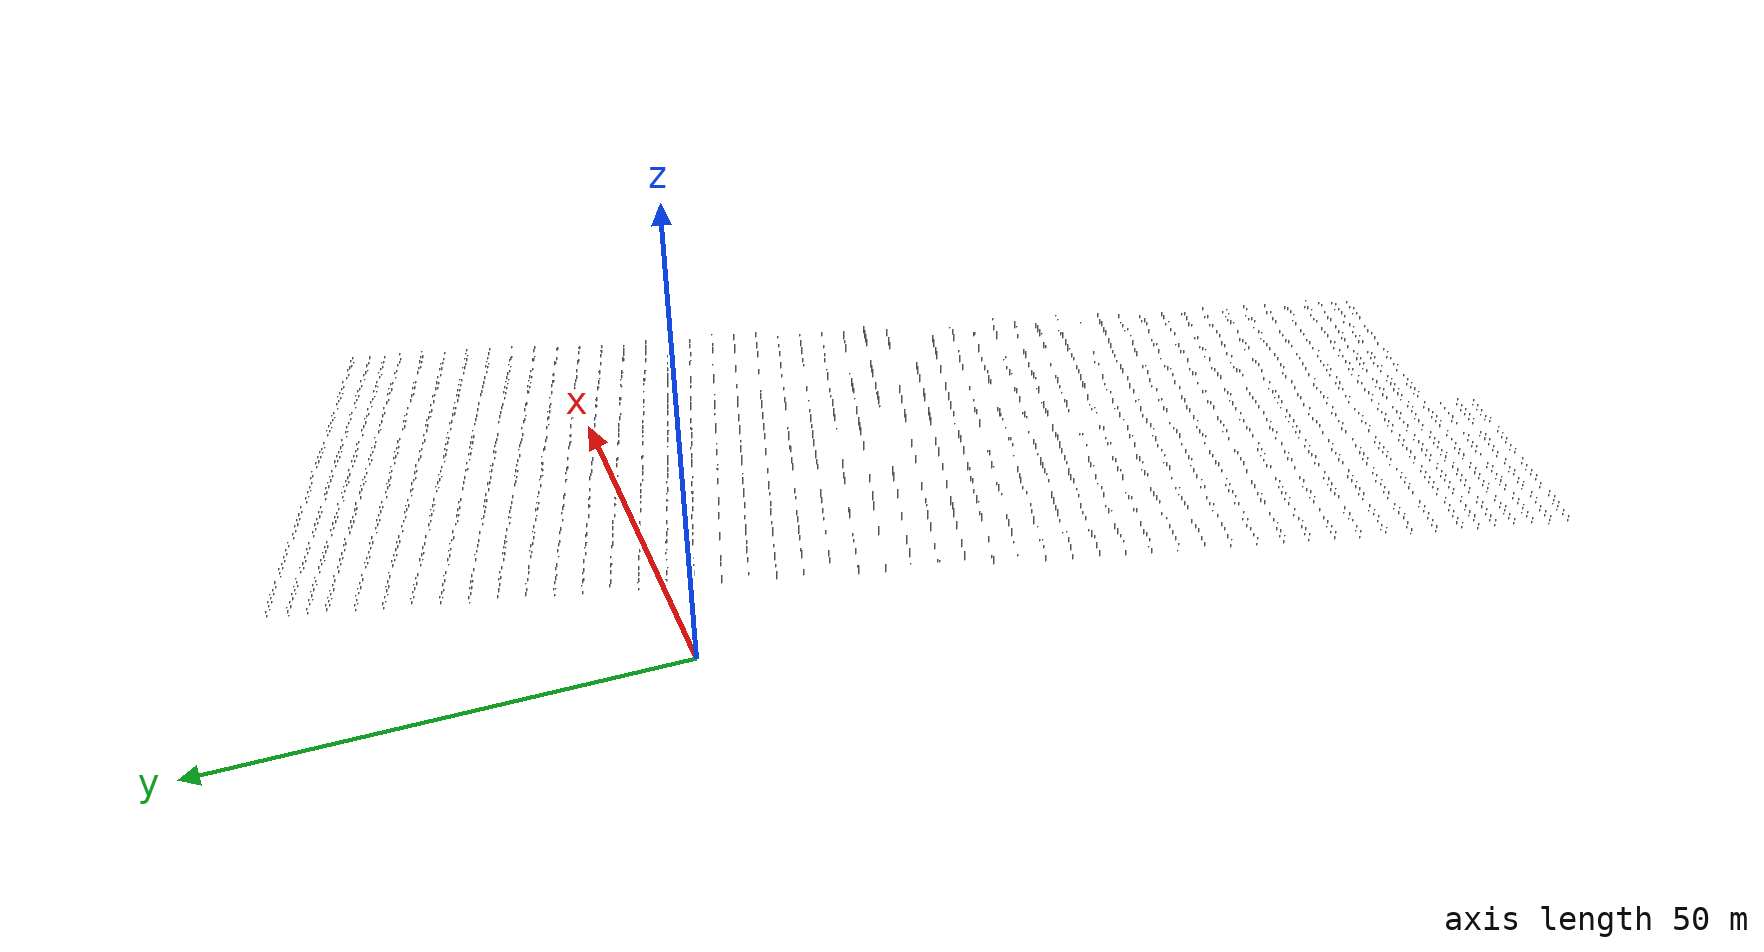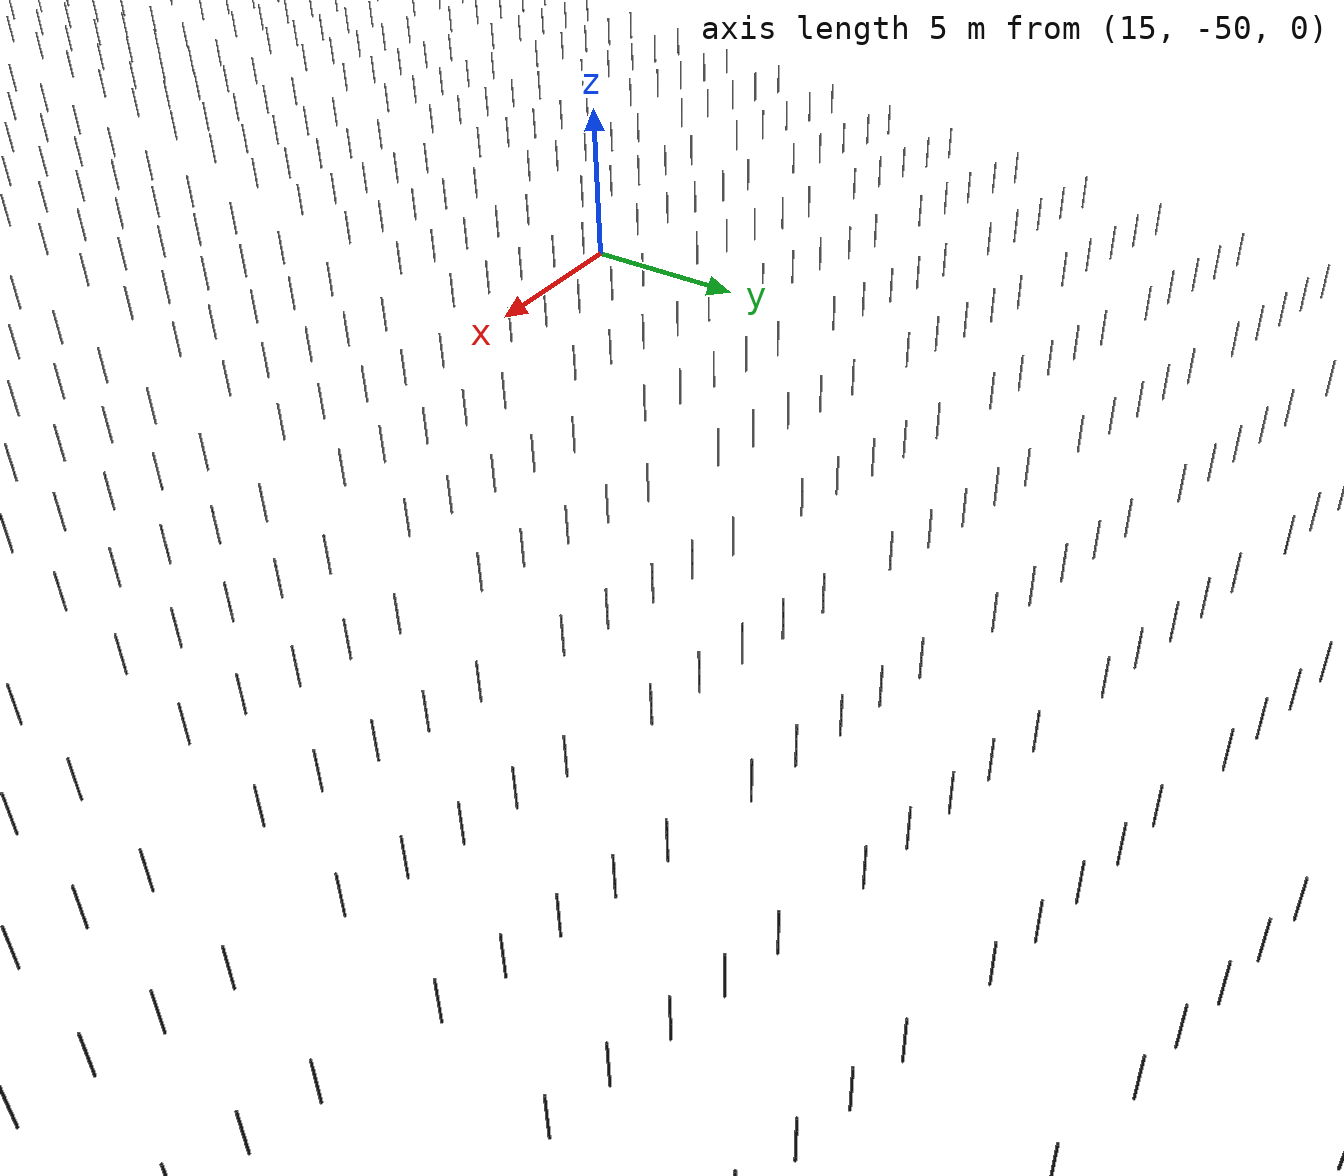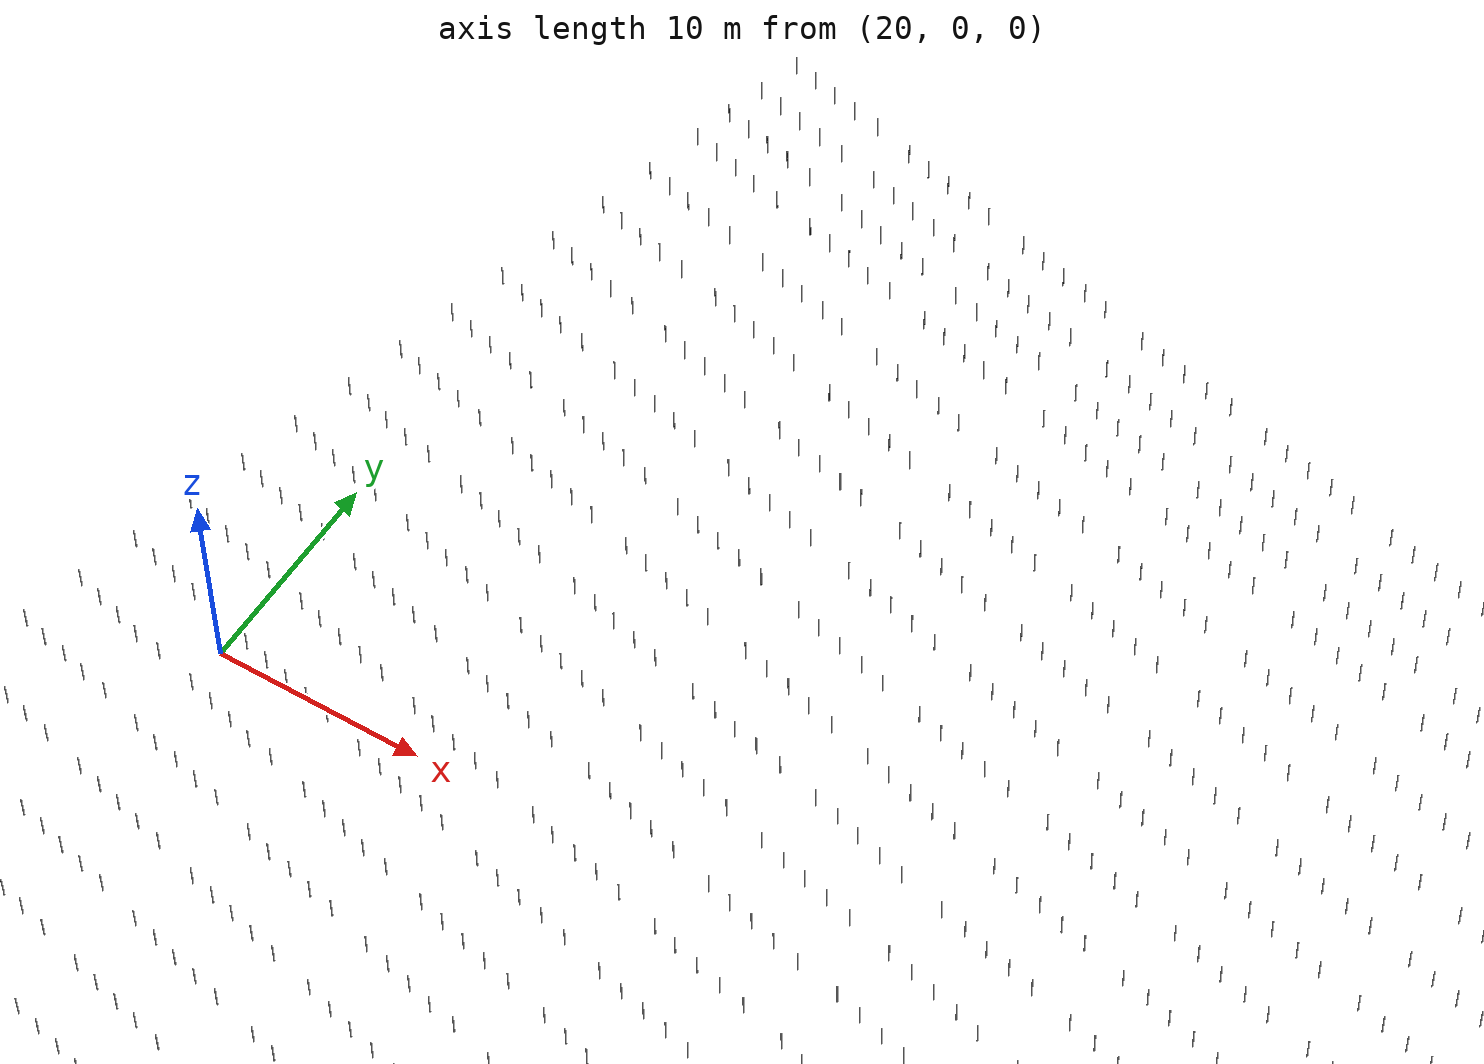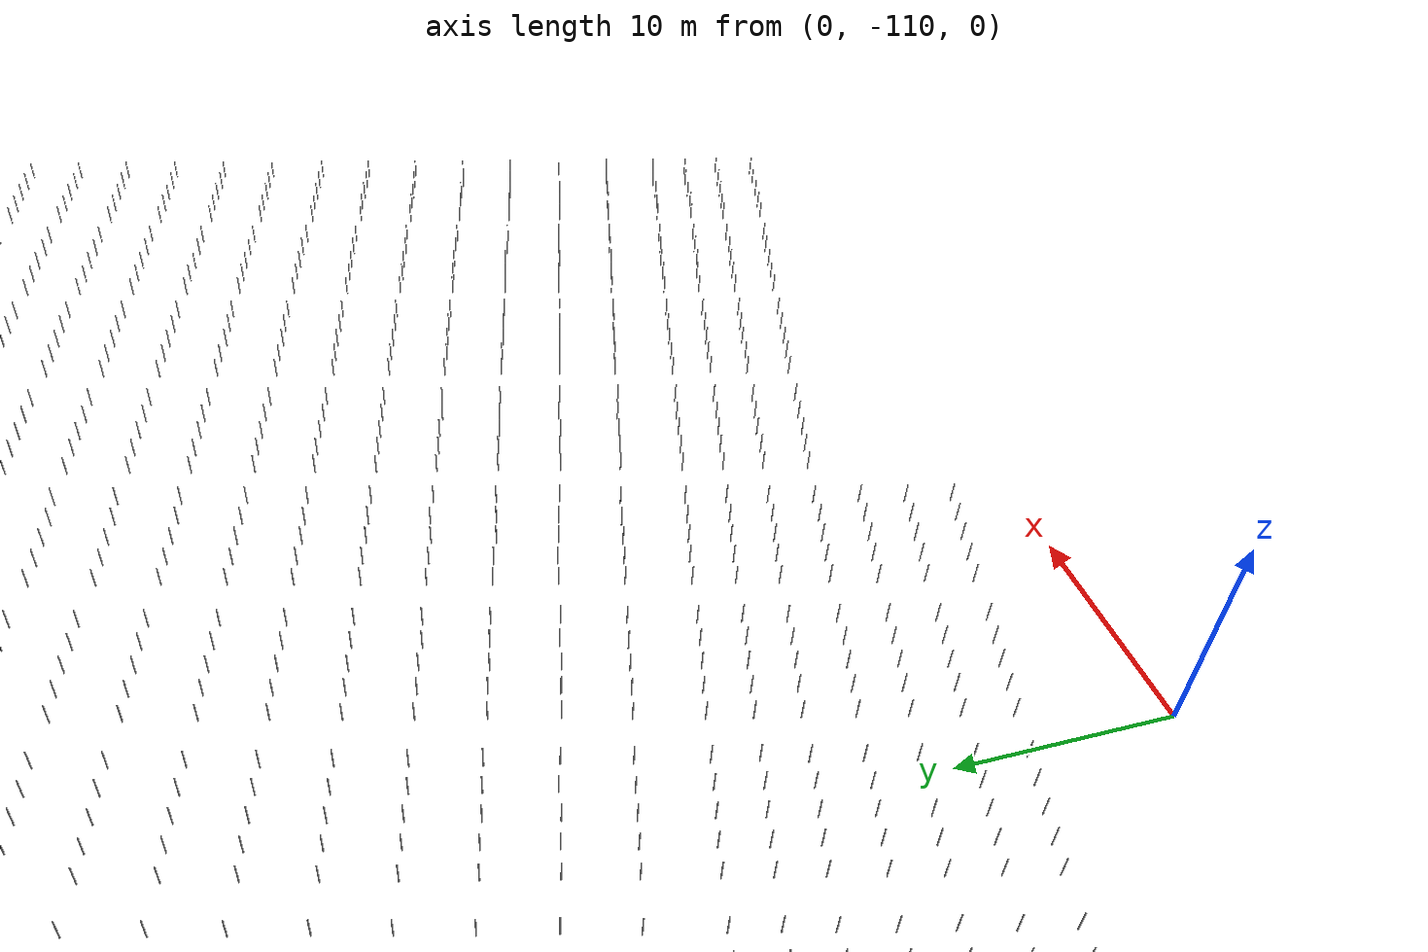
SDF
<sdf version="1.4">
 <world name="default">
  <include><uri>model://sun</uri></include>
  <physics type="ode">
   <real_time_update_rate>100</real_time_update_rate>
   <real_time_factor>1</real_time_factor>
   <max_step_size>0.01</max_step_size>
   <gravity>0 0 -9.8</gravity>
  </physics>
  <model name="pole_0">
   <static>1</static>
   <pose>-12.425 -99.825 0.575 0.0 0.0 0.0</pose>
   <link name="link">
    <collision name="collision">
     <geometry><cylinder><length>1.15</length><radius>0.025</radius></cylinder></geometry>
    </collision>
    <visual name="visual">
     <geometry><cylinder><length>1.15</length><radius>0.025</radius></cylinder></geometry>
     <material>
      <script><uri>file://media/materials/scripts/gazebo.material</uri><name>Gazebo/Chrome</name></script>
      <shader type="vertex"><normal_map>__default__</normal_map></shader>
      <emissive>0.1 0.1 0.1 1</emissive>
      <specular>0.01 0.01 0.01 1</specular>
      <ambient>0.5 0.5 0.5 1</ambient>
      <diffuse>0.05 0.05 0.05 1</diffuse>
     </material>
    </visual>
   </link>
  </model>
  <model name="pole_1">
   <static>1</static>
   <pose>-11.878 -97.678 0.575 0.0 0.0 0.0</pose>
   <link name="link">
    <collision name="collision">
     <geometry><cylinder><length>1.15</length><radius>0.025</radius></cylinder></geometry>
    </collision>
    <visual name="visual">
     <geometry><cylinder><length>1.15</length><radius>0.025</radius></cylinder></geometry>
     <material>
      <script><uri>file://media/materials/scripts/gazebo.material</uri><name>Gazebo/Chrome</name></script>
      <shader type="vertex"><normal_map>__default__</normal_map></shader>
      <emissive>0.1 0.1 0.1 1</emissive>
      <specular>0.01 0.01 0.01 1</specular>
      <ambient>0.5 0.5 0.5 1</ambient>
      <diffuse>0.05 0.05 0.05 1</diffuse>
     </material>
    </visual>
   </link>
  </model>
  <model name="pole_2">
   <static>1</static>
   <pose>-11.350 -95.600 0.575 0.0 0.0 0.0</pose>
   <link name="link">
    <collision name="collision">
     <geometry><cylinder><length>1.15</length><radius>0.025</radius></cylinder></geometry>
    </collision>
    <visual name="visual">
     <geometry><cylinder><length>1.15</length><radius>0.025</radius></cylinder></geometry>
     <material>
      <script><uri>file://media/materials/scripts/gazebo.material</uri><name>Gazebo/Chrome</name></script>
      <shader type="vertex"><normal_map>__default__</normal_map></shader>
      <emissive>0.1 0.1 0.1 1</emissive>
      <specular>0.01 0.01 0.01 1</specular>
      <ambient>0.5 0.5 0.5 1</ambient>
      <diffuse>0.05 0.05 0.05 1</diffuse>
     </material>
    </visual>
   </link>
  </model>
  <model name="pole_3">
   <static>1</static>
   <pose>-10.800 -93.500 0.575 0.0 0.0 0.0</pose>
   <link name="link">
    <collision name="collision">
     <geometry><cylinder><length>1.15</length><radius>0.025</radius></cylinder></geometry>
    </collision>
    <visual name="visual">
     <geometry><cylinder><length>1.15</length><radius>0.025</radius></cylinder></geometry>
     <material>
      <script><uri>file://media/materials/scripts/gazebo.material</uri><name>Gazebo/Chrome</name></script>
      <shader type="vertex"><normal_map>__default__</normal_map></shader>
      <emissive>0.1 0.1 0.1 1</emissive>
      <specular>0.01 0.01 0.01 1</specular>
      <ambient>0.5 0.5 0.5 1</ambient>
      <diffuse>0.05 0.05 0.05 1</diffuse>
     </material>
    </visual>
   </link>
  </model>
  <model name="pole_4">
   <static>1</static>
   <pose>-10.250 -91.300 0.575 0.0 0.0 0.0</pose>
   <link name="link">
    <collision name="collision">
     <geometry><cylinder><length>1.15</length><radius>0.025</radius></cylinder></geometry>
    </collision>
    <visual name="visual">
     <geometry><cylinder><length>1.15</length><radius>0.025</radius></cylinder></geometry>
     <material>
      <script><uri>file://media/materials/scripts/gazebo.material</uri><name>Gazebo/Chrome</name></script>
      <shader type="vertex"><normal_map>__default__</normal_map></shader>
      <emissive>0.1 0.1 0.1 1</emissive>
      <specular>0.01 0.01 0.01 1</specular>
      <ambient>0.5 0.5 0.5 1</ambient>
      <diffuse>0.05 0.05 0.05 1</diffuse>
     </material>
    </visual>
   </link>
  </model>
  <model name="pole_5">
   <static>1</static>
   <pose>-9.778 -89.378 0.575 0.0 0.0 0.0</pose>
   <link name="link">
    <collision name="collision">
     <geometry><cylinder><length>1.15</length><radius>0.025</radius></cylinder></geometry>
    </collision>
    <visual name="visual">
     <geometry><cylinder><length>1.15</length><radius>0.025</radius></cylinder></geometry>
     <material>
      <script><uri>file://media/materials/scripts/gazebo.material</uri><name>Gazebo/Chrome</name></script>
      <shader type="vertex"><normal_map>__default__</normal_map></shader>
      <emissive>0.1 0.1 0.1 1</emissive>
      <specular>0.01 0.01 0.01 1</specular>
      <ambient>0.5 0.5 0.5 1</ambient>
      <diffuse>0.05 0.05 0.05 1</diffuse>
     </material>
    </visual>
   </link>
  </model>
  <model name="pole_6">
   <static>1</static>
   <pose>-9.300 -87.450 0.575 0.0 0.0 0.0</pose>
   <link name="link">
    <collision name="collision">
     <geometry><cylinder><length>1.15</length><radius>0.025</radius></cylinder></geometry>
    </collision>
    <visual name="visual">
     <geometry><cylinder><length>1.15</length><radius>0.025</radius></cylinder></geometry>
     <material>
      <script><uri>file://media/materials/scripts/gazebo.material</uri><name>Gazebo/Chrome</name></script>
      <shader type="vertex"><normal_map>__default__</normal_map></shader>
      <emissive>0.1 0.1 0.1 1</emissive>
      <specular>0.01 0.01 0.01 1</specular>
      <ambient>0.5 0.5 0.5 1</ambient>
      <diffuse>0.05 0.05 0.05 1</diffuse>
     </material>
    </visual>
   </link>
  </model>
  <model name="pole_7">
   <static>1</static>
   <pose>-8.550 -84.525 0.575 0.0 0.0 0.0</pose>
   <link name="link">
    <collision name="collision">
     <geometry><cylinder><length>1.15</length><radius>0.025</radius></cylinder></geometry>
    </collision>
    <visual name="visual">
     <geometry><cylinder><length>1.15</length><radius>0.025</radius></cylinder></geometry>
     <material>
      <script><uri>file://media/materials/scripts/gazebo.material</uri><name>Gazebo/Chrome</name></script>
      <shader type="vertex"><normal_map>__default__</normal_map></shader>
      <emissive>0.1 0.1 0.1 1</emissive>
      <specular>0.01 0.01 0.01 1</specular>
      <ambient>0.5 0.5 0.5 1</ambient>
      <diffuse>0.05 0.05 0.05 1</diffuse>
     </material>
    </visual>
   </link>
  </model>
  <model name="pole_8">
   <static>1</static>
   <pose>-7.841 -81.667 0.575 0.0 0.0 0.0</pose>
   <link name="link">
    <collision name="collision">
     <geometry><cylinder><length>1.15</length><radius>0.025</radius></cylinder></geometry>
    </collision>
    <visual name="visual">
     <geometry><cylinder><length>1.15</length><radius>0.025</radius></cylinder></geometry>
     <material>
      <script><uri>file://media/materials/scripts/gazebo.material</uri><name>Gazebo/Chrome</name></script>
      <shader type="vertex"><normal_map>__default__</normal_map></shader>
      <emissive>0.1 0.1 0.1 1</emissive>
      <specular>0.01 0.01 0.01 1</specular>
      <ambient>0.5 0.5 0.5 1</ambient>
      <diffuse>0.05 0.05 0.05 1</diffuse>
     </material>
    </visual>
   </link>
  </model>
  <model name="pole_9">
   <static>1</static>
   <pose>-7.093 -78.698 0.575 0.0 0.0 0.0</pose>
   <link name="link">
    <collision name="collision">
     <geometry><cylinder><length>1.15</length><radius>0.025</radius></cylinder></geometry>
    </collision>
    <visual name="visual">
     <geometry><cylinder><length>1.15</length><radius>0.025</radius></cylinder></geometry>
     <material>
      <script><uri>file://media/materials/scripts/gazebo.material</uri><name>Gazebo/Chrome</name></script>
      <shader type="vertex"><normal_map>__default__</normal_map></shader>
      <emissive>0.1 0.1 0.1 1</emissive>
      <specular>0.01 0.01 0.01 1</specular>
      <ambient>0.5 0.5 0.5 1</ambient>
      <diffuse>0.05 0.05 0.05 1</diffuse>
     </material>
    </visual>
   </link>
  </model>
  <model name="pole_10">
   <static>1</static>
   <pose>-6.375 -75.779 0.575 0.0 0.0 0.0</pose>
   <link name="link">
    <collision name="collision">
     <geometry><cylinder><length>1.15</length><radius>0.025</radius></cylinder></geometry>
    </collision>
    <visual name="visual">
     <geometry><cylinder><length>1.15</length><radius>0.025</radius></cylinder></geometry>
     <material>
      <script><uri>file://media/materials/scripts/gazebo.material</uri><name>Gazebo/Chrome</name></script>
      <shader type="vertex"><normal_map>__default__</normal_map></shader>
      <emissive>0.1 0.1 0.1 1</emissive>
      <specular>0.01 0.01 0.01 1</specular>
      <ambient>0.5 0.5 0.5 1</ambient>
      <diffuse>0.05 0.05 0.05 1</diffuse>
     </material>
    </visual>
   </link>
  </model>
  <model name="pole_11">
   <static>1</static>
   <pose>-5.650 -72.906 0.575 0.0 0.0 0.0</pose>
   <link name="link">
    <collision name="collision">
     <geometry><cylinder><length>1.15</length><radius>0.025</radius></cylinder></geometry>
    </collision>
    <visual name="visual">
     <geometry><cylinder><length>1.15</length><radius>0.025</radius></cylinder></geometry>
     <material>
      <script><uri>file://media/materials/scripts/gazebo.material</uri><name>Gazebo/Chrome</name></script>
      <shader type="vertex"><normal_map>__default__</normal_map></shader>
      <emissive>0.1 0.1 0.1 1</emissive>
      <specular>0.01 0.01 0.01 1</specular>
      <ambient>0.5 0.5 0.5 1</ambient>
      <diffuse>0.05 0.05 0.05 1</diffuse>
     </material>
    </visual>
   </link>
  </model>
  <model name="pole_12">
   <static>1</static>
   <pose>-4.875 -70.000 0.575 0.0 0.0 0.0</pose>
   <link name="link">
    <collision name="collision">
     <geometry><cylinder><length>1.15</length><radius>0.025</radius></cylinder></geometry>
    </collision>
    <visual name="visual">
     <geometry><cylinder><length>1.15</length><radius>0.025</radius></cylinder></geometry>
     <material>
      <script><uri>file://media/materials/scripts/gazebo.material</uri><name>Gazebo/Chrome</name></script>
      <shader type="vertex"><normal_map>__default__</normal_map></shader>
      <emissive>0.1 0.1 0.1 1</emissive>
      <specular>0.01 0.01 0.01 1</specular>
      <ambient>0.5 0.5 0.5 1</ambient>
      <diffuse>0.05 0.05 0.05 1</diffuse>
     </material>
    </visual>
   </link>
  </model>
  <model name="pole_13">
   <static>1</static>
   <pose>-4.172 -67.146 0.575 0.0 0.0 0.0</pose>
   <link name="link">
    <collision name="collision">
     <geometry><cylinder><length>1.15</length><radius>0.025</radius></cylinder></geometry>
    </collision>
    <visual name="visual">
     <geometry><cylinder><length>1.15</length><radius>0.025</radius></cylinder></geometry>
     <material>
      <script><uri>file://media/materials/scripts/gazebo.material</uri><name>Gazebo/Chrome</name></script>
      <shader type="vertex"><normal_map>__default__</normal_map></shader>
      <emissive>0.1 0.1 0.1 1</emissive>
      <specular>0.01 0.01 0.01 1</specular>
      <ambient>0.5 0.5 0.5 1</ambient>
      <diffuse>0.05 0.05 0.05 1</diffuse>
     </material>
    </visual>
   </link>
  </model>
  <model name="pole_14">
   <static>1</static>
   <pose>-3.400 -64.125 0.575 0.0 0.0 0.0</pose>
   <link name="link">
    <collision name="collision">
     <geometry><cylinder><length>1.15</length><radius>0.025</radius></cylinder></geometry>
    </collision>
    <visual name="visual">
     <geometry><cylinder><length>1.15</length><radius>0.025</radius></cylinder></geometry>
     <material>
      <script><uri>file://media/materials/scripts/gazebo.material</uri><name>Gazebo/Chrome</name></script>
      <shader type="vertex"><normal_map>__default__</normal_map></shader>
      <emissive>0.1 0.1 0.1 1</emissive>
      <specular>0.01 0.01 0.01 1</specular>
      <ambient>0.5 0.5 0.5 1</ambient>
      <diffuse>0.05 0.05 0.05 1</diffuse>
     </material>
    </visual>
   </link>
  </model>
  <model name="pole_15">
   <static>1</static>
   <pose>-2.652 -61.207 0.575 0.0 0.0 0.0</pose>
   <link name="link">
    <collision name="collision">
     <geometry><cylinder><length>1.15</length><radius>0.025</radius></cylinder></geometry>
    </collision>
    <visual name="visual">
     <geometry><cylinder><length>1.15</length><radius>0.025</radius></cylinder></geometry>
     <material>
      <script><uri>file://media/materials/scripts/gazebo.material</uri><name>Gazebo/Chrome</name></script>
      <shader type="vertex"><normal_map>__default__</normal_map></shader>
      <emissive>0.1 0.1 0.1 1</emissive>
      <specular>0.01 0.01 0.01 1</specular>
      <ambient>0.5 0.5 0.5 1</ambient>
      <diffuse>0.05 0.05 0.05 1</diffuse>
     </material>
    </visual>
   </link>
  </model>
  <model name="pole_16">
   <static>1</static>
   <pose>-1.922 -58.228 0.575 0.0 0.0 0.0</pose>
   <link name="link">
    <collision name="collision">
     <geometry><cylinder><length>1.15</length><radius>0.025</radius></cylinder></geometry>
    </collision>
    <visual name="visual">
     <geometry><cylinder><length>1.15</length><radius>0.025</radius></cylinder></geometry>
     <material>
      <script><uri>file://media/materials/scripts/gazebo.material</uri><name>Gazebo/Chrome</name></script>
      <shader type="vertex"><normal_map>__default__</normal_map></shader>
      <emissive>0.1 0.1 0.1 1</emissive>
      <specular>0.01 0.01 0.01 1</specular>
      <ambient>0.5 0.5 0.5 1</ambient>
      <diffuse>0.05 0.05 0.05 1</diffuse>
     </material>
    </visual>
   </link>
  </model>
  <model name="pole_17">
   <static>1</static>
   <pose>-1.172 -55.304 0.575 0.0 0.0 0.0</pose>
   <link name="link">
    <collision name="collision">
     <geometry><cylinder><length>1.15</length><radius>0.025</radius></cylinder></geometry>
    </collision>
    <visual name="visual">
     <geometry><cylinder><length>1.15</length><radius>0.025</radius></cylinder></geometry>
     <material>
      <script><uri>file://media/materials/scripts/gazebo.material</uri><name>Gazebo/Chrome</name></script>
      <shader type="vertex"><normal_map>__default__</normal_map></shader>
      <emissive>0.1 0.1 0.1 1</emissive>
      <specular>0.01 0.01 0.01 1</specular>
      <ambient>0.5 0.5 0.5 1</ambient>
      <diffuse>0.05 0.05 0.05 1</diffuse>
     </material>
    </visual>
   </link>
  </model>
  <model name="pole_18">
   <static>1</static>
   <pose>-0.425 -52.379 0.575 0.0 0.0 0.0</pose>
   <link name="link">
    <collision name="collision">
     <geometry><cylinder><length>1.15</length><radius>0.025</radius></cylinder></geometry>
    </collision>
    <visual name="visual">
     <geometry><cylinder><length>1.15</length><radius>0.025</radius></cylinder></geometry>
     <material>
      <script><uri>file://media/materials/scripts/gazebo.material</uri><name>Gazebo/Chrome</name></script>
      <shader type="vertex"><normal_map>__default__</normal_map></shader>
      <emissive>0.1 0.1 0.1 1</emissive>
      <specular>0.01 0.01 0.01 1</specular>
      <ambient>0.5 0.5 0.5 1</ambient>
      <diffuse>0.05 0.05 0.05 1</diffuse>
     </material>
    </visual>
   </link>
  </model>
  <model name="pole_19">
   <static>1</static>
   <pose>0.314 -49.500 0.575 0.0 0.0 0.0</pose>
   <link name="link">
    <collision name="collision">
     <geometry><cylinder><length>1.15</length><radius>0.025</radius></cylinder></geometry>
    </collision>
    <visual name="visual">
     <geometry><cylinder><length>1.15</length><radius>0.025</radius></cylinder></geometry>
     <material>
      <script><uri>file://media/materials/scripts/gazebo.material</uri><name>Gazebo/Chrome</name></script>
      <shader type="vertex"><normal_map>__default__</normal_map></shader>
      <emissive>0.1 0.1 0.1 1</emissive>
      <specular>0.01 0.01 0.01 1</specular>
      <ambient>0.5 0.5 0.5 1</ambient>
      <diffuse>0.05 0.05 0.05 1</diffuse>
     </material>
    </visual>
   </link>
  </model>
  <model name="pole_20">
   <static>1</static>
   <pose>1.050 -46.625 0.575 0.0 0.0 0.0</pose>
   <link name="link">
    <collision name="collision">
     <geometry><cylinder><length>1.15</length><radius>0.025</radius></cylinder></geometry>
    </collision>
    <visual name="visual">
     <geometry><cylinder><length>1.15</length><radius>0.025</radius></cylinder></geometry>
     <material>
      <script><uri>file://media/materials/scripts/gazebo.material</uri><name>Gazebo/Chrome</name></script>
      <shader type="vertex"><normal_map>__default__</normal_map></shader>
      <emissive>0.1 0.1 0.1 1</emissive>
      <specular>0.01 0.01 0.01 1</specular>
      <ambient>0.5 0.5 0.5 1</ambient>
      <diffuse>0.05 0.05 0.05 1</diffuse>
     </material>
    </visual>
   </link>
  </model>
  <model name="pole_21">
   <static>1</static>
   <pose>1.845 -43.704 0.575 0.0 0.0 0.0</pose>
   <link name="link">
    <collision name="collision">
     <geometry><cylinder><length>1.15</length><radius>0.025</radius></cylinder></geometry>
    </collision>
    <visual name="visual">
     <geometry><cylinder><length>1.15</length><radius>0.025</radius></cylinder></geometry>
     <material>
      <script><uri>file://media/materials/scripts/gazebo.material</uri><name>Gazebo/Chrome</name></script>
      <shader type="vertex"><normal_map>__default__</normal_map></shader>
      <emissive>0.1 0.1 0.1 1</emissive>
      <specular>0.01 0.01 0.01 1</specular>
      <ambient>0.5 0.5 0.5 1</ambient>
      <diffuse>0.05 0.05 0.05 1</diffuse>
     </material>
    </visual>
   </link>
  </model>
  <model name="pole_22">
   <static>1</static>
   <pose>2.625 -40.750 0.575 0.0 0.0 0.0</pose>
   <link name="link">
    <collision name="collision">
     <geometry><cylinder><length>1.15</length><radius>0.025</radius></cylinder></geometry>
    </collision>
    <visual name="visual">
     <geometry><cylinder><length>1.15</length><radius>0.025</radius></cylinder></geometry>
     <material>
      <script><uri>file://media/materials/scripts/gazebo.material</uri><name>Gazebo/Chrome</name></script>
      <shader type="vertex"><normal_map>__default__</normal_map></shader>
      <emissive>0.1 0.1 0.1 1</emissive>
      <specular>0.01 0.01 0.01 1</specular>
      <ambient>0.5 0.5 0.5 1</ambient>
      <diffuse>0.05 0.05 0.05 1</diffuse>
     </material>
    </visual>
   </link>
  </model>
  <model name="pole_23">
   <static>1</static>
   <pose>3.304 -37.928 0.575 0.0 0.0 0.0</pose>
   <link name="link">
    <collision name="collision">
     <geometry><cylinder><length>1.15</length><radius>0.025</radius></cylinder></geometry>
    </collision>
    <visual name="visual">
     <geometry><cylinder><length>1.15</length><radius>0.025</radius></cylinder></geometry>
     <material>
      <script><uri>file://media/materials/scripts/gazebo.material</uri><name>Gazebo/Chrome</name></script>
      <shader type="vertex"><normal_map>__default__</normal_map></shader>
      <emissive>0.1 0.1 0.1 1</emissive>
      <specular>0.01 0.01 0.01 1</specular>
      <ambient>0.5 0.5 0.5 1</ambient>
      <diffuse>0.05 0.05 0.05 1</diffuse>
     </material>
    </visual>
   </link>
  </model>
  <model name="pole_24">
   <static>1</static>
   <pose>4.053 -35.053 0.575 0.0 0.0 0.0</pose>
   <link name="link">
    <collision name="collision">
     <geometry><cylinder><length>1.15</length><radius>0.025</radius></cylinder></geometry>
    </collision>
    <visual name="visual">
     <geometry><cylinder><length>1.15</length><radius>0.025</radius></cylinder></geometry>
     <material>
      <script><uri>file://media/materials/scripts/gazebo.material</uri><name>Gazebo/Chrome</name></script>
      <shader type="vertex"><normal_map>__default__</normal_map></shader>
      <emissive>0.1 0.1 0.1 1</emissive>
      <specular>0.01 0.01 0.01 1</specular>
      <ambient>0.5 0.5 0.5 1</ambient>
      <diffuse>0.05 0.05 0.05 1</diffuse>
     </material>
    </visual>
   </link>
  </model>
  <model name="pole_25">
   <static>1</static>
   <pose>4.800 -32.080 0.575 0.0 0.0 0.0</pose>
   <link name="link">
    <collision name="collision">
     <geometry><cylinder><length>1.15</length><radius>0.025</radius></cylinder></geometry>
    </collision>
    <visual name="visual">
     <geometry><cylinder><length>1.15</length><radius>0.025</radius></cylinder></geometry>
     <material>
      <script><uri>file://media/materials/scripts/gazebo.material</uri><name>Gazebo/Chrome</name></script>
      <shader type="vertex"><normal_map>__default__</normal_map></shader>
      <emissive>0.1 0.1 0.1 1</emissive>
      <specular>0.01 0.01 0.01 1</specular>
      <ambient>0.5 0.5 0.5 1</ambient>
      <diffuse>0.05 0.05 0.05 1</diffuse>
     </material>
    </visual>
   </link>
  </model>
  <model name="pole_26">
   <static>1</static>
   <pose>5.570 -29.200 0.575 0.0 0.0 0.0</pose>
   <link name="link">
    <collision name="collision">
     <geometry><cylinder><length>1.15</length><radius>0.025</radius></cylinder></geometry>
    </collision>
    <visual name="visual">
     <geometry><cylinder><length>1.15</length><radius>0.025</radius></cylinder></geometry>
     <material>
      <script><uri>file://media/materials/scripts/gazebo.material</uri><name>Gazebo/Chrome</name></script>
      <shader type="vertex"><normal_map>__default__</normal_map></shader>
      <emissive>0.1 0.1 0.1 1</emissive>
      <specular>0.01 0.01 0.01 1</specular>
      <ambient>0.5 0.5 0.5 1</ambient>
      <diffuse>0.05 0.05 0.05 1</diffuse>
     </material>
    </visual>
   </link>
  </model>
  <model name="pole_27">
   <static>1</static>
   <pose>6.298 -26.257 0.575 0.0 0.0 0.0</pose>
   <link name="link">
    <collision name="collision">
     <geometry><cylinder><length>1.15</length><radius>0.025</radius></cylinder></geometry>
    </collision>
    <visual name="visual">
     <geometry><cylinder><length>1.15</length><radius>0.025</radius></cylinder></geometry>
     <material>
      <script><uri>file://media/materials/scripts/gazebo.material</uri><name>Gazebo/Chrome</name></script>
      <shader type="vertex"><normal_map>__default__</normal_map></shader>
      <emissive>0.1 0.1 0.1 1</emissive>
      <specular>0.01 0.01 0.01 1</specular>
      <ambient>0.5 0.5 0.5 1</ambient>
      <diffuse>0.05 0.05 0.05 1</diffuse>
     </material>
    </visual>
   </link>
  </model>
  <model name="pole_28">
   <static>1</static>
   <pose>7.014 -23.400 0.575 0.0 0.0 0.0</pose>
   <link name="link">
    <collision name="collision">
     <geometry><cylinder><length>1.15</length><radius>0.025</radius></cylinder></geometry>
    </collision>
    <visual name="visual">
     <geometry><cylinder><length>1.15</length><radius>0.025</radius></cylinder></geometry>
     <material>
      <script><uri>file://media/materials/scripts/gazebo.material</uri><name>Gazebo/Chrome</name></script>
      <shader type="vertex"><normal_map>__default__</normal_map></shader>
      <emissive>0.1 0.1 0.1 1</emissive>
      <specular>0.01 0.01 0.01 1</specular>
      <ambient>0.5 0.5 0.5 1</ambient>
      <diffuse>0.05 0.05 0.05 1</diffuse>
     </material>
    </visual>
   </link>
  </model>
  <model name="pole_29">
   <static>1</static>
   <pose>7.775 -20.525 0.575 0.0 0.0 0.0</pose>
   <link name="link">
    <collision name="collision">
     <geometry><cylinder><length>1.15</length><radius>0.025</radius></cylinder></geometry>
    </collision>
    <visual name="visual">
     <geometry><cylinder><length>1.15</length><radius>0.025</radius></cylinder></geometry>
     <material>
      <script><uri>file://media/materials/scripts/gazebo.material</uri><name>Gazebo/Chrome</name></script>
      <shader type="vertex"><normal_map>__default__</normal_map></shader>
      <emissive>0.1 0.1 0.1 1</emissive>
      <specular>0.01 0.01 0.01 1</specular>
      <ambient>0.5 0.5 0.5 1</ambient>
      <diffuse>0.05 0.05 0.05 1</diffuse>
     </material>
    </visual>
   </link>
  </model>
  <model name="pole_30">
   <static>1</static>
   <pose>8.522 -17.604 0.575 0.0 0.0 0.0</pose>
   <link name="link">
    <collision name="collision">
     <geometry><cylinder><length>1.15</length><radius>0.025</radius></cylinder></geometry>
    </collision>
    <visual name="visual">
     <geometry><cylinder><length>1.15</length><radius>0.025</radius></cylinder></geometry>
     <material>
      <script><uri>file://media/materials/scripts/gazebo.material</uri><name>Gazebo/Chrome</name></script>
      <shader type="vertex"><normal_map>__default__</normal_map></shader>
      <emissive>0.1 0.1 0.1 1</emissive>
      <specular>0.01 0.01 0.01 1</specular>
      <ambient>0.5 0.5 0.5 1</ambient>
      <diffuse>0.05 0.05 0.05 1</diffuse>
     </material>
    </visual>
   </link>
  </model>
  <model name="pole_31">
   <static>1</static>
   <pose>9.253 -14.703 0.575 0.0 0.0 0.0</pose>
   <link name="link">
    <collision name="collision">
     <geometry><cylinder><length>1.15</length><radius>0.025</radius></cylinder></geometry>
    </collision>
    <visual name="visual">
     <geometry><cylinder><length>1.15</length><radius>0.025</radius></cylinder></geometry>
     <material>
      <script><uri>file://media/materials/scripts/gazebo.material</uri><name>Gazebo/Chrome</name></script>
      <shader type="vertex"><normal_map>__default__</normal_map></shader>
      <emissive>0.1 0.1 0.1 1</emissive>
      <specular>0.01 0.01 0.01 1</specular>
      <ambient>0.5 0.5 0.5 1</ambient>
      <diffuse>0.05 0.05 0.05 1</diffuse>
     </material>
    </visual>
   </link>
  </model>
  <model name="pole_32">
   <static>1</static>
   <pose>10.028 -11.846 0.575 0.0 0.0 0.0</pose>
   <link name="link">
    <collision name="collision">
     <geometry><cylinder><length>1.15</length><radius>0.025</radius></cylinder></geometry>
    </collision>
    <visual name="visual">
     <geometry><cylinder><length>1.15</length><radius>0.025</radius></cylinder></geometry>
     <material>
      <script><uri>file://media/materials/scripts/gazebo.material</uri><name>Gazebo/Chrome</name></script>
      <shader type="vertex"><normal_map>__default__</normal_map></shader>
      <emissive>0.1 0.1 0.1 1</emissive>
      <specular>0.01 0.01 0.01 1</specular>
      <ambient>0.5 0.5 0.5 1</ambient>
      <diffuse>0.05 0.05 0.05 1</diffuse>
     </material>
    </visual>
   </link>
  </model>
  <model name="pole_33">
   <static>1</static>
   <pose>10.775 -8.925 0.575 0.0 0.0 0.0</pose>
   <link name="link">
    <collision name="collision">
     <geometry><cylinder><length>1.15</length><radius>0.025</radius></cylinder></geometry>
    </collision>
    <visual name="visual">
     <geometry><cylinder><length>1.15</length><radius>0.025</radius></cylinder></geometry>
     <material>
      <script><uri>file://media/materials/scripts/gazebo.material</uri><name>Gazebo/Chrome</name></script>
      <shader type="vertex"><normal_map>__default__</normal_map></shader>
      <emissive>0.1 0.1 0.1 1</emissive>
      <specular>0.01 0.01 0.01 1</specular>
      <ambient>0.5 0.5 0.5 1</ambient>
      <diffuse>0.05 0.05 0.05 1</diffuse>
     </material>
    </visual>
   </link>
  </model>
  <model name="pole_34">
   <static>1</static>
   <pose>11.522 -6.054 0.575 0.0 0.0 0.0</pose>
   <link name="link">
    <collision name="collision">
     <geometry><cylinder><length>1.15</length><radius>0.025</radius></cylinder></geometry>
    </collision>
    <visual name="visual">
     <geometry><cylinder><length>1.15</length><radius>0.025</radius></cylinder></geometry>
     <material>
      <script><uri>file://media/materials/scripts/gazebo.material</uri><name>Gazebo/Chrome</name></script>
      <shader type="vertex"><normal_map>__default__</normal_map></shader>
      <emissive>0.1 0.1 0.1 1</emissive>
      <specular>0.01 0.01 0.01 1</specular>
      <ambient>0.5 0.5 0.5 1</ambient>
      <diffuse>0.05 0.05 0.05 1</diffuse>
     </material>
    </visual>
   </link>
  </model>
  <model name="pole_35">
   <static>1</static>
   <pose>12.228 -3.096 0.575 0.0 0.0 0.0</pose>
   <link name="link">
    <collision name="collision">
     <geometry><cylinder><length>1.15</length><radius>0.025</radius></cylinder></geometry>
    </collision>
    <visual name="visual">
     <geometry><cylinder><length>1.15</length><radius>0.025</radius></cylinder></geometry>
     <material>
      <script><uri>file://media/materials/scripts/gazebo.material</uri><name>Gazebo/Chrome</name></script>
      <shader type="vertex"><normal_map>__default__</normal_map></shader>
      <emissive>0.1 0.1 0.1 1</emissive>
      <specular>0.01 0.01 0.01 1</specular>
      <ambient>0.5 0.5 0.5 1</ambient>
      <diffuse>0.05 0.05 0.05 1</diffuse>
     </material>
    </visual>
   </link>
  </model>
  <model name="pole_36">
   <static>1</static>
   <pose>12.950 -0.214 0.575 0.0 0.0 0.0</pose>
   <link name="link">
    <collision name="collision">
     <geometry><cylinder><length>1.15</length><radius>0.025</radius></cylinder></geometry>
    </collision>
    <visual name="visual">
     <geometry><cylinder><length>1.15</length><radius>0.025</radius></cylinder></geometry>
     <material>
      <script><uri>file://media/materials/scripts/gazebo.material</uri><name>Gazebo/Chrome</name></script>
      <shader type="vertex"><normal_map>__default__</normal_map></shader>
      <emissive>0.1 0.1 0.1 1</emissive>
      <specular>0.01 0.01 0.01 1</specular>
      <ambient>0.5 0.5 0.5 1</ambient>
      <diffuse>0.05 0.05 0.05 1</diffuse>
     </material>
    </visual>
   </link>
  </model>
  <model name="pole_37">
   <static>1</static>
   <pose>13.675 2.675 0.575 0.0 0.0 0.0</pose>
   <link name="link">
    <collision name="collision">
     <geometry><cylinder><length>1.15</length><radius>0.025</radius></cylinder></geometry>
    </collision>
    <visual name="visual">
     <geometry><cylinder><length>1.15</length><radius>0.025</radius></cylinder></geometry>
     <material>
      <script><uri>file://media/materials/scripts/gazebo.material</uri><name>Gazebo/Chrome</name></script>
      <shader type="vertex"><normal_map>__default__</normal_map></shader>
      <emissive>0.1 0.1 0.1 1</emissive>
      <specular>0.01 0.01 0.01 1</specular>
      <ambient>0.5 0.5 0.5 1</ambient>
      <diffuse>0.05 0.05 0.05 1</diffuse>
     </material>
    </visual>
   </link>
  </model>
  <model name="pole_38">
   <static>1</static>
   <pose>14.425 5.600 0.575 0.0 0.0 0.0</pose>
   <link name="link">
    <collision name="collision">
     <geometry><cylinder><length>1.15</length><radius>0.025</radius></cylinder></geometry>
    </collision>
    <visual name="visual">
     <geometry><cylinder><length>1.15</length><radius>0.025</radius></cylinder></geometry>
     <material>
      <script><uri>file://media/materials/scripts/gazebo.material</uri><name>Gazebo/Chrome</name></script>
      <shader type="vertex"><normal_map>__default__</normal_map></shader>
      <emissive>0.1 0.1 0.1 1</emissive>
      <specular>0.01 0.01 0.01 1</specular>
      <ambient>0.5 0.5 0.5 1</ambient>
      <diffuse>0.05 0.05 0.05 1</diffuse>
     </material>
    </visual>
   </link>
  </model>
  <model name="pole_39">
   <static>1</static>
   <pose>15.175 8.450 0.575 0.0 0.0 0.0</pose>
   <link name="link">
    <collision name="collision">
     <geometry><cylinder><length>1.15</length><radius>0.025</radius></cylinder></geometry>
    </collision>
    <visual name="visual">
     <geometry><cylinder><length>1.15</length><radius>0.025</radius></cylinder></geometry>
     <material>
      <script><uri>file://media/materials/scripts/gazebo.material</uri><name>Gazebo/Chrome</name></script>
      <shader type="vertex"><normal_map>__default__</normal_map></shader>
      <emissive>0.1 0.1 0.1 1</emissive>
      <specular>0.01 0.01 0.01 1</specular>
      <ambient>0.5 0.5 0.5 1</ambient>
      <diffuse>0.05 0.05 0.05 1</diffuse>
     </material>
    </visual>
   </link>
  </model>
  <model name="pole_40">
   <static>1</static>
   <pose>15.897 11.353 0.575 0.0 0.0 0.0</pose>
   <link name="link">
    <collision name="collision">
     <geometry><cylinder><length>1.15</length><radius>0.025</radius></cylinder></geometry>
    </collision>
    <visual name="visual">
     <geometry><cylinder><length>1.15</length><radius>0.025</radius></cylinder></geometry>
     <material>
      <script><uri>file://media/materials/scripts/gazebo.material</uri><name>Gazebo/Chrome</name></script>
      <shader type="vertex"><normal_map>__default__</normal_map></shader>
      <emissive>0.1 0.1 0.1 1</emissive>
      <specular>0.01 0.01 0.01 1</specular>
      <ambient>0.5 0.5 0.5 1</ambient>
      <diffuse>0.05 0.05 0.05 1</diffuse>
     </material>
    </visual>
   </link>
  </model>
  <model name="pole_41">
   <static>1</static>
   <pose>16.672 14.272 0.575 0.0 0.0 0.0</pose>
   <link name="link">
    <collision name="collision">
     <geometry><cylinder><length>1.15</length><radius>0.025</radius></cylinder></geometry>
    </collision>
    <visual name="visual">
     <geometry><cylinder><length>1.15</length><radius>0.025</radius></cylinder></geometry>
     <material>
      <script><uri>file://media/materials/scripts/gazebo.material</uri><name>Gazebo/Chrome</name></script>
      <shader type="vertex"><normal_map>__default__</normal_map></shader>
      <emissive>0.1 0.1 0.1 1</emissive>
      <specular>0.01 0.01 0.01 1</specular>
      <ambient>0.5 0.5 0.5 1</ambient>
      <diffuse>0.05 0.05 0.05 1</diffuse>
     </material>
    </visual>
   </link>
  </model>
  <model name="pole_42">
   <static>1</static>
   <pose>17.400 17.150 0.575 0.0 0.0 0.0</pose>
   <link name="link">
    <collision name="collision">
     <geometry><cylinder><length>1.15</length><radius>0.025</radius></cylinder></geometry>
    </collision>
    <visual name="visual">
     <geometry><cylinder><length>1.15</length><radius>0.025</radius></cylinder></geometry>
     <material>
      <script><uri>file://media/materials/scripts/gazebo.material</uri><name>Gazebo/Chrome</name></script>
      <shader type="vertex"><normal_map>__default__</normal_map></shader>
      <emissive>0.1 0.1 0.1 1</emissive>
      <specular>0.01 0.01 0.01 1</specular>
      <ambient>0.5 0.5 0.5 1</ambient>
      <diffuse>0.05 0.05 0.05 1</diffuse>
     </material>
    </visual>
   </link>
  </model>
  <model name="pole_43">
   <static>1</static>
   <pose>18.125 20.075 0.575 0.0 0.0 0.0</pose>
   <link name="link">
    <collision name="collision">
     <geometry><cylinder><length>1.15</length><radius>0.025</radius></cylinder></geometry>
    </collision>
    <visual name="visual">
     <geometry><cylinder><length>1.15</length><radius>0.025</radius></cylinder></geometry>
     <material>
      <script><uri>file://media/materials/scripts/gazebo.material</uri><name>Gazebo/Chrome</name></script>
      <shader type="vertex"><normal_map>__default__</normal_map></shader>
      <emissive>0.1 0.1 0.1 1</emissive>
      <specular>0.01 0.01 0.01 1</specular>
      <ambient>0.5 0.5 0.5 1</ambient>
      <diffuse>0.05 0.05 0.05 1</diffuse>
     </material>
    </visual>
   </link>
  </model>
  <model name="pole_44">
   <static>1</static>
   <pose>18.854 22.978 0.575 0.0 0.0 0.0</pose>
   <link name="link">
    <collision name="collision">
     <geometry><cylinder><length>1.15</length><radius>0.025</radius></cylinder></geometry>
    </collision>
    <visual name="visual">
     <geometry><cylinder><length>1.15</length><radius>0.025</radius></cylinder></geometry>
     <material>
      <script><uri>file://media/materials/scripts/gazebo.material</uri><name>Gazebo/Chrome</name></script>
      <shader type="vertex"><normal_map>__default__</normal_map></shader>
      <emissive>0.1 0.1 0.1 1</emissive>
      <specular>0.01 0.01 0.01 1</specular>
      <ambient>0.5 0.5 0.5 1</ambient>
      <diffuse>0.05 0.05 0.05 1</diffuse>
     </material>
    </visual>
   </link>
  </model>
  <model name="pole_45">
   <static>1</static>
   <pose>19.625 25.875 0.575 0.0 0.0 0.0</pose>
   <link name="link">
    <collision name="collision">
     <geometry><cylinder><length>1.15</length><radius>0.025</radius></cylinder></geometry>
    </collision>
    <visual name="visual">
     <geometry><cylinder><length>1.15</length><radius>0.025</radius></cylinder></geometry>
     <material>
      <script><uri>file://media/materials/scripts/gazebo.material</uri><name>Gazebo/Chrome</name></script>
      <shader type="vertex"><normal_map>__default__</normal_map></shader>
      <emissive>0.1 0.1 0.1 1</emissive>
      <specular>0.01 0.01 0.01 1</specular>
      <ambient>0.5 0.5 0.5 1</ambient>
      <diffuse>0.05 0.05 0.05 1</diffuse>
     </material>
    </visual>
   </link>
  </model>
  <model name="pole_46">
   <static>1</static>
   <pose>20.378 28.772 0.575 0.0 0.0 0.0</pose>
   <link name="link">
    <collision name="collision">
     <geometry><cylinder><length>1.15</length><radius>0.025</radius></cylinder></geometry>
    </collision>
    <visual name="visual">
     <geometry><cylinder><length>1.15</length><radius>0.025</radius></cylinder></geometry>
     <material>
      <script><uri>file://media/materials/scripts/gazebo.material</uri><name>Gazebo/Chrome</name></script>
      <shader type="vertex"><normal_map>__default__</normal_map></shader>
      <emissive>0.1 0.1 0.1 1</emissive>
      <specular>0.01 0.01 0.01 1</specular>
      <ambient>0.5 0.5 0.5 1</ambient>
      <diffuse>0.05 0.05 0.05 1</diffuse>
     </material>
    </visual>
   </link>
  </model>
  <model name="pole_47">
   <static>1</static>
   <pose>21.075 31.575 0.575 0.0 0.0 0.0</pose>
   <link name="link">
    <collision name="collision">
     <geometry><cylinder><length>1.15</length><radius>0.025</radius></cylinder></geometry>
    </collision>
    <visual name="visual">
     <geometry><cylinder><length>1.15</length><radius>0.025</radius></cylinder></geometry>
     <material>
      <script><uri>file://media/materials/scripts/gazebo.material</uri><name>Gazebo/Chrome</name></script>
      <shader type="vertex"><normal_map>__default__</normal_map></shader>
      <emissive>0.1 0.1 0.1 1</emissive>
      <specular>0.01 0.01 0.01 1</specular>
      <ambient>0.5 0.5 0.5 1</ambient>
      <diffuse>0.05 0.05 0.05 1</diffuse>
     </material>
    </visual>
   </link>
  </model>
  <model name="pole_48">
   <static>1</static>
   <pose>21.800 34.425 0.575 0.0 0.0 0.0</pose>
   <link name="link">
    <collision name="collision">
     <geometry><cylinder><length>1.15</length><radius>0.025</radius></cylinder></geometry>
    </collision>
    <visual name="visual">
     <geometry><cylinder><length>1.15</length><radius>0.025</radius></cylinder></geometry>
     <material>
      <script><uri>file://media/materials/scripts/gazebo.material</uri><name>Gazebo/Chrome</name></script>
      <shader type="vertex"><normal_map>__default__</normal_map></shader>
      <emissive>0.1 0.1 0.1 1</emissive>
      <specular>0.01 0.01 0.01 1</specular>
      <ambient>0.5 0.5 0.5 1</ambient>
      <diffuse>0.05 0.05 0.05 1</diffuse>
     </material>
    </visual>
   </link>
  </model>
  <model name="pole_49">
   <static>1</static>
   <pose>22.254 36.372 0.575 0.0 0.0 0.0</pose>
   <link name="link">
    <collision name="collision">
     <geometry><cylinder><length>1.15</length><radius>0.025</radius></cylinder></geometry>
    </collision>
    <visual name="visual">
     <geometry><cylinder><length>1.15</length><radius>0.025</radius></cylinder></geometry>
     <material>
      <script><uri>file://media/materials/scripts/gazebo.material</uri><name>Gazebo/Chrome</name></script>
      <shader type="vertex"><normal_map>__default__</normal_map></shader>
      <emissive>0.1 0.1 0.1 1</emissive>
      <specular>0.01 0.01 0.01 1</specular>
      <ambient>0.5 0.5 0.5 1</ambient>
      <diffuse>0.05 0.05 0.05 1</diffuse>
     </material>
    </visual>
   </link>
  </model>
  <model name="pole_50">
   <static>1</static>
   <pose>22.772 38.296 0.575 0.0 0.0 0.0</pose>
   <link name="link">
    <collision name="collision">
     <geometry><cylinder><length>1.15</length><radius>0.025</radius></cylinder></geometry>
    </collision>
    <visual name="visual">
     <geometry><cylinder><length>1.15</length><radius>0.025</radius></cylinder></geometry>
     <material>
      <script><uri>file://media/materials/scripts/gazebo.material</uri><name>Gazebo/Chrome</name></script>
      <shader type="vertex"><normal_map>__default__</normal_map></shader>
      <emissive>0.1 0.1 0.1 1</emissive>
      <specular>0.01 0.01 0.01 1</specular>
      <ambient>0.5 0.5 0.5 1</ambient>
      <diffuse>0.05 0.05 0.05 1</diffuse>
     </material>
    </visual>
   </link>
  </model>
  <model name="pole_51">
   <static>1</static>
   <pose>23.329 40.446 0.575 0.0 0.0 0.0</pose>
   <link name="link">
    <collision name="collision">
     <geometry><cylinder><length>1.15</length><radius>0.025</radius></cylinder></geometry>
    </collision>
    <visual name="visual">
     <geometry><cylinder><length>1.15</length><radius>0.025</radius></cylinder></geometry>
     <material>
      <script><uri>file://media/materials/scripts/gazebo.material</uri><name>Gazebo/Chrome</name></script>
      <shader type="vertex"><normal_map>__default__</normal_map></shader>
      <emissive>0.1 0.1 0.1 1</emissive>
      <specular>0.01 0.01 0.01 1</specular>
      <ambient>0.5 0.5 0.5 1</ambient>
      <diffuse>0.05 0.05 0.05 1</diffuse>
     </material>
    </visual>
   </link>
  </model>
  <model name="pole_52">
   <static>1</static>
   <pose>-11.168 -100.178 0.575 0.0 0.0 0.0</pose>
   <link name="link">
    <collision name="collision">
     <geometry><cylinder><length>1.15</length><radius>0.025</radius></cylinder></geometry>
    </collision>
    <visual name="visual">
     <geometry><cylinder><length>1.15</length><radius>0.025</radius></cylinder></geometry>
     <material>
      <script><uri>file://media/materials/scripts/gazebo.material</uri><name>Gazebo/Chrome</name></script>
      <shader type="vertex"><normal_map>__default__</normal_map></shader>
      <emissive>0.1 0.1 0.1 1</emissive>
      <specular>0.01 0.01 0.01 1</specular>
      <ambient>0.5 0.5 0.5 1</ambient>
      <diffuse>0.05 0.05 0.05 1</diffuse>
     </material>
    </visual>
   </link>
  </model>
  <model name="pole_53">
   <static>1</static>
   <pose>-10.625 -98.050 0.575 0.0 0.0 0.0</pose>
   <link name="link">
    <collision name="collision">
     <geometry><cylinder><length>1.15</length><radius>0.025</radius></cylinder></geometry>
    </collision>
    <visual name="visual">
     <geometry><cylinder><length>1.15</length><radius>0.025</radius></cylinder></geometry>
     <material>
      <script><uri>file://media/materials/scripts/gazebo.material</uri><name>Gazebo/Chrome</name></script>
      <shader type="vertex"><normal_map>__default__</normal_map></shader>
      <emissive>0.1 0.1 0.1 1</emissive>
      <specular>0.01 0.01 0.01 1</specular>
      <ambient>0.5 0.5 0.5 1</ambient>
      <diffuse>0.05 0.05 0.05 1</diffuse>
     </material>
    </visual>
   </link>
  </model>
  <model name="pole_54">
   <static>1</static>
   <pose>-10.078 -95.928 0.575 0.0 0.0 0.0</pose>
   <link name="link">
    <collision name="collision">
     <geometry><cylinder><length>1.15</length><radius>0.025</radius></cylinder></geometry>
    </collision>
    <visual name="visual">
     <geometry><cylinder><length>1.15</length><radius>0.025</radius></cylinder></geometry>
     <material>
      <script><uri>file://media/materials/scripts/gazebo.material</uri><name>Gazebo/Chrome</name></script>
      <shader type="vertex"><normal_map>__default__</normal_map></shader>
      <emissive>0.1 0.1 0.1 1</emissive>
      <specular>0.01 0.01 0.01 1</specular>
      <ambient>0.5 0.5 0.5 1</ambient>
      <diffuse>0.05 0.05 0.05 1</diffuse>
     </material>
    </visual>
   </link>
  </model>
  <model name="pole_55">
   <static>1</static>
   <pose>-9.550 -93.850 0.575 0.0 0.0 0.0</pose>
   <link name="link">
    <collision name="collision">
     <geometry><cylinder><length>1.15</length><radius>0.025</radius></cylinder></geometry>
    </collision>
    <visual name="visual">
     <geometry><cylinder><length>1.15</length><radius>0.025</radius></cylinder></geometry>
     <material>
      <script><uri>file://media/materials/scripts/gazebo.material</uri><name>Gazebo/Chrome</name></script>
      <shader type="vertex"><normal_map>__default__</normal_map></shader>
      <emissive>0.1 0.1 0.1 1</emissive>
      <specular>0.01 0.01 0.01 1</specular>
      <ambient>0.5 0.5 0.5 1</ambient>
      <diffuse>0.05 0.05 0.05 1</diffuse>
     </material>
    </visual>
   </link>
  </model>
  <model name="pole_56">
   <static>1</static>
   <pose>-8.975 -91.650 0.575 0.0 0.0 0.0</pose>
   <link name="link">
    <collision name="collision">
     <geometry><cylinder><length>1.15</length><radius>0.025</radius></cylinder></geometry>
    </collision>
    <visual name="visual">
     <geometry><cylinder><length>1.15</length><radius>0.025</radius></cylinder></geometry>
     <material>
      <script><uri>file://media/materials/scripts/gazebo.material</uri><name>Gazebo/Chrome</name></script>
      <shader type="vertex"><normal_map>__default__</normal_map></shader>
      <emissive>0.1 0.1 0.1 1</emissive>
      <specular>0.01 0.01 0.01 1</specular>
      <ambient>0.5 0.5 0.5 1</ambient>
      <diffuse>0.05 0.05 0.05 1</diffuse>
     </material>
    </visual>
   </link>
  </model>
  <model name="pole_57">
   <static>1</static>
   <pose>-8.529 -89.725 0.575 0.0 0.0 0.0</pose>
   <link name="link">
    <collision name="collision">
     <geometry><cylinder><length>1.15</length><radius>0.025</radius></cylinder></geometry>
    </collision>
    <visual name="visual">
     <geometry><cylinder><length>1.15</length><radius>0.025</radius></cylinder></geometry>
     <material>
      <script><uri>file://media/materials/scripts/gazebo.material</uri><name>Gazebo/Chrome</name></script>
      <shader type="vertex"><normal_map>__default__</normal_map></shader>
      <emissive>0.1 0.1 0.1 1</emissive>
      <specular>0.01 0.01 0.01 1</specular>
      <ambient>0.5 0.5 0.5 1</ambient>
      <diffuse>0.05 0.05 0.05 1</diffuse>
     </material>
    </visual>
   </link>
  </model>
  <model name="pole_58">
   <static>1</static>
   <pose>-8.029 -87.781 0.575 0.0 0.0 0.0</pose>
   <link name="link">
    <collision name="collision">
     <geometry><cylinder><length>1.15</length><radius>0.025</radius></cylinder></geometry>
    </collision>
    <visual name="visual">
     <geometry><cylinder><length>1.15</length><radius>0.025</radius></cylinder></geometry>
     <material>
      <script><uri>file://media/materials/scripts/gazebo.material</uri><name>Gazebo/Chrome</name></script>
      <shader type="vertex"><normal_map>__default__</normal_map></shader>
      <emissive>0.1 0.1 0.1 1</emissive>
      <specular>0.01 0.01 0.01 1</specular>
      <ambient>0.5 0.5 0.5 1</ambient>
      <diffuse>0.05 0.05 0.05 1</diffuse>
     </material>
    </visual>
   </link>
  </model>
  <model name="pole_59">
   <static>1</static>
   <pose>-7.350 -84.850 0.575 0.0 0.0 0.0</pose>
   <link name="link">
    <collision name="collision">
     <geometry><cylinder><length>1.15</length><radius>0.025</radius></cylinder></geometry>
    </collision>
    <visual name="visual">
     <geometry><cylinder><length>1.15</length><radius>0.025</radius></cylinder></geometry>
     <material>
      <script><uri>file://media/materials/scripts/gazebo.material</uri><name>Gazebo/Chrome</name></script>
      <shader type="vertex"><normal_map>__default__</normal_map></shader>
      <emissive>0.1 0.1 0.1 1</emissive>
      <specular>0.01 0.01 0.01 1</specular>
      <ambient>0.5 0.5 0.5 1</ambient>
      <diffuse>0.05 0.05 0.05 1</diffuse>
     </material>
    </visual>
   </link>
  </model>
  <model name="pole_60">
   <static>1</static>
   <pose>-6.625 -81.975 0.575 0.0 0.0 0.0</pose>
   <link name="link">
    <collision name="collision">
     <geometry><cylinder><length>1.15</length><radius>0.025</radius></cylinder></geometry>
    </collision>
    <visual name="visual">
     <geometry><cylinder><length>1.15</length><radius>0.025</radius></cylinder></geometry>
     <material>
      <script><uri>file://media/materials/scripts/gazebo.material</uri><name>Gazebo/Chrome</name></script>
      <shader type="vertex"><normal_map>__default__</normal_map></shader>
      <emissive>0.1 0.1 0.1 1</emissive>
      <specular>0.01 0.01 0.01 1</specular>
      <ambient>0.5 0.5 0.5 1</ambient>
      <diffuse>0.05 0.05 0.05 1</diffuse>
     </material>
    </visual>
   </link>
  </model>
  <model name="pole_61">
   <static>1</static>
   <pose>-5.875 -79.000 0.575 0.0 0.0 0.0</pose>
   <link name="link">
    <collision name="collision">
     <geometry><cylinder><length>1.15</length><radius>0.025</radius></cylinder></geometry>
    </collision>
    <visual name="visual">
     <geometry><cylinder><length>1.15</length><radius>0.025</radius></cylinder></geometry>
     <material>
      <script><uri>file://media/materials/scripts/gazebo.material</uri><name>Gazebo/Chrome</name></script>
      <shader type="vertex"><normal_map>__default__</normal_map></shader>
      <emissive>0.1 0.1 0.1 1</emissive>
      <specular>0.01 0.01 0.01 1</specular>
      <ambient>0.5 0.5 0.5 1</ambient>
      <diffuse>0.05 0.05 0.05 1</diffuse>
     </material>
    </visual>
   </link>
  </model>
  <model name="pole_62">
   <static>1</static>
   <pose>-5.125 -76.129 0.575 0.0 0.0 0.0</pose>
   <link name="link">
    <collision name="collision">
     <geometry><cylinder><length>1.15</length><radius>0.025</radius></cylinder></geometry>
    </collision>
    <visual name="visual">
     <geometry><cylinder><length>1.15</length><radius>0.025</radius></cylinder></geometry>
     <material>
      <script><uri>file://media/materials/scripts/gazebo.material</uri><name>Gazebo/Chrome</name></script>
      <shader type="vertex"><normal_map>__default__</normal_map></shader>
      <emissive>0.1 0.1 0.1 1</emissive>
      <specular>0.01 0.01 0.01 1</specular>
      <ambient>0.5 0.5 0.5 1</ambient>
      <diffuse>0.05 0.05 0.05 1</diffuse>
     </material>
    </visual>
   </link>
  </model>
  <model name="pole_63">
   <static>1</static>
   <pose>-4.404 -73.228 0.575 0.0 0.0 0.0</pose>
   <link name="link">
    <collision name="collision">
     <geometry><cylinder><length>1.15</length><radius>0.025</radius></cylinder></geometry>
    </collision>
    <visual name="visual">
     <geometry><cylinder><length>1.15</length><radius>0.025</radius></cylinder></geometry>
     <material>
      <script><uri>file://media/materials/scripts/gazebo.material</uri><name>Gazebo/Chrome</name></script>
      <shader type="vertex"><normal_map>__default__</normal_map></shader>
      <emissive>0.1 0.1 0.1 1</emissive>
      <specular>0.01 0.01 0.01 1</specular>
      <ambient>0.5 0.5 0.5 1</ambient>
      <diffuse>0.05 0.05 0.05 1</diffuse>
     </material>
    </visual>
   </link>
  </model>
  <model name="pole_64">
   <static>1</static>
   <pose>-3.650 -70.280 0.575 0.0 0.0 0.0</pose>
   <link name="link">
    <collision name="collision">
     <geometry><cylinder><length>1.15</length><radius>0.025</radius></cylinder></geometry>
    </collision>
    <visual name="visual">
     <geometry><cylinder><length>1.15</length><radius>0.025</radius></cylinder></geometry>
     <material>
      <script><uri>file://media/materials/scripts/gazebo.material</uri><name>Gazebo/Chrome</name></script>
      <shader type="vertex"><normal_map>__default__</normal_map></shader>
      <emissive>0.1 0.1 0.1 1</emissive>
      <specular>0.01 0.01 0.01 1</specular>
      <ambient>0.5 0.5 0.5 1</ambient>
      <diffuse>0.05 0.05 0.05 1</diffuse>
     </material>
    </visual>
   </link>
  </model>
  <model name="pole_65">
   <static>1</static>
   <pose>-2.925 -67.450 0.575 0.0 0.0 0.0</pose>
   <link name="link">
    <collision name="collision">
     <geometry><cylinder><length>1.15</length><radius>0.025</radius></cylinder></geometry>
    </collision>
    <visual name="visual">
     <geometry><cylinder><length>1.15</length><radius>0.025</radius></cylinder></geometry>
     <material>
      <script><uri>file://media/materials/scripts/gazebo.material</uri><name>Gazebo/Chrome</name></script>
      <shader type="vertex"><normal_map>__default__</normal_map></shader>
      <emissive>0.1 0.1 0.1 1</emissive>
      <specular>0.01 0.01 0.01 1</specular>
      <ambient>0.5 0.5 0.5 1</ambient>
      <diffuse>0.05 0.05 0.05 1</diffuse>
     </material>
    </visual>
   </link>
  </model>
  <model name="pole_66">
   <static>1</static>
   <pose>-2.175 -64.425 0.575 0.0 0.0 0.0</pose>
   <link name="link">
    <collision name="collision">
     <geometry><cylinder><length>1.15</length><radius>0.025</radius></cylinder></geometry>
    </collision>
    <visual name="visual">
     <geometry><cylinder><length>1.15</length><radius>0.025</radius></cylinder></geometry>
     <material>
      <script><uri>file://media/materials/scripts/gazebo.material</uri><name>Gazebo/Chrome</name></script>
      <shader type="vertex"><normal_map>__default__</normal_map></shader>
      <emissive>0.1 0.1 0.1 1</emissive>
      <specular>0.01 0.01 0.01 1</specular>
      <ambient>0.5 0.5 0.5 1</ambient>
      <diffuse>0.05 0.05 0.05 1</diffuse>
     </material>
    </visual>
   </link>
  </model>
  <model name="pole_67">
   <static>1</static>
   <pose>-1.416 -61.500 0.575 0.0 0.0 0.0</pose>
   <link name="link">
    <collision name="collision">
     <geometry><cylinder><length>1.15</length><radius>0.025</radius></cylinder></geometry>
    </collision>
    <visual name="visual">
     <geometry><cylinder><length>1.15</length><radius>0.025</radius></cylinder></geometry>
     <material>
      <script><uri>file://media/materials/scripts/gazebo.material</uri><name>Gazebo/Chrome</name></script>
      <shader type="vertex"><normal_map>__default__</normal_map></shader>
      <emissive>0.1 0.1 0.1 1</emissive>
      <specular>0.01 0.01 0.01 1</specular>
      <ambient>0.5 0.5 0.5 1</ambient>
      <diffuse>0.05 0.05 0.05 1</diffuse>
     </material>
    </visual>
   </link>
  </model>
  <model name="pole_68">
   <static>1</static>
   <pose>-0.675 -58.575 0.575 0.0 0.0 0.0</pose>
   <link name="link">
    <collision name="collision">
     <geometry><cylinder><length>1.15</length><radius>0.025</radius></cylinder></geometry>
    </collision>
    <visual name="visual">
     <geometry><cylinder><length>1.15</length><radius>0.025</radius></cylinder></geometry>
     <material>
      <script><uri>file://media/materials/scripts/gazebo.material</uri><name>Gazebo/Chrome</name></script>
      <shader type="vertex"><normal_map>__default__</normal_map></shader>
      <emissive>0.1 0.1 0.1 1</emissive>
      <specular>0.01 0.01 0.01 1</specular>
      <ambient>0.5 0.5 0.5 1</ambient>
      <diffuse>0.05 0.05 0.05 1</diffuse>
     </material>
    </visual>
   </link>
  </model>
  <model name="pole_69">
   <static>1</static>
   <pose>0.054 -55.628 0.575 0.0 0.0 0.0</pose>
   <link name="link">
    <collision name="collision">
     <geometry><cylinder><length>1.15</length><radius>0.025</radius></cylinder></geometry>
    </collision>
    <visual name="visual">
     <geometry><cylinder><length>1.15</length><radius>0.025</radius></cylinder></geometry>
     <material>
      <script><uri>file://media/materials/scripts/gazebo.material</uri><name>Gazebo/Chrome</name></script>
      <shader type="vertex"><normal_map>__default__</normal_map></shader>
      <emissive>0.1 0.1 0.1 1</emissive>
      <specular>0.01 0.01 0.01 1</specular>
      <ambient>0.5 0.5 0.5 1</ambient>
      <diffuse>0.05 0.05 0.05 1</diffuse>
     </material>
    </visual>
   </link>
  </model>
  <model name="pole_70">
   <static>1</static>
   <pose>0.804 -52.722 0.575 0.0 0.0 0.0</pose>
   <link name="link">
    <collision name="collision">
     <geometry><cylinder><length>1.15</length><radius>0.025</radius></cylinder></geometry>
    </collision>
    <visual name="visual">
     <geometry><cylinder><length>1.15</length><radius>0.025</radius></cylinder></geometry>
     <material>
      <script><uri>file://media/materials/scripts/gazebo.material</uri><name>Gazebo/Chrome</name></script>
      <shader type="vertex"><normal_map>__default__</normal_map></shader>
      <emissive>0.1 0.1 0.1 1</emissive>
      <specular>0.01 0.01 0.01 1</specular>
      <ambient>0.5 0.5 0.5 1</ambient>
      <diffuse>0.05 0.05 0.05 1</diffuse>
     </material>
    </visual>
   </link>
  </model>
  <model name="pole_71">
   <static>1</static>
   <pose>1.525 -49.825 0.575 0.0 0.0 0.0</pose>
   <link name="link">
    <collision name="collision">
     <geometry><cylinder><length>1.15</length><radius>0.025</radius></cylinder></geometry>
    </collision>
    <visual name="visual">
     <geometry><cylinder><length>1.15</length><radius>0.025</radius></cylinder></geometry>
     <material>
      <script><uri>file://media/materials/scripts/gazebo.material</uri><name>Gazebo/Chrome</name></script>
      <shader type="vertex"><normal_map>__default__</normal_map></shader>
      <emissive>0.1 0.1 0.1 1</emissive>
      <specular>0.01 0.01 0.01 1</specular>
      <ambient>0.5 0.5 0.5 1</ambient>
      <diffuse>0.05 0.05 0.05 1</diffuse>
     </material>
    </visual>
   </link>
  </model>
  <model name="pole_72">
   <static>1</static>
   <pose>2.300 -46.878 0.575 0.0 0.0 0.0</pose>
   <link name="link">
    <collision name="collision">
     <geometry><cylinder><length>1.15</length><radius>0.025</radius></cylinder></geometry>
    </collision>
    <visual name="visual">
     <geometry><cylinder><length>1.15</length><radius>0.025</radius></cylinder></geometry>
     <material>
      <script><uri>file://media/materials/scripts/gazebo.material</uri><name>Gazebo/Chrome</name></script>
      <shader type="vertex"><normal_map>__default__</normal_map></shader>
      <emissive>0.1 0.1 0.1 1</emissive>
      <specular>0.01 0.01 0.01 1</specular>
      <ambient>0.5 0.5 0.5 1</ambient>
      <diffuse>0.05 0.05 0.05 1</diffuse>
     </material>
    </visual>
   </link>
  </model>
  <model name="pole_73">
   <static>1</static>
   <pose>3.075 -44.025 0.575 0.0 0.0 0.0</pose>
   <link name="link">
    <collision name="collision">
     <geometry><cylinder><length>1.15</length><radius>0.025</radius></cylinder></geometry>
    </collision>
    <visual name="visual">
     <geometry><cylinder><length>1.15</length><radius>0.025</radius></cylinder></geometry>
     <material>
      <script><uri>file://media/materials/scripts/gazebo.material</uri><name>Gazebo/Chrome</name></script>
      <shader type="vertex"><normal_map>__default__</normal_map></shader>
      <emissive>0.1 0.1 0.1 1</emissive>
      <specular>0.01 0.01 0.01 1</specular>
      <ambient>0.5 0.5 0.5 1</ambient>
      <diffuse>0.05 0.05 0.05 1</diffuse>
     </material>
    </visual>
   </link>
  </model>
  <model name="pole_74">
   <static>1</static>
   <pose>3.875 -41.050 0.575 0.0 0.0 0.0</pose>
   <link name="link">
    <collision name="collision">
     <geometry><cylinder><length>1.15</length><radius>0.025</radius></cylinder></geometry>
    </collision>
    <visual name="visual">
     <geometry><cylinder><length>1.15</length><radius>0.025</radius></cylinder></geometry>
     <material>
      <script><uri>file://media/materials/scripts/gazebo.material</uri><name>Gazebo/Chrome</name></script>
      <shader type="vertex"><normal_map>__default__</normal_map></shader>
      <emissive>0.1 0.1 0.1 1</emissive>
      <specular>0.01 0.01 0.01 1</specular>
      <ambient>0.5 0.5 0.5 1</ambient>
      <diffuse>0.05 0.05 0.05 1</diffuse>
     </material>
    </visual>
   </link>
  </model>
  <model name="pole_75">
   <static>1</static>
   <pose>4.550 -38.250 0.575 0.0 0.0 0.0</pose>
   <link name="link">
    <collision name="collision">
     <geometry><cylinder><length>1.15</length><radius>0.025</radius></cylinder></geometry>
    </collision>
    <visual name="visual">
     <geometry><cylinder><length>1.15</length><radius>0.025</radius></cylinder></geometry>
     <material>
      <script><uri>file://media/materials/scripts/gazebo.material</uri><name>Gazebo/Chrome</name></script>
      <shader type="vertex"><normal_map>__default__</normal_map></shader>
      <emissive>0.1 0.1 0.1 1</emissive>
      <specular>0.01 0.01 0.01 1</specular>
      <ambient>0.5 0.5 0.5 1</ambient>
      <diffuse>0.05 0.05 0.05 1</diffuse>
     </material>
    </visual>
   </link>
  </model>
  <model name="pole_76">
   <static>1</static>
   <pose>5.275 -35.400 0.575 0.0 0.0 0.0</pose>
   <link name="link">
    <collision name="collision">
     <geometry><cylinder><length>1.15</length><radius>0.025</radius></cylinder></geometry>
    </collision>
    <visual name="visual">
     <geometry><cylinder><length>1.15</length><radius>0.025</radius></cylinder></geometry>
     <material>
      <script><uri>file://media/materials/scripts/gazebo.material</uri><name>Gazebo/Chrome</name></script>
      <shader type="vertex"><normal_map>__default__</normal_map></shader>
      <emissive>0.1 0.1 0.1 1</emissive>
      <specular>0.01 0.01 0.01 1</specular>
      <ambient>0.5 0.5 0.5 1</ambient>
      <diffuse>0.05 0.05 0.05 1</diffuse>
     </material>
    </visual>
   </link>
  </model>
  <model name="pole_77">
   <static>1</static>
   <pose>6.069 -32.433 0.575 0.0 0.0 0.0</pose>
   <link name="link">
    <collision name="collision">
     <geometry><cylinder><length>1.15</length><radius>0.025</radius></cylinder></geometry>
    </collision>
    <visual name="visual">
     <geometry><cylinder><length>1.15</length><radius>0.025</radius></cylinder></geometry>
     <material>
      <script><uri>file://media/materials/scripts/gazebo.material</uri><name>Gazebo/Chrome</name></script>
      <shader type="vertex"><normal_map>__default__</normal_map></shader>
      <emissive>0.1 0.1 0.1 1</emissive>
      <specular>0.01 0.01 0.01 1</specular>
      <ambient>0.5 0.5 0.5 1</ambient>
      <diffuse>0.05 0.05 0.05 1</diffuse>
     </material>
    </visual>
   </link>
  </model>
  <model name="pole_78">
   <static>1</static>
   <pose>6.778 -29.522 0.575 0.0 0.0 0.0</pose>
   <link name="link">
    <collision name="collision">
     <geometry><cylinder><length>1.15</length><radius>0.025</radius></cylinder></geometry>
    </collision>
    <visual name="visual">
     <geometry><cylinder><length>1.15</length><radius>0.025</radius></cylinder></geometry>
     <material>
      <script><uri>file://media/materials/scripts/gazebo.material</uri><name>Gazebo/Chrome</name></script>
      <shader type="vertex"><normal_map>__default__</normal_map></shader>
      <emissive>0.1 0.1 0.1 1</emissive>
      <specular>0.01 0.01 0.01 1</specular>
      <ambient>0.5 0.5 0.5 1</ambient>
      <diffuse>0.05 0.05 0.05 1</diffuse>
     </material>
    </visual>
   </link>
  </model>
  <model name="pole_79">
   <static>1</static>
   <pose>7.525 -26.600 0.575 0.0 0.0 0.0</pose>
   <link name="link">
    <collision name="collision">
     <geometry><cylinder><length>1.15</length><radius>0.025</radius></cylinder></geometry>
    </collision>
    <visual name="visual">
     <geometry><cylinder><length>1.15</length><radius>0.025</radius></cylinder></geometry>
     <material>
      <script><uri>file://media/materials/scripts/gazebo.material</uri><name>Gazebo/Chrome</name></script>
      <shader type="vertex"><normal_map>__default__</normal_map></shader>
      <emissive>0.1 0.1 0.1 1</emissive>
      <specular>0.01 0.01 0.01 1</specular>
      <ambient>0.5 0.5 0.5 1</ambient>
      <diffuse>0.05 0.05 0.05 1</diffuse>
     </material>
    </visual>
   </link>
  </model>
  <model name="pole_80">
   <static>1</static>
   <pose>8.275 -23.725 0.575 0.0 0.0 0.0</pose>
   <link name="link">
    <collision name="collision">
     <geometry><cylinder><length>1.15</length><radius>0.025</radius></cylinder></geometry>
    </collision>
    <visual name="visual">
     <geometry><cylinder><length>1.15</length><radius>0.025</radius></cylinder></geometry>
     <material>
      <script><uri>file://media/materials/scripts/gazebo.material</uri><name>Gazebo/Chrome</name></script>
      <shader type="vertex"><normal_map>__default__</normal_map></shader>
      <emissive>0.1 0.1 0.1 1</emissive>
      <specular>0.01 0.01 0.01 1</specular>
      <ambient>0.5 0.5 0.5 1</ambient>
      <diffuse>0.05 0.05 0.05 1</diffuse>
     </material>
    </visual>
   </link>
  </model>
  <model name="pole_81">
   <static>1</static>
   <pose>9.025 -20.850 0.575 0.0 0.0 0.0</pose>
   <link name="link">
    <collision name="collision">
     <geometry><cylinder><length>1.15</length><radius>0.025</radius></cylinder></geometry>
    </collision>
    <visual name="visual">
     <geometry><cylinder><length>1.15</length><radius>0.025</radius></cylinder></geometry>
     <material>
      <script><uri>file://media/materials/scripts/gazebo.material</uri><name>Gazebo/Chrome</name></script>
      <shader type="vertex"><normal_map>__default__</normal_map></shader>
      <emissive>0.1 0.1 0.1 1</emissive>
      <specular>0.01 0.01 0.01 1</specular>
      <ambient>0.5 0.5 0.5 1</ambient>
      <diffuse>0.05 0.05 0.05 1</diffuse>
     </material>
    </visual>
   </link>
  </model>
  <model name="pole_82">
   <static>1</static>
   <pose>9.754 -17.928 0.575 0.0 0.0 0.0</pose>
   <link name="link">
    <collision name="collision">
     <geometry><cylinder><length>1.15</length><radius>0.025</radius></cylinder></geometry>
    </collision>
    <visual name="visual">
     <geometry><cylinder><length>1.15</length><radius>0.025</radius></cylinder></geometry>
     <material>
      <script><uri>file://media/materials/scripts/gazebo.material</uri><name>Gazebo/Chrome</name></script>
      <shader type="vertex"><normal_map>__default__</normal_map></shader>
      <emissive>0.1 0.1 0.1 1</emissive>
      <specular>0.01 0.01 0.01 1</specular>
      <ambient>0.5 0.5 0.5 1</ambient>
      <diffuse>0.05 0.05 0.05 1</diffuse>
     </material>
    </visual>
   </link>
  </model>
  <model name="pole_83">
   <static>1</static>
   <pose>10.500 -15.030 0.575 0.0 0.0 0.0</pose>
   <link name="link">
    <collision name="collision">
     <geometry><cylinder><length>1.15</length><radius>0.025</radius></cylinder></geometry>
    </collision>
    <visual name="visual">
     <geometry><cylinder><length>1.15</length><radius>0.025</radius></cylinder></geometry>
     <material>
      <script><uri>file://media/materials/scripts/gazebo.material</uri><name>Gazebo/Chrome</name></script>
      <shader type="vertex"><normal_map>__default__</normal_map></shader>
      <emissive>0.1 0.1 0.1 1</emissive>
      <specular>0.01 0.01 0.01 1</specular>
      <ambient>0.5 0.5 0.5 1</ambient>
      <diffuse>0.05 0.05 0.05 1</diffuse>
     </material>
    </visual>
   </link>
  </model>
  <model name="pole_84">
   <static>1</static>
   <pose>11.254 -12.172 0.575 0.0 0.0 0.0</pose>
   <link name="link">
    <collision name="collision">
     <geometry><cylinder><length>1.15</length><radius>0.025</radius></cylinder></geometry>
    </collision>
    <visual name="visual">
     <geometry><cylinder><length>1.15</length><radius>0.025</radius></cylinder></geometry>
     <material>
      <script><uri>file://media/materials/scripts/gazebo.material</uri><name>Gazebo/Chrome</name></script>
      <shader type="vertex"><normal_map>__default__</normal_map></shader>
      <emissive>0.1 0.1 0.1 1</emissive>
      <specular>0.01 0.01 0.01 1</specular>
      <ambient>0.5 0.5 0.5 1</ambient>
      <diffuse>0.05 0.05 0.05 1</diffuse>
     </material>
    </visual>
   </link>
  </model>
  <model name="pole_85">
   <static>1</static>
   <pose>12.004 -9.228 0.575 0.0 0.0 0.0</pose>
   <link name="link">
    <collision name="collision">
     <geometry><cylinder><length>1.15</length><radius>0.025</radius></cylinder></geometry>
    </collision>
    <visual name="visual">
     <geometry><cylinder><length>1.15</length><radius>0.025</radius></cylinder></geometry>
     <material>
      <script><uri>file://media/materials/scripts/gazebo.material</uri><name>Gazebo/Chrome</name></script>
      <shader type="vertex"><normal_map>__default__</normal_map></shader>
      <emissive>0.1 0.1 0.1 1</emissive>
      <specular>0.01 0.01 0.01 1</specular>
      <ambient>0.5 0.5 0.5 1</ambient>
      <diffuse>0.05 0.05 0.05 1</diffuse>
     </material>
    </visual>
   </link>
  </model>
  <model name="pole_86">
   <static>1</static>
   <pose>12.754 -6.372 0.575 0.0 0.0 0.0</pose>
   <link name="link">
    <collision name="collision">
     <geometry><cylinder><length>1.15</length><radius>0.025</radius></cylinder></geometry>
    </collision>
    <visual name="visual">
     <geometry><cylinder><length>1.15</length><radius>0.025</radius></cylinder></geometry>
     <material>
      <script><uri>file://media/materials/scripts/gazebo.material</uri><name>Gazebo/Chrome</name></script>
      <shader type="vertex"><normal_map>__default__</normal_map></shader>
      <emissive>0.1 0.1 0.1 1</emissive>
      <specular>0.01 0.01 0.01 1</specular>
      <ambient>0.5 0.5 0.5 1</ambient>
      <diffuse>0.05 0.05 0.05 1</diffuse>
     </material>
    </visual>
   </link>
  </model>
  <model name="pole_87">
   <static>1</static>
   <pose>13.475 -3.475 0.575 0.0 0.0 0.0</pose>
   <link name="link">
    <collision name="collision">
     <geometry><cylinder><length>1.15</length><radius>0.025</radius></cylinder></geometry>
    </collision>
    <visual name="visual">
     <geometry><cylinder><length>1.15</length><radius>0.025</radius></cylinder></geometry>
     <material>
      <script><uri>file://media/materials/scripts/gazebo.material</uri><name>Gazebo/Chrome</name></script>
      <shader type="vertex"><normal_map>__default__</normal_map></shader>
      <emissive>0.1 0.1 0.1 1</emissive>
      <specular>0.01 0.01 0.01 1</specular>
      <ambient>0.5 0.5 0.5 1</ambient>
      <diffuse>0.05 0.05 0.05 1</diffuse>
     </material>
    </visual>
   </link>
  </model>
  <model name="pole_88">
   <static>1</static>
   <pose>14.204 -0.578 0.575 0.0 0.0 0.0</pose>
   <link name="link">
    <collision name="collision">
     <geometry><cylinder><length>1.15</length><radius>0.025</radius></cylinder></geometry>
    </collision>
    <visual name="visual">
     <geometry><cylinder><length>1.15</length><radius>0.025</radius></cylinder></geometry>
     <material>
      <script><uri>file://media/materials/scripts/gazebo.material</uri><name>Gazebo/Chrome</name></script>
      <shader type="vertex"><normal_map>__default__</normal_map></shader>
      <emissive>0.1 0.1 0.1 1</emissive>
      <specular>0.01 0.01 0.01 1</specular>
      <ambient>0.5 0.5 0.5 1</ambient>
      <diffuse>0.05 0.05 0.05 1</diffuse>
     </material>
    </visual>
   </link>
  </model>
  <model name="pole_89">
   <static>1</static>
   <pose>14.950 2.320 0.575 0.0 0.0 0.0</pose>
   <link name="link">
    <collision name="collision">
     <geometry><cylinder><length>1.15</length><radius>0.025</radius></cylinder></geometry>
    </collision>
    <visual name="visual">
     <geometry><cylinder><length>1.15</length><radius>0.025</radius></cylinder></geometry>
     <material>
      <script><uri>file://media/materials/scripts/gazebo.material</uri><name>Gazebo/Chrome</name></script>
      <shader type="vertex"><normal_map>__default__</normal_map></shader>
      <emissive>0.1 0.1 0.1 1</emissive>
      <specular>0.01 0.01 0.01 1</specular>
      <ambient>0.5 0.5 0.5 1</ambient>
      <diffuse>0.05 0.05 0.05 1</diffuse>
     </material>
    </visual>
   </link>
  </model>
  <model name="pole_90">
   <static>1</static>
   <pose>15.606 5.250 0.575 0.0 0.0 0.0</pose>
   <link name="link">
    <collision name="collision">
     <geometry><cylinder><length>1.15</length><radius>0.025</radius></cylinder></geometry>
    </collision>
    <visual name="visual">
     <geometry><cylinder><length>1.15</length><radius>0.025</radius></cylinder></geometry>
     <material>
      <script><uri>file://media/materials/scripts/gazebo.material</uri><name>Gazebo/Chrome</name></script>
      <shader type="vertex"><normal_map>__default__</normal_map></shader>
      <emissive>0.1 0.1 0.1 1</emissive>
      <specular>0.01 0.01 0.01 1</specular>
      <ambient>0.5 0.5 0.5 1</ambient>
      <diffuse>0.05 0.05 0.05 1</diffuse>
     </material>
    </visual>
   </link>
  </model>
  <model name="pole_91">
   <static>1</static>
   <pose>16.375 8.125 0.575 0.0 0.0 0.0</pose>
   <link name="link">
    <collision name="collision">
     <geometry><cylinder><length>1.15</length><radius>0.025</radius></cylinder></geometry>
    </collision>
    <visual name="visual">
     <geometry><cylinder><length>1.15</length><radius>0.025</radius></cylinder></geometry>
     <material>
      <script><uri>file://media/materials/scripts/gazebo.material</uri><name>Gazebo/Chrome</name></script>
      <shader type="vertex"><normal_map>__default__</normal_map></shader>
      <emissive>0.1 0.1 0.1 1</emissive>
      <specular>0.01 0.01 0.01 1</specular>
      <ambient>0.5 0.5 0.5 1</ambient>
      <diffuse>0.05 0.05 0.05 1</diffuse>
     </material>
    </visual>
   </link>
  </model>
  <model name="pole_92">
   <static>1</static>
   <pose>17.153 10.997 0.575 0.0 0.0 0.0</pose>
   <link name="link">
    <collision name="collision">
     <geometry><cylinder><length>1.15</length><radius>0.025</radius></cylinder></geometry>
    </collision>
    <visual name="visual">
     <geometry><cylinder><length>1.15</length><radius>0.025</radius></cylinder></geometry>
     <material>
      <script><uri>file://media/materials/scripts/gazebo.material</uri><name>Gazebo/Chrome</name></script>
      <shader type="vertex"><normal_map>__default__</normal_map></shader>
      <emissive>0.1 0.1 0.1 1</emissive>
      <specular>0.01 0.01 0.01 1</specular>
      <ambient>0.5 0.5 0.5 1</ambient>
      <diffuse>0.05 0.05 0.05 1</diffuse>
     </material>
    </visual>
   </link>
  </model>
  <model name="pole_93">
   <static>1</static>
   <pose>17.900 13.970 0.575 0.0 0.0 0.0</pose>
   <link name="link">
    <collision name="collision">
     <geometry><cylinder><length>1.15</length><radius>0.025</radius></cylinder></geometry>
    </collision>
    <visual name="visual">
     <geometry><cylinder><length>1.15</length><radius>0.025</radius></cylinder></geometry>
     <material>
      <script><uri>file://media/materials/scripts/gazebo.material</uri><name>Gazebo/Chrome</name></script>
      <shader type="vertex"><normal_map>__default__</normal_map></shader>
      <emissive>0.1 0.1 0.1 1</emissive>
      <specular>0.01 0.01 0.01 1</specular>
      <ambient>0.5 0.5 0.5 1</ambient>
      <diffuse>0.05 0.05 0.05 1</diffuse>
     </material>
    </visual>
   </link>
  </model>
  <model name="pole_94">
   <static>1</static>
   <pose>18.604 16.828 0.575 0.0 0.0 0.0</pose>
   <link name="link">
    <collision name="collision">
     <geometry><cylinder><length>1.15</length><radius>0.025</radius></cylinder></geometry>
    </collision>
    <visual name="visual">
     <geometry><cylinder><length>1.15</length><radius>0.025</radius></cylinder></geometry>
     <material>
      <script><uri>file://media/materials/scripts/gazebo.material</uri><name>Gazebo/Chrome</name></script>
      <shader type="vertex"><normal_map>__default__</normal_map></shader>
      <emissive>0.1 0.1 0.1 1</emissive>
      <specular>0.01 0.01 0.01 1</specular>
      <ambient>0.5 0.5 0.5 1</ambient>
      <diffuse>0.05 0.05 0.05 1</diffuse>
     </material>
    </visual>
   </link>
  </model>
  <model name="pole_95">
   <static>1</static>
   <pose>19.375 19.725 0.575 0.0 0.0 0.0</pose>
   <link name="link">
    <collision name="collision">
     <geometry><cylinder><length>1.15</length><radius>0.025</radius></cylinder></geometry>
    </collision>
    <visual name="visual">
     <geometry><cylinder><length>1.15</length><radius>0.025</radius></cylinder></geometry>
     <material>
      <script><uri>file://media/materials/scripts/gazebo.material</uri><name>Gazebo/Chrome</name></script>
      <shader type="vertex"><normal_map>__default__</normal_map></shader>
      <emissive>0.1 0.1 0.1 1</emissive>
      <specular>0.01 0.01 0.01 1</specular>
      <ambient>0.5 0.5 0.5 1</ambient>
      <diffuse>0.05 0.05 0.05 1</diffuse>
     </material>
    </visual>
   </link>
  </model>
  <model name="pole_96">
   <static>1</static>
   <pose>20.125 22.625 0.575 0.0 0.0 0.0</pose>
   <link name="link">
    <collision name="collision">
     <geometry><cylinder><length>1.15</length><radius>0.025</radius></cylinder></geometry>
    </collision>
    <visual name="visual">
     <geometry><cylinder><length>1.15</length><radius>0.025</radius></cylinder></geometry>
     <material>
      <script><uri>file://media/materials/scripts/gazebo.material</uri><name>Gazebo/Chrome</name></script>
      <shader type="vertex"><normal_map>__default__</normal_map></shader>
      <emissive>0.1 0.1 0.1 1</emissive>
      <specular>0.01 0.01 0.01 1</specular>
      <ambient>0.5 0.5 0.5 1</ambient>
      <diffuse>0.05 0.05 0.05 1</diffuse>
     </material>
    </visual>
   </link>
  </model>
  <model name="pole_97">
   <static>1</static>
   <pose>20.846 25.522 0.575 0.0 0.0 0.0</pose>
   <link name="link">
    <collision name="collision">
     <geometry><cylinder><length>1.15</length><radius>0.025</radius></cylinder></geometry>
    </collision>
    <visual name="visual">
     <geometry><cylinder><length>1.15</length><radius>0.025</radius></cylinder></geometry>
     <material>
      <script><uri>file://media/materials/scripts/gazebo.material</uri><name>Gazebo/Chrome</name></script>
      <shader type="vertex"><normal_map>__default__</normal_map></shader>
      <emissive>0.1 0.1 0.1 1</emissive>
      <specular>0.01 0.01 0.01 1</specular>
      <ambient>0.5 0.5 0.5 1</ambient>
      <diffuse>0.05 0.05 0.05 1</diffuse>
     </material>
    </visual>
   </link>
  </model>
  <model name="pole_98">
   <static>1</static>
   <pose>21.596 28.422 0.575 0.0 0.0 0.0</pose>
   <link name="link">
    <collision name="collision">
     <geometry><cylinder><length>1.15</length><radius>0.025</radius></cylinder></geometry>
    </collision>
    <visual name="visual">
     <geometry><cylinder><length>1.15</length><radius>0.025</radius></cylinder></geometry>
     <material>
      <script><uri>file://media/materials/scripts/gazebo.material</uri><name>Gazebo/Chrome</name></script>
      <shader type="vertex"><normal_map>__default__</normal_map></shader>
      <emissive>0.1 0.1 0.1 1</emissive>
      <specular>0.01 0.01 0.01 1</specular>
      <ambient>0.5 0.5 0.5 1</ambient>
      <diffuse>0.05 0.05 0.05 1</diffuse>
     </material>
    </visual>
   </link>
  </model>
  <model name="pole_99">
   <static>1</static>
   <pose>22.325 31.271 0.575 0.0 0.0 0.0</pose>
   <link name="link">
    <collision name="collision">
     <geometry><cylinder><length>1.15</length><radius>0.025</radius></cylinder></geometry>
    </collision>
    <visual name="visual">
     <geometry><cylinder><length>1.15</length><radius>0.025</radius></cylinder></geometry>
     <material>
      <script><uri>file://media/materials/scripts/gazebo.material</uri><name>Gazebo/Chrome</name></script>
      <shader type="vertex"><normal_map>__default__</normal_map></shader>
      <emissive>0.1 0.1 0.1 1</emissive>
      <specular>0.01 0.01 0.01 1</specular>
      <ambient>0.5 0.5 0.5 1</ambient>
      <diffuse>0.05 0.05 0.05 1</diffuse>
     </material>
    </visual>
   </link>
  </model>
  <model name="pole_100">
   <static>1</static>
   <pose>23.025 34.075 0.575 0.0 0.0 0.0</pose>
   <link name="link">
    <collision name="collision">
     <geometry><cylinder><length>1.15</length><radius>0.025</radius></cylinder></geometry>
    </collision>
    <visual name="visual">
     <geometry><cylinder><length>1.15</length><radius>0.025</radius></cylinder></geometry>
     <material>
      <script><uri>file://media/materials/scripts/gazebo.material</uri><name>Gazebo/Chrome</name></script>
      <shader type="vertex"><normal_map>__default__</normal_map></shader>
      <emissive>0.1 0.1 0.1 1</emissive>
      <specular>0.01 0.01 0.01 1</specular>
      <ambient>0.5 0.5 0.5 1</ambient>
      <diffuse>0.05 0.05 0.05 1</diffuse>
     </material>
    </visual>
   </link>
  </model>
  <model name="pole_101">
   <static>1</static>
   <pose>23.525 36.025 0.575 0.0 0.0 0.0</pose>
   <link name="link">
    <collision name="collision">
     <geometry><cylinder><length>1.15</length><radius>0.025</radius></cylinder></geometry>
    </collision>
    <visual name="visual">
     <geometry><cylinder><length>1.15</length><radius>0.025</radius></cylinder></geometry>
     <material>
      <script><uri>file://media/materials/scripts/gazebo.material</uri><name>Gazebo/Chrome</name></script>
      <shader type="vertex"><normal_map>__default__</normal_map></shader>
      <emissive>0.1 0.1 0.1 1</emissive>
      <specular>0.01 0.01 0.01 1</specular>
      <ambient>0.5 0.5 0.5 1</ambient>
      <diffuse>0.05 0.05 0.05 1</diffuse>
     </material>
    </visual>
   </link>
  </model>
  <model name="pole_102">
   <static>1</static>
   <pose>24.020 37.950 0.575 0.0 0.0 0.0</pose>
   <link name="link">
    <collision name="collision">
     <geometry><cylinder><length>1.15</length><radius>0.025</radius></cylinder></geometry>
    </collision>
    <visual name="visual">
     <geometry><cylinder><length>1.15</length><radius>0.025</radius></cylinder></geometry>
     <material>
      <script><uri>file://media/materials/scripts/gazebo.material</uri><name>Gazebo/Chrome</name></script>
      <shader type="vertex"><normal_map>__default__</normal_map></shader>
      <emissive>0.1 0.1 0.1 1</emissive>
      <specular>0.01 0.01 0.01 1</specular>
      <ambient>0.5 0.5 0.5 1</ambient>
      <diffuse>0.05 0.05 0.05 1</diffuse>
     </material>
    </visual>
   </link>
  </model>
  <model name="pole_103">
   <static>1</static>
   <pose>24.550 40.100 0.575 0.0 0.0 0.0</pose>
   <link name="link">
    <collision name="collision">
     <geometry><cylinder><length>1.15</length><radius>0.025</radius></cylinder></geometry>
    </collision>
    <visual name="visual">
     <geometry><cylinder><length>1.15</length><radius>0.025</radius></cylinder></geometry>
     <material>
      <script><uri>file://media/materials/scripts/gazebo.material</uri><name>Gazebo/Chrome</name></script>
      <shader type="vertex"><normal_map>__default__</normal_map></shader>
      <emissive>0.1 0.1 0.1 1</emissive>
      <specular>0.01 0.01 0.01 1</specular>
      <ambient>0.5 0.5 0.5 1</ambient>
      <diffuse>0.05 0.05 0.05 1</diffuse>
     </material>
    </visual>
   </link>
  </model>
  <model name="pole_104">
   <static>1</static>
   <pose>-9.850 -100.500 0.575 0.0 0.0 0.0</pose>
   <link name="link">
    <collision name="collision">
     <geometry><cylinder><length>1.15</length><radius>0.025</radius></cylinder></geometry>
    </collision>
    <visual name="visual">
     <geometry><cylinder><length>1.15</length><radius>0.025</radius></cylinder></geometry>
     <material>
      <script><uri>file://media/materials/scripts/gazebo.material</uri><name>Gazebo/Chrome</name></script>
      <shader type="vertex"><normal_map>__default__</normal_map></shader>
      <emissive>0.1 0.1 0.1 1</emissive>
      <specular>0.01 0.01 0.01 1</specular>
      <ambient>0.5 0.5 0.5 1</ambient>
      <diffuse>0.05 0.05 0.05 1</diffuse>
     </material>
    </visual>
   </link>
  </model>
  <model name="pole_105">
   <static>1</static>
   <pose>-9.400 -98.375 0.575 0.0 0.0 0.0</pose>
   <link name="link">
    <collision name="collision">
     <geometry><cylinder><length>1.15</length><radius>0.025</radius></cylinder></geometry>
    </collision>
    <visual name="visual">
     <geometry><cylinder><length>1.15</length><radius>0.025</radius></cylinder></geometry>
     <material>
      <script><uri>file://media/materials/scripts/gazebo.material</uri><name>Gazebo/Chrome</name></script>
      <shader type="vertex"><normal_map>__default__</normal_map></shader>
      <emissive>0.1 0.1 0.1 1</emissive>
      <specular>0.01 0.01 0.01 1</specular>
      <ambient>0.5 0.5 0.5 1</ambient>
      <diffuse>0.05 0.05 0.05 1</diffuse>
     </material>
    </visual>
   </link>
  </model>
  <model name="pole_106">
   <static>1</static>
   <pose>-8.850 -96.300 0.575 0.0 0.0 0.0</pose>
   <link name="link">
    <collision name="collision">
     <geometry><cylinder><length>1.15</length><radius>0.025</radius></cylinder></geometry>
    </collision>
    <visual name="visual">
     <geometry><cylinder><length>1.15</length><radius>0.025</radius></cylinder></geometry>
     <material>
      <script><uri>file://media/materials/scripts/gazebo.material</uri><name>Gazebo/Chrome</name></script>
      <shader type="vertex"><normal_map>__default__</normal_map></shader>
      <emissive>0.1 0.1 0.1 1</emissive>
      <specular>0.01 0.01 0.01 1</specular>
      <ambient>0.5 0.5 0.5 1</ambient>
      <diffuse>0.05 0.05 0.05 1</diffuse>
     </material>
    </visual>
   </link>
  </model>
  <model name="pole_107">
   <static>1</static>
   <pose>-8.328 -94.178 0.575 0.0 0.0 0.0</pose>
   <link name="link">
    <collision name="collision">
     <geometry><cylinder><length>1.15</length><radius>0.025</radius></cylinder></geometry>
    </collision>
    <visual name="visual">
     <geometry><cylinder><length>1.15</length><radius>0.025</radius></cylinder></geometry>
     <material>
      <script><uri>file://media/materials/scripts/gazebo.material</uri><name>Gazebo/Chrome</name></script>
      <shader type="vertex"><normal_map>__default__</normal_map></shader>
      <emissive>0.1 0.1 0.1 1</emissive>
      <specular>0.01 0.01 0.01 1</specular>
      <ambient>0.5 0.5 0.5 1</ambient>
      <diffuse>0.05 0.05 0.05 1</diffuse>
     </material>
    </visual>
   </link>
  </model>
  <model name="pole_108">
   <static>1</static>
   <pose>-7.772 -92.022 0.575 0.0 0.0 0.0</pose>
   <link name="link">
    <collision name="collision">
     <geometry><cylinder><length>1.15</length><radius>0.025</radius></cylinder></geometry>
    </collision>
    <visual name="visual">
     <geometry><cylinder><length>1.15</length><radius>0.025</radius></cylinder></geometry>
     <material>
      <script><uri>file://media/materials/scripts/gazebo.material</uri><name>Gazebo/Chrome</name></script>
      <shader type="vertex"><normal_map>__default__</normal_map></shader>
      <emissive>0.1 0.1 0.1 1</emissive>
      <specular>0.01 0.01 0.01 1</specular>
      <ambient>0.5 0.5 0.5 1</ambient>
      <diffuse>0.05 0.05 0.05 1</diffuse>
     </material>
    </visual>
   </link>
  </model>
  <model name="pole_109">
   <static>1</static>
   <pose>-7.278 -90.054 0.575 0.0 0.0 0.0</pose>
   <link name="link">
    <collision name="collision">
     <geometry><cylinder><length>1.15</length><radius>0.025</radius></cylinder></geometry>
    </collision>
    <visual name="visual">
     <geometry><cylinder><length>1.15</length><radius>0.025</radius></cylinder></geometry>
     <material>
      <script><uri>file://media/materials/scripts/gazebo.material</uri><name>Gazebo/Chrome</name></script>
      <shader type="vertex"><normal_map>__default__</normal_map></shader>
      <emissive>0.1 0.1 0.1 1</emissive>
      <specular>0.01 0.01 0.01 1</specular>
      <ambient>0.5 0.5 0.5 1</ambient>
      <diffuse>0.05 0.05 0.05 1</diffuse>
     </material>
    </visual>
   </link>
  </model>
  <model name="pole_110">
   <static>1</static>
   <pose>-6.800 -88.150 0.575 0.0 0.0 0.0</pose>
   <link name="link">
    <collision name="collision">
     <geometry><cylinder><length>1.15</length><radius>0.025</radius></cylinder></geometry>
    </collision>
    <visual name="visual">
     <geometry><cylinder><length>1.15</length><radius>0.025</radius></cylinder></geometry>
     <material>
      <script><uri>file://media/materials/scripts/gazebo.material</uri><name>Gazebo/Chrome</name></script>
      <shader type="vertex"><normal_map>__default__</normal_map></shader>
      <emissive>0.1 0.1 0.1 1</emissive>
      <specular>0.01 0.01 0.01 1</specular>
      <ambient>0.5 0.5 0.5 1</ambient>
      <diffuse>0.05 0.05 0.05 1</diffuse>
     </material>
    </visual>
   </link>
  </model>
  <model name="pole_111">
   <static>1</static>
   <pose>-6.128 -85.172 0.575 0.0 0.0 0.0</pose>
   <link name="link">
    <collision name="collision">
     <geometry><cylinder><length>1.15</length><radius>0.025</radius></cylinder></geometry>
    </collision>
    <visual name="visual">
     <geometry><cylinder><length>1.15</length><radius>0.025</radius></cylinder></geometry>
     <material>
      <script><uri>file://media/materials/scripts/gazebo.material</uri><name>Gazebo/Chrome</name></script>
      <shader type="vertex"><normal_map>__default__</normal_map></shader>
      <emissive>0.1 0.1 0.1 1</emissive>
      <specular>0.01 0.01 0.01 1</specular>
      <ambient>0.5 0.5 0.5 1</ambient>
      <diffuse>0.05 0.05 0.05 1</diffuse>
     </material>
    </visual>
   </link>
  </model>
  <model name="pole_112">
   <static>1</static>
   <pose>-5.425 -82.325 0.575 0.0 0.0 0.0</pose>
   <link name="link">
    <collision name="collision">
     <geometry><cylinder><length>1.15</length><radius>0.025</radius></cylinder></geometry>
    </collision>
    <visual name="visual">
     <geometry><cylinder><length>1.15</length><radius>0.025</radius></cylinder></geometry>
     <material>
      <script><uri>file://media/materials/scripts/gazebo.material</uri><name>Gazebo/Chrome</name></script>
      <shader type="vertex"><normal_map>__default__</normal_map></shader>
      <emissive>0.1 0.1 0.1 1</emissive>
      <specular>0.01 0.01 0.01 1</specular>
      <ambient>0.5 0.5 0.5 1</ambient>
      <diffuse>0.05 0.05 0.05 1</diffuse>
     </material>
    </visual>
   </link>
  </model>
  <model name="pole_113">
   <static>1</static>
   <pose>-4.675 -79.350 0.575 0.0 0.0 0.0</pose>
   <link name="link">
    <collision name="collision">
     <geometry><cylinder><length>1.15</length><radius>0.025</radius></cylinder></geometry>
    </collision>
    <visual name="visual">
     <geometry><cylinder><length>1.15</length><radius>0.025</radius></cylinder></geometry>
     <material>
      <script><uri>file://media/materials/scripts/gazebo.material</uri><name>Gazebo/Chrome</name></script>
      <shader type="vertex"><normal_map>__default__</normal_map></shader>
      <emissive>0.1 0.1 0.1 1</emissive>
      <specular>0.01 0.01 0.01 1</specular>
      <ambient>0.5 0.5 0.5 1</ambient>
      <diffuse>0.05 0.05 0.05 1</diffuse>
     </material>
    </visual>
   </link>
  </model>
  <model name="pole_114">
   <static>1</static>
   <pose>-3.900 -76.430 0.575 0.0 0.0 0.0</pose>
   <link name="link">
    <collision name="collision">
     <geometry><cylinder><length>1.15</length><radius>0.025</radius></cylinder></geometry>
    </collision>
    <visual name="visual">
     <geometry><cylinder><length>1.15</length><radius>0.025</radius></cylinder></geometry>
     <material>
      <script><uri>file://media/materials/scripts/gazebo.material</uri><name>Gazebo/Chrome</name></script>
      <shader type="vertex"><normal_map>__default__</normal_map></shader>
      <emissive>0.1 0.1 0.1 1</emissive>
      <specular>0.01 0.01 0.01 1</specular>
      <ambient>0.5 0.5 0.5 1</ambient>
      <diffuse>0.05 0.05 0.05 1</diffuse>
     </material>
    </visual>
   </link>
  </model>
  <model name="pole_115">
   <static>1</static>
   <pose>-3.200 -73.530 0.575 0.0 0.0 0.0</pose>
   <link name="link">
    <collision name="collision">
     <geometry><cylinder><length>1.15</length><radius>0.025</radius></cylinder></geometry>
    </collision>
    <visual name="visual">
     <geometry><cylinder><length>1.15</length><radius>0.025</radius></cylinder></geometry>
     <material>
      <script><uri>file://media/materials/scripts/gazebo.material</uri><name>Gazebo/Chrome</name></script>
      <shader type="vertex"><normal_map>__default__</normal_map></shader>
      <emissive>0.1 0.1 0.1 1</emissive>
      <specular>0.01 0.01 0.01 1</specular>
      <ambient>0.5 0.5 0.5 1</ambient>
      <diffuse>0.05 0.05 0.05 1</diffuse>
     </material>
    </visual>
   </link>
  </model>
  <model name="pole_116">
   <static>1</static>
   <pose>-2.429 -70.627 0.575 0.0 0.0 0.0</pose>
   <link name="link">
    <collision name="collision">
     <geometry><cylinder><length>1.15</length><radius>0.025</radius></cylinder></geometry>
    </collision>
    <visual name="visual">
     <geometry><cylinder><length>1.15</length><radius>0.025</radius></cylinder></geometry>
     <material>
      <script><uri>file://media/materials/scripts/gazebo.material</uri><name>Gazebo/Chrome</name></script>
      <shader type="vertex"><normal_map>__default__</normal_map></shader>
      <emissive>0.1 0.1 0.1 1</emissive>
      <specular>0.01 0.01 0.01 1</specular>
      <ambient>0.5 0.5 0.5 1</ambient>
      <diffuse>0.05 0.05 0.05 1</diffuse>
     </material>
    </visual>
   </link>
  </model>
  <model name="pole_117">
   <static>1</static>
   <pose>-1.722 -67.772 0.575 0.0 0.0 0.0</pose>
   <link name="link">
    <collision name="collision">
     <geometry><cylinder><length>1.15</length><radius>0.025</radius></cylinder></geometry>
    </collision>
    <visual name="visual">
     <geometry><cylinder><length>1.15</length><radius>0.025</radius></cylinder></geometry>
     <material>
      <script><uri>file://media/materials/scripts/gazebo.material</uri><name>Gazebo/Chrome</name></script>
      <shader type="vertex"><normal_map>__default__</normal_map></shader>
      <emissive>0.1 0.1 0.1 1</emissive>
      <specular>0.01 0.01 0.01 1</specular>
      <ambient>0.5 0.5 0.5 1</ambient>
      <diffuse>0.05 0.05 0.05 1</diffuse>
     </material>
    </visual>
   </link>
  </model>
  <model name="pole_118">
   <static>1</static>
   <pose>-0.975 -64.775 0.575 0.0 0.0 0.0</pose>
   <link name="link">
    <collision name="collision">
     <geometry><cylinder><length>1.15</length><radius>0.025</radius></cylinder></geometry>
    </collision>
    <visual name="visual">
     <geometry><cylinder><length>1.15</length><radius>0.025</radius></cylinder></geometry>
     <material>
      <script><uri>file://media/materials/scripts/gazebo.material</uri><name>Gazebo/Chrome</name></script>
      <shader type="vertex"><normal_map>__default__</normal_map></shader>
      <emissive>0.1 0.1 0.1 1</emissive>
      <specular>0.01 0.01 0.01 1</specular>
      <ambient>0.5 0.5 0.5 1</ambient>
      <diffuse>0.05 0.05 0.05 1</diffuse>
     </material>
    </visual>
   </link>
  </model>
  <model name="pole_119">
   <static>1</static>
   <pose>-0.178 -61.828 0.575 0.0 0.0 0.0</pose>
   <link name="link">
    <collision name="collision">
     <geometry><cylinder><length>1.15</length><radius>0.025</radius></cylinder></geometry>
    </collision>
    <visual name="visual">
     <geometry><cylinder><length>1.15</length><radius>0.025</radius></cylinder></geometry>
     <material>
      <script><uri>file://media/materials/scripts/gazebo.material</uri><name>Gazebo/Chrome</name></script>
      <shader type="vertex"><normal_map>__default__</normal_map></shader>
      <emissive>0.1 0.1 0.1 1</emissive>
      <specular>0.01 0.01 0.01 1</specular>
      <ambient>0.5 0.5 0.5 1</ambient>
      <diffuse>0.05 0.05 0.05 1</diffuse>
     </material>
    </visual>
   </link>
  </model>
  <model name="pole_120">
   <static>1</static>
   <pose>0.554 -58.878 0.575 0.0 0.0 0.0</pose>
   <link name="link">
    <collision name="collision">
     <geometry><cylinder><length>1.15</length><radius>0.025</radius></cylinder></geometry>
    </collision>
    <visual name="visual">
     <geometry><cylinder><length>1.15</length><radius>0.025</radius></cylinder></geometry>
     <material>
      <script><uri>file://media/materials/scripts/gazebo.material</uri><name>Gazebo/Chrome</name></script>
      <shader type="vertex"><normal_map>__default__</normal_map></shader>
      <emissive>0.1 0.1 0.1 1</emissive>
      <specular>0.01 0.01 0.01 1</specular>
      <ambient>0.5 0.5 0.5 1</ambient>
      <diffuse>0.05 0.05 0.05 1</diffuse>
     </material>
    </visual>
   </link>
  </model>
  <model name="pole_121">
   <static>1</static>
   <pose>1.300 -55.950 0.575 0.0 0.0 0.0</pose>
   <link name="link">
    <collision name="collision">
     <geometry><cylinder><length>1.15</length><radius>0.025</radius></cylinder></geometry>
    </collision>
    <visual name="visual">
     <geometry><cylinder><length>1.15</length><radius>0.025</radius></cylinder></geometry>
     <material>
      <script><uri>file://media/materials/scripts/gazebo.material</uri><name>Gazebo/Chrome</name></script>
      <shader type="vertex"><normal_map>__default__</normal_map></shader>
      <emissive>0.1 0.1 0.1 1</emissive>
      <specular>0.01 0.01 0.01 1</specular>
      <ambient>0.5 0.5 0.5 1</ambient>
      <diffuse>0.05 0.05 0.05 1</diffuse>
     </material>
    </visual>
   </link>
  </model>
  <model name="pole_122">
   <static>1</static>
   <pose>2.025 -53.025 0.575 0.0 0.0 0.0</pose>
   <link name="link">
    <collision name="collision">
     <geometry><cylinder><length>1.15</length><radius>0.025</radius></cylinder></geometry>
    </collision>
    <visual name="visual">
     <geometry><cylinder><length>1.15</length><radius>0.025</radius></cylinder></geometry>
     <material>
      <script><uri>file://media/materials/scripts/gazebo.material</uri><name>Gazebo/Chrome</name></script>
      <shader type="vertex"><normal_map>__default__</normal_map></shader>
      <emissive>0.1 0.1 0.1 1</emissive>
      <specular>0.01 0.01 0.01 1</specular>
      <ambient>0.5 0.5 0.5 1</ambient>
      <diffuse>0.05 0.05 0.05 1</diffuse>
     </material>
    </visual>
   </link>
  </model>
  <model name="pole_123">
   <static>1</static>
   <pose>2.778 -50.122 0.575 0.0 0.0 0.0</pose>
   <link name="link">
    <collision name="collision">
     <geometry><cylinder><length>1.15</length><radius>0.025</radius></cylinder></geometry>
    </collision>
    <visual name="visual">
     <geometry><cylinder><length>1.15</length><radius>0.025</radius></cylinder></geometry>
     <material>
      <script><uri>file://media/materials/scripts/gazebo.material</uri><name>Gazebo/Chrome</name></script>
      <shader type="vertex"><normal_map>__default__</normal_map></shader>
      <emissive>0.1 0.1 0.1 1</emissive>
      <specular>0.01 0.01 0.01 1</specular>
      <ambient>0.5 0.5 0.5 1</ambient>
      <diffuse>0.05 0.05 0.05 1</diffuse>
     </material>
    </visual>
   </link>
  </model>
  <model name="pole_124">
   <static>1</static>
   <pose>3.546 -47.228 0.575 0.0 0.0 0.0</pose>
   <link name="link">
    <collision name="collision">
     <geometry><cylinder><length>1.15</length><radius>0.025</radius></cylinder></geometry>
    </collision>
    <visual name="visual">
     <geometry><cylinder><length>1.15</length><radius>0.025</radius></cylinder></geometry>
     <material>
      <script><uri>file://media/materials/scripts/gazebo.material</uri><name>Gazebo/Chrome</name></script>
      <shader type="vertex"><normal_map>__default__</normal_map></shader>
      <emissive>0.1 0.1 0.1 1</emissive>
      <specular>0.01 0.01 0.01 1</specular>
      <ambient>0.5 0.5 0.5 1</ambient>
      <diffuse>0.05 0.05 0.05 1</diffuse>
     </material>
    </visual>
   </link>
  </model>
  <model name="pole_125">
   <static>1</static>
   <pose>4.300 -44.375 0.575 0.0 0.0 0.0</pose>
   <link name="link">
    <collision name="collision">
     <geometry><cylinder><length>1.15</length><radius>0.025</radius></cylinder></geometry>
    </collision>
    <visual name="visual">
     <geometry><cylinder><length>1.15</length><radius>0.025</radius></cylinder></geometry>
     <material>
      <script><uri>file://media/materials/scripts/gazebo.material</uri><name>Gazebo/Chrome</name></script>
      <shader type="vertex"><normal_map>__default__</normal_map></shader>
      <emissive>0.1 0.1 0.1 1</emissive>
      <specular>0.01 0.01 0.01 1</specular>
      <ambient>0.5 0.5 0.5 1</ambient>
      <diffuse>0.05 0.05 0.05 1</diffuse>
     </material>
    </visual>
   </link>
  </model>
  <model name="pole_126">
   <static>1</static>
   <pose>5.046 -41.472 0.575 0.0 0.0 0.0</pose>
   <link name="link">
    <collision name="collision">
     <geometry><cylinder><length>1.15</length><radius>0.025</radius></cylinder></geometry>
    </collision>
    <visual name="visual">
     <geometry><cylinder><length>1.15</length><radius>0.025</radius></cylinder></geometry>
     <material>
      <script><uri>file://media/materials/scripts/gazebo.material</uri><name>Gazebo/Chrome</name></script>
      <shader type="vertex"><normal_map>__default__</normal_map></shader>
      <emissive>0.1 0.1 0.1 1</emissive>
      <specular>0.01 0.01 0.01 1</specular>
      <ambient>0.5 0.5 0.5 1</ambient>
      <diffuse>0.05 0.05 0.05 1</diffuse>
     </material>
    </visual>
   </link>
  </model>
  <model name="pole_127">
   <static>1</static>
   <pose>5.754 -38.572 0.575 0.0 0.0 0.0</pose>
   <link name="link">
    <collision name="collision">
     <geometry><cylinder><length>1.15</length><radius>0.025</radius></cylinder></geometry>
    </collision>
    <visual name="visual">
     <geometry><cylinder><length>1.15</length><radius>0.025</radius></cylinder></geometry>
     <material>
      <script><uri>file://media/materials/scripts/gazebo.material</uri><name>Gazebo/Chrome</name></script>
      <shader type="vertex"><normal_map>__default__</normal_map></shader>
      <emissive>0.1 0.1 0.1 1</emissive>
      <specular>0.01 0.01 0.01 1</specular>
      <ambient>0.5 0.5 0.5 1</ambient>
      <diffuse>0.05 0.05 0.05 1</diffuse>
     </material>
    </visual>
   </link>
  </model>
  <model name="pole_128">
   <static>1</static>
   <pose>6.496 -35.722 0.575 0.0 0.0 0.0</pose>
   <link name="link">
    <collision name="collision">
     <geometry><cylinder><length>1.15</length><radius>0.025</radius></cylinder></geometry>
    </collision>
    <visual name="visual">
     <geometry><cylinder><length>1.15</length><radius>0.025</radius></cylinder></geometry>
     <material>
      <script><uri>file://media/materials/scripts/gazebo.material</uri><name>Gazebo/Chrome</name></script>
      <shader type="vertex"><normal_map>__default__</normal_map></shader>
      <emissive>0.1 0.1 0.1 1</emissive>
      <specular>0.01 0.01 0.01 1</specular>
      <ambient>0.5 0.5 0.5 1</ambient>
      <diffuse>0.05 0.05 0.05 1</diffuse>
     </material>
    </visual>
   </link>
  </model>
  <model name="pole_129">
   <static>1</static>
   <pose>7.250 -32.750 0.575 0.0 0.0 0.0</pose>
   <link name="link">
    <collision name="collision">
     <geometry><cylinder><length>1.15</length><radius>0.025</radius></cylinder></geometry>
    </collision>
    <visual name="visual">
     <geometry><cylinder><length>1.15</length><radius>0.025</radius></cylinder></geometry>
     <material>
      <script><uri>file://media/materials/scripts/gazebo.material</uri><name>Gazebo/Chrome</name></script>
      <shader type="vertex"><normal_map>__default__</normal_map></shader>
      <emissive>0.1 0.1 0.1 1</emissive>
      <specular>0.01 0.01 0.01 1</specular>
      <ambient>0.5 0.5 0.5 1</ambient>
      <diffuse>0.05 0.05 0.05 1</diffuse>
     </material>
    </visual>
   </link>
  </model>
  <model name="pole_130">
   <static>1</static>
   <pose>8.025 -29.825 0.575 0.0 0.0 0.0</pose>
   <link name="link">
    <collision name="collision">
     <geometry><cylinder><length>1.15</length><radius>0.025</radius></cylinder></geometry>
    </collision>
    <visual name="visual">
     <geometry><cylinder><length>1.15</length><radius>0.025</radius></cylinder></geometry>
     <material>
      <script><uri>file://media/materials/scripts/gazebo.material</uri><name>Gazebo/Chrome</name></script>
      <shader type="vertex"><normal_map>__default__</normal_map></shader>
      <emissive>0.1 0.1 0.1 1</emissive>
      <specular>0.01 0.01 0.01 1</specular>
      <ambient>0.5 0.5 0.5 1</ambient>
      <diffuse>0.05 0.05 0.05 1</diffuse>
     </material>
    </visual>
   </link>
  </model>
  <model name="pole_131">
   <static>1</static>
   <pose>8.772 -26.928 0.575 0.0 0.0 0.0</pose>
   <link name="link">
    <collision name="collision">
     <geometry><cylinder><length>1.15</length><radius>0.025</radius></cylinder></geometry>
    </collision>
    <visual name="visual">
     <geometry><cylinder><length>1.15</length><radius>0.025</radius></cylinder></geometry>
     <material>
      <script><uri>file://media/materials/scripts/gazebo.material</uri><name>Gazebo/Chrome</name></script>
      <shader type="vertex"><normal_map>__default__</normal_map></shader>
      <emissive>0.1 0.1 0.1 1</emissive>
      <specular>0.01 0.01 0.01 1</specular>
      <ambient>0.5 0.5 0.5 1</ambient>
      <diffuse>0.05 0.05 0.05 1</diffuse>
     </material>
    </visual>
   </link>
  </model>
  <model name="pole_132">
   <static>1</static>
   <pose>9.475 -24.050 0.575 0.0 0.0 0.0</pose>
   <link name="link">
    <collision name="collision">
     <geometry><cylinder><length>1.15</length><radius>0.025</radius></cylinder></geometry>
    </collision>
    <visual name="visual">
     <geometry><cylinder><length>1.15</length><radius>0.025</radius></cylinder></geometry>
     <material>
      <script><uri>file://media/materials/scripts/gazebo.material</uri><name>Gazebo/Chrome</name></script>
      <shader type="vertex"><normal_map>__default__</normal_map></shader>
      <emissive>0.1 0.1 0.1 1</emissive>
      <specular>0.01 0.01 0.01 1</specular>
      <ambient>0.5 0.5 0.5 1</ambient>
      <diffuse>0.05 0.05 0.05 1</diffuse>
     </material>
    </visual>
   </link>
  </model>
  <model name="pole_133">
   <static>1</static>
   <pose>10.246 -21.172 0.575 0.0 0.0 0.0</pose>
   <link name="link">
    <collision name="collision">
     <geometry><cylinder><length>1.15</length><radius>0.025</radius></cylinder></geometry>
    </collision>
    <visual name="visual">
     <geometry><cylinder><length>1.15</length><radius>0.025</radius></cylinder></geometry>
     <material>
      <script><uri>file://media/materials/scripts/gazebo.material</uri><name>Gazebo/Chrome</name></script>
      <shader type="vertex"><normal_map>__default__</normal_map></shader>
      <emissive>0.1 0.1 0.1 1</emissive>
      <specular>0.01 0.01 0.01 1</specular>
      <ambient>0.5 0.5 0.5 1</ambient>
      <diffuse>0.05 0.05 0.05 1</diffuse>
     </material>
    </visual>
   </link>
  </model>
  <model name="pole_134">
   <static>1</static>
   <pose>10.975 -18.275 0.575 0.0 0.0 0.0</pose>
   <link name="link">
    <collision name="collision">
     <geometry><cylinder><length>1.15</length><radius>0.025</radius></cylinder></geometry>
    </collision>
    <visual name="visual">
     <geometry><cylinder><length>1.15</length><radius>0.025</radius></cylinder></geometry>
     <material>
      <script><uri>file://media/materials/scripts/gazebo.material</uri><name>Gazebo/Chrome</name></script>
      <shader type="vertex"><normal_map>__default__</normal_map></shader>
      <emissive>0.1 0.1 0.1 1</emissive>
      <specular>0.01 0.01 0.01 1</specular>
      <ambient>0.5 0.5 0.5 1</ambient>
      <diffuse>0.05 0.05 0.05 1</diffuse>
     </material>
    </visual>
   </link>
  </model>
  <model name="pole_135">
   <static>1</static>
   <pose>11.725 -15.350 0.575 0.0 0.0 0.0</pose>
   <link name="link">
    <collision name="collision">
     <geometry><cylinder><length>1.15</length><radius>0.025</radius></cylinder></geometry>
    </collision>
    <visual name="visual">
     <geometry><cylinder><length>1.15</length><radius>0.025</radius></cylinder></geometry>
     <material>
      <script><uri>file://media/materials/scripts/gazebo.material</uri><name>Gazebo/Chrome</name></script>
      <shader type="vertex"><normal_map>__default__</normal_map></shader>
      <emissive>0.1 0.1 0.1 1</emissive>
      <specular>0.01 0.01 0.01 1</specular>
      <ambient>0.5 0.5 0.5 1</ambient>
      <diffuse>0.05 0.05 0.05 1</diffuse>
     </material>
    </visual>
   </link>
  </model>
  <model name="pole_136">
   <static>1</static>
   <pose>12.454 -12.472 0.575 0.0 0.0 0.0</pose>
   <link name="link">
    <collision name="collision">
     <geometry><cylinder><length>1.15</length><radius>0.025</radius></cylinder></geometry>
    </collision>
    <visual name="visual">
     <geometry><cylinder><length>1.15</length><radius>0.025</radius></cylinder></geometry>
     <material>
      <script><uri>file://media/materials/scripts/gazebo.material</uri><name>Gazebo/Chrome</name></script>
      <shader type="vertex"><normal_map>__default__</normal_map></shader>
      <emissive>0.1 0.1 0.1 1</emissive>
      <specular>0.01 0.01 0.01 1</specular>
      <ambient>0.5 0.5 0.5 1</ambient>
      <diffuse>0.05 0.05 0.05 1</diffuse>
     </material>
    </visual>
   </link>
  </model>
  <model name="pole_137">
   <static>1</static>
   <pose>13.204 -9.572 0.575 0.0 0.0 0.0</pose>
   <link name="link">
    <collision name="collision">
     <geometry><cylinder><length>1.15</length><radius>0.025</radius></cylinder></geometry>
    </collision>
    <visual name="visual">
     <geometry><cylinder><length>1.15</length><radius>0.025</radius></cylinder></geometry>
     <material>
      <script><uri>file://media/materials/scripts/gazebo.material</uri><name>Gazebo/Chrome</name></script>
      <shader type="vertex"><normal_map>__default__</normal_map></shader>
      <emissive>0.1 0.1 0.1 1</emissive>
      <specular>0.01 0.01 0.01 1</specular>
      <ambient>0.5 0.5 0.5 1</ambient>
      <diffuse>0.05 0.05 0.05 1</diffuse>
     </material>
    </visual>
   </link>
  </model>
  <model name="pole_138">
   <static>1</static>
   <pose>13.946 -6.678 0.575 0.0 0.0 0.0</pose>
   <link name="link">
    <collision name="collision">
     <geometry><cylinder><length>1.15</length><radius>0.025</radius></cylinder></geometry>
    </collision>
    <visual name="visual">
     <geometry><cylinder><length>1.15</length><radius>0.025</radius></cylinder></geometry>
     <material>
      <script><uri>file://media/materials/scripts/gazebo.material</uri><name>Gazebo/Chrome</name></script>
      <shader type="vertex"><normal_map>__default__</normal_map></shader>
      <emissive>0.1 0.1 0.1 1</emissive>
      <specular>0.01 0.01 0.01 1</specular>
      <ambient>0.5 0.5 0.5 1</ambient>
      <diffuse>0.05 0.05 0.05 1</diffuse>
     </material>
    </visual>
   </link>
  </model>
  <model name="pole_139">
   <static>1</static>
   <pose>14.704 -3.722 0.575 0.0 0.0 0.0</pose>
   <link name="link">
    <collision name="collision">
     <geometry><cylinder><length>1.15</length><radius>0.025</radius></cylinder></geometry>
    </collision>
    <visual name="visual">
     <geometry><cylinder><length>1.15</length><radius>0.025</radius></cylinder></geometry>
     <material>
      <script><uri>file://media/materials/scripts/gazebo.material</uri><name>Gazebo/Chrome</name></script>
      <shader type="vertex"><normal_map>__default__</normal_map></shader>
      <emissive>0.1 0.1 0.1 1</emissive>
      <specular>0.01 0.01 0.01 1</specular>
      <ambient>0.5 0.5 0.5 1</ambient>
      <diffuse>0.05 0.05 0.05 1</diffuse>
     </material>
    </visual>
   </link>
  </model>
  <model name="pole_140">
   <static>1</static>
   <pose>15.425 -0.921 0.575 0.0 0.0 0.0</pose>
   <link name="link">
    <collision name="collision">
     <geometry><cylinder><length>1.15</length><radius>0.025</radius></cylinder></geometry>
    </collision>
    <visual name="visual">
     <geometry><cylinder><length>1.15</length><radius>0.025</radius></cylinder></geometry>
     <material>
      <script><uri>file://media/materials/scripts/gazebo.material</uri><name>Gazebo/Chrome</name></script>
      <shader type="vertex"><normal_map>__default__</normal_map></shader>
      <emissive>0.1 0.1 0.1 1</emissive>
      <specular>0.01 0.01 0.01 1</specular>
      <ambient>0.5 0.5 0.5 1</ambient>
      <diffuse>0.05 0.05 0.05 1</diffuse>
     </material>
    </visual>
   </link>
  </model>
  <model name="pole_141">
   <static>1</static>
   <pose>16.175 2.025 0.575 0.0 0.0 0.0</pose>
   <link name="link">
    <collision name="collision">
     <geometry><cylinder><length>1.15</length><radius>0.025</radius></cylinder></geometry>
    </collision>
    <visual name="visual">
     <geometry><cylinder><length>1.15</length><radius>0.025</radius></cylinder></geometry>
     <material>
      <script><uri>file://media/materials/scripts/gazebo.material</uri><name>Gazebo/Chrome</name></script>
      <shader type="vertex"><normal_map>__default__</normal_map></shader>
      <emissive>0.1 0.1 0.1 1</emissive>
      <specular>0.01 0.01 0.01 1</specular>
      <ambient>0.5 0.5 0.5 1</ambient>
      <diffuse>0.05 0.05 0.05 1</diffuse>
     </material>
    </visual>
   </link>
  </model>
  <model name="pole_142">
   <static>1</static>
   <pose>16.854 4.928 0.575 0.0 0.0 0.0</pose>
   <link name="link">
    <collision name="collision">
     <geometry><cylinder><length>1.15</length><radius>0.025</radius></cylinder></geometry>
    </collision>
    <visual name="visual">
     <geometry><cylinder><length>1.15</length><radius>0.025</radius></cylinder></geometry>
     <material>
      <script><uri>file://media/materials/scripts/gazebo.material</uri><name>Gazebo/Chrome</name></script>
      <shader type="vertex"><normal_map>__default__</normal_map></shader>
      <emissive>0.1 0.1 0.1 1</emissive>
      <specular>0.01 0.01 0.01 1</specular>
      <ambient>0.5 0.5 0.5 1</ambient>
      <diffuse>0.05 0.05 0.05 1</diffuse>
     </material>
    </visual>
   </link>
  </model>
  <model name="pole_143">
   <static>1</static>
   <pose>17.604 7.822 0.575 0.0 0.0 0.0</pose>
   <link name="link">
    <collision name="collision">
     <geometry><cylinder><length>1.15</length><radius>0.025</radius></cylinder></geometry>
    </collision>
    <visual name="visual">
     <geometry><cylinder><length>1.15</length><radius>0.025</radius></cylinder></geometry>
     <material>
      <script><uri>file://media/materials/scripts/gazebo.material</uri><name>Gazebo/Chrome</name></script>
      <shader type="vertex"><normal_map>__default__</normal_map></shader>
      <emissive>0.1 0.1 0.1 1</emissive>
      <specular>0.01 0.01 0.01 1</specular>
      <ambient>0.5 0.5 0.5 1</ambient>
      <diffuse>0.05 0.05 0.05 1</diffuse>
     </material>
    </visual>
   </link>
  </model>
  <model name="pole_144">
   <static>1</static>
   <pose>18.354 10.678 0.575 0.0 0.0 0.0</pose>
   <link name="link">
    <collision name="collision">
     <geometry><cylinder><length>1.15</length><radius>0.025</radius></cylinder></geometry>
    </collision>
    <visual name="visual">
     <geometry><cylinder><length>1.15</length><radius>0.025</radius></cylinder></geometry>
     <material>
      <script><uri>file://media/materials/scripts/gazebo.material</uri><name>Gazebo/Chrome</name></script>
      <shader type="vertex"><normal_map>__default__</normal_map></shader>
      <emissive>0.1 0.1 0.1 1</emissive>
      <specular>0.01 0.01 0.01 1</specular>
      <ambient>0.5 0.5 0.5 1</ambient>
      <diffuse>0.05 0.05 0.05 1</diffuse>
     </material>
    </visual>
   </link>
  </model>
  <model name="pole_145">
   <static>1</static>
   <pose>19.100 13.575 0.575 0.0 0.0 0.0</pose>
   <link name="link">
    <collision name="collision">
     <geometry><cylinder><length>1.15</length><radius>0.025</radius></cylinder></geometry>
    </collision>
    <visual name="visual">
     <geometry><cylinder><length>1.15</length><radius>0.025</radius></cylinder></geometry>
     <material>
      <script><uri>file://media/materials/scripts/gazebo.material</uri><name>Gazebo/Chrome</name></script>
      <shader type="vertex"><normal_map>__default__</normal_map></shader>
      <emissive>0.1 0.1 0.1 1</emissive>
      <specular>0.01 0.01 0.01 1</specular>
      <ambient>0.5 0.5 0.5 1</ambient>
      <diffuse>0.05 0.05 0.05 1</diffuse>
     </material>
    </visual>
   </link>
  </model>
  <model name="pole_146">
   <static>1</static>
   <pose>19.825 16.525 0.575 0.0 0.0 0.0</pose>
   <link name="link">
    <collision name="collision">
     <geometry><cylinder><length>1.15</length><radius>0.025</radius></cylinder></geometry>
    </collision>
    <visual name="visual">
     <geometry><cylinder><length>1.15</length><radius>0.025</radius></cylinder></geometry>
     <material>
      <script><uri>file://media/materials/scripts/gazebo.material</uri><name>Gazebo/Chrome</name></script>
      <shader type="vertex"><normal_map>__default__</normal_map></shader>
      <emissive>0.1 0.1 0.1 1</emissive>
      <specular>0.01 0.01 0.01 1</specular>
      <ambient>0.5 0.5 0.5 1</ambient>
      <diffuse>0.05 0.05 0.05 1</diffuse>
     </material>
    </visual>
   </link>
  </model>
  <model name="pole_147">
   <static>1</static>
   <pose>20.575 19.425 0.575 0.0 0.0 0.0</pose>
   <link name="link">
    <collision name="collision">
     <geometry><cylinder><length>1.15</length><radius>0.025</radius></cylinder></geometry>
    </collision>
    <visual name="visual">
     <geometry><cylinder><length>1.15</length><radius>0.025</radius></cylinder></geometry>
     <material>
      <script><uri>file://media/materials/scripts/gazebo.material</uri><name>Gazebo/Chrome</name></script>
      <shader type="vertex"><normal_map>__default__</normal_map></shader>
      <emissive>0.1 0.1 0.1 1</emissive>
      <specular>0.01 0.01 0.01 1</specular>
      <ambient>0.5 0.5 0.5 1</ambient>
      <diffuse>0.05 0.05 0.05 1</diffuse>
     </material>
    </visual>
   </link>
  </model>
  <model name="pole_148">
   <static>1</static>
   <pose>21.354 22.322 0.575 0.0 0.0 0.0</pose>
   <link name="link">
    <collision name="collision">
     <geometry><cylinder><length>1.15</length><radius>0.025</radius></cylinder></geometry>
    </collision>
    <visual name="visual">
     <geometry><cylinder><length>1.15</length><radius>0.025</radius></cylinder></geometry>
     <material>
      <script><uri>file://media/materials/scripts/gazebo.material</uri><name>Gazebo/Chrome</name></script>
      <shader type="vertex"><normal_map>__default__</normal_map></shader>
      <emissive>0.1 0.1 0.1 1</emissive>
      <specular>0.01 0.01 0.01 1</specular>
      <ambient>0.5 0.5 0.5 1</ambient>
      <diffuse>0.05 0.05 0.05 1</diffuse>
     </material>
    </visual>
   </link>
  </model>
  <model name="pole_149">
   <static>1</static>
   <pose>22.075 25.225 0.575 0.0 0.0 0.0</pose>
   <link name="link">
    <collision name="collision">
     <geometry><cylinder><length>1.15</length><radius>0.025</radius></cylinder></geometry>
    </collision>
    <visual name="visual">
     <geometry><cylinder><length>1.15</length><radius>0.025</radius></cylinder></geometry>
     <material>
      <script><uri>file://media/materials/scripts/gazebo.material</uri><name>Gazebo/Chrome</name></script>
      <shader type="vertex"><normal_map>__default__</normal_map></shader>
      <emissive>0.1 0.1 0.1 1</emissive>
      <specular>0.01 0.01 0.01 1</specular>
      <ambient>0.5 0.5 0.5 1</ambient>
      <diffuse>0.05 0.05 0.05 1</diffuse>
     </material>
    </visual>
   </link>
  </model>
  <model name="pole_150">
   <static>1</static>
   <pose>22.805 28.080 0.575 0.0 0.0 0.0</pose>
   <link name="link">
    <collision name="collision">
     <geometry><cylinder><length>1.15</length><radius>0.025</radius></cylinder></geometry>
    </collision>
    <visual name="visual">
     <geometry><cylinder><length>1.15</length><radius>0.025</radius></cylinder></geometry>
     <material>
      <script><uri>file://media/materials/scripts/gazebo.material</uri><name>Gazebo/Chrome</name></script>
      <shader type="vertex"><normal_map>__default__</normal_map></shader>
      <emissive>0.1 0.1 0.1 1</emissive>
      <specular>0.01 0.01 0.01 1</specular>
      <ambient>0.5 0.5 0.5 1</ambient>
      <diffuse>0.05 0.05 0.05 1</diffuse>
     </material>
    </visual>
   </link>
  </model>
  <model name="pole_151">
   <static>1</static>
   <pose>23.509 30.933 0.575 0.0 0.0 0.0</pose>
   <link name="link">
    <collision name="collision">
     <geometry><cylinder><length>1.15</length><radius>0.025</radius></cylinder></geometry>
    </collision>
    <visual name="visual">
     <geometry><cylinder><length>1.15</length><radius>0.025</radius></cylinder></geometry>
     <material>
      <script><uri>file://media/materials/scripts/gazebo.material</uri><name>Gazebo/Chrome</name></script>
      <shader type="vertex"><normal_map>__default__</normal_map></shader>
      <emissive>0.1 0.1 0.1 1</emissive>
      <specular>0.01 0.01 0.01 1</specular>
      <ambient>0.5 0.5 0.5 1</ambient>
      <diffuse>0.05 0.05 0.05 1</diffuse>
     </material>
    </visual>
   </link>
  </model>
  <model name="pole_152">
   <static>1</static>
   <pose>24.247 33.753 0.575 0.0 0.0 0.0</pose>
   <link name="link">
    <collision name="collision">
     <geometry><cylinder><length>1.15</length><radius>0.025</radius></cylinder></geometry>
    </collision>
    <visual name="visual">
     <geometry><cylinder><length>1.15</length><radius>0.025</radius></cylinder></geometry>
     <material>
      <script><uri>file://media/materials/scripts/gazebo.material</uri><name>Gazebo/Chrome</name></script>
      <shader type="vertex"><normal_map>__default__</normal_map></shader>
      <emissive>0.1 0.1 0.1 1</emissive>
      <specular>0.01 0.01 0.01 1</specular>
      <ambient>0.5 0.5 0.5 1</ambient>
      <diffuse>0.05 0.05 0.05 1</diffuse>
     </material>
    </visual>
   </link>
  </model>
  <model name="pole_153">
   <static>1</static>
   <pose>24.728 35.672 0.575 0.0 0.0 0.0</pose>
   <link name="link">
    <collision name="collision">
     <geometry><cylinder><length>1.15</length><radius>0.025</radius></cylinder></geometry>
    </collision>
    <visual name="visual">
     <geometry><cylinder><length>1.15</length><radius>0.025</radius></cylinder></geometry>
     <material>
      <script><uri>file://media/materials/scripts/gazebo.material</uri><name>Gazebo/Chrome</name></script>
      <shader type="vertex"><normal_map>__default__</normal_map></shader>
      <emissive>0.1 0.1 0.1 1</emissive>
      <specular>0.01 0.01 0.01 1</specular>
      <ambient>0.5 0.5 0.5 1</ambient>
      <diffuse>0.05 0.05 0.05 1</diffuse>
     </material>
    </visual>
   </link>
  </model>
  <model name="pole_154">
   <static>1</static>
   <pose>25.225 37.625 0.575 0.0 0.0 0.0</pose>
   <link name="link">
    <collision name="collision">
     <geometry><cylinder><length>1.15</length><radius>0.025</radius></cylinder></geometry>
    </collision>
    <visual name="visual">
     <geometry><cylinder><length>1.15</length><radius>0.025</radius></cylinder></geometry>
     <material>
      <script><uri>file://media/materials/scripts/gazebo.material</uri><name>Gazebo/Chrome</name></script>
      <shader type="vertex"><normal_map>__default__</normal_map></shader>
      <emissive>0.1 0.1 0.1 1</emissive>
      <specular>0.01 0.01 0.01 1</specular>
      <ambient>0.5 0.5 0.5 1</ambient>
      <diffuse>0.05 0.05 0.05 1</diffuse>
     </material>
    </visual>
   </link>
  </model>
  <model name="pole_155">
   <static>1</static>
   <pose>25.775 39.779 0.575 0.0 0.0 0.0</pose>
   <link name="link">
    <collision name="collision">
     <geometry><cylinder><length>1.15</length><radius>0.025</radius></cylinder></geometry>
    </collision>
    <visual name="visual">
     <geometry><cylinder><length>1.15</length><radius>0.025</radius></cylinder></geometry>
     <material>
      <script><uri>file://media/materials/scripts/gazebo.material</uri><name>Gazebo/Chrome</name></script>
      <shader type="vertex"><normal_map>__default__</normal_map></shader>
      <emissive>0.1 0.1 0.1 1</emissive>
      <specular>0.01 0.01 0.01 1</specular>
      <ambient>0.5 0.5 0.5 1</ambient>
      <diffuse>0.05 0.05 0.05 1</diffuse>
     </material>
    </visual>
   </link>
  </model>
  <model name="pole_156">
   <static>1</static>
   <pose>-8.700 -100.850 0.575 0.0 0.0 0.0</pose>
   <link name="link">
    <collision name="collision">
     <geometry><cylinder><length>1.15</length><radius>0.025</radius></cylinder></geometry>
    </collision>
    <visual name="visual">
     <geometry><cylinder><length>1.15</length><radius>0.025</radius></cylinder></geometry>
     <material>
      <script><uri>file://media/materials/scripts/gazebo.material</uri><name>Gazebo/Chrome</name></script>
      <shader type="vertex"><normal_map>__default__</normal_map></shader>
      <emissive>0.1 0.1 0.1 1</emissive>
      <specular>0.01 0.01 0.01 1</specular>
      <ambient>0.5 0.5 0.5 1</ambient>
      <diffuse>0.05 0.05 0.05 1</diffuse>
     </material>
    </visual>
   </link>
  </model>
  <model name="pole_157">
   <static>1</static>
   <pose>-8.159 -98.733 0.575 0.0 0.0 0.0</pose>
   <link name="link">
    <collision name="collision">
     <geometry><cylinder><length>1.15</length><radius>0.025</radius></cylinder></geometry>
    </collision>
    <visual name="visual">
     <geometry><cylinder><length>1.15</length><radius>0.025</radius></cylinder></geometry>
     <material>
      <script><uri>file://media/materials/scripts/gazebo.material</uri><name>Gazebo/Chrome</name></script>
      <shader type="vertex"><normal_map>__default__</normal_map></shader>
      <emissive>0.1 0.1 0.1 1</emissive>
      <specular>0.01 0.01 0.01 1</specular>
      <ambient>0.5 0.5 0.5 1</ambient>
      <diffuse>0.05 0.05 0.05 1</diffuse>
     </material>
    </visual>
   </link>
  </model>
  <model name="pole_158">
   <static>1</static>
   <pose>-7.604 -96.622 0.575 0.0 0.0 0.0</pose>
   <link name="link">
    <collision name="collision">
     <geometry><cylinder><length>1.15</length><radius>0.025</radius></cylinder></geometry>
    </collision>
    <visual name="visual">
     <geometry><cylinder><length>1.15</length><radius>0.025</radius></cylinder></geometry>
     <material>
      <script><uri>file://media/materials/scripts/gazebo.material</uri><name>Gazebo/Chrome</name></script>
      <shader type="vertex"><normal_map>__default__</normal_map></shader>
      <emissive>0.1 0.1 0.1 1</emissive>
      <specular>0.01 0.01 0.01 1</specular>
      <ambient>0.5 0.5 0.5 1</ambient>
      <diffuse>0.05 0.05 0.05 1</diffuse>
     </material>
    </visual>
   </link>
  </model>
  <model name="pole_159">
   <static>1</static>
   <pose>-7.093 -94.548 0.575 0.0 0.0 0.0</pose>
   <link name="link">
    <collision name="collision">
     <geometry><cylinder><length>1.15</length><radius>0.025</radius></cylinder></geometry>
    </collision>
    <visual name="visual">
     <geometry><cylinder><length>1.15</length><radius>0.025</radius></cylinder></geometry>
     <material>
      <script><uri>file://media/materials/scripts/gazebo.material</uri><name>Gazebo/Chrome</name></script>
      <shader type="vertex"><normal_map>__default__</normal_map></shader>
      <emissive>0.1 0.1 0.1 1</emissive>
      <specular>0.01 0.01 0.01 1</specular>
      <ambient>0.5 0.5 0.5 1</ambient>
      <diffuse>0.05 0.05 0.05 1</diffuse>
     </material>
    </visual>
   </link>
  </model>
  <model name="pole_160">
   <static>1</static>
   <pose>-6.533 -92.383 0.575 0.0 0.0 0.0</pose>
   <link name="link">
    <collision name="collision">
     <geometry><cylinder><length>1.15</length><radius>0.025</radius></cylinder></geometry>
    </collision>
    <visual name="visual">
     <geometry><cylinder><length>1.15</length><radius>0.025</radius></cylinder></geometry>
     <material>
      <script><uri>file://media/materials/scripts/gazebo.material</uri><name>Gazebo/Chrome</name></script>
      <shader type="vertex"><normal_map>__default__</normal_map></shader>
      <emissive>0.1 0.1 0.1 1</emissive>
      <specular>0.01 0.01 0.01 1</specular>
      <ambient>0.5 0.5 0.5 1</ambient>
      <diffuse>0.05 0.05 0.05 1</diffuse>
     </material>
    </visual>
   </link>
  </model>
  <model name="pole_161">
   <static>1</static>
   <pose>-6.030 -90.455 0.575 0.0 0.0 0.0</pose>
   <link name="link">
    <collision name="collision">
     <geometry><cylinder><length>1.15</length><radius>0.025</radius></cylinder></geometry>
    </collision>
    <visual name="visual">
     <geometry><cylinder><length>1.15</length><radius>0.025</radius></cylinder></geometry>
     <material>
      <script><uri>file://media/materials/scripts/gazebo.material</uri><name>Gazebo/Chrome</name></script>
      <shader type="vertex"><normal_map>__default__</normal_map></shader>
      <emissive>0.1 0.1 0.1 1</emissive>
      <specular>0.01 0.01 0.01 1</specular>
      <ambient>0.5 0.5 0.5 1</ambient>
      <diffuse>0.05 0.05 0.05 1</diffuse>
     </material>
    </visual>
   </link>
  </model>
  <model name="pole_162">
   <static>1</static>
   <pose>-5.575 -88.500 0.575 0.0 0.0 0.0</pose>
   <link name="link">
    <collision name="collision">
     <geometry><cylinder><length>1.15</length><radius>0.025</radius></cylinder></geometry>
    </collision>
    <visual name="visual">
     <geometry><cylinder><length>1.15</length><radius>0.025</radius></cylinder></geometry>
     <material>
      <script><uri>file://media/materials/scripts/gazebo.material</uri><name>Gazebo/Chrome</name></script>
      <shader type="vertex"><normal_map>__default__</normal_map></shader>
      <emissive>0.1 0.1 0.1 1</emissive>
      <specular>0.01 0.01 0.01 1</specular>
      <ambient>0.5 0.5 0.5 1</ambient>
      <diffuse>0.05 0.05 0.05 1</diffuse>
     </material>
    </visual>
   </link>
  </model>
  <model name="pole_163">
   <static>1</static>
   <pose>-4.922 -85.472 0.575 0.0 0.0 0.0</pose>
   <link name="link">
    <collision name="collision">
     <geometry><cylinder><length>1.15</length><radius>0.025</radius></cylinder></geometry>
    </collision>
    <visual name="visual">
     <geometry><cylinder><length>1.15</length><radius>0.025</radius></cylinder></geometry>
     <material>
      <script><uri>file://media/materials/scripts/gazebo.material</uri><name>Gazebo/Chrome</name></script>
      <shader type="vertex"><normal_map>__default__</normal_map></shader>
      <emissive>0.1 0.1 0.1 1</emissive>
      <specular>0.01 0.01 0.01 1</specular>
      <ambient>0.5 0.5 0.5 1</ambient>
      <diffuse>0.05 0.05 0.05 1</diffuse>
     </material>
    </visual>
   </link>
  </model>
  <model name="pole_164">
   <static>1</static>
   <pose>-4.150 -82.575 0.575 0.0 0.0 0.0</pose>
   <link name="link">
    <collision name="collision">
     <geometry><cylinder><length>1.15</length><radius>0.025</radius></cylinder></geometry>
    </collision>
    <visual name="visual">
     <geometry><cylinder><length>1.15</length><radius>0.025</radius></cylinder></geometry>
     <material>
      <script><uri>file://media/materials/scripts/gazebo.material</uri><name>Gazebo/Chrome</name></script>
      <shader type="vertex"><normal_map>__default__</normal_map></shader>
      <emissive>0.1 0.1 0.1 1</emissive>
      <specular>0.01 0.01 0.01 1</specular>
      <ambient>0.5 0.5 0.5 1</ambient>
      <diffuse>0.05 0.05 0.05 1</diffuse>
     </material>
    </visual>
   </link>
  </model>
  <model name="pole_165">
   <static>1</static>
   <pose>-3.425 -79.650 0.575 0.0 0.0 0.0</pose>
   <link name="link">
    <collision name="collision">
     <geometry><cylinder><length>1.15</length><radius>0.025</radius></cylinder></geometry>
    </collision>
    <visual name="visual">
     <geometry><cylinder><length>1.15</length><radius>0.025</radius></cylinder></geometry>
     <material>
      <script><uri>file://media/materials/scripts/gazebo.material</uri><name>Gazebo/Chrome</name></script>
      <shader type="vertex"><normal_map>__default__</normal_map></shader>
      <emissive>0.1 0.1 0.1 1</emissive>
      <specular>0.01 0.01 0.01 1</specular>
      <ambient>0.5 0.5 0.5 1</ambient>
      <diffuse>0.05 0.05 0.05 1</diffuse>
     </material>
    </visual>
   </link>
  </model>
  <model name="pole_166">
   <static>1</static>
   <pose>-2.722 -76.822 0.575 0.0 0.0 0.0</pose>
   <link name="link">
    <collision name="collision">
     <geometry><cylinder><length>1.15</length><radius>0.025</radius></cylinder></geometry>
    </collision>
    <visual name="visual">
     <geometry><cylinder><length>1.15</length><radius>0.025</radius></cylinder></geometry>
     <material>
      <script><uri>file://media/materials/scripts/gazebo.material</uri><name>Gazebo/Chrome</name></script>
      <shader type="vertex"><normal_map>__default__</normal_map></shader>
      <emissive>0.1 0.1 0.1 1</emissive>
      <specular>0.01 0.01 0.01 1</specular>
      <ambient>0.5 0.5 0.5 1</ambient>
      <diffuse>0.05 0.05 0.05 1</diffuse>
     </material>
    </visual>
   </link>
  </model>
  <model name="pole_167">
   <static>1</static>
   <pose>-1.975 -73.850 0.575 0.0 0.0 0.0</pose>
   <link name="link">
    <collision name="collision">
     <geometry><cylinder><length>1.15</length><radius>0.025</radius></cylinder></geometry>
    </collision>
    <visual name="visual">
     <geometry><cylinder><length>1.15</length><radius>0.025</radius></cylinder></geometry>
     <material>
      <script><uri>file://media/materials/scripts/gazebo.material</uri><name>Gazebo/Chrome</name></script>
      <shader type="vertex"><normal_map>__default__</normal_map></shader>
      <emissive>0.1 0.1 0.1 1</emissive>
      <specular>0.01 0.01 0.01 1</specular>
      <ambient>0.5 0.5 0.5 1</ambient>
      <diffuse>0.05 0.05 0.05 1</diffuse>
     </material>
    </visual>
   </link>
  </model>
  <model name="pole_168">
   <static>1</static>
   <pose>-1.225 -70.975 0.575 0.0 0.0 0.0</pose>
   <link name="link">
    <collision name="collision">
     <geometry><cylinder><length>1.15</length><radius>0.025</radius></cylinder></geometry>
    </collision>
    <visual name="visual">
     <geometry><cylinder><length>1.15</length><radius>0.025</radius></cylinder></geometry>
     <material>
      <script><uri>file://media/materials/scripts/gazebo.material</uri><name>Gazebo/Chrome</name></script>
      <shader type="vertex"><normal_map>__default__</normal_map></shader>
      <emissive>0.1 0.1 0.1 1</emissive>
      <specular>0.01 0.01 0.01 1</specular>
      <ambient>0.5 0.5 0.5 1</ambient>
      <diffuse>0.05 0.05 0.05 1</diffuse>
     </material>
    </visual>
   </link>
  </model>
  <model name="pole_169">
   <static>1</static>
   <pose>-0.475 -68.100 0.575 0.0 0.0 0.0</pose>
   <link name="link">
    <collision name="collision">
     <geometry><cylinder><length>1.15</length><radius>0.025</radius></cylinder></geometry>
    </collision>
    <visual name="visual">
     <geometry><cylinder><length>1.15</length><radius>0.025</radius></cylinder></geometry>
     <material>
      <script><uri>file://media/materials/scripts/gazebo.material</uri><name>Gazebo/Chrome</name></script>
      <shader type="vertex"><normal_map>__default__</normal_map></shader>
      <emissive>0.1 0.1 0.1 1</emissive>
      <specular>0.01 0.01 0.01 1</specular>
      <ambient>0.5 0.5 0.5 1</ambient>
      <diffuse>0.05 0.05 0.05 1</diffuse>
     </material>
    </visual>
   </link>
  </model>
  <model name="pole_170">
   <static>1</static>
   <pose>0.278 -65.072 0.575 0.0 0.0 0.0</pose>
   <link name="link">
    <collision name="collision">
     <geometry><cylinder><length>1.15</length><radius>0.025</radius></cylinder></geometry>
    </collision>
    <visual name="visual">
     <geometry><cylinder><length>1.15</length><radius>0.025</radius></cylinder></geometry>
     <material>
      <script><uri>file://media/materials/scripts/gazebo.material</uri><name>Gazebo/Chrome</name></script>
      <shader type="vertex"><normal_map>__default__</normal_map></shader>
      <emissive>0.1 0.1 0.1 1</emissive>
      <specular>0.01 0.01 0.01 1</specular>
      <ambient>0.5 0.5 0.5 1</ambient>
      <diffuse>0.05 0.05 0.05 1</diffuse>
     </material>
    </visual>
   </link>
  </model>
  <model name="pole_171">
   <static>1</static>
   <pose>1.028 -62.172 0.575 0.0 0.0 0.0</pose>
   <link name="link">
    <collision name="collision">
     <geometry><cylinder><length>1.15</length><radius>0.025</radius></cylinder></geometry>
    </collision>
    <visual name="visual">
     <geometry><cylinder><length>1.15</length><radius>0.025</radius></cylinder></geometry>
     <material>
      <script><uri>file://media/materials/scripts/gazebo.material</uri><name>Gazebo/Chrome</name></script>
      <shader type="vertex"><normal_map>__default__</normal_map></shader>
      <emissive>0.1 0.1 0.1 1</emissive>
      <specular>0.01 0.01 0.01 1</specular>
      <ambient>0.5 0.5 0.5 1</ambient>
      <diffuse>0.05 0.05 0.05 1</diffuse>
     </material>
    </visual>
   </link>
  </model>
  <model name="pole_172">
   <static>1</static>
   <pose>1.778 -59.222 0.575 0.0 0.0 0.0</pose>
   <link name="link">
    <collision name="collision">
     <geometry><cylinder><length>1.15</length><radius>0.025</radius></cylinder></geometry>
    </collision>
    <visual name="visual">
     <geometry><cylinder><length>1.15</length><radius>0.025</radius></cylinder></geometry>
     <material>
      <script><uri>file://media/materials/scripts/gazebo.material</uri><name>Gazebo/Chrome</name></script>
      <shader type="vertex"><normal_map>__default__</normal_map></shader>
      <emissive>0.1 0.1 0.1 1</emissive>
      <specular>0.01 0.01 0.01 1</specular>
      <ambient>0.5 0.5 0.5 1</ambient>
      <diffuse>0.05 0.05 0.05 1</diffuse>
     </material>
    </visual>
   </link>
  </model>
  <model name="pole_173">
   <static>1</static>
   <pose>2.525 -56.250 0.575 0.0 0.0 0.0</pose>
   <link name="link">
    <collision name="collision">
     <geometry><cylinder><length>1.15</length><radius>0.025</radius></cylinder></geometry>
    </collision>
    <visual name="visual">
     <geometry><cylinder><length>1.15</length><radius>0.025</radius></cylinder></geometry>
     <material>
      <script><uri>file://media/materials/scripts/gazebo.material</uri><name>Gazebo/Chrome</name></script>
      <shader type="vertex"><normal_map>__default__</normal_map></shader>
      <emissive>0.1 0.1 0.1 1</emissive>
      <specular>0.01 0.01 0.01 1</specular>
      <ambient>0.5 0.5 0.5 1</ambient>
      <diffuse>0.05 0.05 0.05 1</diffuse>
     </material>
    </visual>
   </link>
  </model>
  <model name="pole_174">
   <static>1</static>
   <pose>3.275 -53.375 0.575 0.0 0.0 0.0</pose>
   <link name="link">
    <collision name="collision">
     <geometry><cylinder><length>1.15</length><radius>0.025</radius></cylinder></geometry>
    </collision>
    <visual name="visual">
     <geometry><cylinder><length>1.15</length><radius>0.025</radius></cylinder></geometry>
     <material>
      <script><uri>file://media/materials/scripts/gazebo.material</uri><name>Gazebo/Chrome</name></script>
      <shader type="vertex"><normal_map>__default__</normal_map></shader>
      <emissive>0.1 0.1 0.1 1</emissive>
      <specular>0.01 0.01 0.01 1</specular>
      <ambient>0.5 0.5 0.5 1</ambient>
      <diffuse>0.05 0.05 0.05 1</diffuse>
     </material>
    </visual>
   </link>
  </model>
  <model name="pole_175">
   <static>1</static>
   <pose>4.025 -50.425 0.575 0.0 0.0 0.0</pose>
   <link name="link">
    <collision name="collision">
     <geometry><cylinder><length>1.15</length><radius>0.025</radius></cylinder></geometry>
    </collision>
    <visual name="visual">
     <geometry><cylinder><length>1.15</length><radius>0.025</radius></cylinder></geometry>
     <material>
      <script><uri>file://media/materials/scripts/gazebo.material</uri><name>Gazebo/Chrome</name></script>
      <shader type="vertex"><normal_map>__default__</normal_map></shader>
      <emissive>0.1 0.1 0.1 1</emissive>
      <specular>0.01 0.01 0.01 1</specular>
      <ambient>0.5 0.5 0.5 1</ambient>
      <diffuse>0.05 0.05 0.05 1</diffuse>
     </material>
    </visual>
   </link>
  </model>
  <model name="pole_176">
   <static>1</static>
   <pose>4.791 -47.533 0.575 0.0 0.0 0.0</pose>
   <link name="link">
    <collision name="collision">
     <geometry><cylinder><length>1.15</length><radius>0.025</radius></cylinder></geometry>
    </collision>
    <visual name="visual">
     <geometry><cylinder><length>1.15</length><radius>0.025</radius></cylinder></geometry>
     <material>
      <script><uri>file://media/materials/scripts/gazebo.material</uri><name>Gazebo/Chrome</name></script>
      <shader type="vertex"><normal_map>__default__</normal_map></shader>
      <emissive>0.1 0.1 0.1 1</emissive>
      <specular>0.01 0.01 0.01 1</specular>
      <ambient>0.5 0.5 0.5 1</ambient>
      <diffuse>0.05 0.05 0.05 1</diffuse>
     </material>
    </visual>
   </link>
  </model>
  <model name="pole_177">
   <static>1</static>
   <pose>5.525 -44.700 0.575 0.0 0.0 0.0</pose>
   <link name="link">
    <collision name="collision">
     <geometry><cylinder><length>1.15</length><radius>0.025</radius></cylinder></geometry>
    </collision>
    <visual name="visual">
     <geometry><cylinder><length>1.15</length><radius>0.025</radius></cylinder></geometry>
     <material>
      <script><uri>file://media/materials/scripts/gazebo.material</uri><name>Gazebo/Chrome</name></script>
      <shader type="vertex"><normal_map>__default__</normal_map></shader>
      <emissive>0.1 0.1 0.1 1</emissive>
      <specular>0.01 0.01 0.01 1</specular>
      <ambient>0.5 0.5 0.5 1</ambient>
      <diffuse>0.05 0.05 0.05 1</diffuse>
     </material>
    </visual>
   </link>
  </model>
  <model name="pole_178">
   <static>1</static>
   <pose>6.275 -41.775 0.575 0.0 0.0 0.0</pose>
   <link name="link">
    <collision name="collision">
     <geometry><cylinder><length>1.15</length><radius>0.025</radius></cylinder></geometry>
    </collision>
    <visual name="visual">
     <geometry><cylinder><length>1.15</length><radius>0.025</radius></cylinder></geometry>
     <material>
      <script><uri>file://media/materials/scripts/gazebo.material</uri><name>Gazebo/Chrome</name></script>
      <shader type="vertex"><normal_map>__default__</normal_map></shader>
      <emissive>0.1 0.1 0.1 1</emissive>
      <specular>0.01 0.01 0.01 1</specular>
      <ambient>0.5 0.5 0.5 1</ambient>
      <diffuse>0.05 0.05 0.05 1</diffuse>
     </material>
    </visual>
   </link>
  </model>
  <model name="pole_179">
   <static>1</static>
   <pose>6.991 -38.883 0.575 0.0 0.0 0.0</pose>
   <link name="link">
    <collision name="collision">
     <geometry><cylinder><length>1.15</length><radius>0.025</radius></cylinder></geometry>
    </collision>
    <visual name="visual">
     <geometry><cylinder><length>1.15</length><radius>0.025</radius></cylinder></geometry>
     <material>
      <script><uri>file://media/materials/scripts/gazebo.material</uri><name>Gazebo/Chrome</name></script>
      <shader type="vertex"><normal_map>__default__</normal_map></shader>
      <emissive>0.1 0.1 0.1 1</emissive>
      <specular>0.01 0.01 0.01 1</specular>
      <ambient>0.5 0.5 0.5 1</ambient>
      <diffuse>0.05 0.05 0.05 1</diffuse>
     </material>
    </visual>
   </link>
  </model>
  <model name="pole_180">
   <static>1</static>
   <pose>7.728 -36.072 0.575 0.0 0.0 0.0</pose>
   <link name="link">
    <collision name="collision">
     <geometry><cylinder><length>1.15</length><radius>0.025</radius></cylinder></geometry>
    </collision>
    <visual name="visual">
     <geometry><cylinder><length>1.15</length><radius>0.025</radius></cylinder></geometry>
     <material>
      <script><uri>file://media/materials/scripts/gazebo.material</uri><name>Gazebo/Chrome</name></script>
      <shader type="vertex"><normal_map>__default__</normal_map></shader>
      <emissive>0.1 0.1 0.1 1</emissive>
      <specular>0.01 0.01 0.01 1</specular>
      <ambient>0.5 0.5 0.5 1</ambient>
      <diffuse>0.05 0.05 0.05 1</diffuse>
     </material>
    </visual>
   </link>
  </model>
  <model name="pole_181">
   <static>1</static>
   <pose>8.472 -33.128 0.575 0.0 0.0 0.0</pose>
   <link name="link">
    <collision name="collision">
     <geometry><cylinder><length>1.15</length><radius>0.025</radius></cylinder></geometry>
    </collision>
    <visual name="visual">
     <geometry><cylinder><length>1.15</length><radius>0.025</radius></cylinder></geometry>
     <material>
      <script><uri>file://media/materials/scripts/gazebo.material</uri><name>Gazebo/Chrome</name></script>
      <shader type="vertex"><normal_map>__default__</normal_map></shader>
      <emissive>0.1 0.1 0.1 1</emissive>
      <specular>0.01 0.01 0.01 1</specular>
      <ambient>0.5 0.5 0.5 1</ambient>
      <diffuse>0.05 0.05 0.05 1</diffuse>
     </material>
    </visual>
   </link>
  </model>
  <model name="pole_182">
   <static>1</static>
   <pose>9.228 -30.172 0.575 0.0 0.0 0.0</pose>
   <link name="link">
    <collision name="collision">
     <geometry><cylinder><length>1.15</length><radius>0.025</radius></cylinder></geometry>
    </collision>
    <visual name="visual">
     <geometry><cylinder><length>1.15</length><radius>0.025</radius></cylinder></geometry>
     <material>
      <script><uri>file://media/materials/scripts/gazebo.material</uri><name>Gazebo/Chrome</name></script>
      <shader type="vertex"><normal_map>__default__</normal_map></shader>
      <emissive>0.1 0.1 0.1 1</emissive>
      <specular>0.01 0.01 0.01 1</specular>
      <ambient>0.5 0.5 0.5 1</ambient>
      <diffuse>0.05 0.05 0.05 1</diffuse>
     </material>
    </visual>
   </link>
  </model>
  <model name="pole_183">
   <static>1</static>
   <pose>9.978 -27.222 0.575 0.0 0.0 0.0</pose>
   <link name="link">
    <collision name="collision">
     <geometry><cylinder><length>1.15</length><radius>0.025</radius></cylinder></geometry>
    </collision>
    <visual name="visual">
     <geometry><cylinder><length>1.15</length><radius>0.025</radius></cylinder></geometry>
     <material>
      <script><uri>file://media/materials/scripts/gazebo.material</uri><name>Gazebo/Chrome</name></script>
      <shader type="vertex"><normal_map>__default__</normal_map></shader>
      <emissive>0.1 0.1 0.1 1</emissive>
      <specular>0.01 0.01 0.01 1</specular>
      <ambient>0.5 0.5 0.5 1</ambient>
      <diffuse>0.05 0.05 0.05 1</diffuse>
     </material>
    </visual>
   </link>
  </model>
  <model name="pole_184">
   <static>1</static>
   <pose>10.728 -24.422 0.575 0.0 0.0 0.0</pose>
   <link name="link">
    <collision name="collision">
     <geometry><cylinder><length>1.15</length><radius>0.025</radius></cylinder></geometry>
    </collision>
    <visual name="visual">
     <geometry><cylinder><length>1.15</length><radius>0.025</radius></cylinder></geometry>
     <material>
      <script><uri>file://media/materials/scripts/gazebo.material</uri><name>Gazebo/Chrome</name></script>
      <shader type="vertex"><normal_map>__default__</normal_map></shader>
      <emissive>0.1 0.1 0.1 1</emissive>
      <specular>0.01 0.01 0.01 1</specular>
      <ambient>0.5 0.5 0.5 1</ambient>
      <diffuse>0.05 0.05 0.05 1</diffuse>
     </material>
    </visual>
   </link>
  </model>
  <model name="pole_185">
   <static>1</static>
   <pose>11.475 -21.525 0.575 0.0 0.0 0.0</pose>
   <link name="link">
    <collision name="collision">
     <geometry><cylinder><length>1.15</length><radius>0.025</radius></cylinder></geometry>
    </collision>
    <visual name="visual">
     <geometry><cylinder><length>1.15</length><radius>0.025</radius></cylinder></geometry>
     <material>
      <script><uri>file://media/materials/scripts/gazebo.material</uri><name>Gazebo/Chrome</name></script>
      <shader type="vertex"><normal_map>__default__</normal_map></shader>
      <emissive>0.1 0.1 0.1 1</emissive>
      <specular>0.01 0.01 0.01 1</specular>
      <ambient>0.5 0.5 0.5 1</ambient>
      <diffuse>0.05 0.05 0.05 1</diffuse>
     </material>
    </visual>
   </link>
  </model>
  <model name="pole_186">
   <static>1</static>
   <pose>12.220 -18.600 0.575 0.0 0.0 0.0</pose>
   <link name="link">
    <collision name="collision">
     <geometry><cylinder><length>1.15</length><radius>0.025</radius></cylinder></geometry>
    </collision>
    <visual name="visual">
     <geometry><cylinder><length>1.15</length><radius>0.025</radius></cylinder></geometry>
     <material>
      <script><uri>file://media/materials/scripts/gazebo.material</uri><name>Gazebo/Chrome</name></script>
      <shader type="vertex"><normal_map>__default__</normal_map></shader>
      <emissive>0.1 0.1 0.1 1</emissive>
      <specular>0.01 0.01 0.01 1</specular>
      <ambient>0.5 0.5 0.5 1</ambient>
      <diffuse>0.05 0.05 0.05 1</diffuse>
     </material>
    </visual>
   </link>
  </model>
  <model name="pole_187">
   <static>1</static>
   <pose>12.925 -15.700 0.575 0.0 0.0 0.0</pose>
   <link name="link">
    <collision name="collision">
     <geometry><cylinder><length>1.15</length><radius>0.025</radius></cylinder></geometry>
    </collision>
    <visual name="visual">
     <geometry><cylinder><length>1.15</length><radius>0.025</radius></cylinder></geometry>
     <material>
      <script><uri>file://media/materials/scripts/gazebo.material</uri><name>Gazebo/Chrome</name></script>
      <shader type="vertex"><normal_map>__default__</normal_map></shader>
      <emissive>0.1 0.1 0.1 1</emissive>
      <specular>0.01 0.01 0.01 1</specular>
      <ambient>0.5 0.5 0.5 1</ambient>
      <diffuse>0.05 0.05 0.05 1</diffuse>
     </material>
    </visual>
   </link>
  </model>
  <model name="pole_188">
   <static>1</static>
   <pose>13.625 -12.775 0.575 0.0 0.0 0.0</pose>
   <link name="link">
    <collision name="collision">
     <geometry><cylinder><length>1.15</length><radius>0.025</radius></cylinder></geometry>
    </collision>
    <visual name="visual">
     <geometry><cylinder><length>1.15</length><radius>0.025</radius></cylinder></geometry>
     <material>
      <script><uri>file://media/materials/scripts/gazebo.material</uri><name>Gazebo/Chrome</name></script>
      <shader type="vertex"><normal_map>__default__</normal_map></shader>
      <emissive>0.1 0.1 0.1 1</emissive>
      <specular>0.01 0.01 0.01 1</specular>
      <ambient>0.5 0.5 0.5 1</ambient>
      <diffuse>0.05 0.05 0.05 1</diffuse>
     </material>
    </visual>
   </link>
  </model>
  <model name="pole_189">
   <static>1</static>
   <pose>14.425 -9.875 0.575 0.0 0.0 0.0</pose>
   <link name="link">
    <collision name="collision">
     <geometry><cylinder><length>1.15</length><radius>0.025</radius></cylinder></geometry>
    </collision>
    <visual name="visual">
     <geometry><cylinder><length>1.15</length><radius>0.025</radius></cylinder></geometry>
     <material>
      <script><uri>file://media/materials/scripts/gazebo.material</uri><name>Gazebo/Chrome</name></script>
      <shader type="vertex"><normal_map>__default__</normal_map></shader>
      <emissive>0.1 0.1 0.1 1</emissive>
      <specular>0.01 0.01 0.01 1</specular>
      <ambient>0.5 0.5 0.5 1</ambient>
      <diffuse>0.05 0.05 0.05 1</diffuse>
     </material>
    </visual>
   </link>
  </model>
  <model name="pole_190">
   <static>1</static>
   <pose>15.175 -7.025 0.575 0.0 0.0 0.0</pose>
   <link name="link">
    <collision name="collision">
     <geometry><cylinder><length>1.15</length><radius>0.025</radius></cylinder></geometry>
    </collision>
    <visual name="visual">
     <geometry><cylinder><length>1.15</length><radius>0.025</radius></cylinder></geometry>
     <material>
      <script><uri>file://media/materials/scripts/gazebo.material</uri><name>Gazebo/Chrome</name></script>
      <shader type="vertex"><normal_map>__default__</normal_map></shader>
      <emissive>0.1 0.1 0.1 1</emissive>
      <specular>0.01 0.01 0.01 1</specular>
      <ambient>0.5 0.5 0.5 1</ambient>
      <diffuse>0.05 0.05 0.05 1</diffuse>
     </material>
    </visual>
   </link>
  </model>
  <model name="pole_191">
   <static>1</static>
   <pose>15.947 -4.097 0.575 0.0 0.0 0.0</pose>
   <link name="link">
    <collision name="collision">
     <geometry><cylinder><length>1.15</length><radius>0.025</radius></cylinder></geometry>
    </collision>
    <visual name="visual">
     <geometry><cylinder><length>1.15</length><radius>0.025</radius></cylinder></geometry>
     <material>
      <script><uri>file://media/materials/scripts/gazebo.material</uri><name>Gazebo/Chrome</name></script>
      <shader type="vertex"><normal_map>__default__</normal_map></shader>
      <emissive>0.1 0.1 0.1 1</emissive>
      <specular>0.01 0.01 0.01 1</specular>
      <ambient>0.5 0.5 0.5 1</ambient>
      <diffuse>0.05 0.05 0.05 1</diffuse>
     </material>
    </visual>
   </link>
  </model>
  <model name="pole_192">
   <static>1</static>
   <pose>16.646 -1.322 0.575 0.0 0.0 0.0</pose>
   <link name="link">
    <collision name="collision">
     <geometry><cylinder><length>1.15</length><radius>0.025</radius></cylinder></geometry>
    </collision>
    <visual name="visual">
     <geometry><cylinder><length>1.15</length><radius>0.025</radius></cylinder></geometry>
     <material>
      <script><uri>file://media/materials/scripts/gazebo.material</uri><name>Gazebo/Chrome</name></script>
      <shader type="vertex"><normal_map>__default__</normal_map></shader>
      <emissive>0.1 0.1 0.1 1</emissive>
      <specular>0.01 0.01 0.01 1</specular>
      <ambient>0.5 0.5 0.5 1</ambient>
      <diffuse>0.05 0.05 0.05 1</diffuse>
     </material>
    </visual>
   </link>
  </model>
  <model name="pole_193">
   <static>1</static>
   <pose>17.422 1.728 0.575 0.0 0.0 0.0</pose>
   <link name="link">
    <collision name="collision">
     <geometry><cylinder><length>1.15</length><radius>0.025</radius></cylinder></geometry>
    </collision>
    <visual name="visual">
     <geometry><cylinder><length>1.15</length><radius>0.025</radius></cylinder></geometry>
     <material>
      <script><uri>file://media/materials/scripts/gazebo.material</uri><name>Gazebo/Chrome</name></script>
      <shader type="vertex"><normal_map>__default__</normal_map></shader>
      <emissive>0.1 0.1 0.1 1</emissive>
      <specular>0.01 0.01 0.01 1</specular>
      <ambient>0.5 0.5 0.5 1</ambient>
      <diffuse>0.05 0.05 0.05 1</diffuse>
     </material>
    </visual>
   </link>
  </model>
  <model name="pole_194">
   <static>1</static>
   <pose>18.125 4.625 0.575 0.0 0.0 0.0</pose>
   <link name="link">
    <collision name="collision">
     <geometry><cylinder><length>1.15</length><radius>0.025</radius></cylinder></geometry>
    </collision>
    <visual name="visual">
     <geometry><cylinder><length>1.15</length><radius>0.025</radius></cylinder></geometry>
     <material>
      <script><uri>file://media/materials/scripts/gazebo.material</uri><name>Gazebo/Chrome</name></script>
      <shader type="vertex"><normal_map>__default__</normal_map></shader>
      <emissive>0.1 0.1 0.1 1</emissive>
      <specular>0.01 0.01 0.01 1</specular>
      <ambient>0.5 0.5 0.5 1</ambient>
      <diffuse>0.05 0.05 0.05 1</diffuse>
     </material>
    </visual>
   </link>
  </model>
  <model name="pole_195">
   <static>1</static>
   <pose>18.850 7.500 0.575 0.0 0.0 0.0</pose>
   <link name="link">
    <collision name="collision">
     <geometry><cylinder><length>1.15</length><radius>0.025</radius></cylinder></geometry>
    </collision>
    <visual name="visual">
     <geometry><cylinder><length>1.15</length><radius>0.025</radius></cylinder></geometry>
     <material>
      <script><uri>file://media/materials/scripts/gazebo.material</uri><name>Gazebo/Chrome</name></script>
      <shader type="vertex"><normal_map>__default__</normal_map></shader>
      <emissive>0.1 0.1 0.1 1</emissive>
      <specular>0.01 0.01 0.01 1</specular>
      <ambient>0.5 0.5 0.5 1</ambient>
      <diffuse>0.05 0.05 0.05 1</diffuse>
     </material>
    </visual>
   </link>
  </model>
  <model name="pole_196">
   <static>1</static>
   <pose>19.604 10.378 0.575 0.0 0.0 0.0</pose>
   <link name="link">
    <collision name="collision">
     <geometry><cylinder><length>1.15</length><radius>0.025</radius></cylinder></geometry>
    </collision>
    <visual name="visual">
     <geometry><cylinder><length>1.15</length><radius>0.025</radius></cylinder></geometry>
     <material>
      <script><uri>file://media/materials/scripts/gazebo.material</uri><name>Gazebo/Chrome</name></script>
      <shader type="vertex"><normal_map>__default__</normal_map></shader>
      <emissive>0.1 0.1 0.1 1</emissive>
      <specular>0.01 0.01 0.01 1</specular>
      <ambient>0.5 0.5 0.5 1</ambient>
      <diffuse>0.05 0.05 0.05 1</diffuse>
     </material>
    </visual>
   </link>
  </model>
  <model name="pole_197">
   <static>1</static>
   <pose>20.346 13.228 0.575 0.0 0.0 0.0</pose>
   <link name="link">
    <collision name="collision">
     <geometry><cylinder><length>1.15</length><radius>0.025</radius></cylinder></geometry>
    </collision>
    <visual name="visual">
     <geometry><cylinder><length>1.15</length><radius>0.025</radius></cylinder></geometry>
     <material>
      <script><uri>file://media/materials/scripts/gazebo.material</uri><name>Gazebo/Chrome</name></script>
      <shader type="vertex"><normal_map>__default__</normal_map></shader>
      <emissive>0.1 0.1 0.1 1</emissive>
      <specular>0.01 0.01 0.01 1</specular>
      <ambient>0.5 0.5 0.5 1</ambient>
      <diffuse>0.05 0.05 0.05 1</diffuse>
     </material>
    </visual>
   </link>
  </model>
  <model name="pole_198">
   <static>1</static>
   <pose>21.072 16.196 0.575 0.0 0.0 0.0</pose>
   <link name="link">
    <collision name="collision">
     <geometry><cylinder><length>1.15</length><radius>0.025</radius></cylinder></geometry>
    </collision>
    <visual name="visual">
     <geometry><cylinder><length>1.15</length><radius>0.025</radius></cylinder></geometry>
     <material>
      <script><uri>file://media/materials/scripts/gazebo.material</uri><name>Gazebo/Chrome</name></script>
      <shader type="vertex"><normal_map>__default__</normal_map></shader>
      <emissive>0.1 0.1 0.1 1</emissive>
      <specular>0.01 0.01 0.01 1</specular>
      <ambient>0.5 0.5 0.5 1</ambient>
      <diffuse>0.05 0.05 0.05 1</diffuse>
     </material>
    </visual>
   </link>
  </model>
  <model name="pole_199">
   <static>1</static>
   <pose>21.825 19.125 0.575 0.0 0.0 0.0</pose>
   <link name="link">
    <collision name="collision">
     <geometry><cylinder><length>1.15</length><radius>0.025</radius></cylinder></geometry>
    </collision>
    <visual name="visual">
     <geometry><cylinder><length>1.15</length><radius>0.025</radius></cylinder></geometry>
     <material>
      <script><uri>file://media/materials/scripts/gazebo.material</uri><name>Gazebo/Chrome</name></script>
      <shader type="vertex"><normal_map>__default__</normal_map></shader>
      <emissive>0.1 0.1 0.1 1</emissive>
      <specular>0.01 0.01 0.01 1</specular>
      <ambient>0.5 0.5 0.5 1</ambient>
      <diffuse>0.05 0.05 0.05 1</diffuse>
     </material>
    </visual>
   </link>
  </model>
  <model name="pole_200">
   <static>1</static>
   <pose>22.575 21.975 0.575 0.0 0.0 0.0</pose>
   <link name="link">
    <collision name="collision">
     <geometry><cylinder><length>1.15</length><radius>0.025</radius></cylinder></geometry>
    </collision>
    <visual name="visual">
     <geometry><cylinder><length>1.15</length><radius>0.025</radius></cylinder></geometry>
     <material>
      <script><uri>file://media/materials/scripts/gazebo.material</uri><name>Gazebo/Chrome</name></script>
      <shader type="vertex"><normal_map>__default__</normal_map></shader>
      <emissive>0.1 0.1 0.1 1</emissive>
      <specular>0.01 0.01 0.01 1</specular>
      <ambient>0.5 0.5 0.5 1</ambient>
      <diffuse>0.05 0.05 0.05 1</diffuse>
     </material>
    </visual>
   </link>
  </model>
  <model name="pole_201">
   <static>1</static>
   <pose>23.325 24.875 0.575 0.0 0.0 0.0</pose>
   <link name="link">
    <collision name="collision">
     <geometry><cylinder><length>1.15</length><radius>0.025</radius></cylinder></geometry>
    </collision>
    <visual name="visual">
     <geometry><cylinder><length>1.15</length><radius>0.025</radius></cylinder></geometry>
     <material>
      <script><uri>file://media/materials/scripts/gazebo.material</uri><name>Gazebo/Chrome</name></script>
      <shader type="vertex"><normal_map>__default__</normal_map></shader>
      <emissive>0.1 0.1 0.1 1</emissive>
      <specular>0.01 0.01 0.01 1</specular>
      <ambient>0.5 0.5 0.5 1</ambient>
      <diffuse>0.05 0.05 0.05 1</diffuse>
     </material>
    </visual>
   </link>
  </model>
  <model name="pole_202">
   <static>1</static>
   <pose>24.025 27.775 0.575 0.0 0.0 0.0</pose>
   <link name="link">
    <collision name="collision">
     <geometry><cylinder><length>1.15</length><radius>0.025</radius></cylinder></geometry>
    </collision>
    <visual name="visual">
     <geometry><cylinder><length>1.15</length><radius>0.025</radius></cylinder></geometry>
     <material>
      <script><uri>file://media/materials/scripts/gazebo.material</uri><name>Gazebo/Chrome</name></script>
      <shader type="vertex"><normal_map>__default__</normal_map></shader>
      <emissive>0.1 0.1 0.1 1</emissive>
      <specular>0.01 0.01 0.01 1</specular>
      <ambient>0.5 0.5 0.5 1</ambient>
      <diffuse>0.05 0.05 0.05 1</diffuse>
     </material>
    </visual>
   </link>
  </model>
  <model name="pole_203">
   <static>1</static>
   <pose>24.796 30.622 0.575 0.0 0.0 0.0</pose>
   <link name="link">
    <collision name="collision">
     <geometry><cylinder><length>1.15</length><radius>0.025</radius></cylinder></geometry>
    </collision>
    <visual name="visual">
     <geometry><cylinder><length>1.15</length><radius>0.025</radius></cylinder></geometry>
     <material>
      <script><uri>file://media/materials/scripts/gazebo.material</uri><name>Gazebo/Chrome</name></script>
      <shader type="vertex"><normal_map>__default__</normal_map></shader>
      <emissive>0.1 0.1 0.1 1</emissive>
      <specular>0.01 0.01 0.01 1</specular>
      <ambient>0.5 0.5 0.5 1</ambient>
      <diffuse>0.05 0.05 0.05 1</diffuse>
     </material>
    </visual>
   </link>
  </model>
  <model name="pole_204">
   <static>1</static>
   <pose>25.454 33.372 0.575 0.0 0.0 0.0</pose>
   <link name="link">
    <collision name="collision">
     <geometry><cylinder><length>1.15</length><radius>0.025</radius></cylinder></geometry>
    </collision>
    <visual name="visual">
     <geometry><cylinder><length>1.15</length><radius>0.025</radius></cylinder></geometry>
     <material>
      <script><uri>file://media/materials/scripts/gazebo.material</uri><name>Gazebo/Chrome</name></script>
      <shader type="vertex"><normal_map>__default__</normal_map></shader>
      <emissive>0.1 0.1 0.1 1</emissive>
      <specular>0.01 0.01 0.01 1</specular>
      <ambient>0.5 0.5 0.5 1</ambient>
      <diffuse>0.05 0.05 0.05 1</diffuse>
     </material>
    </visual>
   </link>
  </model>
  <model name="pole_205">
   <static>1</static>
   <pose>25.975 35.375 0.575 0.0 0.0 0.0</pose>
   <link name="link">
    <collision name="collision">
     <geometry><cylinder><length>1.15</length><radius>0.025</radius></cylinder></geometry>
    </collision>
    <visual name="visual">
     <geometry><cylinder><length>1.15</length><radius>0.025</radius></cylinder></geometry>
     <material>
      <script><uri>file://media/materials/scripts/gazebo.material</uri><name>Gazebo/Chrome</name></script>
      <shader type="vertex"><normal_map>__default__</normal_map></shader>
      <emissive>0.1 0.1 0.1 1</emissive>
      <specular>0.01 0.01 0.01 1</specular>
      <ambient>0.5 0.5 0.5 1</ambient>
      <diffuse>0.05 0.05 0.05 1</diffuse>
     </material>
    </visual>
   </link>
  </model>
  <model name="pole_206">
   <static>1</static>
   <pose>26.500 37.280 0.575 0.0 0.0 0.0</pose>
   <link name="link">
    <collision name="collision">
     <geometry><cylinder><length>1.15</length><radius>0.025</radius></cylinder></geometry>
    </collision>
    <visual name="visual">
     <geometry><cylinder><length>1.15</length><radius>0.025</radius></cylinder></geometry>
     <material>
      <script><uri>file://media/materials/scripts/gazebo.material</uri><name>Gazebo/Chrome</name></script>
      <shader type="vertex"><normal_map>__default__</normal_map></shader>
      <emissive>0.1 0.1 0.1 1</emissive>
      <specular>0.01 0.01 0.01 1</specular>
      <ambient>0.5 0.5 0.5 1</ambient>
      <diffuse>0.05 0.05 0.05 1</diffuse>
     </material>
    </visual>
   </link>
  </model>
  <model name="pole_207">
   <static>1</static>
   <pose>27.046 39.472 0.575 0.0 0.0 0.0</pose>
   <link name="link">
    <collision name="collision">
     <geometry><cylinder><length>1.15</length><radius>0.025</radius></cylinder></geometry>
    </collision>
    <visual name="visual">
     <geometry><cylinder><length>1.15</length><radius>0.025</radius></cylinder></geometry>
     <material>
      <script><uri>file://media/materials/scripts/gazebo.material</uri><name>Gazebo/Chrome</name></script>
      <shader type="vertex"><normal_map>__default__</normal_map></shader>
      <emissive>0.1 0.1 0.1 1</emissive>
      <specular>0.01 0.01 0.01 1</specular>
      <ambient>0.5 0.5 0.5 1</ambient>
      <diffuse>0.05 0.05 0.05 1</diffuse>
     </material>
    </visual>
   </link>
  </model>
  <model name="pole_208">
   <static>1</static>
   <pose>-7.450 -101.200 0.575 0.0 0.0 0.0</pose>
   <link name="link">
    <collision name="collision">
     <geometry><cylinder><length>1.15</length><radius>0.025</radius></cylinder></geometry>
    </collision>
    <visual name="visual">
     <geometry><cylinder><length>1.15</length><radius>0.025</radius></cylinder></geometry>
     <material>
      <script><uri>file://media/materials/scripts/gazebo.material</uri><name>Gazebo/Chrome</name></script>
      <shader type="vertex"><normal_map>__default__</normal_map></shader>
      <emissive>0.1 0.1 0.1 1</emissive>
      <specular>0.01 0.01 0.01 1</specular>
      <ambient>0.5 0.5 0.5 1</ambient>
      <diffuse>0.05 0.05 0.05 1</diffuse>
     </material>
    </visual>
   </link>
  </model>
  <model name="pole_209">
   <static>1</static>
   <pose>-6.926 -99.035 0.575 0.0 0.0 0.0</pose>
   <link name="link">
    <collision name="collision">
     <geometry><cylinder><length>1.15</length><radius>0.025</radius></cylinder></geometry>
    </collision>
    <visual name="visual">
     <geometry><cylinder><length>1.15</length><radius>0.025</radius></cylinder></geometry>
     <material>
      <script><uri>file://media/materials/scripts/gazebo.material</uri><name>Gazebo/Chrome</name></script>
      <shader type="vertex"><normal_map>__default__</normal_map></shader>
      <emissive>0.1 0.1 0.1 1</emissive>
      <specular>0.01 0.01 0.01 1</specular>
      <ambient>0.5 0.5 0.5 1</ambient>
      <diffuse>0.05 0.05 0.05 1</diffuse>
     </material>
    </visual>
   </link>
  </model>
  <model name="pole_210">
   <static>1</static>
   <pose>-6.375 -96.900 0.575 0.0 0.0 0.0</pose>
   <link name="link">
    <collision name="collision">
     <geometry><cylinder><length>1.15</length><radius>0.025</radius></cylinder></geometry>
    </collision>
    <visual name="visual">
     <geometry><cylinder><length>1.15</length><radius>0.025</radius></cylinder></geometry>
     <material>
      <script><uri>file://media/materials/scripts/gazebo.material</uri><name>Gazebo/Chrome</name></script>
      <shader type="vertex"><normal_map>__default__</normal_map></shader>
      <emissive>0.1 0.1 0.1 1</emissive>
      <specular>0.01 0.01 0.01 1</specular>
      <ambient>0.5 0.5 0.5 1</ambient>
      <diffuse>0.05 0.05 0.05 1</diffuse>
     </material>
    </visual>
   </link>
  </model>
  <model name="pole_211">
   <static>1</static>
   <pose>-5.850 -94.780 0.575 0.0 0.0 0.0</pose>
   <link name="link">
    <collision name="collision">
     <geometry><cylinder><length>1.15</length><radius>0.025</radius></cylinder></geometry>
    </collision>
    <visual name="visual">
     <geometry><cylinder><length>1.15</length><radius>0.025</radius></cylinder></geometry>
     <material>
      <script><uri>file://media/materials/scripts/gazebo.material</uri><name>Gazebo/Chrome</name></script>
      <shader type="vertex"><normal_map>__default__</normal_map></shader>
      <emissive>0.1 0.1 0.1 1</emissive>
      <specular>0.01 0.01 0.01 1</specular>
      <ambient>0.5 0.5 0.5 1</ambient>
      <diffuse>0.05 0.05 0.05 1</diffuse>
     </material>
    </visual>
   </link>
  </model>
  <model name="pole_212">
   <static>1</static>
   <pose>-5.308 -92.656 0.575 0.0 0.0 0.0</pose>
   <link name="link">
    <collision name="collision">
     <geometry><cylinder><length>1.15</length><radius>0.025</radius></cylinder></geometry>
    </collision>
    <visual name="visual">
     <geometry><cylinder><length>1.15</length><radius>0.025</radius></cylinder></geometry>
     <material>
      <script><uri>file://media/materials/scripts/gazebo.material</uri><name>Gazebo/Chrome</name></script>
      <shader type="vertex"><normal_map>__default__</normal_map></shader>
      <emissive>0.1 0.1 0.1 1</emissive>
      <specular>0.01 0.01 0.01 1</specular>
      <ambient>0.5 0.5 0.5 1</ambient>
      <diffuse>0.05 0.05 0.05 1</diffuse>
     </material>
    </visual>
   </link>
  </model>
  <model name="pole_213">
   <static>1</static>
   <pose>-4.775 -90.750 0.575 0.0 0.0 0.0</pose>
   <link name="link">
    <collision name="collision">
     <geometry><cylinder><length>1.15</length><radius>0.025</radius></cylinder></geometry>
    </collision>
    <visual name="visual">
     <geometry><cylinder><length>1.15</length><radius>0.025</radius></cylinder></geometry>
     <material>
      <script><uri>file://media/materials/scripts/gazebo.material</uri><name>Gazebo/Chrome</name></script>
      <shader type="vertex"><normal_map>__default__</normal_map></shader>
      <emissive>0.1 0.1 0.1 1</emissive>
      <specular>0.01 0.01 0.01 1</specular>
      <ambient>0.5 0.5 0.5 1</ambient>
      <diffuse>0.05 0.05 0.05 1</diffuse>
     </material>
    </visual>
   </link>
  </model>
  <model name="pole_214">
   <static>1</static>
   <pose>-4.322 -88.822 0.575 0.0 0.0 0.0</pose>
   <link name="link">
    <collision name="collision">
     <geometry><cylinder><length>1.15</length><radius>0.025</radius></cylinder></geometry>
    </collision>
    <visual name="visual">
     <geometry><cylinder><length>1.15</length><radius>0.025</radius></cylinder></geometry>
     <material>
      <script><uri>file://media/materials/scripts/gazebo.material</uri><name>Gazebo/Chrome</name></script>
      <shader type="vertex"><normal_map>__default__</normal_map></shader>
      <emissive>0.1 0.1 0.1 1</emissive>
      <specular>0.01 0.01 0.01 1</specular>
      <ambient>0.5 0.5 0.5 1</ambient>
      <diffuse>0.05 0.05 0.05 1</diffuse>
     </material>
    </visual>
   </link>
  </model>
  <model name="pole_215">
   <static>1</static>
   <pose>-3.573 -85.829 0.575 0.0 0.0 0.0</pose>
   <link name="link">
    <collision name="collision">
     <geometry><cylinder><length>1.15</length><radius>0.025</radius></cylinder></geometry>
    </collision>
    <visual name="visual">
     <geometry><cylinder><length>1.15</length><radius>0.025</radius></cylinder></geometry>
     <material>
      <script><uri>file://media/materials/scripts/gazebo.material</uri><name>Gazebo/Chrome</name></script>
      <shader type="vertex"><normal_map>__default__</normal_map></shader>
      <emissive>0.1 0.1 0.1 1</emissive>
      <specular>0.01 0.01 0.01 1</specular>
      <ambient>0.5 0.5 0.5 1</ambient>
      <diffuse>0.05 0.05 0.05 1</diffuse>
     </material>
    </visual>
   </link>
  </model>
  <model name="pole_216">
   <static>1</static>
   <pose>-2.794 -82.950 0.575 0.0 0.0 0.0</pose>
   <link name="link">
    <collision name="collision">
     <geometry><cylinder><length>1.15</length><radius>0.025</radius></cylinder></geometry>
    </collision>
    <visual name="visual">
     <geometry><cylinder><length>1.15</length><radius>0.025</radius></cylinder></geometry>
     <material>
      <script><uri>file://media/materials/scripts/gazebo.material</uri><name>Gazebo/Chrome</name></script>
      <shader type="vertex"><normal_map>__default__</normal_map></shader>
      <emissive>0.1 0.1 0.1 1</emissive>
      <specular>0.01 0.01 0.01 1</specular>
      <ambient>0.5 0.5 0.5 1</ambient>
      <diffuse>0.05 0.05 0.05 1</diffuse>
     </material>
    </visual>
   </link>
  </model>
  <model name="pole_217">
   <static>1</static>
   <pose>-2.075 -80.000 0.575 0.0 0.0 0.0</pose>
   <link name="link">
    <collision name="collision">
     <geometry><cylinder><length>1.15</length><radius>0.025</radius></cylinder></geometry>
    </collision>
    <visual name="visual">
     <geometry><cylinder><length>1.15</length><radius>0.025</radius></cylinder></geometry>
     <material>
      <script><uri>file://media/materials/scripts/gazebo.material</uri><name>Gazebo/Chrome</name></script>
      <shader type="vertex"><normal_map>__default__</normal_map></shader>
      <emissive>0.1 0.1 0.1 1</emissive>
      <specular>0.01 0.01 0.01 1</specular>
      <ambient>0.5 0.5 0.5 1</ambient>
      <diffuse>0.05 0.05 0.05 1</diffuse>
     </material>
    </visual>
   </link>
  </model>
  <model name="pole_218">
   <static>1</static>
   <pose>-1.320 -77.100 0.575 0.0 0.0 0.0</pose>
   <link name="link">
    <collision name="collision">
     <geometry><cylinder><length>1.15</length><radius>0.025</radius></cylinder></geometry>
    </collision>
    <visual name="visual">
     <geometry><cylinder><length>1.15</length><radius>0.025</radius></cylinder></geometry>
     <material>
      <script><uri>file://media/materials/scripts/gazebo.material</uri><name>Gazebo/Chrome</name></script>
      <shader type="vertex"><normal_map>__default__</normal_map></shader>
      <emissive>0.1 0.1 0.1 1</emissive>
      <specular>0.01 0.01 0.01 1</specular>
      <ambient>0.5 0.5 0.5 1</ambient>
      <diffuse>0.05 0.05 0.05 1</diffuse>
     </material>
    </visual>
   </link>
  </model>
  <model name="pole_219">
   <static>1</static>
   <pose>-0.567 -74.209 0.575 0.0 0.0 0.0</pose>
   <link name="link">
    <collision name="collision">
     <geometry><cylinder><length>1.15</length><radius>0.025</radius></cylinder></geometry>
    </collision>
    <visual name="visual">
     <geometry><cylinder><length>1.15</length><radius>0.025</radius></cylinder></geometry>
     <material>
      <script><uri>file://media/materials/scripts/gazebo.material</uri><name>Gazebo/Chrome</name></script>
      <shader type="vertex"><normal_map>__default__</normal_map></shader>
      <emissive>0.1 0.1 0.1 1</emissive>
      <specular>0.01 0.01 0.01 1</specular>
      <ambient>0.5 0.5 0.5 1</ambient>
      <diffuse>0.05 0.05 0.05 1</diffuse>
     </material>
    </visual>
   </link>
  </model>
  <model name="pole_220">
   <static>1</static>
   <pose>0.175 -71.275 0.575 0.0 0.0 0.0</pose>
   <link name="link">
    <collision name="collision">
     <geometry><cylinder><length>1.15</length><radius>0.025</radius></cylinder></geometry>
    </collision>
    <visual name="visual">
     <geometry><cylinder><length>1.15</length><radius>0.025</radius></cylinder></geometry>
     <material>
      <script><uri>file://media/materials/scripts/gazebo.material</uri><name>Gazebo/Chrome</name></script>
      <shader type="vertex"><normal_map>__default__</normal_map></shader>
      <emissive>0.1 0.1 0.1 1</emissive>
      <specular>0.01 0.01 0.01 1</specular>
      <ambient>0.5 0.5 0.5 1</ambient>
      <diffuse>0.05 0.05 0.05 1</diffuse>
     </material>
    </visual>
   </link>
  </model>
  <model name="pole_221">
   <static>1</static>
   <pose>0.917 -68.459 0.575 0.0 0.0 0.0</pose>
   <link name="link">
    <collision name="collision">
     <geometry><cylinder><length>1.15</length><radius>0.025</radius></cylinder></geometry>
    </collision>
    <visual name="visual">
     <geometry><cylinder><length>1.15</length><radius>0.025</radius></cylinder></geometry>
     <material>
      <script><uri>file://media/materials/scripts/gazebo.material</uri><name>Gazebo/Chrome</name></script>
      <shader type="vertex"><normal_map>__default__</normal_map></shader>
      <emissive>0.1 0.1 0.1 1</emissive>
      <specular>0.01 0.01 0.01 1</specular>
      <ambient>0.5 0.5 0.5 1</ambient>
      <diffuse>0.05 0.05 0.05 1</diffuse>
     </material>
    </visual>
   </link>
  </model>
  <model name="pole_222">
   <static>1</static>
   <pose>1.700 -65.414 0.575 0.0 0.0 0.0</pose>
   <link name="link">
    <collision name="collision">
     <geometry><cylinder><length>1.15</length><radius>0.025</radius></cylinder></geometry>
    </collision>
    <visual name="visual">
     <geometry><cylinder><length>1.15</length><radius>0.025</radius></cylinder></geometry>
     <material>
      <script><uri>file://media/materials/scripts/gazebo.material</uri><name>Gazebo/Chrome</name></script>
      <shader type="vertex"><normal_map>__default__</normal_map></shader>
      <emissive>0.1 0.1 0.1 1</emissive>
      <specular>0.01 0.01 0.01 1</specular>
      <ambient>0.5 0.5 0.5 1</ambient>
      <diffuse>0.05 0.05 0.05 1</diffuse>
     </material>
    </visual>
   </link>
  </model>
  <model name="pole_223">
   <static>1</static>
   <pose>2.428 -62.454 0.575 0.0 0.0 0.0</pose>
   <link name="link">
    <collision name="collision">
     <geometry><cylinder><length>1.15</length><radius>0.025</radius></cylinder></geometry>
    </collision>
    <visual name="visual">
     <geometry><cylinder><length>1.15</length><radius>0.025</radius></cylinder></geometry>
     <material>
      <script><uri>file://media/materials/scripts/gazebo.material</uri><name>Gazebo/Chrome</name></script>
      <shader type="vertex"><normal_map>__default__</normal_map></shader>
      <emissive>0.1 0.1 0.1 1</emissive>
      <specular>0.01 0.01 0.01 1</specular>
      <ambient>0.5 0.5 0.5 1</ambient>
      <diffuse>0.05 0.05 0.05 1</diffuse>
     </material>
    </visual>
   </link>
  </model>
  <model name="pole_224">
   <static>1</static>
   <pose>3.177 -59.529 0.575 0.0 0.0 0.0</pose>
   <link name="link">
    <collision name="collision">
     <geometry><cylinder><length>1.15</length><radius>0.025</radius></cylinder></geometry>
    </collision>
    <visual name="visual">
     <geometry><cylinder><length>1.15</length><radius>0.025</radius></cylinder></geometry>
     <material>
      <script><uri>file://media/materials/scripts/gazebo.material</uri><name>Gazebo/Chrome</name></script>
      <shader type="vertex"><normal_map>__default__</normal_map></shader>
      <emissive>0.1 0.1 0.1 1</emissive>
      <specular>0.01 0.01 0.01 1</specular>
      <ambient>0.5 0.5 0.5 1</ambient>
      <diffuse>0.05 0.05 0.05 1</diffuse>
     </material>
    </visual>
   </link>
  </model>
  <model name="pole_225">
   <static>1</static>
   <pose>3.905 -56.610 0.575 0.0 0.0 0.0</pose>
   <link name="link">
    <collision name="collision">
     <geometry><cylinder><length>1.15</length><radius>0.025</radius></cylinder></geometry>
    </collision>
    <visual name="visual">
     <geometry><cylinder><length>1.15</length><radius>0.025</radius></cylinder></geometry>
     <material>
      <script><uri>file://media/materials/scripts/gazebo.material</uri><name>Gazebo/Chrome</name></script>
      <shader type="vertex"><normal_map>__default__</normal_map></shader>
      <emissive>0.1 0.1 0.1 1</emissive>
      <specular>0.01 0.01 0.01 1</specular>
      <ambient>0.5 0.5 0.5 1</ambient>
      <diffuse>0.05 0.05 0.05 1</diffuse>
     </material>
    </visual>
   </link>
  </model>
  <model name="pole_226">
   <static>1</static>
   <pose>4.622 -53.704 0.575 0.0 0.0 0.0</pose>
   <link name="link">
    <collision name="collision">
     <geometry><cylinder><length>1.15</length><radius>0.025</radius></cylinder></geometry>
    </collision>
    <visual name="visual">
     <geometry><cylinder><length>1.15</length><radius>0.025</radius></cylinder></geometry>
     <material>
      <script><uri>file://media/materials/scripts/gazebo.material</uri><name>Gazebo/Chrome</name></script>
      <shader type="vertex"><normal_map>__default__</normal_map></shader>
      <emissive>0.1 0.1 0.1 1</emissive>
      <specular>0.01 0.01 0.01 1</specular>
      <ambient>0.5 0.5 0.5 1</ambient>
      <diffuse>0.05 0.05 0.05 1</diffuse>
     </material>
    </visual>
   </link>
  </model>
  <model name="pole_227">
   <static>1</static>
   <pose>5.360 -50.760 0.575 0.0 0.0 0.0</pose>
   <link name="link">
    <collision name="collision">
     <geometry><cylinder><length>1.15</length><radius>0.025</radius></cylinder></geometry>
    </collision>
    <visual name="visual">
     <geometry><cylinder><length>1.15</length><radius>0.025</radius></cylinder></geometry>
     <material>
      <script><uri>file://media/materials/scripts/gazebo.material</uri><name>Gazebo/Chrome</name></script>
      <shader type="vertex"><normal_map>__default__</normal_map></shader>
      <emissive>0.1 0.1 0.1 1</emissive>
      <specular>0.01 0.01 0.01 1</specular>
      <ambient>0.5 0.5 0.5 1</ambient>
      <diffuse>0.05 0.05 0.05 1</diffuse>
     </material>
    </visual>
   </link>
  </model>
  <model name="pole_228">
   <static>1</static>
   <pose>6.125 -47.875 0.575 0.0 0.0 0.0</pose>
   <link name="link">
    <collision name="collision">
     <geometry><cylinder><length>1.15</length><radius>0.025</radius></cylinder></geometry>
    </collision>
    <visual name="visual">
     <geometry><cylinder><length>1.15</length><radius>0.025</radius></cylinder></geometry>
     <material>
      <script><uri>file://media/materials/scripts/gazebo.material</uri><name>Gazebo/Chrome</name></script>
      <shader type="vertex"><normal_map>__default__</normal_map></shader>
      <emissive>0.1 0.1 0.1 1</emissive>
      <specular>0.01 0.01 0.01 1</specular>
      <ambient>0.5 0.5 0.5 1</ambient>
      <diffuse>0.05 0.05 0.05 1</diffuse>
     </material>
    </visual>
   </link>
  </model>
  <model name="pole_229">
   <static>1</static>
   <pose>6.898 -44.978 0.575 0.0 0.0 0.0</pose>
   <link name="link">
    <collision name="collision">
     <geometry><cylinder><length>1.15</length><radius>0.025</radius></cylinder></geometry>
    </collision>
    <visual name="visual">
     <geometry><cylinder><length>1.15</length><radius>0.025</radius></cylinder></geometry>
     <material>
      <script><uri>file://media/materials/scripts/gazebo.material</uri><name>Gazebo/Chrome</name></script>
      <shader type="vertex"><normal_map>__default__</normal_map></shader>
      <emissive>0.1 0.1 0.1 1</emissive>
      <specular>0.01 0.01 0.01 1</specular>
      <ambient>0.5 0.5 0.5 1</ambient>
      <diffuse>0.05 0.05 0.05 1</diffuse>
     </material>
    </visual>
   </link>
  </model>
  <model name="pole_230">
   <static>1</static>
   <pose>7.623 -42.079 0.575 0.0 0.0 0.0</pose>
   <link name="link">
    <collision name="collision">
     <geometry><cylinder><length>1.15</length><radius>0.025</radius></cylinder></geometry>
    </collision>
    <visual name="visual">
     <geometry><cylinder><length>1.15</length><radius>0.025</radius></cylinder></geometry>
     <material>
      <script><uri>file://media/materials/scripts/gazebo.material</uri><name>Gazebo/Chrome</name></script>
      <shader type="vertex"><normal_map>__default__</normal_map></shader>
      <emissive>0.1 0.1 0.1 1</emissive>
      <specular>0.01 0.01 0.01 1</specular>
      <ambient>0.5 0.5 0.5 1</ambient>
      <diffuse>0.05 0.05 0.05 1</diffuse>
     </material>
    </visual>
   </link>
  </model>
  <model name="pole_231">
   <static>1</static>
   <pose>8.354 -39.229 0.575 0.0 0.0 0.0</pose>
   <link name="link">
    <collision name="collision">
     <geometry><cylinder><length>1.15</length><radius>0.025</radius></cylinder></geometry>
    </collision>
    <visual name="visual">
     <geometry><cylinder><length>1.15</length><radius>0.025</radius></cylinder></geometry>
     <material>
      <script><uri>file://media/materials/scripts/gazebo.material</uri><name>Gazebo/Chrome</name></script>
      <shader type="vertex"><normal_map>__default__</normal_map></shader>
      <emissive>0.1 0.1 0.1 1</emissive>
      <specular>0.01 0.01 0.01 1</specular>
      <ambient>0.5 0.5 0.5 1</ambient>
      <diffuse>0.05 0.05 0.05 1</diffuse>
     </material>
    </visual>
   </link>
  </model>
  <model name="pole_232">
   <static>1</static>
   <pose>9.060 -36.360 0.575 0.0 0.0 0.0</pose>
   <link name="link">
    <collision name="collision">
     <geometry><cylinder><length>1.15</length><radius>0.025</radius></cylinder></geometry>
    </collision>
    <visual name="visual">
     <geometry><cylinder><length>1.15</length><radius>0.025</radius></cylinder></geometry>
     <material>
      <script><uri>file://media/materials/scripts/gazebo.material</uri><name>Gazebo/Chrome</name></script>
      <shader type="vertex"><normal_map>__default__</normal_map></shader>
      <emissive>0.1 0.1 0.1 1</emissive>
      <specular>0.01 0.01 0.01 1</specular>
      <ambient>0.5 0.5 0.5 1</ambient>
      <diffuse>0.05 0.05 0.05 1</diffuse>
     </material>
    </visual>
   </link>
  </model>
  <model name="pole_233">
   <static>1</static>
   <pose>9.825 -33.375 0.575 0.0 0.0 0.0</pose>
   <link name="link">
    <collision name="collision">
     <geometry><cylinder><length>1.15</length><radius>0.025</radius></cylinder></geometry>
    </collision>
    <visual name="visual">
     <geometry><cylinder><length>1.15</length><radius>0.025</radius></cylinder></geometry>
     <material>
      <script><uri>file://media/materials/scripts/gazebo.material</uri><name>Gazebo/Chrome</name></script>
      <shader type="vertex"><normal_map>__default__</normal_map></shader>
      <emissive>0.1 0.1 0.1 1</emissive>
      <specular>0.01 0.01 0.01 1</specular>
      <ambient>0.5 0.5 0.5 1</ambient>
      <diffuse>0.05 0.05 0.05 1</diffuse>
     </material>
    </visual>
   </link>
  </model>
  <model name="pole_234">
   <static>1</static>
   <pose>10.578 -30.496 0.575 0.0 0.0 0.0</pose>
   <link name="link">
    <collision name="collision">
     <geometry><cylinder><length>1.15</length><radius>0.025</radius></cylinder></geometry>
    </collision>
    <visual name="visual">
     <geometry><cylinder><length>1.15</length><radius>0.025</radius></cylinder></geometry>
     <material>
      <script><uri>file://media/materials/scripts/gazebo.material</uri><name>Gazebo/Chrome</name></script>
      <shader type="vertex"><normal_map>__default__</normal_map></shader>
      <emissive>0.1 0.1 0.1 1</emissive>
      <specular>0.01 0.01 0.01 1</specular>
      <ambient>0.5 0.5 0.5 1</ambient>
      <diffuse>0.05 0.05 0.05 1</diffuse>
     </material>
    </visual>
   </link>
  </model>
  <model name="pole_235">
   <static>1</static>
   <pose>11.306 -27.600 0.575 0.0 0.0 0.0</pose>
   <link name="link">
    <collision name="collision">
     <geometry><cylinder><length>1.15</length><radius>0.025</radius></cylinder></geometry>
    </collision>
    <visual name="visual">
     <geometry><cylinder><length>1.15</length><radius>0.025</radius></cylinder></geometry>
     <material>
      <script><uri>file://media/materials/scripts/gazebo.material</uri><name>Gazebo/Chrome</name></script>
      <shader type="vertex"><normal_map>__default__</normal_map></shader>
      <emissive>0.1 0.1 0.1 1</emissive>
      <specular>0.01 0.01 0.01 1</specular>
      <ambient>0.5 0.5 0.5 1</ambient>
      <diffuse>0.05 0.05 0.05 1</diffuse>
     </material>
    </visual>
   </link>
  </model>
  <model name="pole_236">
   <static>1</static>
   <pose>12.045 -24.696 0.575 0.0 0.0 0.0</pose>
   <link name="link">
    <collision name="collision">
     <geometry><cylinder><length>1.15</length><radius>0.025</radius></cylinder></geometry>
    </collision>
    <visual name="visual">
     <geometry><cylinder><length>1.15</length><radius>0.025</radius></cylinder></geometry>
     <material>
      <script><uri>file://media/materials/scripts/gazebo.material</uri><name>Gazebo/Chrome</name></script>
      <shader type="vertex"><normal_map>__default__</normal_map></shader>
      <emissive>0.1 0.1 0.1 1</emissive>
      <specular>0.01 0.01 0.01 1</specular>
      <ambient>0.5 0.5 0.5 1</ambient>
      <diffuse>0.05 0.05 0.05 1</diffuse>
     </material>
    </visual>
   </link>
  </model>
  <model name="pole_237">
   <static>1</static>
   <pose>12.756 -21.808 0.575 0.0 0.0 0.0</pose>
   <link name="link">
    <collision name="collision">
     <geometry><cylinder><length>1.15</length><radius>0.025</radius></cylinder></geometry>
    </collision>
    <visual name="visual">
     <geometry><cylinder><length>1.15</length><radius>0.025</radius></cylinder></geometry>
     <material>
      <script><uri>file://media/materials/scripts/gazebo.material</uri><name>Gazebo/Chrome</name></script>
      <shader type="vertex"><normal_map>__default__</normal_map></shader>
      <emissive>0.1 0.1 0.1 1</emissive>
      <specular>0.01 0.01 0.01 1</specular>
      <ambient>0.5 0.5 0.5 1</ambient>
      <diffuse>0.05 0.05 0.05 1</diffuse>
     </material>
    </visual>
   </link>
  </model>
  <model name="pole_238">
   <static>1</static>
   <pose>13.530 -18.900 0.575 0.0 0.0 0.0</pose>
   <link name="link">
    <collision name="collision">
     <geometry><cylinder><length>1.15</length><radius>0.025</radius></cylinder></geometry>
    </collision>
    <visual name="visual">
     <geometry><cylinder><length>1.15</length><radius>0.025</radius></cylinder></geometry>
     <material>
      <script><uri>file://media/materials/scripts/gazebo.material</uri><name>Gazebo/Chrome</name></script>
      <shader type="vertex"><normal_map>__default__</normal_map></shader>
      <emissive>0.1 0.1 0.1 1</emissive>
      <specular>0.01 0.01 0.01 1</specular>
      <ambient>0.5 0.5 0.5 1</ambient>
      <diffuse>0.05 0.05 0.05 1</diffuse>
     </material>
    </visual>
   </link>
  </model>
  <model name="pole_239">
   <static>1</static>
   <pose>14.300 -16.006 0.575 0.0 0.0 0.0</pose>
   <link name="link">
    <collision name="collision">
     <geometry><cylinder><length>1.15</length><radius>0.025</radius></cylinder></geometry>
    </collision>
    <visual name="visual">
     <geometry><cylinder><length>1.15</length><radius>0.025</radius></cylinder></geometry>
     <material>
      <script><uri>file://media/materials/scripts/gazebo.material</uri><name>Gazebo/Chrome</name></script>
      <shader type="vertex"><normal_map>__default__</normal_map></shader>
      <emissive>0.1 0.1 0.1 1</emissive>
      <specular>0.01 0.01 0.01 1</specular>
      <ambient>0.5 0.5 0.5 1</ambient>
      <diffuse>0.05 0.05 0.05 1</diffuse>
     </material>
    </visual>
   </link>
  </model>
  <model name="pole_240">
   <static>1</static>
   <pose>15.056 -13.150 0.575 0.0 0.0 0.0</pose>
   <link name="link">
    <collision name="collision">
     <geometry><cylinder><length>1.15</length><radius>0.025</radius></cylinder></geometry>
    </collision>
    <visual name="visual">
     <geometry><cylinder><length>1.15</length><radius>0.025</radius></cylinder></geometry>
     <material>
      <script><uri>file://media/materials/scripts/gazebo.material</uri><name>Gazebo/Chrome</name></script>
      <shader type="vertex"><normal_map>__default__</normal_map></shader>
      <emissive>0.1 0.1 0.1 1</emissive>
      <specular>0.01 0.01 0.01 1</specular>
      <ambient>0.5 0.5 0.5 1</ambient>
      <diffuse>0.05 0.05 0.05 1</diffuse>
     </material>
    </visual>
   </link>
  </model>
  <model name="pole_241">
   <static>1</static>
   <pose>15.819 -10.215 0.575 0.0 0.0 0.0</pose>
   <link name="link">
    <collision name="collision">
     <geometry><cylinder><length>1.15</length><radius>0.025</radius></cylinder></geometry>
    </collision>
    <visual name="visual">
     <geometry><cylinder><length>1.15</length><radius>0.025</radius></cylinder></geometry>
     <material>
      <script><uri>file://media/materials/scripts/gazebo.material</uri><name>Gazebo/Chrome</name></script>
      <shader type="vertex"><normal_map>__default__</normal_map></shader>
      <emissive>0.1 0.1 0.1 1</emissive>
      <specular>0.01 0.01 0.01 1</specular>
      <ambient>0.5 0.5 0.5 1</ambient>
      <diffuse>0.05 0.05 0.05 1</diffuse>
     </material>
    </visual>
   </link>
  </model>
  <model name="pole_242">
   <static>1</static>
   <pose>16.506 -7.350 0.575 0.0 0.0 0.0</pose>
   <link name="link">
    <collision name="collision">
     <geometry><cylinder><length>1.15</length><radius>0.025</radius></cylinder></geometry>
    </collision>
    <visual name="visual">
     <geometry><cylinder><length>1.15</length><radius>0.025</radius></cylinder></geometry>
     <material>
      <script><uri>file://media/materials/scripts/gazebo.material</uri><name>Gazebo/Chrome</name></script>
      <shader type="vertex"><normal_map>__default__</normal_map></shader>
      <emissive>0.1 0.1 0.1 1</emissive>
      <specular>0.01 0.01 0.01 1</specular>
      <ambient>0.5 0.5 0.5 1</ambient>
      <diffuse>0.05 0.05 0.05 1</diffuse>
     </material>
    </visual>
   </link>
  </model>
  <model name="pole_243">
   <static>1</static>
   <pose>17.278 -4.354 0.575 0.0 0.0 0.0</pose>
   <link name="link">
    <collision name="collision">
     <geometry><cylinder><length>1.15</length><radius>0.025</radius></cylinder></geometry>
    </collision>
    <visual name="visual">
     <geometry><cylinder><length>1.15</length><radius>0.025</radius></cylinder></geometry>
     <material>
      <script><uri>file://media/materials/scripts/gazebo.material</uri><name>Gazebo/Chrome</name></script>
      <shader type="vertex"><normal_map>__default__</normal_map></shader>
      <emissive>0.1 0.1 0.1 1</emissive>
      <specular>0.01 0.01 0.01 1</specular>
      <ambient>0.5 0.5 0.5 1</ambient>
      <diffuse>0.05 0.05 0.05 1</diffuse>
     </material>
    </visual>
   </link>
  </model>
  <model name="pole_244">
   <static>1</static>
   <pose>18.000 -1.556 0.575 0.0 0.0 0.0</pose>
   <link name="link">
    <collision name="collision">
     <geometry><cylinder><length>1.15</length><radius>0.025</radius></cylinder></geometry>
    </collision>
    <visual name="visual">
     <geometry><cylinder><length>1.15</length><radius>0.025</radius></cylinder></geometry>
     <material>
      <script><uri>file://media/materials/scripts/gazebo.material</uri><name>Gazebo/Chrome</name></script>
      <shader type="vertex"><normal_map>__default__</normal_map></shader>
      <emissive>0.1 0.1 0.1 1</emissive>
      <specular>0.01 0.01 0.01 1</specular>
      <ambient>0.5 0.5 0.5 1</ambient>
      <diffuse>0.05 0.05 0.05 1</diffuse>
     </material>
    </visual>
   </link>
  </model>
  <model name="pole_245">
   <static>1</static>
   <pose>18.775 1.350 0.575 0.0 0.0 0.0</pose>
   <link name="link">
    <collision name="collision">
     <geometry><cylinder><length>1.15</length><radius>0.025</radius></cylinder></geometry>
    </collision>
    <visual name="visual">
     <geometry><cylinder><length>1.15</length><radius>0.025</radius></cylinder></geometry>
     <material>
      <script><uri>file://media/materials/scripts/gazebo.material</uri><name>Gazebo/Chrome</name></script>
      <shader type="vertex"><normal_map>__default__</normal_map></shader>
      <emissive>0.1 0.1 0.1 1</emissive>
      <specular>0.01 0.01 0.01 1</specular>
      <ambient>0.5 0.5 0.5 1</ambient>
      <diffuse>0.05 0.05 0.05 1</diffuse>
     </material>
    </visual>
   </link>
  </model>
  <model name="pole_246">
   <static>1</static>
   <pose>19.458 4.294 0.575 0.0 0.0 0.0</pose>
   <link name="link">
    <collision name="collision">
     <geometry><cylinder><length>1.15</length><radius>0.025</radius></cylinder></geometry>
    </collision>
    <visual name="visual">
     <geometry><cylinder><length>1.15</length><radius>0.025</radius></cylinder></geometry>
     <material>
      <script><uri>file://media/materials/scripts/gazebo.material</uri><name>Gazebo/Chrome</name></script>
      <shader type="vertex"><normal_map>__default__</normal_map></shader>
      <emissive>0.1 0.1 0.1 1</emissive>
      <specular>0.01 0.01 0.01 1</specular>
      <ambient>0.5 0.5 0.5 1</ambient>
      <diffuse>0.05 0.05 0.05 1</diffuse>
     </material>
    </visual>
   </link>
  </model>
  <model name="pole_247">
   <static>1</static>
   <pose>20.225 7.175 0.575 0.0 0.0 0.0</pose>
   <link name="link">
    <collision name="collision">
     <geometry><cylinder><length>1.15</length><radius>0.025</radius></cylinder></geometry>
    </collision>
    <visual name="visual">
     <geometry><cylinder><length>1.15</length><radius>0.025</radius></cylinder></geometry>
     <material>
      <script><uri>file://media/materials/scripts/gazebo.material</uri><name>Gazebo/Chrome</name></script>
      <shader type="vertex"><normal_map>__default__</normal_map></shader>
      <emissive>0.1 0.1 0.1 1</emissive>
      <specular>0.01 0.01 0.01 1</specular>
      <ambient>0.5 0.5 0.5 1</ambient>
      <diffuse>0.05 0.05 0.05 1</diffuse>
     </material>
    </visual>
   </link>
  </model>
  <model name="pole_248">
   <static>1</static>
   <pose>20.956 10.050 0.575 0.0 0.0 0.0</pose>
   <link name="link">
    <collision name="collision">
     <geometry><cylinder><length>1.15</length><radius>0.025</radius></cylinder></geometry>
    </collision>
    <visual name="visual">
     <geometry><cylinder><length>1.15</length><radius>0.025</radius></cylinder></geometry>
     <material>
      <script><uri>file://media/materials/scripts/gazebo.material</uri><name>Gazebo/Chrome</name></script>
      <shader type="vertex"><normal_map>__default__</normal_map></shader>
      <emissive>0.1 0.1 0.1 1</emissive>
      <specular>0.01 0.01 0.01 1</specular>
      <ambient>0.5 0.5 0.5 1</ambient>
      <diffuse>0.05 0.05 0.05 1</diffuse>
     </material>
    </visual>
   </link>
  </model>
  <model name="pole_249">
   <static>1</static>
   <pose>21.708 12.994 0.575 0.0 0.0 0.0</pose>
   <link name="link">
    <collision name="collision">
     <geometry><cylinder><length>1.15</length><radius>0.025</radius></cylinder></geometry>
    </collision>
    <visual name="visual">
     <geometry><cylinder><length>1.15</length><radius>0.025</radius></cylinder></geometry>
     <material>
      <script><uri>file://media/materials/scripts/gazebo.material</uri><name>Gazebo/Chrome</name></script>
      <shader type="vertex"><normal_map>__default__</normal_map></shader>
      <emissive>0.1 0.1 0.1 1</emissive>
      <specular>0.01 0.01 0.01 1</specular>
      <ambient>0.5 0.5 0.5 1</ambient>
      <diffuse>0.05 0.05 0.05 1</diffuse>
     </material>
    </visual>
   </link>
  </model>
  <model name="pole_250">
   <static>1</static>
   <pose>22.475 15.800 0.575 0.0 0.0 0.0</pose>
   <link name="link">
    <collision name="collision">
     <geometry><cylinder><length>1.15</length><radius>0.025</radius></cylinder></geometry>
    </collision>
    <visual name="visual">
     <geometry><cylinder><length>1.15</length><radius>0.025</radius></cylinder></geometry>
     <material>
      <script><uri>file://media/materials/scripts/gazebo.material</uri><name>Gazebo/Chrome</name></script>
      <shader type="vertex"><normal_map>__default__</normal_map></shader>
      <emissive>0.1 0.1 0.1 1</emissive>
      <specular>0.01 0.01 0.01 1</specular>
      <ambient>0.5 0.5 0.5 1</ambient>
      <diffuse>0.05 0.05 0.05 1</diffuse>
     </material>
    </visual>
   </link>
  </model>
  <model name="pole_251">
   <static>1</static>
   <pose>23.175 18.725 0.575 0.0 0.0 0.0</pose>
   <link name="link">
    <collision name="collision">
     <geometry><cylinder><length>1.15</length><radius>0.025</radius></cylinder></geometry>
    </collision>
    <visual name="visual">
     <geometry><cylinder><length>1.15</length><radius>0.025</radius></cylinder></geometry>
     <material>
      <script><uri>file://media/materials/scripts/gazebo.material</uri><name>Gazebo/Chrome</name></script>
      <shader type="vertex"><normal_map>__default__</normal_map></shader>
      <emissive>0.1 0.1 0.1 1</emissive>
      <specular>0.01 0.01 0.01 1</specular>
      <ambient>0.5 0.5 0.5 1</ambient>
      <diffuse>0.05 0.05 0.05 1</diffuse>
     </material>
    </visual>
   </link>
  </model>
  <model name="pole_252">
   <static>1</static>
   <pose>23.925 21.650 0.575 0.0 0.0 0.0</pose>
   <link name="link">
    <collision name="collision">
     <geometry><cylinder><length>1.15</length><radius>0.025</radius></cylinder></geometry>
    </collision>
    <visual name="visual">
     <geometry><cylinder><length>1.15</length><radius>0.025</radius></cylinder></geometry>
     <material>
      <script><uri>file://media/materials/scripts/gazebo.material</uri><name>Gazebo/Chrome</name></script>
      <shader type="vertex"><normal_map>__default__</normal_map></shader>
      <emissive>0.1 0.1 0.1 1</emissive>
      <specular>0.01 0.01 0.01 1</specular>
      <ambient>0.5 0.5 0.5 1</ambient>
      <diffuse>0.05 0.05 0.05 1</diffuse>
     </material>
    </visual>
   </link>
  </model>
  <model name="pole_253">
   <static>1</static>
   <pose>24.675 24.550 0.575 0.0 0.0 0.0</pose>
   <link name="link">
    <collision name="collision">
     <geometry><cylinder><length>1.15</length><radius>0.025</radius></cylinder></geometry>
    </collision>
    <visual name="visual">
     <geometry><cylinder><length>1.15</length><radius>0.025</radius></cylinder></geometry>
     <material>
      <script><uri>file://media/materials/scripts/gazebo.material</uri><name>Gazebo/Chrome</name></script>
      <shader type="vertex"><normal_map>__default__</normal_map></shader>
      <emissive>0.1 0.1 0.1 1</emissive>
      <specular>0.01 0.01 0.01 1</specular>
      <ambient>0.5 0.5 0.5 1</ambient>
      <diffuse>0.05 0.05 0.05 1</diffuse>
     </material>
    </visual>
   </link>
  </model>
  <model name="pole_254">
   <static>1</static>
   <pose>25.408 27.444 0.575 0.0 0.0 0.0</pose>
   <link name="link">
    <collision name="collision">
     <geometry><cylinder><length>1.15</length><radius>0.025</radius></cylinder></geometry>
    </collision>
    <visual name="visual">
     <geometry><cylinder><length>1.15</length><radius>0.025</radius></cylinder></geometry>
     <material>
      <script><uri>file://media/materials/scripts/gazebo.material</uri><name>Gazebo/Chrome</name></script>
      <shader type="vertex"><normal_map>__default__</normal_map></shader>
      <emissive>0.1 0.1 0.1 1</emissive>
      <specular>0.01 0.01 0.01 1</specular>
      <ambient>0.5 0.5 0.5 1</ambient>
      <diffuse>0.05 0.05 0.05 1</diffuse>
     </material>
    </visual>
   </link>
  </model>
  <model name="pole_255">
   <static>1</static>
   <pose>26.150 30.250 0.575 0.0 0.0 0.0</pose>
   <link name="link">
    <collision name="collision">
     <geometry><cylinder><length>1.15</length><radius>0.025</radius></cylinder></geometry>
    </collision>
    <visual name="visual">
     <geometry><cylinder><length>1.15</length><radius>0.025</radius></cylinder></geometry>
     <material>
      <script><uri>file://media/materials/scripts/gazebo.material</uri><name>Gazebo/Chrome</name></script>
      <shader type="vertex"><normal_map>__default__</normal_map></shader>
      <emissive>0.1 0.1 0.1 1</emissive>
      <specular>0.01 0.01 0.01 1</specular>
      <ambient>0.5 0.5 0.5 1</ambient>
      <diffuse>0.05 0.05 0.05 1</diffuse>
     </material>
    </visual>
   </link>
  </model>
  <model name="pole_256">
   <static>1</static>
   <pose>26.853 33.103 0.575 0.0 0.0 0.0</pose>
   <link name="link">
    <collision name="collision">
     <geometry><cylinder><length>1.15</length><radius>0.025</radius></cylinder></geometry>
    </collision>
    <visual name="visual">
     <geometry><cylinder><length>1.15</length><radius>0.025</radius></cylinder></geometry>
     <material>
      <script><uri>file://media/materials/scripts/gazebo.material</uri><name>Gazebo/Chrome</name></script>
      <shader type="vertex"><normal_map>__default__</normal_map></shader>
      <emissive>0.1 0.1 0.1 1</emissive>
      <specular>0.01 0.01 0.01 1</specular>
      <ambient>0.5 0.5 0.5 1</ambient>
      <diffuse>0.05 0.05 0.05 1</diffuse>
     </material>
    </visual>
   </link>
  </model>
  <model name="pole_257">
   <static>1</static>
   <pose>27.375 35.025 0.575 0.0 0.0 0.0</pose>
   <link name="link">
    <collision name="collision">
     <geometry><cylinder><length>1.15</length><radius>0.025</radius></cylinder></geometry>
    </collision>
    <visual name="visual">
     <geometry><cylinder><length>1.15</length><radius>0.025</radius></cylinder></geometry>
     <material>
      <script><uri>file://media/materials/scripts/gazebo.material</uri><name>Gazebo/Chrome</name></script>
      <shader type="vertex"><normal_map>__default__</normal_map></shader>
      <emissive>0.1 0.1 0.1 1</emissive>
      <specular>0.01 0.01 0.01 1</specular>
      <ambient>0.5 0.5 0.5 1</ambient>
      <diffuse>0.05 0.05 0.05 1</diffuse>
     </material>
    </visual>
   </link>
  </model>
  <model name="pole_258">
   <static>1</static>
   <pose>27.872 36.954 0.575 0.0 0.0 0.0</pose>
   <link name="link">
    <collision name="collision">
     <geometry><cylinder><length>1.15</length><radius>0.025</radius></cylinder></geometry>
    </collision>
    <visual name="visual">
     <geometry><cylinder><length>1.15</length><radius>0.025</radius></cylinder></geometry>
     <material>
      <script><uri>file://media/materials/scripts/gazebo.material</uri><name>Gazebo/Chrome</name></script>
      <shader type="vertex"><normal_map>__default__</normal_map></shader>
      <emissive>0.1 0.1 0.1 1</emissive>
      <specular>0.01 0.01 0.01 1</specular>
      <ambient>0.5 0.5 0.5 1</ambient>
      <diffuse>0.05 0.05 0.05 1</diffuse>
     </material>
    </visual>
   </link>
  </model>
  <model name="pole_259">
   <static>1</static>
   <pose>28.425 39.173 0.575 0.0 0.0 0.0</pose>
   <link name="link">
    <collision name="collision">
     <geometry><cylinder><length>1.15</length><radius>0.025</radius></cylinder></geometry>
    </collision>
    <visual name="visual">
     <geometry><cylinder><length>1.15</length><radius>0.025</radius></cylinder></geometry>
     <material>
      <script><uri>file://media/materials/scripts/gazebo.material</uri><name>Gazebo/Chrome</name></script>
      <shader type="vertex"><normal_map>__default__</normal_map></shader>
      <emissive>0.1 0.1 0.1 1</emissive>
      <specular>0.01 0.01 0.01 1</specular>
      <ambient>0.5 0.5 0.5 1</ambient>
      <diffuse>0.05 0.05 0.05 1</diffuse>
     </material>
    </visual>
   </link>
  </model>
  <model name="pole_260">
   <static>1</static>
   <pose>-5.325 -101.725 0.575 0.0 0.0 0.0</pose>
   <link name="link">
    <collision name="collision">
     <geometry><cylinder><length>1.15</length><radius>0.025</radius></cylinder></geometry>
    </collision>
    <visual name="visual">
     <geometry><cylinder><length>1.15</length><radius>0.025</radius></cylinder></geometry>
     <material>
      <script><uri>file://media/materials/scripts/gazebo.material</uri><name>Gazebo/Chrome</name></script>
      <shader type="vertex"><normal_map>__default__</normal_map></shader>
      <emissive>0.1 0.1 0.1 1</emissive>
      <specular>0.01 0.01 0.01 1</specular>
      <ambient>0.5 0.5 0.5 1</ambient>
      <diffuse>0.05 0.05 0.05 1</diffuse>
     </material>
    </visual>
   </link>
  </model>
  <model name="pole_261">
   <static>1</static>
   <pose>-4.778 -99.578 0.575 0.0 0.0 0.0</pose>
   <link name="link">
    <collision name="collision">
     <geometry><cylinder><length>1.15</length><radius>0.025</radius></cylinder></geometry>
    </collision>
    <visual name="visual">
     <geometry><cylinder><length>1.15</length><radius>0.025</radius></cylinder></geometry>
     <material>
      <script><uri>file://media/materials/scripts/gazebo.material</uri><name>Gazebo/Chrome</name></script>
      <shader type="vertex"><normal_map>__default__</normal_map></shader>
      <emissive>0.1 0.1 0.1 1</emissive>
      <specular>0.01 0.01 0.01 1</specular>
      <ambient>0.5 0.5 0.5 1</ambient>
      <diffuse>0.05 0.05 0.05 1</diffuse>
     </material>
    </visual>
   </link>
  </model>
  <model name="pole_262">
   <static>1</static>
   <pose>-4.250 -97.500 0.575 0.0 0.0 0.0</pose>
   <link name="link">
    <collision name="collision">
     <geometry><cylinder><length>1.15</length><radius>0.025</radius></cylinder></geometry>
    </collision>
    <visual name="visual">
     <geometry><cylinder><length>1.15</length><radius>0.025</radius></cylinder></geometry>
     <material>
      <script><uri>file://media/materials/scripts/gazebo.material</uri><name>Gazebo/Chrome</name></script>
      <shader type="vertex"><normal_map>__default__</normal_map></shader>
      <emissive>0.1 0.1 0.1 1</emissive>
      <specular>0.01 0.01 0.01 1</specular>
      <ambient>0.5 0.5 0.5 1</ambient>
      <diffuse>0.05 0.05 0.05 1</diffuse>
     </material>
    </visual>
   </link>
  </model>
  <model name="pole_263">
   <static>1</static>
   <pose>-3.700 -95.400 0.575 0.0 0.0 0.0</pose>
   <link name="link">
    <collision name="collision">
     <geometry><cylinder><length>1.15</length><radius>0.025</radius></cylinder></geometry>
    </collision>
    <visual name="visual">
     <geometry><cylinder><length>1.15</length><radius>0.025</radius></cylinder></geometry>
     <material>
      <script><uri>file://media/materials/scripts/gazebo.material</uri><name>Gazebo/Chrome</name></script>
      <shader type="vertex"><normal_map>__default__</normal_map></shader>
      <emissive>0.1 0.1 0.1 1</emissive>
      <specular>0.01 0.01 0.01 1</specular>
      <ambient>0.5 0.5 0.5 1</ambient>
      <diffuse>0.05 0.05 0.05 1</diffuse>
     </material>
    </visual>
   </link>
  </model>
  <model name="pole_264">
   <static>1</static>
   <pose>-3.150 -93.200 0.575 0.0 0.0 0.0</pose>
   <link name="link">
    <collision name="collision">
     <geometry><cylinder><length>1.15</length><radius>0.025</radius></cylinder></geometry>
    </collision>
    <visual name="visual">
     <geometry><cylinder><length>1.15</length><radius>0.025</radius></cylinder></geometry>
     <material>
      <script><uri>file://media/materials/scripts/gazebo.material</uri><name>Gazebo/Chrome</name></script>
      <shader type="vertex"><normal_map>__default__</normal_map></shader>
      <emissive>0.1 0.1 0.1 1</emissive>
      <specular>0.01 0.01 0.01 1</specular>
      <ambient>0.5 0.5 0.5 1</ambient>
      <diffuse>0.05 0.05 0.05 1</diffuse>
     </material>
    </visual>
   </link>
  </model>
  <model name="pole_265">
   <static>1</static>
   <pose>-2.678 -91.278 0.575 0.0 0.0 0.0</pose>
   <link name="link">
    <collision name="collision">
     <geometry><cylinder><length>1.15</length><radius>0.025</radius></cylinder></geometry>
    </collision>
    <visual name="visual">
     <geometry><cylinder><length>1.15</length><radius>0.025</radius></cylinder></geometry>
     <material>
      <script><uri>file://media/materials/scripts/gazebo.material</uri><name>Gazebo/Chrome</name></script>
      <shader type="vertex"><normal_map>__default__</normal_map></shader>
      <emissive>0.1 0.1 0.1 1</emissive>
      <specular>0.01 0.01 0.01 1</specular>
      <ambient>0.5 0.5 0.5 1</ambient>
      <diffuse>0.05 0.05 0.05 1</diffuse>
     </material>
    </visual>
   </link>
  </model>
  <model name="pole_266">
   <static>1</static>
   <pose>-2.200 -89.350 0.575 0.0 0.0 0.0</pose>
   <link name="link">
    <collision name="collision">
     <geometry><cylinder><length>1.15</length><radius>0.025</radius></cylinder></geometry>
    </collision>
    <visual name="visual">
     <geometry><cylinder><length>1.15</length><radius>0.025</radius></cylinder></geometry>
     <material>
      <script><uri>file://media/materials/scripts/gazebo.material</uri><name>Gazebo/Chrome</name></script>
      <shader type="vertex"><normal_map>__default__</normal_map></shader>
      <emissive>0.1 0.1 0.1 1</emissive>
      <specular>0.01 0.01 0.01 1</specular>
      <ambient>0.5 0.5 0.5 1</ambient>
      <diffuse>0.05 0.05 0.05 1</diffuse>
     </material>
    </visual>
   </link>
  </model>
  <model name="pole_267">
   <static>1</static>
   <pose>-1.450 -86.425 0.575 0.0 0.0 0.0</pose>
   <link name="link">
    <collision name="collision">
     <geometry><cylinder><length>1.15</length><radius>0.025</radius></cylinder></geometry>
    </collision>
    <visual name="visual">
     <geometry><cylinder><length>1.15</length><radius>0.025</radius></cylinder></geometry>
     <material>
      <script><uri>file://media/materials/scripts/gazebo.material</uri><name>Gazebo/Chrome</name></script>
      <shader type="vertex"><normal_map>__default__</normal_map></shader>
      <emissive>0.1 0.1 0.1 1</emissive>
      <specular>0.01 0.01 0.01 1</specular>
      <ambient>0.5 0.5 0.5 1</ambient>
      <diffuse>0.05 0.05 0.05 1</diffuse>
     </material>
    </visual>
   </link>
  </model>
  <model name="pole_268">
   <static>1</static>
   <pose>-0.691 -83.567 0.575 0.0 0.0 0.0</pose>
   <link name="link">
    <collision name="collision">
     <geometry><cylinder><length>1.15</length><radius>0.025</radius></cylinder></geometry>
    </collision>
    <visual name="visual">
     <geometry><cylinder><length>1.15</length><radius>0.025</radius></cylinder></geometry>
     <material>
      <script><uri>file://media/materials/scripts/gazebo.material</uri><name>Gazebo/Chrome</name></script>
      <shader type="vertex"><normal_map>__default__</normal_map></shader>
      <emissive>0.1 0.1 0.1 1</emissive>
      <specular>0.01 0.01 0.01 1</specular>
      <ambient>0.5 0.5 0.5 1</ambient>
      <diffuse>0.05 0.05 0.05 1</diffuse>
     </material>
    </visual>
   </link>
  </model>
  <model name="pole_269">
   <static>1</static>
   <pose>0.057 -80.598 0.575 0.0 0.0 0.0</pose>
   <link name="link">
    <collision name="collision">
     <geometry><cylinder><length>1.15</length><radius>0.025</radius></cylinder></geometry>
    </collision>
    <visual name="visual">
     <geometry><cylinder><length>1.15</length><radius>0.025</radius></cylinder></geometry>
     <material>
      <script><uri>file://media/materials/scripts/gazebo.material</uri><name>Gazebo/Chrome</name></script>
      <shader type="vertex"><normal_map>__default__</normal_map></shader>
      <emissive>0.1 0.1 0.1 1</emissive>
      <specular>0.01 0.01 0.01 1</specular>
      <ambient>0.5 0.5 0.5 1</ambient>
      <diffuse>0.05 0.05 0.05 1</diffuse>
     </material>
    </visual>
   </link>
  </model>
  <model name="pole_270">
   <static>1</static>
   <pose>0.775 -77.679 0.575 0.0 0.0 0.0</pose>
   <link name="link">
    <collision name="collision">
     <geometry><cylinder><length>1.15</length><radius>0.025</radius></cylinder></geometry>
    </collision>
    <visual name="visual">
     <geometry><cylinder><length>1.15</length><radius>0.025</radius></cylinder></geometry>
     <material>
      <script><uri>file://media/materials/scripts/gazebo.material</uri><name>Gazebo/Chrome</name></script>
      <shader type="vertex"><normal_map>__default__</normal_map></shader>
      <emissive>0.1 0.1 0.1 1</emissive>
      <specular>0.01 0.01 0.01 1</specular>
      <ambient>0.5 0.5 0.5 1</ambient>
      <diffuse>0.05 0.05 0.05 1</diffuse>
     </material>
    </visual>
   </link>
  </model>
  <model name="pole_271">
   <static>1</static>
   <pose>1.500 -74.806 0.575 0.0 0.0 0.0</pose>
   <link name="link">
    <collision name="collision">
     <geometry><cylinder><length>1.15</length><radius>0.025</radius></cylinder></geometry>
    </collision>
    <visual name="visual">
     <geometry><cylinder><length>1.15</length><radius>0.025</radius></cylinder></geometry>
     <material>
      <script><uri>file://media/materials/scripts/gazebo.material</uri><name>Gazebo/Chrome</name></script>
      <shader type="vertex"><normal_map>__default__</normal_map></shader>
      <emissive>0.1 0.1 0.1 1</emissive>
      <specular>0.01 0.01 0.01 1</specular>
      <ambient>0.5 0.5 0.5 1</ambient>
      <diffuse>0.05 0.05 0.05 1</diffuse>
     </material>
    </visual>
   </link>
  </model>
  <model name="pole_272">
   <static>1</static>
   <pose>2.275 -71.900 0.575 0.0 0.0 0.0</pose>
   <link name="link">
    <collision name="collision">
     <geometry><cylinder><length>1.15</length><radius>0.025</radius></cylinder></geometry>
    </collision>
    <visual name="visual">
     <geometry><cylinder><length>1.15</length><radius>0.025</radius></cylinder></geometry>
     <material>
      <script><uri>file://media/materials/scripts/gazebo.material</uri><name>Gazebo/Chrome</name></script>
      <shader type="vertex"><normal_map>__default__</normal_map></shader>
      <emissive>0.1 0.1 0.1 1</emissive>
      <specular>0.01 0.01 0.01 1</specular>
      <ambient>0.5 0.5 0.5 1</ambient>
      <diffuse>0.05 0.05 0.05 1</diffuse>
     </material>
    </visual>
   </link>
  </model>
  <model name="pole_273">
   <static>1</static>
   <pose>2.978 -69.046 0.575 0.0 0.0 0.0</pose>
   <link name="link">
    <collision name="collision">
     <geometry><cylinder><length>1.15</length><radius>0.025</radius></cylinder></geometry>
    </collision>
    <visual name="visual">
     <geometry><cylinder><length>1.15</length><radius>0.025</radius></cylinder></geometry>
     <material>
      <script><uri>file://media/materials/scripts/gazebo.material</uri><name>Gazebo/Chrome</name></script>
      <shader type="vertex"><normal_map>__default__</normal_map></shader>
      <emissive>0.1 0.1 0.1 1</emissive>
      <specular>0.01 0.01 0.01 1</specular>
      <ambient>0.5 0.5 0.5 1</ambient>
      <diffuse>0.05 0.05 0.05 1</diffuse>
     </material>
    </visual>
   </link>
  </model>
  <model name="pole_274">
   <static>1</static>
   <pose>3.750 -66.025 0.575 0.0 0.0 0.0</pose>
   <link name="link">
    <collision name="collision">
     <geometry><cylinder><length>1.15</length><radius>0.025</radius></cylinder></geometry>
    </collision>
    <visual name="visual">
     <geometry><cylinder><length>1.15</length><radius>0.025</radius></cylinder></geometry>
     <material>
      <script><uri>file://media/materials/scripts/gazebo.material</uri><name>Gazebo/Chrome</name></script>
      <shader type="vertex"><normal_map>__default__</normal_map></shader>
      <emissive>0.1 0.1 0.1 1</emissive>
      <specular>0.01 0.01 0.01 1</specular>
      <ambient>0.5 0.5 0.5 1</ambient>
      <diffuse>0.05 0.05 0.05 1</diffuse>
     </material>
    </visual>
   </link>
  </model>
  <model name="pole_275">
   <static>1</static>
   <pose>4.498 -63.107 0.575 0.0 0.0 0.0</pose>
   <link name="link">
    <collision name="collision">
     <geometry><cylinder><length>1.15</length><radius>0.025</radius></cylinder></geometry>
    </collision>
    <visual name="visual">
     <geometry><cylinder><length>1.15</length><radius>0.025</radius></cylinder></geometry>
     <material>
      <script><uri>file://media/materials/scripts/gazebo.material</uri><name>Gazebo/Chrome</name></script>
      <shader type="vertex"><normal_map>__default__</normal_map></shader>
      <emissive>0.1 0.1 0.1 1</emissive>
      <specular>0.01 0.01 0.01 1</specular>
      <ambient>0.5 0.5 0.5 1</ambient>
      <diffuse>0.05 0.05 0.05 1</diffuse>
     </material>
    </visual>
   </link>
  </model>
  <model name="pole_276">
   <static>1</static>
   <pose>5.228 -60.128 0.575 0.0 0.0 0.0</pose>
   <link name="link">
    <collision name="collision">
     <geometry><cylinder><length>1.15</length><radius>0.025</radius></cylinder></geometry>
    </collision>
    <visual name="visual">
     <geometry><cylinder><length>1.15</length><radius>0.025</radius></cylinder></geometry>
     <material>
      <script><uri>file://media/materials/scripts/gazebo.material</uri><name>Gazebo/Chrome</name></script>
      <shader type="vertex"><normal_map>__default__</normal_map></shader>
      <emissive>0.1 0.1 0.1 1</emissive>
      <specular>0.01 0.01 0.01 1</specular>
      <ambient>0.5 0.5 0.5 1</ambient>
      <diffuse>0.05 0.05 0.05 1</diffuse>
     </material>
    </visual>
   </link>
  </model>
  <model name="pole_277">
   <static>1</static>
   <pose>5.978 -57.204 0.575 0.0 0.0 0.0</pose>
   <link name="link">
    <collision name="collision">
     <geometry><cylinder><length>1.15</length><radius>0.025</radius></cylinder></geometry>
    </collision>
    <visual name="visual">
     <geometry><cylinder><length>1.15</length><radius>0.025</radius></cylinder></geometry>
     <material>
      <script><uri>file://media/materials/scripts/gazebo.material</uri><name>Gazebo/Chrome</name></script>
      <shader type="vertex"><normal_map>__default__</normal_map></shader>
      <emissive>0.1 0.1 0.1 1</emissive>
      <specular>0.01 0.01 0.01 1</specular>
      <ambient>0.5 0.5 0.5 1</ambient>
      <diffuse>0.05 0.05 0.05 1</diffuse>
     </material>
    </visual>
   </link>
  </model>
  <model name="pole_278">
   <static>1</static>
   <pose>6.725 -54.279 0.575 0.0 0.0 0.0</pose>
   <link name="link">
    <collision name="collision">
     <geometry><cylinder><length>1.15</length><radius>0.025</radius></cylinder></geometry>
    </collision>
    <visual name="visual">
     <geometry><cylinder><length>1.15</length><radius>0.025</radius></cylinder></geometry>
     <material>
      <script><uri>file://media/materials/scripts/gazebo.material</uri><name>Gazebo/Chrome</name></script>
      <shader type="vertex"><normal_map>__default__</normal_map></shader>
      <emissive>0.1 0.1 0.1 1</emissive>
      <specular>0.01 0.01 0.01 1</specular>
      <ambient>0.5 0.5 0.5 1</ambient>
      <diffuse>0.05 0.05 0.05 1</diffuse>
     </material>
    </visual>
   </link>
  </model>
  <model name="pole_279">
   <static>1</static>
   <pose>7.464 -51.400 0.575 0.0 0.0 0.0</pose>
   <link name="link">
    <collision name="collision">
     <geometry><cylinder><length>1.15</length><radius>0.025</radius></cylinder></geometry>
    </collision>
    <visual name="visual">
     <geometry><cylinder><length>1.15</length><radius>0.025</radius></cylinder></geometry>
     <material>
      <script><uri>file://media/materials/scripts/gazebo.material</uri><name>Gazebo/Chrome</name></script>
      <shader type="vertex"><normal_map>__default__</normal_map></shader>
      <emissive>0.1 0.1 0.1 1</emissive>
      <specular>0.01 0.01 0.01 1</specular>
      <ambient>0.5 0.5 0.5 1</ambient>
      <diffuse>0.05 0.05 0.05 1</diffuse>
     </material>
    </visual>
   </link>
  </model>
  <model name="pole_280">
   <static>1</static>
   <pose>8.200 -48.525 0.575 0.0 0.0 0.0</pose>
   <link name="link">
    <collision name="collision">
     <geometry><cylinder><length>1.15</length><radius>0.025</radius></cylinder></geometry>
    </collision>
    <visual name="visual">
     <geometry><cylinder><length>1.15</length><radius>0.025</radius></cylinder></geometry>
     <material>
      <script><uri>file://media/materials/scripts/gazebo.material</uri><name>Gazebo/Chrome</name></script>
      <shader type="vertex"><normal_map>__default__</normal_map></shader>
      <emissive>0.1 0.1 0.1 1</emissive>
      <specular>0.01 0.01 0.01 1</specular>
      <ambient>0.5 0.5 0.5 1</ambient>
      <diffuse>0.05 0.05 0.05 1</diffuse>
     </material>
    </visual>
   </link>
  </model>
  <model name="pole_281">
   <static>1</static>
   <pose>8.995 -45.604 0.575 0.0 0.0 0.0</pose>
   <link name="link">
    <collision name="collision">
     <geometry><cylinder><length>1.15</length><radius>0.025</radius></cylinder></geometry>
    </collision>
    <visual name="visual">
     <geometry><cylinder><length>1.15</length><radius>0.025</radius></cylinder></geometry>
     <material>
      <script><uri>file://media/materials/scripts/gazebo.material</uri><name>Gazebo/Chrome</name></script>
      <shader type="vertex"><normal_map>__default__</normal_map></shader>
      <emissive>0.1 0.1 0.1 1</emissive>
      <specular>0.01 0.01 0.01 1</specular>
      <ambient>0.5 0.5 0.5 1</ambient>
      <diffuse>0.05 0.05 0.05 1</diffuse>
     </material>
    </visual>
   </link>
  </model>
  <model name="pole_282">
   <static>1</static>
   <pose>9.775 -42.650 0.575 0.0 0.0 0.0</pose>
   <link name="link">
    <collision name="collision">
     <geometry><cylinder><length>1.15</length><radius>0.025</radius></cylinder></geometry>
    </collision>
    <visual name="visual">
     <geometry><cylinder><length>1.15</length><radius>0.025</radius></cylinder></geometry>
     <material>
      <script><uri>file://media/materials/scripts/gazebo.material</uri><name>Gazebo/Chrome</name></script>
      <shader type="vertex"><normal_map>__default__</normal_map></shader>
      <emissive>0.1 0.1 0.1 1</emissive>
      <specular>0.01 0.01 0.01 1</specular>
      <ambient>0.5 0.5 0.5 1</ambient>
      <diffuse>0.05 0.05 0.05 1</diffuse>
     </material>
    </visual>
   </link>
  </model>
  <model name="pole_283">
   <static>1</static>
   <pose>10.454 -39.828 0.575 0.0 0.0 0.0</pose>
   <link name="link">
    <collision name="collision">
     <geometry><cylinder><length>1.15</length><radius>0.025</radius></cylinder></geometry>
    </collision>
    <visual name="visual">
     <geometry><cylinder><length>1.15</length><radius>0.025</radius></cylinder></geometry>
     <material>
      <script><uri>file://media/materials/scripts/gazebo.material</uri><name>Gazebo/Chrome</name></script>
      <shader type="vertex"><normal_map>__default__</normal_map></shader>
      <emissive>0.1 0.1 0.1 1</emissive>
      <specular>0.01 0.01 0.01 1</specular>
      <ambient>0.5 0.5 0.5 1</ambient>
      <diffuse>0.05 0.05 0.05 1</diffuse>
     </material>
    </visual>
   </link>
  </model>
  <model name="pole_284">
   <static>1</static>
   <pose>11.203 -36.953 0.575 0.0 0.0 0.0</pose>
   <link name="link">
    <collision name="collision">
     <geometry><cylinder><length>1.15</length><radius>0.025</radius></cylinder></geometry>
    </collision>
    <visual name="visual">
     <geometry><cylinder><length>1.15</length><radius>0.025</radius></cylinder></geometry>
     <material>
      <script><uri>file://media/materials/scripts/gazebo.material</uri><name>Gazebo/Chrome</name></script>
      <shader type="vertex"><normal_map>__default__</normal_map></shader>
      <emissive>0.1 0.1 0.1 1</emissive>
      <specular>0.01 0.01 0.01 1</specular>
      <ambient>0.5 0.5 0.5 1</ambient>
      <diffuse>0.05 0.05 0.05 1</diffuse>
     </material>
    </visual>
   </link>
  </model>
  <model name="pole_285">
   <static>1</static>
   <pose>11.950 -33.980 0.575 0.0 0.0 0.0</pose>
   <link name="link">
    <collision name="collision">
     <geometry><cylinder><length>1.15</length><radius>0.025</radius></cylinder></geometry>
    </collision>
    <visual name="visual">
     <geometry><cylinder><length>1.15</length><radius>0.025</radius></cylinder></geometry>
     <material>
      <script><uri>file://media/materials/scripts/gazebo.material</uri><name>Gazebo/Chrome</name></script>
      <shader type="vertex"><normal_map>__default__</normal_map></shader>
      <emissive>0.1 0.1 0.1 1</emissive>
      <specular>0.01 0.01 0.01 1</specular>
      <ambient>0.5 0.5 0.5 1</ambient>
      <diffuse>0.05 0.05 0.05 1</diffuse>
     </material>
    </visual>
   </link>
  </model>
  <model name="pole_286">
   <static>1</static>
   <pose>12.720 -31.100 0.575 0.0 0.0 0.0</pose>
   <link name="link">
    <collision name="collision">
     <geometry><cylinder><length>1.15</length><radius>0.025</radius></cylinder></geometry>
    </collision>
    <visual name="visual">
     <geometry><cylinder><length>1.15</length><radius>0.025</radius></cylinder></geometry>
     <material>
      <script><uri>file://media/materials/scripts/gazebo.material</uri><name>Gazebo/Chrome</name></script>
      <shader type="vertex"><normal_map>__default__</normal_map></shader>
      <emissive>0.1 0.1 0.1 1</emissive>
      <specular>0.01 0.01 0.01 1</specular>
      <ambient>0.5 0.5 0.5 1</ambient>
      <diffuse>0.05 0.05 0.05 1</diffuse>
     </material>
    </visual>
   </link>
  </model>
  <model name="pole_287">
   <static>1</static>
   <pose>13.448 -28.157 0.575 0.0 0.0 0.0</pose>
   <link name="link">
    <collision name="collision">
     <geometry><cylinder><length>1.15</length><radius>0.025</radius></cylinder></geometry>
    </collision>
    <visual name="visual">
     <geometry><cylinder><length>1.15</length><radius>0.025</radius></cylinder></geometry>
     <material>
      <script><uri>file://media/materials/scripts/gazebo.material</uri><name>Gazebo/Chrome</name></script>
      <shader type="vertex"><normal_map>__default__</normal_map></shader>
      <emissive>0.1 0.1 0.1 1</emissive>
      <specular>0.01 0.01 0.01 1</specular>
      <ambient>0.5 0.5 0.5 1</ambient>
      <diffuse>0.05 0.05 0.05 1</diffuse>
     </material>
    </visual>
   </link>
  </model>
  <model name="pole_288">
   <static>1</static>
   <pose>14.164 -25.300 0.575 0.0 0.0 0.0</pose>
   <link name="link">
    <collision name="collision">
     <geometry><cylinder><length>1.15</length><radius>0.025</radius></cylinder></geometry>
    </collision>
    <visual name="visual">
     <geometry><cylinder><length>1.15</length><radius>0.025</radius></cylinder></geometry>
     <material>
      <script><uri>file://media/materials/scripts/gazebo.material</uri><name>Gazebo/Chrome</name></script>
      <shader type="vertex"><normal_map>__default__</normal_map></shader>
      <emissive>0.1 0.1 0.1 1</emissive>
      <specular>0.01 0.01 0.01 1</specular>
      <ambient>0.5 0.5 0.5 1</ambient>
      <diffuse>0.05 0.05 0.05 1</diffuse>
     </material>
    </visual>
   </link>
  </model>
  <model name="pole_289">
   <static>1</static>
   <pose>14.925 -22.425 0.575 0.0 0.0 0.0</pose>
   <link name="link">
    <collision name="collision">
     <geometry><cylinder><length>1.15</length><radius>0.025</radius></cylinder></geometry>
    </collision>
    <visual name="visual">
     <geometry><cylinder><length>1.15</length><radius>0.025</radius></cylinder></geometry>
     <material>
      <script><uri>file://media/materials/scripts/gazebo.material</uri><name>Gazebo/Chrome</name></script>
      <shader type="vertex"><normal_map>__default__</normal_map></shader>
      <emissive>0.1 0.1 0.1 1</emissive>
      <specular>0.01 0.01 0.01 1</specular>
      <ambient>0.5 0.5 0.5 1</ambient>
      <diffuse>0.05 0.05 0.05 1</diffuse>
     </material>
    </visual>
   </link>
  </model>
  <model name="pole_290">
   <static>1</static>
   <pose>15.672 -19.504 0.575 0.0 0.0 0.0</pose>
   <link name="link">
    <collision name="collision">
     <geometry><cylinder><length>1.15</length><radius>0.025</radius></cylinder></geometry>
    </collision>
    <visual name="visual">
     <geometry><cylinder><length>1.15</length><radius>0.025</radius></cylinder></geometry>
     <material>
      <script><uri>file://media/materials/scripts/gazebo.material</uri><name>Gazebo/Chrome</name></script>
      <shader type="vertex"><normal_map>__default__</normal_map></shader>
      <emissive>0.1 0.1 0.1 1</emissive>
      <specular>0.01 0.01 0.01 1</specular>
      <ambient>0.5 0.5 0.5 1</ambient>
      <diffuse>0.05 0.05 0.05 1</diffuse>
     </material>
    </visual>
   </link>
  </model>
  <model name="pole_291">
   <static>1</static>
   <pose>16.403 -16.603 0.575 0.0 0.0 0.0</pose>
   <link name="link">
    <collision name="collision">
     <geometry><cylinder><length>1.15</length><radius>0.025</radius></cylinder></geometry>
    </collision>
    <visual name="visual">
     <geometry><cylinder><length>1.15</length><radius>0.025</radius></cylinder></geometry>
     <material>
      <script><uri>file://media/materials/scripts/gazebo.material</uri><name>Gazebo/Chrome</name></script>
      <shader type="vertex"><normal_map>__default__</normal_map></shader>
      <emissive>0.1 0.1 0.1 1</emissive>
      <specular>0.01 0.01 0.01 1</specular>
      <ambient>0.5 0.5 0.5 1</ambient>
      <diffuse>0.05 0.05 0.05 1</diffuse>
     </material>
    </visual>
   </link>
  </model>
  <model name="pole_292">
   <static>1</static>
   <pose>17.178 -13.746 0.575 0.0 0.0 0.0</pose>
   <link name="link">
    <collision name="collision">
     <geometry><cylinder><length>1.15</length><radius>0.025</radius></cylinder></geometry>
    </collision>
    <visual name="visual">
     <geometry><cylinder><length>1.15</length><radius>0.025</radius></cylinder></geometry>
     <material>
      <script><uri>file://media/materials/scripts/gazebo.material</uri><name>Gazebo/Chrome</name></script>
      <shader type="vertex"><normal_map>__default__</normal_map></shader>
      <emissive>0.1 0.1 0.1 1</emissive>
      <specular>0.01 0.01 0.01 1</specular>
      <ambient>0.5 0.5 0.5 1</ambient>
      <diffuse>0.05 0.05 0.05 1</diffuse>
     </material>
    </visual>
   </link>
  </model>
  <model name="pole_293">
   <static>1</static>
   <pose>17.925 -10.825 0.575 0.0 0.0 0.0</pose>
   <link name="link">
    <collision name="collision">
     <geometry><cylinder><length>1.15</length><radius>0.025</radius></cylinder></geometry>
    </collision>
    <visual name="visual">
     <geometry><cylinder><length>1.15</length><radius>0.025</radius></cylinder></geometry>
     <material>
      <script><uri>file://media/materials/scripts/gazebo.material</uri><name>Gazebo/Chrome</name></script>
      <shader type="vertex"><normal_map>__default__</normal_map></shader>
      <emissive>0.1 0.1 0.1 1</emissive>
      <specular>0.01 0.01 0.01 1</specular>
      <ambient>0.5 0.5 0.5 1</ambient>
      <diffuse>0.05 0.05 0.05 1</diffuse>
     </material>
    </visual>
   </link>
  </model>
  <model name="pole_294">
   <static>1</static>
   <pose>18.672 -7.954 0.575 0.0 0.0 0.0</pose>
   <link name="link">
    <collision name="collision">
     <geometry><cylinder><length>1.15</length><radius>0.025</radius></cylinder></geometry>
    </collision>
    <visual name="visual">
     <geometry><cylinder><length>1.15</length><radius>0.025</radius></cylinder></geometry>
     <material>
      <script><uri>file://media/materials/scripts/gazebo.material</uri><name>Gazebo/Chrome</name></script>
      <shader type="vertex"><normal_map>__default__</normal_map></shader>
      <emissive>0.1 0.1 0.1 1</emissive>
      <specular>0.01 0.01 0.01 1</specular>
      <ambient>0.5 0.5 0.5 1</ambient>
      <diffuse>0.05 0.05 0.05 1</diffuse>
     </material>
    </visual>
   </link>
  </model>
  <model name="pole_295">
   <static>1</static>
   <pose>19.378 -4.996 0.575 0.0 0.0 0.0</pose>
   <link name="link">
    <collision name="collision">
     <geometry><cylinder><length>1.15</length><radius>0.025</radius></cylinder></geometry>
    </collision>
    <visual name="visual">
     <geometry><cylinder><length>1.15</length><radius>0.025</radius></cylinder></geometry>
     <material>
      <script><uri>file://media/materials/scripts/gazebo.material</uri><name>Gazebo/Chrome</name></script>
      <shader type="vertex"><normal_map>__default__</normal_map></shader>
      <emissive>0.1 0.1 0.1 1</emissive>
      <specular>0.01 0.01 0.01 1</specular>
      <ambient>0.5 0.5 0.5 1</ambient>
      <diffuse>0.05 0.05 0.05 1</diffuse>
     </material>
    </visual>
   </link>
  </model>
  <model name="pole_296">
   <static>1</static>
   <pose>20.100 -2.114 0.575 0.0 0.0 0.0</pose>
   <link name="link">
    <collision name="collision">
     <geometry><cylinder><length>1.15</length><radius>0.025</radius></cylinder></geometry>
    </collision>
    <visual name="visual">
     <geometry><cylinder><length>1.15</length><radius>0.025</radius></cylinder></geometry>
     <material>
      <script><uri>file://media/materials/scripts/gazebo.material</uri><name>Gazebo/Chrome</name></script>
      <shader type="vertex"><normal_map>__default__</normal_map></shader>
      <emissive>0.1 0.1 0.1 1</emissive>
      <specular>0.01 0.01 0.01 1</specular>
      <ambient>0.5 0.5 0.5 1</ambient>
      <diffuse>0.05 0.05 0.05 1</diffuse>
     </material>
    </visual>
   </link>
  </model>
  <model name="pole_297">
   <static>1</static>
   <pose>20.825 0.775 0.575 0.0 0.0 0.0</pose>
   <link name="link">
    <collision name="collision">
     <geometry><cylinder><length>1.15</length><radius>0.025</radius></cylinder></geometry>
    </collision>
    <visual name="visual">
     <geometry><cylinder><length>1.15</length><radius>0.025</radius></cylinder></geometry>
     <material>
      <script><uri>file://media/materials/scripts/gazebo.material</uri><name>Gazebo/Chrome</name></script>
      <shader type="vertex"><normal_map>__default__</normal_map></shader>
      <emissive>0.1 0.1 0.1 1</emissive>
      <specular>0.01 0.01 0.01 1</specular>
      <ambient>0.5 0.5 0.5 1</ambient>
      <diffuse>0.05 0.05 0.05 1</diffuse>
     </material>
    </visual>
   </link>
  </model>
  <model name="pole_298">
   <static>1</static>
   <pose>21.575 3.700 0.575 0.0 0.0 0.0</pose>
   <link name="link">
    <collision name="collision">
     <geometry><cylinder><length>1.15</length><radius>0.025</radius></cylinder></geometry>
    </collision>
    <visual name="visual">
     <geometry><cylinder><length>1.15</length><radius>0.025</radius></cylinder></geometry>
     <material>
      <script><uri>file://media/materials/scripts/gazebo.material</uri><name>Gazebo/Chrome</name></script>
      <shader type="vertex"><normal_map>__default__</normal_map></shader>
      <emissive>0.1 0.1 0.1 1</emissive>
      <specular>0.01 0.01 0.01 1</specular>
      <ambient>0.5 0.5 0.5 1</ambient>
      <diffuse>0.05 0.05 0.05 1</diffuse>
     </material>
    </visual>
   </link>
  </model>
  <model name="pole_299">
   <static>1</static>
   <pose>22.325 6.550 0.575 0.0 0.0 0.0</pose>
   <link name="link">
    <collision name="collision">
     <geometry><cylinder><length>1.15</length><radius>0.025</radius></cylinder></geometry>
    </collision>
    <visual name="visual">
     <geometry><cylinder><length>1.15</length><radius>0.025</radius></cylinder></geometry>
     <material>
      <script><uri>file://media/materials/scripts/gazebo.material</uri><name>Gazebo/Chrome</name></script>
      <shader type="vertex"><normal_map>__default__</normal_map></shader>
      <emissive>0.1 0.1 0.1 1</emissive>
      <specular>0.01 0.01 0.01 1</specular>
      <ambient>0.5 0.5 0.5 1</ambient>
      <diffuse>0.05 0.05 0.05 1</diffuse>
     </material>
    </visual>
   </link>
  </model>
  <model name="pole_300">
   <static>1</static>
   <pose>23.047 9.453 0.575 0.0 0.0 0.0</pose>
   <link name="link">
    <collision name="collision">
     <geometry><cylinder><length>1.15</length><radius>0.025</radius></cylinder></geometry>
    </collision>
    <visual name="visual">
     <geometry><cylinder><length>1.15</length><radius>0.025</radius></cylinder></geometry>
     <material>
      <script><uri>file://media/materials/scripts/gazebo.material</uri><name>Gazebo/Chrome</name></script>
      <shader type="vertex"><normal_map>__default__</normal_map></shader>
      <emissive>0.1 0.1 0.1 1</emissive>
      <specular>0.01 0.01 0.01 1</specular>
      <ambient>0.5 0.5 0.5 1</ambient>
      <diffuse>0.05 0.05 0.05 1</diffuse>
     </material>
    </visual>
   </link>
  </model>
  <model name="pole_301">
   <static>1</static>
   <pose>23.822 12.372 0.575 0.0 0.0 0.0</pose>
   <link name="link">
    <collision name="collision">
     <geometry><cylinder><length>1.15</length><radius>0.025</radius></cylinder></geometry>
    </collision>
    <visual name="visual">
     <geometry><cylinder><length>1.15</length><radius>0.025</radius></cylinder></geometry>
     <material>
      <script><uri>file://media/materials/scripts/gazebo.material</uri><name>Gazebo/Chrome</name></script>
      <shader type="vertex"><normal_map>__default__</normal_map></shader>
      <emissive>0.1 0.1 0.1 1</emissive>
      <specular>0.01 0.01 0.01 1</specular>
      <ambient>0.5 0.5 0.5 1</ambient>
      <diffuse>0.05 0.05 0.05 1</diffuse>
     </material>
    </visual>
   </link>
  </model>
  <model name="pole_302">
   <static>1</static>
   <pose>24.550 15.250 0.575 0.0 0.0 0.0</pose>
   <link name="link">
    <collision name="collision">
     <geometry><cylinder><length>1.15</length><radius>0.025</radius></cylinder></geometry>
    </collision>
    <visual name="visual">
     <geometry><cylinder><length>1.15</length><radius>0.025</radius></cylinder></geometry>
     <material>
      <script><uri>file://media/materials/scripts/gazebo.material</uri><name>Gazebo/Chrome</name></script>
      <shader type="vertex"><normal_map>__default__</normal_map></shader>
      <emissive>0.1 0.1 0.1 1</emissive>
      <specular>0.01 0.01 0.01 1</specular>
      <ambient>0.5 0.5 0.5 1</ambient>
      <diffuse>0.05 0.05 0.05 1</diffuse>
     </material>
    </visual>
   </link>
  </model>
  <model name="pole_303">
   <static>1</static>
   <pose>25.275 18.175 0.575 0.0 0.0 0.0</pose>
   <link name="link">
    <collision name="collision">
     <geometry><cylinder><length>1.15</length><radius>0.025</radius></cylinder></geometry>
    </collision>
    <visual name="visual">
     <geometry><cylinder><length>1.15</length><radius>0.025</radius></cylinder></geometry>
     <material>
      <script><uri>file://media/materials/scripts/gazebo.material</uri><name>Gazebo/Chrome</name></script>
      <shader type="vertex"><normal_map>__default__</normal_map></shader>
      <emissive>0.1 0.1 0.1 1</emissive>
      <specular>0.01 0.01 0.01 1</specular>
      <ambient>0.5 0.5 0.5 1</ambient>
      <diffuse>0.05 0.05 0.05 1</diffuse>
     </material>
    </visual>
   </link>
  </model>
  <model name="pole_304">
   <static>1</static>
   <pose>26.004 21.078 0.575 0.0 0.0 0.0</pose>
   <link name="link">
    <collision name="collision">
     <geometry><cylinder><length>1.15</length><radius>0.025</radius></cylinder></geometry>
    </collision>
    <visual name="visual">
     <geometry><cylinder><length>1.15</length><radius>0.025</radius></cylinder></geometry>
     <material>
      <script><uri>file://media/materials/scripts/gazebo.material</uri><name>Gazebo/Chrome</name></script>
      <shader type="vertex"><normal_map>__default__</normal_map></shader>
      <emissive>0.1 0.1 0.1 1</emissive>
      <specular>0.01 0.01 0.01 1</specular>
      <ambient>0.5 0.5 0.5 1</ambient>
      <diffuse>0.05 0.05 0.05 1</diffuse>
     </material>
    </visual>
   </link>
  </model>
  <model name="pole_305">
   <static>1</static>
   <pose>26.775 23.975 0.575 0.0 0.0 0.0</pose>
   <link name="link">
    <collision name="collision">
     <geometry><cylinder><length>1.15</length><radius>0.025</radius></cylinder></geometry>
    </collision>
    <visual name="visual">
     <geometry><cylinder><length>1.15</length><radius>0.025</radius></cylinder></geometry>
     <material>
      <script><uri>file://media/materials/scripts/gazebo.material</uri><name>Gazebo/Chrome</name></script>
      <shader type="vertex"><normal_map>__default__</normal_map></shader>
      <emissive>0.1 0.1 0.1 1</emissive>
      <specular>0.01 0.01 0.01 1</specular>
      <ambient>0.5 0.5 0.5 1</ambient>
      <diffuse>0.05 0.05 0.05 1</diffuse>
     </material>
    </visual>
   </link>
  </model>
  <model name="pole_306">
   <static>1</static>
   <pose>27.528 26.872 0.575 0.0 0.0 0.0</pose>
   <link name="link">
    <collision name="collision">
     <geometry><cylinder><length>1.15</length><radius>0.025</radius></cylinder></geometry>
    </collision>
    <visual name="visual">
     <geometry><cylinder><length>1.15</length><radius>0.025</radius></cylinder></geometry>
     <material>
      <script><uri>file://media/materials/scripts/gazebo.material</uri><name>Gazebo/Chrome</name></script>
      <shader type="vertex"><normal_map>__default__</normal_map></shader>
      <emissive>0.1 0.1 0.1 1</emissive>
      <specular>0.01 0.01 0.01 1</specular>
      <ambient>0.5 0.5 0.5 1</ambient>
      <diffuse>0.05 0.05 0.05 1</diffuse>
     </material>
    </visual>
   </link>
  </model>
  <model name="pole_307">
   <static>1</static>
   <pose>28.225 29.675 0.575 0.0 0.0 0.0</pose>
   <link name="link">
    <collision name="collision">
     <geometry><cylinder><length>1.15</length><radius>0.025</radius></cylinder></geometry>
    </collision>
    <visual name="visual">
     <geometry><cylinder><length>1.15</length><radius>0.025</radius></cylinder></geometry>
     <material>
      <script><uri>file://media/materials/scripts/gazebo.material</uri><name>Gazebo/Chrome</name></script>
      <shader type="vertex"><normal_map>__default__</normal_map></shader>
      <emissive>0.1 0.1 0.1 1</emissive>
      <specular>0.01 0.01 0.01 1</specular>
      <ambient>0.5 0.5 0.5 1</ambient>
      <diffuse>0.05 0.05 0.05 1</diffuse>
     </material>
    </visual>
   </link>
  </model>
  <model name="pole_308">
   <static>1</static>
   <pose>28.950 32.525 0.575 0.0 0.0 0.0</pose>
   <link name="link">
    <collision name="collision">
     <geometry><cylinder><length>1.15</length><radius>0.025</radius></cylinder></geometry>
    </collision>
    <visual name="visual">
     <geometry><cylinder><length>1.15</length><radius>0.025</radius></cylinder></geometry>
     <material>
      <script><uri>file://media/materials/scripts/gazebo.material</uri><name>Gazebo/Chrome</name></script>
      <shader type="vertex"><normal_map>__default__</normal_map></shader>
      <emissive>0.1 0.1 0.1 1</emissive>
      <specular>0.01 0.01 0.01 1</specular>
      <ambient>0.5 0.5 0.5 1</ambient>
      <diffuse>0.05 0.05 0.05 1</diffuse>
     </material>
    </visual>
   </link>
  </model>
  <model name="pole_309">
   <static>1</static>
   <pose>29.404 34.472 0.575 0.0 0.0 0.0</pose>
   <link name="link">
    <collision name="collision">
     <geometry><cylinder><length>1.15</length><radius>0.025</radius></cylinder></geometry>
    </collision>
    <visual name="visual">
     <geometry><cylinder><length>1.15</length><radius>0.025</radius></cylinder></geometry>
     <material>
      <script><uri>file://media/materials/scripts/gazebo.material</uri><name>Gazebo/Chrome</name></script>
      <shader type="vertex"><normal_map>__default__</normal_map></shader>
      <emissive>0.1 0.1 0.1 1</emissive>
      <specular>0.01 0.01 0.01 1</specular>
      <ambient>0.5 0.5 0.5 1</ambient>
      <diffuse>0.05 0.05 0.05 1</diffuse>
     </material>
    </visual>
   </link>
  </model>
  <model name="pole_310">
   <static>1</static>
   <pose>29.922 36.396 0.575 0.0 0.0 0.0</pose>
   <link name="link">
    <collision name="collision">
     <geometry><cylinder><length>1.15</length><radius>0.025</radius></cylinder></geometry>
    </collision>
    <visual name="visual">
     <geometry><cylinder><length>1.15</length><radius>0.025</radius></cylinder></geometry>
     <material>
      <script><uri>file://media/materials/scripts/gazebo.material</uri><name>Gazebo/Chrome</name></script>
      <shader type="vertex"><normal_map>__default__</normal_map></shader>
      <emissive>0.1 0.1 0.1 1</emissive>
      <specular>0.01 0.01 0.01 1</specular>
      <ambient>0.5 0.5 0.5 1</ambient>
      <diffuse>0.05 0.05 0.05 1</diffuse>
     </material>
    </visual>
   </link>
  </model>
  <model name="pole_311">
   <static>1</static>
   <pose>30.479 38.546 0.575 0.0 0.0 0.0</pose>
   <link name="link">
    <collision name="collision">
     <geometry><cylinder><length>1.15</length><radius>0.025</radius></cylinder></geometry>
    </collision>
    <visual name="visual">
     <geometry><cylinder><length>1.15</length><radius>0.025</radius></cylinder></geometry>
     <material>
      <script><uri>file://media/materials/scripts/gazebo.material</uri><name>Gazebo/Chrome</name></script>
      <shader type="vertex"><normal_map>__default__</normal_map></shader>
      <emissive>0.1 0.1 0.1 1</emissive>
      <specular>0.01 0.01 0.01 1</specular>
      <ambient>0.5 0.5 0.5 1</ambient>
      <diffuse>0.05 0.05 0.05 1</diffuse>
     </material>
    </visual>
   </link>
  </model>
  <model name="pole_312">
   <static>1</static>
   <pose>-4.068 -102.078 0.575 0.0 0.0 0.0</pose>
   <link name="link">
    <collision name="collision">
     <geometry><cylinder><length>1.15</length><radius>0.025</radius></cylinder></geometry>
    </collision>
    <visual name="visual">
     <geometry><cylinder><length>1.15</length><radius>0.025</radius></cylinder></geometry>
     <material>
      <script><uri>file://media/materials/scripts/gazebo.material</uri><name>Gazebo/Chrome</name></script>
      <shader type="vertex"><normal_map>__default__</normal_map></shader>
      <emissive>0.1 0.1 0.1 1</emissive>
      <specular>0.01 0.01 0.01 1</specular>
      <ambient>0.5 0.5 0.5 1</ambient>
      <diffuse>0.05 0.05 0.05 1</diffuse>
     </material>
    </visual>
   </link>
  </model>
  <model name="pole_313">
   <static>1</static>
   <pose>-3.525 -99.950 0.575 0.0 0.0 0.0</pose>
   <link name="link">
    <collision name="collision">
     <geometry><cylinder><length>1.15</length><radius>0.025</radius></cylinder></geometry>
    </collision>
    <visual name="visual">
     <geometry><cylinder><length>1.15</length><radius>0.025</radius></cylinder></geometry>
     <material>
      <script><uri>file://media/materials/scripts/gazebo.material</uri><name>Gazebo/Chrome</name></script>
      <shader type="vertex"><normal_map>__default__</normal_map></shader>
      <emissive>0.1 0.1 0.1 1</emissive>
      <specular>0.01 0.01 0.01 1</specular>
      <ambient>0.5 0.5 0.5 1</ambient>
      <diffuse>0.05 0.05 0.05 1</diffuse>
     </material>
    </visual>
   </link>
  </model>
  <model name="pole_314">
   <static>1</static>
   <pose>-2.978 -97.828 0.575 0.0 0.0 0.0</pose>
   <link name="link">
    <collision name="collision">
     <geometry><cylinder><length>1.15</length><radius>0.025</radius></cylinder></geometry>
    </collision>
    <visual name="visual">
     <geometry><cylinder><length>1.15</length><radius>0.025</radius></cylinder></geometry>
     <material>
      <script><uri>file://media/materials/scripts/gazebo.material</uri><name>Gazebo/Chrome</name></script>
      <shader type="vertex"><normal_map>__default__</normal_map></shader>
      <emissive>0.1 0.1 0.1 1</emissive>
      <specular>0.01 0.01 0.01 1</specular>
      <ambient>0.5 0.5 0.5 1</ambient>
      <diffuse>0.05 0.05 0.05 1</diffuse>
     </material>
    </visual>
   </link>
  </model>
  <model name="pole_315">
   <static>1</static>
   <pose>-2.450 -95.750 0.575 0.0 0.0 0.0</pose>
   <link name="link">
    <collision name="collision">
     <geometry><cylinder><length>1.15</length><radius>0.025</radius></cylinder></geometry>
    </collision>
    <visual name="visual">
     <geometry><cylinder><length>1.15</length><radius>0.025</radius></cylinder></geometry>
     <material>
      <script><uri>file://media/materials/scripts/gazebo.material</uri><name>Gazebo/Chrome</name></script>
      <shader type="vertex"><normal_map>__default__</normal_map></shader>
      <emissive>0.1 0.1 0.1 1</emissive>
      <specular>0.01 0.01 0.01 1</specular>
      <ambient>0.5 0.5 0.5 1</ambient>
      <diffuse>0.05 0.05 0.05 1</diffuse>
     </material>
    </visual>
   </link>
  </model>
  <model name="pole_316">
   <static>1</static>
   <pose>-1.875 -93.550 0.575 0.0 0.0 0.0</pose>
   <link name="link">
    <collision name="collision">
     <geometry><cylinder><length>1.15</length><radius>0.025</radius></cylinder></geometry>
    </collision>
    <visual name="visual">
     <geometry><cylinder><length>1.15</length><radius>0.025</radius></cylinder></geometry>
     <material>
      <script><uri>file://media/materials/scripts/gazebo.material</uri><name>Gazebo/Chrome</name></script>
      <shader type="vertex"><normal_map>__default__</normal_map></shader>
      <emissive>0.1 0.1 0.1 1</emissive>
      <specular>0.01 0.01 0.01 1</specular>
      <ambient>0.5 0.5 0.5 1</ambient>
      <diffuse>0.05 0.05 0.05 1</diffuse>
     </material>
    </visual>
   </link>
  </model>
  <model name="pole_317">
   <static>1</static>
   <pose>-1.429 -91.625 0.575 0.0 0.0 0.0</pose>
   <link name="link">
    <collision name="collision">
     <geometry><cylinder><length>1.15</length><radius>0.025</radius></cylinder></geometry>
    </collision>
    <visual name="visual">
     <geometry><cylinder><length>1.15</length><radius>0.025</radius></cylinder></geometry>
     <material>
      <script><uri>file://media/materials/scripts/gazebo.material</uri><name>Gazebo/Chrome</name></script>
      <shader type="vertex"><normal_map>__default__</normal_map></shader>
      <emissive>0.1 0.1 0.1 1</emissive>
      <specular>0.01 0.01 0.01 1</specular>
      <ambient>0.5 0.5 0.5 1</ambient>
      <diffuse>0.05 0.05 0.05 1</diffuse>
     </material>
    </visual>
   </link>
  </model>
  <model name="pole_318">
   <static>1</static>
   <pose>-0.929 -89.681 0.575 0.0 0.0 0.0</pose>
   <link name="link">
    <collision name="collision">
     <geometry><cylinder><length>1.15</length><radius>0.025</radius></cylinder></geometry>
    </collision>
    <visual name="visual">
     <geometry><cylinder><length>1.15</length><radius>0.025</radius></cylinder></geometry>
     <material>
      <script><uri>file://media/materials/scripts/gazebo.material</uri><name>Gazebo/Chrome</name></script>
      <shader type="vertex"><normal_map>__default__</normal_map></shader>
      <emissive>0.1 0.1 0.1 1</emissive>
      <specular>0.01 0.01 0.01 1</specular>
      <ambient>0.5 0.5 0.5 1</ambient>
      <diffuse>0.05 0.05 0.05 1</diffuse>
     </material>
    </visual>
   </link>
  </model>
  <model name="pole_319">
   <static>1</static>
   <pose>-0.250 -86.750 0.575 0.0 0.0 0.0</pose>
   <link name="link">
    <collision name="collision">
     <geometry><cylinder><length>1.15</length><radius>0.025</radius></cylinder></geometry>
    </collision>
    <visual name="visual">
     <geometry><cylinder><length>1.15</length><radius>0.025</radius></cylinder></geometry>
     <material>
      <script><uri>file://media/materials/scripts/gazebo.material</uri><name>Gazebo/Chrome</name></script>
      <shader type="vertex"><normal_map>__default__</normal_map></shader>
      <emissive>0.1 0.1 0.1 1</emissive>
      <specular>0.01 0.01 0.01 1</specular>
      <ambient>0.5 0.5 0.5 1</ambient>
      <diffuse>0.05 0.05 0.05 1</diffuse>
     </material>
    </visual>
   </link>
  </model>
  <model name="pole_320">
   <static>1</static>
   <pose>0.525 -83.875 0.575 0.0 0.0 0.0</pose>
   <link name="link">
    <collision name="collision">
     <geometry><cylinder><length>1.15</length><radius>0.025</radius></cylinder></geometry>
    </collision>
    <visual name="visual">
     <geometry><cylinder><length>1.15</length><radius>0.025</radius></cylinder></geometry>
     <material>
      <script><uri>file://media/materials/scripts/gazebo.material</uri><name>Gazebo/Chrome</name></script>
      <shader type="vertex"><normal_map>__default__</normal_map></shader>
      <emissive>0.1 0.1 0.1 1</emissive>
      <specular>0.01 0.01 0.01 1</specular>
      <ambient>0.5 0.5 0.5 1</ambient>
      <diffuse>0.05 0.05 0.05 1</diffuse>
     </material>
    </visual>
   </link>
  </model>
  <model name="pole_321">
   <static>1</static>
   <pose>1.275 -80.900 0.575 0.0 0.0 0.0</pose>
   <link name="link">
    <collision name="collision">
     <geometry><cylinder><length>1.15</length><radius>0.025</radius></cylinder></geometry>
    </collision>
    <visual name="visual">
     <geometry><cylinder><length>1.15</length><radius>0.025</radius></cylinder></geometry>
     <material>
      <script><uri>file://media/materials/scripts/gazebo.material</uri><name>Gazebo/Chrome</name></script>
      <shader type="vertex"><normal_map>__default__</normal_map></shader>
      <emissive>0.1 0.1 0.1 1</emissive>
      <specular>0.01 0.01 0.01 1</specular>
      <ambient>0.5 0.5 0.5 1</ambient>
      <diffuse>0.05 0.05 0.05 1</diffuse>
     </material>
    </visual>
   </link>
  </model>
  <model name="pole_322">
   <static>1</static>
   <pose>2.025 -78.029 0.575 0.0 0.0 0.0</pose>
   <link name="link">
    <collision name="collision">
     <geometry><cylinder><length>1.15</length><radius>0.025</radius></cylinder></geometry>
    </collision>
    <visual name="visual">
     <geometry><cylinder><length>1.15</length><radius>0.025</radius></cylinder></geometry>
     <material>
      <script><uri>file://media/materials/scripts/gazebo.material</uri><name>Gazebo/Chrome</name></script>
      <shader type="vertex"><normal_map>__default__</normal_map></shader>
      <emissive>0.1 0.1 0.1 1</emissive>
      <specular>0.01 0.01 0.01 1</specular>
      <ambient>0.5 0.5 0.5 1</ambient>
      <diffuse>0.05 0.05 0.05 1</diffuse>
     </material>
    </visual>
   </link>
  </model>
  <model name="pole_323">
   <static>1</static>
   <pose>2.746 -75.128 0.575 0.0 0.0 0.0</pose>
   <link name="link">
    <collision name="collision">
     <geometry><cylinder><length>1.15</length><radius>0.025</radius></cylinder></geometry>
    </collision>
    <visual name="visual">
     <geometry><cylinder><length>1.15</length><radius>0.025</radius></cylinder></geometry>
     <material>
      <script><uri>file://media/materials/scripts/gazebo.material</uri><name>Gazebo/Chrome</name></script>
      <shader type="vertex"><normal_map>__default__</normal_map></shader>
      <emissive>0.1 0.1 0.1 1</emissive>
      <specular>0.01 0.01 0.01 1</specular>
      <ambient>0.5 0.5 0.5 1</ambient>
      <diffuse>0.05 0.05 0.05 1</diffuse>
     </material>
    </visual>
   </link>
  </model>
  <model name="pole_324">
   <static>1</static>
   <pose>3.500 -72.180 0.575 0.0 0.0 0.0</pose>
   <link name="link">
    <collision name="collision">
     <geometry><cylinder><length>1.15</length><radius>0.025</radius></cylinder></geometry>
    </collision>
    <visual name="visual">
     <geometry><cylinder><length>1.15</length><radius>0.025</radius></cylinder></geometry>
     <material>
      <script><uri>file://media/materials/scripts/gazebo.material</uri><name>Gazebo/Chrome</name></script>
      <shader type="vertex"><normal_map>__default__</normal_map></shader>
      <emissive>0.1 0.1 0.1 1</emissive>
      <specular>0.01 0.01 0.01 1</specular>
      <ambient>0.5 0.5 0.5 1</ambient>
      <diffuse>0.05 0.05 0.05 1</diffuse>
     </material>
    </visual>
   </link>
  </model>
  <model name="pole_325">
   <static>1</static>
   <pose>4.225 -69.350 0.575 0.0 0.0 0.0</pose>
   <link name="link">
    <collision name="collision">
     <geometry><cylinder><length>1.15</length><radius>0.025</radius></cylinder></geometry>
    </collision>
    <visual name="visual">
     <geometry><cylinder><length>1.15</length><radius>0.025</radius></cylinder></geometry>
     <material>
      <script><uri>file://media/materials/scripts/gazebo.material</uri><name>Gazebo/Chrome</name></script>
      <shader type="vertex"><normal_map>__default__</normal_map></shader>
      <emissive>0.1 0.1 0.1 1</emissive>
      <specular>0.01 0.01 0.01 1</specular>
      <ambient>0.5 0.5 0.5 1</ambient>
      <diffuse>0.05 0.05 0.05 1</diffuse>
     </material>
    </visual>
   </link>
  </model>
  <model name="pole_326">
   <static>1</static>
   <pose>4.975 -66.325 0.575 0.0 0.0 0.0</pose>
   <link name="link">
    <collision name="collision">
     <geometry><cylinder><length>1.15</length><radius>0.025</radius></cylinder></geometry>
    </collision>
    <visual name="visual">
     <geometry><cylinder><length>1.15</length><radius>0.025</radius></cylinder></geometry>
     <material>
      <script><uri>file://media/materials/scripts/gazebo.material</uri><name>Gazebo/Chrome</name></script>
      <shader type="vertex"><normal_map>__default__</normal_map></shader>
      <emissive>0.1 0.1 0.1 1</emissive>
      <specular>0.01 0.01 0.01 1</specular>
      <ambient>0.5 0.5 0.5 1</ambient>
      <diffuse>0.05 0.05 0.05 1</diffuse>
     </material>
    </visual>
   </link>
  </model>
  <model name="pole_327">
   <static>1</static>
   <pose>5.734 -63.400 0.575 0.0 0.0 0.0</pose>
   <link name="link">
    <collision name="collision">
     <geometry><cylinder><length>1.15</length><radius>0.025</radius></cylinder></geometry>
    </collision>
    <visual name="visual">
     <geometry><cylinder><length>1.15</length><radius>0.025</radius></cylinder></geometry>
     <material>
      <script><uri>file://media/materials/scripts/gazebo.material</uri><name>Gazebo/Chrome</name></script>
      <shader type="vertex"><normal_map>__default__</normal_map></shader>
      <emissive>0.1 0.1 0.1 1</emissive>
      <specular>0.01 0.01 0.01 1</specular>
      <ambient>0.5 0.5 0.5 1</ambient>
      <diffuse>0.05 0.05 0.05 1</diffuse>
     </material>
    </visual>
   </link>
  </model>
  <model name="pole_328">
   <static>1</static>
   <pose>6.475 -60.475 0.575 0.0 0.0 0.0</pose>
   <link name="link">
    <collision name="collision">
     <geometry><cylinder><length>1.15</length><radius>0.025</radius></cylinder></geometry>
    </collision>
    <visual name="visual">
     <geometry><cylinder><length>1.15</length><radius>0.025</radius></cylinder></geometry>
     <material>
      <script><uri>file://media/materials/scripts/gazebo.material</uri><name>Gazebo/Chrome</name></script>
      <shader type="vertex"><normal_map>__default__</normal_map></shader>
      <emissive>0.1 0.1 0.1 1</emissive>
      <specular>0.01 0.01 0.01 1</specular>
      <ambient>0.5 0.5 0.5 1</ambient>
      <diffuse>0.05 0.05 0.05 1</diffuse>
     </material>
    </visual>
   </link>
  </model>
  <model name="pole_329">
   <static>1</static>
   <pose>7.204 -57.528 0.575 0.0 0.0 0.0</pose>
   <link name="link">
    <collision name="collision">
     <geometry><cylinder><length>1.15</length><radius>0.025</radius></cylinder></geometry>
    </collision>
    <visual name="visual">
     <geometry><cylinder><length>1.15</length><radius>0.025</radius></cylinder></geometry>
     <material>
      <script><uri>file://media/materials/scripts/gazebo.material</uri><name>Gazebo/Chrome</name></script>
      <shader type="vertex"><normal_map>__default__</normal_map></shader>
      <emissive>0.1 0.1 0.1 1</emissive>
      <specular>0.01 0.01 0.01 1</specular>
      <ambient>0.5 0.5 0.5 1</ambient>
      <diffuse>0.05 0.05 0.05 1</diffuse>
     </material>
    </visual>
   </link>
  </model>
  <model name="pole_330">
   <static>1</static>
   <pose>7.954 -54.622 0.575 0.0 0.0 0.0</pose>
   <link name="link">
    <collision name="collision">
     <geometry><cylinder><length>1.15</length><radius>0.025</radius></cylinder></geometry>
    </collision>
    <visual name="visual">
     <geometry><cylinder><length>1.15</length><radius>0.025</radius></cylinder></geometry>
     <material>
      <script><uri>file://media/materials/scripts/gazebo.material</uri><name>Gazebo/Chrome</name></script>
      <shader type="vertex"><normal_map>__default__</normal_map></shader>
      <emissive>0.1 0.1 0.1 1</emissive>
      <specular>0.01 0.01 0.01 1</specular>
      <ambient>0.5 0.5 0.5 1</ambient>
      <diffuse>0.05 0.05 0.05 1</diffuse>
     </material>
    </visual>
   </link>
  </model>
  <model name="pole_331">
   <static>1</static>
   <pose>8.675 -51.725 0.575 0.0 0.0 0.0</pose>
   <link name="link">
    <collision name="collision">
     <geometry><cylinder><length>1.15</length><radius>0.025</radius></cylinder></geometry>
    </collision>
    <visual name="visual">
     <geometry><cylinder><length>1.15</length><radius>0.025</radius></cylinder></geometry>
     <material>
      <script><uri>file://media/materials/scripts/gazebo.material</uri><name>Gazebo/Chrome</name></script>
      <shader type="vertex"><normal_map>__default__</normal_map></shader>
      <emissive>0.1 0.1 0.1 1</emissive>
      <specular>0.01 0.01 0.01 1</specular>
      <ambient>0.5 0.5 0.5 1</ambient>
      <diffuse>0.05 0.05 0.05 1</diffuse>
     </material>
    </visual>
   </link>
  </model>
  <model name="pole_332">
   <static>1</static>
   <pose>9.450 -48.778 0.575 0.0 0.0 0.0</pose>
   <link name="link">
    <collision name="collision">
     <geometry><cylinder><length>1.15</length><radius>0.025</radius></cylinder></geometry>
    </collision>
    <visual name="visual">
     <geometry><cylinder><length>1.15</length><radius>0.025</radius></cylinder></geometry>
     <material>
      <script><uri>file://media/materials/scripts/gazebo.material</uri><name>Gazebo/Chrome</name></script>
      <shader type="vertex"><normal_map>__default__</normal_map></shader>
      <emissive>0.1 0.1 0.1 1</emissive>
      <specular>0.01 0.01 0.01 1</specular>
      <ambient>0.5 0.5 0.5 1</ambient>
      <diffuse>0.05 0.05 0.05 1</diffuse>
     </material>
    </visual>
   </link>
  </model>
  <model name="pole_333">
   <static>1</static>
   <pose>10.225 -45.925 0.575 0.0 0.0 0.0</pose>
   <link name="link">
    <collision name="collision">
     <geometry><cylinder><length>1.15</length><radius>0.025</radius></cylinder></geometry>
    </collision>
    <visual name="visual">
     <geometry><cylinder><length>1.15</length><radius>0.025</radius></cylinder></geometry>
     <material>
      <script><uri>file://media/materials/scripts/gazebo.material</uri><name>Gazebo/Chrome</name></script>
      <shader type="vertex"><normal_map>__default__</normal_map></shader>
      <emissive>0.1 0.1 0.1 1</emissive>
      <specular>0.01 0.01 0.01 1</specular>
      <ambient>0.5 0.5 0.5 1</ambient>
      <diffuse>0.05 0.05 0.05 1</diffuse>
     </material>
    </visual>
   </link>
  </model>
  <model name="pole_334">
   <static>1</static>
   <pose>11.025 -42.950 0.575 0.0 0.0 0.0</pose>
   <link name="link">
    <collision name="collision">
     <geometry><cylinder><length>1.15</length><radius>0.025</radius></cylinder></geometry>
    </collision>
    <visual name="visual">
     <geometry><cylinder><length>1.15</length><radius>0.025</radius></cylinder></geometry>
     <material>
      <script><uri>file://media/materials/scripts/gazebo.material</uri><name>Gazebo/Chrome</name></script>
      <shader type="vertex"><normal_map>__default__</normal_map></shader>
      <emissive>0.1 0.1 0.1 1</emissive>
      <specular>0.01 0.01 0.01 1</specular>
      <ambient>0.5 0.5 0.5 1</ambient>
      <diffuse>0.05 0.05 0.05 1</diffuse>
     </material>
    </visual>
   </link>
  </model>
  <model name="pole_335">
   <static>1</static>
   <pose>11.700 -40.150 0.575 0.0 0.0 0.0</pose>
   <link name="link">
    <collision name="collision">
     <geometry><cylinder><length>1.15</length><radius>0.025</radius></cylinder></geometry>
    </collision>
    <visual name="visual">
     <geometry><cylinder><length>1.15</length><radius>0.025</radius></cylinder></geometry>
     <material>
      <script><uri>file://media/materials/scripts/gazebo.material</uri><name>Gazebo/Chrome</name></script>
      <shader type="vertex"><normal_map>__default__</normal_map></shader>
      <emissive>0.1 0.1 0.1 1</emissive>
      <specular>0.01 0.01 0.01 1</specular>
      <ambient>0.5 0.5 0.5 1</ambient>
      <diffuse>0.05 0.05 0.05 1</diffuse>
     </material>
    </visual>
   </link>
  </model>
  <model name="pole_336">
   <static>1</static>
   <pose>12.425 -37.300 0.575 0.0 0.0 0.0</pose>
   <link name="link">
    <collision name="collision">
     <geometry><cylinder><length>1.15</length><radius>0.025</radius></cylinder></geometry>
    </collision>
    <visual name="visual">
     <geometry><cylinder><length>1.15</length><radius>0.025</radius></cylinder></geometry>
     <material>
      <script><uri>file://media/materials/scripts/gazebo.material</uri><name>Gazebo/Chrome</name></script>
      <shader type="vertex"><normal_map>__default__</normal_map></shader>
      <emissive>0.1 0.1 0.1 1</emissive>
      <specular>0.01 0.01 0.01 1</specular>
      <ambient>0.5 0.5 0.5 1</ambient>
      <diffuse>0.05 0.05 0.05 1</diffuse>
     </material>
    </visual>
   </link>
  </model>
  <model name="pole_337">
   <static>1</static>
   <pose>13.219 -34.333 0.575 0.0 0.0 0.0</pose>
   <link name="link">
    <collision name="collision">
     <geometry><cylinder><length>1.15</length><radius>0.025</radius></cylinder></geometry>
    </collision>
    <visual name="visual">
     <geometry><cylinder><length>1.15</length><radius>0.025</radius></cylinder></geometry>
     <material>
      <script><uri>file://media/materials/scripts/gazebo.material</uri><name>Gazebo/Chrome</name></script>
      <shader type="vertex"><normal_map>__default__</normal_map></shader>
      <emissive>0.1 0.1 0.1 1</emissive>
      <specular>0.01 0.01 0.01 1</specular>
      <ambient>0.5 0.5 0.5 1</ambient>
      <diffuse>0.05 0.05 0.05 1</diffuse>
     </material>
    </visual>
   </link>
  </model>
  <model name="pole_338">
   <static>1</static>
   <pose>13.928 -31.422 0.575 0.0 0.0 0.0</pose>
   <link name="link">
    <collision name="collision">
     <geometry><cylinder><length>1.15</length><radius>0.025</radius></cylinder></geometry>
    </collision>
    <visual name="visual">
     <geometry><cylinder><length>1.15</length><radius>0.025</radius></cylinder></geometry>
     <material>
      <script><uri>file://media/materials/scripts/gazebo.material</uri><name>Gazebo/Chrome</name></script>
      <shader type="vertex"><normal_map>__default__</normal_map></shader>
      <emissive>0.1 0.1 0.1 1</emissive>
      <specular>0.01 0.01 0.01 1</specular>
      <ambient>0.5 0.5 0.5 1</ambient>
      <diffuse>0.05 0.05 0.05 1</diffuse>
     </material>
    </visual>
   </link>
  </model>
  <model name="pole_339">
   <static>1</static>
   <pose>14.675 -28.500 0.575 0.0 0.0 0.0</pose>
   <link name="link">
    <collision name="collision">
     <geometry><cylinder><length>1.15</length><radius>0.025</radius></cylinder></geometry>
    </collision>
    <visual name="visual">
     <geometry><cylinder><length>1.15</length><radius>0.025</radius></cylinder></geometry>
     <material>
      <script><uri>file://media/materials/scripts/gazebo.material</uri><name>Gazebo/Chrome</name></script>
      <shader type="vertex"><normal_map>__default__</normal_map></shader>
      <emissive>0.1 0.1 0.1 1</emissive>
      <specular>0.01 0.01 0.01 1</specular>
      <ambient>0.5 0.5 0.5 1</ambient>
      <diffuse>0.05 0.05 0.05 1</diffuse>
     </material>
    </visual>
   </link>
  </model>
  <model name="pole_340">
   <static>1</static>
   <pose>15.425 -25.625 0.575 0.0 0.0 0.0</pose>
   <link name="link">
    <collision name="collision">
     <geometry><cylinder><length>1.15</length><radius>0.025</radius></cylinder></geometry>
    </collision>
    <visual name="visual">
     <geometry><cylinder><length>1.15</length><radius>0.025</radius></cylinder></geometry>
     <material>
      <script><uri>file://media/materials/scripts/gazebo.material</uri><name>Gazebo/Chrome</name></script>
      <shader type="vertex"><normal_map>__default__</normal_map></shader>
      <emissive>0.1 0.1 0.1 1</emissive>
      <specular>0.01 0.01 0.01 1</specular>
      <ambient>0.5 0.5 0.5 1</ambient>
      <diffuse>0.05 0.05 0.05 1</diffuse>
     </material>
    </visual>
   </link>
  </model>
  <model name="pole_341">
   <static>1</static>
   <pose>16.175 -22.750 0.575 0.0 0.0 0.0</pose>
   <link name="link">
    <collision name="collision">
     <geometry><cylinder><length>1.15</length><radius>0.025</radius></cylinder></geometry>
    </collision>
    <visual name="visual">
     <geometry><cylinder><length>1.15</length><radius>0.025</radius></cylinder></geometry>
     <material>
      <script><uri>file://media/materials/scripts/gazebo.material</uri><name>Gazebo/Chrome</name></script>
      <shader type="vertex"><normal_map>__default__</normal_map></shader>
      <emissive>0.1 0.1 0.1 1</emissive>
      <specular>0.01 0.01 0.01 1</specular>
      <ambient>0.5 0.5 0.5 1</ambient>
      <diffuse>0.05 0.05 0.05 1</diffuse>
     </material>
    </visual>
   </link>
  </model>
  <model name="pole_342">
   <static>1</static>
   <pose>16.904 -19.828 0.575 0.0 0.0 0.0</pose>
   <link name="link">
    <collision name="collision">
     <geometry><cylinder><length>1.15</length><radius>0.025</radius></cylinder></geometry>
    </collision>
    <visual name="visual">
     <geometry><cylinder><length>1.15</length><radius>0.025</radius></cylinder></geometry>
     <material>
      <script><uri>file://media/materials/scripts/gazebo.material</uri><name>Gazebo/Chrome</name></script>
      <shader type="vertex"><normal_map>__default__</normal_map></shader>
      <emissive>0.1 0.1 0.1 1</emissive>
      <specular>0.01 0.01 0.01 1</specular>
      <ambient>0.5 0.5 0.5 1</ambient>
      <diffuse>0.05 0.05 0.05 1</diffuse>
     </material>
    </visual>
   </link>
  </model>
  <model name="pole_343">
   <static>1</static>
   <pose>17.650 -16.930 0.575 0.0 0.0 0.0</pose>
   <link name="link">
    <collision name="collision">
     <geometry><cylinder><length>1.15</length><radius>0.025</radius></cylinder></geometry>
    </collision>
    <visual name="visual">
     <geometry><cylinder><length>1.15</length><radius>0.025</radius></cylinder></geometry>
     <material>
      <script><uri>file://media/materials/scripts/gazebo.material</uri><name>Gazebo/Chrome</name></script>
      <shader type="vertex"><normal_map>__default__</normal_map></shader>
      <emissive>0.1 0.1 0.1 1</emissive>
      <specular>0.01 0.01 0.01 1</specular>
      <ambient>0.5 0.5 0.5 1</ambient>
      <diffuse>0.05 0.05 0.05 1</diffuse>
     </material>
    </visual>
   </link>
  </model>
  <model name="pole_344">
   <static>1</static>
   <pose>18.404 -14.072 0.575 0.0 0.0 0.0</pose>
   <link name="link">
    <collision name="collision">
     <geometry><cylinder><length>1.15</length><radius>0.025</radius></cylinder></geometry>
    </collision>
    <visual name="visual">
     <geometry><cylinder><length>1.15</length><radius>0.025</radius></cylinder></geometry>
     <material>
      <script><uri>file://media/materials/scripts/gazebo.material</uri><name>Gazebo/Chrome</name></script>
      <shader type="vertex"><normal_map>__default__</normal_map></shader>
      <emissive>0.1 0.1 0.1 1</emissive>
      <specular>0.01 0.01 0.01 1</specular>
      <ambient>0.5 0.5 0.5 1</ambient>
      <diffuse>0.05 0.05 0.05 1</diffuse>
     </material>
    </visual>
   </link>
  </model>
  <model name="pole_345">
   <static>1</static>
   <pose>19.154 -11.128 0.575 0.0 0.0 0.0</pose>
   <link name="link">
    <collision name="collision">
     <geometry><cylinder><length>1.15</length><radius>0.025</radius></cylinder></geometry>
    </collision>
    <visual name="visual">
     <geometry><cylinder><length>1.15</length><radius>0.025</radius></cylinder></geometry>
     <material>
      <script><uri>file://media/materials/scripts/gazebo.material</uri><name>Gazebo/Chrome</name></script>
      <shader type="vertex"><normal_map>__default__</normal_map></shader>
      <emissive>0.1 0.1 0.1 1</emissive>
      <specular>0.01 0.01 0.01 1</specular>
      <ambient>0.5 0.5 0.5 1</ambient>
      <diffuse>0.05 0.05 0.05 1</diffuse>
     </material>
    </visual>
   </link>
  </model>
  <model name="pole_346">
   <static>1</static>
   <pose>19.904 -8.272 0.575 0.0 0.0 0.0</pose>
   <link name="link">
    <collision name="collision">
     <geometry><cylinder><length>1.15</length><radius>0.025</radius></cylinder></geometry>
    </collision>
    <visual name="visual">
     <geometry><cylinder><length>1.15</length><radius>0.025</radius></cylinder></geometry>
     <material>
      <script><uri>file://media/materials/scripts/gazebo.material</uri><name>Gazebo/Chrome</name></script>
      <shader type="vertex"><normal_map>__default__</normal_map></shader>
      <emissive>0.1 0.1 0.1 1</emissive>
      <specular>0.01 0.01 0.01 1</specular>
      <ambient>0.5 0.5 0.5 1</ambient>
      <diffuse>0.05 0.05 0.05 1</diffuse>
     </material>
    </visual>
   </link>
  </model>
  <model name="pole_347">
   <static>1</static>
   <pose>20.625 -5.375 0.575 0.0 0.0 0.0</pose>
   <link name="link">
    <collision name="collision">
     <geometry><cylinder><length>1.15</length><radius>0.025</radius></cylinder></geometry>
    </collision>
    <visual name="visual">
     <geometry><cylinder><length>1.15</length><radius>0.025</radius></cylinder></geometry>
     <material>
      <script><uri>file://media/materials/scripts/gazebo.material</uri><name>Gazebo/Chrome</name></script>
      <shader type="vertex"><normal_map>__default__</normal_map></shader>
      <emissive>0.1 0.1 0.1 1</emissive>
      <specular>0.01 0.01 0.01 1</specular>
      <ambient>0.5 0.5 0.5 1</ambient>
      <diffuse>0.05 0.05 0.05 1</diffuse>
     </material>
    </visual>
   </link>
  </model>
  <model name="pole_348">
   <static>1</static>
   <pose>21.354 -2.478 0.575 0.0 0.0 0.0</pose>
   <link name="link">
    <collision name="collision">
     <geometry><cylinder><length>1.15</length><radius>0.025</radius></cylinder></geometry>
    </collision>
    <visual name="visual">
     <geometry><cylinder><length>1.15</length><radius>0.025</radius></cylinder></geometry>
     <material>
      <script><uri>file://media/materials/scripts/gazebo.material</uri><name>Gazebo/Chrome</name></script>
      <shader type="vertex"><normal_map>__default__</normal_map></shader>
      <emissive>0.1 0.1 0.1 1</emissive>
      <specular>0.01 0.01 0.01 1</specular>
      <ambient>0.5 0.5 0.5 1</ambient>
      <diffuse>0.05 0.05 0.05 1</diffuse>
     </material>
    </visual>
   </link>
  </model>
  <model name="pole_349">
   <static>1</static>
   <pose>22.100 0.420 0.575 0.0 0.0 0.0</pose>
   <link name="link">
    <collision name="collision">
     <geometry><cylinder><length>1.15</length><radius>0.025</radius></cylinder></geometry>
    </collision>
    <visual name="visual">
     <geometry><cylinder><length>1.15</length><radius>0.025</radius></cylinder></geometry>
     <material>
      <script><uri>file://media/materials/scripts/gazebo.material</uri><name>Gazebo/Chrome</name></script>
      <shader type="vertex"><normal_map>__default__</normal_map></shader>
      <emissive>0.1 0.1 0.1 1</emissive>
      <specular>0.01 0.01 0.01 1</specular>
      <ambient>0.5 0.5 0.5 1</ambient>
      <diffuse>0.05 0.05 0.05 1</diffuse>
     </material>
    </visual>
   </link>
  </model>
  <model name="pole_350">
   <static>1</static>
   <pose>22.756 3.350 0.575 0.0 0.0 0.0</pose>
   <link name="link">
    <collision name="collision">
     <geometry><cylinder><length>1.15</length><radius>0.025</radius></cylinder></geometry>
    </collision>
    <visual name="visual">
     <geometry><cylinder><length>1.15</length><radius>0.025</radius></cylinder></geometry>
     <material>
      <script><uri>file://media/materials/scripts/gazebo.material</uri><name>Gazebo/Chrome</name></script>
      <shader type="vertex"><normal_map>__default__</normal_map></shader>
      <emissive>0.1 0.1 0.1 1</emissive>
      <specular>0.01 0.01 0.01 1</specular>
      <ambient>0.5 0.5 0.5 1</ambient>
      <diffuse>0.05 0.05 0.05 1</diffuse>
     </material>
    </visual>
   </link>
  </model>
  <model name="pole_351">
   <static>1</static>
   <pose>23.525 6.225 0.575 0.0 0.0 0.0</pose>
   <link name="link">
    <collision name="collision">
     <geometry><cylinder><length>1.15</length><radius>0.025</radius></cylinder></geometry>
    </collision>
    <visual name="visual">
     <geometry><cylinder><length>1.15</length><radius>0.025</radius></cylinder></geometry>
     <material>
      <script><uri>file://media/materials/scripts/gazebo.material</uri><name>Gazebo/Chrome</name></script>
      <shader type="vertex"><normal_map>__default__</normal_map></shader>
      <emissive>0.1 0.1 0.1 1</emissive>
      <specular>0.01 0.01 0.01 1</specular>
      <ambient>0.5 0.5 0.5 1</ambient>
      <diffuse>0.05 0.05 0.05 1</diffuse>
     </material>
    </visual>
   </link>
  </model>
  <model name="pole_352">
   <static>1</static>
   <pose>24.303 9.097 0.575 0.0 0.0 0.0</pose>
   <link name="link">
    <collision name="collision">
     <geometry><cylinder><length>1.15</length><radius>0.025</radius></cylinder></geometry>
    </collision>
    <visual name="visual">
     <geometry><cylinder><length>1.15</length><radius>0.025</radius></cylinder></geometry>
     <material>
      <script><uri>file://media/materials/scripts/gazebo.material</uri><name>Gazebo/Chrome</name></script>
      <shader type="vertex"><normal_map>__default__</normal_map></shader>
      <emissive>0.1 0.1 0.1 1</emissive>
      <specular>0.01 0.01 0.01 1</specular>
      <ambient>0.5 0.5 0.5 1</ambient>
      <diffuse>0.05 0.05 0.05 1</diffuse>
     </material>
    </visual>
   </link>
  </model>
  <model name="pole_353">
   <static>1</static>
   <pose>25.050 12.070 0.575 0.0 0.0 0.0</pose>
   <link name="link">
    <collision name="collision">
     <geometry><cylinder><length>1.15</length><radius>0.025</radius></cylinder></geometry>
    </collision>
    <visual name="visual">
     <geometry><cylinder><length>1.15</length><radius>0.025</radius></cylinder></geometry>
     <material>
      <script><uri>file://media/materials/scripts/gazebo.material</uri><name>Gazebo/Chrome</name></script>
      <shader type="vertex"><normal_map>__default__</normal_map></shader>
      <emissive>0.1 0.1 0.1 1</emissive>
      <specular>0.01 0.01 0.01 1</specular>
      <ambient>0.5 0.5 0.5 1</ambient>
      <diffuse>0.05 0.05 0.05 1</diffuse>
     </material>
    </visual>
   </link>
  </model>
  <model name="pole_354">
   <static>1</static>
   <pose>25.754 14.928 0.575 0.0 0.0 0.0</pose>
   <link name="link">
    <collision name="collision">
     <geometry><cylinder><length>1.15</length><radius>0.025</radius></cylinder></geometry>
    </collision>
    <visual name="visual">
     <geometry><cylinder><length>1.15</length><radius>0.025</radius></cylinder></geometry>
     <material>
      <script><uri>file://media/materials/scripts/gazebo.material</uri><name>Gazebo/Chrome</name></script>
      <shader type="vertex"><normal_map>__default__</normal_map></shader>
      <emissive>0.1 0.1 0.1 1</emissive>
      <specular>0.01 0.01 0.01 1</specular>
      <ambient>0.5 0.5 0.5 1</ambient>
      <diffuse>0.05 0.05 0.05 1</diffuse>
     </material>
    </visual>
   </link>
  </model>
  <model name="pole_355">
   <static>1</static>
   <pose>26.525 17.825 0.575 0.0 0.0 0.0</pose>
   <link name="link">
    <collision name="collision">
     <geometry><cylinder><length>1.15</length><radius>0.025</radius></cylinder></geometry>
    </collision>
    <visual name="visual">
     <geometry><cylinder><length>1.15</length><radius>0.025</radius></cylinder></geometry>
     <material>
      <script><uri>file://media/materials/scripts/gazebo.material</uri><name>Gazebo/Chrome</name></script>
      <shader type="vertex"><normal_map>__default__</normal_map></shader>
      <emissive>0.1 0.1 0.1 1</emissive>
      <specular>0.01 0.01 0.01 1</specular>
      <ambient>0.5 0.5 0.5 1</ambient>
      <diffuse>0.05 0.05 0.05 1</diffuse>
     </material>
    </visual>
   </link>
  </model>
  <model name="pole_356">
   <static>1</static>
   <pose>27.275 20.725 0.575 0.0 0.0 0.0</pose>
   <link name="link">
    <collision name="collision">
     <geometry><cylinder><length>1.15</length><radius>0.025</radius></cylinder></geometry>
    </collision>
    <visual name="visual">
     <geometry><cylinder><length>1.15</length><radius>0.025</radius></cylinder></geometry>
     <material>
      <script><uri>file://media/materials/scripts/gazebo.material</uri><name>Gazebo/Chrome</name></script>
      <shader type="vertex"><normal_map>__default__</normal_map></shader>
      <emissive>0.1 0.1 0.1 1</emissive>
      <specular>0.01 0.01 0.01 1</specular>
      <ambient>0.5 0.5 0.5 1</ambient>
      <diffuse>0.05 0.05 0.05 1</diffuse>
     </material>
    </visual>
   </link>
  </model>
  <model name="pole_357">
   <static>1</static>
   <pose>27.996 23.622 0.575 0.0 0.0 0.0</pose>
   <link name="link">
    <collision name="collision">
     <geometry><cylinder><length>1.15</length><radius>0.025</radius></cylinder></geometry>
    </collision>
    <visual name="visual">
     <geometry><cylinder><length>1.15</length><radius>0.025</radius></cylinder></geometry>
     <material>
      <script><uri>file://media/materials/scripts/gazebo.material</uri><name>Gazebo/Chrome</name></script>
      <shader type="vertex"><normal_map>__default__</normal_map></shader>
      <emissive>0.1 0.1 0.1 1</emissive>
      <specular>0.01 0.01 0.01 1</specular>
      <ambient>0.5 0.5 0.5 1</ambient>
      <diffuse>0.05 0.05 0.05 1</diffuse>
     </material>
    </visual>
   </link>
  </model>
  <model name="pole_358">
   <static>1</static>
   <pose>28.746 26.522 0.575 0.0 0.0 0.0</pose>
   <link name="link">
    <collision name="collision">
     <geometry><cylinder><length>1.15</length><radius>0.025</radius></cylinder></geometry>
    </collision>
    <visual name="visual">
     <geometry><cylinder><length>1.15</length><radius>0.025</radius></cylinder></geometry>
     <material>
      <script><uri>file://media/materials/scripts/gazebo.material</uri><name>Gazebo/Chrome</name></script>
      <shader type="vertex"><normal_map>__default__</normal_map></shader>
      <emissive>0.1 0.1 0.1 1</emissive>
      <specular>0.01 0.01 0.01 1</specular>
      <ambient>0.5 0.5 0.5 1</ambient>
      <diffuse>0.05 0.05 0.05 1</diffuse>
     </material>
    </visual>
   </link>
  </model>
  <model name="pole_359">
   <static>1</static>
   <pose>29.475 29.371 0.575 0.0 0.0 0.0</pose>
   <link name="link">
    <collision name="collision">
     <geometry><cylinder><length>1.15</length><radius>0.025</radius></cylinder></geometry>
    </collision>
    <visual name="visual">
     <geometry><cylinder><length>1.15</length><radius>0.025</radius></cylinder></geometry>
     <material>
      <script><uri>file://media/materials/scripts/gazebo.material</uri><name>Gazebo/Chrome</name></script>
      <shader type="vertex"><normal_map>__default__</normal_map></shader>
      <emissive>0.1 0.1 0.1 1</emissive>
      <specular>0.01 0.01 0.01 1</specular>
      <ambient>0.5 0.5 0.5 1</ambient>
      <diffuse>0.05 0.05 0.05 1</diffuse>
     </material>
    </visual>
   </link>
  </model>
  <model name="pole_360">
   <static>1</static>
   <pose>30.175 32.175 0.575 0.0 0.0 0.0</pose>
   <link name="link">
    <collision name="collision">
     <geometry><cylinder><length>1.15</length><radius>0.025</radius></cylinder></geometry>
    </collision>
    <visual name="visual">
     <geometry><cylinder><length>1.15</length><radius>0.025</radius></cylinder></geometry>
     <material>
      <script><uri>file://media/materials/scripts/gazebo.material</uri><name>Gazebo/Chrome</name></script>
      <shader type="vertex"><normal_map>__default__</normal_map></shader>
      <emissive>0.1 0.1 0.1 1</emissive>
      <specular>0.01 0.01 0.01 1</specular>
      <ambient>0.5 0.5 0.5 1</ambient>
      <diffuse>0.05 0.05 0.05 1</diffuse>
     </material>
    </visual>
   </link>
  </model>
  <model name="pole_361">
   <static>1</static>
   <pose>30.675 34.125 0.575 0.0 0.0 0.0</pose>
   <link name="link">
    <collision name="collision">
     <geometry><cylinder><length>1.15</length><radius>0.025</radius></cylinder></geometry>
    </collision>
    <visual name="visual">
     <geometry><cylinder><length>1.15</length><radius>0.025</radius></cylinder></geometry>
     <material>
      <script><uri>file://media/materials/scripts/gazebo.material</uri><name>Gazebo/Chrome</name></script>
      <shader type="vertex"><normal_map>__default__</normal_map></shader>
      <emissive>0.1 0.1 0.1 1</emissive>
      <specular>0.01 0.01 0.01 1</specular>
      <ambient>0.5 0.5 0.5 1</ambient>
      <diffuse>0.05 0.05 0.05 1</diffuse>
     </material>
    </visual>
   </link>
  </model>
  <model name="pole_362">
   <static>1</static>
   <pose>31.170 36.050 0.575 0.0 0.0 0.0</pose>
   <link name="link">
    <collision name="collision">
     <geometry><cylinder><length>1.15</length><radius>0.025</radius></cylinder></geometry>
    </collision>
    <visual name="visual">
     <geometry><cylinder><length>1.15</length><radius>0.025</radius></cylinder></geometry>
     <material>
      <script><uri>file://media/materials/scripts/gazebo.material</uri><name>Gazebo/Chrome</name></script>
      <shader type="vertex"><normal_map>__default__</normal_map></shader>
      <emissive>0.1 0.1 0.1 1</emissive>
      <specular>0.01 0.01 0.01 1</specular>
      <ambient>0.5 0.5 0.5 1</ambient>
      <diffuse>0.05 0.05 0.05 1</diffuse>
     </material>
    </visual>
   </link>
  </model>
  <model name="pole_363">
   <static>1</static>
   <pose>31.700 38.200 0.575 0.0 0.0 0.0</pose>
   <link name="link">
    <collision name="collision">
     <geometry><cylinder><length>1.15</length><radius>0.025</radius></cylinder></geometry>
    </collision>
    <visual name="visual">
     <geometry><cylinder><length>1.15</length><radius>0.025</radius></cylinder></geometry>
     <material>
      <script><uri>file://media/materials/scripts/gazebo.material</uri><name>Gazebo/Chrome</name></script>
      <shader type="vertex"><normal_map>__default__</normal_map></shader>
      <emissive>0.1 0.1 0.1 1</emissive>
      <specular>0.01 0.01 0.01 1</specular>
      <ambient>0.5 0.5 0.5 1</ambient>
      <diffuse>0.05 0.05 0.05 1</diffuse>
     </material>
    </visual>
   </link>
  </model>
  <model name="pole_364">
   <static>1</static>
   <pose>-2.800 -102.400 0.575 0.0 0.0 0.0</pose>
   <link name="link">
    <collision name="collision">
     <geometry><cylinder><length>1.15</length><radius>0.025</radius></cylinder></geometry>
    </collision>
    <visual name="visual">
     <geometry><cylinder><length>1.15</length><radius>0.025</radius></cylinder></geometry>
     <material>
      <script><uri>file://media/materials/scripts/gazebo.material</uri><name>Gazebo/Chrome</name></script>
      <shader type="vertex"><normal_map>__default__</normal_map></shader>
      <emissive>0.1 0.1 0.1 1</emissive>
      <specular>0.01 0.01 0.01 1</specular>
      <ambient>0.5 0.5 0.5 1</ambient>
      <diffuse>0.05 0.05 0.05 1</diffuse>
     </material>
    </visual>
   </link>
  </model>
  <model name="pole_365">
   <static>1</static>
   <pose>-2.300 -100.275 0.575 0.0 0.0 0.0</pose>
   <link name="link">
    <collision name="collision">
     <geometry><cylinder><length>1.15</length><radius>0.025</radius></cylinder></geometry>
    </collision>
    <visual name="visual">
     <geometry><cylinder><length>1.15</length><radius>0.025</radius></cylinder></geometry>
     <material>
      <script><uri>file://media/materials/scripts/gazebo.material</uri><name>Gazebo/Chrome</name></script>
      <shader type="vertex"><normal_map>__default__</normal_map></shader>
      <emissive>0.1 0.1 0.1 1</emissive>
      <specular>0.01 0.01 0.01 1</specular>
      <ambient>0.5 0.5 0.5 1</ambient>
      <diffuse>0.05 0.05 0.05 1</diffuse>
     </material>
    </visual>
   </link>
  </model>
  <model name="pole_366">
   <static>1</static>
   <pose>-1.750 -98.200 0.575 0.0 0.0 0.0</pose>
   <link name="link">
    <collision name="collision">
     <geometry><cylinder><length>1.15</length><radius>0.025</radius></cylinder></geometry>
    </collision>
    <visual name="visual">
     <geometry><cylinder><length>1.15</length><radius>0.025</radius></cylinder></geometry>
     <material>
      <script><uri>file://media/materials/scripts/gazebo.material</uri><name>Gazebo/Chrome</name></script>
      <shader type="vertex"><normal_map>__default__</normal_map></shader>
      <emissive>0.1 0.1 0.1 1</emissive>
      <specular>0.01 0.01 0.01 1</specular>
      <ambient>0.5 0.5 0.5 1</ambient>
      <diffuse>0.05 0.05 0.05 1</diffuse>
     </material>
    </visual>
   </link>
  </model>
  <model name="pole_367">
   <static>1</static>
   <pose>-1.228 -96.078 0.575 0.0 0.0 0.0</pose>
   <link name="link">
    <collision name="collision">
     <geometry><cylinder><length>1.15</length><radius>0.025</radius></cylinder></geometry>
    </collision>
    <visual name="visual">
     <geometry><cylinder><length>1.15</length><radius>0.025</radius></cylinder></geometry>
     <material>
      <script><uri>file://media/materials/scripts/gazebo.material</uri><name>Gazebo/Chrome</name></script>
      <shader type="vertex"><normal_map>__default__</normal_map></shader>
      <emissive>0.1 0.1 0.1 1</emissive>
      <specular>0.01 0.01 0.01 1</specular>
      <ambient>0.5 0.5 0.5 1</ambient>
      <diffuse>0.05 0.05 0.05 1</diffuse>
     </material>
    </visual>
   </link>
  </model>
  <model name="pole_368">
   <static>1</static>
   <pose>-0.672 -93.922 0.575 0.0 0.0 0.0</pose>
   <link name="link">
    <collision name="collision">
     <geometry><cylinder><length>1.15</length><radius>0.025</radius></cylinder></geometry>
    </collision>
    <visual name="visual">
     <geometry><cylinder><length>1.15</length><radius>0.025</radius></cylinder></geometry>
     <material>
      <script><uri>file://media/materials/scripts/gazebo.material</uri><name>Gazebo/Chrome</name></script>
      <shader type="vertex"><normal_map>__default__</normal_map></shader>
      <emissive>0.1 0.1 0.1 1</emissive>
      <specular>0.01 0.01 0.01 1</specular>
      <ambient>0.5 0.5 0.5 1</ambient>
      <diffuse>0.05 0.05 0.05 1</diffuse>
     </material>
    </visual>
   </link>
  </model>
  <model name="pole_369">
   <static>1</static>
   <pose>-0.178 -91.954 0.575 0.0 0.0 0.0</pose>
   <link name="link">
    <collision name="collision">
     <geometry><cylinder><length>1.15</length><radius>0.025</radius></cylinder></geometry>
    </collision>
    <visual name="visual">
     <geometry><cylinder><length>1.15</length><radius>0.025</radius></cylinder></geometry>
     <material>
      <script><uri>file://media/materials/scripts/gazebo.material</uri><name>Gazebo/Chrome</name></script>
      <shader type="vertex"><normal_map>__default__</normal_map></shader>
      <emissive>0.1 0.1 0.1 1</emissive>
      <specular>0.01 0.01 0.01 1</specular>
      <ambient>0.5 0.5 0.5 1</ambient>
      <diffuse>0.05 0.05 0.05 1</diffuse>
     </material>
    </visual>
   </link>
  </model>
  <model name="pole_370">
   <static>1</static>
   <pose>0.300 -90.050 0.575 0.0 0.0 0.0</pose>
   <link name="link">
    <collision name="collision">
     <geometry><cylinder><length>1.15</length><radius>0.025</radius></cylinder></geometry>
    </collision>
    <visual name="visual">
     <geometry><cylinder><length>1.15</length><radius>0.025</radius></cylinder></geometry>
     <material>
      <script><uri>file://media/materials/scripts/gazebo.material</uri><name>Gazebo/Chrome</name></script>
      <shader type="vertex"><normal_map>__default__</normal_map></shader>
      <emissive>0.1 0.1 0.1 1</emissive>
      <specular>0.01 0.01 0.01 1</specular>
      <ambient>0.5 0.5 0.5 1</ambient>
      <diffuse>0.05 0.05 0.05 1</diffuse>
     </material>
    </visual>
   </link>
  </model>
  <model name="pole_371">
   <static>1</static>
   <pose>0.972 -87.072 0.575 0.0 0.0 0.0</pose>
   <link name="link">
    <collision name="collision">
     <geometry><cylinder><length>1.15</length><radius>0.025</radius></cylinder></geometry>
    </collision>
    <visual name="visual">
     <geometry><cylinder><length>1.15</length><radius>0.025</radius></cylinder></geometry>
     <material>
      <script><uri>file://media/materials/scripts/gazebo.material</uri><name>Gazebo/Chrome</name></script>
      <shader type="vertex"><normal_map>__default__</normal_map></shader>
      <emissive>0.1 0.1 0.1 1</emissive>
      <specular>0.01 0.01 0.01 1</specular>
      <ambient>0.5 0.5 0.5 1</ambient>
      <diffuse>0.05 0.05 0.05 1</diffuse>
     </material>
    </visual>
   </link>
  </model>
  <model name="pole_372">
   <static>1</static>
   <pose>1.725 -84.225 0.575 0.0 0.0 0.0</pose>
   <link name="link">
    <collision name="collision">
     <geometry><cylinder><length>1.15</length><radius>0.025</radius></cylinder></geometry>
    </collision>
    <visual name="visual">
     <geometry><cylinder><length>1.15</length><radius>0.025</radius></cylinder></geometry>
     <material>
      <script><uri>file://media/materials/scripts/gazebo.material</uri><name>Gazebo/Chrome</name></script>
      <shader type="vertex"><normal_map>__default__</normal_map></shader>
      <emissive>0.1 0.1 0.1 1</emissive>
      <specular>0.01 0.01 0.01 1</specular>
      <ambient>0.5 0.5 0.5 1</ambient>
      <diffuse>0.05 0.05 0.05 1</diffuse>
     </material>
    </visual>
   </link>
  </model>
  <model name="pole_373">
   <static>1</static>
   <pose>2.475 -81.250 0.575 0.0 0.0 0.0</pose>
   <link name="link">
    <collision name="collision">
     <geometry><cylinder><length>1.15</length><radius>0.025</radius></cylinder></geometry>
    </collision>
    <visual name="visual">
     <geometry><cylinder><length>1.15</length><radius>0.025</radius></cylinder></geometry>
     <material>
      <script><uri>file://media/materials/scripts/gazebo.material</uri><name>Gazebo/Chrome</name></script>
      <shader type="vertex"><normal_map>__default__</normal_map></shader>
      <emissive>0.1 0.1 0.1 1</emissive>
      <specular>0.01 0.01 0.01 1</specular>
      <ambient>0.5 0.5 0.5 1</ambient>
      <diffuse>0.05 0.05 0.05 1</diffuse>
     </material>
    </visual>
   </link>
  </model>
  <model name="pole_374">
   <static>1</static>
   <pose>3.250 -78.330 0.575 0.0 0.0 0.0</pose>
   <link name="link">
    <collision name="collision">
     <geometry><cylinder><length>1.15</length><radius>0.025</radius></cylinder></geometry>
    </collision>
    <visual name="visual">
     <geometry><cylinder><length>1.15</length><radius>0.025</radius></cylinder></geometry>
     <material>
      <script><uri>file://media/materials/scripts/gazebo.material</uri><name>Gazebo/Chrome</name></script>
      <shader type="vertex"><normal_map>__default__</normal_map></shader>
      <emissive>0.1 0.1 0.1 1</emissive>
      <specular>0.01 0.01 0.01 1</specular>
      <ambient>0.5 0.5 0.5 1</ambient>
      <diffuse>0.05 0.05 0.05 1</diffuse>
     </material>
    </visual>
   </link>
  </model>
  <model name="pole_375">
   <static>1</static>
   <pose>3.950 -75.430 0.575 0.0 0.0 0.0</pose>
   <link name="link">
    <collision name="collision">
     <geometry><cylinder><length>1.15</length><radius>0.025</radius></cylinder></geometry>
    </collision>
    <visual name="visual">
     <geometry><cylinder><length>1.15</length><radius>0.025</radius></cylinder></geometry>
     <material>
      <script><uri>file://media/materials/scripts/gazebo.material</uri><name>Gazebo/Chrome</name></script>
      <shader type="vertex"><normal_map>__default__</normal_map></shader>
      <emissive>0.1 0.1 0.1 1</emissive>
      <specular>0.01 0.01 0.01 1</specular>
      <ambient>0.5 0.5 0.5 1</ambient>
      <diffuse>0.05 0.05 0.05 1</diffuse>
     </material>
    </visual>
   </link>
  </model>
  <model name="pole_376">
   <static>1</static>
   <pose>4.721 -72.527 0.575 0.0 0.0 0.0</pose>
   <link name="link">
    <collision name="collision">
     <geometry><cylinder><length>1.15</length><radius>0.025</radius></cylinder></geometry>
    </collision>
    <visual name="visual">
     <geometry><cylinder><length>1.15</length><radius>0.025</radius></cylinder></geometry>
     <material>
      <script><uri>file://media/materials/scripts/gazebo.material</uri><name>Gazebo/Chrome</name></script>
      <shader type="vertex"><normal_map>__default__</normal_map></shader>
      <emissive>0.1 0.1 0.1 1</emissive>
      <specular>0.01 0.01 0.01 1</specular>
      <ambient>0.5 0.5 0.5 1</ambient>
      <diffuse>0.05 0.05 0.05 1</diffuse>
     </material>
    </visual>
   </link>
  </model>
  <model name="pole_377">
   <static>1</static>
   <pose>5.428 -69.672 0.575 0.0 0.0 0.0</pose>
   <link name="link">
    <collision name="collision">
     <geometry><cylinder><length>1.15</length><radius>0.025</radius></cylinder></geometry>
    </collision>
    <visual name="visual">
     <geometry><cylinder><length>1.15</length><radius>0.025</radius></cylinder></geometry>
     <material>
      <script><uri>file://media/materials/scripts/gazebo.material</uri><name>Gazebo/Chrome</name></script>
      <shader type="vertex"><normal_map>__default__</normal_map></shader>
      <emissive>0.1 0.1 0.1 1</emissive>
      <specular>0.01 0.01 0.01 1</specular>
      <ambient>0.5 0.5 0.5 1</ambient>
      <diffuse>0.05 0.05 0.05 1</diffuse>
     </material>
    </visual>
   </link>
  </model>
  <model name="pole_378">
   <static>1</static>
   <pose>6.175 -66.675 0.575 0.0 0.0 0.0</pose>
   <link name="link">
    <collision name="collision">
     <geometry><cylinder><length>1.15</length><radius>0.025</radius></cylinder></geometry>
    </collision>
    <visual name="visual">
     <geometry><cylinder><length>1.15</length><radius>0.025</radius></cylinder></geometry>
     <material>
      <script><uri>file://media/materials/scripts/gazebo.material</uri><name>Gazebo/Chrome</name></script>
      <shader type="vertex"><normal_map>__default__</normal_map></shader>
      <emissive>0.1 0.1 0.1 1</emissive>
      <specular>0.01 0.01 0.01 1</specular>
      <ambient>0.5 0.5 0.5 1</ambient>
      <diffuse>0.05 0.05 0.05 1</diffuse>
     </material>
    </visual>
   </link>
  </model>
  <model name="pole_379">
   <static>1</static>
   <pose>6.972 -63.728 0.575 0.0 0.0 0.0</pose>
   <link name="link">
    <collision name="collision">
     <geometry><cylinder><length>1.15</length><radius>0.025</radius></cylinder></geometry>
    </collision>
    <visual name="visual">
     <geometry><cylinder><length>1.15</length><radius>0.025</radius></cylinder></geometry>
     <material>
      <script><uri>file://media/materials/scripts/gazebo.material</uri><name>Gazebo/Chrome</name></script>
      <shader type="vertex"><normal_map>__default__</normal_map></shader>
      <emissive>0.1 0.1 0.1 1</emissive>
      <specular>0.01 0.01 0.01 1</specular>
      <ambient>0.5 0.5 0.5 1</ambient>
      <diffuse>0.05 0.05 0.05 1</diffuse>
     </material>
    </visual>
   </link>
  </model>
  <model name="pole_380">
   <static>1</static>
   <pose>7.704 -60.778 0.575 0.0 0.0 0.0</pose>
   <link name="link">
    <collision name="collision">
     <geometry><cylinder><length>1.15</length><radius>0.025</radius></cylinder></geometry>
    </collision>
    <visual name="visual">
     <geometry><cylinder><length>1.15</length><radius>0.025</radius></cylinder></geometry>
     <material>
      <script><uri>file://media/materials/scripts/gazebo.material</uri><name>Gazebo/Chrome</name></script>
      <shader type="vertex"><normal_map>__default__</normal_map></shader>
      <emissive>0.1 0.1 0.1 1</emissive>
      <specular>0.01 0.01 0.01 1</specular>
      <ambient>0.5 0.5 0.5 1</ambient>
      <diffuse>0.05 0.05 0.05 1</diffuse>
     </material>
    </visual>
   </link>
  </model>
  <model name="pole_381">
   <static>1</static>
   <pose>8.450 -57.850 0.575 0.0 0.0 0.0</pose>
   <link name="link">
    <collision name="collision">
     <geometry><cylinder><length>1.15</length><radius>0.025</radius></cylinder></geometry>
    </collision>
    <visual name="visual">
     <geometry><cylinder><length>1.15</length><radius>0.025</radius></cylinder></geometry>
     <material>
      <script><uri>file://media/materials/scripts/gazebo.material</uri><name>Gazebo/Chrome</name></script>
      <shader type="vertex"><normal_map>__default__</normal_map></shader>
      <emissive>0.1 0.1 0.1 1</emissive>
      <specular>0.01 0.01 0.01 1</specular>
      <ambient>0.5 0.5 0.5 1</ambient>
      <diffuse>0.05 0.05 0.05 1</diffuse>
     </material>
    </visual>
   </link>
  </model>
  <model name="pole_382">
   <static>1</static>
   <pose>9.175 -54.925 0.575 0.0 0.0 0.0</pose>
   <link name="link">
    <collision name="collision">
     <geometry><cylinder><length>1.15</length><radius>0.025</radius></cylinder></geometry>
    </collision>
    <visual name="visual">
     <geometry><cylinder><length>1.15</length><radius>0.025</radius></cylinder></geometry>
     <material>
      <script><uri>file://media/materials/scripts/gazebo.material</uri><name>Gazebo/Chrome</name></script>
      <shader type="vertex"><normal_map>__default__</normal_map></shader>
      <emissive>0.1 0.1 0.1 1</emissive>
      <specular>0.01 0.01 0.01 1</specular>
      <ambient>0.5 0.5 0.5 1</ambient>
      <diffuse>0.05 0.05 0.05 1</diffuse>
     </material>
    </visual>
   </link>
  </model>
  <model name="pole_383">
   <static>1</static>
   <pose>9.928 -52.022 0.575 0.0 0.0 0.0</pose>
   <link name="link">
    <collision name="collision">
     <geometry><cylinder><length>1.15</length><radius>0.025</radius></cylinder></geometry>
    </collision>
    <visual name="visual">
     <geometry><cylinder><length>1.15</length><radius>0.025</radius></cylinder></geometry>
     <material>
      <script><uri>file://media/materials/scripts/gazebo.material</uri><name>Gazebo/Chrome</name></script>
      <shader type="vertex"><normal_map>__default__</normal_map></shader>
      <emissive>0.1 0.1 0.1 1</emissive>
      <specular>0.01 0.01 0.01 1</specular>
      <ambient>0.5 0.5 0.5 1</ambient>
      <diffuse>0.05 0.05 0.05 1</diffuse>
     </material>
    </visual>
   </link>
  </model>
  <model name="pole_384">
   <static>1</static>
   <pose>10.696 -49.128 0.575 0.0 0.0 0.0</pose>
   <link name="link">
    <collision name="collision">
     <geometry><cylinder><length>1.15</length><radius>0.025</radius></cylinder></geometry>
    </collision>
    <visual name="visual">
     <geometry><cylinder><length>1.15</length><radius>0.025</radius></cylinder></geometry>
     <material>
      <script><uri>file://media/materials/scripts/gazebo.material</uri><name>Gazebo/Chrome</name></script>
      <shader type="vertex"><normal_map>__default__</normal_map></shader>
      <emissive>0.1 0.1 0.1 1</emissive>
      <specular>0.01 0.01 0.01 1</specular>
      <ambient>0.5 0.5 0.5 1</ambient>
      <diffuse>0.05 0.05 0.05 1</diffuse>
     </material>
    </visual>
   </link>
  </model>
  <model name="pole_385">
   <static>1</static>
   <pose>11.450 -46.275 0.575 0.0 0.0 0.0</pose>
   <link name="link">
    <collision name="collision">
     <geometry><cylinder><length>1.15</length><radius>0.025</radius></cylinder></geometry>
    </collision>
    <visual name="visual">
     <geometry><cylinder><length>1.15</length><radius>0.025</radius></cylinder></geometry>
     <material>
      <script><uri>file://media/materials/scripts/gazebo.material</uri><name>Gazebo/Chrome</name></script>
      <shader type="vertex"><normal_map>__default__</normal_map></shader>
      <emissive>0.1 0.1 0.1 1</emissive>
      <specular>0.01 0.01 0.01 1</specular>
      <ambient>0.5 0.5 0.5 1</ambient>
      <diffuse>0.05 0.05 0.05 1</diffuse>
     </material>
    </visual>
   </link>
  </model>
  <model name="pole_386">
   <static>1</static>
   <pose>12.196 -43.372 0.575 0.0 0.0 0.0</pose>
   <link name="link">
    <collision name="collision">
     <geometry><cylinder><length>1.15</length><radius>0.025</radius></cylinder></geometry>
    </collision>
    <visual name="visual">
     <geometry><cylinder><length>1.15</length><radius>0.025</radius></cylinder></geometry>
     <material>
      <script><uri>file://media/materials/scripts/gazebo.material</uri><name>Gazebo/Chrome</name></script>
      <shader type="vertex"><normal_map>__default__</normal_map></shader>
      <emissive>0.1 0.1 0.1 1</emissive>
      <specular>0.01 0.01 0.01 1</specular>
      <ambient>0.5 0.5 0.5 1</ambient>
      <diffuse>0.05 0.05 0.05 1</diffuse>
     </material>
    </visual>
   </link>
  </model>
  <model name="pole_387">
   <static>1</static>
   <pose>12.904 -40.472 0.575 0.0 0.0 0.0</pose>
   <link name="link">
    <collision name="collision">
     <geometry><cylinder><length>1.15</length><radius>0.025</radius></cylinder></geometry>
    </collision>
    <visual name="visual">
     <geometry><cylinder><length>1.15</length><radius>0.025</radius></cylinder></geometry>
     <material>
      <script><uri>file://media/materials/scripts/gazebo.material</uri><name>Gazebo/Chrome</name></script>
      <shader type="vertex"><normal_map>__default__</normal_map></shader>
      <emissive>0.1 0.1 0.1 1</emissive>
      <specular>0.01 0.01 0.01 1</specular>
      <ambient>0.5 0.5 0.5 1</ambient>
      <diffuse>0.05 0.05 0.05 1</diffuse>
     </material>
    </visual>
   </link>
  </model>
  <model name="pole_388">
   <static>1</static>
   <pose>13.646 -37.622 0.575 0.0 0.0 0.0</pose>
   <link name="link">
    <collision name="collision">
     <geometry><cylinder><length>1.15</length><radius>0.025</radius></cylinder></geometry>
    </collision>
    <visual name="visual">
     <geometry><cylinder><length>1.15</length><radius>0.025</radius></cylinder></geometry>
     <material>
      <script><uri>file://media/materials/scripts/gazebo.material</uri><name>Gazebo/Chrome</name></script>
      <shader type="vertex"><normal_map>__default__</normal_map></shader>
      <emissive>0.1 0.1 0.1 1</emissive>
      <specular>0.01 0.01 0.01 1</specular>
      <ambient>0.5 0.5 0.5 1</ambient>
      <diffuse>0.05 0.05 0.05 1</diffuse>
     </material>
    </visual>
   </link>
  </model>
  <model name="pole_389">
   <static>1</static>
   <pose>14.400 -34.650 0.575 0.0 0.0 0.0</pose>
   <link name="link">
    <collision name="collision">
     <geometry><cylinder><length>1.15</length><radius>0.025</radius></cylinder></geometry>
    </collision>
    <visual name="visual">
     <geometry><cylinder><length>1.15</length><radius>0.025</radius></cylinder></geometry>
     <material>
      <script><uri>file://media/materials/scripts/gazebo.material</uri><name>Gazebo/Chrome</name></script>
      <shader type="vertex"><normal_map>__default__</normal_map></shader>
      <emissive>0.1 0.1 0.1 1</emissive>
      <specular>0.01 0.01 0.01 1</specular>
      <ambient>0.5 0.5 0.5 1</ambient>
      <diffuse>0.05 0.05 0.05 1</diffuse>
     </material>
    </visual>
   </link>
  </model>
  <model name="pole_390">
   <static>1</static>
   <pose>15.175 -31.725 0.575 0.0 0.0 0.0</pose>
   <link name="link">
    <collision name="collision">
     <geometry><cylinder><length>1.15</length><radius>0.025</radius></cylinder></geometry>
    </collision>
    <visual name="visual">
     <geometry><cylinder><length>1.15</length><radius>0.025</radius></cylinder></geometry>
     <material>
      <script><uri>file://media/materials/scripts/gazebo.material</uri><name>Gazebo/Chrome</name></script>
      <shader type="vertex"><normal_map>__default__</normal_map></shader>
      <emissive>0.1 0.1 0.1 1</emissive>
      <specular>0.01 0.01 0.01 1</specular>
      <ambient>0.5 0.5 0.5 1</ambient>
      <diffuse>0.05 0.05 0.05 1</diffuse>
     </material>
    </visual>
   </link>
  </model>
  <model name="pole_391">
   <static>1</static>
   <pose>15.922 -28.828 0.575 0.0 0.0 0.0</pose>
   <link name="link">
    <collision name="collision">
     <geometry><cylinder><length>1.15</length><radius>0.025</radius></cylinder></geometry>
    </collision>
    <visual name="visual">
     <geometry><cylinder><length>1.15</length><radius>0.025</radius></cylinder></geometry>
     <material>
      <script><uri>file://media/materials/scripts/gazebo.material</uri><name>Gazebo/Chrome</name></script>
      <shader type="vertex"><normal_map>__default__</normal_map></shader>
      <emissive>0.1 0.1 0.1 1</emissive>
      <specular>0.01 0.01 0.01 1</specular>
      <ambient>0.5 0.5 0.5 1</ambient>
      <diffuse>0.05 0.05 0.05 1</diffuse>
     </material>
    </visual>
   </link>
  </model>
  <model name="pole_392">
   <static>1</static>
   <pose>16.625 -25.950 0.575 0.0 0.0 0.0</pose>
   <link name="link">
    <collision name="collision">
     <geometry><cylinder><length>1.15</length><radius>0.025</radius></cylinder></geometry>
    </collision>
    <visual name="visual">
     <geometry><cylinder><length>1.15</length><radius>0.025</radius></cylinder></geometry>
     <material>
      <script><uri>file://media/materials/scripts/gazebo.material</uri><name>Gazebo/Chrome</name></script>
      <shader type="vertex"><normal_map>__default__</normal_map></shader>
      <emissive>0.1 0.1 0.1 1</emissive>
      <specular>0.01 0.01 0.01 1</specular>
      <ambient>0.5 0.5 0.5 1</ambient>
      <diffuse>0.05 0.05 0.05 1</diffuse>
     </material>
    </visual>
   </link>
  </model>
  <model name="pole_393">
   <static>1</static>
   <pose>17.396 -23.072 0.575 0.0 0.0 0.0</pose>
   <link name="link">
    <collision name="collision">
     <geometry><cylinder><length>1.15</length><radius>0.025</radius></cylinder></geometry>
    </collision>
    <visual name="visual">
     <geometry><cylinder><length>1.15</length><radius>0.025</radius></cylinder></geometry>
     <material>
      <script><uri>file://media/materials/scripts/gazebo.material</uri><name>Gazebo/Chrome</name></script>
      <shader type="vertex"><normal_map>__default__</normal_map></shader>
      <emissive>0.1 0.1 0.1 1</emissive>
      <specular>0.01 0.01 0.01 1</specular>
      <ambient>0.5 0.5 0.5 1</ambient>
      <diffuse>0.05 0.05 0.05 1</diffuse>
     </material>
    </visual>
   </link>
  </model>
  <model name="pole_394">
   <static>1</static>
   <pose>18.125 -20.175 0.575 0.0 0.0 0.0</pose>
   <link name="link">
    <collision name="collision">
     <geometry><cylinder><length>1.15</length><radius>0.025</radius></cylinder></geometry>
    </collision>
    <visual name="visual">
     <geometry><cylinder><length>1.15</length><radius>0.025</radius></cylinder></geometry>
     <material>
      <script><uri>file://media/materials/scripts/gazebo.material</uri><name>Gazebo/Chrome</name></script>
      <shader type="vertex"><normal_map>__default__</normal_map></shader>
      <emissive>0.1 0.1 0.1 1</emissive>
      <specular>0.01 0.01 0.01 1</specular>
      <ambient>0.5 0.5 0.5 1</ambient>
      <diffuse>0.05 0.05 0.05 1</diffuse>
     </material>
    </visual>
   </link>
  </model>
  <model name="pole_395">
   <static>1</static>
   <pose>18.875 -17.250 0.575 0.0 0.0 0.0</pose>
   <link name="link">
    <collision name="collision">
     <geometry><cylinder><length>1.15</length><radius>0.025</radius></cylinder></geometry>
    </collision>
    <visual name="visual">
     <geometry><cylinder><length>1.15</length><radius>0.025</radius></cylinder></geometry>
     <material>
      <script><uri>file://media/materials/scripts/gazebo.material</uri><name>Gazebo/Chrome</name></script>
      <shader type="vertex"><normal_map>__default__</normal_map></shader>
      <emissive>0.1 0.1 0.1 1</emissive>
      <specular>0.01 0.01 0.01 1</specular>
      <ambient>0.5 0.5 0.5 1</ambient>
      <diffuse>0.05 0.05 0.05 1</diffuse>
     </material>
    </visual>
   </link>
  </model>
  <model name="pole_396">
   <static>1</static>
   <pose>19.604 -14.372 0.575 0.0 0.0 0.0</pose>
   <link name="link">
    <collision name="collision">
     <geometry><cylinder><length>1.15</length><radius>0.025</radius></cylinder></geometry>
    </collision>
    <visual name="visual">
     <geometry><cylinder><length>1.15</length><radius>0.025</radius></cylinder></geometry>
     <material>
      <script><uri>file://media/materials/scripts/gazebo.material</uri><name>Gazebo/Chrome</name></script>
      <shader type="vertex"><normal_map>__default__</normal_map></shader>
      <emissive>0.1 0.1 0.1 1</emissive>
      <specular>0.01 0.01 0.01 1</specular>
      <ambient>0.5 0.5 0.5 1</ambient>
      <diffuse>0.05 0.05 0.05 1</diffuse>
     </material>
    </visual>
   </link>
  </model>
  <model name="pole_397">
   <static>1</static>
   <pose>20.354 -11.472 0.575 0.0 0.0 0.0</pose>
   <link name="link">
    <collision name="collision">
     <geometry><cylinder><length>1.15</length><radius>0.025</radius></cylinder></geometry>
    </collision>
    <visual name="visual">
     <geometry><cylinder><length>1.15</length><radius>0.025</radius></cylinder></geometry>
     <material>
      <script><uri>file://media/materials/scripts/gazebo.material</uri><name>Gazebo/Chrome</name></script>
      <shader type="vertex"><normal_map>__default__</normal_map></shader>
      <emissive>0.1 0.1 0.1 1</emissive>
      <specular>0.01 0.01 0.01 1</specular>
      <ambient>0.5 0.5 0.5 1</ambient>
      <diffuse>0.05 0.05 0.05 1</diffuse>
     </material>
    </visual>
   </link>
  </model>
  <model name="pole_398">
   <static>1</static>
   <pose>21.096 -8.578 0.575 0.0 0.0 0.0</pose>
   <link name="link">
    <collision name="collision">
     <geometry><cylinder><length>1.15</length><radius>0.025</radius></cylinder></geometry>
    </collision>
    <visual name="visual">
     <geometry><cylinder><length>1.15</length><radius>0.025</radius></cylinder></geometry>
     <material>
      <script><uri>file://media/materials/scripts/gazebo.material</uri><name>Gazebo/Chrome</name></script>
      <shader type="vertex"><normal_map>__default__</normal_map></shader>
      <emissive>0.1 0.1 0.1 1</emissive>
      <specular>0.01 0.01 0.01 1</specular>
      <ambient>0.5 0.5 0.5 1</ambient>
      <diffuse>0.05 0.05 0.05 1</diffuse>
     </material>
    </visual>
   </link>
  </model>
  <model name="pole_399">
   <static>1</static>
   <pose>21.854 -5.622 0.575 0.0 0.0 0.0</pose>
   <link name="link">
    <collision name="collision">
     <geometry><cylinder><length>1.15</length><radius>0.025</radius></cylinder></geometry>
    </collision>
    <visual name="visual">
     <geometry><cylinder><length>1.15</length><radius>0.025</radius></cylinder></geometry>
     <material>
      <script><uri>file://media/materials/scripts/gazebo.material</uri><name>Gazebo/Chrome</name></script>
      <shader type="vertex"><normal_map>__default__</normal_map></shader>
      <emissive>0.1 0.1 0.1 1</emissive>
      <specular>0.01 0.01 0.01 1</specular>
      <ambient>0.5 0.5 0.5 1</ambient>
      <diffuse>0.05 0.05 0.05 1</diffuse>
     </material>
    </visual>
   </link>
  </model>
  <model name="pole_400">
   <static>1</static>
   <pose>22.575 -2.821 0.575 0.0 0.0 0.0</pose>
   <link name="link">
    <collision name="collision">
     <geometry><cylinder><length>1.15</length><radius>0.025</radius></cylinder></geometry>
    </collision>
    <visual name="visual">
     <geometry><cylinder><length>1.15</length><radius>0.025</radius></cylinder></geometry>
     <material>
      <script><uri>file://media/materials/scripts/gazebo.material</uri><name>Gazebo/Chrome</name></script>
      <shader type="vertex"><normal_map>__default__</normal_map></shader>
      <emissive>0.1 0.1 0.1 1</emissive>
      <specular>0.01 0.01 0.01 1</specular>
      <ambient>0.5 0.5 0.5 1</ambient>
      <diffuse>0.05 0.05 0.05 1</diffuse>
     </material>
    </visual>
   </link>
  </model>
  <model name="pole_401">
   <static>1</static>
   <pose>23.325 0.125 0.575 0.0 0.0 0.0</pose>
   <link name="link">
    <collision name="collision">
     <geometry><cylinder><length>1.15</length><radius>0.025</radius></cylinder></geometry>
    </collision>
    <visual name="visual">
     <geometry><cylinder><length>1.15</length><radius>0.025</radius></cylinder></geometry>
     <material>
      <script><uri>file://media/materials/scripts/gazebo.material</uri><name>Gazebo/Chrome</name></script>
      <shader type="vertex"><normal_map>__default__</normal_map></shader>
      <emissive>0.1 0.1 0.1 1</emissive>
      <specular>0.01 0.01 0.01 1</specular>
      <ambient>0.5 0.5 0.5 1</ambient>
      <diffuse>0.05 0.05 0.05 1</diffuse>
     </material>
    </visual>
   </link>
  </model>
  <model name="pole_402">
   <static>1</static>
   <pose>24.004 3.028 0.575 0.0 0.0 0.0</pose>
   <link name="link">
    <collision name="collision">
     <geometry><cylinder><length>1.15</length><radius>0.025</radius></cylinder></geometry>
    </collision>
    <visual name="visual">
     <geometry><cylinder><length>1.15</length><radius>0.025</radius></cylinder></geometry>
     <material>
      <script><uri>file://media/materials/scripts/gazebo.material</uri><name>Gazebo/Chrome</name></script>
      <shader type="vertex"><normal_map>__default__</normal_map></shader>
      <emissive>0.1 0.1 0.1 1</emissive>
      <specular>0.01 0.01 0.01 1</specular>
      <ambient>0.5 0.5 0.5 1</ambient>
      <diffuse>0.05 0.05 0.05 1</diffuse>
     </material>
    </visual>
   </link>
  </model>
  <model name="pole_403">
   <static>1</static>
   <pose>24.754 5.922 0.575 0.0 0.0 0.0</pose>
   <link name="link">
    <collision name="collision">
     <geometry><cylinder><length>1.15</length><radius>0.025</radius></cylinder></geometry>
    </collision>
    <visual name="visual">
     <geometry><cylinder><length>1.15</length><radius>0.025</radius></cylinder></geometry>
     <material>
      <script><uri>file://media/materials/scripts/gazebo.material</uri><name>Gazebo/Chrome</name></script>
      <shader type="vertex"><normal_map>__default__</normal_map></shader>
      <emissive>0.1 0.1 0.1 1</emissive>
      <specular>0.01 0.01 0.01 1</specular>
      <ambient>0.5 0.5 0.5 1</ambient>
      <diffuse>0.05 0.05 0.05 1</diffuse>
     </material>
    </visual>
   </link>
  </model>
  <model name="pole_404">
   <static>1</static>
   <pose>25.504 8.778 0.575 0.0 0.0 0.0</pose>
   <link name="link">
    <collision name="collision">
     <geometry><cylinder><length>1.15</length><radius>0.025</radius></cylinder></geometry>
    </collision>
    <visual name="visual">
     <geometry><cylinder><length>1.15</length><radius>0.025</radius></cylinder></geometry>
     <material>
      <script><uri>file://media/materials/scripts/gazebo.material</uri><name>Gazebo/Chrome</name></script>
      <shader type="vertex"><normal_map>__default__</normal_map></shader>
      <emissive>0.1 0.1 0.1 1</emissive>
      <specular>0.01 0.01 0.01 1</specular>
      <ambient>0.5 0.5 0.5 1</ambient>
      <diffuse>0.05 0.05 0.05 1</diffuse>
     </material>
    </visual>
   </link>
  </model>
  <model name="pole_405">
   <static>1</static>
   <pose>26.250 11.675 0.575 0.0 0.0 0.0</pose>
   <link name="link">
    <collision name="collision">
     <geometry><cylinder><length>1.15</length><radius>0.025</radius></cylinder></geometry>
    </collision>
    <visual name="visual">
     <geometry><cylinder><length>1.15</length><radius>0.025</radius></cylinder></geometry>
     <material>
      <script><uri>file://media/materials/scripts/gazebo.material</uri><name>Gazebo/Chrome</name></script>
      <shader type="vertex"><normal_map>__default__</normal_map></shader>
      <emissive>0.1 0.1 0.1 1</emissive>
      <specular>0.01 0.01 0.01 1</specular>
      <ambient>0.5 0.5 0.5 1</ambient>
      <diffuse>0.05 0.05 0.05 1</diffuse>
     </material>
    </visual>
   </link>
  </model>
  <model name="pole_406">
   <static>1</static>
   <pose>26.975 14.625 0.575 0.0 0.0 0.0</pose>
   <link name="link">
    <collision name="collision">
     <geometry><cylinder><length>1.15</length><radius>0.025</radius></cylinder></geometry>
    </collision>
    <visual name="visual">
     <geometry><cylinder><length>1.15</length><radius>0.025</radius></cylinder></geometry>
     <material>
      <script><uri>file://media/materials/scripts/gazebo.material</uri><name>Gazebo/Chrome</name></script>
      <shader type="vertex"><normal_map>__default__</normal_map></shader>
      <emissive>0.1 0.1 0.1 1</emissive>
      <specular>0.01 0.01 0.01 1</specular>
      <ambient>0.5 0.5 0.5 1</ambient>
      <diffuse>0.05 0.05 0.05 1</diffuse>
     </material>
    </visual>
   </link>
  </model>
  <model name="pole_407">
   <static>1</static>
   <pose>27.725 17.525 0.575 0.0 0.0 0.0</pose>
   <link name="link">
    <collision name="collision">
     <geometry><cylinder><length>1.15</length><radius>0.025</radius></cylinder></geometry>
    </collision>
    <visual name="visual">
     <geometry><cylinder><length>1.15</length><radius>0.025</radius></cylinder></geometry>
     <material>
      <script><uri>file://media/materials/scripts/gazebo.material</uri><name>Gazebo/Chrome</name></script>
      <shader type="vertex"><normal_map>__default__</normal_map></shader>
      <emissive>0.1 0.1 0.1 1</emissive>
      <specular>0.01 0.01 0.01 1</specular>
      <ambient>0.5 0.5 0.5 1</ambient>
      <diffuse>0.05 0.05 0.05 1</diffuse>
     </material>
    </visual>
   </link>
  </model>
  <model name="pole_408">
   <static>1</static>
   <pose>28.504 20.422 0.575 0.0 0.0 0.0</pose>
   <link name="link">
    <collision name="collision">
     <geometry><cylinder><length>1.15</length><radius>0.025</radius></cylinder></geometry>
    </collision>
    <visual name="visual">
     <geometry><cylinder><length>1.15</length><radius>0.025</radius></cylinder></geometry>
     <material>
      <script><uri>file://media/materials/scripts/gazebo.material</uri><name>Gazebo/Chrome</name></script>
      <shader type="vertex"><normal_map>__default__</normal_map></shader>
      <emissive>0.1 0.1 0.1 1</emissive>
      <specular>0.01 0.01 0.01 1</specular>
      <ambient>0.5 0.5 0.5 1</ambient>
      <diffuse>0.05 0.05 0.05 1</diffuse>
     </material>
    </visual>
   </link>
  </model>
  <model name="pole_409">
   <static>1</static>
   <pose>29.225 23.325 0.575 0.0 0.0 0.0</pose>
   <link name="link">
    <collision name="collision">
     <geometry><cylinder><length>1.15</length><radius>0.025</radius></cylinder></geometry>
    </collision>
    <visual name="visual">
     <geometry><cylinder><length>1.15</length><radius>0.025</radius></cylinder></geometry>
     <material>
      <script><uri>file://media/materials/scripts/gazebo.material</uri><name>Gazebo/Chrome</name></script>
      <shader type="vertex"><normal_map>__default__</normal_map></shader>
      <emissive>0.1 0.1 0.1 1</emissive>
      <specular>0.01 0.01 0.01 1</specular>
      <ambient>0.5 0.5 0.5 1</ambient>
      <diffuse>0.05 0.05 0.05 1</diffuse>
     </material>
    </visual>
   </link>
  </model>
  <model name="pole_410">
   <static>1</static>
   <pose>29.955 26.180 0.575 0.0 0.0 0.0</pose>
   <link name="link">
    <collision name="collision">
     <geometry><cylinder><length>1.15</length><radius>0.025</radius></cylinder></geometry>
    </collision>
    <visual name="visual">
     <geometry><cylinder><length>1.15</length><radius>0.025</radius></cylinder></geometry>
     <material>
      <script><uri>file://media/materials/scripts/gazebo.material</uri><name>Gazebo/Chrome</name></script>
      <shader type="vertex"><normal_map>__default__</normal_map></shader>
      <emissive>0.1 0.1 0.1 1</emissive>
      <specular>0.01 0.01 0.01 1</specular>
      <ambient>0.5 0.5 0.5 1</ambient>
      <diffuse>0.05 0.05 0.05 1</diffuse>
     </material>
    </visual>
   </link>
  </model>
  <model name="pole_411">
   <static>1</static>
   <pose>30.659 29.033 0.575 0.0 0.0 0.0</pose>
   <link name="link">
    <collision name="collision">
     <geometry><cylinder><length>1.15</length><radius>0.025</radius></cylinder></geometry>
    </collision>
    <visual name="visual">
     <geometry><cylinder><length>1.15</length><radius>0.025</radius></cylinder></geometry>
     <material>
      <script><uri>file://media/materials/scripts/gazebo.material</uri><name>Gazebo/Chrome</name></script>
      <shader type="vertex"><normal_map>__default__</normal_map></shader>
      <emissive>0.1 0.1 0.1 1</emissive>
      <specular>0.01 0.01 0.01 1</specular>
      <ambient>0.5 0.5 0.5 1</ambient>
      <diffuse>0.05 0.05 0.05 1</diffuse>
     </material>
    </visual>
   </link>
  </model>
  <model name="pole_412">
   <static>1</static>
   <pose>31.397 31.853 0.575 0.0 0.0 0.0</pose>
   <link name="link">
    <collision name="collision">
     <geometry><cylinder><length>1.15</length><radius>0.025</radius></cylinder></geometry>
    </collision>
    <visual name="visual">
     <geometry><cylinder><length>1.15</length><radius>0.025</radius></cylinder></geometry>
     <material>
      <script><uri>file://media/materials/scripts/gazebo.material</uri><name>Gazebo/Chrome</name></script>
      <shader type="vertex"><normal_map>__default__</normal_map></shader>
      <emissive>0.1 0.1 0.1 1</emissive>
      <specular>0.01 0.01 0.01 1</specular>
      <ambient>0.5 0.5 0.5 1</ambient>
      <diffuse>0.05 0.05 0.05 1</diffuse>
     </material>
    </visual>
   </link>
  </model>
  <model name="pole_413">
   <static>1</static>
   <pose>31.878 33.772 0.575 0.0 0.0 0.0</pose>
   <link name="link">
    <collision name="collision">
     <geometry><cylinder><length>1.15</length><radius>0.025</radius></cylinder></geometry>
    </collision>
    <visual name="visual">
     <geometry><cylinder><length>1.15</length><radius>0.025</radius></cylinder></geometry>
     <material>
      <script><uri>file://media/materials/scripts/gazebo.material</uri><name>Gazebo/Chrome</name></script>
      <shader type="vertex"><normal_map>__default__</normal_map></shader>
      <emissive>0.1 0.1 0.1 1</emissive>
      <specular>0.01 0.01 0.01 1</specular>
      <ambient>0.5 0.5 0.5 1</ambient>
      <diffuse>0.05 0.05 0.05 1</diffuse>
     </material>
    </visual>
   </link>
  </model>
  <model name="pole_414">
   <static>1</static>
   <pose>32.375 35.725 0.575 0.0 0.0 0.0</pose>
   <link name="link">
    <collision name="collision">
     <geometry><cylinder><length>1.15</length><radius>0.025</radius></cylinder></geometry>
    </collision>
    <visual name="visual">
     <geometry><cylinder><length>1.15</length><radius>0.025</radius></cylinder></geometry>
     <material>
      <script><uri>file://media/materials/scripts/gazebo.material</uri><name>Gazebo/Chrome</name></script>
      <shader type="vertex"><normal_map>__default__</normal_map></shader>
      <emissive>0.1 0.1 0.1 1</emissive>
      <specular>0.01 0.01 0.01 1</specular>
      <ambient>0.5 0.5 0.5 1</ambient>
      <diffuse>0.05 0.05 0.05 1</diffuse>
     </material>
    </visual>
   </link>
  </model>
  <model name="pole_415">
   <static>1</static>
   <pose>32.925 37.879 0.575 0.0 0.0 0.0</pose>
   <link name="link">
    <collision name="collision">
     <geometry><cylinder><length>1.15</length><radius>0.025</radius></cylinder></geometry>
    </collision>
    <visual name="visual">
     <geometry><cylinder><length>1.15</length><radius>0.025</radius></cylinder></geometry>
     <material>
      <script><uri>file://media/materials/scripts/gazebo.material</uri><name>Gazebo/Chrome</name></script>
      <shader type="vertex"><normal_map>__default__</normal_map></shader>
      <emissive>0.1 0.1 0.1 1</emissive>
      <specular>0.01 0.01 0.01 1</specular>
      <ambient>0.5 0.5 0.5 1</ambient>
      <diffuse>0.05 0.05 0.05 1</diffuse>
     </material>
    </visual>
   </link>
  </model>
  <model name="pole_416">
   <static>1</static>
   <pose>-1.527 -102.750 0.575 0.0 0.0 0.0</pose>
   <link name="link">
    <collision name="collision">
     <geometry><cylinder><length>1.15</length><radius>0.025</radius></cylinder></geometry>
    </collision>
    <visual name="visual">
     <geometry><cylinder><length>1.15</length><radius>0.025</radius></cylinder></geometry>
     <material>
      <script><uri>file://media/materials/scripts/gazebo.material</uri><name>Gazebo/Chrome</name></script>
      <shader type="vertex"><normal_map>__default__</normal_map></shader>
      <emissive>0.1 0.1 0.1 1</emissive>
      <specular>0.01 0.01 0.01 1</specular>
      <ambient>0.5 0.5 0.5 1</ambient>
      <diffuse>0.05 0.05 0.05 1</diffuse>
     </material>
    </visual>
   </link>
  </model>
  <model name="pole_417">
   <static>1</static>
   <pose>-1.059 -100.633 0.575 0.0 0.0 0.0</pose>
   <link name="link">
    <collision name="collision">
     <geometry><cylinder><length>1.15</length><radius>0.025</radius></cylinder></geometry>
    </collision>
    <visual name="visual">
     <geometry><cylinder><length>1.15</length><radius>0.025</radius></cylinder></geometry>
     <material>
      <script><uri>file://media/materials/scripts/gazebo.material</uri><name>Gazebo/Chrome</name></script>
      <shader type="vertex"><normal_map>__default__</normal_map></shader>
      <emissive>0.1 0.1 0.1 1</emissive>
      <specular>0.01 0.01 0.01 1</specular>
      <ambient>0.5 0.5 0.5 1</ambient>
      <diffuse>0.05 0.05 0.05 1</diffuse>
     </material>
    </visual>
   </link>
  </model>
  <model name="pole_418">
   <static>1</static>
   <pose>-0.504 -98.522 0.575 0.0 0.0 0.0</pose>
   <link name="link">
    <collision name="collision">
     <geometry><cylinder><length>1.15</length><radius>0.025</radius></cylinder></geometry>
    </collision>
    <visual name="visual">
     <geometry><cylinder><length>1.15</length><radius>0.025</radius></cylinder></geometry>
     <material>
      <script><uri>file://media/materials/scripts/gazebo.material</uri><name>Gazebo/Chrome</name></script>
      <shader type="vertex"><normal_map>__default__</normal_map></shader>
      <emissive>0.1 0.1 0.1 1</emissive>
      <specular>0.01 0.01 0.01 1</specular>
      <ambient>0.5 0.5 0.5 1</ambient>
      <diffuse>0.05 0.05 0.05 1</diffuse>
     </material>
    </visual>
   </link>
  </model>
  <model name="pole_419">
   <static>1</static>
   <pose>0.007 -96.448 0.575 0.0 0.0 0.0</pose>
   <link name="link">
    <collision name="collision">
     <geometry><cylinder><length>1.15</length><radius>0.025</radius></cylinder></geometry>
    </collision>
    <visual name="visual">
     <geometry><cylinder><length>1.15</length><radius>0.025</radius></cylinder></geometry>
     <material>
      <script><uri>file://media/materials/scripts/gazebo.material</uri><name>Gazebo/Chrome</name></script>
      <shader type="vertex"><normal_map>__default__</normal_map></shader>
      <emissive>0.1 0.1 0.1 1</emissive>
      <specular>0.01 0.01 0.01 1</specular>
      <ambient>0.5 0.5 0.5 1</ambient>
      <diffuse>0.05 0.05 0.05 1</diffuse>
     </material>
    </visual>
   </link>
  </model>
  <model name="pole_420">
   <static>1</static>
   <pose>0.567 -94.283 0.575 0.0 0.0 0.0</pose>
   <link name="link">
    <collision name="collision">
     <geometry><cylinder><length>1.15</length><radius>0.025</radius></cylinder></geometry>
    </collision>
    <visual name="visual">
     <geometry><cylinder><length>1.15</length><radius>0.025</radius></cylinder></geometry>
     <material>
      <script><uri>file://media/materials/scripts/gazebo.material</uri><name>Gazebo/Chrome</name></script>
      <shader type="vertex"><normal_map>__default__</normal_map></shader>
      <emissive>0.1 0.1 0.1 1</emissive>
      <specular>0.01 0.01 0.01 1</specular>
      <ambient>0.5 0.5 0.5 1</ambient>
      <diffuse>0.05 0.05 0.05 1</diffuse>
     </material>
    </visual>
   </link>
  </model>
  <model name="pole_421">
   <static>1</static>
   <pose>1.070 -92.355 0.575 0.0 0.0 0.0</pose>
   <link name="link">
    <collision name="collision">
     <geometry><cylinder><length>1.15</length><radius>0.025</radius></cylinder></geometry>
    </collision>
    <visual name="visual">
     <geometry><cylinder><length>1.15</length><radius>0.025</radius></cylinder></geometry>
     <material>
      <script><uri>file://media/materials/scripts/gazebo.material</uri><name>Gazebo/Chrome</name></script>
      <shader type="vertex"><normal_map>__default__</normal_map></shader>
      <emissive>0.1 0.1 0.1 1</emissive>
      <specular>0.01 0.01 0.01 1</specular>
      <ambient>0.5 0.5 0.5 1</ambient>
      <diffuse>0.05 0.05 0.05 1</diffuse>
     </material>
    </visual>
   </link>
  </model>
  <model name="pole_422">
   <static>1</static>
   <pose>1.525 -90.400 0.575 0.0 0.0 0.0</pose>
   <link name="link">
    <collision name="collision">
     <geometry><cylinder><length>1.15</length><radius>0.025</radius></cylinder></geometry>
    </collision>
    <visual name="visual">
     <geometry><cylinder><length>1.15</length><radius>0.025</radius></cylinder></geometry>
     <material>
      <script><uri>file://media/materials/scripts/gazebo.material</uri><name>Gazebo/Chrome</name></script>
      <shader type="vertex"><normal_map>__default__</normal_map></shader>
      <emissive>0.1 0.1 0.1 1</emissive>
      <specular>0.01 0.01 0.01 1</specular>
      <ambient>0.5 0.5 0.5 1</ambient>
      <diffuse>0.05 0.05 0.05 1</diffuse>
     </material>
    </visual>
   </link>
  </model>
  <model name="pole_423">
   <static>1</static>
   <pose>2.178 -87.372 0.575 0.0 0.0 0.0</pose>
   <link name="link">
    <collision name="collision">
     <geometry><cylinder><length>1.15</length><radius>0.025</radius></cylinder></geometry>
    </collision>
    <visual name="visual">
     <geometry><cylinder><length>1.15</length><radius>0.025</radius></cylinder></geometry>
     <material>
      <script><uri>file://media/materials/scripts/gazebo.material</uri><name>Gazebo/Chrome</name></script>
      <shader type="vertex"><normal_map>__default__</normal_map></shader>
      <emissive>0.1 0.1 0.1 1</emissive>
      <specular>0.01 0.01 0.01 1</specular>
      <ambient>0.5 0.5 0.5 1</ambient>
      <diffuse>0.05 0.05 0.05 1</diffuse>
     </material>
    </visual>
   </link>
  </model>
  <model name="pole_424">
   <static>1</static>
   <pose>3.000 -84.475 0.575 0.0 0.0 0.0</pose>
   <link name="link">
    <collision name="collision">
     <geometry><cylinder><length>1.15</length><radius>0.025</radius></cylinder></geometry>
    </collision>
    <visual name="visual">
     <geometry><cylinder><length>1.15</length><radius>0.025</radius></cylinder></geometry>
     <material>
      <script><uri>file://media/materials/scripts/gazebo.material</uri><name>Gazebo/Chrome</name></script>
      <shader type="vertex"><normal_map>__default__</normal_map></shader>
      <emissive>0.1 0.1 0.1 1</emissive>
      <specular>0.01 0.01 0.01 1</specular>
      <ambient>0.5 0.5 0.5 1</ambient>
      <diffuse>0.05 0.05 0.05 1</diffuse>
     </material>
    </visual>
   </link>
  </model>
  <model name="pole_425">
   <static>1</static>
   <pose>3.725 -81.550 0.575 0.0 0.0 0.0</pose>
   <link name="link">
    <collision name="collision">
     <geometry><cylinder><length>1.15</length><radius>0.025</radius></cylinder></geometry>
    </collision>
    <visual name="visual">
     <geometry><cylinder><length>1.15</length><radius>0.025</radius></cylinder></geometry>
     <material>
      <script><uri>file://media/materials/scripts/gazebo.material</uri><name>Gazebo/Chrome</name></script>
      <shader type="vertex"><normal_map>__default__</normal_map></shader>
      <emissive>0.1 0.1 0.1 1</emissive>
      <specular>0.01 0.01 0.01 1</specular>
      <ambient>0.5 0.5 0.5 1</ambient>
      <diffuse>0.05 0.05 0.05 1</diffuse>
     </material>
    </visual>
   </link>
  </model>
  <model name="pole_426">
   <static>1</static>
   <pose>4.428 -78.722 0.575 0.0 0.0 0.0</pose>
   <link name="link">
    <collision name="collision">
     <geometry><cylinder><length>1.15</length><radius>0.025</radius></cylinder></geometry>
    </collision>
    <visual name="visual">
     <geometry><cylinder><length>1.15</length><radius>0.025</radius></cylinder></geometry>
     <material>
      <script><uri>file://media/materials/scripts/gazebo.material</uri><name>Gazebo/Chrome</name></script>
      <shader type="vertex"><normal_map>__default__</normal_map></shader>
      <emissive>0.1 0.1 0.1 1</emissive>
      <specular>0.01 0.01 0.01 1</specular>
      <ambient>0.5 0.5 0.5 1</ambient>
      <diffuse>0.05 0.05 0.05 1</diffuse>
     </material>
    </visual>
   </link>
  </model>
  <model name="pole_427">
   <static>1</static>
   <pose>5.175 -75.750 0.575 0.0 0.0 0.0</pose>
   <link name="link">
    <collision name="collision">
     <geometry><cylinder><length>1.15</length><radius>0.025</radius></cylinder></geometry>
    </collision>
    <visual name="visual">
     <geometry><cylinder><length>1.15</length><radius>0.025</radius></cylinder></geometry>
     <material>
      <script><uri>file://media/materials/scripts/gazebo.material</uri><name>Gazebo/Chrome</name></script>
      <shader type="vertex"><normal_map>__default__</normal_map></shader>
      <emissive>0.1 0.1 0.1 1</emissive>
      <specular>0.01 0.01 0.01 1</specular>
      <ambient>0.5 0.5 0.5 1</ambient>
      <diffuse>0.05 0.05 0.05 1</diffuse>
     </material>
    </visual>
   </link>
  </model>
  <model name="pole_428">
   <static>1</static>
   <pose>5.925 -72.875 0.575 0.0 0.0 0.0</pose>
   <link name="link">
    <collision name="collision">
     <geometry><cylinder><length>1.15</length><radius>0.025</radius></cylinder></geometry>
    </collision>
    <visual name="visual">
     <geometry><cylinder><length>1.15</length><radius>0.025</radius></cylinder></geometry>
     <material>
      <script><uri>file://media/materials/scripts/gazebo.material</uri><name>Gazebo/Chrome</name></script>
      <shader type="vertex"><normal_map>__default__</normal_map></shader>
      <emissive>0.1 0.1 0.1 1</emissive>
      <specular>0.01 0.01 0.01 1</specular>
      <ambient>0.5 0.5 0.5 1</ambient>
      <diffuse>0.05 0.05 0.05 1</diffuse>
     </material>
    </visual>
   </link>
  </model>
  <model name="pole_429">
   <static>1</static>
   <pose>6.675 -70.000 0.575 0.0 0.0 0.0</pose>
   <link name="link">
    <collision name="collision">
     <geometry><cylinder><length>1.15</length><radius>0.025</radius></cylinder></geometry>
    </collision>
    <visual name="visual">
     <geometry><cylinder><length>1.15</length><radius>0.025</radius></cylinder></geometry>
     <material>
      <script><uri>file://media/materials/scripts/gazebo.material</uri><name>Gazebo/Chrome</name></script>
      <shader type="vertex"><normal_map>__default__</normal_map></shader>
      <emissive>0.1 0.1 0.1 1</emissive>
      <specular>0.01 0.01 0.01 1</specular>
      <ambient>0.5 0.5 0.5 1</ambient>
      <diffuse>0.05 0.05 0.05 1</diffuse>
     </material>
    </visual>
   </link>
  </model>
  <model name="pole_430">
   <static>1</static>
   <pose>7.428 -66.972 0.575 0.0 0.0 0.0</pose>
   <link name="link">
    <collision name="collision">
     <geometry><cylinder><length>1.15</length><radius>0.025</radius></cylinder></geometry>
    </collision>
    <visual name="visual">
     <geometry><cylinder><length>1.15</length><radius>0.025</radius></cylinder></geometry>
     <material>
      <script><uri>file://media/materials/scripts/gazebo.material</uri><name>Gazebo/Chrome</name></script>
      <shader type="vertex"><normal_map>__default__</normal_map></shader>
      <emissive>0.1 0.1 0.1 1</emissive>
      <specular>0.01 0.01 0.01 1</specular>
      <ambient>0.5 0.5 0.5 1</ambient>
      <diffuse>0.05 0.05 0.05 1</diffuse>
     </material>
    </visual>
   </link>
  </model>
  <model name="pole_431">
   <static>1</static>
   <pose>8.178 -64.072 0.575 0.0 0.0 0.0</pose>
   <link name="link">
    <collision name="collision">
     <geometry><cylinder><length>1.15</length><radius>0.025</radius></cylinder></geometry>
    </collision>
    <visual name="visual">
     <geometry><cylinder><length>1.15</length><radius>0.025</radius></cylinder></geometry>
     <material>
      <script><uri>file://media/materials/scripts/gazebo.material</uri><name>Gazebo/Chrome</name></script>
      <shader type="vertex"><normal_map>__default__</normal_map></shader>
      <emissive>0.1 0.1 0.1 1</emissive>
      <specular>0.01 0.01 0.01 1</specular>
      <ambient>0.5 0.5 0.5 1</ambient>
      <diffuse>0.05 0.05 0.05 1</diffuse>
     </material>
    </visual>
   </link>
  </model>
  <model name="pole_432">
   <static>1</static>
   <pose>8.928 -61.122 0.575 0.0 0.0 0.0</pose>
   <link name="link">
    <collision name="collision">
     <geometry><cylinder><length>1.15</length><radius>0.025</radius></cylinder></geometry>
    </collision>
    <visual name="visual">
     <geometry><cylinder><length>1.15</length><radius>0.025</radius></cylinder></geometry>
     <material>
      <script><uri>file://media/materials/scripts/gazebo.material</uri><name>Gazebo/Chrome</name></script>
      <shader type="vertex"><normal_map>__default__</normal_map></shader>
      <emissive>0.1 0.1 0.1 1</emissive>
      <specular>0.01 0.01 0.01 1</specular>
      <ambient>0.5 0.5 0.5 1</ambient>
      <diffuse>0.05 0.05 0.05 1</diffuse>
     </material>
    </visual>
   </link>
  </model>
  <model name="pole_433">
   <static>1</static>
   <pose>9.675 -58.150 0.575 0.0 0.0 0.0</pose>
   <link name="link">
    <collision name="collision">
     <geometry><cylinder><length>1.15</length><radius>0.025</radius></cylinder></geometry>
    </collision>
    <visual name="visual">
     <geometry><cylinder><length>1.15</length><radius>0.025</radius></cylinder></geometry>
     <material>
      <script><uri>file://media/materials/scripts/gazebo.material</uri><name>Gazebo/Chrome</name></script>
      <shader type="vertex"><normal_map>__default__</normal_map></shader>
      <emissive>0.1 0.1 0.1 1</emissive>
      <specular>0.01 0.01 0.01 1</specular>
      <ambient>0.5 0.5 0.5 1</ambient>
      <diffuse>0.05 0.05 0.05 1</diffuse>
     </material>
    </visual>
   </link>
  </model>
  <model name="pole_434">
   <static>1</static>
   <pose>10.425 -55.275 0.575 0.0 0.0 0.0</pose>
   <link name="link">
    <collision name="collision">
     <geometry><cylinder><length>1.15</length><radius>0.025</radius></cylinder></geometry>
    </collision>
    <visual name="visual">
     <geometry><cylinder><length>1.15</length><radius>0.025</radius></cylinder></geometry>
     <material>
      <script><uri>file://media/materials/scripts/gazebo.material</uri><name>Gazebo/Chrome</name></script>
      <shader type="vertex"><normal_map>__default__</normal_map></shader>
      <emissive>0.1 0.1 0.1 1</emissive>
      <specular>0.01 0.01 0.01 1</specular>
      <ambient>0.5 0.5 0.5 1</ambient>
      <diffuse>0.05 0.05 0.05 1</diffuse>
     </material>
    </visual>
   </link>
  </model>
  <model name="pole_435">
   <static>1</static>
   <pose>11.175 -52.325 0.575 0.0 0.0 0.0</pose>
   <link name="link">
    <collision name="collision">
     <geometry><cylinder><length>1.15</length><radius>0.025</radius></cylinder></geometry>
    </collision>
    <visual name="visual">
     <geometry><cylinder><length>1.15</length><radius>0.025</radius></cylinder></geometry>
     <material>
      <script><uri>file://media/materials/scripts/gazebo.material</uri><name>Gazebo/Chrome</name></script>
      <shader type="vertex"><normal_map>__default__</normal_map></shader>
      <emissive>0.1 0.1 0.1 1</emissive>
      <specular>0.01 0.01 0.01 1</specular>
      <ambient>0.5 0.5 0.5 1</ambient>
      <diffuse>0.05 0.05 0.05 1</diffuse>
     </material>
    </visual>
   </link>
  </model>
  <model name="pole_436">
   <static>1</static>
   <pose>11.941 -49.433 0.575 0.0 0.0 0.0</pose>
   <link name="link">
    <collision name="collision">
     <geometry><cylinder><length>1.15</length><radius>0.025</radius></cylinder></geometry>
    </collision>
    <visual name="visual">
     <geometry><cylinder><length>1.15</length><radius>0.025</radius></cylinder></geometry>
     <material>
      <script><uri>file://media/materials/scripts/gazebo.material</uri><name>Gazebo/Chrome</name></script>
      <shader type="vertex"><normal_map>__default__</normal_map></shader>
      <emissive>0.1 0.1 0.1 1</emissive>
      <specular>0.01 0.01 0.01 1</specular>
      <ambient>0.5 0.5 0.5 1</ambient>
      <diffuse>0.05 0.05 0.05 1</diffuse>
     </material>
    </visual>
   </link>
  </model>
  <model name="pole_437">
   <static>1</static>
   <pose>12.675 -46.600 0.575 0.0 0.0 0.0</pose>
   <link name="link">
    <collision name="collision">
     <geometry><cylinder><length>1.15</length><radius>0.025</radius></cylinder></geometry>
    </collision>
    <visual name="visual">
     <geometry><cylinder><length>1.15</length><radius>0.025</radius></cylinder></geometry>
     <material>
      <script><uri>file://media/materials/scripts/gazebo.material</uri><name>Gazebo/Chrome</name></script>
      <shader type="vertex"><normal_map>__default__</normal_map></shader>
      <emissive>0.1 0.1 0.1 1</emissive>
      <specular>0.01 0.01 0.01 1</specular>
      <ambient>0.5 0.5 0.5 1</ambient>
      <diffuse>0.05 0.05 0.05 1</diffuse>
     </material>
    </visual>
   </link>
  </model>
  <model name="pole_438">
   <static>1</static>
   <pose>13.425 -43.675 0.575 0.0 0.0 0.0</pose>
   <link name="link">
    <collision name="collision">
     <geometry><cylinder><length>1.15</length><radius>0.025</radius></cylinder></geometry>
    </collision>
    <visual name="visual">
     <geometry><cylinder><length>1.15</length><radius>0.025</radius></cylinder></geometry>
     <material>
      <script><uri>file://media/materials/scripts/gazebo.material</uri><name>Gazebo/Chrome</name></script>
      <shader type="vertex"><normal_map>__default__</normal_map></shader>
      <emissive>0.1 0.1 0.1 1</emissive>
      <specular>0.01 0.01 0.01 1</specular>
      <ambient>0.5 0.5 0.5 1</ambient>
      <diffuse>0.05 0.05 0.05 1</diffuse>
     </material>
    </visual>
   </link>
  </model>
  <model name="pole_439">
   <static>1</static>
   <pose>14.141 -40.783 0.575 0.0 0.0 0.0</pose>
   <link name="link">
    <collision name="collision">
     <geometry><cylinder><length>1.15</length><radius>0.025</radius></cylinder></geometry>
    </collision>
    <visual name="visual">
     <geometry><cylinder><length>1.15</length><radius>0.025</radius></cylinder></geometry>
     <material>
      <script><uri>file://media/materials/scripts/gazebo.material</uri><name>Gazebo/Chrome</name></script>
      <shader type="vertex"><normal_map>__default__</normal_map></shader>
      <emissive>0.1 0.1 0.1 1</emissive>
      <specular>0.01 0.01 0.01 1</specular>
      <ambient>0.5 0.5 0.5 1</ambient>
      <diffuse>0.05 0.05 0.05 1</diffuse>
     </material>
    </visual>
   </link>
  </model>
  <model name="pole_440">
   <static>1</static>
   <pose>14.878 -37.972 0.575 0.0 0.0 0.0</pose>
   <link name="link">
    <collision name="collision">
     <geometry><cylinder><length>1.15</length><radius>0.025</radius></cylinder></geometry>
    </collision>
    <visual name="visual">
     <geometry><cylinder><length>1.15</length><radius>0.025</radius></cylinder></geometry>
     <material>
      <script><uri>file://media/materials/scripts/gazebo.material</uri><name>Gazebo/Chrome</name></script>
      <shader type="vertex"><normal_map>__default__</normal_map></shader>
      <emissive>0.1 0.1 0.1 1</emissive>
      <specular>0.01 0.01 0.01 1</specular>
      <ambient>0.5 0.5 0.5 1</ambient>
      <diffuse>0.05 0.05 0.05 1</diffuse>
     </material>
    </visual>
   </link>
  </model>
  <model name="pole_441">
   <static>1</static>
   <pose>15.622 -35.028 0.575 0.0 0.0 0.0</pose>
   <link name="link">
    <collision name="collision">
     <geometry><cylinder><length>1.15</length><radius>0.025</radius></cylinder></geometry>
    </collision>
    <visual name="visual">
     <geometry><cylinder><length>1.15</length><radius>0.025</radius></cylinder></geometry>
     <material>
      <script><uri>file://media/materials/scripts/gazebo.material</uri><name>Gazebo/Chrome</name></script>
      <shader type="vertex"><normal_map>__default__</normal_map></shader>
      <emissive>0.1 0.1 0.1 1</emissive>
      <specular>0.01 0.01 0.01 1</specular>
      <ambient>0.5 0.5 0.5 1</ambient>
      <diffuse>0.05 0.05 0.05 1</diffuse>
     </material>
    </visual>
   </link>
  </model>
  <model name="pole_442">
   <static>1</static>
   <pose>16.378 -32.072 0.575 0.0 0.0 0.0</pose>
   <link name="link">
    <collision name="collision">
     <geometry><cylinder><length>1.15</length><radius>0.025</radius></cylinder></geometry>
    </collision>
    <visual name="visual">
     <geometry><cylinder><length>1.15</length><radius>0.025</radius></cylinder></geometry>
     <material>
      <script><uri>file://media/materials/scripts/gazebo.material</uri><name>Gazebo/Chrome</name></script>
      <shader type="vertex"><normal_map>__default__</normal_map></shader>
      <emissive>0.1 0.1 0.1 1</emissive>
      <specular>0.01 0.01 0.01 1</specular>
      <ambient>0.5 0.5 0.5 1</ambient>
      <diffuse>0.05 0.05 0.05 1</diffuse>
     </material>
    </visual>
   </link>
  </model>
  <model name="pole_443">
   <static>1</static>
   <pose>17.128 -29.122 0.575 0.0 0.0 0.0</pose>
   <link name="link">
    <collision name="collision">
     <geometry><cylinder><length>1.15</length><radius>0.025</radius></cylinder></geometry>
    </collision>
    <visual name="visual">
     <geometry><cylinder><length>1.15</length><radius>0.025</radius></cylinder></geometry>
     <material>
      <script><uri>file://media/materials/scripts/gazebo.material</uri><name>Gazebo/Chrome</name></script>
      <shader type="vertex"><normal_map>__default__</normal_map></shader>
      <emissive>0.1 0.1 0.1 1</emissive>
      <specular>0.01 0.01 0.01 1</specular>
      <ambient>0.5 0.5 0.5 1</ambient>
      <diffuse>0.05 0.05 0.05 1</diffuse>
     </material>
    </visual>
   </link>
  </model>
  <model name="pole_444">
   <static>1</static>
   <pose>17.878 -26.322 0.575 0.0 0.0 0.0</pose>
   <link name="link">
    <collision name="collision">
     <geometry><cylinder><length>1.15</length><radius>0.025</radius></cylinder></geometry>
    </collision>
    <visual name="visual">
     <geometry><cylinder><length>1.15</length><radius>0.025</radius></cylinder></geometry>
     <material>
      <script><uri>file://media/materials/scripts/gazebo.material</uri><name>Gazebo/Chrome</name></script>
      <shader type="vertex"><normal_map>__default__</normal_map></shader>
      <emissive>0.1 0.1 0.1 1</emissive>
      <specular>0.01 0.01 0.01 1</specular>
      <ambient>0.5 0.5 0.5 1</ambient>
      <diffuse>0.05 0.05 0.05 1</diffuse>
     </material>
    </visual>
   </link>
  </model>
  <model name="pole_445">
   <static>1</static>
   <pose>18.625 -23.425 0.575 0.0 0.0 0.0</pose>
   <link name="link">
    <collision name="collision">
     <geometry><cylinder><length>1.15</length><radius>0.025</radius></cylinder></geometry>
    </collision>
    <visual name="visual">
     <geometry><cylinder><length>1.15</length><radius>0.025</radius></cylinder></geometry>
     <material>
      <script><uri>file://media/materials/scripts/gazebo.material</uri><name>Gazebo/Chrome</name></script>
      <shader type="vertex"><normal_map>__default__</normal_map></shader>
      <emissive>0.1 0.1 0.1 1</emissive>
      <specular>0.01 0.01 0.01 1</specular>
      <ambient>0.5 0.5 0.5 1</ambient>
      <diffuse>0.05 0.05 0.05 1</diffuse>
     </material>
    </visual>
   </link>
  </model>
  <model name="pole_446">
   <static>1</static>
   <pose>19.370 -20.500 0.575 0.0 0.0 0.0</pose>
   <link name="link">
    <collision name="collision">
     <geometry><cylinder><length>1.15</length><radius>0.025</radius></cylinder></geometry>
    </collision>
    <visual name="visual">
     <geometry><cylinder><length>1.15</length><radius>0.025</radius></cylinder></geometry>
     <material>
      <script><uri>file://media/materials/scripts/gazebo.material</uri><name>Gazebo/Chrome</name></script>
      <shader type="vertex"><normal_map>__default__</normal_map></shader>
      <emissive>0.1 0.1 0.1 1</emissive>
      <specular>0.01 0.01 0.01 1</specular>
      <ambient>0.5 0.5 0.5 1</ambient>
      <diffuse>0.05 0.05 0.05 1</diffuse>
     </material>
    </visual>
   </link>
  </model>
  <model name="pole_447">
   <static>1</static>
   <pose>20.075 -17.600 0.575 0.0 0.0 0.0</pose>
   <link name="link">
    <collision name="collision">
     <geometry><cylinder><length>1.15</length><radius>0.025</radius></cylinder></geometry>
    </collision>
    <visual name="visual">
     <geometry><cylinder><length>1.15</length><radius>0.025</radius></cylinder></geometry>
     <material>
      <script><uri>file://media/materials/scripts/gazebo.material</uri><name>Gazebo/Chrome</name></script>
      <shader type="vertex"><normal_map>__default__</normal_map></shader>
      <emissive>0.1 0.1 0.1 1</emissive>
      <specular>0.01 0.01 0.01 1</specular>
      <ambient>0.5 0.5 0.5 1</ambient>
      <diffuse>0.05 0.05 0.05 1</diffuse>
     </material>
    </visual>
   </link>
  </model>
  <model name="pole_448">
   <static>1</static>
   <pose>20.775 -14.675 0.575 0.0 0.0 0.0</pose>
   <link name="link">
    <collision name="collision">
     <geometry><cylinder><length>1.15</length><radius>0.025</radius></cylinder></geometry>
    </collision>
    <visual name="visual">
     <geometry><cylinder><length>1.15</length><radius>0.025</radius></cylinder></geometry>
     <material>
      <script><uri>file://media/materials/scripts/gazebo.material</uri><name>Gazebo/Chrome</name></script>
      <shader type="vertex"><normal_map>__default__</normal_map></shader>
      <emissive>0.1 0.1 0.1 1</emissive>
      <specular>0.01 0.01 0.01 1</specular>
      <ambient>0.5 0.5 0.5 1</ambient>
      <diffuse>0.05 0.05 0.05 1</diffuse>
     </material>
    </visual>
   </link>
  </model>
  <model name="pole_449">
   <static>1</static>
   <pose>21.575 -11.775 0.575 0.0 0.0 0.0</pose>
   <link name="link">
    <collision name="collision">
     <geometry><cylinder><length>1.15</length><radius>0.025</radius></cylinder></geometry>
    </collision>
    <visual name="visual">
     <geometry><cylinder><length>1.15</length><radius>0.025</radius></cylinder></geometry>
     <material>
      <script><uri>file://media/materials/scripts/gazebo.material</uri><name>Gazebo/Chrome</name></script>
      <shader type="vertex"><normal_map>__default__</normal_map></shader>
      <emissive>0.1 0.1 0.1 1</emissive>
      <specular>0.01 0.01 0.01 1</specular>
      <ambient>0.5 0.5 0.5 1</ambient>
      <diffuse>0.05 0.05 0.05 1</diffuse>
     </material>
    </visual>
   </link>
  </model>
  <model name="pole_450">
   <static>1</static>
   <pose>22.325 -8.925 0.575 0.0 0.0 0.0</pose>
   <link name="link">
    <collision name="collision">
     <geometry><cylinder><length>1.15</length><radius>0.025</radius></cylinder></geometry>
    </collision>
    <visual name="visual">
     <geometry><cylinder><length>1.15</length><radius>0.025</radius></cylinder></geometry>
     <material>
      <script><uri>file://media/materials/scripts/gazebo.material</uri><name>Gazebo/Chrome</name></script>
      <shader type="vertex"><normal_map>__default__</normal_map></shader>
      <emissive>0.1 0.1 0.1 1</emissive>
      <specular>0.01 0.01 0.01 1</specular>
      <ambient>0.5 0.5 0.5 1</ambient>
      <diffuse>0.05 0.05 0.05 1</diffuse>
     </material>
    </visual>
   </link>
  </model>
  <model name="pole_451">
   <static>1</static>
   <pose>23.097 -5.997 0.575 0.0 0.0 0.0</pose>
   <link name="link">
    <collision name="collision">
     <geometry><cylinder><length>1.15</length><radius>0.025</radius></cylinder></geometry>
    </collision>
    <visual name="visual">
     <geometry><cylinder><length>1.15</length><radius>0.025</radius></cylinder></geometry>
     <material>
      <script><uri>file://media/materials/scripts/gazebo.material</uri><name>Gazebo/Chrome</name></script>
      <shader type="vertex"><normal_map>__default__</normal_map></shader>
      <emissive>0.1 0.1 0.1 1</emissive>
      <specular>0.01 0.01 0.01 1</specular>
      <ambient>0.5 0.5 0.5 1</ambient>
      <diffuse>0.05 0.05 0.05 1</diffuse>
     </material>
    </visual>
   </link>
  </model>
  <model name="pole_452">
   <static>1</static>
   <pose>23.796 -3.222 0.575 0.0 0.0 0.0</pose>
   <link name="link">
    <collision name="collision">
     <geometry><cylinder><length>1.15</length><radius>0.025</radius></cylinder></geometry>
    </collision>
    <visual name="visual">
     <geometry><cylinder><length>1.15</length><radius>0.025</radius></cylinder></geometry>
     <material>
      <script><uri>file://media/materials/scripts/gazebo.material</uri><name>Gazebo/Chrome</name></script>
      <shader type="vertex"><normal_map>__default__</normal_map></shader>
      <emissive>0.1 0.1 0.1 1</emissive>
      <specular>0.01 0.01 0.01 1</specular>
      <ambient>0.5 0.5 0.5 1</ambient>
      <diffuse>0.05 0.05 0.05 1</diffuse>
     </material>
    </visual>
   </link>
  </model>
  <model name="pole_453">
   <static>1</static>
   <pose>24.572 -0.172 0.575 0.0 0.0 0.0</pose>
   <link name="link">
    <collision name="collision">
     <geometry><cylinder><length>1.15</length><radius>0.025</radius></cylinder></geometry>
    </collision>
    <visual name="visual">
     <geometry><cylinder><length>1.15</length><radius>0.025</radius></cylinder></geometry>
     <material>
      <script><uri>file://media/materials/scripts/gazebo.material</uri><name>Gazebo/Chrome</name></script>
      <shader type="vertex"><normal_map>__default__</normal_map></shader>
      <emissive>0.1 0.1 0.1 1</emissive>
      <specular>0.01 0.01 0.01 1</specular>
      <ambient>0.5 0.5 0.5 1</ambient>
      <diffuse>0.05 0.05 0.05 1</diffuse>
     </material>
    </visual>
   </link>
  </model>
  <model name="pole_454">
   <static>1</static>
   <pose>25.275 2.725 0.575 0.0 0.0 0.0</pose>
   <link name="link">
    <collision name="collision">
     <geometry><cylinder><length>1.15</length><radius>0.025</radius></cylinder></geometry>
    </collision>
    <visual name="visual">
     <geometry><cylinder><length>1.15</length><radius>0.025</radius></cylinder></geometry>
     <material>
      <script><uri>file://media/materials/scripts/gazebo.material</uri><name>Gazebo/Chrome</name></script>
      <shader type="vertex"><normal_map>__default__</normal_map></shader>
      <emissive>0.1 0.1 0.1 1</emissive>
      <specular>0.01 0.01 0.01 1</specular>
      <ambient>0.5 0.5 0.5 1</ambient>
      <diffuse>0.05 0.05 0.05 1</diffuse>
     </material>
    </visual>
   </link>
  </model>
  <model name="pole_455">
   <static>1</static>
   <pose>26.000 5.600 0.575 0.0 0.0 0.0</pose>
   <link name="link">
    <collision name="collision">
     <geometry><cylinder><length>1.15</length><radius>0.025</radius></cylinder></geometry>
    </collision>
    <visual name="visual">
     <geometry><cylinder><length>1.15</length><radius>0.025</radius></cylinder></geometry>
     <material>
      <script><uri>file://media/materials/scripts/gazebo.material</uri><name>Gazebo/Chrome</name></script>
      <shader type="vertex"><normal_map>__default__</normal_map></shader>
      <emissive>0.1 0.1 0.1 1</emissive>
      <specular>0.01 0.01 0.01 1</specular>
      <ambient>0.5 0.5 0.5 1</ambient>
      <diffuse>0.05 0.05 0.05 1</diffuse>
     </material>
    </visual>
   </link>
  </model>
  <model name="pole_456">
   <static>1</static>
   <pose>26.754 8.478 0.575 0.0 0.0 0.0</pose>
   <link name="link">
    <collision name="collision">
     <geometry><cylinder><length>1.15</length><radius>0.025</radius></cylinder></geometry>
    </collision>
    <visual name="visual">
     <geometry><cylinder><length>1.15</length><radius>0.025</radius></cylinder></geometry>
     <material>
      <script><uri>file://media/materials/scripts/gazebo.material</uri><name>Gazebo/Chrome</name></script>
      <shader type="vertex"><normal_map>__default__</normal_map></shader>
      <emissive>0.1 0.1 0.1 1</emissive>
      <specular>0.01 0.01 0.01 1</specular>
      <ambient>0.5 0.5 0.5 1</ambient>
      <diffuse>0.05 0.05 0.05 1</diffuse>
     </material>
    </visual>
   </link>
  </model>
  <model name="pole_457">
   <static>1</static>
   <pose>27.496 11.328 0.575 0.0 0.0 0.0</pose>
   <link name="link">
    <collision name="collision">
     <geometry><cylinder><length>1.15</length><radius>0.025</radius></cylinder></geometry>
    </collision>
    <visual name="visual">
     <geometry><cylinder><length>1.15</length><radius>0.025</radius></cylinder></geometry>
     <material>
      <script><uri>file://media/materials/scripts/gazebo.material</uri><name>Gazebo/Chrome</name></script>
      <shader type="vertex"><normal_map>__default__</normal_map></shader>
      <emissive>0.1 0.1 0.1 1</emissive>
      <specular>0.01 0.01 0.01 1</specular>
      <ambient>0.5 0.5 0.5 1</ambient>
      <diffuse>0.05 0.05 0.05 1</diffuse>
     </material>
    </visual>
   </link>
  </model>
  <model name="pole_458">
   <static>1</static>
   <pose>28.222 14.296 0.575 0.0 0.0 0.0</pose>
   <link name="link">
    <collision name="collision">
     <geometry><cylinder><length>1.15</length><radius>0.025</radius></cylinder></geometry>
    </collision>
    <visual name="visual">
     <geometry><cylinder><length>1.15</length><radius>0.025</radius></cylinder></geometry>
     <material>
      <script><uri>file://media/materials/scripts/gazebo.material</uri><name>Gazebo/Chrome</name></script>
      <shader type="vertex"><normal_map>__default__</normal_map></shader>
      <emissive>0.1 0.1 0.1 1</emissive>
      <specular>0.01 0.01 0.01 1</specular>
      <ambient>0.5 0.5 0.5 1</ambient>
      <diffuse>0.05 0.05 0.05 1</diffuse>
     </material>
    </visual>
   </link>
  </model>
  <model name="pole_459">
   <static>1</static>
   <pose>28.975 17.225 0.575 0.0 0.0 0.0</pose>
   <link name="link">
    <collision name="collision">
     <geometry><cylinder><length>1.15</length><radius>0.025</radius></cylinder></geometry>
    </collision>
    <visual name="visual">
     <geometry><cylinder><length>1.15</length><radius>0.025</radius></cylinder></geometry>
     <material>
      <script><uri>file://media/materials/scripts/gazebo.material</uri><name>Gazebo/Chrome</name></script>
      <shader type="vertex"><normal_map>__default__</normal_map></shader>
      <emissive>0.1 0.1 0.1 1</emissive>
      <specular>0.01 0.01 0.01 1</specular>
      <ambient>0.5 0.5 0.5 1</ambient>
      <diffuse>0.05 0.05 0.05 1</diffuse>
     </material>
    </visual>
   </link>
  </model>
  <model name="pole_460">
   <static>1</static>
   <pose>29.725 20.075 0.575 0.0 0.0 0.0</pose>
   <link name="link">
    <collision name="collision">
     <geometry><cylinder><length>1.15</length><radius>0.025</radius></cylinder></geometry>
    </collision>
    <visual name="visual">
     <geometry><cylinder><length>1.15</length><radius>0.025</radius></cylinder></geometry>
     <material>
      <script><uri>file://media/materials/scripts/gazebo.material</uri><name>Gazebo/Chrome</name></script>
      <shader type="vertex"><normal_map>__default__</normal_map></shader>
      <emissive>0.1 0.1 0.1 1</emissive>
      <specular>0.01 0.01 0.01 1</specular>
      <ambient>0.5 0.5 0.5 1</ambient>
      <diffuse>0.05 0.05 0.05 1</diffuse>
     </material>
    </visual>
   </link>
  </model>
  <model name="pole_461">
   <static>1</static>
   <pose>30.475 22.975 0.575 0.0 0.0 0.0</pose>
   <link name="link">
    <collision name="collision">
     <geometry><cylinder><length>1.15</length><radius>0.025</radius></cylinder></geometry>
    </collision>
    <visual name="visual">
     <geometry><cylinder><length>1.15</length><radius>0.025</radius></cylinder></geometry>
     <material>
      <script><uri>file://media/materials/scripts/gazebo.material</uri><name>Gazebo/Chrome</name></script>
      <shader type="vertex"><normal_map>__default__</normal_map></shader>
      <emissive>0.1 0.1 0.1 1</emissive>
      <specular>0.01 0.01 0.01 1</specular>
      <ambient>0.5 0.5 0.5 1</ambient>
      <diffuse>0.05 0.05 0.05 1</diffuse>
     </material>
    </visual>
   </link>
  </model>
  <model name="pole_462">
   <static>1</static>
   <pose>31.175 25.875 0.575 0.0 0.0 0.0</pose>
   <link name="link">
    <collision name="collision">
     <geometry><cylinder><length>1.15</length><radius>0.025</radius></cylinder></geometry>
    </collision>
    <visual name="visual">
     <geometry><cylinder><length>1.15</length><radius>0.025</radius></cylinder></geometry>
     <material>
      <script><uri>file://media/materials/scripts/gazebo.material</uri><name>Gazebo/Chrome</name></script>
      <shader type="vertex"><normal_map>__default__</normal_map></shader>
      <emissive>0.1 0.1 0.1 1</emissive>
      <specular>0.01 0.01 0.01 1</specular>
      <ambient>0.5 0.5 0.5 1</ambient>
      <diffuse>0.05 0.05 0.05 1</diffuse>
     </material>
    </visual>
   </link>
  </model>
  <model name="pole_463">
   <static>1</static>
   <pose>31.946 28.722 0.575 0.0 0.0 0.0</pose>
   <link name="link">
    <collision name="collision">
     <geometry><cylinder><length>1.15</length><radius>0.025</radius></cylinder></geometry>
    </collision>
    <visual name="visual">
     <geometry><cylinder><length>1.15</length><radius>0.025</radius></cylinder></geometry>
     <material>
      <script><uri>file://media/materials/scripts/gazebo.material</uri><name>Gazebo/Chrome</name></script>
      <shader type="vertex"><normal_map>__default__</normal_map></shader>
      <emissive>0.1 0.1 0.1 1</emissive>
      <specular>0.01 0.01 0.01 1</specular>
      <ambient>0.5 0.5 0.5 1</ambient>
      <diffuse>0.05 0.05 0.05 1</diffuse>
     </material>
    </visual>
   </link>
  </model>
  <model name="pole_464">
   <static>1</static>
   <pose>32.604 31.472 0.575 0.0 0.0 0.0</pose>
   <link name="link">
    <collision name="collision">
     <geometry><cylinder><length>1.15</length><radius>0.025</radius></cylinder></geometry>
    </collision>
    <visual name="visual">
     <geometry><cylinder><length>1.15</length><radius>0.025</radius></cylinder></geometry>
     <material>
      <script><uri>file://media/materials/scripts/gazebo.material</uri><name>Gazebo/Chrome</name></script>
      <shader type="vertex"><normal_map>__default__</normal_map></shader>
      <emissive>0.1 0.1 0.1 1</emissive>
      <specular>0.01 0.01 0.01 1</specular>
      <ambient>0.5 0.5 0.5 1</ambient>
      <diffuse>0.05 0.05 0.05 1</diffuse>
     </material>
    </visual>
   </link>
  </model>
  <model name="pole_465">
   <static>1</static>
   <pose>33.125 33.475 0.575 0.0 0.0 0.0</pose>
   <link name="link">
    <collision name="collision">
     <geometry><cylinder><length>1.15</length><radius>0.025</radius></cylinder></geometry>
    </collision>
    <visual name="visual">
     <geometry><cylinder><length>1.15</length><radius>0.025</radius></cylinder></geometry>
     <material>
      <script><uri>file://media/materials/scripts/gazebo.material</uri><name>Gazebo/Chrome</name></script>
      <shader type="vertex"><normal_map>__default__</normal_map></shader>
      <emissive>0.1 0.1 0.1 1</emissive>
      <specular>0.01 0.01 0.01 1</specular>
      <ambient>0.5 0.5 0.5 1</ambient>
      <diffuse>0.05 0.05 0.05 1</diffuse>
     </material>
    </visual>
   </link>
  </model>
  <model name="pole_466">
   <static>1</static>
   <pose>33.650 35.380 0.575 0.0 0.0 0.0</pose>
   <link name="link">
    <collision name="collision">
     <geometry><cylinder><length>1.15</length><radius>0.025</radius></cylinder></geometry>
    </collision>
    <visual name="visual">
     <geometry><cylinder><length>1.15</length><radius>0.025</radius></cylinder></geometry>
     <material>
      <script><uri>file://media/materials/scripts/gazebo.material</uri><name>Gazebo/Chrome</name></script>
      <shader type="vertex"><normal_map>__default__</normal_map></shader>
      <emissive>0.1 0.1 0.1 1</emissive>
      <specular>0.01 0.01 0.01 1</specular>
      <ambient>0.5 0.5 0.5 1</ambient>
      <diffuse>0.05 0.05 0.05 1</diffuse>
     </material>
    </visual>
   </link>
  </model>
  <model name="pole_467">
   <static>1</static>
   <pose>34.196 37.572 0.575 0.0 0.0 0.0</pose>
   <link name="link">
    <collision name="collision">
     <geometry><cylinder><length>1.15</length><radius>0.025</radius></cylinder></geometry>
    </collision>
    <visual name="visual">
     <geometry><cylinder><length>1.15</length><radius>0.025</radius></cylinder></geometry>
     <material>
      <script><uri>file://media/materials/scripts/gazebo.material</uri><name>Gazebo/Chrome</name></script>
      <shader type="vertex"><normal_map>__default__</normal_map></shader>
      <emissive>0.1 0.1 0.1 1</emissive>
      <specular>0.01 0.01 0.01 1</specular>
      <ambient>0.5 0.5 0.5 1</ambient>
      <diffuse>0.05 0.05 0.05 1</diffuse>
     </material>
    </visual>
   </link>
  </model>
  <model name="pole_468">
   <static>1</static>
   <pose>-0.268 -103.122 0.575 0.0 0.0 0.0</pose>
   <link name="link">
    <collision name="collision">
     <geometry><cylinder><length>1.15</length><radius>0.025</radius></cylinder></geometry>
    </collision>
    <visual name="visual">
     <geometry><cylinder><length>1.15</length><radius>0.025</radius></cylinder></geometry>
     <material>
      <script><uri>file://media/materials/scripts/gazebo.material</uri><name>Gazebo/Chrome</name></script>
      <shader type="vertex"><normal_map>__default__</normal_map></shader>
      <emissive>0.1 0.1 0.1 1</emissive>
      <specular>0.01 0.01 0.01 1</specular>
      <ambient>0.5 0.5 0.5 1</ambient>
      <diffuse>0.05 0.05 0.05 1</diffuse>
     </material>
    </visual>
   </link>
  </model>
  <model name="pole_469">
   <static>1</static>
   <pose>0.174 -100.935 0.575 0.0 0.0 0.0</pose>
   <link name="link">
    <collision name="collision">
     <geometry><cylinder><length>1.15</length><radius>0.025</radius></cylinder></geometry>
    </collision>
    <visual name="visual">
     <geometry><cylinder><length>1.15</length><radius>0.025</radius></cylinder></geometry>
     <material>
      <script><uri>file://media/materials/scripts/gazebo.material</uri><name>Gazebo/Chrome</name></script>
      <shader type="vertex"><normal_map>__default__</normal_map></shader>
      <emissive>0.1 0.1 0.1 1</emissive>
      <specular>0.01 0.01 0.01 1</specular>
      <ambient>0.5 0.5 0.5 1</ambient>
      <diffuse>0.05 0.05 0.05 1</diffuse>
     </material>
    </visual>
   </link>
  </model>
  <model name="pole_470">
   <static>1</static>
   <pose>0.725 -98.800 0.575 0.0 0.0 0.0</pose>
   <link name="link">
    <collision name="collision">
     <geometry><cylinder><length>1.15</length><radius>0.025</radius></cylinder></geometry>
    </collision>
    <visual name="visual">
     <geometry><cylinder><length>1.15</length><radius>0.025</radius></cylinder></geometry>
     <material>
      <script><uri>file://media/materials/scripts/gazebo.material</uri><name>Gazebo/Chrome</name></script>
      <shader type="vertex"><normal_map>__default__</normal_map></shader>
      <emissive>0.1 0.1 0.1 1</emissive>
      <specular>0.01 0.01 0.01 1</specular>
      <ambient>0.5 0.5 0.5 1</ambient>
      <diffuse>0.05 0.05 0.05 1</diffuse>
     </material>
    </visual>
   </link>
  </model>
  <model name="pole_471">
   <static>1</static>
   <pose>1.250 -96.682 0.575 0.0 0.0 0.0</pose>
   <link name="link">
    <collision name="collision">
     <geometry><cylinder><length>1.15</length><radius>0.025</radius></cylinder></geometry>
    </collision>
    <visual name="visual">
     <geometry><cylinder><length>1.15</length><radius>0.025</radius></cylinder></geometry>
     <material>
      <script><uri>file://media/materials/scripts/gazebo.material</uri><name>Gazebo/Chrome</name></script>
      <shader type="vertex"><normal_map>__default__</normal_map></shader>
      <emissive>0.1 0.1 0.1 1</emissive>
      <specular>0.01 0.01 0.01 1</specular>
      <ambient>0.5 0.5 0.5 1</ambient>
      <diffuse>0.05 0.05 0.05 1</diffuse>
     </material>
    </visual>
   </link>
  </model>
  <model name="pole_472">
   <static>1</static>
   <pose>1.792 -94.556 0.575 0.0 0.0 0.0</pose>
   <link name="link">
    <collision name="collision">
     <geometry><cylinder><length>1.15</length><radius>0.025</radius></cylinder></geometry>
    </collision>
    <visual name="visual">
     <geometry><cylinder><length>1.15</length><radius>0.025</radius></cylinder></geometry>
     <material>
      <script><uri>file://media/materials/scripts/gazebo.material</uri><name>Gazebo/Chrome</name></script>
      <shader type="vertex"><normal_map>__default__</normal_map></shader>
      <emissive>0.1 0.1 0.1 1</emissive>
      <specular>0.01 0.01 0.01 1</specular>
      <ambient>0.5 0.5 0.5 1</ambient>
      <diffuse>0.05 0.05 0.05 1</diffuse>
     </material>
    </visual>
   </link>
  </model>
  <model name="pole_473">
   <static>1</static>
   <pose>2.325 -92.650 0.575 0.0 0.0 0.0</pose>
   <link name="link">
    <collision name="collision">
     <geometry><cylinder><length>1.15</length><radius>0.025</radius></cylinder></geometry>
    </collision>
    <visual name="visual">
     <geometry><cylinder><length>1.15</length><radius>0.025</radius></cylinder></geometry>
     <material>
      <script><uri>file://media/materials/scripts/gazebo.material</uri><name>Gazebo/Chrome</name></script>
      <shader type="vertex"><normal_map>__default__</normal_map></shader>
      <emissive>0.1 0.1 0.1 1</emissive>
      <specular>0.01 0.01 0.01 1</specular>
      <ambient>0.5 0.5 0.5 1</ambient>
      <diffuse>0.05 0.05 0.05 1</diffuse>
     </material>
    </visual>
   </link>
  </model>
  <model name="pole_474">
   <static>1</static>
   <pose>2.778 -90.722 0.575 0.0 0.0 0.0</pose>
   <link name="link">
    <collision name="collision">
     <geometry><cylinder><length>1.15</length><radius>0.025</radius></cylinder></geometry>
    </collision>
    <visual name="visual">
     <geometry><cylinder><length>1.15</length><radius>0.025</radius></cylinder></geometry>
     <material>
      <script><uri>file://media/materials/scripts/gazebo.material</uri><name>Gazebo/Chrome</name></script>
      <shader type="vertex"><normal_map>__default__</normal_map></shader>
      <emissive>0.1 0.1 0.1 1</emissive>
      <specular>0.01 0.01 0.01 1</specular>
      <ambient>0.5 0.5 0.5 1</ambient>
      <diffuse>0.05 0.05 0.05 1</diffuse>
     </material>
    </visual>
   </link>
  </model>
  <model name="pole_475">
   <static>1</static>
   <pose>3.527 -87.729 0.575 0.0 0.0 0.0</pose>
   <link name="link">
    <collision name="collision">
     <geometry><cylinder><length>1.15</length><radius>0.025</radius></cylinder></geometry>
    </collision>
    <visual name="visual">
     <geometry><cylinder><length>1.15</length><radius>0.025</radius></cylinder></geometry>
     <material>
      <script><uri>file://media/materials/scripts/gazebo.material</uri><name>Gazebo/Chrome</name></script>
      <shader type="vertex"><normal_map>__default__</normal_map></shader>
      <emissive>0.1 0.1 0.1 1</emissive>
      <specular>0.01 0.01 0.01 1</specular>
      <ambient>0.5 0.5 0.5 1</ambient>
      <diffuse>0.05 0.05 0.05 1</diffuse>
     </material>
    </visual>
   </link>
  </model>
  <model name="pole_476">
   <static>1</static>
   <pose>4.250 -84.870 0.575 0.0 0.0 0.0</pose>
   <link name="link">
    <collision name="collision">
     <geometry><cylinder><length>1.15</length><radius>0.025</radius></cylinder></geometry>
    </collision>
    <visual name="visual">
     <geometry><cylinder><length>1.15</length><radius>0.025</radius></cylinder></geometry>
     <material>
      <script><uri>file://media/materials/scripts/gazebo.material</uri><name>Gazebo/Chrome</name></script>
      <shader type="vertex"><normal_map>__default__</normal_map></shader>
      <emissive>0.1 0.1 0.1 1</emissive>
      <specular>0.01 0.01 0.01 1</specular>
      <ambient>0.5 0.5 0.5 1</ambient>
      <diffuse>0.05 0.05 0.05 1</diffuse>
     </material>
    </visual>
   </link>
  </model>
  <model name="pole_477">
   <static>1</static>
   <pose>4.975 -81.875 0.575 0.0 0.0 0.0</pose>
   <link name="link">
    <collision name="collision">
     <geometry><cylinder><length>1.15</length><radius>0.025</radius></cylinder></geometry>
    </collision>
    <visual name="visual">
     <geometry><cylinder><length>1.15</length><radius>0.025</radius></cylinder></geometry>
     <material>
      <script><uri>file://media/materials/scripts/gazebo.material</uri><name>Gazebo/Chrome</name></script>
      <shader type="vertex"><normal_map>__default__</normal_map></shader>
      <emissive>0.1 0.1 0.1 1</emissive>
      <specular>0.01 0.01 0.01 1</specular>
      <ambient>0.5 0.5 0.5 1</ambient>
      <diffuse>0.05 0.05 0.05 1</diffuse>
     </material>
    </visual>
   </link>
  </model>
  <model name="pole_478">
   <static>1</static>
   <pose>5.700 -78.975 0.575 0.0 0.0 0.0</pose>
   <link name="link">
    <collision name="collision">
     <geometry><cylinder><length>1.15</length><radius>0.025</radius></cylinder></geometry>
    </collision>
    <visual name="visual">
     <geometry><cylinder><length>1.15</length><radius>0.025</radius></cylinder></geometry>
     <material>
      <script><uri>file://media/materials/scripts/gazebo.material</uri><name>Gazebo/Chrome</name></script>
      <shader type="vertex"><normal_map>__default__</normal_map></shader>
      <emissive>0.1 0.1 0.1 1</emissive>
      <specular>0.01 0.01 0.01 1</specular>
      <ambient>0.5 0.5 0.5 1</ambient>
      <diffuse>0.05 0.05 0.05 1</diffuse>
     </material>
    </visual>
   </link>
  </model>
  <model name="pole_479">
   <static>1</static>
   <pose>6.450 -76.075 0.575 0.0 0.0 0.0</pose>
   <link name="link">
    <collision name="collision">
     <geometry><cylinder><length>1.15</length><radius>0.025</radius></cylinder></geometry>
    </collision>
    <visual name="visual">
     <geometry><cylinder><length>1.15</length><radius>0.025</radius></cylinder></geometry>
     <material>
      <script><uri>file://media/materials/scripts/gazebo.material</uri><name>Gazebo/Chrome</name></script>
      <shader type="vertex"><normal_map>__default__</normal_map></shader>
      <emissive>0.1 0.1 0.1 1</emissive>
      <specular>0.01 0.01 0.01 1</specular>
      <ambient>0.5 0.5 0.5 1</ambient>
      <diffuse>0.05 0.05 0.05 1</diffuse>
     </material>
    </visual>
   </link>
  </model>
  <model name="pole_480">
   <static>1</static>
   <pose>7.178 -73.204 0.575 0.0 0.0 0.0</pose>
   <link name="link">
    <collision name="collision">
     <geometry><cylinder><length>1.15</length><radius>0.025</radius></cylinder></geometry>
    </collision>
    <visual name="visual">
     <geometry><cylinder><length>1.15</length><radius>0.025</radius></cylinder></geometry>
     <material>
      <script><uri>file://media/materials/scripts/gazebo.material</uri><name>Gazebo/Chrome</name></script>
      <shader type="vertex"><normal_map>__default__</normal_map></shader>
      <emissive>0.1 0.1 0.1 1</emissive>
      <specular>0.01 0.01 0.01 1</specular>
      <ambient>0.5 0.5 0.5 1</ambient>
      <diffuse>0.05 0.05 0.05 1</diffuse>
     </material>
    </visual>
   </link>
  </model>
  <model name="pole_481">
   <static>1</static>
   <pose>7.896 -70.372 0.575 0.0 0.0 0.0</pose>
   <link name="link">
    <collision name="collision">
     <geometry><cylinder><length>1.15</length><radius>0.025</radius></cylinder></geometry>
    </collision>
    <visual name="visual">
     <geometry><cylinder><length>1.15</length><radius>0.025</radius></cylinder></geometry>
     <material>
      <script><uri>file://media/materials/scripts/gazebo.material</uri><name>Gazebo/Chrome</name></script>
      <shader type="vertex"><normal_map>__default__</normal_map></shader>
      <emissive>0.1 0.1 0.1 1</emissive>
      <specular>0.01 0.01 0.01 1</specular>
      <ambient>0.5 0.5 0.5 1</ambient>
      <diffuse>0.05 0.05 0.05 1</diffuse>
     </material>
    </visual>
   </link>
  </model>
  <model name="pole_482">
   <static>1</static>
   <pose>8.678 -67.322 0.575 0.0 0.0 0.0</pose>
   <link name="link">
    <collision name="collision">
     <geometry><cylinder><length>1.15</length><radius>0.025</radius></cylinder></geometry>
    </collision>
    <visual name="visual">
     <geometry><cylinder><length>1.15</length><radius>0.025</radius></cylinder></geometry>
     <material>
      <script><uri>file://media/materials/scripts/gazebo.material</uri><name>Gazebo/Chrome</name></script>
      <shader type="vertex"><normal_map>__default__</normal_map></shader>
      <emissive>0.1 0.1 0.1 1</emissive>
      <specular>0.01 0.01 0.01 1</specular>
      <ambient>0.5 0.5 0.5 1</ambient>
      <diffuse>0.05 0.05 0.05 1</diffuse>
     </material>
    </visual>
   </link>
  </model>
  <model name="pole_483">
   <static>1</static>
   <pose>9.450 -64.375 0.575 0.0 0.0 0.0</pose>
   <link name="link">
    <collision name="collision">
     <geometry><cylinder><length>1.15</length><radius>0.025</radius></cylinder></geometry>
    </collision>
    <visual name="visual">
     <geometry><cylinder><length>1.15</length><radius>0.025</radius></cylinder></geometry>
     <material>
      <script><uri>file://media/materials/scripts/gazebo.material</uri><name>Gazebo/Chrome</name></script>
      <shader type="vertex"><normal_map>__default__</normal_map></shader>
      <emissive>0.1 0.1 0.1 1</emissive>
      <specular>0.01 0.01 0.01 1</specular>
      <ambient>0.5 0.5 0.5 1</ambient>
      <diffuse>0.05 0.05 0.05 1</diffuse>
     </material>
    </visual>
   </link>
  </model>
  <model name="pole_484">
   <static>1</static>
   <pose>10.196 -61.422 0.575 0.0 0.0 0.0</pose>
   <link name="link">
    <collision name="collision">
     <geometry><cylinder><length>1.15</length><radius>0.025</radius></cylinder></geometry>
    </collision>
    <visual name="visual">
     <geometry><cylinder><length>1.15</length><radius>0.025</radius></cylinder></geometry>
     <material>
      <script><uri>file://media/materials/scripts/gazebo.material</uri><name>Gazebo/Chrome</name></script>
      <shader type="vertex"><normal_map>__default__</normal_map></shader>
      <emissive>0.1 0.1 0.1 1</emissive>
      <specular>0.01 0.01 0.01 1</specular>
      <ambient>0.5 0.5 0.5 1</ambient>
      <diffuse>0.05 0.05 0.05 1</diffuse>
     </material>
    </visual>
   </link>
  </model>
  <model name="pole_485">
   <static>1</static>
   <pose>10.950 -58.470 0.575 0.0 0.0 0.0</pose>
   <link name="link">
    <collision name="collision">
     <geometry><cylinder><length>1.15</length><radius>0.025</radius></cylinder></geometry>
    </collision>
    <visual name="visual">
     <geometry><cylinder><length>1.15</length><radius>0.025</radius></cylinder></geometry>
     <material>
      <script><uri>file://media/materials/scripts/gazebo.material</uri><name>Gazebo/Chrome</name></script>
      <shader type="vertex"><normal_map>__default__</normal_map></shader>
      <emissive>0.1 0.1 0.1 1</emissive>
      <specular>0.01 0.01 0.01 1</specular>
      <ambient>0.5 0.5 0.5 1</ambient>
      <diffuse>0.05 0.05 0.05 1</diffuse>
     </material>
    </visual>
   </link>
  </model>
  <model name="pole_486">
   <static>1</static>
   <pose>11.675 -55.575 0.575 0.0 0.0 0.0</pose>
   <link name="link">
    <collision name="collision">
     <geometry><cylinder><length>1.15</length><radius>0.025</radius></cylinder></geometry>
    </collision>
    <visual name="visual">
     <geometry><cylinder><length>1.15</length><radius>0.025</radius></cylinder></geometry>
     <material>
      <script><uri>file://media/materials/scripts/gazebo.material</uri><name>Gazebo/Chrome</name></script>
      <shader type="vertex"><normal_map>__default__</normal_map></shader>
      <emissive>0.1 0.1 0.1 1</emissive>
      <specular>0.01 0.01 0.01 1</specular>
      <ambient>0.5 0.5 0.5 1</ambient>
      <diffuse>0.05 0.05 0.05 1</diffuse>
     </material>
    </visual>
   </link>
  </model>
  <model name="pole_487">
   <static>1</static>
   <pose>12.404 -52.672 0.575 0.0 0.0 0.0</pose>
   <link name="link">
    <collision name="collision">
     <geometry><cylinder><length>1.15</length><radius>0.025</radius></cylinder></geometry>
    </collision>
    <visual name="visual">
     <geometry><cylinder><length>1.15</length><radius>0.025</radius></cylinder></geometry>
     <material>
      <script><uri>file://media/materials/scripts/gazebo.material</uri><name>Gazebo/Chrome</name></script>
      <shader type="vertex"><normal_map>__default__</normal_map></shader>
      <emissive>0.1 0.1 0.1 1</emissive>
      <specular>0.01 0.01 0.01 1</specular>
      <ambient>0.5 0.5 0.5 1</ambient>
      <diffuse>0.05 0.05 0.05 1</diffuse>
     </material>
    </visual>
   </link>
  </model>
  <model name="pole_488">
   <static>1</static>
   <pose>13.195 -49.790 0.575 0.0 0.0 0.0</pose>
   <link name="link">
    <collision name="collision">
     <geometry><cylinder><length>1.15</length><radius>0.025</radius></cylinder></geometry>
    </collision>
    <visual name="visual">
     <geometry><cylinder><length>1.15</length><radius>0.025</radius></cylinder></geometry>
     <material>
      <script><uri>file://media/materials/scripts/gazebo.material</uri><name>Gazebo/Chrome</name></script>
      <shader type="vertex"><normal_map>__default__</normal_map></shader>
      <emissive>0.1 0.1 0.1 1</emissive>
      <specular>0.01 0.01 0.01 1</specular>
      <ambient>0.5 0.5 0.5 1</ambient>
      <diffuse>0.05 0.05 0.05 1</diffuse>
     </material>
    </visual>
   </link>
  </model>
  <model name="pole_489">
   <static>1</static>
   <pose>13.922 -46.946 0.575 0.0 0.0 0.0</pose>
   <link name="link">
    <collision name="collision">
     <geometry><cylinder><length>1.15</length><radius>0.025</radius></cylinder></geometry>
    </collision>
    <visual name="visual">
     <geometry><cylinder><length>1.15</length><radius>0.025</radius></cylinder></geometry>
     <material>
      <script><uri>file://media/materials/scripts/gazebo.material</uri><name>Gazebo/Chrome</name></script>
      <shader type="vertex"><normal_map>__default__</normal_map></shader>
      <emissive>0.1 0.1 0.1 1</emissive>
      <specular>0.01 0.01 0.01 1</specular>
      <ambient>0.5 0.5 0.5 1</ambient>
      <diffuse>0.05 0.05 0.05 1</diffuse>
     </material>
    </visual>
   </link>
  </model>
  <model name="pole_490">
   <static>1</static>
   <pose>14.672 -44.022 0.575 0.0 0.0 0.0</pose>
   <link name="link">
    <collision name="collision">
     <geometry><cylinder><length>1.15</length><radius>0.025</radius></cylinder></geometry>
    </collision>
    <visual name="visual">
     <geometry><cylinder><length>1.15</length><radius>0.025</radius></cylinder></geometry>
     <material>
      <script><uri>file://media/materials/scripts/gazebo.material</uri><name>Gazebo/Chrome</name></script>
      <shader type="vertex"><normal_map>__default__</normal_map></shader>
      <emissive>0.1 0.1 0.1 1</emissive>
      <specular>0.01 0.01 0.01 1</specular>
      <ambient>0.5 0.5 0.5 1</ambient>
      <diffuse>0.05 0.05 0.05 1</diffuse>
     </material>
    </visual>
   </link>
  </model>
  <model name="pole_491">
   <static>1</static>
   <pose>15.375 -41.125 0.575 0.0 0.0 0.0</pose>
   <link name="link">
    <collision name="collision">
     <geometry><cylinder><length>1.15</length><radius>0.025</radius></cylinder></geometry>
    </collision>
    <visual name="visual">
     <geometry><cylinder><length>1.15</length><radius>0.025</radius></cylinder></geometry>
     <material>
      <script><uri>file://media/materials/scripts/gazebo.material</uri><name>Gazebo/Chrome</name></script>
      <shader type="vertex"><normal_map>__default__</normal_map></shader>
      <emissive>0.1 0.1 0.1 1</emissive>
      <specular>0.01 0.01 0.01 1</specular>
      <ambient>0.5 0.5 0.5 1</ambient>
      <diffuse>0.05 0.05 0.05 1</diffuse>
     </material>
    </visual>
   </link>
  </model>
  <model name="pole_492">
   <static>1</static>
   <pose>16.122 -38.296 0.575 0.0 0.0 0.0</pose>
   <link name="link">
    <collision name="collision">
     <geometry><cylinder><length>1.15</length><radius>0.025</radius></cylinder></geometry>
    </collision>
    <visual name="visual">
     <geometry><cylinder><length>1.15</length><radius>0.025</radius></cylinder></geometry>
     <material>
      <script><uri>file://media/materials/scripts/gazebo.material</uri><name>Gazebo/Chrome</name></script>
      <shader type="vertex"><normal_map>__default__</normal_map></shader>
      <emissive>0.1 0.1 0.1 1</emissive>
      <specular>0.01 0.01 0.01 1</specular>
      <ambient>0.5 0.5 0.5 1</ambient>
      <diffuse>0.05 0.05 0.05 1</diffuse>
     </material>
    </visual>
   </link>
  </model>
  <model name="pole_493">
   <static>1</static>
   <pose>16.900 -35.325 0.575 0.0 0.0 0.0</pose>
   <link name="link">
    <collision name="collision">
     <geometry><cylinder><length>1.15</length><radius>0.025</radius></cylinder></geometry>
    </collision>
    <visual name="visual">
     <geometry><cylinder><length>1.15</length><radius>0.025</radius></cylinder></geometry>
     <material>
      <script><uri>file://media/materials/scripts/gazebo.material</uri><name>Gazebo/Chrome</name></script>
      <shader type="vertex"><normal_map>__default__</normal_map></shader>
      <emissive>0.1 0.1 0.1 1</emissive>
      <specular>0.01 0.01 0.01 1</specular>
      <ambient>0.5 0.5 0.5 1</ambient>
      <diffuse>0.05 0.05 0.05 1</diffuse>
     </material>
    </visual>
   </link>
  </model>
  <model name="pole_494">
   <static>1</static>
   <pose>17.650 -32.470 0.575 0.0 0.0 0.0</pose>
   <link name="link">
    <collision name="collision">
     <geometry><cylinder><length>1.15</length><radius>0.025</radius></cylinder></geometry>
    </collision>
    <visual name="visual">
     <geometry><cylinder><length>1.15</length><radius>0.025</radius></cylinder></geometry>
     <material>
      <script><uri>file://media/materials/scripts/gazebo.material</uri><name>Gazebo/Chrome</name></script>
      <shader type="vertex"><normal_map>__default__</normal_map></shader>
      <emissive>0.1 0.1 0.1 1</emissive>
      <specular>0.01 0.01 0.01 1</specular>
      <ambient>0.5 0.5 0.5 1</ambient>
      <diffuse>0.05 0.05 0.05 1</diffuse>
     </material>
    </visual>
   </link>
  </model>
  <model name="pole_495">
   <static>1</static>
   <pose>18.425 -29.475 0.575 0.0 0.0 0.0</pose>
   <link name="link">
    <collision name="collision">
     <geometry><cylinder><length>1.15</length><radius>0.025</radius></cylinder></geometry>
    </collision>
    <visual name="visual">
     <geometry><cylinder><length>1.15</length><radius>0.025</radius></cylinder></geometry>
     <material>
      <script><uri>file://media/materials/scripts/gazebo.material</uri><name>Gazebo/Chrome</name></script>
      <shader type="vertex"><normal_map>__default__</normal_map></shader>
      <emissive>0.1 0.1 0.1 1</emissive>
      <specular>0.01 0.01 0.01 1</specular>
      <ambient>0.5 0.5 0.5 1</ambient>
      <diffuse>0.05 0.05 0.05 1</diffuse>
     </material>
    </visual>
   </link>
  </model>
  <model name="pole_496">
   <static>1</static>
   <pose>19.143 -26.602 0.575 0.0 0.0 0.0</pose>
   <link name="link">
    <collision name="collision">
     <geometry><cylinder><length>1.15</length><radius>0.025</radius></cylinder></geometry>
    </collision>
    <visual name="visual">
     <geometry><cylinder><length>1.15</length><radius>0.025</radius></cylinder></geometry>
     <material>
      <script><uri>file://media/materials/scripts/gazebo.material</uri><name>Gazebo/Chrome</name></script>
      <shader type="vertex"><normal_map>__default__</normal_map></shader>
      <emissive>0.1 0.1 0.1 1</emissive>
      <specular>0.01 0.01 0.01 1</specular>
      <ambient>0.5 0.5 0.5 1</ambient>
      <diffuse>0.05 0.05 0.05 1</diffuse>
     </material>
    </visual>
   </link>
  </model>
  <model name="pole_497">
   <static>1</static>
   <pose>19.872 -23.746 0.575 0.0 0.0 0.0</pose>
   <link name="link">
    <collision name="collision">
     <geometry><cylinder><length>1.15</length><radius>0.025</radius></cylinder></geometry>
    </collision>
    <visual name="visual">
     <geometry><cylinder><length>1.15</length><radius>0.025</radius></cylinder></geometry>
     <material>
      <script><uri>file://media/materials/scripts/gazebo.material</uri><name>Gazebo/Chrome</name></script>
      <shader type="vertex"><normal_map>__default__</normal_map></shader>
      <emissive>0.1 0.1 0.1 1</emissive>
      <specular>0.01 0.01 0.01 1</specular>
      <ambient>0.5 0.5 0.5 1</ambient>
      <diffuse>0.05 0.05 0.05 1</diffuse>
     </material>
    </visual>
   </link>
  </model>
  <model name="pole_498">
   <static>1</static>
   <pose>20.625 -20.825 0.575 0.0 0.0 0.0</pose>
   <link name="link">
    <collision name="collision">
     <geometry><cylinder><length>1.15</length><radius>0.025</radius></cylinder></geometry>
    </collision>
    <visual name="visual">
     <geometry><cylinder><length>1.15</length><radius>0.025</radius></cylinder></geometry>
     <material>
      <script><uri>file://media/materials/scripts/gazebo.material</uri><name>Gazebo/Chrome</name></script>
      <shader type="vertex"><normal_map>__default__</normal_map></shader>
      <emissive>0.1 0.1 0.1 1</emissive>
      <specular>0.01 0.01 0.01 1</specular>
      <ambient>0.5 0.5 0.5 1</ambient>
      <diffuse>0.05 0.05 0.05 1</diffuse>
     </material>
    </visual>
   </link>
  </model>
  <model name="pole_499">
   <static>1</static>
   <pose>21.391 -17.917 0.575 0.0 0.0 0.0</pose>
   <link name="link">
    <collision name="collision">
     <geometry><cylinder><length>1.15</length><radius>0.025</radius></cylinder></geometry>
    </collision>
    <visual name="visual">
     <geometry><cylinder><length>1.15</length><radius>0.025</radius></cylinder></geometry>
     <material>
      <script><uri>file://media/materials/scripts/gazebo.material</uri><name>Gazebo/Chrome</name></script>
      <shader type="vertex"><normal_map>__default__</normal_map></shader>
      <emissive>0.1 0.1 0.1 1</emissive>
      <specular>0.01 0.01 0.01 1</specular>
      <ambient>0.5 0.5 0.5 1</ambient>
      <diffuse>0.05 0.05 0.05 1</diffuse>
     </material>
    </visual>
   </link>
  </model>
  <model name="pole_500">
   <static>1</static>
   <pose>22.129 -15.042 0.575 0.0 0.0 0.0</pose>
   <link name="link">
    <collision name="collision">
     <geometry><cylinder><length>1.15</length><radius>0.025</radius></cylinder></geometry>
    </collision>
    <visual name="visual">
     <geometry><cylinder><length>1.15</length><radius>0.025</radius></cylinder></geometry>
     <material>
      <script><uri>file://media/materials/scripts/gazebo.material</uri><name>Gazebo/Chrome</name></script>
      <shader type="vertex"><normal_map>__default__</normal_map></shader>
      <emissive>0.1 0.1 0.1 1</emissive>
      <specular>0.01 0.01 0.01 1</specular>
      <ambient>0.5 0.5 0.5 1</ambient>
      <diffuse>0.05 0.05 0.05 1</diffuse>
     </material>
    </visual>
   </link>
  </model>
  <model name="pole_501">
   <static>1</static>
   <pose>22.872 -12.104 0.575 0.0 0.0 0.0</pose>
   <link name="link">
    <collision name="collision">
     <geometry><cylinder><length>1.15</length><radius>0.025</radius></cylinder></geometry>
    </collision>
    <visual name="visual">
     <geometry><cylinder><length>1.15</length><radius>0.025</radius></cylinder></geometry>
     <material>
      <script><uri>file://media/materials/scripts/gazebo.material</uri><name>Gazebo/Chrome</name></script>
      <shader type="vertex"><normal_map>__default__</normal_map></shader>
      <emissive>0.1 0.1 0.1 1</emissive>
      <specular>0.01 0.01 0.01 1</specular>
      <ambient>0.5 0.5 0.5 1</ambient>
      <diffuse>0.05 0.05 0.05 1</diffuse>
     </material>
    </visual>
   </link>
  </model>
  <model name="pole_502">
   <static>1</static>
   <pose>23.620 -9.250 0.575 0.0 0.0 0.0</pose>
   <link name="link">
    <collision name="collision">
     <geometry><cylinder><length>1.15</length><radius>0.025</radius></cylinder></geometry>
    </collision>
    <visual name="visual">
     <geometry><cylinder><length>1.15</length><radius>0.025</radius></cylinder></geometry>
     <material>
      <script><uri>file://media/materials/scripts/gazebo.material</uri><name>Gazebo/Chrome</name></script>
      <shader type="vertex"><normal_map>__default__</normal_map></shader>
      <emissive>0.1 0.1 0.1 1</emissive>
      <specular>0.01 0.01 0.01 1</specular>
      <ambient>0.5 0.5 0.5 1</ambient>
      <diffuse>0.05 0.05 0.05 1</diffuse>
     </material>
    </visual>
   </link>
  </model>
  <model name="pole_503">
   <static>1</static>
   <pose>24.372 -6.272 0.575 0.0 0.0 0.0</pose>
   <link name="link">
    <collision name="collision">
     <geometry><cylinder><length>1.15</length><radius>0.025</radius></cylinder></geometry>
    </collision>
    <visual name="visual">
     <geometry><cylinder><length>1.15</length><radius>0.025</radius></cylinder></geometry>
     <material>
      <script><uri>file://media/materials/scripts/gazebo.material</uri><name>Gazebo/Chrome</name></script>
      <shader type="vertex"><normal_map>__default__</normal_map></shader>
      <emissive>0.1 0.1 0.1 1</emissive>
      <specular>0.01 0.01 0.01 1</specular>
      <ambient>0.5 0.5 0.5 1</ambient>
      <diffuse>0.05 0.05 0.05 1</diffuse>
     </material>
    </visual>
   </link>
  </model>
  <model name="pole_504">
   <static>1</static>
   <pose>25.100 -3.475 0.575 0.0 0.0 0.0</pose>
   <link name="link">
    <collision name="collision">
     <geometry><cylinder><length>1.15</length><radius>0.025</radius></cylinder></geometry>
    </collision>
    <visual name="visual">
     <geometry><cylinder><length>1.15</length><radius>0.025</radius></cylinder></geometry>
     <material>
      <script><uri>file://media/materials/scripts/gazebo.material</uri><name>Gazebo/Chrome</name></script>
      <shader type="vertex"><normal_map>__default__</normal_map></shader>
      <emissive>0.1 0.1 0.1 1</emissive>
      <specular>0.01 0.01 0.01 1</specular>
      <ambient>0.5 0.5 0.5 1</ambient>
      <diffuse>0.05 0.05 0.05 1</diffuse>
     </material>
    </visual>
   </link>
  </model>
  <model name="pole_505">
   <static>1</static>
   <pose>25.825 -0.500 0.575 0.0 0.0 0.0</pose>
   <link name="link">
    <collision name="collision">
     <geometry><cylinder><length>1.15</length><radius>0.025</radius></cylinder></geometry>
    </collision>
    <visual name="visual">
     <geometry><cylinder><length>1.15</length><radius>0.025</radius></cylinder></geometry>
     <material>
      <script><uri>file://media/materials/scripts/gazebo.material</uri><name>Gazebo/Chrome</name></script>
      <shader type="vertex"><normal_map>__default__</normal_map></shader>
      <emissive>0.1 0.1 0.1 1</emissive>
      <specular>0.01 0.01 0.01 1</specular>
      <ambient>0.5 0.5 0.5 1</ambient>
      <diffuse>0.05 0.05 0.05 1</diffuse>
     </material>
    </visual>
   </link>
  </model>
  <model name="pole_506">
   <static>1</static>
   <pose>26.575 2.425 0.575 0.0 0.0 0.0</pose>
   <link name="link">
    <collision name="collision">
     <geometry><cylinder><length>1.15</length><radius>0.025</radius></cylinder></geometry>
    </collision>
    <visual name="visual">
     <geometry><cylinder><length>1.15</length><radius>0.025</radius></cylinder></geometry>
     <material>
      <script><uri>file://media/materials/scripts/gazebo.material</uri><name>Gazebo/Chrome</name></script>
      <shader type="vertex"><normal_map>__default__</normal_map></shader>
      <emissive>0.1 0.1 0.1 1</emissive>
      <specular>0.01 0.01 0.01 1</specular>
      <ambient>0.5 0.5 0.5 1</ambient>
      <diffuse>0.05 0.05 0.05 1</diffuse>
     </material>
    </visual>
   </link>
  </model>
  <model name="pole_507">
   <static>1</static>
   <pose>27.350 5.275 0.575 0.0 0.0 0.0</pose>
   <link name="link">
    <collision name="collision">
     <geometry><cylinder><length>1.15</length><radius>0.025</radius></cylinder></geometry>
    </collision>
    <visual name="visual">
     <geometry><cylinder><length>1.15</length><radius>0.025</radius></cylinder></geometry>
     <material>
      <script><uri>file://media/materials/scripts/gazebo.material</uri><name>Gazebo/Chrome</name></script>
      <shader type="vertex"><normal_map>__default__</normal_map></shader>
      <emissive>0.1 0.1 0.1 1</emissive>
      <specular>0.01 0.01 0.01 1</specular>
      <ambient>0.5 0.5 0.5 1</ambient>
      <diffuse>0.05 0.05 0.05 1</diffuse>
     </material>
    </visual>
   </link>
  </model>
  <model name="pole_508">
   <static>1</static>
   <pose>28.022 8.146 0.575 0.0 0.0 0.0</pose>
   <link name="link">
    <collision name="collision">
     <geometry><cylinder><length>1.15</length><radius>0.025</radius></cylinder></geometry>
    </collision>
    <visual name="visual">
     <geometry><cylinder><length>1.15</length><radius>0.025</radius></cylinder></geometry>
     <material>
      <script><uri>file://media/materials/scripts/gazebo.material</uri><name>Gazebo/Chrome</name></script>
      <shader type="vertex"><normal_map>__default__</normal_map></shader>
      <emissive>0.1 0.1 0.1 1</emissive>
      <specular>0.01 0.01 0.01 1</specular>
      <ambient>0.5 0.5 0.5 1</ambient>
      <diffuse>0.05 0.05 0.05 1</diffuse>
     </material>
    </visual>
   </link>
  </model>
  <model name="pole_509">
   <static>1</static>
   <pose>28.750 11.006 0.575 0.0 0.0 0.0</pose>
   <link name="link">
    <collision name="collision">
     <geometry><cylinder><length>1.15</length><radius>0.025</radius></cylinder></geometry>
    </collision>
    <visual name="visual">
     <geometry><cylinder><length>1.15</length><radius>0.025</radius></cylinder></geometry>
     <material>
      <script><uri>file://media/materials/scripts/gazebo.material</uri><name>Gazebo/Chrome</name></script>
      <shader type="vertex"><normal_map>__default__</normal_map></shader>
      <emissive>0.1 0.1 0.1 1</emissive>
      <specular>0.01 0.01 0.01 1</specular>
      <ambient>0.5 0.5 0.5 1</ambient>
      <diffuse>0.05 0.05 0.05 1</diffuse>
     </material>
    </visual>
   </link>
  </model>
  <model name="pole_510">
   <static>1</static>
   <pose>29.475 13.950 0.575 0.0 0.0 0.0</pose>
   <link name="link">
    <collision name="collision">
     <geometry><cylinder><length>1.15</length><radius>0.025</radius></cylinder></geometry>
    </collision>
    <visual name="visual">
     <geometry><cylinder><length>1.15</length><radius>0.025</radius></cylinder></geometry>
     <material>
      <script><uri>file://media/materials/scripts/gazebo.material</uri><name>Gazebo/Chrome</name></script>
      <shader type="vertex"><normal_map>__default__</normal_map></shader>
      <emissive>0.1 0.1 0.1 1</emissive>
      <specular>0.01 0.01 0.01 1</specular>
      <ambient>0.5 0.5 0.5 1</ambient>
      <diffuse>0.05 0.05 0.05 1</diffuse>
     </material>
    </visual>
   </link>
  </model>
  <model name="pole_511">
   <static>1</static>
   <pose>30.296 16.878 0.575 0.0 0.0 0.0</pose>
   <link name="link">
    <collision name="collision">
     <geometry><cylinder><length>1.15</length><radius>0.025</radius></cylinder></geometry>
    </collision>
    <visual name="visual">
     <geometry><cylinder><length>1.15</length><radius>0.025</radius></cylinder></geometry>
     <material>
      <script><uri>file://media/materials/scripts/gazebo.material</uri><name>Gazebo/Chrome</name></script>
      <shader type="vertex"><normal_map>__default__</normal_map></shader>
      <emissive>0.1 0.1 0.1 1</emissive>
      <specular>0.01 0.01 0.01 1</specular>
      <ambient>0.5 0.5 0.5 1</ambient>
      <diffuse>0.05 0.05 0.05 1</diffuse>
     </material>
    </visual>
   </link>
  </model>
  <model name="pole_512">
   <static>1</static>
   <pose>31.000 19.725 0.575 0.0 0.0 0.0</pose>
   <link name="link">
    <collision name="collision">
     <geometry><cylinder><length>1.15</length><radius>0.025</radius></cylinder></geometry>
    </collision>
    <visual name="visual">
     <geometry><cylinder><length>1.15</length><radius>0.025</radius></cylinder></geometry>
     <material>
      <script><uri>file://media/materials/scripts/gazebo.material</uri><name>Gazebo/Chrome</name></script>
      <shader type="vertex"><normal_map>__default__</normal_map></shader>
      <emissive>0.1 0.1 0.1 1</emissive>
      <specular>0.01 0.01 0.01 1</specular>
      <ambient>0.5 0.5 0.5 1</ambient>
      <diffuse>0.05 0.05 0.05 1</diffuse>
     </material>
    </visual>
   </link>
  </model>
  <model name="pole_513">
   <static>1</static>
   <pose>31.704 22.678 0.575 0.0 0.0 0.0</pose>
   <link name="link">
    <collision name="collision">
     <geometry><cylinder><length>1.15</length><radius>0.025</radius></cylinder></geometry>
    </collision>
    <visual name="visual">
     <geometry><cylinder><length>1.15</length><radius>0.025</radius></cylinder></geometry>
     <material>
      <script><uri>file://media/materials/scripts/gazebo.material</uri><name>Gazebo/Chrome</name></script>
      <shader type="vertex"><normal_map>__default__</normal_map></shader>
      <emissive>0.1 0.1 0.1 1</emissive>
      <specular>0.01 0.01 0.01 1</specular>
      <ambient>0.5 0.5 0.5 1</ambient>
      <diffuse>0.05 0.05 0.05 1</diffuse>
     </material>
    </visual>
   </link>
  </model>
  <model name="pole_514">
   <static>1</static>
   <pose>32.425 25.525 0.575 0.0 0.0 0.0</pose>
   <link name="link">
    <collision name="collision">
     <geometry><cylinder><length>1.15</length><radius>0.025</radius></cylinder></geometry>
    </collision>
    <visual name="visual">
     <geometry><cylinder><length>1.15</length><radius>0.025</radius></cylinder></geometry>
     <material>
      <script><uri>file://media/materials/scripts/gazebo.material</uri><name>Gazebo/Chrome</name></script>
      <shader type="vertex"><normal_map>__default__</normal_map></shader>
      <emissive>0.1 0.1 0.1 1</emissive>
      <specular>0.01 0.01 0.01 1</specular>
      <ambient>0.5 0.5 0.5 1</ambient>
      <diffuse>0.05 0.05 0.05 1</diffuse>
     </material>
    </visual>
   </link>
  </model>
  <model name="pole_515">
   <static>1</static>
   <pose>33.159 28.383 0.575 0.0 0.0 0.0</pose>
   <link name="link">
    <collision name="collision">
     <geometry><cylinder><length>1.15</length><radius>0.025</radius></cylinder></geometry>
    </collision>
    <visual name="visual">
     <geometry><cylinder><length>1.15</length><radius>0.025</radius></cylinder></geometry>
     <material>
      <script><uri>file://media/materials/scripts/gazebo.material</uri><name>Gazebo/Chrome</name></script>
      <shader type="vertex"><normal_map>__default__</normal_map></shader>
      <emissive>0.1 0.1 0.1 1</emissive>
      <specular>0.01 0.01 0.01 1</specular>
      <ambient>0.5 0.5 0.5 1</ambient>
      <diffuse>0.05 0.05 0.05 1</diffuse>
     </material>
    </visual>
   </link>
  </model>
  <model name="pole_516">
   <static>1</static>
   <pose>33.872 31.228 0.575 0.0 0.0 0.0</pose>
   <link name="link">
    <collision name="collision">
     <geometry><cylinder><length>1.15</length><radius>0.025</radius></cylinder></geometry>
    </collision>
    <visual name="visual">
     <geometry><cylinder><length>1.15</length><radius>0.025</radius></cylinder></geometry>
     <material>
      <script><uri>file://media/materials/scripts/gazebo.material</uri><name>Gazebo/Chrome</name></script>
      <shader type="vertex"><normal_map>__default__</normal_map></shader>
      <emissive>0.1 0.1 0.1 1</emissive>
      <specular>0.01 0.01 0.01 1</specular>
      <ambient>0.5 0.5 0.5 1</ambient>
      <diffuse>0.05 0.05 0.05 1</diffuse>
     </material>
    </visual>
   </link>
  </model>
  <model name="pole_517">
   <static>1</static>
   <pose>34.396 33.178 0.575 0.0 0.0 0.0</pose>
   <link name="link">
    <collision name="collision">
     <geometry><cylinder><length>1.15</length><radius>0.025</radius></cylinder></geometry>
    </collision>
    <visual name="visual">
     <geometry><cylinder><length>1.15</length><radius>0.025</radius></cylinder></geometry>
     <material>
      <script><uri>file://media/materials/scripts/gazebo.material</uri><name>Gazebo/Chrome</name></script>
      <shader type="vertex"><normal_map>__default__</normal_map></shader>
      <emissive>0.1 0.1 0.1 1</emissive>
      <specular>0.01 0.01 0.01 1</specular>
      <ambient>0.5 0.5 0.5 1</ambient>
      <diffuse>0.05 0.05 0.05 1</diffuse>
     </material>
    </visual>
   </link>
  </model>
  <model name="pole_518">
   <static>1</static>
   <pose>34.896 35.078 0.575 0.0 0.0 0.0</pose>
   <link name="link">
    <collision name="collision">
     <geometry><cylinder><length>1.15</length><radius>0.025</radius></cylinder></geometry>
    </collision>
    <visual name="visual">
     <geometry><cylinder><length>1.15</length><radius>0.025</radius></cylinder></geometry>
     <material>
      <script><uri>file://media/materials/scripts/gazebo.material</uri><name>Gazebo/Chrome</name></script>
      <shader type="vertex"><normal_map>__default__</normal_map></shader>
      <emissive>0.1 0.1 0.1 1</emissive>
      <specular>0.01 0.01 0.01 1</specular>
      <ambient>0.5 0.5 0.5 1</ambient>
      <diffuse>0.05 0.05 0.05 1</diffuse>
     </material>
    </visual>
   </link>
  </model>
  <model name="pole_519">
   <static>1</static>
   <pose>35.425 37.225 0.575 0.0 0.0 0.0</pose>
   <link name="link">
    <collision name="collision">
     <geometry><cylinder><length>1.15</length><radius>0.025</radius></cylinder></geometry>
    </collision>
    <visual name="visual">
     <geometry><cylinder><length>1.15</length><radius>0.025</radius></cylinder></geometry>
     <material>
      <script><uri>file://media/materials/scripts/gazebo.material</uri><name>Gazebo/Chrome</name></script>
      <shader type="vertex"><normal_map>__default__</normal_map></shader>
      <emissive>0.1 0.1 0.1 1</emissive>
      <specular>0.01 0.01 0.01 1</specular>
      <ambient>0.5 0.5 0.5 1</ambient>
      <diffuse>0.05 0.05 0.05 1</diffuse>
     </material>
    </visual>
   </link>
  </model>
  <model name="pole_520">
   <static>1</static>
   <pose>1.725 -103.625 0.575 0.0 0.0 0.0</pose>
   <link name="link">
    <collision name="collision">
     <geometry><cylinder><length>1.15</length><radius>0.025</radius></cylinder></geometry>
    </collision>
    <visual name="visual">
     <geometry><cylinder><length>1.15</length><radius>0.025</radius></cylinder></geometry>
     <material>
      <script><uri>file://media/materials/scripts/gazebo.material</uri><name>Gazebo/Chrome</name></script>
      <shader type="vertex"><normal_map>__default__</normal_map></shader>
      <emissive>0.1 0.1 0.1 1</emissive>
      <specular>0.01 0.01 0.01 1</specular>
      <ambient>0.5 0.5 0.5 1</ambient>
      <diffuse>0.05 0.05 0.05 1</diffuse>
     </material>
    </visual>
   </link>
  </model>
  <model name="pole_521">
   <static>1</static>
   <pose>2.272 -101.478 0.575 0.0 0.0 0.0</pose>
   <link name="link">
    <collision name="collision">
     <geometry><cylinder><length>1.15</length><radius>0.025</radius></cylinder></geometry>
    </collision>
    <visual name="visual">
     <geometry><cylinder><length>1.15</length><radius>0.025</radius></cylinder></geometry>
     <material>
      <script><uri>file://media/materials/scripts/gazebo.material</uri><name>Gazebo/Chrome</name></script>
      <shader type="vertex"><normal_map>__default__</normal_map></shader>
      <emissive>0.1 0.1 0.1 1</emissive>
      <specular>0.01 0.01 0.01 1</specular>
      <ambient>0.5 0.5 0.5 1</ambient>
      <diffuse>0.05 0.05 0.05 1</diffuse>
     </material>
    </visual>
   </link>
  </model>
  <model name="pole_522">
   <static>1</static>
   <pose>2.800 -99.400 0.575 0.0 0.0 0.0</pose>
   <link name="link">
    <collision name="collision">
     <geometry><cylinder><length>1.15</length><radius>0.025</radius></cylinder></geometry>
    </collision>
    <visual name="visual">
     <geometry><cylinder><length>1.15</length><radius>0.025</radius></cylinder></geometry>
     <material>
      <script><uri>file://media/materials/scripts/gazebo.material</uri><name>Gazebo/Chrome</name></script>
      <shader type="vertex"><normal_map>__default__</normal_map></shader>
      <emissive>0.1 0.1 0.1 1</emissive>
      <specular>0.01 0.01 0.01 1</specular>
      <ambient>0.5 0.5 0.5 1</ambient>
      <diffuse>0.05 0.05 0.05 1</diffuse>
     </material>
    </visual>
   </link>
  </model>
  <model name="pole_523">
   <static>1</static>
   <pose>3.350 -97.300 0.575 0.0 0.0 0.0</pose>
   <link name="link">
    <collision name="collision">
     <geometry><cylinder><length>1.15</length><radius>0.025</radius></cylinder></geometry>
    </collision>
    <visual name="visual">
     <geometry><cylinder><length>1.15</length><radius>0.025</radius></cylinder></geometry>
     <material>
      <script><uri>file://media/materials/scripts/gazebo.material</uri><name>Gazebo/Chrome</name></script>
      <shader type="vertex"><normal_map>__default__</normal_map></shader>
      <emissive>0.1 0.1 0.1 1</emissive>
      <specular>0.01 0.01 0.01 1</specular>
      <ambient>0.5 0.5 0.5 1</ambient>
      <diffuse>0.05 0.05 0.05 1</diffuse>
     </material>
    </visual>
   </link>
  </model>
  <model name="pole_524">
   <static>1</static>
   <pose>3.900 -95.100 0.575 0.0 0.0 0.0</pose>
   <link name="link">
    <collision name="collision">
     <geometry><cylinder><length>1.15</length><radius>0.025</radius></cylinder></geometry>
    </collision>
    <visual name="visual">
     <geometry><cylinder><length>1.15</length><radius>0.025</radius></cylinder></geometry>
     <material>
      <script><uri>file://media/materials/scripts/gazebo.material</uri><name>Gazebo/Chrome</name></script>
      <shader type="vertex"><normal_map>__default__</normal_map></shader>
      <emissive>0.1 0.1 0.1 1</emissive>
      <specular>0.01 0.01 0.01 1</specular>
      <ambient>0.5 0.5 0.5 1</ambient>
      <diffuse>0.05 0.05 0.05 1</diffuse>
     </material>
    </visual>
   </link>
  </model>
  <model name="pole_525">
   <static>1</static>
   <pose>4.372 -93.178 0.575 0.0 0.0 0.0</pose>
   <link name="link">
    <collision name="collision">
     <geometry><cylinder><length>1.15</length><radius>0.025</radius></cylinder></geometry>
    </collision>
    <visual name="visual">
     <geometry><cylinder><length>1.15</length><radius>0.025</radius></cylinder></geometry>
     <material>
      <script><uri>file://media/materials/scripts/gazebo.material</uri><name>Gazebo/Chrome</name></script>
      <shader type="vertex"><normal_map>__default__</normal_map></shader>
      <emissive>0.1 0.1 0.1 1</emissive>
      <specular>0.01 0.01 0.01 1</specular>
      <ambient>0.5 0.5 0.5 1</ambient>
      <diffuse>0.05 0.05 0.05 1</diffuse>
     </material>
    </visual>
   </link>
  </model>
  <model name="pole_526">
   <static>1</static>
   <pose>4.850 -91.250 0.575 0.0 0.0 0.0</pose>
   <link name="link">
    <collision name="collision">
     <geometry><cylinder><length>1.15</length><radius>0.025</radius></cylinder></geometry>
    </collision>
    <visual name="visual">
     <geometry><cylinder><length>1.15</length><radius>0.025</radius></cylinder></geometry>
     <material>
      <script><uri>file://media/materials/scripts/gazebo.material</uri><name>Gazebo/Chrome</name></script>
      <shader type="vertex"><normal_map>__default__</normal_map></shader>
      <emissive>0.1 0.1 0.1 1</emissive>
      <specular>0.01 0.01 0.01 1</specular>
      <ambient>0.5 0.5 0.5 1</ambient>
      <diffuse>0.05 0.05 0.05 1</diffuse>
     </material>
    </visual>
   </link>
  </model>
  <model name="pole_527">
   <static>1</static>
   <pose>5.600 -88.325 0.575 0.0 0.0 0.0</pose>
   <link name="link">
    <collision name="collision">
     <geometry><cylinder><length>1.15</length><radius>0.025</radius></cylinder></geometry>
    </collision>
    <visual name="visual">
     <geometry><cylinder><length>1.15</length><radius>0.025</radius></cylinder></geometry>
     <material>
      <script><uri>file://media/materials/scripts/gazebo.material</uri><name>Gazebo/Chrome</name></script>
      <shader type="vertex"><normal_map>__default__</normal_map></shader>
      <emissive>0.1 0.1 0.1 1</emissive>
      <specular>0.01 0.01 0.01 1</specular>
      <ambient>0.5 0.5 0.5 1</ambient>
      <diffuse>0.05 0.05 0.05 1</diffuse>
     </material>
    </visual>
   </link>
  </model>
  <model name="pole_528">
   <static>1</static>
   <pose>6.409 -85.517 0.575 0.0 0.0 0.0</pose>
   <link name="link">
    <collision name="collision">
     <geometry><cylinder><length>1.15</length><radius>0.025</radius></cylinder></geometry>
    </collision>
    <visual name="visual">
     <geometry><cylinder><length>1.15</length><radius>0.025</radius></cylinder></geometry>
     <material>
      <script><uri>file://media/materials/scripts/gazebo.material</uri><name>Gazebo/Chrome</name></script>
      <shader type="vertex"><normal_map>__default__</normal_map></shader>
      <emissive>0.1 0.1 0.1 1</emissive>
      <specular>0.01 0.01 0.01 1</specular>
      <ambient>0.5 0.5 0.5 1</ambient>
      <diffuse>0.05 0.05 0.05 1</diffuse>
     </material>
    </visual>
   </link>
  </model>
  <model name="pole_529">
   <static>1</static>
   <pose>7.157 -82.548 0.575 0.0 0.0 0.0</pose>
   <link name="link">
    <collision name="collision">
     <geometry><cylinder><length>1.15</length><radius>0.025</radius></cylinder></geometry>
    </collision>
    <visual name="visual">
     <geometry><cylinder><length>1.15</length><radius>0.025</radius></cylinder></geometry>
     <material>
      <script><uri>file://media/materials/scripts/gazebo.material</uri><name>Gazebo/Chrome</name></script>
      <shader type="vertex"><normal_map>__default__</normal_map></shader>
      <emissive>0.1 0.1 0.1 1</emissive>
      <specular>0.01 0.01 0.01 1</specular>
      <ambient>0.5 0.5 0.5 1</ambient>
      <diffuse>0.05 0.05 0.05 1</diffuse>
     </material>
    </visual>
   </link>
  </model>
  <model name="pole_530">
   <static>1</static>
   <pose>7.875 -79.629 0.575 0.0 0.0 0.0</pose>
   <link name="link">
    <collision name="collision">
     <geometry><cylinder><length>1.15</length><radius>0.025</radius></cylinder></geometry>
    </collision>
    <visual name="visual">
     <geometry><cylinder><length>1.15</length><radius>0.025</radius></cylinder></geometry>
     <material>
      <script><uri>file://media/materials/scripts/gazebo.material</uri><name>Gazebo/Chrome</name></script>
      <shader type="vertex"><normal_map>__default__</normal_map></shader>
      <emissive>0.1 0.1 0.1 1</emissive>
      <specular>0.01 0.01 0.01 1</specular>
      <ambient>0.5 0.5 0.5 1</ambient>
      <diffuse>0.05 0.05 0.05 1</diffuse>
     </material>
    </visual>
   </link>
  </model>
  <model name="pole_531">
   <static>1</static>
   <pose>8.600 -76.756 0.575 0.0 0.0 0.0</pose>
   <link name="link">
    <collision name="collision">
     <geometry><cylinder><length>1.15</length><radius>0.025</radius></cylinder></geometry>
    </collision>
    <visual name="visual">
     <geometry><cylinder><length>1.15</length><radius>0.025</radius></cylinder></geometry>
     <material>
      <script><uri>file://media/materials/scripts/gazebo.material</uri><name>Gazebo/Chrome</name></script>
      <shader type="vertex"><normal_map>__default__</normal_map></shader>
      <emissive>0.1 0.1 0.1 1</emissive>
      <specular>0.01 0.01 0.01 1</specular>
      <ambient>0.5 0.5 0.5 1</ambient>
      <diffuse>0.05 0.05 0.05 1</diffuse>
     </material>
    </visual>
   </link>
  </model>
  <model name="pole_532">
   <static>1</static>
   <pose>9.375 -73.850 0.575 0.0 0.0 0.0</pose>
   <link name="link">
    <collision name="collision">
     <geometry><cylinder><length>1.15</length><radius>0.025</radius></cylinder></geometry>
    </collision>
    <visual name="visual">
     <geometry><cylinder><length>1.15</length><radius>0.025</radius></cylinder></geometry>
     <material>
      <script><uri>file://media/materials/scripts/gazebo.material</uri><name>Gazebo/Chrome</name></script>
      <shader type="vertex"><normal_map>__default__</normal_map></shader>
      <emissive>0.1 0.1 0.1 1</emissive>
      <specular>0.01 0.01 0.01 1</specular>
      <ambient>0.5 0.5 0.5 1</ambient>
      <diffuse>0.05 0.05 0.05 1</diffuse>
     </material>
    </visual>
   </link>
  </model>
  <model name="pole_533">
   <static>1</static>
   <pose>10.078 -70.996 0.575 0.0 0.0 0.0</pose>
   <link name="link">
    <collision name="collision">
     <geometry><cylinder><length>1.15</length><radius>0.025</radius></cylinder></geometry>
    </collision>
    <visual name="visual">
     <geometry><cylinder><length>1.15</length><radius>0.025</radius></cylinder></geometry>
     <material>
      <script><uri>file://media/materials/scripts/gazebo.material</uri><name>Gazebo/Chrome</name></script>
      <shader type="vertex"><normal_map>__default__</normal_map></shader>
      <emissive>0.1 0.1 0.1 1</emissive>
      <specular>0.01 0.01 0.01 1</specular>
      <ambient>0.5 0.5 0.5 1</ambient>
      <diffuse>0.05 0.05 0.05 1</diffuse>
     </material>
    </visual>
   </link>
  </model>
  <model name="pole_534">
   <static>1</static>
   <pose>10.850 -67.975 0.575 0.0 0.0 0.0</pose>
   <link name="link">
    <collision name="collision">
     <geometry><cylinder><length>1.15</length><radius>0.025</radius></cylinder></geometry>
    </collision>
    <visual name="visual">
     <geometry><cylinder><length>1.15</length><radius>0.025</radius></cylinder></geometry>
     <material>
      <script><uri>file://media/materials/scripts/gazebo.material</uri><name>Gazebo/Chrome</name></script>
      <shader type="vertex"><normal_map>__default__</normal_map></shader>
      <emissive>0.1 0.1 0.1 1</emissive>
      <specular>0.01 0.01 0.01 1</specular>
      <ambient>0.5 0.5 0.5 1</ambient>
      <diffuse>0.05 0.05 0.05 1</diffuse>
     </material>
    </visual>
   </link>
  </model>
  <model name="pole_535">
   <static>1</static>
   <pose>11.598 -65.057 0.575 0.0 0.0 0.0</pose>
   <link name="link">
    <collision name="collision">
     <geometry><cylinder><length>1.15</length><radius>0.025</radius></cylinder></geometry>
    </collision>
    <visual name="visual">
     <geometry><cylinder><length>1.15</length><radius>0.025</radius></cylinder></geometry>
     <material>
      <script><uri>file://media/materials/scripts/gazebo.material</uri><name>Gazebo/Chrome</name></script>
      <shader type="vertex"><normal_map>__default__</normal_map></shader>
      <emissive>0.1 0.1 0.1 1</emissive>
      <specular>0.01 0.01 0.01 1</specular>
      <ambient>0.5 0.5 0.5 1</ambient>
      <diffuse>0.05 0.05 0.05 1</diffuse>
     </material>
    </visual>
   </link>
  </model>
  <model name="pole_536">
   <static>1</static>
   <pose>12.328 -62.078 0.575 0.0 0.0 0.0</pose>
   <link name="link">
    <collision name="collision">
     <geometry><cylinder><length>1.15</length><radius>0.025</radius></cylinder></geometry>
    </collision>
    <visual name="visual">
     <geometry><cylinder><length>1.15</length><radius>0.025</radius></cylinder></geometry>
     <material>
      <script><uri>file://media/materials/scripts/gazebo.material</uri><name>Gazebo/Chrome</name></script>
      <shader type="vertex"><normal_map>__default__</normal_map></shader>
      <emissive>0.1 0.1 0.1 1</emissive>
      <specular>0.01 0.01 0.01 1</specular>
      <ambient>0.5 0.5 0.5 1</ambient>
      <diffuse>0.05 0.05 0.05 1</diffuse>
     </material>
    </visual>
   </link>
  </model>
  <model name="pole_537">
   <static>1</static>
   <pose>13.078 -59.154 0.575 0.0 0.0 0.0</pose>
   <link name="link">
    <collision name="collision">
     <geometry><cylinder><length>1.15</length><radius>0.025</radius></cylinder></geometry>
    </collision>
    <visual name="visual">
     <geometry><cylinder><length>1.15</length><radius>0.025</radius></cylinder></geometry>
     <material>
      <script><uri>file://media/materials/scripts/gazebo.material</uri><name>Gazebo/Chrome</name></script>
      <shader type="vertex"><normal_map>__default__</normal_map></shader>
      <emissive>0.1 0.1 0.1 1</emissive>
      <specular>0.01 0.01 0.01 1</specular>
      <ambient>0.5 0.5 0.5 1</ambient>
      <diffuse>0.05 0.05 0.05 1</diffuse>
     </material>
    </visual>
   </link>
  </model>
  <model name="pole_538">
   <static>1</static>
   <pose>13.825 -56.229 0.575 0.0 0.0 0.0</pose>
   <link name="link">
    <collision name="collision">
     <geometry><cylinder><length>1.15</length><radius>0.025</radius></cylinder></geometry>
    </collision>
    <visual name="visual">
     <geometry><cylinder><length>1.15</length><radius>0.025</radius></cylinder></geometry>
     <material>
      <script><uri>file://media/materials/scripts/gazebo.material</uri><name>Gazebo/Chrome</name></script>
      <shader type="vertex"><normal_map>__default__</normal_map></shader>
      <emissive>0.1 0.1 0.1 1</emissive>
      <specular>0.01 0.01 0.01 1</specular>
      <ambient>0.5 0.5 0.5 1</ambient>
      <diffuse>0.05 0.05 0.05 1</diffuse>
     </material>
    </visual>
   </link>
  </model>
  <model name="pole_539">
   <static>1</static>
   <pose>14.564 -53.350 0.575 0.0 0.0 0.0</pose>
   <link name="link">
    <collision name="collision">
     <geometry><cylinder><length>1.15</length><radius>0.025</radius></cylinder></geometry>
    </collision>
    <visual name="visual">
     <geometry><cylinder><length>1.15</length><radius>0.025</radius></cylinder></geometry>
     <material>
      <script><uri>file://media/materials/scripts/gazebo.material</uri><name>Gazebo/Chrome</name></script>
      <shader type="vertex"><normal_map>__default__</normal_map></shader>
      <emissive>0.1 0.1 0.1 1</emissive>
      <specular>0.01 0.01 0.01 1</specular>
      <ambient>0.5 0.5 0.5 1</ambient>
      <diffuse>0.05 0.05 0.05 1</diffuse>
     </material>
    </visual>
   </link>
  </model>
  <model name="pole_540">
   <static>1</static>
   <pose>15.300 -50.475 0.575 0.0 0.0 0.0</pose>
   <link name="link">
    <collision name="collision">
     <geometry><cylinder><length>1.15</length><radius>0.025</radius></cylinder></geometry>
    </collision>
    <visual name="visual">
     <geometry><cylinder><length>1.15</length><radius>0.025</radius></cylinder></geometry>
     <material>
      <script><uri>file://media/materials/scripts/gazebo.material</uri><name>Gazebo/Chrome</name></script>
      <shader type="vertex"><normal_map>__default__</normal_map></shader>
      <emissive>0.1 0.1 0.1 1</emissive>
      <specular>0.01 0.01 0.01 1</specular>
      <ambient>0.5 0.5 0.5 1</ambient>
      <diffuse>0.05 0.05 0.05 1</diffuse>
     </material>
    </visual>
   </link>
  </model>
  <model name="pole_541">
   <static>1</static>
   <pose>16.095 -47.554 0.575 0.0 0.0 0.0</pose>
   <link name="link">
    <collision name="collision">
     <geometry><cylinder><length>1.15</length><radius>0.025</radius></cylinder></geometry>
    </collision>
    <visual name="visual">
     <geometry><cylinder><length>1.15</length><radius>0.025</radius></cylinder></geometry>
     <material>
      <script><uri>file://media/materials/scripts/gazebo.material</uri><name>Gazebo/Chrome</name></script>
      <shader type="vertex"><normal_map>__default__</normal_map></shader>
      <emissive>0.1 0.1 0.1 1</emissive>
      <specular>0.01 0.01 0.01 1</specular>
      <ambient>0.5 0.5 0.5 1</ambient>
      <diffuse>0.05 0.05 0.05 1</diffuse>
     </material>
    </visual>
   </link>
  </model>
  <model name="pole_542">
   <static>1</static>
   <pose>16.875 -44.600 0.575 0.0 0.0 0.0</pose>
   <link name="link">
    <collision name="collision">
     <geometry><cylinder><length>1.15</length><radius>0.025</radius></cylinder></geometry>
    </collision>
    <visual name="visual">
     <geometry><cylinder><length>1.15</length><radius>0.025</radius></cylinder></geometry>
     <material>
      <script><uri>file://media/materials/scripts/gazebo.material</uri><name>Gazebo/Chrome</name></script>
      <shader type="vertex"><normal_map>__default__</normal_map></shader>
      <emissive>0.1 0.1 0.1 1</emissive>
      <specular>0.01 0.01 0.01 1</specular>
      <ambient>0.5 0.5 0.5 1</ambient>
      <diffuse>0.05 0.05 0.05 1</diffuse>
     </material>
    </visual>
   </link>
  </model>
  <model name="pole_543">
   <static>1</static>
   <pose>17.554 -41.778 0.575 0.0 0.0 0.0</pose>
   <link name="link">
    <collision name="collision">
     <geometry><cylinder><length>1.15</length><radius>0.025</radius></cylinder></geometry>
    </collision>
    <visual name="visual">
     <geometry><cylinder><length>1.15</length><radius>0.025</radius></cylinder></geometry>
     <material>
      <script><uri>file://media/materials/scripts/gazebo.material</uri><name>Gazebo/Chrome</name></script>
      <shader type="vertex"><normal_map>__default__</normal_map></shader>
      <emissive>0.1 0.1 0.1 1</emissive>
      <specular>0.01 0.01 0.01 1</specular>
      <ambient>0.5 0.5 0.5 1</ambient>
      <diffuse>0.05 0.05 0.05 1</diffuse>
     </material>
    </visual>
   </link>
  </model>
  <model name="pole_544">
   <static>1</static>
   <pose>18.303 -38.903 0.575 0.0 0.0 0.0</pose>
   <link name="link">
    <collision name="collision">
     <geometry><cylinder><length>1.15</length><radius>0.025</radius></cylinder></geometry>
    </collision>
    <visual name="visual">
     <geometry><cylinder><length>1.15</length><radius>0.025</radius></cylinder></geometry>
     <material>
      <script><uri>file://media/materials/scripts/gazebo.material</uri><name>Gazebo/Chrome</name></script>
      <shader type="vertex"><normal_map>__default__</normal_map></shader>
      <emissive>0.1 0.1 0.1 1</emissive>
      <specular>0.01 0.01 0.01 1</specular>
      <ambient>0.5 0.5 0.5 1</ambient>
      <diffuse>0.05 0.05 0.05 1</diffuse>
     </material>
    </visual>
   </link>
  </model>
  <model name="pole_545">
   <static>1</static>
   <pose>19.050 -35.930 0.575 0.0 0.0 0.0</pose>
   <link name="link">
    <collision name="collision">
     <geometry><cylinder><length>1.15</length><radius>0.025</radius></cylinder></geometry>
    </collision>
    <visual name="visual">
     <geometry><cylinder><length>1.15</length><radius>0.025</radius></cylinder></geometry>
     <material>
      <script><uri>file://media/materials/scripts/gazebo.material</uri><name>Gazebo/Chrome</name></script>
      <shader type="vertex"><normal_map>__default__</normal_map></shader>
      <emissive>0.1 0.1 0.1 1</emissive>
      <specular>0.01 0.01 0.01 1</specular>
      <ambient>0.5 0.5 0.5 1</ambient>
      <diffuse>0.05 0.05 0.05 1</diffuse>
     </material>
    </visual>
   </link>
  </model>
  <model name="pole_546">
   <static>1</static>
   <pose>19.820 -33.050 0.575 0.0 0.0 0.0</pose>
   <link name="link">
    <collision name="collision">
     <geometry><cylinder><length>1.15</length><radius>0.025</radius></cylinder></geometry>
    </collision>
    <visual name="visual">
     <geometry><cylinder><length>1.15</length><radius>0.025</radius></cylinder></geometry>
     <material>
      <script><uri>file://media/materials/scripts/gazebo.material</uri><name>Gazebo/Chrome</name></script>
      <shader type="vertex"><normal_map>__default__</normal_map></shader>
      <emissive>0.1 0.1 0.1 1</emissive>
      <specular>0.01 0.01 0.01 1</specular>
      <ambient>0.5 0.5 0.5 1</ambient>
      <diffuse>0.05 0.05 0.05 1</diffuse>
     </material>
    </visual>
   </link>
  </model>
  <model name="pole_547">
   <static>1</static>
   <pose>20.548 -30.107 0.575 0.0 0.0 0.0</pose>
   <link name="link">
    <collision name="collision">
     <geometry><cylinder><length>1.15</length><radius>0.025</radius></cylinder></geometry>
    </collision>
    <visual name="visual">
     <geometry><cylinder><length>1.15</length><radius>0.025</radius></cylinder></geometry>
     <material>
      <script><uri>file://media/materials/scripts/gazebo.material</uri><name>Gazebo/Chrome</name></script>
      <shader type="vertex"><normal_map>__default__</normal_map></shader>
      <emissive>0.1 0.1 0.1 1</emissive>
      <specular>0.01 0.01 0.01 1</specular>
      <ambient>0.5 0.5 0.5 1</ambient>
      <diffuse>0.05 0.05 0.05 1</diffuse>
     </material>
    </visual>
   </link>
  </model>
  <model name="pole_548">
   <static>1</static>
   <pose>21.264 -27.250 0.575 0.0 0.0 0.0</pose>
   <link name="link">
    <collision name="collision">
     <geometry><cylinder><length>1.15</length><radius>0.025</radius></cylinder></geometry>
    </collision>
    <visual name="visual">
     <geometry><cylinder><length>1.15</length><radius>0.025</radius></cylinder></geometry>
     <material>
      <script><uri>file://media/materials/scripts/gazebo.material</uri><name>Gazebo/Chrome</name></script>
      <shader type="vertex"><normal_map>__default__</normal_map></shader>
      <emissive>0.1 0.1 0.1 1</emissive>
      <specular>0.01 0.01 0.01 1</specular>
      <ambient>0.5 0.5 0.5 1</ambient>
      <diffuse>0.05 0.05 0.05 1</diffuse>
     </material>
    </visual>
   </link>
  </model>
  <model name="pole_549">
   <static>1</static>
   <pose>22.025 -24.375 0.575 0.0 0.0 0.0</pose>
   <link name="link">
    <collision name="collision">
     <geometry><cylinder><length>1.15</length><radius>0.025</radius></cylinder></geometry>
    </collision>
    <visual name="visual">
     <geometry><cylinder><length>1.15</length><radius>0.025</radius></cylinder></geometry>
     <material>
      <script><uri>file://media/materials/scripts/gazebo.material</uri><name>Gazebo/Chrome</name></script>
      <shader type="vertex"><normal_map>__default__</normal_map></shader>
      <emissive>0.1 0.1 0.1 1</emissive>
      <specular>0.01 0.01 0.01 1</specular>
      <ambient>0.5 0.5 0.5 1</ambient>
      <diffuse>0.05 0.05 0.05 1</diffuse>
     </material>
    </visual>
   </link>
  </model>
  <model name="pole_550">
   <static>1</static>
   <pose>22.772 -21.454 0.575 0.0 0.0 0.0</pose>
   <link name="link">
    <collision name="collision">
     <geometry><cylinder><length>1.15</length><radius>0.025</radius></cylinder></geometry>
    </collision>
    <visual name="visual">
     <geometry><cylinder><length>1.15</length><radius>0.025</radius></cylinder></geometry>
     <material>
      <script><uri>file://media/materials/scripts/gazebo.material</uri><name>Gazebo/Chrome</name></script>
      <shader type="vertex"><normal_map>__default__</normal_map></shader>
      <emissive>0.1 0.1 0.1 1</emissive>
      <specular>0.01 0.01 0.01 1</specular>
      <ambient>0.5 0.5 0.5 1</ambient>
      <diffuse>0.05 0.05 0.05 1</diffuse>
     </material>
    </visual>
   </link>
  </model>
  <model name="pole_551">
   <static>1</static>
   <pose>23.503 -18.553 0.575 0.0 0.0 0.0</pose>
   <link name="link">
    <collision name="collision">
     <geometry><cylinder><length>1.15</length><radius>0.025</radius></cylinder></geometry>
    </collision>
    <visual name="visual">
     <geometry><cylinder><length>1.15</length><radius>0.025</radius></cylinder></geometry>
     <material>
      <script><uri>file://media/materials/scripts/gazebo.material</uri><name>Gazebo/Chrome</name></script>
      <shader type="vertex"><normal_map>__default__</normal_map></shader>
      <emissive>0.1 0.1 0.1 1</emissive>
      <specular>0.01 0.01 0.01 1</specular>
      <ambient>0.5 0.5 0.5 1</ambient>
      <diffuse>0.05 0.05 0.05 1</diffuse>
     </material>
    </visual>
   </link>
  </model>
  <model name="pole_552">
   <static>1</static>
   <pose>24.278 -15.696 0.575 0.0 0.0 0.0</pose>
   <link name="link">
    <collision name="collision">
     <geometry><cylinder><length>1.15</length><radius>0.025</radius></cylinder></geometry>
    </collision>
    <visual name="visual">
     <geometry><cylinder><length>1.15</length><radius>0.025</radius></cylinder></geometry>
     <material>
      <script><uri>file://media/materials/scripts/gazebo.material</uri><name>Gazebo/Chrome</name></script>
      <shader type="vertex"><normal_map>__default__</normal_map></shader>
      <emissive>0.1 0.1 0.1 1</emissive>
      <specular>0.01 0.01 0.01 1</specular>
      <ambient>0.5 0.5 0.5 1</ambient>
      <diffuse>0.05 0.05 0.05 1</diffuse>
     </material>
    </visual>
   </link>
  </model>
  <model name="pole_553">
   <static>1</static>
   <pose>25.025 -12.775 0.575 0.0 0.0 0.0</pose>
   <link name="link">
    <collision name="collision">
     <geometry><cylinder><length>1.15</length><radius>0.025</radius></cylinder></geometry>
    </collision>
    <visual name="visual">
     <geometry><cylinder><length>1.15</length><radius>0.025</radius></cylinder></geometry>
     <material>
      <script><uri>file://media/materials/scripts/gazebo.material</uri><name>Gazebo/Chrome</name></script>
      <shader type="vertex"><normal_map>__default__</normal_map></shader>
      <emissive>0.1 0.1 0.1 1</emissive>
      <specular>0.01 0.01 0.01 1</specular>
      <ambient>0.5 0.5 0.5 1</ambient>
      <diffuse>0.05 0.05 0.05 1</diffuse>
     </material>
    </visual>
   </link>
  </model>
  <model name="pole_554">
   <static>1</static>
   <pose>25.772 -9.904 0.575 0.0 0.0 0.0</pose>
   <link name="link">
    <collision name="collision">
     <geometry><cylinder><length>1.15</length><radius>0.025</radius></cylinder></geometry>
    </collision>
    <visual name="visual">
     <geometry><cylinder><length>1.15</length><radius>0.025</radius></cylinder></geometry>
     <material>
      <script><uri>file://media/materials/scripts/gazebo.material</uri><name>Gazebo/Chrome</name></script>
      <shader type="vertex"><normal_map>__default__</normal_map></shader>
      <emissive>0.1 0.1 0.1 1</emissive>
      <specular>0.01 0.01 0.01 1</specular>
      <ambient>0.5 0.5 0.5 1</ambient>
      <diffuse>0.05 0.05 0.05 1</diffuse>
     </material>
    </visual>
   </link>
  </model>
  <model name="pole_555">
   <static>1</static>
   <pose>26.478 -6.946 0.575 0.0 0.0 0.0</pose>
   <link name="link">
    <collision name="collision">
     <geometry><cylinder><length>1.15</length><radius>0.025</radius></cylinder></geometry>
    </collision>
    <visual name="visual">
     <geometry><cylinder><length>1.15</length><radius>0.025</radius></cylinder></geometry>
     <material>
      <script><uri>file://media/materials/scripts/gazebo.material</uri><name>Gazebo/Chrome</name></script>
      <shader type="vertex"><normal_map>__default__</normal_map></shader>
      <emissive>0.1 0.1 0.1 1</emissive>
      <specular>0.01 0.01 0.01 1</specular>
      <ambient>0.5 0.5 0.5 1</ambient>
      <diffuse>0.05 0.05 0.05 1</diffuse>
     </material>
    </visual>
   </link>
  </model>
  <model name="pole_556">
   <static>1</static>
   <pose>27.200 -4.064 0.575 0.0 0.0 0.0</pose>
   <link name="link">
    <collision name="collision">
     <geometry><cylinder><length>1.15</length><radius>0.025</radius></cylinder></geometry>
    </collision>
    <visual name="visual">
     <geometry><cylinder><length>1.15</length><radius>0.025</radius></cylinder></geometry>
     <material>
      <script><uri>file://media/materials/scripts/gazebo.material</uri><name>Gazebo/Chrome</name></script>
      <shader type="vertex"><normal_map>__default__</normal_map></shader>
      <emissive>0.1 0.1 0.1 1</emissive>
      <specular>0.01 0.01 0.01 1</specular>
      <ambient>0.5 0.5 0.5 1</ambient>
      <diffuse>0.05 0.05 0.05 1</diffuse>
     </material>
    </visual>
   </link>
  </model>
  <model name="pole_557">
   <static>1</static>
   <pose>27.925 -1.175 0.575 0.0 0.0 0.0</pose>
   <link name="link">
    <collision name="collision">
     <geometry><cylinder><length>1.15</length><radius>0.025</radius></cylinder></geometry>
    </collision>
    <visual name="visual">
     <geometry><cylinder><length>1.15</length><radius>0.025</radius></cylinder></geometry>
     <material>
      <script><uri>file://media/materials/scripts/gazebo.material</uri><name>Gazebo/Chrome</name></script>
      <shader type="vertex"><normal_map>__default__</normal_map></shader>
      <emissive>0.1 0.1 0.1 1</emissive>
      <specular>0.01 0.01 0.01 1</specular>
      <ambient>0.5 0.5 0.5 1</ambient>
      <diffuse>0.05 0.05 0.05 1</diffuse>
     </material>
    </visual>
   </link>
  </model>
  <model name="pole_558">
   <static>1</static>
   <pose>28.675 1.750 0.575 0.0 0.0 0.0</pose>
   <link name="link">
    <collision name="collision">
     <geometry><cylinder><length>1.15</length><radius>0.025</radius></cylinder></geometry>
    </collision>
    <visual name="visual">
     <geometry><cylinder><length>1.15</length><radius>0.025</radius></cylinder></geometry>
     <material>
      <script><uri>file://media/materials/scripts/gazebo.material</uri><name>Gazebo/Chrome</name></script>
      <shader type="vertex"><normal_map>__default__</normal_map></shader>
      <emissive>0.1 0.1 0.1 1</emissive>
      <specular>0.01 0.01 0.01 1</specular>
      <ambient>0.5 0.5 0.5 1</ambient>
      <diffuse>0.05 0.05 0.05 1</diffuse>
     </material>
    </visual>
   </link>
  </model>
  <model name="pole_559">
   <static>1</static>
   <pose>29.425 4.600 0.575 0.0 0.0 0.0</pose>
   <link name="link">
    <collision name="collision">
     <geometry><cylinder><length>1.15</length><radius>0.025</radius></cylinder></geometry>
    </collision>
    <visual name="visual">
     <geometry><cylinder><length>1.15</length><radius>0.025</radius></cylinder></geometry>
     <material>
      <script><uri>file://media/materials/scripts/gazebo.material</uri><name>Gazebo/Chrome</name></script>
      <shader type="vertex"><normal_map>__default__</normal_map></shader>
      <emissive>0.1 0.1 0.1 1</emissive>
      <specular>0.01 0.01 0.01 1</specular>
      <ambient>0.5 0.5 0.5 1</ambient>
      <diffuse>0.05 0.05 0.05 1</diffuse>
     </material>
    </visual>
   </link>
  </model>
  <model name="pole_560">
   <static>1</static>
   <pose>30.147 7.503 0.575 0.0 0.0 0.0</pose>
   <link name="link">
    <collision name="collision">
     <geometry><cylinder><length>1.15</length><radius>0.025</radius></cylinder></geometry>
    </collision>
    <visual name="visual">
     <geometry><cylinder><length>1.15</length><radius>0.025</radius></cylinder></geometry>
     <material>
      <script><uri>file://media/materials/scripts/gazebo.material</uri><name>Gazebo/Chrome</name></script>
      <shader type="vertex"><normal_map>__default__</normal_map></shader>
      <emissive>0.1 0.1 0.1 1</emissive>
      <specular>0.01 0.01 0.01 1</specular>
      <ambient>0.5 0.5 0.5 1</ambient>
      <diffuse>0.05 0.05 0.05 1</diffuse>
     </material>
    </visual>
   </link>
  </model>
  <model name="pole_561">
   <static>1</static>
   <pose>30.922 10.422 0.575 0.0 0.0 0.0</pose>
   <link name="link">
    <collision name="collision">
     <geometry><cylinder><length>1.15</length><radius>0.025</radius></cylinder></geometry>
    </collision>
    <visual name="visual">
     <geometry><cylinder><length>1.15</length><radius>0.025</radius></cylinder></geometry>
     <material>
      <script><uri>file://media/materials/scripts/gazebo.material</uri><name>Gazebo/Chrome</name></script>
      <shader type="vertex"><normal_map>__default__</normal_map></shader>
      <emissive>0.1 0.1 0.1 1</emissive>
      <specular>0.01 0.01 0.01 1</specular>
      <ambient>0.5 0.5 0.5 1</ambient>
      <diffuse>0.05 0.05 0.05 1</diffuse>
     </material>
    </visual>
   </link>
  </model>
  <model name="pole_562">
   <static>1</static>
   <pose>31.650 13.300 0.575 0.0 0.0 0.0</pose>
   <link name="link">
    <collision name="collision">
     <geometry><cylinder><length>1.15</length><radius>0.025</radius></cylinder></geometry>
    </collision>
    <visual name="visual">
     <geometry><cylinder><length>1.15</length><radius>0.025</radius></cylinder></geometry>
     <material>
      <script><uri>file://media/materials/scripts/gazebo.material</uri><name>Gazebo/Chrome</name></script>
      <shader type="vertex"><normal_map>__default__</normal_map></shader>
      <emissive>0.1 0.1 0.1 1</emissive>
      <specular>0.01 0.01 0.01 1</specular>
      <ambient>0.5 0.5 0.5 1</ambient>
      <diffuse>0.05 0.05 0.05 1</diffuse>
     </material>
    </visual>
   </link>
  </model>
  <model name="pole_563">
   <static>1</static>
   <pose>32.375 16.225 0.575 0.0 0.0 0.0</pose>
   <link name="link">
    <collision name="collision">
     <geometry><cylinder><length>1.15</length><radius>0.025</radius></cylinder></geometry>
    </collision>
    <visual name="visual">
     <geometry><cylinder><length>1.15</length><radius>0.025</radius></cylinder></geometry>
     <material>
      <script><uri>file://media/materials/scripts/gazebo.material</uri><name>Gazebo/Chrome</name></script>
      <shader type="vertex"><normal_map>__default__</normal_map></shader>
      <emissive>0.1 0.1 0.1 1</emissive>
      <specular>0.01 0.01 0.01 1</specular>
      <ambient>0.5 0.5 0.5 1</ambient>
      <diffuse>0.05 0.05 0.05 1</diffuse>
     </material>
    </visual>
   </link>
  </model>
  <model name="pole_564">
   <static>1</static>
   <pose>33.104 19.128 0.575 0.0 0.0 0.0</pose>
   <link name="link">
    <collision name="collision">
     <geometry><cylinder><length>1.15</length><radius>0.025</radius></cylinder></geometry>
    </collision>
    <visual name="visual">
     <geometry><cylinder><length>1.15</length><radius>0.025</radius></cylinder></geometry>
     <material>
      <script><uri>file://media/materials/scripts/gazebo.material</uri><name>Gazebo/Chrome</name></script>
      <shader type="vertex"><normal_map>__default__</normal_map></shader>
      <emissive>0.1 0.1 0.1 1</emissive>
      <specular>0.01 0.01 0.01 1</specular>
      <ambient>0.5 0.5 0.5 1</ambient>
      <diffuse>0.05 0.05 0.05 1</diffuse>
     </material>
    </visual>
   </link>
  </model>
  <model name="pole_565">
   <static>1</static>
   <pose>33.875 22.025 0.575 0.0 0.0 0.0</pose>
   <link name="link">
    <collision name="collision">
     <geometry><cylinder><length>1.15</length><radius>0.025</radius></cylinder></geometry>
    </collision>
    <visual name="visual">
     <geometry><cylinder><length>1.15</length><radius>0.025</radius></cylinder></geometry>
     <material>
      <script><uri>file://media/materials/scripts/gazebo.material</uri><name>Gazebo/Chrome</name></script>
      <shader type="vertex"><normal_map>__default__</normal_map></shader>
      <emissive>0.1 0.1 0.1 1</emissive>
      <specular>0.01 0.01 0.01 1</specular>
      <ambient>0.5 0.5 0.5 1</ambient>
      <diffuse>0.05 0.05 0.05 1</diffuse>
     </material>
    </visual>
   </link>
  </model>
  <model name="pole_566">
   <static>1</static>
   <pose>34.628 24.922 0.575 0.0 0.0 0.0</pose>
   <link name="link">
    <collision name="collision">
     <geometry><cylinder><length>1.15</length><radius>0.025</radius></cylinder></geometry>
    </collision>
    <visual name="visual">
     <geometry><cylinder><length>1.15</length><radius>0.025</radius></cylinder></geometry>
     <material>
      <script><uri>file://media/materials/scripts/gazebo.material</uri><name>Gazebo/Chrome</name></script>
      <shader type="vertex"><normal_map>__default__</normal_map></shader>
      <emissive>0.1 0.1 0.1 1</emissive>
      <specular>0.01 0.01 0.01 1</specular>
      <ambient>0.5 0.5 0.5 1</ambient>
      <diffuse>0.05 0.05 0.05 1</diffuse>
     </material>
    </visual>
   </link>
  </model>
  <model name="pole_567">
   <static>1</static>
   <pose>35.325 27.725 0.575 0.0 0.0 0.0</pose>
   <link name="link">
    <collision name="collision">
     <geometry><cylinder><length>1.15</length><radius>0.025</radius></cylinder></geometry>
    </collision>
    <visual name="visual">
     <geometry><cylinder><length>1.15</length><radius>0.025</radius></cylinder></geometry>
     <material>
      <script><uri>file://media/materials/scripts/gazebo.material</uri><name>Gazebo/Chrome</name></script>
      <shader type="vertex"><normal_map>__default__</normal_map></shader>
      <emissive>0.1 0.1 0.1 1</emissive>
      <specular>0.01 0.01 0.01 1</specular>
      <ambient>0.5 0.5 0.5 1</ambient>
      <diffuse>0.05 0.05 0.05 1</diffuse>
     </material>
    </visual>
   </link>
  </model>
  <model name="pole_568">
   <static>1</static>
   <pose>36.050 30.575 0.575 0.0 0.0 0.0</pose>
   <link name="link">
    <collision name="collision">
     <geometry><cylinder><length>1.15</length><radius>0.025</radius></cylinder></geometry>
    </collision>
    <visual name="visual">
     <geometry><cylinder><length>1.15</length><radius>0.025</radius></cylinder></geometry>
     <material>
      <script><uri>file://media/materials/scripts/gazebo.material</uri><name>Gazebo/Chrome</name></script>
      <shader type="vertex"><normal_map>__default__</normal_map></shader>
      <emissive>0.1 0.1 0.1 1</emissive>
      <specular>0.01 0.01 0.01 1</specular>
      <ambient>0.5 0.5 0.5 1</ambient>
      <diffuse>0.05 0.05 0.05 1</diffuse>
     </material>
    </visual>
   </link>
  </model>
  <model name="pole_569">
   <static>1</static>
   <pose>36.504 32.522 0.575 0.0 0.0 0.0</pose>
   <link name="link">
    <collision name="collision">
     <geometry><cylinder><length>1.15</length><radius>0.025</radius></cylinder></geometry>
    </collision>
    <visual name="visual">
     <geometry><cylinder><length>1.15</length><radius>0.025</radius></cylinder></geometry>
     <material>
      <script><uri>file://media/materials/scripts/gazebo.material</uri><name>Gazebo/Chrome</name></script>
      <shader type="vertex"><normal_map>__default__</normal_map></shader>
      <emissive>0.1 0.1 0.1 1</emissive>
      <specular>0.01 0.01 0.01 1</specular>
      <ambient>0.5 0.5 0.5 1</ambient>
      <diffuse>0.05 0.05 0.05 1</diffuse>
     </material>
    </visual>
   </link>
  </model>
  <model name="pole_570">
   <static>1</static>
   <pose>37.022 34.446 0.575 0.0 0.0 0.0</pose>
   <link name="link">
    <collision name="collision">
     <geometry><cylinder><length>1.15</length><radius>0.025</radius></cylinder></geometry>
    </collision>
    <visual name="visual">
     <geometry><cylinder><length>1.15</length><radius>0.025</radius></cylinder></geometry>
     <material>
      <script><uri>file://media/materials/scripts/gazebo.material</uri><name>Gazebo/Chrome</name></script>
      <shader type="vertex"><normal_map>__default__</normal_map></shader>
      <emissive>0.1 0.1 0.1 1</emissive>
      <specular>0.01 0.01 0.01 1</specular>
      <ambient>0.5 0.5 0.5 1</ambient>
      <diffuse>0.05 0.05 0.05 1</diffuse>
     </material>
    </visual>
   </link>
  </model>
  <model name="pole_571">
   <static>1</static>
   <pose>37.579 36.596 0.575 0.0 0.0 0.0</pose>
   <link name="link">
    <collision name="collision">
     <geometry><cylinder><length>1.15</length><radius>0.025</radius></cylinder></geometry>
    </collision>
    <visual name="visual">
     <geometry><cylinder><length>1.15</length><radius>0.025</radius></cylinder></geometry>
     <material>
      <script><uri>file://media/materials/scripts/gazebo.material</uri><name>Gazebo/Chrome</name></script>
      <shader type="vertex"><normal_map>__default__</normal_map></shader>
      <emissive>0.1 0.1 0.1 1</emissive>
      <specular>0.01 0.01 0.01 1</specular>
      <ambient>0.5 0.5 0.5 1</ambient>
      <diffuse>0.05 0.05 0.05 1</diffuse>
     </material>
    </visual>
   </link>
  </model>
  <model name="pole_572">
   <static>1</static>
   <pose>2.982 -103.978 0.575 0.0 0.0 0.0</pose>
   <link name="link">
    <collision name="collision">
     <geometry><cylinder><length>1.15</length><radius>0.025</radius></cylinder></geometry>
    </collision>
    <visual name="visual">
     <geometry><cylinder><length>1.15</length><radius>0.025</radius></cylinder></geometry>
     <material>
      <script><uri>file://media/materials/scripts/gazebo.material</uri><name>Gazebo/Chrome</name></script>
      <shader type="vertex"><normal_map>__default__</normal_map></shader>
      <emissive>0.1 0.1 0.1 1</emissive>
      <specular>0.01 0.01 0.01 1</specular>
      <ambient>0.5 0.5 0.5 1</ambient>
      <diffuse>0.05 0.05 0.05 1</diffuse>
     </material>
    </visual>
   </link>
  </model>
  <model name="pole_573">
   <static>1</static>
   <pose>3.525 -101.850 0.575 0.0 0.0 0.0</pose>
   <link name="link">
    <collision name="collision">
     <geometry><cylinder><length>1.15</length><radius>0.025</radius></cylinder></geometry>
    </collision>
    <visual name="visual">
     <geometry><cylinder><length>1.15</length><radius>0.025</radius></cylinder></geometry>
     <material>
      <script><uri>file://media/materials/scripts/gazebo.material</uri><name>Gazebo/Chrome</name></script>
      <shader type="vertex"><normal_map>__default__</normal_map></shader>
      <emissive>0.1 0.1 0.1 1</emissive>
      <specular>0.01 0.01 0.01 1</specular>
      <ambient>0.5 0.5 0.5 1</ambient>
      <diffuse>0.05 0.05 0.05 1</diffuse>
     </material>
    </visual>
   </link>
  </model>
  <model name="pole_574">
   <static>1</static>
   <pose>4.072 -99.728 0.575 0.0 0.0 0.0</pose>
   <link name="link">
    <collision name="collision">
     <geometry><cylinder><length>1.15</length><radius>0.025</radius></cylinder></geometry>
    </collision>
    <visual name="visual">
     <geometry><cylinder><length>1.15</length><radius>0.025</radius></cylinder></geometry>
     <material>
      <script><uri>file://media/materials/scripts/gazebo.material</uri><name>Gazebo/Chrome</name></script>
      <shader type="vertex"><normal_map>__default__</normal_map></shader>
      <emissive>0.1 0.1 0.1 1</emissive>
      <specular>0.01 0.01 0.01 1</specular>
      <ambient>0.5 0.5 0.5 1</ambient>
      <diffuse>0.05 0.05 0.05 1</diffuse>
     </material>
    </visual>
   </link>
  </model>
  <model name="pole_575">
   <static>1</static>
   <pose>4.600 -97.650 0.575 0.0 0.0 0.0</pose>
   <link name="link">
    <collision name="collision">
     <geometry><cylinder><length>1.15</length><radius>0.025</radius></cylinder></geometry>
    </collision>
    <visual name="visual">
     <geometry><cylinder><length>1.15</length><radius>0.025</radius></cylinder></geometry>
     <material>
      <script><uri>file://media/materials/scripts/gazebo.material</uri><name>Gazebo/Chrome</name></script>
      <shader type="vertex"><normal_map>__default__</normal_map></shader>
      <emissive>0.1 0.1 0.1 1</emissive>
      <specular>0.01 0.01 0.01 1</specular>
      <ambient>0.5 0.5 0.5 1</ambient>
      <diffuse>0.05 0.05 0.05 1</diffuse>
     </material>
    </visual>
   </link>
  </model>
  <model name="pole_576">
   <static>1</static>
   <pose>5.175 -95.450 0.575 0.0 0.0 0.0</pose>
   <link name="link">
    <collision name="collision">
     <geometry><cylinder><length>1.15</length><radius>0.025</radius></cylinder></geometry>
    </collision>
    <visual name="visual">
     <geometry><cylinder><length>1.15</length><radius>0.025</radius></cylinder></geometry>
     <material>
      <script><uri>file://media/materials/scripts/gazebo.material</uri><name>Gazebo/Chrome</name></script>
      <shader type="vertex"><normal_map>__default__</normal_map></shader>
      <emissive>0.1 0.1 0.1 1</emissive>
      <specular>0.01 0.01 0.01 1</specular>
      <ambient>0.5 0.5 0.5 1</ambient>
      <diffuse>0.05 0.05 0.05 1</diffuse>
     </material>
    </visual>
   </link>
  </model>
  <model name="pole_577">
   <static>1</static>
   <pose>5.621 -93.525 0.575 0.0 0.0 0.0</pose>
   <link name="link">
    <collision name="collision">
     <geometry><cylinder><length>1.15</length><radius>0.025</radius></cylinder></geometry>
    </collision>
    <visual name="visual">
     <geometry><cylinder><length>1.15</length><radius>0.025</radius></cylinder></geometry>
     <material>
      <script><uri>file://media/materials/scripts/gazebo.material</uri><name>Gazebo/Chrome</name></script>
      <shader type="vertex"><normal_map>__default__</normal_map></shader>
      <emissive>0.1 0.1 0.1 1</emissive>
      <specular>0.01 0.01 0.01 1</specular>
      <ambient>0.5 0.5 0.5 1</ambient>
      <diffuse>0.05 0.05 0.05 1</diffuse>
     </material>
    </visual>
   </link>
  </model>
  <model name="pole_578">
   <static>1</static>
   <pose>6.121 -91.581 0.575 0.0 0.0 0.0</pose>
   <link name="link">
    <collision name="collision">
     <geometry><cylinder><length>1.15</length><radius>0.025</radius></cylinder></geometry>
    </collision>
    <visual name="visual">
     <geometry><cylinder><length>1.15</length><radius>0.025</radius></cylinder></geometry>
     <material>
      <script><uri>file://media/materials/scripts/gazebo.material</uri><name>Gazebo/Chrome</name></script>
      <shader type="vertex"><normal_map>__default__</normal_map></shader>
      <emissive>0.1 0.1 0.1 1</emissive>
      <specular>0.01 0.01 0.01 1</specular>
      <ambient>0.5 0.5 0.5 1</ambient>
      <diffuse>0.05 0.05 0.05 1</diffuse>
     </material>
    </visual>
   </link>
  </model>
  <model name="pole_579">
   <static>1</static>
   <pose>6.800 -88.650 0.575 0.0 0.0 0.0</pose>
   <link name="link">
    <collision name="collision">
     <geometry><cylinder><length>1.15</length><radius>0.025</radius></cylinder></geometry>
    </collision>
    <visual name="visual">
     <geometry><cylinder><length>1.15</length><radius>0.025</radius></cylinder></geometry>
     <material>
      <script><uri>file://media/materials/scripts/gazebo.material</uri><name>Gazebo/Chrome</name></script>
      <shader type="vertex"><normal_map>__default__</normal_map></shader>
      <emissive>0.1 0.1 0.1 1</emissive>
      <specular>0.01 0.01 0.01 1</specular>
      <ambient>0.5 0.5 0.5 1</ambient>
      <diffuse>0.05 0.05 0.05 1</diffuse>
     </material>
    </visual>
   </link>
  </model>
  <model name="pole_580">
   <static>1</static>
   <pose>7.625 -85.825 0.575 0.0 0.0 0.0</pose>
   <link name="link">
    <collision name="collision">
     <geometry><cylinder><length>1.15</length><radius>0.025</radius></cylinder></geometry>
    </collision>
    <visual name="visual">
     <geometry><cylinder><length>1.15</length><radius>0.025</radius></cylinder></geometry>
     <material>
      <script><uri>file://media/materials/scripts/gazebo.material</uri><name>Gazebo/Chrome</name></script>
      <shader type="vertex"><normal_map>__default__</normal_map></shader>
      <emissive>0.1 0.1 0.1 1</emissive>
      <specular>0.01 0.01 0.01 1</specular>
      <ambient>0.5 0.5 0.5 1</ambient>
      <diffuse>0.05 0.05 0.05 1</diffuse>
     </material>
    </visual>
   </link>
  </model>
  <model name="pole_581">
   <static>1</static>
   <pose>8.375 -82.850 0.575 0.0 0.0 0.0</pose>
   <link name="link">
    <collision name="collision">
     <geometry><cylinder><length>1.15</length><radius>0.025</radius></cylinder></geometry>
    </collision>
    <visual name="visual">
     <geometry><cylinder><length>1.15</length><radius>0.025</radius></cylinder></geometry>
     <material>
      <script><uri>file://media/materials/scripts/gazebo.material</uri><name>Gazebo/Chrome</name></script>
      <shader type="vertex"><normal_map>__default__</normal_map></shader>
      <emissive>0.1 0.1 0.1 1</emissive>
      <specular>0.01 0.01 0.01 1</specular>
      <ambient>0.5 0.5 0.5 1</ambient>
      <diffuse>0.05 0.05 0.05 1</diffuse>
     </material>
    </visual>
   </link>
  </model>
  <model name="pole_582">
   <static>1</static>
   <pose>9.125 -79.979 0.575 0.0 0.0 0.0</pose>
   <link name="link">
    <collision name="collision">
     <geometry><cylinder><length>1.15</length><radius>0.025</radius></cylinder></geometry>
    </collision>
    <visual name="visual">
     <geometry><cylinder><length>1.15</length><radius>0.025</radius></cylinder></geometry>
     <material>
      <script><uri>file://media/materials/scripts/gazebo.material</uri><name>Gazebo/Chrome</name></script>
      <shader type="vertex"><normal_map>__default__</normal_map></shader>
      <emissive>0.1 0.1 0.1 1</emissive>
      <specular>0.01 0.01 0.01 1</specular>
      <ambient>0.5 0.5 0.5 1</ambient>
      <diffuse>0.05 0.05 0.05 1</diffuse>
     </material>
    </visual>
   </link>
  </model>
  <model name="pole_583">
   <static>1</static>
   <pose>9.846 -77.078 0.575 0.0 0.0 0.0</pose>
   <link name="link">
    <collision name="collision">
     <geometry><cylinder><length>1.15</length><radius>0.025</radius></cylinder></geometry>
    </collision>
    <visual name="visual">
     <geometry><cylinder><length>1.15</length><radius>0.025</radius></cylinder></geometry>
     <material>
      <script><uri>file://media/materials/scripts/gazebo.material</uri><name>Gazebo/Chrome</name></script>
      <shader type="vertex"><normal_map>__default__</normal_map></shader>
      <emissive>0.1 0.1 0.1 1</emissive>
      <specular>0.01 0.01 0.01 1</specular>
      <ambient>0.5 0.5 0.5 1</ambient>
      <diffuse>0.05 0.05 0.05 1</diffuse>
     </material>
    </visual>
   </link>
  </model>
  <model name="pole_584">
   <static>1</static>
   <pose>10.600 -74.130 0.575 0.0 0.0 0.0</pose>
   <link name="link">
    <collision name="collision">
     <geometry><cylinder><length>1.15</length><radius>0.025</radius></cylinder></geometry>
    </collision>
    <visual name="visual">
     <geometry><cylinder><length>1.15</length><radius>0.025</radius></cylinder></geometry>
     <material>
      <script><uri>file://media/materials/scripts/gazebo.material</uri><name>Gazebo/Chrome</name></script>
      <shader type="vertex"><normal_map>__default__</normal_map></shader>
      <emissive>0.1 0.1 0.1 1</emissive>
      <specular>0.01 0.01 0.01 1</specular>
      <ambient>0.5 0.5 0.5 1</ambient>
      <diffuse>0.05 0.05 0.05 1</diffuse>
     </material>
    </visual>
   </link>
  </model>
  <model name="pole_585">
   <static>1</static>
   <pose>11.325 -71.300 0.575 0.0 0.0 0.0</pose>
   <link name="link">
    <collision name="collision">
     <geometry><cylinder><length>1.15</length><radius>0.025</radius></cylinder></geometry>
    </collision>
    <visual name="visual">
     <geometry><cylinder><length>1.15</length><radius>0.025</radius></cylinder></geometry>
     <material>
      <script><uri>file://media/materials/scripts/gazebo.material</uri><name>Gazebo/Chrome</name></script>
      <shader type="vertex"><normal_map>__default__</normal_map></shader>
      <emissive>0.1 0.1 0.1 1</emissive>
      <specular>0.01 0.01 0.01 1</specular>
      <ambient>0.5 0.5 0.5 1</ambient>
      <diffuse>0.05 0.05 0.05 1</diffuse>
     </material>
    </visual>
   </link>
  </model>
  <model name="pole_586">
   <static>1</static>
   <pose>12.075 -68.275 0.575 0.0 0.0 0.0</pose>
   <link name="link">
    <collision name="collision">
     <geometry><cylinder><length>1.15</length><radius>0.025</radius></cylinder></geometry>
    </collision>
    <visual name="visual">
     <geometry><cylinder><length>1.15</length><radius>0.025</radius></cylinder></geometry>
     <material>
      <script><uri>file://media/materials/scripts/gazebo.material</uri><name>Gazebo/Chrome</name></script>
      <shader type="vertex"><normal_map>__default__</normal_map></shader>
      <emissive>0.1 0.1 0.1 1</emissive>
      <specular>0.01 0.01 0.01 1</specular>
      <ambient>0.5 0.5 0.5 1</ambient>
      <diffuse>0.05 0.05 0.05 1</diffuse>
     </material>
    </visual>
   </link>
  </model>
  <model name="pole_587">
   <static>1</static>
   <pose>12.834 -65.350 0.575 0.0 0.0 0.0</pose>
   <link name="link">
    <collision name="collision">
     <geometry><cylinder><length>1.15</length><radius>0.025</radius></cylinder></geometry>
    </collision>
    <visual name="visual">
     <geometry><cylinder><length>1.15</length><radius>0.025</radius></cylinder></geometry>
     <material>
      <script><uri>file://media/materials/scripts/gazebo.material</uri><name>Gazebo/Chrome</name></script>
      <shader type="vertex"><normal_map>__default__</normal_map></shader>
      <emissive>0.1 0.1 0.1 1</emissive>
      <specular>0.01 0.01 0.01 1</specular>
      <ambient>0.5 0.5 0.5 1</ambient>
      <diffuse>0.05 0.05 0.05 1</diffuse>
     </material>
    </visual>
   </link>
  </model>
  <model name="pole_588">
   <static>1</static>
   <pose>13.575 -62.425 0.575 0.0 0.0 0.0</pose>
   <link name="link">
    <collision name="collision">
     <geometry><cylinder><length>1.15</length><radius>0.025</radius></cylinder></geometry>
    </collision>
    <visual name="visual">
     <geometry><cylinder><length>1.15</length><radius>0.025</radius></cylinder></geometry>
     <material>
      <script><uri>file://media/materials/scripts/gazebo.material</uri><name>Gazebo/Chrome</name></script>
      <shader type="vertex"><normal_map>__default__</normal_map></shader>
      <emissive>0.1 0.1 0.1 1</emissive>
      <specular>0.01 0.01 0.01 1</specular>
      <ambient>0.5 0.5 0.5 1</ambient>
      <diffuse>0.05 0.05 0.05 1</diffuse>
     </material>
    </visual>
   </link>
  </model>
  <model name="pole_589">
   <static>1</static>
   <pose>14.304 -59.478 0.575 0.0 0.0 0.0</pose>
   <link name="link">
    <collision name="collision">
     <geometry><cylinder><length>1.15</length><radius>0.025</radius></cylinder></geometry>
    </collision>
    <visual name="visual">
     <geometry><cylinder><length>1.15</length><radius>0.025</radius></cylinder></geometry>
     <material>
      <script><uri>file://media/materials/scripts/gazebo.material</uri><name>Gazebo/Chrome</name></script>
      <shader type="vertex"><normal_map>__default__</normal_map></shader>
      <emissive>0.1 0.1 0.1 1</emissive>
      <specular>0.01 0.01 0.01 1</specular>
      <ambient>0.5 0.5 0.5 1</ambient>
      <diffuse>0.05 0.05 0.05 1</diffuse>
     </material>
    </visual>
   </link>
  </model>
  <model name="pole_590">
   <static>1</static>
   <pose>15.054 -56.572 0.575 0.0 0.0 0.0</pose>
   <link name="link">
    <collision name="collision">
     <geometry><cylinder><length>1.15</length><radius>0.025</radius></cylinder></geometry>
    </collision>
    <visual name="visual">
     <geometry><cylinder><length>1.15</length><radius>0.025</radius></cylinder></geometry>
     <material>
      <script><uri>file://media/materials/scripts/gazebo.material</uri><name>Gazebo/Chrome</name></script>
      <shader type="vertex"><normal_map>__default__</normal_map></shader>
      <emissive>0.1 0.1 0.1 1</emissive>
      <specular>0.01 0.01 0.01 1</specular>
      <ambient>0.5 0.5 0.5 1</ambient>
      <diffuse>0.05 0.05 0.05 1</diffuse>
     </material>
    </visual>
   </link>
  </model>
  <model name="pole_591">
   <static>1</static>
   <pose>15.775 -53.675 0.575 0.0 0.0 0.0</pose>
   <link name="link">
    <collision name="collision">
     <geometry><cylinder><length>1.15</length><radius>0.025</radius></cylinder></geometry>
    </collision>
    <visual name="visual">
     <geometry><cylinder><length>1.15</length><radius>0.025</radius></cylinder></geometry>
     <material>
      <script><uri>file://media/materials/scripts/gazebo.material</uri><name>Gazebo/Chrome</name></script>
      <shader type="vertex"><normal_map>__default__</normal_map></shader>
      <emissive>0.1 0.1 0.1 1</emissive>
      <specular>0.01 0.01 0.01 1</specular>
      <ambient>0.5 0.5 0.5 1</ambient>
      <diffuse>0.05 0.05 0.05 1</diffuse>
     </material>
    </visual>
   </link>
  </model>
  <model name="pole_592">
   <static>1</static>
   <pose>16.550 -50.728 0.575 0.0 0.0 0.0</pose>
   <link name="link">
    <collision name="collision">
     <geometry><cylinder><length>1.15</length><radius>0.025</radius></cylinder></geometry>
    </collision>
    <visual name="visual">
     <geometry><cylinder><length>1.15</length><radius>0.025</radius></cylinder></geometry>
     <material>
      <script><uri>file://media/materials/scripts/gazebo.material</uri><name>Gazebo/Chrome</name></script>
      <shader type="vertex"><normal_map>__default__</normal_map></shader>
      <emissive>0.1 0.1 0.1 1</emissive>
      <specular>0.01 0.01 0.01 1</specular>
      <ambient>0.5 0.5 0.5 1</ambient>
      <diffuse>0.05 0.05 0.05 1</diffuse>
     </material>
    </visual>
   </link>
  </model>
  <model name="pole_593">
   <static>1</static>
   <pose>17.325 -47.875 0.575 0.0 0.0 0.0</pose>
   <link name="link">
    <collision name="collision">
     <geometry><cylinder><length>1.15</length><radius>0.025</radius></cylinder></geometry>
    </collision>
    <visual name="visual">
     <geometry><cylinder><length>1.15</length><radius>0.025</radius></cylinder></geometry>
     <material>
      <script><uri>file://media/materials/scripts/gazebo.material</uri><name>Gazebo/Chrome</name></script>
      <shader type="vertex"><normal_map>__default__</normal_map></shader>
      <emissive>0.1 0.1 0.1 1</emissive>
      <specular>0.01 0.01 0.01 1</specular>
      <ambient>0.5 0.5 0.5 1</ambient>
      <diffuse>0.05 0.05 0.05 1</diffuse>
     </material>
    </visual>
   </link>
  </model>
  <model name="pole_594">
   <static>1</static>
   <pose>18.125 -44.900 0.575 0.0 0.0 0.0</pose>
   <link name="link">
    <collision name="collision">
     <geometry><cylinder><length>1.15</length><radius>0.025</radius></cylinder></geometry>
    </collision>
    <visual name="visual">
     <geometry><cylinder><length>1.15</length><radius>0.025</radius></cylinder></geometry>
     <material>
      <script><uri>file://media/materials/scripts/gazebo.material</uri><name>Gazebo/Chrome</name></script>
      <shader type="vertex"><normal_map>__default__</normal_map></shader>
      <emissive>0.1 0.1 0.1 1</emissive>
      <specular>0.01 0.01 0.01 1</specular>
      <ambient>0.5 0.5 0.5 1</ambient>
      <diffuse>0.05 0.05 0.05 1</diffuse>
     </material>
    </visual>
   </link>
  </model>
  <model name="pole_595">
   <static>1</static>
   <pose>18.800 -42.100 0.575 0.0 0.0 0.0</pose>
   <link name="link">
    <collision name="collision">
     <geometry><cylinder><length>1.15</length><radius>0.025</radius></cylinder></geometry>
    </collision>
    <visual name="visual">
     <geometry><cylinder><length>1.15</length><radius>0.025</radius></cylinder></geometry>
     <material>
      <script><uri>file://media/materials/scripts/gazebo.material</uri><name>Gazebo/Chrome</name></script>
      <shader type="vertex"><normal_map>__default__</normal_map></shader>
      <emissive>0.1 0.1 0.1 1</emissive>
      <specular>0.01 0.01 0.01 1</specular>
      <ambient>0.5 0.5 0.5 1</ambient>
      <diffuse>0.05 0.05 0.05 1</diffuse>
     </material>
    </visual>
   </link>
  </model>
  <model name="pole_596">
   <static>1</static>
   <pose>19.525 -39.250 0.575 0.0 0.0 0.0</pose>
   <link name="link">
    <collision name="collision">
     <geometry><cylinder><length>1.15</length><radius>0.025</radius></cylinder></geometry>
    </collision>
    <visual name="visual">
     <geometry><cylinder><length>1.15</length><radius>0.025</radius></cylinder></geometry>
     <material>
      <script><uri>file://media/materials/scripts/gazebo.material</uri><name>Gazebo/Chrome</name></script>
      <shader type="vertex"><normal_map>__default__</normal_map></shader>
      <emissive>0.1 0.1 0.1 1</emissive>
      <specular>0.01 0.01 0.01 1</specular>
      <ambient>0.5 0.5 0.5 1</ambient>
      <diffuse>0.05 0.05 0.05 1</diffuse>
     </material>
    </visual>
   </link>
  </model>
  <model name="pole_597">
   <static>1</static>
   <pose>20.319 -36.283 0.575 0.0 0.0 0.0</pose>
   <link name="link">
    <collision name="collision">
     <geometry><cylinder><length>1.15</length><radius>0.025</radius></cylinder></geometry>
    </collision>
    <visual name="visual">
     <geometry><cylinder><length>1.15</length><radius>0.025</radius></cylinder></geometry>
     <material>
      <script><uri>file://media/materials/scripts/gazebo.material</uri><name>Gazebo/Chrome</name></script>
      <shader type="vertex"><normal_map>__default__</normal_map></shader>
      <emissive>0.1 0.1 0.1 1</emissive>
      <specular>0.01 0.01 0.01 1</specular>
      <ambient>0.5 0.5 0.5 1</ambient>
      <diffuse>0.05 0.05 0.05 1</diffuse>
     </material>
    </visual>
   </link>
  </model>
  <model name="pole_598">
   <static>1</static>
   <pose>21.028 -33.372 0.575 0.0 0.0 0.0</pose>
   <link name="link">
    <collision name="collision">
     <geometry><cylinder><length>1.15</length><radius>0.025</radius></cylinder></geometry>
    </collision>
    <visual name="visual">
     <geometry><cylinder><length>1.15</length><radius>0.025</radius></cylinder></geometry>
     <material>
      <script><uri>file://media/materials/scripts/gazebo.material</uri><name>Gazebo/Chrome</name></script>
      <shader type="vertex"><normal_map>__default__</normal_map></shader>
      <emissive>0.1 0.1 0.1 1</emissive>
      <specular>0.01 0.01 0.01 1</specular>
      <ambient>0.5 0.5 0.5 1</ambient>
      <diffuse>0.05 0.05 0.05 1</diffuse>
     </material>
    </visual>
   </link>
  </model>
  <model name="pole_599">
   <static>1</static>
   <pose>21.775 -30.450 0.575 0.0 0.0 0.0</pose>
   <link name="link">
    <collision name="collision">
     <geometry><cylinder><length>1.15</length><radius>0.025</radius></cylinder></geometry>
    </collision>
    <visual name="visual">
     <geometry><cylinder><length>1.15</length><radius>0.025</radius></cylinder></geometry>
     <material>
      <script><uri>file://media/materials/scripts/gazebo.material</uri><name>Gazebo/Chrome</name></script>
      <shader type="vertex"><normal_map>__default__</normal_map></shader>
      <emissive>0.1 0.1 0.1 1</emissive>
      <specular>0.01 0.01 0.01 1</specular>
      <ambient>0.5 0.5 0.5 1</ambient>
      <diffuse>0.05 0.05 0.05 1</diffuse>
     </material>
    </visual>
   </link>
  </model>
  <model name="pole_600">
   <static>1</static>
   <pose>22.525 -27.575 0.575 0.0 0.0 0.0</pose>
   <link name="link">
    <collision name="collision">
     <geometry><cylinder><length>1.15</length><radius>0.025</radius></cylinder></geometry>
    </collision>
    <visual name="visual">
     <geometry><cylinder><length>1.15</length><radius>0.025</radius></cylinder></geometry>
     <material>
      <script><uri>file://media/materials/scripts/gazebo.material</uri><name>Gazebo/Chrome</name></script>
      <shader type="vertex"><normal_map>__default__</normal_map></shader>
      <emissive>0.1 0.1 0.1 1</emissive>
      <specular>0.01 0.01 0.01 1</specular>
      <ambient>0.5 0.5 0.5 1</ambient>
      <diffuse>0.05 0.05 0.05 1</diffuse>
     </material>
    </visual>
   </link>
  </model>
  <model name="pole_601">
   <static>1</static>
   <pose>23.275 -24.700 0.575 0.0 0.0 0.0</pose>
   <link name="link">
    <collision name="collision">
     <geometry><cylinder><length>1.15</length><radius>0.025</radius></cylinder></geometry>
    </collision>
    <visual name="visual">
     <geometry><cylinder><length>1.15</length><radius>0.025</radius></cylinder></geometry>
     <material>
      <script><uri>file://media/materials/scripts/gazebo.material</uri><name>Gazebo/Chrome</name></script>
      <shader type="vertex"><normal_map>__default__</normal_map></shader>
      <emissive>0.1 0.1 0.1 1</emissive>
      <specular>0.01 0.01 0.01 1</specular>
      <ambient>0.5 0.5 0.5 1</ambient>
      <diffuse>0.05 0.05 0.05 1</diffuse>
     </material>
    </visual>
   </link>
  </model>
  <model name="pole_602">
   <static>1</static>
   <pose>24.004 -21.778 0.575 0.0 0.0 0.0</pose>
   <link name="link">
    <collision name="collision">
     <geometry><cylinder><length>1.15</length><radius>0.025</radius></cylinder></geometry>
    </collision>
    <visual name="visual">
     <geometry><cylinder><length>1.15</length><radius>0.025</radius></cylinder></geometry>
     <material>
      <script><uri>file://media/materials/scripts/gazebo.material</uri><name>Gazebo/Chrome</name></script>
      <shader type="vertex"><normal_map>__default__</normal_map></shader>
      <emissive>0.1 0.1 0.1 1</emissive>
      <specular>0.01 0.01 0.01 1</specular>
      <ambient>0.5 0.5 0.5 1</ambient>
      <diffuse>0.05 0.05 0.05 1</diffuse>
     </material>
    </visual>
   </link>
  </model>
  <model name="pole_603">
   <static>1</static>
   <pose>24.750 -18.880 0.575 0.0 0.0 0.0</pose>
   <link name="link">
    <collision name="collision">
     <geometry><cylinder><length>1.15</length><radius>0.025</radius></cylinder></geometry>
    </collision>
    <visual name="visual">
     <geometry><cylinder><length>1.15</length><radius>0.025</radius></cylinder></geometry>
     <material>
      <script><uri>file://media/materials/scripts/gazebo.material</uri><name>Gazebo/Chrome</name></script>
      <shader type="vertex"><normal_map>__default__</normal_map></shader>
      <emissive>0.1 0.1 0.1 1</emissive>
      <specular>0.01 0.01 0.01 1</specular>
      <ambient>0.5 0.5 0.5 1</ambient>
      <diffuse>0.05 0.05 0.05 1</diffuse>
     </material>
    </visual>
   </link>
  </model>
  <model name="pole_604">
   <static>1</static>
   <pose>25.504 -16.022 0.575 0.0 0.0 0.0</pose>
   <link name="link">
    <collision name="collision">
     <geometry><cylinder><length>1.15</length><radius>0.025</radius></cylinder></geometry>
    </collision>
    <visual name="visual">
     <geometry><cylinder><length>1.15</length><radius>0.025</radius></cylinder></geometry>
     <material>
      <script><uri>file://media/materials/scripts/gazebo.material</uri><name>Gazebo/Chrome</name></script>
      <shader type="vertex"><normal_map>__default__</normal_map></shader>
      <emissive>0.1 0.1 0.1 1</emissive>
      <specular>0.01 0.01 0.01 1</specular>
      <ambient>0.5 0.5 0.5 1</ambient>
      <diffuse>0.05 0.05 0.05 1</diffuse>
     </material>
    </visual>
   </link>
  </model>
  <model name="pole_605">
   <static>1</static>
   <pose>26.254 -13.078 0.575 0.0 0.0 0.0</pose>
   <link name="link">
    <collision name="collision">
     <geometry><cylinder><length>1.15</length><radius>0.025</radius></cylinder></geometry>
    </collision>
    <visual name="visual">
     <geometry><cylinder><length>1.15</length><radius>0.025</radius></cylinder></geometry>
     <material>
      <script><uri>file://media/materials/scripts/gazebo.material</uri><name>Gazebo/Chrome</name></script>
      <shader type="vertex"><normal_map>__default__</normal_map></shader>
      <emissive>0.1 0.1 0.1 1</emissive>
      <specular>0.01 0.01 0.01 1</specular>
      <ambient>0.5 0.5 0.5 1</ambient>
      <diffuse>0.05 0.05 0.05 1</diffuse>
     </material>
    </visual>
   </link>
  </model>
  <model name="pole_606">
   <static>1</static>
   <pose>27.004 -10.222 0.575 0.0 0.0 0.0</pose>
   <link name="link">
    <collision name="collision">
     <geometry><cylinder><length>1.15</length><radius>0.025</radius></cylinder></geometry>
    </collision>
    <visual name="visual">
     <geometry><cylinder><length>1.15</length><radius>0.025</radius></cylinder></geometry>
     <material>
      <script><uri>file://media/materials/scripts/gazebo.material</uri><name>Gazebo/Chrome</name></script>
      <shader type="vertex"><normal_map>__default__</normal_map></shader>
      <emissive>0.1 0.1 0.1 1</emissive>
      <specular>0.01 0.01 0.01 1</specular>
      <ambient>0.5 0.5 0.5 1</ambient>
      <diffuse>0.05 0.05 0.05 1</diffuse>
     </material>
    </visual>
   </link>
  </model>
  <model name="pole_607">
   <static>1</static>
   <pose>27.725 -7.325 0.575 0.0 0.0 0.0</pose>
   <link name="link">
    <collision name="collision">
     <geometry><cylinder><length>1.15</length><radius>0.025</radius></cylinder></geometry>
    </collision>
    <visual name="visual">
     <geometry><cylinder><length>1.15</length><radius>0.025</radius></cylinder></geometry>
     <material>
      <script><uri>file://media/materials/scripts/gazebo.material</uri><name>Gazebo/Chrome</name></script>
      <shader type="vertex"><normal_map>__default__</normal_map></shader>
      <emissive>0.1 0.1 0.1 1</emissive>
      <specular>0.01 0.01 0.01 1</specular>
      <ambient>0.5 0.5 0.5 1</ambient>
      <diffuse>0.05 0.05 0.05 1</diffuse>
     </material>
    </visual>
   </link>
  </model>
  <model name="pole_608">
   <static>1</static>
   <pose>28.454 -4.428 0.575 0.0 0.0 0.0</pose>
   <link name="link">
    <collision name="collision">
     <geometry><cylinder><length>1.15</length><radius>0.025</radius></cylinder></geometry>
    </collision>
    <visual name="visual">
     <geometry><cylinder><length>1.15</length><radius>0.025</radius></cylinder></geometry>
     <material>
      <script><uri>file://media/materials/scripts/gazebo.material</uri><name>Gazebo/Chrome</name></script>
      <shader type="vertex"><normal_map>__default__</normal_map></shader>
      <emissive>0.1 0.1 0.1 1</emissive>
      <specular>0.01 0.01 0.01 1</specular>
      <ambient>0.5 0.5 0.5 1</ambient>
      <diffuse>0.05 0.05 0.05 1</diffuse>
     </material>
    </visual>
   </link>
  </model>
  <model name="pole_609">
   <static>1</static>
   <pose>29.200 -1.530 0.575 0.0 0.0 0.0</pose>
   <link name="link">
    <collision name="collision">
     <geometry><cylinder><length>1.15</length><radius>0.025</radius></cylinder></geometry>
    </collision>
    <visual name="visual">
     <geometry><cylinder><length>1.15</length><radius>0.025</radius></cylinder></geometry>
     <material>
      <script><uri>file://media/materials/scripts/gazebo.material</uri><name>Gazebo/Chrome</name></script>
      <shader type="vertex"><normal_map>__default__</normal_map></shader>
      <emissive>0.1 0.1 0.1 1</emissive>
      <specular>0.01 0.01 0.01 1</specular>
      <ambient>0.5 0.5 0.5 1</ambient>
      <diffuse>0.05 0.05 0.05 1</diffuse>
     </material>
    </visual>
   </link>
  </model>
  <model name="pole_610">
   <static>1</static>
   <pose>29.856 1.400 0.575 0.0 0.0 0.0</pose>
   <link name="link">
    <collision name="collision">
     <geometry><cylinder><length>1.15</length><radius>0.025</radius></cylinder></geometry>
    </collision>
    <visual name="visual">
     <geometry><cylinder><length>1.15</length><radius>0.025</radius></cylinder></geometry>
     <material>
      <script><uri>file://media/materials/scripts/gazebo.material</uri><name>Gazebo/Chrome</name></script>
      <shader type="vertex"><normal_map>__default__</normal_map></shader>
      <emissive>0.1 0.1 0.1 1</emissive>
      <specular>0.01 0.01 0.01 1</specular>
      <ambient>0.5 0.5 0.5 1</ambient>
      <diffuse>0.05 0.05 0.05 1</diffuse>
     </material>
    </visual>
   </link>
  </model>
  <model name="pole_611">
   <static>1</static>
   <pose>30.625 4.275 0.575 0.0 0.0 0.0</pose>
   <link name="link">
    <collision name="collision">
     <geometry><cylinder><length>1.15</length><radius>0.025</radius></cylinder></geometry>
    </collision>
    <visual name="visual">
     <geometry><cylinder><length>1.15</length><radius>0.025</radius></cylinder></geometry>
     <material>
      <script><uri>file://media/materials/scripts/gazebo.material</uri><name>Gazebo/Chrome</name></script>
      <shader type="vertex"><normal_map>__default__</normal_map></shader>
      <emissive>0.1 0.1 0.1 1</emissive>
      <specular>0.01 0.01 0.01 1</specular>
      <ambient>0.5 0.5 0.5 1</ambient>
      <diffuse>0.05 0.05 0.05 1</diffuse>
     </material>
    </visual>
   </link>
  </model>
  <model name="pole_612">
   <static>1</static>
   <pose>31.403 7.147 0.575 0.0 0.0 0.0</pose>
   <link name="link">
    <collision name="collision">
     <geometry><cylinder><length>1.15</length><radius>0.025</radius></cylinder></geometry>
    </collision>
    <visual name="visual">
     <geometry><cylinder><length>1.15</length><radius>0.025</radius></cylinder></geometry>
     <material>
      <script><uri>file://media/materials/scripts/gazebo.material</uri><name>Gazebo/Chrome</name></script>
      <shader type="vertex"><normal_map>__default__</normal_map></shader>
      <emissive>0.1 0.1 0.1 1</emissive>
      <specular>0.01 0.01 0.01 1</specular>
      <ambient>0.5 0.5 0.5 1</ambient>
      <diffuse>0.05 0.05 0.05 1</diffuse>
     </material>
    </visual>
   </link>
  </model>
  <model name="pole_613">
   <static>1</static>
   <pose>32.150 10.120 0.575 0.0 0.0 0.0</pose>
   <link name="link">
    <collision name="collision">
     <geometry><cylinder><length>1.15</length><radius>0.025</radius></cylinder></geometry>
    </collision>
    <visual name="visual">
     <geometry><cylinder><length>1.15</length><radius>0.025</radius></cylinder></geometry>
     <material>
      <script><uri>file://media/materials/scripts/gazebo.material</uri><name>Gazebo/Chrome</name></script>
      <shader type="vertex"><normal_map>__default__</normal_map></shader>
      <emissive>0.1 0.1 0.1 1</emissive>
      <specular>0.01 0.01 0.01 1</specular>
      <ambient>0.5 0.5 0.5 1</ambient>
      <diffuse>0.05 0.05 0.05 1</diffuse>
     </material>
    </visual>
   </link>
  </model>
  <model name="pole_614">
   <static>1</static>
   <pose>32.854 12.978 0.575 0.0 0.0 0.0</pose>
   <link name="link">
    <collision name="collision">
     <geometry><cylinder><length>1.15</length><radius>0.025</radius></cylinder></geometry>
    </collision>
    <visual name="visual">
     <geometry><cylinder><length>1.15</length><radius>0.025</radius></cylinder></geometry>
     <material>
      <script><uri>file://media/materials/scripts/gazebo.material</uri><name>Gazebo/Chrome</name></script>
      <shader type="vertex"><normal_map>__default__</normal_map></shader>
      <emissive>0.1 0.1 0.1 1</emissive>
      <specular>0.01 0.01 0.01 1</specular>
      <ambient>0.5 0.5 0.5 1</ambient>
      <diffuse>0.05 0.05 0.05 1</diffuse>
     </material>
    </visual>
   </link>
  </model>
  <model name="pole_615">
   <static>1</static>
   <pose>33.625 15.875 0.575 0.0 0.0 0.0</pose>
   <link name="link">
    <collision name="collision">
     <geometry><cylinder><length>1.15</length><radius>0.025</radius></cylinder></geometry>
    </collision>
    <visual name="visual">
     <geometry><cylinder><length>1.15</length><radius>0.025</radius></cylinder></geometry>
     <material>
      <script><uri>file://media/materials/scripts/gazebo.material</uri><name>Gazebo/Chrome</name></script>
      <shader type="vertex"><normal_map>__default__</normal_map></shader>
      <emissive>0.1 0.1 0.1 1</emissive>
      <specular>0.01 0.01 0.01 1</specular>
      <ambient>0.5 0.5 0.5 1</ambient>
      <diffuse>0.05 0.05 0.05 1</diffuse>
     </material>
    </visual>
   </link>
  </model>
  <model name="pole_616">
   <static>1</static>
   <pose>34.375 18.775 0.575 0.0 0.0 0.0</pose>
   <link name="link">
    <collision name="collision">
     <geometry><cylinder><length>1.15</length><radius>0.025</radius></cylinder></geometry>
    </collision>
    <visual name="visual">
     <geometry><cylinder><length>1.15</length><radius>0.025</radius></cylinder></geometry>
     <material>
      <script><uri>file://media/materials/scripts/gazebo.material</uri><name>Gazebo/Chrome</name></script>
      <shader type="vertex"><normal_map>__default__</normal_map></shader>
      <emissive>0.1 0.1 0.1 1</emissive>
      <specular>0.01 0.01 0.01 1</specular>
      <ambient>0.5 0.5 0.5 1</ambient>
      <diffuse>0.05 0.05 0.05 1</diffuse>
     </material>
    </visual>
   </link>
  </model>
  <model name="pole_617">
   <static>1</static>
   <pose>35.096 21.672 0.575 0.0 0.0 0.0</pose>
   <link name="link">
    <collision name="collision">
     <geometry><cylinder><length>1.15</length><radius>0.025</radius></cylinder></geometry>
    </collision>
    <visual name="visual">
     <geometry><cylinder><length>1.15</length><radius>0.025</radius></cylinder></geometry>
     <material>
      <script><uri>file://media/materials/scripts/gazebo.material</uri><name>Gazebo/Chrome</name></script>
      <shader type="vertex"><normal_map>__default__</normal_map></shader>
      <emissive>0.1 0.1 0.1 1</emissive>
      <specular>0.01 0.01 0.01 1</specular>
      <ambient>0.5 0.5 0.5 1</ambient>
      <diffuse>0.05 0.05 0.05 1</diffuse>
     </material>
    </visual>
   </link>
  </model>
  <model name="pole_618">
   <static>1</static>
   <pose>35.846 24.572 0.575 0.0 0.0 0.0</pose>
   <link name="link">
    <collision name="collision">
     <geometry><cylinder><length>1.15</length><radius>0.025</radius></cylinder></geometry>
    </collision>
    <visual name="visual">
     <geometry><cylinder><length>1.15</length><radius>0.025</radius></cylinder></geometry>
     <material>
      <script><uri>file://media/materials/scripts/gazebo.material</uri><name>Gazebo/Chrome</name></script>
      <shader type="vertex"><normal_map>__default__</normal_map></shader>
      <emissive>0.1 0.1 0.1 1</emissive>
      <specular>0.01 0.01 0.01 1</specular>
      <ambient>0.5 0.5 0.5 1</ambient>
      <diffuse>0.05 0.05 0.05 1</diffuse>
     </material>
    </visual>
   </link>
  </model>
  <model name="pole_619">
   <static>1</static>
   <pose>36.575 27.421 0.575 0.0 0.0 0.0</pose>
   <link name="link">
    <collision name="collision">
     <geometry><cylinder><length>1.15</length><radius>0.025</radius></cylinder></geometry>
    </collision>
    <visual name="visual">
     <geometry><cylinder><length>1.15</length><radius>0.025</radius></cylinder></geometry>
     <material>
      <script><uri>file://media/materials/scripts/gazebo.material</uri><name>Gazebo/Chrome</name></script>
      <shader type="vertex"><normal_map>__default__</normal_map></shader>
      <emissive>0.1 0.1 0.1 1</emissive>
      <specular>0.01 0.01 0.01 1</specular>
      <ambient>0.5 0.5 0.5 1</ambient>
      <diffuse>0.05 0.05 0.05 1</diffuse>
     </material>
    </visual>
   </link>
  </model>
  <model name="pole_620">
   <static>1</static>
   <pose>37.275 30.225 0.575 0.0 0.0 0.0</pose>
   <link name="link">
    <collision name="collision">
     <geometry><cylinder><length>1.15</length><radius>0.025</radius></cylinder></geometry>
    </collision>
    <visual name="visual">
     <geometry><cylinder><length>1.15</length><radius>0.025</radius></cylinder></geometry>
     <material>
      <script><uri>file://media/materials/scripts/gazebo.material</uri><name>Gazebo/Chrome</name></script>
      <shader type="vertex"><normal_map>__default__</normal_map></shader>
      <emissive>0.1 0.1 0.1 1</emissive>
      <specular>0.01 0.01 0.01 1</specular>
      <ambient>0.5 0.5 0.5 1</ambient>
      <diffuse>0.05 0.05 0.05 1</diffuse>
     </material>
    </visual>
   </link>
  </model>
  <model name="pole_621">
   <static>1</static>
   <pose>37.775 32.175 0.575 0.0 0.0 0.0</pose>
   <link name="link">
    <collision name="collision">
     <geometry><cylinder><length>1.15</length><radius>0.025</radius></cylinder></geometry>
    </collision>
    <visual name="visual">
     <geometry><cylinder><length>1.15</length><radius>0.025</radius></cylinder></geometry>
     <material>
      <script><uri>file://media/materials/scripts/gazebo.material</uri><name>Gazebo/Chrome</name></script>
      <shader type="vertex"><normal_map>__default__</normal_map></shader>
      <emissive>0.1 0.1 0.1 1</emissive>
      <specular>0.01 0.01 0.01 1</specular>
      <ambient>0.5 0.5 0.5 1</ambient>
      <diffuse>0.05 0.05 0.05 1</diffuse>
     </material>
    </visual>
   </link>
  </model>
  <model name="pole_622">
   <static>1</static>
   <pose>38.270 34.100 0.575 0.0 0.0 0.0</pose>
   <link name="link">
    <collision name="collision">
     <geometry><cylinder><length>1.15</length><radius>0.025</radius></cylinder></geometry>
    </collision>
    <visual name="visual">
     <geometry><cylinder><length>1.15</length><radius>0.025</radius></cylinder></geometry>
     <material>
      <script><uri>file://media/materials/scripts/gazebo.material</uri><name>Gazebo/Chrome</name></script>
      <shader type="vertex"><normal_map>__default__</normal_map></shader>
      <emissive>0.1 0.1 0.1 1</emissive>
      <specular>0.01 0.01 0.01 1</specular>
      <ambient>0.5 0.5 0.5 1</ambient>
      <diffuse>0.05 0.05 0.05 1</diffuse>
     </material>
    </visual>
   </link>
  </model>
  <model name="pole_623">
   <static>1</static>
   <pose>38.800 36.250 0.575 0.0 0.0 0.0</pose>
   <link name="link">
    <collision name="collision">
     <geometry><cylinder><length>1.15</length><radius>0.025</radius></cylinder></geometry>
    </collision>
    <visual name="visual">
     <geometry><cylinder><length>1.15</length><radius>0.025</radius></cylinder></geometry>
     <material>
      <script><uri>file://media/materials/scripts/gazebo.material</uri><name>Gazebo/Chrome</name></script>
      <shader type="vertex"><normal_map>__default__</normal_map></shader>
      <emissive>0.1 0.1 0.1 1</emissive>
      <specular>0.01 0.01 0.01 1</specular>
      <ambient>0.5 0.5 0.5 1</ambient>
      <diffuse>0.05 0.05 0.05 1</diffuse>
     </material>
    </visual>
   </link>
  </model>
  <model name="pole_624">
   <static>1</static>
   <pose>4.225 -104.300 0.575 0.0 0.0 0.0</pose>
   <link name="link">
    <collision name="collision">
     <geometry><cylinder><length>1.15</length><radius>0.025</radius></cylinder></geometry>
    </collision>
    <visual name="visual">
     <geometry><cylinder><length>1.15</length><radius>0.025</radius></cylinder></geometry>
     <material>
      <script><uri>file://media/materials/scripts/gazebo.material</uri><name>Gazebo/Chrome</name></script>
      <shader type="vertex"><normal_map>__default__</normal_map></shader>
      <emissive>0.1 0.1 0.1 1</emissive>
      <specular>0.01 0.01 0.01 1</specular>
      <ambient>0.5 0.5 0.5 1</ambient>
      <diffuse>0.05 0.05 0.05 1</diffuse>
     </material>
    </visual>
   </link>
  </model>
  <model name="pole_625">
   <static>1</static>
   <pose>4.750 -102.175 0.575 0.0 0.0 0.0</pose>
   <link name="link">
    <collision name="collision">
     <geometry><cylinder><length>1.15</length><radius>0.025</radius></cylinder></geometry>
    </collision>
    <visual name="visual">
     <geometry><cylinder><length>1.15</length><radius>0.025</radius></cylinder></geometry>
     <material>
      <script><uri>file://media/materials/scripts/gazebo.material</uri><name>Gazebo/Chrome</name></script>
      <shader type="vertex"><normal_map>__default__</normal_map></shader>
      <emissive>0.1 0.1 0.1 1</emissive>
      <specular>0.01 0.01 0.01 1</specular>
      <ambient>0.5 0.5 0.5 1</ambient>
      <diffuse>0.05 0.05 0.05 1</diffuse>
     </material>
    </visual>
   </link>
  </model>
  <model name="pole_626">
   <static>1</static>
   <pose>5.300 -100.100 0.575 0.0 0.0 0.0</pose>
   <link name="link">
    <collision name="collision">
     <geometry><cylinder><length>1.15</length><radius>0.025</radius></cylinder></geometry>
    </collision>
    <visual name="visual">
     <geometry><cylinder><length>1.15</length><radius>0.025</radius></cylinder></geometry>
     <material>
      <script><uri>file://media/materials/scripts/gazebo.material</uri><name>Gazebo/Chrome</name></script>
      <shader type="vertex"><normal_map>__default__</normal_map></shader>
      <emissive>0.1 0.1 0.1 1</emissive>
      <specular>0.01 0.01 0.01 1</specular>
      <ambient>0.5 0.5 0.5 1</ambient>
      <diffuse>0.05 0.05 0.05 1</diffuse>
     </material>
    </visual>
   </link>
  </model>
  <model name="pole_627">
   <static>1</static>
   <pose>5.822 -97.978 0.575 0.0 0.0 0.0</pose>
   <link name="link">
    <collision name="collision">
     <geometry><cylinder><length>1.15</length><radius>0.025</radius></cylinder></geometry>
    </collision>
    <visual name="visual">
     <geometry><cylinder><length>1.15</length><radius>0.025</radius></cylinder></geometry>
     <material>
      <script><uri>file://media/materials/scripts/gazebo.material</uri><name>Gazebo/Chrome</name></script>
      <shader type="vertex"><normal_map>__default__</normal_map></shader>
      <emissive>0.1 0.1 0.1 1</emissive>
      <specular>0.01 0.01 0.01 1</specular>
      <ambient>0.5 0.5 0.5 1</ambient>
      <diffuse>0.05 0.05 0.05 1</diffuse>
     </material>
    </visual>
   </link>
  </model>
  <model name="pole_628">
   <static>1</static>
   <pose>6.378 -95.822 0.575 0.0 0.0 0.0</pose>
   <link name="link">
    <collision name="collision">
     <geometry><cylinder><length>1.15</length><radius>0.025</radius></cylinder></geometry>
    </collision>
    <visual name="visual">
     <geometry><cylinder><length>1.15</length><radius>0.025</radius></cylinder></geometry>
     <material>
      <script><uri>file://media/materials/scripts/gazebo.material</uri><name>Gazebo/Chrome</name></script>
      <shader type="vertex"><normal_map>__default__</normal_map></shader>
      <emissive>0.1 0.1 0.1 1</emissive>
      <specular>0.01 0.01 0.01 1</specular>
      <ambient>0.5 0.5 0.5 1</ambient>
      <diffuse>0.05 0.05 0.05 1</diffuse>
     </material>
    </visual>
   </link>
  </model>
  <model name="pole_629">
   <static>1</static>
   <pose>6.872 -93.854 0.575 0.0 0.0 0.0</pose>
   <link name="link">
    <collision name="collision">
     <geometry><cylinder><length>1.15</length><radius>0.025</radius></cylinder></geometry>
    </collision>
    <visual name="visual">
     <geometry><cylinder><length>1.15</length><radius>0.025</radius></cylinder></geometry>
     <material>
      <script><uri>file://media/materials/scripts/gazebo.material</uri><name>Gazebo/Chrome</name></script>
      <shader type="vertex"><normal_map>__default__</normal_map></shader>
      <emissive>0.1 0.1 0.1 1</emissive>
      <specular>0.01 0.01 0.01 1</specular>
      <ambient>0.5 0.5 0.5 1</ambient>
      <diffuse>0.05 0.05 0.05 1</diffuse>
     </material>
    </visual>
   </link>
  </model>
  <model name="pole_630">
   <static>1</static>
   <pose>7.350 -91.950 0.575 0.0 0.0 0.0</pose>
   <link name="link">
    <collision name="collision">
     <geometry><cylinder><length>1.15</length><radius>0.025</radius></cylinder></geometry>
    </collision>
    <visual name="visual">
     <geometry><cylinder><length>1.15</length><radius>0.025</radius></cylinder></geometry>
     <material>
      <script><uri>file://media/materials/scripts/gazebo.material</uri><name>Gazebo/Chrome</name></script>
      <shader type="vertex"><normal_map>__default__</normal_map></shader>
      <emissive>0.1 0.1 0.1 1</emissive>
      <specular>0.01 0.01 0.01 1</specular>
      <ambient>0.5 0.5 0.5 1</ambient>
      <diffuse>0.05 0.05 0.05 1</diffuse>
     </material>
    </visual>
   </link>
  </model>
  <model name="pole_631">
   <static>1</static>
   <pose>8.022 -88.972 0.575 0.0 0.0 0.0</pose>
   <link name="link">
    <collision name="collision">
     <geometry><cylinder><length>1.15</length><radius>0.025</radius></cylinder></geometry>
    </collision>
    <visual name="visual">
     <geometry><cylinder><length>1.15</length><radius>0.025</radius></cylinder></geometry>
     <material>
      <script><uri>file://media/materials/scripts/gazebo.material</uri><name>Gazebo/Chrome</name></script>
      <shader type="vertex"><normal_map>__default__</normal_map></shader>
      <emissive>0.1 0.1 0.1 1</emissive>
      <specular>0.01 0.01 0.01 1</specular>
      <ambient>0.5 0.5 0.5 1</ambient>
      <diffuse>0.05 0.05 0.05 1</diffuse>
     </material>
    </visual>
   </link>
  </model>
  <model name="pole_632">
   <static>1</static>
   <pose>8.825 -86.175 0.575 0.0 0.0 0.0</pose>
   <link name="link">
    <collision name="collision">
     <geometry><cylinder><length>1.15</length><radius>0.025</radius></cylinder></geometry>
    </collision>
    <visual name="visual">
     <geometry><cylinder><length>1.15</length><radius>0.025</radius></cylinder></geometry>
     <material>
      <script><uri>file://media/materials/scripts/gazebo.material</uri><name>Gazebo/Chrome</name></script>
      <shader type="vertex"><normal_map>__default__</normal_map></shader>
      <emissive>0.1 0.1 0.1 1</emissive>
      <specular>0.01 0.01 0.01 1</specular>
      <ambient>0.5 0.5 0.5 1</ambient>
      <diffuse>0.05 0.05 0.05 1</diffuse>
     </material>
    </visual>
   </link>
  </model>
  <model name="pole_633">
   <static>1</static>
   <pose>9.575 -83.200 0.575 0.0 0.0 0.0</pose>
   <link name="link">
    <collision name="collision">
     <geometry><cylinder><length>1.15</length><radius>0.025</radius></cylinder></geometry>
    </collision>
    <visual name="visual">
     <geometry><cylinder><length>1.15</length><radius>0.025</radius></cylinder></geometry>
     <material>
      <script><uri>file://media/materials/scripts/gazebo.material</uri><name>Gazebo/Chrome</name></script>
      <shader type="vertex"><normal_map>__default__</normal_map></shader>
      <emissive>0.1 0.1 0.1 1</emissive>
      <specular>0.01 0.01 0.01 1</specular>
      <ambient>0.5 0.5 0.5 1</ambient>
      <diffuse>0.05 0.05 0.05 1</diffuse>
     </material>
    </visual>
   </link>
  </model>
  <model name="pole_634">
   <static>1</static>
   <pose>10.350 -80.280 0.575 0.0 0.0 0.0</pose>
   <link name="link">
    <collision name="collision">
     <geometry><cylinder><length>1.15</length><radius>0.025</radius></cylinder></geometry>
    </collision>
    <visual name="visual">
     <geometry><cylinder><length>1.15</length><radius>0.025</radius></cylinder></geometry>
     <material>
      <script><uri>file://media/materials/scripts/gazebo.material</uri><name>Gazebo/Chrome</name></script>
      <shader type="vertex"><normal_map>__default__</normal_map></shader>
      <emissive>0.1 0.1 0.1 1</emissive>
      <specular>0.01 0.01 0.01 1</specular>
      <ambient>0.5 0.5 0.5 1</ambient>
      <diffuse>0.05 0.05 0.05 1</diffuse>
     </material>
    </visual>
   </link>
  </model>
  <model name="pole_635">
   <static>1</static>
   <pose>11.050 -77.380 0.575 0.0 0.0 0.0</pose>
   <link name="link">
    <collision name="collision">
     <geometry><cylinder><length>1.15</length><radius>0.025</radius></cylinder></geometry>
    </collision>
    <visual name="visual">
     <geometry><cylinder><length>1.15</length><radius>0.025</radius></cylinder></geometry>
     <material>
      <script><uri>file://media/materials/scripts/gazebo.material</uri><name>Gazebo/Chrome</name></script>
      <shader type="vertex"><normal_map>__default__</normal_map></shader>
      <emissive>0.1 0.1 0.1 1</emissive>
      <specular>0.01 0.01 0.01 1</specular>
      <ambient>0.5 0.5 0.5 1</ambient>
      <diffuse>0.05 0.05 0.05 1</diffuse>
     </material>
    </visual>
   </link>
  </model>
  <model name="pole_636">
   <static>1</static>
   <pose>11.821 -74.477 0.575 0.0 0.0 0.0</pose>
   <link name="link">
    <collision name="collision">
     <geometry><cylinder><length>1.15</length><radius>0.025</radius></cylinder></geometry>
    </collision>
    <visual name="visual">
     <geometry><cylinder><length>1.15</length><radius>0.025</radius></cylinder></geometry>
     <material>
      <script><uri>file://media/materials/scripts/gazebo.material</uri><name>Gazebo/Chrome</name></script>
      <shader type="vertex"><normal_map>__default__</normal_map></shader>
      <emissive>0.1 0.1 0.1 1</emissive>
      <specular>0.01 0.01 0.01 1</specular>
      <ambient>0.5 0.5 0.5 1</ambient>
      <diffuse>0.05 0.05 0.05 1</diffuse>
     </material>
    </visual>
   </link>
  </model>
  <model name="pole_637">
   <static>1</static>
   <pose>12.528 -71.622 0.575 0.0 0.0 0.0</pose>
   <link name="link">
    <collision name="collision">
     <geometry><cylinder><length>1.15</length><radius>0.025</radius></cylinder></geometry>
    </collision>
    <visual name="visual">
     <geometry><cylinder><length>1.15</length><radius>0.025</radius></cylinder></geometry>
     <material>
      <script><uri>file://media/materials/scripts/gazebo.material</uri><name>Gazebo/Chrome</name></script>
      <shader type="vertex"><normal_map>__default__</normal_map></shader>
      <emissive>0.1 0.1 0.1 1</emissive>
      <specular>0.01 0.01 0.01 1</specular>
      <ambient>0.5 0.5 0.5 1</ambient>
      <diffuse>0.05 0.05 0.05 1</diffuse>
     </material>
    </visual>
   </link>
  </model>
  <model name="pole_638">
   <static>1</static>
   <pose>13.275 -68.625 0.575 0.0 0.0 0.0</pose>
   <link name="link">
    <collision name="collision">
     <geometry><cylinder><length>1.15</length><radius>0.025</radius></cylinder></geometry>
    </collision>
    <visual name="visual">
     <geometry><cylinder><length>1.15</length><radius>0.025</radius></cylinder></geometry>
     <material>
      <script><uri>file://media/materials/scripts/gazebo.material</uri><name>Gazebo/Chrome</name></script>
      <shader type="vertex"><normal_map>__default__</normal_map></shader>
      <emissive>0.1 0.1 0.1 1</emissive>
      <specular>0.01 0.01 0.01 1</specular>
      <ambient>0.5 0.5 0.5 1</ambient>
      <diffuse>0.05 0.05 0.05 1</diffuse>
     </material>
    </visual>
   </link>
  </model>
  <model name="pole_639">
   <static>1</static>
   <pose>14.072 -65.678 0.575 0.0 0.0 0.0</pose>
   <link name="link">
    <collision name="collision">
     <geometry><cylinder><length>1.15</length><radius>0.025</radius></cylinder></geometry>
    </collision>
    <visual name="visual">
     <geometry><cylinder><length>1.15</length><radius>0.025</radius></cylinder></geometry>
     <material>
      <script><uri>file://media/materials/scripts/gazebo.material</uri><name>Gazebo/Chrome</name></script>
      <shader type="vertex"><normal_map>__default__</normal_map></shader>
      <emissive>0.1 0.1 0.1 1</emissive>
      <specular>0.01 0.01 0.01 1</specular>
      <ambient>0.5 0.5 0.5 1</ambient>
      <diffuse>0.05 0.05 0.05 1</diffuse>
     </material>
    </visual>
   </link>
  </model>
  <model name="pole_640">
   <static>1</static>
   <pose>14.804 -62.728 0.575 0.0 0.0 0.0</pose>
   <link name="link">
    <collision name="collision">
     <geometry><cylinder><length>1.15</length><radius>0.025</radius></cylinder></geometry>
    </collision>
    <visual name="visual">
     <geometry><cylinder><length>1.15</length><radius>0.025</radius></cylinder></geometry>
     <material>
      <script><uri>file://media/materials/scripts/gazebo.material</uri><name>Gazebo/Chrome</name></script>
      <shader type="vertex"><normal_map>__default__</normal_map></shader>
      <emissive>0.1 0.1 0.1 1</emissive>
      <specular>0.01 0.01 0.01 1</specular>
      <ambient>0.5 0.5 0.5 1</ambient>
      <diffuse>0.05 0.05 0.05 1</diffuse>
     </material>
    </visual>
   </link>
  </model>
  <model name="pole_641">
   <static>1</static>
   <pose>15.550 -59.800 0.575 0.0 0.0 0.0</pose>
   <link name="link">
    <collision name="collision">
     <geometry><cylinder><length>1.15</length><radius>0.025</radius></cylinder></geometry>
    </collision>
    <visual name="visual">
     <geometry><cylinder><length>1.15</length><radius>0.025</radius></cylinder></geometry>
     <material>
      <script><uri>file://media/materials/scripts/gazebo.material</uri><name>Gazebo/Chrome</name></script>
      <shader type="vertex"><normal_map>__default__</normal_map></shader>
      <emissive>0.1 0.1 0.1 1</emissive>
      <specular>0.01 0.01 0.01 1</specular>
      <ambient>0.5 0.5 0.5 1</ambient>
      <diffuse>0.05 0.05 0.05 1</diffuse>
     </material>
    </visual>
   </link>
  </model>
  <model name="pole_642">
   <static>1</static>
   <pose>16.275 -56.875 0.575 0.0 0.0 0.0</pose>
   <link name="link">
    <collision name="collision">
     <geometry><cylinder><length>1.15</length><radius>0.025</radius></cylinder></geometry>
    </collision>
    <visual name="visual">
     <geometry><cylinder><length>1.15</length><radius>0.025</radius></cylinder></geometry>
     <material>
      <script><uri>file://media/materials/scripts/gazebo.material</uri><name>Gazebo/Chrome</name></script>
      <shader type="vertex"><normal_map>__default__</normal_map></shader>
      <emissive>0.1 0.1 0.1 1</emissive>
      <specular>0.01 0.01 0.01 1</specular>
      <ambient>0.5 0.5 0.5 1</ambient>
      <diffuse>0.05 0.05 0.05 1</diffuse>
     </material>
    </visual>
   </link>
  </model>
  <model name="pole_643">
   <static>1</static>
   <pose>17.028 -53.972 0.575 0.0 0.0 0.0</pose>
   <link name="link">
    <collision name="collision">
     <geometry><cylinder><length>1.15</length><radius>0.025</radius></cylinder></geometry>
    </collision>
    <visual name="visual">
     <geometry><cylinder><length>1.15</length><radius>0.025</radius></cylinder></geometry>
     <material>
      <script><uri>file://media/materials/scripts/gazebo.material</uri><name>Gazebo/Chrome</name></script>
      <shader type="vertex"><normal_map>__default__</normal_map></shader>
      <emissive>0.1 0.1 0.1 1</emissive>
      <specular>0.01 0.01 0.01 1</specular>
      <ambient>0.5 0.5 0.5 1</ambient>
      <diffuse>0.05 0.05 0.05 1</diffuse>
     </material>
    </visual>
   </link>
  </model>
  <model name="pole_644">
   <static>1</static>
   <pose>17.796 -51.078 0.575 0.0 0.0 0.0</pose>
   <link name="link">
    <collision name="collision">
     <geometry><cylinder><length>1.15</length><radius>0.025</radius></cylinder></geometry>
    </collision>
    <visual name="visual">
     <geometry><cylinder><length>1.15</length><radius>0.025</radius></cylinder></geometry>
     <material>
      <script><uri>file://media/materials/scripts/gazebo.material</uri><name>Gazebo/Chrome</name></script>
      <shader type="vertex"><normal_map>__default__</normal_map></shader>
      <emissive>0.1 0.1 0.1 1</emissive>
      <specular>0.01 0.01 0.01 1</specular>
      <ambient>0.5 0.5 0.5 1</ambient>
      <diffuse>0.05 0.05 0.05 1</diffuse>
     </material>
    </visual>
   </link>
  </model>
  <model name="pole_645">
   <static>1</static>
   <pose>18.550 -48.225 0.575 0.0 0.0 0.0</pose>
   <link name="link">
    <collision name="collision">
     <geometry><cylinder><length>1.15</length><radius>0.025</radius></cylinder></geometry>
    </collision>
    <visual name="visual">
     <geometry><cylinder><length>1.15</length><radius>0.025</radius></cylinder></geometry>
     <material>
      <script><uri>file://media/materials/scripts/gazebo.material</uri><name>Gazebo/Chrome</name></script>
      <shader type="vertex"><normal_map>__default__</normal_map></shader>
      <emissive>0.1 0.1 0.1 1</emissive>
      <specular>0.01 0.01 0.01 1</specular>
      <ambient>0.5 0.5 0.5 1</ambient>
      <diffuse>0.05 0.05 0.05 1</diffuse>
     </material>
    </visual>
   </link>
  </model>
  <model name="pole_646">
   <static>1</static>
   <pose>19.296 -45.322 0.575 0.0 0.0 0.0</pose>
   <link name="link">
    <collision name="collision">
     <geometry><cylinder><length>1.15</length><radius>0.025</radius></cylinder></geometry>
    </collision>
    <visual name="visual">
     <geometry><cylinder><length>1.15</length><radius>0.025</radius></cylinder></geometry>
     <material>
      <script><uri>file://media/materials/scripts/gazebo.material</uri><name>Gazebo/Chrome</name></script>
      <shader type="vertex"><normal_map>__default__</normal_map></shader>
      <emissive>0.1 0.1 0.1 1</emissive>
      <specular>0.01 0.01 0.01 1</specular>
      <ambient>0.5 0.5 0.5 1</ambient>
      <diffuse>0.05 0.05 0.05 1</diffuse>
     </material>
    </visual>
   </link>
  </model>
  <model name="pole_647">
   <static>1</static>
   <pose>20.004 -42.422 0.575 0.0 0.0 0.0</pose>
   <link name="link">
    <collision name="collision">
     <geometry><cylinder><length>1.15</length><radius>0.025</radius></cylinder></geometry>
    </collision>
    <visual name="visual">
     <geometry><cylinder><length>1.15</length><radius>0.025</radius></cylinder></geometry>
     <material>
      <script><uri>file://media/materials/scripts/gazebo.material</uri><name>Gazebo/Chrome</name></script>
      <shader type="vertex"><normal_map>__default__</normal_map></shader>
      <emissive>0.1 0.1 0.1 1</emissive>
      <specular>0.01 0.01 0.01 1</specular>
      <ambient>0.5 0.5 0.5 1</ambient>
      <diffuse>0.05 0.05 0.05 1</diffuse>
     </material>
    </visual>
   </link>
  </model>
  <model name="pole_648">
   <static>1</static>
   <pose>20.746 -39.572 0.575 0.0 0.0 0.0</pose>
   <link name="link">
    <collision name="collision">
     <geometry><cylinder><length>1.15</length><radius>0.025</radius></cylinder></geometry>
    </collision>
    <visual name="visual">
     <geometry><cylinder><length>1.15</length><radius>0.025</radius></cylinder></geometry>
     <material>
      <script><uri>file://media/materials/scripts/gazebo.material</uri><name>Gazebo/Chrome</name></script>
      <shader type="vertex"><normal_map>__default__</normal_map></shader>
      <emissive>0.1 0.1 0.1 1</emissive>
      <specular>0.01 0.01 0.01 1</specular>
      <ambient>0.5 0.5 0.5 1</ambient>
      <diffuse>0.05 0.05 0.05 1</diffuse>
     </material>
    </visual>
   </link>
  </model>
  <model name="pole_649">
   <static>1</static>
   <pose>21.500 -36.600 0.575 0.0 0.0 0.0</pose>
   <link name="link">
    <collision name="collision">
     <geometry><cylinder><length>1.15</length><radius>0.025</radius></cylinder></geometry>
    </collision>
    <visual name="visual">
     <geometry><cylinder><length>1.15</length><radius>0.025</radius></cylinder></geometry>
     <material>
      <script><uri>file://media/materials/scripts/gazebo.material</uri><name>Gazebo/Chrome</name></script>
      <shader type="vertex"><normal_map>__default__</normal_map></shader>
      <emissive>0.1 0.1 0.1 1</emissive>
      <specular>0.01 0.01 0.01 1</specular>
      <ambient>0.5 0.5 0.5 1</ambient>
      <diffuse>0.05 0.05 0.05 1</diffuse>
     </material>
    </visual>
   </link>
  </model>
  <model name="pole_650">
   <static>1</static>
   <pose>22.275 -33.675 0.575 0.0 0.0 0.0</pose>
   <link name="link">
    <collision name="collision">
     <geometry><cylinder><length>1.15</length><radius>0.025</radius></cylinder></geometry>
    </collision>
    <visual name="visual">
     <geometry><cylinder><length>1.15</length><radius>0.025</radius></cylinder></geometry>
     <material>
      <script><uri>file://media/materials/scripts/gazebo.material</uri><name>Gazebo/Chrome</name></script>
      <shader type="vertex"><normal_map>__default__</normal_map></shader>
      <emissive>0.1 0.1 0.1 1</emissive>
      <specular>0.01 0.01 0.01 1</specular>
      <ambient>0.5 0.5 0.5 1</ambient>
      <diffuse>0.05 0.05 0.05 1</diffuse>
     </material>
    </visual>
   </link>
  </model>
  <model name="pole_651">
   <static>1</static>
   <pose>23.022 -30.778 0.575 0.0 0.0 0.0</pose>
   <link name="link">
    <collision name="collision">
     <geometry><cylinder><length>1.15</length><radius>0.025</radius></cylinder></geometry>
    </collision>
    <visual name="visual">
     <geometry><cylinder><length>1.15</length><radius>0.025</radius></cylinder></geometry>
     <material>
      <script><uri>file://media/materials/scripts/gazebo.material</uri><name>Gazebo/Chrome</name></script>
      <shader type="vertex"><normal_map>__default__</normal_map></shader>
      <emissive>0.1 0.1 0.1 1</emissive>
      <specular>0.01 0.01 0.01 1</specular>
      <ambient>0.5 0.5 0.5 1</ambient>
      <diffuse>0.05 0.05 0.05 1</diffuse>
     </material>
    </visual>
   </link>
  </model>
  <model name="pole_652">
   <static>1</static>
   <pose>23.725 -27.900 0.575 0.0 0.0 0.0</pose>
   <link name="link">
    <collision name="collision">
     <geometry><cylinder><length>1.15</length><radius>0.025</radius></cylinder></geometry>
    </collision>
    <visual name="visual">
     <geometry><cylinder><length>1.15</length><radius>0.025</radius></cylinder></geometry>
     <material>
      <script><uri>file://media/materials/scripts/gazebo.material</uri><name>Gazebo/Chrome</name></script>
      <shader type="vertex"><normal_map>__default__</normal_map></shader>
      <emissive>0.1 0.1 0.1 1</emissive>
      <specular>0.01 0.01 0.01 1</specular>
      <ambient>0.5 0.5 0.5 1</ambient>
      <diffuse>0.05 0.05 0.05 1</diffuse>
     </material>
    </visual>
   </link>
  </model>
  <model name="pole_653">
   <static>1</static>
   <pose>24.496 -25.022 0.575 0.0 0.0 0.0</pose>
   <link name="link">
    <collision name="collision">
     <geometry><cylinder><length>1.15</length><radius>0.025</radius></cylinder></geometry>
    </collision>
    <visual name="visual">
     <geometry><cylinder><length>1.15</length><radius>0.025</radius></cylinder></geometry>
     <material>
      <script><uri>file://media/materials/scripts/gazebo.material</uri><name>Gazebo/Chrome</name></script>
      <shader type="vertex"><normal_map>__default__</normal_map></shader>
      <emissive>0.1 0.1 0.1 1</emissive>
      <specular>0.01 0.01 0.01 1</specular>
      <ambient>0.5 0.5 0.5 1</ambient>
      <diffuse>0.05 0.05 0.05 1</diffuse>
     </material>
    </visual>
   </link>
  </model>
  <model name="pole_654">
   <static>1</static>
   <pose>25.225 -22.125 0.575 0.0 0.0 0.0</pose>
   <link name="link">
    <collision name="collision">
     <geometry><cylinder><length>1.15</length><radius>0.025</radius></cylinder></geometry>
    </collision>
    <visual name="visual">
     <geometry><cylinder><length>1.15</length><radius>0.025</radius></cylinder></geometry>
     <material>
      <script><uri>file://media/materials/scripts/gazebo.material</uri><name>Gazebo/Chrome</name></script>
      <shader type="vertex"><normal_map>__default__</normal_map></shader>
      <emissive>0.1 0.1 0.1 1</emissive>
      <specular>0.01 0.01 0.01 1</specular>
      <ambient>0.5 0.5 0.5 1</ambient>
      <diffuse>0.05 0.05 0.05 1</diffuse>
     </material>
    </visual>
   </link>
  </model>
  <model name="pole_655">
   <static>1</static>
   <pose>25.975 -19.200 0.575 0.0 0.0 0.0</pose>
   <link name="link">
    <collision name="collision">
     <geometry><cylinder><length>1.15</length><radius>0.025</radius></cylinder></geometry>
    </collision>
    <visual name="visual">
     <geometry><cylinder><length>1.15</length><radius>0.025</radius></cylinder></geometry>
     <material>
      <script><uri>file://media/materials/scripts/gazebo.material</uri><name>Gazebo/Chrome</name></script>
      <shader type="vertex"><normal_map>__default__</normal_map></shader>
      <emissive>0.1 0.1 0.1 1</emissive>
      <specular>0.01 0.01 0.01 1</specular>
      <ambient>0.5 0.5 0.5 1</ambient>
      <diffuse>0.05 0.05 0.05 1</diffuse>
     </material>
    </visual>
   </link>
  </model>
  <model name="pole_656">
   <static>1</static>
   <pose>26.704 -16.322 0.575 0.0 0.0 0.0</pose>
   <link name="link">
    <collision name="collision">
     <geometry><cylinder><length>1.15</length><radius>0.025</radius></cylinder></geometry>
    </collision>
    <visual name="visual">
     <geometry><cylinder><length>1.15</length><radius>0.025</radius></cylinder></geometry>
     <material>
      <script><uri>file://media/materials/scripts/gazebo.material</uri><name>Gazebo/Chrome</name></script>
      <shader type="vertex"><normal_map>__default__</normal_map></shader>
      <emissive>0.1 0.1 0.1 1</emissive>
      <specular>0.01 0.01 0.01 1</specular>
      <ambient>0.5 0.5 0.5 1</ambient>
      <diffuse>0.05 0.05 0.05 1</diffuse>
     </material>
    </visual>
   </link>
  </model>
  <model name="pole_657">
   <static>1</static>
   <pose>27.454 -13.422 0.575 0.0 0.0 0.0</pose>
   <link name="link">
    <collision name="collision">
     <geometry><cylinder><length>1.15</length><radius>0.025</radius></cylinder></geometry>
    </collision>
    <visual name="visual">
     <geometry><cylinder><length>1.15</length><radius>0.025</radius></cylinder></geometry>
     <material>
      <script><uri>file://media/materials/scripts/gazebo.material</uri><name>Gazebo/Chrome</name></script>
      <shader type="vertex"><normal_map>__default__</normal_map></shader>
      <emissive>0.1 0.1 0.1 1</emissive>
      <specular>0.01 0.01 0.01 1</specular>
      <ambient>0.5 0.5 0.5 1</ambient>
      <diffuse>0.05 0.05 0.05 1</diffuse>
     </material>
    </visual>
   </link>
  </model>
  <model name="pole_658">
   <static>1</static>
   <pose>28.196 -10.528 0.575 0.0 0.0 0.0</pose>
   <link name="link">
    <collision name="collision">
     <geometry><cylinder><length>1.15</length><radius>0.025</radius></cylinder></geometry>
    </collision>
    <visual name="visual">
     <geometry><cylinder><length>1.15</length><radius>0.025</radius></cylinder></geometry>
     <material>
      <script><uri>file://media/materials/scripts/gazebo.material</uri><name>Gazebo/Chrome</name></script>
      <shader type="vertex"><normal_map>__default__</normal_map></shader>
      <emissive>0.1 0.1 0.1 1</emissive>
      <specular>0.01 0.01 0.01 1</specular>
      <ambient>0.5 0.5 0.5 1</ambient>
      <diffuse>0.05 0.05 0.05 1</diffuse>
     </material>
    </visual>
   </link>
  </model>
  <model name="pole_659">
   <static>1</static>
   <pose>28.954 -7.572 0.575 0.0 0.0 0.0</pose>
   <link name="link">
    <collision name="collision">
     <geometry><cylinder><length>1.15</length><radius>0.025</radius></cylinder></geometry>
    </collision>
    <visual name="visual">
     <geometry><cylinder><length>1.15</length><radius>0.025</radius></cylinder></geometry>
     <material>
      <script><uri>file://media/materials/scripts/gazebo.material</uri><name>Gazebo/Chrome</name></script>
      <shader type="vertex"><normal_map>__default__</normal_map></shader>
      <emissive>0.1 0.1 0.1 1</emissive>
      <specular>0.01 0.01 0.01 1</specular>
      <ambient>0.5 0.5 0.5 1</ambient>
      <diffuse>0.05 0.05 0.05 1</diffuse>
     </material>
    </visual>
   </link>
  </model>
  <model name="pole_660">
   <static>1</static>
   <pose>29.675 -4.771 0.575 0.0 0.0 0.0</pose>
   <link name="link">
    <collision name="collision">
     <geometry><cylinder><length>1.15</length><radius>0.025</radius></cylinder></geometry>
    </collision>
    <visual name="visual">
     <geometry><cylinder><length>1.15</length><radius>0.025</radius></cylinder></geometry>
     <material>
      <script><uri>file://media/materials/scripts/gazebo.material</uri><name>Gazebo/Chrome</name></script>
      <shader type="vertex"><normal_map>__default__</normal_map></shader>
      <emissive>0.1 0.1 0.1 1</emissive>
      <specular>0.01 0.01 0.01 1</specular>
      <ambient>0.5 0.5 0.5 1</ambient>
      <diffuse>0.05 0.05 0.05 1</diffuse>
     </material>
    </visual>
   </link>
  </model>
  <model name="pole_661">
   <static>1</static>
   <pose>30.425 -1.825 0.575 0.0 0.0 0.0</pose>
   <link name="link">
    <collision name="collision">
     <geometry><cylinder><length>1.15</length><radius>0.025</radius></cylinder></geometry>
    </collision>
    <visual name="visual">
     <geometry><cylinder><length>1.15</length><radius>0.025</radius></cylinder></geometry>
     <material>
      <script><uri>file://media/materials/scripts/gazebo.material</uri><name>Gazebo/Chrome</name></script>
      <shader type="vertex"><normal_map>__default__</normal_map></shader>
      <emissive>0.1 0.1 0.1 1</emissive>
      <specular>0.01 0.01 0.01 1</specular>
      <ambient>0.5 0.5 0.5 1</ambient>
      <diffuse>0.05 0.05 0.05 1</diffuse>
     </material>
    </visual>
   </link>
  </model>
  <model name="pole_662">
   <static>1</static>
   <pose>31.104 1.078 0.575 0.0 0.0 0.0</pose>
   <link name="link">
    <collision name="collision">
     <geometry><cylinder><length>1.15</length><radius>0.025</radius></cylinder></geometry>
    </collision>
    <visual name="visual">
     <geometry><cylinder><length>1.15</length><radius>0.025</radius></cylinder></geometry>
     <material>
      <script><uri>file://media/materials/scripts/gazebo.material</uri><name>Gazebo/Chrome</name></script>
      <shader type="vertex"><normal_map>__default__</normal_map></shader>
      <emissive>0.1 0.1 0.1 1</emissive>
      <specular>0.01 0.01 0.01 1</specular>
      <ambient>0.5 0.5 0.5 1</ambient>
      <diffuse>0.05 0.05 0.05 1</diffuse>
     </material>
    </visual>
   </link>
  </model>
  <model name="pole_663">
   <static>1</static>
   <pose>31.854 3.972 0.575 0.0 0.0 0.0</pose>
   <link name="link">
    <collision name="collision">
     <geometry><cylinder><length>1.15</length><radius>0.025</radius></cylinder></geometry>
    </collision>
    <visual name="visual">
     <geometry><cylinder><length>1.15</length><radius>0.025</radius></cylinder></geometry>
     <material>
      <script><uri>file://media/materials/scripts/gazebo.material</uri><name>Gazebo/Chrome</name></script>
      <shader type="vertex"><normal_map>__default__</normal_map></shader>
      <emissive>0.1 0.1 0.1 1</emissive>
      <specular>0.01 0.01 0.01 1</specular>
      <ambient>0.5 0.5 0.5 1</ambient>
      <diffuse>0.05 0.05 0.05 1</diffuse>
     </material>
    </visual>
   </link>
  </model>
  <model name="pole_664">
   <static>1</static>
   <pose>32.604 6.828 0.575 0.0 0.0 0.0</pose>
   <link name="link">
    <collision name="collision">
     <geometry><cylinder><length>1.15</length><radius>0.025</radius></cylinder></geometry>
    </collision>
    <visual name="visual">
     <geometry><cylinder><length>1.15</length><radius>0.025</radius></cylinder></geometry>
     <material>
      <script><uri>file://media/materials/scripts/gazebo.material</uri><name>Gazebo/Chrome</name></script>
      <shader type="vertex"><normal_map>__default__</normal_map></shader>
      <emissive>0.1 0.1 0.1 1</emissive>
      <specular>0.01 0.01 0.01 1</specular>
      <ambient>0.5 0.5 0.5 1</ambient>
      <diffuse>0.05 0.05 0.05 1</diffuse>
     </material>
    </visual>
   </link>
  </model>
  <model name="pole_665">
   <static>1</static>
   <pose>33.350 9.725 0.575 0.0 0.0 0.0</pose>
   <link name="link">
    <collision name="collision">
     <geometry><cylinder><length>1.15</length><radius>0.025</radius></cylinder></geometry>
    </collision>
    <visual name="visual">
     <geometry><cylinder><length>1.15</length><radius>0.025</radius></cylinder></geometry>
     <material>
      <script><uri>file://media/materials/scripts/gazebo.material</uri><name>Gazebo/Chrome</name></script>
      <shader type="vertex"><normal_map>__default__</normal_map></shader>
      <emissive>0.1 0.1 0.1 1</emissive>
      <specular>0.01 0.01 0.01 1</specular>
      <ambient>0.5 0.5 0.5 1</ambient>
      <diffuse>0.05 0.05 0.05 1</diffuse>
     </material>
    </visual>
   </link>
  </model>
  <model name="pole_666">
   <static>1</static>
   <pose>34.075 12.675 0.575 0.0 0.0 0.0</pose>
   <link name="link">
    <collision name="collision">
     <geometry><cylinder><length>1.15</length><radius>0.025</radius></cylinder></geometry>
    </collision>
    <visual name="visual">
     <geometry><cylinder><length>1.15</length><radius>0.025</radius></cylinder></geometry>
     <material>
      <script><uri>file://media/materials/scripts/gazebo.material</uri><name>Gazebo/Chrome</name></script>
      <shader type="vertex"><normal_map>__default__</normal_map></shader>
      <emissive>0.1 0.1 0.1 1</emissive>
      <specular>0.01 0.01 0.01 1</specular>
      <ambient>0.5 0.5 0.5 1</ambient>
      <diffuse>0.05 0.05 0.05 1</diffuse>
     </material>
    </visual>
   </link>
  </model>
  <model name="pole_667">
   <static>1</static>
   <pose>34.825 15.575 0.575 0.0 0.0 0.0</pose>
   <link name="link">
    <collision name="collision">
     <geometry><cylinder><length>1.15</length><radius>0.025</radius></cylinder></geometry>
    </collision>
    <visual name="visual">
     <geometry><cylinder><length>1.15</length><radius>0.025</radius></cylinder></geometry>
     <material>
      <script><uri>file://media/materials/scripts/gazebo.material</uri><name>Gazebo/Chrome</name></script>
      <shader type="vertex"><normal_map>__default__</normal_map></shader>
      <emissive>0.1 0.1 0.1 1</emissive>
      <specular>0.01 0.01 0.01 1</specular>
      <ambient>0.5 0.5 0.5 1</ambient>
      <diffuse>0.05 0.05 0.05 1</diffuse>
     </material>
    </visual>
   </link>
  </model>
  <model name="pole_668">
   <static>1</static>
   <pose>35.604 18.472 0.575 0.0 0.0 0.0</pose>
   <link name="link">
    <collision name="collision">
     <geometry><cylinder><length>1.15</length><radius>0.025</radius></cylinder></geometry>
    </collision>
    <visual name="visual">
     <geometry><cylinder><length>1.15</length><radius>0.025</radius></cylinder></geometry>
     <material>
      <script><uri>file://media/materials/scripts/gazebo.material</uri><name>Gazebo/Chrome</name></script>
      <shader type="vertex"><normal_map>__default__</normal_map></shader>
      <emissive>0.1 0.1 0.1 1</emissive>
      <specular>0.01 0.01 0.01 1</specular>
      <ambient>0.5 0.5 0.5 1</ambient>
      <diffuse>0.05 0.05 0.05 1</diffuse>
     </material>
    </visual>
   </link>
  </model>
  <model name="pole_669">
   <static>1</static>
   <pose>36.325 21.375 0.575 0.0 0.0 0.0</pose>
   <link name="link">
    <collision name="collision">
     <geometry><cylinder><length>1.15</length><radius>0.025</radius></cylinder></geometry>
    </collision>
    <visual name="visual">
     <geometry><cylinder><length>1.15</length><radius>0.025</radius></cylinder></geometry>
     <material>
      <script><uri>file://media/materials/scripts/gazebo.material</uri><name>Gazebo/Chrome</name></script>
      <shader type="vertex"><normal_map>__default__</normal_map></shader>
      <emissive>0.1 0.1 0.1 1</emissive>
      <specular>0.01 0.01 0.01 1</specular>
      <ambient>0.5 0.5 0.5 1</ambient>
      <diffuse>0.05 0.05 0.05 1</diffuse>
     </material>
    </visual>
   </link>
  </model>
  <model name="pole_670">
   <static>1</static>
   <pose>37.055 24.230 0.575 0.0 0.0 0.0</pose>
   <link name="link">
    <collision name="collision">
     <geometry><cylinder><length>1.15</length><radius>0.025</radius></cylinder></geometry>
    </collision>
    <visual name="visual">
     <geometry><cylinder><length>1.15</length><radius>0.025</radius></cylinder></geometry>
     <material>
      <script><uri>file://media/materials/scripts/gazebo.material</uri><name>Gazebo/Chrome</name></script>
      <shader type="vertex"><normal_map>__default__</normal_map></shader>
      <emissive>0.1 0.1 0.1 1</emissive>
      <specular>0.01 0.01 0.01 1</specular>
      <ambient>0.5 0.5 0.5 1</ambient>
      <diffuse>0.05 0.05 0.05 1</diffuse>
     </material>
    </visual>
   </link>
  </model>
  <model name="pole_671">
   <static>1</static>
   <pose>37.759 27.083 0.575 0.0 0.0 0.0</pose>
   <link name="link">
    <collision name="collision">
     <geometry><cylinder><length>1.15</length><radius>0.025</radius></cylinder></geometry>
    </collision>
    <visual name="visual">
     <geometry><cylinder><length>1.15</length><radius>0.025</radius></cylinder></geometry>
     <material>
      <script><uri>file://media/materials/scripts/gazebo.material</uri><name>Gazebo/Chrome</name></script>
      <shader type="vertex"><normal_map>__default__</normal_map></shader>
      <emissive>0.1 0.1 0.1 1</emissive>
      <specular>0.01 0.01 0.01 1</specular>
      <ambient>0.5 0.5 0.5 1</ambient>
      <diffuse>0.05 0.05 0.05 1</diffuse>
     </material>
    </visual>
   </link>
  </model>
  <model name="pole_672">
   <static>1</static>
   <pose>38.497 29.903 0.575 0.0 0.0 0.0</pose>
   <link name="link">
    <collision name="collision">
     <geometry><cylinder><length>1.15</length><radius>0.025</radius></cylinder></geometry>
    </collision>
    <visual name="visual">
     <geometry><cylinder><length>1.15</length><radius>0.025</radius></cylinder></geometry>
     <material>
      <script><uri>file://media/materials/scripts/gazebo.material</uri><name>Gazebo/Chrome</name></script>
      <shader type="vertex"><normal_map>__default__</normal_map></shader>
      <emissive>0.1 0.1 0.1 1</emissive>
      <specular>0.01 0.01 0.01 1</specular>
      <ambient>0.5 0.5 0.5 1</ambient>
      <diffuse>0.05 0.05 0.05 1</diffuse>
     </material>
    </visual>
   </link>
  </model>
  <model name="pole_673">
   <static>1</static>
   <pose>38.978 31.822 0.575 0.0 0.0 0.0</pose>
   <link name="link">
    <collision name="collision">
     <geometry><cylinder><length>1.15</length><radius>0.025</radius></cylinder></geometry>
    </collision>
    <visual name="visual">
     <geometry><cylinder><length>1.15</length><radius>0.025</radius></cylinder></geometry>
     <material>
      <script><uri>file://media/materials/scripts/gazebo.material</uri><name>Gazebo/Chrome</name></script>
      <shader type="vertex"><normal_map>__default__</normal_map></shader>
      <emissive>0.1 0.1 0.1 1</emissive>
      <specular>0.01 0.01 0.01 1</specular>
      <ambient>0.5 0.5 0.5 1</ambient>
      <diffuse>0.05 0.05 0.05 1</diffuse>
     </material>
    </visual>
   </link>
  </model>
  <model name="pole_674">
   <static>1</static>
   <pose>39.475 33.775 0.575 0.0 0.0 0.0</pose>
   <link name="link">
    <collision name="collision">
     <geometry><cylinder><length>1.15</length><radius>0.025</radius></cylinder></geometry>
    </collision>
    <visual name="visual">
     <geometry><cylinder><length>1.15</length><radius>0.025</radius></cylinder></geometry>
     <material>
      <script><uri>file://media/materials/scripts/gazebo.material</uri><name>Gazebo/Chrome</name></script>
      <shader type="vertex"><normal_map>__default__</normal_map></shader>
      <emissive>0.1 0.1 0.1 1</emissive>
      <specular>0.01 0.01 0.01 1</specular>
      <ambient>0.5 0.5 0.5 1</ambient>
      <diffuse>0.05 0.05 0.05 1</diffuse>
     </material>
    </visual>
   </link>
  </model>
  <model name="pole_675">
   <static>1</static>
   <pose>40.025 35.929 0.575 0.0 0.0 0.0</pose>
   <link name="link">
    <collision name="collision">
     <geometry><cylinder><length>1.15</length><radius>0.025</radius></cylinder></geometry>
    </collision>
    <visual name="visual">
     <geometry><cylinder><length>1.15</length><radius>0.025</radius></cylinder></geometry>
     <material>
      <script><uri>file://media/materials/scripts/gazebo.material</uri><name>Gazebo/Chrome</name></script>
      <shader type="vertex"><normal_map>__default__</normal_map></shader>
      <emissive>0.1 0.1 0.1 1</emissive>
      <specular>0.01 0.01 0.01 1</specular>
      <ambient>0.5 0.5 0.5 1</ambient>
      <diffuse>0.05 0.05 0.05 1</diffuse>
     </material>
    </visual>
   </link>
  </model>
  <model name="pole_676">
   <static>1</static>
   <pose>5.439 -104.650 0.575 0.0 0.0 0.0</pose>
   <link name="link">
    <collision name="collision">
     <geometry><cylinder><length>1.15</length><radius>0.025</radius></cylinder></geometry>
    </collision>
    <visual name="visual">
     <geometry><cylinder><length>1.15</length><radius>0.025</radius></cylinder></geometry>
     <material>
      <script><uri>file://media/materials/scripts/gazebo.material</uri><name>Gazebo/Chrome</name></script>
      <shader type="vertex"><normal_map>__default__</normal_map></shader>
      <emissive>0.1 0.1 0.1 1</emissive>
      <specular>0.01 0.01 0.01 1</specular>
      <ambient>0.5 0.5 0.5 1</ambient>
      <diffuse>0.05 0.05 0.05 1</diffuse>
     </material>
    </visual>
   </link>
  </model>
  <model name="pole_677">
   <static>1</static>
   <pose>5.991 -102.533 0.575 0.0 0.0 0.0</pose>
   <link name="link">
    <collision name="collision">
     <geometry><cylinder><length>1.15</length><radius>0.025</radius></cylinder></geometry>
    </collision>
    <visual name="visual">
     <geometry><cylinder><length>1.15</length><radius>0.025</radius></cylinder></geometry>
     <material>
      <script><uri>file://media/materials/scripts/gazebo.material</uri><name>Gazebo/Chrome</name></script>
      <shader type="vertex"><normal_map>__default__</normal_map></shader>
      <emissive>0.1 0.1 0.1 1</emissive>
      <specular>0.01 0.01 0.01 1</specular>
      <ambient>0.5 0.5 0.5 1</ambient>
      <diffuse>0.05 0.05 0.05 1</diffuse>
     </material>
    </visual>
   </link>
  </model>
  <model name="pole_678">
   <static>1</static>
   <pose>6.546 -100.422 0.575 0.0 0.0 0.0</pose>
   <link name="link">
    <collision name="collision">
     <geometry><cylinder><length>1.15</length><radius>0.025</radius></cylinder></geometry>
    </collision>
    <visual name="visual">
     <geometry><cylinder><length>1.15</length><radius>0.025</radius></cylinder></geometry>
     <material>
      <script><uri>file://media/materials/scripts/gazebo.material</uri><name>Gazebo/Chrome</name></script>
      <shader type="vertex"><normal_map>__default__</normal_map></shader>
      <emissive>0.1 0.1 0.1 1</emissive>
      <specular>0.01 0.01 0.01 1</specular>
      <ambient>0.5 0.5 0.5 1</ambient>
      <diffuse>0.05 0.05 0.05 1</diffuse>
     </material>
    </visual>
   </link>
  </model>
  <model name="pole_679">
   <static>1</static>
   <pose>7.057 -98.348 0.575 0.0 0.0 0.0</pose>
   <link name="link">
    <collision name="collision">
     <geometry><cylinder><length>1.15</length><radius>0.025</radius></cylinder></geometry>
    </collision>
    <visual name="visual">
     <geometry><cylinder><length>1.15</length><radius>0.025</radius></cylinder></geometry>
     <material>
      <script><uri>file://media/materials/scripts/gazebo.material</uri><name>Gazebo/Chrome</name></script>
      <shader type="vertex"><normal_map>__default__</normal_map></shader>
      <emissive>0.1 0.1 0.1 1</emissive>
      <specular>0.01 0.01 0.01 1</specular>
      <ambient>0.5 0.5 0.5 1</ambient>
      <diffuse>0.05 0.05 0.05 1</diffuse>
     </material>
    </visual>
   </link>
  </model>
  <model name="pole_680">
   <static>1</static>
   <pose>7.600 -96.156 0.575 0.0 0.0 0.0</pose>
   <link name="link">
    <collision name="collision">
     <geometry><cylinder><length>1.15</length><radius>0.025</radius></cylinder></geometry>
    </collision>
    <visual name="visual">
     <geometry><cylinder><length>1.15</length><radius>0.025</radius></cylinder></geometry>
     <material>
      <script><uri>file://media/materials/scripts/gazebo.material</uri><name>Gazebo/Chrome</name></script>
      <shader type="vertex"><normal_map>__default__</normal_map></shader>
      <emissive>0.1 0.1 0.1 1</emissive>
      <specular>0.01 0.01 0.01 1</specular>
      <ambient>0.5 0.5 0.5 1</ambient>
      <diffuse>0.05 0.05 0.05 1</diffuse>
     </material>
    </visual>
   </link>
  </model>
  <model name="pole_681">
   <static>1</static>
   <pose>8.120 -94.255 0.575 0.0 0.0 0.0</pose>
   <link name="link">
    <collision name="collision">
     <geometry><cylinder><length>1.15</length><radius>0.025</radius></cylinder></geometry>
    </collision>
    <visual name="visual">
     <geometry><cylinder><length>1.15</length><radius>0.025</radius></cylinder></geometry>
     <material>
      <script><uri>file://media/materials/scripts/gazebo.material</uri><name>Gazebo/Chrome</name></script>
      <shader type="vertex"><normal_map>__default__</normal_map></shader>
      <emissive>0.1 0.1 0.1 1</emissive>
      <specular>0.01 0.01 0.01 1</specular>
      <ambient>0.5 0.5 0.5 1</ambient>
      <diffuse>0.05 0.05 0.05 1</diffuse>
     </material>
    </visual>
   </link>
  </model>
  <model name="pole_682">
   <static>1</static>
   <pose>8.575 -92.300 0.575 0.0 0.0 0.0</pose>
   <link name="link">
    <collision name="collision">
     <geometry><cylinder><length>1.15</length><radius>0.025</radius></cylinder></geometry>
    </collision>
    <visual name="visual">
     <geometry><cylinder><length>1.15</length><radius>0.025</radius></cylinder></geometry>
     <material>
      <script><uri>file://media/materials/scripts/gazebo.material</uri><name>Gazebo/Chrome</name></script>
      <shader type="vertex"><normal_map>__default__</normal_map></shader>
      <emissive>0.1 0.1 0.1 1</emissive>
      <specular>0.01 0.01 0.01 1</specular>
      <ambient>0.5 0.5 0.5 1</ambient>
      <diffuse>0.05 0.05 0.05 1</diffuse>
     </material>
    </visual>
   </link>
  </model>
  <model name="pole_683">
   <static>1</static>
   <pose>9.228 -89.272 0.575 0.0 0.0 0.0</pose>
   <link name="link">
    <collision name="collision">
     <geometry><cylinder><length>1.15</length><radius>0.025</radius></cylinder></geometry>
    </collision>
    <visual name="visual">
     <geometry><cylinder><length>1.15</length><radius>0.025</radius></cylinder></geometry>
     <material>
      <script><uri>file://media/materials/scripts/gazebo.material</uri><name>Gazebo/Chrome</name></script>
      <shader type="vertex"><normal_map>__default__</normal_map></shader>
      <emissive>0.1 0.1 0.1 1</emissive>
      <specular>0.01 0.01 0.01 1</specular>
      <ambient>0.5 0.5 0.5 1</ambient>
      <diffuse>0.05 0.05 0.05 1</diffuse>
     </material>
    </visual>
   </link>
  </model>
  <model name="pole_684">
   <static>1</static>
   <pose>10.100 -86.425 0.575 0.0 0.0 0.0</pose>
   <link name="link">
    <collision name="collision">
     <geometry><cylinder><length>1.15</length><radius>0.025</radius></cylinder></geometry>
    </collision>
    <visual name="visual">
     <geometry><cylinder><length>1.15</length><radius>0.025</radius></cylinder></geometry>
     <material>
      <script><uri>file://media/materials/scripts/gazebo.material</uri><name>Gazebo/Chrome</name></script>
      <shader type="vertex"><normal_map>__default__</normal_map></shader>
      <emissive>0.1 0.1 0.1 1</emissive>
      <specular>0.01 0.01 0.01 1</specular>
      <ambient>0.5 0.5 0.5 1</ambient>
      <diffuse>0.05 0.05 0.05 1</diffuse>
     </material>
    </visual>
   </link>
  </model>
  <model name="pole_685">
   <static>1</static>
   <pose>10.825 -83.500 0.575 0.0 0.0 0.0</pose>
   <link name="link">
    <collision name="collision">
     <geometry><cylinder><length>1.15</length><radius>0.025</radius></cylinder></geometry>
    </collision>
    <visual name="visual">
     <geometry><cylinder><length>1.15</length><radius>0.025</radius></cylinder></geometry>
     <material>
      <script><uri>file://media/materials/scripts/gazebo.material</uri><name>Gazebo/Chrome</name></script>
      <shader type="vertex"><normal_map>__default__</normal_map></shader>
      <emissive>0.1 0.1 0.1 1</emissive>
      <specular>0.01 0.01 0.01 1</specular>
      <ambient>0.5 0.5 0.5 1</ambient>
      <diffuse>0.05 0.05 0.05 1</diffuse>
     </material>
    </visual>
   </link>
  </model>
  <model name="pole_686">
   <static>1</static>
   <pose>11.528 -80.672 0.575 0.0 0.0 0.0</pose>
   <link name="link">
    <collision name="collision">
     <geometry><cylinder><length>1.15</length><radius>0.025</radius></cylinder></geometry>
    </collision>
    <visual name="visual">
     <geometry><cylinder><length>1.15</length><radius>0.025</radius></cylinder></geometry>
     <material>
      <script><uri>file://media/materials/scripts/gazebo.material</uri><name>Gazebo/Chrome</name></script>
      <shader type="vertex"><normal_map>__default__</normal_map></shader>
      <emissive>0.1 0.1 0.1 1</emissive>
      <specular>0.01 0.01 0.01 1</specular>
      <ambient>0.5 0.5 0.5 1</ambient>
      <diffuse>0.05 0.05 0.05 1</diffuse>
     </material>
    </visual>
   </link>
  </model>
  <model name="pole_687">
   <static>1</static>
   <pose>12.275 -77.700 0.575 0.0 0.0 0.0</pose>
   <link name="link">
    <collision name="collision">
     <geometry><cylinder><length>1.15</length><radius>0.025</radius></cylinder></geometry>
    </collision>
    <visual name="visual">
     <geometry><cylinder><length>1.15</length><radius>0.025</radius></cylinder></geometry>
     <material>
      <script><uri>file://media/materials/scripts/gazebo.material</uri><name>Gazebo/Chrome</name></script>
      <shader type="vertex"><normal_map>__default__</normal_map></shader>
      <emissive>0.1 0.1 0.1 1</emissive>
      <specular>0.01 0.01 0.01 1</specular>
      <ambient>0.5 0.5 0.5 1</ambient>
      <diffuse>0.05 0.05 0.05 1</diffuse>
     </material>
    </visual>
   </link>
  </model>
  <model name="pole_688">
   <static>1</static>
   <pose>13.025 -74.825 0.575 0.0 0.0 0.0</pose>
   <link name="link">
    <collision name="collision">
     <geometry><cylinder><length>1.15</length><radius>0.025</radius></cylinder></geometry>
    </collision>
    <visual name="visual">
     <geometry><cylinder><length>1.15</length><radius>0.025</radius></cylinder></geometry>
     <material>
      <script><uri>file://media/materials/scripts/gazebo.material</uri><name>Gazebo/Chrome</name></script>
      <shader type="vertex"><normal_map>__default__</normal_map></shader>
      <emissive>0.1 0.1 0.1 1</emissive>
      <specular>0.01 0.01 0.01 1</specular>
      <ambient>0.5 0.5 0.5 1</ambient>
      <diffuse>0.05 0.05 0.05 1</diffuse>
     </material>
    </visual>
   </link>
  </model>
  <model name="pole_689">
   <static>1</static>
   <pose>13.775 -71.950 0.575 0.0 0.0 0.0</pose>
   <link name="link">
    <collision name="collision">
     <geometry><cylinder><length>1.15</length><radius>0.025</radius></cylinder></geometry>
    </collision>
    <visual name="visual">
     <geometry><cylinder><length>1.15</length><radius>0.025</radius></cylinder></geometry>
     <material>
      <script><uri>file://media/materials/scripts/gazebo.material</uri><name>Gazebo/Chrome</name></script>
      <shader type="vertex"><normal_map>__default__</normal_map></shader>
      <emissive>0.1 0.1 0.1 1</emissive>
      <specular>0.01 0.01 0.01 1</specular>
      <ambient>0.5 0.5 0.5 1</ambient>
      <diffuse>0.05 0.05 0.05 1</diffuse>
     </material>
    </visual>
   </link>
  </model>
  <model name="pole_690">
   <static>1</static>
   <pose>14.528 -68.922 0.575 0.0 0.0 0.0</pose>
   <link name="link">
    <collision name="collision">
     <geometry><cylinder><length>1.15</length><radius>0.025</radius></cylinder></geometry>
    </collision>
    <visual name="visual">
     <geometry><cylinder><length>1.15</length><radius>0.025</radius></cylinder></geometry>
     <material>
      <script><uri>file://media/materials/scripts/gazebo.material</uri><name>Gazebo/Chrome</name></script>
      <shader type="vertex"><normal_map>__default__</normal_map></shader>
      <emissive>0.1 0.1 0.1 1</emissive>
      <specular>0.01 0.01 0.01 1</specular>
      <ambient>0.5 0.5 0.5 1</ambient>
      <diffuse>0.05 0.05 0.05 1</diffuse>
     </material>
    </visual>
   </link>
  </model>
  <model name="pole_691">
   <static>1</static>
   <pose>15.278 -66.022 0.575 0.0 0.0 0.0</pose>
   <link name="link">
    <collision name="collision">
     <geometry><cylinder><length>1.15</length><radius>0.025</radius></cylinder></geometry>
    </collision>
    <visual name="visual">
     <geometry><cylinder><length>1.15</length><radius>0.025</radius></cylinder></geometry>
     <material>
      <script><uri>file://media/materials/scripts/gazebo.material</uri><name>Gazebo/Chrome</name></script>
      <shader type="vertex"><normal_map>__default__</normal_map></shader>
      <emissive>0.1 0.1 0.1 1</emissive>
      <specular>0.01 0.01 0.01 1</specular>
      <ambient>0.5 0.5 0.5 1</ambient>
      <diffuse>0.05 0.05 0.05 1</diffuse>
     </material>
    </visual>
   </link>
  </model>
  <model name="pole_692">
   <static>1</static>
   <pose>16.028 -63.072 0.575 0.0 0.0 0.0</pose>
   <link name="link">
    <collision name="collision">
     <geometry><cylinder><length>1.15</length><radius>0.025</radius></cylinder></geometry>
    </collision>
    <visual name="visual">
     <geometry><cylinder><length>1.15</length><radius>0.025</radius></cylinder></geometry>
     <material>
      <script><uri>file://media/materials/scripts/gazebo.material</uri><name>Gazebo/Chrome</name></script>
      <shader type="vertex"><normal_map>__default__</normal_map></shader>
      <emissive>0.1 0.1 0.1 1</emissive>
      <specular>0.01 0.01 0.01 1</specular>
      <ambient>0.5 0.5 0.5 1</ambient>
      <diffuse>0.05 0.05 0.05 1</diffuse>
     </material>
    </visual>
   </link>
  </model>
  <model name="pole_693">
   <static>1</static>
   <pose>16.775 -60.100 0.575 0.0 0.0 0.0</pose>
   <link name="link">
    <collision name="collision">
     <geometry><cylinder><length>1.15</length><radius>0.025</radius></cylinder></geometry>
    </collision>
    <visual name="visual">
     <geometry><cylinder><length>1.15</length><radius>0.025</radius></cylinder></geometry>
     <material>
      <script><uri>file://media/materials/scripts/gazebo.material</uri><name>Gazebo/Chrome</name></script>
      <shader type="vertex"><normal_map>__default__</normal_map></shader>
      <emissive>0.1 0.1 0.1 1</emissive>
      <specular>0.01 0.01 0.01 1</specular>
      <ambient>0.5 0.5 0.5 1</ambient>
      <diffuse>0.05 0.05 0.05 1</diffuse>
     </material>
    </visual>
   </link>
  </model>
  <model name="pole_694">
   <static>1</static>
   <pose>17.525 -57.225 0.575 0.0 0.0 0.0</pose>
   <link name="link">
    <collision name="collision">
     <geometry><cylinder><length>1.15</length><radius>0.025</radius></cylinder></geometry>
    </collision>
    <visual name="visual">
     <geometry><cylinder><length>1.15</length><radius>0.025</radius></cylinder></geometry>
     <material>
      <script><uri>file://media/materials/scripts/gazebo.material</uri><name>Gazebo/Chrome</name></script>
      <shader type="vertex"><normal_map>__default__</normal_map></shader>
      <emissive>0.1 0.1 0.1 1</emissive>
      <specular>0.01 0.01 0.01 1</specular>
      <ambient>0.5 0.5 0.5 1</ambient>
      <diffuse>0.05 0.05 0.05 1</diffuse>
     </material>
    </visual>
   </link>
  </model>
  <model name="pole_695">
   <static>1</static>
   <pose>18.275 -54.275 0.575 0.0 0.0 0.0</pose>
   <link name="link">
    <collision name="collision">
     <geometry><cylinder><length>1.15</length><radius>0.025</radius></cylinder></geometry>
    </collision>
    <visual name="visual">
     <geometry><cylinder><length>1.15</length><radius>0.025</radius></cylinder></geometry>
     <material>
      <script><uri>file://media/materials/scripts/gazebo.material</uri><name>Gazebo/Chrome</name></script>
      <shader type="vertex"><normal_map>__default__</normal_map></shader>
      <emissive>0.1 0.1 0.1 1</emissive>
      <specular>0.01 0.01 0.01 1</specular>
      <ambient>0.5 0.5 0.5 1</ambient>
      <diffuse>0.05 0.05 0.05 1</diffuse>
     </material>
    </visual>
   </link>
  </model>
  <model name="pole_696">
   <static>1</static>
   <pose>19.041 -51.383 0.575 0.0 0.0 0.0</pose>
   <link name="link">
    <collision name="collision">
     <geometry><cylinder><length>1.15</length><radius>0.025</radius></cylinder></geometry>
    </collision>
    <visual name="visual">
     <geometry><cylinder><length>1.15</length><radius>0.025</radius></cylinder></geometry>
     <material>
      <script><uri>file://media/materials/scripts/gazebo.material</uri><name>Gazebo/Chrome</name></script>
      <shader type="vertex"><normal_map>__default__</normal_map></shader>
      <emissive>0.1 0.1 0.1 1</emissive>
      <specular>0.01 0.01 0.01 1</specular>
      <ambient>0.5 0.5 0.5 1</ambient>
      <diffuse>0.05 0.05 0.05 1</diffuse>
     </material>
    </visual>
   </link>
  </model>
  <model name="pole_697">
   <static>1</static>
   <pose>19.775 -48.550 0.575 0.0 0.0 0.0</pose>
   <link name="link">
    <collision name="collision">
     <geometry><cylinder><length>1.15</length><radius>0.025</radius></cylinder></geometry>
    </collision>
    <visual name="visual">
     <geometry><cylinder><length>1.15</length><radius>0.025</radius></cylinder></geometry>
     <material>
      <script><uri>file://media/materials/scripts/gazebo.material</uri><name>Gazebo/Chrome</name></script>
      <shader type="vertex"><normal_map>__default__</normal_map></shader>
      <emissive>0.1 0.1 0.1 1</emissive>
      <specular>0.01 0.01 0.01 1</specular>
      <ambient>0.5 0.5 0.5 1</ambient>
      <diffuse>0.05 0.05 0.05 1</diffuse>
     </material>
    </visual>
   </link>
  </model>
  <model name="pole_698">
   <static>1</static>
   <pose>20.525 -45.625 0.575 0.0 0.0 0.0</pose>
   <link name="link">
    <collision name="collision">
     <geometry><cylinder><length>1.15</length><radius>0.025</radius></cylinder></geometry>
    </collision>
    <visual name="visual">
     <geometry><cylinder><length>1.15</length><radius>0.025</radius></cylinder></geometry>
     <material>
      <script><uri>file://media/materials/scripts/gazebo.material</uri><name>Gazebo/Chrome</name></script>
      <shader type="vertex"><normal_map>__default__</normal_map></shader>
      <emissive>0.1 0.1 0.1 1</emissive>
      <specular>0.01 0.01 0.01 1</specular>
      <ambient>0.5 0.5 0.5 1</ambient>
      <diffuse>0.05 0.05 0.05 1</diffuse>
     </material>
    </visual>
   </link>
  </model>
  <model name="pole_699">
   <static>1</static>
   <pose>21.241 -42.733 0.575 0.0 0.0 0.0</pose>
   <link name="link">
    <collision name="collision">
     <geometry><cylinder><length>1.15</length><radius>0.025</radius></cylinder></geometry>
    </collision>
    <visual name="visual">
     <geometry><cylinder><length>1.15</length><radius>0.025</radius></cylinder></geometry>
     <material>
      <script><uri>file://media/materials/scripts/gazebo.material</uri><name>Gazebo/Chrome</name></script>
      <shader type="vertex"><normal_map>__default__</normal_map></shader>
      <emissive>0.1 0.1 0.1 1</emissive>
      <specular>0.01 0.01 0.01 1</specular>
      <ambient>0.5 0.5 0.5 1</ambient>
      <diffuse>0.05 0.05 0.05 1</diffuse>
     </material>
    </visual>
   </link>
  </model>
  <model name="pole_700">
   <static>1</static>
   <pose>21.978 -39.922 0.575 0.0 0.0 0.0</pose>
   <link name="link">
    <collision name="collision">
     <geometry><cylinder><length>1.15</length><radius>0.025</radius></cylinder></geometry>
    </collision>
    <visual name="visual">
     <geometry><cylinder><length>1.15</length><radius>0.025</radius></cylinder></geometry>
     <material>
      <script><uri>file://media/materials/scripts/gazebo.material</uri><name>Gazebo/Chrome</name></script>
      <shader type="vertex"><normal_map>__default__</normal_map></shader>
      <emissive>0.1 0.1 0.1 1</emissive>
      <specular>0.01 0.01 0.01 1</specular>
      <ambient>0.5 0.5 0.5 1</ambient>
      <diffuse>0.05 0.05 0.05 1</diffuse>
     </material>
    </visual>
   </link>
  </model>
  <model name="pole_701">
   <static>1</static>
   <pose>22.722 -36.978 0.575 0.0 0.0 0.0</pose>
   <link name="link">
    <collision name="collision">
     <geometry><cylinder><length>1.15</length><radius>0.025</radius></cylinder></geometry>
    </collision>
    <visual name="visual">
     <geometry><cylinder><length>1.15</length><radius>0.025</radius></cylinder></geometry>
     <material>
      <script><uri>file://media/materials/scripts/gazebo.material</uri><name>Gazebo/Chrome</name></script>
      <shader type="vertex"><normal_map>__default__</normal_map></shader>
      <emissive>0.1 0.1 0.1 1</emissive>
      <specular>0.01 0.01 0.01 1</specular>
      <ambient>0.5 0.5 0.5 1</ambient>
      <diffuse>0.05 0.05 0.05 1</diffuse>
     </material>
    </visual>
   </link>
  </model>
  <model name="pole_702">
   <static>1</static>
   <pose>23.478 -34.022 0.575 0.0 0.0 0.0</pose>
   <link name="link">
    <collision name="collision">
     <geometry><cylinder><length>1.15</length><radius>0.025</radius></cylinder></geometry>
    </collision>
    <visual name="visual">
     <geometry><cylinder><length>1.15</length><radius>0.025</radius></cylinder></geometry>
     <material>
      <script><uri>file://media/materials/scripts/gazebo.material</uri><name>Gazebo/Chrome</name></script>
      <shader type="vertex"><normal_map>__default__</normal_map></shader>
      <emissive>0.1 0.1 0.1 1</emissive>
      <specular>0.01 0.01 0.01 1</specular>
      <ambient>0.5 0.5 0.5 1</ambient>
      <diffuse>0.05 0.05 0.05 1</diffuse>
     </material>
    </visual>
   </link>
  </model>
  <model name="pole_703">
   <static>1</static>
   <pose>24.228 -31.072 0.575 0.0 0.0 0.0</pose>
   <link name="link">
    <collision name="collision">
     <geometry><cylinder><length>1.15</length><radius>0.025</radius></cylinder></geometry>
    </collision>
    <visual name="visual">
     <geometry><cylinder><length>1.15</length><radius>0.025</radius></cylinder></geometry>
     <material>
      <script><uri>file://media/materials/scripts/gazebo.material</uri><name>Gazebo/Chrome</name></script>
      <shader type="vertex"><normal_map>__default__</normal_map></shader>
      <emissive>0.1 0.1 0.1 1</emissive>
      <specular>0.01 0.01 0.01 1</specular>
      <ambient>0.5 0.5 0.5 1</ambient>
      <diffuse>0.05 0.05 0.05 1</diffuse>
     </material>
    </visual>
   </link>
  </model>
  <model name="pole_704">
   <static>1</static>
   <pose>24.978 -28.272 0.575 0.0 0.0 0.0</pose>
   <link name="link">
    <collision name="collision">
     <geometry><cylinder><length>1.15</length><radius>0.025</radius></cylinder></geometry>
    </collision>
    <visual name="visual">
     <geometry><cylinder><length>1.15</length><radius>0.025</radius></cylinder></geometry>
     <material>
      <script><uri>file://media/materials/scripts/gazebo.material</uri><name>Gazebo/Chrome</name></script>
      <shader type="vertex"><normal_map>__default__</normal_map></shader>
      <emissive>0.1 0.1 0.1 1</emissive>
      <specular>0.01 0.01 0.01 1</specular>
      <ambient>0.5 0.5 0.5 1</ambient>
      <diffuse>0.05 0.05 0.05 1</diffuse>
     </material>
    </visual>
   </link>
  </model>
  <model name="pole_705">
   <static>1</static>
   <pose>25.725 -25.375 0.575 0.0 0.0 0.0</pose>
   <link name="link">
    <collision name="collision">
     <geometry><cylinder><length>1.15</length><radius>0.025</radius></cylinder></geometry>
    </collision>
    <visual name="visual">
     <geometry><cylinder><length>1.15</length><radius>0.025</radius></cylinder></geometry>
     <material>
      <script><uri>file://media/materials/scripts/gazebo.material</uri><name>Gazebo/Chrome</name></script>
      <shader type="vertex"><normal_map>__default__</normal_map></shader>
      <emissive>0.1 0.1 0.1 1</emissive>
      <specular>0.01 0.01 0.01 1</specular>
      <ambient>0.5 0.5 0.5 1</ambient>
      <diffuse>0.05 0.05 0.05 1</diffuse>
     </material>
    </visual>
   </link>
  </model>
  <model name="pole_706">
   <static>1</static>
   <pose>26.470 -22.450 0.575 0.0 0.0 0.0</pose>
   <link name="link">
    <collision name="collision">
     <geometry><cylinder><length>1.15</length><radius>0.025</radius></cylinder></geometry>
    </collision>
    <visual name="visual">
     <geometry><cylinder><length>1.15</length><radius>0.025</radius></cylinder></geometry>
     <material>
      <script><uri>file://media/materials/scripts/gazebo.material</uri><name>Gazebo/Chrome</name></script>
      <shader type="vertex"><normal_map>__default__</normal_map></shader>
      <emissive>0.1 0.1 0.1 1</emissive>
      <specular>0.01 0.01 0.01 1</specular>
      <ambient>0.5 0.5 0.5 1</ambient>
      <diffuse>0.05 0.05 0.05 1</diffuse>
     </material>
    </visual>
   </link>
  </model>
  <model name="pole_707">
   <static>1</static>
   <pose>27.175 -19.550 0.575 0.0 0.0 0.0</pose>
   <link name="link">
    <collision name="collision">
     <geometry><cylinder><length>1.15</length><radius>0.025</radius></cylinder></geometry>
    </collision>
    <visual name="visual">
     <geometry><cylinder><length>1.15</length><radius>0.025</radius></cylinder></geometry>
     <material>
      <script><uri>file://media/materials/scripts/gazebo.material</uri><name>Gazebo/Chrome</name></script>
      <shader type="vertex"><normal_map>__default__</normal_map></shader>
      <emissive>0.1 0.1 0.1 1</emissive>
      <specular>0.01 0.01 0.01 1</specular>
      <ambient>0.5 0.5 0.5 1</ambient>
      <diffuse>0.05 0.05 0.05 1</diffuse>
     </material>
    </visual>
   </link>
  </model>
  <model name="pole_708">
   <static>1</static>
   <pose>27.875 -16.625 0.575 0.0 0.0 0.0</pose>
   <link name="link">
    <collision name="collision">
     <geometry><cylinder><length>1.15</length><radius>0.025</radius></cylinder></geometry>
    </collision>
    <visual name="visual">
     <geometry><cylinder><length>1.15</length><radius>0.025</radius></cylinder></geometry>
     <material>
      <script><uri>file://media/materials/scripts/gazebo.material</uri><name>Gazebo/Chrome</name></script>
      <shader type="vertex"><normal_map>__default__</normal_map></shader>
      <emissive>0.1 0.1 0.1 1</emissive>
      <specular>0.01 0.01 0.01 1</specular>
      <ambient>0.5 0.5 0.5 1</ambient>
      <diffuse>0.05 0.05 0.05 1</diffuse>
     </material>
    </visual>
   </link>
  </model>
  <model name="pole_709">
   <static>1</static>
   <pose>28.675 -13.725 0.575 0.0 0.0 0.0</pose>
   <link name="link">
    <collision name="collision">
     <geometry><cylinder><length>1.15</length><radius>0.025</radius></cylinder></geometry>
    </collision>
    <visual name="visual">
     <geometry><cylinder><length>1.15</length><radius>0.025</radius></cylinder></geometry>
     <material>
      <script><uri>file://media/materials/scripts/gazebo.material</uri><name>Gazebo/Chrome</name></script>
      <shader type="vertex"><normal_map>__default__</normal_map></shader>
      <emissive>0.1 0.1 0.1 1</emissive>
      <specular>0.01 0.01 0.01 1</specular>
      <ambient>0.5 0.5 0.5 1</ambient>
      <diffuse>0.05 0.05 0.05 1</diffuse>
     </material>
    </visual>
   </link>
  </model>
  <model name="pole_710">
   <static>1</static>
   <pose>29.425 -10.875 0.575 0.0 0.0 0.0</pose>
   <link name="link">
    <collision name="collision">
     <geometry><cylinder><length>1.15</length><radius>0.025</radius></cylinder></geometry>
    </collision>
    <visual name="visual">
     <geometry><cylinder><length>1.15</length><radius>0.025</radius></cylinder></geometry>
     <material>
      <script><uri>file://media/materials/scripts/gazebo.material</uri><name>Gazebo/Chrome</name></script>
      <shader type="vertex"><normal_map>__default__</normal_map></shader>
      <emissive>0.1 0.1 0.1 1</emissive>
      <specular>0.01 0.01 0.01 1</specular>
      <ambient>0.5 0.5 0.5 1</ambient>
      <diffuse>0.05 0.05 0.05 1</diffuse>
     </material>
    </visual>
   </link>
  </model>
  <model name="pole_711">
   <static>1</static>
   <pose>30.197 -7.947 0.575 0.0 0.0 0.0</pose>
   <link name="link">
    <collision name="collision">
     <geometry><cylinder><length>1.15</length><radius>0.025</radius></cylinder></geometry>
    </collision>
    <visual name="visual">
     <geometry><cylinder><length>1.15</length><radius>0.025</radius></cylinder></geometry>
     <material>
      <script><uri>file://media/materials/scripts/gazebo.material</uri><name>Gazebo/Chrome</name></script>
      <shader type="vertex"><normal_map>__default__</normal_map></shader>
      <emissive>0.1 0.1 0.1 1</emissive>
      <specular>0.01 0.01 0.01 1</specular>
      <ambient>0.5 0.5 0.5 1</ambient>
      <diffuse>0.05 0.05 0.05 1</diffuse>
     </material>
    </visual>
   </link>
  </model>
  <model name="pole_712">
   <static>1</static>
   <pose>30.896 -5.172 0.575 0.0 0.0 0.0</pose>
   <link name="link">
    <collision name="collision">
     <geometry><cylinder><length>1.15</length><radius>0.025</radius></cylinder></geometry>
    </collision>
    <visual name="visual">
     <geometry><cylinder><length>1.15</length><radius>0.025</radius></cylinder></geometry>
     <material>
      <script><uri>file://media/materials/scripts/gazebo.material</uri><name>Gazebo/Chrome</name></script>
      <shader type="vertex"><normal_map>__default__</normal_map></shader>
      <emissive>0.1 0.1 0.1 1</emissive>
      <specular>0.01 0.01 0.01 1</specular>
      <ambient>0.5 0.5 0.5 1</ambient>
      <diffuse>0.05 0.05 0.05 1</diffuse>
     </material>
    </visual>
   </link>
  </model>
  <model name="pole_713">
   <static>1</static>
   <pose>31.672 -2.122 0.575 0.0 0.0 0.0</pose>
   <link name="link">
    <collision name="collision">
     <geometry><cylinder><length>1.15</length><radius>0.025</radius></cylinder></geometry>
    </collision>
    <visual name="visual">
     <geometry><cylinder><length>1.15</length><radius>0.025</radius></cylinder></geometry>
     <material>
      <script><uri>file://media/materials/scripts/gazebo.material</uri><name>Gazebo/Chrome</name></script>
      <shader type="vertex"><normal_map>__default__</normal_map></shader>
      <emissive>0.1 0.1 0.1 1</emissive>
      <specular>0.01 0.01 0.01 1</specular>
      <ambient>0.5 0.5 0.5 1</ambient>
      <diffuse>0.05 0.05 0.05 1</diffuse>
     </material>
    </visual>
   </link>
  </model>
  <model name="pole_714">
   <static>1</static>
   <pose>32.375 0.775 0.575 0.0 0.0 0.0</pose>
   <link name="link">
    <collision name="collision">
     <geometry><cylinder><length>1.15</length><radius>0.025</radius></cylinder></geometry>
    </collision>
    <visual name="visual">
     <geometry><cylinder><length>1.15</length><radius>0.025</radius></cylinder></geometry>
     <material>
      <script><uri>file://media/materials/scripts/gazebo.material</uri><name>Gazebo/Chrome</name></script>
      <shader type="vertex"><normal_map>__default__</normal_map></shader>
      <emissive>0.1 0.1 0.1 1</emissive>
      <specular>0.01 0.01 0.01 1</specular>
      <ambient>0.5 0.5 0.5 1</ambient>
      <diffuse>0.05 0.05 0.05 1</diffuse>
     </material>
    </visual>
   </link>
  </model>
  <model name="pole_715">
   <static>1</static>
   <pose>33.100 3.650 0.575 0.0 0.0 0.0</pose>
   <link name="link">
    <collision name="collision">
     <geometry><cylinder><length>1.15</length><radius>0.025</radius></cylinder></geometry>
    </collision>
    <visual name="visual">
     <geometry><cylinder><length>1.15</length><radius>0.025</radius></cylinder></geometry>
     <material>
      <script><uri>file://media/materials/scripts/gazebo.material</uri><name>Gazebo/Chrome</name></script>
      <shader type="vertex"><normal_map>__default__</normal_map></shader>
      <emissive>0.1 0.1 0.1 1</emissive>
      <specular>0.01 0.01 0.01 1</specular>
      <ambient>0.5 0.5 0.5 1</ambient>
      <diffuse>0.05 0.05 0.05 1</diffuse>
     </material>
    </visual>
   </link>
  </model>
  <model name="pole_716">
   <static>1</static>
   <pose>33.854 6.528 0.575 0.0 0.0 0.0</pose>
   <link name="link">
    <collision name="collision">
     <geometry><cylinder><length>1.15</length><radius>0.025</radius></cylinder></geometry>
    </collision>
    <visual name="visual">
     <geometry><cylinder><length>1.15</length><radius>0.025</radius></cylinder></geometry>
     <material>
      <script><uri>file://media/materials/scripts/gazebo.material</uri><name>Gazebo/Chrome</name></script>
      <shader type="vertex"><normal_map>__default__</normal_map></shader>
      <emissive>0.1 0.1 0.1 1</emissive>
      <specular>0.01 0.01 0.01 1</specular>
      <ambient>0.5 0.5 0.5 1</ambient>
      <diffuse>0.05 0.05 0.05 1</diffuse>
     </material>
    </visual>
   </link>
  </model>
  <model name="pole_717">
   <static>1</static>
   <pose>34.596 9.378 0.575 0.0 0.0 0.0</pose>
   <link name="link">
    <collision name="collision">
     <geometry><cylinder><length>1.15</length><radius>0.025</radius></cylinder></geometry>
    </collision>
    <visual name="visual">
     <geometry><cylinder><length>1.15</length><radius>0.025</radius></cylinder></geometry>
     <material>
      <script><uri>file://media/materials/scripts/gazebo.material</uri><name>Gazebo/Chrome</name></script>
      <shader type="vertex"><normal_map>__default__</normal_map></shader>
      <emissive>0.1 0.1 0.1 1</emissive>
      <specular>0.01 0.01 0.01 1</specular>
      <ambient>0.5 0.5 0.5 1</ambient>
      <diffuse>0.05 0.05 0.05 1</diffuse>
     </material>
    </visual>
   </link>
  </model>
  <model name="pole_718">
   <static>1</static>
   <pose>35.322 12.346 0.575 0.0 0.0 0.0</pose>
   <link name="link">
    <collision name="collision">
     <geometry><cylinder><length>1.15</length><radius>0.025</radius></cylinder></geometry>
    </collision>
    <visual name="visual">
     <geometry><cylinder><length>1.15</length><radius>0.025</radius></cylinder></geometry>
     <material>
      <script><uri>file://media/materials/scripts/gazebo.material</uri><name>Gazebo/Chrome</name></script>
      <shader type="vertex"><normal_map>__default__</normal_map></shader>
      <emissive>0.1 0.1 0.1 1</emissive>
      <specular>0.01 0.01 0.01 1</specular>
      <ambient>0.5 0.5 0.5 1</ambient>
      <diffuse>0.05 0.05 0.05 1</diffuse>
     </material>
    </visual>
   </link>
  </model>
  <model name="pole_719">
   <static>1</static>
   <pose>36.075 15.275 0.575 0.0 0.0 0.0</pose>
   <link name="link">
    <collision name="collision">
     <geometry><cylinder><length>1.15</length><radius>0.025</radius></cylinder></geometry>
    </collision>
    <visual name="visual">
     <geometry><cylinder><length>1.15</length><radius>0.025</radius></cylinder></geometry>
     <material>
      <script><uri>file://media/materials/scripts/gazebo.material</uri><name>Gazebo/Chrome</name></script>
      <shader type="vertex"><normal_map>__default__</normal_map></shader>
      <emissive>0.1 0.1 0.1 1</emissive>
      <specular>0.01 0.01 0.01 1</specular>
      <ambient>0.5 0.5 0.5 1</ambient>
      <diffuse>0.05 0.05 0.05 1</diffuse>
     </material>
    </visual>
   </link>
  </model>
  <model name="pole_720">
   <static>1</static>
   <pose>36.825 18.125 0.575 0.0 0.0 0.0</pose>
   <link name="link">
    <collision name="collision">
     <geometry><cylinder><length>1.15</length><radius>0.025</radius></cylinder></geometry>
    </collision>
    <visual name="visual">
     <geometry><cylinder><length>1.15</length><radius>0.025</radius></cylinder></geometry>
     <material>
      <script><uri>file://media/materials/scripts/gazebo.material</uri><name>Gazebo/Chrome</name></script>
      <shader type="vertex"><normal_map>__default__</normal_map></shader>
      <emissive>0.1 0.1 0.1 1</emissive>
      <specular>0.01 0.01 0.01 1</specular>
      <ambient>0.5 0.5 0.5 1</ambient>
      <diffuse>0.05 0.05 0.05 1</diffuse>
     </material>
    </visual>
   </link>
  </model>
  <model name="pole_721">
   <static>1</static>
   <pose>37.575 21.025 0.575 0.0 0.0 0.0</pose>
   <link name="link">
    <collision name="collision">
     <geometry><cylinder><length>1.15</length><radius>0.025</radius></cylinder></geometry>
    </collision>
    <visual name="visual">
     <geometry><cylinder><length>1.15</length><radius>0.025</radius></cylinder></geometry>
     <material>
      <script><uri>file://media/materials/scripts/gazebo.material</uri><name>Gazebo/Chrome</name></script>
      <shader type="vertex"><normal_map>__default__</normal_map></shader>
      <emissive>0.1 0.1 0.1 1</emissive>
      <specular>0.01 0.01 0.01 1</specular>
      <ambient>0.5 0.5 0.5 1</ambient>
      <diffuse>0.05 0.05 0.05 1</diffuse>
     </material>
    </visual>
   </link>
  </model>
  <model name="pole_722">
   <static>1</static>
   <pose>38.275 23.925 0.575 0.0 0.0 0.0</pose>
   <link name="link">
    <collision name="collision">
     <geometry><cylinder><length>1.15</length><radius>0.025</radius></cylinder></geometry>
    </collision>
    <visual name="visual">
     <geometry><cylinder><length>1.15</length><radius>0.025</radius></cylinder></geometry>
     <material>
      <script><uri>file://media/materials/scripts/gazebo.material</uri><name>Gazebo/Chrome</name></script>
      <shader type="vertex"><normal_map>__default__</normal_map></shader>
      <emissive>0.1 0.1 0.1 1</emissive>
      <specular>0.01 0.01 0.01 1</specular>
      <ambient>0.5 0.5 0.5 1</ambient>
      <diffuse>0.05 0.05 0.05 1</diffuse>
     </material>
    </visual>
   </link>
  </model>
  <model name="pole_723">
   <static>1</static>
   <pose>39.046 26.772 0.575 0.0 0.0 0.0</pose>
   <link name="link">
    <collision name="collision">
     <geometry><cylinder><length>1.15</length><radius>0.025</radius></cylinder></geometry>
    </collision>
    <visual name="visual">
     <geometry><cylinder><length>1.15</length><radius>0.025</radius></cylinder></geometry>
     <material>
      <script><uri>file://media/materials/scripts/gazebo.material</uri><name>Gazebo/Chrome</name></script>
      <shader type="vertex"><normal_map>__default__</normal_map></shader>
      <emissive>0.1 0.1 0.1 1</emissive>
      <specular>0.01 0.01 0.01 1</specular>
      <ambient>0.5 0.5 0.5 1</ambient>
      <diffuse>0.05 0.05 0.05 1</diffuse>
     </material>
    </visual>
   </link>
  </model>
  <model name="pole_724">
   <static>1</static>
   <pose>39.704 29.522 0.575 0.0 0.0 0.0</pose>
   <link name="link">
    <collision name="collision">
     <geometry><cylinder><length>1.15</length><radius>0.025</radius></cylinder></geometry>
    </collision>
    <visual name="visual">
     <geometry><cylinder><length>1.15</length><radius>0.025</radius></cylinder></geometry>
     <material>
      <script><uri>file://media/materials/scripts/gazebo.material</uri><name>Gazebo/Chrome</name></script>
      <shader type="vertex"><normal_map>__default__</normal_map></shader>
      <emissive>0.1 0.1 0.1 1</emissive>
      <specular>0.01 0.01 0.01 1</specular>
      <ambient>0.5 0.5 0.5 1</ambient>
      <diffuse>0.05 0.05 0.05 1</diffuse>
     </material>
    </visual>
   </link>
  </model>
  <model name="pole_725">
   <static>1</static>
   <pose>40.225 31.525 0.575 0.0 0.0 0.0</pose>
   <link name="link">
    <collision name="collision">
     <geometry><cylinder><length>1.15</length><radius>0.025</radius></cylinder></geometry>
    </collision>
    <visual name="visual">
     <geometry><cylinder><length>1.15</length><radius>0.025</radius></cylinder></geometry>
     <material>
      <script><uri>file://media/materials/scripts/gazebo.material</uri><name>Gazebo/Chrome</name></script>
      <shader type="vertex"><normal_map>__default__</normal_map></shader>
      <emissive>0.1 0.1 0.1 1</emissive>
      <specular>0.01 0.01 0.01 1</specular>
      <ambient>0.5 0.5 0.5 1</ambient>
      <diffuse>0.05 0.05 0.05 1</diffuse>
     </material>
    </visual>
   </link>
  </model>
  <model name="pole_726">
   <static>1</static>
   <pose>40.750 33.430 0.575 0.0 0.0 0.0</pose>
   <link name="link">
    <collision name="collision">
     <geometry><cylinder><length>1.15</length><radius>0.025</radius></cylinder></geometry>
    </collision>
    <visual name="visual">
     <geometry><cylinder><length>1.15</length><radius>0.025</radius></cylinder></geometry>
     <material>
      <script><uri>file://media/materials/scripts/gazebo.material</uri><name>Gazebo/Chrome</name></script>
      <shader type="vertex"><normal_map>__default__</normal_map></shader>
      <emissive>0.1 0.1 0.1 1</emissive>
      <specular>0.01 0.01 0.01 1</specular>
      <ambient>0.5 0.5 0.5 1</ambient>
      <diffuse>0.05 0.05 0.05 1</diffuse>
     </material>
    </visual>
   </link>
  </model>
  <model name="pole_727">
   <static>1</static>
   <pose>41.296 35.622 0.575 0.0 0.0 0.0</pose>
   <link name="link">
    <collision name="collision">
     <geometry><cylinder><length>1.15</length><radius>0.025</radius></cylinder></geometry>
    </collision>
    <visual name="visual">
     <geometry><cylinder><length>1.15</length><radius>0.025</radius></cylinder></geometry>
     <material>
      <script><uri>file://media/materials/scripts/gazebo.material</uri><name>Gazebo/Chrome</name></script>
      <shader type="vertex"><normal_map>__default__</normal_map></shader>
      <emissive>0.1 0.1 0.1 1</emissive>
      <specular>0.01 0.01 0.01 1</specular>
      <ambient>0.5 0.5 0.5 1</ambient>
      <diffuse>0.05 0.05 0.05 1</diffuse>
     </material>
    </visual>
   </link>
  </model>
  <model name="pole_728">
   <static>1</static>
   <pose>6.684 -105.000 0.575 0.0 0.0 0.0</pose>
   <link name="link">
    <collision name="collision">
     <geometry><cylinder><length>1.15</length><radius>0.025</radius></cylinder></geometry>
    </collision>
    <visual name="visual">
     <geometry><cylinder><length>1.15</length><radius>0.025</radius></cylinder></geometry>
     <material>
      <script><uri>file://media/materials/scripts/gazebo.material</uri><name>Gazebo/Chrome</name></script>
      <shader type="vertex"><normal_map>__default__</normal_map></shader>
      <emissive>0.1 0.1 0.1 1</emissive>
      <specular>0.01 0.01 0.01 1</specular>
      <ambient>0.5 0.5 0.5 1</ambient>
      <diffuse>0.05 0.05 0.05 1</diffuse>
     </material>
    </visual>
   </link>
  </model>
  <model name="pole_729">
   <static>1</static>
   <pose>7.224 -102.835 0.575 0.0 0.0 0.0</pose>
   <link name="link">
    <collision name="collision">
     <geometry><cylinder><length>1.15</length><radius>0.025</radius></cylinder></geometry>
    </collision>
    <visual name="visual">
     <geometry><cylinder><length>1.15</length><radius>0.025</radius></cylinder></geometry>
     <material>
      <script><uri>file://media/materials/scripts/gazebo.material</uri><name>Gazebo/Chrome</name></script>
      <shader type="vertex"><normal_map>__default__</normal_map></shader>
      <emissive>0.1 0.1 0.1 1</emissive>
      <specular>0.01 0.01 0.01 1</specular>
      <ambient>0.5 0.5 0.5 1</ambient>
      <diffuse>0.05 0.05 0.05 1</diffuse>
     </material>
    </visual>
   </link>
  </model>
  <model name="pole_730">
   <static>1</static>
   <pose>7.775 -100.700 0.575 0.0 0.0 0.0</pose>
   <link name="link">
    <collision name="collision">
     <geometry><cylinder><length>1.15</length><radius>0.025</radius></cylinder></geometry>
    </collision>
    <visual name="visual">
     <geometry><cylinder><length>1.15</length><radius>0.025</radius></cylinder></geometry>
     <material>
      <script><uri>file://media/materials/scripts/gazebo.material</uri><name>Gazebo/Chrome</name></script>
      <shader type="vertex"><normal_map>__default__</normal_map></shader>
      <emissive>0.1 0.1 0.1 1</emissive>
      <specular>0.01 0.01 0.01 1</specular>
      <ambient>0.5 0.5 0.5 1</ambient>
      <diffuse>0.05 0.05 0.05 1</diffuse>
     </material>
    </visual>
   </link>
  </model>
  <model name="pole_731">
   <static>1</static>
   <pose>8.300 -98.580 0.575 0.0 0.0 0.0</pose>
   <link name="link">
    <collision name="collision">
     <geometry><cylinder><length>1.15</length><radius>0.025</radius></cylinder></geometry>
    </collision>
    <visual name="visual">
     <geometry><cylinder><length>1.15</length><radius>0.025</radius></cylinder></geometry>
     <material>
      <script><uri>file://media/materials/scripts/gazebo.material</uri><name>Gazebo/Chrome</name></script>
      <shader type="vertex"><normal_map>__default__</normal_map></shader>
      <emissive>0.1 0.1 0.1 1</emissive>
      <specular>0.01 0.01 0.01 1</specular>
      <ambient>0.5 0.5 0.5 1</ambient>
      <diffuse>0.05 0.05 0.05 1</diffuse>
     </material>
    </visual>
   </link>
  </model>
  <model name="pole_732">
   <static>1</static>
   <pose>8.842 -96.456 0.575 0.0 0.0 0.0</pose>
   <link name="link">
    <collision name="collision">
     <geometry><cylinder><length>1.15</length><radius>0.025</radius></cylinder></geometry>
    </collision>
    <visual name="visual">
     <geometry><cylinder><length>1.15</length><radius>0.025</radius></cylinder></geometry>
     <material>
      <script><uri>file://media/materials/scripts/gazebo.material</uri><name>Gazebo/Chrome</name></script>
      <shader type="vertex"><normal_map>__default__</normal_map></shader>
      <emissive>0.1 0.1 0.1 1</emissive>
      <specular>0.01 0.01 0.01 1</specular>
      <ambient>0.5 0.5 0.5 1</ambient>
      <diffuse>0.05 0.05 0.05 1</diffuse>
     </material>
    </visual>
   </link>
  </model>
  <model name="pole_733">
   <static>1</static>
   <pose>9.375 -94.550 0.575 0.0 0.0 0.0</pose>
   <link name="link">
    <collision name="collision">
     <geometry><cylinder><length>1.15</length><radius>0.025</radius></cylinder></geometry>
    </collision>
    <visual name="visual">
     <geometry><cylinder><length>1.15</length><radius>0.025</radius></cylinder></geometry>
     <material>
      <script><uri>file://media/materials/scripts/gazebo.material</uri><name>Gazebo/Chrome</name></script>
      <shader type="vertex"><normal_map>__default__</normal_map></shader>
      <emissive>0.1 0.1 0.1 1</emissive>
      <specular>0.01 0.01 0.01 1</specular>
      <ambient>0.5 0.5 0.5 1</ambient>
      <diffuse>0.05 0.05 0.05 1</diffuse>
     </material>
    </visual>
   </link>
  </model>
  <model name="pole_734">
   <static>1</static>
   <pose>9.828 -92.622 0.575 0.0 0.0 0.0</pose>
   <link name="link">
    <collision name="collision">
     <geometry><cylinder><length>1.15</length><radius>0.025</radius></cylinder></geometry>
    </collision>
    <visual name="visual">
     <geometry><cylinder><length>1.15</length><radius>0.025</radius></cylinder></geometry>
     <material>
      <script><uri>file://media/materials/scripts/gazebo.material</uri><name>Gazebo/Chrome</name></script>
      <shader type="vertex"><normal_map>__default__</normal_map></shader>
      <emissive>0.1 0.1 0.1 1</emissive>
      <specular>0.01 0.01 0.01 1</specular>
      <ambient>0.5 0.5 0.5 1</ambient>
      <diffuse>0.05 0.05 0.05 1</diffuse>
     </material>
    </visual>
   </link>
  </model>
  <model name="pole_735">
   <static>1</static>
   <pose>10.577 -89.629 0.575 0.0 0.0 0.0</pose>
   <link name="link">
    <collision name="collision">
     <geometry><cylinder><length>1.15</length><radius>0.025</radius></cylinder></geometry>
    </collision>
    <visual name="visual">
     <geometry><cylinder><length>1.15</length><radius>0.025</radius></cylinder></geometry>
     <material>
      <script><uri>file://media/materials/scripts/gazebo.material</uri><name>Gazebo/Chrome</name></script>
      <shader type="vertex"><normal_map>__default__</normal_map></shader>
      <emissive>0.1 0.1 0.1 1</emissive>
      <specular>0.01 0.01 0.01 1</specular>
      <ambient>0.5 0.5 0.5 1</ambient>
      <diffuse>0.05 0.05 0.05 1</diffuse>
     </material>
    </visual>
   </link>
  </model>
  <model name="pole_736">
   <static>1</static>
   <pose>11.350 -86.820 0.575 0.0 0.0 0.0</pose>
   <link name="link">
    <collision name="collision">
     <geometry><cylinder><length>1.15</length><radius>0.025</radius></cylinder></geometry>
    </collision>
    <visual name="visual">
     <geometry><cylinder><length>1.15</length><radius>0.025</radius></cylinder></geometry>
     <material>
      <script><uri>file://media/materials/scripts/gazebo.material</uri><name>Gazebo/Chrome</name></script>
      <shader type="vertex"><normal_map>__default__</normal_map></shader>
      <emissive>0.1 0.1 0.1 1</emissive>
      <specular>0.01 0.01 0.01 1</specular>
      <ambient>0.5 0.5 0.5 1</ambient>
      <diffuse>0.05 0.05 0.05 1</diffuse>
     </material>
    </visual>
   </link>
  </model>
  <model name="pole_737">
   <static>1</static>
   <pose>12.075 -83.825 0.575 0.0 0.0 0.0</pose>
   <link name="link">
    <collision name="collision">
     <geometry><cylinder><length>1.15</length><radius>0.025</radius></cylinder></geometry>
    </collision>
    <visual name="visual">
     <geometry><cylinder><length>1.15</length><radius>0.025</radius></cylinder></geometry>
     <material>
      <script><uri>file://media/materials/scripts/gazebo.material</uri><name>Gazebo/Chrome</name></script>
      <shader type="vertex"><normal_map>__default__</normal_map></shader>
      <emissive>0.1 0.1 0.1 1</emissive>
      <specular>0.01 0.01 0.01 1</specular>
      <ambient>0.5 0.5 0.5 1</ambient>
      <diffuse>0.05 0.05 0.05 1</diffuse>
     </material>
    </visual>
   </link>
  </model>
  <model name="pole_738">
   <static>1</static>
   <pose>12.800 -80.925 0.575 0.0 0.0 0.0</pose>
   <link name="link">
    <collision name="collision">
     <geometry><cylinder><length>1.15</length><radius>0.025</radius></cylinder></geometry>
    </collision>
    <visual name="visual">
     <geometry><cylinder><length>1.15</length><radius>0.025</radius></cylinder></geometry>
     <material>
      <script><uri>file://media/materials/scripts/gazebo.material</uri><name>Gazebo/Chrome</name></script>
      <shader type="vertex"><normal_map>__default__</normal_map></shader>
      <emissive>0.1 0.1 0.1 1</emissive>
      <specular>0.01 0.01 0.01 1</specular>
      <ambient>0.5 0.5 0.5 1</ambient>
      <diffuse>0.05 0.05 0.05 1</diffuse>
     </material>
    </visual>
   </link>
  </model>
  <model name="pole_739">
   <static>1</static>
   <pose>13.550 -78.025 0.575 0.0 0.0 0.0</pose>
   <link name="link">
    <collision name="collision">
     <geometry><cylinder><length>1.15</length><radius>0.025</radius></cylinder></geometry>
    </collision>
    <visual name="visual">
     <geometry><cylinder><length>1.15</length><radius>0.025</radius></cylinder></geometry>
     <material>
      <script><uri>file://media/materials/scripts/gazebo.material</uri><name>Gazebo/Chrome</name></script>
      <shader type="vertex"><normal_map>__default__</normal_map></shader>
      <emissive>0.1 0.1 0.1 1</emissive>
      <specular>0.01 0.01 0.01 1</specular>
      <ambient>0.5 0.5 0.5 1</ambient>
      <diffuse>0.05 0.05 0.05 1</diffuse>
     </material>
    </visual>
   </link>
  </model>
  <model name="pole_740">
   <static>1</static>
   <pose>14.278 -75.154 0.575 0.0 0.0 0.0</pose>
   <link name="link">
    <collision name="collision">
     <geometry><cylinder><length>1.15</length><radius>0.025</radius></cylinder></geometry>
    </collision>
    <visual name="visual">
     <geometry><cylinder><length>1.15</length><radius>0.025</radius></cylinder></geometry>
     <material>
      <script><uri>file://media/materials/scripts/gazebo.material</uri><name>Gazebo/Chrome</name></script>
      <shader type="vertex"><normal_map>__default__</normal_map></shader>
      <emissive>0.1 0.1 0.1 1</emissive>
      <specular>0.01 0.01 0.01 1</specular>
      <ambient>0.5 0.5 0.5 1</ambient>
      <diffuse>0.05 0.05 0.05 1</diffuse>
     </material>
    </visual>
   </link>
  </model>
  <model name="pole_741">
   <static>1</static>
   <pose>14.996 -72.322 0.575 0.0 0.0 0.0</pose>
   <link name="link">
    <collision name="collision">
     <geometry><cylinder><length>1.15</length><radius>0.025</radius></cylinder></geometry>
    </collision>
    <visual name="visual">
     <geometry><cylinder><length>1.15</length><radius>0.025</radius></cylinder></geometry>
     <material>
      <script><uri>file://media/materials/scripts/gazebo.material</uri><name>Gazebo/Chrome</name></script>
      <shader type="vertex"><normal_map>__default__</normal_map></shader>
      <emissive>0.1 0.1 0.1 1</emissive>
      <specular>0.01 0.01 0.01 1</specular>
      <ambient>0.5 0.5 0.5 1</ambient>
      <diffuse>0.05 0.05 0.05 1</diffuse>
     </material>
    </visual>
   </link>
  </model>
  <model name="pole_742">
   <static>1</static>
   <pose>15.778 -69.272 0.575 0.0 0.0 0.0</pose>
   <link name="link">
    <collision name="collision">
     <geometry><cylinder><length>1.15</length><radius>0.025</radius></cylinder></geometry>
    </collision>
    <visual name="visual">
     <geometry><cylinder><length>1.15</length><radius>0.025</radius></cylinder></geometry>
     <material>
      <script><uri>file://media/materials/scripts/gazebo.material</uri><name>Gazebo/Chrome</name></script>
      <shader type="vertex"><normal_map>__default__</normal_map></shader>
      <emissive>0.1 0.1 0.1 1</emissive>
      <specular>0.01 0.01 0.01 1</specular>
      <ambient>0.5 0.5 0.5 1</ambient>
      <diffuse>0.05 0.05 0.05 1</diffuse>
     </material>
    </visual>
   </link>
  </model>
  <model name="pole_743">
   <static>1</static>
   <pose>16.550 -66.325 0.575 0.0 0.0 0.0</pose>
   <link name="link">
    <collision name="collision">
     <geometry><cylinder><length>1.15</length><radius>0.025</radius></cylinder></geometry>
    </collision>
    <visual name="visual">
     <geometry><cylinder><length>1.15</length><radius>0.025</radius></cylinder></geometry>
     <material>
      <script><uri>file://media/materials/scripts/gazebo.material</uri><name>Gazebo/Chrome</name></script>
      <shader type="vertex"><normal_map>__default__</normal_map></shader>
      <emissive>0.1 0.1 0.1 1</emissive>
      <specular>0.01 0.01 0.01 1</specular>
      <ambient>0.5 0.5 0.5 1</ambient>
      <diffuse>0.05 0.05 0.05 1</diffuse>
     </material>
    </visual>
   </link>
  </model>
  <model name="pole_744">
   <static>1</static>
   <pose>17.296 -63.372 0.575 0.0 0.0 0.0</pose>
   <link name="link">
    <collision name="collision">
     <geometry><cylinder><length>1.15</length><radius>0.025</radius></cylinder></geometry>
    </collision>
    <visual name="visual">
     <geometry><cylinder><length>1.15</length><radius>0.025</radius></cylinder></geometry>
     <material>
      <script><uri>file://media/materials/scripts/gazebo.material</uri><name>Gazebo/Chrome</name></script>
      <shader type="vertex"><normal_map>__default__</normal_map></shader>
      <emissive>0.1 0.1 0.1 1</emissive>
      <specular>0.01 0.01 0.01 1</specular>
      <ambient>0.5 0.5 0.5 1</ambient>
      <diffuse>0.05 0.05 0.05 1</diffuse>
     </material>
    </visual>
   </link>
  </model>
  <model name="pole_745">
   <static>1</static>
   <pose>18.050 -60.420 0.575 0.0 0.0 0.0</pose>
   <link name="link">
    <collision name="collision">
     <geometry><cylinder><length>1.15</length><radius>0.025</radius></cylinder></geometry>
    </collision>
    <visual name="visual">
     <geometry><cylinder><length>1.15</length><radius>0.025</radius></cylinder></geometry>
     <material>
      <script><uri>file://media/materials/scripts/gazebo.material</uri><name>Gazebo/Chrome</name></script>
      <shader type="vertex"><normal_map>__default__</normal_map></shader>
      <emissive>0.1 0.1 0.1 1</emissive>
      <specular>0.01 0.01 0.01 1</specular>
      <ambient>0.5 0.5 0.5 1</ambient>
      <diffuse>0.05 0.05 0.05 1</diffuse>
     </material>
    </visual>
   </link>
  </model>
  <model name="pole_746">
   <static>1</static>
   <pose>18.775 -57.525 0.575 0.0 0.0 0.0</pose>
   <link name="link">
    <collision name="collision">
     <geometry><cylinder><length>1.15</length><radius>0.025</radius></cylinder></geometry>
    </collision>
    <visual name="visual">
     <geometry><cylinder><length>1.15</length><radius>0.025</radius></cylinder></geometry>
     <material>
      <script><uri>file://media/materials/scripts/gazebo.material</uri><name>Gazebo/Chrome</name></script>
      <shader type="vertex"><normal_map>__default__</normal_map></shader>
      <emissive>0.1 0.1 0.1 1</emissive>
      <specular>0.01 0.01 0.01 1</specular>
      <ambient>0.5 0.5 0.5 1</ambient>
      <diffuse>0.05 0.05 0.05 1</diffuse>
     </material>
    </visual>
   </link>
  </model>
  <model name="pole_747">
   <static>1</static>
   <pose>19.504 -54.622 0.575 0.0 0.0 0.0</pose>
   <link name="link">
    <collision name="collision">
     <geometry><cylinder><length>1.15</length><radius>0.025</radius></cylinder></geometry>
    </collision>
    <visual name="visual">
     <geometry><cylinder><length>1.15</length><radius>0.025</radius></cylinder></geometry>
     <material>
      <script><uri>file://media/materials/scripts/gazebo.material</uri><name>Gazebo/Chrome</name></script>
      <shader type="vertex"><normal_map>__default__</normal_map></shader>
      <emissive>0.1 0.1 0.1 1</emissive>
      <specular>0.01 0.01 0.01 1</specular>
      <ambient>0.5 0.5 0.5 1</ambient>
      <diffuse>0.05 0.05 0.05 1</diffuse>
     </material>
    </visual>
   </link>
  </model>
  <model name="pole_748">
   <static>1</static>
   <pose>20.295 -51.740 0.575 0.0 0.0 0.0</pose>
   <link name="link">
    <collision name="collision">
     <geometry><cylinder><length>1.15</length><radius>0.025</radius></cylinder></geometry>
    </collision>
    <visual name="visual">
     <geometry><cylinder><length>1.15</length><radius>0.025</radius></cylinder></geometry>
     <material>
      <script><uri>file://media/materials/scripts/gazebo.material</uri><name>Gazebo/Chrome</name></script>
      <shader type="vertex"><normal_map>__default__</normal_map></shader>
      <emissive>0.1 0.1 0.1 1</emissive>
      <specular>0.01 0.01 0.01 1</specular>
      <ambient>0.5 0.5 0.5 1</ambient>
      <diffuse>0.05 0.05 0.05 1</diffuse>
     </material>
    </visual>
   </link>
  </model>
  <model name="pole_749">
   <static>1</static>
   <pose>21.022 -48.896 0.575 0.0 0.0 0.0</pose>
   <link name="link">
    <collision name="collision">
     <geometry><cylinder><length>1.15</length><radius>0.025</radius></cylinder></geometry>
    </collision>
    <visual name="visual">
     <geometry><cylinder><length>1.15</length><radius>0.025</radius></cylinder></geometry>
     <material>
      <script><uri>file://media/materials/scripts/gazebo.material</uri><name>Gazebo/Chrome</name></script>
      <shader type="vertex"><normal_map>__default__</normal_map></shader>
      <emissive>0.1 0.1 0.1 1</emissive>
      <specular>0.01 0.01 0.01 1</specular>
      <ambient>0.5 0.5 0.5 1</ambient>
      <diffuse>0.05 0.05 0.05 1</diffuse>
     </material>
    </visual>
   </link>
  </model>
  <model name="pole_750">
   <static>1</static>
   <pose>21.772 -45.972 0.575 0.0 0.0 0.0</pose>
   <link name="link">
    <collision name="collision">
     <geometry><cylinder><length>1.15</length><radius>0.025</radius></cylinder></geometry>
    </collision>
    <visual name="visual">
     <geometry><cylinder><length>1.15</length><radius>0.025</radius></cylinder></geometry>
     <material>
      <script><uri>file://media/materials/scripts/gazebo.material</uri><name>Gazebo/Chrome</name></script>
      <shader type="vertex"><normal_map>__default__</normal_map></shader>
      <emissive>0.1 0.1 0.1 1</emissive>
      <specular>0.01 0.01 0.01 1</specular>
      <ambient>0.5 0.5 0.5 1</ambient>
      <diffuse>0.05 0.05 0.05 1</diffuse>
     </material>
    </visual>
   </link>
  </model>
  <model name="pole_751">
   <static>1</static>
   <pose>22.475 -43.075 0.575 0.0 0.0 0.0</pose>
   <link name="link">
    <collision name="collision">
     <geometry><cylinder><length>1.15</length><radius>0.025</radius></cylinder></geometry>
    </collision>
    <visual name="visual">
     <geometry><cylinder><length>1.15</length><radius>0.025</radius></cylinder></geometry>
     <material>
      <script><uri>file://media/materials/scripts/gazebo.material</uri><name>Gazebo/Chrome</name></script>
      <shader type="vertex"><normal_map>__default__</normal_map></shader>
      <emissive>0.1 0.1 0.1 1</emissive>
      <specular>0.01 0.01 0.01 1</specular>
      <ambient>0.5 0.5 0.5 1</ambient>
      <diffuse>0.05 0.05 0.05 1</diffuse>
     </material>
    </visual>
   </link>
  </model>
  <model name="pole_752">
   <static>1</static>
   <pose>23.225 -40.225 0.575 0.0 0.0 0.0</pose>
   <link name="link">
    <collision name="collision">
     <geometry><cylinder><length>1.15</length><radius>0.025</radius></cylinder></geometry>
    </collision>
    <visual name="visual">
     <geometry><cylinder><length>1.15</length><radius>0.025</radius></cylinder></geometry>
     <material>
      <script><uri>file://media/materials/scripts/gazebo.material</uri><name>Gazebo/Chrome</name></script>
      <shader type="vertex"><normal_map>__default__</normal_map></shader>
      <emissive>0.1 0.1 0.1 1</emissive>
      <specular>0.01 0.01 0.01 1</specular>
      <ambient>0.5 0.5 0.5 1</ambient>
      <diffuse>0.05 0.05 0.05 1</diffuse>
     </material>
    </visual>
   </link>
  </model>
  <model name="pole_753">
   <static>1</static>
   <pose>24.000 -37.275 0.575 0.0 0.0 0.0</pose>
   <link name="link">
    <collision name="collision">
     <geometry><cylinder><length>1.15</length><radius>0.025</radius></cylinder></geometry>
    </collision>
    <visual name="visual">
     <geometry><cylinder><length>1.15</length><radius>0.025</radius></cylinder></geometry>
     <material>
      <script><uri>file://media/materials/scripts/gazebo.material</uri><name>Gazebo/Chrome</name></script>
      <shader type="vertex"><normal_map>__default__</normal_map></shader>
      <emissive>0.1 0.1 0.1 1</emissive>
      <specular>0.01 0.01 0.01 1</specular>
      <ambient>0.5 0.5 0.5 1</ambient>
      <diffuse>0.05 0.05 0.05 1</diffuse>
     </material>
    </visual>
   </link>
  </model>
  <model name="pole_754">
   <static>1</static>
   <pose>24.750 -34.420 0.575 0.0 0.0 0.0</pose>
   <link name="link">
    <collision name="collision">
     <geometry><cylinder><length>1.15</length><radius>0.025</radius></cylinder></geometry>
    </collision>
    <visual name="visual">
     <geometry><cylinder><length>1.15</length><radius>0.025</radius></cylinder></geometry>
     <material>
      <script><uri>file://media/materials/scripts/gazebo.material</uri><name>Gazebo/Chrome</name></script>
      <shader type="vertex"><normal_map>__default__</normal_map></shader>
      <emissive>0.1 0.1 0.1 1</emissive>
      <specular>0.01 0.01 0.01 1</specular>
      <ambient>0.5 0.5 0.5 1</ambient>
      <diffuse>0.05 0.05 0.05 1</diffuse>
     </material>
    </visual>
   </link>
  </model>
  <model name="pole_755">
   <static>1</static>
   <pose>25.525 -31.425 0.575 0.0 0.0 0.0</pose>
   <link name="link">
    <collision name="collision">
     <geometry><cylinder><length>1.15</length><radius>0.025</radius></cylinder></geometry>
    </collision>
    <visual name="visual">
     <geometry><cylinder><length>1.15</length><radius>0.025</radius></cylinder></geometry>
     <material>
      <script><uri>file://media/materials/scripts/gazebo.material</uri><name>Gazebo/Chrome</name></script>
      <shader type="vertex"><normal_map>__default__</normal_map></shader>
      <emissive>0.1 0.1 0.1 1</emissive>
      <specular>0.01 0.01 0.01 1</specular>
      <ambient>0.5 0.5 0.5 1</ambient>
      <diffuse>0.05 0.05 0.05 1</diffuse>
     </material>
    </visual>
   </link>
  </model>
  <model name="pole_756">
   <static>1</static>
   <pose>26.243 -28.552 0.575 0.0 0.0 0.0</pose>
   <link name="link">
    <collision name="collision">
     <geometry><cylinder><length>1.15</length><radius>0.025</radius></cylinder></geometry>
    </collision>
    <visual name="visual">
     <geometry><cylinder><length>1.15</length><radius>0.025</radius></cylinder></geometry>
     <material>
      <script><uri>file://media/materials/scripts/gazebo.material</uri><name>Gazebo/Chrome</name></script>
      <shader type="vertex"><normal_map>__default__</normal_map></shader>
      <emissive>0.1 0.1 0.1 1</emissive>
      <specular>0.01 0.01 0.01 1</specular>
      <ambient>0.5 0.5 0.5 1</ambient>
      <diffuse>0.05 0.05 0.05 1</diffuse>
     </material>
    </visual>
   </link>
  </model>
  <model name="pole_757">
   <static>1</static>
   <pose>26.972 -25.696 0.575 0.0 0.0 0.0</pose>
   <link name="link">
    <collision name="collision">
     <geometry><cylinder><length>1.15</length><radius>0.025</radius></cylinder></geometry>
    </collision>
    <visual name="visual">
     <geometry><cylinder><length>1.15</length><radius>0.025</radius></cylinder></geometry>
     <material>
      <script><uri>file://media/materials/scripts/gazebo.material</uri><name>Gazebo/Chrome</name></script>
      <shader type="vertex"><normal_map>__default__</normal_map></shader>
      <emissive>0.1 0.1 0.1 1</emissive>
      <specular>0.01 0.01 0.01 1</specular>
      <ambient>0.5 0.5 0.5 1</ambient>
      <diffuse>0.05 0.05 0.05 1</diffuse>
     </material>
    </visual>
   </link>
  </model>
  <model name="pole_758">
   <static>1</static>
   <pose>27.725 -22.775 0.575 0.0 0.0 0.0</pose>
   <link name="link">
    <collision name="collision">
     <geometry><cylinder><length>1.15</length><radius>0.025</radius></cylinder></geometry>
    </collision>
    <visual name="visual">
     <geometry><cylinder><length>1.15</length><radius>0.025</radius></cylinder></geometry>
     <material>
      <script><uri>file://media/materials/scripts/gazebo.material</uri><name>Gazebo/Chrome</name></script>
      <shader type="vertex"><normal_map>__default__</normal_map></shader>
      <emissive>0.1 0.1 0.1 1</emissive>
      <specular>0.01 0.01 0.01 1</specular>
      <ambient>0.5 0.5 0.5 1</ambient>
      <diffuse>0.05 0.05 0.05 1</diffuse>
     </material>
    </visual>
   </link>
  </model>
  <model name="pole_759">
   <static>1</static>
   <pose>28.491 -19.867 0.575 0.0 0.0 0.0</pose>
   <link name="link">
    <collision name="collision">
     <geometry><cylinder><length>1.15</length><radius>0.025</radius></cylinder></geometry>
    </collision>
    <visual name="visual">
     <geometry><cylinder><length>1.15</length><radius>0.025</radius></cylinder></geometry>
     <material>
      <script><uri>file://media/materials/scripts/gazebo.material</uri><name>Gazebo/Chrome</name></script>
      <shader type="vertex"><normal_map>__default__</normal_map></shader>
      <emissive>0.1 0.1 0.1 1</emissive>
      <specular>0.01 0.01 0.01 1</specular>
      <ambient>0.5 0.5 0.5 1</ambient>
      <diffuse>0.05 0.05 0.05 1</diffuse>
     </material>
    </visual>
   </link>
  </model>
  <model name="pole_760">
   <static>1</static>
   <pose>29.229 -16.992 0.575 0.0 0.0 0.0</pose>
   <link name="link">
    <collision name="collision">
     <geometry><cylinder><length>1.15</length><radius>0.025</radius></cylinder></geometry>
    </collision>
    <visual name="visual">
     <geometry><cylinder><length>1.15</length><radius>0.025</radius></cylinder></geometry>
     <material>
      <script><uri>file://media/materials/scripts/gazebo.material</uri><name>Gazebo/Chrome</name></script>
      <shader type="vertex"><normal_map>__default__</normal_map></shader>
      <emissive>0.1 0.1 0.1 1</emissive>
      <specular>0.01 0.01 0.01 1</specular>
      <ambient>0.5 0.5 0.5 1</ambient>
      <diffuse>0.05 0.05 0.05 1</diffuse>
     </material>
    </visual>
   </link>
  </model>
  <model name="pole_761">
   <static>1</static>
   <pose>29.972 -14.054 0.575 0.0 0.0 0.0</pose>
   <link name="link">
    <collision name="collision">
     <geometry><cylinder><length>1.15</length><radius>0.025</radius></cylinder></geometry>
    </collision>
    <visual name="visual">
     <geometry><cylinder><length>1.15</length><radius>0.025</radius></cylinder></geometry>
     <material>
      <script><uri>file://media/materials/scripts/gazebo.material</uri><name>Gazebo/Chrome</name></script>
      <shader type="vertex"><normal_map>__default__</normal_map></shader>
      <emissive>0.1 0.1 0.1 1</emissive>
      <specular>0.01 0.01 0.01 1</specular>
      <ambient>0.5 0.5 0.5 1</ambient>
      <diffuse>0.05 0.05 0.05 1</diffuse>
     </material>
    </visual>
   </link>
  </model>
  <model name="pole_762">
   <static>1</static>
   <pose>30.720 -11.200 0.575 0.0 0.0 0.0</pose>
   <link name="link">
    <collision name="collision">
     <geometry><cylinder><length>1.15</length><radius>0.025</radius></cylinder></geometry>
    </collision>
    <visual name="visual">
     <geometry><cylinder><length>1.15</length><radius>0.025</radius></cylinder></geometry>
     <material>
      <script><uri>file://media/materials/scripts/gazebo.material</uri><name>Gazebo/Chrome</name></script>
      <shader type="vertex"><normal_map>__default__</normal_map></shader>
      <emissive>0.1 0.1 0.1 1</emissive>
      <specular>0.01 0.01 0.01 1</specular>
      <ambient>0.5 0.5 0.5 1</ambient>
      <diffuse>0.05 0.05 0.05 1</diffuse>
     </material>
    </visual>
   </link>
  </model>
  <model name="pole_763">
   <static>1</static>
   <pose>31.472 -8.222 0.575 0.0 0.0 0.0</pose>
   <link name="link">
    <collision name="collision">
     <geometry><cylinder><length>1.15</length><radius>0.025</radius></cylinder></geometry>
    </collision>
    <visual name="visual">
     <geometry><cylinder><length>1.15</length><radius>0.025</radius></cylinder></geometry>
     <material>
      <script><uri>file://media/materials/scripts/gazebo.material</uri><name>Gazebo/Chrome</name></script>
      <shader type="vertex"><normal_map>__default__</normal_map></shader>
      <emissive>0.1 0.1 0.1 1</emissive>
      <specular>0.01 0.01 0.01 1</specular>
      <ambient>0.5 0.5 0.5 1</ambient>
      <diffuse>0.05 0.05 0.05 1</diffuse>
     </material>
    </visual>
   </link>
  </model>
  <model name="pole_764">
   <static>1</static>
   <pose>32.200 -5.425 0.575 0.0 0.0 0.0</pose>
   <link name="link">
    <collision name="collision">
     <geometry><cylinder><length>1.15</length><radius>0.025</radius></cylinder></geometry>
    </collision>
    <visual name="visual">
     <geometry><cylinder><length>1.15</length><radius>0.025</radius></cylinder></geometry>
     <material>
      <script><uri>file://media/materials/scripts/gazebo.material</uri><name>Gazebo/Chrome</name></script>
      <shader type="vertex"><normal_map>__default__</normal_map></shader>
      <emissive>0.1 0.1 0.1 1</emissive>
      <specular>0.01 0.01 0.01 1</specular>
      <ambient>0.5 0.5 0.5 1</ambient>
      <diffuse>0.05 0.05 0.05 1</diffuse>
     </material>
    </visual>
   </link>
  </model>
  <model name="pole_765">
   <static>1</static>
   <pose>32.925 -2.450 0.575 0.0 0.0 0.0</pose>
   <link name="link">
    <collision name="collision">
     <geometry><cylinder><length>1.15</length><radius>0.025</radius></cylinder></geometry>
    </collision>
    <visual name="visual">
     <geometry><cylinder><length>1.15</length><radius>0.025</radius></cylinder></geometry>
     <material>
      <script><uri>file://media/materials/scripts/gazebo.material</uri><name>Gazebo/Chrome</name></script>
      <shader type="vertex"><normal_map>__default__</normal_map></shader>
      <emissive>0.1 0.1 0.1 1</emissive>
      <specular>0.01 0.01 0.01 1</specular>
      <ambient>0.5 0.5 0.5 1</ambient>
      <diffuse>0.05 0.05 0.05 1</diffuse>
     </material>
    </visual>
   </link>
  </model>
  <model name="pole_766">
   <static>1</static>
   <pose>33.675 0.475 0.575 0.0 0.0 0.0</pose>
   <link name="link">
    <collision name="collision">
     <geometry><cylinder><length>1.15</length><radius>0.025</radius></cylinder></geometry>
    </collision>
    <visual name="visual">
     <geometry><cylinder><length>1.15</length><radius>0.025</radius></cylinder></geometry>
     <material>
      <script><uri>file://media/materials/scripts/gazebo.material</uri><name>Gazebo/Chrome</name></script>
      <shader type="vertex"><normal_map>__default__</normal_map></shader>
      <emissive>0.1 0.1 0.1 1</emissive>
      <specular>0.01 0.01 0.01 1</specular>
      <ambient>0.5 0.5 0.5 1</ambient>
      <diffuse>0.05 0.05 0.05 1</diffuse>
     </material>
    </visual>
   </link>
  </model>
  <model name="pole_767">
   <static>1</static>
   <pose>34.450 3.325 0.575 0.0 0.0 0.0</pose>
   <link name="link">
    <collision name="collision">
     <geometry><cylinder><length>1.15</length><radius>0.025</radius></cylinder></geometry>
    </collision>
    <visual name="visual">
     <geometry><cylinder><length>1.15</length><radius>0.025</radius></cylinder></geometry>
     <material>
      <script><uri>file://media/materials/scripts/gazebo.material</uri><name>Gazebo/Chrome</name></script>
      <shader type="vertex"><normal_map>__default__</normal_map></shader>
      <emissive>0.1 0.1 0.1 1</emissive>
      <specular>0.01 0.01 0.01 1</specular>
      <ambient>0.5 0.5 0.5 1</ambient>
      <diffuse>0.05 0.05 0.05 1</diffuse>
     </material>
    </visual>
   </link>
  </model>
  <model name="pole_768">
   <static>1</static>
   <pose>35.122 6.196 0.575 0.0 0.0 0.0</pose>
   <link name="link">
    <collision name="collision">
     <geometry><cylinder><length>1.15</length><radius>0.025</radius></cylinder></geometry>
    </collision>
    <visual name="visual">
     <geometry><cylinder><length>1.15</length><radius>0.025</radius></cylinder></geometry>
     <material>
      <script><uri>file://media/materials/scripts/gazebo.material</uri><name>Gazebo/Chrome</name></script>
      <shader type="vertex"><normal_map>__default__</normal_map></shader>
      <emissive>0.1 0.1 0.1 1</emissive>
      <specular>0.01 0.01 0.01 1</specular>
      <ambient>0.5 0.5 0.5 1</ambient>
      <diffuse>0.05 0.05 0.05 1</diffuse>
     </material>
    </visual>
   </link>
  </model>
  <model name="pole_769">
   <static>1</static>
   <pose>35.850 9.056 0.575 0.0 0.0 0.0</pose>
   <link name="link">
    <collision name="collision">
     <geometry><cylinder><length>1.15</length><radius>0.025</radius></cylinder></geometry>
    </collision>
    <visual name="visual">
     <geometry><cylinder><length>1.15</length><radius>0.025</radius></cylinder></geometry>
     <material>
      <script><uri>file://media/materials/scripts/gazebo.material</uri><name>Gazebo/Chrome</name></script>
      <shader type="vertex"><normal_map>__default__</normal_map></shader>
      <emissive>0.1 0.1 0.1 1</emissive>
      <specular>0.01 0.01 0.01 1</specular>
      <ambient>0.5 0.5 0.5 1</ambient>
      <diffuse>0.05 0.05 0.05 1</diffuse>
     </material>
    </visual>
   </link>
  </model>
  <model name="pole_770">
   <static>1</static>
   <pose>36.575 12.000 0.575 0.0 0.0 0.0</pose>
   <link name="link">
    <collision name="collision">
     <geometry><cylinder><length>1.15</length><radius>0.025</radius></cylinder></geometry>
    </collision>
    <visual name="visual">
     <geometry><cylinder><length>1.15</length><radius>0.025</radius></cylinder></geometry>
     <material>
      <script><uri>file://media/materials/scripts/gazebo.material</uri><name>Gazebo/Chrome</name></script>
      <shader type="vertex"><normal_map>__default__</normal_map></shader>
      <emissive>0.1 0.1 0.1 1</emissive>
      <specular>0.01 0.01 0.01 1</specular>
      <ambient>0.5 0.5 0.5 1</ambient>
      <diffuse>0.05 0.05 0.05 1</diffuse>
     </material>
    </visual>
   </link>
  </model>
  <model name="pole_771">
   <static>1</static>
   <pose>37.396 14.928 0.575 0.0 0.0 0.0</pose>
   <link name="link">
    <collision name="collision">
     <geometry><cylinder><length>1.15</length><radius>0.025</radius></cylinder></geometry>
    </collision>
    <visual name="visual">
     <geometry><cylinder><length>1.15</length><radius>0.025</radius></cylinder></geometry>
     <material>
      <script><uri>file://media/materials/scripts/gazebo.material</uri><name>Gazebo/Chrome</name></script>
      <shader type="vertex"><normal_map>__default__</normal_map></shader>
      <emissive>0.1 0.1 0.1 1</emissive>
      <specular>0.01 0.01 0.01 1</specular>
      <ambient>0.5 0.5 0.5 1</ambient>
      <diffuse>0.05 0.05 0.05 1</diffuse>
     </material>
    </visual>
   </link>
  </model>
  <model name="pole_772">
   <static>1</static>
   <pose>38.100 17.775 0.575 0.0 0.0 0.0</pose>
   <link name="link">
    <collision name="collision">
     <geometry><cylinder><length>1.15</length><radius>0.025</radius></cylinder></geometry>
    </collision>
    <visual name="visual">
     <geometry><cylinder><length>1.15</length><radius>0.025</radius></cylinder></geometry>
     <material>
      <script><uri>file://media/materials/scripts/gazebo.material</uri><name>Gazebo/Chrome</name></script>
      <shader type="vertex"><normal_map>__default__</normal_map></shader>
      <emissive>0.1 0.1 0.1 1</emissive>
      <specular>0.01 0.01 0.01 1</specular>
      <ambient>0.5 0.5 0.5 1</ambient>
      <diffuse>0.05 0.05 0.05 1</diffuse>
     </material>
    </visual>
   </link>
  </model>
  <model name="pole_773">
   <static>1</static>
   <pose>38.804 20.728 0.575 0.0 0.0 0.0</pose>
   <link name="link">
    <collision name="collision">
     <geometry><cylinder><length>1.15</length><radius>0.025</radius></cylinder></geometry>
    </collision>
    <visual name="visual">
     <geometry><cylinder><length>1.15</length><radius>0.025</radius></cylinder></geometry>
     <material>
      <script><uri>file://media/materials/scripts/gazebo.material</uri><name>Gazebo/Chrome</name></script>
      <shader type="vertex"><normal_map>__default__</normal_map></shader>
      <emissive>0.1 0.1 0.1 1</emissive>
      <specular>0.01 0.01 0.01 1</specular>
      <ambient>0.5 0.5 0.5 1</ambient>
      <diffuse>0.05 0.05 0.05 1</diffuse>
     </material>
    </visual>
   </link>
  </model>
  <model name="pole_774">
   <static>1</static>
   <pose>39.525 23.575 0.575 0.0 0.0 0.0</pose>
   <link name="link">
    <collision name="collision">
     <geometry><cylinder><length>1.15</length><radius>0.025</radius></cylinder></geometry>
    </collision>
    <visual name="visual">
     <geometry><cylinder><length>1.15</length><radius>0.025</radius></cylinder></geometry>
     <material>
      <script><uri>file://media/materials/scripts/gazebo.material</uri><name>Gazebo/Chrome</name></script>
      <shader type="vertex"><normal_map>__default__</normal_map></shader>
      <emissive>0.1 0.1 0.1 1</emissive>
      <specular>0.01 0.01 0.01 1</specular>
      <ambient>0.5 0.5 0.5 1</ambient>
      <diffuse>0.05 0.05 0.05 1</diffuse>
     </material>
    </visual>
   </link>
  </model>
  <model name="pole_775">
   <static>1</static>
   <pose>40.259 26.433 0.575 0.0 0.0 0.0</pose>
   <link name="link">
    <collision name="collision">
     <geometry><cylinder><length>1.15</length><radius>0.025</radius></cylinder></geometry>
    </collision>
    <visual name="visual">
     <geometry><cylinder><length>1.15</length><radius>0.025</radius></cylinder></geometry>
     <material>
      <script><uri>file://media/materials/scripts/gazebo.material</uri><name>Gazebo/Chrome</name></script>
      <shader type="vertex"><normal_map>__default__</normal_map></shader>
      <emissive>0.1 0.1 0.1 1</emissive>
      <specular>0.01 0.01 0.01 1</specular>
      <ambient>0.5 0.5 0.5 1</ambient>
      <diffuse>0.05 0.05 0.05 1</diffuse>
     </material>
    </visual>
   </link>
  </model>
  <model name="pole_776">
   <static>1</static>
   <pose>40.972 29.278 0.575 0.0 0.0 0.0</pose>
   <link name="link">
    <collision name="collision">
     <geometry><cylinder><length>1.15</length><radius>0.025</radius></cylinder></geometry>
    </collision>
    <visual name="visual">
     <geometry><cylinder><length>1.15</length><radius>0.025</radius></cylinder></geometry>
     <material>
      <script><uri>file://media/materials/scripts/gazebo.material</uri><name>Gazebo/Chrome</name></script>
      <shader type="vertex"><normal_map>__default__</normal_map></shader>
      <emissive>0.1 0.1 0.1 1</emissive>
      <specular>0.01 0.01 0.01 1</specular>
      <ambient>0.5 0.5 0.5 1</ambient>
      <diffuse>0.05 0.05 0.05 1</diffuse>
     </material>
    </visual>
   </link>
  </model>
  <model name="pole_777">
   <static>1</static>
   <pose>41.496 31.228 0.575 0.0 0.0 0.0</pose>
   <link name="link">
    <collision name="collision">
     <geometry><cylinder><length>1.15</length><radius>0.025</radius></cylinder></geometry>
    </collision>
    <visual name="visual">
     <geometry><cylinder><length>1.15</length><radius>0.025</radius></cylinder></geometry>
     <material>
      <script><uri>file://media/materials/scripts/gazebo.material</uri><name>Gazebo/Chrome</name></script>
      <shader type="vertex"><normal_map>__default__</normal_map></shader>
      <emissive>0.1 0.1 0.1 1</emissive>
      <specular>0.01 0.01 0.01 1</specular>
      <ambient>0.5 0.5 0.5 1</ambient>
      <diffuse>0.05 0.05 0.05 1</diffuse>
     </material>
    </visual>
   </link>
  </model>
  <model name="pole_778">
   <static>1</static>
   <pose>41.996 33.128 0.575 0.0 0.0 0.0</pose>
   <link name="link">
    <collision name="collision">
     <geometry><cylinder><length>1.15</length><radius>0.025</radius></cylinder></geometry>
    </collision>
    <visual name="visual">
     <geometry><cylinder><length>1.15</length><radius>0.025</radius></cylinder></geometry>
     <material>
      <script><uri>file://media/materials/scripts/gazebo.material</uri><name>Gazebo/Chrome</name></script>
      <shader type="vertex"><normal_map>__default__</normal_map></shader>
      <emissive>0.1 0.1 0.1 1</emissive>
      <specular>0.01 0.01 0.01 1</specular>
      <ambient>0.5 0.5 0.5 1</ambient>
      <diffuse>0.05 0.05 0.05 1</diffuse>
     </material>
    </visual>
   </link>
  </model>
  <model name="pole_779">
   <static>1</static>
   <pose>42.525 35.275 0.575 0.0 0.0 0.0</pose>
   <link name="link">
    <collision name="collision">
     <geometry><cylinder><length>1.15</length><radius>0.025</radius></cylinder></geometry>
    </collision>
    <visual name="visual">
     <geometry><cylinder><length>1.15</length><radius>0.025</radius></cylinder></geometry>
     <material>
      <script><uri>file://media/materials/scripts/gazebo.material</uri><name>Gazebo/Chrome</name></script>
      <shader type="vertex"><normal_map>__default__</normal_map></shader>
      <emissive>0.1 0.1 0.1 1</emissive>
      <specular>0.01 0.01 0.01 1</specular>
      <ambient>0.5 0.5 0.5 1</ambient>
      <diffuse>0.05 0.05 0.05 1</diffuse>
     </material>
    </visual>
   </link>
  </model>
  <model name="pole_780">
   <static>1</static>
   <pose>8.925 -105.525 0.575 0.0 0.0 0.0</pose>
   <link name="link">
    <collision name="collision">
     <geometry><cylinder><length>1.15</length><radius>0.025</radius></cylinder></geometry>
    </collision>
    <visual name="visual">
     <geometry><cylinder><length>1.15</length><radius>0.025</radius></cylinder></geometry>
     <material>
      <script><uri>file://media/materials/scripts/gazebo.material</uri><name>Gazebo/Chrome</name></script>
      <shader type="vertex"><normal_map>__default__</normal_map></shader>
      <emissive>0.1 0.1 0.1 1</emissive>
      <specular>0.01 0.01 0.01 1</specular>
      <ambient>0.5 0.5 0.5 1</ambient>
      <diffuse>0.05 0.05 0.05 1</diffuse>
     </material>
    </visual>
   </link>
  </model>
  <model name="pole_781">
   <static>1</static>
   <pose>9.472 -103.378 0.575 0.0 0.0 0.0</pose>
   <link name="link">
    <collision name="collision">
     <geometry><cylinder><length>1.15</length><radius>0.025</radius></cylinder></geometry>
    </collision>
    <visual name="visual">
     <geometry><cylinder><length>1.15</length><radius>0.025</radius></cylinder></geometry>
     <material>
      <script><uri>file://media/materials/scripts/gazebo.material</uri><name>Gazebo/Chrome</name></script>
      <shader type="vertex"><normal_map>__default__</normal_map></shader>
      <emissive>0.1 0.1 0.1 1</emissive>
      <specular>0.01 0.01 0.01 1</specular>
      <ambient>0.5 0.5 0.5 1</ambient>
      <diffuse>0.05 0.05 0.05 1</diffuse>
     </material>
    </visual>
   </link>
  </model>
  <model name="pole_782">
   <static>1</static>
   <pose>10.000 -101.300 0.575 0.0 0.0 0.0</pose>
   <link name="link">
    <collision name="collision">
     <geometry><cylinder><length>1.15</length><radius>0.025</radius></cylinder></geometry>
    </collision>
    <visual name="visual">
     <geometry><cylinder><length>1.15</length><radius>0.025</radius></cylinder></geometry>
     <material>
      <script><uri>file://media/materials/scripts/gazebo.material</uri><name>Gazebo/Chrome</name></script>
      <shader type="vertex"><normal_map>__default__</normal_map></shader>
      <emissive>0.1 0.1 0.1 1</emissive>
      <specular>0.01 0.01 0.01 1</specular>
      <ambient>0.5 0.5 0.5 1</ambient>
      <diffuse>0.05 0.05 0.05 1</diffuse>
     </material>
    </visual>
   </link>
  </model>
  <model name="pole_783">
   <static>1</static>
   <pose>10.550 -99.200 0.575 0.0 0.0 0.0</pose>
   <link name="link">
    <collision name="collision">
     <geometry><cylinder><length>1.15</length><radius>0.025</radius></cylinder></geometry>
    </collision>
    <visual name="visual">
     <geometry><cylinder><length>1.15</length><radius>0.025</radius></cylinder></geometry>
     <material>
      <script><uri>file://media/materials/scripts/gazebo.material</uri><name>Gazebo/Chrome</name></script>
      <shader type="vertex"><normal_map>__default__</normal_map></shader>
      <emissive>0.1 0.1 0.1 1</emissive>
      <specular>0.01 0.01 0.01 1</specular>
      <ambient>0.5 0.5 0.5 1</ambient>
      <diffuse>0.05 0.05 0.05 1</diffuse>
     </material>
    </visual>
   </link>
  </model>
  <model name="pole_784">
   <static>1</static>
   <pose>11.100 -97.000 0.575 0.0 0.0 0.0</pose>
   <link name="link">
    <collision name="collision">
     <geometry><cylinder><length>1.15</length><radius>0.025</radius></cylinder></geometry>
    </collision>
    <visual name="visual">
     <geometry><cylinder><length>1.15</length><radius>0.025</radius></cylinder></geometry>
     <material>
      <script><uri>file://media/materials/scripts/gazebo.material</uri><name>Gazebo/Chrome</name></script>
      <shader type="vertex"><normal_map>__default__</normal_map></shader>
      <emissive>0.1 0.1 0.1 1</emissive>
      <specular>0.01 0.01 0.01 1</specular>
      <ambient>0.5 0.5 0.5 1</ambient>
      <diffuse>0.05 0.05 0.05 1</diffuse>
     </material>
    </visual>
   </link>
  </model>
  <model name="pole_785">
   <static>1</static>
   <pose>11.572 -95.078 0.575 0.0 0.0 0.0</pose>
   <link name="link">
    <collision name="collision">
     <geometry><cylinder><length>1.15</length><radius>0.025</radius></cylinder></geometry>
    </collision>
    <visual name="visual">
     <geometry><cylinder><length>1.15</length><radius>0.025</radius></cylinder></geometry>
     <material>
      <script><uri>file://media/materials/scripts/gazebo.material</uri><name>Gazebo/Chrome</name></script>
      <shader type="vertex"><normal_map>__default__</normal_map></shader>
      <emissive>0.1 0.1 0.1 1</emissive>
      <specular>0.01 0.01 0.01 1</specular>
      <ambient>0.5 0.5 0.5 1</ambient>
      <diffuse>0.05 0.05 0.05 1</diffuse>
     </material>
    </visual>
   </link>
  </model>
  <model name="pole_786">
   <static>1</static>
   <pose>12.050 -93.150 0.575 0.0 0.0 0.0</pose>
   <link name="link">
    <collision name="collision">
     <geometry><cylinder><length>1.15</length><radius>0.025</radius></cylinder></geometry>
    </collision>
    <visual name="visual">
     <geometry><cylinder><length>1.15</length><radius>0.025</radius></cylinder></geometry>
     <material>
      <script><uri>file://media/materials/scripts/gazebo.material</uri><name>Gazebo/Chrome</name></script>
      <shader type="vertex"><normal_map>__default__</normal_map></shader>
      <emissive>0.1 0.1 0.1 1</emissive>
      <specular>0.01 0.01 0.01 1</specular>
      <ambient>0.5 0.5 0.5 1</ambient>
      <diffuse>0.05 0.05 0.05 1</diffuse>
     </material>
    </visual>
   </link>
  </model>
  <model name="pole_787">
   <static>1</static>
   <pose>12.800 -90.225 0.575 0.0 0.0 0.0</pose>
   <link name="link">
    <collision name="collision">
     <geometry><cylinder><length>1.15</length><radius>0.025</radius></cylinder></geometry>
    </collision>
    <visual name="visual">
     <geometry><cylinder><length>1.15</length><radius>0.025</radius></cylinder></geometry>
     <material>
      <script><uri>file://media/materials/scripts/gazebo.material</uri><name>Gazebo/Chrome</name></script>
      <shader type="vertex"><normal_map>__default__</normal_map></shader>
      <emissive>0.1 0.1 0.1 1</emissive>
      <specular>0.01 0.01 0.01 1</specular>
      <ambient>0.5 0.5 0.5 1</ambient>
      <diffuse>0.05 0.05 0.05 1</diffuse>
     </material>
    </visual>
   </link>
  </model>
  <model name="pole_788">
   <static>1</static>
   <pose>13.546 -87.328 0.575 0.0 0.0 0.0</pose>
   <link name="link">
    <collision name="collision">
     <geometry><cylinder><length>1.15</length><radius>0.025</radius></cylinder></geometry>
    </collision>
    <visual name="visual">
     <geometry><cylinder><length>1.15</length><radius>0.025</radius></cylinder></geometry>
     <material>
      <script><uri>file://media/materials/scripts/gazebo.material</uri><name>Gazebo/Chrome</name></script>
      <shader type="vertex"><normal_map>__default__</normal_map></shader>
      <emissive>0.1 0.1 0.1 1</emissive>
      <specular>0.01 0.01 0.01 1</specular>
      <ambient>0.5 0.5 0.5 1</ambient>
      <diffuse>0.05 0.05 0.05 1</diffuse>
     </material>
    </visual>
   </link>
  </model>
  <model name="pole_789">
   <static>1</static>
   <pose>14.293 -84.448 0.575 0.0 0.0 0.0</pose>
   <link name="link">
    <collision name="collision">
     <geometry><cylinder><length>1.15</length><radius>0.025</radius></cylinder></geometry>
    </collision>
    <visual name="visual">
     <geometry><cylinder><length>1.15</length><radius>0.025</radius></cylinder></geometry>
     <material>
      <script><uri>file://media/materials/scripts/gazebo.material</uri><name>Gazebo/Chrome</name></script>
      <shader type="vertex"><normal_map>__default__</normal_map></shader>
      <emissive>0.1 0.1 0.1 1</emissive>
      <specular>0.01 0.01 0.01 1</specular>
      <ambient>0.5 0.5 0.5 1</ambient>
      <diffuse>0.05 0.05 0.05 1</diffuse>
     </material>
    </visual>
   </link>
  </model>
  <model name="pole_790">
   <static>1</static>
   <pose>15.043 -81.548 0.575 0.0 0.0 0.0</pose>
   <link name="link">
    <collision name="collision">
     <geometry><cylinder><length>1.15</length><radius>0.025</radius></cylinder></geometry>
    </collision>
    <visual name="visual">
     <geometry><cylinder><length>1.15</length><radius>0.025</radius></cylinder></geometry>
     <material>
      <script><uri>file://media/materials/scripts/gazebo.material</uri><name>Gazebo/Chrome</name></script>
      <shader type="vertex"><normal_map>__default__</normal_map></shader>
      <emissive>0.1 0.1 0.1 1</emissive>
      <specular>0.01 0.01 0.01 1</specular>
      <ambient>0.5 0.5 0.5 1</ambient>
      <diffuse>0.05 0.05 0.05 1</diffuse>
     </material>
    </visual>
   </link>
  </model>
  <model name="pole_791">
   <static>1</static>
   <pose>15.804 -78.678 0.575 0.0 0.0 0.0</pose>
   <link name="link">
    <collision name="collision">
     <geometry><cylinder><length>1.15</length><radius>0.025</radius></cylinder></geometry>
    </collision>
    <visual name="visual">
     <geometry><cylinder><length>1.15</length><radius>0.025</radius></cylinder></geometry>
     <material>
      <script><uri>file://media/materials/scripts/gazebo.material</uri><name>Gazebo/Chrome</name></script>
      <shader type="vertex"><normal_map>__default__</normal_map></shader>
      <emissive>0.1 0.1 0.1 1</emissive>
      <specular>0.01 0.01 0.01 1</specular>
      <ambient>0.5 0.5 0.5 1</ambient>
      <diffuse>0.05 0.05 0.05 1</diffuse>
     </material>
    </visual>
   </link>
  </model>
  <model name="pole_792">
   <static>1</static>
   <pose>16.554 -75.755 0.575 0.0 0.0 0.0</pose>
   <link name="link">
    <collision name="collision">
     <geometry><cylinder><length>1.15</length><radius>0.025</radius></cylinder></geometry>
    </collision>
    <visual name="visual">
     <geometry><cylinder><length>1.15</length><radius>0.025</radius></cylinder></geometry>
     <material>
      <script><uri>file://media/materials/scripts/gazebo.material</uri><name>Gazebo/Chrome</name></script>
      <shader type="vertex"><normal_map>__default__</normal_map></shader>
      <emissive>0.1 0.1 0.1 1</emissive>
      <specular>0.01 0.01 0.01 1</specular>
      <ambient>0.5 0.5 0.5 1</ambient>
      <diffuse>0.05 0.05 0.05 1</diffuse>
     </material>
    </visual>
   </link>
  </model>
  <model name="pole_793">
   <static>1</static>
   <pose>17.345 -72.846 0.575 0.0 0.0 0.0</pose>
   <link name="link">
    <collision name="collision">
     <geometry><cylinder><length>1.15</length><radius>0.025</radius></cylinder></geometry>
    </collision>
    <visual name="visual">
     <geometry><cylinder><length>1.15</length><radius>0.025</radius></cylinder></geometry>
     <material>
      <script><uri>file://media/materials/scripts/gazebo.material</uri><name>Gazebo/Chrome</name></script>
      <shader type="vertex"><normal_map>__default__</normal_map></shader>
      <emissive>0.1 0.1 0.1 1</emissive>
      <specular>0.01 0.01 0.01 1</specular>
      <ambient>0.5 0.5 0.5 1</ambient>
      <diffuse>0.05 0.05 0.05 1</diffuse>
     </material>
    </visual>
   </link>
  </model>
  <model name="pole_794">
   <static>1</static>
   <pose>18.100 -69.956 0.575 0.0 0.0 0.0</pose>
   <link name="link">
    <collision name="collision">
     <geometry><cylinder><length>1.15</length><radius>0.025</radius></cylinder></geometry>
    </collision>
    <visual name="visual">
     <geometry><cylinder><length>1.15</length><radius>0.025</radius></cylinder></geometry>
     <material>
      <script><uri>file://media/materials/scripts/gazebo.material</uri><name>Gazebo/Chrome</name></script>
      <shader type="vertex"><normal_map>__default__</normal_map></shader>
      <emissive>0.1 0.1 0.1 1</emissive>
      <specular>0.01 0.01 0.01 1</specular>
      <ambient>0.5 0.5 0.5 1</ambient>
      <diffuse>0.05 0.05 0.05 1</diffuse>
     </material>
    </visual>
   </link>
  </model>
  <model name="pole_795">
   <static>1</static>
   <pose>18.800 -67.100 0.575 0.0 0.0 0.0</pose>
   <link name="link">
    <collision name="collision">
     <geometry><cylinder><length>1.15</length><radius>0.025</radius></cylinder></geometry>
    </collision>
    <visual name="visual">
     <geometry><cylinder><length>1.15</length><radius>0.025</radius></cylinder></geometry>
     <material>
      <script><uri>file://media/materials/scripts/gazebo.material</uri><name>Gazebo/Chrome</name></script>
      <shader type="vertex"><normal_map>__default__</normal_map></shader>
      <emissive>0.1 0.1 0.1 1</emissive>
      <specular>0.01 0.01 0.01 1</specular>
      <ambient>0.5 0.5 0.5 1</ambient>
      <diffuse>0.05 0.05 0.05 1</diffuse>
     </material>
    </visual>
   </link>
  </model>
  <model name="pole_796">
   <static>1</static>
   <pose>19.550 -64.150 0.575 0.0 0.0 0.0</pose>
   <link name="link">
    <collision name="collision">
     <geometry><cylinder><length>1.15</length><radius>0.025</radius></cylinder></geometry>
    </collision>
    <visual name="visual">
     <geometry><cylinder><length>1.15</length><radius>0.025</radius></cylinder></geometry>
     <material>
      <script><uri>file://media/materials/scripts/gazebo.material</uri><name>Gazebo/Chrome</name></script>
      <shader type="vertex"><normal_map>__default__</normal_map></shader>
      <emissive>0.1 0.1 0.1 1</emissive>
      <specular>0.01 0.01 0.01 1</specular>
      <ambient>0.5 0.5 0.5 1</ambient>
      <diffuse>0.05 0.05 0.05 1</diffuse>
     </material>
    </visual>
   </link>
  </model>
  <model name="pole_797">
   <static>1</static>
   <pose>20.244 -61.292 0.575 0.0 0.0 0.0</pose>
   <link name="link">
    <collision name="collision">
     <geometry><cylinder><length>1.15</length><radius>0.025</radius></cylinder></geometry>
    </collision>
    <visual name="visual">
     <geometry><cylinder><length>1.15</length><radius>0.025</radius></cylinder></geometry>
     <material>
      <script><uri>file://media/materials/scripts/gazebo.material</uri><name>Gazebo/Chrome</name></script>
      <shader type="vertex"><normal_map>__default__</normal_map></shader>
      <emissive>0.1 0.1 0.1 1</emissive>
      <specular>0.01 0.01 0.01 1</specular>
      <ambient>0.5 0.5 0.5 1</ambient>
      <diffuse>0.05 0.05 0.05 1</diffuse>
     </material>
    </visual>
   </link>
  </model>
  <model name="pole_798">
   <static>1</static>
   <pose>20.975 -58.321 0.575 0.0 0.0 0.0</pose>
   <link name="link">
    <collision name="collision">
     <geometry><cylinder><length>1.15</length><radius>0.025</radius></cylinder></geometry>
    </collision>
    <visual name="visual">
     <geometry><cylinder><length>1.15</length><radius>0.025</radius></cylinder></geometry>
     <material>
      <script><uri>file://media/materials/scripts/gazebo.material</uri><name>Gazebo/Chrome</name></script>
      <shader type="vertex"><normal_map>__default__</normal_map></shader>
      <emissive>0.1 0.1 0.1 1</emissive>
      <specular>0.01 0.01 0.01 1</specular>
      <ambient>0.5 0.5 0.5 1</ambient>
      <diffuse>0.05 0.05 0.05 1</diffuse>
     </material>
    </visual>
   </link>
  </model>
  <model name="pole_799">
   <static>1</static>
   <pose>21.750 -55.430 0.575 0.0 0.0 0.0</pose>
   <link name="link">
    <collision name="collision">
     <geometry><cylinder><length>1.15</length><radius>0.025</radius></cylinder></geometry>
    </collision>
    <visual name="visual">
     <geometry><cylinder><length>1.15</length><radius>0.025</radius></cylinder></geometry>
     <material>
      <script><uri>file://media/materials/scripts/gazebo.material</uri><name>Gazebo/Chrome</name></script>
      <shader type="vertex"><normal_map>__default__</normal_map></shader>
      <emissive>0.1 0.1 0.1 1</emissive>
      <specular>0.01 0.01 0.01 1</specular>
      <ambient>0.5 0.5 0.5 1</ambient>
      <diffuse>0.05 0.05 0.05 1</diffuse>
     </material>
    </visual>
   </link>
  </model>
  <model name="pole_800">
   <static>1</static>
   <pose>22.525 -52.475 0.575 0.0 0.0 0.0</pose>
   <link name="link">
    <collision name="collision">
     <geometry><cylinder><length>1.15</length><radius>0.025</radius></cylinder></geometry>
    </collision>
    <visual name="visual">
     <geometry><cylinder><length>1.15</length><radius>0.025</radius></cylinder></geometry>
     <material>
      <script><uri>file://media/materials/scripts/gazebo.material</uri><name>Gazebo/Chrome</name></script>
      <shader type="vertex"><normal_map>__default__</normal_map></shader>
      <emissive>0.1 0.1 0.1 1</emissive>
      <specular>0.01 0.01 0.01 1</specular>
      <ambient>0.5 0.5 0.5 1</ambient>
      <diffuse>0.05 0.05 0.05 1</diffuse>
     </material>
    </visual>
   </link>
  </model>
  <model name="pole_801">
   <static>1</static>
   <pose>23.250 -49.600 0.575 0.0 0.0 0.0</pose>
   <link name="link">
    <collision name="collision">
     <geometry><cylinder><length>1.15</length><radius>0.025</radius></cylinder></geometry>
    </collision>
    <visual name="visual">
     <geometry><cylinder><length>1.15</length><radius>0.025</radius></cylinder></geometry>
     <material>
      <script><uri>file://media/materials/scripts/gazebo.material</uri><name>Gazebo/Chrome</name></script>
      <shader type="vertex"><normal_map>__default__</normal_map></shader>
      <emissive>0.1 0.1 0.1 1</emissive>
      <specular>0.01 0.01 0.01 1</specular>
      <ambient>0.5 0.5 0.5 1</ambient>
      <diffuse>0.05 0.05 0.05 1</diffuse>
     </material>
    </visual>
   </link>
  </model>
  <model name="pole_802">
   <static>1</static>
   <pose>23.996 -46.722 0.575 0.0 0.0 0.0</pose>
   <link name="link">
    <collision name="collision">
     <geometry><cylinder><length>1.15</length><radius>0.025</radius></cylinder></geometry>
    </collision>
    <visual name="visual">
     <geometry><cylinder><length>1.15</length><radius>0.025</radius></cylinder></geometry>
     <material>
      <script><uri>file://media/materials/scripts/gazebo.material</uri><name>Gazebo/Chrome</name></script>
      <shader type="vertex"><normal_map>__default__</normal_map></shader>
      <emissive>0.1 0.1 0.1 1</emissive>
      <specular>0.01 0.01 0.01 1</specular>
      <ambient>0.5 0.5 0.5 1</ambient>
      <diffuse>0.05 0.05 0.05 1</diffuse>
     </material>
    </visual>
   </link>
  </model>
  <model name="pole_803">
   <static>1</static>
   <pose>24.731 -43.783 0.575 0.0 0.0 0.0</pose>
   <link name="link">
    <collision name="collision">
     <geometry><cylinder><length>1.15</length><radius>0.025</radius></cylinder></geometry>
    </collision>
    <visual name="visual">
     <geometry><cylinder><length>1.15</length><radius>0.025</radius></cylinder></geometry>
     <material>
      <script><uri>file://media/materials/scripts/gazebo.material</uri><name>Gazebo/Chrome</name></script>
      <shader type="vertex"><normal_map>__default__</normal_map></shader>
      <emissive>0.1 0.1 0.1 1</emissive>
      <specular>0.01 0.01 0.01 1</specular>
      <ambient>0.5 0.5 0.5 1</ambient>
      <diffuse>0.05 0.05 0.05 1</diffuse>
     </material>
    </visual>
   </link>
  </model>
  <model name="pole_804">
   <static>1</static>
   <pose>25.504 -40.878 0.575 0.0 0.0 0.0</pose>
   <link name="link">
    <collision name="collision">
     <geometry><cylinder><length>1.15</length><radius>0.025</radius></cylinder></geometry>
    </collision>
    <visual name="visual">
     <geometry><cylinder><length>1.15</length><radius>0.025</radius></cylinder></geometry>
     <material>
      <script><uri>file://media/materials/scripts/gazebo.material</uri><name>Gazebo/Chrome</name></script>
      <shader type="vertex"><normal_map>__default__</normal_map></shader>
      <emissive>0.1 0.1 0.1 1</emissive>
      <specular>0.01 0.01 0.01 1</specular>
      <ambient>0.5 0.5 0.5 1</ambient>
      <diffuse>0.05 0.05 0.05 1</diffuse>
     </material>
    </visual>
   </link>
  </model>
  <model name="pole_805">
   <static>1</static>
   <pose>26.250 -37.894 0.575 0.0 0.0 0.0</pose>
   <link name="link">
    <collision name="collision">
     <geometry><cylinder><length>1.15</length><radius>0.025</radius></cylinder></geometry>
    </collision>
    <visual name="visual">
     <geometry><cylinder><length>1.15</length><radius>0.025</radius></cylinder></geometry>
     <material>
      <script><uri>file://media/materials/scripts/gazebo.material</uri><name>Gazebo/Chrome</name></script>
      <shader type="vertex"><normal_map>__default__</normal_map></shader>
      <emissive>0.1 0.1 0.1 1</emissive>
      <specular>0.01 0.01 0.01 1</specular>
      <ambient>0.5 0.5 0.5 1</ambient>
      <diffuse>0.05 0.05 0.05 1</diffuse>
     </material>
    </visual>
   </link>
  </model>
  <model name="pole_806">
   <static>1</static>
   <pose>26.978 -35.004 0.575 0.0 0.0 0.0</pose>
   <link name="link">
    <collision name="collision">
     <geometry><cylinder><length>1.15</length><radius>0.025</radius></cylinder></geometry>
    </collision>
    <visual name="visual">
     <geometry><cylinder><length>1.15</length><radius>0.025</radius></cylinder></geometry>
     <material>
      <script><uri>file://media/materials/scripts/gazebo.material</uri><name>Gazebo/Chrome</name></script>
      <shader type="vertex"><normal_map>__default__</normal_map></shader>
      <emissive>0.1 0.1 0.1 1</emissive>
      <specular>0.01 0.01 0.01 1</specular>
      <ambient>0.5 0.5 0.5 1</ambient>
      <diffuse>0.05 0.05 0.05 1</diffuse>
     </material>
    </visual>
   </link>
  </model>
  <model name="pole_807">
   <static>1</static>
   <pose>27.770 -32.145 0.575 0.0 0.0 0.0</pose>
   <link name="link">
    <collision name="collision">
     <geometry><cylinder><length>1.15</length><radius>0.025</radius></cylinder></geometry>
    </collision>
    <visual name="visual">
     <geometry><cylinder><length>1.15</length><radius>0.025</radius></cylinder></geometry>
     <material>
      <script><uri>file://media/materials/scripts/gazebo.material</uri><name>Gazebo/Chrome</name></script>
      <shader type="vertex"><normal_map>__default__</normal_map></shader>
      <emissive>0.1 0.1 0.1 1</emissive>
      <specular>0.01 0.01 0.01 1</specular>
      <ambient>0.5 0.5 0.5 1</ambient>
      <diffuse>0.05 0.05 0.05 1</diffuse>
     </material>
    </visual>
   </link>
  </model>
  <model name="pole_808">
   <static>1</static>
   <pose>28.526 -29.174 0.575 0.0 0.0 0.0</pose>
   <link name="link">
    <collision name="collision">
     <geometry><cylinder><length>1.15</length><radius>0.025</radius></cylinder></geometry>
    </collision>
    <visual name="visual">
     <geometry><cylinder><length>1.15</length><radius>0.025</radius></cylinder></geometry>
     <material>
      <script><uri>file://media/materials/scripts/gazebo.material</uri><name>Gazebo/Chrome</name></script>
      <shader type="vertex"><normal_map>__default__</normal_map></shader>
      <emissive>0.1 0.1 0.1 1</emissive>
      <specular>0.01 0.01 0.01 1</specular>
      <ambient>0.5 0.5 0.5 1</ambient>
      <diffuse>0.05 0.05 0.05 1</diffuse>
     </material>
    </visual>
   </link>
  </model>
  <model name="pole_809">
   <static>1</static>
   <pose>29.178 -26.397 0.575 0.0 0.0 0.0</pose>
   <link name="link">
    <collision name="collision">
     <geometry><cylinder><length>1.15</length><radius>0.025</radius></cylinder></geometry>
    </collision>
    <visual name="visual">
     <geometry><cylinder><length>1.15</length><radius>0.025</radius></cylinder></geometry>
     <material>
      <script><uri>file://media/materials/scripts/gazebo.material</uri><name>Gazebo/Chrome</name></script>
      <shader type="vertex"><normal_map>__default__</normal_map></shader>
      <emissive>0.1 0.1 0.1 1</emissive>
      <specular>0.01 0.01 0.01 1</specular>
      <ambient>0.5 0.5 0.5 1</ambient>
      <diffuse>0.05 0.05 0.05 1</diffuse>
     </material>
    </visual>
   </link>
  </model>
  <model name="pole_810">
   <static>1</static>
   <pose>29.975 -23.450 0.575 0.0 0.0 0.0</pose>
   <link name="link">
    <collision name="collision">
     <geometry><cylinder><length>1.15</length><radius>0.025</radius></cylinder></geometry>
    </collision>
    <visual name="visual">
     <geometry><cylinder><length>1.15</length><radius>0.025</radius></cylinder></geometry>
     <material>
      <script><uri>file://media/materials/scripts/gazebo.material</uri><name>Gazebo/Chrome</name></script>
      <shader type="vertex"><normal_map>__default__</normal_map></shader>
      <emissive>0.1 0.1 0.1 1</emissive>
      <specular>0.01 0.01 0.01 1</specular>
      <ambient>0.5 0.5 0.5 1</ambient>
      <diffuse>0.05 0.05 0.05 1</diffuse>
     </material>
    </visual>
   </link>
  </model>
  <model name="pole_811">
   <static>1</static>
   <pose>30.707 -20.557 0.575 0.0 0.0 0.0</pose>
   <link name="link">
    <collision name="collision">
     <geometry><cylinder><length>1.15</length><radius>0.025</radius></cylinder></geometry>
    </collision>
    <visual name="visual">
     <geometry><cylinder><length>1.15</length><radius>0.025</radius></cylinder></geometry>
     <material>
      <script><uri>file://media/materials/scripts/gazebo.material</uri><name>Gazebo/Chrome</name></script>
      <shader type="vertex"><normal_map>__default__</normal_map></shader>
      <emissive>0.1 0.1 0.1 1</emissive>
      <specular>0.01 0.01 0.01 1</specular>
      <ambient>0.5 0.5 0.5 1</ambient>
      <diffuse>0.05 0.05 0.05 1</diffuse>
     </material>
    </visual>
   </link>
  </model>
  <model name="pole_812">
   <static>1</static>
   <pose>31.428 -17.604 0.575 0.0 0.0 0.0</pose>
   <link name="link">
    <collision name="collision">
     <geometry><cylinder><length>1.15</length><radius>0.025</radius></cylinder></geometry>
    </collision>
    <visual name="visual">
     <geometry><cylinder><length>1.15</length><radius>0.025</radius></cylinder></geometry>
     <material>
      <script><uri>file://media/materials/scripts/gazebo.material</uri><name>Gazebo/Chrome</name></script>
      <shader type="vertex"><normal_map>__default__</normal_map></shader>
      <emissive>0.1 0.1 0.1 1</emissive>
      <specular>0.01 0.01 0.01 1</specular>
      <ambient>0.5 0.5 0.5 1</ambient>
      <diffuse>0.05 0.05 0.05 1</diffuse>
     </material>
    </visual>
   </link>
  </model>
  <model name="pole_813">
   <static>1</static>
   <pose>32.220 -14.695 0.575 0.0 0.0 0.0</pose>
   <link name="link">
    <collision name="collision">
     <geometry><cylinder><length>1.15</length><radius>0.025</radius></cylinder></geometry>
    </collision>
    <visual name="visual">
     <geometry><cylinder><length>1.15</length><radius>0.025</radius></cylinder></geometry>
     <material>
      <script><uri>file://media/materials/scripts/gazebo.material</uri><name>Gazebo/Chrome</name></script>
      <shader type="vertex"><normal_map>__default__</normal_map></shader>
      <emissive>0.1 0.1 0.1 1</emissive>
      <specular>0.01 0.01 0.01 1</specular>
      <ambient>0.5 0.5 0.5 1</ambient>
      <diffuse>0.05 0.05 0.05 1</diffuse>
     </material>
    </visual>
   </link>
  </model>
  <model name="pole_814">
   <static>1</static>
   <pose>32.849 -11.742 0.575 0.0 0.0 0.0</pose>
   <link name="link">
    <collision name="collision">
     <geometry><cylinder><length>1.15</length><radius>0.025</radius></cylinder></geometry>
    </collision>
    <visual name="visual">
     <geometry><cylinder><length>1.15</length><radius>0.025</radius></cylinder></geometry>
     <material>
      <script><uri>file://media/materials/scripts/gazebo.material</uri><name>Gazebo/Chrome</name></script>
      <shader type="vertex"><normal_map>__default__</normal_map></shader>
      <emissive>0.1 0.1 0.1 1</emissive>
      <specular>0.01 0.01 0.01 1</specular>
      <ambient>0.5 0.5 0.5 1</ambient>
      <diffuse>0.05 0.05 0.05 1</diffuse>
     </material>
    </visual>
   </link>
  </model>
  <model name="pole_815">
   <static>1</static>
   <pose>33.650 -8.900 0.575 0.0 0.0 0.0</pose>
   <link name="link">
    <collision name="collision">
     <geometry><cylinder><length>1.15</length><radius>0.025</radius></cylinder></geometry>
    </collision>
    <visual name="visual">
     <geometry><cylinder><length>1.15</length><radius>0.025</radius></cylinder></geometry>
     <material>
      <script><uri>file://media/materials/scripts/gazebo.material</uri><name>Gazebo/Chrome</name></script>
      <shader type="vertex"><normal_map>__default__</normal_map></shader>
      <emissive>0.1 0.1 0.1 1</emissive>
      <specular>0.01 0.01 0.01 1</specular>
      <ambient>0.5 0.5 0.5 1</ambient>
      <diffuse>0.05 0.05 0.05 1</diffuse>
     </material>
    </visual>
   </link>
  </model>
  <model name="pole_816">
   <static>1</static>
   <pose>34.360 -6.060 0.575 0.0 0.0 0.0</pose>
   <link name="link">
    <collision name="collision">
     <geometry><cylinder><length>1.15</length><radius>0.025</radius></cylinder></geometry>
    </collision>
    <visual name="visual">
     <geometry><cylinder><length>1.15</length><radius>0.025</radius></cylinder></geometry>
     <material>
      <script><uri>file://media/materials/scripts/gazebo.material</uri><name>Gazebo/Chrome</name></script>
      <shader type="vertex"><normal_map>__default__</normal_map></shader>
      <emissive>0.1 0.1 0.1 1</emissive>
      <specular>0.01 0.01 0.01 1</specular>
      <ambient>0.5 0.5 0.5 1</ambient>
      <diffuse>0.05 0.05 0.05 1</diffuse>
     </material>
    </visual>
   </link>
  </model>
  <model name="pole_817">
   <static>1</static>
   <pose>35.107 -3.152 0.575 0.0 0.0 0.0</pose>
   <link name="link">
    <collision name="collision">
     <geometry><cylinder><length>1.15</length><radius>0.025</radius></cylinder></geometry>
    </collision>
    <visual name="visual">
     <geometry><cylinder><length>1.15</length><radius>0.025</radius></cylinder></geometry>
     <material>
      <script><uri>file://media/materials/scripts/gazebo.material</uri><name>Gazebo/Chrome</name></script>
      <shader type="vertex"><normal_map>__default__</normal_map></shader>
      <emissive>0.1 0.1 0.1 1</emissive>
      <specular>0.01 0.01 0.01 1</specular>
      <ambient>0.5 0.5 0.5 1</ambient>
      <diffuse>0.05 0.05 0.05 1</diffuse>
     </material>
    </visual>
   </link>
  </model>
  <model name="pole_818">
   <static>1</static>
   <pose>35.890 -0.195 0.575 0.0 0.0 0.0</pose>
   <link name="link">
    <collision name="collision">
     <geometry><cylinder><length>1.15</length><radius>0.025</radius></cylinder></geometry>
    </collision>
    <visual name="visual">
     <geometry><cylinder><length>1.15</length><radius>0.025</radius></cylinder></geometry>
     <material>
      <script><uri>file://media/materials/scripts/gazebo.material</uri><name>Gazebo/Chrome</name></script>
      <shader type="vertex"><normal_map>__default__</normal_map></shader>
      <emissive>0.1 0.1 0.1 1</emissive>
      <specular>0.01 0.01 0.01 1</specular>
      <ambient>0.5 0.5 0.5 1</ambient>
      <diffuse>0.05 0.05 0.05 1</diffuse>
     </material>
    </visual>
   </link>
  </model>
  <model name="pole_819">
   <static>1</static>
   <pose>36.628 2.822 0.575 0.0 0.0 0.0</pose>
   <link name="link">
    <collision name="collision">
     <geometry><cylinder><length>1.15</length><radius>0.025</radius></cylinder></geometry>
    </collision>
    <visual name="visual">
     <geometry><cylinder><length>1.15</length><radius>0.025</radius></cylinder></geometry>
     <material>
      <script><uri>file://media/materials/scripts/gazebo.material</uri><name>Gazebo/Chrome</name></script>
      <shader type="vertex"><normal_map>__default__</normal_map></shader>
      <emissive>0.1 0.1 0.1 1</emissive>
      <specular>0.01 0.01 0.01 1</specular>
      <ambient>0.5 0.5 0.5 1</ambient>
      <diffuse>0.05 0.05 0.05 1</diffuse>
     </material>
    </visual>
   </link>
  </model>
  <model name="pole_820">
   <static>1</static>
   <pose>37.392 5.544 0.575 0.0 0.0 0.0</pose>
   <link name="link">
    <collision name="collision">
     <geometry><cylinder><length>1.15</length><radius>0.025</radius></cylinder></geometry>
    </collision>
    <visual name="visual">
     <geometry><cylinder><length>1.15</length><radius>0.025</radius></cylinder></geometry>
     <material>
      <script><uri>file://media/materials/scripts/gazebo.material</uri><name>Gazebo/Chrome</name></script>
      <shader type="vertex"><normal_map>__default__</normal_map></shader>
      <emissive>0.1 0.1 0.1 1</emissive>
      <specular>0.01 0.01 0.01 1</specular>
      <ambient>0.5 0.5 0.5 1</ambient>
      <diffuse>0.05 0.05 0.05 1</diffuse>
     </material>
    </visual>
   </link>
  </model>
  <model name="pole_821">
   <static>1</static>
   <pose>38.125 8.425 0.575 0.0 0.0 0.0</pose>
   <link name="link">
    <collision name="collision">
     <geometry><cylinder><length>1.15</length><radius>0.025</radius></cylinder></geometry>
    </collision>
    <visual name="visual">
     <geometry><cylinder><length>1.15</length><radius>0.025</radius></cylinder></geometry>
     <material>
      <script><uri>file://media/materials/scripts/gazebo.material</uri><name>Gazebo/Chrome</name></script>
      <shader type="vertex"><normal_map>__default__</normal_map></shader>
      <emissive>0.1 0.1 0.1 1</emissive>
      <specular>0.01 0.01 0.01 1</specular>
      <ambient>0.5 0.5 0.5 1</ambient>
      <diffuse>0.05 0.05 0.05 1</diffuse>
     </material>
    </visual>
   </link>
  </model>
  <model name="pole_822">
   <static>1</static>
   <pose>38.875 11.325 0.575 0.0 0.0 0.0</pose>
   <link name="link">
    <collision name="collision">
     <geometry><cylinder><length>1.15</length><radius>0.025</radius></cylinder></geometry>
    </collision>
    <visual name="visual">
     <geometry><cylinder><length>1.15</length><radius>0.025</radius></cylinder></geometry>
     <material>
      <script><uri>file://media/materials/scripts/gazebo.material</uri><name>Gazebo/Chrome</name></script>
      <shader type="vertex"><normal_map>__default__</normal_map></shader>
      <emissive>0.1 0.1 0.1 1</emissive>
      <specular>0.01 0.01 0.01 1</specular>
      <ambient>0.5 0.5 0.5 1</ambient>
      <diffuse>0.05 0.05 0.05 1</diffuse>
     </material>
    </visual>
   </link>
  </model>
  <model name="pole_823">
   <static>1</static>
   <pose>39.642 14.306 0.575 0.0 0.0 0.0</pose>
   <link name="link">
    <collision name="collision">
     <geometry><cylinder><length>1.15</length><radius>0.025</radius></cylinder></geometry>
    </collision>
    <visual name="visual">
     <geometry><cylinder><length>1.15</length><radius>0.025</radius></cylinder></geometry>
     <material>
      <script><uri>file://media/materials/scripts/gazebo.material</uri><name>Gazebo/Chrome</name></script>
      <shader type="vertex"><normal_map>__default__</normal_map></shader>
      <emissive>0.1 0.1 0.1 1</emissive>
      <specular>0.01 0.01 0.01 1</specular>
      <ambient>0.5 0.5 0.5 1</ambient>
      <diffuse>0.05 0.05 0.05 1</diffuse>
     </material>
    </visual>
   </link>
  </model>
  <model name="pole_824">
   <static>1</static>
   <pose>40.375 17.175 0.575 0.0 0.0 0.0</pose>
   <link name="link">
    <collision name="collision">
     <geometry><cylinder><length>1.15</length><radius>0.025</radius></cylinder></geometry>
    </collision>
    <visual name="visual">
     <geometry><cylinder><length>1.15</length><radius>0.025</radius></cylinder></geometry>
     <material>
      <script><uri>file://media/materials/scripts/gazebo.material</uri><name>Gazebo/Chrome</name></script>
      <shader type="vertex"><normal_map>__default__</normal_map></shader>
      <emissive>0.1 0.1 0.1 1</emissive>
      <specular>0.01 0.01 0.01 1</specular>
      <ambient>0.5 0.5 0.5 1</ambient>
      <diffuse>0.05 0.05 0.05 1</diffuse>
     </material>
    </visual>
   </link>
  </model>
  <model name="pole_825">
   <static>1</static>
   <pose>41.128 20.096 0.575 0.0 0.0 0.0</pose>
   <link name="link">
    <collision name="collision">
     <geometry><cylinder><length>1.15</length><radius>0.025</radius></cylinder></geometry>
    </collision>
    <visual name="visual">
     <geometry><cylinder><length>1.15</length><radius>0.025</radius></cylinder></geometry>
     <material>
      <script><uri>file://media/materials/scripts/gazebo.material</uri><name>Gazebo/Chrome</name></script>
      <shader type="vertex"><normal_map>__default__</normal_map></shader>
      <emissive>0.1 0.1 0.1 1</emissive>
      <specular>0.01 0.01 0.01 1</specular>
      <ambient>0.5 0.5 0.5 1</ambient>
      <diffuse>0.05 0.05 0.05 1</diffuse>
     </material>
    </visual>
   </link>
  </model>
  <model name="pole_826">
   <static>1</static>
   <pose>41.872 22.946 0.575 0.0 0.0 0.0</pose>
   <link name="link">
    <collision name="collision">
     <geometry><cylinder><length>1.15</length><radius>0.025</radius></cylinder></geometry>
    </collision>
    <visual name="visual">
     <geometry><cylinder><length>1.15</length><radius>0.025</radius></cylinder></geometry>
     <material>
      <script><uri>file://media/materials/scripts/gazebo.material</uri><name>Gazebo/Chrome</name></script>
      <shader type="vertex"><normal_map>__default__</normal_map></shader>
      <emissive>0.1 0.1 0.1 1</emissive>
      <specular>0.01 0.01 0.01 1</specular>
      <ambient>0.5 0.5 0.5 1</ambient>
      <diffuse>0.05 0.05 0.05 1</diffuse>
     </material>
    </visual>
   </link>
  </model>
  <model name="pole_827">
   <static>1</static>
   <pose>42.575 25.725 0.575 0.0 0.0 0.0</pose>
   <link name="link">
    <collision name="collision">
     <geometry><cylinder><length>1.15</length><radius>0.025</radius></cylinder></geometry>
    </collision>
    <visual name="visual">
     <geometry><cylinder><length>1.15</length><radius>0.025</radius></cylinder></geometry>
     <material>
      <script><uri>file://media/materials/scripts/gazebo.material</uri><name>Gazebo/Chrome</name></script>
      <shader type="vertex"><normal_map>__default__</normal_map></shader>
      <emissive>0.1 0.1 0.1 1</emissive>
      <specular>0.01 0.01 0.01 1</specular>
      <ambient>0.5 0.5 0.5 1</ambient>
      <diffuse>0.05 0.05 0.05 1</diffuse>
     </material>
    </visual>
   </link>
  </model>
  <model name="pole_828">
   <static>1</static>
   <pose>43.275 28.575 0.575 0.0 0.0 0.0</pose>
   <link name="link">
    <collision name="collision">
     <geometry><cylinder><length>1.15</length><radius>0.025</radius></cylinder></geometry>
    </collision>
    <visual name="visual">
     <geometry><cylinder><length>1.15</length><radius>0.025</radius></cylinder></geometry>
     <material>
      <script><uri>file://media/materials/scripts/gazebo.material</uri><name>Gazebo/Chrome</name></script>
      <shader type="vertex"><normal_map>__default__</normal_map></shader>
      <emissive>0.1 0.1 0.1 1</emissive>
      <specular>0.01 0.01 0.01 1</specular>
      <ambient>0.5 0.5 0.5 1</ambient>
      <diffuse>0.05 0.05 0.05 1</diffuse>
     </material>
    </visual>
   </link>
  </model>
  <model name="pole_829">
   <static>1</static>
   <pose>43.754 30.522 0.575 0.0 0.0 0.0</pose>
   <link name="link">
    <collision name="collision">
     <geometry><cylinder><length>1.15</length><radius>0.025</radius></cylinder></geometry>
    </collision>
    <visual name="visual">
     <geometry><cylinder><length>1.15</length><radius>0.025</radius></cylinder></geometry>
     <material>
      <script><uri>file://media/materials/scripts/gazebo.material</uri><name>Gazebo/Chrome</name></script>
      <shader type="vertex"><normal_map>__default__</normal_map></shader>
      <emissive>0.1 0.1 0.1 1</emissive>
      <specular>0.01 0.01 0.01 1</specular>
      <ambient>0.5 0.5 0.5 1</ambient>
      <diffuse>0.05 0.05 0.05 1</diffuse>
     </material>
    </visual>
   </link>
  </model>
  <model name="pole_830">
   <static>1</static>
   <pose>44.225 32.425 0.575 0.0 0.0 0.0</pose>
   <link name="link">
    <collision name="collision">
     <geometry><cylinder><length>1.15</length><radius>0.025</radius></cylinder></geometry>
    </collision>
    <visual name="visual">
     <geometry><cylinder><length>1.15</length><radius>0.025</radius></cylinder></geometry>
     <material>
      <script><uri>file://media/materials/scripts/gazebo.material</uri><name>Gazebo/Chrome</name></script>
      <shader type="vertex"><normal_map>__default__</normal_map></shader>
      <emissive>0.1 0.1 0.1 1</emissive>
      <specular>0.01 0.01 0.01 1</specular>
      <ambient>0.5 0.5 0.5 1</ambient>
      <diffuse>0.05 0.05 0.05 1</diffuse>
     </material>
    </visual>
   </link>
  </model>
  <model name="pole_831">
   <static>1</static>
   <pose>44.781 34.561 0.575 0.0 0.0 0.0</pose>
   <link name="link">
    <collision name="collision">
     <geometry><cylinder><length>1.15</length><radius>0.025</radius></cylinder></geometry>
    </collision>
    <visual name="visual">
     <geometry><cylinder><length>1.15</length><radius>0.025</radius></cylinder></geometry>
     <material>
      <script><uri>file://media/materials/scripts/gazebo.material</uri><name>Gazebo/Chrome</name></script>
      <shader type="vertex"><normal_map>__default__</normal_map></shader>
      <emissive>0.1 0.1 0.1 1</emissive>
      <specular>0.01 0.01 0.01 1</specular>
      <ambient>0.5 0.5 0.5 1</ambient>
      <diffuse>0.05 0.05 0.05 1</diffuse>
     </material>
    </visual>
   </link>
  </model>
  <model name="pole_832">
   <static>1</static>
   <pose>10.182 -105.878 0.575 0.0 0.0 0.0</pose>
   <link name="link">
    <collision name="collision">
     <geometry><cylinder><length>1.15</length><radius>0.025</radius></cylinder></geometry>
    </collision>
    <visual name="visual">
     <geometry><cylinder><length>1.15</length><radius>0.025</radius></cylinder></geometry>
     <material>
      <script><uri>file://media/materials/scripts/gazebo.material</uri><name>Gazebo/Chrome</name></script>
      <shader type="vertex"><normal_map>__default__</normal_map></shader>
      <emissive>0.1 0.1 0.1 1</emissive>
      <specular>0.01 0.01 0.01 1</specular>
      <ambient>0.5 0.5 0.5 1</ambient>
      <diffuse>0.05 0.05 0.05 1</diffuse>
     </material>
    </visual>
   </link>
  </model>
  <model name="pole_833">
   <static>1</static>
   <pose>10.725 -103.750 0.575 0.0 0.0 0.0</pose>
   <link name="link">
    <collision name="collision">
     <geometry><cylinder><length>1.15</length><radius>0.025</radius></cylinder></geometry>
    </collision>
    <visual name="visual">
     <geometry><cylinder><length>1.15</length><radius>0.025</radius></cylinder></geometry>
     <material>
      <script><uri>file://media/materials/scripts/gazebo.material</uri><name>Gazebo/Chrome</name></script>
      <shader type="vertex"><normal_map>__default__</normal_map></shader>
      <emissive>0.1 0.1 0.1 1</emissive>
      <specular>0.01 0.01 0.01 1</specular>
      <ambient>0.5 0.5 0.5 1</ambient>
      <diffuse>0.05 0.05 0.05 1</diffuse>
     </material>
    </visual>
   </link>
  </model>
  <model name="pole_834">
   <static>1</static>
   <pose>11.272 -101.628 0.575 0.0 0.0 0.0</pose>
   <link name="link">
    <collision name="collision">
     <geometry><cylinder><length>1.15</length><radius>0.025</radius></cylinder></geometry>
    </collision>
    <visual name="visual">
     <geometry><cylinder><length>1.15</length><radius>0.025</radius></cylinder></geometry>
     <material>
      <script><uri>file://media/materials/scripts/gazebo.material</uri><name>Gazebo/Chrome</name></script>
      <shader type="vertex"><normal_map>__default__</normal_map></shader>
      <emissive>0.1 0.1 0.1 1</emissive>
      <specular>0.01 0.01 0.01 1</specular>
      <ambient>0.5 0.5 0.5 1</ambient>
      <diffuse>0.05 0.05 0.05 1</diffuse>
     </material>
    </visual>
   </link>
  </model>
  <model name="pole_835">
   <static>1</static>
   <pose>11.800 -99.550 0.575 0.0 0.0 0.0</pose>
   <link name="link">
    <collision name="collision">
     <geometry><cylinder><length>1.15</length><radius>0.025</radius></cylinder></geometry>
    </collision>
    <visual name="visual">
     <geometry><cylinder><length>1.15</length><radius>0.025</radius></cylinder></geometry>
     <material>
      <script><uri>file://media/materials/scripts/gazebo.material</uri><name>Gazebo/Chrome</name></script>
      <shader type="vertex"><normal_map>__default__</normal_map></shader>
      <emissive>0.1 0.1 0.1 1</emissive>
      <specular>0.01 0.01 0.01 1</specular>
      <ambient>0.5 0.5 0.5 1</ambient>
      <diffuse>0.05 0.05 0.05 1</diffuse>
     </material>
    </visual>
   </link>
  </model>
  <model name="pole_836">
   <static>1</static>
   <pose>12.375 -97.350 0.575 0.0 0.0 0.0</pose>
   <link name="link">
    <collision name="collision">
     <geometry><cylinder><length>1.15</length><radius>0.025</radius></cylinder></geometry>
    </collision>
    <visual name="visual">
     <geometry><cylinder><length>1.15</length><radius>0.025</radius></cylinder></geometry>
     <material>
      <script><uri>file://media/materials/scripts/gazebo.material</uri><name>Gazebo/Chrome</name></script>
      <shader type="vertex"><normal_map>__default__</normal_map></shader>
      <emissive>0.1 0.1 0.1 1</emissive>
      <specular>0.01 0.01 0.01 1</specular>
      <ambient>0.5 0.5 0.5 1</ambient>
      <diffuse>0.05 0.05 0.05 1</diffuse>
     </material>
    </visual>
   </link>
  </model>
  <model name="pole_837">
   <static>1</static>
   <pose>12.821 -95.425 0.575 0.0 0.0 0.0</pose>
   <link name="link">
    <collision name="collision">
     <geometry><cylinder><length>1.15</length><radius>0.025</radius></cylinder></geometry>
    </collision>
    <visual name="visual">
     <geometry><cylinder><length>1.15</length><radius>0.025</radius></cylinder></geometry>
     <material>
      <script><uri>file://media/materials/scripts/gazebo.material</uri><name>Gazebo/Chrome</name></script>
      <shader type="vertex"><normal_map>__default__</normal_map></shader>
      <emissive>0.1 0.1 0.1 1</emissive>
      <specular>0.01 0.01 0.01 1</specular>
      <ambient>0.5 0.5 0.5 1</ambient>
      <diffuse>0.05 0.05 0.05 1</diffuse>
     </material>
    </visual>
   </link>
  </model>
  <model name="pole_838">
   <static>1</static>
   <pose>13.321 -93.481 0.575 0.0 0.0 0.0</pose>
   <link name="link">
    <collision name="collision">
     <geometry><cylinder><length>1.15</length><radius>0.025</radius></cylinder></geometry>
    </collision>
    <visual name="visual">
     <geometry><cylinder><length>1.15</length><radius>0.025</radius></cylinder></geometry>
     <material>
      <script><uri>file://media/materials/scripts/gazebo.material</uri><name>Gazebo/Chrome</name></script>
      <shader type="vertex"><normal_map>__default__</normal_map></shader>
      <emissive>0.1 0.1 0.1 1</emissive>
      <specular>0.01 0.01 0.01 1</specular>
      <ambient>0.5 0.5 0.5 1</ambient>
      <diffuse>0.05 0.05 0.05 1</diffuse>
     </material>
    </visual>
   </link>
  </model>
  <model name="pole_839">
   <static>1</static>
   <pose>14.000 -90.550 0.575 0.0 0.0 0.0</pose>
   <link name="link">
    <collision name="collision">
     <geometry><cylinder><length>1.15</length><radius>0.025</radius></cylinder></geometry>
    </collision>
    <visual name="visual">
     <geometry><cylinder><length>1.15</length><radius>0.025</radius></cylinder></geometry>
     <material>
      <script><uri>file://media/materials/scripts/gazebo.material</uri><name>Gazebo/Chrome</name></script>
      <shader type="vertex"><normal_map>__default__</normal_map></shader>
      <emissive>0.1 0.1 0.1 1</emissive>
      <specular>0.01 0.01 0.01 1</specular>
      <ambient>0.5 0.5 0.5 1</ambient>
      <diffuse>0.05 0.05 0.05 1</diffuse>
     </material>
    </visual>
   </link>
  </model>
  <model name="pole_840">
   <static>1</static>
   <pose>14.775 -87.625 0.575 0.0 0.0 0.0</pose>
   <link name="link">
    <collision name="collision">
     <geometry><cylinder><length>1.15</length><radius>0.025</radius></cylinder></geometry>
    </collision>
    <visual name="visual">
     <geometry><cylinder><length>1.15</length><radius>0.025</radius></cylinder></geometry>
     <material>
      <script><uri>file://media/materials/scripts/gazebo.material</uri><name>Gazebo/Chrome</name></script>
      <shader type="vertex"><normal_map>__default__</normal_map></shader>
      <emissive>0.1 0.1 0.1 1</emissive>
      <specular>0.01 0.01 0.01 1</specular>
      <ambient>0.5 0.5 0.5 1</ambient>
      <diffuse>0.05 0.05 0.05 1</diffuse>
     </material>
    </visual>
   </link>
  </model>
  <model name="pole_841">
   <static>1</static>
   <pose>15.500 -84.770 0.575 0.0 0.0 0.0</pose>
   <link name="link">
    <collision name="collision">
     <geometry><cylinder><length>1.15</length><radius>0.025</radius></cylinder></geometry>
    </collision>
    <visual name="visual">
     <geometry><cylinder><length>1.15</length><radius>0.025</radius></cylinder></geometry>
     <material>
      <script><uri>file://media/materials/scripts/gazebo.material</uri><name>Gazebo/Chrome</name></script>
      <shader type="vertex"><normal_map>__default__</normal_map></shader>
      <emissive>0.1 0.1 0.1 1</emissive>
      <specular>0.01 0.01 0.01 1</specular>
      <ambient>0.5 0.5 0.5 1</ambient>
      <diffuse>0.05 0.05 0.05 1</diffuse>
     </material>
    </visual>
   </link>
  </model>
  <model name="pole_842">
   <static>1</static>
   <pose>16.275 -81.900 0.575 0.0 0.0 0.0</pose>
   <link name="link">
    <collision name="collision">
     <geometry><cylinder><length>1.15</length><radius>0.025</radius></cylinder></geometry>
    </collision>
    <visual name="visual">
     <geometry><cylinder><length>1.15</length><radius>0.025</radius></cylinder></geometry>
     <material>
      <script><uri>file://media/materials/scripts/gazebo.material</uri><name>Gazebo/Chrome</name></script>
      <shader type="vertex"><normal_map>__default__</normal_map></shader>
      <emissive>0.1 0.1 0.1 1</emissive>
      <specular>0.01 0.01 0.01 1</specular>
      <ambient>0.5 0.5 0.5 1</ambient>
      <diffuse>0.05 0.05 0.05 1</diffuse>
     </material>
    </visual>
   </link>
  </model>
  <model name="pole_843">
   <static>1</static>
   <pose>17.075 -78.975 0.575 0.0 0.0 0.0</pose>
   <link name="link">
    <collision name="collision">
     <geometry><cylinder><length>1.15</length><radius>0.025</radius></cylinder></geometry>
    </collision>
    <visual name="visual">
     <geometry><cylinder><length>1.15</length><radius>0.025</radius></cylinder></geometry>
     <material>
      <script><uri>file://media/materials/scripts/gazebo.material</uri><name>Gazebo/Chrome</name></script>
      <shader type="vertex"><normal_map>__default__</normal_map></shader>
      <emissive>0.1 0.1 0.1 1</emissive>
      <specular>0.01 0.01 0.01 1</specular>
      <ambient>0.5 0.5 0.5 1</ambient>
      <diffuse>0.05 0.05 0.05 1</diffuse>
     </material>
    </visual>
   </link>
  </model>
  <model name="pole_844">
   <static>1</static>
   <pose>17.791 -76.067 0.575 0.0 0.0 0.0</pose>
   <link name="link">
    <collision name="collision">
     <geometry><cylinder><length>1.15</length><radius>0.025</radius></cylinder></geometry>
    </collision>
    <visual name="visual">
     <geometry><cylinder><length>1.15</length><radius>0.025</radius></cylinder></geometry>
     <material>
      <script><uri>file://media/materials/scripts/gazebo.material</uri><name>Gazebo/Chrome</name></script>
      <shader type="vertex"><normal_map>__default__</normal_map></shader>
      <emissive>0.1 0.1 0.1 1</emissive>
      <specular>0.01 0.01 0.01 1</specular>
      <ambient>0.5 0.5 0.5 1</ambient>
      <diffuse>0.05 0.05 0.05 1</diffuse>
     </material>
    </visual>
   </link>
  </model>
  <model name="pole_845">
   <static>1</static>
   <pose>18.522 -73.204 0.575 0.0 0.0 0.0</pose>
   <link name="link">
    <collision name="collision">
     <geometry><cylinder><length>1.15</length><radius>0.025</radius></cylinder></geometry>
    </collision>
    <visual name="visual">
     <geometry><cylinder><length>1.15</length><radius>0.025</radius></cylinder></geometry>
     <material>
      <script><uri>file://media/materials/scripts/gazebo.material</uri><name>Gazebo/Chrome</name></script>
      <shader type="vertex"><normal_map>__default__</normal_map></shader>
      <emissive>0.1 0.1 0.1 1</emissive>
      <specular>0.01 0.01 0.01 1</specular>
      <ambient>0.5 0.5 0.5 1</ambient>
      <diffuse>0.05 0.05 0.05 1</diffuse>
     </material>
    </visual>
   </link>
  </model>
  <model name="pole_846">
   <static>1</static>
   <pose>19.297 -70.297 0.575 0.0 0.0 0.0</pose>
   <link name="link">
    <collision name="collision">
     <geometry><cylinder><length>1.15</length><radius>0.025</radius></cylinder></geometry>
    </collision>
    <visual name="visual">
     <geometry><cylinder><length>1.15</length><radius>0.025</radius></cylinder></geometry>
     <material>
      <script><uri>file://media/materials/scripts/gazebo.material</uri><name>Gazebo/Chrome</name></script>
      <shader type="vertex"><normal_map>__default__</normal_map></shader>
      <emissive>0.1 0.1 0.1 1</emissive>
      <specular>0.01 0.01 0.01 1</specular>
      <ambient>0.5 0.5 0.5 1</ambient>
      <diffuse>0.05 0.05 0.05 1</diffuse>
     </material>
    </visual>
   </link>
  </model>
  <model name="pole_847">
   <static>1</static>
   <pose>20.006 -67.442 0.575 0.0 0.0 0.0</pose>
   <link name="link">
    <collision name="collision">
     <geometry><cylinder><length>1.15</length><radius>0.025</radius></cylinder></geometry>
    </collision>
    <visual name="visual">
     <geometry><cylinder><length>1.15</length><radius>0.025</radius></cylinder></geometry>
     <material>
      <script><uri>file://media/materials/scripts/gazebo.material</uri><name>Gazebo/Chrome</name></script>
      <shader type="vertex"><normal_map>__default__</normal_map></shader>
      <emissive>0.1 0.1 0.1 1</emissive>
      <specular>0.01 0.01 0.01 1</specular>
      <ambient>0.5 0.5 0.5 1</ambient>
      <diffuse>0.05 0.05 0.05 1</diffuse>
     </material>
    </visual>
   </link>
  </model>
  <model name="pole_848">
   <static>1</static>
   <pose>20.745 -64.504 0.575 0.0 0.0 0.0</pose>
   <link name="link">
    <collision name="collision">
     <geometry><cylinder><length>1.15</length><radius>0.025</radius></cylinder></geometry>
    </collision>
    <visual name="visual">
     <geometry><cylinder><length>1.15</length><radius>0.025</radius></cylinder></geometry>
     <material>
      <script><uri>file://media/materials/scripts/gazebo.material</uri><name>Gazebo/Chrome</name></script>
      <shader type="vertex"><normal_map>__default__</normal_map></shader>
      <emissive>0.1 0.1 0.1 1</emissive>
      <specular>0.01 0.01 0.01 1</specular>
      <ambient>0.5 0.5 0.5 1</ambient>
      <diffuse>0.05 0.05 0.05 1</diffuse>
     </material>
    </visual>
   </link>
  </model>
  <model name="pole_849">
   <static>1</static>
   <pose>21.496 -61.622 0.575 0.0 0.0 0.0</pose>
   <link name="link">
    <collision name="collision">
     <geometry><cylinder><length>1.15</length><radius>0.025</radius></cylinder></geometry>
    </collision>
    <visual name="visual">
     <geometry><cylinder><length>1.15</length><radius>0.025</radius></cylinder></geometry>
     <material>
      <script><uri>file://media/materials/scripts/gazebo.material</uri><name>Gazebo/Chrome</name></script>
      <shader type="vertex"><normal_map>__default__</normal_map></shader>
      <emissive>0.1 0.1 0.1 1</emissive>
      <specular>0.01 0.01 0.01 1</specular>
      <ambient>0.5 0.5 0.5 1</ambient>
      <diffuse>0.05 0.05 0.05 1</diffuse>
     </material>
    </visual>
   </link>
  </model>
  <model name="pole_850">
   <static>1</static>
   <pose>22.271 -58.673 0.575 0.0 0.0 0.0</pose>
   <link name="link">
    <collision name="collision">
     <geometry><cylinder><length>1.15</length><radius>0.025</radius></cylinder></geometry>
    </collision>
    <visual name="visual">
     <geometry><cylinder><length>1.15</length><radius>0.025</radius></cylinder></geometry>
     <material>
      <script><uri>file://media/materials/scripts/gazebo.material</uri><name>Gazebo/Chrome</name></script>
      <shader type="vertex"><normal_map>__default__</normal_map></shader>
      <emissive>0.1 0.1 0.1 1</emissive>
      <specular>0.01 0.01 0.01 1</specular>
      <ambient>0.5 0.5 0.5 1</ambient>
      <diffuse>0.05 0.05 0.05 1</diffuse>
     </material>
    </visual>
   </link>
  </model>
  <model name="pole_851">
   <static>1</static>
   <pose>23.025 -55.775 0.575 0.0 0.0 0.0</pose>
   <link name="link">
    <collision name="collision">
     <geometry><cylinder><length>1.15</length><radius>0.025</radius></cylinder></geometry>
    </collision>
    <visual name="visual">
     <geometry><cylinder><length>1.15</length><radius>0.025</radius></cylinder></geometry>
     <material>
      <script><uri>file://media/materials/scripts/gazebo.material</uri><name>Gazebo/Chrome</name></script>
      <shader type="vertex"><normal_map>__default__</normal_map></shader>
      <emissive>0.1 0.1 0.1 1</emissive>
      <specular>0.01 0.01 0.01 1</specular>
      <ambient>0.5 0.5 0.5 1</ambient>
      <diffuse>0.05 0.05 0.05 1</diffuse>
     </material>
    </visual>
   </link>
  </model>
  <model name="pole_852">
   <static>1</static>
   <pose>23.775 -52.800 0.575 0.0 0.0 0.0</pose>
   <link name="link">
    <collision name="collision">
     <geometry><cylinder><length>1.15</length><radius>0.025</radius></cylinder></geometry>
    </collision>
    <visual name="visual">
     <geometry><cylinder><length>1.15</length><radius>0.025</radius></cylinder></geometry>
     <material>
      <script><uri>file://media/materials/scripts/gazebo.material</uri><name>Gazebo/Chrome</name></script>
      <shader type="vertex"><normal_map>__default__</normal_map></shader>
      <emissive>0.1 0.1 0.1 1</emissive>
      <specular>0.01 0.01 0.01 1</specular>
      <ambient>0.5 0.5 0.5 1</ambient>
      <diffuse>0.05 0.05 0.05 1</diffuse>
     </material>
    </visual>
   </link>
  </model>
  <model name="pole_853">
   <static>1</static>
   <pose>24.525 -49.900 0.575 0.0 0.0 0.0</pose>
   <link name="link">
    <collision name="collision">
     <geometry><cylinder><length>1.15</length><radius>0.025</radius></cylinder></geometry>
    </collision>
    <visual name="visual">
     <geometry><cylinder><length>1.15</length><radius>0.025</radius></cylinder></geometry>
     <material>
      <script><uri>file://media/materials/scripts/gazebo.material</uri><name>Gazebo/Chrome</name></script>
      <shader type="vertex"><normal_map>__default__</normal_map></shader>
      <emissive>0.1 0.1 0.1 1</emissive>
      <specular>0.01 0.01 0.01 1</specular>
      <ambient>0.5 0.5 0.5 1</ambient>
      <diffuse>0.05 0.05 0.05 1</diffuse>
     </material>
    </visual>
   </link>
  </model>
  <model name="pole_854">
   <static>1</static>
   <pose>25.225 -47.075 0.575 0.0 0.0 0.0</pose>
   <link name="link">
    <collision name="collision">
     <geometry><cylinder><length>1.15</length><radius>0.025</radius></cylinder></geometry>
    </collision>
    <visual name="visual">
     <geometry><cylinder><length>1.15</length><radius>0.025</radius></cylinder></geometry>
     <material>
      <script><uri>file://media/materials/scripts/gazebo.material</uri><name>Gazebo/Chrome</name></script>
      <shader type="vertex"><normal_map>__default__</normal_map></shader>
      <emissive>0.1 0.1 0.1 1</emissive>
      <specular>0.01 0.01 0.01 1</specular>
      <ambient>0.5 0.5 0.5 1</ambient>
      <diffuse>0.05 0.05 0.05 1</diffuse>
     </material>
    </visual>
   </link>
  </model>
  <model name="pole_855">
   <static>1</static>
   <pose>26.000 -44.136 0.575 0.0 0.0 0.0</pose>
   <link name="link">
    <collision name="collision">
     <geometry><cylinder><length>1.15</length><radius>0.025</radius></cylinder></geometry>
    </collision>
    <visual name="visual">
     <geometry><cylinder><length>1.15</length><radius>0.025</radius></cylinder></geometry>
     <material>
      <script><uri>file://media/materials/scripts/gazebo.material</uri><name>Gazebo/Chrome</name></script>
      <shader type="vertex"><normal_map>__default__</normal_map></shader>
      <emissive>0.1 0.1 0.1 1</emissive>
      <specular>0.01 0.01 0.01 1</specular>
      <ambient>0.5 0.5 0.5 1</ambient>
      <diffuse>0.05 0.05 0.05 1</diffuse>
     </material>
    </visual>
   </link>
  </model>
  <model name="pole_856">
   <static>1</static>
   <pose>26.772 -41.222 0.575 0.0 0.0 0.0</pose>
   <link name="link">
    <collision name="collision">
     <geometry><cylinder><length>1.15</length><radius>0.025</radius></cylinder></geometry>
    </collision>
    <visual name="visual">
     <geometry><cylinder><length>1.15</length><radius>0.025</radius></cylinder></geometry>
     <material>
      <script><uri>file://media/materials/scripts/gazebo.material</uri><name>Gazebo/Chrome</name></script>
      <shader type="vertex"><normal_map>__default__</normal_map></shader>
      <emissive>0.1 0.1 0.1 1</emissive>
      <specular>0.01 0.01 0.01 1</specular>
      <ambient>0.5 0.5 0.5 1</ambient>
      <diffuse>0.05 0.05 0.05 1</diffuse>
     </material>
    </visual>
   </link>
  </model>
  <model name="pole_857">
   <static>1</static>
   <pose>27.522 -38.222 0.575 0.0 0.0 0.0</pose>
   <link name="link">
    <collision name="collision">
     <geometry><cylinder><length>1.15</length><radius>0.025</radius></cylinder></geometry>
    </collision>
    <visual name="visual">
     <geometry><cylinder><length>1.15</length><radius>0.025</radius></cylinder></geometry>
     <material>
      <script><uri>file://media/materials/scripts/gazebo.material</uri><name>Gazebo/Chrome</name></script>
      <shader type="vertex"><normal_map>__default__</normal_map></shader>
      <emissive>0.1 0.1 0.1 1</emissive>
      <specular>0.01 0.01 0.01 1</specular>
      <ambient>0.5 0.5 0.5 1</ambient>
      <diffuse>0.05 0.05 0.05 1</diffuse>
     </material>
    </visual>
   </link>
  </model>
  <model name="pole_858">
   <static>1</static>
   <pose>28.231 -35.335 0.575 0.0 0.0 0.0</pose>
   <link name="link">
    <collision name="collision">
     <geometry><cylinder><length>1.15</length><radius>0.025</radius></cylinder></geometry>
    </collision>
    <visual name="visual">
     <geometry><cylinder><length>1.15</length><radius>0.025</radius></cylinder></geometry>
     <material>
      <script><uri>file://media/materials/scripts/gazebo.material</uri><name>Gazebo/Chrome</name></script>
      <shader type="vertex"><normal_map>__default__</normal_map></shader>
      <emissive>0.1 0.1 0.1 1</emissive>
      <specular>0.01 0.01 0.01 1</specular>
      <ambient>0.5 0.5 0.5 1</ambient>
      <diffuse>0.05 0.05 0.05 1</diffuse>
     </material>
    </visual>
   </link>
  </model>
  <model name="pole_859">
   <static>1</static>
   <pose>29.025 -32.475 0.575 0.0 0.0 0.0</pose>
   <link name="link">
    <collision name="collision">
     <geometry><cylinder><length>1.15</length><radius>0.025</radius></cylinder></geometry>
    </collision>
    <visual name="visual">
     <geometry><cylinder><length>1.15</length><radius>0.025</radius></cylinder></geometry>
     <material>
      <script><uri>file://media/materials/scripts/gazebo.material</uri><name>Gazebo/Chrome</name></script>
      <shader type="vertex"><normal_map>__default__</normal_map></shader>
      <emissive>0.1 0.1 0.1 1</emissive>
      <specular>0.01 0.01 0.01 1</specular>
      <ambient>0.5 0.5 0.5 1</ambient>
      <diffuse>0.05 0.05 0.05 1</diffuse>
     </material>
    </visual>
   </link>
  </model>
  <model name="pole_860">
   <static>1</static>
   <pose>29.746 -29.628 0.575 0.0 0.0 0.0</pose>
   <link name="link">
    <collision name="collision">
     <geometry><cylinder><length>1.15</length><radius>0.025</radius></cylinder></geometry>
    </collision>
    <visual name="visual">
     <geometry><cylinder><length>1.15</length><radius>0.025</radius></cylinder></geometry>
     <material>
      <script><uri>file://media/materials/scripts/gazebo.material</uri><name>Gazebo/Chrome</name></script>
      <shader type="vertex"><normal_map>__default__</normal_map></shader>
      <emissive>0.1 0.1 0.1 1</emissive>
      <specular>0.01 0.01 0.01 1</specular>
      <ambient>0.5 0.5 0.5 1</ambient>
      <diffuse>0.05 0.05 0.05 1</diffuse>
     </material>
    </visual>
   </link>
  </model>
  <model name="pole_861">
   <static>1</static>
   <pose>30.453 -26.653 0.575 0.0 0.0 0.0</pose>
   <link name="link">
    <collision name="collision">
     <geometry><cylinder><length>1.15</length><radius>0.025</radius></cylinder></geometry>
    </collision>
    <visual name="visual">
     <geometry><cylinder><length>1.15</length><radius>0.025</radius></cylinder></geometry>
     <material>
      <script><uri>file://media/materials/scripts/gazebo.material</uri><name>Gazebo/Chrome</name></script>
      <shader type="vertex"><normal_map>__default__</normal_map></shader>
      <emissive>0.1 0.1 0.1 1</emissive>
      <specular>0.01 0.01 0.01 1</specular>
      <ambient>0.5 0.5 0.5 1</ambient>
      <diffuse>0.05 0.05 0.05 1</diffuse>
     </material>
    </visual>
   </link>
  </model>
  <model name="pole_862">
   <static>1</static>
   <pose>31.228 -23.754 0.575 0.0 0.0 0.0</pose>
   <link name="link">
    <collision name="collision">
     <geometry><cylinder><length>1.15</length><radius>0.025</radius></cylinder></geometry>
    </collision>
    <visual name="visual">
     <geometry><cylinder><length>1.15</length><radius>0.025</radius></cylinder></geometry>
     <material>
      <script><uri>file://media/materials/scripts/gazebo.material</uri><name>Gazebo/Chrome</name></script>
      <shader type="vertex"><normal_map>__default__</normal_map></shader>
      <emissive>0.1 0.1 0.1 1</emissive>
      <specular>0.01 0.01 0.01 1</specular>
      <ambient>0.5 0.5 0.5 1</ambient>
      <diffuse>0.05 0.05 0.05 1</diffuse>
     </material>
    </visual>
   </link>
  </model>
  <model name="pole_863">
   <static>1</static>
   <pose>31.958 -20.856 0.575 0.0 0.0 0.0</pose>
   <link name="link">
    <collision name="collision">
     <geometry><cylinder><length>1.15</length><radius>0.025</radius></cylinder></geometry>
    </collision>
    <visual name="visual">
     <geometry><cylinder><length>1.15</length><radius>0.025</radius></cylinder></geometry>
     <material>
      <script><uri>file://media/materials/scripts/gazebo.material</uri><name>Gazebo/Chrome</name></script>
      <shader type="vertex"><normal_map>__default__</normal_map></shader>
      <emissive>0.1 0.1 0.1 1</emissive>
      <specular>0.01 0.01 0.01 1</specular>
      <ambient>0.5 0.5 0.5 1</ambient>
      <diffuse>0.05 0.05 0.05 1</diffuse>
     </material>
    </visual>
   </link>
  </model>
  <model name="pole_864">
   <static>1</static>
   <pose>32.660 -17.960 0.575 0.0 0.0 0.0</pose>
   <link name="link">
    <collision name="collision">
     <geometry><cylinder><length>1.15</length><radius>0.025</radius></cylinder></geometry>
    </collision>
    <visual name="visual">
     <geometry><cylinder><length>1.15</length><radius>0.025</radius></cylinder></geometry>
     <material>
      <script><uri>file://media/materials/scripts/gazebo.material</uri><name>Gazebo/Chrome</name></script>
      <shader type="vertex"><normal_map>__default__</normal_map></shader>
      <emissive>0.1 0.1 0.1 1</emissive>
      <specular>0.01 0.01 0.01 1</specular>
      <ambient>0.5 0.5 0.5 1</ambient>
      <diffuse>0.05 0.05 0.05 1</diffuse>
     </material>
    </visual>
   </link>
  </model>
  <model name="pole_865">
   <static>1</static>
   <pose>33.428 -15.004 0.575 0.0 0.0 0.0</pose>
   <link name="link">
    <collision name="collision">
     <geometry><cylinder><length>1.15</length><radius>0.025</radius></cylinder></geometry>
    </collision>
    <visual name="visual">
     <geometry><cylinder><length>1.15</length><radius>0.025</radius></cylinder></geometry>
     <material>
      <script><uri>file://media/materials/scripts/gazebo.material</uri><name>Gazebo/Chrome</name></script>
      <shader type="vertex"><normal_map>__default__</normal_map></shader>
      <emissive>0.1 0.1 0.1 1</emissive>
      <specular>0.01 0.01 0.01 1</specular>
      <ambient>0.5 0.5 0.5 1</ambient>
      <diffuse>0.05 0.05 0.05 1</diffuse>
     </material>
    </visual>
   </link>
  </model>
  <model name="pole_866">
   <static>1</static>
   <pose>34.158 -12.156 0.575 0.0 0.0 0.0</pose>
   <link name="link">
    <collision name="collision">
     <geometry><cylinder><length>1.15</length><radius>0.025</radius></cylinder></geometry>
    </collision>
    <visual name="visual">
     <geometry><cylinder><length>1.15</length><radius>0.025</radius></cylinder></geometry>
     <material>
      <script><uri>file://media/materials/scripts/gazebo.material</uri><name>Gazebo/Chrome</name></script>
      <shader type="vertex"><normal_map>__default__</normal_map></shader>
      <emissive>0.1 0.1 0.1 1</emissive>
      <specular>0.01 0.01 0.01 1</specular>
      <ambient>0.5 0.5 0.5 1</ambient>
      <diffuse>0.05 0.05 0.05 1</diffuse>
     </material>
    </visual>
   </link>
  </model>
  <model name="pole_867">
   <static>1</static>
   <pose>34.903 -9.203 0.575 0.0 0.0 0.0</pose>
   <link name="link">
    <collision name="collision">
     <geometry><cylinder><length>1.15</length><radius>0.025</radius></cylinder></geometry>
    </collision>
    <visual name="visual">
     <geometry><cylinder><length>1.15</length><radius>0.025</radius></cylinder></geometry>
     <material>
      <script><uri>file://media/materials/scripts/gazebo.material</uri><name>Gazebo/Chrome</name></script>
      <shader type="vertex"><normal_map>__default__</normal_map></shader>
      <emissive>0.1 0.1 0.1 1</emissive>
      <specular>0.01 0.01 0.01 1</specular>
      <ambient>0.5 0.5 0.5 1</ambient>
      <diffuse>0.05 0.05 0.05 1</diffuse>
     </material>
    </visual>
   </link>
  </model>
  <model name="pole_868">
   <static>1</static>
   <pose>35.628 -6.404 0.575 0.0 0.0 0.0</pose>
   <link name="link">
    <collision name="collision">
     <geometry><cylinder><length>1.15</length><radius>0.025</radius></cylinder></geometry>
    </collision>
    <visual name="visual">
     <geometry><cylinder><length>1.15</length><radius>0.025</radius></cylinder></geometry>
     <material>
      <script><uri>file://media/materials/scripts/gazebo.material</uri><name>Gazebo/Chrome</name></script>
      <shader type="vertex"><normal_map>__default__</normal_map></shader>
      <emissive>0.1 0.1 0.1 1</emissive>
      <specular>0.01 0.01 0.01 1</specular>
      <ambient>0.5 0.5 0.5 1</ambient>
      <diffuse>0.05 0.05 0.05 1</diffuse>
     </material>
    </visual>
   </link>
  </model>
  <model name="pole_869">
   <static>1</static>
   <pose>36.353 -3.497 0.575 0.0 0.0 0.0</pose>
   <link name="link">
    <collision name="collision">
     <geometry><cylinder><length>1.15</length><radius>0.025</radius></cylinder></geometry>
    </collision>
    <visual name="visual">
     <geometry><cylinder><length>1.15</length><radius>0.025</radius></cylinder></geometry>
     <material>
      <script><uri>file://media/materials/scripts/gazebo.material</uri><name>Gazebo/Chrome</name></script>
      <shader type="vertex"><normal_map>__default__</normal_map></shader>
      <emissive>0.1 0.1 0.1 1</emissive>
      <specular>0.01 0.01 0.01 1</specular>
      <ambient>0.5 0.5 0.5 1</ambient>
      <diffuse>0.05 0.05 0.05 1</diffuse>
     </material>
    </visual>
   </link>
  </model>
  <model name="pole_870">
   <static>1</static>
   <pose>37.095 -0.596 0.575 0.0 0.0 0.0</pose>
   <link name="link">
    <collision name="collision">
     <geometry><cylinder><length>1.15</length><radius>0.025</radius></cylinder></geometry>
    </collision>
    <visual name="visual">
     <geometry><cylinder><length>1.15</length><radius>0.025</radius></cylinder></geometry>
     <material>
      <script><uri>file://media/materials/scripts/gazebo.material</uri><name>Gazebo/Chrome</name></script>
      <shader type="vertex"><normal_map>__default__</normal_map></shader>
      <emissive>0.1 0.1 0.1 1</emissive>
      <specular>0.01 0.01 0.01 1</specular>
      <ambient>0.5 0.5 0.5 1</ambient>
      <diffuse>0.05 0.05 0.05 1</diffuse>
     </material>
    </visual>
   </link>
  </model>
  <model name="pole_871">
   <static>1</static>
   <pose>37.910 2.445 0.575 0.0 0.0 0.0</pose>
   <link name="link">
    <collision name="collision">
     <geometry><cylinder><length>1.15</length><radius>0.025</radius></cylinder></geometry>
    </collision>
    <visual name="visual">
     <geometry><cylinder><length>1.15</length><radius>0.025</radius></cylinder></geometry>
     <material>
      <script><uri>file://media/materials/scripts/gazebo.material</uri><name>Gazebo/Chrome</name></script>
      <shader type="vertex"><normal_map>__default__</normal_map></shader>
      <emissive>0.1 0.1 0.1 1</emissive>
      <specular>0.01 0.01 0.01 1</specular>
      <ambient>0.5 0.5 0.5 1</ambient>
      <diffuse>0.05 0.05 0.05 1</diffuse>
     </material>
    </visual>
   </link>
  </model>
  <model name="pole_872">
   <static>1</static>
   <pose>38.628 5.246 0.575 0.0 0.0 0.0</pose>
   <link name="link">
    <collision name="collision">
     <geometry><cylinder><length>1.15</length><radius>0.025</radius></cylinder></geometry>
    </collision>
    <visual name="visual">
     <geometry><cylinder><length>1.15</length><radius>0.025</radius></cylinder></geometry>
     <material>
      <script><uri>file://media/materials/scripts/gazebo.material</uri><name>Gazebo/Chrome</name></script>
      <shader type="vertex"><normal_map>__default__</normal_map></shader>
      <emissive>0.1 0.1 0.1 1</emissive>
      <specular>0.01 0.01 0.01 1</specular>
      <ambient>0.5 0.5 0.5 1</ambient>
      <diffuse>0.05 0.05 0.05 1</diffuse>
     </material>
    </visual>
   </link>
  </model>
  <model name="pole_873">
   <static>1</static>
   <pose>39.404 8.122 0.575 0.0 0.0 0.0</pose>
   <link name="link">
    <collision name="collision">
     <geometry><cylinder><length>1.15</length><radius>0.025</radius></cylinder></geometry>
    </collision>
    <visual name="visual">
     <geometry><cylinder><length>1.15</length><radius>0.025</radius></cylinder></geometry>
     <material>
      <script><uri>file://media/materials/scripts/gazebo.material</uri><name>Gazebo/Chrome</name></script>
      <shader type="vertex"><normal_map>__default__</normal_map></shader>
      <emissive>0.1 0.1 0.1 1</emissive>
      <specular>0.01 0.01 0.01 1</specular>
      <ambient>0.5 0.5 0.5 1</ambient>
      <diffuse>0.05 0.05 0.05 1</diffuse>
     </material>
    </visual>
   </link>
  </model>
  <model name="pole_874">
   <static>1</static>
   <pose>40.104 11.022 0.575 0.0 0.0 0.0</pose>
   <link name="link">
    <collision name="collision">
     <geometry><cylinder><length>1.15</length><radius>0.025</radius></cylinder></geometry>
    </collision>
    <visual name="visual">
     <geometry><cylinder><length>1.15</length><radius>0.025</radius></cylinder></geometry>
     <material>
      <script><uri>file://media/materials/scripts/gazebo.material</uri><name>Gazebo/Chrome</name></script>
      <shader type="vertex"><normal_map>__default__</normal_map></shader>
      <emissive>0.1 0.1 0.1 1</emissive>
      <specular>0.01 0.01 0.01 1</specular>
      <ambient>0.5 0.5 0.5 1</ambient>
      <diffuse>0.05 0.05 0.05 1</diffuse>
     </material>
    </visual>
   </link>
  </model>
  <model name="pole_875">
   <static>1</static>
   <pose>40.864 13.950 0.575 0.0 0.0 0.0</pose>
   <link name="link">
    <collision name="collision">
     <geometry><cylinder><length>1.15</length><radius>0.025</radius></cylinder></geometry>
    </collision>
    <visual name="visual">
     <geometry><cylinder><length>1.15</length><radius>0.025</radius></cylinder></geometry>
     <material>
      <script><uri>file://media/materials/scripts/gazebo.material</uri><name>Gazebo/Chrome</name></script>
      <shader type="vertex"><normal_map>__default__</normal_map></shader>
      <emissive>0.1 0.1 0.1 1</emissive>
      <specular>0.01 0.01 0.01 1</specular>
      <ambient>0.5 0.5 0.5 1</ambient>
      <diffuse>0.05 0.05 0.05 1</diffuse>
     </material>
    </visual>
   </link>
  </model>
  <model name="pole_876">
   <static>1</static>
   <pose>41.625 16.850 0.575 0.0 0.0 0.0</pose>
   <link name="link">
    <collision name="collision">
     <geometry><cylinder><length>1.15</length><radius>0.025</radius></cylinder></geometry>
    </collision>
    <visual name="visual">
     <geometry><cylinder><length>1.15</length><radius>0.025</radius></cylinder></geometry>
     <material>
      <script><uri>file://media/materials/scripts/gazebo.material</uri><name>Gazebo/Chrome</name></script>
      <shader type="vertex"><normal_map>__default__</normal_map></shader>
      <emissive>0.1 0.1 0.1 1</emissive>
      <specular>0.01 0.01 0.01 1</specular>
      <ambient>0.5 0.5 0.5 1</ambient>
      <diffuse>0.05 0.05 0.05 1</diffuse>
     </material>
    </visual>
   </link>
  </model>
  <model name="pole_877">
   <static>1</static>
   <pose>42.355 19.740 0.575 0.0 0.0 0.0</pose>
   <link name="link">
    <collision name="collision">
     <geometry><cylinder><length>1.15</length><radius>0.025</radius></cylinder></geometry>
    </collision>
    <visual name="visual">
     <geometry><cylinder><length>1.15</length><radius>0.025</radius></cylinder></geometry>
     <material>
      <script><uri>file://media/materials/scripts/gazebo.material</uri><name>Gazebo/Chrome</name></script>
      <shader type="vertex"><normal_map>__default__</normal_map></shader>
      <emissive>0.1 0.1 0.1 1</emissive>
      <specular>0.01 0.01 0.01 1</specular>
      <ambient>0.5 0.5 0.5 1</ambient>
      <diffuse>0.05 0.05 0.05 1</diffuse>
     </material>
    </visual>
   </link>
  </model>
  <model name="pole_878">
   <static>1</static>
   <pose>43.078 22.646 0.575 0.0 0.0 0.0</pose>
   <link name="link">
    <collision name="collision">
     <geometry><cylinder><length>1.15</length><radius>0.025</radius></cylinder></geometry>
    </collision>
    <visual name="visual">
     <geometry><cylinder><length>1.15</length><radius>0.025</radius></cylinder></geometry>
     <material>
      <script><uri>file://media/materials/scripts/gazebo.material</uri><name>Gazebo/Chrome</name></script>
      <shader type="vertex"><normal_map>__default__</normal_map></shader>
      <emissive>0.1 0.1 0.1 1</emissive>
      <specular>0.01 0.01 0.01 1</specular>
      <ambient>0.5 0.5 0.5 1</ambient>
      <diffuse>0.05 0.05 0.05 1</diffuse>
     </material>
    </visual>
   </link>
  </model>
  <model name="pole_879">
   <static>1</static>
   <pose>43.825 25.375 0.575 0.0 0.0 0.0</pose>
   <link name="link">
    <collision name="collision">
     <geometry><cylinder><length>1.15</length><radius>0.025</radius></cylinder></geometry>
    </collision>
    <visual name="visual">
     <geometry><cylinder><length>1.15</length><radius>0.025</radius></cylinder></geometry>
     <material>
      <script><uri>file://media/materials/scripts/gazebo.material</uri><name>Gazebo/Chrome</name></script>
      <shader type="vertex"><normal_map>__default__</normal_map></shader>
      <emissive>0.1 0.1 0.1 1</emissive>
      <specular>0.01 0.01 0.01 1</specular>
      <ambient>0.5 0.5 0.5 1</ambient>
      <diffuse>0.05 0.05 0.05 1</diffuse>
     </material>
    </visual>
   </link>
  </model>
  <model name="pole_880">
   <static>1</static>
   <pose>44.525 28.275 0.575 0.0 0.0 0.0</pose>
   <link name="link">
    <collision name="collision">
     <geometry><cylinder><length>1.15</length><radius>0.025</radius></cylinder></geometry>
    </collision>
    <visual name="visual">
     <geometry><cylinder><length>1.15</length><radius>0.025</radius></cylinder></geometry>
     <material>
      <script><uri>file://media/materials/scripts/gazebo.material</uri><name>Gazebo/Chrome</name></script>
      <shader type="vertex"><normal_map>__default__</normal_map></shader>
      <emissive>0.1 0.1 0.1 1</emissive>
      <specular>0.01 0.01 0.01 1</specular>
      <ambient>0.5 0.5 0.5 1</ambient>
      <diffuse>0.05 0.05 0.05 1</diffuse>
     </material>
    </visual>
   </link>
  </model>
  <model name="pole_881">
   <static>1</static>
   <pose>45.025 30.175 0.575 0.0 0.0 0.0</pose>
   <link name="link">
    <collision name="collision">
     <geometry><cylinder><length>1.15</length><radius>0.025</radius></cylinder></geometry>
    </collision>
    <visual name="visual">
     <geometry><cylinder><length>1.15</length><radius>0.025</radius></cylinder></geometry>
     <material>
      <script><uri>file://media/materials/scripts/gazebo.material</uri><name>Gazebo/Chrome</name></script>
      <shader type="vertex"><normal_map>__default__</normal_map></shader>
      <emissive>0.1 0.1 0.1 1</emissive>
      <specular>0.01 0.01 0.01 1</specular>
      <ambient>0.5 0.5 0.5 1</ambient>
      <diffuse>0.05 0.05 0.05 1</diffuse>
     </material>
    </visual>
   </link>
  </model>
  <model name="pole_882">
   <static>1</static>
   <pose>45.496 32.178 0.575 0.0 0.0 0.0</pose>
   <link name="link">
    <collision name="collision">
     <geometry><cylinder><length>1.15</length><radius>0.025</radius></cylinder></geometry>
    </collision>
    <visual name="visual">
     <geometry><cylinder><length>1.15</length><radius>0.025</radius></cylinder></geometry>
     <material>
      <script><uri>file://media/materials/scripts/gazebo.material</uri><name>Gazebo/Chrome</name></script>
      <shader type="vertex"><normal_map>__default__</normal_map></shader>
      <emissive>0.1 0.1 0.1 1</emissive>
      <specular>0.01 0.01 0.01 1</specular>
      <ambient>0.5 0.5 0.5 1</ambient>
      <diffuse>0.05 0.05 0.05 1</diffuse>
     </material>
    </visual>
   </link>
  </model>
  <model name="pole_883">
   <static>1</static>
   <pose>46.010 34.245 0.575 0.0 0.0 0.0</pose>
   <link name="link">
    <collision name="collision">
     <geometry><cylinder><length>1.15</length><radius>0.025</radius></cylinder></geometry>
    </collision>
    <visual name="visual">
     <geometry><cylinder><length>1.15</length><radius>0.025</radius></cylinder></geometry>
     <material>
      <script><uri>file://media/materials/scripts/gazebo.material</uri><name>Gazebo/Chrome</name></script>
      <shader type="vertex"><normal_map>__default__</normal_map></shader>
      <emissive>0.1 0.1 0.1 1</emissive>
      <specular>0.01 0.01 0.01 1</specular>
      <ambient>0.5 0.5 0.5 1</ambient>
      <diffuse>0.05 0.05 0.05 1</diffuse>
     </material>
    </visual>
   </link>
  </model>
  <model name="pole_884">
   <static>1</static>
   <pose>11.425 -106.200 0.575 0.0 0.0 0.0</pose>
   <link name="link">
    <collision name="collision">
     <geometry><cylinder><length>1.15</length><radius>0.025</radius></cylinder></geometry>
    </collision>
    <visual name="visual">
     <geometry><cylinder><length>1.15</length><radius>0.025</radius></cylinder></geometry>
     <material>
      <script><uri>file://media/materials/scripts/gazebo.material</uri><name>Gazebo/Chrome</name></script>
      <shader type="vertex"><normal_map>__default__</normal_map></shader>
      <emissive>0.1 0.1 0.1 1</emissive>
      <specular>0.01 0.01 0.01 1</specular>
      <ambient>0.5 0.5 0.5 1</ambient>
      <diffuse>0.05 0.05 0.05 1</diffuse>
     </material>
    </visual>
   </link>
  </model>
  <model name="pole_885">
   <static>1</static>
   <pose>11.950 -104.075 0.575 0.0 0.0 0.0</pose>
   <link name="link">
    <collision name="collision">
     <geometry><cylinder><length>1.15</length><radius>0.025</radius></cylinder></geometry>
    </collision>
    <visual name="visual">
     <geometry><cylinder><length>1.15</length><radius>0.025</radius></cylinder></geometry>
     <material>
      <script><uri>file://media/materials/scripts/gazebo.material</uri><name>Gazebo/Chrome</name></script>
      <shader type="vertex"><normal_map>__default__</normal_map></shader>
      <emissive>0.1 0.1 0.1 1</emissive>
      <specular>0.01 0.01 0.01 1</specular>
      <ambient>0.5 0.5 0.5 1</ambient>
      <diffuse>0.05 0.05 0.05 1</diffuse>
     </material>
    </visual>
   </link>
  </model>
  <model name="pole_886">
   <static>1</static>
   <pose>12.500 -102.000 0.575 0.0 0.0 0.0</pose>
   <link name="link">
    <collision name="collision">
     <geometry><cylinder><length>1.15</length><radius>0.025</radius></cylinder></geometry>
    </collision>
    <visual name="visual">
     <geometry><cylinder><length>1.15</length><radius>0.025</radius></cylinder></geometry>
     <material>
      <script><uri>file://media/materials/scripts/gazebo.material</uri><name>Gazebo/Chrome</name></script>
      <shader type="vertex"><normal_map>__default__</normal_map></shader>
      <emissive>0.1 0.1 0.1 1</emissive>
      <specular>0.01 0.01 0.01 1</specular>
      <ambient>0.5 0.5 0.5 1</ambient>
      <diffuse>0.05 0.05 0.05 1</diffuse>
     </material>
    </visual>
   </link>
  </model>
  <model name="pole_887">
   <static>1</static>
   <pose>13.022 -99.878 0.575 0.0 0.0 0.0</pose>
   <link name="link">
    <collision name="collision">
     <geometry><cylinder><length>1.15</length><radius>0.025</radius></cylinder></geometry>
    </collision>
    <visual name="visual">
     <geometry><cylinder><length>1.15</length><radius>0.025</radius></cylinder></geometry>
     <material>
      <script><uri>file://media/materials/scripts/gazebo.material</uri><name>Gazebo/Chrome</name></script>
      <shader type="vertex"><normal_map>__default__</normal_map></shader>
      <emissive>0.1 0.1 0.1 1</emissive>
      <specular>0.01 0.01 0.01 1</specular>
      <ambient>0.5 0.5 0.5 1</ambient>
      <diffuse>0.05 0.05 0.05 1</diffuse>
     </material>
    </visual>
   </link>
  </model>
  <model name="pole_888">
   <static>1</static>
   <pose>13.578 -97.722 0.575 0.0 0.0 0.0</pose>
   <link name="link">
    <collision name="collision">
     <geometry><cylinder><length>1.15</length><radius>0.025</radius></cylinder></geometry>
    </collision>
    <visual name="visual">
     <geometry><cylinder><length>1.15</length><radius>0.025</radius></cylinder></geometry>
     <material>
      <script><uri>file://media/materials/scripts/gazebo.material</uri><name>Gazebo/Chrome</name></script>
      <shader type="vertex"><normal_map>__default__</normal_map></shader>
      <emissive>0.1 0.1 0.1 1</emissive>
      <specular>0.01 0.01 0.01 1</specular>
      <ambient>0.5 0.5 0.5 1</ambient>
      <diffuse>0.05 0.05 0.05 1</diffuse>
     </material>
    </visual>
   </link>
  </model>
  <model name="pole_889">
   <static>1</static>
   <pose>14.072 -95.754 0.575 0.0 0.0 0.0</pose>
   <link name="link">
    <collision name="collision">
     <geometry><cylinder><length>1.15</length><radius>0.025</radius></cylinder></geometry>
    </collision>
    <visual name="visual">
     <geometry><cylinder><length>1.15</length><radius>0.025</radius></cylinder></geometry>
     <material>
      <script><uri>file://media/materials/scripts/gazebo.material</uri><name>Gazebo/Chrome</name></script>
      <shader type="vertex"><normal_map>__default__</normal_map></shader>
      <emissive>0.1 0.1 0.1 1</emissive>
      <specular>0.01 0.01 0.01 1</specular>
      <ambient>0.5 0.5 0.5 1</ambient>
      <diffuse>0.05 0.05 0.05 1</diffuse>
     </material>
    </visual>
   </link>
  </model>
  <model name="pole_890">
   <static>1</static>
   <pose>14.550 -93.850 0.575 0.0 0.0 0.0</pose>
   <link name="link">
    <collision name="collision">
     <geometry><cylinder><length>1.15</length><radius>0.025</radius></cylinder></geometry>
    </collision>
    <visual name="visual">
     <geometry><cylinder><length>1.15</length><radius>0.025</radius></cylinder></geometry>
     <material>
      <script><uri>file://media/materials/scripts/gazebo.material</uri><name>Gazebo/Chrome</name></script>
      <shader type="vertex"><normal_map>__default__</normal_map></shader>
      <emissive>0.1 0.1 0.1 1</emissive>
      <specular>0.01 0.01 0.01 1</specular>
      <ambient>0.5 0.5 0.5 1</ambient>
      <diffuse>0.05 0.05 0.05 1</diffuse>
     </material>
    </visual>
   </link>
  </model>
  <model name="pole_891">
   <static>1</static>
   <pose>15.222 -90.872 0.575 0.0 0.0 0.0</pose>
   <link name="link">
    <collision name="collision">
     <geometry><cylinder><length>1.15</length><radius>0.025</radius></cylinder></geometry>
    </collision>
    <visual name="visual">
     <geometry><cylinder><length>1.15</length><radius>0.025</radius></cylinder></geometry>
     <material>
      <script><uri>file://media/materials/scripts/gazebo.material</uri><name>Gazebo/Chrome</name></script>
      <shader type="vertex"><normal_map>__default__</normal_map></shader>
      <emissive>0.1 0.1 0.1 1</emissive>
      <specular>0.01 0.01 0.01 1</specular>
      <ambient>0.5 0.5 0.5 1</ambient>
      <diffuse>0.05 0.05 0.05 1</diffuse>
     </material>
    </visual>
   </link>
  </model>
  <model name="pole_892">
   <static>1</static>
   <pose>16.078 -88.004 0.575 0.0 0.0 0.0</pose>
   <link name="link">
    <collision name="collision">
     <geometry><cylinder><length>1.15</length><radius>0.025</radius></cylinder></geometry>
    </collision>
    <visual name="visual">
     <geometry><cylinder><length>1.15</length><radius>0.025</radius></cylinder></geometry>
     <material>
      <script><uri>file://media/materials/scripts/gazebo.material</uri><name>Gazebo/Chrome</name></script>
      <shader type="vertex"><normal_map>__default__</normal_map></shader>
      <emissive>0.1 0.1 0.1 1</emissive>
      <specular>0.01 0.01 0.01 1</specular>
      <ambient>0.5 0.5 0.5 1</ambient>
      <diffuse>0.05 0.05 0.05 1</diffuse>
     </material>
    </visual>
   </link>
  </model>
  <model name="pole_893">
   <static>1</static>
   <pose>16.772 -85.196 0.575 0.0 0.0 0.0</pose>
   <link name="link">
    <collision name="collision">
     <geometry><cylinder><length>1.15</length><radius>0.025</radius></cylinder></geometry>
    </collision>
    <visual name="visual">
     <geometry><cylinder><length>1.15</length><radius>0.025</radius></cylinder></geometry>
     <material>
      <script><uri>file://media/materials/scripts/gazebo.material</uri><name>Gazebo/Chrome</name></script>
      <shader type="vertex"><normal_map>__default__</normal_map></shader>
      <emissive>0.1 0.1 0.1 1</emissive>
      <specular>0.01 0.01 0.01 1</specular>
      <ambient>0.5 0.5 0.5 1</ambient>
      <diffuse>0.05 0.05 0.05 1</diffuse>
     </material>
    </visual>
   </link>
  </model>
  <model name="pole_894">
   <static>1</static>
   <pose>17.528 -82.254 0.575 0.0 0.0 0.0</pose>
   <link name="link">
    <collision name="collision">
     <geometry><cylinder><length>1.15</length><radius>0.025</radius></cylinder></geometry>
    </collision>
    <visual name="visual">
     <geometry><cylinder><length>1.15</length><radius>0.025</radius></cylinder></geometry>
     <material>
      <script><uri>file://media/materials/scripts/gazebo.material</uri><name>Gazebo/Chrome</name></script>
      <shader type="vertex"><normal_map>__default__</normal_map></shader>
      <emissive>0.1 0.1 0.1 1</emissive>
      <specular>0.01 0.01 0.01 1</specular>
      <ambient>0.5 0.5 0.5 1</ambient>
      <diffuse>0.05 0.05 0.05 1</diffuse>
     </material>
    </visual>
   </link>
  </model>
  <model name="pole_895">
   <static>1</static>
   <pose>18.275 -79.350 0.575 0.0 0.0 0.0</pose>
   <link name="link">
    <collision name="collision">
     <geometry><cylinder><length>1.15</length><radius>0.025</radius></cylinder></geometry>
    </collision>
    <visual name="visual">
     <geometry><cylinder><length>1.15</length><radius>0.025</radius></cylinder></geometry>
     <material>
      <script><uri>file://media/materials/scripts/gazebo.material</uri><name>Gazebo/Chrome</name></script>
      <shader type="vertex"><normal_map>__default__</normal_map></shader>
      <emissive>0.1 0.1 0.1 1</emissive>
      <specular>0.01 0.01 0.01 1</specular>
      <ambient>0.5 0.5 0.5 1</ambient>
      <diffuse>0.05 0.05 0.05 1</diffuse>
     </material>
    </visual>
   </link>
  </model>
  <model name="pole_896">
   <static>1</static>
   <pose>19.022 -76.446 0.575 0.0 0.0 0.0</pose>
   <link name="link">
    <collision name="collision">
     <geometry><cylinder><length>1.15</length><radius>0.025</radius></cylinder></geometry>
    </collision>
    <visual name="visual">
     <geometry><cylinder><length>1.15</length><radius>0.025</radius></cylinder></geometry>
     <material>
      <script><uri>file://media/materials/scripts/gazebo.material</uri><name>Gazebo/Chrome</name></script>
      <shader type="vertex"><normal_map>__default__</normal_map></shader>
      <emissive>0.1 0.1 0.1 1</emissive>
      <specular>0.01 0.01 0.01 1</specular>
      <ambient>0.5 0.5 0.5 1</ambient>
      <diffuse>0.05 0.05 0.05 1</diffuse>
     </material>
    </visual>
   </link>
  </model>
  <model name="pole_897">
   <static>1</static>
   <pose>19.795 -73.533 0.575 0.0 0.0 0.0</pose>
   <link name="link">
    <collision name="collision">
     <geometry><cylinder><length>1.15</length><radius>0.025</radius></cylinder></geometry>
    </collision>
    <visual name="visual">
     <geometry><cylinder><length>1.15</length><radius>0.025</radius></cylinder></geometry>
     <material>
      <script><uri>file://media/materials/scripts/gazebo.material</uri><name>Gazebo/Chrome</name></script>
      <shader type="vertex"><normal_map>__default__</normal_map></shader>
      <emissive>0.1 0.1 0.1 1</emissive>
      <specular>0.01 0.01 0.01 1</specular>
      <ambient>0.5 0.5 0.5 1</ambient>
      <diffuse>0.05 0.05 0.05 1</diffuse>
     </material>
    </visual>
   </link>
  </model>
  <model name="pole_898">
   <static>1</static>
   <pose>20.554 -70.628 0.575 0.0 0.0 0.0</pose>
   <link name="link">
    <collision name="collision">
     <geometry><cylinder><length>1.15</length><radius>0.025</radius></cylinder></geometry>
    </collision>
    <visual name="visual">
     <geometry><cylinder><length>1.15</length><radius>0.025</radius></cylinder></geometry>
     <material>
      <script><uri>file://media/materials/scripts/gazebo.material</uri><name>Gazebo/Chrome</name></script>
      <shader type="vertex"><normal_map>__default__</normal_map></shader>
      <emissive>0.1 0.1 0.1 1</emissive>
      <specular>0.01 0.01 0.01 1</specular>
      <ambient>0.5 0.5 0.5 1</ambient>
      <diffuse>0.05 0.05 0.05 1</diffuse>
     </material>
    </visual>
   </link>
  </model>
  <model name="pole_899">
   <static>1</static>
   <pose>21.255 -67.740 0.575 0.0 0.0 0.0</pose>
   <link name="link">
    <collision name="collision">
     <geometry><cylinder><length>1.15</length><radius>0.025</radius></cylinder></geometry>
    </collision>
    <visual name="visual">
     <geometry><cylinder><length>1.15</length><radius>0.025</radius></cylinder></geometry>
     <material>
      <script><uri>file://media/materials/scripts/gazebo.material</uri><name>Gazebo/Chrome</name></script>
      <shader type="vertex"><normal_map>__default__</normal_map></shader>
      <emissive>0.1 0.1 0.1 1</emissive>
      <specular>0.01 0.01 0.01 1</specular>
      <ambient>0.5 0.5 0.5 1</ambient>
      <diffuse>0.05 0.05 0.05 1</diffuse>
     </material>
    </visual>
   </link>
  </model>
  <model name="pole_900">
   <static>1</static>
   <pose>22.001 -64.826 0.575 0.0 0.0 0.0</pose>
   <link name="link">
    <collision name="collision">
     <geometry><cylinder><length>1.15</length><radius>0.025</radius></cylinder></geometry>
    </collision>
    <visual name="visual">
     <geometry><cylinder><length>1.15</length><radius>0.025</radius></cylinder></geometry>
     <material>
      <script><uri>file://media/materials/scripts/gazebo.material</uri><name>Gazebo/Chrome</name></script>
      <shader type="vertex"><normal_map>__default__</normal_map></shader>
      <emissive>0.1 0.1 0.1 1</emissive>
      <specular>0.01 0.01 0.01 1</specular>
      <ambient>0.5 0.5 0.5 1</ambient>
      <diffuse>0.05 0.05 0.05 1</diffuse>
     </material>
    </visual>
   </link>
  </model>
  <model name="pole_901">
   <static>1</static>
   <pose>22.708 -61.944 0.575 0.0 0.0 0.0</pose>
   <link name="link">
    <collision name="collision">
     <geometry><cylinder><length>1.15</length><radius>0.025</radius></cylinder></geometry>
    </collision>
    <visual name="visual">
     <geometry><cylinder><length>1.15</length><radius>0.025</radius></cylinder></geometry>
     <material>
      <script><uri>file://media/materials/scripts/gazebo.material</uri><name>Gazebo/Chrome</name></script>
      <shader type="vertex"><normal_map>__default__</normal_map></shader>
      <emissive>0.1 0.1 0.1 1</emissive>
      <specular>0.01 0.01 0.01 1</specular>
      <ambient>0.5 0.5 0.5 1</ambient>
      <diffuse>0.05 0.05 0.05 1</diffuse>
     </material>
    </visual>
   </link>
  </model>
  <model name="pole_902">
   <static>1</static>
   <pose>23.505 -59.040 0.575 0.0 0.0 0.0</pose>
   <link name="link">
    <collision name="collision">
     <geometry><cylinder><length>1.15</length><radius>0.025</radius></cylinder></geometry>
    </collision>
    <visual name="visual">
     <geometry><cylinder><length>1.15</length><radius>0.025</radius></cylinder></geometry>
     <material>
      <script><uri>file://media/materials/scripts/gazebo.material</uri><name>Gazebo/Chrome</name></script>
      <shader type="vertex"><normal_map>__default__</normal_map></shader>
      <emissive>0.1 0.1 0.1 1</emissive>
      <specular>0.01 0.01 0.01 1</specular>
      <ambient>0.5 0.5 0.5 1</ambient>
      <diffuse>0.05 0.05 0.05 1</diffuse>
     </material>
    </visual>
   </link>
  </model>
  <model name="pole_903">
   <static>1</static>
   <pose>24.225 -56.125 0.575 0.0 0.0 0.0</pose>
   <link name="link">
    <collision name="collision">
     <geometry><cylinder><length>1.15</length><radius>0.025</radius></cylinder></geometry>
    </collision>
    <visual name="visual">
     <geometry><cylinder><length>1.15</length><radius>0.025</radius></cylinder></geometry>
     <material>
      <script><uri>file://media/materials/scripts/gazebo.material</uri><name>Gazebo/Chrome</name></script>
      <shader type="vertex"><normal_map>__default__</normal_map></shader>
      <emissive>0.1 0.1 0.1 1</emissive>
      <specular>0.01 0.01 0.01 1</specular>
      <ambient>0.5 0.5 0.5 1</ambient>
      <diffuse>0.05 0.05 0.05 1</diffuse>
     </material>
    </visual>
   </link>
  </model>
  <model name="pole_904">
   <static>1</static>
   <pose>25.000 -53.100 0.575 0.0 0.0 0.0</pose>
   <link name="link">
    <collision name="collision">
     <geometry><cylinder><length>1.15</length><radius>0.025</radius></cylinder></geometry>
    </collision>
    <visual name="visual">
     <geometry><cylinder><length>1.15</length><radius>0.025</radius></cylinder></geometry>
     <material>
      <script><uri>file://media/materials/scripts/gazebo.material</uri><name>Gazebo/Chrome</name></script>
      <shader type="vertex"><normal_map>__default__</normal_map></shader>
      <emissive>0.1 0.1 0.1 1</emissive>
      <specular>0.01 0.01 0.01 1</specular>
      <ambient>0.5 0.5 0.5 1</ambient>
      <diffuse>0.05 0.05 0.05 1</diffuse>
     </material>
    </visual>
   </link>
  </model>
  <model name="pole_905">
   <static>1</static>
   <pose>25.754 -50.222 0.575 0.0 0.0 0.0</pose>
   <link name="link">
    <collision name="collision">
     <geometry><cylinder><length>1.15</length><radius>0.025</radius></cylinder></geometry>
    </collision>
    <visual name="visual">
     <geometry><cylinder><length>1.15</length><radius>0.025</radius></cylinder></geometry>
     <material>
      <script><uri>file://media/materials/scripts/gazebo.material</uri><name>Gazebo/Chrome</name></script>
      <shader type="vertex"><normal_map>__default__</normal_map></shader>
      <emissive>0.1 0.1 0.1 1</emissive>
      <specular>0.01 0.01 0.01 1</specular>
      <ambient>0.5 0.5 0.5 1</ambient>
      <diffuse>0.05 0.05 0.05 1</diffuse>
     </material>
    </visual>
   </link>
  </model>
  <model name="pole_906">
   <static>1</static>
   <pose>26.475 -47.375 0.575 0.0 0.0 0.0</pose>
   <link name="link">
    <collision name="collision">
     <geometry><cylinder><length>1.15</length><radius>0.025</radius></cylinder></geometry>
    </collision>
    <visual name="visual">
     <geometry><cylinder><length>1.15</length><radius>0.025</radius></cylinder></geometry>
     <material>
      <script><uri>file://media/materials/scripts/gazebo.material</uri><name>Gazebo/Chrome</name></script>
      <shader type="vertex"><normal_map>__default__</normal_map></shader>
      <emissive>0.1 0.1 0.1 1</emissive>
      <specular>0.01 0.01 0.01 1</specular>
      <ambient>0.5 0.5 0.5 1</ambient>
      <diffuse>0.05 0.05 0.05 1</diffuse>
     </material>
    </visual>
   </link>
  </model>
  <model name="pole_907">
   <static>1</static>
   <pose>27.233 -44.441 0.575 0.0 0.0 0.0</pose>
   <link name="link">
    <collision name="collision">
     <geometry><cylinder><length>1.15</length><radius>0.025</radius></cylinder></geometry>
    </collision>
    <visual name="visual">
     <geometry><cylinder><length>1.15</length><radius>0.025</radius></cylinder></geometry>
     <material>
      <script><uri>file://media/materials/scripts/gazebo.material</uri><name>Gazebo/Chrome</name></script>
      <shader type="vertex"><normal_map>__default__</normal_map></shader>
      <emissive>0.1 0.1 0.1 1</emissive>
      <specular>0.01 0.01 0.01 1</specular>
      <ambient>0.5 0.5 0.5 1</ambient>
      <diffuse>0.05 0.05 0.05 1</diffuse>
     </material>
    </visual>
   </link>
  </model>
  <model name="pole_908">
   <static>1</static>
   <pose>27.975 -41.550 0.575 0.0 0.0 0.0</pose>
   <link name="link">
    <collision name="collision">
     <geometry><cylinder><length>1.15</length><radius>0.025</radius></cylinder></geometry>
    </collision>
    <visual name="visual">
     <geometry><cylinder><length>1.15</length><radius>0.025</radius></cylinder></geometry>
     <material>
      <script><uri>file://media/materials/scripts/gazebo.material</uri><name>Gazebo/Chrome</name></script>
      <shader type="vertex"><normal_map>__default__</normal_map></shader>
      <emissive>0.1 0.1 0.1 1</emissive>
      <specular>0.01 0.01 0.01 1</specular>
      <ambient>0.5 0.5 0.5 1</ambient>
      <diffuse>0.05 0.05 0.05 1</diffuse>
     </material>
    </visual>
   </link>
  </model>
  <model name="pole_909">
   <static>1</static>
   <pose>28.725 -38.525 0.575 0.0 0.0 0.0</pose>
   <link name="link">
    <collision name="collision">
     <geometry><cylinder><length>1.15</length><radius>0.025</radius></cylinder></geometry>
    </collision>
    <visual name="visual">
     <geometry><cylinder><length>1.15</length><radius>0.025</radius></cylinder></geometry>
     <material>
      <script><uri>file://media/materials/scripts/gazebo.material</uri><name>Gazebo/Chrome</name></script>
      <shader type="vertex"><normal_map>__default__</normal_map></shader>
      <emissive>0.1 0.1 0.1 1</emissive>
      <specular>0.01 0.01 0.01 1</specular>
      <ambient>0.5 0.5 0.5 1</ambient>
      <diffuse>0.05 0.05 0.05 1</diffuse>
     </material>
    </visual>
   </link>
  </model>
  <model name="pole_910">
   <static>1</static>
   <pose>29.404 -35.678 0.575 0.0 0.0 0.0</pose>
   <link name="link">
    <collision name="collision">
     <geometry><cylinder><length>1.15</length><radius>0.025</radius></cylinder></geometry>
    </collision>
    <visual name="visual">
     <geometry><cylinder><length>1.15</length><radius>0.025</radius></cylinder></geometry>
     <material>
      <script><uri>file://media/materials/scripts/gazebo.material</uri><name>Gazebo/Chrome</name></script>
      <shader type="vertex"><normal_map>__default__</normal_map></shader>
      <emissive>0.1 0.1 0.1 1</emissive>
      <specular>0.01 0.01 0.01 1</specular>
      <ambient>0.5 0.5 0.5 1</ambient>
      <diffuse>0.05 0.05 0.05 1</diffuse>
     </material>
    </visual>
   </link>
  </model>
  <model name="pole_911">
   <static>1</static>
   <pose>30.225 -32.775 0.575 0.0 0.0 0.0</pose>
   <link name="link">
    <collision name="collision">
     <geometry><cylinder><length>1.15</length><radius>0.025</radius></cylinder></geometry>
    </collision>
    <visual name="visual">
     <geometry><cylinder><length>1.15</length><radius>0.025</radius></cylinder></geometry>
     <material>
      <script><uri>file://media/materials/scripts/gazebo.material</uri><name>Gazebo/Chrome</name></script>
      <shader type="vertex"><normal_map>__default__</normal_map></shader>
      <emissive>0.1 0.1 0.1 1</emissive>
      <specular>0.01 0.01 0.01 1</specular>
      <ambient>0.5 0.5 0.5 1</ambient>
      <diffuse>0.05 0.05 0.05 1</diffuse>
     </material>
    </visual>
   </link>
  </model>
  <model name="pole_912">
   <static>1</static>
   <pose>30.975 -29.925 0.575 0.0 0.0 0.0</pose>
   <link name="link">
    <collision name="collision">
     <geometry><cylinder><length>1.15</length><radius>0.025</radius></cylinder></geometry>
    </collision>
    <visual name="visual">
     <geometry><cylinder><length>1.15</length><radius>0.025</radius></cylinder></geometry>
     <material>
      <script><uri>file://media/materials/scripts/gazebo.material</uri><name>Gazebo/Chrome</name></script>
      <shader type="vertex"><normal_map>__default__</normal_map></shader>
      <emissive>0.1 0.1 0.1 1</emissive>
      <specular>0.01 0.01 0.01 1</specular>
      <ambient>0.5 0.5 0.5 1</ambient>
      <diffuse>0.05 0.05 0.05 1</diffuse>
     </material>
    </visual>
   </link>
  </model>
  <model name="pole_913">
   <static>1</static>
   <pose>31.725 -26.979 0.575 0.0 0.0 0.0</pose>
   <link name="link">
    <collision name="collision">
     <geometry><cylinder><length>1.15</length><radius>0.025</radius></cylinder></geometry>
    </collision>
    <visual name="visual">
     <geometry><cylinder><length>1.15</length><radius>0.025</radius></cylinder></geometry>
     <material>
      <script><uri>file://media/materials/scripts/gazebo.material</uri><name>Gazebo/Chrome</name></script>
      <shader type="vertex"><normal_map>__default__</normal_map></shader>
      <emissive>0.1 0.1 0.1 1</emissive>
      <specular>0.01 0.01 0.01 1</specular>
      <ambient>0.5 0.5 0.5 1</ambient>
      <diffuse>0.05 0.05 0.05 1</diffuse>
     </material>
    </visual>
   </link>
  </model>
  <model name="pole_914">
   <static>1</static>
   <pose>32.472 -24.078 0.575 0.0 0.0 0.0</pose>
   <link name="link">
    <collision name="collision">
     <geometry><cylinder><length>1.15</length><radius>0.025</radius></cylinder></geometry>
    </collision>
    <visual name="visual">
     <geometry><cylinder><length>1.15</length><radius>0.025</radius></cylinder></geometry>
     <material>
      <script><uri>file://media/materials/scripts/gazebo.material</uri><name>Gazebo/Chrome</name></script>
      <shader type="vertex"><normal_map>__default__</normal_map></shader>
      <emissive>0.1 0.1 0.1 1</emissive>
      <specular>0.01 0.01 0.01 1</specular>
      <ambient>0.5 0.5 0.5 1</ambient>
      <diffuse>0.05 0.05 0.05 1</diffuse>
     </material>
    </visual>
   </link>
  </model>
  <model name="pole_915">
   <static>1</static>
   <pose>33.200 -21.200 0.575 0.0 0.0 0.0</pose>
   <link name="link">
    <collision name="collision">
     <geometry><cylinder><length>1.15</length><radius>0.025</radius></cylinder></geometry>
    </collision>
    <visual name="visual">
     <geometry><cylinder><length>1.15</length><radius>0.025</radius></cylinder></geometry>
     <material>
      <script><uri>file://media/materials/scripts/gazebo.material</uri><name>Gazebo/Chrome</name></script>
      <shader type="vertex"><normal_map>__default__</normal_map></shader>
      <emissive>0.1 0.1 0.1 1</emissive>
      <specular>0.01 0.01 0.01 1</specular>
      <ambient>0.5 0.5 0.5 1</ambient>
      <diffuse>0.05 0.05 0.05 1</diffuse>
     </material>
    </visual>
   </link>
  </model>
  <model name="pole_916">
   <static>1</static>
   <pose>33.950 -18.256 0.575 0.0 0.0 0.0</pose>
   <link name="link">
    <collision name="collision">
     <geometry><cylinder><length>1.15</length><radius>0.025</radius></cylinder></geometry>
    </collision>
    <visual name="visual">
     <geometry><cylinder><length>1.15</length><radius>0.025</radius></cylinder></geometry>
     <material>
      <script><uri>file://media/materials/scripts/gazebo.material</uri><name>Gazebo/Chrome</name></script>
      <shader type="vertex"><normal_map>__default__</normal_map></shader>
      <emissive>0.1 0.1 0.1 1</emissive>
      <specular>0.01 0.01 0.01 1</specular>
      <ambient>0.5 0.5 0.5 1</ambient>
      <diffuse>0.05 0.05 0.05 1</diffuse>
     </material>
    </visual>
   </link>
  </model>
  <model name="pole_917">
   <static>1</static>
   <pose>34.675 -15.375 0.575 0.0 0.0 0.0</pose>
   <link name="link">
    <collision name="collision">
     <geometry><cylinder><length>1.15</length><radius>0.025</radius></cylinder></geometry>
    </collision>
    <visual name="visual">
     <geometry><cylinder><length>1.15</length><radius>0.025</radius></cylinder></geometry>
     <material>
      <script><uri>file://media/materials/scripts/gazebo.material</uri><name>Gazebo/Chrome</name></script>
      <shader type="vertex"><normal_map>__default__</normal_map></shader>
      <emissive>0.1 0.1 0.1 1</emissive>
      <specular>0.01 0.01 0.01 1</specular>
      <ambient>0.5 0.5 0.5 1</ambient>
      <diffuse>0.05 0.05 0.05 1</diffuse>
     </material>
    </visual>
   </link>
  </model>
  <model name="pole_918">
   <static>1</static>
   <pose>35.378 -12.498 0.575 0.0 0.0 0.0</pose>
   <link name="link">
    <collision name="collision">
     <geometry><cylinder><length>1.15</length><radius>0.025</radius></cylinder></geometry>
    </collision>
    <visual name="visual">
     <geometry><cylinder><length>1.15</length><radius>0.025</radius></cylinder></geometry>
     <material>
      <script><uri>file://media/materials/scripts/gazebo.material</uri><name>Gazebo/Chrome</name></script>
      <shader type="vertex"><normal_map>__default__</normal_map></shader>
      <emissive>0.1 0.1 0.1 1</emissive>
      <specular>0.01 0.01 0.01 1</specular>
      <ambient>0.5 0.5 0.5 1</ambient>
      <diffuse>0.05 0.05 0.05 1</diffuse>
     </material>
    </visual>
   </link>
  </model>
  <model name="pole_919">
   <static>1</static>
   <pose>36.150 -9.525 0.575 0.0 0.0 0.0</pose>
   <link name="link">
    <collision name="collision">
     <geometry><cylinder><length>1.15</length><radius>0.025</radius></cylinder></geometry>
    </collision>
    <visual name="visual">
     <geometry><cylinder><length>1.15</length><radius>0.025</radius></cylinder></geometry>
     <material>
      <script><uri>file://media/materials/scripts/gazebo.material</uri><name>Gazebo/Chrome</name></script>
      <shader type="vertex"><normal_map>__default__</normal_map></shader>
      <emissive>0.1 0.1 0.1 1</emissive>
      <specular>0.01 0.01 0.01 1</specular>
      <ambient>0.5 0.5 0.5 1</ambient>
      <diffuse>0.05 0.05 0.05 1</diffuse>
     </material>
    </visual>
   </link>
  </model>
  <model name="pole_920">
   <static>1</static>
   <pose>36.872 -6.746 0.575 0.0 0.0 0.0</pose>
   <link name="link">
    <collision name="collision">
     <geometry><cylinder><length>1.15</length><radius>0.025</radius></cylinder></geometry>
    </collision>
    <visual name="visual">
     <geometry><cylinder><length>1.15</length><radius>0.025</radius></cylinder></geometry>
     <material>
      <script><uri>file://media/materials/scripts/gazebo.material</uri><name>Gazebo/Chrome</name></script>
      <shader type="vertex"><normal_map>__default__</normal_map></shader>
      <emissive>0.1 0.1 0.1 1</emissive>
      <specular>0.01 0.01 0.01 1</specular>
      <ambient>0.5 0.5 0.5 1</ambient>
      <diffuse>0.05 0.05 0.05 1</diffuse>
     </material>
    </visual>
   </link>
  </model>
  <model name="pole_921">
   <static>1</static>
   <pose>37.600 -3.806 0.575 0.0 0.0 0.0</pose>
   <link name="link">
    <collision name="collision">
     <geometry><cylinder><length>1.15</length><radius>0.025</radius></cylinder></geometry>
    </collision>
    <visual name="visual">
     <geometry><cylinder><length>1.15</length><radius>0.025</radius></cylinder></geometry>
     <material>
      <script><uri>file://media/materials/scripts/gazebo.material</uri><name>Gazebo/Chrome</name></script>
      <shader type="vertex"><normal_map>__default__</normal_map></shader>
      <emissive>0.1 0.1 0.1 1</emissive>
      <specular>0.01 0.01 0.01 1</specular>
      <ambient>0.5 0.5 0.5 1</ambient>
      <diffuse>0.05 0.05 0.05 1</diffuse>
     </material>
    </visual>
   </link>
  </model>
  <model name="pole_922">
   <static>1</static>
   <pose>38.350 -0.850 0.575 0.0 0.0 0.0</pose>
   <link name="link">
    <collision name="collision">
     <geometry><cylinder><length>1.15</length><radius>0.025</radius></cylinder></geometry>
    </collision>
    <visual name="visual">
     <geometry><cylinder><length>1.15</length><radius>0.025</radius></cylinder></geometry>
     <material>
      <script><uri>file://media/materials/scripts/gazebo.material</uri><name>Gazebo/Chrome</name></script>
      <shader type="vertex"><normal_map>__default__</normal_map></shader>
      <emissive>0.1 0.1 0.1 1</emissive>
      <specular>0.01 0.01 0.01 1</specular>
      <ambient>0.5 0.5 0.5 1</ambient>
      <diffuse>0.05 0.05 0.05 1</diffuse>
     </material>
    </visual>
   </link>
  </model>
  <model name="pole_923">
   <static>1</static>
   <pose>39.150 2.075 0.575 0.0 0.0 0.0</pose>
   <link name="link">
    <collision name="collision">
     <geometry><cylinder><length>1.15</length><radius>0.025</radius></cylinder></geometry>
    </collision>
    <visual name="visual">
     <geometry><cylinder><length>1.15</length><radius>0.025</radius></cylinder></geometry>
     <material>
      <script><uri>file://media/materials/scripts/gazebo.material</uri><name>Gazebo/Chrome</name></script>
      <shader type="vertex"><normal_map>__default__</normal_map></shader>
      <emissive>0.1 0.1 0.1 1</emissive>
      <specular>0.01 0.01 0.01 1</specular>
      <ambient>0.5 0.5 0.5 1</ambient>
      <diffuse>0.05 0.05 0.05 1</diffuse>
     </material>
    </visual>
   </link>
  </model>
  <model name="pole_924">
   <static>1</static>
   <pose>39.856 4.900 0.575 0.0 0.0 0.0</pose>
   <link name="link">
    <collision name="collision">
     <geometry><cylinder><length>1.15</length><radius>0.025</radius></cylinder></geometry>
    </collision>
    <visual name="visual">
     <geometry><cylinder><length>1.15</length><radius>0.025</radius></cylinder></geometry>
     <material>
      <script><uri>file://media/materials/scripts/gazebo.material</uri><name>Gazebo/Chrome</name></script>
      <shader type="vertex"><normal_map>__default__</normal_map></shader>
      <emissive>0.1 0.1 0.1 1</emissive>
      <specular>0.01 0.01 0.01 1</specular>
      <ambient>0.5 0.5 0.5 1</ambient>
      <diffuse>0.05 0.05 0.05 1</diffuse>
     </material>
    </visual>
   </link>
  </model>
  <model name="pole_925">
   <static>1</static>
   <pose>40.625 7.725 0.575 0.0 0.0 0.0</pose>
   <link name="link">
    <collision name="collision">
     <geometry><cylinder><length>1.15</length><radius>0.025</radius></cylinder></geometry>
    </collision>
    <visual name="visual">
     <geometry><cylinder><length>1.15</length><radius>0.025</radius></cylinder></geometry>
     <material>
      <script><uri>file://media/materials/scripts/gazebo.material</uri><name>Gazebo/Chrome</name></script>
      <shader type="vertex"><normal_map>__default__</normal_map></shader>
      <emissive>0.1 0.1 0.1 1</emissive>
      <specular>0.01 0.01 0.01 1</specular>
      <ambient>0.5 0.5 0.5 1</ambient>
      <diffuse>0.05 0.05 0.05 1</diffuse>
     </material>
    </visual>
   </link>
  </model>
  <model name="pole_926">
   <static>1</static>
   <pose>41.375 10.700 0.575 0.0 0.0 0.0</pose>
   <link name="link">
    <collision name="collision">
     <geometry><cylinder><length>1.15</length><radius>0.025</radius></cylinder></geometry>
    </collision>
    <visual name="visual">
     <geometry><cylinder><length>1.15</length><radius>0.025</radius></cylinder></geometry>
     <material>
      <script><uri>file://media/materials/scripts/gazebo.material</uri><name>Gazebo/Chrome</name></script>
      <shader type="vertex"><normal_map>__default__</normal_map></shader>
      <emissive>0.1 0.1 0.1 1</emissive>
      <specular>0.01 0.01 0.01 1</specular>
      <ambient>0.5 0.5 0.5 1</ambient>
      <diffuse>0.05 0.05 0.05 1</diffuse>
     </material>
    </visual>
   </link>
  </model>
  <model name="pole_927">
   <static>1</static>
   <pose>42.104 13.622 0.575 0.0 0.0 0.0</pose>
   <link name="link">
    <collision name="collision">
     <geometry><cylinder><length>1.15</length><radius>0.025</radius></cylinder></geometry>
    </collision>
    <visual name="visual">
     <geometry><cylinder><length>1.15</length><radius>0.025</radius></cylinder></geometry>
     <material>
      <script><uri>file://media/materials/scripts/gazebo.material</uri><name>Gazebo/Chrome</name></script>
      <shader type="vertex"><normal_map>__default__</normal_map></shader>
      <emissive>0.1 0.1 0.1 1</emissive>
      <specular>0.01 0.01 0.01 1</specular>
      <ambient>0.5 0.5 0.5 1</ambient>
      <diffuse>0.05 0.05 0.05 1</diffuse>
     </material>
    </visual>
   </link>
  </model>
  <model name="pole_928">
   <static>1</static>
   <pose>42.828 16.546 0.575 0.0 0.0 0.0</pose>
   <link name="link">
    <collision name="collision">
     <geometry><cylinder><length>1.15</length><radius>0.025</radius></cylinder></geometry>
    </collision>
    <visual name="visual">
     <geometry><cylinder><length>1.15</length><radius>0.025</radius></cylinder></geometry>
     <material>
      <script><uri>file://media/materials/scripts/gazebo.material</uri><name>Gazebo/Chrome</name></script>
      <shader type="vertex"><normal_map>__default__</normal_map></shader>
      <emissive>0.1 0.1 0.1 1</emissive>
      <specular>0.01 0.01 0.01 1</specular>
      <ambient>0.5 0.5 0.5 1</ambient>
      <diffuse>0.05 0.05 0.05 1</diffuse>
     </material>
    </visual>
   </link>
  </model>
  <model name="pole_929">
   <static>1</static>
   <pose>43.600 19.386 0.575 0.0 0.0 0.0</pose>
   <link name="link">
    <collision name="collision">
     <geometry><cylinder><length>1.15</length><radius>0.025</radius></cylinder></geometry>
    </collision>
    <visual name="visual">
     <geometry><cylinder><length>1.15</length><radius>0.025</radius></cylinder></geometry>
     <material>
      <script><uri>file://media/materials/scripts/gazebo.material</uri><name>Gazebo/Chrome</name></script>
      <shader type="vertex"><normal_map>__default__</normal_map></shader>
      <emissive>0.1 0.1 0.1 1</emissive>
      <specular>0.01 0.01 0.01 1</specular>
      <ambient>0.5 0.5 0.5 1</ambient>
      <diffuse>0.05 0.05 0.05 1</diffuse>
     </material>
    </visual>
   </link>
  </model>
  <model name="pole_930">
   <static>1</static>
   <pose>44.345 22.290 0.575 0.0 0.0 0.0</pose>
   <link name="link">
    <collision name="collision">
     <geometry><cylinder><length>1.15</length><radius>0.025</radius></cylinder></geometry>
    </collision>
    <visual name="visual">
     <geometry><cylinder><length>1.15</length><radius>0.025</radius></cylinder></geometry>
     <material>
      <script><uri>file://media/materials/scripts/gazebo.material</uri><name>Gazebo/Chrome</name></script>
      <shader type="vertex"><normal_map>__default__</normal_map></shader>
      <emissive>0.1 0.1 0.1 1</emissive>
      <specular>0.01 0.01 0.01 1</specular>
      <ambient>0.5 0.5 0.5 1</ambient>
      <diffuse>0.05 0.05 0.05 1</diffuse>
     </material>
    </visual>
   </link>
  </model>
  <model name="pole_931">
   <static>1</static>
   <pose>45.046 25.072 0.575 0.0 0.0 0.0</pose>
   <link name="link">
    <collision name="collision">
     <geometry><cylinder><length>1.15</length><radius>0.025</radius></cylinder></geometry>
    </collision>
    <visual name="visual">
     <geometry><cylinder><length>1.15</length><radius>0.025</radius></cylinder></geometry>
     <material>
      <script><uri>file://media/materials/scripts/gazebo.material</uri><name>Gazebo/Chrome</name></script>
      <shader type="vertex"><normal_map>__default__</normal_map></shader>
      <emissive>0.1 0.1 0.1 1</emissive>
      <specular>0.01 0.01 0.01 1</specular>
      <ambient>0.5 0.5 0.5 1</ambient>
      <diffuse>0.05 0.05 0.05 1</diffuse>
     </material>
    </visual>
   </link>
  </model>
  <model name="pole_932">
   <static>1</static>
   <pose>45.750 27.920 0.575 0.0 0.0 0.0</pose>
   <link name="link">
    <collision name="collision">
     <geometry><cylinder><length>1.15</length><radius>0.025</radius></cylinder></geometry>
    </collision>
    <visual name="visual">
     <geometry><cylinder><length>1.15</length><radius>0.025</radius></cylinder></geometry>
     <material>
      <script><uri>file://media/materials/scripts/gazebo.material</uri><name>Gazebo/Chrome</name></script>
      <shader type="vertex"><normal_map>__default__</normal_map></shader>
      <emissive>0.1 0.1 0.1 1</emissive>
      <specular>0.01 0.01 0.01 1</specular>
      <ambient>0.5 0.5 0.5 1</ambient>
      <diffuse>0.05 0.05 0.05 1</diffuse>
     </material>
    </visual>
   </link>
  </model>
  <model name="pole_933">
   <static>1</static>
   <pose>46.254 29.822 0.575 0.0 0.0 0.0</pose>
   <link name="link">
    <collision name="collision">
     <geometry><cylinder><length>1.15</length><radius>0.025</radius></cylinder></geometry>
    </collision>
    <visual name="visual">
     <geometry><cylinder><length>1.15</length><radius>0.025</radius></cylinder></geometry>
     <material>
      <script><uri>file://media/materials/scripts/gazebo.material</uri><name>Gazebo/Chrome</name></script>
      <shader type="vertex"><normal_map>__default__</normal_map></shader>
      <emissive>0.1 0.1 0.1 1</emissive>
      <specular>0.01 0.01 0.01 1</specular>
      <ambient>0.5 0.5 0.5 1</ambient>
      <diffuse>0.05 0.05 0.05 1</diffuse>
     </material>
    </visual>
   </link>
  </model>
  <model name="pole_934">
   <static>1</static>
   <pose>46.746 31.828 0.575 0.0 0.0 0.0</pose>
   <link name="link">
    <collision name="collision">
     <geometry><cylinder><length>1.15</length><radius>0.025</radius></cylinder></geometry>
    </collision>
    <visual name="visual">
     <geometry><cylinder><length>1.15</length><radius>0.025</radius></cylinder></geometry>
     <material>
      <script><uri>file://media/materials/scripts/gazebo.material</uri><name>Gazebo/Chrome</name></script>
      <shader type="vertex"><normal_map>__default__</normal_map></shader>
      <emissive>0.1 0.1 0.1 1</emissive>
      <specular>0.01 0.01 0.01 1</specular>
      <ambient>0.5 0.5 0.5 1</ambient>
      <diffuse>0.05 0.05 0.05 1</diffuse>
     </material>
    </visual>
   </link>
  </model>
  <model name="pole_935">
   <static>1</static>
   <pose>47.254 33.922 0.575 0.0 0.0 0.0</pose>
   <link name="link">
    <collision name="collision">
     <geometry><cylinder><length>1.15</length><radius>0.025</radius></cylinder></geometry>
    </collision>
    <visual name="visual">
     <geometry><cylinder><length>1.15</length><radius>0.025</radius></cylinder></geometry>
     <material>
      <script><uri>file://media/materials/scripts/gazebo.material</uri><name>Gazebo/Chrome</name></script>
      <shader type="vertex"><normal_map>__default__</normal_map></shader>
      <emissive>0.1 0.1 0.1 1</emissive>
      <specular>0.01 0.01 0.01 1</specular>
      <ambient>0.5 0.5 0.5 1</ambient>
      <diffuse>0.05 0.05 0.05 1</diffuse>
     </material>
    </visual>
   </link>
  </model>
  <model name="pole_936">
   <static>1</static>
   <pose>12.658 -106.550 0.575 0.0 0.0 0.0</pose>
   <link name="link">
    <collision name="collision">
     <geometry><cylinder><length>1.15</length><radius>0.025</radius></cylinder></geometry>
    </collision>
    <visual name="visual">
     <geometry><cylinder><length>1.15</length><radius>0.025</radius></cylinder></geometry>
     <material>
      <script><uri>file://media/materials/scripts/gazebo.material</uri><name>Gazebo/Chrome</name></script>
      <shader type="vertex"><normal_map>__default__</normal_map></shader>
      <emissive>0.1 0.1 0.1 1</emissive>
      <specular>0.01 0.01 0.01 1</specular>
      <ambient>0.5 0.5 0.5 1</ambient>
      <diffuse>0.05 0.05 0.05 1</diffuse>
     </material>
    </visual>
   </link>
  </model>
  <model name="pole_937">
   <static>1</static>
   <pose>13.191 -104.433 0.575 0.0 0.0 0.0</pose>
   <link name="link">
    <collision name="collision">
     <geometry><cylinder><length>1.15</length><radius>0.025</radius></cylinder></geometry>
    </collision>
    <visual name="visual">
     <geometry><cylinder><length>1.15</length><radius>0.025</radius></cylinder></geometry>
     <material>
      <script><uri>file://media/materials/scripts/gazebo.material</uri><name>Gazebo/Chrome</name></script>
      <shader type="vertex"><normal_map>__default__</normal_map></shader>
      <emissive>0.1 0.1 0.1 1</emissive>
      <specular>0.01 0.01 0.01 1</specular>
      <ambient>0.5 0.5 0.5 1</ambient>
      <diffuse>0.05 0.05 0.05 1</diffuse>
     </material>
    </visual>
   </link>
  </model>
  <model name="pole_938">
   <static>1</static>
   <pose>13.746 -102.322 0.575 0.0 0.0 0.0</pose>
   <link name="link">
    <collision name="collision">
     <geometry><cylinder><length>1.15</length><radius>0.025</radius></cylinder></geometry>
    </collision>
    <visual name="visual">
     <geometry><cylinder><length>1.15</length><radius>0.025</radius></cylinder></geometry>
     <material>
      <script><uri>file://media/materials/scripts/gazebo.material</uri><name>Gazebo/Chrome</name></script>
      <shader type="vertex"><normal_map>__default__</normal_map></shader>
      <emissive>0.1 0.1 0.1 1</emissive>
      <specular>0.01 0.01 0.01 1</specular>
      <ambient>0.5 0.5 0.5 1</ambient>
      <diffuse>0.05 0.05 0.05 1</diffuse>
     </material>
    </visual>
   </link>
  </model>
  <model name="pole_939">
   <static>1</static>
   <pose>14.257 -100.248 0.575 0.0 0.0 0.0</pose>
   <link name="link">
    <collision name="collision">
     <geometry><cylinder><length>1.15</length><radius>0.025</radius></cylinder></geometry>
    </collision>
    <visual name="visual">
     <geometry><cylinder><length>1.15</length><radius>0.025</radius></cylinder></geometry>
     <material>
      <script><uri>file://media/materials/scripts/gazebo.material</uri><name>Gazebo/Chrome</name></script>
      <shader type="vertex"><normal_map>__default__</normal_map></shader>
      <emissive>0.1 0.1 0.1 1</emissive>
      <specular>0.01 0.01 0.01 1</specular>
      <ambient>0.5 0.5 0.5 1</ambient>
      <diffuse>0.05 0.05 0.05 1</diffuse>
     </material>
    </visual>
   </link>
  </model>
  <model name="pole_940">
   <static>1</static>
   <pose>14.817 -98.083 0.575 0.0 0.0 0.0</pose>
   <link name="link">
    <collision name="collision">
     <geometry><cylinder><length>1.15</length><radius>0.025</radius></cylinder></geometry>
    </collision>
    <visual name="visual">
     <geometry><cylinder><length>1.15</length><radius>0.025</radius></cylinder></geometry>
     <material>
      <script><uri>file://media/materials/scripts/gazebo.material</uri><name>Gazebo/Chrome</name></script>
      <shader type="vertex"><normal_map>__default__</normal_map></shader>
      <emissive>0.1 0.1 0.1 1</emissive>
      <specular>0.01 0.01 0.01 1</specular>
      <ambient>0.5 0.5 0.5 1</ambient>
      <diffuse>0.05 0.05 0.05 1</diffuse>
     </material>
    </visual>
   </link>
  </model>
  <model name="pole_941">
   <static>1</static>
   <pose>15.320 -96.155 0.575 0.0 0.0 0.0</pose>
   <link name="link">
    <collision name="collision">
     <geometry><cylinder><length>1.15</length><radius>0.025</radius></cylinder></geometry>
    </collision>
    <visual name="visual">
     <geometry><cylinder><length>1.15</length><radius>0.025</radius></cylinder></geometry>
     <material>
      <script><uri>file://media/materials/scripts/gazebo.material</uri><name>Gazebo/Chrome</name></script>
      <shader type="vertex"><normal_map>__default__</normal_map></shader>
      <emissive>0.1 0.1 0.1 1</emissive>
      <specular>0.01 0.01 0.01 1</specular>
      <ambient>0.5 0.5 0.5 1</ambient>
      <diffuse>0.05 0.05 0.05 1</diffuse>
     </material>
    </visual>
   </link>
  </model>
  <model name="pole_942">
   <static>1</static>
   <pose>15.775 -94.200 0.575 0.0 0.0 0.0</pose>
   <link name="link">
    <collision name="collision">
     <geometry><cylinder><length>1.15</length><radius>0.025</radius></cylinder></geometry>
    </collision>
    <visual name="visual">
     <geometry><cylinder><length>1.15</length><radius>0.025</radius></cylinder></geometry>
     <material>
      <script><uri>file://media/materials/scripts/gazebo.material</uri><name>Gazebo/Chrome</name></script>
      <shader type="vertex"><normal_map>__default__</normal_map></shader>
      <emissive>0.1 0.1 0.1 1</emissive>
      <specular>0.01 0.01 0.01 1</specular>
      <ambient>0.5 0.5 0.5 1</ambient>
      <diffuse>0.05 0.05 0.05 1</diffuse>
     </material>
    </visual>
   </link>
  </model>
  <model name="pole_943">
   <static>1</static>
   <pose>16.428 -91.172 0.575 0.0 0.0 0.0</pose>
   <link name="link">
    <collision name="collision">
     <geometry><cylinder><length>1.15</length><radius>0.025</radius></cylinder></geometry>
    </collision>
    <visual name="visual">
     <geometry><cylinder><length>1.15</length><radius>0.025</radius></cylinder></geometry>
     <material>
      <script><uri>file://media/materials/scripts/gazebo.material</uri><name>Gazebo/Chrome</name></script>
      <shader type="vertex"><normal_map>__default__</normal_map></shader>
      <emissive>0.1 0.1 0.1 1</emissive>
      <specular>0.01 0.01 0.01 1</specular>
      <ambient>0.5 0.5 0.5 1</ambient>
      <diffuse>0.05 0.05 0.05 1</diffuse>
     </material>
    </visual>
   </link>
  </model>
  <model name="pole_944">
   <static>1</static>
   <pose>17.300 -88.350 0.575 0.0 0.0 0.0</pose>
   <link name="link">
    <collision name="collision">
     <geometry><cylinder><length>1.15</length><radius>0.025</radius></cylinder></geometry>
    </collision>
    <visual name="visual">
     <geometry><cylinder><length>1.15</length><radius>0.025</radius></cylinder></geometry>
     <material>
      <script><uri>file://media/materials/scripts/gazebo.material</uri><name>Gazebo/Chrome</name></script>
      <shader type="vertex"><normal_map>__default__</normal_map></shader>
      <emissive>0.1 0.1 0.1 1</emissive>
      <specular>0.01 0.01 0.01 1</specular>
      <ambient>0.5 0.5 0.5 1</ambient>
      <diffuse>0.05 0.05 0.05 1</diffuse>
     </material>
    </visual>
   </link>
  </model>
  <model name="pole_945">
   <static>1</static>
   <pose>18.042 -85.494 0.575 0.0 0.0 0.0</pose>
   <link name="link">
    <collision name="collision">
     <geometry><cylinder><length>1.15</length><radius>0.025</radius></cylinder></geometry>
    </collision>
    <visual name="visual">
     <geometry><cylinder><length>1.15</length><radius>0.025</radius></cylinder></geometry>
     <material>
      <script><uri>file://media/materials/scripts/gazebo.material</uri><name>Gazebo/Chrome</name></script>
      <shader type="vertex"><normal_map>__default__</normal_map></shader>
      <emissive>0.1 0.1 0.1 1</emissive>
      <specular>0.01 0.01 0.01 1</specular>
      <ambient>0.5 0.5 0.5 1</ambient>
      <diffuse>0.05 0.05 0.05 1</diffuse>
     </material>
    </visual>
   </link>
  </model>
  <model name="pole_946">
   <static>1</static>
   <pose>18.772 -82.472 0.575 0.0 0.0 0.0</pose>
   <link name="link">
    <collision name="collision">
     <geometry><cylinder><length>1.15</length><radius>0.025</radius></cylinder></geometry>
    </collision>
    <visual name="visual">
     <geometry><cylinder><length>1.15</length><radius>0.025</radius></cylinder></geometry>
     <material>
      <script><uri>file://media/materials/scripts/gazebo.material</uri><name>Gazebo/Chrome</name></script>
      <shader type="vertex"><normal_map>__default__</normal_map></shader>
      <emissive>0.1 0.1 0.1 1</emissive>
      <specular>0.01 0.01 0.01 1</specular>
      <ambient>0.5 0.5 0.5 1</ambient>
      <diffuse>0.05 0.05 0.05 1</diffuse>
     </material>
    </visual>
   </link>
  </model>
  <model name="pole_947">
   <static>1</static>
   <pose>19.553 -79.653 0.575 0.0 0.0 0.0</pose>
   <link name="link">
    <collision name="collision">
     <geometry><cylinder><length>1.15</length><radius>0.025</radius></cylinder></geometry>
    </collision>
    <visual name="visual">
     <geometry><cylinder><length>1.15</length><radius>0.025</radius></cylinder></geometry>
     <material>
      <script><uri>file://media/materials/scripts/gazebo.material</uri><name>Gazebo/Chrome</name></script>
      <shader type="vertex"><normal_map>__default__</normal_map></shader>
      <emissive>0.1 0.1 0.1 1</emissive>
      <specular>0.01 0.01 0.01 1</specular>
      <ambient>0.5 0.5 0.5 1</ambient>
      <diffuse>0.05 0.05 0.05 1</diffuse>
     </material>
    </visual>
   </link>
  </model>
  <model name="pole_948">
   <static>1</static>
   <pose>20.275 -76.750 0.575 0.0 0.0 0.0</pose>
   <link name="link">
    <collision name="collision">
     <geometry><cylinder><length>1.15</length><radius>0.025</radius></cylinder></geometry>
    </collision>
    <visual name="visual">
     <geometry><cylinder><length>1.15</length><radius>0.025</radius></cylinder></geometry>
     <material>
      <script><uri>file://media/materials/scripts/gazebo.material</uri><name>Gazebo/Chrome</name></script>
      <shader type="vertex"><normal_map>__default__</normal_map></shader>
      <emissive>0.1 0.1 0.1 1</emissive>
      <specular>0.01 0.01 0.01 1</specular>
      <ambient>0.5 0.5 0.5 1</ambient>
      <diffuse>0.05 0.05 0.05 1</diffuse>
     </material>
    </visual>
   </link>
  </model>
  <model name="pole_949">
   <static>1</static>
   <pose>21.057 -73.885 0.575 0.0 0.0 0.0</pose>
   <link name="link">
    <collision name="collision">
     <geometry><cylinder><length>1.15</length><radius>0.025</radius></cylinder></geometry>
    </collision>
    <visual name="visual">
     <geometry><cylinder><length>1.15</length><radius>0.025</radius></cylinder></geometry>
     <material>
      <script><uri>file://media/materials/scripts/gazebo.material</uri><name>Gazebo/Chrome</name></script>
      <shader type="vertex"><normal_map>__default__</normal_map></shader>
      <emissive>0.1 0.1 0.1 1</emissive>
      <specular>0.01 0.01 0.01 1</specular>
      <ambient>0.5 0.5 0.5 1</ambient>
      <diffuse>0.05 0.05 0.05 1</diffuse>
     </material>
    </visual>
   </link>
  </model>
  <model name="pole_950">
   <static>1</static>
   <pose>21.823 -70.971 0.575 0.0 0.0 0.0</pose>
   <link name="link">
    <collision name="collision">
     <geometry><cylinder><length>1.15</length><radius>0.025</radius></cylinder></geometry>
    </collision>
    <visual name="visual">
     <geometry><cylinder><length>1.15</length><radius>0.025</radius></cylinder></geometry>
     <material>
      <script><uri>file://media/materials/scripts/gazebo.material</uri><name>Gazebo/Chrome</name></script>
      <shader type="vertex"><normal_map>__default__</normal_map></shader>
      <emissive>0.1 0.1 0.1 1</emissive>
      <specular>0.01 0.01 0.01 1</specular>
      <ambient>0.5 0.5 0.5 1</ambient>
      <diffuse>0.05 0.05 0.05 1</diffuse>
     </material>
    </visual>
   </link>
  </model>
  <model name="pole_951">
   <static>1</static>
   <pose>22.525 -68.075 0.575 0.0 0.0 0.0</pose>
   <link name="link">
    <collision name="collision">
     <geometry><cylinder><length>1.15</length><radius>0.025</radius></cylinder></geometry>
    </collision>
    <visual name="visual">
     <geometry><cylinder><length>1.15</length><radius>0.025</radius></cylinder></geometry>
     <material>
      <script><uri>file://media/materials/scripts/gazebo.material</uri><name>Gazebo/Chrome</name></script>
      <shader type="vertex"><normal_map>__default__</normal_map></shader>
      <emissive>0.1 0.1 0.1 1</emissive>
      <specular>0.01 0.01 0.01 1</specular>
      <ambient>0.5 0.5 0.5 1</ambient>
      <diffuse>0.05 0.05 0.05 1</diffuse>
     </material>
    </visual>
   </link>
  </model>
  <model name="pole_952">
   <static>1</static>
   <pose>23.272 -65.146 0.575 0.0 0.0 0.0</pose>
   <link name="link">
    <collision name="collision">
     <geometry><cylinder><length>1.15</length><radius>0.025</radius></cylinder></geometry>
    </collision>
    <visual name="visual">
     <geometry><cylinder><length>1.15</length><radius>0.025</radius></cylinder></geometry>
     <material>
      <script><uri>file://media/materials/scripts/gazebo.material</uri><name>Gazebo/Chrome</name></script>
      <shader type="vertex"><normal_map>__default__</normal_map></shader>
      <emissive>0.1 0.1 0.1 1</emissive>
      <specular>0.01 0.01 0.01 1</specular>
      <ambient>0.5 0.5 0.5 1</ambient>
      <diffuse>0.05 0.05 0.05 1</diffuse>
     </material>
    </visual>
   </link>
  </model>
  <model name="pole_953">
   <static>1</static>
   <pose>23.978 -62.304 0.575 0.0 0.0 0.0</pose>
   <link name="link">
    <collision name="collision">
     <geometry><cylinder><length>1.15</length><radius>0.025</radius></cylinder></geometry>
    </collision>
    <visual name="visual">
     <geometry><cylinder><length>1.15</length><radius>0.025</radius></cylinder></geometry>
     <material>
      <script><uri>file://media/materials/scripts/gazebo.material</uri><name>Gazebo/Chrome</name></script>
      <shader type="vertex"><normal_map>__default__</normal_map></shader>
      <emissive>0.1 0.1 0.1 1</emissive>
      <specular>0.01 0.01 0.01 1</specular>
      <ambient>0.5 0.5 0.5 1</ambient>
      <diffuse>0.05 0.05 0.05 1</diffuse>
     </material>
    </visual>
   </link>
  </model>
  <model name="pole_954">
   <static>1</static>
   <pose>24.783 -59.345 0.575 0.0 0.0 0.0</pose>
   <link name="link">
    <collision name="collision">
     <geometry><cylinder><length>1.15</length><radius>0.025</radius></cylinder></geometry>
    </collision>
    <visual name="visual">
     <geometry><cylinder><length>1.15</length><radius>0.025</radius></cylinder></geometry>
     <material>
      <script><uri>file://media/materials/scripts/gazebo.material</uri><name>Gazebo/Chrome</name></script>
      <shader type="vertex"><normal_map>__default__</normal_map></shader>
      <emissive>0.1 0.1 0.1 1</emissive>
      <specular>0.01 0.01 0.01 1</specular>
      <ambient>0.5 0.5 0.5 1</ambient>
      <diffuse>0.05 0.05 0.05 1</diffuse>
     </material>
    </visual>
   </link>
  </model>
  <model name="pole_955">
   <static>1</static>
   <pose>25.550 -56.466 0.575 0.0 0.0 0.0</pose>
   <link name="link">
    <collision name="collision">
     <geometry><cylinder><length>1.15</length><radius>0.025</radius></cylinder></geometry>
    </collision>
    <visual name="visual">
     <geometry><cylinder><length>1.15</length><radius>0.025</radius></cylinder></geometry>
     <material>
      <script><uri>file://media/materials/scripts/gazebo.material</uri><name>Gazebo/Chrome</name></script>
      <shader type="vertex"><normal_map>__default__</normal_map></shader>
      <emissive>0.1 0.1 0.1 1</emissive>
      <specular>0.01 0.01 0.01 1</specular>
      <ambient>0.5 0.5 0.5 1</ambient>
      <diffuse>0.05 0.05 0.05 1</diffuse>
     </material>
    </visual>
   </link>
  </model>
  <model name="pole_956">
   <static>1</static>
   <pose>26.297 -53.497 0.575 0.0 0.0 0.0</pose>
   <link name="link">
    <collision name="collision">
     <geometry><cylinder><length>1.15</length><radius>0.025</radius></cylinder></geometry>
    </collision>
    <visual name="visual">
     <geometry><cylinder><length>1.15</length><radius>0.025</radius></cylinder></geometry>
     <material>
      <script><uri>file://media/materials/scripts/gazebo.material</uri><name>Gazebo/Chrome</name></script>
      <shader type="vertex"><normal_map>__default__</normal_map></shader>
      <emissive>0.1 0.1 0.1 1</emissive>
      <specular>0.01 0.01 0.01 1</specular>
      <ambient>0.5 0.5 0.5 1</ambient>
      <diffuse>0.05 0.05 0.05 1</diffuse>
     </material>
    </visual>
   </link>
  </model>
  <model name="pole_957">
   <static>1</static>
   <pose>27.042 -50.594 0.575 0.0 0.0 0.0</pose>
   <link name="link">
    <collision name="collision">
     <geometry><cylinder><length>1.15</length><radius>0.025</radius></cylinder></geometry>
    </collision>
    <visual name="visual">
     <geometry><cylinder><length>1.15</length><radius>0.025</radius></cylinder></geometry>
     <material>
      <script><uri>file://media/materials/scripts/gazebo.material</uri><name>Gazebo/Chrome</name></script>
      <shader type="vertex"><normal_map>__default__</normal_map></shader>
      <emissive>0.1 0.1 0.1 1</emissive>
      <specular>0.01 0.01 0.01 1</specular>
      <ambient>0.5 0.5 0.5 1</ambient>
      <diffuse>0.05 0.05 0.05 1</diffuse>
     </material>
    </visual>
   </link>
  </model>
  <model name="pole_958">
   <static>1</static>
   <pose>27.728 -47.746 0.575 0.0 0.0 0.0</pose>
   <link name="link">
    <collision name="collision">
     <geometry><cylinder><length>1.15</length><radius>0.025</radius></cylinder></geometry>
    </collision>
    <visual name="visual">
     <geometry><cylinder><length>1.15</length><radius>0.025</radius></cylinder></geometry>
     <material>
      <script><uri>file://media/materials/scripts/gazebo.material</uri><name>Gazebo/Chrome</name></script>
      <shader type="vertex"><normal_map>__default__</normal_map></shader>
      <emissive>0.1 0.1 0.1 1</emissive>
      <specular>0.01 0.01 0.01 1</specular>
      <ambient>0.5 0.5 0.5 1</ambient>
      <diffuse>0.05 0.05 0.05 1</diffuse>
     </material>
    </visual>
   </link>
  </model>
  <model name="pole_959">
   <static>1</static>
   <pose>28.525 -44.775 0.575 0.0 0.0 0.0</pose>
   <link name="link">
    <collision name="collision">
     <geometry><cylinder><length>1.15</length><radius>0.025</radius></cylinder></geometry>
    </collision>
    <visual name="visual">
     <geometry><cylinder><length>1.15</length><radius>0.025</radius></cylinder></geometry>
     <material>
      <script><uri>file://media/materials/scripts/gazebo.material</uri><name>Gazebo/Chrome</name></script>
      <shader type="vertex"><normal_map>__default__</normal_map></shader>
      <emissive>0.1 0.1 0.1 1</emissive>
      <specular>0.01 0.01 0.01 1</specular>
      <ambient>0.5 0.5 0.5 1</ambient>
      <diffuse>0.05 0.05 0.05 1</diffuse>
     </material>
    </visual>
   </link>
  </model>
  <model name="pole_960">
   <static>1</static>
   <pose>29.267 -41.891 0.575 0.0 0.0 0.0</pose>
   <link name="link">
    <collision name="collision">
     <geometry><cylinder><length>1.15</length><radius>0.025</radius></cylinder></geometry>
    </collision>
    <visual name="visual">
     <geometry><cylinder><length>1.15</length><radius>0.025</radius></cylinder></geometry>
     <material>
      <script><uri>file://media/materials/scripts/gazebo.material</uri><name>Gazebo/Chrome</name></script>
      <shader type="vertex"><normal_map>__default__</normal_map></shader>
      <emissive>0.1 0.1 0.1 1</emissive>
      <specular>0.01 0.01 0.01 1</specular>
      <ambient>0.5 0.5 0.5 1</ambient>
      <diffuse>0.05 0.05 0.05 1</diffuse>
     </material>
    </visual>
   </link>
  </model>
  <model name="pole_961">
   <static>1</static>
   <pose>30.025 -38.875 0.575 0.0 0.0 0.0</pose>
   <link name="link">
    <collision name="collision">
     <geometry><cylinder><length>1.15</length><radius>0.025</radius></cylinder></geometry>
    </collision>
    <visual name="visual">
     <geometry><cylinder><length>1.15</length><radius>0.025</radius></cylinder></geometry>
     <material>
      <script><uri>file://media/materials/scripts/gazebo.material</uri><name>Gazebo/Chrome</name></script>
      <shader type="vertex"><normal_map>__default__</normal_map></shader>
      <emissive>0.1 0.1 0.1 1</emissive>
      <specular>0.01 0.01 0.01 1</specular>
      <ambient>0.5 0.5 0.5 1</ambient>
      <diffuse>0.05 0.05 0.05 1</diffuse>
     </material>
    </visual>
   </link>
  </model>
  <model name="pole_962">
   <static>1</static>
   <pose>30.678 -35.978 0.575 0.0 0.0 0.0</pose>
   <link name="link">
    <collision name="collision">
     <geometry><cylinder><length>1.15</length><radius>0.025</radius></cylinder></geometry>
    </collision>
    <visual name="visual">
     <geometry><cylinder><length>1.15</length><radius>0.025</radius></cylinder></geometry>
     <material>
      <script><uri>file://media/materials/scripts/gazebo.material</uri><name>Gazebo/Chrome</name></script>
      <shader type="vertex"><normal_map>__default__</normal_map></shader>
      <emissive>0.1 0.1 0.1 1</emissive>
      <specular>0.01 0.01 0.01 1</specular>
      <ambient>0.5 0.5 0.5 1</ambient>
      <diffuse>0.05 0.05 0.05 1</diffuse>
     </material>
    </visual>
   </link>
  </model>
  <model name="pole_963">
   <static>1</static>
   <pose>31.472 -33.128 0.575 0.0 0.0 0.0</pose>
   <link name="link">
    <collision name="collision">
     <geometry><cylinder><length>1.15</length><radius>0.025</radius></cylinder></geometry>
    </collision>
    <visual name="visual">
     <geometry><cylinder><length>1.15</length><radius>0.025</radius></cylinder></geometry>
     <material>
      <script><uri>file://media/materials/scripts/gazebo.material</uri><name>Gazebo/Chrome</name></script>
      <shader type="vertex"><normal_map>__default__</normal_map></shader>
      <emissive>0.1 0.1 0.1 1</emissive>
      <specular>0.01 0.01 0.01 1</specular>
      <ambient>0.5 0.5 0.5 1</ambient>
      <diffuse>0.05 0.05 0.05 1</diffuse>
     </material>
    </visual>
   </link>
  </model>
  <model name="pole_964">
   <static>1</static>
   <pose>32.222 -30.228 0.575 0.0 0.0 0.0</pose>
   <link name="link">
    <collision name="collision">
     <geometry><cylinder><length>1.15</length><radius>0.025</radius></cylinder></geometry>
    </collision>
    <visual name="visual">
     <geometry><cylinder><length>1.15</length><radius>0.025</radius></cylinder></geometry>
     <material>
      <script><uri>file://media/materials/scripts/gazebo.material</uri><name>Gazebo/Chrome</name></script>
      <shader type="vertex"><normal_map>__default__</normal_map></shader>
      <emissive>0.1 0.1 0.1 1</emissive>
      <specular>0.01 0.01 0.01 1</specular>
      <ambient>0.5 0.5 0.5 1</ambient>
      <diffuse>0.05 0.05 0.05 1</diffuse>
     </material>
    </visual>
   </link>
  </model>
  <model name="pole_965">
   <static>1</static>
   <pose>32.950 -27.280 0.575 0.0 0.0 0.0</pose>
   <link name="link">
    <collision name="collision">
     <geometry><cylinder><length>1.15</length><radius>0.025</radius></cylinder></geometry>
    </collision>
    <visual name="visual">
     <geometry><cylinder><length>1.15</length><radius>0.025</radius></cylinder></geometry>
     <material>
      <script><uri>file://media/materials/scripts/gazebo.material</uri><name>Gazebo/Chrome</name></script>
      <shader type="vertex"><normal_map>__default__</normal_map></shader>
      <emissive>0.1 0.1 0.1 1</emissive>
      <specular>0.01 0.01 0.01 1</specular>
      <ambient>0.5 0.5 0.5 1</ambient>
      <diffuse>0.05 0.05 0.05 1</diffuse>
     </material>
    </visual>
   </link>
  </model>
  <model name="pole_966">
   <static>1</static>
   <pose>33.696 -24.428 0.575 0.0 0.0 0.0</pose>
   <link name="link">
    <collision name="collision">
     <geometry><cylinder><length>1.15</length><radius>0.025</radius></cylinder></geometry>
    </collision>
    <visual name="visual">
     <geometry><cylinder><length>1.15</length><radius>0.025</radius></cylinder></geometry>
     <material>
      <script><uri>file://media/materials/scripts/gazebo.material</uri><name>Gazebo/Chrome</name></script>
      <shader type="vertex"><normal_map>__default__</normal_map></shader>
      <emissive>0.1 0.1 0.1 1</emissive>
      <specular>0.01 0.01 0.01 1</specular>
      <ambient>0.5 0.5 0.5 1</ambient>
      <diffuse>0.05 0.05 0.05 1</diffuse>
     </material>
    </visual>
   </link>
  </model>
  <model name="pole_967">
   <static>1</static>
   <pose>34.450 -21.550 0.575 0.0 0.0 0.0</pose>
   <link name="link">
    <collision name="collision">
     <geometry><cylinder><length>1.15</length><radius>0.025</radius></cylinder></geometry>
    </collision>
    <visual name="visual">
     <geometry><cylinder><length>1.15</length><radius>0.025</radius></cylinder></geometry>
     <material>
      <script><uri>file://media/materials/scripts/gazebo.material</uri><name>Gazebo/Chrome</name></script>
      <shader type="vertex"><normal_map>__default__</normal_map></shader>
      <emissive>0.1 0.1 0.1 1</emissive>
      <specular>0.01 0.01 0.01 1</specular>
      <ambient>0.5 0.5 0.5 1</ambient>
      <diffuse>0.05 0.05 0.05 1</diffuse>
     </material>
    </visual>
   </link>
  </model>
  <model name="pole_968">
   <static>1</static>
   <pose>35.196 -18.578 0.575 0.0 0.0 0.0</pose>
   <link name="link">
    <collision name="collision">
     <geometry><cylinder><length>1.15</length><radius>0.025</radius></cylinder></geometry>
    </collision>
    <visual name="visual">
     <geometry><cylinder><length>1.15</length><radius>0.025</radius></cylinder></geometry>
     <material>
      <script><uri>file://media/materials/scripts/gazebo.material</uri><name>Gazebo/Chrome</name></script>
      <shader type="vertex"><normal_map>__default__</normal_map></shader>
      <emissive>0.1 0.1 0.1 1</emissive>
      <specular>0.01 0.01 0.01 1</specular>
      <ambient>0.5 0.5 0.5 1</ambient>
      <diffuse>0.05 0.05 0.05 1</diffuse>
     </material>
    </visual>
   </link>
  </model>
  <model name="pole_969">
   <static>1</static>
   <pose>35.928 -15.696 0.575 0.0 0.0 0.0</pose>
   <link name="link">
    <collision name="collision">
     <geometry><cylinder><length>1.15</length><radius>0.025</radius></cylinder></geometry>
    </collision>
    <visual name="visual">
     <geometry><cylinder><length>1.15</length><radius>0.025</radius></cylinder></geometry>
     <material>
      <script><uri>file://media/materials/scripts/gazebo.material</uri><name>Gazebo/Chrome</name></script>
      <shader type="vertex"><normal_map>__default__</normal_map></shader>
      <emissive>0.1 0.1 0.1 1</emissive>
      <specular>0.01 0.01 0.01 1</specular>
      <ambient>0.5 0.5 0.5 1</ambient>
      <diffuse>0.05 0.05 0.05 1</diffuse>
     </material>
    </visual>
   </link>
  </model>
  <model name="pole_970">
   <static>1</static>
   <pose>36.654 -12.822 0.575 0.0 0.0 0.0</pose>
   <link name="link">
    <collision name="collision">
     <geometry><cylinder><length>1.15</length><radius>0.025</radius></cylinder></geometry>
    </collision>
    <visual name="visual">
     <geometry><cylinder><length>1.15</length><radius>0.025</radius></cylinder></geometry>
     <material>
      <script><uri>file://media/materials/scripts/gazebo.material</uri><name>Gazebo/Chrome</name></script>
      <shader type="vertex"><normal_map>__default__</normal_map></shader>
      <emissive>0.1 0.1 0.1 1</emissive>
      <specular>0.01 0.01 0.01 1</specular>
      <ambient>0.5 0.5 0.5 1</ambient>
      <diffuse>0.05 0.05 0.05 1</diffuse>
     </material>
    </visual>
   </link>
  </model>
  <model name="pole_971">
   <static>1</static>
   <pose>37.379 -9.877 0.575 0.0 0.0 0.0</pose>
   <link name="link">
    <collision name="collision">
     <geometry><cylinder><length>1.15</length><radius>0.025</radius></cylinder></geometry>
    </collision>
    <visual name="visual">
     <geometry><cylinder><length>1.15</length><radius>0.025</radius></cylinder></geometry>
     <material>
      <script><uri>file://media/materials/scripts/gazebo.material</uri><name>Gazebo/Chrome</name></script>
      <shader type="vertex"><normal_map>__default__</normal_map></shader>
      <emissive>0.1 0.1 0.1 1</emissive>
      <specular>0.01 0.01 0.01 1</specular>
      <ambient>0.5 0.5 0.5 1</ambient>
      <diffuse>0.05 0.05 0.05 1</diffuse>
     </material>
    </visual>
   </link>
  </model>
  <model name="pole_972">
   <static>1</static>
   <pose>38.110 -7.055 0.575 0.0 0.0 0.0</pose>
   <link name="link">
    <collision name="collision">
     <geometry><cylinder><length>1.15</length><radius>0.025</radius></cylinder></geometry>
    </collision>
    <visual name="visual">
     <geometry><cylinder><length>1.15</length><radius>0.025</radius></cylinder></geometry>
     <material>
      <script><uri>file://media/materials/scripts/gazebo.material</uri><name>Gazebo/Chrome</name></script>
      <shader type="vertex"><normal_map>__default__</normal_map></shader>
      <emissive>0.1 0.1 0.1 1</emissive>
      <specular>0.01 0.01 0.01 1</specular>
      <ambient>0.5 0.5 0.5 1</ambient>
      <diffuse>0.05 0.05 0.05 1</diffuse>
     </material>
    </visual>
   </link>
  </model>
  <model name="pole_973">
   <static>1</static>
   <pose>38.855 -4.060 0.575 0.0 0.0 0.0</pose>
   <link name="link">
    <collision name="collision">
     <geometry><cylinder><length>1.15</length><radius>0.025</radius></cylinder></geometry>
    </collision>
    <visual name="visual">
     <geometry><cylinder><length>1.15</length><radius>0.025</radius></cylinder></geometry>
     <material>
      <script><uri>file://media/materials/scripts/gazebo.material</uri><name>Gazebo/Chrome</name></script>
      <shader type="vertex"><normal_map>__default__</normal_map></shader>
      <emissive>0.1 0.1 0.1 1</emissive>
      <specular>0.01 0.01 0.01 1</specular>
      <ambient>0.5 0.5 0.5 1</ambient>
      <diffuse>0.05 0.05 0.05 1</diffuse>
     </material>
    </visual>
   </link>
  </model>
  <model name="pole_974">
   <static>1</static>
   <pose>39.592 -1.156 0.575 0.0 0.0 0.0</pose>
   <link name="link">
    <collision name="collision">
     <geometry><cylinder><length>1.15</length><radius>0.025</radius></cylinder></geometry>
    </collision>
    <visual name="visual">
     <geometry><cylinder><length>1.15</length><radius>0.025</radius></cylinder></geometry>
     <material>
      <script><uri>file://media/materials/scripts/gazebo.material</uri><name>Gazebo/Chrome</name></script>
      <shader type="vertex"><normal_map>__default__</normal_map></shader>
      <emissive>0.1 0.1 0.1 1</emissive>
      <specular>0.01 0.01 0.01 1</specular>
      <ambient>0.5 0.5 0.5 1</ambient>
      <diffuse>0.05 0.05 0.05 1</diffuse>
     </material>
    </visual>
   </link>
  </model>
  <model name="pole_975">
   <static>1</static>
   <pose>40.346 1.772 0.575 0.0 0.0 0.0</pose>
   <link name="link">
    <collision name="collision">
     <geometry><cylinder><length>1.15</length><radius>0.025</radius></cylinder></geometry>
    </collision>
    <visual name="visual">
     <geometry><cylinder><length>1.15</length><radius>0.025</radius></cylinder></geometry>
     <material>
      <script><uri>file://media/materials/scripts/gazebo.material</uri><name>Gazebo/Chrome</name></script>
      <shader type="vertex"><normal_map>__default__</normal_map></shader>
      <emissive>0.1 0.1 0.1 1</emissive>
      <specular>0.01 0.01 0.01 1</specular>
      <ambient>0.5 0.5 0.5 1</ambient>
      <diffuse>0.05 0.05 0.05 1</diffuse>
     </material>
    </visual>
   </link>
  </model>
  <model name="pole_976">
   <static>1</static>
   <pose>41.100 4.575 0.575 0.0 0.0 0.0</pose>
   <link name="link">
    <collision name="collision">
     <geometry><cylinder><length>1.15</length><radius>0.025</radius></cylinder></geometry>
    </collision>
    <visual name="visual">
     <geometry><cylinder><length>1.15</length><radius>0.025</radius></cylinder></geometry>
     <material>
      <script><uri>file://media/materials/scripts/gazebo.material</uri><name>Gazebo/Chrome</name></script>
      <shader type="vertex"><normal_map>__default__</normal_map></shader>
      <emissive>0.1 0.1 0.1 1</emissive>
      <specular>0.01 0.01 0.01 1</specular>
      <ambient>0.5 0.5 0.5 1</ambient>
      <diffuse>0.05 0.05 0.05 1</diffuse>
     </material>
    </visual>
   </link>
  </model>
  <model name="pole_977">
   <static>1</static>
   <pose>41.825 7.475 0.575 0.0 0.0 0.0</pose>
   <link name="link">
    <collision name="collision">
     <geometry><cylinder><length>1.15</length><radius>0.025</radius></cylinder></geometry>
    </collision>
    <visual name="visual">
     <geometry><cylinder><length>1.15</length><radius>0.025</radius></cylinder></geometry>
     <material>
      <script><uri>file://media/materials/scripts/gazebo.material</uri><name>Gazebo/Chrome</name></script>
      <shader type="vertex"><normal_map>__default__</normal_map></shader>
      <emissive>0.1 0.1 0.1 1</emissive>
      <specular>0.01 0.01 0.01 1</specular>
      <ambient>0.5 0.5 0.5 1</ambient>
      <diffuse>0.05 0.05 0.05 1</diffuse>
     </material>
    </visual>
   </link>
  </model>
  <model name="pole_978">
   <static>1</static>
   <pose>42.598 10.343 0.575 0.0 0.0 0.0</pose>
   <link name="link">
    <collision name="collision">
     <geometry><cylinder><length>1.15</length><radius>0.025</radius></cylinder></geometry>
    </collision>
    <visual name="visual">
     <geometry><cylinder><length>1.15</length><radius>0.025</radius></cylinder></geometry>
     <material>
      <script><uri>file://media/materials/scripts/gazebo.material</uri><name>Gazebo/Chrome</name></script>
      <shader type="vertex"><normal_map>__default__</normal_map></shader>
      <emissive>0.1 0.1 0.1 1</emissive>
      <specular>0.01 0.01 0.01 1</specular>
      <ambient>0.5 0.5 0.5 1</ambient>
      <diffuse>0.05 0.05 0.05 1</diffuse>
     </material>
    </visual>
   </link>
  </model>
  <model name="pole_979">
   <static>1</static>
   <pose>43.375 13.275 0.575 0.0 0.0 0.0</pose>
   <link name="link">
    <collision name="collision">
     <geometry><cylinder><length>1.15</length><radius>0.025</radius></cylinder></geometry>
    </collision>
    <visual name="visual">
     <geometry><cylinder><length>1.15</length><radius>0.025</radius></cylinder></geometry>
     <material>
      <script><uri>file://media/materials/scripts/gazebo.material</uri><name>Gazebo/Chrome</name></script>
      <shader type="vertex"><normal_map>__default__</normal_map></shader>
      <emissive>0.1 0.1 0.1 1</emissive>
      <specular>0.01 0.01 0.01 1</specular>
      <ambient>0.5 0.5 0.5 1</ambient>
      <diffuse>0.05 0.05 0.05 1</diffuse>
     </material>
    </visual>
   </link>
  </model>
  <model name="pole_980">
   <static>1</static>
   <pose>44.072 16.196 0.575 0.0 0.0 0.0</pose>
   <link name="link">
    <collision name="collision">
     <geometry><cylinder><length>1.15</length><radius>0.025</radius></cylinder></geometry>
    </collision>
    <visual name="visual">
     <geometry><cylinder><length>1.15</length><radius>0.025</radius></cylinder></geometry>
     <material>
      <script><uri>file://media/materials/scripts/gazebo.material</uri><name>Gazebo/Chrome</name></script>
      <shader type="vertex"><normal_map>__default__</normal_map></shader>
      <emissive>0.1 0.1 0.1 1</emissive>
      <specular>0.01 0.01 0.01 1</specular>
      <ambient>0.5 0.5 0.5 1</ambient>
      <diffuse>0.05 0.05 0.05 1</diffuse>
     </material>
    </visual>
   </link>
  </model>
  <model name="pole_981">
   <static>1</static>
   <pose>44.825 19.025 0.575 0.0 0.0 0.0</pose>
   <link name="link">
    <collision name="collision">
     <geometry><cylinder><length>1.15</length><radius>0.025</radius></cylinder></geometry>
    </collision>
    <visual name="visual">
     <geometry><cylinder><length>1.15</length><radius>0.025</radius></cylinder></geometry>
     <material>
      <script><uri>file://media/materials/scripts/gazebo.material</uri><name>Gazebo/Chrome</name></script>
      <shader type="vertex"><normal_map>__default__</normal_map></shader>
      <emissive>0.1 0.1 0.1 1</emissive>
      <specular>0.01 0.01 0.01 1</specular>
      <ambient>0.5 0.5 0.5 1</ambient>
      <diffuse>0.05 0.05 0.05 1</diffuse>
     </material>
    </visual>
   </link>
  </model>
  <model name="pole_982">
   <static>1</static>
   <pose>45.554 21.972 0.575 0.0 0.0 0.0</pose>
   <link name="link">
    <collision name="collision">
     <geometry><cylinder><length>1.15</length><radius>0.025</radius></cylinder></geometry>
    </collision>
    <visual name="visual">
     <geometry><cylinder><length>1.15</length><radius>0.025</radius></cylinder></geometry>
     <material>
      <script><uri>file://media/materials/scripts/gazebo.material</uri><name>Gazebo/Chrome</name></script>
      <shader type="vertex"><normal_map>__default__</normal_map></shader>
      <emissive>0.1 0.1 0.1 1</emissive>
      <specular>0.01 0.01 0.01 1</specular>
      <ambient>0.5 0.5 0.5 1</ambient>
      <diffuse>0.05 0.05 0.05 1</diffuse>
     </material>
    </visual>
   </link>
  </model>
  <model name="pole_983">
   <static>1</static>
   <pose>46.275 24.750 0.575 0.0 0.0 0.0</pose>
   <link name="link">
    <collision name="collision">
     <geometry><cylinder><length>1.15</length><radius>0.025</radius></cylinder></geometry>
    </collision>
    <visual name="visual">
     <geometry><cylinder><length>1.15</length><radius>0.025</radius></cylinder></geometry>
     <material>
      <script><uri>file://media/materials/scripts/gazebo.material</uri><name>Gazebo/Chrome</name></script>
      <shader type="vertex"><normal_map>__default__</normal_map></shader>
      <emissive>0.1 0.1 0.1 1</emissive>
      <specular>0.01 0.01 0.01 1</specular>
      <ambient>0.5 0.5 0.5 1</ambient>
      <diffuse>0.05 0.05 0.05 1</diffuse>
     </material>
    </visual>
   </link>
  </model>
  <model name="pole_984">
   <static>1</static>
   <pose>46.975 27.625 0.575 0.0 0.0 0.0</pose>
   <link name="link">
    <collision name="collision">
     <geometry><cylinder><length>1.15</length><radius>0.025</radius></cylinder></geometry>
    </collision>
    <visual name="visual">
     <geometry><cylinder><length>1.15</length><radius>0.025</radius></cylinder></geometry>
     <material>
      <script><uri>file://media/materials/scripts/gazebo.material</uri><name>Gazebo/Chrome</name></script>
      <shader type="vertex"><normal_map>__default__</normal_map></shader>
      <emissive>0.1 0.1 0.1 1</emissive>
      <specular>0.01 0.01 0.01 1</specular>
      <ambient>0.5 0.5 0.5 1</ambient>
      <diffuse>0.05 0.05 0.05 1</diffuse>
     </material>
    </visual>
   </link>
  </model>
  <model name="pole_985">
   <static>1</static>
   <pose>47.504 29.528 0.575 0.0 0.0 0.0</pose>
   <link name="link">
    <collision name="collision">
     <geometry><cylinder><length>1.15</length><radius>0.025</radius></cylinder></geometry>
    </collision>
    <visual name="visual">
     <geometry><cylinder><length>1.15</length><radius>0.025</radius></cylinder></geometry>
     <material>
      <script><uri>file://media/materials/scripts/gazebo.material</uri><name>Gazebo/Chrome</name></script>
      <shader type="vertex"><normal_map>__default__</normal_map></shader>
      <emissive>0.1 0.1 0.1 1</emissive>
      <specular>0.01 0.01 0.01 1</specular>
      <ambient>0.5 0.5 0.5 1</ambient>
      <diffuse>0.05 0.05 0.05 1</diffuse>
     </material>
    </visual>
   </link>
  </model>
  <model name="pole_986">
   <static>1</static>
   <pose>47.975 31.475 0.575 0.0 0.0 0.0</pose>
   <link name="link">
    <collision name="collision">
     <geometry><cylinder><length>1.15</length><radius>0.025</radius></cylinder></geometry>
    </collision>
    <visual name="visual">
     <geometry><cylinder><length>1.15</length><radius>0.025</radius></cylinder></geometry>
     <material>
      <script><uri>file://media/materials/scripts/gazebo.material</uri><name>Gazebo/Chrome</name></script>
      <shader type="vertex"><normal_map>__default__</normal_map></shader>
      <emissive>0.1 0.1 0.1 1</emissive>
      <specular>0.01 0.01 0.01 1</specular>
      <ambient>0.5 0.5 0.5 1</ambient>
      <diffuse>0.05 0.05 0.05 1</diffuse>
     </material>
    </visual>
   </link>
  </model>
  <model name="pole_987">
   <static>1</static>
   <pose>48.525 33.625 0.575 0.0 0.0 0.0</pose>
   <link name="link">
    <collision name="collision">
     <geometry><cylinder><length>1.15</length><radius>0.025</radius></cylinder></geometry>
    </collision>
    <visual name="visual">
     <geometry><cylinder><length>1.15</length><radius>0.025</radius></cylinder></geometry>
     <material>
      <script><uri>file://media/materials/scripts/gazebo.material</uri><name>Gazebo/Chrome</name></script>
      <shader type="vertex"><normal_map>__default__</normal_map></shader>
      <emissive>0.1 0.1 0.1 1</emissive>
      <specular>0.01 0.01 0.01 1</specular>
      <ambient>0.5 0.5 0.5 1</ambient>
      <diffuse>0.05 0.05 0.05 1</diffuse>
     </material>
    </visual>
   </link>
  </model>
  <model name="pole_988">
   <static>1</static>
   <pose>13.911 -106.900 0.575 0.0 0.0 0.0</pose>
   <link name="link">
    <collision name="collision">
     <geometry><cylinder><length>1.15</length><radius>0.025</radius></cylinder></geometry>
    </collision>
    <visual name="visual">
     <geometry><cylinder><length>1.15</length><radius>0.025</radius></cylinder></geometry>
     <material>
      <script><uri>file://media/materials/scripts/gazebo.material</uri><name>Gazebo/Chrome</name></script>
      <shader type="vertex"><normal_map>__default__</normal_map></shader>
      <emissive>0.1 0.1 0.1 1</emissive>
      <specular>0.01 0.01 0.01 1</specular>
      <ambient>0.5 0.5 0.5 1</ambient>
      <diffuse>0.05 0.05 0.05 1</diffuse>
     </material>
    </visual>
   </link>
  </model>
  <model name="pole_989">
   <static>1</static>
   <pose>14.424 -104.735 0.575 0.0 0.0 0.0</pose>
   <link name="link">
    <collision name="collision">
     <geometry><cylinder><length>1.15</length><radius>0.025</radius></cylinder></geometry>
    </collision>
    <visual name="visual">
     <geometry><cylinder><length>1.15</length><radius>0.025</radius></cylinder></geometry>
     <material>
      <script><uri>file://media/materials/scripts/gazebo.material</uri><name>Gazebo/Chrome</name></script>
      <shader type="vertex"><normal_map>__default__</normal_map></shader>
      <emissive>0.1 0.1 0.1 1</emissive>
      <specular>0.01 0.01 0.01 1</specular>
      <ambient>0.5 0.5 0.5 1</ambient>
      <diffuse>0.05 0.05 0.05 1</diffuse>
     </material>
    </visual>
   </link>
  </model>
  <model name="pole_990">
   <static>1</static>
   <pose>14.975 -102.600 0.575 0.0 0.0 0.0</pose>
   <link name="link">
    <collision name="collision">
     <geometry><cylinder><length>1.15</length><radius>0.025</radius></cylinder></geometry>
    </collision>
    <visual name="visual">
     <geometry><cylinder><length>1.15</length><radius>0.025</radius></cylinder></geometry>
     <material>
      <script><uri>file://media/materials/scripts/gazebo.material</uri><name>Gazebo/Chrome</name></script>
      <shader type="vertex"><normal_map>__default__</normal_map></shader>
      <emissive>0.1 0.1 0.1 1</emissive>
      <specular>0.01 0.01 0.01 1</specular>
      <ambient>0.5 0.5 0.5 1</ambient>
      <diffuse>0.05 0.05 0.05 1</diffuse>
     </material>
    </visual>
   </link>
  </model>
  <model name="pole_991">
   <static>1</static>
   <pose>15.500 -100.480 0.575 0.0 0.0 0.0</pose>
   <link name="link">
    <collision name="collision">
     <geometry><cylinder><length>1.15</length><radius>0.025</radius></cylinder></geometry>
    </collision>
    <visual name="visual">
     <geometry><cylinder><length>1.15</length><radius>0.025</radius></cylinder></geometry>
     <material>
      <script><uri>file://media/materials/scripts/gazebo.material</uri><name>Gazebo/Chrome</name></script>
      <shader type="vertex"><normal_map>__default__</normal_map></shader>
      <emissive>0.1 0.1 0.1 1</emissive>
      <specular>0.01 0.01 0.01 1</specular>
      <ambient>0.5 0.5 0.5 1</ambient>
      <diffuse>0.05 0.05 0.05 1</diffuse>
     </material>
    </visual>
   </link>
  </model>
  <model name="pole_992">
   <static>1</static>
   <pose>16.042 -98.356 0.575 0.0 0.0 0.0</pose>
   <link name="link">
    <collision name="collision">
     <geometry><cylinder><length>1.15</length><radius>0.025</radius></cylinder></geometry>
    </collision>
    <visual name="visual">
     <geometry><cylinder><length>1.15</length><radius>0.025</radius></cylinder></geometry>
     <material>
      <script><uri>file://media/materials/scripts/gazebo.material</uri><name>Gazebo/Chrome</name></script>
      <shader type="vertex"><normal_map>__default__</normal_map></shader>
      <emissive>0.1 0.1 0.1 1</emissive>
      <specular>0.01 0.01 0.01 1</specular>
      <ambient>0.5 0.5 0.5 1</ambient>
      <diffuse>0.05 0.05 0.05 1</diffuse>
     </material>
    </visual>
   </link>
  </model>
  <model name="pole_993">
   <static>1</static>
   <pose>16.575 -96.450 0.575 0.0 0.0 0.0</pose>
   <link name="link">
    <collision name="collision">
     <geometry><cylinder><length>1.15</length><radius>0.025</radius></cylinder></geometry>
    </collision>
    <visual name="visual">
     <geometry><cylinder><length>1.15</length><radius>0.025</radius></cylinder></geometry>
     <material>
      <script><uri>file://media/materials/scripts/gazebo.material</uri><name>Gazebo/Chrome</name></script>
      <shader type="vertex"><normal_map>__default__</normal_map></shader>
      <emissive>0.1 0.1 0.1 1</emissive>
      <specular>0.01 0.01 0.01 1</specular>
      <ambient>0.5 0.5 0.5 1</ambient>
      <diffuse>0.05 0.05 0.05 1</diffuse>
     </material>
    </visual>
   </link>
  </model>
  <model name="pole_994">
   <static>1</static>
   <pose>17.028 -94.522 0.575 0.0 0.0 0.0</pose>
   <link name="link">
    <collision name="collision">
     <geometry><cylinder><length>1.15</length><radius>0.025</radius></cylinder></geometry>
    </collision>
    <visual name="visual">
     <geometry><cylinder><length>1.15</length><radius>0.025</radius></cylinder></geometry>
     <material>
      <script><uri>file://media/materials/scripts/gazebo.material</uri><name>Gazebo/Chrome</name></script>
      <shader type="vertex"><normal_map>__default__</normal_map></shader>
      <emissive>0.1 0.1 0.1 1</emissive>
      <specular>0.01 0.01 0.01 1</specular>
      <ambient>0.5 0.5 0.5 1</ambient>
      <diffuse>0.05 0.05 0.05 1</diffuse>
     </material>
    </visual>
   </link>
  </model>
  <model name="pole_995">
   <static>1</static>
   <pose>17.777 -91.529 0.575 0.0 0.0 0.0</pose>
   <link name="link">
    <collision name="collision">
     <geometry><cylinder><length>1.15</length><radius>0.025</radius></cylinder></geometry>
    </collision>
    <visual name="visual">
     <geometry><cylinder><length>1.15</length><radius>0.025</radius></cylinder></geometry>
     <material>
      <script><uri>file://media/materials/scripts/gazebo.material</uri><name>Gazebo/Chrome</name></script>
      <shader type="vertex"><normal_map>__default__</normal_map></shader>
      <emissive>0.1 0.1 0.1 1</emissive>
      <specular>0.01 0.01 0.01 1</specular>
      <ambient>0.5 0.5 0.5 1</ambient>
      <diffuse>0.05 0.05 0.05 1</diffuse>
     </material>
    </visual>
   </link>
  </model>
  <model name="pole_996">
   <static>1</static>
   <pose>18.656 -88.750 0.575 0.0 0.0 0.0</pose>
   <link name="link">
    <collision name="collision">
     <geometry><cylinder><length>1.15</length><radius>0.025</radius></cylinder></geometry>
    </collision>
    <visual name="visual">
     <geometry><cylinder><length>1.15</length><radius>0.025</radius></cylinder></geometry>
     <material>
      <script><uri>file://media/materials/scripts/gazebo.material</uri><name>Gazebo/Chrome</name></script>
      <shader type="vertex"><normal_map>__default__</normal_map></shader>
      <emissive>0.1 0.1 0.1 1</emissive>
      <specular>0.01 0.01 0.01 1</specular>
      <ambient>0.5 0.5 0.5 1</ambient>
      <diffuse>0.05 0.05 0.05 1</diffuse>
     </material>
    </visual>
   </link>
  </model>
  <model name="pole_997">
   <static>1</static>
   <pose>19.375 -85.800 0.575 0.0 0.0 0.0</pose>
   <link name="link">
    <collision name="collision">
     <geometry><cylinder><length>1.15</length><radius>0.025</radius></cylinder></geometry>
    </collision>
    <visual name="visual">
     <geometry><cylinder><length>1.15</length><radius>0.025</radius></cylinder></geometry>
     <material>
      <script><uri>file://media/materials/scripts/gazebo.material</uri><name>Gazebo/Chrome</name></script>
      <shader type="vertex"><normal_map>__default__</normal_map></shader>
      <emissive>0.1 0.1 0.1 1</emissive>
      <specular>0.01 0.01 0.01 1</specular>
      <ambient>0.5 0.5 0.5 1</ambient>
      <diffuse>0.05 0.05 0.05 1</diffuse>
     </material>
    </visual>
   </link>
  </model>
  <model name="pole_998">
   <static>1</static>
   <pose>20.130 -82.900 0.575 0.0 0.0 0.0</pose>
   <link name="link">
    <collision name="collision">
     <geometry><cylinder><length>1.15</length><radius>0.025</radius></cylinder></geometry>
    </collision>
    <visual name="visual">
     <geometry><cylinder><length>1.15</length><radius>0.025</radius></cylinder></geometry>
     <material>
      <script><uri>file://media/materials/scripts/gazebo.material</uri><name>Gazebo/Chrome</name></script>
      <shader type="vertex"><normal_map>__default__</normal_map></shader>
      <emissive>0.1 0.1 0.1 1</emissive>
      <specular>0.01 0.01 0.01 1</specular>
      <ambient>0.5 0.5 0.5 1</ambient>
      <diffuse>0.05 0.05 0.05 1</diffuse>
     </material>
    </visual>
   </link>
  </model>
  <model name="pole_999">
   <static>1</static>
   <pose>20.883 -80.009 0.575 0.0 0.0 0.0</pose>
   <link name="link">
    <collision name="collision">
     <geometry><cylinder><length>1.15</length><radius>0.025</radius></cylinder></geometry>
    </collision>
    <visual name="visual">
     <geometry><cylinder><length>1.15</length><radius>0.025</radius></cylinder></geometry>
     <material>
      <script><uri>file://media/materials/scripts/gazebo.material</uri><name>Gazebo/Chrome</name></script>
      <shader type="vertex"><normal_map>__default__</normal_map></shader>
      <emissive>0.1 0.1 0.1 1</emissive>
      <specular>0.01 0.01 0.01 1</specular>
      <ambient>0.5 0.5 0.5 1</ambient>
      <diffuse>0.05 0.05 0.05 1</diffuse>
     </material>
    </visual>
   </link>
  </model>
  <model name="pole_1000">
   <static>1</static>
   <pose>21.625 -77.075 0.575 0.0 0.0 0.0</pose>
   <link name="link">
    <collision name="collision">
     <geometry><cylinder><length>1.15</length><radius>0.025</radius></cylinder></geometry>
    </collision>
    <visual name="visual">
     <geometry><cylinder><length>1.15</length><radius>0.025</radius></cylinder></geometry>
     <material>
      <script><uri>file://media/materials/scripts/gazebo.material</uri><name>Gazebo/Chrome</name></script>
      <shader type="vertex"><normal_map>__default__</normal_map></shader>
      <emissive>0.1 0.1 0.1 1</emissive>
      <specular>0.01 0.01 0.01 1</specular>
      <ambient>0.5 0.5 0.5 1</ambient>
      <diffuse>0.05 0.05 0.05 1</diffuse>
     </material>
    </visual>
   </link>
  </model>
  <model name="pole_1001">
   <static>1</static>
   <pose>22.367 -74.259 0.575 0.0 0.0 0.0</pose>
   <link name="link">
    <collision name="collision">
     <geometry><cylinder><length>1.15</length><radius>0.025</radius></cylinder></geometry>
    </collision>
    <visual name="visual">
     <geometry><cylinder><length>1.15</length><radius>0.025</radius></cylinder></geometry>
     <material>
      <script><uri>file://media/materials/scripts/gazebo.material</uri><name>Gazebo/Chrome</name></script>
      <shader type="vertex"><normal_map>__default__</normal_map></shader>
      <emissive>0.1 0.1 0.1 1</emissive>
      <specular>0.01 0.01 0.01 1</specular>
      <ambient>0.5 0.5 0.5 1</ambient>
      <diffuse>0.05 0.05 0.05 1</diffuse>
     </material>
    </visual>
   </link>
  </model>
  <model name="pole_1002">
   <static>1</static>
   <pose>23.150 -71.214 0.575 0.0 0.0 0.0</pose>
   <link name="link">
    <collision name="collision">
     <geometry><cylinder><length>1.15</length><radius>0.025</radius></cylinder></geometry>
    </collision>
    <visual name="visual">
     <geometry><cylinder><length>1.15</length><radius>0.025</radius></cylinder></geometry>
     <material>
      <script><uri>file://media/materials/scripts/gazebo.material</uri><name>Gazebo/Chrome</name></script>
      <shader type="vertex"><normal_map>__default__</normal_map></shader>
      <emissive>0.1 0.1 0.1 1</emissive>
      <specular>0.01 0.01 0.01 1</specular>
      <ambient>0.5 0.5 0.5 1</ambient>
      <diffuse>0.05 0.05 0.05 1</diffuse>
     </material>
    </visual>
   </link>
  </model>
  <model name="pole_1003">
   <static>1</static>
   <pose>23.878 -68.254 0.575 0.0 0.0 0.0</pose>
   <link name="link">
    <collision name="collision">
     <geometry><cylinder><length>1.15</length><radius>0.025</radius></cylinder></geometry>
    </collision>
    <visual name="visual">
     <geometry><cylinder><length>1.15</length><radius>0.025</radius></cylinder></geometry>
     <material>
      <script><uri>file://media/materials/scripts/gazebo.material</uri><name>Gazebo/Chrome</name></script>
      <shader type="vertex"><normal_map>__default__</normal_map></shader>
      <emissive>0.1 0.1 0.1 1</emissive>
      <specular>0.01 0.01 0.01 1</specular>
      <ambient>0.5 0.5 0.5 1</ambient>
      <diffuse>0.05 0.05 0.05 1</diffuse>
     </material>
    </visual>
   </link>
  </model>
  <model name="pole_1004">
   <static>1</static>
   <pose>24.627 -65.329 0.575 0.0 0.0 0.0</pose>
   <link name="link">
    <collision name="collision">
     <geometry><cylinder><length>1.15</length><radius>0.025</radius></cylinder></geometry>
    </collision>
    <visual name="visual">
     <geometry><cylinder><length>1.15</length><radius>0.025</radius></cylinder></geometry>
     <material>
      <script><uri>file://media/materials/scripts/gazebo.material</uri><name>Gazebo/Chrome</name></script>
      <shader type="vertex"><normal_map>__default__</normal_map></shader>
      <emissive>0.1 0.1 0.1 1</emissive>
      <specular>0.01 0.01 0.01 1</specular>
      <ambient>0.5 0.5 0.5 1</ambient>
      <diffuse>0.05 0.05 0.05 1</diffuse>
     </material>
    </visual>
   </link>
  </model>
  <model name="pole_1005">
   <static>1</static>
   <pose>25.355 -62.410 0.575 0.0 0.0 0.0</pose>
   <link name="link">
    <collision name="collision">
     <geometry><cylinder><length>1.15</length><radius>0.025</radius></cylinder></geometry>
    </collision>
    <visual name="visual">
     <geometry><cylinder><length>1.15</length><radius>0.025</radius></cylinder></geometry>
     <material>
      <script><uri>file://media/materials/scripts/gazebo.material</uri><name>Gazebo/Chrome</name></script>
      <shader type="vertex"><normal_map>__default__</normal_map></shader>
      <emissive>0.1 0.1 0.1 1</emissive>
      <specular>0.01 0.01 0.01 1</specular>
      <ambient>0.5 0.5 0.5 1</ambient>
      <diffuse>0.05 0.05 0.05 1</diffuse>
     </material>
    </visual>
   </link>
  </model>
  <model name="pole_1006">
   <static>1</static>
   <pose>26.072 -59.504 0.575 0.0 0.0 0.0</pose>
   <link name="link">
    <collision name="collision">
     <geometry><cylinder><length>1.15</length><radius>0.025</radius></cylinder></geometry>
    </collision>
    <visual name="visual">
     <geometry><cylinder><length>1.15</length><radius>0.025</radius></cylinder></geometry>
     <material>
      <script><uri>file://media/materials/scripts/gazebo.material</uri><name>Gazebo/Chrome</name></script>
      <shader type="vertex"><normal_map>__default__</normal_map></shader>
      <emissive>0.1 0.1 0.1 1</emissive>
      <specular>0.01 0.01 0.01 1</specular>
      <ambient>0.5 0.5 0.5 1</ambient>
      <diffuse>0.05 0.05 0.05 1</diffuse>
     </material>
    </visual>
   </link>
  </model>
  <model name="pole_1007">
   <static>1</static>
   <pose>26.810 -56.560 0.575 0.0 0.0 0.0</pose>
   <link name="link">
    <collision name="collision">
     <geometry><cylinder><length>1.15</length><radius>0.025</radius></cylinder></geometry>
    </collision>
    <visual name="visual">
     <geometry><cylinder><length>1.15</length><radius>0.025</radius></cylinder></geometry>
     <material>
      <script><uri>file://media/materials/scripts/gazebo.material</uri><name>Gazebo/Chrome</name></script>
      <shader type="vertex"><normal_map>__default__</normal_map></shader>
      <emissive>0.1 0.1 0.1 1</emissive>
      <specular>0.01 0.01 0.01 1</specular>
      <ambient>0.5 0.5 0.5 1</ambient>
      <diffuse>0.05 0.05 0.05 1</diffuse>
     </material>
    </visual>
   </link>
  </model>
  <model name="pole_1008">
   <static>1</static>
   <pose>27.575 -53.675 0.575 0.0 0.0 0.0</pose>
   <link name="link">
    <collision name="collision">
     <geometry><cylinder><length>1.15</length><radius>0.025</radius></cylinder></geometry>
    </collision>
    <visual name="visual">
     <geometry><cylinder><length>1.15</length><radius>0.025</radius></cylinder></geometry>
     <material>
      <script><uri>file://media/materials/scripts/gazebo.material</uri><name>Gazebo/Chrome</name></script>
      <shader type="vertex"><normal_map>__default__</normal_map></shader>
      <emissive>0.1 0.1 0.1 1</emissive>
      <specular>0.01 0.01 0.01 1</specular>
      <ambient>0.5 0.5 0.5 1</ambient>
      <diffuse>0.05 0.05 0.05 1</diffuse>
     </material>
    </visual>
   </link>
  </model>
  <model name="pole_1009">
   <static>1</static>
   <pose>28.348 -50.778 0.575 0.0 0.0 0.0</pose>
   <link name="link">
    <collision name="collision">
     <geometry><cylinder><length>1.15</length><radius>0.025</radius></cylinder></geometry>
    </collision>
    <visual name="visual">
     <geometry><cylinder><length>1.15</length><radius>0.025</radius></cylinder></geometry>
     <material>
      <script><uri>file://media/materials/scripts/gazebo.material</uri><name>Gazebo/Chrome</name></script>
      <shader type="vertex"><normal_map>__default__</normal_map></shader>
      <emissive>0.1 0.1 0.1 1</emissive>
      <specular>0.01 0.01 0.01 1</specular>
      <ambient>0.5 0.5 0.5 1</ambient>
      <diffuse>0.05 0.05 0.05 1</diffuse>
     </material>
    </visual>
   </link>
  </model>
  <model name="pole_1010">
   <static>1</static>
   <pose>29.073 -47.879 0.575 0.0 0.0 0.0</pose>
   <link name="link">
    <collision name="collision">
     <geometry><cylinder><length>1.15</length><radius>0.025</radius></cylinder></geometry>
    </collision>
    <visual name="visual">
     <geometry><cylinder><length>1.15</length><radius>0.025</radius></cylinder></geometry>
     <material>
      <script><uri>file://media/materials/scripts/gazebo.material</uri><name>Gazebo/Chrome</name></script>
      <shader type="vertex"><normal_map>__default__</normal_map></shader>
      <emissive>0.1 0.1 0.1 1</emissive>
      <specular>0.01 0.01 0.01 1</specular>
      <ambient>0.5 0.5 0.5 1</ambient>
      <diffuse>0.05 0.05 0.05 1</diffuse>
     </material>
    </visual>
   </link>
  </model>
  <model name="pole_1011">
   <static>1</static>
   <pose>29.804 -45.029 0.575 0.0 0.0 0.0</pose>
   <link name="link">
    <collision name="collision">
     <geometry><cylinder><length>1.15</length><radius>0.025</radius></cylinder></geometry>
    </collision>
    <visual name="visual">
     <geometry><cylinder><length>1.15</length><radius>0.025</radius></cylinder></geometry>
     <material>
      <script><uri>file://media/materials/scripts/gazebo.material</uri><name>Gazebo/Chrome</name></script>
      <shader type="vertex"><normal_map>__default__</normal_map></shader>
      <emissive>0.1 0.1 0.1 1</emissive>
      <specular>0.01 0.01 0.01 1</specular>
      <ambient>0.5 0.5 0.5 1</ambient>
      <diffuse>0.05 0.05 0.05 1</diffuse>
     </material>
    </visual>
   </link>
  </model>
  <model name="pole_1012">
   <static>1</static>
   <pose>30.510 -42.160 0.575 0.0 0.0 0.0</pose>
   <link name="link">
    <collision name="collision">
     <geometry><cylinder><length>1.15</length><radius>0.025</radius></cylinder></geometry>
    </collision>
    <visual name="visual">
     <geometry><cylinder><length>1.15</length><radius>0.025</radius></cylinder></geometry>
     <material>
      <script><uri>file://media/materials/scripts/gazebo.material</uri><name>Gazebo/Chrome</name></script>
      <shader type="vertex"><normal_map>__default__</normal_map></shader>
      <emissive>0.1 0.1 0.1 1</emissive>
      <specular>0.01 0.01 0.01 1</specular>
      <ambient>0.5 0.5 0.5 1</ambient>
      <diffuse>0.05 0.05 0.05 1</diffuse>
     </material>
    </visual>
   </link>
  </model>
  <model name="pole_1013">
   <static>1</static>
   <pose>31.275 -39.175 0.575 0.0 0.0 0.0</pose>
   <link name="link">
    <collision name="collision">
     <geometry><cylinder><length>1.15</length><radius>0.025</radius></cylinder></geometry>
    </collision>
    <visual name="visual">
     <geometry><cylinder><length>1.15</length><radius>0.025</radius></cylinder></geometry>
     <material>
      <script><uri>file://media/materials/scripts/gazebo.material</uri><name>Gazebo/Chrome</name></script>
      <shader type="vertex"><normal_map>__default__</normal_map></shader>
      <emissive>0.1 0.1 0.1 1</emissive>
      <specular>0.01 0.01 0.01 1</specular>
      <ambient>0.5 0.5 0.5 1</ambient>
      <diffuse>0.05 0.05 0.05 1</diffuse>
     </material>
    </visual>
   </link>
  </model>
  <model name="pole_1014">
   <static>1</static>
   <pose>32.028 -36.296 0.575 0.0 0.0 0.0</pose>
   <link name="link">
    <collision name="collision">
     <geometry><cylinder><length>1.15</length><radius>0.025</radius></cylinder></geometry>
    </collision>
    <visual name="visual">
     <geometry><cylinder><length>1.15</length><radius>0.025</radius></cylinder></geometry>
     <material>
      <script><uri>file://media/materials/scripts/gazebo.material</uri><name>Gazebo/Chrome</name></script>
      <shader type="vertex"><normal_map>__default__</normal_map></shader>
      <emissive>0.1 0.1 0.1 1</emissive>
      <specular>0.01 0.01 0.01 1</specular>
      <ambient>0.5 0.5 0.5 1</ambient>
      <diffuse>0.05 0.05 0.05 1</diffuse>
     </material>
    </visual>
   </link>
  </model>
  <model name="pole_1015">
   <static>1</static>
   <pose>32.756 -33.400 0.575 0.0 0.0 0.0</pose>
   <link name="link">
    <collision name="collision">
     <geometry><cylinder><length>1.15</length><radius>0.025</radius></cylinder></geometry>
    </collision>
    <visual name="visual">
     <geometry><cylinder><length>1.15</length><radius>0.025</radius></cylinder></geometry>
     <material>
      <script><uri>file://media/materials/scripts/gazebo.material</uri><name>Gazebo/Chrome</name></script>
      <shader type="vertex"><normal_map>__default__</normal_map></shader>
      <emissive>0.1 0.1 0.1 1</emissive>
      <specular>0.01 0.01 0.01 1</specular>
      <ambient>0.5 0.5 0.5 1</ambient>
      <diffuse>0.05 0.05 0.05 1</diffuse>
     </material>
    </visual>
   </link>
  </model>
  <model name="pole_1016">
   <static>1</static>
   <pose>33.495 -30.496 0.575 0.0 0.0 0.0</pose>
   <link name="link">
    <collision name="collision">
     <geometry><cylinder><length>1.15</length><radius>0.025</radius></cylinder></geometry>
    </collision>
    <visual name="visual">
     <geometry><cylinder><length>1.15</length><radius>0.025</radius></cylinder></geometry>
     <material>
      <script><uri>file://media/materials/scripts/gazebo.material</uri><name>Gazebo/Chrome</name></script>
      <shader type="vertex"><normal_map>__default__</normal_map></shader>
      <emissive>0.1 0.1 0.1 1</emissive>
      <specular>0.01 0.01 0.01 1</specular>
      <ambient>0.5 0.5 0.5 1</ambient>
      <diffuse>0.05 0.05 0.05 1</diffuse>
     </material>
    </visual>
   </link>
  </model>
  <model name="pole_1017">
   <static>1</static>
   <pose>34.206 -27.608 0.575 0.0 0.0 0.0</pose>
   <link name="link">
    <collision name="collision">
     <geometry><cylinder><length>1.15</length><radius>0.025</radius></cylinder></geometry>
    </collision>
    <visual name="visual">
     <geometry><cylinder><length>1.15</length><radius>0.025</radius></cylinder></geometry>
     <material>
      <script><uri>file://media/materials/scripts/gazebo.material</uri><name>Gazebo/Chrome</name></script>
      <shader type="vertex"><normal_map>__default__</normal_map></shader>
      <emissive>0.1 0.1 0.1 1</emissive>
      <specular>0.01 0.01 0.01 1</specular>
      <ambient>0.5 0.5 0.5 1</ambient>
      <diffuse>0.05 0.05 0.05 1</diffuse>
     </material>
    </visual>
   </link>
  </model>
  <model name="pole_1018">
   <static>1</static>
   <pose>34.980 -24.700 0.575 0.0 0.0 0.0</pose>
   <link name="link">
    <collision name="collision">
     <geometry><cylinder><length>1.15</length><radius>0.025</radius></cylinder></geometry>
    </collision>
    <visual name="visual">
     <geometry><cylinder><length>1.15</length><radius>0.025</radius></cylinder></geometry>
     <material>
      <script><uri>file://media/materials/scripts/gazebo.material</uri><name>Gazebo/Chrome</name></script>
      <shader type="vertex"><normal_map>__default__</normal_map></shader>
      <emissive>0.1 0.1 0.1 1</emissive>
      <specular>0.01 0.01 0.01 1</specular>
      <ambient>0.5 0.5 0.5 1</ambient>
      <diffuse>0.05 0.05 0.05 1</diffuse>
     </material>
    </visual>
   </link>
  </model>
  <model name="pole_1019">
   <static>1</static>
   <pose>35.750 -21.806 0.575 0.0 0.0 0.0</pose>
   <link name="link">
    <collision name="collision">
     <geometry><cylinder><length>1.15</length><radius>0.025</radius></cylinder></geometry>
    </collision>
    <visual name="visual">
     <geometry><cylinder><length>1.15</length><radius>0.025</radius></cylinder></geometry>
     <material>
      <script><uri>file://media/materials/scripts/gazebo.material</uri><name>Gazebo/Chrome</name></script>
      <shader type="vertex"><normal_map>__default__</normal_map></shader>
      <emissive>0.1 0.1 0.1 1</emissive>
      <specular>0.01 0.01 0.01 1</specular>
      <ambient>0.5 0.5 0.5 1</ambient>
      <diffuse>0.05 0.05 0.05 1</diffuse>
     </material>
    </visual>
   </link>
  </model>
  <model name="pole_1020">
   <static>1</static>
   <pose>36.506 -18.950 0.575 0.0 0.0 0.0</pose>
   <link name="link">
    <collision name="collision">
     <geometry><cylinder><length>1.15</length><radius>0.025</radius></cylinder></geometry>
    </collision>
    <visual name="visual">
     <geometry><cylinder><length>1.15</length><radius>0.025</radius></cylinder></geometry>
     <material>
      <script><uri>file://media/materials/scripts/gazebo.material</uri><name>Gazebo/Chrome</name></script>
      <shader type="vertex"><normal_map>__default__</normal_map></shader>
      <emissive>0.1 0.1 0.1 1</emissive>
      <specular>0.01 0.01 0.01 1</specular>
      <ambient>0.5 0.5 0.5 1</ambient>
      <diffuse>0.05 0.05 0.05 1</diffuse>
     </material>
    </visual>
   </link>
  </model>
  <model name="pole_1021">
   <static>1</static>
   <pose>37.269 -16.015 0.575 0.0 0.0 0.0</pose>
   <link name="link">
    <collision name="collision">
     <geometry><cylinder><length>1.15</length><radius>0.025</radius></cylinder></geometry>
    </collision>
    <visual name="visual">
     <geometry><cylinder><length>1.15</length><radius>0.025</radius></cylinder></geometry>
     <material>
      <script><uri>file://media/materials/scripts/gazebo.material</uri><name>Gazebo/Chrome</name></script>
      <shader type="vertex"><normal_map>__default__</normal_map></shader>
      <emissive>0.1 0.1 0.1 1</emissive>
      <specular>0.01 0.01 0.01 1</specular>
      <ambient>0.5 0.5 0.5 1</ambient>
      <diffuse>0.05 0.05 0.05 1</diffuse>
     </material>
    </visual>
   </link>
  </model>
  <model name="pole_1022">
   <static>1</static>
   <pose>37.956 -13.150 0.575 0.0 0.0 0.0</pose>
   <link name="link">
    <collision name="collision">
     <geometry><cylinder><length>1.15</length><radius>0.025</radius></cylinder></geometry>
    </collision>
    <visual name="visual">
     <geometry><cylinder><length>1.15</length><radius>0.025</radius></cylinder></geometry>
     <material>
      <script><uri>file://media/materials/scripts/gazebo.material</uri><name>Gazebo/Chrome</name></script>
      <shader type="vertex"><normal_map>__default__</normal_map></shader>
      <emissive>0.1 0.1 0.1 1</emissive>
      <specular>0.01 0.01 0.01 1</specular>
      <ambient>0.5 0.5 0.5 1</ambient>
      <diffuse>0.05 0.05 0.05 1</diffuse>
     </material>
    </visual>
   </link>
  </model>
  <model name="pole_1023">
   <static>1</static>
   <pose>38.728 -10.154 0.575 0.0 0.0 0.0</pose>
   <link name="link">
    <collision name="collision">
     <geometry><cylinder><length>1.15</length><radius>0.025</radius></cylinder></geometry>
    </collision>
    <visual name="visual">
     <geometry><cylinder><length>1.15</length><radius>0.025</radius></cylinder></geometry>
     <material>
      <script><uri>file://media/materials/scripts/gazebo.material</uri><name>Gazebo/Chrome</name></script>
      <shader type="vertex"><normal_map>__default__</normal_map></shader>
      <emissive>0.1 0.1 0.1 1</emissive>
      <specular>0.01 0.01 0.01 1</specular>
      <ambient>0.5 0.5 0.5 1</ambient>
      <diffuse>0.05 0.05 0.05 1</diffuse>
     </material>
    </visual>
   </link>
  </model>
  <model name="pole_1024">
   <static>1</static>
   <pose>39.450 -7.356 0.575 0.0 0.0 0.0</pose>
   <link name="link">
    <collision name="collision">
     <geometry><cylinder><length>1.15</length><radius>0.025</radius></cylinder></geometry>
    </collision>
    <visual name="visual">
     <geometry><cylinder><length>1.15</length><radius>0.025</radius></cylinder></geometry>
     <material>
      <script><uri>file://media/materials/scripts/gazebo.material</uri><name>Gazebo/Chrome</name></script>
      <shader type="vertex"><normal_map>__default__</normal_map></shader>
      <emissive>0.1 0.1 0.1 1</emissive>
      <specular>0.01 0.01 0.01 1</specular>
      <ambient>0.5 0.5 0.5 1</ambient>
      <diffuse>0.05 0.05 0.05 1</diffuse>
     </material>
    </visual>
   </link>
  </model>
  <model name="pole_1025">
   <static>1</static>
   <pose>40.225 -4.450 0.575 0.0 0.0 0.0</pose>
   <link name="link">
    <collision name="collision">
     <geometry><cylinder><length>1.15</length><radius>0.025</radius></cylinder></geometry>
    </collision>
    <visual name="visual">
     <geometry><cylinder><length>1.15</length><radius>0.025</radius></cylinder></geometry>
     <material>
      <script><uri>file://media/materials/scripts/gazebo.material</uri><name>Gazebo/Chrome</name></script>
      <shader type="vertex"><normal_map>__default__</normal_map></shader>
      <emissive>0.1 0.1 0.1 1</emissive>
      <specular>0.01 0.01 0.01 1</specular>
      <ambient>0.5 0.5 0.5 1</ambient>
      <diffuse>0.05 0.05 0.05 1</diffuse>
     </material>
    </visual>
   </link>
  </model>
  <model name="pole_1026">
   <static>1</static>
   <pose>40.908 -1.506 0.575 0.0 0.0 0.0</pose>
   <link name="link">
    <collision name="collision">
     <geometry><cylinder><length>1.15</length><radius>0.025</radius></cylinder></geometry>
    </collision>
    <visual name="visual">
     <geometry><cylinder><length>1.15</length><radius>0.025</radius></cylinder></geometry>
     <material>
      <script><uri>file://media/materials/scripts/gazebo.material</uri><name>Gazebo/Chrome</name></script>
      <shader type="vertex"><normal_map>__default__</normal_map></shader>
      <emissive>0.1 0.1 0.1 1</emissive>
      <specular>0.01 0.01 0.01 1</specular>
      <ambient>0.5 0.5 0.5 1</ambient>
      <diffuse>0.05 0.05 0.05 1</diffuse>
     </material>
    </visual>
   </link>
  </model>
  <model name="pole_1027">
   <static>1</static>
   <pose>41.675 1.375 0.575 0.0 0.0 0.0</pose>
   <link name="link">
    <collision name="collision">
     <geometry><cylinder><length>1.15</length><radius>0.025</radius></cylinder></geometry>
    </collision>
    <visual name="visual">
     <geometry><cylinder><length>1.15</length><radius>0.025</radius></cylinder></geometry>
     <material>
      <script><uri>file://media/materials/scripts/gazebo.material</uri><name>Gazebo/Chrome</name></script>
      <shader type="vertex"><normal_map>__default__</normal_map></shader>
      <emissive>0.1 0.1 0.1 1</emissive>
      <specular>0.01 0.01 0.01 1</specular>
      <ambient>0.5 0.5 0.5 1</ambient>
      <diffuse>0.05 0.05 0.05 1</diffuse>
     </material>
    </visual>
   </link>
  </model>
  <model name="pole_1028">
   <static>1</static>
   <pose>42.406 4.250 0.575 0.0 0.0 0.0</pose>
   <link name="link">
    <collision name="collision">
     <geometry><cylinder><length>1.15</length><radius>0.025</radius></cylinder></geometry>
    </collision>
    <visual name="visual">
     <geometry><cylinder><length>1.15</length><radius>0.025</radius></cylinder></geometry>
     <material>
      <script><uri>file://media/materials/scripts/gazebo.material</uri><name>Gazebo/Chrome</name></script>
      <shader type="vertex"><normal_map>__default__</normal_map></shader>
      <emissive>0.1 0.1 0.1 1</emissive>
      <specular>0.01 0.01 0.01 1</specular>
      <ambient>0.5 0.5 0.5 1</ambient>
      <diffuse>0.05 0.05 0.05 1</diffuse>
     </material>
    </visual>
   </link>
  </model>
  <model name="pole_1029">
   <static>1</static>
   <pose>43.158 7.194 0.575 0.0 0.0 0.0</pose>
   <link name="link">
    <collision name="collision">
     <geometry><cylinder><length>1.15</length><radius>0.025</radius></cylinder></geometry>
    </collision>
    <visual name="visual">
     <geometry><cylinder><length>1.15</length><radius>0.025</radius></cylinder></geometry>
     <material>
      <script><uri>file://media/materials/scripts/gazebo.material</uri><name>Gazebo/Chrome</name></script>
      <shader type="vertex"><normal_map>__default__</normal_map></shader>
      <emissive>0.1 0.1 0.1 1</emissive>
      <specular>0.01 0.01 0.01 1</specular>
      <ambient>0.5 0.5 0.5 1</ambient>
      <diffuse>0.05 0.05 0.05 1</diffuse>
     </material>
    </visual>
   </link>
  </model>
  <model name="pole_1030">
   <static>1</static>
   <pose>43.925 10.000 0.575 0.0 0.0 0.0</pose>
   <link name="link">
    <collision name="collision">
     <geometry><cylinder><length>1.15</length><radius>0.025</radius></cylinder></geometry>
    </collision>
    <visual name="visual">
     <geometry><cylinder><length>1.15</length><radius>0.025</radius></cylinder></geometry>
     <material>
      <script><uri>file://media/materials/scripts/gazebo.material</uri><name>Gazebo/Chrome</name></script>
      <shader type="vertex"><normal_map>__default__</normal_map></shader>
      <emissive>0.1 0.1 0.1 1</emissive>
      <specular>0.01 0.01 0.01 1</specular>
      <ambient>0.5 0.5 0.5 1</ambient>
      <diffuse>0.05 0.05 0.05 1</diffuse>
     </material>
    </visual>
   </link>
  </model>
  <model name="pole_1031">
   <static>1</static>
   <pose>44.625 12.925 0.575 0.0 0.0 0.0</pose>
   <link name="link">
    <collision name="collision">
     <geometry><cylinder><length>1.15</length><radius>0.025</radius></cylinder></geometry>
    </collision>
    <visual name="visual">
     <geometry><cylinder><length>1.15</length><radius>0.025</radius></cylinder></geometry>
     <material>
      <script><uri>file://media/materials/scripts/gazebo.material</uri><name>Gazebo/Chrome</name></script>
      <shader type="vertex"><normal_map>__default__</normal_map></shader>
      <emissive>0.1 0.1 0.1 1</emissive>
      <specular>0.01 0.01 0.01 1</specular>
      <ambient>0.5 0.5 0.5 1</ambient>
      <diffuse>0.05 0.05 0.05 1</diffuse>
     </material>
    </visual>
   </link>
  </model>
  <model name="pole_1032">
   <static>1</static>
   <pose>45.375 15.850 0.575 0.0 0.0 0.0</pose>
   <link name="link">
    <collision name="collision">
     <geometry><cylinder><length>1.15</length><radius>0.025</radius></cylinder></geometry>
    </collision>
    <visual name="visual">
     <geometry><cylinder><length>1.15</length><radius>0.025</radius></cylinder></geometry>
     <material>
      <script><uri>file://media/materials/scripts/gazebo.material</uri><name>Gazebo/Chrome</name></script>
      <shader type="vertex"><normal_map>__default__</normal_map></shader>
      <emissive>0.1 0.1 0.1 1</emissive>
      <specular>0.01 0.01 0.01 1</specular>
      <ambient>0.5 0.5 0.5 1</ambient>
      <diffuse>0.05 0.05 0.05 1</diffuse>
     </material>
    </visual>
   </link>
  </model>
  <model name="pole_1033">
   <static>1</static>
   <pose>46.125 18.750 0.575 0.0 0.0 0.0</pose>
   <link name="link">
    <collision name="collision">
     <geometry><cylinder><length>1.15</length><radius>0.025</radius></cylinder></geometry>
    </collision>
    <visual name="visual">
     <geometry><cylinder><length>1.15</length><radius>0.025</radius></cylinder></geometry>
     <material>
      <script><uri>file://media/materials/scripts/gazebo.material</uri><name>Gazebo/Chrome</name></script>
      <shader type="vertex"><normal_map>__default__</normal_map></shader>
      <emissive>0.1 0.1 0.1 1</emissive>
      <specular>0.01 0.01 0.01 1</specular>
      <ambient>0.5 0.5 0.5 1</ambient>
      <diffuse>0.05 0.05 0.05 1</diffuse>
     </material>
    </visual>
   </link>
  </model>
  <model name="pole_1034">
   <static>1</static>
   <pose>46.858 21.644 0.575 0.0 0.0 0.0</pose>
   <link name="link">
    <collision name="collision">
     <geometry><cylinder><length>1.15</length><radius>0.025</radius></cylinder></geometry>
    </collision>
    <visual name="visual">
     <geometry><cylinder><length>1.15</length><radius>0.025</radius></cylinder></geometry>
     <material>
      <script><uri>file://media/materials/scripts/gazebo.material</uri><name>Gazebo/Chrome</name></script>
      <shader type="vertex"><normal_map>__default__</normal_map></shader>
      <emissive>0.1 0.1 0.1 1</emissive>
      <specular>0.01 0.01 0.01 1</specular>
      <ambient>0.5 0.5 0.5 1</ambient>
      <diffuse>0.05 0.05 0.05 1</diffuse>
     </material>
    </visual>
   </link>
  </model>
  <model name="pole_1035">
   <static>1</static>
   <pose>47.600 24.450 0.575 0.0 0.0 0.0</pose>
   <link name="link">
    <collision name="collision">
     <geometry><cylinder><length>1.15</length><radius>0.025</radius></cylinder></geometry>
    </collision>
    <visual name="visual">
     <geometry><cylinder><length>1.15</length><radius>0.025</radius></cylinder></geometry>
     <material>
      <script><uri>file://media/materials/scripts/gazebo.material</uri><name>Gazebo/Chrome</name></script>
      <shader type="vertex"><normal_map>__default__</normal_map></shader>
      <emissive>0.1 0.1 0.1 1</emissive>
      <specular>0.01 0.01 0.01 1</specular>
      <ambient>0.5 0.5 0.5 1</ambient>
      <diffuse>0.05 0.05 0.05 1</diffuse>
     </material>
    </visual>
   </link>
  </model>
  <model name="pole_1036">
   <static>1</static>
   <pose>48.303 27.303 0.575 0.0 0.0 0.0</pose>
   <link name="link">
    <collision name="collision">
     <geometry><cylinder><length>1.15</length><radius>0.025</radius></cylinder></geometry>
    </collision>
    <visual name="visual">
     <geometry><cylinder><length>1.15</length><radius>0.025</radius></cylinder></geometry>
     <material>
      <script><uri>file://media/materials/scripts/gazebo.material</uri><name>Gazebo/Chrome</name></script>
      <shader type="vertex"><normal_map>__default__</normal_map></shader>
      <emissive>0.1 0.1 0.1 1</emissive>
      <specular>0.01 0.01 0.01 1</specular>
      <ambient>0.5 0.5 0.5 1</ambient>
      <diffuse>0.05 0.05 0.05 1</diffuse>
     </material>
    </visual>
   </link>
  </model>
  <model name="pole_1037">
   <static>1</static>
   <pose>48.825 29.225 0.575 0.0 0.0 0.0</pose>
   <link name="link">
    <collision name="collision">
     <geometry><cylinder><length>1.15</length><radius>0.025</radius></cylinder></geometry>
    </collision>
    <visual name="visual">
     <geometry><cylinder><length>1.15</length><radius>0.025</radius></cylinder></geometry>
     <material>
      <script><uri>file://media/materials/scripts/gazebo.material</uri><name>Gazebo/Chrome</name></script>
      <shader type="vertex"><normal_map>__default__</normal_map></shader>
      <emissive>0.1 0.1 0.1 1</emissive>
      <specular>0.01 0.01 0.01 1</specular>
      <ambient>0.5 0.5 0.5 1</ambient>
      <diffuse>0.05 0.05 0.05 1</diffuse>
     </material>
    </visual>
   </link>
  </model>
  <model name="pole_1038">
   <static>1</static>
   <pose>49.322 31.154 0.575 0.0 0.0 0.0</pose>
   <link name="link">
    <collision name="collision">
     <geometry><cylinder><length>1.15</length><radius>0.025</radius></cylinder></geometry>
    </collision>
    <visual name="visual">
     <geometry><cylinder><length>1.15</length><radius>0.025</radius></cylinder></geometry>
     <material>
      <script><uri>file://media/materials/scripts/gazebo.material</uri><name>Gazebo/Chrome</name></script>
      <shader type="vertex"><normal_map>__default__</normal_map></shader>
      <emissive>0.1 0.1 0.1 1</emissive>
      <specular>0.01 0.01 0.01 1</specular>
      <ambient>0.5 0.5 0.5 1</ambient>
      <diffuse>0.05 0.05 0.05 1</diffuse>
     </material>
    </visual>
   </link>
  </model>
  <model name="pole_1039">
   <static>1</static>
   <pose>49.875 33.373 0.575 0.0 0.0 0.0</pose>
   <link name="link">
    <collision name="collision">
     <geometry><cylinder><length>1.15</length><radius>0.025</radius></cylinder></geometry>
    </collision>
    <visual name="visual">
     <geometry><cylinder><length>1.15</length><radius>0.025</radius></cylinder></geometry>
     <material>
      <script><uri>file://media/materials/scripts/gazebo.material</uri><name>Gazebo/Chrome</name></script>
      <shader type="vertex"><normal_map>__default__</normal_map></shader>
      <emissive>0.1 0.1 0.1 1</emissive>
      <specular>0.01 0.01 0.01 1</specular>
      <ambient>0.5 0.5 0.5 1</ambient>
      <diffuse>0.05 0.05 0.05 1</diffuse>
     </material>
    </visual>
   </link>
  </model>
  <model name="pole_1040">
   <static>1</static>
   <pose>17.754 -101.128 0.575 0.0 0.0 0.0</pose>
   <link name="link">
    <collision name="collision">
     <geometry><cylinder><length>1.15</length><radius>0.025</radius></cylinder></geometry>
    </collision>
    <visual name="visual">
     <geometry><cylinder><length>1.15</length><radius>0.025</radius></cylinder></geometry>
     <material>
      <script><uri>file://media/materials/scripts/gazebo.material</uri><name>Gazebo/Chrome</name></script>
      <shader type="vertex"><normal_map>__default__</normal_map></shader>
      <emissive>0.1 0.1 0.1 1</emissive>
      <specular>0.01 0.01 0.01 1</specular>
      <ambient>0.5 0.5 0.5 1</ambient>
      <diffuse>0.05 0.05 0.05 1</diffuse>
     </material>
    </visual>
   </link>
  </model>
  <model name="pole_1041">
   <static>1</static>
   <pose>18.295 -98.990 0.575 0.0 0.0 0.0</pose>
   <link name="link">
    <collision name="collision">
     <geometry><cylinder><length>1.15</length><radius>0.025</radius></cylinder></geometry>
    </collision>
    <visual name="visual">
     <geometry><cylinder><length>1.15</length><radius>0.025</radius></cylinder></geometry>
     <material>
      <script><uri>file://media/materials/scripts/gazebo.material</uri><name>Gazebo/Chrome</name></script>
      <shader type="vertex"><normal_map>__default__</normal_map></shader>
      <emissive>0.1 0.1 0.1 1</emissive>
      <specular>0.01 0.01 0.01 1</specular>
      <ambient>0.5 0.5 0.5 1</ambient>
      <diffuse>0.05 0.05 0.05 1</diffuse>
     </material>
    </visual>
   </link>
  </model>
  <model name="pole_1042">
   <static>1</static>
   <pose>18.800 -97.100 0.575 0.0 0.0 0.0</pose>
   <link name="link">
    <collision name="collision">
     <geometry><cylinder><length>1.15</length><radius>0.025</radius></cylinder></geometry>
    </collision>
    <visual name="visual">
     <geometry><cylinder><length>1.15</length><radius>0.025</radius></cylinder></geometry>
     <material>
      <script><uri>file://media/materials/scripts/gazebo.material</uri><name>Gazebo/Chrome</name></script>
      <shader type="vertex"><normal_map>__default__</normal_map></shader>
      <emissive>0.1 0.1 0.1 1</emissive>
      <specular>0.01 0.01 0.01 1</specular>
      <ambient>0.5 0.5 0.5 1</ambient>
      <diffuse>0.05 0.05 0.05 1</diffuse>
     </material>
    </visual>
   </link>
  </model>
  <model name="pole_1043">
   <static>1</static>
   <pose>19.244 -95.150 0.575 0.0 0.0 0.0</pose>
   <link name="link">
    <collision name="collision">
     <geometry><cylinder><length>1.15</length><radius>0.025</radius></cylinder></geometry>
    </collision>
    <visual name="visual">
     <geometry><cylinder><length>1.15</length><radius>0.025</radius></cylinder></geometry>
     <material>
      <script><uri>file://media/materials/scripts/gazebo.material</uri><name>Gazebo/Chrome</name></script>
      <shader type="vertex"><normal_map>__default__</normal_map></shader>
      <emissive>0.1 0.1 0.1 1</emissive>
      <specular>0.01 0.01 0.01 1</specular>
      <ambient>0.5 0.5 0.5 1</ambient>
      <diffuse>0.05 0.05 0.05 1</diffuse>
     </material>
    </visual>
   </link>
  </model>
  <model name="pole_1044">
   <static>1</static>
   <pose>20.050 -92.225 0.575 0.0 0.0 0.0</pose>
   <link name="link">
    <collision name="collision">
     <geometry><cylinder><length>1.15</length><radius>0.025</radius></cylinder></geometry>
    </collision>
    <visual name="visual">
     <geometry><cylinder><length>1.15</length><radius>0.025</radius></cylinder></geometry>
     <material>
      <script><uri>file://media/materials/scripts/gazebo.material</uri><name>Gazebo/Chrome</name></script>
      <shader type="vertex"><normal_map>__default__</normal_map></shader>
      <emissive>0.1 0.1 0.1 1</emissive>
      <specular>0.01 0.01 0.01 1</specular>
      <ambient>0.5 0.5 0.5 1</ambient>
      <diffuse>0.05 0.05 0.05 1</diffuse>
     </material>
    </visual>
   </link>
  </model>
  <model name="pole_1045">
   <static>1</static>
   <pose>20.759 -89.367 0.575 0.0 0.0 0.0</pose>
   <link name="link">
    <collision name="collision">
     <geometry><cylinder><length>1.15</length><radius>0.025</radius></cylinder></geometry>
    </collision>
    <visual name="visual">
     <geometry><cylinder><length>1.15</length><radius>0.025</radius></cylinder></geometry>
     <material>
      <script><uri>file://media/materials/scripts/gazebo.material</uri><name>Gazebo/Chrome</name></script>
      <shader type="vertex"><normal_map>__default__</normal_map></shader>
      <emissive>0.1 0.1 0.1 1</emissive>
      <specular>0.01 0.01 0.01 1</specular>
      <ambient>0.5 0.5 0.5 1</ambient>
      <diffuse>0.05 0.05 0.05 1</diffuse>
     </material>
    </visual>
   </link>
  </model>
  <model name="pole_1046">
   <static>1</static>
   <pose>21.507 -86.398 0.575 0.0 0.0 0.0</pose>
   <link name="link">
    <collision name="collision">
     <geometry><cylinder><length>1.15</length><radius>0.025</radius></cylinder></geometry>
    </collision>
    <visual name="visual">
     <geometry><cylinder><length>1.15</length><radius>0.025</radius></cylinder></geometry>
     <material>
      <script><uri>file://media/materials/scripts/gazebo.material</uri><name>Gazebo/Chrome</name></script>
      <shader type="vertex"><normal_map>__default__</normal_map></shader>
      <emissive>0.1 0.1 0.1 1</emissive>
      <specular>0.01 0.01 0.01 1</specular>
      <ambient>0.5 0.5 0.5 1</ambient>
      <diffuse>0.05 0.05 0.05 1</diffuse>
     </material>
    </visual>
   </link>
  </model>
  <model name="pole_1047">
   <static>1</static>
   <pose>22.225 -83.479 0.575 0.0 0.0 0.0</pose>
   <link name="link">
    <collision name="collision">
     <geometry><cylinder><length>1.15</length><radius>0.025</radius></cylinder></geometry>
    </collision>
    <visual name="visual">
     <geometry><cylinder><length>1.15</length><radius>0.025</radius></cylinder></geometry>
     <material>
      <script><uri>file://media/materials/scripts/gazebo.material</uri><name>Gazebo/Chrome</name></script>
      <shader type="vertex"><normal_map>__default__</normal_map></shader>
      <emissive>0.1 0.1 0.1 1</emissive>
      <specular>0.01 0.01 0.01 1</specular>
      <ambient>0.5 0.5 0.5 1</ambient>
      <diffuse>0.05 0.05 0.05 1</diffuse>
     </material>
    </visual>
   </link>
  </model>
  <model name="pole_1048">
   <static>1</static>
   <pose>22.950 -80.606 0.575 0.0 0.0 0.0</pose>
   <link name="link">
    <collision name="collision">
     <geometry><cylinder><length>1.15</length><radius>0.025</radius></cylinder></geometry>
    </collision>
    <visual name="visual">
     <geometry><cylinder><length>1.15</length><radius>0.025</radius></cylinder></geometry>
     <material>
      <script><uri>file://media/materials/scripts/gazebo.material</uri><name>Gazebo/Chrome</name></script>
      <shader type="vertex"><normal_map>__default__</normal_map></shader>
      <emissive>0.1 0.1 0.1 1</emissive>
      <specular>0.01 0.01 0.01 1</specular>
      <ambient>0.5 0.5 0.5 1</ambient>
      <diffuse>0.05 0.05 0.05 1</diffuse>
     </material>
    </visual>
   </link>
  </model>
  <model name="pole_1049">
   <static>1</static>
   <pose>23.725 -77.700 0.575 0.0 0.0 0.0</pose>
   <link name="link">
    <collision name="collision">
     <geometry><cylinder><length>1.15</length><radius>0.025</radius></cylinder></geometry>
    </collision>
    <visual name="visual">
     <geometry><cylinder><length>1.15</length><radius>0.025</radius></cylinder></geometry>
     <material>
      <script><uri>file://media/materials/scripts/gazebo.material</uri><name>Gazebo/Chrome</name></script>
      <shader type="vertex"><normal_map>__default__</normal_map></shader>
      <emissive>0.1 0.1 0.1 1</emissive>
      <specular>0.01 0.01 0.01 1</specular>
      <ambient>0.5 0.5 0.5 1</ambient>
      <diffuse>0.05 0.05 0.05 1</diffuse>
     </material>
    </visual>
   </link>
  </model>
  <model name="pole_1050">
   <static>1</static>
   <pose>24.428 -74.846 0.575 0.0 0.0 0.0</pose>
   <link name="link">
    <collision name="collision">
     <geometry><cylinder><length>1.15</length><radius>0.025</radius></cylinder></geometry>
    </collision>
    <visual name="visual">
     <geometry><cylinder><length>1.15</length><radius>0.025</radius></cylinder></geometry>
     <material>
      <script><uri>file://media/materials/scripts/gazebo.material</uri><name>Gazebo/Chrome</name></script>
      <shader type="vertex"><normal_map>__default__</normal_map></shader>
      <emissive>0.1 0.1 0.1 1</emissive>
      <specular>0.01 0.01 0.01 1</specular>
      <ambient>0.5 0.5 0.5 1</ambient>
      <diffuse>0.05 0.05 0.05 1</diffuse>
     </material>
    </visual>
   </link>
  </model>
  <model name="pole_1051">
   <static>1</static>
   <pose>25.200 -71.825 0.575 0.0 0.0 0.0</pose>
   <link name="link">
    <collision name="collision">
     <geometry><cylinder><length>1.15</length><radius>0.025</radius></cylinder></geometry>
    </collision>
    <visual name="visual">
     <geometry><cylinder><length>1.15</length><radius>0.025</radius></cylinder></geometry>
     <material>
      <script><uri>file://media/materials/scripts/gazebo.material</uri><name>Gazebo/Chrome</name></script>
      <shader type="vertex"><normal_map>__default__</normal_map></shader>
      <emissive>0.1 0.1 0.1 1</emissive>
      <specular>0.01 0.01 0.01 1</specular>
      <ambient>0.5 0.5 0.5 1</ambient>
      <diffuse>0.05 0.05 0.05 1</diffuse>
     </material>
    </visual>
   </link>
  </model>
  <model name="pole_1052">
   <static>1</static>
   <pose>25.948 -68.907 0.575 0.0 0.0 0.0</pose>
   <link name="link">
    <collision name="collision">
     <geometry><cylinder><length>1.15</length><radius>0.025</radius></cylinder></geometry>
    </collision>
    <visual name="visual">
     <geometry><cylinder><length>1.15</length><radius>0.025</radius></cylinder></geometry>
     <material>
      <script><uri>file://media/materials/scripts/gazebo.material</uri><name>Gazebo/Chrome</name></script>
      <shader type="vertex"><normal_map>__default__</normal_map></shader>
      <emissive>0.1 0.1 0.1 1</emissive>
      <specular>0.01 0.01 0.01 1</specular>
      <ambient>0.5 0.5 0.5 1</ambient>
      <diffuse>0.05 0.05 0.05 1</diffuse>
     </material>
    </visual>
   </link>
  </model>
  <model name="pole_1053">
   <static>1</static>
   <pose>26.678 -65.928 0.575 0.0 0.0 0.0</pose>
   <link name="link">
    <collision name="collision">
     <geometry><cylinder><length>1.15</length><radius>0.025</radius></cylinder></geometry>
    </collision>
    <visual name="visual">
     <geometry><cylinder><length>1.15</length><radius>0.025</radius></cylinder></geometry>
     <material>
      <script><uri>file://media/materials/scripts/gazebo.material</uri><name>Gazebo/Chrome</name></script>
      <shader type="vertex"><normal_map>__default__</normal_map></shader>
      <emissive>0.1 0.1 0.1 1</emissive>
      <specular>0.01 0.01 0.01 1</specular>
      <ambient>0.5 0.5 0.5 1</ambient>
      <diffuse>0.05 0.05 0.05 1</diffuse>
     </material>
    </visual>
   </link>
  </model>
  <model name="pole_1054">
   <static>1</static>
   <pose>27.428 -63.004 0.575 0.0 0.0 0.0</pose>
   <link name="link">
    <collision name="collision">
     <geometry><cylinder><length>1.15</length><radius>0.025</radius></cylinder></geometry>
    </collision>
    <visual name="visual">
     <geometry><cylinder><length>1.15</length><radius>0.025</radius></cylinder></geometry>
     <material>
      <script><uri>file://media/materials/scripts/gazebo.material</uri><name>Gazebo/Chrome</name></script>
      <shader type="vertex"><normal_map>__default__</normal_map></shader>
      <emissive>0.1 0.1 0.1 1</emissive>
      <specular>0.01 0.01 0.01 1</specular>
      <ambient>0.5 0.5 0.5 1</ambient>
      <diffuse>0.05 0.05 0.05 1</diffuse>
     </material>
    </visual>
   </link>
  </model>
  <model name="pole_1055">
   <static>1</static>
   <pose>28.175 -60.079 0.575 0.0 0.0 0.0</pose>
   <link name="link">
    <collision name="collision">
     <geometry><cylinder><length>1.15</length><radius>0.025</radius></cylinder></geometry>
    </collision>
    <visual name="visual">
     <geometry><cylinder><length>1.15</length><radius>0.025</radius></cylinder></geometry>
     <material>
      <script><uri>file://media/materials/scripts/gazebo.material</uri><name>Gazebo/Chrome</name></script>
      <shader type="vertex"><normal_map>__default__</normal_map></shader>
      <emissive>0.1 0.1 0.1 1</emissive>
      <specular>0.01 0.01 0.01 1</specular>
      <ambient>0.5 0.5 0.5 1</ambient>
      <diffuse>0.05 0.05 0.05 1</diffuse>
     </material>
    </visual>
   </link>
  </model>
  <model name="pole_1056">
   <static>1</static>
   <pose>28.914 -57.200 0.575 0.0 0.0 0.0</pose>
   <link name="link">
    <collision name="collision">
     <geometry><cylinder><length>1.15</length><radius>0.025</radius></cylinder></geometry>
    </collision>
    <visual name="visual">
     <geometry><cylinder><length>1.15</length><radius>0.025</radius></cylinder></geometry>
     <material>
      <script><uri>file://media/materials/scripts/gazebo.material</uri><name>Gazebo/Chrome</name></script>
      <shader type="vertex"><normal_map>__default__</normal_map></shader>
      <emissive>0.1 0.1 0.1 1</emissive>
      <specular>0.01 0.01 0.01 1</specular>
      <ambient>0.5 0.5 0.5 1</ambient>
      <diffuse>0.05 0.05 0.05 1</diffuse>
     </material>
    </visual>
   </link>
  </model>
  <model name="pole_1057">
   <static>1</static>
   <pose>29.650 -54.325 0.575 0.0 0.0 0.0</pose>
   <link name="link">
    <collision name="collision">
     <geometry><cylinder><length>1.15</length><radius>0.025</radius></cylinder></geometry>
    </collision>
    <visual name="visual">
     <geometry><cylinder><length>1.15</length><radius>0.025</radius></cylinder></geometry>
     <material>
      <script><uri>file://media/materials/scripts/gazebo.material</uri><name>Gazebo/Chrome</name></script>
      <shader type="vertex"><normal_map>__default__</normal_map></shader>
      <emissive>0.1 0.1 0.1 1</emissive>
      <specular>0.01 0.01 0.01 1</specular>
      <ambient>0.5 0.5 0.5 1</ambient>
      <diffuse>0.05 0.05 0.05 1</diffuse>
     </material>
    </visual>
   </link>
  </model>
  <model name="pole_1058">
   <static>1</static>
   <pose>30.445 -51.404 0.575 0.0 0.0 0.0</pose>
   <link name="link">
    <collision name="collision">
     <geometry><cylinder><length>1.15</length><radius>0.025</radius></cylinder></geometry>
    </collision>
    <visual name="visual">
     <geometry><cylinder><length>1.15</length><radius>0.025</radius></cylinder></geometry>
     <material>
      <script><uri>file://media/materials/scripts/gazebo.material</uri><name>Gazebo/Chrome</name></script>
      <shader type="vertex"><normal_map>__default__</normal_map></shader>
      <emissive>0.1 0.1 0.1 1</emissive>
      <specular>0.01 0.01 0.01 1</specular>
      <ambient>0.5 0.5 0.5 1</ambient>
      <diffuse>0.05 0.05 0.05 1</diffuse>
     </material>
    </visual>
   </link>
  </model>
  <model name="pole_1059">
   <static>1</static>
   <pose>31.225 -48.450 0.575 0.0 0.0 0.0</pose>
   <link name="link">
    <collision name="collision">
     <geometry><cylinder><length>1.15</length><radius>0.025</radius></cylinder></geometry>
    </collision>
    <visual name="visual">
     <geometry><cylinder><length>1.15</length><radius>0.025</radius></cylinder></geometry>
     <material>
      <script><uri>file://media/materials/scripts/gazebo.material</uri><name>Gazebo/Chrome</name></script>
      <shader type="vertex"><normal_map>__default__</normal_map></shader>
      <emissive>0.1 0.1 0.1 1</emissive>
      <specular>0.01 0.01 0.01 1</specular>
      <ambient>0.5 0.5 0.5 1</ambient>
      <diffuse>0.05 0.05 0.05 1</diffuse>
     </material>
    </visual>
   </link>
  </model>
  <model name="pole_1060">
   <static>1</static>
   <pose>31.904 -45.628 0.575 0.0 0.0 0.0</pose>
   <link name="link">
    <collision name="collision">
     <geometry><cylinder><length>1.15</length><radius>0.025</radius></cylinder></geometry>
    </collision>
    <visual name="visual">
     <geometry><cylinder><length>1.15</length><radius>0.025</radius></cylinder></geometry>
     <material>
      <script><uri>file://media/materials/scripts/gazebo.material</uri><name>Gazebo/Chrome</name></script>
      <shader type="vertex"><normal_map>__default__</normal_map></shader>
      <emissive>0.1 0.1 0.1 1</emissive>
      <specular>0.01 0.01 0.01 1</specular>
      <ambient>0.5 0.5 0.5 1</ambient>
      <diffuse>0.05 0.05 0.05 1</diffuse>
     </material>
    </visual>
   </link>
  </model>
  <model name="pole_1061">
   <static>1</static>
   <pose>32.653 -42.753 0.575 0.0 0.0 0.0</pose>
   <link name="link">
    <collision name="collision">
     <geometry><cylinder><length>1.15</length><radius>0.025</radius></cylinder></geometry>
    </collision>
    <visual name="visual">
     <geometry><cylinder><length>1.15</length><radius>0.025</radius></cylinder></geometry>
     <material>
      <script><uri>file://media/materials/scripts/gazebo.material</uri><name>Gazebo/Chrome</name></script>
      <shader type="vertex"><normal_map>__default__</normal_map></shader>
      <emissive>0.1 0.1 0.1 1</emissive>
      <specular>0.01 0.01 0.01 1</specular>
      <ambient>0.5 0.5 0.5 1</ambient>
      <diffuse>0.05 0.05 0.05 1</diffuse>
     </material>
    </visual>
   </link>
  </model>
  <model name="pole_1062">
   <static>1</static>
   <pose>33.400 -39.780 0.575 0.0 0.0 0.0</pose>
   <link name="link">
    <collision name="collision">
     <geometry><cylinder><length>1.15</length><radius>0.025</radius></cylinder></geometry>
    </collision>
    <visual name="visual">
     <geometry><cylinder><length>1.15</length><radius>0.025</radius></cylinder></geometry>
     <material>
      <script><uri>file://media/materials/scripts/gazebo.material</uri><name>Gazebo/Chrome</name></script>
      <shader type="vertex"><normal_map>__default__</normal_map></shader>
      <emissive>0.1 0.1 0.1 1</emissive>
      <specular>0.01 0.01 0.01 1</specular>
      <ambient>0.5 0.5 0.5 1</ambient>
      <diffuse>0.05 0.05 0.05 1</diffuse>
     </material>
    </visual>
   </link>
  </model>
  <model name="pole_1063">
   <static>1</static>
   <pose>34.170 -36.900 0.575 0.0 0.0 0.0</pose>
   <link name="link">
    <collision name="collision">
     <geometry><cylinder><length>1.15</length><radius>0.025</radius></cylinder></geometry>
    </collision>
    <visual name="visual">
     <geometry><cylinder><length>1.15</length><radius>0.025</radius></cylinder></geometry>
     <material>
      <script><uri>file://media/materials/scripts/gazebo.material</uri><name>Gazebo/Chrome</name></script>
      <shader type="vertex"><normal_map>__default__</normal_map></shader>
      <emissive>0.1 0.1 0.1 1</emissive>
      <specular>0.01 0.01 0.01 1</specular>
      <ambient>0.5 0.5 0.5 1</ambient>
      <diffuse>0.05 0.05 0.05 1</diffuse>
     </material>
    </visual>
   </link>
  </model>
  <model name="pole_1064">
   <static>1</static>
   <pose>34.898 -33.957 0.575 0.0 0.0 0.0</pose>
   <link name="link">
    <collision name="collision">
     <geometry><cylinder><length>1.15</length><radius>0.025</radius></cylinder></geometry>
    </collision>
    <visual name="visual">
     <geometry><cylinder><length>1.15</length><radius>0.025</radius></cylinder></geometry>
     <material>
      <script><uri>file://media/materials/scripts/gazebo.material</uri><name>Gazebo/Chrome</name></script>
      <shader type="vertex"><normal_map>__default__</normal_map></shader>
      <emissive>0.1 0.1 0.1 1</emissive>
      <specular>0.01 0.01 0.01 1</specular>
      <ambient>0.5 0.5 0.5 1</ambient>
      <diffuse>0.05 0.05 0.05 1</diffuse>
     </material>
    </visual>
   </link>
  </model>
  <model name="pole_1065">
   <static>1</static>
   <pose>35.614 -31.100 0.575 0.0 0.0 0.0</pose>
   <link name="link">
    <collision name="collision">
     <geometry><cylinder><length>1.15</length><radius>0.025</radius></cylinder></geometry>
    </collision>
    <visual name="visual">
     <geometry><cylinder><length>1.15</length><radius>0.025</radius></cylinder></geometry>
     <material>
      <script><uri>file://media/materials/scripts/gazebo.material</uri><name>Gazebo/Chrome</name></script>
      <shader type="vertex"><normal_map>__default__</normal_map></shader>
      <emissive>0.1 0.1 0.1 1</emissive>
      <specular>0.01 0.01 0.01 1</specular>
      <ambient>0.5 0.5 0.5 1</ambient>
      <diffuse>0.05 0.05 0.05 1</diffuse>
     </material>
    </visual>
   </link>
  </model>
  <model name="pole_1066">
   <static>1</static>
   <pose>36.375 -28.225 0.575 0.0 0.0 0.0</pose>
   <link name="link">
    <collision name="collision">
     <geometry><cylinder><length>1.15</length><radius>0.025</radius></cylinder></geometry>
    </collision>
    <visual name="visual">
     <geometry><cylinder><length>1.15</length><radius>0.025</radius></cylinder></geometry>
     <material>
      <script><uri>file://media/materials/scripts/gazebo.material</uri><name>Gazebo/Chrome</name></script>
      <shader type="vertex"><normal_map>__default__</normal_map></shader>
      <emissive>0.1 0.1 0.1 1</emissive>
      <specular>0.01 0.01 0.01 1</specular>
      <ambient>0.5 0.5 0.5 1</ambient>
      <diffuse>0.05 0.05 0.05 1</diffuse>
     </material>
    </visual>
   </link>
  </model>
  <model name="pole_1067">
   <static>1</static>
   <pose>37.122 -25.304 0.575 0.0 0.0 0.0</pose>
   <link name="link">
    <collision name="collision">
     <geometry><cylinder><length>1.15</length><radius>0.025</radius></cylinder></geometry>
    </collision>
    <visual name="visual">
     <geometry><cylinder><length>1.15</length><radius>0.025</radius></cylinder></geometry>
     <material>
      <script><uri>file://media/materials/scripts/gazebo.material</uri><name>Gazebo/Chrome</name></script>
      <shader type="vertex"><normal_map>__default__</normal_map></shader>
      <emissive>0.1 0.1 0.1 1</emissive>
      <specular>0.01 0.01 0.01 1</specular>
      <ambient>0.5 0.5 0.5 1</ambient>
      <diffuse>0.05 0.05 0.05 1</diffuse>
     </material>
    </visual>
   </link>
  </model>
  <model name="pole_1068">
   <static>1</static>
   <pose>37.853 -22.403 0.575 0.0 0.0 0.0</pose>
   <link name="link">
    <collision name="collision">
     <geometry><cylinder><length>1.15</length><radius>0.025</radius></cylinder></geometry>
    </collision>
    <visual name="visual">
     <geometry><cylinder><length>1.15</length><radius>0.025</radius></cylinder></geometry>
     <material>
      <script><uri>file://media/materials/scripts/gazebo.material</uri><name>Gazebo/Chrome</name></script>
      <shader type="vertex"><normal_map>__default__</normal_map></shader>
      <emissive>0.1 0.1 0.1 1</emissive>
      <specular>0.01 0.01 0.01 1</specular>
      <ambient>0.5 0.5 0.5 1</ambient>
      <diffuse>0.05 0.05 0.05 1</diffuse>
     </material>
    </visual>
   </link>
  </model>
  <model name="pole_1069">
   <static>1</static>
   <pose>38.628 -19.546 0.575 0.0 0.0 0.0</pose>
   <link name="link">
    <collision name="collision">
     <geometry><cylinder><length>1.15</length><radius>0.025</radius></cylinder></geometry>
    </collision>
    <visual name="visual">
     <geometry><cylinder><length>1.15</length><radius>0.025</radius></cylinder></geometry>
     <material>
      <script><uri>file://media/materials/scripts/gazebo.material</uri><name>Gazebo/Chrome</name></script>
      <shader type="vertex"><normal_map>__default__</normal_map></shader>
      <emissive>0.1 0.1 0.1 1</emissive>
      <specular>0.01 0.01 0.01 1</specular>
      <ambient>0.5 0.5 0.5 1</ambient>
      <diffuse>0.05 0.05 0.05 1</diffuse>
     </material>
    </visual>
   </link>
  </model>
  <model name="pole_1070">
   <static>1</static>
   <pose>39.375 -16.625 0.575 0.0 0.0 0.0</pose>
   <link name="link">
    <collision name="collision">
     <geometry><cylinder><length>1.15</length><radius>0.025</radius></cylinder></geometry>
    </collision>
    <visual name="visual">
     <geometry><cylinder><length>1.15</length><radius>0.025</radius></cylinder></geometry>
     <material>
      <script><uri>file://media/materials/scripts/gazebo.material</uri><name>Gazebo/Chrome</name></script>
      <shader type="vertex"><normal_map>__default__</normal_map></shader>
      <emissive>0.1 0.1 0.1 1</emissive>
      <specular>0.01 0.01 0.01 1</specular>
      <ambient>0.5 0.5 0.5 1</ambient>
      <diffuse>0.05 0.05 0.05 1</diffuse>
     </material>
    </visual>
   </link>
  </model>
  <model name="pole_1071">
   <static>1</static>
   <pose>40.122 -13.754 0.575 0.0 0.0 0.0</pose>
   <link name="link">
    <collision name="collision">
     <geometry><cylinder><length>1.15</length><radius>0.025</radius></cylinder></geometry>
    </collision>
    <visual name="visual">
     <geometry><cylinder><length>1.15</length><radius>0.025</radius></cylinder></geometry>
     <material>
      <script><uri>file://media/materials/scripts/gazebo.material</uri><name>Gazebo/Chrome</name></script>
      <shader type="vertex"><normal_map>__default__</normal_map></shader>
      <emissive>0.1 0.1 0.1 1</emissive>
      <specular>0.01 0.01 0.01 1</specular>
      <ambient>0.5 0.5 0.5 1</ambient>
      <diffuse>0.05 0.05 0.05 1</diffuse>
     </material>
    </visual>
   </link>
  </model>
  <model name="pole_1072">
   <static>1</static>
   <pose>40.828 -10.796 0.575 0.0 0.0 0.0</pose>
   <link name="link">
    <collision name="collision">
     <geometry><cylinder><length>1.15</length><radius>0.025</radius></cylinder></geometry>
    </collision>
    <visual name="visual">
     <geometry><cylinder><length>1.15</length><radius>0.025</radius></cylinder></geometry>
     <material>
      <script><uri>file://media/materials/scripts/gazebo.material</uri><name>Gazebo/Chrome</name></script>
      <shader type="vertex"><normal_map>__default__</normal_map></shader>
      <emissive>0.1 0.1 0.1 1</emissive>
      <specular>0.01 0.01 0.01 1</specular>
      <ambient>0.5 0.5 0.5 1</ambient>
      <diffuse>0.05 0.05 0.05 1</diffuse>
     </material>
    </visual>
   </link>
  </model>
  <model name="pole_1073">
   <static>1</static>
   <pose>41.550 -7.914 0.575 0.0 0.0 0.0</pose>
   <link name="link">
    <collision name="collision">
     <geometry><cylinder><length>1.15</length><radius>0.025</radius></cylinder></geometry>
    </collision>
    <visual name="visual">
     <geometry><cylinder><length>1.15</length><radius>0.025</radius></cylinder></geometry>
     <material>
      <script><uri>file://media/materials/scripts/gazebo.material</uri><name>Gazebo/Chrome</name></script>
      <shader type="vertex"><normal_map>__default__</normal_map></shader>
      <emissive>0.1 0.1 0.1 1</emissive>
      <specular>0.01 0.01 0.01 1</specular>
      <ambient>0.5 0.5 0.5 1</ambient>
      <diffuse>0.05 0.05 0.05 1</diffuse>
     </material>
    </visual>
   </link>
  </model>
  <model name="pole_1074">
   <static>1</static>
   <pose>42.275 -5.025 0.575 0.0 0.0 0.0</pose>
   <link name="link">
    <collision name="collision">
     <geometry><cylinder><length>1.15</length><radius>0.025</radius></cylinder></geometry>
    </collision>
    <visual name="visual">
     <geometry><cylinder><length>1.15</length><radius>0.025</radius></cylinder></geometry>
     <material>
      <script><uri>file://media/materials/scripts/gazebo.material</uri><name>Gazebo/Chrome</name></script>
      <shader type="vertex"><normal_map>__default__</normal_map></shader>
      <emissive>0.1 0.1 0.1 1</emissive>
      <specular>0.01 0.01 0.01 1</specular>
      <ambient>0.5 0.5 0.5 1</ambient>
      <diffuse>0.05 0.05 0.05 1</diffuse>
     </material>
    </visual>
   </link>
  </model>
  <model name="pole_1075">
   <static>1</static>
   <pose>43.025 -2.100 0.575 0.0 0.0 0.0</pose>
   <link name="link">
    <collision name="collision">
     <geometry><cylinder><length>1.15</length><radius>0.025</radius></cylinder></geometry>
    </collision>
    <visual name="visual">
     <geometry><cylinder><length>1.15</length><radius>0.025</radius></cylinder></geometry>
     <material>
      <script><uri>file://media/materials/scripts/gazebo.material</uri><name>Gazebo/Chrome</name></script>
      <shader type="vertex"><normal_map>__default__</normal_map></shader>
      <emissive>0.1 0.1 0.1 1</emissive>
      <specular>0.01 0.01 0.01 1</specular>
      <ambient>0.5 0.5 0.5 1</ambient>
      <diffuse>0.05 0.05 0.05 1</diffuse>
     </material>
    </visual>
   </link>
  </model>
  <model name="pole_1076">
   <static>1</static>
   <pose>43.775 0.750 0.575 0.0 0.0 0.0</pose>
   <link name="link">
    <collision name="collision">
     <geometry><cylinder><length>1.15</length><radius>0.025</radius></cylinder></geometry>
    </collision>
    <visual name="visual">
     <geometry><cylinder><length>1.15</length><radius>0.025</radius></cylinder></geometry>
     <material>
      <script><uri>file://media/materials/scripts/gazebo.material</uri><name>Gazebo/Chrome</name></script>
      <shader type="vertex"><normal_map>__default__</normal_map></shader>
      <emissive>0.1 0.1 0.1 1</emissive>
      <specular>0.01 0.01 0.01 1</specular>
      <ambient>0.5 0.5 0.5 1</ambient>
      <diffuse>0.05 0.05 0.05 1</diffuse>
     </material>
    </visual>
   </link>
  </model>
  <model name="pole_1077">
   <static>1</static>
   <pose>44.497 3.653 0.575 0.0 0.0 0.0</pose>
   <link name="link">
    <collision name="collision">
     <geometry><cylinder><length>1.15</length><radius>0.025</radius></cylinder></geometry>
    </collision>
    <visual name="visual">
     <geometry><cylinder><length>1.15</length><radius>0.025</radius></cylinder></geometry>
     <material>
      <script><uri>file://media/materials/scripts/gazebo.material</uri><name>Gazebo/Chrome</name></script>
      <shader type="vertex"><normal_map>__default__</normal_map></shader>
      <emissive>0.1 0.1 0.1 1</emissive>
      <specular>0.01 0.01 0.01 1</specular>
      <ambient>0.5 0.5 0.5 1</ambient>
      <diffuse>0.05 0.05 0.05 1</diffuse>
     </material>
    </visual>
   </link>
  </model>
  <model name="pole_1078">
   <static>1</static>
   <pose>45.272 6.572 0.575 0.0 0.0 0.0</pose>
   <link name="link">
    <collision name="collision">
     <geometry><cylinder><length>1.15</length><radius>0.025</radius></cylinder></geometry>
    </collision>
    <visual name="visual">
     <geometry><cylinder><length>1.15</length><radius>0.025</radius></cylinder></geometry>
     <material>
      <script><uri>file://media/materials/scripts/gazebo.material</uri><name>Gazebo/Chrome</name></script>
      <shader type="vertex"><normal_map>__default__</normal_map></shader>
      <emissive>0.1 0.1 0.1 1</emissive>
      <specular>0.01 0.01 0.01 1</specular>
      <ambient>0.5 0.5 0.5 1</ambient>
      <diffuse>0.05 0.05 0.05 1</diffuse>
     </material>
    </visual>
   </link>
  </model>
  <model name="pole_1079">
   <static>1</static>
   <pose>46.000 9.450 0.575 0.0 0.0 0.0</pose>
   <link name="link">
    <collision name="collision">
     <geometry><cylinder><length>1.15</length><radius>0.025</radius></cylinder></geometry>
    </collision>
    <visual name="visual">
     <geometry><cylinder><length>1.15</length><radius>0.025</radius></cylinder></geometry>
     <material>
      <script><uri>file://media/materials/scripts/gazebo.material</uri><name>Gazebo/Chrome</name></script>
      <shader type="vertex"><normal_map>__default__</normal_map></shader>
      <emissive>0.1 0.1 0.1 1</emissive>
      <specular>0.01 0.01 0.01 1</specular>
      <ambient>0.5 0.5 0.5 1</ambient>
      <diffuse>0.05 0.05 0.05 1</diffuse>
     </material>
    </visual>
   </link>
  </model>
  <model name="pole_1080">
   <static>1</static>
   <pose>46.725 12.375 0.575 0.0 0.0 0.0</pose>
   <link name="link">
    <collision name="collision">
     <geometry><cylinder><length>1.15</length><radius>0.025</radius></cylinder></geometry>
    </collision>
    <visual name="visual">
     <geometry><cylinder><length>1.15</length><radius>0.025</radius></cylinder></geometry>
     <material>
      <script><uri>file://media/materials/scripts/gazebo.material</uri><name>Gazebo/Chrome</name></script>
      <shader type="vertex"><normal_map>__default__</normal_map></shader>
      <emissive>0.1 0.1 0.1 1</emissive>
      <specular>0.01 0.01 0.01 1</specular>
      <ambient>0.5 0.5 0.5 1</ambient>
      <diffuse>0.05 0.05 0.05 1</diffuse>
     </material>
    </visual>
   </link>
  </model>
  <model name="pole_1081">
   <static>1</static>
   <pose>47.454 15.278 0.575 0.0 0.0 0.0</pose>
   <link name="link">
    <collision name="collision">
     <geometry><cylinder><length>1.15</length><radius>0.025</radius></cylinder></geometry>
    </collision>
    <visual name="visual">
     <geometry><cylinder><length>1.15</length><radius>0.025</radius></cylinder></geometry>
     <material>
      <script><uri>file://media/materials/scripts/gazebo.material</uri><name>Gazebo/Chrome</name></script>
      <shader type="vertex"><normal_map>__default__</normal_map></shader>
      <emissive>0.1 0.1 0.1 1</emissive>
      <specular>0.01 0.01 0.01 1</specular>
      <ambient>0.5 0.5 0.5 1</ambient>
      <diffuse>0.05 0.05 0.05 1</diffuse>
     </material>
    </visual>
   </link>
  </model>
  <model name="pole_1082">
   <static>1</static>
   <pose>48.225 18.175 0.575 0.0 0.0 0.0</pose>
   <link name="link">
    <collision name="collision">
     <geometry><cylinder><length>1.15</length><radius>0.025</radius></cylinder></geometry>
    </collision>
    <visual name="visual">
     <geometry><cylinder><length>1.15</length><radius>0.025</radius></cylinder></geometry>
     <material>
      <script><uri>file://media/materials/scripts/gazebo.material</uri><name>Gazebo/Chrome</name></script>
      <shader type="vertex"><normal_map>__default__</normal_map></shader>
      <emissive>0.1 0.1 0.1 1</emissive>
      <specular>0.01 0.01 0.01 1</specular>
      <ambient>0.5 0.5 0.5 1</ambient>
      <diffuse>0.05 0.05 0.05 1</diffuse>
     </material>
    </visual>
   </link>
  </model>
  <model name="pole_1083">
   <static>1</static>
   <pose>48.978 21.072 0.575 0.0 0.0 0.0</pose>
   <link name="link">
    <collision name="collision">
     <geometry><cylinder><length>1.15</length><radius>0.025</radius></cylinder></geometry>
    </collision>
    <visual name="visual">
     <geometry><cylinder><length>1.15</length><radius>0.025</radius></cylinder></geometry>
     <material>
      <script><uri>file://media/materials/scripts/gazebo.material</uri><name>Gazebo/Chrome</name></script>
      <shader type="vertex"><normal_map>__default__</normal_map></shader>
      <emissive>0.1 0.1 0.1 1</emissive>
      <specular>0.01 0.01 0.01 1</specular>
      <ambient>0.5 0.5 0.5 1</ambient>
      <diffuse>0.05 0.05 0.05 1</diffuse>
     </material>
    </visual>
   </link>
  </model>
  <model name="pole_1084">
   <static>1</static>
   <pose>49.675 23.875 0.575 0.0 0.0 0.0</pose>
   <link name="link">
    <collision name="collision">
     <geometry><cylinder><length>1.15</length><radius>0.025</radius></cylinder></geometry>
    </collision>
    <visual name="visual">
     <geometry><cylinder><length>1.15</length><radius>0.025</radius></cylinder></geometry>
     <material>
      <script><uri>file://media/materials/scripts/gazebo.material</uri><name>Gazebo/Chrome</name></script>
      <shader type="vertex"><normal_map>__default__</normal_map></shader>
      <emissive>0.1 0.1 0.1 1</emissive>
      <specular>0.01 0.01 0.01 1</specular>
      <ambient>0.5 0.5 0.5 1</ambient>
      <diffuse>0.05 0.05 0.05 1</diffuse>
     </material>
    </visual>
   </link>
  </model>
  <model name="pole_1085">
   <static>1</static>
   <pose>50.400 26.725 0.575 0.0 0.0 0.0</pose>
   <link name="link">
    <collision name="collision">
     <geometry><cylinder><length>1.15</length><radius>0.025</radius></cylinder></geometry>
    </collision>
    <visual name="visual">
     <geometry><cylinder><length>1.15</length><radius>0.025</radius></cylinder></geometry>
     <material>
      <script><uri>file://media/materials/scripts/gazebo.material</uri><name>Gazebo/Chrome</name></script>
      <shader type="vertex"><normal_map>__default__</normal_map></shader>
      <emissive>0.1 0.1 0.1 1</emissive>
      <specular>0.01 0.01 0.01 1</specular>
      <ambient>0.5 0.5 0.5 1</ambient>
      <diffuse>0.05 0.05 0.05 1</diffuse>
     </material>
    </visual>
   </link>
  </model>
  <model name="pole_1086">
   <static>1</static>
   <pose>50.854 28.672 0.575 0.0 0.0 0.0</pose>
   <link name="link">
    <collision name="collision">
     <geometry><cylinder><length>1.15</length><radius>0.025</radius></cylinder></geometry>
    </collision>
    <visual name="visual">
     <geometry><cylinder><length>1.15</length><radius>0.025</radius></cylinder></geometry>
     <material>
      <script><uri>file://media/materials/scripts/gazebo.material</uri><name>Gazebo/Chrome</name></script>
      <shader type="vertex"><normal_map>__default__</normal_map></shader>
      <emissive>0.1 0.1 0.1 1</emissive>
      <specular>0.01 0.01 0.01 1</specular>
      <ambient>0.5 0.5 0.5 1</ambient>
      <diffuse>0.05 0.05 0.05 1</diffuse>
     </material>
    </visual>
   </link>
  </model>
  <model name="pole_1087">
   <static>1</static>
   <pose>51.372 30.596 0.575 0.0 0.0 0.0</pose>
   <link name="link">
    <collision name="collision">
     <geometry><cylinder><length>1.15</length><radius>0.025</radius></cylinder></geometry>
    </collision>
    <visual name="visual">
     <geometry><cylinder><length>1.15</length><radius>0.025</radius></cylinder></geometry>
     <material>
      <script><uri>file://media/materials/scripts/gazebo.material</uri><name>Gazebo/Chrome</name></script>
      <shader type="vertex"><normal_map>__default__</normal_map></shader>
      <emissive>0.1 0.1 0.1 1</emissive>
      <specular>0.01 0.01 0.01 1</specular>
      <ambient>0.5 0.5 0.5 1</ambient>
      <diffuse>0.05 0.05 0.05 1</diffuse>
     </material>
    </visual>
   </link>
  </model>
  <model name="pole_1088">
   <static>1</static>
   <pose>51.929 32.746 0.575 0.0 0.0 0.0</pose>
   <link name="link">
    <collision name="collision">
     <geometry><cylinder><length>1.15</length><radius>0.025</radius></cylinder></geometry>
    </collision>
    <visual name="visual">
     <geometry><cylinder><length>1.15</length><radius>0.025</radius></cylinder></geometry>
     <material>
      <script><uri>file://media/materials/scripts/gazebo.material</uri><name>Gazebo/Chrome</name></script>
      <shader type="vertex"><normal_map>__default__</normal_map></shader>
      <emissive>0.1 0.1 0.1 1</emissive>
      <specular>0.01 0.01 0.01 1</specular>
      <ambient>0.5 0.5 0.5 1</ambient>
      <diffuse>0.05 0.05 0.05 1</diffuse>
     </material>
    </visual>
   </link>
  </model>
  <model name="pole_1089">
   <static>1</static>
   <pose>18.975 -101.475 0.575 0.0 0.0 0.0</pose>
   <link name="link">
    <collision name="collision">
     <geometry><cylinder><length>1.15</length><radius>0.025</radius></cylinder></geometry>
    </collision>
    <visual name="visual">
     <geometry><cylinder><length>1.15</length><radius>0.025</radius></cylinder></geometry>
     <material>
      <script><uri>file://media/materials/scripts/gazebo.material</uri><name>Gazebo/Chrome</name></script>
      <shader type="vertex"><normal_map>__default__</normal_map></shader>
      <emissive>0.1 0.1 0.1 1</emissive>
      <specular>0.01 0.01 0.01 1</specular>
      <ambient>0.5 0.5 0.5 1</ambient>
      <diffuse>0.05 0.05 0.05 1</diffuse>
     </material>
    </visual>
   </link>
  </model>
  <model name="pole_1090">
   <static>1</static>
   <pose>19.520 -99.350 0.575 0.0 0.0 0.0</pose>
   <link name="link">
    <collision name="collision">
     <geometry><cylinder><length>1.15</length><radius>0.025</radius></cylinder></geometry>
    </collision>
    <visual name="visual">
     <geometry><cylinder><length>1.15</length><radius>0.025</radius></cylinder></geometry>
     <material>
      <script><uri>file://media/materials/scripts/gazebo.material</uri><name>Gazebo/Chrome</name></script>
      <shader type="vertex"><normal_map>__default__</normal_map></shader>
      <emissive>0.1 0.1 0.1 1</emissive>
      <specular>0.01 0.01 0.01 1</specular>
      <ambient>0.5 0.5 0.5 1</ambient>
      <diffuse>0.05 0.05 0.05 1</diffuse>
     </material>
    </visual>
   </link>
  </model>
  <model name="pole_1091">
   <static>1</static>
   <pose>20.022 -97.396 0.575 0.0 0.0 0.0</pose>
   <link name="link">
    <collision name="collision">
     <geometry><cylinder><length>1.15</length><radius>0.025</radius></cylinder></geometry>
    </collision>
    <visual name="visual">
     <geometry><cylinder><length>1.15</length><radius>0.025</radius></cylinder></geometry>
     <material>
      <script><uri>file://media/materials/scripts/gazebo.material</uri><name>Gazebo/Chrome</name></script>
      <shader type="vertex"><normal_map>__default__</normal_map></shader>
      <emissive>0.1 0.1 0.1 1</emissive>
      <specular>0.01 0.01 0.01 1</specular>
      <ambient>0.5 0.5 0.5 1</ambient>
      <diffuse>0.05 0.05 0.05 1</diffuse>
     </material>
    </visual>
   </link>
  </model>
  <model name="pole_1092">
   <static>1</static>
   <pose>20.475 -95.475 0.575 0.0 0.0 0.0</pose>
   <link name="link">
    <collision name="collision">
     <geometry><cylinder><length>1.15</length><radius>0.025</radius></cylinder></geometry>
    </collision>
    <visual name="visual">
     <geometry><cylinder><length>1.15</length><radius>0.025</radius></cylinder></geometry>
     <material>
      <script><uri>file://media/materials/scripts/gazebo.material</uri><name>Gazebo/Chrome</name></script>
      <shader type="vertex"><normal_map>__default__</normal_map></shader>
      <emissive>0.1 0.1 0.1 1</emissive>
      <specular>0.01 0.01 0.01 1</specular>
      <ambient>0.5 0.5 0.5 1</ambient>
      <diffuse>0.05 0.05 0.05 1</diffuse>
     </material>
    </visual>
   </link>
  </model>
  <model name="pole_1093">
   <static>1</static>
   <pose>21.250 -92.550 0.575 0.0 0.0 0.0</pose>
   <link name="link">
    <collision name="collision">
     <geometry><cylinder><length>1.15</length><radius>0.025</radius></cylinder></geometry>
    </collision>
    <visual name="visual">
     <geometry><cylinder><length>1.15</length><radius>0.025</radius></cylinder></geometry>
     <material>
      <script><uri>file://media/materials/scripts/gazebo.material</uri><name>Gazebo/Chrome</name></script>
      <shader type="vertex"><normal_map>__default__</normal_map></shader>
      <emissive>0.1 0.1 0.1 1</emissive>
      <specular>0.01 0.01 0.01 1</specular>
      <ambient>0.5 0.5 0.5 1</ambient>
      <diffuse>0.05 0.05 0.05 1</diffuse>
     </material>
    </visual>
   </link>
  </model>
  <model name="pole_1094">
   <static>1</static>
   <pose>21.975 -89.675 0.575 0.0 0.0 0.0</pose>
   <link name="link">
    <collision name="collision">
     <geometry><cylinder><length>1.15</length><radius>0.025</radius></cylinder></geometry>
    </collision>
    <visual name="visual">
     <geometry><cylinder><length>1.15</length><radius>0.025</radius></cylinder></geometry>
     <material>
      <script><uri>file://media/materials/scripts/gazebo.material</uri><name>Gazebo/Chrome</name></script>
      <shader type="vertex"><normal_map>__default__</normal_map></shader>
      <emissive>0.1 0.1 0.1 1</emissive>
      <specular>0.01 0.01 0.01 1</specular>
      <ambient>0.5 0.5 0.5 1</ambient>
      <diffuse>0.05 0.05 0.05 1</diffuse>
     </material>
    </visual>
   </link>
  </model>
  <model name="pole_1095">
   <static>1</static>
   <pose>22.725 -86.700 0.575 0.0 0.0 0.0</pose>
   <link name="link">
    <collision name="collision">
     <geometry><cylinder><length>1.15</length><radius>0.025</radius></cylinder></geometry>
    </collision>
    <visual name="visual">
     <geometry><cylinder><length>1.15</length><radius>0.025</radius></cylinder></geometry>
     <material>
      <script><uri>file://media/materials/scripts/gazebo.material</uri><name>Gazebo/Chrome</name></script>
      <shader type="vertex"><normal_map>__default__</normal_map></shader>
      <emissive>0.1 0.1 0.1 1</emissive>
      <specular>0.01 0.01 0.01 1</specular>
      <ambient>0.5 0.5 0.5 1</ambient>
      <diffuse>0.05 0.05 0.05 1</diffuse>
     </material>
    </visual>
   </link>
  </model>
  <model name="pole_1096">
   <static>1</static>
   <pose>23.475 -83.829 0.575 0.0 0.0 0.0</pose>
   <link name="link">
    <collision name="collision">
     <geometry><cylinder><length>1.15</length><radius>0.025</radius></cylinder></geometry>
    </collision>
    <visual name="visual">
     <geometry><cylinder><length>1.15</length><radius>0.025</radius></cylinder></geometry>
     <material>
      <script><uri>file://media/materials/scripts/gazebo.material</uri><name>Gazebo/Chrome</name></script>
      <shader type="vertex"><normal_map>__default__</normal_map></shader>
      <emissive>0.1 0.1 0.1 1</emissive>
      <specular>0.01 0.01 0.01 1</specular>
      <ambient>0.5 0.5 0.5 1</ambient>
      <diffuse>0.05 0.05 0.05 1</diffuse>
     </material>
    </visual>
   </link>
  </model>
  <model name="pole_1097">
   <static>1</static>
   <pose>24.196 -80.928 0.575 0.0 0.0 0.0</pose>
   <link name="link">
    <collision name="collision">
     <geometry><cylinder><length>1.15</length><radius>0.025</radius></cylinder></geometry>
    </collision>
    <visual name="visual">
     <geometry><cylinder><length>1.15</length><radius>0.025</radius></cylinder></geometry>
     <material>
      <script><uri>file://media/materials/scripts/gazebo.material</uri><name>Gazebo/Chrome</name></script>
      <shader type="vertex"><normal_map>__default__</normal_map></shader>
      <emissive>0.1 0.1 0.1 1</emissive>
      <specular>0.01 0.01 0.01 1</specular>
      <ambient>0.5 0.5 0.5 1</ambient>
      <diffuse>0.05 0.05 0.05 1</diffuse>
     </material>
    </visual>
   </link>
  </model>
  <model name="pole_1098">
   <static>1</static>
   <pose>24.950 -77.980 0.575 0.0 0.0 0.0</pose>
   <link name="link">
    <collision name="collision">
     <geometry><cylinder><length>1.15</length><radius>0.025</radius></cylinder></geometry>
    </collision>
    <visual name="visual">
     <geometry><cylinder><length>1.15</length><radius>0.025</radius></cylinder></geometry>
     <material>
      <script><uri>file://media/materials/scripts/gazebo.material</uri><name>Gazebo/Chrome</name></script>
      <shader type="vertex"><normal_map>__default__</normal_map></shader>
      <emissive>0.1 0.1 0.1 1</emissive>
      <specular>0.01 0.01 0.01 1</specular>
      <ambient>0.5 0.5 0.5 1</ambient>
      <diffuse>0.05 0.05 0.05 1</diffuse>
     </material>
    </visual>
   </link>
  </model>
  <model name="pole_1099">
   <static>1</static>
   <pose>25.675 -75.150 0.575 0.0 0.0 0.0</pose>
   <link name="link">
    <collision name="collision">
     <geometry><cylinder><length>1.15</length><radius>0.025</radius></cylinder></geometry>
    </collision>
    <visual name="visual">
     <geometry><cylinder><length>1.15</length><radius>0.025</radius></cylinder></geometry>
     <material>
      <script><uri>file://media/materials/scripts/gazebo.material</uri><name>Gazebo/Chrome</name></script>
      <shader type="vertex"><normal_map>__default__</normal_map></shader>
      <emissive>0.1 0.1 0.1 1</emissive>
      <specular>0.01 0.01 0.01 1</specular>
      <ambient>0.5 0.5 0.5 1</ambient>
      <diffuse>0.05 0.05 0.05 1</diffuse>
     </material>
    </visual>
   </link>
  </model>
  <model name="pole_1100">
   <static>1</static>
   <pose>26.425 -72.125 0.575 0.0 0.0 0.0</pose>
   <link name="link">
    <collision name="collision">
     <geometry><cylinder><length>1.15</length><radius>0.025</radius></cylinder></geometry>
    </collision>
    <visual name="visual">
     <geometry><cylinder><length>1.15</length><radius>0.025</radius></cylinder></geometry>
     <material>
      <script><uri>file://media/materials/scripts/gazebo.material</uri><name>Gazebo/Chrome</name></script>
      <shader type="vertex"><normal_map>__default__</normal_map></shader>
      <emissive>0.1 0.1 0.1 1</emissive>
      <specular>0.01 0.01 0.01 1</specular>
      <ambient>0.5 0.5 0.5 1</ambient>
      <diffuse>0.05 0.05 0.05 1</diffuse>
     </material>
    </visual>
   </link>
  </model>
  <model name="pole_1101">
   <static>1</static>
   <pose>27.184 -69.200 0.575 0.0 0.0 0.0</pose>
   <link name="link">
    <collision name="collision">
     <geometry><cylinder><length>1.15</length><radius>0.025</radius></cylinder></geometry>
    </collision>
    <visual name="visual">
     <geometry><cylinder><length>1.15</length><radius>0.025</radius></cylinder></geometry>
     <material>
      <script><uri>file://media/materials/scripts/gazebo.material</uri><name>Gazebo/Chrome</name></script>
      <shader type="vertex"><normal_map>__default__</normal_map></shader>
      <emissive>0.1 0.1 0.1 1</emissive>
      <specular>0.01 0.01 0.01 1</specular>
      <ambient>0.5 0.5 0.5 1</ambient>
      <diffuse>0.05 0.05 0.05 1</diffuse>
     </material>
    </visual>
   </link>
  </model>
  <model name="pole_1102">
   <static>1</static>
   <pose>27.925 -66.275 0.575 0.0 0.0 0.0</pose>
   <link name="link">
    <collision name="collision">
     <geometry><cylinder><length>1.15</length><radius>0.025</radius></cylinder></geometry>
    </collision>
    <visual name="visual">
     <geometry><cylinder><length>1.15</length><radius>0.025</radius></cylinder></geometry>
     <material>
      <script><uri>file://media/materials/scripts/gazebo.material</uri><name>Gazebo/Chrome</name></script>
      <shader type="vertex"><normal_map>__default__</normal_map></shader>
      <emissive>0.1 0.1 0.1 1</emissive>
      <specular>0.01 0.01 0.01 1</specular>
      <ambient>0.5 0.5 0.5 1</ambient>
      <diffuse>0.05 0.05 0.05 1</diffuse>
     </material>
    </visual>
   </link>
  </model>
  <model name="pole_1103">
   <static>1</static>
   <pose>28.654 -63.328 0.575 0.0 0.0 0.0</pose>
   <link name="link">
    <collision name="collision">
     <geometry><cylinder><length>1.15</length><radius>0.025</radius></cylinder></geometry>
    </collision>
    <visual name="visual">
     <geometry><cylinder><length>1.15</length><radius>0.025</radius></cylinder></geometry>
     <material>
      <script><uri>file://media/materials/scripts/gazebo.material</uri><name>Gazebo/Chrome</name></script>
      <shader type="vertex"><normal_map>__default__</normal_map></shader>
      <emissive>0.1 0.1 0.1 1</emissive>
      <specular>0.01 0.01 0.01 1</specular>
      <ambient>0.5 0.5 0.5 1</ambient>
      <diffuse>0.05 0.05 0.05 1</diffuse>
     </material>
    </visual>
   </link>
  </model>
  <model name="pole_1104">
   <static>1</static>
   <pose>29.404 -60.422 0.575 0.0 0.0 0.0</pose>
   <link name="link">
    <collision name="collision">
     <geometry><cylinder><length>1.15</length><radius>0.025</radius></cylinder></geometry>
    </collision>
    <visual name="visual">
     <geometry><cylinder><length>1.15</length><radius>0.025</radius></cylinder></geometry>
     <material>
      <script><uri>file://media/materials/scripts/gazebo.material</uri><name>Gazebo/Chrome</name></script>
      <shader type="vertex"><normal_map>__default__</normal_map></shader>
      <emissive>0.1 0.1 0.1 1</emissive>
      <specular>0.01 0.01 0.01 1</specular>
      <ambient>0.5 0.5 0.5 1</ambient>
      <diffuse>0.05 0.05 0.05 1</diffuse>
     </material>
    </visual>
   </link>
  </model>
  <model name="pole_1105">
   <static>1</static>
   <pose>30.125 -57.525 0.575 0.0 0.0 0.0</pose>
   <link name="link">
    <collision name="collision">
     <geometry><cylinder><length>1.15</length><radius>0.025</radius></cylinder></geometry>
    </collision>
    <visual name="visual">
     <geometry><cylinder><length>1.15</length><radius>0.025</radius></cylinder></geometry>
     <material>
      <script><uri>file://media/materials/scripts/gazebo.material</uri><name>Gazebo/Chrome</name></script>
      <shader type="vertex"><normal_map>__default__</normal_map></shader>
      <emissive>0.1 0.1 0.1 1</emissive>
      <specular>0.01 0.01 0.01 1</specular>
      <ambient>0.5 0.5 0.5 1</ambient>
      <diffuse>0.05 0.05 0.05 1</diffuse>
     </material>
    </visual>
   </link>
  </model>
  <model name="pole_1106">
   <static>1</static>
   <pose>30.900 -54.578 0.575 0.0 0.0 0.0</pose>
   <link name="link">
    <collision name="collision">
     <geometry><cylinder><length>1.15</length><radius>0.025</radius></cylinder></geometry>
    </collision>
    <visual name="visual">
     <geometry><cylinder><length>1.15</length><radius>0.025</radius></cylinder></geometry>
     <material>
      <script><uri>file://media/materials/scripts/gazebo.material</uri><name>Gazebo/Chrome</name></script>
      <shader type="vertex"><normal_map>__default__</normal_map></shader>
      <emissive>0.1 0.1 0.1 1</emissive>
      <specular>0.01 0.01 0.01 1</specular>
      <ambient>0.5 0.5 0.5 1</ambient>
      <diffuse>0.05 0.05 0.05 1</diffuse>
     </material>
    </visual>
   </link>
  </model>
  <model name="pole_1107">
   <static>1</static>
   <pose>31.675 -51.725 0.575 0.0 0.0 0.0</pose>
   <link name="link">
    <collision name="collision">
     <geometry><cylinder><length>1.15</length><radius>0.025</radius></cylinder></geometry>
    </collision>
    <visual name="visual">
     <geometry><cylinder><length>1.15</length><radius>0.025</radius></cylinder></geometry>
     <material>
      <script><uri>file://media/materials/scripts/gazebo.material</uri><name>Gazebo/Chrome</name></script>
      <shader type="vertex"><normal_map>__default__</normal_map></shader>
      <emissive>0.1 0.1 0.1 1</emissive>
      <specular>0.01 0.01 0.01 1</specular>
      <ambient>0.5 0.5 0.5 1</ambient>
      <diffuse>0.05 0.05 0.05 1</diffuse>
     </material>
    </visual>
   </link>
  </model>
  <model name="pole_1108">
   <static>1</static>
   <pose>32.475 -48.750 0.575 0.0 0.0 0.0</pose>
   <link name="link">
    <collision name="collision">
     <geometry><cylinder><length>1.15</length><radius>0.025</radius></cylinder></geometry>
    </collision>
    <visual name="visual">
     <geometry><cylinder><length>1.15</length><radius>0.025</radius></cylinder></geometry>
     <material>
      <script><uri>file://media/materials/scripts/gazebo.material</uri><name>Gazebo/Chrome</name></script>
      <shader type="vertex"><normal_map>__default__</normal_map></shader>
      <emissive>0.1 0.1 0.1 1</emissive>
      <specular>0.01 0.01 0.01 1</specular>
      <ambient>0.5 0.5 0.5 1</ambient>
      <diffuse>0.05 0.05 0.05 1</diffuse>
     </material>
    </visual>
   </link>
  </model>
  <model name="pole_1109">
   <static>1</static>
   <pose>33.150 -45.950 0.575 0.0 0.0 0.0</pose>
   <link name="link">
    <collision name="collision">
     <geometry><cylinder><length>1.15</length><radius>0.025</radius></cylinder></geometry>
    </collision>
    <visual name="visual">
     <geometry><cylinder><length>1.15</length><radius>0.025</radius></cylinder></geometry>
     <material>
      <script><uri>file://media/materials/scripts/gazebo.material</uri><name>Gazebo/Chrome</name></script>
      <shader type="vertex"><normal_map>__default__</normal_map></shader>
      <emissive>0.1 0.1 0.1 1</emissive>
      <specular>0.01 0.01 0.01 1</specular>
      <ambient>0.5 0.5 0.5 1</ambient>
      <diffuse>0.05 0.05 0.05 1</diffuse>
     </material>
    </visual>
   </link>
  </model>
  <model name="pole_1110">
   <static>1</static>
   <pose>33.875 -43.100 0.575 0.0 0.0 0.0</pose>
   <link name="link">
    <collision name="collision">
     <geometry><cylinder><length>1.15</length><radius>0.025</radius></cylinder></geometry>
    </collision>
    <visual name="visual">
     <geometry><cylinder><length>1.15</length><radius>0.025</radius></cylinder></geometry>
     <material>
      <script><uri>file://media/materials/scripts/gazebo.material</uri><name>Gazebo/Chrome</name></script>
      <shader type="vertex"><normal_map>__default__</normal_map></shader>
      <emissive>0.1 0.1 0.1 1</emissive>
      <specular>0.01 0.01 0.01 1</specular>
      <ambient>0.5 0.5 0.5 1</ambient>
      <diffuse>0.05 0.05 0.05 1</diffuse>
     </material>
    </visual>
   </link>
  </model>
  <model name="pole_1111">
   <static>1</static>
   <pose>34.669 -40.133 0.575 0.0 0.0 0.0</pose>
   <link name="link">
    <collision name="collision">
     <geometry><cylinder><length>1.15</length><radius>0.025</radius></cylinder></geometry>
    </collision>
    <visual name="visual">
     <geometry><cylinder><length>1.15</length><radius>0.025</radius></cylinder></geometry>
     <material>
      <script><uri>file://media/materials/scripts/gazebo.material</uri><name>Gazebo/Chrome</name></script>
      <shader type="vertex"><normal_map>__default__</normal_map></shader>
      <emissive>0.1 0.1 0.1 1</emissive>
      <specular>0.01 0.01 0.01 1</specular>
      <ambient>0.5 0.5 0.5 1</ambient>
      <diffuse>0.05 0.05 0.05 1</diffuse>
     </material>
    </visual>
   </link>
  </model>
  <model name="pole_1112">
   <static>1</static>
   <pose>35.378 -37.222 0.575 0.0 0.0 0.0</pose>
   <link name="link">
    <collision name="collision">
     <geometry><cylinder><length>1.15</length><radius>0.025</radius></cylinder></geometry>
    </collision>
    <visual name="visual">
     <geometry><cylinder><length>1.15</length><radius>0.025</radius></cylinder></geometry>
     <material>
      <script><uri>file://media/materials/scripts/gazebo.material</uri><name>Gazebo/Chrome</name></script>
      <shader type="vertex"><normal_map>__default__</normal_map></shader>
      <emissive>0.1 0.1 0.1 1</emissive>
      <specular>0.01 0.01 0.01 1</specular>
      <ambient>0.5 0.5 0.5 1</ambient>
      <diffuse>0.05 0.05 0.05 1</diffuse>
     </material>
    </visual>
   </link>
  </model>
  <model name="pole_1113">
   <static>1</static>
   <pose>36.125 -34.300 0.575 0.0 0.0 0.0</pose>
   <link name="link">
    <collision name="collision">
     <geometry><cylinder><length>1.15</length><radius>0.025</radius></cylinder></geometry>
    </collision>
    <visual name="visual">
     <geometry><cylinder><length>1.15</length><radius>0.025</radius></cylinder></geometry>
     <material>
      <script><uri>file://media/materials/scripts/gazebo.material</uri><name>Gazebo/Chrome</name></script>
      <shader type="vertex"><normal_map>__default__</normal_map></shader>
      <emissive>0.1 0.1 0.1 1</emissive>
      <specular>0.01 0.01 0.01 1</specular>
      <ambient>0.5 0.5 0.5 1</ambient>
      <diffuse>0.05 0.05 0.05 1</diffuse>
     </material>
    </visual>
   </link>
  </model>
  <model name="pole_1114">
   <static>1</static>
   <pose>36.875 -31.425 0.575 0.0 0.0 0.0</pose>
   <link name="link">
    <collision name="collision">
     <geometry><cylinder><length>1.15</length><radius>0.025</radius></cylinder></geometry>
    </collision>
    <visual name="visual">
     <geometry><cylinder><length>1.15</length><radius>0.025</radius></cylinder></geometry>
     <material>
      <script><uri>file://media/materials/scripts/gazebo.material</uri><name>Gazebo/Chrome</name></script>
      <shader type="vertex"><normal_map>__default__</normal_map></shader>
      <emissive>0.1 0.1 0.1 1</emissive>
      <specular>0.01 0.01 0.01 1</specular>
      <ambient>0.5 0.5 0.5 1</ambient>
      <diffuse>0.05 0.05 0.05 1</diffuse>
     </material>
    </visual>
   </link>
  </model>
  <model name="pole_1115">
   <static>1</static>
   <pose>37.625 -28.550 0.575 0.0 0.0 0.0</pose>
   <link name="link">
    <collision name="collision">
     <geometry><cylinder><length>1.15</length><radius>0.025</radius></cylinder></geometry>
    </collision>
    <visual name="visual">
     <geometry><cylinder><length>1.15</length><radius>0.025</radius></cylinder></geometry>
     <material>
      <script><uri>file://media/materials/scripts/gazebo.material</uri><name>Gazebo/Chrome</name></script>
      <shader type="vertex"><normal_map>__default__</normal_map></shader>
      <emissive>0.1 0.1 0.1 1</emissive>
      <specular>0.01 0.01 0.01 1</specular>
      <ambient>0.5 0.5 0.5 1</ambient>
      <diffuse>0.05 0.05 0.05 1</diffuse>
     </material>
    </visual>
   </link>
  </model>
  <model name="pole_1116">
   <static>1</static>
   <pose>38.354 -25.628 0.575 0.0 0.0 0.0</pose>
   <link name="link">
    <collision name="collision">
     <geometry><cylinder><length>1.15</length><radius>0.025</radius></cylinder></geometry>
    </collision>
    <visual name="visual">
     <geometry><cylinder><length>1.15</length><radius>0.025</radius></cylinder></geometry>
     <material>
      <script><uri>file://media/materials/scripts/gazebo.material</uri><name>Gazebo/Chrome</name></script>
      <shader type="vertex"><normal_map>__default__</normal_map></shader>
      <emissive>0.1 0.1 0.1 1</emissive>
      <specular>0.01 0.01 0.01 1</specular>
      <ambient>0.5 0.5 0.5 1</ambient>
      <diffuse>0.05 0.05 0.05 1</diffuse>
     </material>
    </visual>
   </link>
  </model>
  <model name="pole_1117">
   <static>1</static>
   <pose>39.100 -22.730 0.575 0.0 0.0 0.0</pose>
   <link name="link">
    <collision name="collision">
     <geometry><cylinder><length>1.15</length><radius>0.025</radius></cylinder></geometry>
    </collision>
    <visual name="visual">
     <geometry><cylinder><length>1.15</length><radius>0.025</radius></cylinder></geometry>
     <material>
      <script><uri>file://media/materials/scripts/gazebo.material</uri><name>Gazebo/Chrome</name></script>
      <shader type="vertex"><normal_map>__default__</normal_map></shader>
      <emissive>0.1 0.1 0.1 1</emissive>
      <specular>0.01 0.01 0.01 1</specular>
      <ambient>0.5 0.5 0.5 1</ambient>
      <diffuse>0.05 0.05 0.05 1</diffuse>
     </material>
    </visual>
   </link>
  </model>
  <model name="pole_1118">
   <static>1</static>
   <pose>39.854 -19.872 0.575 0.0 0.0 0.0</pose>
   <link name="link">
    <collision name="collision">
     <geometry><cylinder><length>1.15</length><radius>0.025</radius></cylinder></geometry>
    </collision>
    <visual name="visual">
     <geometry><cylinder><length>1.15</length><radius>0.025</radius></cylinder></geometry>
     <material>
      <script><uri>file://media/materials/scripts/gazebo.material</uri><name>Gazebo/Chrome</name></script>
      <shader type="vertex"><normal_map>__default__</normal_map></shader>
      <emissive>0.1 0.1 0.1 1</emissive>
      <specular>0.01 0.01 0.01 1</specular>
      <ambient>0.5 0.5 0.5 1</ambient>
      <diffuse>0.05 0.05 0.05 1</diffuse>
     </material>
    </visual>
   </link>
  </model>
  <model name="pole_1119">
   <static>1</static>
   <pose>40.604 -16.928 0.575 0.0 0.0 0.0</pose>
   <link name="link">
    <collision name="collision">
     <geometry><cylinder><length>1.15</length><radius>0.025</radius></cylinder></geometry>
    </collision>
    <visual name="visual">
     <geometry><cylinder><length>1.15</length><radius>0.025</radius></cylinder></geometry>
     <material>
      <script><uri>file://media/materials/scripts/gazebo.material</uri><name>Gazebo/Chrome</name></script>
      <shader type="vertex"><normal_map>__default__</normal_map></shader>
      <emissive>0.1 0.1 0.1 1</emissive>
      <specular>0.01 0.01 0.01 1</specular>
      <ambient>0.5 0.5 0.5 1</ambient>
      <diffuse>0.05 0.05 0.05 1</diffuse>
     </material>
    </visual>
   </link>
  </model>
  <model name="pole_1120">
   <static>1</static>
   <pose>41.354 -14.072 0.575 0.0 0.0 0.0</pose>
   <link name="link">
    <collision name="collision">
     <geometry><cylinder><length>1.15</length><radius>0.025</radius></cylinder></geometry>
    </collision>
    <visual name="visual">
     <geometry><cylinder><length>1.15</length><radius>0.025</radius></cylinder></geometry>
     <material>
      <script><uri>file://media/materials/scripts/gazebo.material</uri><name>Gazebo/Chrome</name></script>
      <shader type="vertex"><normal_map>__default__</normal_map></shader>
      <emissive>0.1 0.1 0.1 1</emissive>
      <specular>0.01 0.01 0.01 1</specular>
      <ambient>0.5 0.5 0.5 1</ambient>
      <diffuse>0.05 0.05 0.05 1</diffuse>
     </material>
    </visual>
   </link>
  </model>
  <model name="pole_1121">
   <static>1</static>
   <pose>42.075 -11.175 0.575 0.0 0.0 0.0</pose>
   <link name="link">
    <collision name="collision">
     <geometry><cylinder><length>1.15</length><radius>0.025</radius></cylinder></geometry>
    </collision>
    <visual name="visual">
     <geometry><cylinder><length>1.15</length><radius>0.025</radius></cylinder></geometry>
     <material>
      <script><uri>file://media/materials/scripts/gazebo.material</uri><name>Gazebo/Chrome</name></script>
      <shader type="vertex"><normal_map>__default__</normal_map></shader>
      <emissive>0.1 0.1 0.1 1</emissive>
      <specular>0.01 0.01 0.01 1</specular>
      <ambient>0.5 0.5 0.5 1</ambient>
      <diffuse>0.05 0.05 0.05 1</diffuse>
     </material>
    </visual>
   </link>
  </model>
  <model name="pole_1122">
   <static>1</static>
   <pose>42.804 -8.278 0.575 0.0 0.0 0.0</pose>
   <link name="link">
    <collision name="collision">
     <geometry><cylinder><length>1.15</length><radius>0.025</radius></cylinder></geometry>
    </collision>
    <visual name="visual">
     <geometry><cylinder><length>1.15</length><radius>0.025</radius></cylinder></geometry>
     <material>
      <script><uri>file://media/materials/scripts/gazebo.material</uri><name>Gazebo/Chrome</name></script>
      <shader type="vertex"><normal_map>__default__</normal_map></shader>
      <emissive>0.1 0.1 0.1 1</emissive>
      <specular>0.01 0.01 0.01 1</specular>
      <ambient>0.5 0.5 0.5 1</ambient>
      <diffuse>0.05 0.05 0.05 1</diffuse>
     </material>
    </visual>
   </link>
  </model>
  <model name="pole_1123">
   <static>1</static>
   <pose>43.550 -5.380 0.575 0.0 0.0 0.0</pose>
   <link name="link">
    <collision name="collision">
     <geometry><cylinder><length>1.15</length><radius>0.025</radius></cylinder></geometry>
    </collision>
    <visual name="visual">
     <geometry><cylinder><length>1.15</length><radius>0.025</radius></cylinder></geometry>
     <material>
      <script><uri>file://media/materials/scripts/gazebo.material</uri><name>Gazebo/Chrome</name></script>
      <shader type="vertex"><normal_map>__default__</normal_map></shader>
      <emissive>0.1 0.1 0.1 1</emissive>
      <specular>0.01 0.01 0.01 1</specular>
      <ambient>0.5 0.5 0.5 1</ambient>
      <diffuse>0.05 0.05 0.05 1</diffuse>
     </material>
    </visual>
   </link>
  </model>
  <model name="pole_1124">
   <static>1</static>
   <pose>44.206 -2.450 0.575 0.0 0.0 0.0</pose>
   <link name="link">
    <collision name="collision">
     <geometry><cylinder><length>1.15</length><radius>0.025</radius></cylinder></geometry>
    </collision>
    <visual name="visual">
     <geometry><cylinder><length>1.15</length><radius>0.025</radius></cylinder></geometry>
     <material>
      <script><uri>file://media/materials/scripts/gazebo.material</uri><name>Gazebo/Chrome</name></script>
      <shader type="vertex"><normal_map>__default__</normal_map></shader>
      <emissive>0.1 0.1 0.1 1</emissive>
      <specular>0.01 0.01 0.01 1</specular>
      <ambient>0.5 0.5 0.5 1</ambient>
      <diffuse>0.05 0.05 0.05 1</diffuse>
     </material>
    </visual>
   </link>
  </model>
  <model name="pole_1125">
   <static>1</static>
   <pose>44.975 0.425 0.575 0.0 0.0 0.0</pose>
   <link name="link">
    <collision name="collision">
     <geometry><cylinder><length>1.15</length><radius>0.025</radius></cylinder></geometry>
    </collision>
    <visual name="visual">
     <geometry><cylinder><length>1.15</length><radius>0.025</radius></cylinder></geometry>
     <material>
      <script><uri>file://media/materials/scripts/gazebo.material</uri><name>Gazebo/Chrome</name></script>
      <shader type="vertex"><normal_map>__default__</normal_map></shader>
      <emissive>0.1 0.1 0.1 1</emissive>
      <specular>0.01 0.01 0.01 1</specular>
      <ambient>0.5 0.5 0.5 1</ambient>
      <diffuse>0.05 0.05 0.05 1</diffuse>
     </material>
    </visual>
   </link>
  </model>
  <model name="pole_1126">
   <static>1</static>
   <pose>45.753 3.297 0.575 0.0 0.0 0.0</pose>
   <link name="link">
    <collision name="collision">
     <geometry><cylinder><length>1.15</length><radius>0.025</radius></cylinder></geometry>
    </collision>
    <visual name="visual">
     <geometry><cylinder><length>1.15</length><radius>0.025</radius></cylinder></geometry>
     <material>
      <script><uri>file://media/materials/scripts/gazebo.material</uri><name>Gazebo/Chrome</name></script>
      <shader type="vertex"><normal_map>__default__</normal_map></shader>
      <emissive>0.1 0.1 0.1 1</emissive>
      <specular>0.01 0.01 0.01 1</specular>
      <ambient>0.5 0.5 0.5 1</ambient>
      <diffuse>0.05 0.05 0.05 1</diffuse>
     </material>
    </visual>
   </link>
  </model>
  <model name="pole_1127">
   <static>1</static>
   <pose>46.500 6.270 0.575 0.0 0.0 0.0</pose>
   <link name="link">
    <collision name="collision">
     <geometry><cylinder><length>1.15</length><radius>0.025</radius></cylinder></geometry>
    </collision>
    <visual name="visual">
     <geometry><cylinder><length>1.15</length><radius>0.025</radius></cylinder></geometry>
     <material>
      <script><uri>file://media/materials/scripts/gazebo.material</uri><name>Gazebo/Chrome</name></script>
      <shader type="vertex"><normal_map>__default__</normal_map></shader>
      <emissive>0.1 0.1 0.1 1</emissive>
      <specular>0.01 0.01 0.01 1</specular>
      <ambient>0.5 0.5 0.5 1</ambient>
      <diffuse>0.05 0.05 0.05 1</diffuse>
     </material>
    </visual>
   </link>
  </model>
  <model name="pole_1128">
   <static>1</static>
   <pose>47.204 9.128 0.575 0.0 0.0 0.0</pose>
   <link name="link">
    <collision name="collision">
     <geometry><cylinder><length>1.15</length><radius>0.025</radius></cylinder></geometry>
    </collision>
    <visual name="visual">
     <geometry><cylinder><length>1.15</length><radius>0.025</radius></cylinder></geometry>
     <material>
      <script><uri>file://media/materials/scripts/gazebo.material</uri><name>Gazebo/Chrome</name></script>
      <shader type="vertex"><normal_map>__default__</normal_map></shader>
      <emissive>0.1 0.1 0.1 1</emissive>
      <specular>0.01 0.01 0.01 1</specular>
      <ambient>0.5 0.5 0.5 1</ambient>
      <diffuse>0.05 0.05 0.05 1</diffuse>
     </material>
    </visual>
   </link>
  </model>
  <model name="pole_1129">
   <static>1</static>
   <pose>47.975 12.025 0.575 0.0 0.0 0.0</pose>
   <link name="link">
    <collision name="collision">
     <geometry><cylinder><length>1.15</length><radius>0.025</radius></cylinder></geometry>
    </collision>
    <visual name="visual">
     <geometry><cylinder><length>1.15</length><radius>0.025</radius></cylinder></geometry>
     <material>
      <script><uri>file://media/materials/scripts/gazebo.material</uri><name>Gazebo/Chrome</name></script>
      <shader type="vertex"><normal_map>__default__</normal_map></shader>
      <emissive>0.1 0.1 0.1 1</emissive>
      <specular>0.01 0.01 0.01 1</specular>
      <ambient>0.5 0.5 0.5 1</ambient>
      <diffuse>0.05 0.05 0.05 1</diffuse>
     </material>
    </visual>
   </link>
  </model>
  <model name="pole_1130">
   <static>1</static>
   <pose>48.725 14.925 0.575 0.0 0.0 0.0</pose>
   <link name="link">
    <collision name="collision">
     <geometry><cylinder><length>1.15</length><radius>0.025</radius></cylinder></geometry>
    </collision>
    <visual name="visual">
     <geometry><cylinder><length>1.15</length><radius>0.025</radius></cylinder></geometry>
     <material>
      <script><uri>file://media/materials/scripts/gazebo.material</uri><name>Gazebo/Chrome</name></script>
      <shader type="vertex"><normal_map>__default__</normal_map></shader>
      <emissive>0.1 0.1 0.1 1</emissive>
      <specular>0.01 0.01 0.01 1</specular>
      <ambient>0.5 0.5 0.5 1</ambient>
      <diffuse>0.05 0.05 0.05 1</diffuse>
     </material>
    </visual>
   </link>
  </model>
  <model name="pole_1131">
   <static>1</static>
   <pose>49.446 17.822 0.575 0.0 0.0 0.0</pose>
   <link name="link">
    <collision name="collision">
     <geometry><cylinder><length>1.15</length><radius>0.025</radius></cylinder></geometry>
    </collision>
    <visual name="visual">
     <geometry><cylinder><length>1.15</length><radius>0.025</radius></cylinder></geometry>
     <material>
      <script><uri>file://media/materials/scripts/gazebo.material</uri><name>Gazebo/Chrome</name></script>
      <shader type="vertex"><normal_map>__default__</normal_map></shader>
      <emissive>0.1 0.1 0.1 1</emissive>
      <specular>0.01 0.01 0.01 1</specular>
      <ambient>0.5 0.5 0.5 1</ambient>
      <diffuse>0.05 0.05 0.05 1</diffuse>
     </material>
    </visual>
   </link>
  </model>
  <model name="pole_1132">
   <static>1</static>
   <pose>50.196 20.722 0.575 0.0 0.0 0.0</pose>
   <link name="link">
    <collision name="collision">
     <geometry><cylinder><length>1.15</length><radius>0.025</radius></cylinder></geometry>
    </collision>
    <visual name="visual">
     <geometry><cylinder><length>1.15</length><radius>0.025</radius></cylinder></geometry>
     <material>
      <script><uri>file://media/materials/scripts/gazebo.material</uri><name>Gazebo/Chrome</name></script>
      <shader type="vertex"><normal_map>__default__</normal_map></shader>
      <emissive>0.1 0.1 0.1 1</emissive>
      <specular>0.01 0.01 0.01 1</specular>
      <ambient>0.5 0.5 0.5 1</ambient>
      <diffuse>0.05 0.05 0.05 1</diffuse>
     </material>
    </visual>
   </link>
  </model>
  <model name="pole_1133">
   <static>1</static>
   <pose>50.925 23.571 0.575 0.0 0.0 0.0</pose>
   <link name="link">
    <collision name="collision">
     <geometry><cylinder><length>1.15</length><radius>0.025</radius></cylinder></geometry>
    </collision>
    <visual name="visual">
     <geometry><cylinder><length>1.15</length><radius>0.025</radius></cylinder></geometry>
     <material>
      <script><uri>file://media/materials/scripts/gazebo.material</uri><name>Gazebo/Chrome</name></script>
      <shader type="vertex"><normal_map>__default__</normal_map></shader>
      <emissive>0.1 0.1 0.1 1</emissive>
      <specular>0.01 0.01 0.01 1</specular>
      <ambient>0.5 0.5 0.5 1</ambient>
      <diffuse>0.05 0.05 0.05 1</diffuse>
     </material>
    </visual>
   </link>
  </model>
  <model name="pole_1134">
   <static>1</static>
   <pose>51.625 26.375 0.575 0.0 0.0 0.0</pose>
   <link name="link">
    <collision name="collision">
     <geometry><cylinder><length>1.15</length><radius>0.025</radius></cylinder></geometry>
    </collision>
    <visual name="visual">
     <geometry><cylinder><length>1.15</length><radius>0.025</radius></cylinder></geometry>
     <material>
      <script><uri>file://media/materials/scripts/gazebo.material</uri><name>Gazebo/Chrome</name></script>
      <shader type="vertex"><normal_map>__default__</normal_map></shader>
      <emissive>0.1 0.1 0.1 1</emissive>
      <specular>0.01 0.01 0.01 1</specular>
      <ambient>0.5 0.5 0.5 1</ambient>
      <diffuse>0.05 0.05 0.05 1</diffuse>
     </material>
    </visual>
   </link>
  </model>
  <model name="pole_1135">
   <static>1</static>
   <pose>52.125 28.325 0.575 0.0 0.0 0.0</pose>
   <link name="link">
    <collision name="collision">
     <geometry><cylinder><length>1.15</length><radius>0.025</radius></cylinder></geometry>
    </collision>
    <visual name="visual">
     <geometry><cylinder><length>1.15</length><radius>0.025</radius></cylinder></geometry>
     <material>
      <script><uri>file://media/materials/scripts/gazebo.material</uri><name>Gazebo/Chrome</name></script>
      <shader type="vertex"><normal_map>__default__</normal_map></shader>
      <emissive>0.1 0.1 0.1 1</emissive>
      <specular>0.01 0.01 0.01 1</specular>
      <ambient>0.5 0.5 0.5 1</ambient>
      <diffuse>0.05 0.05 0.05 1</diffuse>
     </material>
    </visual>
   </link>
  </model>
  <model name="pole_1136">
   <static>1</static>
   <pose>52.620 30.250 0.575 0.0 0.0 0.0</pose>
   <link name="link">
    <collision name="collision">
     <geometry><cylinder><length>1.15</length><radius>0.025</radius></cylinder></geometry>
    </collision>
    <visual name="visual">
     <geometry><cylinder><length>1.15</length><radius>0.025</radius></cylinder></geometry>
     <material>
      <script><uri>file://media/materials/scripts/gazebo.material</uri><name>Gazebo/Chrome</name></script>
      <shader type="vertex"><normal_map>__default__</normal_map></shader>
      <emissive>0.1 0.1 0.1 1</emissive>
      <specular>0.01 0.01 0.01 1</specular>
      <ambient>0.5 0.5 0.5 1</ambient>
      <diffuse>0.05 0.05 0.05 1</diffuse>
     </material>
    </visual>
   </link>
  </model>
  <model name="pole_1137">
   <static>1</static>
   <pose>53.150 32.400 0.575 0.0 0.0 0.0</pose>
   <link name="link">
    <collision name="collision">
     <geometry><cylinder><length>1.15</length><radius>0.025</radius></cylinder></geometry>
    </collision>
    <visual name="visual">
     <geometry><cylinder><length>1.15</length><radius>0.025</radius></cylinder></geometry>
     <material>
      <script><uri>file://media/materials/scripts/gazebo.material</uri><name>Gazebo/Chrome</name></script>
      <shader type="vertex"><normal_map>__default__</normal_map></shader>
      <emissive>0.1 0.1 0.1 1</emissive>
      <specular>0.01 0.01 0.01 1</specular>
      <ambient>0.5 0.5 0.5 1</ambient>
      <diffuse>0.05 0.05 0.05 1</diffuse>
     </material>
    </visual>
   </link>
  </model>
  <model name="pole_1138">
   <static>1</static>
   <pose>20.178 -101.822 0.575 0.0 0.0 0.0</pose>
   <link name="link">
    <collision name="collision">
     <geometry><cylinder><length>1.15</length><radius>0.025</radius></cylinder></geometry>
    </collision>
    <visual name="visual">
     <geometry><cylinder><length>1.15</length><radius>0.025</radius></cylinder></geometry>
     <material>
      <script><uri>file://media/materials/scripts/gazebo.material</uri><name>Gazebo/Chrome</name></script>
      <shader type="vertex"><normal_map>__default__</normal_map></shader>
      <emissive>0.1 0.1 0.1 1</emissive>
      <specular>0.01 0.01 0.01 1</specular>
      <ambient>0.5 0.5 0.5 1</ambient>
      <diffuse>0.05 0.05 0.05 1</diffuse>
     </material>
    </visual>
   </link>
  </model>
  <model name="pole_1139">
   <static>1</static>
   <pose>20.750 -99.625 0.575 0.0 0.0 0.0</pose>
   <link name="link">
    <collision name="collision">
     <geometry><cylinder><length>1.15</length><radius>0.025</radius></cylinder></geometry>
    </collision>
    <visual name="visual">
     <geometry><cylinder><length>1.15</length><radius>0.025</radius></cylinder></geometry>
     <material>
      <script><uri>file://media/materials/scripts/gazebo.material</uri><name>Gazebo/Chrome</name></script>
      <shader type="vertex"><normal_map>__default__</normal_map></shader>
      <emissive>0.1 0.1 0.1 1</emissive>
      <specular>0.01 0.01 0.01 1</specular>
      <ambient>0.5 0.5 0.5 1</ambient>
      <diffuse>0.05 0.05 0.05 1</diffuse>
     </material>
    </visual>
   </link>
  </model>
  <model name="pole_1140">
   <static>1</static>
   <pose>21.228 -97.728 0.575 0.0 0.0 0.0</pose>
   <link name="link">
    <collision name="collision">
     <geometry><cylinder><length>1.15</length><radius>0.025</radius></cylinder></geometry>
    </collision>
    <visual name="visual">
     <geometry><cylinder><length>1.15</length><radius>0.025</radius></cylinder></geometry>
     <material>
      <script><uri>file://media/materials/scripts/gazebo.material</uri><name>Gazebo/Chrome</name></script>
      <shader type="vertex"><normal_map>__default__</normal_map></shader>
      <emissive>0.1 0.1 0.1 1</emissive>
      <specular>0.01 0.01 0.01 1</specular>
      <ambient>0.5 0.5 0.5 1</ambient>
      <diffuse>0.05 0.05 0.05 1</diffuse>
     </material>
    </visual>
   </link>
  </model>
  <model name="pole_1141">
   <static>1</static>
   <pose>21.743 -95.793 0.575 0.0 0.0 0.0</pose>
   <link name="link">
    <collision name="collision">
     <geometry><cylinder><length>1.15</length><radius>0.025</radius></cylinder></geometry>
    </collision>
    <visual name="visual">
     <geometry><cylinder><length>1.15</length><radius>0.025</radius></cylinder></geometry>
     <material>
      <script><uri>file://media/materials/scripts/gazebo.material</uri><name>Gazebo/Chrome</name></script>
      <shader type="vertex"><normal_map>__default__</normal_map></shader>
      <emissive>0.1 0.1 0.1 1</emissive>
      <specular>0.01 0.01 0.01 1</specular>
      <ambient>0.5 0.5 0.5 1</ambient>
      <diffuse>0.05 0.05 0.05 1</diffuse>
     </material>
    </visual>
   </link>
  </model>
  <model name="pole_1142">
   <static>1</static>
   <pose>22.472 -92.872 0.575 0.0 0.0 0.0</pose>
   <link name="link">
    <collision name="collision">
     <geometry><cylinder><length>1.15</length><radius>0.025</radius></cylinder></geometry>
    </collision>
    <visual name="visual">
     <geometry><cylinder><length>1.15</length><radius>0.025</radius></cylinder></geometry>
     <material>
      <script><uri>file://media/materials/scripts/gazebo.material</uri><name>Gazebo/Chrome</name></script>
      <shader type="vertex"><normal_map>__default__</normal_map></shader>
      <emissive>0.1 0.1 0.1 1</emissive>
      <specular>0.01 0.01 0.01 1</specular>
      <ambient>0.5 0.5 0.5 1</ambient>
      <diffuse>0.05 0.05 0.05 1</diffuse>
     </material>
    </visual>
   </link>
  </model>
  <model name="pole_1143">
   <static>1</static>
   <pose>23.175 -90.025 0.575 0.0 0.0 0.0</pose>
   <link name="link">
    <collision name="collision">
     <geometry><cylinder><length>1.15</length><radius>0.025</radius></cylinder></geometry>
    </collision>
    <visual name="visual">
     <geometry><cylinder><length>1.15</length><radius>0.025</radius></cylinder></geometry>
     <material>
      <script><uri>file://media/materials/scripts/gazebo.material</uri><name>Gazebo/Chrome</name></script>
      <shader type="vertex"><normal_map>__default__</normal_map></shader>
      <emissive>0.1 0.1 0.1 1</emissive>
      <specular>0.01 0.01 0.01 1</specular>
      <ambient>0.5 0.5 0.5 1</ambient>
      <diffuse>0.05 0.05 0.05 1</diffuse>
     </material>
    </visual>
   </link>
  </model>
  <model name="pole_1144">
   <static>1</static>
   <pose>23.925 -87.050 0.575 0.0 0.0 0.0</pose>
   <link name="link">
    <collision name="collision">
     <geometry><cylinder><length>1.15</length><radius>0.025</radius></cylinder></geometry>
    </collision>
    <visual name="visual">
     <geometry><cylinder><length>1.15</length><radius>0.025</radius></cylinder></geometry>
     <material>
      <script><uri>file://media/materials/scripts/gazebo.material</uri><name>Gazebo/Chrome</name></script>
      <shader type="vertex"><normal_map>__default__</normal_map></shader>
      <emissive>0.1 0.1 0.1 1</emissive>
      <specular>0.01 0.01 0.01 1</specular>
      <ambient>0.5 0.5 0.5 1</ambient>
      <diffuse>0.05 0.05 0.05 1</diffuse>
     </material>
    </visual>
   </link>
  </model>
  <model name="pole_1145">
   <static>1</static>
   <pose>24.700 -84.130 0.575 0.0 0.0 0.0</pose>
   <link name="link">
    <collision name="collision">
     <geometry><cylinder><length>1.15</length><radius>0.025</radius></cylinder></geometry>
    </collision>
    <visual name="visual">
     <geometry><cylinder><length>1.15</length><radius>0.025</radius></cylinder></geometry>
     <material>
      <script><uri>file://media/materials/scripts/gazebo.material</uri><name>Gazebo/Chrome</name></script>
      <shader type="vertex"><normal_map>__default__</normal_map></shader>
      <emissive>0.1 0.1 0.1 1</emissive>
      <specular>0.01 0.01 0.01 1</specular>
      <ambient>0.5 0.5 0.5 1</ambient>
      <diffuse>0.05 0.05 0.05 1</diffuse>
     </material>
    </visual>
   </link>
  </model>
  <model name="pole_1146">
   <static>1</static>
   <pose>25.400 -81.230 0.575 0.0 0.0 0.0</pose>
   <link name="link">
    <collision name="collision">
     <geometry><cylinder><length>1.15</length><radius>0.025</radius></cylinder></geometry>
    </collision>
    <visual name="visual">
     <geometry><cylinder><length>1.15</length><radius>0.025</radius></cylinder></geometry>
     <material>
      <script><uri>file://media/materials/scripts/gazebo.material</uri><name>Gazebo/Chrome</name></script>
      <shader type="vertex"><normal_map>__default__</normal_map></shader>
      <emissive>0.1 0.1 0.1 1</emissive>
      <specular>0.01 0.01 0.01 1</specular>
      <ambient>0.5 0.5 0.5 1</ambient>
      <diffuse>0.05 0.05 0.05 1</diffuse>
     </material>
    </visual>
   </link>
  </model>
  <model name="pole_1147">
   <static>1</static>
   <pose>26.171 -78.327 0.575 0.0 0.0 0.0</pose>
   <link name="link">
    <collision name="collision">
     <geometry><cylinder><length>1.15</length><radius>0.025</radius></cylinder></geometry>
    </collision>
    <visual name="visual">
     <geometry><cylinder><length>1.15</length><radius>0.025</radius></cylinder></geometry>
     <material>
      <script><uri>file://media/materials/scripts/gazebo.material</uri><name>Gazebo/Chrome</name></script>
      <shader type="vertex"><normal_map>__default__</normal_map></shader>
      <emissive>0.1 0.1 0.1 1</emissive>
      <specular>0.01 0.01 0.01 1</specular>
      <ambient>0.5 0.5 0.5 1</ambient>
      <diffuse>0.05 0.05 0.05 1</diffuse>
     </material>
    </visual>
   </link>
  </model>
  <model name="pole_1148">
   <static>1</static>
   <pose>26.878 -75.472 0.575 0.0 0.0 0.0</pose>
   <link name="link">
    <collision name="collision">
     <geometry><cylinder><length>1.15</length><radius>0.025</radius></cylinder></geometry>
    </collision>
    <visual name="visual">
     <geometry><cylinder><length>1.15</length><radius>0.025</radius></cylinder></geometry>
     <material>
      <script><uri>file://media/materials/scripts/gazebo.material</uri><name>Gazebo/Chrome</name></script>
      <shader type="vertex"><normal_map>__default__</normal_map></shader>
      <emissive>0.1 0.1 0.1 1</emissive>
      <specular>0.01 0.01 0.01 1</specular>
      <ambient>0.5 0.5 0.5 1</ambient>
      <diffuse>0.05 0.05 0.05 1</diffuse>
     </material>
    </visual>
   </link>
  </model>
  <model name="pole_1149">
   <static>1</static>
   <pose>27.625 -72.475 0.575 0.0 0.0 0.0</pose>
   <link name="link">
    <collision name="collision">
     <geometry><cylinder><length>1.15</length><radius>0.025</radius></cylinder></geometry>
    </collision>
    <visual name="visual">
     <geometry><cylinder><length>1.15</length><radius>0.025</radius></cylinder></geometry>
     <material>
      <script><uri>file://media/materials/scripts/gazebo.material</uri><name>Gazebo/Chrome</name></script>
      <shader type="vertex"><normal_map>__default__</normal_map></shader>
      <emissive>0.1 0.1 0.1 1</emissive>
      <specular>0.01 0.01 0.01 1</specular>
      <ambient>0.5 0.5 0.5 1</ambient>
      <diffuse>0.05 0.05 0.05 1</diffuse>
     </material>
    </visual>
   </link>
  </model>
  <model name="pole_1150">
   <static>1</static>
   <pose>28.422 -69.528 0.575 0.0 0.0 0.0</pose>
   <link name="link">
    <collision name="collision">
     <geometry><cylinder><length>1.15</length><radius>0.025</radius></cylinder></geometry>
    </collision>
    <visual name="visual">
     <geometry><cylinder><length>1.15</length><radius>0.025</radius></cylinder></geometry>
     <material>
      <script><uri>file://media/materials/scripts/gazebo.material</uri><name>Gazebo/Chrome</name></script>
      <shader type="vertex"><normal_map>__default__</normal_map></shader>
      <emissive>0.1 0.1 0.1 1</emissive>
      <specular>0.01 0.01 0.01 1</specular>
      <ambient>0.5 0.5 0.5 1</ambient>
      <diffuse>0.05 0.05 0.05 1</diffuse>
     </material>
    </visual>
   </link>
  </model>
  <model name="pole_1151">
   <static>1</static>
   <pose>29.154 -66.578 0.575 0.0 0.0 0.0</pose>
   <link name="link">
    <collision name="collision">
     <geometry><cylinder><length>1.15</length><radius>0.025</radius></cylinder></geometry>
    </collision>
    <visual name="visual">
     <geometry><cylinder><length>1.15</length><radius>0.025</radius></cylinder></geometry>
     <material>
      <script><uri>file://media/materials/scripts/gazebo.material</uri><name>Gazebo/Chrome</name></script>
      <shader type="vertex"><normal_map>__default__</normal_map></shader>
      <emissive>0.1 0.1 0.1 1</emissive>
      <specular>0.01 0.01 0.01 1</specular>
      <ambient>0.5 0.5 0.5 1</ambient>
      <diffuse>0.05 0.05 0.05 1</diffuse>
     </material>
    </visual>
   </link>
  </model>
  <model name="pole_1152">
   <static>1</static>
   <pose>29.900 -63.650 0.575 0.0 0.0 0.0</pose>
   <link name="link">
    <collision name="collision">
     <geometry><cylinder><length>1.15</length><radius>0.025</radius></cylinder></geometry>
    </collision>
    <visual name="visual">
     <geometry><cylinder><length>1.15</length><radius>0.025</radius></cylinder></geometry>
     <material>
      <script><uri>file://media/materials/scripts/gazebo.material</uri><name>Gazebo/Chrome</name></script>
      <shader type="vertex"><normal_map>__default__</normal_map></shader>
      <emissive>0.1 0.1 0.1 1</emissive>
      <specular>0.01 0.01 0.01 1</specular>
      <ambient>0.5 0.5 0.5 1</ambient>
      <diffuse>0.05 0.05 0.05 1</diffuse>
     </material>
    </visual>
   </link>
  </model>
  <model name="pole_1153">
   <static>1</static>
   <pose>30.625 -60.725 0.575 0.0 0.0 0.0</pose>
   <link name="link">
    <collision name="collision">
     <geometry><cylinder><length>1.15</length><radius>0.025</radius></cylinder></geometry>
    </collision>
    <visual name="visual">
     <geometry><cylinder><length>1.15</length><radius>0.025</radius></cylinder></geometry>
     <material>
      <script><uri>file://media/materials/scripts/gazebo.material</uri><name>Gazebo/Chrome</name></script>
      <shader type="vertex"><normal_map>__default__</normal_map></shader>
      <emissive>0.1 0.1 0.1 1</emissive>
      <specular>0.01 0.01 0.01 1</specular>
      <ambient>0.5 0.5 0.5 1</ambient>
      <diffuse>0.05 0.05 0.05 1</diffuse>
     </material>
    </visual>
   </link>
  </model>
  <model name="pole_1154">
   <static>1</static>
   <pose>31.378 -57.822 0.575 0.0 0.0 0.0</pose>
   <link name="link">
    <collision name="collision">
     <geometry><cylinder><length>1.15</length><radius>0.025</radius></cylinder></geometry>
    </collision>
    <visual name="visual">
     <geometry><cylinder><length>1.15</length><radius>0.025</radius></cylinder></geometry>
     <material>
      <script><uri>file://media/materials/scripts/gazebo.material</uri><name>Gazebo/Chrome</name></script>
      <shader type="vertex"><normal_map>__default__</normal_map></shader>
      <emissive>0.1 0.1 0.1 1</emissive>
      <specular>0.01 0.01 0.01 1</specular>
      <ambient>0.5 0.5 0.5 1</ambient>
      <diffuse>0.05 0.05 0.05 1</diffuse>
     </material>
    </visual>
   </link>
  </model>
  <model name="pole_1155">
   <static>1</static>
   <pose>32.146 -54.928 0.575 0.0 0.0 0.0</pose>
   <link name="link">
    <collision name="collision">
     <geometry><cylinder><length>1.15</length><radius>0.025</radius></cylinder></geometry>
    </collision>
    <visual name="visual">
     <geometry><cylinder><length>1.15</length><radius>0.025</radius></cylinder></geometry>
     <material>
      <script><uri>file://media/materials/scripts/gazebo.material</uri><name>Gazebo/Chrome</name></script>
      <shader type="vertex"><normal_map>__default__</normal_map></shader>
      <emissive>0.1 0.1 0.1 1</emissive>
      <specular>0.01 0.01 0.01 1</specular>
      <ambient>0.5 0.5 0.5 1</ambient>
      <diffuse>0.05 0.05 0.05 1</diffuse>
     </material>
    </visual>
   </link>
  </model>
  <model name="pole_1156">
   <static>1</static>
   <pose>32.900 -52.075 0.575 0.0 0.0 0.0</pose>
   <link name="link">
    <collision name="collision">
     <geometry><cylinder><length>1.15</length><radius>0.025</radius></cylinder></geometry>
    </collision>
    <visual name="visual">
     <geometry><cylinder><length>1.15</length><radius>0.025</radius></cylinder></geometry>
     <material>
      <script><uri>file://media/materials/scripts/gazebo.material</uri><name>Gazebo/Chrome</name></script>
      <shader type="vertex"><normal_map>__default__</normal_map></shader>
      <emissive>0.1 0.1 0.1 1</emissive>
      <specular>0.01 0.01 0.01 1</specular>
      <ambient>0.5 0.5 0.5 1</ambient>
      <diffuse>0.05 0.05 0.05 1</diffuse>
     </material>
    </visual>
   </link>
  </model>
  <model name="pole_1157">
   <static>1</static>
   <pose>33.646 -49.172 0.575 0.0 0.0 0.0</pose>
   <link name="link">
    <collision name="collision">
     <geometry><cylinder><length>1.15</length><radius>0.025</radius></cylinder></geometry>
    </collision>
    <visual name="visual">
     <geometry><cylinder><length>1.15</length><radius>0.025</radius></cylinder></geometry>
     <material>
      <script><uri>file://media/materials/scripts/gazebo.material</uri><name>Gazebo/Chrome</name></script>
      <shader type="vertex"><normal_map>__default__</normal_map></shader>
      <emissive>0.1 0.1 0.1 1</emissive>
      <specular>0.01 0.01 0.01 1</specular>
      <ambient>0.5 0.5 0.5 1</ambient>
      <diffuse>0.05 0.05 0.05 1</diffuse>
     </material>
    </visual>
   </link>
  </model>
  <model name="pole_1158">
   <static>1</static>
   <pose>34.354 -46.272 0.575 0.0 0.0 0.0</pose>
   <link name="link">
    <collision name="collision">
     <geometry><cylinder><length>1.15</length><radius>0.025</radius></cylinder></geometry>
    </collision>
    <visual name="visual">
     <geometry><cylinder><length>1.15</length><radius>0.025</radius></cylinder></geometry>
     <material>
      <script><uri>file://media/materials/scripts/gazebo.material</uri><name>Gazebo/Chrome</name></script>
      <shader type="vertex"><normal_map>__default__</normal_map></shader>
      <emissive>0.1 0.1 0.1 1</emissive>
      <specular>0.01 0.01 0.01 1</specular>
      <ambient>0.5 0.5 0.5 1</ambient>
      <diffuse>0.05 0.05 0.05 1</diffuse>
     </material>
    </visual>
   </link>
  </model>
  <model name="pole_1159">
   <static>1</static>
   <pose>35.096 -43.422 0.575 0.0 0.0 0.0</pose>
   <link name="link">
    <collision name="collision">
     <geometry><cylinder><length>1.15</length><radius>0.025</radius></cylinder></geometry>
    </collision>
    <visual name="visual">
     <geometry><cylinder><length>1.15</length><radius>0.025</radius></cylinder></geometry>
     <material>
      <script><uri>file://media/materials/scripts/gazebo.material</uri><name>Gazebo/Chrome</name></script>
      <shader type="vertex"><normal_map>__default__</normal_map></shader>
      <emissive>0.1 0.1 0.1 1</emissive>
      <specular>0.01 0.01 0.01 1</specular>
      <ambient>0.5 0.5 0.5 1</ambient>
      <diffuse>0.05 0.05 0.05 1</diffuse>
     </material>
    </visual>
   </link>
  </model>
  <model name="pole_1160">
   <static>1</static>
   <pose>35.850 -40.450 0.575 0.0 0.0 0.0</pose>
   <link name="link">
    <collision name="collision">
     <geometry><cylinder><length>1.15</length><radius>0.025</radius></cylinder></geometry>
    </collision>
    <visual name="visual">
     <geometry><cylinder><length>1.15</length><radius>0.025</radius></cylinder></geometry>
     <material>
      <script><uri>file://media/materials/scripts/gazebo.material</uri><name>Gazebo/Chrome</name></script>
      <shader type="vertex"><normal_map>__default__</normal_map></shader>
      <emissive>0.1 0.1 0.1 1</emissive>
      <specular>0.01 0.01 0.01 1</specular>
      <ambient>0.5 0.5 0.5 1</ambient>
      <diffuse>0.05 0.05 0.05 1</diffuse>
     </material>
    </visual>
   </link>
  </model>
  <model name="pole_1161">
   <static>1</static>
   <pose>36.625 -37.525 0.575 0.0 0.0 0.0</pose>
   <link name="link">
    <collision name="collision">
     <geometry><cylinder><length>1.15</length><radius>0.025</radius></cylinder></geometry>
    </collision>
    <visual name="visual">
     <geometry><cylinder><length>1.15</length><radius>0.025</radius></cylinder></geometry>
     <material>
      <script><uri>file://media/materials/scripts/gazebo.material</uri><name>Gazebo/Chrome</name></script>
      <shader type="vertex"><normal_map>__default__</normal_map></shader>
      <emissive>0.1 0.1 0.1 1</emissive>
      <specular>0.01 0.01 0.01 1</specular>
      <ambient>0.5 0.5 0.5 1</ambient>
      <diffuse>0.05 0.05 0.05 1</diffuse>
     </material>
    </visual>
   </link>
  </model>
  <model name="pole_1162">
   <static>1</static>
   <pose>37.372 -34.628 0.575 0.0 0.0 0.0</pose>
   <link name="link">
    <collision name="collision">
     <geometry><cylinder><length>1.15</length><radius>0.025</radius></cylinder></geometry>
    </collision>
    <visual name="visual">
     <geometry><cylinder><length>1.15</length><radius>0.025</radius></cylinder></geometry>
     <material>
      <script><uri>file://media/materials/scripts/gazebo.material</uri><name>Gazebo/Chrome</name></script>
      <shader type="vertex"><normal_map>__default__</normal_map></shader>
      <emissive>0.1 0.1 0.1 1</emissive>
      <specular>0.01 0.01 0.01 1</specular>
      <ambient>0.5 0.5 0.5 1</ambient>
      <diffuse>0.05 0.05 0.05 1</diffuse>
     </material>
    </visual>
   </link>
  </model>
  <model name="pole_1163">
   <static>1</static>
   <pose>38.075 -31.750 0.575 0.0 0.0 0.0</pose>
   <link name="link">
    <collision name="collision">
     <geometry><cylinder><length>1.15</length><radius>0.025</radius></cylinder></geometry>
    </collision>
    <visual name="visual">
     <geometry><cylinder><length>1.15</length><radius>0.025</radius></cylinder></geometry>
     <material>
      <script><uri>file://media/materials/scripts/gazebo.material</uri><name>Gazebo/Chrome</name></script>
      <shader type="vertex"><normal_map>__default__</normal_map></shader>
      <emissive>0.1 0.1 0.1 1</emissive>
      <specular>0.01 0.01 0.01 1</specular>
      <ambient>0.5 0.5 0.5 1</ambient>
      <diffuse>0.05 0.05 0.05 1</diffuse>
     </material>
    </visual>
   </link>
  </model>
  <model name="pole_1164">
   <static>1</static>
   <pose>38.846 -28.872 0.575 0.0 0.0 0.0</pose>
   <link name="link">
    <collision name="collision">
     <geometry><cylinder><length>1.15</length><radius>0.025</radius></cylinder></geometry>
    </collision>
    <visual name="visual">
     <geometry><cylinder><length>1.15</length><radius>0.025</radius></cylinder></geometry>
     <material>
      <script><uri>file://media/materials/scripts/gazebo.material</uri><name>Gazebo/Chrome</name></script>
      <shader type="vertex"><normal_map>__default__</normal_map></shader>
      <emissive>0.1 0.1 0.1 1</emissive>
      <specular>0.01 0.01 0.01 1</specular>
      <ambient>0.5 0.5 0.5 1</ambient>
      <diffuse>0.05 0.05 0.05 1</diffuse>
     </material>
    </visual>
   </link>
  </model>
  <model name="pole_1165">
   <static>1</static>
   <pose>39.575 -25.975 0.575 0.0 0.0 0.0</pose>
   <link name="link">
    <collision name="collision">
     <geometry><cylinder><length>1.15</length><radius>0.025</radius></cylinder></geometry>
    </collision>
    <visual name="visual">
     <geometry><cylinder><length>1.15</length><radius>0.025</radius></cylinder></geometry>
     <material>
      <script><uri>file://media/materials/scripts/gazebo.material</uri><name>Gazebo/Chrome</name></script>
      <shader type="vertex"><normal_map>__default__</normal_map></shader>
      <emissive>0.1 0.1 0.1 1</emissive>
      <specular>0.01 0.01 0.01 1</specular>
      <ambient>0.5 0.5 0.5 1</ambient>
      <diffuse>0.05 0.05 0.05 1</diffuse>
     </material>
    </visual>
   </link>
  </model>
  <model name="pole_1166">
   <static>1</static>
   <pose>40.325 -23.050 0.575 0.0 0.0 0.0</pose>
   <link name="link">
    <collision name="collision">
     <geometry><cylinder><length>1.15</length><radius>0.025</radius></cylinder></geometry>
    </collision>
    <visual name="visual">
     <geometry><cylinder><length>1.15</length><radius>0.025</radius></cylinder></geometry>
     <material>
      <script><uri>file://media/materials/scripts/gazebo.material</uri><name>Gazebo/Chrome</name></script>
      <shader type="vertex"><normal_map>__default__</normal_map></shader>
      <emissive>0.1 0.1 0.1 1</emissive>
      <specular>0.01 0.01 0.01 1</specular>
      <ambient>0.5 0.5 0.5 1</ambient>
      <diffuse>0.05 0.05 0.05 1</diffuse>
     </material>
    </visual>
   </link>
  </model>
  <model name="pole_1167">
   <static>1</static>
   <pose>41.054 -20.172 0.575 0.0 0.0 0.0</pose>
   <link name="link">
    <collision name="collision">
     <geometry><cylinder><length>1.15</length><radius>0.025</radius></cylinder></geometry>
    </collision>
    <visual name="visual">
     <geometry><cylinder><length>1.15</length><radius>0.025</radius></cylinder></geometry>
     <material>
      <script><uri>file://media/materials/scripts/gazebo.material</uri><name>Gazebo/Chrome</name></script>
      <shader type="vertex"><normal_map>__default__</normal_map></shader>
      <emissive>0.1 0.1 0.1 1</emissive>
      <specular>0.01 0.01 0.01 1</specular>
      <ambient>0.5 0.5 0.5 1</ambient>
      <diffuse>0.05 0.05 0.05 1</diffuse>
     </material>
    </visual>
   </link>
  </model>
  <model name="pole_1168">
   <static>1</static>
   <pose>41.804 -17.272 0.575 0.0 0.0 0.0</pose>
   <link name="link">
    <collision name="collision">
     <geometry><cylinder><length>1.15</length><radius>0.025</radius></cylinder></geometry>
    </collision>
    <visual name="visual">
     <geometry><cylinder><length>1.15</length><radius>0.025</radius></cylinder></geometry>
     <material>
      <script><uri>file://media/materials/scripts/gazebo.material</uri><name>Gazebo/Chrome</name></script>
      <shader type="vertex"><normal_map>__default__</normal_map></shader>
      <emissive>0.1 0.1 0.1 1</emissive>
      <specular>0.01 0.01 0.01 1</specular>
      <ambient>0.5 0.5 0.5 1</ambient>
      <diffuse>0.05 0.05 0.05 1</diffuse>
     </material>
    </visual>
   </link>
  </model>
  <model name="pole_1169">
   <static>1</static>
   <pose>42.546 -14.378 0.575 0.0 0.0 0.0</pose>
   <link name="link">
    <collision name="collision">
     <geometry><cylinder><length>1.15</length><radius>0.025</radius></cylinder></geometry>
    </collision>
    <visual name="visual">
     <geometry><cylinder><length>1.15</length><radius>0.025</radius></cylinder></geometry>
     <material>
      <script><uri>file://media/materials/scripts/gazebo.material</uri><name>Gazebo/Chrome</name></script>
      <shader type="vertex"><normal_map>__default__</normal_map></shader>
      <emissive>0.1 0.1 0.1 1</emissive>
      <specular>0.01 0.01 0.01 1</specular>
      <ambient>0.5 0.5 0.5 1</ambient>
      <diffuse>0.05 0.05 0.05 1</diffuse>
     </material>
    </visual>
   </link>
  </model>
  <model name="pole_1170">
   <static>1</static>
   <pose>43.304 -11.422 0.575 0.0 0.0 0.0</pose>
   <link name="link">
    <collision name="collision">
     <geometry><cylinder><length>1.15</length><radius>0.025</radius></cylinder></geometry>
    </collision>
    <visual name="visual">
     <geometry><cylinder><length>1.15</length><radius>0.025</radius></cylinder></geometry>
     <material>
      <script><uri>file://media/materials/scripts/gazebo.material</uri><name>Gazebo/Chrome</name></script>
      <shader type="vertex"><normal_map>__default__</normal_map></shader>
      <emissive>0.1 0.1 0.1 1</emissive>
      <specular>0.01 0.01 0.01 1</specular>
      <ambient>0.5 0.5 0.5 1</ambient>
      <diffuse>0.05 0.05 0.05 1</diffuse>
     </material>
    </visual>
   </link>
  </model>
  <model name="pole_1171">
   <static>1</static>
   <pose>44.025 -8.621 0.575 0.0 0.0 0.0</pose>
   <link name="link">
    <collision name="collision">
     <geometry><cylinder><length>1.15</length><radius>0.025</radius></cylinder></geometry>
    </collision>
    <visual name="visual">
     <geometry><cylinder><length>1.15</length><radius>0.025</radius></cylinder></geometry>
     <material>
      <script><uri>file://media/materials/scripts/gazebo.material</uri><name>Gazebo/Chrome</name></script>
      <shader type="vertex"><normal_map>__default__</normal_map></shader>
      <emissive>0.1 0.1 0.1 1</emissive>
      <specular>0.01 0.01 0.01 1</specular>
      <ambient>0.5 0.5 0.5 1</ambient>
      <diffuse>0.05 0.05 0.05 1</diffuse>
     </material>
    </visual>
   </link>
  </model>
  <model name="pole_1172">
   <static>1</static>
   <pose>44.775 -5.675 0.575 0.0 0.0 0.0</pose>
   <link name="link">
    <collision name="collision">
     <geometry><cylinder><length>1.15</length><radius>0.025</radius></cylinder></geometry>
    </collision>
    <visual name="visual">
     <geometry><cylinder><length>1.15</length><radius>0.025</radius></cylinder></geometry>
     <material>
      <script><uri>file://media/materials/scripts/gazebo.material</uri><name>Gazebo/Chrome</name></script>
      <shader type="vertex"><normal_map>__default__</normal_map></shader>
      <emissive>0.1 0.1 0.1 1</emissive>
      <specular>0.01 0.01 0.01 1</specular>
      <ambient>0.5 0.5 0.5 1</ambient>
      <diffuse>0.05 0.05 0.05 1</diffuse>
     </material>
    </visual>
   </link>
  </model>
  <model name="pole_1173">
   <static>1</static>
   <pose>45.454 -2.772 0.575 0.0 0.0 0.0</pose>
   <link name="link">
    <collision name="collision">
     <geometry><cylinder><length>1.15</length><radius>0.025</radius></cylinder></geometry>
    </collision>
    <visual name="visual">
     <geometry><cylinder><length>1.15</length><radius>0.025</radius></cylinder></geometry>
     <material>
      <script><uri>file://media/materials/scripts/gazebo.material</uri><name>Gazebo/Chrome</name></script>
      <shader type="vertex"><normal_map>__default__</normal_map></shader>
      <emissive>0.1 0.1 0.1 1</emissive>
      <specular>0.01 0.01 0.01 1</specular>
      <ambient>0.5 0.5 0.5 1</ambient>
      <diffuse>0.05 0.05 0.05 1</diffuse>
     </material>
    </visual>
   </link>
  </model>
  <model name="pole_1174">
   <static>1</static>
   <pose>46.204 0.122 0.575 0.0 0.0 0.0</pose>
   <link name="link">
    <collision name="collision">
     <geometry><cylinder><length>1.15</length><radius>0.025</radius></cylinder></geometry>
    </collision>
    <visual name="visual">
     <geometry><cylinder><length>1.15</length><radius>0.025</radius></cylinder></geometry>
     <material>
      <script><uri>file://media/materials/scripts/gazebo.material</uri><name>Gazebo/Chrome</name></script>
      <shader type="vertex"><normal_map>__default__</normal_map></shader>
      <emissive>0.1 0.1 0.1 1</emissive>
      <specular>0.01 0.01 0.01 1</specular>
      <ambient>0.5 0.5 0.5 1</ambient>
      <diffuse>0.05 0.05 0.05 1</diffuse>
     </material>
    </visual>
   </link>
  </model>
  <model name="pole_1175">
   <static>1</static>
   <pose>46.954 2.978 0.575 0.0 0.0 0.0</pose>
   <link name="link">
    <collision name="collision">
     <geometry><cylinder><length>1.15</length><radius>0.025</radius></cylinder></geometry>
    </collision>
    <visual name="visual">
     <geometry><cylinder><length>1.15</length><radius>0.025</radius></cylinder></geometry>
     <material>
      <script><uri>file://media/materials/scripts/gazebo.material</uri><name>Gazebo/Chrome</name></script>
      <shader type="vertex"><normal_map>__default__</normal_map></shader>
      <emissive>0.1 0.1 0.1 1</emissive>
      <specular>0.01 0.01 0.01 1</specular>
      <ambient>0.5 0.5 0.5 1</ambient>
      <diffuse>0.05 0.05 0.05 1</diffuse>
     </material>
    </visual>
   </link>
  </model>
  <model name="pole_1176">
   <static>1</static>
   <pose>47.700 5.875 0.575 0.0 0.0 0.0</pose>
   <link name="link">
    <collision name="collision">
     <geometry><cylinder><length>1.15</length><radius>0.025</radius></cylinder></geometry>
    </collision>
    <visual name="visual">
     <geometry><cylinder><length>1.15</length><radius>0.025</radius></cylinder></geometry>
     <material>
      <script><uri>file://media/materials/scripts/gazebo.material</uri><name>Gazebo/Chrome</name></script>
      <shader type="vertex"><normal_map>__default__</normal_map></shader>
      <emissive>0.1 0.1 0.1 1</emissive>
      <specular>0.01 0.01 0.01 1</specular>
      <ambient>0.5 0.5 0.5 1</ambient>
      <diffuse>0.05 0.05 0.05 1</diffuse>
     </material>
    </visual>
   </link>
  </model>
  <model name="pole_1177">
   <static>1</static>
   <pose>48.425 8.825 0.575 0.0 0.0 0.0</pose>
   <link name="link">
    <collision name="collision">
     <geometry><cylinder><length>1.15</length><radius>0.025</radius></cylinder></geometry>
    </collision>
    <visual name="visual">
     <geometry><cylinder><length>1.15</length><radius>0.025</radius></cylinder></geometry>
     <material>
      <script><uri>file://media/materials/scripts/gazebo.material</uri><name>Gazebo/Chrome</name></script>
      <shader type="vertex"><normal_map>__default__</normal_map></shader>
      <emissive>0.1 0.1 0.1 1</emissive>
      <specular>0.01 0.01 0.01 1</specular>
      <ambient>0.5 0.5 0.5 1</ambient>
      <diffuse>0.05 0.05 0.05 1</diffuse>
     </material>
    </visual>
   </link>
  </model>
  <model name="pole_1178">
   <static>1</static>
   <pose>49.175 11.725 0.575 0.0 0.0 0.0</pose>
   <link name="link">
    <collision name="collision">
     <geometry><cylinder><length>1.15</length><radius>0.025</radius></cylinder></geometry>
    </collision>
    <visual name="visual">
     <geometry><cylinder><length>1.15</length><radius>0.025</radius></cylinder></geometry>
     <material>
      <script><uri>file://media/materials/scripts/gazebo.material</uri><name>Gazebo/Chrome</name></script>
      <shader type="vertex"><normal_map>__default__</normal_map></shader>
      <emissive>0.1 0.1 0.1 1</emissive>
      <specular>0.01 0.01 0.01 1</specular>
      <ambient>0.5 0.5 0.5 1</ambient>
      <diffuse>0.05 0.05 0.05 1</diffuse>
     </material>
    </visual>
   </link>
  </model>
  <model name="pole_1179">
   <static>1</static>
   <pose>49.954 14.622 0.575 0.0 0.0 0.0</pose>
   <link name="link">
    <collision name="collision">
     <geometry><cylinder><length>1.15</length><radius>0.025</radius></cylinder></geometry>
    </collision>
    <visual name="visual">
     <geometry><cylinder><length>1.15</length><radius>0.025</radius></cylinder></geometry>
     <material>
      <script><uri>file://media/materials/scripts/gazebo.material</uri><name>Gazebo/Chrome</name></script>
      <shader type="vertex"><normal_map>__default__</normal_map></shader>
      <emissive>0.1 0.1 0.1 1</emissive>
      <specular>0.01 0.01 0.01 1</specular>
      <ambient>0.5 0.5 0.5 1</ambient>
      <diffuse>0.05 0.05 0.05 1</diffuse>
     </material>
    </visual>
   </link>
  </model>
  <model name="pole_1180">
   <static>1</static>
   <pose>50.675 17.525 0.575 0.0 0.0 0.0</pose>
   <link name="link">
    <collision name="collision">
     <geometry><cylinder><length>1.15</length><radius>0.025</radius></cylinder></geometry>
    </collision>
    <visual name="visual">
     <geometry><cylinder><length>1.15</length><radius>0.025</radius></cylinder></geometry>
     <material>
      <script><uri>file://media/materials/scripts/gazebo.material</uri><name>Gazebo/Chrome</name></script>
      <shader type="vertex"><normal_map>__default__</normal_map></shader>
      <emissive>0.1 0.1 0.1 1</emissive>
      <specular>0.01 0.01 0.01 1</specular>
      <ambient>0.5 0.5 0.5 1</ambient>
      <diffuse>0.05 0.05 0.05 1</diffuse>
     </material>
    </visual>
   </link>
  </model>
  <model name="pole_1181">
   <static>1</static>
   <pose>51.405 20.380 0.575 0.0 0.0 0.0</pose>
   <link name="link">
    <collision name="collision">
     <geometry><cylinder><length>1.15</length><radius>0.025</radius></cylinder></geometry>
    </collision>
    <visual name="visual">
     <geometry><cylinder><length>1.15</length><radius>0.025</radius></cylinder></geometry>
     <material>
      <script><uri>file://media/materials/scripts/gazebo.material</uri><name>Gazebo/Chrome</name></script>
      <shader type="vertex"><normal_map>__default__</normal_map></shader>
      <emissive>0.1 0.1 0.1 1</emissive>
      <specular>0.01 0.01 0.01 1</specular>
      <ambient>0.5 0.5 0.5 1</ambient>
      <diffuse>0.05 0.05 0.05 1</diffuse>
     </material>
    </visual>
   </link>
  </model>
  <model name="pole_1182">
   <static>1</static>
   <pose>52.109 23.233 0.575 0.0 0.0 0.0</pose>
   <link name="link">
    <collision name="collision">
     <geometry><cylinder><length>1.15</length><radius>0.025</radius></cylinder></geometry>
    </collision>
    <visual name="visual">
     <geometry><cylinder><length>1.15</length><radius>0.025</radius></cylinder></geometry>
     <material>
      <script><uri>file://media/materials/scripts/gazebo.material</uri><name>Gazebo/Chrome</name></script>
      <shader type="vertex"><normal_map>__default__</normal_map></shader>
      <emissive>0.1 0.1 0.1 1</emissive>
      <specular>0.01 0.01 0.01 1</specular>
      <ambient>0.5 0.5 0.5 1</ambient>
      <diffuse>0.05 0.05 0.05 1</diffuse>
     </material>
    </visual>
   </link>
  </model>
  <model name="pole_1183">
   <static>1</static>
   <pose>52.847 26.053 0.575 0.0 0.0 0.0</pose>
   <link name="link">
    <collision name="collision">
     <geometry><cylinder><length>1.15</length><radius>0.025</radius></cylinder></geometry>
    </collision>
    <visual name="visual">
     <geometry><cylinder><length>1.15</length><radius>0.025</radius></cylinder></geometry>
     <material>
      <script><uri>file://media/materials/scripts/gazebo.material</uri><name>Gazebo/Chrome</name></script>
      <shader type="vertex"><normal_map>__default__</normal_map></shader>
      <emissive>0.1 0.1 0.1 1</emissive>
      <specular>0.01 0.01 0.01 1</specular>
      <ambient>0.5 0.5 0.5 1</ambient>
      <diffuse>0.05 0.05 0.05 1</diffuse>
     </material>
    </visual>
   </link>
  </model>
  <model name="pole_1184">
   <static>1</static>
   <pose>53.328 27.972 0.575 0.0 0.0 0.0</pose>
   <link name="link">
    <collision name="collision">
     <geometry><cylinder><length>1.15</length><radius>0.025</radius></cylinder></geometry>
    </collision>
    <visual name="visual">
     <geometry><cylinder><length>1.15</length><radius>0.025</radius></cylinder></geometry>
     <material>
      <script><uri>file://media/materials/scripts/gazebo.material</uri><name>Gazebo/Chrome</name></script>
      <shader type="vertex"><normal_map>__default__</normal_map></shader>
      <emissive>0.1 0.1 0.1 1</emissive>
      <specular>0.01 0.01 0.01 1</specular>
      <ambient>0.5 0.5 0.5 1</ambient>
      <diffuse>0.05 0.05 0.05 1</diffuse>
     </material>
    </visual>
   </link>
  </model>
  <model name="pole_1185">
   <static>1</static>
   <pose>53.825 29.925 0.575 0.0 0.0 0.0</pose>
   <link name="link">
    <collision name="collision">
     <geometry><cylinder><length>1.15</length><radius>0.025</radius></cylinder></geometry>
    </collision>
    <visual name="visual">
     <geometry><cylinder><length>1.15</length><radius>0.025</radius></cylinder></geometry>
     <material>
      <script><uri>file://media/materials/scripts/gazebo.material</uri><name>Gazebo/Chrome</name></script>
      <shader type="vertex"><normal_map>__default__</normal_map></shader>
      <emissive>0.1 0.1 0.1 1</emissive>
      <specular>0.01 0.01 0.01 1</specular>
      <ambient>0.5 0.5 0.5 1</ambient>
      <diffuse>0.05 0.05 0.05 1</diffuse>
     </material>
    </visual>
   </link>
  </model>
  <model name="pole_1186">
   <static>1</static>
   <pose>54.375 32.079 0.575 0.0 0.0 0.0</pose>
   <link name="link">
    <collision name="collision">
     <geometry><cylinder><length>1.15</length><radius>0.025</radius></cylinder></geometry>
    </collision>
    <visual name="visual">
     <geometry><cylinder><length>1.15</length><radius>0.025</radius></cylinder></geometry>
     <material>
      <script><uri>file://media/materials/scripts/gazebo.material</uri><name>Gazebo/Chrome</name></script>
      <shader type="vertex"><normal_map>__default__</normal_map></shader>
      <emissive>0.1 0.1 0.1 1</emissive>
      <specular>0.01 0.01 0.01 1</specular>
      <ambient>0.5 0.5 0.5 1</ambient>
      <diffuse>0.05 0.05 0.05 1</diffuse>
     </material>
    </visual>
   </link>
  </model>
  <model name="pole_1187">
   <static>1</static>
   <pose>21.430 -102.150 0.575 0.0 0.0 0.0</pose>
   <link name="link">
    <collision name="collision">
     <geometry><cylinder><length>1.15</length><radius>0.025</radius></cylinder></geometry>
    </collision>
    <visual name="visual">
     <geometry><cylinder><length>1.15</length><radius>0.025</radius></cylinder></geometry>
     <material>
      <script><uri>file://media/materials/scripts/gazebo.material</uri><name>Gazebo/Chrome</name></script>
      <shader type="vertex"><normal_map>__default__</normal_map></shader>
      <emissive>0.1 0.1 0.1 1</emissive>
      <specular>0.01 0.01 0.01 1</specular>
      <ambient>0.5 0.5 0.5 1</ambient>
      <diffuse>0.05 0.05 0.05 1</diffuse>
     </material>
    </visual>
   </link>
  </model>
  <model name="pole_1188">
   <static>1</static>
   <pose>21.954 -99.978 0.575 0.0 0.0 0.0</pose>
   <link name="link">
    <collision name="collision">
     <geometry><cylinder><length>1.15</length><radius>0.025</radius></cylinder></geometry>
    </collision>
    <visual name="visual">
     <geometry><cylinder><length>1.15</length><radius>0.025</radius></cylinder></geometry>
     <material>
      <script><uri>file://media/materials/scripts/gazebo.material</uri><name>Gazebo/Chrome</name></script>
      <shader type="vertex"><normal_map>__default__</normal_map></shader>
      <emissive>0.1 0.1 0.1 1</emissive>
      <specular>0.01 0.01 0.01 1</specular>
      <ambient>0.5 0.5 0.5 1</ambient>
      <diffuse>0.05 0.05 0.05 1</diffuse>
     </material>
    </visual>
   </link>
  </model>
  <model name="pole_1189">
   <static>1</static>
   <pose>22.441 -98.067 0.575 0.0 0.0 0.0</pose>
   <link name="link">
    <collision name="collision">
     <geometry><cylinder><length>1.15</length><radius>0.025</radius></cylinder></geometry>
    </collision>
    <visual name="visual">
     <geometry><cylinder><length>1.15</length><radius>0.025</radius></cylinder></geometry>
     <material>
      <script><uri>file://media/materials/scripts/gazebo.material</uri><name>Gazebo/Chrome</name></script>
      <shader type="vertex"><normal_map>__default__</normal_map></shader>
      <emissive>0.1 0.1 0.1 1</emissive>
      <specular>0.01 0.01 0.01 1</specular>
      <ambient>0.5 0.5 0.5 1</ambient>
      <diffuse>0.05 0.05 0.05 1</diffuse>
     </material>
    </visual>
   </link>
  </model>
  <model name="pole_1190">
   <static>1</static>
   <pose>22.950 -96.106 0.575 0.0 0.0 0.0</pose>
   <link name="link">
    <collision name="collision">
     <geometry><cylinder><length>1.15</length><radius>0.025</radius></cylinder></geometry>
    </collision>
    <visual name="visual">
     <geometry><cylinder><length>1.15</length><radius>0.025</radius></cylinder></geometry>
     <material>
      <script><uri>file://media/materials/scripts/gazebo.material</uri><name>Gazebo/Chrome</name></script>
      <shader type="vertex"><normal_map>__default__</normal_map></shader>
      <emissive>0.1 0.1 0.1 1</emissive>
      <specular>0.01 0.01 0.01 1</specular>
      <ambient>0.5 0.5 0.5 1</ambient>
      <diffuse>0.05 0.05 0.05 1</diffuse>
     </material>
    </visual>
   </link>
  </model>
  <model name="pole_1191">
   <static>1</static>
   <pose>23.678 -93.172 0.575 0.0 0.0 0.0</pose>
   <link name="link">
    <collision name="collision">
     <geometry><cylinder><length>1.15</length><radius>0.025</radius></cylinder></geometry>
    </collision>
    <visual name="visual">
     <geometry><cylinder><length>1.15</length><radius>0.025</radius></cylinder></geometry>
     <material>
      <script><uri>file://media/materials/scripts/gazebo.material</uri><name>Gazebo/Chrome</name></script>
      <shader type="vertex"><normal_map>__default__</normal_map></shader>
      <emissive>0.1 0.1 0.1 1</emissive>
      <specular>0.01 0.01 0.01 1</specular>
      <ambient>0.5 0.5 0.5 1</ambient>
      <diffuse>0.05 0.05 0.05 1</diffuse>
     </material>
    </visual>
   </link>
  </model>
  <model name="pole_1192">
   <static>1</static>
   <pose>24.450 -90.275 0.575 0.0 0.0 0.0</pose>
   <link name="link">
    <collision name="collision">
     <geometry><cylinder><length>1.15</length><radius>0.025</radius></cylinder></geometry>
    </collision>
    <visual name="visual">
     <geometry><cylinder><length>1.15</length><radius>0.025</radius></cylinder></geometry>
     <material>
      <script><uri>file://media/materials/scripts/gazebo.material</uri><name>Gazebo/Chrome</name></script>
      <shader type="vertex"><normal_map>__default__</normal_map></shader>
      <emissive>0.1 0.1 0.1 1</emissive>
      <specular>0.01 0.01 0.01 1</specular>
      <ambient>0.5 0.5 0.5 1</ambient>
      <diffuse>0.05 0.05 0.05 1</diffuse>
     </material>
    </visual>
   </link>
  </model>
  <model name="pole_1193">
   <static>1</static>
   <pose>25.175 -87.350 0.575 0.0 0.0 0.0</pose>
   <link name="link">
    <collision name="collision">
     <geometry><cylinder><length>1.15</length><radius>0.025</radius></cylinder></geometry>
    </collision>
    <visual name="visual">
     <geometry><cylinder><length>1.15</length><radius>0.025</radius></cylinder></geometry>
     <material>
      <script><uri>file://media/materials/scripts/gazebo.material</uri><name>Gazebo/Chrome</name></script>
      <shader type="vertex"><normal_map>__default__</normal_map></shader>
      <emissive>0.1 0.1 0.1 1</emissive>
      <specular>0.01 0.01 0.01 1</specular>
      <ambient>0.5 0.5 0.5 1</ambient>
      <diffuse>0.05 0.05 0.05 1</diffuse>
     </material>
    </visual>
   </link>
  </model>
  <model name="pole_1194">
   <static>1</static>
   <pose>25.878 -84.522 0.575 0.0 0.0 0.0</pose>
   <link name="link">
    <collision name="collision">
     <geometry><cylinder><length>1.15</length><radius>0.025</radius></cylinder></geometry>
    </collision>
    <visual name="visual">
     <geometry><cylinder><length>1.15</length><radius>0.025</radius></cylinder></geometry>
     <material>
      <script><uri>file://media/materials/scripts/gazebo.material</uri><name>Gazebo/Chrome</name></script>
      <shader type="vertex"><normal_map>__default__</normal_map></shader>
      <emissive>0.1 0.1 0.1 1</emissive>
      <specular>0.01 0.01 0.01 1</specular>
      <ambient>0.5 0.5 0.5 1</ambient>
      <diffuse>0.05 0.05 0.05 1</diffuse>
     </material>
    </visual>
   </link>
  </model>
  <model name="pole_1195">
   <static>1</static>
   <pose>26.625 -81.550 0.575 0.0 0.0 0.0</pose>
   <link name="link">
    <collision name="collision">
     <geometry><cylinder><length>1.15</length><radius>0.025</radius></cylinder></geometry>
    </collision>
    <visual name="visual">
     <geometry><cylinder><length>1.15</length><radius>0.025</radius></cylinder></geometry>
     <material>
      <script><uri>file://media/materials/scripts/gazebo.material</uri><name>Gazebo/Chrome</name></script>
      <shader type="vertex"><normal_map>__default__</normal_map></shader>
      <emissive>0.1 0.1 0.1 1</emissive>
      <specular>0.01 0.01 0.01 1</specular>
      <ambient>0.5 0.5 0.5 1</ambient>
      <diffuse>0.05 0.05 0.05 1</diffuse>
     </material>
    </visual>
   </link>
  </model>
  <model name="pole_1196">
   <static>1</static>
   <pose>27.375 -78.675 0.575 0.0 0.0 0.0</pose>
   <link name="link">
    <collision name="collision">
     <geometry><cylinder><length>1.15</length><radius>0.025</radius></cylinder></geometry>
    </collision>
    <visual name="visual">
     <geometry><cylinder><length>1.15</length><radius>0.025</radius></cylinder></geometry>
     <material>
      <script><uri>file://media/materials/scripts/gazebo.material</uri><name>Gazebo/Chrome</name></script>
      <shader type="vertex"><normal_map>__default__</normal_map></shader>
      <emissive>0.1 0.1 0.1 1</emissive>
      <specular>0.01 0.01 0.01 1</specular>
      <ambient>0.5 0.5 0.5 1</ambient>
      <diffuse>0.05 0.05 0.05 1</diffuse>
     </material>
    </visual>
   </link>
  </model>
  <model name="pole_1197">
   <static>1</static>
   <pose>28.125 -75.800 0.575 0.0 0.0 0.0</pose>
   <link name="link">
    <collision name="collision">
     <geometry><cylinder><length>1.15</length><radius>0.025</radius></cylinder></geometry>
    </collision>
    <visual name="visual">
     <geometry><cylinder><length>1.15</length><radius>0.025</radius></cylinder></geometry>
     <material>
      <script><uri>file://media/materials/scripts/gazebo.material</uri><name>Gazebo/Chrome</name></script>
      <shader type="vertex"><normal_map>__default__</normal_map></shader>
      <emissive>0.1 0.1 0.1 1</emissive>
      <specular>0.01 0.01 0.01 1</specular>
      <ambient>0.5 0.5 0.5 1</ambient>
      <diffuse>0.05 0.05 0.05 1</diffuse>
     </material>
    </visual>
   </link>
  </model>
  <model name="pole_1198">
   <static>1</static>
   <pose>28.878 -72.772 0.575 0.0 0.0 0.0</pose>
   <link name="link">
    <collision name="collision">
     <geometry><cylinder><length>1.15</length><radius>0.025</radius></cylinder></geometry>
    </collision>
    <visual name="visual">
     <geometry><cylinder><length>1.15</length><radius>0.025</radius></cylinder></geometry>
     <material>
      <script><uri>file://media/materials/scripts/gazebo.material</uri><name>Gazebo/Chrome</name></script>
      <shader type="vertex"><normal_map>__default__</normal_map></shader>
      <emissive>0.1 0.1 0.1 1</emissive>
      <specular>0.01 0.01 0.01 1</specular>
      <ambient>0.5 0.5 0.5 1</ambient>
      <diffuse>0.05 0.05 0.05 1</diffuse>
     </material>
    </visual>
   </link>
  </model>
  <model name="pole_1199">
   <static>1</static>
   <pose>29.628 -69.872 0.575 0.0 0.0 0.0</pose>
   <link name="link">
    <collision name="collision">
     <geometry><cylinder><length>1.15</length><radius>0.025</radius></cylinder></geometry>
    </collision>
    <visual name="visual">
     <geometry><cylinder><length>1.15</length><radius>0.025</radius></cylinder></geometry>
     <material>
      <script><uri>file://media/materials/scripts/gazebo.material</uri><name>Gazebo/Chrome</name></script>
      <shader type="vertex"><normal_map>__default__</normal_map></shader>
      <emissive>0.1 0.1 0.1 1</emissive>
      <specular>0.01 0.01 0.01 1</specular>
      <ambient>0.5 0.5 0.5 1</ambient>
      <diffuse>0.05 0.05 0.05 1</diffuse>
     </material>
    </visual>
   </link>
  </model>
  <model name="pole_1200">
   <static>1</static>
   <pose>30.378 -66.922 0.575 0.0 0.0 0.0</pose>
   <link name="link">
    <collision name="collision">
     <geometry><cylinder><length>1.15</length><radius>0.025</radius></cylinder></geometry>
    </collision>
    <visual name="visual">
     <geometry><cylinder><length>1.15</length><radius>0.025</radius></cylinder></geometry>
     <material>
      <script><uri>file://media/materials/scripts/gazebo.material</uri><name>Gazebo/Chrome</name></script>
      <shader type="vertex"><normal_map>__default__</normal_map></shader>
      <emissive>0.1 0.1 0.1 1</emissive>
      <specular>0.01 0.01 0.01 1</specular>
      <ambient>0.5 0.5 0.5 1</ambient>
      <diffuse>0.05 0.05 0.05 1</diffuse>
     </material>
    </visual>
   </link>
  </model>
  <model name="pole_1201">
   <static>1</static>
   <pose>31.125 -63.950 0.575 0.0 0.0 0.0</pose>
   <link name="link">
    <collision name="collision">
     <geometry><cylinder><length>1.15</length><radius>0.025</radius></cylinder></geometry>
    </collision>
    <visual name="visual">
     <geometry><cylinder><length>1.15</length><radius>0.025</radius></cylinder></geometry>
     <material>
      <script><uri>file://media/materials/scripts/gazebo.material</uri><name>Gazebo/Chrome</name></script>
      <shader type="vertex"><normal_map>__default__</normal_map></shader>
      <emissive>0.1 0.1 0.1 1</emissive>
      <specular>0.01 0.01 0.01 1</specular>
      <ambient>0.5 0.5 0.5 1</ambient>
      <diffuse>0.05 0.05 0.05 1</diffuse>
     </material>
    </visual>
   </link>
  </model>
  <model name="pole_1202">
   <static>1</static>
   <pose>31.875 -61.075 0.575 0.0 0.0 0.0</pose>
   <link name="link">
    <collision name="collision">
     <geometry><cylinder><length>1.15</length><radius>0.025</radius></cylinder></geometry>
    </collision>
    <visual name="visual">
     <geometry><cylinder><length>1.15</length><radius>0.025</radius></cylinder></geometry>
     <material>
      <script><uri>file://media/materials/scripts/gazebo.material</uri><name>Gazebo/Chrome</name></script>
      <shader type="vertex"><normal_map>__default__</normal_map></shader>
      <emissive>0.1 0.1 0.1 1</emissive>
      <specular>0.01 0.01 0.01 1</specular>
      <ambient>0.5 0.5 0.5 1</ambient>
      <diffuse>0.05 0.05 0.05 1</diffuse>
     </material>
    </visual>
   </link>
  </model>
  <model name="pole_1203">
   <static>1</static>
   <pose>32.625 -58.125 0.575 0.0 0.0 0.0</pose>
   <link name="link">
    <collision name="collision">
     <geometry><cylinder><length>1.15</length><radius>0.025</radius></cylinder></geometry>
    </collision>
    <visual name="visual">
     <geometry><cylinder><length>1.15</length><radius>0.025</radius></cylinder></geometry>
     <material>
      <script><uri>file://media/materials/scripts/gazebo.material</uri><name>Gazebo/Chrome</name></script>
      <shader type="vertex"><normal_map>__default__</normal_map></shader>
      <emissive>0.1 0.1 0.1 1</emissive>
      <specular>0.01 0.01 0.01 1</specular>
      <ambient>0.5 0.5 0.5 1</ambient>
      <diffuse>0.05 0.05 0.05 1</diffuse>
     </material>
    </visual>
   </link>
  </model>
  <model name="pole_1204">
   <static>1</static>
   <pose>33.391 -55.233 0.575 0.0 0.0 0.0</pose>
   <link name="link">
    <collision name="collision">
     <geometry><cylinder><length>1.15</length><radius>0.025</radius></cylinder></geometry>
    </collision>
    <visual name="visual">
     <geometry><cylinder><length>1.15</length><radius>0.025</radius></cylinder></geometry>
     <material>
      <script><uri>file://media/materials/scripts/gazebo.material</uri><name>Gazebo/Chrome</name></script>
      <shader type="vertex"><normal_map>__default__</normal_map></shader>
      <emissive>0.1 0.1 0.1 1</emissive>
      <specular>0.01 0.01 0.01 1</specular>
      <ambient>0.5 0.5 0.5 1</ambient>
      <diffuse>0.05 0.05 0.05 1</diffuse>
     </material>
    </visual>
   </link>
  </model>
  <model name="pole_1205">
   <static>1</static>
   <pose>34.125 -52.400 0.575 0.0 0.0 0.0</pose>
   <link name="link">
    <collision name="collision">
     <geometry><cylinder><length>1.15</length><radius>0.025</radius></cylinder></geometry>
    </collision>
    <visual name="visual">
     <geometry><cylinder><length>1.15</length><radius>0.025</radius></cylinder></geometry>
     <material>
      <script><uri>file://media/materials/scripts/gazebo.material</uri><name>Gazebo/Chrome</name></script>
      <shader type="vertex"><normal_map>__default__</normal_map></shader>
      <emissive>0.1 0.1 0.1 1</emissive>
      <specular>0.01 0.01 0.01 1</specular>
      <ambient>0.5 0.5 0.5 1</ambient>
      <diffuse>0.05 0.05 0.05 1</diffuse>
     </material>
    </visual>
   </link>
  </model>
  <model name="pole_1206">
   <static>1</static>
   <pose>34.875 -49.475 0.575 0.0 0.0 0.0</pose>
   <link name="link">
    <collision name="collision">
     <geometry><cylinder><length>1.15</length><radius>0.025</radius></cylinder></geometry>
    </collision>
    <visual name="visual">
     <geometry><cylinder><length>1.15</length><radius>0.025</radius></cylinder></geometry>
     <material>
      <script><uri>file://media/materials/scripts/gazebo.material</uri><name>Gazebo/Chrome</name></script>
      <shader type="vertex"><normal_map>__default__</normal_map></shader>
      <emissive>0.1 0.1 0.1 1</emissive>
      <specular>0.01 0.01 0.01 1</specular>
      <ambient>0.5 0.5 0.5 1</ambient>
      <diffuse>0.05 0.05 0.05 1</diffuse>
     </material>
    </visual>
   </link>
  </model>
  <model name="pole_1207">
   <static>1</static>
   <pose>35.591 -46.583 0.575 0.0 0.0 0.0</pose>
   <link name="link">
    <collision name="collision">
     <geometry><cylinder><length>1.15</length><radius>0.025</radius></cylinder></geometry>
    </collision>
    <visual name="visual">
     <geometry><cylinder><length>1.15</length><radius>0.025</radius></cylinder></geometry>
     <material>
      <script><uri>file://media/materials/scripts/gazebo.material</uri><name>Gazebo/Chrome</name></script>
      <shader type="vertex"><normal_map>__default__</normal_map></shader>
      <emissive>0.1 0.1 0.1 1</emissive>
      <specular>0.01 0.01 0.01 1</specular>
      <ambient>0.5 0.5 0.5 1</ambient>
      <diffuse>0.05 0.05 0.05 1</diffuse>
     </material>
    </visual>
   </link>
  </model>
  <model name="pole_1208">
   <static>1</static>
   <pose>36.328 -43.772 0.575 0.0 0.0 0.0</pose>
   <link name="link">
    <collision name="collision">
     <geometry><cylinder><length>1.15</length><radius>0.025</radius></cylinder></geometry>
    </collision>
    <visual name="visual">
     <geometry><cylinder><length>1.15</length><radius>0.025</radius></cylinder></geometry>
     <material>
      <script><uri>file://media/materials/scripts/gazebo.material</uri><name>Gazebo/Chrome</name></script>
      <shader type="vertex"><normal_map>__default__</normal_map></shader>
      <emissive>0.1 0.1 0.1 1</emissive>
      <specular>0.01 0.01 0.01 1</specular>
      <ambient>0.5 0.5 0.5 1</ambient>
      <diffuse>0.05 0.05 0.05 1</diffuse>
     </material>
    </visual>
   </link>
  </model>
  <model name="pole_1209">
   <static>1</static>
   <pose>37.072 -40.828 0.575 0.0 0.0 0.0</pose>
   <link name="link">
    <collision name="collision">
     <geometry><cylinder><length>1.15</length><radius>0.025</radius></cylinder></geometry>
    </collision>
    <visual name="visual">
     <geometry><cylinder><length>1.15</length><radius>0.025</radius></cylinder></geometry>
     <material>
      <script><uri>file://media/materials/scripts/gazebo.material</uri><name>Gazebo/Chrome</name></script>
      <shader type="vertex"><normal_map>__default__</normal_map></shader>
      <emissive>0.1 0.1 0.1 1</emissive>
      <specular>0.01 0.01 0.01 1</specular>
      <ambient>0.5 0.5 0.5 1</ambient>
      <diffuse>0.05 0.05 0.05 1</diffuse>
     </material>
    </visual>
   </link>
  </model>
  <model name="pole_1210">
   <static>1</static>
   <pose>37.828 -37.872 0.575 0.0 0.0 0.0</pose>
   <link name="link">
    <collision name="collision">
     <geometry><cylinder><length>1.15</length><radius>0.025</radius></cylinder></geometry>
    </collision>
    <visual name="visual">
     <geometry><cylinder><length>1.15</length><radius>0.025</radius></cylinder></geometry>
     <material>
      <script><uri>file://media/materials/scripts/gazebo.material</uri><name>Gazebo/Chrome</name></script>
      <shader type="vertex"><normal_map>__default__</normal_map></shader>
      <emissive>0.1 0.1 0.1 1</emissive>
      <specular>0.01 0.01 0.01 1</specular>
      <ambient>0.5 0.5 0.5 1</ambient>
      <diffuse>0.05 0.05 0.05 1</diffuse>
     </material>
    </visual>
   </link>
  </model>
  <model name="pole_1211">
   <static>1</static>
   <pose>38.578 -34.922 0.575 0.0 0.0 0.0</pose>
   <link name="link">
    <collision name="collision">
     <geometry><cylinder><length>1.15</length><radius>0.025</radius></cylinder></geometry>
    </collision>
    <visual name="visual">
     <geometry><cylinder><length>1.15</length><radius>0.025</radius></cylinder></geometry>
     <material>
      <script><uri>file://media/materials/scripts/gazebo.material</uri><name>Gazebo/Chrome</name></script>
      <shader type="vertex"><normal_map>__default__</normal_map></shader>
      <emissive>0.1 0.1 0.1 1</emissive>
      <specular>0.01 0.01 0.01 1</specular>
      <ambient>0.5 0.5 0.5 1</ambient>
      <diffuse>0.05 0.05 0.05 1</diffuse>
     </material>
    </visual>
   </link>
  </model>
  <model name="pole_1212">
   <static>1</static>
   <pose>39.328 -32.122 0.575 0.0 0.0 0.0</pose>
   <link name="link">
    <collision name="collision">
     <geometry><cylinder><length>1.15</length><radius>0.025</radius></cylinder></geometry>
    </collision>
    <visual name="visual">
     <geometry><cylinder><length>1.15</length><radius>0.025</radius></cylinder></geometry>
     <material>
      <script><uri>file://media/materials/scripts/gazebo.material</uri><name>Gazebo/Chrome</name></script>
      <shader type="vertex"><normal_map>__default__</normal_map></shader>
      <emissive>0.1 0.1 0.1 1</emissive>
      <specular>0.01 0.01 0.01 1</specular>
      <ambient>0.5 0.5 0.5 1</ambient>
      <diffuse>0.05 0.05 0.05 1</diffuse>
     </material>
    </visual>
   </link>
  </model>
  <model name="pole_1213">
   <static>1</static>
   <pose>40.075 -29.225 0.575 0.0 0.0 0.0</pose>
   <link name="link">
    <collision name="collision">
     <geometry><cylinder><length>1.15</length><radius>0.025</radius></cylinder></geometry>
    </collision>
    <visual name="visual">
     <geometry><cylinder><length>1.15</length><radius>0.025</radius></cylinder></geometry>
     <material>
      <script><uri>file://media/materials/scripts/gazebo.material</uri><name>Gazebo/Chrome</name></script>
      <shader type="vertex"><normal_map>__default__</normal_map></shader>
      <emissive>0.1 0.1 0.1 1</emissive>
      <specular>0.01 0.01 0.01 1</specular>
      <ambient>0.5 0.5 0.5 1</ambient>
      <diffuse>0.05 0.05 0.05 1</diffuse>
     </material>
    </visual>
   </link>
  </model>
  <model name="pole_1214">
   <static>1</static>
   <pose>40.820 -26.300 0.575 0.0 0.0 0.0</pose>
   <link name="link">
    <collision name="collision">
     <geometry><cylinder><length>1.15</length><radius>0.025</radius></cylinder></geometry>
    </collision>
    <visual name="visual">
     <geometry><cylinder><length>1.15</length><radius>0.025</radius></cylinder></geometry>
     <material>
      <script><uri>file://media/materials/scripts/gazebo.material</uri><name>Gazebo/Chrome</name></script>
      <shader type="vertex"><normal_map>__default__</normal_map></shader>
      <emissive>0.1 0.1 0.1 1</emissive>
      <specular>0.01 0.01 0.01 1</specular>
      <ambient>0.5 0.5 0.5 1</ambient>
      <diffuse>0.05 0.05 0.05 1</diffuse>
     </material>
    </visual>
   </link>
  </model>
  <model name="pole_1215">
   <static>1</static>
   <pose>41.525 -23.400 0.575 0.0 0.0 0.0</pose>
   <link name="link">
    <collision name="collision">
     <geometry><cylinder><length>1.15</length><radius>0.025</radius></cylinder></geometry>
    </collision>
    <visual name="visual">
     <geometry><cylinder><length>1.15</length><radius>0.025</radius></cylinder></geometry>
     <material>
      <script><uri>file://media/materials/scripts/gazebo.material</uri><name>Gazebo/Chrome</name></script>
      <shader type="vertex"><normal_map>__default__</normal_map></shader>
      <emissive>0.1 0.1 0.1 1</emissive>
      <specular>0.01 0.01 0.01 1</specular>
      <ambient>0.5 0.5 0.5 1</ambient>
      <diffuse>0.05 0.05 0.05 1</diffuse>
     </material>
    </visual>
   </link>
  </model>
  <model name="pole_1216">
   <static>1</static>
   <pose>42.225 -20.475 0.575 0.0 0.0 0.0</pose>
   <link name="link">
    <collision name="collision">
     <geometry><cylinder><length>1.15</length><radius>0.025</radius></cylinder></geometry>
    </collision>
    <visual name="visual">
     <geometry><cylinder><length>1.15</length><radius>0.025</radius></cylinder></geometry>
     <material>
      <script><uri>file://media/materials/scripts/gazebo.material</uri><name>Gazebo/Chrome</name></script>
      <shader type="vertex"><normal_map>__default__</normal_map></shader>
      <emissive>0.1 0.1 0.1 1</emissive>
      <specular>0.01 0.01 0.01 1</specular>
      <ambient>0.5 0.5 0.5 1</ambient>
      <diffuse>0.05 0.05 0.05 1</diffuse>
     </material>
    </visual>
   </link>
  </model>
  <model name="pole_1217">
   <static>1</static>
   <pose>43.025 -17.575 0.575 0.0 0.0 0.0</pose>
   <link name="link">
    <collision name="collision">
     <geometry><cylinder><length>1.15</length><radius>0.025</radius></cylinder></geometry>
    </collision>
    <visual name="visual">
     <geometry><cylinder><length>1.15</length><radius>0.025</radius></cylinder></geometry>
     <material>
      <script><uri>file://media/materials/scripts/gazebo.material</uri><name>Gazebo/Chrome</name></script>
      <shader type="vertex"><normal_map>__default__</normal_map></shader>
      <emissive>0.1 0.1 0.1 1</emissive>
      <specular>0.01 0.01 0.01 1</specular>
      <ambient>0.5 0.5 0.5 1</ambient>
      <diffuse>0.05 0.05 0.05 1</diffuse>
     </material>
    </visual>
   </link>
  </model>
  <model name="pole_1218">
   <static>1</static>
   <pose>43.775 -14.725 0.575 0.0 0.0 0.0</pose>
   <link name="link">
    <collision name="collision">
     <geometry><cylinder><length>1.15</length><radius>0.025</radius></cylinder></geometry>
    </collision>
    <visual name="visual">
     <geometry><cylinder><length>1.15</length><radius>0.025</radius></cylinder></geometry>
     <material>
      <script><uri>file://media/materials/scripts/gazebo.material</uri><name>Gazebo/Chrome</name></script>
      <shader type="vertex"><normal_map>__default__</normal_map></shader>
      <emissive>0.1 0.1 0.1 1</emissive>
      <specular>0.01 0.01 0.01 1</specular>
      <ambient>0.5 0.5 0.5 1</ambient>
      <diffuse>0.05 0.05 0.05 1</diffuse>
     </material>
    </visual>
   </link>
  </model>
  <model name="pole_1219">
   <static>1</static>
   <pose>44.547 -11.797 0.575 0.0 0.0 0.0</pose>
   <link name="link">
    <collision name="collision">
     <geometry><cylinder><length>1.15</length><radius>0.025</radius></cylinder></geometry>
    </collision>
    <visual name="visual">
     <geometry><cylinder><length>1.15</length><radius>0.025</radius></cylinder></geometry>
     <material>
      <script><uri>file://media/materials/scripts/gazebo.material</uri><name>Gazebo/Chrome</name></script>
      <shader type="vertex"><normal_map>__default__</normal_map></shader>
      <emissive>0.1 0.1 0.1 1</emissive>
      <specular>0.01 0.01 0.01 1</specular>
      <ambient>0.5 0.5 0.5 1</ambient>
      <diffuse>0.05 0.05 0.05 1</diffuse>
     </material>
    </visual>
   </link>
  </model>
  <model name="pole_1220">
   <static>1</static>
   <pose>45.246 -9.022 0.575 0.0 0.0 0.0</pose>
   <link name="link">
    <collision name="collision">
     <geometry><cylinder><length>1.15</length><radius>0.025</radius></cylinder></geometry>
    </collision>
    <visual name="visual">
     <geometry><cylinder><length>1.15</length><radius>0.025</radius></cylinder></geometry>
     <material>
      <script><uri>file://media/materials/scripts/gazebo.material</uri><name>Gazebo/Chrome</name></script>
      <shader type="vertex"><normal_map>__default__</normal_map></shader>
      <emissive>0.1 0.1 0.1 1</emissive>
      <specular>0.01 0.01 0.01 1</specular>
      <ambient>0.5 0.5 0.5 1</ambient>
      <diffuse>0.05 0.05 0.05 1</diffuse>
     </material>
    </visual>
   </link>
  </model>
  <model name="pole_1221">
   <static>1</static>
   <pose>46.022 -5.972 0.575 0.0 0.0 0.0</pose>
   <link name="link">
    <collision name="collision">
     <geometry><cylinder><length>1.15</length><radius>0.025</radius></cylinder></geometry>
    </collision>
    <visual name="visual">
     <geometry><cylinder><length>1.15</length><radius>0.025</radius></cylinder></geometry>
     <material>
      <script><uri>file://media/materials/scripts/gazebo.material</uri><name>Gazebo/Chrome</name></script>
      <shader type="vertex"><normal_map>__default__</normal_map></shader>
      <emissive>0.1 0.1 0.1 1</emissive>
      <specular>0.01 0.01 0.01 1</specular>
      <ambient>0.5 0.5 0.5 1</ambient>
      <diffuse>0.05 0.05 0.05 1</diffuse>
     </material>
    </visual>
   </link>
  </model>
  <model name="pole_1222">
   <static>1</static>
   <pose>46.725 -3.075 0.575 0.0 0.0 0.0</pose>
   <link name="link">
    <collision name="collision">
     <geometry><cylinder><length>1.15</length><radius>0.025</radius></cylinder></geometry>
    </collision>
    <visual name="visual">
     <geometry><cylinder><length>1.15</length><radius>0.025</radius></cylinder></geometry>
     <material>
      <script><uri>file://media/materials/scripts/gazebo.material</uri><name>Gazebo/Chrome</name></script>
      <shader type="vertex"><normal_map>__default__</normal_map></shader>
      <emissive>0.1 0.1 0.1 1</emissive>
      <specular>0.01 0.01 0.01 1</specular>
      <ambient>0.5 0.5 0.5 1</ambient>
      <diffuse>0.05 0.05 0.05 1</diffuse>
     </material>
    </visual>
   </link>
  </model>
  <model name="pole_1223">
   <static>1</static>
   <pose>47.450 -0.200 0.575 0.0 0.0 0.0</pose>
   <link name="link">
    <collision name="collision">
     <geometry><cylinder><length>1.15</length><radius>0.025</radius></cylinder></geometry>
    </collision>
    <visual name="visual">
     <geometry><cylinder><length>1.15</length><radius>0.025</radius></cylinder></geometry>
     <material>
      <script><uri>file://media/materials/scripts/gazebo.material</uri><name>Gazebo/Chrome</name></script>
      <shader type="vertex"><normal_map>__default__</normal_map></shader>
      <emissive>0.1 0.1 0.1 1</emissive>
      <specular>0.01 0.01 0.01 1</specular>
      <ambient>0.5 0.5 0.5 1</ambient>
      <diffuse>0.05 0.05 0.05 1</diffuse>
     </material>
    </visual>
   </link>
  </model>
  <model name="pole_1224">
   <static>1</static>
   <pose>48.204 2.678 0.575 0.0 0.0 0.0</pose>
   <link name="link">
    <collision name="collision">
     <geometry><cylinder><length>1.15</length><radius>0.025</radius></cylinder></geometry>
    </collision>
    <visual name="visual">
     <geometry><cylinder><length>1.15</length><radius>0.025</radius></cylinder></geometry>
     <material>
      <script><uri>file://media/materials/scripts/gazebo.material</uri><name>Gazebo/Chrome</name></script>
      <shader type="vertex"><normal_map>__default__</normal_map></shader>
      <emissive>0.1 0.1 0.1 1</emissive>
      <specular>0.01 0.01 0.01 1</specular>
      <ambient>0.5 0.5 0.5 1</ambient>
      <diffuse>0.05 0.05 0.05 1</diffuse>
     </material>
    </visual>
   </link>
  </model>
  <model name="pole_1225">
   <static>1</static>
   <pose>48.946 5.528 0.575 0.0 0.0 0.0</pose>
   <link name="link">
    <collision name="collision">
     <geometry><cylinder><length>1.15</length><radius>0.025</radius></cylinder></geometry>
    </collision>
    <visual name="visual">
     <geometry><cylinder><length>1.15</length><radius>0.025</radius></cylinder></geometry>
     <material>
      <script><uri>file://media/materials/scripts/gazebo.material</uri><name>Gazebo/Chrome</name></script>
      <shader type="vertex"><normal_map>__default__</normal_map></shader>
      <emissive>0.1 0.1 0.1 1</emissive>
      <specular>0.01 0.01 0.01 1</specular>
      <ambient>0.5 0.5 0.5 1</ambient>
      <diffuse>0.05 0.05 0.05 1</diffuse>
     </material>
    </visual>
   </link>
  </model>
  <model name="pole_1226">
   <static>1</static>
   <pose>49.672 8.496 0.575 0.0 0.0 0.0</pose>
   <link name="link">
    <collision name="collision">
     <geometry><cylinder><length>1.15</length><radius>0.025</radius></cylinder></geometry>
    </collision>
    <visual name="visual">
     <geometry><cylinder><length>1.15</length><radius>0.025</radius></cylinder></geometry>
     <material>
      <script><uri>file://media/materials/scripts/gazebo.material</uri><name>Gazebo/Chrome</name></script>
      <shader type="vertex"><normal_map>__default__</normal_map></shader>
      <emissive>0.1 0.1 0.1 1</emissive>
      <specular>0.01 0.01 0.01 1</specular>
      <ambient>0.5 0.5 0.5 1</ambient>
      <diffuse>0.05 0.05 0.05 1</diffuse>
     </material>
    </visual>
   </link>
  </model>
  <model name="pole_1227">
   <static>1</static>
   <pose>50.425 11.425 0.575 0.0 0.0 0.0</pose>
   <link name="link">
    <collision name="collision">
     <geometry><cylinder><length>1.15</length><radius>0.025</radius></cylinder></geometry>
    </collision>
    <visual name="visual">
     <geometry><cylinder><length>1.15</length><radius>0.025</radius></cylinder></geometry>
     <material>
      <script><uri>file://media/materials/scripts/gazebo.material</uri><name>Gazebo/Chrome</name></script>
      <shader type="vertex"><normal_map>__default__</normal_map></shader>
      <emissive>0.1 0.1 0.1 1</emissive>
      <specular>0.01 0.01 0.01 1</specular>
      <ambient>0.5 0.5 0.5 1</ambient>
      <diffuse>0.05 0.05 0.05 1</diffuse>
     </material>
    </visual>
   </link>
  </model>
  <model name="pole_1228">
   <static>1</static>
   <pose>51.175 14.275 0.575 0.0 0.0 0.0</pose>
   <link name="link">
    <collision name="collision">
     <geometry><cylinder><length>1.15</length><radius>0.025</radius></cylinder></geometry>
    </collision>
    <visual name="visual">
     <geometry><cylinder><length>1.15</length><radius>0.025</radius></cylinder></geometry>
     <material>
      <script><uri>file://media/materials/scripts/gazebo.material</uri><name>Gazebo/Chrome</name></script>
      <shader type="vertex"><normal_map>__default__</normal_map></shader>
      <emissive>0.1 0.1 0.1 1</emissive>
      <specular>0.01 0.01 0.01 1</specular>
      <ambient>0.5 0.5 0.5 1</ambient>
      <diffuse>0.05 0.05 0.05 1</diffuse>
     </material>
    </visual>
   </link>
  </model>
  <model name="pole_1229">
   <static>1</static>
   <pose>51.925 17.175 0.575 0.0 0.0 0.0</pose>
   <link name="link">
    <collision name="collision">
     <geometry><cylinder><length>1.15</length><radius>0.025</radius></cylinder></geometry>
    </collision>
    <visual name="visual">
     <geometry><cylinder><length>1.15</length><radius>0.025</radius></cylinder></geometry>
     <material>
      <script><uri>file://media/materials/scripts/gazebo.material</uri><name>Gazebo/Chrome</name></script>
      <shader type="vertex"><normal_map>__default__</normal_map></shader>
      <emissive>0.1 0.1 0.1 1</emissive>
      <specular>0.01 0.01 0.01 1</specular>
      <ambient>0.5 0.5 0.5 1</ambient>
      <diffuse>0.05 0.05 0.05 1</diffuse>
     </material>
    </visual>
   </link>
  </model>
  <model name="pole_1230">
   <static>1</static>
   <pose>52.625 20.075 0.575 0.0 0.0 0.0</pose>
   <link name="link">
    <collision name="collision">
     <geometry><cylinder><length>1.15</length><radius>0.025</radius></cylinder></geometry>
    </collision>
    <visual name="visual">
     <geometry><cylinder><length>1.15</length><radius>0.025</radius></cylinder></geometry>
     <material>
      <script><uri>file://media/materials/scripts/gazebo.material</uri><name>Gazebo/Chrome</name></script>
      <shader type="vertex"><normal_map>__default__</normal_map></shader>
      <emissive>0.1 0.1 0.1 1</emissive>
      <specular>0.01 0.01 0.01 1</specular>
      <ambient>0.5 0.5 0.5 1</ambient>
      <diffuse>0.05 0.05 0.05 1</diffuse>
     </material>
    </visual>
   </link>
  </model>
  <model name="pole_1231">
   <static>1</static>
   <pose>53.396 22.922 0.575 0.0 0.0 0.0</pose>
   <link name="link">
    <collision name="collision">
     <geometry><cylinder><length>1.15</length><radius>0.025</radius></cylinder></geometry>
    </collision>
    <visual name="visual">
     <geometry><cylinder><length>1.15</length><radius>0.025</radius></cylinder></geometry>
     <material>
      <script><uri>file://media/materials/scripts/gazebo.material</uri><name>Gazebo/Chrome</name></script>
      <shader type="vertex"><normal_map>__default__</normal_map></shader>
      <emissive>0.1 0.1 0.1 1</emissive>
      <specular>0.01 0.01 0.01 1</specular>
      <ambient>0.5 0.5 0.5 1</ambient>
      <diffuse>0.05 0.05 0.05 1</diffuse>
     </material>
    </visual>
   </link>
  </model>
  <model name="pole_1232">
   <static>1</static>
   <pose>54.054 25.672 0.575 0.0 0.0 0.0</pose>
   <link name="link">
    <collision name="collision">
     <geometry><cylinder><length>1.15</length><radius>0.025</radius></cylinder></geometry>
    </collision>
    <visual name="visual">
     <geometry><cylinder><length>1.15</length><radius>0.025</radius></cylinder></geometry>
     <material>
      <script><uri>file://media/materials/scripts/gazebo.material</uri><name>Gazebo/Chrome</name></script>
      <shader type="vertex"><normal_map>__default__</normal_map></shader>
      <emissive>0.1 0.1 0.1 1</emissive>
      <specular>0.01 0.01 0.01 1</specular>
      <ambient>0.5 0.5 0.5 1</ambient>
      <diffuse>0.05 0.05 0.05 1</diffuse>
     </material>
    </visual>
   </link>
  </model>
  <model name="pole_1233">
   <static>1</static>
   <pose>54.575 27.675 0.575 0.0 0.0 0.0</pose>
   <link name="link">
    <collision name="collision">
     <geometry><cylinder><length>1.15</length><radius>0.025</radius></cylinder></geometry>
    </collision>
    <visual name="visual">
     <geometry><cylinder><length>1.15</length><radius>0.025</radius></cylinder></geometry>
     <material>
      <script><uri>file://media/materials/scripts/gazebo.material</uri><name>Gazebo/Chrome</name></script>
      <shader type="vertex"><normal_map>__default__</normal_map></shader>
      <emissive>0.1 0.1 0.1 1</emissive>
      <specular>0.01 0.01 0.01 1</specular>
      <ambient>0.5 0.5 0.5 1</ambient>
      <diffuse>0.05 0.05 0.05 1</diffuse>
     </material>
    </visual>
   </link>
  </model>
  <model name="pole_1234">
   <static>1</static>
   <pose>55.100 29.580 0.575 0.0 0.0 0.0</pose>
   <link name="link">
    <collision name="collision">
     <geometry><cylinder><length>1.15</length><radius>0.025</radius></cylinder></geometry>
    </collision>
    <visual name="visual">
     <geometry><cylinder><length>1.15</length><radius>0.025</radius></cylinder></geometry>
     <material>
      <script><uri>file://media/materials/scripts/gazebo.material</uri><name>Gazebo/Chrome</name></script>
      <shader type="vertex"><normal_map>__default__</normal_map></shader>
      <emissive>0.1 0.1 0.1 1</emissive>
      <specular>0.01 0.01 0.01 1</specular>
      <ambient>0.5 0.5 0.5 1</ambient>
      <diffuse>0.05 0.05 0.05 1</diffuse>
     </material>
    </visual>
   </link>
  </model>
  <model name="pole_1235">
   <static>1</static>
   <pose>55.646 31.772 0.575 0.0 0.0 0.0</pose>
   <link name="link">
    <collision name="collision">
     <geometry><cylinder><length>1.15</length><radius>0.025</radius></cylinder></geometry>
    </collision>
    <visual name="visual">
     <geometry><cylinder><length>1.15</length><radius>0.025</radius></cylinder></geometry>
     <material>
      <script><uri>file://media/materials/scripts/gazebo.material</uri><name>Gazebo/Chrome</name></script>
      <shader type="vertex"><normal_map>__default__</normal_map></shader>
      <emissive>0.1 0.1 0.1 1</emissive>
      <specular>0.01 0.01 0.01 1</specular>
      <ambient>0.5 0.5 0.5 1</ambient>
      <diffuse>0.05 0.05 0.05 1</diffuse>
     </material>
    </visual>
   </link>
  </model>
  <model name="pole_1236">
   <static>1</static>
   <pose>22.704 -102.478 0.575 0.0 0.0 0.0</pose>
   <link name="link">
    <collision name="collision">
     <geometry><cylinder><length>1.15</length><radius>0.025</radius></cylinder></geometry>
    </collision>
    <visual name="visual">
     <geometry><cylinder><length>1.15</length><radius>0.025</radius></cylinder></geometry>
     <material>
      <script><uri>file://media/materials/scripts/gazebo.material</uri><name>Gazebo/Chrome</name></script>
      <shader type="vertex"><normal_map>__default__</normal_map></shader>
      <emissive>0.1 0.1 0.1 1</emissive>
      <specular>0.01 0.01 0.01 1</specular>
      <ambient>0.5 0.5 0.5 1</ambient>
      <diffuse>0.05 0.05 0.05 1</diffuse>
     </material>
    </visual>
   </link>
  </model>
  <model name="pole_1237">
   <static>1</static>
   <pose>23.228 -100.328 0.575 0.0 0.0 0.0</pose>
   <link name="link">
    <collision name="collision">
     <geometry><cylinder><length>1.15</length><radius>0.025</radius></cylinder></geometry>
    </collision>
    <visual name="visual">
     <geometry><cylinder><length>1.15</length><radius>0.025</radius></cylinder></geometry>
     <material>
      <script><uri>file://media/materials/scripts/gazebo.material</uri><name>Gazebo/Chrome</name></script>
      <shader type="vertex"><normal_map>__default__</normal_map></shader>
      <emissive>0.1 0.1 0.1 1</emissive>
      <specular>0.01 0.01 0.01 1</specular>
      <ambient>0.5 0.5 0.5 1</ambient>
      <diffuse>0.05 0.05 0.05 1</diffuse>
     </material>
    </visual>
   </link>
  </model>
  <model name="pole_1238">
   <static>1</static>
   <pose>23.704 -98.378 0.575 0.0 0.0 0.0</pose>
   <link name="link">
    <collision name="collision">
     <geometry><cylinder><length>1.15</length><radius>0.025</radius></cylinder></geometry>
    </collision>
    <visual name="visual">
     <geometry><cylinder><length>1.15</length><radius>0.025</radius></cylinder></geometry>
     <material>
      <script><uri>file://media/materials/scripts/gazebo.material</uri><name>Gazebo/Chrome</name></script>
      <shader type="vertex"><normal_map>__default__</normal_map></shader>
      <emissive>0.1 0.1 0.1 1</emissive>
      <specular>0.01 0.01 0.01 1</specular>
      <ambient>0.5 0.5 0.5 1</ambient>
      <diffuse>0.05 0.05 0.05 1</diffuse>
     </material>
    </visual>
   </link>
  </model>
  <model name="pole_1239">
   <static>1</static>
   <pose>24.225 -96.450 0.575 0.0 0.0 0.0</pose>
   <link name="link">
    <collision name="collision">
     <geometry><cylinder><length>1.15</length><radius>0.025</radius></cylinder></geometry>
    </collision>
    <visual name="visual">
     <geometry><cylinder><length>1.15</length><radius>0.025</radius></cylinder></geometry>
     <material>
      <script><uri>file://media/materials/scripts/gazebo.material</uri><name>Gazebo/Chrome</name></script>
      <shader type="vertex"><normal_map>__default__</normal_map></shader>
      <emissive>0.1 0.1 0.1 1</emissive>
      <specular>0.01 0.01 0.01 1</specular>
      <ambient>0.5 0.5 0.5 1</ambient>
      <diffuse>0.05 0.05 0.05 1</diffuse>
     </material>
    </visual>
   </link>
  </model>
  <model name="pole_1240">
   <static>1</static>
   <pose>24.972 -93.572 0.575 0.0 0.0 0.0</pose>
   <link name="link">
    <collision name="collision">
     <geometry><cylinder><length>1.15</length><radius>0.025</radius></cylinder></geometry>
    </collision>
    <visual name="visual">
     <geometry><cylinder><length>1.15</length><radius>0.025</radius></cylinder></geometry>
     <material>
      <script><uri>file://media/materials/scripts/gazebo.material</uri><name>Gazebo/Chrome</name></script>
      <shader type="vertex"><normal_map>__default__</normal_map></shader>
      <emissive>0.1 0.1 0.1 1</emissive>
      <specular>0.01 0.01 0.01 1</specular>
      <ambient>0.5 0.5 0.5 1</ambient>
      <diffuse>0.05 0.05 0.05 1</diffuse>
     </material>
    </visual>
   </link>
  </model>
  <model name="pole_1241">
   <static>1</static>
   <pose>25.700 -90.670 0.575 0.0 0.0 0.0</pose>
   <link name="link">
    <collision name="collision">
     <geometry><cylinder><length>1.15</length><radius>0.025</radius></cylinder></geometry>
    </collision>
    <visual name="visual">
     <geometry><cylinder><length>1.15</length><radius>0.025</radius></cylinder></geometry>
     <material>
      <script><uri>file://media/materials/scripts/gazebo.material</uri><name>Gazebo/Chrome</name></script>
      <shader type="vertex"><normal_map>__default__</normal_map></shader>
      <emissive>0.1 0.1 0.1 1</emissive>
      <specular>0.01 0.01 0.01 1</specular>
      <ambient>0.5 0.5 0.5 1</ambient>
      <diffuse>0.05 0.05 0.05 1</diffuse>
     </material>
    </visual>
   </link>
  </model>
  <model name="pole_1242">
   <static>1</static>
   <pose>26.425 -87.675 0.575 0.0 0.0 0.0</pose>
   <link name="link">
    <collision name="collision">
     <geometry><cylinder><length>1.15</length><radius>0.025</radius></cylinder></geometry>
    </collision>
    <visual name="visual">
     <geometry><cylinder><length>1.15</length><radius>0.025</radius></cylinder></geometry>
     <material>
      <script><uri>file://media/materials/scripts/gazebo.material</uri><name>Gazebo/Chrome</name></script>
      <shader type="vertex"><normal_map>__default__</normal_map></shader>
      <emissive>0.1 0.1 0.1 1</emissive>
      <specular>0.01 0.01 0.01 1</specular>
      <ambient>0.5 0.5 0.5 1</ambient>
      <diffuse>0.05 0.05 0.05 1</diffuse>
     </material>
    </visual>
   </link>
  </model>
  <model name="pole_1243">
   <static>1</static>
   <pose>27.150 -84.775 0.575 0.0 0.0 0.0</pose>
   <link name="link">
    <collision name="collision">
     <geometry><cylinder><length>1.15</length><radius>0.025</radius></cylinder></geometry>
    </collision>
    <visual name="visual">
     <geometry><cylinder><length>1.15</length><radius>0.025</radius></cylinder></geometry>
     <material>
      <script><uri>file://media/materials/scripts/gazebo.material</uri><name>Gazebo/Chrome</name></script>
      <shader type="vertex"><normal_map>__default__</normal_map></shader>
      <emissive>0.1 0.1 0.1 1</emissive>
      <specular>0.01 0.01 0.01 1</specular>
      <ambient>0.5 0.5 0.5 1</ambient>
      <diffuse>0.05 0.05 0.05 1</diffuse>
     </material>
    </visual>
   </link>
  </model>
  <model name="pole_1244">
   <static>1</static>
   <pose>27.900 -81.875 0.575 0.0 0.0 0.0</pose>
   <link name="link">
    <collision name="collision">
     <geometry><cylinder><length>1.15</length><radius>0.025</radius></cylinder></geometry>
    </collision>
    <visual name="visual">
     <geometry><cylinder><length>1.15</length><radius>0.025</radius></cylinder></geometry>
     <material>
      <script><uri>file://media/materials/scripts/gazebo.material</uri><name>Gazebo/Chrome</name></script>
      <shader type="vertex"><normal_map>__default__</normal_map></shader>
      <emissive>0.1 0.1 0.1 1</emissive>
      <specular>0.01 0.01 0.01 1</specular>
      <ambient>0.5 0.5 0.5 1</ambient>
      <diffuse>0.05 0.05 0.05 1</diffuse>
     </material>
    </visual>
   </link>
  </model>
  <model name="pole_1245">
   <static>1</static>
   <pose>28.628 -79.004 0.575 0.0 0.0 0.0</pose>
   <link name="link">
    <collision name="collision">
     <geometry><cylinder><length>1.15</length><radius>0.025</radius></cylinder></geometry>
    </collision>
    <visual name="visual">
     <geometry><cylinder><length>1.15</length><radius>0.025</radius></cylinder></geometry>
     <material>
      <script><uri>file://media/materials/scripts/gazebo.material</uri><name>Gazebo/Chrome</name></script>
      <shader type="vertex"><normal_map>__default__</normal_map></shader>
      <emissive>0.1 0.1 0.1 1</emissive>
      <specular>0.01 0.01 0.01 1</specular>
      <ambient>0.5 0.5 0.5 1</ambient>
      <diffuse>0.05 0.05 0.05 1</diffuse>
     </material>
    </visual>
   </link>
  </model>
  <model name="pole_1246">
   <static>1</static>
   <pose>29.346 -76.172 0.575 0.0 0.0 0.0</pose>
   <link name="link">
    <collision name="collision">
     <geometry><cylinder><length>1.15</length><radius>0.025</radius></cylinder></geometry>
    </collision>
    <visual name="visual">
     <geometry><cylinder><length>1.15</length><radius>0.025</radius></cylinder></geometry>
     <material>
      <script><uri>file://media/materials/scripts/gazebo.material</uri><name>Gazebo/Chrome</name></script>
      <shader type="vertex"><normal_map>__default__</normal_map></shader>
      <emissive>0.1 0.1 0.1 1</emissive>
      <specular>0.01 0.01 0.01 1</specular>
      <ambient>0.5 0.5 0.5 1</ambient>
      <diffuse>0.05 0.05 0.05 1</diffuse>
     </material>
    </visual>
   </link>
  </model>
  <model name="pole_1247">
   <static>1</static>
   <pose>30.128 -73.122 0.575 0.0 0.0 0.0</pose>
   <link name="link">
    <collision name="collision">
     <geometry><cylinder><length>1.15</length><radius>0.025</radius></cylinder></geometry>
    </collision>
    <visual name="visual">
     <geometry><cylinder><length>1.15</length><radius>0.025</radius></cylinder></geometry>
     <material>
      <script><uri>file://media/materials/scripts/gazebo.material</uri><name>Gazebo/Chrome</name></script>
      <shader type="vertex"><normal_map>__default__</normal_map></shader>
      <emissive>0.1 0.1 0.1 1</emissive>
      <specular>0.01 0.01 0.01 1</specular>
      <ambient>0.5 0.5 0.5 1</ambient>
      <diffuse>0.05 0.05 0.05 1</diffuse>
     </material>
    </visual>
   </link>
  </model>
  <model name="pole_1248">
   <static>1</static>
   <pose>30.900 -70.175 0.575 0.0 0.0 0.0</pose>
   <link name="link">
    <collision name="collision">
     <geometry><cylinder><length>1.15</length><radius>0.025</radius></cylinder></geometry>
    </collision>
    <visual name="visual">
     <geometry><cylinder><length>1.15</length><radius>0.025</radius></cylinder></geometry>
     <material>
      <script><uri>file://media/materials/scripts/gazebo.material</uri><name>Gazebo/Chrome</name></script>
      <shader type="vertex"><normal_map>__default__</normal_map></shader>
      <emissive>0.1 0.1 0.1 1</emissive>
      <specular>0.01 0.01 0.01 1</specular>
      <ambient>0.5 0.5 0.5 1</ambient>
      <diffuse>0.05 0.05 0.05 1</diffuse>
     </material>
    </visual>
   </link>
  </model>
  <model name="pole_1249">
   <static>1</static>
   <pose>31.646 -67.222 0.575 0.0 0.0 0.0</pose>
   <link name="link">
    <collision name="collision">
     <geometry><cylinder><length>1.15</length><radius>0.025</radius></cylinder></geometry>
    </collision>
    <visual name="visual">
     <geometry><cylinder><length>1.15</length><radius>0.025</radius></cylinder></geometry>
     <material>
      <script><uri>file://media/materials/scripts/gazebo.material</uri><name>Gazebo/Chrome</name></script>
      <shader type="vertex"><normal_map>__default__</normal_map></shader>
      <emissive>0.1 0.1 0.1 1</emissive>
      <specular>0.01 0.01 0.01 1</specular>
      <ambient>0.5 0.5 0.5 1</ambient>
      <diffuse>0.05 0.05 0.05 1</diffuse>
     </material>
    </visual>
   </link>
  </model>
  <model name="pole_1250">
   <static>1</static>
   <pose>32.400 -64.270 0.575 0.0 0.0 0.0</pose>
   <link name="link">
    <collision name="collision">
     <geometry><cylinder><length>1.15</length><radius>0.025</radius></cylinder></geometry>
    </collision>
    <visual name="visual">
     <geometry><cylinder><length>1.15</length><radius>0.025</radius></cylinder></geometry>
     <material>
      <script><uri>file://media/materials/scripts/gazebo.material</uri><name>Gazebo/Chrome</name></script>
      <shader type="vertex"><normal_map>__default__</normal_map></shader>
      <emissive>0.1 0.1 0.1 1</emissive>
      <specular>0.01 0.01 0.01 1</specular>
      <ambient>0.5 0.5 0.5 1</ambient>
      <diffuse>0.05 0.05 0.05 1</diffuse>
     </material>
    </visual>
   </link>
  </model>
  <model name="pole_1251">
   <static>1</static>
   <pose>33.125 -61.375 0.575 0.0 0.0 0.0</pose>
   <link name="link">
    <collision name="collision">
     <geometry><cylinder><length>1.15</length><radius>0.025</radius></cylinder></geometry>
    </collision>
    <visual name="visual">
     <geometry><cylinder><length>1.15</length><radius>0.025</radius></cylinder></geometry>
     <material>
      <script><uri>file://media/materials/scripts/gazebo.material</uri><name>Gazebo/Chrome</name></script>
      <shader type="vertex"><normal_map>__default__</normal_map></shader>
      <emissive>0.1 0.1 0.1 1</emissive>
      <specular>0.01 0.01 0.01 1</specular>
      <ambient>0.5 0.5 0.5 1</ambient>
      <diffuse>0.05 0.05 0.05 1</diffuse>
     </material>
    </visual>
   </link>
  </model>
  <model name="pole_1252">
   <static>1</static>
   <pose>33.854 -58.472 0.575 0.0 0.0 0.0</pose>
   <link name="link">
    <collision name="collision">
     <geometry><cylinder><length>1.15</length><radius>0.025</radius></cylinder></geometry>
    </collision>
    <visual name="visual">
     <geometry><cylinder><length>1.15</length><radius>0.025</radius></cylinder></geometry>
     <material>
      <script><uri>file://media/materials/scripts/gazebo.material</uri><name>Gazebo/Chrome</name></script>
      <shader type="vertex"><normal_map>__default__</normal_map></shader>
      <emissive>0.1 0.1 0.1 1</emissive>
      <specular>0.01 0.01 0.01 1</specular>
      <ambient>0.5 0.5 0.5 1</ambient>
      <diffuse>0.05 0.05 0.05 1</diffuse>
     </material>
    </visual>
   </link>
  </model>
  <model name="pole_1253">
   <static>1</static>
   <pose>34.645 -55.590 0.575 0.0 0.0 0.0</pose>
   <link name="link">
    <collision name="collision">
     <geometry><cylinder><length>1.15</length><radius>0.025</radius></cylinder></geometry>
    </collision>
    <visual name="visual">
     <geometry><cylinder><length>1.15</length><radius>0.025</radius></cylinder></geometry>
     <material>
      <script><uri>file://media/materials/scripts/gazebo.material</uri><name>Gazebo/Chrome</name></script>
      <shader type="vertex"><normal_map>__default__</normal_map></shader>
      <emissive>0.1 0.1 0.1 1</emissive>
      <specular>0.01 0.01 0.01 1</specular>
      <ambient>0.5 0.5 0.5 1</ambient>
      <diffuse>0.05 0.05 0.05 1</diffuse>
     </material>
    </visual>
   </link>
  </model>
  <model name="pole_1254">
   <static>1</static>
   <pose>35.372 -52.746 0.575 0.0 0.0 0.0</pose>
   <link name="link">
    <collision name="collision">
     <geometry><cylinder><length>1.15</length><radius>0.025</radius></cylinder></geometry>
    </collision>
    <visual name="visual">
     <geometry><cylinder><length>1.15</length><radius>0.025</radius></cylinder></geometry>
     <material>
      <script><uri>file://media/materials/scripts/gazebo.material</uri><name>Gazebo/Chrome</name></script>
      <shader type="vertex"><normal_map>__default__</normal_map></shader>
      <emissive>0.1 0.1 0.1 1</emissive>
      <specular>0.01 0.01 0.01 1</specular>
      <ambient>0.5 0.5 0.5 1</ambient>
      <diffuse>0.05 0.05 0.05 1</diffuse>
     </material>
    </visual>
   </link>
  </model>
  <model name="pole_1255">
   <static>1</static>
   <pose>36.122 -49.822 0.575 0.0 0.0 0.0</pose>
   <link name="link">
    <collision name="collision">
     <geometry><cylinder><length>1.15</length><radius>0.025</radius></cylinder></geometry>
    </collision>
    <visual name="visual">
     <geometry><cylinder><length>1.15</length><radius>0.025</radius></cylinder></geometry>
     <material>
      <script><uri>file://media/materials/scripts/gazebo.material</uri><name>Gazebo/Chrome</name></script>
      <shader type="vertex"><normal_map>__default__</normal_map></shader>
      <emissive>0.1 0.1 0.1 1</emissive>
      <specular>0.01 0.01 0.01 1</specular>
      <ambient>0.5 0.5 0.5 1</ambient>
      <diffuse>0.05 0.05 0.05 1</diffuse>
     </material>
    </visual>
   </link>
  </model>
  <model name="pole_1256">
   <static>1</static>
   <pose>36.825 -46.925 0.575 0.0 0.0 0.0</pose>
   <link name="link">
    <collision name="collision">
     <geometry><cylinder><length>1.15</length><radius>0.025</radius></cylinder></geometry>
    </collision>
    <visual name="visual">
     <geometry><cylinder><length>1.15</length><radius>0.025</radius></cylinder></geometry>
     <material>
      <script><uri>file://media/materials/scripts/gazebo.material</uri><name>Gazebo/Chrome</name></script>
      <shader type="vertex"><normal_map>__default__</normal_map></shader>
      <emissive>0.1 0.1 0.1 1</emissive>
      <specular>0.01 0.01 0.01 1</specular>
      <ambient>0.5 0.5 0.5 1</ambient>
      <diffuse>0.05 0.05 0.05 1</diffuse>
     </material>
    </visual>
   </link>
  </model>
  <model name="pole_1257">
   <static>1</static>
   <pose>37.572 -44.096 0.575 0.0 0.0 0.0</pose>
   <link name="link">
    <collision name="collision">
     <geometry><cylinder><length>1.15</length><radius>0.025</radius></cylinder></geometry>
    </collision>
    <visual name="visual">
     <geometry><cylinder><length>1.15</length><radius>0.025</radius></cylinder></geometry>
     <material>
      <script><uri>file://media/materials/scripts/gazebo.material</uri><name>Gazebo/Chrome</name></script>
      <shader type="vertex"><normal_map>__default__</normal_map></shader>
      <emissive>0.1 0.1 0.1 1</emissive>
      <specular>0.01 0.01 0.01 1</specular>
      <ambient>0.5 0.5 0.5 1</ambient>
      <diffuse>0.05 0.05 0.05 1</diffuse>
     </material>
    </visual>
   </link>
  </model>
  <model name="pole_1258">
   <static>1</static>
   <pose>38.350 -41.125 0.575 0.0 0.0 0.0</pose>
   <link name="link">
    <collision name="collision">
     <geometry><cylinder><length>1.15</length><radius>0.025</radius></cylinder></geometry>
    </collision>
    <visual name="visual">
     <geometry><cylinder><length>1.15</length><radius>0.025</radius></cylinder></geometry>
     <material>
      <script><uri>file://media/materials/scripts/gazebo.material</uri><name>Gazebo/Chrome</name></script>
      <shader type="vertex"><normal_map>__default__</normal_map></shader>
      <emissive>0.1 0.1 0.1 1</emissive>
      <specular>0.01 0.01 0.01 1</specular>
      <ambient>0.5 0.5 0.5 1</ambient>
      <diffuse>0.05 0.05 0.05 1</diffuse>
     </material>
    </visual>
   </link>
  </model>
  <model name="pole_1259">
   <static>1</static>
   <pose>39.100 -38.270 0.575 0.0 0.0 0.0</pose>
   <link name="link">
    <collision name="collision">
     <geometry><cylinder><length>1.15</length><radius>0.025</radius></cylinder></geometry>
    </collision>
    <visual name="visual">
     <geometry><cylinder><length>1.15</length><radius>0.025</radius></cylinder></geometry>
     <material>
      <script><uri>file://media/materials/scripts/gazebo.material</uri><name>Gazebo/Chrome</name></script>
      <shader type="vertex"><normal_map>__default__</normal_map></shader>
      <emissive>0.1 0.1 0.1 1</emissive>
      <specular>0.01 0.01 0.01 1</specular>
      <ambient>0.5 0.5 0.5 1</ambient>
      <diffuse>0.05 0.05 0.05 1</diffuse>
     </material>
    </visual>
   </link>
  </model>
  <model name="pole_1260">
   <static>1</static>
   <pose>39.875 -35.275 0.575 0.0 0.0 0.0</pose>
   <link name="link">
    <collision name="collision">
     <geometry><cylinder><length>1.15</length><radius>0.025</radius></cylinder></geometry>
    </collision>
    <visual name="visual">
     <geometry><cylinder><length>1.15</length><radius>0.025</radius></cylinder></geometry>
     <material>
      <script><uri>file://media/materials/scripts/gazebo.material</uri><name>Gazebo/Chrome</name></script>
      <shader type="vertex"><normal_map>__default__</normal_map></shader>
      <emissive>0.1 0.1 0.1 1</emissive>
      <specular>0.01 0.01 0.01 1</specular>
      <ambient>0.5 0.5 0.5 1</ambient>
      <diffuse>0.05 0.05 0.05 1</diffuse>
     </material>
    </visual>
   </link>
  </model>
  <model name="pole_1261">
   <static>1</static>
   <pose>40.593 -32.402 0.575 0.0 0.0 0.0</pose>
   <link name="link">
    <collision name="collision">
     <geometry><cylinder><length>1.15</length><radius>0.025</radius></cylinder></geometry>
    </collision>
    <visual name="visual">
     <geometry><cylinder><length>1.15</length><radius>0.025</radius></cylinder></geometry>
     <material>
      <script><uri>file://media/materials/scripts/gazebo.material</uri><name>Gazebo/Chrome</name></script>
      <shader type="vertex"><normal_map>__default__</normal_map></shader>
      <emissive>0.1 0.1 0.1 1</emissive>
      <specular>0.01 0.01 0.01 1</specular>
      <ambient>0.5 0.5 0.5 1</ambient>
      <diffuse>0.05 0.05 0.05 1</diffuse>
     </material>
    </visual>
   </link>
  </model>
  <model name="pole_1262">
   <static>1</static>
   <pose>41.322 -29.546 0.575 0.0 0.0 0.0</pose>
   <link name="link">
    <collision name="collision">
     <geometry><cylinder><length>1.15</length><radius>0.025</radius></cylinder></geometry>
    </collision>
    <visual name="visual">
     <geometry><cylinder><length>1.15</length><radius>0.025</radius></cylinder></geometry>
     <material>
      <script><uri>file://media/materials/scripts/gazebo.material</uri><name>Gazebo/Chrome</name></script>
      <shader type="vertex"><normal_map>__default__</normal_map></shader>
      <emissive>0.1 0.1 0.1 1</emissive>
      <specular>0.01 0.01 0.01 1</specular>
      <ambient>0.5 0.5 0.5 1</ambient>
      <diffuse>0.05 0.05 0.05 1</diffuse>
     </material>
    </visual>
   </link>
  </model>
  <model name="pole_1263">
   <static>1</static>
   <pose>42.075 -26.625 0.575 0.0 0.0 0.0</pose>
   <link name="link">
    <collision name="collision">
     <geometry><cylinder><length>1.15</length><radius>0.025</radius></cylinder></geometry>
    </collision>
    <visual name="visual">
     <geometry><cylinder><length>1.15</length><radius>0.025</radius></cylinder></geometry>
     <material>
      <script><uri>file://media/materials/scripts/gazebo.material</uri><name>Gazebo/Chrome</name></script>
      <shader type="vertex"><normal_map>__default__</normal_map></shader>
      <emissive>0.1 0.1 0.1 1</emissive>
      <specular>0.01 0.01 0.01 1</specular>
      <ambient>0.5 0.5 0.5 1</ambient>
      <diffuse>0.05 0.05 0.05 1</diffuse>
     </material>
    </visual>
   </link>
  </model>
  <model name="pole_1264">
   <static>1</static>
   <pose>42.841 -23.717 0.575 0.0 0.0 0.0</pose>
   <link name="link">
    <collision name="collision">
     <geometry><cylinder><length>1.15</length><radius>0.025</radius></cylinder></geometry>
    </collision>
    <visual name="visual">
     <geometry><cylinder><length>1.15</length><radius>0.025</radius></cylinder></geometry>
     <material>
      <script><uri>file://media/materials/scripts/gazebo.material</uri><name>Gazebo/Chrome</name></script>
      <shader type="vertex"><normal_map>__default__</normal_map></shader>
      <emissive>0.1 0.1 0.1 1</emissive>
      <specular>0.01 0.01 0.01 1</specular>
      <ambient>0.5 0.5 0.5 1</ambient>
      <diffuse>0.05 0.05 0.05 1</diffuse>
     </material>
    </visual>
   </link>
  </model>
  <model name="pole_1265">
   <static>1</static>
   <pose>43.579 -20.842 0.575 0.0 0.0 0.0</pose>
   <link name="link">
    <collision name="collision">
     <geometry><cylinder><length>1.15</length><radius>0.025</radius></cylinder></geometry>
    </collision>
    <visual name="visual">
     <geometry><cylinder><length>1.15</length><radius>0.025</radius></cylinder></geometry>
     <material>
      <script><uri>file://media/materials/scripts/gazebo.material</uri><name>Gazebo/Chrome</name></script>
      <shader type="vertex"><normal_map>__default__</normal_map></shader>
      <emissive>0.1 0.1 0.1 1</emissive>
      <specular>0.01 0.01 0.01 1</specular>
      <ambient>0.5 0.5 0.5 1</ambient>
      <diffuse>0.05 0.05 0.05 1</diffuse>
     </material>
    </visual>
   </link>
  </model>
  <model name="pole_1266">
   <static>1</static>
   <pose>44.322 -17.904 0.575 0.0 0.0 0.0</pose>
   <link name="link">
    <collision name="collision">
     <geometry><cylinder><length>1.15</length><radius>0.025</radius></cylinder></geometry>
    </collision>
    <visual name="visual">
     <geometry><cylinder><length>1.15</length><radius>0.025</radius></cylinder></geometry>
     <material>
      <script><uri>file://media/materials/scripts/gazebo.material</uri><name>Gazebo/Chrome</name></script>
      <shader type="vertex"><normal_map>__default__</normal_map></shader>
      <emissive>0.1 0.1 0.1 1</emissive>
      <specular>0.01 0.01 0.01 1</specular>
      <ambient>0.5 0.5 0.5 1</ambient>
      <diffuse>0.05 0.05 0.05 1</diffuse>
     </material>
    </visual>
   </link>
  </model>
  <model name="pole_1267">
   <static>1</static>
   <pose>45.070 -15.050 0.575 0.0 0.0 0.0</pose>
   <link name="link">
    <collision name="collision">
     <geometry><cylinder><length>1.15</length><radius>0.025</radius></cylinder></geometry>
    </collision>
    <visual name="visual">
     <geometry><cylinder><length>1.15</length><radius>0.025</radius></cylinder></geometry>
     <material>
      <script><uri>file://media/materials/scripts/gazebo.material</uri><name>Gazebo/Chrome</name></script>
      <shader type="vertex"><normal_map>__default__</normal_map></shader>
      <emissive>0.1 0.1 0.1 1</emissive>
      <specular>0.01 0.01 0.01 1</specular>
      <ambient>0.5 0.5 0.5 1</ambient>
      <diffuse>0.05 0.05 0.05 1</diffuse>
     </material>
    </visual>
   </link>
  </model>
  <model name="pole_1268">
   <static>1</static>
   <pose>45.822 -12.072 0.575 0.0 0.0 0.0</pose>
   <link name="link">
    <collision name="collision">
     <geometry><cylinder><length>1.15</length><radius>0.025</radius></cylinder></geometry>
    </collision>
    <visual name="visual">
     <geometry><cylinder><length>1.15</length><radius>0.025</radius></cylinder></geometry>
     <material>
      <script><uri>file://media/materials/scripts/gazebo.material</uri><name>Gazebo/Chrome</name></script>
      <shader type="vertex"><normal_map>__default__</normal_map></shader>
      <emissive>0.1 0.1 0.1 1</emissive>
      <specular>0.01 0.01 0.01 1</specular>
      <ambient>0.5 0.5 0.5 1</ambient>
      <diffuse>0.05 0.05 0.05 1</diffuse>
     </material>
    </visual>
   </link>
  </model>
  <model name="pole_1269">
   <static>1</static>
   <pose>46.550 -9.275 0.575 0.0 0.0 0.0</pose>
   <link name="link">
    <collision name="collision">
     <geometry><cylinder><length>1.15</length><radius>0.025</radius></cylinder></geometry>
    </collision>
    <visual name="visual">
     <geometry><cylinder><length>1.15</length><radius>0.025</radius></cylinder></geometry>
     <material>
      <script><uri>file://media/materials/scripts/gazebo.material</uri><name>Gazebo/Chrome</name></script>
      <shader type="vertex"><normal_map>__default__</normal_map></shader>
      <emissive>0.1 0.1 0.1 1</emissive>
      <specular>0.01 0.01 0.01 1</specular>
      <ambient>0.5 0.5 0.5 1</ambient>
      <diffuse>0.05 0.05 0.05 1</diffuse>
     </material>
    </visual>
   </link>
  </model>
  <model name="pole_1270">
   <static>1</static>
   <pose>47.275 -6.300 0.575 0.0 0.0 0.0</pose>
   <link name="link">
    <collision name="collision">
     <geometry><cylinder><length>1.15</length><radius>0.025</radius></cylinder></geometry>
    </collision>
    <visual name="visual">
     <geometry><cylinder><length>1.15</length><radius>0.025</radius></cylinder></geometry>
     <material>
      <script><uri>file://media/materials/scripts/gazebo.material</uri><name>Gazebo/Chrome</name></script>
      <shader type="vertex"><normal_map>__default__</normal_map></shader>
      <emissive>0.1 0.1 0.1 1</emissive>
      <specular>0.01 0.01 0.01 1</specular>
      <ambient>0.5 0.5 0.5 1</ambient>
      <diffuse>0.05 0.05 0.05 1</diffuse>
     </material>
    </visual>
   </link>
  </model>
  <model name="pole_1271">
   <static>1</static>
   <pose>48.025 -3.375 0.575 0.0 0.0 0.0</pose>
   <link name="link">
    <collision name="collision">
     <geometry><cylinder><length>1.15</length><radius>0.025</radius></cylinder></geometry>
    </collision>
    <visual name="visual">
     <geometry><cylinder><length>1.15</length><radius>0.025</radius></cylinder></geometry>
     <material>
      <script><uri>file://media/materials/scripts/gazebo.material</uri><name>Gazebo/Chrome</name></script>
      <shader type="vertex"><normal_map>__default__</normal_map></shader>
      <emissive>0.1 0.1 0.1 1</emissive>
      <specular>0.01 0.01 0.01 1</specular>
      <ambient>0.5 0.5 0.5 1</ambient>
      <diffuse>0.05 0.05 0.05 1</diffuse>
     </material>
    </visual>
   </link>
  </model>
  <model name="pole_1272">
   <static>1</static>
   <pose>48.800 -0.525 0.575 0.0 0.0 0.0</pose>
   <link name="link">
    <collision name="collision">
     <geometry><cylinder><length>1.15</length><radius>0.025</radius></cylinder></geometry>
    </collision>
    <visual name="visual">
     <geometry><cylinder><length>1.15</length><radius>0.025</radius></cylinder></geometry>
     <material>
      <script><uri>file://media/materials/scripts/gazebo.material</uri><name>Gazebo/Chrome</name></script>
      <shader type="vertex"><normal_map>__default__</normal_map></shader>
      <emissive>0.1 0.1 0.1 1</emissive>
      <specular>0.01 0.01 0.01 1</specular>
      <ambient>0.5 0.5 0.5 1</ambient>
      <diffuse>0.05 0.05 0.05 1</diffuse>
     </material>
    </visual>
   </link>
  </model>
  <model name="pole_1273">
   <static>1</static>
   <pose>49.472 2.346 0.575 0.0 0.0 0.0</pose>
   <link name="link">
    <collision name="collision">
     <geometry><cylinder><length>1.15</length><radius>0.025</radius></cylinder></geometry>
    </collision>
    <visual name="visual">
     <geometry><cylinder><length>1.15</length><radius>0.025</radius></cylinder></geometry>
     <material>
      <script><uri>file://media/materials/scripts/gazebo.material</uri><name>Gazebo/Chrome</name></script>
      <shader type="vertex"><normal_map>__default__</normal_map></shader>
      <emissive>0.1 0.1 0.1 1</emissive>
      <specular>0.01 0.01 0.01 1</specular>
      <ambient>0.5 0.5 0.5 1</ambient>
      <diffuse>0.05 0.05 0.05 1</diffuse>
     </material>
    </visual>
   </link>
  </model>
  <model name="pole_1274">
   <static>1</static>
   <pose>50.200 5.206 0.575 0.0 0.0 0.0</pose>
   <link name="link">
    <collision name="collision">
     <geometry><cylinder><length>1.15</length><radius>0.025</radius></cylinder></geometry>
    </collision>
    <visual name="visual">
     <geometry><cylinder><length>1.15</length><radius>0.025</radius></cylinder></geometry>
     <material>
      <script><uri>file://media/materials/scripts/gazebo.material</uri><name>Gazebo/Chrome</name></script>
      <shader type="vertex"><normal_map>__default__</normal_map></shader>
      <emissive>0.1 0.1 0.1 1</emissive>
      <specular>0.01 0.01 0.01 1</specular>
      <ambient>0.5 0.5 0.5 1</ambient>
      <diffuse>0.05 0.05 0.05 1</diffuse>
     </material>
    </visual>
   </link>
  </model>
  <model name="pole_1275">
   <static>1</static>
   <pose>50.925 8.150 0.575 0.0 0.0 0.0</pose>
   <link name="link">
    <collision name="collision">
     <geometry><cylinder><length>1.15</length><radius>0.025</radius></cylinder></geometry>
    </collision>
    <visual name="visual">
     <geometry><cylinder><length>1.15</length><radius>0.025</radius></cylinder></geometry>
     <material>
      <script><uri>file://media/materials/scripts/gazebo.material</uri><name>Gazebo/Chrome</name></script>
      <shader type="vertex"><normal_map>__default__</normal_map></shader>
      <emissive>0.1 0.1 0.1 1</emissive>
      <specular>0.01 0.01 0.01 1</specular>
      <ambient>0.5 0.5 0.5 1</ambient>
      <diffuse>0.05 0.05 0.05 1</diffuse>
     </material>
    </visual>
   </link>
  </model>
  <model name="pole_1276">
   <static>1</static>
   <pose>51.746 11.078 0.575 0.0 0.0 0.0</pose>
   <link name="link">
    <collision name="collision">
     <geometry><cylinder><length>1.15</length><radius>0.025</radius></cylinder></geometry>
    </collision>
    <visual name="visual">
     <geometry><cylinder><length>1.15</length><radius>0.025</radius></cylinder></geometry>
     <material>
      <script><uri>file://media/materials/scripts/gazebo.material</uri><name>Gazebo/Chrome</name></script>
      <shader type="vertex"><normal_map>__default__</normal_map></shader>
      <emissive>0.1 0.1 0.1 1</emissive>
      <specular>0.01 0.01 0.01 1</specular>
      <ambient>0.5 0.5 0.5 1</ambient>
      <diffuse>0.05 0.05 0.05 1</diffuse>
     </material>
    </visual>
   </link>
  </model>
  <model name="pole_1277">
   <static>1</static>
   <pose>52.450 13.925 0.575 0.0 0.0 0.0</pose>
   <link name="link">
    <collision name="collision">
     <geometry><cylinder><length>1.15</length><radius>0.025</radius></cylinder></geometry>
    </collision>
    <visual name="visual">
     <geometry><cylinder><length>1.15</length><radius>0.025</radius></cylinder></geometry>
     <material>
      <script><uri>file://media/materials/scripts/gazebo.material</uri><name>Gazebo/Chrome</name></script>
      <shader type="vertex"><normal_map>__default__</normal_map></shader>
      <emissive>0.1 0.1 0.1 1</emissive>
      <specular>0.01 0.01 0.01 1</specular>
      <ambient>0.5 0.5 0.5 1</ambient>
      <diffuse>0.05 0.05 0.05 1</diffuse>
     </material>
    </visual>
   </link>
  </model>
  <model name="pole_1278">
   <static>1</static>
   <pose>53.154 16.878 0.575 0.0 0.0 0.0</pose>
   <link name="link">
    <collision name="collision">
     <geometry><cylinder><length>1.15</length><radius>0.025</radius></cylinder></geometry>
    </collision>
    <visual name="visual">
     <geometry><cylinder><length>1.15</length><radius>0.025</radius></cylinder></geometry>
     <material>
      <script><uri>file://media/materials/scripts/gazebo.material</uri><name>Gazebo/Chrome</name></script>
      <shader type="vertex"><normal_map>__default__</normal_map></shader>
      <emissive>0.1 0.1 0.1 1</emissive>
      <specular>0.01 0.01 0.01 1</specular>
      <ambient>0.5 0.5 0.5 1</ambient>
      <diffuse>0.05 0.05 0.05 1</diffuse>
     </material>
    </visual>
   </link>
  </model>
  <model name="pole_1279">
   <static>1</static>
   <pose>53.875 19.725 0.575 0.0 0.0 0.0</pose>
   <link name="link">
    <collision name="collision">
     <geometry><cylinder><length>1.15</length><radius>0.025</radius></cylinder></geometry>
    </collision>
    <visual name="visual">
     <geometry><cylinder><length>1.15</length><radius>0.025</radius></cylinder></geometry>
     <material>
      <script><uri>file://media/materials/scripts/gazebo.material</uri><name>Gazebo/Chrome</name></script>
      <shader type="vertex"><normal_map>__default__</normal_map></shader>
      <emissive>0.1 0.1 0.1 1</emissive>
      <specular>0.01 0.01 0.01 1</specular>
      <ambient>0.5 0.5 0.5 1</ambient>
      <diffuse>0.05 0.05 0.05 1</diffuse>
     </material>
    </visual>
   </link>
  </model>
  <model name="pole_1280">
   <static>1</static>
   <pose>54.609 22.583 0.575 0.0 0.0 0.0</pose>
   <link name="link">
    <collision name="collision">
     <geometry><cylinder><length>1.15</length><radius>0.025</radius></cylinder></geometry>
    </collision>
    <visual name="visual">
     <geometry><cylinder><length>1.15</length><radius>0.025</radius></cylinder></geometry>
     <material>
      <script><uri>file://media/materials/scripts/gazebo.material</uri><name>Gazebo/Chrome</name></script>
      <shader type="vertex"><normal_map>__default__</normal_map></shader>
      <emissive>0.1 0.1 0.1 1</emissive>
      <specular>0.01 0.01 0.01 1</specular>
      <ambient>0.5 0.5 0.5 1</ambient>
      <diffuse>0.05 0.05 0.05 1</diffuse>
     </material>
    </visual>
   </link>
  </model>
  <model name="pole_1281">
   <static>1</static>
   <pose>55.322 25.428 0.575 0.0 0.0 0.0</pose>
   <link name="link">
    <collision name="collision">
     <geometry><cylinder><length>1.15</length><radius>0.025</radius></cylinder></geometry>
    </collision>
    <visual name="visual">
     <geometry><cylinder><length>1.15</length><radius>0.025</radius></cylinder></geometry>
     <material>
      <script><uri>file://media/materials/scripts/gazebo.material</uri><name>Gazebo/Chrome</name></script>
      <shader type="vertex"><normal_map>__default__</normal_map></shader>
      <emissive>0.1 0.1 0.1 1</emissive>
      <specular>0.01 0.01 0.01 1</specular>
      <ambient>0.5 0.5 0.5 1</ambient>
      <diffuse>0.05 0.05 0.05 1</diffuse>
     </material>
    </visual>
   </link>
  </model>
  <model name="pole_1282">
   <static>1</static>
   <pose>55.846 27.378 0.575 0.0 0.0 0.0</pose>
   <link name="link">
    <collision name="collision">
     <geometry><cylinder><length>1.15</length><radius>0.025</radius></cylinder></geometry>
    </collision>
    <visual name="visual">
     <geometry><cylinder><length>1.15</length><radius>0.025</radius></cylinder></geometry>
     <material>
      <script><uri>file://media/materials/scripts/gazebo.material</uri><name>Gazebo/Chrome</name></script>
      <shader type="vertex"><normal_map>__default__</normal_map></shader>
      <emissive>0.1 0.1 0.1 1</emissive>
      <specular>0.01 0.01 0.01 1</specular>
      <ambient>0.5 0.5 0.5 1</ambient>
      <diffuse>0.05 0.05 0.05 1</diffuse>
     </material>
    </visual>
   </link>
  </model>
  <model name="pole_1283">
   <static>1</static>
   <pose>56.346 29.278 0.575 0.0 0.0 0.0</pose>
   <link name="link">
    <collision name="collision">
     <geometry><cylinder><length>1.15</length><radius>0.025</radius></cylinder></geometry>
    </collision>
    <visual name="visual">
     <geometry><cylinder><length>1.15</length><radius>0.025</radius></cylinder></geometry>
     <material>
      <script><uri>file://media/materials/scripts/gazebo.material</uri><name>Gazebo/Chrome</name></script>
      <shader type="vertex"><normal_map>__default__</normal_map></shader>
      <emissive>0.1 0.1 0.1 1</emissive>
      <specular>0.01 0.01 0.01 1</specular>
      <ambient>0.5 0.5 0.5 1</ambient>
      <diffuse>0.05 0.05 0.05 1</diffuse>
     </material>
    </visual>
   </link>
  </model>
  <model name="pole_1284">
   <static>1</static>
   <pose>56.875 31.425 0.575 0.0 0.0 0.0</pose>
   <link name="link">
    <collision name="collision">
     <geometry><cylinder><length>1.15</length><radius>0.025</radius></cylinder></geometry>
    </collision>
    <visual name="visual">
     <geometry><cylinder><length>1.15</length><radius>0.025</radius></cylinder></geometry>
     <material>
      <script><uri>file://media/materials/scripts/gazebo.material</uri><name>Gazebo/Chrome</name></script>
      <shader type="vertex"><normal_map>__default__</normal_map></shader>
      <emissive>0.1 0.1 0.1 1</emissive>
      <specular>0.01 0.01 0.01 1</specular>
      <ambient>0.5 0.5 0.5 1</ambient>
      <diffuse>0.05 0.05 0.05 1</diffuse>
     </material>
    </visual>
   </link>
  </model>
  <model name="pole_1285">
   <static>1</static>
   <pose>24.904 -103.028 0.575 0.0 0.0 0.0</pose>
   <link name="link">
    <collision name="collision">
     <geometry><cylinder><length>1.15</length><radius>0.025</radius></cylinder></geometry>
    </collision>
    <visual name="visual">
     <geometry><cylinder><length>1.15</length><radius>0.025</radius></cylinder></geometry>
     <material>
      <script><uri>file://media/materials/scripts/gazebo.material</uri><name>Gazebo/Chrome</name></script>
      <shader type="vertex"><normal_map>__default__</normal_map></shader>
      <emissive>0.1 0.1 0.1 1</emissive>
      <specular>0.01 0.01 0.01 1</specular>
      <ambient>0.5 0.5 0.5 1</ambient>
      <diffuse>0.05 0.05 0.05 1</diffuse>
     </material>
    </visual>
   </link>
  </model>
  <model name="pole_1286">
   <static>1</static>
   <pose>25.445 -100.890 0.575 0.0 0.0 0.0</pose>
   <link name="link">
    <collision name="collision">
     <geometry><cylinder><length>1.15</length><radius>0.025</radius></cylinder></geometry>
    </collision>
    <visual name="visual">
     <geometry><cylinder><length>1.15</length><radius>0.025</radius></cylinder></geometry>
     <material>
      <script><uri>file://media/materials/scripts/gazebo.material</uri><name>Gazebo/Chrome</name></script>
      <shader type="vertex"><normal_map>__default__</normal_map></shader>
      <emissive>0.1 0.1 0.1 1</emissive>
      <specular>0.01 0.01 0.01 1</specular>
      <ambient>0.5 0.5 0.5 1</ambient>
      <diffuse>0.05 0.05 0.05 1</diffuse>
     </material>
    </visual>
   </link>
  </model>
  <model name="pole_1287">
   <static>1</static>
   <pose>25.950 -99.000 0.575 0.0 0.0 0.0</pose>
   <link name="link">
    <collision name="collision">
     <geometry><cylinder><length>1.15</length><radius>0.025</radius></cylinder></geometry>
    </collision>
    <visual name="visual">
     <geometry><cylinder><length>1.15</length><radius>0.025</radius></cylinder></geometry>
     <material>
      <script><uri>file://media/materials/scripts/gazebo.material</uri><name>Gazebo/Chrome</name></script>
      <shader type="vertex"><normal_map>__default__</normal_map></shader>
      <emissive>0.1 0.1 0.1 1</emissive>
      <specular>0.01 0.01 0.01 1</specular>
      <ambient>0.5 0.5 0.5 1</ambient>
      <diffuse>0.05 0.05 0.05 1</diffuse>
     </material>
    </visual>
   </link>
  </model>
  <model name="pole_1288">
   <static>1</static>
   <pose>26.394 -97.050 0.575 0.0 0.0 0.0</pose>
   <link name="link">
    <collision name="collision">
     <geometry><cylinder><length>1.15</length><radius>0.025</radius></cylinder></geometry>
    </collision>
    <visual name="visual">
     <geometry><cylinder><length>1.15</length><radius>0.025</radius></cylinder></geometry>
     <material>
      <script><uri>file://media/materials/scripts/gazebo.material</uri><name>Gazebo/Chrome</name></script>
      <shader type="vertex"><normal_map>__default__</normal_map></shader>
      <emissive>0.1 0.1 0.1 1</emissive>
      <specular>0.01 0.01 0.01 1</specular>
      <ambient>0.5 0.5 0.5 1</ambient>
      <diffuse>0.05 0.05 0.05 1</diffuse>
     </material>
    </visual>
   </link>
  </model>
  <model name="pole_1289">
   <static>1</static>
   <pose>27.153 -94.097 0.575 0.0 0.0 0.0</pose>
   <link name="link">
    <collision name="collision">
     <geometry><cylinder><length>1.15</length><radius>0.025</radius></cylinder></geometry>
    </collision>
    <visual name="visual">
     <geometry><cylinder><length>1.15</length><radius>0.025</radius></cylinder></geometry>
     <material>
      <script><uri>file://media/materials/scripts/gazebo.material</uri><name>Gazebo/Chrome</name></script>
      <shader type="vertex"><normal_map>__default__</normal_map></shader>
      <emissive>0.1 0.1 0.1 1</emissive>
      <specular>0.01 0.01 0.01 1</specular>
      <ambient>0.5 0.5 0.5 1</ambient>
      <diffuse>0.05 0.05 0.05 1</diffuse>
     </material>
    </visual>
   </link>
  </model>
  <model name="pole_1290">
   <static>1</static>
   <pose>27.891 -91.281 0.575 0.0 0.0 0.0</pose>
   <link name="link">
    <collision name="collision">
     <geometry><cylinder><length>1.15</length><radius>0.025</radius></cylinder></geometry>
    </collision>
    <visual name="visual">
     <geometry><cylinder><length>1.15</length><radius>0.025</radius></cylinder></geometry>
     <material>
      <script><uri>file://media/materials/scripts/gazebo.material</uri><name>Gazebo/Chrome</name></script>
      <shader type="vertex"><normal_map>__default__</normal_map></shader>
      <emissive>0.1 0.1 0.1 1</emissive>
      <specular>0.01 0.01 0.01 1</specular>
      <ambient>0.5 0.5 0.5 1</ambient>
      <diffuse>0.05 0.05 0.05 1</diffuse>
     </material>
    </visual>
   </link>
  </model>
  <model name="pole_1291">
   <static>1</static>
   <pose>28.671 -88.272 0.575 0.0 0.0 0.0</pose>
   <link name="link">
    <collision name="collision">
     <geometry><cylinder><length>1.15</length><radius>0.025</radius></cylinder></geometry>
    </collision>
    <visual name="visual">
     <geometry><cylinder><length>1.15</length><radius>0.025</radius></cylinder></geometry>
     <material>
      <script><uri>file://media/materials/scripts/gazebo.material</uri><name>Gazebo/Chrome</name></script>
      <shader type="vertex"><normal_map>__default__</normal_map></shader>
      <emissive>0.1 0.1 0.1 1</emissive>
      <specular>0.01 0.01 0.01 1</specular>
      <ambient>0.5 0.5 0.5 1</ambient>
      <diffuse>0.05 0.05 0.05 1</diffuse>
     </material>
    </visual>
   </link>
  </model>
  <model name="pole_1292">
   <static>1</static>
   <pose>29.396 -85.371 0.575 0.0 0.0 0.0</pose>
   <link name="link">
    <collision name="collision">
     <geometry><cylinder><length>1.15</length><radius>0.025</radius></cylinder></geometry>
    </collision>
    <visual name="visual">
     <geometry><cylinder><length>1.15</length><radius>0.025</radius></cylinder></geometry>
     <material>
      <script><uri>file://media/materials/scripts/gazebo.material</uri><name>Gazebo/Chrome</name></script>
      <shader type="vertex"><normal_map>__default__</normal_map></shader>
      <emissive>0.1 0.1 0.1 1</emissive>
      <specular>0.01 0.01 0.01 1</specular>
      <ambient>0.5 0.5 0.5 1</ambient>
      <diffuse>0.05 0.05 0.05 1</diffuse>
     </material>
    </visual>
   </link>
  </model>
  <model name="pole_1293">
   <static>1</static>
   <pose>30.125 -82.525 0.575 0.0 0.0 0.0</pose>
   <link name="link">
    <collision name="collision">
     <geometry><cylinder><length>1.15</length><radius>0.025</radius></cylinder></geometry>
    </collision>
    <visual name="visual">
     <geometry><cylinder><length>1.15</length><radius>0.025</radius></cylinder></geometry>
     <material>
      <script><uri>file://media/materials/scripts/gazebo.material</uri><name>Gazebo/Chrome</name></script>
      <shader type="vertex"><normal_map>__default__</normal_map></shader>
      <emissive>0.1 0.1 0.1 1</emissive>
      <specular>0.01 0.01 0.01 1</specular>
      <ambient>0.5 0.5 0.5 1</ambient>
      <diffuse>0.05 0.05 0.05 1</diffuse>
     </material>
    </visual>
   </link>
  </model>
  <model name="pole_1294">
   <static>1</static>
   <pose>30.875 -79.675 0.575 0.0 0.0 0.0</pose>
   <link name="link">
    <collision name="collision">
     <geometry><cylinder><length>1.15</length><radius>0.025</radius></cylinder></geometry>
    </collision>
    <visual name="visual">
     <geometry><cylinder><length>1.15</length><radius>0.025</radius></cylinder></geometry>
     <material>
      <script><uri>file://media/materials/scripts/gazebo.material</uri><name>Gazebo/Chrome</name></script>
      <shader type="vertex"><normal_map>__default__</normal_map></shader>
      <emissive>0.1 0.1 0.1 1</emissive>
      <specular>0.01 0.01 0.01 1</specular>
      <ambient>0.5 0.5 0.5 1</ambient>
      <diffuse>0.05 0.05 0.05 1</diffuse>
     </material>
    </visual>
   </link>
  </model>
  <model name="pole_1295">
   <static>1</static>
   <pose>31.625 -76.750 0.575 0.0 0.0 0.0</pose>
   <link name="link">
    <collision name="collision">
     <geometry><cylinder><length>1.15</length><radius>0.025</radius></cylinder></geometry>
    </collision>
    <visual name="visual">
     <geometry><cylinder><length>1.15</length><radius>0.025</radius></cylinder></geometry>
     <material>
      <script><uri>file://media/materials/scripts/gazebo.material</uri><name>Gazebo/Chrome</name></script>
      <shader type="vertex"><normal_map>__default__</normal_map></shader>
      <emissive>0.1 0.1 0.1 1</emissive>
      <specular>0.01 0.01 0.01 1</specular>
      <ambient>0.5 0.5 0.5 1</ambient>
      <diffuse>0.05 0.05 0.05 1</diffuse>
     </material>
    </visual>
   </link>
  </model>
  <model name="pole_1296">
   <static>1</static>
   <pose>32.398 -73.712 0.575 0.0 0.0 0.0</pose>
   <link name="link">
    <collision name="collision">
     <geometry><cylinder><length>1.15</length><radius>0.025</radius></cylinder></geometry>
    </collision>
    <visual name="visual">
     <geometry><cylinder><length>1.15</length><radius>0.025</radius></cylinder></geometry>
     <material>
      <script><uri>file://media/materials/scripts/gazebo.material</uri><name>Gazebo/Chrome</name></script>
      <shader type="vertex"><normal_map>__default__</normal_map></shader>
      <emissive>0.1 0.1 0.1 1</emissive>
      <specular>0.01 0.01 0.01 1</specular>
      <ambient>0.5 0.5 0.5 1</ambient>
      <diffuse>0.05 0.05 0.05 1</diffuse>
     </material>
    </visual>
   </link>
  </model>
  <model name="pole_1297">
   <static>1</static>
   <pose>33.125 -70.750 0.575 0.0 0.0 0.0</pose>
   <link name="link">
    <collision name="collision">
     <geometry><cylinder><length>1.15</length><radius>0.025</radius></cylinder></geometry>
    </collision>
    <visual name="visual">
     <geometry><cylinder><length>1.15</length><radius>0.025</radius></cylinder></geometry>
     <material>
      <script><uri>file://media/materials/scripts/gazebo.material</uri><name>Gazebo/Chrome</name></script>
      <shader type="vertex"><normal_map>__default__</normal_map></shader>
      <emissive>0.1 0.1 0.1 1</emissive>
      <specular>0.01 0.01 0.01 1</specular>
      <ambient>0.5 0.5 0.5 1</ambient>
      <diffuse>0.05 0.05 0.05 1</diffuse>
     </material>
    </visual>
   </link>
  </model>
  <model name="pole_1298">
   <static>1</static>
   <pose>33.873 -67.878 0.575 0.0 0.0 0.0</pose>
   <link name="link">
    <collision name="collision">
     <geometry><cylinder><length>1.15</length><radius>0.025</radius></cylinder></geometry>
    </collision>
    <visual name="visual">
     <geometry><cylinder><length>1.15</length><radius>0.025</radius></cylinder></geometry>
     <material>
      <script><uri>file://media/materials/scripts/gazebo.material</uri><name>Gazebo/Chrome</name></script>
      <shader type="vertex"><normal_map>__default__</normal_map></shader>
      <emissive>0.1 0.1 0.1 1</emissive>
      <specular>0.01 0.01 0.01 1</specular>
      <ambient>0.5 0.5 0.5 1</ambient>
      <diffuse>0.05 0.05 0.05 1</diffuse>
     </material>
    </visual>
   </link>
  </model>
  <model name="pole_1299">
   <static>1</static>
   <pose>34.650 -64.964 0.575 0.0 0.0 0.0</pose>
   <link name="link">
    <collision name="collision">
     <geometry><cylinder><length>1.15</length><radius>0.025</radius></cylinder></geometry>
    </collision>
    <visual name="visual">
     <geometry><cylinder><length>1.15</length><radius>0.025</radius></cylinder></geometry>
     <material>
      <script><uri>file://media/materials/scripts/gazebo.material</uri><name>Gazebo/Chrome</name></script>
      <shader type="vertex"><normal_map>__default__</normal_map></shader>
      <emissive>0.1 0.1 0.1 1</emissive>
      <specular>0.01 0.01 0.01 1</specular>
      <ambient>0.5 0.5 0.5 1</ambient>
      <diffuse>0.05 0.05 0.05 1</diffuse>
     </material>
    </visual>
   </link>
  </model>
  <model name="pole_1300">
   <static>1</static>
   <pose>35.380 -62.055 0.575 0.0 0.0 0.0</pose>
   <link name="link">
    <collision name="collision">
     <geometry><cylinder><length>1.15</length><radius>0.025</radius></cylinder></geometry>
    </collision>
    <visual name="visual">
     <geometry><cylinder><length>1.15</length><radius>0.025</radius></cylinder></geometry>
     <material>
      <script><uri>file://media/materials/scripts/gazebo.material</uri><name>Gazebo/Chrome</name></script>
      <shader type="vertex"><normal_map>__default__</normal_map></shader>
      <emissive>0.1 0.1 0.1 1</emissive>
      <specular>0.01 0.01 0.01 1</specular>
      <ambient>0.5 0.5 0.5 1</ambient>
      <diffuse>0.05 0.05 0.05 1</diffuse>
     </material>
    </visual>
   </link>
  </model>
  <model name="pole_1301">
   <static>1</static>
   <pose>36.079 -59.149 0.575 0.0 0.0 0.0</pose>
   <link name="link">
    <collision name="collision">
     <geometry><cylinder><length>1.15</length><radius>0.025</radius></cylinder></geometry>
    </collision>
    <visual name="visual">
     <geometry><cylinder><length>1.15</length><radius>0.025</radius></cylinder></geometry>
     <material>
      <script><uri>file://media/materials/scripts/gazebo.material</uri><name>Gazebo/Chrome</name></script>
      <shader type="vertex"><normal_map>__default__</normal_map></shader>
      <emissive>0.1 0.1 0.1 1</emissive>
      <specular>0.01 0.01 0.01 1</specular>
      <ambient>0.5 0.5 0.5 1</ambient>
      <diffuse>0.05 0.05 0.05 1</diffuse>
     </material>
    </visual>
   </link>
  </model>
  <model name="pole_1302">
   <static>1</static>
   <pose>36.847 -56.153 0.575 0.0 0.0 0.0</pose>
   <link name="link">
    <collision name="collision">
     <geometry><cylinder><length>1.15</length><radius>0.025</radius></cylinder></geometry>
    </collision>
    <visual name="visual">
     <geometry><cylinder><length>1.15</length><radius>0.025</radius></cylinder></geometry>
     <material>
      <script><uri>file://media/materials/scripts/gazebo.material</uri><name>Gazebo/Chrome</name></script>
      <shader type="vertex"><normal_map>__default__</normal_map></shader>
      <emissive>0.1 0.1 0.1 1</emissive>
      <specular>0.01 0.01 0.01 1</specular>
      <ambient>0.5 0.5 0.5 1</ambient>
      <diffuse>0.05 0.05 0.05 1</diffuse>
     </material>
    </visual>
   </link>
  </model>
  <model name="pole_1303">
   <static>1</static>
   <pose>37.555 -53.333 0.575 0.0 0.0 0.0</pose>
   <link name="link">
    <collision name="collision">
     <geometry><cylinder><length>1.15</length><radius>0.025</radius></cylinder></geometry>
    </collision>
    <visual name="visual">
     <geometry><cylinder><length>1.15</length><radius>0.025</radius></cylinder></geometry>
     <material>
      <script><uri>file://media/materials/scripts/gazebo.material</uri><name>Gazebo/Chrome</name></script>
      <shader type="vertex"><normal_map>__default__</normal_map></shader>
      <emissive>0.1 0.1 0.1 1</emissive>
      <specular>0.01 0.01 0.01 1</specular>
      <ambient>0.5 0.5 0.5 1</ambient>
      <diffuse>0.05 0.05 0.05 1</diffuse>
     </material>
    </visual>
   </link>
  </model>
  <model name="pole_1304">
   <static>1</static>
   <pose>38.304 -50.478 0.575 0.0 0.0 0.0</pose>
   <link name="link">
    <collision name="collision">
     <geometry><cylinder><length>1.15</length><radius>0.025</radius></cylinder></geometry>
    </collision>
    <visual name="visual">
     <geometry><cylinder><length>1.15</length><radius>0.025</radius></cylinder></geometry>
     <material>
      <script><uri>file://media/materials/scripts/gazebo.material</uri><name>Gazebo/Chrome</name></script>
      <shader type="vertex"><normal_map>__default__</normal_map></shader>
      <emissive>0.1 0.1 0.1 1</emissive>
      <specular>0.01 0.01 0.01 1</specular>
      <ambient>0.5 0.5 0.5 1</ambient>
      <diffuse>0.05 0.05 0.05 1</diffuse>
     </material>
    </visual>
   </link>
  </model>
  <model name="pole_1305">
   <static>1</static>
   <pose>39.045 -47.547 0.575 0.0 0.0 0.0</pose>
   <link name="link">
    <collision name="collision">
     <geometry><cylinder><length>1.15</length><radius>0.025</radius></cylinder></geometry>
    </collision>
    <visual name="visual">
     <geometry><cylinder><length>1.15</length><radius>0.025</radius></cylinder></geometry>
     <material>
      <script><uri>file://media/materials/scripts/gazebo.material</uri><name>Gazebo/Chrome</name></script>
      <shader type="vertex"><normal_map>__default__</normal_map></shader>
      <emissive>0.1 0.1 0.1 1</emissive>
      <specular>0.01 0.01 0.01 1</specular>
      <ambient>0.5 0.5 0.5 1</ambient>
      <diffuse>0.05 0.05 0.05 1</diffuse>
     </material>
    </visual>
   </link>
  </model>
  <model name="pole_1306">
   <static>1</static>
   <pose>39.775 -44.725 0.575 0.0 0.0 0.0</pose>
   <link name="link">
    <collision name="collision">
     <geometry><cylinder><length>1.15</length><radius>0.025</radius></cylinder></geometry>
    </collision>
    <visual name="visual">
     <geometry><cylinder><length>1.15</length><radius>0.025</radius></cylinder></geometry>
     <material>
      <script><uri>file://media/materials/scripts/gazebo.material</uri><name>Gazebo/Chrome</name></script>
      <shader type="vertex"><normal_map>__default__</normal_map></shader>
      <emissive>0.1 0.1 0.1 1</emissive>
      <specular>0.01 0.01 0.01 1</specular>
      <ambient>0.5 0.5 0.5 1</ambient>
      <diffuse>0.05 0.05 0.05 1</diffuse>
     </material>
    </visual>
   </link>
  </model>
  <model name="pole_1307">
   <static>1</static>
   <pose>40.578 -41.704 0.575 0.0 0.0 0.0</pose>
   <link name="link">
    <collision name="collision">
     <geometry><cylinder><length>1.15</length><radius>0.025</radius></cylinder></geometry>
    </collision>
    <visual name="visual">
     <geometry><cylinder><length>1.15</length><radius>0.025</radius></cylinder></geometry>
     <material>
      <script><uri>file://media/materials/scripts/gazebo.material</uri><name>Gazebo/Chrome</name></script>
      <shader type="vertex"><normal_map>__default__</normal_map></shader>
      <emissive>0.1 0.1 0.1 1</emissive>
      <specular>0.01 0.01 0.01 1</specular>
      <ambient>0.5 0.5 0.5 1</ambient>
      <diffuse>0.05 0.05 0.05 1</diffuse>
     </material>
    </visual>
   </link>
  </model>
  <model name="pole_1308">
   <static>1</static>
   <pose>41.278 -38.804 0.575 0.0 0.0 0.0</pose>
   <link name="link">
    <collision name="collision">
     <geometry><cylinder><length>1.15</length><radius>0.025</radius></cylinder></geometry>
    </collision>
    <visual name="visual">
     <geometry><cylinder><length>1.15</length><radius>0.025</radius></cylinder></geometry>
     <material>
      <script><uri>file://media/materials/scripts/gazebo.material</uri><name>Gazebo/Chrome</name></script>
      <shader type="vertex"><normal_map>__default__</normal_map></shader>
      <emissive>0.1 0.1 0.1 1</emissive>
      <specular>0.01 0.01 0.01 1</specular>
      <ambient>0.5 0.5 0.5 1</ambient>
      <diffuse>0.05 0.05 0.05 1</diffuse>
     </material>
    </visual>
   </link>
  </model>
  <model name="pole_1309">
   <static>1</static>
   <pose>42.070 -35.945 0.575 0.0 0.0 0.0</pose>
   <link name="link">
    <collision name="collision">
     <geometry><cylinder><length>1.15</length><radius>0.025</radius></cylinder></geometry>
    </collision>
    <visual name="visual">
     <geometry><cylinder><length>1.15</length><radius>0.025</radius></cylinder></geometry>
     <material>
      <script><uri>file://media/materials/scripts/gazebo.material</uri><name>Gazebo/Chrome</name></script>
      <shader type="vertex"><normal_map>__default__</normal_map></shader>
      <emissive>0.1 0.1 0.1 1</emissive>
      <specular>0.01 0.01 0.01 1</specular>
      <ambient>0.5 0.5 0.5 1</ambient>
      <diffuse>0.05 0.05 0.05 1</diffuse>
     </material>
    </visual>
   </link>
  </model>
  <model name="pole_1310">
   <static>1</static>
   <pose>42.826 -32.974 0.575 0.0 0.0 0.0</pose>
   <link name="link">
    <collision name="collision">
     <geometry><cylinder><length>1.15</length><radius>0.025</radius></cylinder></geometry>
    </collision>
    <visual name="visual">
     <geometry><cylinder><length>1.15</length><radius>0.025</radius></cylinder></geometry>
     <material>
      <script><uri>file://media/materials/scripts/gazebo.material</uri><name>Gazebo/Chrome</name></script>
      <shader type="vertex"><normal_map>__default__</normal_map></shader>
      <emissive>0.1 0.1 0.1 1</emissive>
      <specular>0.01 0.01 0.01 1</specular>
      <ambient>0.5 0.5 0.5 1</ambient>
      <diffuse>0.05 0.05 0.05 1</diffuse>
     </material>
    </visual>
   </link>
  </model>
  <model name="pole_1311">
   <static>1</static>
   <pose>43.478 -30.197 0.575 0.0 0.0 0.0</pose>
   <link name="link">
    <collision name="collision">
     <geometry><cylinder><length>1.15</length><radius>0.025</radius></cylinder></geometry>
    </collision>
    <visual name="visual">
     <geometry><cylinder><length>1.15</length><radius>0.025</radius></cylinder></geometry>
     <material>
      <script><uri>file://media/materials/scripts/gazebo.material</uri><name>Gazebo/Chrome</name></script>
      <shader type="vertex"><normal_map>__default__</normal_map></shader>
      <emissive>0.1 0.1 0.1 1</emissive>
      <specular>0.01 0.01 0.01 1</specular>
      <ambient>0.5 0.5 0.5 1</ambient>
      <diffuse>0.05 0.05 0.05 1</diffuse>
     </material>
    </visual>
   </link>
  </model>
  <model name="pole_1312">
   <static>1</static>
   <pose>44.275 -27.250 0.575 0.0 0.0 0.0</pose>
   <link name="link">
    <collision name="collision">
     <geometry><cylinder><length>1.15</length><radius>0.025</radius></cylinder></geometry>
    </collision>
    <visual name="visual">
     <geometry><cylinder><length>1.15</length><radius>0.025</radius></cylinder></geometry>
     <material>
      <script><uri>file://media/materials/scripts/gazebo.material</uri><name>Gazebo/Chrome</name></script>
      <shader type="vertex"><normal_map>__default__</normal_map></shader>
      <emissive>0.1 0.1 0.1 1</emissive>
      <specular>0.01 0.01 0.01 1</specular>
      <ambient>0.5 0.5 0.5 1</ambient>
      <diffuse>0.05 0.05 0.05 1</diffuse>
     </material>
    </visual>
   </link>
  </model>
  <model name="pole_1313">
   <static>1</static>
   <pose>45.007 -24.357 0.575 0.0 0.0 0.0</pose>
   <link name="link">
    <collision name="collision">
     <geometry><cylinder><length>1.15</length><radius>0.025</radius></cylinder></geometry>
    </collision>
    <visual name="visual">
     <geometry><cylinder><length>1.15</length><radius>0.025</radius></cylinder></geometry>
     <material>
      <script><uri>file://media/materials/scripts/gazebo.material</uri><name>Gazebo/Chrome</name></script>
      <shader type="vertex"><normal_map>__default__</normal_map></shader>
      <emissive>0.1 0.1 0.1 1</emissive>
      <specular>0.01 0.01 0.01 1</specular>
      <ambient>0.5 0.5 0.5 1</ambient>
      <diffuse>0.05 0.05 0.05 1</diffuse>
     </material>
    </visual>
   </link>
  </model>
  <model name="pole_1314">
   <static>1</static>
   <pose>45.728 -21.404 0.575 0.0 0.0 0.0</pose>
   <link name="link">
    <collision name="collision">
     <geometry><cylinder><length>1.15</length><radius>0.025</radius></cylinder></geometry>
    </collision>
    <visual name="visual">
     <geometry><cylinder><length>1.15</length><radius>0.025</radius></cylinder></geometry>
     <material>
      <script><uri>file://media/materials/scripts/gazebo.material</uri><name>Gazebo/Chrome</name></script>
      <shader type="vertex"><normal_map>__default__</normal_map></shader>
      <emissive>0.1 0.1 0.1 1</emissive>
      <specular>0.01 0.01 0.01 1</specular>
      <ambient>0.5 0.5 0.5 1</ambient>
      <diffuse>0.05 0.05 0.05 1</diffuse>
     </material>
    </visual>
   </link>
  </model>
  <model name="pole_1315">
   <static>1</static>
   <pose>46.520 -18.495 0.575 0.0 0.0 0.0</pose>
   <link name="link">
    <collision name="collision">
     <geometry><cylinder><length>1.15</length><radius>0.025</radius></cylinder></geometry>
    </collision>
    <visual name="visual">
     <geometry><cylinder><length>1.15</length><radius>0.025</radius></cylinder></geometry>
     <material>
      <script><uri>file://media/materials/scripts/gazebo.material</uri><name>Gazebo/Chrome</name></script>
      <shader type="vertex"><normal_map>__default__</normal_map></shader>
      <emissive>0.1 0.1 0.1 1</emissive>
      <specular>0.01 0.01 0.01 1</specular>
      <ambient>0.5 0.5 0.5 1</ambient>
      <diffuse>0.05 0.05 0.05 1</diffuse>
     </material>
    </visual>
   </link>
  </model>
  <model name="pole_1316">
   <static>1</static>
   <pose>47.149 -15.542 0.575 0.0 0.0 0.0</pose>
   <link name="link">
    <collision name="collision">
     <geometry><cylinder><length>1.15</length><radius>0.025</radius></cylinder></geometry>
    </collision>
    <visual name="visual">
     <geometry><cylinder><length>1.15</length><radius>0.025</radius></cylinder></geometry>
     <material>
      <script><uri>file://media/materials/scripts/gazebo.material</uri><name>Gazebo/Chrome</name></script>
      <shader type="vertex"><normal_map>__default__</normal_map></shader>
      <emissive>0.1 0.1 0.1 1</emissive>
      <specular>0.01 0.01 0.01 1</specular>
      <ambient>0.5 0.5 0.5 1</ambient>
      <diffuse>0.05 0.05 0.05 1</diffuse>
     </material>
    </visual>
   </link>
  </model>
  <model name="pole_1317">
   <static>1</static>
   <pose>47.950 -12.700 0.575 0.0 0.0 0.0</pose>
   <link name="link">
    <collision name="collision">
     <geometry><cylinder><length>1.15</length><radius>0.025</radius></cylinder></geometry>
    </collision>
    <visual name="visual">
     <geometry><cylinder><length>1.15</length><radius>0.025</radius></cylinder></geometry>
     <material>
      <script><uri>file://media/materials/scripts/gazebo.material</uri><name>Gazebo/Chrome</name></script>
      <shader type="vertex"><normal_map>__default__</normal_map></shader>
      <emissive>0.1 0.1 0.1 1</emissive>
      <specular>0.01 0.01 0.01 1</specular>
      <ambient>0.5 0.5 0.5 1</ambient>
      <diffuse>0.05 0.05 0.05 1</diffuse>
     </material>
    </visual>
   </link>
  </model>
  <model name="pole_1318">
   <static>1</static>
   <pose>48.660 -9.860 0.575 0.0 0.0 0.0</pose>
   <link name="link">
    <collision name="collision">
     <geometry><cylinder><length>1.15</length><radius>0.025</radius></cylinder></geometry>
    </collision>
    <visual name="visual">
     <geometry><cylinder><length>1.15</length><radius>0.025</radius></cylinder></geometry>
     <material>
      <script><uri>file://media/materials/scripts/gazebo.material</uri><name>Gazebo/Chrome</name></script>
      <shader type="vertex"><normal_map>__default__</normal_map></shader>
      <emissive>0.1 0.1 0.1 1</emissive>
      <specular>0.01 0.01 0.01 1</specular>
      <ambient>0.5 0.5 0.5 1</ambient>
      <diffuse>0.05 0.05 0.05 1</diffuse>
     </material>
    </visual>
   </link>
  </model>
  <model name="pole_1319">
   <static>1</static>
   <pose>49.407 -6.952 0.575 0.0 0.0 0.0</pose>
   <link name="link">
    <collision name="collision">
     <geometry><cylinder><length>1.15</length><radius>0.025</radius></cylinder></geometry>
    </collision>
    <visual name="visual">
     <geometry><cylinder><length>1.15</length><radius>0.025</radius></cylinder></geometry>
     <material>
      <script><uri>file://media/materials/scripts/gazebo.material</uri><name>Gazebo/Chrome</name></script>
      <shader type="vertex"><normal_map>__default__</normal_map></shader>
      <emissive>0.1 0.1 0.1 1</emissive>
      <specular>0.01 0.01 0.01 1</specular>
      <ambient>0.5 0.5 0.5 1</ambient>
      <diffuse>0.05 0.05 0.05 1</diffuse>
     </material>
    </visual>
   </link>
  </model>
  <model name="pole_1320">
   <static>1</static>
   <pose>50.190 -3.995 0.575 0.0 0.0 0.0</pose>
   <link name="link">
    <collision name="collision">
     <geometry><cylinder><length>1.15</length><radius>0.025</radius></cylinder></geometry>
    </collision>
    <visual name="visual">
     <geometry><cylinder><length>1.15</length><radius>0.025</radius></cylinder></geometry>
     <material>
      <script><uri>file://media/materials/scripts/gazebo.material</uri><name>Gazebo/Chrome</name></script>
      <shader type="vertex"><normal_map>__default__</normal_map></shader>
      <emissive>0.1 0.1 0.1 1</emissive>
      <specular>0.01 0.01 0.01 1</specular>
      <ambient>0.5 0.5 0.5 1</ambient>
      <diffuse>0.05 0.05 0.05 1</diffuse>
     </material>
    </visual>
   </link>
  </model>
  <model name="pole_1321">
   <static>1</static>
   <pose>50.928 -0.978 0.575 0.0 0.0 0.0</pose>
   <link name="link">
    <collision name="collision">
     <geometry><cylinder><length>1.15</length><radius>0.025</radius></cylinder></geometry>
    </collision>
    <visual name="visual">
     <geometry><cylinder><length>1.15</length><radius>0.025</radius></cylinder></geometry>
     <material>
      <script><uri>file://media/materials/scripts/gazebo.material</uri><name>Gazebo/Chrome</name></script>
      <shader type="vertex"><normal_map>__default__</normal_map></shader>
      <emissive>0.1 0.1 0.1 1</emissive>
      <specular>0.01 0.01 0.01 1</specular>
      <ambient>0.5 0.5 0.5 1</ambient>
      <diffuse>0.05 0.05 0.05 1</diffuse>
     </material>
    </visual>
   </link>
  </model>
  <model name="pole_1322">
   <static>1</static>
   <pose>51.692 1.744 0.575 0.0 0.0 0.0</pose>
   <link name="link">
    <collision name="collision">
     <geometry><cylinder><length>1.15</length><radius>0.025</radius></cylinder></geometry>
    </collision>
    <visual name="visual">
     <geometry><cylinder><length>1.15</length><radius>0.025</radius></cylinder></geometry>
     <material>
      <script><uri>file://media/materials/scripts/gazebo.material</uri><name>Gazebo/Chrome</name></script>
      <shader type="vertex"><normal_map>__default__</normal_map></shader>
      <emissive>0.1 0.1 0.1 1</emissive>
      <specular>0.01 0.01 0.01 1</specular>
      <ambient>0.5 0.5 0.5 1</ambient>
      <diffuse>0.05 0.05 0.05 1</diffuse>
     </material>
    </visual>
   </link>
  </model>
  <model name="pole_1323">
   <static>1</static>
   <pose>52.425 4.625 0.575 0.0 0.0 0.0</pose>
   <link name="link">
    <collision name="collision">
     <geometry><cylinder><length>1.15</length><radius>0.025</radius></cylinder></geometry>
    </collision>
    <visual name="visual">
     <geometry><cylinder><length>1.15</length><radius>0.025</radius></cylinder></geometry>
     <material>
      <script><uri>file://media/materials/scripts/gazebo.material</uri><name>Gazebo/Chrome</name></script>
      <shader type="vertex"><normal_map>__default__</normal_map></shader>
      <emissive>0.1 0.1 0.1 1</emissive>
      <specular>0.01 0.01 0.01 1</specular>
      <ambient>0.5 0.5 0.5 1</ambient>
      <diffuse>0.05 0.05 0.05 1</diffuse>
     </material>
    </visual>
   </link>
  </model>
  <model name="pole_1324">
   <static>1</static>
   <pose>53.175 7.525 0.575 0.0 0.0 0.0</pose>
   <link name="link">
    <collision name="collision">
     <geometry><cylinder><length>1.15</length><radius>0.025</radius></cylinder></geometry>
    </collision>
    <visual name="visual">
     <geometry><cylinder><length>1.15</length><radius>0.025</radius></cylinder></geometry>
     <material>
      <script><uri>file://media/materials/scripts/gazebo.material</uri><name>Gazebo/Chrome</name></script>
      <shader type="vertex"><normal_map>__default__</normal_map></shader>
      <emissive>0.1 0.1 0.1 1</emissive>
      <specular>0.01 0.01 0.01 1</specular>
      <ambient>0.5 0.5 0.5 1</ambient>
      <diffuse>0.05 0.05 0.05 1</diffuse>
     </material>
    </visual>
   </link>
  </model>
  <model name="pole_1325">
   <static>1</static>
   <pose>53.942 10.506 0.575 0.0 0.0 0.0</pose>
   <link name="link">
    <collision name="collision">
     <geometry><cylinder><length>1.15</length><radius>0.025</radius></cylinder></geometry>
    </collision>
    <visual name="visual">
     <geometry><cylinder><length>1.15</length><radius>0.025</radius></cylinder></geometry>
     <material>
      <script><uri>file://media/materials/scripts/gazebo.material</uri><name>Gazebo/Chrome</name></script>
      <shader type="vertex"><normal_map>__default__</normal_map></shader>
      <emissive>0.1 0.1 0.1 1</emissive>
      <specular>0.01 0.01 0.01 1</specular>
      <ambient>0.5 0.5 0.5 1</ambient>
      <diffuse>0.05 0.05 0.05 1</diffuse>
     </material>
    </visual>
   </link>
  </model>
  <model name="pole_1326">
   <static>1</static>
   <pose>54.675 13.375 0.575 0.0 0.0 0.0</pose>
   <link name="link">
    <collision name="collision">
     <geometry><cylinder><length>1.15</length><radius>0.025</radius></cylinder></geometry>
    </collision>
    <visual name="visual">
     <geometry><cylinder><length>1.15</length><radius>0.025</radius></cylinder></geometry>
     <material>
      <script><uri>file://media/materials/scripts/gazebo.material</uri><name>Gazebo/Chrome</name></script>
      <shader type="vertex"><normal_map>__default__</normal_map></shader>
      <emissive>0.1 0.1 0.1 1</emissive>
      <specular>0.01 0.01 0.01 1</specular>
      <ambient>0.5 0.5 0.5 1</ambient>
      <diffuse>0.05 0.05 0.05 1</diffuse>
     </material>
    </visual>
   </link>
  </model>
  <model name="pole_1327">
   <static>1</static>
   <pose>55.428 16.296 0.575 0.0 0.0 0.0</pose>
   <link name="link">
    <collision name="collision">
     <geometry><cylinder><length>1.15</length><radius>0.025</radius></cylinder></geometry>
    </collision>
    <visual name="visual">
     <geometry><cylinder><length>1.15</length><radius>0.025</radius></cylinder></geometry>
     <material>
      <script><uri>file://media/materials/scripts/gazebo.material</uri><name>Gazebo/Chrome</name></script>
      <shader type="vertex"><normal_map>__default__</normal_map></shader>
      <emissive>0.1 0.1 0.1 1</emissive>
      <specular>0.01 0.01 0.01 1</specular>
      <ambient>0.5 0.5 0.5 1</ambient>
      <diffuse>0.05 0.05 0.05 1</diffuse>
     </material>
    </visual>
   </link>
  </model>
  <model name="pole_1328">
   <static>1</static>
   <pose>56.172 19.146 0.575 0.0 0.0 0.0</pose>
   <link name="link">
    <collision name="collision">
     <geometry><cylinder><length>1.15</length><radius>0.025</radius></cylinder></geometry>
    </collision>
    <visual name="visual">
     <geometry><cylinder><length>1.15</length><radius>0.025</radius></cylinder></geometry>
     <material>
      <script><uri>file://media/materials/scripts/gazebo.material</uri><name>Gazebo/Chrome</name></script>
      <shader type="vertex"><normal_map>__default__</normal_map></shader>
      <emissive>0.1 0.1 0.1 1</emissive>
      <specular>0.01 0.01 0.01 1</specular>
      <ambient>0.5 0.5 0.5 1</ambient>
      <diffuse>0.05 0.05 0.05 1</diffuse>
     </material>
    </visual>
   </link>
  </model>
  <model name="pole_1329">
   <static>1</static>
   <pose>56.875 21.925 0.575 0.0 0.0 0.0</pose>
   <link name="link">
    <collision name="collision">
     <geometry><cylinder><length>1.15</length><radius>0.025</radius></cylinder></geometry>
    </collision>
    <visual name="visual">
     <geometry><cylinder><length>1.15</length><radius>0.025</radius></cylinder></geometry>
     <material>
      <script><uri>file://media/materials/scripts/gazebo.material</uri><name>Gazebo/Chrome</name></script>
      <shader type="vertex"><normal_map>__default__</normal_map></shader>
      <emissive>0.1 0.1 0.1 1</emissive>
      <specular>0.01 0.01 0.01 1</specular>
      <ambient>0.5 0.5 0.5 1</ambient>
      <diffuse>0.05 0.05 0.05 1</diffuse>
     </material>
    </visual>
   </link>
  </model>
  <model name="pole_1330">
   <static>1</static>
   <pose>57.575 24.775 0.575 0.0 0.0 0.0</pose>
   <link name="link">
    <collision name="collision">
     <geometry><cylinder><length>1.15</length><radius>0.025</radius></cylinder></geometry>
    </collision>
    <visual name="visual">
     <geometry><cylinder><length>1.15</length><radius>0.025</radius></cylinder></geometry>
     <material>
      <script><uri>file://media/materials/scripts/gazebo.material</uri><name>Gazebo/Chrome</name></script>
      <shader type="vertex"><normal_map>__default__</normal_map></shader>
      <emissive>0.1 0.1 0.1 1</emissive>
      <specular>0.01 0.01 0.01 1</specular>
      <ambient>0.5 0.5 0.5 1</ambient>
      <diffuse>0.05 0.05 0.05 1</diffuse>
     </material>
    </visual>
   </link>
  </model>
  <model name="pole_1331">
   <static>1</static>
   <pose>58.054 26.722 0.575 0.0 0.0 0.0</pose>
   <link name="link">
    <collision name="collision">
     <geometry><cylinder><length>1.15</length><radius>0.025</radius></cylinder></geometry>
    </collision>
    <visual name="visual">
     <geometry><cylinder><length>1.15</length><radius>0.025</radius></cylinder></geometry>
     <material>
      <script><uri>file://media/materials/scripts/gazebo.material</uri><name>Gazebo/Chrome</name></script>
      <shader type="vertex"><normal_map>__default__</normal_map></shader>
      <emissive>0.1 0.1 0.1 1</emissive>
      <specular>0.01 0.01 0.01 1</specular>
      <ambient>0.5 0.5 0.5 1</ambient>
      <diffuse>0.05 0.05 0.05 1</diffuse>
     </material>
    </visual>
   </link>
  </model>
  <model name="pole_1332">
   <static>1</static>
   <pose>58.525 28.625 0.575 0.0 0.0 0.0</pose>
   <link name="link">
    <collision name="collision">
     <geometry><cylinder><length>1.15</length><radius>0.025</radius></cylinder></geometry>
    </collision>
    <visual name="visual">
     <geometry><cylinder><length>1.15</length><radius>0.025</radius></cylinder></geometry>
     <material>
      <script><uri>file://media/materials/scripts/gazebo.material</uri><name>Gazebo/Chrome</name></script>
      <shader type="vertex"><normal_map>__default__</normal_map></shader>
      <emissive>0.1 0.1 0.1 1</emissive>
      <specular>0.01 0.01 0.01 1</specular>
      <ambient>0.5 0.5 0.5 1</ambient>
      <diffuse>0.05 0.05 0.05 1</diffuse>
     </material>
    </visual>
   </link>
  </model>
  <model name="pole_1333">
   <static>1</static>
   <pose>59.081 30.761 0.575 0.0 0.0 0.0</pose>
   <link name="link">
    <collision name="collision">
     <geometry><cylinder><length>1.15</length><radius>0.025</radius></cylinder></geometry>
    </collision>
    <visual name="visual">
     <geometry><cylinder><length>1.15</length><radius>0.025</radius></cylinder></geometry>
     <material>
      <script><uri>file://media/materials/scripts/gazebo.material</uri><name>Gazebo/Chrome</name></script>
      <shader type="vertex"><normal_map>__default__</normal_map></shader>
      <emissive>0.1 0.1 0.1 1</emissive>
      <specular>0.01 0.01 0.01 1</specular>
      <ambient>0.5 0.5 0.5 1</ambient>
      <diffuse>0.05 0.05 0.05 1</diffuse>
     </material>
    </visual>
   </link>
  </model>
  <model name="pole_1334">
   <static>1</static>
   <pose>26.125 -103.375 0.575 0.0 0.0 0.0</pose>
   <link name="link">
    <collision name="collision">
     <geometry><cylinder><length>1.15</length><radius>0.025</radius></cylinder></geometry>
    </collision>
    <visual name="visual">
     <geometry><cylinder><length>1.15</length><radius>0.025</radius></cylinder></geometry>
     <material>
      <script><uri>file://media/materials/scripts/gazebo.material</uri><name>Gazebo/Chrome</name></script>
      <shader type="vertex"><normal_map>__default__</normal_map></shader>
      <emissive>0.1 0.1 0.1 1</emissive>
      <specular>0.01 0.01 0.01 1</specular>
      <ambient>0.5 0.5 0.5 1</ambient>
      <diffuse>0.05 0.05 0.05 1</diffuse>
     </material>
    </visual>
   </link>
  </model>
  <model name="pole_1335">
   <static>1</static>
   <pose>26.670 -101.250 0.575 0.0 0.0 0.0</pose>
   <link name="link">
    <collision name="collision">
     <geometry><cylinder><length>1.15</length><radius>0.025</radius></cylinder></geometry>
    </collision>
    <visual name="visual">
     <geometry><cylinder><length>1.15</length><radius>0.025</radius></cylinder></geometry>
     <material>
      <script><uri>file://media/materials/scripts/gazebo.material</uri><name>Gazebo/Chrome</name></script>
      <shader type="vertex"><normal_map>__default__</normal_map></shader>
      <emissive>0.1 0.1 0.1 1</emissive>
      <specular>0.01 0.01 0.01 1</specular>
      <ambient>0.5 0.5 0.5 1</ambient>
      <diffuse>0.05 0.05 0.05 1</diffuse>
     </material>
    </visual>
   </link>
  </model>
  <model name="pole_1336">
   <static>1</static>
   <pose>27.172 -99.296 0.575 0.0 0.0 0.0</pose>
   <link name="link">
    <collision name="collision">
     <geometry><cylinder><length>1.15</length><radius>0.025</radius></cylinder></geometry>
    </collision>
    <visual name="visual">
     <geometry><cylinder><length>1.15</length><radius>0.025</radius></cylinder></geometry>
     <material>
      <script><uri>file://media/materials/scripts/gazebo.material</uri><name>Gazebo/Chrome</name></script>
      <shader type="vertex"><normal_map>__default__</normal_map></shader>
      <emissive>0.1 0.1 0.1 1</emissive>
      <specular>0.01 0.01 0.01 1</specular>
      <ambient>0.5 0.5 0.5 1</ambient>
      <diffuse>0.05 0.05 0.05 1</diffuse>
     </material>
    </visual>
   </link>
  </model>
  <model name="pole_1337">
   <static>1</static>
   <pose>27.625 -97.375 0.575 0.0 0.0 0.0</pose>
   <link name="link">
    <collision name="collision">
     <geometry><cylinder><length>1.15</length><radius>0.025</radius></cylinder></geometry>
    </collision>
    <visual name="visual">
     <geometry><cylinder><length>1.15</length><radius>0.025</radius></cylinder></geometry>
     <material>
      <script><uri>file://media/materials/scripts/gazebo.material</uri><name>Gazebo/Chrome</name></script>
      <shader type="vertex"><normal_map>__default__</normal_map></shader>
      <emissive>0.1 0.1 0.1 1</emissive>
      <specular>0.01 0.01 0.01 1</specular>
      <ambient>0.5 0.5 0.5 1</ambient>
      <diffuse>0.05 0.05 0.05 1</diffuse>
     </material>
    </visual>
   </link>
  </model>
  <model name="pole_1338">
   <static>1</static>
   <pose>28.403 -94.447 0.575 0.0 0.0 0.0</pose>
   <link name="link">
    <collision name="collision">
     <geometry><cylinder><length>1.15</length><radius>0.025</radius></cylinder></geometry>
    </collision>
    <visual name="visual">
     <geometry><cylinder><length>1.15</length><radius>0.025</radius></cylinder></geometry>
     <material>
      <script><uri>file://media/materials/scripts/gazebo.material</uri><name>Gazebo/Chrome</name></script>
      <shader type="vertex"><normal_map>__default__</normal_map></shader>
      <emissive>0.1 0.1 0.1 1</emissive>
      <specular>0.01 0.01 0.01 1</specular>
      <ambient>0.5 0.5 0.5 1</ambient>
      <diffuse>0.05 0.05 0.05 1</diffuse>
     </material>
    </visual>
   </link>
  </model>
  <model name="pole_1339">
   <static>1</static>
   <pose>29.125 -91.600 0.575 0.0 0.0 0.0</pose>
   <link name="link">
    <collision name="collision">
     <geometry><cylinder><length>1.15</length><radius>0.025</radius></cylinder></geometry>
    </collision>
    <visual name="visual">
     <geometry><cylinder><length>1.15</length><radius>0.025</radius></cylinder></geometry>
     <material>
      <script><uri>file://media/materials/scripts/gazebo.material</uri><name>Gazebo/Chrome</name></script>
      <shader type="vertex"><normal_map>__default__</normal_map></shader>
      <emissive>0.1 0.1 0.1 1</emissive>
      <specular>0.01 0.01 0.01 1</specular>
      <ambient>0.5 0.5 0.5 1</ambient>
      <diffuse>0.05 0.05 0.05 1</diffuse>
     </material>
    </visual>
   </link>
  </model>
  <model name="pole_1340">
   <static>1</static>
   <pose>29.875 -88.600 0.575 0.0 0.0 0.0</pose>
   <link name="link">
    <collision name="collision">
     <geometry><cylinder><length>1.15</length><radius>0.025</radius></cylinder></geometry>
    </collision>
    <visual name="visual">
     <geometry><cylinder><length>1.15</length><radius>0.025</radius></cylinder></geometry>
     <material>
      <script><uri>file://media/materials/scripts/gazebo.material</uri><name>Gazebo/Chrome</name></script>
      <shader type="vertex"><normal_map>__default__</normal_map></shader>
      <emissive>0.1 0.1 0.1 1</emissive>
      <specular>0.01 0.01 0.01 1</specular>
      <ambient>0.5 0.5 0.5 1</ambient>
      <diffuse>0.05 0.05 0.05 1</diffuse>
     </material>
    </visual>
   </link>
  </model>
  <model name="pole_1341">
   <static>1</static>
   <pose>30.603 -85.747 0.575 0.0 0.0 0.0</pose>
   <link name="link">
    <collision name="collision">
     <geometry><cylinder><length>1.15</length><radius>0.025</radius></cylinder></geometry>
    </collision>
    <visual name="visual">
     <geometry><cylinder><length>1.15</length><radius>0.025</radius></cylinder></geometry>
     <material>
      <script><uri>file://media/materials/scripts/gazebo.material</uri><name>Gazebo/Chrome</name></script>
      <shader type="vertex"><normal_map>__default__</normal_map></shader>
      <emissive>0.1 0.1 0.1 1</emissive>
      <specular>0.01 0.01 0.01 1</specular>
      <ambient>0.5 0.5 0.5 1</ambient>
      <diffuse>0.05 0.05 0.05 1</diffuse>
     </material>
    </visual>
   </link>
  </model>
  <model name="pole_1342">
   <static>1</static>
   <pose>31.378 -82.847 0.575 0.0 0.0 0.0</pose>
   <link name="link">
    <collision name="collision">
     <geometry><cylinder><length>1.15</length><radius>0.025</radius></cylinder></geometry>
    </collision>
    <visual name="visual">
     <geometry><cylinder><length>1.15</length><radius>0.025</radius></cylinder></geometry>
     <material>
      <script><uri>file://media/materials/scripts/gazebo.material</uri><name>Gazebo/Chrome</name></script>
      <shader type="vertex"><normal_map>__default__</normal_map></shader>
      <emissive>0.1 0.1 0.1 1</emissive>
      <specular>0.01 0.01 0.01 1</specular>
      <ambient>0.5 0.5 0.5 1</ambient>
      <diffuse>0.05 0.05 0.05 1</diffuse>
     </material>
    </visual>
   </link>
  </model>
  <model name="pole_1343">
   <static>1</static>
   <pose>32.082 -79.960 0.575 0.0 0.0 0.0</pose>
   <link name="link">
    <collision name="collision">
     <geometry><cylinder><length>1.15</length><radius>0.025</radius></cylinder></geometry>
    </collision>
    <visual name="visual">
     <geometry><cylinder><length>1.15</length><radius>0.025</radius></cylinder></geometry>
     <material>
      <script><uri>file://media/materials/scripts/gazebo.material</uri><name>Gazebo/Chrome</name></script>
      <shader type="vertex"><normal_map>__default__</normal_map></shader>
      <emissive>0.1 0.1 0.1 1</emissive>
      <specular>0.01 0.01 0.01 1</specular>
      <ambient>0.5 0.5 0.5 1</ambient>
      <diffuse>0.05 0.05 0.05 1</diffuse>
     </material>
    </visual>
   </link>
  </model>
  <model name="pole_1344">
   <static>1</static>
   <pose>32.828 -77.054 0.575 0.0 0.0 0.0</pose>
   <link name="link">
    <collision name="collision">
     <geometry><cylinder><length>1.15</length><radius>0.025</radius></cylinder></geometry>
    </collision>
    <visual name="visual">
     <geometry><cylinder><length>1.15</length><radius>0.025</radius></cylinder></geometry>
     <material>
      <script><uri>file://media/materials/scripts/gazebo.material</uri><name>Gazebo/Chrome</name></script>
      <shader type="vertex"><normal_map>__default__</normal_map></shader>
      <emissive>0.1 0.1 0.1 1</emissive>
      <specular>0.01 0.01 0.01 1</specular>
      <ambient>0.5 0.5 0.5 1</ambient>
      <diffuse>0.05 0.05 0.05 1</diffuse>
     </material>
    </visual>
   </link>
  </model>
  <model name="pole_1345">
   <static>1</static>
   <pose>33.609 -74.037 0.575 0.0 0.0 0.0</pose>
   <link name="link">
    <collision name="collision">
     <geometry><cylinder><length>1.15</length><radius>0.025</radius></cylinder></geometry>
    </collision>
    <visual name="visual">
     <geometry><cylinder><length>1.15</length><radius>0.025</radius></cylinder></geometry>
     <material>
      <script><uri>file://media/materials/scripts/gazebo.material</uri><name>Gazebo/Chrome</name></script>
      <shader type="vertex"><normal_map>__default__</normal_map></shader>
      <emissive>0.1 0.1 0.1 1</emissive>
      <specular>0.01 0.01 0.01 1</specular>
      <ambient>0.5 0.5 0.5 1</ambient>
      <diffuse>0.05 0.05 0.05 1</diffuse>
     </material>
    </visual>
   </link>
  </model>
  <model name="pole_1346">
   <static>1</static>
   <pose>34.383 -71.109 0.575 0.0 0.0 0.0</pose>
   <link name="link">
    <collision name="collision">
     <geometry><cylinder><length>1.15</length><radius>0.025</radius></cylinder></geometry>
    </collision>
    <visual name="visual">
     <geometry><cylinder><length>1.15</length><radius>0.025</radius></cylinder></geometry>
     <material>
      <script><uri>file://media/materials/scripts/gazebo.material</uri><name>Gazebo/Chrome</name></script>
      <shader type="vertex"><normal_map>__default__</normal_map></shader>
      <emissive>0.1 0.1 0.1 1</emissive>
      <specular>0.01 0.01 0.01 1</specular>
      <ambient>0.5 0.5 0.5 1</ambient>
      <diffuse>0.05 0.05 0.05 1</diffuse>
     </material>
    </visual>
   </link>
  </model>
  <model name="pole_1347">
   <static>1</static>
   <pose>35.105 -68.193 0.575 0.0 0.0 0.0</pose>
   <link name="link">
    <collision name="collision">
     <geometry><cylinder><length>1.15</length><radius>0.025</radius></cylinder></geometry>
    </collision>
    <visual name="visual">
     <geometry><cylinder><length>1.15</length><radius>0.025</radius></cylinder></geometry>
     <material>
      <script><uri>file://media/materials/scripts/gazebo.material</uri><name>Gazebo/Chrome</name></script>
      <shader type="vertex"><normal_map>__default__</normal_map></shader>
      <emissive>0.1 0.1 0.1 1</emissive>
      <specular>0.01 0.01 0.01 1</specular>
      <ambient>0.5 0.5 0.5 1</ambient>
      <diffuse>0.05 0.05 0.05 1</diffuse>
     </material>
    </visual>
   </link>
  </model>
  <model name="pole_1348">
   <static>1</static>
   <pose>35.880 -65.300 0.575 0.0 0.0 0.0</pose>
   <link name="link">
    <collision name="collision">
     <geometry><cylinder><length>1.15</length><radius>0.025</radius></cylinder></geometry>
    </collision>
    <visual name="visual">
     <geometry><cylinder><length>1.15</length><radius>0.025</radius></cylinder></geometry>
     <material>
      <script><uri>file://media/materials/scripts/gazebo.material</uri><name>Gazebo/Chrome</name></script>
      <shader type="vertex"><normal_map>__default__</normal_map></shader>
      <emissive>0.1 0.1 0.1 1</emissive>
      <specular>0.01 0.01 0.01 1</specular>
      <ambient>0.5 0.5 0.5 1</ambient>
      <diffuse>0.05 0.05 0.05 1</diffuse>
     </material>
    </visual>
   </link>
  </model>
  <model name="pole_1349">
   <static>1</static>
   <pose>36.578 -62.404 0.575 0.0 0.0 0.0</pose>
   <link name="link">
    <collision name="collision">
     <geometry><cylinder><length>1.15</length><radius>0.025</radius></cylinder></geometry>
    </collision>
    <visual name="visual">
     <geometry><cylinder><length>1.15</length><radius>0.025</radius></cylinder></geometry>
     <material>
      <script><uri>file://media/materials/scripts/gazebo.material</uri><name>Gazebo/Chrome</name></script>
      <shader type="vertex"><normal_map>__default__</normal_map></shader>
      <emissive>0.1 0.1 0.1 1</emissive>
      <specular>0.01 0.01 0.01 1</specular>
      <ambient>0.5 0.5 0.5 1</ambient>
      <diffuse>0.05 0.05 0.05 1</diffuse>
     </material>
    </visual>
   </link>
  </model>
  <model name="pole_1350">
   <static>1</static>
   <pose>37.325 -59.450 0.575 0.0 0.0 0.0</pose>
   <link name="link">
    <collision name="collision">
     <geometry><cylinder><length>1.15</length><radius>0.025</radius></cylinder></geometry>
    </collision>
    <visual name="visual">
     <geometry><cylinder><length>1.15</length><radius>0.025</radius></cylinder></geometry>
     <material>
      <script><uri>file://media/materials/scripts/gazebo.material</uri><name>Gazebo/Chrome</name></script>
      <shader type="vertex"><normal_map>__default__</normal_map></shader>
      <emissive>0.1 0.1 0.1 1</emissive>
      <specular>0.01 0.01 0.01 1</specular>
      <ambient>0.5 0.5 0.5 1</ambient>
      <diffuse>0.05 0.05 0.05 1</diffuse>
     </material>
    </visual>
   </link>
  </model>
  <model name="pole_1351">
   <static>1</static>
   <pose>38.075 -56.500 0.575 0.0 0.0 0.0</pose>
   <link name="link">
    <collision name="collision">
     <geometry><cylinder><length>1.15</length><radius>0.025</radius></cylinder></geometry>
    </collision>
    <visual name="visual">
     <geometry><cylinder><length>1.15</length><radius>0.025</radius></cylinder></geometry>
     <material>
      <script><uri>file://media/materials/scripts/gazebo.material</uri><name>Gazebo/Chrome</name></script>
      <shader type="vertex"><normal_map>__default__</normal_map></shader>
      <emissive>0.1 0.1 0.1 1</emissive>
      <specular>0.01 0.01 0.01 1</specular>
      <ambient>0.5 0.5 0.5 1</ambient>
      <diffuse>0.05 0.05 0.05 1</diffuse>
     </material>
    </visual>
   </link>
  </model>
  <model name="pole_1352">
   <static>1</static>
   <pose>38.812 -53.674 0.575 0.0 0.0 0.0</pose>
   <link name="link">
    <collision name="collision">
     <geometry><cylinder><length>1.15</length><radius>0.025</radius></cylinder></geometry>
    </collision>
    <visual name="visual">
     <geometry><cylinder><length>1.15</length><radius>0.025</radius></cylinder></geometry>
     <material>
      <script><uri>file://media/materials/scripts/gazebo.material</uri><name>Gazebo/Chrome</name></script>
      <shader type="vertex"><normal_map>__default__</normal_map></shader>
      <emissive>0.1 0.1 0.1 1</emissive>
      <specular>0.01 0.01 0.01 1</specular>
      <ambient>0.5 0.5 0.5 1</ambient>
      <diffuse>0.05 0.05 0.05 1</diffuse>
     </material>
    </visual>
   </link>
  </model>
  <model name="pole_1353">
   <static>1</static>
   <pose>39.572 -50.754 0.575 0.0 0.0 0.0</pose>
   <link name="link">
    <collision name="collision">
     <geometry><cylinder><length>1.15</length><radius>0.025</radius></cylinder></geometry>
    </collision>
    <visual name="visual">
     <geometry><cylinder><length>1.15</length><radius>0.025</radius></cylinder></geometry>
     <material>
      <script><uri>file://media/materials/scripts/gazebo.material</uri><name>Gazebo/Chrome</name></script>
      <shader type="vertex"><normal_map>__default__</normal_map></shader>
      <emissive>0.1 0.1 0.1 1</emissive>
      <specular>0.01 0.01 0.01 1</specular>
      <ambient>0.5 0.5 0.5 1</ambient>
      <diffuse>0.05 0.05 0.05 1</diffuse>
     </material>
    </visual>
   </link>
  </model>
  <model name="pole_1354">
   <static>1</static>
   <pose>40.330 -47.900 0.575 0.0 0.0 0.0</pose>
   <link name="link">
    <collision name="collision">
     <geometry><cylinder><length>1.15</length><radius>0.025</radius></cylinder></geometry>
    </collision>
    <visual name="visual">
     <geometry><cylinder><length>1.15</length><radius>0.025</radius></cylinder></geometry>
     <material>
      <script><uri>file://media/materials/scripts/gazebo.material</uri><name>Gazebo/Chrome</name></script>
      <shader type="vertex"><normal_map>__default__</normal_map></shader>
      <emissive>0.1 0.1 0.1 1</emissive>
      <specular>0.01 0.01 0.01 1</specular>
      <ambient>0.5 0.5 0.5 1</ambient>
      <diffuse>0.05 0.05 0.05 1</diffuse>
     </material>
    </visual>
   </link>
  </model>
  <model name="pole_1355">
   <static>1</static>
   <pose>41.028 -45.046 0.575 0.0 0.0 0.0</pose>
   <link name="link">
    <collision name="collision">
     <geometry><cylinder><length>1.15</length><radius>0.025</radius></cylinder></geometry>
    </collision>
    <visual name="visual">
     <geometry><cylinder><length>1.15</length><radius>0.025</radius></cylinder></geometry>
     <material>
      <script><uri>file://media/materials/scripts/gazebo.material</uri><name>Gazebo/Chrome</name></script>
      <shader type="vertex"><normal_map>__default__</normal_map></shader>
      <emissive>0.1 0.1 0.1 1</emissive>
      <specular>0.01 0.01 0.01 1</specular>
      <ambient>0.5 0.5 0.5 1</ambient>
      <diffuse>0.05 0.05 0.05 1</diffuse>
     </material>
    </visual>
   </link>
  </model>
  <model name="pole_1356">
   <static>1</static>
   <pose>41.780 -42.060 0.575 0.0 0.0 0.0</pose>
   <link name="link">
    <collision name="collision">
     <geometry><cylinder><length>1.15</length><radius>0.025</radius></cylinder></geometry>
    </collision>
    <visual name="visual">
     <geometry><cylinder><length>1.15</length><radius>0.025</radius></cylinder></geometry>
     <material>
      <script><uri>file://media/materials/scripts/gazebo.material</uri><name>Gazebo/Chrome</name></script>
      <shader type="vertex"><normal_map>__default__</normal_map></shader>
      <emissive>0.1 0.1 0.1 1</emissive>
      <specular>0.01 0.01 0.01 1</specular>
      <ambient>0.5 0.5 0.5 1</ambient>
      <diffuse>0.05 0.05 0.05 1</diffuse>
     </material>
    </visual>
   </link>
  </model>
  <model name="pole_1357">
   <static>1</static>
   <pose>42.531 -39.135 0.575 0.0 0.0 0.0</pose>
   <link name="link">
    <collision name="collision">
     <geometry><cylinder><length>1.15</length><radius>0.025</radius></cylinder></geometry>
    </collision>
    <visual name="visual">
     <geometry><cylinder><length>1.15</length><radius>0.025</radius></cylinder></geometry>
     <material>
      <script><uri>file://media/materials/scripts/gazebo.material</uri><name>Gazebo/Chrome</name></script>
      <shader type="vertex"><normal_map>__default__</normal_map></shader>
      <emissive>0.1 0.1 0.1 1</emissive>
      <specular>0.01 0.01 0.01 1</specular>
      <ambient>0.5 0.5 0.5 1</ambient>
      <diffuse>0.05 0.05 0.05 1</diffuse>
     </material>
    </visual>
   </link>
  </model>
  <model name="pole_1358">
   <static>1</static>
   <pose>43.325 -36.275 0.575 0.0 0.0 0.0</pose>
   <link name="link">
    <collision name="collision">
     <geometry><cylinder><length>1.15</length><radius>0.025</radius></cylinder></geometry>
    </collision>
    <visual name="visual">
     <geometry><cylinder><length>1.15</length><radius>0.025</radius></cylinder></geometry>
     <material>
      <script><uri>file://media/materials/scripts/gazebo.material</uri><name>Gazebo/Chrome</name></script>
      <shader type="vertex"><normal_map>__default__</normal_map></shader>
      <emissive>0.1 0.1 0.1 1</emissive>
      <specular>0.01 0.01 0.01 1</specular>
      <ambient>0.5 0.5 0.5 1</ambient>
      <diffuse>0.05 0.05 0.05 1</diffuse>
     </material>
    </visual>
   </link>
  </model>
  <model name="pole_1359">
   <static>1</static>
   <pose>44.046 -33.428 0.575 0.0 0.0 0.0</pose>
   <link name="link">
    <collision name="collision">
     <geometry><cylinder><length>1.15</length><radius>0.025</radius></cylinder></geometry>
    </collision>
    <visual name="visual">
     <geometry><cylinder><length>1.15</length><radius>0.025</radius></cylinder></geometry>
     <material>
      <script><uri>file://media/materials/scripts/gazebo.material</uri><name>Gazebo/Chrome</name></script>
      <shader type="vertex"><normal_map>__default__</normal_map></shader>
      <emissive>0.1 0.1 0.1 1</emissive>
      <specular>0.01 0.01 0.01 1</specular>
      <ambient>0.5 0.5 0.5 1</ambient>
      <diffuse>0.05 0.05 0.05 1</diffuse>
     </material>
    </visual>
   </link>
  </model>
  <model name="pole_1360">
   <static>1</static>
   <pose>44.753 -30.453 0.575 0.0 0.0 0.0</pose>
   <link name="link">
    <collision name="collision">
     <geometry><cylinder><length>1.15</length><radius>0.025</radius></cylinder></geometry>
    </collision>
    <visual name="visual">
     <geometry><cylinder><length>1.15</length><radius>0.025</radius></cylinder></geometry>
     <material>
      <script><uri>file://media/materials/scripts/gazebo.material</uri><name>Gazebo/Chrome</name></script>
      <shader type="vertex"><normal_map>__default__</normal_map></shader>
      <emissive>0.1 0.1 0.1 1</emissive>
      <specular>0.01 0.01 0.01 1</specular>
      <ambient>0.5 0.5 0.5 1</ambient>
      <diffuse>0.05 0.05 0.05 1</diffuse>
     </material>
    </visual>
   </link>
  </model>
  <model name="pole_1361">
   <static>1</static>
   <pose>45.528 -27.554 0.575 0.0 0.0 0.0</pose>
   <link name="link">
    <collision name="collision">
     <geometry><cylinder><length>1.15</length><radius>0.025</radius></cylinder></geometry>
    </collision>
    <visual name="visual">
     <geometry><cylinder><length>1.15</length><radius>0.025</radius></cylinder></geometry>
     <material>
      <script><uri>file://media/materials/scripts/gazebo.material</uri><name>Gazebo/Chrome</name></script>
      <shader type="vertex"><normal_map>__default__</normal_map></shader>
      <emissive>0.1 0.1 0.1 1</emissive>
      <specular>0.01 0.01 0.01 1</specular>
      <ambient>0.5 0.5 0.5 1</ambient>
      <diffuse>0.05 0.05 0.05 1</diffuse>
     </material>
    </visual>
   </link>
  </model>
  <model name="pole_1362">
   <static>1</static>
   <pose>46.258 -24.656 0.575 0.0 0.0 0.0</pose>
   <link name="link">
    <collision name="collision">
     <geometry><cylinder><length>1.15</length><radius>0.025</radius></cylinder></geometry>
    </collision>
    <visual name="visual">
     <geometry><cylinder><length>1.15</length><radius>0.025</radius></cylinder></geometry>
     <material>
      <script><uri>file://media/materials/scripts/gazebo.material</uri><name>Gazebo/Chrome</name></script>
      <shader type="vertex"><normal_map>__default__</normal_map></shader>
      <emissive>0.1 0.1 0.1 1</emissive>
      <specular>0.01 0.01 0.01 1</specular>
      <ambient>0.5 0.5 0.5 1</ambient>
      <diffuse>0.05 0.05 0.05 1</diffuse>
     </material>
    </visual>
   </link>
  </model>
  <model name="pole_1363">
   <static>1</static>
   <pose>46.960 -21.760 0.575 0.0 0.0 0.0</pose>
   <link name="link">
    <collision name="collision">
     <geometry><cylinder><length>1.15</length><radius>0.025</radius></cylinder></geometry>
    </collision>
    <visual name="visual">
     <geometry><cylinder><length>1.15</length><radius>0.025</radius></cylinder></geometry>
     <material>
      <script><uri>file://media/materials/scripts/gazebo.material</uri><name>Gazebo/Chrome</name></script>
      <shader type="vertex"><normal_map>__default__</normal_map></shader>
      <emissive>0.1 0.1 0.1 1</emissive>
      <specular>0.01 0.01 0.01 1</specular>
      <ambient>0.5 0.5 0.5 1</ambient>
      <diffuse>0.05 0.05 0.05 1</diffuse>
     </material>
    </visual>
   </link>
  </model>
  <model name="pole_1364">
   <static>1</static>
   <pose>47.728 -18.804 0.575 0.0 0.0 0.0</pose>
   <link name="link">
    <collision name="collision">
     <geometry><cylinder><length>1.15</length><radius>0.025</radius></cylinder></geometry>
    </collision>
    <visual name="visual">
     <geometry><cylinder><length>1.15</length><radius>0.025</radius></cylinder></geometry>
     <material>
      <script><uri>file://media/materials/scripts/gazebo.material</uri><name>Gazebo/Chrome</name></script>
      <shader type="vertex"><normal_map>__default__</normal_map></shader>
      <emissive>0.1 0.1 0.1 1</emissive>
      <specular>0.01 0.01 0.01 1</specular>
      <ambient>0.5 0.5 0.5 1</ambient>
      <diffuse>0.05 0.05 0.05 1</diffuse>
     </material>
    </visual>
   </link>
  </model>
  <model name="pole_1365">
   <static>1</static>
   <pose>48.458 -15.956 0.575 0.0 0.0 0.0</pose>
   <link name="link">
    <collision name="collision">
     <geometry><cylinder><length>1.15</length><radius>0.025</radius></cylinder></geometry>
    </collision>
    <visual name="visual">
     <geometry><cylinder><length>1.15</length><radius>0.025</radius></cylinder></geometry>
     <material>
      <script><uri>file://media/materials/scripts/gazebo.material</uri><name>Gazebo/Chrome</name></script>
      <shader type="vertex"><normal_map>__default__</normal_map></shader>
      <emissive>0.1 0.1 0.1 1</emissive>
      <specular>0.01 0.01 0.01 1</specular>
      <ambient>0.5 0.5 0.5 1</ambient>
      <diffuse>0.05 0.05 0.05 1</diffuse>
     </material>
    </visual>
   </link>
  </model>
  <model name="pole_1366">
   <static>1</static>
   <pose>49.203 -13.003 0.575 0.0 0.0 0.0</pose>
   <link name="link">
    <collision name="collision">
     <geometry><cylinder><length>1.15</length><radius>0.025</radius></cylinder></geometry>
    </collision>
    <visual name="visual">
     <geometry><cylinder><length>1.15</length><radius>0.025</radius></cylinder></geometry>
     <material>
      <script><uri>file://media/materials/scripts/gazebo.material</uri><name>Gazebo/Chrome</name></script>
      <shader type="vertex"><normal_map>__default__</normal_map></shader>
      <emissive>0.1 0.1 0.1 1</emissive>
      <specular>0.01 0.01 0.01 1</specular>
      <ambient>0.5 0.5 0.5 1</ambient>
      <diffuse>0.05 0.05 0.05 1</diffuse>
     </material>
    </visual>
   </link>
  </model>
  <model name="pole_1367">
   <static>1</static>
   <pose>49.928 -10.204 0.575 0.0 0.0 0.0</pose>
   <link name="link">
    <collision name="collision">
     <geometry><cylinder><length>1.15</length><radius>0.025</radius></cylinder></geometry>
    </collision>
    <visual name="visual">
     <geometry><cylinder><length>1.15</length><radius>0.025</radius></cylinder></geometry>
     <material>
      <script><uri>file://media/materials/scripts/gazebo.material</uri><name>Gazebo/Chrome</name></script>
      <shader type="vertex"><normal_map>__default__</normal_map></shader>
      <emissive>0.1 0.1 0.1 1</emissive>
      <specular>0.01 0.01 0.01 1</specular>
      <ambient>0.5 0.5 0.5 1</ambient>
      <diffuse>0.05 0.05 0.05 1</diffuse>
     </material>
    </visual>
   </link>
  </model>
  <model name="pole_1368">
   <static>1</static>
   <pose>50.653 -7.297 0.575 0.0 0.0 0.0</pose>
   <link name="link">
    <collision name="collision">
     <geometry><cylinder><length>1.15</length><radius>0.025</radius></cylinder></geometry>
    </collision>
    <visual name="visual">
     <geometry><cylinder><length>1.15</length><radius>0.025</radius></cylinder></geometry>
     <material>
      <script><uri>file://media/materials/scripts/gazebo.material</uri><name>Gazebo/Chrome</name></script>
      <shader type="vertex"><normal_map>__default__</normal_map></shader>
      <emissive>0.1 0.1 0.1 1</emissive>
      <specular>0.01 0.01 0.01 1</specular>
      <ambient>0.5 0.5 0.5 1</ambient>
      <diffuse>0.05 0.05 0.05 1</diffuse>
     </material>
    </visual>
   </link>
  </model>
  <model name="pole_1369">
   <static>1</static>
   <pose>51.395 -4.396 0.575 0.0 0.0 0.0</pose>
   <link name="link">
    <collision name="collision">
     <geometry><cylinder><length>1.15</length><radius>0.025</radius></cylinder></geometry>
    </collision>
    <visual name="visual">
     <geometry><cylinder><length>1.15</length><radius>0.025</radius></cylinder></geometry>
     <material>
      <script><uri>file://media/materials/scripts/gazebo.material</uri><name>Gazebo/Chrome</name></script>
      <shader type="vertex"><normal_map>__default__</normal_map></shader>
      <emissive>0.1 0.1 0.1 1</emissive>
      <specular>0.01 0.01 0.01 1</specular>
      <ambient>0.5 0.5 0.5 1</ambient>
      <diffuse>0.05 0.05 0.05 1</diffuse>
     </material>
    </visual>
   </link>
  </model>
  <model name="pole_1370">
   <static>1</static>
   <pose>52.210 -1.355 0.575 0.0 0.0 0.0</pose>
   <link name="link">
    <collision name="collision">
     <geometry><cylinder><length>1.15</length><radius>0.025</radius></cylinder></geometry>
    </collision>
    <visual name="visual">
     <geometry><cylinder><length>1.15</length><radius>0.025</radius></cylinder></geometry>
     <material>
      <script><uri>file://media/materials/scripts/gazebo.material</uri><name>Gazebo/Chrome</name></script>
      <shader type="vertex"><normal_map>__default__</normal_map></shader>
      <emissive>0.1 0.1 0.1 1</emissive>
      <specular>0.01 0.01 0.01 1</specular>
      <ambient>0.5 0.5 0.5 1</ambient>
      <diffuse>0.05 0.05 0.05 1</diffuse>
     </material>
    </visual>
   </link>
  </model>
  <model name="pole_1371">
   <static>1</static>
   <pose>52.928 1.446 0.575 0.0 0.0 0.0</pose>
   <link name="link">
    <collision name="collision">
     <geometry><cylinder><length>1.15</length><radius>0.025</radius></cylinder></geometry>
    </collision>
    <visual name="visual">
     <geometry><cylinder><length>1.15</length><radius>0.025</radius></cylinder></geometry>
     <material>
      <script><uri>file://media/materials/scripts/gazebo.material</uri><name>Gazebo/Chrome</name></script>
      <shader type="vertex"><normal_map>__default__</normal_map></shader>
      <emissive>0.1 0.1 0.1 1</emissive>
      <specular>0.01 0.01 0.01 1</specular>
      <ambient>0.5 0.5 0.5 1</ambient>
      <diffuse>0.05 0.05 0.05 1</diffuse>
     </material>
    </visual>
   </link>
  </model>
  <model name="pole_1372">
   <static>1</static>
   <pose>53.704 4.322 0.575 0.0 0.0 0.0</pose>
   <link name="link">
    <collision name="collision">
     <geometry><cylinder><length>1.15</length><radius>0.025</radius></cylinder></geometry>
    </collision>
    <visual name="visual">
     <geometry><cylinder><length>1.15</length><radius>0.025</radius></cylinder></geometry>
     <material>
      <script><uri>file://media/materials/scripts/gazebo.material</uri><name>Gazebo/Chrome</name></script>
      <shader type="vertex"><normal_map>__default__</normal_map></shader>
      <emissive>0.1 0.1 0.1 1</emissive>
      <specular>0.01 0.01 0.01 1</specular>
      <ambient>0.5 0.5 0.5 1</ambient>
      <diffuse>0.05 0.05 0.05 1</diffuse>
     </material>
    </visual>
   </link>
  </model>
  <model name="pole_1373">
   <static>1</static>
   <pose>54.404 7.222 0.575 0.0 0.0 0.0</pose>
   <link name="link">
    <collision name="collision">
     <geometry><cylinder><length>1.15</length><radius>0.025</radius></cylinder></geometry>
    </collision>
    <visual name="visual">
     <geometry><cylinder><length>1.15</length><radius>0.025</radius></cylinder></geometry>
     <material>
      <script><uri>file://media/materials/scripts/gazebo.material</uri><name>Gazebo/Chrome</name></script>
      <shader type="vertex"><normal_map>__default__</normal_map></shader>
      <emissive>0.1 0.1 0.1 1</emissive>
      <specular>0.01 0.01 0.01 1</specular>
      <ambient>0.5 0.5 0.5 1</ambient>
      <diffuse>0.05 0.05 0.05 1</diffuse>
     </material>
    </visual>
   </link>
  </model>
  <model name="pole_1374">
   <static>1</static>
   <pose>55.164 10.150 0.575 0.0 0.0 0.0</pose>
   <link name="link">
    <collision name="collision">
     <geometry><cylinder><length>1.15</length><radius>0.025</radius></cylinder></geometry>
    </collision>
    <visual name="visual">
     <geometry><cylinder><length>1.15</length><radius>0.025</radius></cylinder></geometry>
     <material>
      <script><uri>file://media/materials/scripts/gazebo.material</uri><name>Gazebo/Chrome</name></script>
      <shader type="vertex"><normal_map>__default__</normal_map></shader>
      <emissive>0.1 0.1 0.1 1</emissive>
      <specular>0.01 0.01 0.01 1</specular>
      <ambient>0.5 0.5 0.5 1</ambient>
      <diffuse>0.05 0.05 0.05 1</diffuse>
     </material>
    </visual>
   </link>
  </model>
  <model name="pole_1375">
   <static>1</static>
   <pose>55.925 13.050 0.575 0.0 0.0 0.0</pose>
   <link name="link">
    <collision name="collision">
     <geometry><cylinder><length>1.15</length><radius>0.025</radius></cylinder></geometry>
    </collision>
    <visual name="visual">
     <geometry><cylinder><length>1.15</length><radius>0.025</radius></cylinder></geometry>
     <material>
      <script><uri>file://media/materials/scripts/gazebo.material</uri><name>Gazebo/Chrome</name></script>
      <shader type="vertex"><normal_map>__default__</normal_map></shader>
      <emissive>0.1 0.1 0.1 1</emissive>
      <specular>0.01 0.01 0.01 1</specular>
      <ambient>0.5 0.5 0.5 1</ambient>
      <diffuse>0.05 0.05 0.05 1</diffuse>
     </material>
    </visual>
   </link>
  </model>
  <model name="pole_1376">
   <static>1</static>
   <pose>56.655 15.940 0.575 0.0 0.0 0.0</pose>
   <link name="link">
    <collision name="collision">
     <geometry><cylinder><length>1.15</length><radius>0.025</radius></cylinder></geometry>
    </collision>
    <visual name="visual">
     <geometry><cylinder><length>1.15</length><radius>0.025</radius></cylinder></geometry>
     <material>
      <script><uri>file://media/materials/scripts/gazebo.material</uri><name>Gazebo/Chrome</name></script>
      <shader type="vertex"><normal_map>__default__</normal_map></shader>
      <emissive>0.1 0.1 0.1 1</emissive>
      <specular>0.01 0.01 0.01 1</specular>
      <ambient>0.5 0.5 0.5 1</ambient>
      <diffuse>0.05 0.05 0.05 1</diffuse>
     </material>
    </visual>
   </link>
  </model>
  <model name="pole_1377">
   <static>1</static>
   <pose>57.378 18.846 0.575 0.0 0.0 0.0</pose>
   <link name="link">
    <collision name="collision">
     <geometry><cylinder><length>1.15</length><radius>0.025</radius></cylinder></geometry>
    </collision>
    <visual name="visual">
     <geometry><cylinder><length>1.15</length><radius>0.025</radius></cylinder></geometry>
     <material>
      <script><uri>file://media/materials/scripts/gazebo.material</uri><name>Gazebo/Chrome</name></script>
      <shader type="vertex"><normal_map>__default__</normal_map></shader>
      <emissive>0.1 0.1 0.1 1</emissive>
      <specular>0.01 0.01 0.01 1</specular>
      <ambient>0.5 0.5 0.5 1</ambient>
      <diffuse>0.05 0.05 0.05 1</diffuse>
     </material>
    </visual>
   </link>
  </model>
  <model name="pole_1378">
   <static>1</static>
   <pose>58.125 21.575 0.575 0.0 0.0 0.0</pose>
   <link name="link">
    <collision name="collision">
     <geometry><cylinder><length>1.15</length><radius>0.025</radius></cylinder></geometry>
    </collision>
    <visual name="visual">
     <geometry><cylinder><length>1.15</length><radius>0.025</radius></cylinder></geometry>
     <material>
      <script><uri>file://media/materials/scripts/gazebo.material</uri><name>Gazebo/Chrome</name></script>
      <shader type="vertex"><normal_map>__default__</normal_map></shader>
      <emissive>0.1 0.1 0.1 1</emissive>
      <specular>0.01 0.01 0.01 1</specular>
      <ambient>0.5 0.5 0.5 1</ambient>
      <diffuse>0.05 0.05 0.05 1</diffuse>
     </material>
    </visual>
   </link>
  </model>
  <model name="pole_1379">
   <static>1</static>
   <pose>58.825 24.475 0.575 0.0 0.0 0.0</pose>
   <link name="link">
    <collision name="collision">
     <geometry><cylinder><length>1.15</length><radius>0.025</radius></cylinder></geometry>
    </collision>
    <visual name="visual">
     <geometry><cylinder><length>1.15</length><radius>0.025</radius></cylinder></geometry>
     <material>
      <script><uri>file://media/materials/scripts/gazebo.material</uri><name>Gazebo/Chrome</name></script>
      <shader type="vertex"><normal_map>__default__</normal_map></shader>
      <emissive>0.1 0.1 0.1 1</emissive>
      <specular>0.01 0.01 0.01 1</specular>
      <ambient>0.5 0.5 0.5 1</ambient>
      <diffuse>0.05 0.05 0.05 1</diffuse>
     </material>
    </visual>
   </link>
  </model>
  <model name="pole_1380">
   <static>1</static>
   <pose>59.325 26.375 0.575 0.0 0.0 0.0</pose>
   <link name="link">
    <collision name="collision">
     <geometry><cylinder><length>1.15</length><radius>0.025</radius></cylinder></geometry>
    </collision>
    <visual name="visual">
     <geometry><cylinder><length>1.15</length><radius>0.025</radius></cylinder></geometry>
     <material>
      <script><uri>file://media/materials/scripts/gazebo.material</uri><name>Gazebo/Chrome</name></script>
      <shader type="vertex"><normal_map>__default__</normal_map></shader>
      <emissive>0.1 0.1 0.1 1</emissive>
      <specular>0.01 0.01 0.01 1</specular>
      <ambient>0.5 0.5 0.5 1</ambient>
      <diffuse>0.05 0.05 0.05 1</diffuse>
     </material>
    </visual>
   </link>
  </model>
  <model name="pole_1381">
   <static>1</static>
   <pose>59.796 28.378 0.575 0.0 0.0 0.0</pose>
   <link name="link">
    <collision name="collision">
     <geometry><cylinder><length>1.15</length><radius>0.025</radius></cylinder></geometry>
    </collision>
    <visual name="visual">
     <geometry><cylinder><length>1.15</length><radius>0.025</radius></cylinder></geometry>
     <material>
      <script><uri>file://media/materials/scripts/gazebo.material</uri><name>Gazebo/Chrome</name></script>
      <shader type="vertex"><normal_map>__default__</normal_map></shader>
      <emissive>0.1 0.1 0.1 1</emissive>
      <specular>0.01 0.01 0.01 1</specular>
      <ambient>0.5 0.5 0.5 1</ambient>
      <diffuse>0.05 0.05 0.05 1</diffuse>
     </material>
    </visual>
   </link>
  </model>
  <model name="pole_1382">
   <static>1</static>
   <pose>60.310 30.445 0.575 0.0 0.0 0.0</pose>
   <link name="link">
    <collision name="collision">
     <geometry><cylinder><length>1.15</length><radius>0.025</radius></cylinder></geometry>
    </collision>
    <visual name="visual">
     <geometry><cylinder><length>1.15</length><radius>0.025</radius></cylinder></geometry>
     <material>
      <script><uri>file://media/materials/scripts/gazebo.material</uri><name>Gazebo/Chrome</name></script>
      <shader type="vertex"><normal_map>__default__</normal_map></shader>
      <emissive>0.1 0.1 0.1 1</emissive>
      <specular>0.01 0.01 0.01 1</specular>
      <ambient>0.5 0.5 0.5 1</ambient>
      <diffuse>0.05 0.05 0.05 1</diffuse>
     </material>
    </visual>
   </link>
  </model>
  <model name="pole_1383">
   <static>1</static>
   <pose>27.328 -103.722 0.575 0.0 0.0 0.0</pose>
   <link name="link">
    <collision name="collision">
     <geometry><cylinder><length>1.15</length><radius>0.025</radius></cylinder></geometry>
    </collision>
    <visual name="visual">
     <geometry><cylinder><length>1.15</length><radius>0.025</radius></cylinder></geometry>
     <material>
      <script><uri>file://media/materials/scripts/gazebo.material</uri><name>Gazebo/Chrome</name></script>
      <shader type="vertex"><normal_map>__default__</normal_map></shader>
      <emissive>0.1 0.1 0.1 1</emissive>
      <specular>0.01 0.01 0.01 1</specular>
      <ambient>0.5 0.5 0.5 1</ambient>
      <diffuse>0.05 0.05 0.05 1</diffuse>
     </material>
    </visual>
   </link>
  </model>
  <model name="pole_1384">
   <static>1</static>
   <pose>27.900 -101.525 0.575 0.0 0.0 0.0</pose>
   <link name="link">
    <collision name="collision">
     <geometry><cylinder><length>1.15</length><radius>0.025</radius></cylinder></geometry>
    </collision>
    <visual name="visual">
     <geometry><cylinder><length>1.15</length><radius>0.025</radius></cylinder></geometry>
     <material>
      <script><uri>file://media/materials/scripts/gazebo.material</uri><name>Gazebo/Chrome</name></script>
      <shader type="vertex"><normal_map>__default__</normal_map></shader>
      <emissive>0.1 0.1 0.1 1</emissive>
      <specular>0.01 0.01 0.01 1</specular>
      <ambient>0.5 0.5 0.5 1</ambient>
      <diffuse>0.05 0.05 0.05 1</diffuse>
     </material>
    </visual>
   </link>
  </model>
  <model name="pole_1385">
   <static>1</static>
   <pose>28.378 -99.628 0.575 0.0 0.0 0.0</pose>
   <link name="link">
    <collision name="collision">
     <geometry><cylinder><length>1.15</length><radius>0.025</radius></cylinder></geometry>
    </collision>
    <visual name="visual">
     <geometry><cylinder><length>1.15</length><radius>0.025</radius></cylinder></geometry>
     <material>
      <script><uri>file://media/materials/scripts/gazebo.material</uri><name>Gazebo/Chrome</name></script>
      <shader type="vertex"><normal_map>__default__</normal_map></shader>
      <emissive>0.1 0.1 0.1 1</emissive>
      <specular>0.01 0.01 0.01 1</specular>
      <ambient>0.5 0.5 0.5 1</ambient>
      <diffuse>0.05 0.05 0.05 1</diffuse>
     </material>
    </visual>
   </link>
  </model>
  <model name="pole_1386">
   <static>1</static>
   <pose>28.893 -97.692 0.575 0.0 0.0 0.0</pose>
   <link name="link">
    <collision name="collision">
     <geometry><cylinder><length>1.15</length><radius>0.025</radius></cylinder></geometry>
    </collision>
    <visual name="visual">
     <geometry><cylinder><length>1.15</length><radius>0.025</radius></cylinder></geometry>
     <material>
      <script><uri>file://media/materials/scripts/gazebo.material</uri><name>Gazebo/Chrome</name></script>
      <shader type="vertex"><normal_map>__default__</normal_map></shader>
      <emissive>0.1 0.1 0.1 1</emissive>
      <specular>0.01 0.01 0.01 1</specular>
      <ambient>0.5 0.5 0.5 1</ambient>
      <diffuse>0.05 0.05 0.05 1</diffuse>
     </material>
    </visual>
   </link>
  </model>
  <model name="pole_1387">
   <static>1</static>
   <pose>29.628 -94.778 0.575 0.0 0.0 0.0</pose>
   <link name="link">
    <collision name="collision">
     <geometry><cylinder><length>1.15</length><radius>0.025</radius></cylinder></geometry>
    </collision>
    <visual name="visual">
     <geometry><cylinder><length>1.15</length><radius>0.025</radius></cylinder></geometry>
     <material>
      <script><uri>file://media/materials/scripts/gazebo.material</uri><name>Gazebo/Chrome</name></script>
      <shader type="vertex"><normal_map>__default__</normal_map></shader>
      <emissive>0.1 0.1 0.1 1</emissive>
      <specular>0.01 0.01 0.01 1</specular>
      <ambient>0.5 0.5 0.5 1</ambient>
      <diffuse>0.05 0.05 0.05 1</diffuse>
     </material>
    </visual>
   </link>
  </model>
  <model name="pole_1388">
   <static>1</static>
   <pose>30.375 -91.925 0.575 0.0 0.0 0.0</pose>
   <link name="link">
    <collision name="collision">
     <geometry><cylinder><length>1.15</length><radius>0.025</radius></cylinder></geometry>
    </collision>
    <visual name="visual">
     <geometry><cylinder><length>1.15</length><radius>0.025</radius></cylinder></geometry>
     <material>
      <script><uri>file://media/materials/scripts/gazebo.material</uri><name>Gazebo/Chrome</name></script>
      <shader type="vertex"><normal_map>__default__</normal_map></shader>
      <emissive>0.1 0.1 0.1 1</emissive>
      <specular>0.01 0.01 0.01 1</specular>
      <ambient>0.5 0.5 0.5 1</ambient>
      <diffuse>0.05 0.05 0.05 1</diffuse>
     </material>
    </visual>
   </link>
  </model>
  <model name="pole_1389">
   <static>1</static>
   <pose>31.104 -88.972 0.575 0.0 0.0 0.0</pose>
   <link name="link">
    <collision name="collision">
     <geometry><cylinder><length>1.15</length><radius>0.025</radius></cylinder></geometry>
    </collision>
    <visual name="visual">
     <geometry><cylinder><length>1.15</length><radius>0.025</radius></cylinder></geometry>
     <material>
      <script><uri>file://media/materials/scripts/gazebo.material</uri><name>Gazebo/Chrome</name></script>
      <shader type="vertex"><normal_map>__default__</normal_map></shader>
      <emissive>0.1 0.1 0.1 1</emissive>
      <specular>0.01 0.01 0.01 1</specular>
      <ambient>0.5 0.5 0.5 1</ambient>
      <diffuse>0.05 0.05 0.05 1</diffuse>
     </material>
    </visual>
   </link>
  </model>
  <model name="pole_1390">
   <static>1</static>
   <pose>31.897 -86.053 0.575 0.0 0.0 0.0</pose>
   <link name="link">
    <collision name="collision">
     <geometry><cylinder><length>1.15</length><radius>0.025</radius></cylinder></geometry>
    </collision>
    <visual name="visual">
     <geometry><cylinder><length>1.15</length><radius>0.025</radius></cylinder></geometry>
     <material>
      <script><uri>file://media/materials/scripts/gazebo.material</uri><name>Gazebo/Chrome</name></script>
      <shader type="vertex"><normal_map>__default__</normal_map></shader>
      <emissive>0.1 0.1 0.1 1</emissive>
      <specular>0.01 0.01 0.01 1</specular>
      <ambient>0.5 0.5 0.5 1</ambient>
      <diffuse>0.05 0.05 0.05 1</diffuse>
     </material>
    </visual>
   </link>
  </model>
  <model name="pole_1391">
   <static>1</static>
   <pose>32.575 -83.179 0.575 0.0 0.0 0.0</pose>
   <link name="link">
    <collision name="collision">
     <geometry><cylinder><length>1.15</length><radius>0.025</radius></cylinder></geometry>
    </collision>
    <visual name="visual">
     <geometry><cylinder><length>1.15</length><radius>0.025</radius></cylinder></geometry>
     <material>
      <script><uri>file://media/materials/scripts/gazebo.material</uri><name>Gazebo/Chrome</name></script>
      <shader type="vertex"><normal_map>__default__</normal_map></shader>
      <emissive>0.1 0.1 0.1 1</emissive>
      <specular>0.01 0.01 0.01 1</specular>
      <ambient>0.5 0.5 0.5 1</ambient>
      <diffuse>0.05 0.05 0.05 1</diffuse>
     </material>
    </visual>
   </link>
  </model>
  <model name="pole_1392">
   <static>1</static>
   <pose>33.360 -80.260 0.575 0.0 0.0 0.0</pose>
   <link name="link">
    <collision name="collision">
     <geometry><cylinder><length>1.15</length><radius>0.025</radius></cylinder></geometry>
    </collision>
    <visual name="visual">
     <geometry><cylinder><length>1.15</length><radius>0.025</radius></cylinder></geometry>
     <material>
      <script><uri>file://media/materials/scripts/gazebo.material</uri><name>Gazebo/Chrome</name></script>
      <shader type="vertex"><normal_map>__default__</normal_map></shader>
      <emissive>0.1 0.1 0.1 1</emissive>
      <specular>0.01 0.01 0.01 1</specular>
      <ambient>0.5 0.5 0.5 1</ambient>
      <diffuse>0.05 0.05 0.05 1</diffuse>
     </material>
    </visual>
   </link>
  </model>
  <model name="pole_1393">
   <static>1</static>
   <pose>34.103 -77.403 0.575 0.0 0.0 0.0</pose>
   <link name="link">
    <collision name="collision">
     <geometry><cylinder><length>1.15</length><radius>0.025</radius></cylinder></geometry>
    </collision>
    <visual name="visual">
     <geometry><cylinder><length>1.15</length><radius>0.025</radius></cylinder></geometry>
     <material>
      <script><uri>file://media/materials/scripts/gazebo.material</uri><name>Gazebo/Chrome</name></script>
      <shader type="vertex"><normal_map>__default__</normal_map></shader>
      <emissive>0.1 0.1 0.1 1</emissive>
      <specular>0.01 0.01 0.01 1</specular>
      <ambient>0.5 0.5 0.5 1</ambient>
      <diffuse>0.05 0.05 0.05 1</diffuse>
     </material>
    </visual>
   </link>
  </model>
  <model name="pole_1394">
   <static>1</static>
   <pose>34.875 -74.425 0.575 0.0 0.0 0.0</pose>
   <link name="link">
    <collision name="collision">
     <geometry><cylinder><length>1.15</length><radius>0.025</radius></cylinder></geometry>
    </collision>
    <visual name="visual">
     <geometry><cylinder><length>1.15</length><radius>0.025</radius></cylinder></geometry>
     <material>
      <script><uri>file://media/materials/scripts/gazebo.material</uri><name>Gazebo/Chrome</name></script>
      <shader type="vertex"><normal_map>__default__</normal_map></shader>
      <emissive>0.1 0.1 0.1 1</emissive>
      <specular>0.01 0.01 0.01 1</specular>
      <ambient>0.5 0.5 0.5 1</ambient>
      <diffuse>0.05 0.05 0.05 1</diffuse>
     </material>
    </visual>
   </link>
  </model>
  <model name="pole_1395">
   <static>1</static>
   <pose>35.609 -71.433 0.575 0.0 0.0 0.0</pose>
   <link name="link">
    <collision name="collision">
     <geometry><cylinder><length>1.15</length><radius>0.025</radius></cylinder></geometry>
    </collision>
    <visual name="visual">
     <geometry><cylinder><length>1.15</length><radius>0.025</radius></cylinder></geometry>
     <material>
      <script><uri>file://media/materials/scripts/gazebo.material</uri><name>Gazebo/Chrome</name></script>
      <shader type="vertex"><normal_map>__default__</normal_map></shader>
      <emissive>0.1 0.1 0.1 1</emissive>
      <specular>0.01 0.01 0.01 1</specular>
      <ambient>0.5 0.5 0.5 1</ambient>
      <diffuse>0.05 0.05 0.05 1</diffuse>
     </material>
    </visual>
   </link>
  </model>
  <model name="pole_1396">
   <static>1</static>
   <pose>36.378 -68.528 0.575 0.0 0.0 0.0</pose>
   <link name="link">
    <collision name="collision">
     <geometry><cylinder><length>1.15</length><radius>0.025</radius></cylinder></geometry>
    </collision>
    <visual name="visual">
     <geometry><cylinder><length>1.15</length><radius>0.025</radius></cylinder></geometry>
     <material>
      <script><uri>file://media/materials/scripts/gazebo.material</uri><name>Gazebo/Chrome</name></script>
      <shader type="vertex"><normal_map>__default__</normal_map></shader>
      <emissive>0.1 0.1 0.1 1</emissive>
      <specular>0.01 0.01 0.01 1</specular>
      <ambient>0.5 0.5 0.5 1</ambient>
      <diffuse>0.05 0.05 0.05 1</diffuse>
     </material>
    </visual>
   </link>
  </model>
  <model name="pole_1397">
   <static>1</static>
   <pose>37.130 -65.600 0.575 0.0 0.0 0.0</pose>
   <link name="link">
    <collision name="collision">
     <geometry><cylinder><length>1.15</length><radius>0.025</radius></cylinder></geometry>
    </collision>
    <visual name="visual">
     <geometry><cylinder><length>1.15</length><radius>0.025</radius></cylinder></geometry>
     <material>
      <script><uri>file://media/materials/scripts/gazebo.material</uri><name>Gazebo/Chrome</name></script>
      <shader type="vertex"><normal_map>__default__</normal_map></shader>
      <emissive>0.1 0.1 0.1 1</emissive>
      <specular>0.01 0.01 0.01 1</specular>
      <ambient>0.5 0.5 0.5 1</ambient>
      <diffuse>0.05 0.05 0.05 1</diffuse>
     </material>
    </visual>
   </link>
  </model>
  <model name="pole_1398">
   <static>1</static>
   <pose>37.850 -62.730 0.575 0.0 0.0 0.0</pose>
   <link name="link">
    <collision name="collision">
     <geometry><cylinder><length>1.15</length><radius>0.025</radius></cylinder></geometry>
    </collision>
    <visual name="visual">
     <geometry><cylinder><length>1.15</length><radius>0.025</radius></cylinder></geometry>
     <material>
      <script><uri>file://media/materials/scripts/gazebo.material</uri><name>Gazebo/Chrome</name></script>
      <shader type="vertex"><normal_map>__default__</normal_map></shader>
      <emissive>0.1 0.1 0.1 1</emissive>
      <specular>0.01 0.01 0.01 1</specular>
      <ambient>0.5 0.5 0.5 1</ambient>
      <diffuse>0.05 0.05 0.05 1</diffuse>
     </material>
    </visual>
   </link>
  </model>
  <model name="pole_1399">
   <static>1</static>
   <pose>38.598 -59.757 0.575 0.0 0.0 0.0</pose>
   <link name="link">
    <collision name="collision">
     <geometry><cylinder><length>1.15</length><radius>0.025</radius></cylinder></geometry>
    </collision>
    <visual name="visual">
     <geometry><cylinder><length>1.15</length><radius>0.025</radius></cylinder></geometry>
     <material>
      <script><uri>file://media/materials/scripts/gazebo.material</uri><name>Gazebo/Chrome</name></script>
      <shader type="vertex"><normal_map>__default__</normal_map></shader>
      <emissive>0.1 0.1 0.1 1</emissive>
      <specular>0.01 0.01 0.01 1</specular>
      <ambient>0.5 0.5 0.5 1</ambient>
      <diffuse>0.05 0.05 0.05 1</diffuse>
     </material>
    </visual>
   </link>
  </model>
  <model name="pole_1400">
   <static>1</static>
   <pose>39.305 -56.860 0.575 0.0 0.0 0.0</pose>
   <link name="link">
    <collision name="collision">
     <geometry><cylinder><length>1.15</length><radius>0.025</radius></cylinder></geometry>
    </collision>
    <visual name="visual">
     <geometry><cylinder><length>1.15</length><radius>0.025</radius></cylinder></geometry>
     <material>
      <script><uri>file://media/materials/scripts/gazebo.material</uri><name>Gazebo/Chrome</name></script>
      <shader type="vertex"><normal_map>__default__</normal_map></shader>
      <emissive>0.1 0.1 0.1 1</emissive>
      <specular>0.01 0.01 0.01 1</specular>
      <ambient>0.5 0.5 0.5 1</ambient>
      <diffuse>0.05 0.05 0.05 1</diffuse>
     </material>
    </visual>
   </link>
  </model>
  <model name="pole_1401">
   <static>1</static>
   <pose>40.053 -54.003 0.575 0.0 0.0 0.0</pose>
   <link name="link">
    <collision name="collision">
     <geometry><cylinder><length>1.15</length><radius>0.025</radius></cylinder></geometry>
    </collision>
    <visual name="visual">
     <geometry><cylinder><length>1.15</length><radius>0.025</radius></cylinder></geometry>
     <material>
      <script><uri>file://media/materials/scripts/gazebo.material</uri><name>Gazebo/Chrome</name></script>
      <shader type="vertex"><normal_map>__default__</normal_map></shader>
      <emissive>0.1 0.1 0.1 1</emissive>
      <specular>0.01 0.01 0.01 1</specular>
      <ambient>0.5 0.5 0.5 1</ambient>
      <diffuse>0.05 0.05 0.05 1</diffuse>
     </material>
    </visual>
   </link>
  </model>
  <model name="pole_1402">
   <static>1</static>
   <pose>40.822 -51.104 0.575 0.0 0.0 0.0</pose>
   <link name="link">
    <collision name="collision">
     <geometry><cylinder><length>1.15</length><radius>0.025</radius></cylinder></geometry>
    </collision>
    <visual name="visual">
     <geometry><cylinder><length>1.15</length><radius>0.025</radius></cylinder></geometry>
     <material>
      <script><uri>file://media/materials/scripts/gazebo.material</uri><name>Gazebo/Chrome</name></script>
      <shader type="vertex"><normal_map>__default__</normal_map></shader>
      <emissive>0.1 0.1 0.1 1</emissive>
      <specular>0.01 0.01 0.01 1</specular>
      <ambient>0.5 0.5 0.5 1</ambient>
      <diffuse>0.05 0.05 0.05 1</diffuse>
     </material>
    </visual>
   </link>
  </model>
  <model name="pole_1403">
   <static>1</static>
   <pose>41.546 -48.228 0.575 0.0 0.0 0.0</pose>
   <link name="link">
    <collision name="collision">
     <geometry><cylinder><length>1.15</length><radius>0.025</radius></cylinder></geometry>
    </collision>
    <visual name="visual">
     <geometry><cylinder><length>1.15</length><radius>0.025</radius></cylinder></geometry>
     <material>
      <script><uri>file://media/materials/scripts/gazebo.material</uri><name>Gazebo/Chrome</name></script>
      <shader type="vertex"><normal_map>__default__</normal_map></shader>
      <emissive>0.1 0.1 0.1 1</emissive>
      <specular>0.01 0.01 0.01 1</specular>
      <ambient>0.5 0.5 0.5 1</ambient>
      <diffuse>0.05 0.05 0.05 1</diffuse>
     </material>
    </visual>
   </link>
  </model>
  <model name="pole_1404">
   <static>1</static>
   <pose>42.248 -45.357 0.575 0.0 0.0 0.0</pose>
   <link name="link">
    <collision name="collision">
     <geometry><cylinder><length>1.15</length><radius>0.025</radius></cylinder></geometry>
    </collision>
    <visual name="visual">
     <geometry><cylinder><length>1.15</length><radius>0.025</radius></cylinder></geometry>
     <material>
      <script><uri>file://media/materials/scripts/gazebo.material</uri><name>Gazebo/Chrome</name></script>
      <shader type="vertex"><normal_map>__default__</normal_map></shader>
      <emissive>0.1 0.1 0.1 1</emissive>
      <specular>0.01 0.01 0.01 1</specular>
      <ambient>0.5 0.5 0.5 1</ambient>
      <diffuse>0.05 0.05 0.05 1</diffuse>
     </material>
    </visual>
   </link>
  </model>
  <model name="pole_1405">
   <static>1</static>
   <pose>43.005 -42.360 0.575 0.0 0.0 0.0</pose>
   <link name="link">
    <collision name="collision">
     <geometry><cylinder><length>1.15</length><radius>0.025</radius></cylinder></geometry>
    </collision>
    <visual name="visual">
     <geometry><cylinder><length>1.15</length><radius>0.025</radius></cylinder></geometry>
     <material>
      <script><uri>file://media/materials/scripts/gazebo.material</uri><name>Gazebo/Chrome</name></script>
      <shader type="vertex"><normal_map>__default__</normal_map></shader>
      <emissive>0.1 0.1 0.1 1</emissive>
      <specular>0.01 0.01 0.01 1</specular>
      <ambient>0.5 0.5 0.5 1</ambient>
      <diffuse>0.05 0.05 0.05 1</diffuse>
     </material>
    </visual>
   </link>
  </model>
  <model name="pole_1406">
   <static>1</static>
   <pose>43.704 -39.478 0.575 0.0 0.0 0.0</pose>
   <link name="link">
    <collision name="collision">
     <geometry><cylinder><length>1.15</length><radius>0.025</radius></cylinder></geometry>
    </collision>
    <visual name="visual">
     <geometry><cylinder><length>1.15</length><radius>0.025</radius></cylinder></geometry>
     <material>
      <script><uri>file://media/materials/scripts/gazebo.material</uri><name>Gazebo/Chrome</name></script>
      <shader type="vertex"><normal_map>__default__</normal_map></shader>
      <emissive>0.1 0.1 0.1 1</emissive>
      <specular>0.01 0.01 0.01 1</specular>
      <ambient>0.5 0.5 0.5 1</ambient>
      <diffuse>0.05 0.05 0.05 1</diffuse>
     </material>
    </visual>
   </link>
  </model>
  <model name="pole_1407">
   <static>1</static>
   <pose>44.525 -36.575 0.575 0.0 0.0 0.0</pose>
   <link name="link">
    <collision name="collision">
     <geometry><cylinder><length>1.15</length><radius>0.025</radius></cylinder></geometry>
    </collision>
    <visual name="visual">
     <geometry><cylinder><length>1.15</length><radius>0.025</radius></cylinder></geometry>
     <material>
      <script><uri>file://media/materials/scripts/gazebo.material</uri><name>Gazebo/Chrome</name></script>
      <shader type="vertex"><normal_map>__default__</normal_map></shader>
      <emissive>0.1 0.1 0.1 1</emissive>
      <specular>0.01 0.01 0.01 1</specular>
      <ambient>0.5 0.5 0.5 1</ambient>
      <diffuse>0.05 0.05 0.05 1</diffuse>
     </material>
    </visual>
   </link>
  </model>
  <model name="pole_1408">
   <static>1</static>
   <pose>45.275 -33.725 0.575 0.0 0.0 0.0</pose>
   <link name="link">
    <collision name="collision">
     <geometry><cylinder><length>1.15</length><radius>0.025</radius></cylinder></geometry>
    </collision>
    <visual name="visual">
     <geometry><cylinder><length>1.15</length><radius>0.025</radius></cylinder></geometry>
     <material>
      <script><uri>file://media/materials/scripts/gazebo.material</uri><name>Gazebo/Chrome</name></script>
      <shader type="vertex"><normal_map>__default__</normal_map></shader>
      <emissive>0.1 0.1 0.1 1</emissive>
      <specular>0.01 0.01 0.01 1</specular>
      <ambient>0.5 0.5 0.5 1</ambient>
      <diffuse>0.05 0.05 0.05 1</diffuse>
     </material>
    </visual>
   </link>
  </model>
  <model name="pole_1409">
   <static>1</static>
   <pose>46.025 -30.779 0.575 0.0 0.0 0.0</pose>
   <link name="link">
    <collision name="collision">
     <geometry><cylinder><length>1.15</length><radius>0.025</radius></cylinder></geometry>
    </collision>
    <visual name="visual">
     <geometry><cylinder><length>1.15</length><radius>0.025</radius></cylinder></geometry>
     <material>
      <script><uri>file://media/materials/scripts/gazebo.material</uri><name>Gazebo/Chrome</name></script>
      <shader type="vertex"><normal_map>__default__</normal_map></shader>
      <emissive>0.1 0.1 0.1 1</emissive>
      <specular>0.01 0.01 0.01 1</specular>
      <ambient>0.5 0.5 0.5 1</ambient>
      <diffuse>0.05 0.05 0.05 1</diffuse>
     </material>
    </visual>
   </link>
  </model>
  <model name="pole_1410">
   <static>1</static>
   <pose>46.772 -27.878 0.575 0.0 0.0 0.0</pose>
   <link name="link">
    <collision name="collision">
     <geometry><cylinder><length>1.15</length><radius>0.025</radius></cylinder></geometry>
    </collision>
    <visual name="visual">
     <geometry><cylinder><length>1.15</length><radius>0.025</radius></cylinder></geometry>
     <material>
      <script><uri>file://media/materials/scripts/gazebo.material</uri><name>Gazebo/Chrome</name></script>
      <shader type="vertex"><normal_map>__default__</normal_map></shader>
      <emissive>0.1 0.1 0.1 1</emissive>
      <specular>0.01 0.01 0.01 1</specular>
      <ambient>0.5 0.5 0.5 1</ambient>
      <diffuse>0.05 0.05 0.05 1</diffuse>
     </material>
    </visual>
   </link>
  </model>
  <model name="pole_1411">
   <static>1</static>
   <pose>47.500 -25.000 0.575 0.0 0.0 0.0</pose>
   <link name="link">
    <collision name="collision">
     <geometry><cylinder><length>1.15</length><radius>0.025</radius></cylinder></geometry>
    </collision>
    <visual name="visual">
     <geometry><cylinder><length>1.15</length><radius>0.025</radius></cylinder></geometry>
     <material>
      <script><uri>file://media/materials/scripts/gazebo.material</uri><name>Gazebo/Chrome</name></script>
      <shader type="vertex"><normal_map>__default__</normal_map></shader>
      <emissive>0.1 0.1 0.1 1</emissive>
      <specular>0.01 0.01 0.01 1</specular>
      <ambient>0.5 0.5 0.5 1</ambient>
      <diffuse>0.05 0.05 0.05 1</diffuse>
     </material>
    </visual>
   </link>
  </model>
  <model name="pole_1412">
   <static>1</static>
   <pose>48.250 -22.056 0.575 0.0 0.0 0.0</pose>
   <link name="link">
    <collision name="collision">
     <geometry><cylinder><length>1.15</length><radius>0.025</radius></cylinder></geometry>
    </collision>
    <visual name="visual">
     <geometry><cylinder><length>1.15</length><radius>0.025</radius></cylinder></geometry>
     <material>
      <script><uri>file://media/materials/scripts/gazebo.material</uri><name>Gazebo/Chrome</name></script>
      <shader type="vertex"><normal_map>__default__</normal_map></shader>
      <emissive>0.1 0.1 0.1 1</emissive>
      <specular>0.01 0.01 0.01 1</specular>
      <ambient>0.5 0.5 0.5 1</ambient>
      <diffuse>0.05 0.05 0.05 1</diffuse>
     </material>
    </visual>
   </link>
  </model>
  <model name="pole_1413">
   <static>1</static>
   <pose>48.975 -19.175 0.575 0.0 0.0 0.0</pose>
   <link name="link">
    <collision name="collision">
     <geometry><cylinder><length>1.15</length><radius>0.025</radius></cylinder></geometry>
    </collision>
    <visual name="visual">
     <geometry><cylinder><length>1.15</length><radius>0.025</radius></cylinder></geometry>
     <material>
      <script><uri>file://media/materials/scripts/gazebo.material</uri><name>Gazebo/Chrome</name></script>
      <shader type="vertex"><normal_map>__default__</normal_map></shader>
      <emissive>0.1 0.1 0.1 1</emissive>
      <specular>0.01 0.01 0.01 1</specular>
      <ambient>0.5 0.5 0.5 1</ambient>
      <diffuse>0.05 0.05 0.05 1</diffuse>
     </material>
    </visual>
   </link>
  </model>
  <model name="pole_1414">
   <static>1</static>
   <pose>49.678 -16.298 0.575 0.0 0.0 0.0</pose>
   <link name="link">
    <collision name="collision">
     <geometry><cylinder><length>1.15</length><radius>0.025</radius></cylinder></geometry>
    </collision>
    <visual name="visual">
     <geometry><cylinder><length>1.15</length><radius>0.025</radius></cylinder></geometry>
     <material>
      <script><uri>file://media/materials/scripts/gazebo.material</uri><name>Gazebo/Chrome</name></script>
      <shader type="vertex"><normal_map>__default__</normal_map></shader>
      <emissive>0.1 0.1 0.1 1</emissive>
      <specular>0.01 0.01 0.01 1</specular>
      <ambient>0.5 0.5 0.5 1</ambient>
      <diffuse>0.05 0.05 0.05 1</diffuse>
     </material>
    </visual>
   </link>
  </model>
  <model name="pole_1415">
   <static>1</static>
   <pose>50.450 -13.325 0.575 0.0 0.0 0.0</pose>
   <link name="link">
    <collision name="collision">
     <geometry><cylinder><length>1.15</length><radius>0.025</radius></cylinder></geometry>
    </collision>
    <visual name="visual">
     <geometry><cylinder><length>1.15</length><radius>0.025</radius></cylinder></geometry>
     <material>
      <script><uri>file://media/materials/scripts/gazebo.material</uri><name>Gazebo/Chrome</name></script>
      <shader type="vertex"><normal_map>__default__</normal_map></shader>
      <emissive>0.1 0.1 0.1 1</emissive>
      <specular>0.01 0.01 0.01 1</specular>
      <ambient>0.5 0.5 0.5 1</ambient>
      <diffuse>0.05 0.05 0.05 1</diffuse>
     </material>
    </visual>
   </link>
  </model>
  <model name="pole_1416">
   <static>1</static>
   <pose>51.172 -10.546 0.575 0.0 0.0 0.0</pose>
   <link name="link">
    <collision name="collision">
     <geometry><cylinder><length>1.15</length><radius>0.025</radius></cylinder></geometry>
    </collision>
    <visual name="visual">
     <geometry><cylinder><length>1.15</length><radius>0.025</radius></cylinder></geometry>
     <material>
      <script><uri>file://media/materials/scripts/gazebo.material</uri><name>Gazebo/Chrome</name></script>
      <shader type="vertex"><normal_map>__default__</normal_map></shader>
      <emissive>0.1 0.1 0.1 1</emissive>
      <specular>0.01 0.01 0.01 1</specular>
      <ambient>0.5 0.5 0.5 1</ambient>
      <diffuse>0.05 0.05 0.05 1</diffuse>
     </material>
    </visual>
   </link>
  </model>
  <model name="pole_1417">
   <static>1</static>
   <pose>51.900 -7.606 0.575 0.0 0.0 0.0</pose>
   <link name="link">
    <collision name="collision">
     <geometry><cylinder><length>1.15</length><radius>0.025</radius></cylinder></geometry>
    </collision>
    <visual name="visual">
     <geometry><cylinder><length>1.15</length><radius>0.025</radius></cylinder></geometry>
     <material>
      <script><uri>file://media/materials/scripts/gazebo.material</uri><name>Gazebo/Chrome</name></script>
      <shader type="vertex"><normal_map>__default__</normal_map></shader>
      <emissive>0.1 0.1 0.1 1</emissive>
      <specular>0.01 0.01 0.01 1</specular>
      <ambient>0.5 0.5 0.5 1</ambient>
      <diffuse>0.05 0.05 0.05 1</diffuse>
     </material>
    </visual>
   </link>
  </model>
  <model name="pole_1418">
   <static>1</static>
   <pose>52.650 -4.650 0.575 0.0 0.0 0.0</pose>
   <link name="link">
    <collision name="collision">
     <geometry><cylinder><length>1.15</length><radius>0.025</radius></cylinder></geometry>
    </collision>
    <visual name="visual">
     <geometry><cylinder><length>1.15</length><radius>0.025</radius></cylinder></geometry>
     <material>
      <script><uri>file://media/materials/scripts/gazebo.material</uri><name>Gazebo/Chrome</name></script>
      <shader type="vertex"><normal_map>__default__</normal_map></shader>
      <emissive>0.1 0.1 0.1 1</emissive>
      <specular>0.01 0.01 0.01 1</specular>
      <ambient>0.5 0.5 0.5 1</ambient>
      <diffuse>0.05 0.05 0.05 1</diffuse>
     </material>
    </visual>
   </link>
  </model>
  <model name="pole_1419">
   <static>1</static>
   <pose>53.450 -1.725 0.575 0.0 0.0 0.0</pose>
   <link name="link">
    <collision name="collision">
     <geometry><cylinder><length>1.15</length><radius>0.025</radius></cylinder></geometry>
    </collision>
    <visual name="visual">
     <geometry><cylinder><length>1.15</length><radius>0.025</radius></cylinder></geometry>
     <material>
      <script><uri>file://media/materials/scripts/gazebo.material</uri><name>Gazebo/Chrome</name></script>
      <shader type="vertex"><normal_map>__default__</normal_map></shader>
      <emissive>0.1 0.1 0.1 1</emissive>
      <specular>0.01 0.01 0.01 1</specular>
      <ambient>0.5 0.5 0.5 1</ambient>
      <diffuse>0.05 0.05 0.05 1</diffuse>
     </material>
    </visual>
   </link>
  </model>
  <model name="pole_1420">
   <static>1</static>
   <pose>54.156 1.100 0.575 0.0 0.0 0.0</pose>
   <link name="link">
    <collision name="collision">
     <geometry><cylinder><length>1.15</length><radius>0.025</radius></cylinder></geometry>
    </collision>
    <visual name="visual">
     <geometry><cylinder><length>1.15</length><radius>0.025</radius></cylinder></geometry>
     <material>
      <script><uri>file://media/materials/scripts/gazebo.material</uri><name>Gazebo/Chrome</name></script>
      <shader type="vertex"><normal_map>__default__</normal_map></shader>
      <emissive>0.1 0.1 0.1 1</emissive>
      <specular>0.01 0.01 0.01 1</specular>
      <ambient>0.5 0.5 0.5 1</ambient>
      <diffuse>0.05 0.05 0.05 1</diffuse>
     </material>
    </visual>
   </link>
  </model>
  <model name="pole_1421">
   <static>1</static>
   <pose>54.925 3.925 0.575 0.0 0.0 0.0</pose>
   <link name="link">
    <collision name="collision">
     <geometry><cylinder><length>1.15</length><radius>0.025</radius></cylinder></geometry>
    </collision>
    <visual name="visual">
     <geometry><cylinder><length>1.15</length><radius>0.025</radius></cylinder></geometry>
     <material>
      <script><uri>file://media/materials/scripts/gazebo.material</uri><name>Gazebo/Chrome</name></script>
      <shader type="vertex"><normal_map>__default__</normal_map></shader>
      <emissive>0.1 0.1 0.1 1</emissive>
      <specular>0.01 0.01 0.01 1</specular>
      <ambient>0.5 0.5 0.5 1</ambient>
      <diffuse>0.05 0.05 0.05 1</diffuse>
     </material>
    </visual>
   </link>
  </model>
  <model name="pole_1422">
   <static>1</static>
   <pose>55.675 6.900 0.575 0.0 0.0 0.0</pose>
   <link name="link">
    <collision name="collision">
     <geometry><cylinder><length>1.15</length><radius>0.025</radius></cylinder></geometry>
    </collision>
    <visual name="visual">
     <geometry><cylinder><length>1.15</length><radius>0.025</radius></cylinder></geometry>
     <material>
      <script><uri>file://media/materials/scripts/gazebo.material</uri><name>Gazebo/Chrome</name></script>
      <shader type="vertex"><normal_map>__default__</normal_map></shader>
      <emissive>0.1 0.1 0.1 1</emissive>
      <specular>0.01 0.01 0.01 1</specular>
      <ambient>0.5 0.5 0.5 1</ambient>
      <diffuse>0.05 0.05 0.05 1</diffuse>
     </material>
    </visual>
   </link>
  </model>
  <model name="pole_1423">
   <static>1</static>
   <pose>56.404 9.822 0.575 0.0 0.0 0.0</pose>
   <link name="link">
    <collision name="collision">
     <geometry><cylinder><length>1.15</length><radius>0.025</radius></cylinder></geometry>
    </collision>
    <visual name="visual">
     <geometry><cylinder><length>1.15</length><radius>0.025</radius></cylinder></geometry>
     <material>
      <script><uri>file://media/materials/scripts/gazebo.material</uri><name>Gazebo/Chrome</name></script>
      <shader type="vertex"><normal_map>__default__</normal_map></shader>
      <emissive>0.1 0.1 0.1 1</emissive>
      <specular>0.01 0.01 0.01 1</specular>
      <ambient>0.5 0.5 0.5 1</ambient>
      <diffuse>0.05 0.05 0.05 1</diffuse>
     </material>
    </visual>
   </link>
  </model>
  <model name="pole_1424">
   <static>1</static>
   <pose>57.128 12.746 0.575 0.0 0.0 0.0</pose>
   <link name="link">
    <collision name="collision">
     <geometry><cylinder><length>1.15</length><radius>0.025</radius></cylinder></geometry>
    </collision>
    <visual name="visual">
     <geometry><cylinder><length>1.15</length><radius>0.025</radius></cylinder></geometry>
     <material>
      <script><uri>file://media/materials/scripts/gazebo.material</uri><name>Gazebo/Chrome</name></script>
      <shader type="vertex"><normal_map>__default__</normal_map></shader>
      <emissive>0.1 0.1 0.1 1</emissive>
      <specular>0.01 0.01 0.01 1</specular>
      <ambient>0.5 0.5 0.5 1</ambient>
      <diffuse>0.05 0.05 0.05 1</diffuse>
     </material>
    </visual>
   </link>
  </model>
  <model name="pole_1425">
   <static>1</static>
   <pose>57.900 15.586 0.575 0.0 0.0 0.0</pose>
   <link name="link">
    <collision name="collision">
     <geometry><cylinder><length>1.15</length><radius>0.025</radius></cylinder></geometry>
    </collision>
    <visual name="visual">
     <geometry><cylinder><length>1.15</length><radius>0.025</radius></cylinder></geometry>
     <material>
      <script><uri>file://media/materials/scripts/gazebo.material</uri><name>Gazebo/Chrome</name></script>
      <shader type="vertex"><normal_map>__default__</normal_map></shader>
      <emissive>0.1 0.1 0.1 1</emissive>
      <specular>0.01 0.01 0.01 1</specular>
      <ambient>0.5 0.5 0.5 1</ambient>
      <diffuse>0.05 0.05 0.05 1</diffuse>
     </material>
    </visual>
   </link>
  </model>
  <model name="pole_1426">
   <static>1</static>
   <pose>58.645 18.490 0.575 0.0 0.0 0.0</pose>
   <link name="link">
    <collision name="collision">
     <geometry><cylinder><length>1.15</length><radius>0.025</radius></cylinder></geometry>
    </collision>
    <visual name="visual">
     <geometry><cylinder><length>1.15</length><radius>0.025</radius></cylinder></geometry>
     <material>
      <script><uri>file://media/materials/scripts/gazebo.material</uri><name>Gazebo/Chrome</name></script>
      <shader type="vertex"><normal_map>__default__</normal_map></shader>
      <emissive>0.1 0.1 0.1 1</emissive>
      <specular>0.01 0.01 0.01 1</specular>
      <ambient>0.5 0.5 0.5 1</ambient>
      <diffuse>0.05 0.05 0.05 1</diffuse>
     </material>
    </visual>
   </link>
  </model>
  <model name="pole_1427">
   <static>1</static>
   <pose>59.346 21.272 0.575 0.0 0.0 0.0</pose>
   <link name="link">
    <collision name="collision">
     <geometry><cylinder><length>1.15</length><radius>0.025</radius></cylinder></geometry>
    </collision>
    <visual name="visual">
     <geometry><cylinder><length>1.15</length><radius>0.025</radius></cylinder></geometry>
     <material>
      <script><uri>file://media/materials/scripts/gazebo.material</uri><name>Gazebo/Chrome</name></script>
      <shader type="vertex"><normal_map>__default__</normal_map></shader>
      <emissive>0.1 0.1 0.1 1</emissive>
      <specular>0.01 0.01 0.01 1</specular>
      <ambient>0.5 0.5 0.5 1</ambient>
      <diffuse>0.05 0.05 0.05 1</diffuse>
     </material>
    </visual>
   </link>
  </model>
  <model name="pole_1428">
   <static>1</static>
   <pose>60.050 24.120 0.575 0.0 0.0 0.0</pose>
   <link name="link">
    <collision name="collision">
     <geometry><cylinder><length>1.15</length><radius>0.025</radius></cylinder></geometry>
    </collision>
    <visual name="visual">
     <geometry><cylinder><length>1.15</length><radius>0.025</radius></cylinder></geometry>
     <material>
      <script><uri>file://media/materials/scripts/gazebo.material</uri><name>Gazebo/Chrome</name></script>
      <shader type="vertex"><normal_map>__default__</normal_map></shader>
      <emissive>0.1 0.1 0.1 1</emissive>
      <specular>0.01 0.01 0.01 1</specular>
      <ambient>0.5 0.5 0.5 1</ambient>
      <diffuse>0.05 0.05 0.05 1</diffuse>
     </material>
    </visual>
   </link>
  </model>
  <model name="pole_1429">
   <static>1</static>
   <pose>60.554 26.022 0.575 0.0 0.0 0.0</pose>
   <link name="link">
    <collision name="collision">
     <geometry><cylinder><length>1.15</length><radius>0.025</radius></cylinder></geometry>
    </collision>
    <visual name="visual">
     <geometry><cylinder><length>1.15</length><radius>0.025</radius></cylinder></geometry>
     <material>
      <script><uri>file://media/materials/scripts/gazebo.material</uri><name>Gazebo/Chrome</name></script>
      <shader type="vertex"><normal_map>__default__</normal_map></shader>
      <emissive>0.1 0.1 0.1 1</emissive>
      <specular>0.01 0.01 0.01 1</specular>
      <ambient>0.5 0.5 0.5 1</ambient>
      <diffuse>0.05 0.05 0.05 1</diffuse>
     </material>
    </visual>
   </link>
  </model>
  <model name="pole_1430">
   <static>1</static>
   <pose>61.046 28.028 0.575 0.0 0.0 0.0</pose>
   <link name="link">
    <collision name="collision">
     <geometry><cylinder><length>1.15</length><radius>0.025</radius></cylinder></geometry>
    </collision>
    <visual name="visual">
     <geometry><cylinder><length>1.15</length><radius>0.025</radius></cylinder></geometry>
     <material>
      <script><uri>file://media/materials/scripts/gazebo.material</uri><name>Gazebo/Chrome</name></script>
      <shader type="vertex"><normal_map>__default__</normal_map></shader>
      <emissive>0.1 0.1 0.1 1</emissive>
      <specular>0.01 0.01 0.01 1</specular>
      <ambient>0.5 0.5 0.5 1</ambient>
      <diffuse>0.05 0.05 0.05 1</diffuse>
     </material>
    </visual>
   </link>
  </model>
  <model name="pole_1431">
   <static>1</static>
   <pose>61.554 30.122 0.575 0.0 0.0 0.0</pose>
   <link name="link">
    <collision name="collision">
     <geometry><cylinder><length>1.15</length><radius>0.025</radius></cylinder></geometry>
    </collision>
    <visual name="visual">
     <geometry><cylinder><length>1.15</length><radius>0.025</radius></cylinder></geometry>
     <material>
      <script><uri>file://media/materials/scripts/gazebo.material</uri><name>Gazebo/Chrome</name></script>
      <shader type="vertex"><normal_map>__default__</normal_map></shader>
      <emissive>0.1 0.1 0.1 1</emissive>
      <specular>0.01 0.01 0.01 1</specular>
      <ambient>0.5 0.5 0.5 1</ambient>
      <diffuse>0.05 0.05 0.05 1</diffuse>
     </material>
    </visual>
   </link>
  </model>
  <model name="pole_1432">
   <static>1</static>
   <pose>28.580 -104.050 0.575 0.0 0.0 0.0</pose>
   <link name="link">
    <collision name="collision">
     <geometry><cylinder><length>1.15</length><radius>0.025</radius></cylinder></geometry>
    </collision>
    <visual name="visual">
     <geometry><cylinder><length>1.15</length><radius>0.025</radius></cylinder></geometry>
     <material>
      <script><uri>file://media/materials/scripts/gazebo.material</uri><name>Gazebo/Chrome</name></script>
      <shader type="vertex"><normal_map>__default__</normal_map></shader>
      <emissive>0.1 0.1 0.1 1</emissive>
      <specular>0.01 0.01 0.01 1</specular>
      <ambient>0.5 0.5 0.5 1</ambient>
      <diffuse>0.05 0.05 0.05 1</diffuse>
     </material>
    </visual>
   </link>
  </model>
  <model name="pole_1433">
   <static>1</static>
   <pose>29.104 -101.878 0.575 0.0 0.0 0.0</pose>
   <link name="link">
    <collision name="collision">
     <geometry><cylinder><length>1.15</length><radius>0.025</radius></cylinder></geometry>
    </collision>
    <visual name="visual">
     <geometry><cylinder><length>1.15</length><radius>0.025</radius></cylinder></geometry>
     <material>
      <script><uri>file://media/materials/scripts/gazebo.material</uri><name>Gazebo/Chrome</name></script>
      <shader type="vertex"><normal_map>__default__</normal_map></shader>
      <emissive>0.1 0.1 0.1 1</emissive>
      <specular>0.01 0.01 0.01 1</specular>
      <ambient>0.5 0.5 0.5 1</ambient>
      <diffuse>0.05 0.05 0.05 1</diffuse>
     </material>
    </visual>
   </link>
  </model>
  <model name="pole_1434">
   <static>1</static>
   <pose>29.591 -99.967 0.575 0.0 0.0 0.0</pose>
   <link name="link">
    <collision name="collision">
     <geometry><cylinder><length>1.15</length><radius>0.025</radius></cylinder></geometry>
    </collision>
    <visual name="visual">
     <geometry><cylinder><length>1.15</length><radius>0.025</radius></cylinder></geometry>
     <material>
      <script><uri>file://media/materials/scripts/gazebo.material</uri><name>Gazebo/Chrome</name></script>
      <shader type="vertex"><normal_map>__default__</normal_map></shader>
      <emissive>0.1 0.1 0.1 1</emissive>
      <specular>0.01 0.01 0.01 1</specular>
      <ambient>0.5 0.5 0.5 1</ambient>
      <diffuse>0.05 0.05 0.05 1</diffuse>
     </material>
    </visual>
   </link>
  </model>
  <model name="pole_1435">
   <static>1</static>
   <pose>30.100 -98.006 0.575 0.0 0.0 0.0</pose>
   <link name="link">
    <collision name="collision">
     <geometry><cylinder><length>1.15</length><radius>0.025</radius></cylinder></geometry>
    </collision>
    <visual name="visual">
     <geometry><cylinder><length>1.15</length><radius>0.025</radius></cylinder></geometry>
     <material>
      <script><uri>file://media/materials/scripts/gazebo.material</uri><name>Gazebo/Chrome</name></script>
      <shader type="vertex"><normal_map>__default__</normal_map></shader>
      <emissive>0.1 0.1 0.1 1</emissive>
      <specular>0.01 0.01 0.01 1</specular>
      <ambient>0.5 0.5 0.5 1</ambient>
      <diffuse>0.05 0.05 0.05 1</diffuse>
     </material>
    </visual>
   </link>
  </model>
  <model name="pole_1436">
   <static>1</static>
   <pose>30.854 -95.128 0.575 0.0 0.0 0.0</pose>
   <link name="link">
    <collision name="collision">
     <geometry><cylinder><length>1.15</length><radius>0.025</radius></cylinder></geometry>
    </collision>
    <visual name="visual">
     <geometry><cylinder><length>1.15</length><radius>0.025</radius></cylinder></geometry>
     <material>
      <script><uri>file://media/materials/scripts/gazebo.material</uri><name>Gazebo/Chrome</name></script>
      <shader type="vertex"><normal_map>__default__</normal_map></shader>
      <emissive>0.1 0.1 0.1 1</emissive>
      <specular>0.01 0.01 0.01 1</specular>
      <ambient>0.5 0.5 0.5 1</ambient>
      <diffuse>0.05 0.05 0.05 1</diffuse>
     </material>
    </visual>
   </link>
  </model>
  <model name="pole_1437">
   <static>1</static>
   <pose>31.625 -92.250 0.575 0.0 0.0 0.0</pose>
   <link name="link">
    <collision name="collision">
     <geometry><cylinder><length>1.15</length><radius>0.025</radius></cylinder></geometry>
    </collision>
    <visual name="visual">
     <geometry><cylinder><length>1.15</length><radius>0.025</radius></cylinder></geometry>
     <material>
      <script><uri>file://media/materials/scripts/gazebo.material</uri><name>Gazebo/Chrome</name></script>
      <shader type="vertex"><normal_map>__default__</normal_map></shader>
      <emissive>0.1 0.1 0.1 1</emissive>
      <specular>0.01 0.01 0.01 1</specular>
      <ambient>0.5 0.5 0.5 1</ambient>
      <diffuse>0.05 0.05 0.05 1</diffuse>
     </material>
    </visual>
   </link>
  </model>
  <model name="pole_1438">
   <static>1</static>
   <pose>32.354 -89.278 0.575 0.0 0.0 0.0</pose>
   <link name="link">
    <collision name="collision">
     <geometry><cylinder><length>1.15</length><radius>0.025</radius></cylinder></geometry>
    </collision>
    <visual name="visual">
     <geometry><cylinder><length>1.15</length><radius>0.025</radius></cylinder></geometry>
     <material>
      <script><uri>file://media/materials/scripts/gazebo.material</uri><name>Gazebo/Chrome</name></script>
      <shader type="vertex"><normal_map>__default__</normal_map></shader>
      <emissive>0.1 0.1 0.1 1</emissive>
      <specular>0.01 0.01 0.01 1</specular>
      <ambient>0.5 0.5 0.5 1</ambient>
      <diffuse>0.05 0.05 0.05 1</diffuse>
     </material>
    </visual>
   </link>
  </model>
  <model name="pole_1439">
   <static>1</static>
   <pose>33.122 -86.378 0.575 0.0 0.0 0.0</pose>
   <link name="link">
    <collision name="collision">
     <geometry><cylinder><length>1.15</length><radius>0.025</radius></cylinder></geometry>
    </collision>
    <visual name="visual">
     <geometry><cylinder><length>1.15</length><radius>0.025</radius></cylinder></geometry>
     <material>
      <script><uri>file://media/materials/scripts/gazebo.material</uri><name>Gazebo/Chrome</name></script>
      <shader type="vertex"><normal_map>__default__</normal_map></shader>
      <emissive>0.1 0.1 0.1 1</emissive>
      <specular>0.01 0.01 0.01 1</specular>
      <ambient>0.5 0.5 0.5 1</ambient>
      <diffuse>0.05 0.05 0.05 1</diffuse>
     </material>
    </visual>
   </link>
  </model>
  <model name="pole_1440">
   <static>1</static>
   <pose>33.854 -83.522 0.575 0.0 0.0 0.0</pose>
   <link name="link">
    <collision name="collision">
     <geometry><cylinder><length>1.15</length><radius>0.025</radius></cylinder></geometry>
    </collision>
    <visual name="visual">
     <geometry><cylinder><length>1.15</length><radius>0.025</radius></cylinder></geometry>
     <material>
      <script><uri>file://media/materials/scripts/gazebo.material</uri><name>Gazebo/Chrome</name></script>
      <shader type="vertex"><normal_map>__default__</normal_map></shader>
      <emissive>0.1 0.1 0.1 1</emissive>
      <specular>0.01 0.01 0.01 1</specular>
      <ambient>0.5 0.5 0.5 1</ambient>
      <diffuse>0.05 0.05 0.05 1</diffuse>
     </material>
    </visual>
   </link>
  </model>
  <model name="pole_1441">
   <static>1</static>
   <pose>34.600 -80.600 0.575 0.0 0.0 0.0</pose>
   <link name="link">
    <collision name="collision">
     <geometry><cylinder><length>1.15</length><radius>0.025</radius></cylinder></geometry>
    </collision>
    <visual name="visual">
     <geometry><cylinder><length>1.15</length><radius>0.025</radius></cylinder></geometry>
     <material>
      <script><uri>file://media/materials/scripts/gazebo.material</uri><name>Gazebo/Chrome</name></script>
      <shader type="vertex"><normal_map>__default__</normal_map></shader>
      <emissive>0.1 0.1 0.1 1</emissive>
      <specular>0.01 0.01 0.01 1</specular>
      <ambient>0.5 0.5 0.5 1</ambient>
      <diffuse>0.05 0.05 0.05 1</diffuse>
     </material>
    </visual>
   </link>
  </model>
  <model name="pole_1442">
   <static>1</static>
   <pose>35.350 -77.675 0.575 0.0 0.0 0.0</pose>
   <link name="link">
    <collision name="collision">
     <geometry><cylinder><length>1.15</length><radius>0.025</radius></cylinder></geometry>
    </collision>
    <visual name="visual">
     <geometry><cylinder><length>1.15</length><radius>0.025</radius></cylinder></geometry>
     <material>
      <script><uri>file://media/materials/scripts/gazebo.material</uri><name>Gazebo/Chrome</name></script>
      <shader type="vertex"><normal_map>__default__</normal_map></shader>
      <emissive>0.1 0.1 0.1 1</emissive>
      <specular>0.01 0.01 0.01 1</specular>
      <ambient>0.5 0.5 0.5 1</ambient>
      <diffuse>0.05 0.05 0.05 1</diffuse>
     </material>
    </visual>
   </link>
  </model>
  <model name="pole_1443">
   <static>1</static>
   <pose>36.100 -74.725 0.575 0.0 0.0 0.0</pose>
   <link name="link">
    <collision name="collision">
     <geometry><cylinder><length>1.15</length><radius>0.025</radius></cylinder></geometry>
    </collision>
    <visual name="visual">
     <geometry><cylinder><length>1.15</length><radius>0.025</radius></cylinder></geometry>
     <material>
      <script><uri>file://media/materials/scripts/gazebo.material</uri><name>Gazebo/Chrome</name></script>
      <shader type="vertex"><normal_map>__default__</normal_map></shader>
      <emissive>0.1 0.1 0.1 1</emissive>
      <specular>0.01 0.01 0.01 1</specular>
      <ambient>0.5 0.5 0.5 1</ambient>
      <diffuse>0.05 0.05 0.05 1</diffuse>
     </material>
    </visual>
   </link>
  </model>
  <model name="pole_1444">
   <static>1</static>
   <pose>36.845 -71.770 0.575 0.0 0.0 0.0</pose>
   <link name="link">
    <collision name="collision">
     <geometry><cylinder><length>1.15</length><radius>0.025</radius></cylinder></geometry>
    </collision>
    <visual name="visual">
     <geometry><cylinder><length>1.15</length><radius>0.025</radius></cylinder></geometry>
     <material>
      <script><uri>file://media/materials/scripts/gazebo.material</uri><name>Gazebo/Chrome</name></script>
      <shader type="vertex"><normal_map>__default__</normal_map></shader>
      <emissive>0.1 0.1 0.1 1</emissive>
      <specular>0.01 0.01 0.01 1</specular>
      <ambient>0.5 0.5 0.5 1</ambient>
      <diffuse>0.05 0.05 0.05 1</diffuse>
     </material>
    </visual>
   </link>
  </model>
  <model name="pole_1445">
   <static>1</static>
   <pose>37.650 -68.830 0.575 0.0 0.0 0.0</pose>
   <link name="link">
    <collision name="collision">
     <geometry><cylinder><length>1.15</length><radius>0.025</radius></cylinder></geometry>
    </collision>
    <visual name="visual">
     <geometry><cylinder><length>1.15</length><radius>0.025</radius></cylinder></geometry>
     <material>
      <script><uri>file://media/materials/scripts/gazebo.material</uri><name>Gazebo/Chrome</name></script>
      <shader type="vertex"><normal_map>__default__</normal_map></shader>
      <emissive>0.1 0.1 0.1 1</emissive>
      <specular>0.01 0.01 0.01 1</specular>
      <ambient>0.5 0.5 0.5 1</ambient>
      <diffuse>0.05 0.05 0.05 1</diffuse>
     </material>
    </visual>
   </link>
  </model>
  <model name="pole_1446">
   <static>1</static>
   <pose>38.400 -65.880 0.575 0.0 0.0 0.0</pose>
   <link name="link">
    <collision name="collision">
     <geometry><cylinder><length>1.15</length><radius>0.025</radius></cylinder></geometry>
    </collision>
    <visual name="visual">
     <geometry><cylinder><length>1.15</length><radius>0.025</radius></cylinder></geometry>
     <material>
      <script><uri>file://media/materials/scripts/gazebo.material</uri><name>Gazebo/Chrome</name></script>
      <shader type="vertex"><normal_map>__default__</normal_map></shader>
      <emissive>0.1 0.1 0.1 1</emissive>
      <specular>0.01 0.01 0.01 1</specular>
      <ambient>0.5 0.5 0.5 1</ambient>
      <diffuse>0.05 0.05 0.05 1</diffuse>
     </material>
    </visual>
   </link>
  </model>
  <model name="pole_1447">
   <static>1</static>
   <pose>39.075 -63.025 0.575 0.0 0.0 0.0</pose>
   <link name="link">
    <collision name="collision">
     <geometry><cylinder><length>1.15</length><radius>0.025</radius></cylinder></geometry>
    </collision>
    <visual name="visual">
     <geometry><cylinder><length>1.15</length><radius>0.025</radius></cylinder></geometry>
     <material>
      <script><uri>file://media/materials/scripts/gazebo.material</uri><name>Gazebo/Chrome</name></script>
      <shader type="vertex"><normal_map>__default__</normal_map></shader>
      <emissive>0.1 0.1 0.1 1</emissive>
      <specular>0.01 0.01 0.01 1</specular>
      <ambient>0.5 0.5 0.5 1</ambient>
      <diffuse>0.05 0.05 0.05 1</diffuse>
     </material>
    </visual>
   </link>
  </model>
  <model name="pole_1448">
   <static>1</static>
   <pose>39.847 -60.101 0.575 0.0 0.0 0.0</pose>
   <link name="link">
    <collision name="collision">
     <geometry><cylinder><length>1.15</length><radius>0.025</radius></cylinder></geometry>
    </collision>
    <visual name="visual">
     <geometry><cylinder><length>1.15</length><radius>0.025</radius></cylinder></geometry>
     <material>
      <script><uri>file://media/materials/scripts/gazebo.material</uri><name>Gazebo/Chrome</name></script>
      <shader type="vertex"><normal_map>__default__</normal_map></shader>
      <emissive>0.1 0.1 0.1 1</emissive>
      <specular>0.01 0.01 0.01 1</specular>
      <ambient>0.5 0.5 0.5 1</ambient>
      <diffuse>0.05 0.05 0.05 1</diffuse>
     </material>
    </visual>
   </link>
  </model>
  <model name="pole_1449">
   <static>1</static>
   <pose>40.593 -57.207 0.575 0.0 0.0 0.0</pose>
   <link name="link">
    <collision name="collision">
     <geometry><cylinder><length>1.15</length><radius>0.025</radius></cylinder></geometry>
    </collision>
    <visual name="visual">
     <geometry><cylinder><length>1.15</length><radius>0.025</radius></cylinder></geometry>
     <material>
      <script><uri>file://media/materials/scripts/gazebo.material</uri><name>Gazebo/Chrome</name></script>
      <shader type="vertex"><normal_map>__default__</normal_map></shader>
      <emissive>0.1 0.1 0.1 1</emissive>
      <specular>0.01 0.01 0.01 1</specular>
      <ambient>0.5 0.5 0.5 1</ambient>
      <diffuse>0.05 0.05 0.05 1</diffuse>
     </material>
    </visual>
   </link>
  </model>
  <model name="pole_1450">
   <static>1</static>
   <pose>41.322 -54.322 0.575 0.0 0.0 0.0</pose>
   <link name="link">
    <collision name="collision">
     <geometry><cylinder><length>1.15</length><radius>0.025</radius></cylinder></geometry>
    </collision>
    <visual name="visual">
     <geometry><cylinder><length>1.15</length><radius>0.025</radius></cylinder></geometry>
     <material>
      <script><uri>file://media/materials/scripts/gazebo.material</uri><name>Gazebo/Chrome</name></script>
      <shader type="vertex"><normal_map>__default__</normal_map></shader>
      <emissive>0.1 0.1 0.1 1</emissive>
      <specular>0.01 0.01 0.01 1</specular>
      <ambient>0.5 0.5 0.5 1</ambient>
      <diffuse>0.05 0.05 0.05 1</diffuse>
     </material>
    </visual>
   </link>
  </model>
  <model name="pole_1451">
   <static>1</static>
   <pose>42.050 -51.380 0.575 0.0 0.0 0.0</pose>
   <link name="link">
    <collision name="collision">
     <geometry><cylinder><length>1.15</length><radius>0.025</radius></cylinder></geometry>
    </collision>
    <visual name="visual">
     <geometry><cylinder><length>1.15</length><radius>0.025</radius></cylinder></geometry>
     <material>
      <script><uri>file://media/materials/scripts/gazebo.material</uri><name>Gazebo/Chrome</name></script>
      <shader type="vertex"><normal_map>__default__</normal_map></shader>
      <emissive>0.1 0.1 0.1 1</emissive>
      <specular>0.01 0.01 0.01 1</specular>
      <ambient>0.5 0.5 0.5 1</ambient>
      <diffuse>0.05 0.05 0.05 1</diffuse>
     </material>
    </visual>
   </link>
  </model>
  <model name="pole_1452">
   <static>1</static>
   <pose>42.822 -48.528 0.575 0.0 0.0 0.0</pose>
   <link name="link">
    <collision name="collision">
     <geometry><cylinder><length>1.15</length><radius>0.025</radius></cylinder></geometry>
    </collision>
    <visual name="visual">
     <geometry><cylinder><length>1.15</length><radius>0.025</radius></cylinder></geometry>
     <material>
      <script><uri>file://media/materials/scripts/gazebo.material</uri><name>Gazebo/Chrome</name></script>
      <shader type="vertex"><normal_map>__default__</normal_map></shader>
      <emissive>0.1 0.1 0.1 1</emissive>
      <specular>0.01 0.01 0.01 1</specular>
      <ambient>0.5 0.5 0.5 1</ambient>
      <diffuse>0.05 0.05 0.05 1</diffuse>
     </material>
    </visual>
   </link>
  </model>
  <model name="pole_1453">
   <static>1</static>
   <pose>43.500 -45.680 0.575 0.0 0.0 0.0</pose>
   <link name="link">
    <collision name="collision">
     <geometry><cylinder><length>1.15</length><radius>0.025</radius></cylinder></geometry>
    </collision>
    <visual name="visual">
     <geometry><cylinder><length>1.15</length><radius>0.025</radius></cylinder></geometry>
     <material>
      <script><uri>file://media/materials/scripts/gazebo.material</uri><name>Gazebo/Chrome</name></script>
      <shader type="vertex"><normal_map>__default__</normal_map></shader>
      <emissive>0.1 0.1 0.1 1</emissive>
      <specular>0.01 0.01 0.01 1</specular>
      <ambient>0.5 0.5 0.5 1</ambient>
      <diffuse>0.05 0.05 0.05 1</diffuse>
     </material>
    </visual>
   </link>
  </model>
  <model name="pole_1454">
   <static>1</static>
   <pose>44.225 -42.725 0.575 0.0 0.0 0.0</pose>
   <link name="link">
    <collision name="collision">
     <geometry><cylinder><length>1.15</length><radius>0.025</radius></cylinder></geometry>
    </collision>
    <visual name="visual">
     <geometry><cylinder><length>1.15</length><radius>0.025</radius></cylinder></geometry>
     <material>
      <script><uri>file://media/materials/scripts/gazebo.material</uri><name>Gazebo/Chrome</name></script>
      <shader type="vertex"><normal_map>__default__</normal_map></shader>
      <emissive>0.1 0.1 0.1 1</emissive>
      <specular>0.01 0.01 0.01 1</specular>
      <ambient>0.5 0.5 0.5 1</ambient>
      <diffuse>0.05 0.05 0.05 1</diffuse>
     </material>
    </visual>
   </link>
  </model>
  <model name="pole_1455">
   <static>1</static>
   <pose>44.978 -39.778 0.575 0.0 0.0 0.0</pose>
   <link name="link">
    <collision name="collision">
     <geometry><cylinder><length>1.15</length><radius>0.025</radius></cylinder></geometry>
    </collision>
    <visual name="visual">
     <geometry><cylinder><length>1.15</length><radius>0.025</radius></cylinder></geometry>
     <material>
      <script><uri>file://media/materials/scripts/gazebo.material</uri><name>Gazebo/Chrome</name></script>
      <shader type="vertex"><normal_map>__default__</normal_map></shader>
      <emissive>0.1 0.1 0.1 1</emissive>
      <specular>0.01 0.01 0.01 1</specular>
      <ambient>0.5 0.5 0.5 1</ambient>
      <diffuse>0.05 0.05 0.05 1</diffuse>
     </material>
    </visual>
   </link>
  </model>
  <model name="pole_1456">
   <static>1</static>
   <pose>45.772 -36.928 0.575 0.0 0.0 0.0</pose>
   <link name="link">
    <collision name="collision">
     <geometry><cylinder><length>1.15</length><radius>0.025</radius></cylinder></geometry>
    </collision>
    <visual name="visual">
     <geometry><cylinder><length>1.15</length><radius>0.025</radius></cylinder></geometry>
     <material>
      <script><uri>file://media/materials/scripts/gazebo.material</uri><name>Gazebo/Chrome</name></script>
      <shader type="vertex"><normal_map>__default__</normal_map></shader>
      <emissive>0.1 0.1 0.1 1</emissive>
      <specular>0.01 0.01 0.01 1</specular>
      <ambient>0.5 0.5 0.5 1</ambient>
      <diffuse>0.05 0.05 0.05 1</diffuse>
     </material>
    </visual>
   </link>
  </model>
  <model name="pole_1457">
   <static>1</static>
   <pose>46.522 -34.028 0.575 0.0 0.0 0.0</pose>
   <link name="link">
    <collision name="collision">
     <geometry><cylinder><length>1.15</length><radius>0.025</radius></cylinder></geometry>
    </collision>
    <visual name="visual">
     <geometry><cylinder><length>1.15</length><radius>0.025</radius></cylinder></geometry>
     <material>
      <script><uri>file://media/materials/scripts/gazebo.material</uri><name>Gazebo/Chrome</name></script>
      <shader type="vertex"><normal_map>__default__</normal_map></shader>
      <emissive>0.1 0.1 0.1 1</emissive>
      <specular>0.01 0.01 0.01 1</specular>
      <ambient>0.5 0.5 0.5 1</ambient>
      <diffuse>0.05 0.05 0.05 1</diffuse>
     </material>
    </visual>
   </link>
  </model>
  <model name="pole_1458">
   <static>1</static>
   <pose>47.250 -31.080 0.575 0.0 0.0 0.0</pose>
   <link name="link">
    <collision name="collision">
     <geometry><cylinder><length>1.15</length><radius>0.025</radius></cylinder></geometry>
    </collision>
    <visual name="visual">
     <geometry><cylinder><length>1.15</length><radius>0.025</radius></cylinder></geometry>
     <material>
      <script><uri>file://media/materials/scripts/gazebo.material</uri><name>Gazebo/Chrome</name></script>
      <shader type="vertex"><normal_map>__default__</normal_map></shader>
      <emissive>0.1 0.1 0.1 1</emissive>
      <specular>0.01 0.01 0.01 1</specular>
      <ambient>0.5 0.5 0.5 1</ambient>
      <diffuse>0.05 0.05 0.05 1</diffuse>
     </material>
    </visual>
   </link>
  </model>
  <model name="pole_1459">
   <static>1</static>
   <pose>47.996 -28.228 0.575 0.0 0.0 0.0</pose>
   <link name="link">
    <collision name="collision">
     <geometry><cylinder><length>1.15</length><radius>0.025</radius></cylinder></geometry>
    </collision>
    <visual name="visual">
     <geometry><cylinder><length>1.15</length><radius>0.025</radius></cylinder></geometry>
     <material>
      <script><uri>file://media/materials/scripts/gazebo.material</uri><name>Gazebo/Chrome</name></script>
      <shader type="vertex"><normal_map>__default__</normal_map></shader>
      <emissive>0.1 0.1 0.1 1</emissive>
      <specular>0.01 0.01 0.01 1</specular>
      <ambient>0.5 0.5 0.5 1</ambient>
      <diffuse>0.05 0.05 0.05 1</diffuse>
     </material>
    </visual>
   </link>
  </model>
  <model name="pole_1460">
   <static>1</static>
   <pose>48.750 -25.350 0.575 0.0 0.0 0.0</pose>
   <link name="link">
    <collision name="collision">
     <geometry><cylinder><length>1.15</length><radius>0.025</radius></cylinder></geometry>
    </collision>
    <visual name="visual">
     <geometry><cylinder><length>1.15</length><radius>0.025</radius></cylinder></geometry>
     <material>
      <script><uri>file://media/materials/scripts/gazebo.material</uri><name>Gazebo/Chrome</name></script>
      <shader type="vertex"><normal_map>__default__</normal_map></shader>
      <emissive>0.1 0.1 0.1 1</emissive>
      <specular>0.01 0.01 0.01 1</specular>
      <ambient>0.5 0.5 0.5 1</ambient>
      <diffuse>0.05 0.05 0.05 1</diffuse>
     </material>
    </visual>
   </link>
  </model>
  <model name="pole_1461">
   <static>1</static>
   <pose>49.496 -22.378 0.575 0.0 0.0 0.0</pose>
   <link name="link">
    <collision name="collision">
     <geometry><cylinder><length>1.15</length><radius>0.025</radius></cylinder></geometry>
    </collision>
    <visual name="visual">
     <geometry><cylinder><length>1.15</length><radius>0.025</radius></cylinder></geometry>
     <material>
      <script><uri>file://media/materials/scripts/gazebo.material</uri><name>Gazebo/Chrome</name></script>
      <shader type="vertex"><normal_map>__default__</normal_map></shader>
      <emissive>0.1 0.1 0.1 1</emissive>
      <specular>0.01 0.01 0.01 1</specular>
      <ambient>0.5 0.5 0.5 1</ambient>
      <diffuse>0.05 0.05 0.05 1</diffuse>
     </material>
    </visual>
   </link>
  </model>
  <model name="pole_1462">
   <static>1</static>
   <pose>50.228 -19.496 0.575 0.0 0.0 0.0</pose>
   <link name="link">
    <collision name="collision">
     <geometry><cylinder><length>1.15</length><radius>0.025</radius></cylinder></geometry>
    </collision>
    <visual name="visual">
     <geometry><cylinder><length>1.15</length><radius>0.025</radius></cylinder></geometry>
     <material>
      <script><uri>file://media/materials/scripts/gazebo.material</uri><name>Gazebo/Chrome</name></script>
      <shader type="vertex"><normal_map>__default__</normal_map></shader>
      <emissive>0.1 0.1 0.1 1</emissive>
      <specular>0.01 0.01 0.01 1</specular>
      <ambient>0.5 0.5 0.5 1</ambient>
      <diffuse>0.05 0.05 0.05 1</diffuse>
     </material>
    </visual>
   </link>
  </model>
  <model name="pole_1463">
   <static>1</static>
   <pose>50.954 -16.622 0.575 0.0 0.0 0.0</pose>
   <link name="link">
    <collision name="collision">
     <geometry><cylinder><length>1.15</length><radius>0.025</radius></cylinder></geometry>
    </collision>
    <visual name="visual">
     <geometry><cylinder><length>1.15</length><radius>0.025</radius></cylinder></geometry>
     <material>
      <script><uri>file://media/materials/scripts/gazebo.material</uri><name>Gazebo/Chrome</name></script>
      <shader type="vertex"><normal_map>__default__</normal_map></shader>
      <emissive>0.1 0.1 0.1 1</emissive>
      <specular>0.01 0.01 0.01 1</specular>
      <ambient>0.5 0.5 0.5 1</ambient>
      <diffuse>0.05 0.05 0.05 1</diffuse>
     </material>
    </visual>
   </link>
  </model>
  <model name="pole_1464">
   <static>1</static>
   <pose>51.679 -13.677 0.575 0.0 0.0 0.0</pose>
   <link name="link">
    <collision name="collision">
     <geometry><cylinder><length>1.15</length><radius>0.025</radius></cylinder></geometry>
    </collision>
    <visual name="visual">
     <geometry><cylinder><length>1.15</length><radius>0.025</radius></cylinder></geometry>
     <material>
      <script><uri>file://media/materials/scripts/gazebo.material</uri><name>Gazebo/Chrome</name></script>
      <shader type="vertex"><normal_map>__default__</normal_map></shader>
      <emissive>0.1 0.1 0.1 1</emissive>
      <specular>0.01 0.01 0.01 1</specular>
      <ambient>0.5 0.5 0.5 1</ambient>
      <diffuse>0.05 0.05 0.05 1</diffuse>
     </material>
    </visual>
   </link>
  </model>
  <model name="pole_1465">
   <static>1</static>
   <pose>52.410 -10.855 0.575 0.0 0.0 0.0</pose>
   <link name="link">
    <collision name="collision">
     <geometry><cylinder><length>1.15</length><radius>0.025</radius></cylinder></geometry>
    </collision>
    <visual name="visual">
     <geometry><cylinder><length>1.15</length><radius>0.025</radius></cylinder></geometry>
     <material>
      <script><uri>file://media/materials/scripts/gazebo.material</uri><name>Gazebo/Chrome</name></script>
      <shader type="vertex"><normal_map>__default__</normal_map></shader>
      <emissive>0.1 0.1 0.1 1</emissive>
      <specular>0.01 0.01 0.01 1</specular>
      <ambient>0.5 0.5 0.5 1</ambient>
      <diffuse>0.05 0.05 0.05 1</diffuse>
     </material>
    </visual>
   </link>
  </model>
  <model name="pole_1466">
   <static>1</static>
   <pose>53.155 -7.860 0.575 0.0 0.0 0.0</pose>
   <link name="link">
    <collision name="collision">
     <geometry><cylinder><length>1.15</length><radius>0.025</radius></cylinder></geometry>
    </collision>
    <visual name="visual">
     <geometry><cylinder><length>1.15</length><radius>0.025</radius></cylinder></geometry>
     <material>
      <script><uri>file://media/materials/scripts/gazebo.material</uri><name>Gazebo/Chrome</name></script>
      <shader type="vertex"><normal_map>__default__</normal_map></shader>
      <emissive>0.1 0.1 0.1 1</emissive>
      <specular>0.01 0.01 0.01 1</specular>
      <ambient>0.5 0.5 0.5 1</ambient>
      <diffuse>0.05 0.05 0.05 1</diffuse>
     </material>
    </visual>
   </link>
  </model>
  <model name="pole_1467">
   <static>1</static>
   <pose>53.892 -4.956 0.575 0.0 0.0 0.0</pose>
   <link name="link">
    <collision name="collision">
     <geometry><cylinder><length>1.15</length><radius>0.025</radius></cylinder></geometry>
    </collision>
    <visual name="visual">
     <geometry><cylinder><length>1.15</length><radius>0.025</radius></cylinder></geometry>
     <material>
      <script><uri>file://media/materials/scripts/gazebo.material</uri><name>Gazebo/Chrome</name></script>
      <shader type="vertex"><normal_map>__default__</normal_map></shader>
      <emissive>0.1 0.1 0.1 1</emissive>
      <specular>0.01 0.01 0.01 1</specular>
      <ambient>0.5 0.5 0.5 1</ambient>
      <diffuse>0.05 0.05 0.05 1</diffuse>
     </material>
    </visual>
   </link>
  </model>
  <model name="pole_1468">
   <static>1</static>
   <pose>54.646 -2.028 0.575 0.0 0.0 0.0</pose>
   <link name="link">
    <collision name="collision">
     <geometry><cylinder><length>1.15</length><radius>0.025</radius></cylinder></geometry>
    </collision>
    <visual name="visual">
     <geometry><cylinder><length>1.15</length><radius>0.025</radius></cylinder></geometry>
     <material>
      <script><uri>file://media/materials/scripts/gazebo.material</uri><name>Gazebo/Chrome</name></script>
      <shader type="vertex"><normal_map>__default__</normal_map></shader>
      <emissive>0.1 0.1 0.1 1</emissive>
      <specular>0.01 0.01 0.01 1</specular>
      <ambient>0.5 0.5 0.5 1</ambient>
      <diffuse>0.05 0.05 0.05 1</diffuse>
     </material>
    </visual>
   </link>
  </model>
  <model name="pole_1469">
   <static>1</static>
   <pose>55.400 0.775 0.575 0.0 0.0 0.0</pose>
   <link name="link">
    <collision name="collision">
     <geometry><cylinder><length>1.15</length><radius>0.025</radius></cylinder></geometry>
    </collision>
    <visual name="visual">
     <geometry><cylinder><length>1.15</length><radius>0.025</radius></cylinder></geometry>
     <material>
      <script><uri>file://media/materials/scripts/gazebo.material</uri><name>Gazebo/Chrome</name></script>
      <shader type="vertex"><normal_map>__default__</normal_map></shader>
      <emissive>0.1 0.1 0.1 1</emissive>
      <specular>0.01 0.01 0.01 1</specular>
      <ambient>0.5 0.5 0.5 1</ambient>
      <diffuse>0.05 0.05 0.05 1</diffuse>
     </material>
    </visual>
   </link>
  </model>
  <model name="pole_1470">
   <static>1</static>
   <pose>56.125 3.675 0.575 0.0 0.0 0.0</pose>
   <link name="link">
    <collision name="collision">
     <geometry><cylinder><length>1.15</length><radius>0.025</radius></cylinder></geometry>
    </collision>
    <visual name="visual">
     <geometry><cylinder><length>1.15</length><radius>0.025</radius></cylinder></geometry>
     <material>
      <script><uri>file://media/materials/scripts/gazebo.material</uri><name>Gazebo/Chrome</name></script>
      <shader type="vertex"><normal_map>__default__</normal_map></shader>
      <emissive>0.1 0.1 0.1 1</emissive>
      <specular>0.01 0.01 0.01 1</specular>
      <ambient>0.5 0.5 0.5 1</ambient>
      <diffuse>0.05 0.05 0.05 1</diffuse>
     </material>
    </visual>
   </link>
  </model>
  <model name="pole_1471">
   <static>1</static>
   <pose>56.898 6.543 0.575 0.0 0.0 0.0</pose>
   <link name="link">
    <collision name="collision">
     <geometry><cylinder><length>1.15</length><radius>0.025</radius></cylinder></geometry>
    </collision>
    <visual name="visual">
     <geometry><cylinder><length>1.15</length><radius>0.025</radius></cylinder></geometry>
     <material>
      <script><uri>file://media/materials/scripts/gazebo.material</uri><name>Gazebo/Chrome</name></script>
      <shader type="vertex"><normal_map>__default__</normal_map></shader>
      <emissive>0.1 0.1 0.1 1</emissive>
      <specular>0.01 0.01 0.01 1</specular>
      <ambient>0.5 0.5 0.5 1</ambient>
      <diffuse>0.05 0.05 0.05 1</diffuse>
     </material>
    </visual>
   </link>
  </model>
  <model name="pole_1472">
   <static>1</static>
   <pose>57.675 9.475 0.575 0.0 0.0 0.0</pose>
   <link name="link">
    <collision name="collision">
     <geometry><cylinder><length>1.15</length><radius>0.025</radius></cylinder></geometry>
    </collision>
    <visual name="visual">
     <geometry><cylinder><length>1.15</length><radius>0.025</radius></cylinder></geometry>
     <material>
      <script><uri>file://media/materials/scripts/gazebo.material</uri><name>Gazebo/Chrome</name></script>
      <shader type="vertex"><normal_map>__default__</normal_map></shader>
      <emissive>0.1 0.1 0.1 1</emissive>
      <specular>0.01 0.01 0.01 1</specular>
      <ambient>0.5 0.5 0.5 1</ambient>
      <diffuse>0.05 0.05 0.05 1</diffuse>
     </material>
    </visual>
   </link>
  </model>
  <model name="pole_1473">
   <static>1</static>
   <pose>58.372 12.396 0.575 0.0 0.0 0.0</pose>
   <link name="link">
    <collision name="collision">
     <geometry><cylinder><length>1.15</length><radius>0.025</radius></cylinder></geometry>
    </collision>
    <visual name="visual">
     <geometry><cylinder><length>1.15</length><radius>0.025</radius></cylinder></geometry>
     <material>
      <script><uri>file://media/materials/scripts/gazebo.material</uri><name>Gazebo/Chrome</name></script>
      <shader type="vertex"><normal_map>__default__</normal_map></shader>
      <emissive>0.1 0.1 0.1 1</emissive>
      <specular>0.01 0.01 0.01 1</specular>
      <ambient>0.5 0.5 0.5 1</ambient>
      <diffuse>0.05 0.05 0.05 1</diffuse>
     </material>
    </visual>
   </link>
  </model>
  <model name="pole_1474">
   <static>1</static>
   <pose>59.125 15.225 0.575 0.0 0.0 0.0</pose>
   <link name="link">
    <collision name="collision">
     <geometry><cylinder><length>1.15</length><radius>0.025</radius></cylinder></geometry>
    </collision>
    <visual name="visual">
     <geometry><cylinder><length>1.15</length><radius>0.025</radius></cylinder></geometry>
     <material>
      <script><uri>file://media/materials/scripts/gazebo.material</uri><name>Gazebo/Chrome</name></script>
      <shader type="vertex"><normal_map>__default__</normal_map></shader>
      <emissive>0.1 0.1 0.1 1</emissive>
      <specular>0.01 0.01 0.01 1</specular>
      <ambient>0.5 0.5 0.5 1</ambient>
      <diffuse>0.05 0.05 0.05 1</diffuse>
     </material>
    </visual>
   </link>
  </model>
  <model name="pole_1475">
   <static>1</static>
   <pose>59.854 18.172 0.575 0.0 0.0 0.0</pose>
   <link name="link">
    <collision name="collision">
     <geometry><cylinder><length>1.15</length><radius>0.025</radius></cylinder></geometry>
    </collision>
    <visual name="visual">
     <geometry><cylinder><length>1.15</length><radius>0.025</radius></cylinder></geometry>
     <material>
      <script><uri>file://media/materials/scripts/gazebo.material</uri><name>Gazebo/Chrome</name></script>
      <shader type="vertex"><normal_map>__default__</normal_map></shader>
      <emissive>0.1 0.1 0.1 1</emissive>
      <specular>0.01 0.01 0.01 1</specular>
      <ambient>0.5 0.5 0.5 1</ambient>
      <diffuse>0.05 0.05 0.05 1</diffuse>
     </material>
    </visual>
   </link>
  </model>
  <model name="pole_1476">
   <static>1</static>
   <pose>60.575 20.950 0.575 0.0 0.0 0.0</pose>
   <link name="link">
    <collision name="collision">
     <geometry><cylinder><length>1.15</length><radius>0.025</radius></cylinder></geometry>
    </collision>
    <visual name="visual">
     <geometry><cylinder><length>1.15</length><radius>0.025</radius></cylinder></geometry>
     <material>
      <script><uri>file://media/materials/scripts/gazebo.material</uri><name>Gazebo/Chrome</name></script>
      <shader type="vertex"><normal_map>__default__</normal_map></shader>
      <emissive>0.1 0.1 0.1 1</emissive>
      <specular>0.01 0.01 0.01 1</specular>
      <ambient>0.5 0.5 0.5 1</ambient>
      <diffuse>0.05 0.05 0.05 1</diffuse>
     </material>
    </visual>
   </link>
  </model>
  <model name="pole_1477">
   <static>1</static>
   <pose>61.275 23.825 0.575 0.0 0.0 0.0</pose>
   <link name="link">
    <collision name="collision">
     <geometry><cylinder><length>1.15</length><radius>0.025</radius></cylinder></geometry>
    </collision>
    <visual name="visual">
     <geometry><cylinder><length>1.15</length><radius>0.025</radius></cylinder></geometry>
     <material>
      <script><uri>file://media/materials/scripts/gazebo.material</uri><name>Gazebo/Chrome</name></script>
      <shader type="vertex"><normal_map>__default__</normal_map></shader>
      <emissive>0.1 0.1 0.1 1</emissive>
      <specular>0.01 0.01 0.01 1</specular>
      <ambient>0.5 0.5 0.5 1</ambient>
      <diffuse>0.05 0.05 0.05 1</diffuse>
     </material>
    </visual>
   </link>
  </model>
  <model name="pole_1478">
   <static>1</static>
   <pose>61.804 25.728 0.575 0.0 0.0 0.0</pose>
   <link name="link">
    <collision name="collision">
     <geometry><cylinder><length>1.15</length><radius>0.025</radius></cylinder></geometry>
    </collision>
    <visual name="visual">
     <geometry><cylinder><length>1.15</length><radius>0.025</radius></cylinder></geometry>
     <material>
      <script><uri>file://media/materials/scripts/gazebo.material</uri><name>Gazebo/Chrome</name></script>
      <shader type="vertex"><normal_map>__default__</normal_map></shader>
      <emissive>0.1 0.1 0.1 1</emissive>
      <specular>0.01 0.01 0.01 1</specular>
      <ambient>0.5 0.5 0.5 1</ambient>
      <diffuse>0.05 0.05 0.05 1</diffuse>
     </material>
    </visual>
   </link>
  </model>
  <model name="pole_1479">
   <static>1</static>
   <pose>62.275 27.675 0.575 0.0 0.0 0.0</pose>
   <link name="link">
    <collision name="collision">
     <geometry><cylinder><length>1.15</length><radius>0.025</radius></cylinder></geometry>
    </collision>
    <visual name="visual">
     <geometry><cylinder><length>1.15</length><radius>0.025</radius></cylinder></geometry>
     <material>
      <script><uri>file://media/materials/scripts/gazebo.material</uri><name>Gazebo/Chrome</name></script>
      <shader type="vertex"><normal_map>__default__</normal_map></shader>
      <emissive>0.1 0.1 0.1 1</emissive>
      <specular>0.01 0.01 0.01 1</specular>
      <ambient>0.5 0.5 0.5 1</ambient>
      <diffuse>0.05 0.05 0.05 1</diffuse>
     </material>
    </visual>
   </link>
  </model>
  <model name="pole_1480">
   <static>1</static>
   <pose>62.825 29.825 0.575 0.0 0.0 0.0</pose>
   <link name="link">
    <collision name="collision">
     <geometry><cylinder><length>1.15</length><radius>0.025</radius></cylinder></geometry>
    </collision>
    <visual name="visual">
     <geometry><cylinder><length>1.15</length><radius>0.025</radius></cylinder></geometry>
     <material>
      <script><uri>file://media/materials/scripts/gazebo.material</uri><name>Gazebo/Chrome</name></script>
      <shader type="vertex"><normal_map>__default__</normal_map></shader>
      <emissive>0.1 0.1 0.1 1</emissive>
      <specular>0.01 0.01 0.01 1</specular>
      <ambient>0.5 0.5 0.5 1</ambient>
      <diffuse>0.05 0.05 0.05 1</diffuse>
     </material>
    </visual>
   </link>
  </model>
  <model name="pole_1481">
   <static>1</static>
   <pose>29.854 -104.378 0.575 0.0 0.0 0.0</pose>
   <link name="link">
    <collision name="collision">
     <geometry><cylinder><length>1.15</length><radius>0.025</radius></cylinder></geometry>
    </collision>
    <visual name="visual">
     <geometry><cylinder><length>1.15</length><radius>0.025</radius></cylinder></geometry>
     <material>
      <script><uri>file://media/materials/scripts/gazebo.material</uri><name>Gazebo/Chrome</name></script>
      <shader type="vertex"><normal_map>__default__</normal_map></shader>
      <emissive>0.1 0.1 0.1 1</emissive>
      <specular>0.01 0.01 0.01 1</specular>
      <ambient>0.5 0.5 0.5 1</ambient>
      <diffuse>0.05 0.05 0.05 1</diffuse>
     </material>
    </visual>
   </link>
  </model>
  <model name="pole_1482">
   <static>1</static>
   <pose>30.378 -102.228 0.575 0.0 0.0 0.0</pose>
   <link name="link">
    <collision name="collision">
     <geometry><cylinder><length>1.15</length><radius>0.025</radius></cylinder></geometry>
    </collision>
    <visual name="visual">
     <geometry><cylinder><length>1.15</length><radius>0.025</radius></cylinder></geometry>
     <material>
      <script><uri>file://media/materials/scripts/gazebo.material</uri><name>Gazebo/Chrome</name></script>
      <shader type="vertex"><normal_map>__default__</normal_map></shader>
      <emissive>0.1 0.1 0.1 1</emissive>
      <specular>0.01 0.01 0.01 1</specular>
      <ambient>0.5 0.5 0.5 1</ambient>
      <diffuse>0.05 0.05 0.05 1</diffuse>
     </material>
    </visual>
   </link>
  </model>
  <model name="pole_1483">
   <static>1</static>
   <pose>30.854 -100.278 0.575 0.0 0.0 0.0</pose>
   <link name="link">
    <collision name="collision">
     <geometry><cylinder><length>1.15</length><radius>0.025</radius></cylinder></geometry>
    </collision>
    <visual name="visual">
     <geometry><cylinder><length>1.15</length><radius>0.025</radius></cylinder></geometry>
     <material>
      <script><uri>file://media/materials/scripts/gazebo.material</uri><name>Gazebo/Chrome</name></script>
      <shader type="vertex"><normal_map>__default__</normal_map></shader>
      <emissive>0.1 0.1 0.1 1</emissive>
      <specular>0.01 0.01 0.01 1</specular>
      <ambient>0.5 0.5 0.5 1</ambient>
      <diffuse>0.05 0.05 0.05 1</diffuse>
     </material>
    </visual>
   </link>
  </model>
  <model name="pole_1484">
   <static>1</static>
   <pose>31.375 -98.350 0.575 0.0 0.0 0.0</pose>
   <link name="link">
    <collision name="collision">
     <geometry><cylinder><length>1.15</length><radius>0.025</radius></cylinder></geometry>
    </collision>
    <visual name="visual">
     <geometry><cylinder><length>1.15</length><radius>0.025</radius></cylinder></geometry>
     <material>
      <script><uri>file://media/materials/scripts/gazebo.material</uri><name>Gazebo/Chrome</name></script>
      <shader type="vertex"><normal_map>__default__</normal_map></shader>
      <emissive>0.1 0.1 0.1 1</emissive>
      <specular>0.01 0.01 0.01 1</specular>
      <ambient>0.5 0.5 0.5 1</ambient>
      <diffuse>0.05 0.05 0.05 1</diffuse>
     </material>
    </visual>
   </link>
  </model>
  <model name="pole_1485">
   <static>1</static>
   <pose>32.095 -95.470 0.575 0.0 0.0 0.0</pose>
   <link name="link">
    <collision name="collision">
     <geometry><cylinder><length>1.15</length><radius>0.025</radius></cylinder></geometry>
    </collision>
    <visual name="visual">
     <geometry><cylinder><length>1.15</length><radius>0.025</radius></cylinder></geometry>
     <material>
      <script><uri>file://media/materials/scripts/gazebo.material</uri><name>Gazebo/Chrome</name></script>
      <shader type="vertex"><normal_map>__default__</normal_map></shader>
      <emissive>0.1 0.1 0.1 1</emissive>
      <specular>0.01 0.01 0.01 1</specular>
      <ambient>0.5 0.5 0.5 1</ambient>
      <diffuse>0.05 0.05 0.05 1</diffuse>
     </material>
    </visual>
   </link>
  </model>
  <model name="pole_1486">
   <static>1</static>
   <pose>32.850 -92.580 0.575 0.0 0.0 0.0</pose>
   <link name="link">
    <collision name="collision">
     <geometry><cylinder><length>1.15</length><radius>0.025</radius></cylinder></geometry>
    </collision>
    <visual name="visual">
     <geometry><cylinder><length>1.15</length><radius>0.025</radius></cylinder></geometry>
     <material>
      <script><uri>file://media/materials/scripts/gazebo.material</uri><name>Gazebo/Chrome</name></script>
      <shader type="vertex"><normal_map>__default__</normal_map></shader>
      <emissive>0.1 0.1 0.1 1</emissive>
      <specular>0.01 0.01 0.01 1</specular>
      <ambient>0.5 0.5 0.5 1</ambient>
      <diffuse>0.05 0.05 0.05 1</diffuse>
     </material>
    </visual>
   </link>
  </model>
  <model name="pole_1487">
   <static>1</static>
   <pose>33.625 -89.625 0.575 0.0 0.0 0.0</pose>
   <link name="link">
    <collision name="collision">
     <geometry><cylinder><length>1.15</length><radius>0.025</radius></cylinder></geometry>
    </collision>
    <visual name="visual">
     <geometry><cylinder><length>1.15</length><radius>0.025</radius></cylinder></geometry>
     <material>
      <script><uri>file://media/materials/scripts/gazebo.material</uri><name>Gazebo/Chrome</name></script>
      <shader type="vertex"><normal_map>__default__</normal_map></shader>
      <emissive>0.1 0.1 0.1 1</emissive>
      <specular>0.01 0.01 0.01 1</specular>
      <ambient>0.5 0.5 0.5 1</ambient>
      <diffuse>0.05 0.05 0.05 1</diffuse>
     </material>
    </visual>
   </link>
  </model>
  <model name="pole_1488">
   <static>1</static>
   <pose>34.341 -86.717 0.575 0.0 0.0 0.0</pose>
   <link name="link">
    <collision name="collision">
     <geometry><cylinder><length>1.15</length><radius>0.025</radius></cylinder></geometry>
    </collision>
    <visual name="visual">
     <geometry><cylinder><length>1.15</length><radius>0.025</radius></cylinder></geometry>
     <material>
      <script><uri>file://media/materials/scripts/gazebo.material</uri><name>Gazebo/Chrome</name></script>
      <shader type="vertex"><normal_map>__default__</normal_map></shader>
      <emissive>0.1 0.1 0.1 1</emissive>
      <specular>0.01 0.01 0.01 1</specular>
      <ambient>0.5 0.5 0.5 1</ambient>
      <diffuse>0.05 0.05 0.05 1</diffuse>
     </material>
    </visual>
   </link>
  </model>
  <model name="pole_1489">
   <static>1</static>
   <pose>35.100 -83.830 0.575 0.0 0.0 0.0</pose>
   <link name="link">
    <collision name="collision">
     <geometry><cylinder><length>1.15</length><radius>0.025</radius></cylinder></geometry>
    </collision>
    <visual name="visual">
     <geometry><cylinder><length>1.15</length><radius>0.025</radius></cylinder></geometry>
     <material>
      <script><uri>file://media/materials/scripts/gazebo.material</uri><name>Gazebo/Chrome</name></script>
      <shader type="vertex"><normal_map>__default__</normal_map></shader>
      <emissive>0.1 0.1 0.1 1</emissive>
      <specular>0.01 0.01 0.01 1</specular>
      <ambient>0.5 0.5 0.5 1</ambient>
      <diffuse>0.05 0.05 0.05 1</diffuse>
     </material>
    </visual>
   </link>
  </model>
  <model name="pole_1490">
   <static>1</static>
   <pose>35.829 -80.927 0.575 0.0 0.0 0.0</pose>
   <link name="link">
    <collision name="collision">
     <geometry><cylinder><length>1.15</length><radius>0.025</radius></cylinder></geometry>
    </collision>
    <visual name="visual">
     <geometry><cylinder><length>1.15</length><radius>0.025</radius></cylinder></geometry>
     <material>
      <script><uri>file://media/materials/scripts/gazebo.material</uri><name>Gazebo/Chrome</name></script>
      <shader type="vertex"><normal_map>__default__</normal_map></shader>
      <emissive>0.1 0.1 0.1 1</emissive>
      <specular>0.01 0.01 0.01 1</specular>
      <ambient>0.5 0.5 0.5 1</ambient>
      <diffuse>0.05 0.05 0.05 1</diffuse>
     </material>
    </visual>
   </link>
  </model>
  <model name="pole_1491">
   <static>1</static>
   <pose>36.595 -78.010 0.575 0.0 0.0 0.0</pose>
   <link name="link">
    <collision name="collision">
     <geometry><cylinder><length>1.15</length><radius>0.025</radius></cylinder></geometry>
    </collision>
    <visual name="visual">
     <geometry><cylinder><length>1.15</length><radius>0.025</radius></cylinder></geometry>
     <material>
      <script><uri>file://media/materials/scripts/gazebo.material</uri><name>Gazebo/Chrome</name></script>
      <shader type="vertex"><normal_map>__default__</normal_map></shader>
      <emissive>0.1 0.1 0.1 1</emissive>
      <specular>0.01 0.01 0.01 1</specular>
      <ambient>0.5 0.5 0.5 1</ambient>
      <diffuse>0.05 0.05 0.05 1</diffuse>
     </material>
    </visual>
   </link>
  </model>
  <model name="pole_1492">
   <static>1</static>
   <pose>37.354 -75.028 0.575 0.0 0.0 0.0</pose>
   <link name="link">
    <collision name="collision">
     <geometry><cylinder><length>1.15</length><radius>0.025</radius></cylinder></geometry>
    </collision>
    <visual name="visual">
     <geometry><cylinder><length>1.15</length><radius>0.025</radius></cylinder></geometry>
     <material>
      <script><uri>file://media/materials/scripts/gazebo.material</uri><name>Gazebo/Chrome</name></script>
      <shader type="vertex"><normal_map>__default__</normal_map></shader>
      <emissive>0.1 0.1 0.1 1</emissive>
      <specular>0.01 0.01 0.01 1</specular>
      <ambient>0.5 0.5 0.5 1</ambient>
      <diffuse>0.05 0.05 0.05 1</diffuse>
     </material>
    </visual>
   </link>
  </model>
  <model name="pole_1493">
   <static>1</static>
   <pose>38.097 -72.103 0.575 0.0 0.0 0.0</pose>
   <link name="link">
    <collision name="collision">
     <geometry><cylinder><length>1.15</length><radius>0.025</radius></cylinder></geometry>
    </collision>
    <visual name="visual">
     <geometry><cylinder><length>1.15</length><radius>0.025</radius></cylinder></geometry>
     <material>
      <script><uri>file://media/materials/scripts/gazebo.material</uri><name>Gazebo/Chrome</name></script>
      <shader type="vertex"><normal_map>__default__</normal_map></shader>
      <emissive>0.1 0.1 0.1 1</emissive>
      <specular>0.01 0.01 0.01 1</specular>
      <ambient>0.5 0.5 0.5 1</ambient>
      <diffuse>0.05 0.05 0.05 1</diffuse>
     </material>
    </visual>
   </link>
  </model>
  <model name="pole_1494">
   <static>1</static>
   <pose>38.856 -69.182 0.575 0.0 0.0 0.0</pose>
   <link name="link">
    <collision name="collision">
     <geometry><cylinder><length>1.15</length><radius>0.025</radius></cylinder></geometry>
    </collision>
    <visual name="visual">
     <geometry><cylinder><length>1.15</length><radius>0.025</radius></cylinder></geometry>
     <material>
      <script><uri>file://media/materials/scripts/gazebo.material</uri><name>Gazebo/Chrome</name></script>
      <shader type="vertex"><normal_map>__default__</normal_map></shader>
      <emissive>0.1 0.1 0.1 1</emissive>
      <specular>0.01 0.01 0.01 1</specular>
      <ambient>0.5 0.5 0.5 1</ambient>
      <diffuse>0.05 0.05 0.05 1</diffuse>
     </material>
    </visual>
   </link>
  </model>
  <model name="pole_1495">
   <static>1</static>
   <pose>39.600 -66.230 0.575 0.0 0.0 0.0</pose>
   <link name="link">
    <collision name="collision">
     <geometry><cylinder><length>1.15</length><radius>0.025</radius></cylinder></geometry>
    </collision>
    <visual name="visual">
     <geometry><cylinder><length>1.15</length><radius>0.025</radius></cylinder></geometry>
     <material>
      <script><uri>file://media/materials/scripts/gazebo.material</uri><name>Gazebo/Chrome</name></script>
      <shader type="vertex"><normal_map>__default__</normal_map></shader>
      <emissive>0.1 0.1 0.1 1</emissive>
      <specular>0.01 0.01 0.01 1</specular>
      <ambient>0.5 0.5 0.5 1</ambient>
      <diffuse>0.05 0.05 0.05 1</diffuse>
     </material>
    </visual>
   </link>
  </model>
  <model name="pole_1496">
   <static>1</static>
   <pose>40.346 -63.378 0.575 0.0 0.0 0.0</pose>
   <link name="link">
    <collision name="collision">
     <geometry><cylinder><length>1.15</length><radius>0.025</radius></cylinder></geometry>
    </collision>
    <visual name="visual">
     <geometry><cylinder><length>1.15</length><radius>0.025</radius></cylinder></geometry>
     <material>
      <script><uri>file://media/materials/scripts/gazebo.material</uri><name>Gazebo/Chrome</name></script>
      <shader type="vertex"><normal_map>__default__</normal_map></shader>
      <emissive>0.1 0.1 0.1 1</emissive>
      <specular>0.01 0.01 0.01 1</specular>
      <ambient>0.5 0.5 0.5 1</ambient>
      <diffuse>0.05 0.05 0.05 1</diffuse>
     </material>
    </visual>
   </link>
  </model>
  <model name="pole_1497">
   <static>1</static>
   <pose>41.050 -60.430 0.575 0.0 0.0 0.0</pose>
   <link name="link">
    <collision name="collision">
     <geometry><cylinder><length>1.15</length><radius>0.025</radius></cylinder></geometry>
    </collision>
    <visual name="visual">
     <geometry><cylinder><length>1.15</length><radius>0.025</radius></cylinder></geometry>
     <material>
      <script><uri>file://media/materials/scripts/gazebo.material</uri><name>Gazebo/Chrome</name></script>
      <shader type="vertex"><normal_map>__default__</normal_map></shader>
      <emissive>0.1 0.1 0.1 1</emissive>
      <specular>0.01 0.01 0.01 1</specular>
      <ambient>0.5 0.5 0.5 1</ambient>
      <diffuse>0.05 0.05 0.05 1</diffuse>
     </material>
    </visual>
   </link>
  </model>
  <model name="pole_1498">
   <static>1</static>
   <pose>41.825 -57.525 0.575 0.0 0.0 0.0</pose>
   <link name="link">
    <collision name="collision">
     <geometry><cylinder><length>1.15</length><radius>0.025</radius></cylinder></geometry>
    </collision>
    <visual name="visual">
     <geometry><cylinder><length>1.15</length><radius>0.025</radius></cylinder></geometry>
     <material>
      <script><uri>file://media/materials/scripts/gazebo.material</uri><name>Gazebo/Chrome</name></script>
      <shader type="vertex"><normal_map>__default__</normal_map></shader>
      <emissive>0.1 0.1 0.1 1</emissive>
      <specular>0.01 0.01 0.01 1</specular>
      <ambient>0.5 0.5 0.5 1</ambient>
      <diffuse>0.05 0.05 0.05 1</diffuse>
     </material>
    </visual>
   </link>
  </model>
  <model name="pole_1499">
   <static>1</static>
   <pose>42.550 -54.630 0.575 0.0 0.0 0.0</pose>
   <link name="link">
    <collision name="collision">
     <geometry><cylinder><length>1.15</length><radius>0.025</radius></cylinder></geometry>
    </collision>
    <visual name="visual">
     <geometry><cylinder><length>1.15</length><radius>0.025</radius></cylinder></geometry>
     <material>
      <script><uri>file://media/materials/scripts/gazebo.material</uri><name>Gazebo/Chrome</name></script>
      <shader type="vertex"><normal_map>__default__</normal_map></shader>
      <emissive>0.1 0.1 0.1 1</emissive>
      <specular>0.01 0.01 0.01 1</specular>
      <ambient>0.5 0.5 0.5 1</ambient>
      <diffuse>0.05 0.05 0.05 1</diffuse>
     </material>
    </visual>
   </link>
  </model>
  <model name="pole_1500">
   <static>1</static>
   <pose>43.256 -51.750 0.575 0.0 0.0 0.0</pose>
   <link name="link">
    <collision name="collision">
     <geometry><cylinder><length>1.15</length><radius>0.025</radius></cylinder></geometry>
    </collision>
    <visual name="visual">
     <geometry><cylinder><length>1.15</length><radius>0.025</radius></cylinder></geometry>
     <material>
      <script><uri>file://media/materials/scripts/gazebo.material</uri><name>Gazebo/Chrome</name></script>
      <shader type="vertex"><normal_map>__default__</normal_map></shader>
      <emissive>0.1 0.1 0.1 1</emissive>
      <specular>0.01 0.01 0.01 1</specular>
      <ambient>0.5 0.5 0.5 1</ambient>
      <diffuse>0.05 0.05 0.05 1</diffuse>
     </material>
    </visual>
   </link>
  </model>
  <model name="pole_1501">
   <static>1</static>
   <pose>44.021 -48.873 0.575 0.0 0.0 0.0</pose>
   <link name="link">
    <collision name="collision">
     <geometry><cylinder><length>1.15</length><radius>0.025</radius></cylinder></geometry>
    </collision>
    <visual name="visual">
     <geometry><cylinder><length>1.15</length><radius>0.025</radius></cylinder></geometry>
     <material>
      <script><uri>file://media/materials/scripts/gazebo.material</uri><name>Gazebo/Chrome</name></script>
      <shader type="vertex"><normal_map>__default__</normal_map></shader>
      <emissive>0.1 0.1 0.1 1</emissive>
      <specular>0.01 0.01 0.01 1</specular>
      <ambient>0.5 0.5 0.5 1</ambient>
      <diffuse>0.05 0.05 0.05 1</diffuse>
     </material>
    </visual>
   </link>
  </model>
  <model name="pole_1502">
   <static>1</static>
   <pose>44.750 -46.020 0.575 0.0 0.0 0.0</pose>
   <link name="link">
    <collision name="collision">
     <geometry><cylinder><length>1.15</length><radius>0.025</radius></cylinder></geometry>
    </collision>
    <visual name="visual">
     <geometry><cylinder><length>1.15</length><radius>0.025</radius></cylinder></geometry>
     <material>
      <script><uri>file://media/materials/scripts/gazebo.material</uri><name>Gazebo/Chrome</name></script>
      <shader type="vertex"><normal_map>__default__</normal_map></shader>
      <emissive>0.1 0.1 0.1 1</emissive>
      <specular>0.01 0.01 0.01 1</specular>
      <ambient>0.5 0.5 0.5 1</ambient>
      <diffuse>0.05 0.05 0.05 1</diffuse>
     </material>
    </visual>
   </link>
  </model>
  <model name="pole_1503">
   <static>1</static>
   <pose>45.500 -43.025 0.575 0.0 0.0 0.0</pose>
   <link name="link">
    <collision name="collision">
     <geometry><cylinder><length>1.15</length><radius>0.025</radius></cylinder></geometry>
    </collision>
    <visual name="visual">
     <geometry><cylinder><length>1.15</length><radius>0.025</radius></cylinder></geometry>
     <material>
      <script><uri>file://media/materials/scripts/gazebo.material</uri><name>Gazebo/Chrome</name></script>
      <shader type="vertex"><normal_map>__default__</normal_map></shader>
      <emissive>0.1 0.1 0.1 1</emissive>
      <specular>0.01 0.01 0.01 1</specular>
      <ambient>0.5 0.5 0.5 1</ambient>
      <diffuse>0.05 0.05 0.05 1</diffuse>
     </material>
    </visual>
   </link>
  </model>
  <model name="pole_1504">
   <static>1</static>
   <pose>46.228 -40.128 0.575 0.0 0.0 0.0</pose>
   <link name="link">
    <collision name="collision">
     <geometry><cylinder><length>1.15</length><radius>0.025</radius></cylinder></geometry>
    </collision>
    <visual name="visual">
     <geometry><cylinder><length>1.15</length><radius>0.025</radius></cylinder></geometry>
     <material>
      <script><uri>file://media/materials/scripts/gazebo.material</uri><name>Gazebo/Chrome</name></script>
      <shader type="vertex"><normal_map>__default__</normal_map></shader>
      <emissive>0.1 0.1 0.1 1</emissive>
      <specular>0.01 0.01 0.01 1</specular>
      <ambient>0.5 0.5 0.5 1</ambient>
      <diffuse>0.05 0.05 0.05 1</diffuse>
     </material>
    </visual>
   </link>
  </model>
  <model name="pole_1505">
   <static>1</static>
   <pose>47.025 -37.225 0.575 0.0 0.0 0.0</pose>
   <link name="link">
    <collision name="collision">
     <geometry><cylinder><length>1.15</length><radius>0.025</radius></cylinder></geometry>
    </collision>
    <visual name="visual">
     <geometry><cylinder><length>1.15</length><radius>0.025</radius></cylinder></geometry>
     <material>
      <script><uri>file://media/materials/scripts/gazebo.material</uri><name>Gazebo/Chrome</name></script>
      <shader type="vertex"><normal_map>__default__</normal_map></shader>
      <emissive>0.1 0.1 0.1 1</emissive>
      <specular>0.01 0.01 0.01 1</specular>
      <ambient>0.5 0.5 0.5 1</ambient>
      <diffuse>0.05 0.05 0.05 1</diffuse>
     </material>
    </visual>
   </link>
  </model>
  <model name="pole_1506">
   <static>1</static>
   <pose>47.772 -34.328 0.575 0.0 0.0 0.0</pose>
   <link name="link">
    <collision name="collision">
     <geometry><cylinder><length>1.15</length><radius>0.025</radius></cylinder></geometry>
    </collision>
    <visual name="visual">
     <geometry><cylinder><length>1.15</length><radius>0.025</radius></cylinder></geometry>
     <material>
      <script><uri>file://media/materials/scripts/gazebo.material</uri><name>Gazebo/Chrome</name></script>
      <shader type="vertex"><normal_map>__default__</normal_map></shader>
      <emissive>0.1 0.1 0.1 1</emissive>
      <specular>0.01 0.01 0.01 1</specular>
      <ambient>0.5 0.5 0.5 1</ambient>
      <diffuse>0.05 0.05 0.05 1</diffuse>
     </material>
    </visual>
   </link>
  </model>
  <model name="pole_1507">
   <static>1</static>
   <pose>48.459 -31.433 0.575 0.0 0.0 0.0</pose>
   <link name="link">
    <collision name="collision">
     <geometry><cylinder><length>1.15</length><radius>0.025</radius></cylinder></geometry>
    </collision>
    <visual name="visual">
     <geometry><cylinder><length>1.15</length><radius>0.025</radius></cylinder></geometry>
     <material>
      <script><uri>file://media/materials/scripts/gazebo.material</uri><name>Gazebo/Chrome</name></script>
      <shader type="vertex"><normal_map>__default__</normal_map></shader>
      <emissive>0.1 0.1 0.1 1</emissive>
      <specular>0.01 0.01 0.01 1</specular>
      <ambient>0.5 0.5 0.5 1</ambient>
      <diffuse>0.05 0.05 0.05 1</diffuse>
     </material>
    </visual>
   </link>
  </model>
  <model name="pole_1508">
   <static>1</static>
   <pose>49.200 -28.575 0.575 0.0 0.0 0.0</pose>
   <link name="link">
    <collision name="collision">
     <geometry><cylinder><length>1.15</length><radius>0.025</radius></cylinder></geometry>
    </collision>
    <visual name="visual">
     <geometry><cylinder><length>1.15</length><radius>0.025</radius></cylinder></geometry>
     <material>
      <script><uri>file://media/materials/scripts/gazebo.material</uri><name>Gazebo/Chrome</name></script>
      <shader type="vertex"><normal_map>__default__</normal_map></shader>
      <emissive>0.1 0.1 0.1 1</emissive>
      <specular>0.01 0.01 0.01 1</specular>
      <ambient>0.5 0.5 0.5 1</ambient>
      <diffuse>0.05 0.05 0.05 1</diffuse>
     </material>
    </visual>
   </link>
  </model>
  <model name="pole_1509">
   <static>1</static>
   <pose>49.954 -25.628 0.575 0.0 0.0 0.0</pose>
   <link name="link">
    <collision name="collision">
     <geometry><cylinder><length>1.15</length><radius>0.025</radius></cylinder></geometry>
    </collision>
    <visual name="visual">
     <geometry><cylinder><length>1.15</length><radius>0.025</radius></cylinder></geometry>
     <material>
      <script><uri>file://media/materials/scripts/gazebo.material</uri><name>Gazebo/Chrome</name></script>
      <shader type="vertex"><normal_map>__default__</normal_map></shader>
      <emissive>0.1 0.1 0.1 1</emissive>
      <specular>0.01 0.01 0.01 1</specular>
      <ambient>0.5 0.5 0.5 1</ambient>
      <diffuse>0.05 0.05 0.05 1</diffuse>
     </material>
    </visual>
   </link>
  </model>
  <model name="pole_1510">
   <static>1</static>
   <pose>50.696 -22.772 0.575 0.0 0.0 0.0</pose>
   <link name="link">
    <collision name="collision">
     <geometry><cylinder><length>1.15</length><radius>0.025</radius></cylinder></geometry>
    </collision>
    <visual name="visual">
     <geometry><cylinder><length>1.15</length><radius>0.025</radius></cylinder></geometry>
     <material>
      <script><uri>file://media/materials/scripts/gazebo.material</uri><name>Gazebo/Chrome</name></script>
      <shader type="vertex"><normal_map>__default__</normal_map></shader>
      <emissive>0.1 0.1 0.1 1</emissive>
      <specular>0.01 0.01 0.01 1</specular>
      <ambient>0.5 0.5 0.5 1</ambient>
      <diffuse>0.05 0.05 0.05 1</diffuse>
     </material>
    </visual>
   </link>
  </model>
  <model name="pole_1511">
   <static>1</static>
   <pose>51.446 -19.828 0.575 0.0 0.0 0.0</pose>
   <link name="link">
    <collision name="collision">
     <geometry><cylinder><length>1.15</length><radius>0.025</radius></cylinder></geometry>
    </collision>
    <visual name="visual">
     <geometry><cylinder><length>1.15</length><radius>0.025</radius></cylinder></geometry>
     <material>
      <script><uri>file://media/materials/scripts/gazebo.material</uri><name>Gazebo/Chrome</name></script>
      <shader type="vertex"><normal_map>__default__</normal_map></shader>
      <emissive>0.1 0.1 0.1 1</emissive>
      <specular>0.01 0.01 0.01 1</specular>
      <ambient>0.5 0.5 0.5 1</ambient>
      <diffuse>0.05 0.05 0.05 1</diffuse>
     </material>
    </visual>
   </link>
  </model>
  <model name="pole_1512">
   <static>1</static>
   <pose>52.154 -16.978 0.575 0.0 0.0 0.0</pose>
   <link name="link">
    <collision name="collision">
     <geometry><cylinder><length>1.15</length><radius>0.025</radius></cylinder></geometry>
    </collision>
    <visual name="visual">
     <geometry><cylinder><length>1.15</length><radius>0.025</radius></cylinder></geometry>
     <material>
      <script><uri>file://media/materials/scripts/gazebo.material</uri><name>Gazebo/Chrome</name></script>
      <shader type="vertex"><normal_map>__default__</normal_map></shader>
      <emissive>0.1 0.1 0.1 1</emissive>
      <specular>0.01 0.01 0.01 1</specular>
      <ambient>0.5 0.5 0.5 1</ambient>
      <diffuse>0.05 0.05 0.05 1</diffuse>
     </material>
    </visual>
   </link>
  </model>
  <model name="pole_1513">
   <static>1</static>
   <pose>52.972 -13.978 0.575 0.0 0.0 0.0</pose>
   <link name="link">
    <collision name="collision">
     <geometry><cylinder><length>1.15</length><radius>0.025</radius></cylinder></geometry>
    </collision>
    <visual name="visual">
     <geometry><cylinder><length>1.15</length><radius>0.025</radius></cylinder></geometry>
     <material>
      <script><uri>file://media/materials/scripts/gazebo.material</uri><name>Gazebo/Chrome</name></script>
      <shader type="vertex"><normal_map>__default__</normal_map></shader>
      <emissive>0.1 0.1 0.1 1</emissive>
      <specular>0.01 0.01 0.01 1</specular>
      <ambient>0.5 0.5 0.5 1</ambient>
      <diffuse>0.05 0.05 0.05 1</diffuse>
     </material>
    </visual>
   </link>
  </model>
  <model name="pole_1514">
   <static>1</static>
   <pose>53.647 -11.153 0.575 0.0 0.0 0.0</pose>
   <link name="link">
    <collision name="collision">
     <geometry><cylinder><length>1.15</length><radius>0.025</radius></cylinder></geometry>
    </collision>
    <visual name="visual">
     <geometry><cylinder><length>1.15</length><radius>0.025</radius></cylinder></geometry>
     <material>
      <script><uri>file://media/materials/scripts/gazebo.material</uri><name>Gazebo/Chrome</name></script>
      <shader type="vertex"><normal_map>__default__</normal_map></shader>
      <emissive>0.1 0.1 0.1 1</emissive>
      <specular>0.01 0.01 0.01 1</specular>
      <ambient>0.5 0.5 0.5 1</ambient>
      <diffuse>0.05 0.05 0.05 1</diffuse>
     </material>
    </visual>
   </link>
  </model>
  <model name="pole_1515">
   <static>1</static>
   <pose>54.403 -8.247 0.575 0.0 0.0 0.0</pose>
   <link name="link">
    <collision name="collision">
     <geometry><cylinder><length>1.15</length><radius>0.025</radius></cylinder></geometry>
    </collision>
    <visual name="visual">
     <geometry><cylinder><length>1.15</length><radius>0.025</radius></cylinder></geometry>
     <material>
      <script><uri>file://media/materials/scripts/gazebo.material</uri><name>Gazebo/Chrome</name></script>
      <shader type="vertex"><normal_map>__default__</normal_map></shader>
      <emissive>0.1 0.1 0.1 1</emissive>
      <specular>0.01 0.01 0.01 1</specular>
      <ambient>0.5 0.5 0.5 1</ambient>
      <diffuse>0.05 0.05 0.05 1</diffuse>
     </material>
    </visual>
   </link>
  </model>
  <model name="pole_1516">
   <static>1</static>
   <pose>55.128 -5.304 0.575 0.0 0.0 0.0</pose>
   <link name="link">
    <collision name="collision">
     <geometry><cylinder><length>1.15</length><radius>0.025</radius></cylinder></geometry>
    </collision>
    <visual name="visual">
     <geometry><cylinder><length>1.15</length><radius>0.025</radius></cylinder></geometry>
     <material>
      <script><uri>file://media/materials/scripts/gazebo.material</uri><name>Gazebo/Chrome</name></script>
      <shader type="vertex"><normal_map>__default__</normal_map></shader>
      <emissive>0.1 0.1 0.1 1</emissive>
      <specular>0.01 0.01 0.01 1</specular>
      <ambient>0.5 0.5 0.5 1</ambient>
      <diffuse>0.05 0.05 0.05 1</diffuse>
     </material>
    </visual>
   </link>
  </model>
  <model name="pole_1517">
   <static>1</static>
   <pose>55.906 -2.358 0.575 0.0 0.0 0.0</pose>
   <link name="link">
    <collision name="collision">
     <geometry><cylinder><length>1.15</length><radius>0.025</radius></cylinder></geometry>
    </collision>
    <visual name="visual">
     <geometry><cylinder><length>1.15</length><radius>0.025</radius></cylinder></geometry>
     <material>
      <script><uri>file://media/materials/scripts/gazebo.material</uri><name>Gazebo/Chrome</name></script>
      <shader type="vertex"><normal_map>__default__</normal_map></shader>
      <emissive>0.1 0.1 0.1 1</emissive>
      <specular>0.01 0.01 0.01 1</specular>
      <ambient>0.5 0.5 0.5 1</ambient>
      <diffuse>0.05 0.05 0.05 1</diffuse>
     </material>
    </visual>
   </link>
  </model>
  <model name="pole_1518">
   <static>1</static>
   <pose>56.606 0.392 0.575 0.0 0.0 0.0</pose>
   <link name="link">
    <collision name="collision">
     <geometry><cylinder><length>1.15</length><radius>0.025</radius></cylinder></geometry>
    </collision>
    <visual name="visual">
     <geometry><cylinder><length>1.15</length><radius>0.025</radius></cylinder></geometry>
     <material>
      <script><uri>file://media/materials/scripts/gazebo.material</uri><name>Gazebo/Chrome</name></script>
      <shader type="vertex"><normal_map>__default__</normal_map></shader>
      <emissive>0.1 0.1 0.1 1</emissive>
      <specular>0.01 0.01 0.01 1</specular>
      <ambient>0.5 0.5 0.5 1</ambient>
      <diffuse>0.05 0.05 0.05 1</diffuse>
     </material>
    </visual>
   </link>
  </model>
  <model name="pole_1519">
   <static>1</static>
   <pose>57.376 3.343 0.575 0.0 0.0 0.0</pose>
   <link name="link">
    <collision name="collision">
     <geometry><cylinder><length>1.15</length><radius>0.025</radius></cylinder></geometry>
    </collision>
    <visual name="visual">
     <geometry><cylinder><length>1.15</length><radius>0.025</radius></cylinder></geometry>
     <material>
      <script><uri>file://media/materials/scripts/gazebo.material</uri><name>Gazebo/Chrome</name></script>
      <shader type="vertex"><normal_map>__default__</normal_map></shader>
      <emissive>0.1 0.1 0.1 1</emissive>
      <specular>0.01 0.01 0.01 1</specular>
      <ambient>0.5 0.5 0.5 1</ambient>
      <diffuse>0.05 0.05 0.05 1</diffuse>
     </material>
    </visual>
   </link>
  </model>
  <model name="pole_1520">
   <static>1</static>
   <pose>58.128 6.246 0.575 0.0 0.0 0.0</pose>
   <link name="link">
    <collision name="collision">
     <geometry><cylinder><length>1.15</length><radius>0.025</radius></cylinder></geometry>
    </collision>
    <visual name="visual">
     <geometry><cylinder><length>1.15</length><radius>0.025</radius></cylinder></geometry>
     <material>
      <script><uri>file://media/materials/scripts/gazebo.material</uri><name>Gazebo/Chrome</name></script>
      <shader type="vertex"><normal_map>__default__</normal_map></shader>
      <emissive>0.1 0.1 0.1 1</emissive>
      <specular>0.01 0.01 0.01 1</specular>
      <ambient>0.5 0.5 0.5 1</ambient>
      <diffuse>0.05 0.05 0.05 1</diffuse>
     </material>
    </visual>
   </link>
  </model>
  <model name="pole_1521">
   <static>1</static>
   <pose>58.872 9.172 0.575 0.0 0.0 0.0</pose>
   <link name="link">
    <collision name="collision">
     <geometry><cylinder><length>1.15</length><radius>0.025</radius></cylinder></geometry>
    </collision>
    <visual name="visual">
     <geometry><cylinder><length>1.15</length><radius>0.025</radius></cylinder></geometry>
     <material>
      <script><uri>file://media/materials/scripts/gazebo.material</uri><name>Gazebo/Chrome</name></script>
      <shader type="vertex"><normal_map>__default__</normal_map></shader>
      <emissive>0.1 0.1 0.1 1</emissive>
      <specular>0.01 0.01 0.01 1</specular>
      <ambient>0.5 0.5 0.5 1</ambient>
      <diffuse>0.05 0.05 0.05 1</diffuse>
     </material>
    </visual>
   </link>
  </model>
  <model name="pole_1522">
   <static>1</static>
   <pose>59.645 12.040 0.575 0.0 0.0 0.0</pose>
   <link name="link">
    <collision name="collision">
     <geometry><cylinder><length>1.15</length><radius>0.025</radius></cylinder></geometry>
    </collision>
    <visual name="visual">
     <geometry><cylinder><length>1.15</length><radius>0.025</radius></cylinder></geometry>
     <material>
      <script><uri>file://media/materials/scripts/gazebo.material</uri><name>Gazebo/Chrome</name></script>
      <shader type="vertex"><normal_map>__default__</normal_map></shader>
      <emissive>0.1 0.1 0.1 1</emissive>
      <specular>0.01 0.01 0.01 1</specular>
      <ambient>0.5 0.5 0.5 1</ambient>
      <diffuse>0.05 0.05 0.05 1</diffuse>
     </material>
    </visual>
   </link>
  </model>
  <model name="pole_1523">
   <static>1</static>
   <pose>60.398 14.893 0.575 0.0 0.0 0.0</pose>
   <link name="link">
    <collision name="collision">
     <geometry><cylinder><length>1.15</length><radius>0.025</radius></cylinder></geometry>
    </collision>
    <visual name="visual">
     <geometry><cylinder><length>1.15</length><radius>0.025</radius></cylinder></geometry>
     <material>
      <script><uri>file://media/materials/scripts/gazebo.material</uri><name>Gazebo/Chrome</name></script>
      <shader type="vertex"><normal_map>__default__</normal_map></shader>
      <emissive>0.1 0.1 0.1 1</emissive>
      <specular>0.01 0.01 0.01 1</specular>
      <ambient>0.5 0.5 0.5 1</ambient>
      <diffuse>0.05 0.05 0.05 1</diffuse>
     </material>
    </visual>
   </link>
  </model>
  <model name="pole_1524">
   <static>1</static>
   <pose>61.125 17.821 0.575 0.0 0.0 0.0</pose>
   <link name="link">
    <collision name="collision">
     <geometry><cylinder><length>1.15</length><radius>0.025</radius></cylinder></geometry>
    </collision>
    <visual name="visual">
     <geometry><cylinder><length>1.15</length><radius>0.025</radius></cylinder></geometry>
     <material>
      <script><uri>file://media/materials/scripts/gazebo.material</uri><name>Gazebo/Chrome</name></script>
      <shader type="vertex"><normal_map>__default__</normal_map></shader>
      <emissive>0.1 0.1 0.1 1</emissive>
      <specular>0.01 0.01 0.01 1</specular>
      <ambient>0.5 0.5 0.5 1</ambient>
      <diffuse>0.05 0.05 0.05 1</diffuse>
     </material>
    </visual>
   </link>
  </model>
  <model name="pole_1525">
   <static>1</static>
   <pose>61.856 20.642 0.575 0.0 0.0 0.0</pose>
   <link name="link">
    <collision name="collision">
     <geometry><cylinder><length>1.15</length><radius>0.025</radius></cylinder></geometry>
    </collision>
    <visual name="visual">
     <geometry><cylinder><length>1.15</length><radius>0.025</radius></cylinder></geometry>
     <material>
      <script><uri>file://media/materials/scripts/gazebo.material</uri><name>Gazebo/Chrome</name></script>
      <shader type="vertex"><normal_map>__default__</normal_map></shader>
      <emissive>0.1 0.1 0.1 1</emissive>
      <specular>0.01 0.01 0.01 1</specular>
      <ambient>0.5 0.5 0.5 1</ambient>
      <diffuse>0.05 0.05 0.05 1</diffuse>
     </material>
    </visual>
   </link>
  </model>
  <model name="pole_1526">
   <static>1</static>
   <pose>62.569 23.483 0.575 0.0 0.0 0.0</pose>
   <link name="link">
    <collision name="collision">
     <geometry><cylinder><length>1.15</length><radius>0.025</radius></cylinder></geometry>
    </collision>
    <visual name="visual">
     <geometry><cylinder><length>1.15</length><radius>0.025</radius></cylinder></geometry>
     <material>
      <script><uri>file://media/materials/scripts/gazebo.material</uri><name>Gazebo/Chrome</name></script>
      <shader type="vertex"><normal_map>__default__</normal_map></shader>
      <emissive>0.1 0.1 0.1 1</emissive>
      <specular>0.01 0.01 0.01 1</specular>
      <ambient>0.5 0.5 0.5 1</ambient>
      <diffuse>0.05 0.05 0.05 1</diffuse>
     </material>
    </visual>
   </link>
  </model>
  <model name="pole_1527">
   <static>1</static>
   <pose>63.059 25.417 0.575 0.0 0.0 0.0</pose>
   <link name="link">
    <collision name="collision">
     <geometry><cylinder><length>1.15</length><radius>0.025</radius></cylinder></geometry>
    </collision>
    <visual name="visual">
     <geometry><cylinder><length>1.15</length><radius>0.025</radius></cylinder></geometry>
     <material>
      <script><uri>file://media/materials/scripts/gazebo.material</uri><name>Gazebo/Chrome</name></script>
      <shader type="vertex"><normal_map>__default__</normal_map></shader>
      <emissive>0.1 0.1 0.1 1</emissive>
      <specular>0.01 0.01 0.01 1</specular>
      <ambient>0.5 0.5 0.5 1</ambient>
      <diffuse>0.05 0.05 0.05 1</diffuse>
     </material>
    </visual>
   </link>
  </model>
  <model name="pole_1528">
   <static>1</static>
   <pose>63.538 27.397 0.575 0.0 0.0 0.0</pose>
   <link name="link">
    <collision name="collision">
     <geometry><cylinder><length>1.15</length><radius>0.025</radius></cylinder></geometry>
    </collision>
    <visual name="visual">
     <geometry><cylinder><length>1.15</length><radius>0.025</radius></cylinder></geometry>
     <material>
      <script><uri>file://media/materials/scripts/gazebo.material</uri><name>Gazebo/Chrome</name></script>
      <shader type="vertex"><normal_map>__default__</normal_map></shader>
      <emissive>0.1 0.1 0.1 1</emissive>
      <specular>0.01 0.01 0.01 1</specular>
      <ambient>0.5 0.5 0.5 1</ambient>
      <diffuse>0.05 0.05 0.05 1</diffuse>
     </material>
    </visual>
   </link>
  </model>
  <model name="pole_1529">
   <static>1</static>
   <pose>64.100 29.520 0.575 0.0 0.0 0.0</pose>
   <link name="link">
    <collision name="collision">
     <geometry><cylinder><length>1.15</length><radius>0.025</radius></cylinder></geometry>
    </collision>
    <visual name="visual">
     <geometry><cylinder><length>1.15</length><radius>0.025</radius></cylinder></geometry>
     <material>
      <script><uri>file://media/materials/scripts/gazebo.material</uri><name>Gazebo/Chrome</name></script>
      <shader type="vertex"><normal_map>__default__</normal_map></shader>
      <emissive>0.1 0.1 0.1 1</emissive>
      <specular>0.01 0.01 0.01 1</specular>
      <ambient>0.5 0.5 0.5 1</ambient>
      <diffuse>0.05 0.05 0.05 1</diffuse>
     </material>
    </visual>
   </link>
  </model>
  <model name="pole_1530">
   <static>1</static>
   <pose>31.972 -104.954 0.575 0.0 0.0 0.0</pose>
   <link name="link">
    <collision name="collision">
     <geometry><cylinder><length>1.15</length><radius>0.025</radius></cylinder></geometry>
    </collision>
    <visual name="visual">
     <geometry><cylinder><length>1.15</length><radius>0.025</radius></cylinder></geometry>
     <material>
      <script><uri>file://media/materials/scripts/gazebo.material</uri><name>Gazebo/Chrome</name></script>
      <shader type="vertex"><normal_map>__default__</normal_map></shader>
      <emissive>0.1 0.1 0.1 1</emissive>
      <specular>0.01 0.01 0.01 1</specular>
      <ambient>0.5 0.5 0.5 1</ambient>
      <diffuse>0.05 0.05 0.05 1</diffuse>
     </material>
    </visual>
   </link>
  </model>
  <model name="pole_1531">
   <static>1</static>
   <pose>32.500 -102.820 0.575 0.0 0.0 0.0</pose>
   <link name="link">
    <collision name="collision">
     <geometry><cylinder><length>1.15</length><radius>0.025</radius></cylinder></geometry>
    </collision>
    <visual name="visual">
     <geometry><cylinder><length>1.15</length><radius>0.025</radius></cylinder></geometry>
     <material>
      <script><uri>file://media/materials/scripts/gazebo.material</uri><name>Gazebo/Chrome</name></script>
      <shader type="vertex"><normal_map>__default__</normal_map></shader>
      <emissive>0.1 0.1 0.1 1</emissive>
      <specular>0.01 0.01 0.01 1</specular>
      <ambient>0.5 0.5 0.5 1</ambient>
      <diffuse>0.05 0.05 0.05 1</diffuse>
     </material>
    </visual>
   </link>
  </model>
  <model name="pole_1532">
   <static>1</static>
   <pose>32.975 -100.829 0.575 0.0 0.0 0.0</pose>
   <link name="link">
    <collision name="collision">
     <geometry><cylinder><length>1.15</length><radius>0.025</radius></cylinder></geometry>
    </collision>
    <visual name="visual">
     <geometry><cylinder><length>1.15</length><radius>0.025</radius></cylinder></geometry>
     <material>
      <script><uri>file://media/materials/scripts/gazebo.material</uri><name>Gazebo/Chrome</name></script>
      <shader type="vertex"><normal_map>__default__</normal_map></shader>
      <emissive>0.1 0.1 0.1 1</emissive>
      <specular>0.01 0.01 0.01 1</specular>
      <ambient>0.5 0.5 0.5 1</ambient>
      <diffuse>0.05 0.05 0.05 1</diffuse>
     </material>
    </visual>
   </link>
  </model>
  <model name="pole_1533">
   <static>1</static>
   <pose>33.454 -98.928 0.575 0.0 0.0 0.0</pose>
   <link name="link">
    <collision name="collision">
     <geometry><cylinder><length>1.15</length><radius>0.025</radius></cylinder></geometry>
    </collision>
    <visual name="visual">
     <geometry><cylinder><length>1.15</length><radius>0.025</radius></cylinder></geometry>
     <material>
      <script><uri>file://media/materials/scripts/gazebo.material</uri><name>Gazebo/Chrome</name></script>
      <shader type="vertex"><normal_map>__default__</normal_map></shader>
      <emissive>0.1 0.1 0.1 1</emissive>
      <specular>0.01 0.01 0.01 1</specular>
      <ambient>0.5 0.5 0.5 1</ambient>
      <diffuse>0.05 0.05 0.05 1</diffuse>
     </material>
    </visual>
   </link>
  </model>
  <model name="pole_1534">
   <static>1</static>
   <pose>34.175 -96.021 0.575 0.0 0.0 0.0</pose>
   <link name="link">
    <collision name="collision">
     <geometry><cylinder><length>1.15</length><radius>0.025</radius></cylinder></geometry>
    </collision>
    <visual name="visual">
     <geometry><cylinder><length>1.15</length><radius>0.025</radius></cylinder></geometry>
     <material>
      <script><uri>file://media/materials/scripts/gazebo.material</uri><name>Gazebo/Chrome</name></script>
      <shader type="vertex"><normal_map>__default__</normal_map></shader>
      <emissive>0.1 0.1 0.1 1</emissive>
      <specular>0.01 0.01 0.01 1</specular>
      <ambient>0.5 0.5 0.5 1</ambient>
      <diffuse>0.05 0.05 0.05 1</diffuse>
     </material>
    </visual>
   </link>
  </model>
  <model name="pole_1535">
   <static>1</static>
   <pose>34.950 -93.130 0.575 0.0 0.0 0.0</pose>
   <link name="link">
    <collision name="collision">
     <geometry><cylinder><length>1.15</length><radius>0.025</radius></cylinder></geometry>
    </collision>
    <visual name="visual">
     <geometry><cylinder><length>1.15</length><radius>0.025</radius></cylinder></geometry>
     <material>
      <script><uri>file://media/materials/scripts/gazebo.material</uri><name>Gazebo/Chrome</name></script>
      <shader type="vertex"><normal_map>__default__</normal_map></shader>
      <emissive>0.1 0.1 0.1 1</emissive>
      <specular>0.01 0.01 0.01 1</specular>
      <ambient>0.5 0.5 0.5 1</ambient>
      <diffuse>0.05 0.05 0.05 1</diffuse>
     </material>
    </visual>
   </link>
  </model>
  <model name="pole_1536">
   <static>1</static>
   <pose>35.725 -90.175 0.575 0.0 0.0 0.0</pose>
   <link name="link">
    <collision name="collision">
     <geometry><cylinder><length>1.15</length><radius>0.025</radius></cylinder></geometry>
    </collision>
    <visual name="visual">
     <geometry><cylinder><length>1.15</length><radius>0.025</radius></cylinder></geometry>
     <material>
      <script><uri>file://media/materials/scripts/gazebo.material</uri><name>Gazebo/Chrome</name></script>
      <shader type="vertex"><normal_map>__default__</normal_map></shader>
      <emissive>0.1 0.1 0.1 1</emissive>
      <specular>0.01 0.01 0.01 1</specular>
      <ambient>0.5 0.5 0.5 1</ambient>
      <diffuse>0.05 0.05 0.05 1</diffuse>
     </material>
    </visual>
   </link>
  </model>
  <model name="pole_1537">
   <static>1</static>
   <pose>36.450 -87.300 0.575 0.0 0.0 0.0</pose>
   <link name="link">
    <collision name="collision">
     <geometry><cylinder><length>1.15</length><radius>0.025</radius></cylinder></geometry>
    </collision>
    <visual name="visual">
     <geometry><cylinder><length>1.15</length><radius>0.025</radius></cylinder></geometry>
     <material>
      <script><uri>file://media/materials/scripts/gazebo.material</uri><name>Gazebo/Chrome</name></script>
      <shader type="vertex"><normal_map>__default__</normal_map></shader>
      <emissive>0.1 0.1 0.1 1</emissive>
      <specular>0.01 0.01 0.01 1</specular>
      <ambient>0.5 0.5 0.5 1</ambient>
      <diffuse>0.05 0.05 0.05 1</diffuse>
     </material>
    </visual>
   </link>
  </model>
  <model name="pole_1538">
   <static>1</static>
   <pose>37.196 -84.422 0.575 0.0 0.0 0.0</pose>
   <link name="link">
    <collision name="collision">
     <geometry><cylinder><length>1.15</length><radius>0.025</radius></cylinder></geometry>
    </collision>
    <visual name="visual">
     <geometry><cylinder><length>1.15</length><radius>0.025</radius></cylinder></geometry>
     <material>
      <script><uri>file://media/materials/scripts/gazebo.material</uri><name>Gazebo/Chrome</name></script>
      <shader type="vertex"><normal_map>__default__</normal_map></shader>
      <emissive>0.1 0.1 0.1 1</emissive>
      <specular>0.01 0.01 0.01 1</specular>
      <ambient>0.5 0.5 0.5 1</ambient>
      <diffuse>0.05 0.05 0.05 1</diffuse>
     </material>
    </visual>
   </link>
  </model>
  <model name="pole_1539">
   <static>1</static>
   <pose>37.931 -81.483 0.575 0.0 0.0 0.0</pose>
   <link name="link">
    <collision name="collision">
     <geometry><cylinder><length>1.15</length><radius>0.025</radius></cylinder></geometry>
    </collision>
    <visual name="visual">
     <geometry><cylinder><length>1.15</length><radius>0.025</radius></cylinder></geometry>
     <material>
      <script><uri>file://media/materials/scripts/gazebo.material</uri><name>Gazebo/Chrome</name></script>
      <shader type="vertex"><normal_map>__default__</normal_map></shader>
      <emissive>0.1 0.1 0.1 1</emissive>
      <specular>0.01 0.01 0.01 1</specular>
      <ambient>0.5 0.5 0.5 1</ambient>
      <diffuse>0.05 0.05 0.05 1</diffuse>
     </material>
    </visual>
   </link>
  </model>
  <model name="pole_1540">
   <static>1</static>
   <pose>38.704 -78.578 0.575 0.0 0.0 0.0</pose>
   <link name="link">
    <collision name="collision">
     <geometry><cylinder><length>1.15</length><radius>0.025</radius></cylinder></geometry>
    </collision>
    <visual name="visual">
     <geometry><cylinder><length>1.15</length><radius>0.025</radius></cylinder></geometry>
     <material>
      <script><uri>file://media/materials/scripts/gazebo.material</uri><name>Gazebo/Chrome</name></script>
      <shader type="vertex"><normal_map>__default__</normal_map></shader>
      <emissive>0.1 0.1 0.1 1</emissive>
      <specular>0.01 0.01 0.01 1</specular>
      <ambient>0.5 0.5 0.5 1</ambient>
      <diffuse>0.05 0.05 0.05 1</diffuse>
     </material>
    </visual>
   </link>
  </model>
  <model name="pole_1541">
   <static>1</static>
   <pose>39.450 -75.594 0.575 0.0 0.0 0.0</pose>
   <link name="link">
    <collision name="collision">
     <geometry><cylinder><length>1.15</length><radius>0.025</radius></cylinder></geometry>
    </collision>
    <visual name="visual">
     <geometry><cylinder><length>1.15</length><radius>0.025</radius></cylinder></geometry>
     <material>
      <script><uri>file://media/materials/scripts/gazebo.material</uri><name>Gazebo/Chrome</name></script>
      <shader type="vertex"><normal_map>__default__</normal_map></shader>
      <emissive>0.1 0.1 0.1 1</emissive>
      <specular>0.01 0.01 0.01 1</specular>
      <ambient>0.5 0.5 0.5 1</ambient>
      <diffuse>0.05 0.05 0.05 1</diffuse>
     </material>
    </visual>
   </link>
  </model>
  <model name="pole_1542">
   <static>1</static>
   <pose>40.200 -72.670 0.575 0.0 0.0 0.0</pose>
   <link name="link">
    <collision name="collision">
     <geometry><cylinder><length>1.15</length><radius>0.025</radius></cylinder></geometry>
    </collision>
    <visual name="visual">
     <geometry><cylinder><length>1.15</length><radius>0.025</radius></cylinder></geometry>
     <material>
      <script><uri>file://media/materials/scripts/gazebo.material</uri><name>Gazebo/Chrome</name></script>
      <shader type="vertex"><normal_map>__default__</normal_map></shader>
      <emissive>0.1 0.1 0.1 1</emissive>
      <specular>0.01 0.01 0.01 1</specular>
      <ambient>0.5 0.5 0.5 1</ambient>
      <diffuse>0.05 0.05 0.05 1</diffuse>
     </material>
    </visual>
   </link>
  </model>
  <model name="pole_1543">
   <static>1</static>
   <pose>40.950 -69.725 0.575 0.0 0.0 0.0</pose>
   <link name="link">
    <collision name="collision">
     <geometry><cylinder><length>1.15</length><radius>0.025</radius></cylinder></geometry>
    </collision>
    <visual name="visual">
     <geometry><cylinder><length>1.15</length><radius>0.025</radius></cylinder></geometry>
     <material>
      <script><uri>file://media/materials/scripts/gazebo.material</uri><name>Gazebo/Chrome</name></script>
      <shader type="vertex"><normal_map>__default__</normal_map></shader>
      <emissive>0.1 0.1 0.1 1</emissive>
      <specular>0.01 0.01 0.01 1</specular>
      <ambient>0.5 0.5 0.5 1</ambient>
      <diffuse>0.05 0.05 0.05 1</diffuse>
     </material>
    </visual>
   </link>
  </model>
  <model name="pole_1544">
   <static>1</static>
   <pose>41.707 -66.802 0.575 0.0 0.0 0.0</pose>
   <link name="link">
    <collision name="collision">
     <geometry><cylinder><length>1.15</length><radius>0.025</radius></cylinder></geometry>
    </collision>
    <visual name="visual">
     <geometry><cylinder><length>1.15</length><radius>0.025</radius></cylinder></geometry>
     <material>
      <script><uri>file://media/materials/scripts/gazebo.material</uri><name>Gazebo/Chrome</name></script>
      <shader type="vertex"><normal_map>__default__</normal_map></shader>
      <emissive>0.1 0.1 0.1 1</emissive>
      <specular>0.01 0.01 0.01 1</specular>
      <ambient>0.5 0.5 0.5 1</ambient>
      <diffuse>0.05 0.05 0.05 1</diffuse>
     </material>
    </visual>
   </link>
  </model>
  <model name="pole_1545">
   <static>1</static>
   <pose>42.385 -63.931 0.575 0.0 0.0 0.0</pose>
   <link name="link">
    <collision name="collision">
     <geometry><cylinder><length>1.15</length><radius>0.025</radius></cylinder></geometry>
    </collision>
    <visual name="visual">
     <geometry><cylinder><length>1.15</length><radius>0.025</radius></cylinder></geometry>
     <material>
      <script><uri>file://media/materials/scripts/gazebo.material</uri><name>Gazebo/Chrome</name></script>
      <shader type="vertex"><normal_map>__default__</normal_map></shader>
      <emissive>0.1 0.1 0.1 1</emissive>
      <specular>0.01 0.01 0.01 1</specular>
      <ambient>0.5 0.5 0.5 1</ambient>
      <diffuse>0.05 0.05 0.05 1</diffuse>
     </material>
    </visual>
   </link>
  </model>
  <model name="pole_1546">
   <static>1</static>
   <pose>43.175 -60.975 0.575 0.0 0.0 0.0</pose>
   <link name="link">
    <collision name="collision">
     <geometry><cylinder><length>1.15</length><radius>0.025</radius></cylinder></geometry>
    </collision>
    <visual name="visual">
     <geometry><cylinder><length>1.15</length><radius>0.025</radius></cylinder></geometry>
     <material>
      <script><uri>file://media/materials/scripts/gazebo.material</uri><name>Gazebo/Chrome</name></script>
      <shader type="vertex"><normal_map>__default__</normal_map></shader>
      <emissive>0.1 0.1 0.1 1</emissive>
      <specular>0.01 0.01 0.01 1</specular>
      <ambient>0.5 0.5 0.5 1</ambient>
      <diffuse>0.05 0.05 0.05 1</diffuse>
     </material>
    </visual>
   </link>
  </model>
  <model name="pole_1547">
   <static>1</static>
   <pose>43.925 -58.075 0.575 0.0 0.0 0.0</pose>
   <link name="link">
    <collision name="collision">
     <geometry><cylinder><length>1.15</length><radius>0.025</radius></cylinder></geometry>
    </collision>
    <visual name="visual">
     <geometry><cylinder><length>1.15</length><radius>0.025</radius></cylinder></geometry>
     <material>
      <script><uri>file://media/materials/scripts/gazebo.material</uri><name>Gazebo/Chrome</name></script>
      <shader type="vertex"><normal_map>__default__</normal_map></shader>
      <emissive>0.1 0.1 0.1 1</emissive>
      <specular>0.01 0.01 0.01 1</specular>
      <ambient>0.5 0.5 0.5 1</ambient>
      <diffuse>0.05 0.05 0.05 1</diffuse>
     </material>
    </visual>
   </link>
  </model>
  <model name="pole_1548">
   <static>1</static>
   <pose>44.650 -55.200 0.575 0.0 0.0 0.0</pose>
   <link name="link">
    <collision name="collision">
     <geometry><cylinder><length>1.15</length><radius>0.025</radius></cylinder></geometry>
    </collision>
    <visual name="visual">
     <geometry><cylinder><length>1.15</length><radius>0.025</radius></cylinder></geometry>
     <material>
      <script><uri>file://media/materials/scripts/gazebo.material</uri><name>Gazebo/Chrome</name></script>
      <shader type="vertex"><normal_map>__default__</normal_map></shader>
      <emissive>0.1 0.1 0.1 1</emissive>
      <specular>0.01 0.01 0.01 1</specular>
      <ambient>0.5 0.5 0.5 1</ambient>
      <diffuse>0.05 0.05 0.05 1</diffuse>
     </material>
    </visual>
   </link>
  </model>
  <model name="pole_1549">
   <static>1</static>
   <pose>45.400 -52.320 0.575 0.0 0.0 0.0</pose>
   <link name="link">
    <collision name="collision">
     <geometry><cylinder><length>1.15</length><radius>0.025</radius></cylinder></geometry>
    </collision>
    <visual name="visual">
     <geometry><cylinder><length>1.15</length><radius>0.025</radius></cylinder></geometry>
     <material>
      <script><uri>file://media/materials/scripts/gazebo.material</uri><name>Gazebo/Chrome</name></script>
      <shader type="vertex"><normal_map>__default__</normal_map></shader>
      <emissive>0.1 0.1 0.1 1</emissive>
      <specular>0.01 0.01 0.01 1</specular>
      <ambient>0.5 0.5 0.5 1</ambient>
      <diffuse>0.05 0.05 0.05 1</diffuse>
     </material>
    </visual>
   </link>
  </model>
  <model name="pole_1550">
   <static>1</static>
   <pose>46.150 -49.420 0.575 0.0 0.0 0.0</pose>
   <link name="link">
    <collision name="collision">
     <geometry><cylinder><length>1.15</length><radius>0.025</radius></cylinder></geometry>
    </collision>
    <visual name="visual">
     <geometry><cylinder><length>1.15</length><radius>0.025</radius></cylinder></geometry>
     <material>
      <script><uri>file://media/materials/scripts/gazebo.material</uri><name>Gazebo/Chrome</name></script>
      <shader type="vertex"><normal_map>__default__</normal_map></shader>
      <emissive>0.1 0.1 0.1 1</emissive>
      <specular>0.01 0.01 0.01 1</specular>
      <ambient>0.5 0.5 0.5 1</ambient>
      <diffuse>0.05 0.05 0.05 1</diffuse>
     </material>
    </visual>
   </link>
  </model>
  <model name="pole_1551">
   <static>1</static>
   <pose>46.809 -46.567 0.575 0.0 0.0 0.0</pose>
   <link name="link">
    <collision name="collision">
     <geometry><cylinder><length>1.15</length><radius>0.025</radius></cylinder></geometry>
    </collision>
    <visual name="visual">
     <geometry><cylinder><length>1.15</length><radius>0.025</radius></cylinder></geometry>
     <material>
      <script><uri>file://media/materials/scripts/gazebo.material</uri><name>Gazebo/Chrome</name></script>
      <shader type="vertex"><normal_map>__default__</normal_map></shader>
      <emissive>0.1 0.1 0.1 1</emissive>
      <specular>0.01 0.01 0.01 1</specular>
      <ambient>0.5 0.5 0.5 1</ambient>
      <diffuse>0.05 0.05 0.05 1</diffuse>
     </material>
    </visual>
   </link>
  </model>
  <model name="pole_1552">
   <static>1</static>
   <pose>47.600 -43.580 0.575 0.0 0.0 0.0</pose>
   <link name="link">
    <collision name="collision">
     <geometry><cylinder><length>1.15</length><radius>0.025</radius></cylinder></geometry>
    </collision>
    <visual name="visual">
     <geometry><cylinder><length>1.15</length><radius>0.025</radius></cylinder></geometry>
     <material>
      <script><uri>file://media/materials/scripts/gazebo.material</uri><name>Gazebo/Chrome</name></script>
      <shader type="vertex"><normal_map>__default__</normal_map></shader>
      <emissive>0.1 0.1 0.1 1</emissive>
      <specular>0.01 0.01 0.01 1</specular>
      <ambient>0.5 0.5 0.5 1</ambient>
      <diffuse>0.05 0.05 0.05 1</diffuse>
     </material>
    </visual>
   </link>
  </model>
  <model name="pole_1553">
   <static>1</static>
   <pose>48.325 -40.625 0.575 0.0 0.0 0.0</pose>
   <link name="link">
    <collision name="collision">
     <geometry><cylinder><length>1.15</length><radius>0.025</radius></cylinder></geometry>
    </collision>
    <visual name="visual">
     <geometry><cylinder><length>1.15</length><radius>0.025</radius></cylinder></geometry>
     <material>
      <script><uri>file://media/materials/scripts/gazebo.material</uri><name>Gazebo/Chrome</name></script>
      <shader type="vertex"><normal_map>__default__</normal_map></shader>
      <emissive>0.1 0.1 0.1 1</emissive>
      <specular>0.01 0.01 0.01 1</specular>
      <ambient>0.5 0.5 0.5 1</ambient>
      <diffuse>0.05 0.05 0.05 1</diffuse>
     </material>
    </visual>
   </link>
  </model>
  <model name="pole_1554">
   <static>1</static>
   <pose>49.096 -37.778 0.575 0.0 0.0 0.0</pose>
   <link name="link">
    <collision name="collision">
     <geometry><cylinder><length>1.15</length><radius>0.025</radius></cylinder></geometry>
    </collision>
    <visual name="visual">
     <geometry><cylinder><length>1.15</length><radius>0.025</radius></cylinder></geometry>
     <material>
      <script><uri>file://media/materials/scripts/gazebo.material</uri><name>Gazebo/Chrome</name></script>
      <shader type="vertex"><normal_map>__default__</normal_map></shader>
      <emissive>0.1 0.1 0.1 1</emissive>
      <specular>0.01 0.01 0.01 1</specular>
      <ambient>0.5 0.5 0.5 1</ambient>
      <diffuse>0.05 0.05 0.05 1</diffuse>
     </material>
    </visual>
   </link>
  </model>
  <model name="pole_1555">
   <static>1</static>
   <pose>49.843 -34.898 0.575 0.0 0.0 0.0</pose>
   <link name="link">
    <collision name="collision">
     <geometry><cylinder><length>1.15</length><radius>0.025</radius></cylinder></geometry>
    </collision>
    <visual name="visual">
     <geometry><cylinder><length>1.15</length><radius>0.025</radius></cylinder></geometry>
     <material>
      <script><uri>file://media/materials/scripts/gazebo.material</uri><name>Gazebo/Chrome</name></script>
      <shader type="vertex"><normal_map>__default__</normal_map></shader>
      <emissive>0.1 0.1 0.1 1</emissive>
      <specular>0.01 0.01 0.01 1</specular>
      <ambient>0.5 0.5 0.5 1</ambient>
      <diffuse>0.05 0.05 0.05 1</diffuse>
     </material>
    </visual>
   </link>
  </model>
  <model name="pole_1556">
   <static>1</static>
   <pose>50.593 -31.998 0.575 0.0 0.0 0.0</pose>
   <link name="link">
    <collision name="collision">
     <geometry><cylinder><length>1.15</length><radius>0.025</radius></cylinder></geometry>
    </collision>
    <visual name="visual">
     <geometry><cylinder><length>1.15</length><radius>0.025</radius></cylinder></geometry>
     <material>
      <script><uri>file://media/materials/scripts/gazebo.material</uri><name>Gazebo/Chrome</name></script>
      <shader type="vertex"><normal_map>__default__</normal_map></shader>
      <emissive>0.1 0.1 0.1 1</emissive>
      <specular>0.01 0.01 0.01 1</specular>
      <ambient>0.5 0.5 0.5 1</ambient>
      <diffuse>0.05 0.05 0.05 1</diffuse>
     </material>
    </visual>
   </link>
  </model>
  <model name="pole_1557">
   <static>1</static>
   <pose>51.354 -29.128 0.575 0.0 0.0 0.0</pose>
   <link name="link">
    <collision name="collision">
     <geometry><cylinder><length>1.15</length><radius>0.025</radius></cylinder></geometry>
    </collision>
    <visual name="visual">
     <geometry><cylinder><length>1.15</length><radius>0.025</radius></cylinder></geometry>
     <material>
      <script><uri>file://media/materials/scripts/gazebo.material</uri><name>Gazebo/Chrome</name></script>
      <shader type="vertex"><normal_map>__default__</normal_map></shader>
      <emissive>0.1 0.1 0.1 1</emissive>
      <specular>0.01 0.01 0.01 1</specular>
      <ambient>0.5 0.5 0.5 1</ambient>
      <diffuse>0.05 0.05 0.05 1</diffuse>
     </material>
    </visual>
   </link>
  </model>
  <model name="pole_1558">
   <static>1</static>
   <pose>52.104 -26.205 0.575 0.0 0.0 0.0</pose>
   <link name="link">
    <collision name="collision">
     <geometry><cylinder><length>1.15</length><radius>0.025</radius></cylinder></geometry>
    </collision>
    <visual name="visual">
     <geometry><cylinder><length>1.15</length><radius>0.025</radius></cylinder></geometry>
     <material>
      <script><uri>file://media/materials/scripts/gazebo.material</uri><name>Gazebo/Chrome</name></script>
      <shader type="vertex"><normal_map>__default__</normal_map></shader>
      <emissive>0.1 0.1 0.1 1</emissive>
      <specular>0.01 0.01 0.01 1</specular>
      <ambient>0.5 0.5 0.5 1</ambient>
      <diffuse>0.05 0.05 0.05 1</diffuse>
     </material>
    </visual>
   </link>
  </model>
  <model name="pole_1559">
   <static>1</static>
   <pose>52.895 -23.296 0.575 0.0 0.0 0.0</pose>
   <link name="link">
    <collision name="collision">
     <geometry><cylinder><length>1.15</length><radius>0.025</radius></cylinder></geometry>
    </collision>
    <visual name="visual">
     <geometry><cylinder><length>1.15</length><radius>0.025</radius></cylinder></geometry>
     <material>
      <script><uri>file://media/materials/scripts/gazebo.material</uri><name>Gazebo/Chrome</name></script>
      <shader type="vertex"><normal_map>__default__</normal_map></shader>
      <emissive>0.1 0.1 0.1 1</emissive>
      <specular>0.01 0.01 0.01 1</specular>
      <ambient>0.5 0.5 0.5 1</ambient>
      <diffuse>0.05 0.05 0.05 1</diffuse>
     </material>
    </visual>
   </link>
  </model>
  <model name="pole_1560">
   <static>1</static>
   <pose>53.650 -20.406 0.575 0.0 0.0 0.0</pose>
   <link name="link">
    <collision name="collision">
     <geometry><cylinder><length>1.15</length><radius>0.025</radius></cylinder></geometry>
    </collision>
    <visual name="visual">
     <geometry><cylinder><length>1.15</length><radius>0.025</radius></cylinder></geometry>
     <material>
      <script><uri>file://media/materials/scripts/gazebo.material</uri><name>Gazebo/Chrome</name></script>
      <shader type="vertex"><normal_map>__default__</normal_map></shader>
      <emissive>0.1 0.1 0.1 1</emissive>
      <specular>0.01 0.01 0.01 1</specular>
      <ambient>0.5 0.5 0.5 1</ambient>
      <diffuse>0.05 0.05 0.05 1</diffuse>
     </material>
    </visual>
   </link>
  </model>
  <model name="pole_1561">
   <static>1</static>
   <pose>54.350 -17.550 0.575 0.0 0.0 0.0</pose>
   <link name="link">
    <collision name="collision">
     <geometry><cylinder><length>1.15</length><radius>0.025</radius></cylinder></geometry>
    </collision>
    <visual name="visual">
     <geometry><cylinder><length>1.15</length><radius>0.025</radius></cylinder></geometry>
     <material>
      <script><uri>file://media/materials/scripts/gazebo.material</uri><name>Gazebo/Chrome</name></script>
      <shader type="vertex"><normal_map>__default__</normal_map></shader>
      <emissive>0.1 0.1 0.1 1</emissive>
      <specular>0.01 0.01 0.01 1</specular>
      <ambient>0.5 0.5 0.5 1</ambient>
      <diffuse>0.05 0.05 0.05 1</diffuse>
     </material>
    </visual>
   </link>
  </model>
  <model name="pole_1562">
   <static>1</static>
   <pose>55.100 -14.600 0.575 0.0 0.0 0.0</pose>
   <link name="link">
    <collision name="collision">
     <geometry><cylinder><length>1.15</length><radius>0.025</radius></cylinder></geometry>
    </collision>
    <visual name="visual">
     <geometry><cylinder><length>1.15</length><radius>0.025</radius></cylinder></geometry>
     <material>
      <script><uri>file://media/materials/scripts/gazebo.material</uri><name>Gazebo/Chrome</name></script>
      <shader type="vertex"><normal_map>__default__</normal_map></shader>
      <emissive>0.1 0.1 0.1 1</emissive>
      <specular>0.01 0.01 0.01 1</specular>
      <ambient>0.5 0.5 0.5 1</ambient>
      <diffuse>0.05 0.05 0.05 1</diffuse>
     </material>
    </visual>
   </link>
  </model>
  <model name="pole_1563">
   <static>1</static>
   <pose>55.794 -11.742 0.575 0.0 0.0 0.0</pose>
   <link name="link">
    <collision name="collision">
     <geometry><cylinder><length>1.15</length><radius>0.025</radius></cylinder></geometry>
    </collision>
    <visual name="visual">
     <geometry><cylinder><length>1.15</length><radius>0.025</radius></cylinder></geometry>
     <material>
      <script><uri>file://media/materials/scripts/gazebo.material</uri><name>Gazebo/Chrome</name></script>
      <shader type="vertex"><normal_map>__default__</normal_map></shader>
      <emissive>0.1 0.1 0.1 1</emissive>
      <specular>0.01 0.01 0.01 1</specular>
      <ambient>0.5 0.5 0.5 1</ambient>
      <diffuse>0.05 0.05 0.05 1</diffuse>
     </material>
    </visual>
   </link>
  </model>
  <model name="pole_1564">
   <static>1</static>
   <pose>56.550 -8.775 0.575 0.0 0.0 0.0</pose>
   <link name="link">
    <collision name="collision">
     <geometry><cylinder><length>1.15</length><radius>0.025</radius></cylinder></geometry>
    </collision>
    <visual name="visual">
     <geometry><cylinder><length>1.15</length><radius>0.025</radius></cylinder></geometry>
     <material>
      <script><uri>file://media/materials/scripts/gazebo.material</uri><name>Gazebo/Chrome</name></script>
      <shader type="vertex"><normal_map>__default__</normal_map></shader>
      <emissive>0.1 0.1 0.1 1</emissive>
      <specular>0.01 0.01 0.01 1</specular>
      <ambient>0.5 0.5 0.5 1</ambient>
      <diffuse>0.05 0.05 0.05 1</diffuse>
     </material>
    </visual>
   </link>
  </model>
  <model name="pole_1565">
   <static>1</static>
   <pose>57.271 -5.896 0.575 0.0 0.0 0.0</pose>
   <link name="link">
    <collision name="collision">
     <geometry><cylinder><length>1.15</length><radius>0.025</radius></cylinder></geometry>
    </collision>
    <visual name="visual">
     <geometry><cylinder><length>1.15</length><radius>0.025</radius></cylinder></geometry>
     <material>
      <script><uri>file://media/materials/scripts/gazebo.material</uri><name>Gazebo/Chrome</name></script>
      <shader type="vertex"><normal_map>__default__</normal_map></shader>
      <emissive>0.1 0.1 0.1 1</emissive>
      <specular>0.01 0.01 0.01 1</specular>
      <ambient>0.5 0.5 0.5 1</ambient>
      <diffuse>0.05 0.05 0.05 1</diffuse>
     </material>
    </visual>
   </link>
  </model>
  <model name="pole_1566">
   <static>1</static>
   <pose>58.000 -3.006 0.575 0.0 0.0 0.0</pose>
   <link name="link">
    <collision name="collision">
     <geometry><cylinder><length>1.15</length><radius>0.025</radius></cylinder></geometry>
    </collision>
    <visual name="visual">
     <geometry><cylinder><length>1.15</length><radius>0.025</radius></cylinder></geometry>
     <material>
      <script><uri>file://media/materials/scripts/gazebo.material</uri><name>Gazebo/Chrome</name></script>
      <shader type="vertex"><normal_map>__default__</normal_map></shader>
      <emissive>0.1 0.1 0.1 1</emissive>
      <specular>0.01 0.01 0.01 1</specular>
      <ambient>0.5 0.5 0.5 1</ambient>
      <diffuse>0.05 0.05 0.05 1</diffuse>
     </material>
    </visual>
   </link>
  </model>
  <model name="pole_1567">
   <static>1</static>
   <pose>58.754 -0.178 0.575 0.0 0.0 0.0</pose>
   <link name="link">
    <collision name="collision">
     <geometry><cylinder><length>1.15</length><radius>0.025</radius></cylinder></geometry>
    </collision>
    <visual name="visual">
     <geometry><cylinder><length>1.15</length><radius>0.025</radius></cylinder></geometry>
     <material>
      <script><uri>file://media/materials/scripts/gazebo.material</uri><name>Gazebo/Chrome</name></script>
      <shader type="vertex"><normal_map>__default__</normal_map></shader>
      <emissive>0.1 0.1 0.1 1</emissive>
      <specular>0.01 0.01 0.01 1</specular>
      <ambient>0.5 0.5 0.5 1</ambient>
      <diffuse>0.05 0.05 0.05 1</diffuse>
     </material>
    </visual>
   </link>
  </model>
  <model name="pole_1568">
   <static>1</static>
   <pose>59.475 2.725 0.575 0.0 0.0 0.0</pose>
   <link name="link">
    <collision name="collision">
     <geometry><cylinder><length>1.15</length><radius>0.025</radius></cylinder></geometry>
    </collision>
    <visual name="visual">
     <geometry><cylinder><length>1.15</length><radius>0.025</radius></cylinder></geometry>
     <material>
      <script><uri>file://media/materials/scripts/gazebo.material</uri><name>Gazebo/Chrome</name></script>
      <shader type="vertex"><normal_map>__default__</normal_map></shader>
      <emissive>0.1 0.1 0.1 1</emissive>
      <specular>0.01 0.01 0.01 1</specular>
      <ambient>0.5 0.5 0.5 1</ambient>
      <diffuse>0.05 0.05 0.05 1</diffuse>
     </material>
    </visual>
   </link>
  </model>
  <model name="pole_1569">
   <static>1</static>
   <pose>60.243 5.652 0.575 0.0 0.0 0.0</pose>
   <link name="link">
    <collision name="collision">
     <geometry><cylinder><length>1.15</length><radius>0.025</radius></cylinder></geometry>
    </collision>
    <visual name="visual">
     <geometry><cylinder><length>1.15</length><radius>0.025</radius></cylinder></geometry>
     <material>
      <script><uri>file://media/materials/scripts/gazebo.material</uri><name>Gazebo/Chrome</name></script>
      <shader type="vertex"><normal_map>__default__</normal_map></shader>
      <emissive>0.1 0.1 0.1 1</emissive>
      <specular>0.01 0.01 0.01 1</specular>
      <ambient>0.5 0.5 0.5 1</ambient>
      <diffuse>0.05 0.05 0.05 1</diffuse>
     </material>
    </visual>
   </link>
  </model>
  <model name="pole_1570">
   <static>1</static>
   <pose>60.975 8.575 0.575 0.0 0.0 0.0</pose>
   <link name="link">
    <collision name="collision">
     <geometry><cylinder><length>1.15</length><radius>0.025</radius></cylinder></geometry>
    </collision>
    <visual name="visual">
     <geometry><cylinder><length>1.15</length><radius>0.025</radius></cylinder></geometry>
     <material>
      <script><uri>file://media/materials/scripts/gazebo.material</uri><name>Gazebo/Chrome</name></script>
      <shader type="vertex"><normal_map>__default__</normal_map></shader>
      <emissive>0.1 0.1 0.1 1</emissive>
      <specular>0.01 0.01 0.01 1</specular>
      <ambient>0.5 0.5 0.5 1</ambient>
      <diffuse>0.05 0.05 0.05 1</diffuse>
     </material>
    </visual>
   </link>
  </model>
  <model name="pole_1571">
   <static>1</static>
   <pose>61.728 11.428 0.575 0.0 0.0 0.0</pose>
   <link name="link">
    <collision name="collision">
     <geometry><cylinder><length>1.15</length><radius>0.025</radius></cylinder></geometry>
    </collision>
    <visual name="visual">
     <geometry><cylinder><length>1.15</length><radius>0.025</radius></cylinder></geometry>
     <material>
      <script><uri>file://media/materials/scripts/gazebo.material</uri><name>Gazebo/Chrome</name></script>
      <shader type="vertex"><normal_map>__default__</normal_map></shader>
      <emissive>0.1 0.1 0.1 1</emissive>
      <specular>0.01 0.01 0.01 1</specular>
      <ambient>0.5 0.5 0.5 1</ambient>
      <diffuse>0.05 0.05 0.05 1</diffuse>
     </material>
    </visual>
   </link>
  </model>
  <model name="pole_1572">
   <static>1</static>
   <pose>62.496 14.328 0.575 0.0 0.0 0.0</pose>
   <link name="link">
    <collision name="collision">
     <geometry><cylinder><length>1.15</length><radius>0.025</radius></cylinder></geometry>
    </collision>
    <visual name="visual">
     <geometry><cylinder><length>1.15</length><radius>0.025</radius></cylinder></geometry>
     <material>
      <script><uri>file://media/materials/scripts/gazebo.material</uri><name>Gazebo/Chrome</name></script>
      <shader type="vertex"><normal_map>__default__</normal_map></shader>
      <emissive>0.1 0.1 0.1 1</emissive>
      <specular>0.01 0.01 0.01 1</specular>
      <ambient>0.5 0.5 0.5 1</ambient>
      <diffuse>0.05 0.05 0.05 1</diffuse>
     </material>
    </visual>
   </link>
  </model>
  <model name="pole_1573">
   <static>1</static>
   <pose>63.247 17.253 0.575 0.0 0.0 0.0</pose>
   <link name="link">
    <collision name="collision">
     <geometry><cylinder><length>1.15</length><radius>0.025</radius></cylinder></geometry>
    </collision>
    <visual name="visual">
     <geometry><cylinder><length>1.15</length><radius>0.025</radius></cylinder></geometry>
     <material>
      <script><uri>file://media/materials/scripts/gazebo.material</uri><name>Gazebo/Chrome</name></script>
      <shader type="vertex"><normal_map>__default__</normal_map></shader>
      <emissive>0.1 0.1 0.1 1</emissive>
      <specular>0.01 0.01 0.01 1</specular>
      <ambient>0.5 0.5 0.5 1</ambient>
      <diffuse>0.05 0.05 0.05 1</diffuse>
     </material>
    </visual>
   </link>
  </model>
  <model name="pole_1574">
   <static>1</static>
   <pose>63.975 20.000 0.575 0.0 0.0 0.0</pose>
   <link name="link">
    <collision name="collision">
     <geometry><cylinder><length>1.15</length><radius>0.025</radius></cylinder></geometry>
    </collision>
    <visual name="visual">
     <geometry><cylinder><length>1.15</length><radius>0.025</radius></cylinder></geometry>
     <material>
      <script><uri>file://media/materials/scripts/gazebo.material</uri><name>Gazebo/Chrome</name></script>
      <shader type="vertex"><normal_map>__default__</normal_map></shader>
      <emissive>0.1 0.1 0.1 1</emissive>
      <specular>0.01 0.01 0.01 1</specular>
      <ambient>0.5 0.5 0.5 1</ambient>
      <diffuse>0.05 0.05 0.05 1</diffuse>
     </material>
    </visual>
   </link>
  </model>
  <model name="pole_1575">
   <static>1</static>
   <pose>64.654 22.928 0.575 0.0 0.0 0.0</pose>
   <link name="link">
    <collision name="collision">
     <geometry><cylinder><length>1.15</length><radius>0.025</radius></cylinder></geometry>
    </collision>
    <visual name="visual">
     <geometry><cylinder><length>1.15</length><radius>0.025</radius></cylinder></geometry>
     <material>
      <script><uri>file://media/materials/scripts/gazebo.material</uri><name>Gazebo/Chrome</name></script>
      <shader type="vertex"><normal_map>__default__</normal_map></shader>
      <emissive>0.1 0.1 0.1 1</emissive>
      <specular>0.01 0.01 0.01 1</specular>
      <ambient>0.5 0.5 0.5 1</ambient>
      <diffuse>0.05 0.05 0.05 1</diffuse>
     </material>
    </visual>
   </link>
  </model>
  <model name="pole_1576">
   <static>1</static>
   <pose>65.175 24.825 0.575 0.0 0.0 0.0</pose>
   <link name="link">
    <collision name="collision">
     <geometry><cylinder><length>1.15</length><radius>0.025</radius></cylinder></geometry>
    </collision>
    <visual name="visual">
     <geometry><cylinder><length>1.15</length><radius>0.025</radius></cylinder></geometry>
     <material>
      <script><uri>file://media/materials/scripts/gazebo.material</uri><name>Gazebo/Chrome</name></script>
      <shader type="vertex"><normal_map>__default__</normal_map></shader>
      <emissive>0.1 0.1 0.1 1</emissive>
      <specular>0.01 0.01 0.01 1</specular>
      <ambient>0.5 0.5 0.5 1</ambient>
      <diffuse>0.05 0.05 0.05 1</diffuse>
     </material>
    </visual>
   </link>
  </model>
  <model name="pole_1577">
   <static>1</static>
   <pose>65.693 26.757 0.575 0.0 0.0 0.0</pose>
   <link name="link">
    <collision name="collision">
     <geometry><cylinder><length>1.15</length><radius>0.025</radius></cylinder></geometry>
    </collision>
    <visual name="visual">
     <geometry><cylinder><length>1.15</length><radius>0.025</radius></cylinder></geometry>
     <material>
      <script><uri>file://media/materials/scripts/gazebo.material</uri><name>Gazebo/Chrome</name></script>
      <shader type="vertex"><normal_map>__default__</normal_map></shader>
      <emissive>0.1 0.1 0.1 1</emissive>
      <specular>0.01 0.01 0.01 1</specular>
      <ambient>0.5 0.5 0.5 1</ambient>
      <diffuse>0.05 0.05 0.05 1</diffuse>
     </material>
    </visual>
   </link>
  </model>
  <model name="pole_1578">
   <static>1</static>
   <pose>66.244 28.944 0.575 0.0 0.0 0.0</pose>
   <link name="link">
    <collision name="collision">
     <geometry><cylinder><length>1.15</length><radius>0.025</radius></cylinder></geometry>
    </collision>
    <visual name="visual">
     <geometry><cylinder><length>1.15</length><radius>0.025</radius></cylinder></geometry>
     <material>
      <script><uri>file://media/materials/scripts/gazebo.material</uri><name>Gazebo/Chrome</name></script>
      <shader type="vertex"><normal_map>__default__</normal_map></shader>
      <emissive>0.1 0.1 0.1 1</emissive>
      <specular>0.01 0.01 0.01 1</specular>
      <ambient>0.5 0.5 0.5 1</ambient>
      <diffuse>0.05 0.05 0.05 1</diffuse>
     </material>
    </visual>
   </link>
  </model>
  <model name="pole_1579">
   <static>1</static>
   <pose>33.196 -105.272 0.575 0.0 0.0 0.0</pose>
   <link name="link">
    <collision name="collision">
     <geometry><cylinder><length>1.15</length><radius>0.025</radius></cylinder></geometry>
    </collision>
    <visual name="visual">
     <geometry><cylinder><length>1.15</length><radius>0.025</radius></cylinder></geometry>
     <material>
      <script><uri>file://media/materials/scripts/gazebo.material</uri><name>Gazebo/Chrome</name></script>
      <shader type="vertex"><normal_map>__default__</normal_map></shader>
      <emissive>0.1 0.1 0.1 1</emissive>
      <specular>0.01 0.01 0.01 1</specular>
      <ambient>0.5 0.5 0.5 1</ambient>
      <diffuse>0.05 0.05 0.05 1</diffuse>
     </material>
    </visual>
   </link>
  </model>
  <model name="pole_1580">
   <static>1</static>
   <pose>33.725 -103.125 0.575 0.0 0.0 0.0</pose>
   <link name="link">
    <collision name="collision">
     <geometry><cylinder><length>1.15</length><radius>0.025</radius></cylinder></geometry>
    </collision>
    <visual name="visual">
     <geometry><cylinder><length>1.15</length><radius>0.025</radius></cylinder></geometry>
     <material>
      <script><uri>file://media/materials/scripts/gazebo.material</uri><name>Gazebo/Chrome</name></script>
      <shader type="vertex"><normal_map>__default__</normal_map></shader>
      <emissive>0.1 0.1 0.1 1</emissive>
      <specular>0.01 0.01 0.01 1</specular>
      <ambient>0.5 0.5 0.5 1</ambient>
      <diffuse>0.05 0.05 0.05 1</diffuse>
     </material>
    </visual>
   </link>
  </model>
  <model name="pole_1581">
   <static>1</static>
   <pose>34.250 -101.150 0.575 0.0 0.0 0.0</pose>
   <link name="link">
    <collision name="collision">
     <geometry><cylinder><length>1.15</length><radius>0.025</radius></cylinder></geometry>
    </collision>
    <visual name="visual">
     <geometry><cylinder><length>1.15</length><radius>0.025</radius></cylinder></geometry>
     <material>
      <script><uri>file://media/materials/scripts/gazebo.material</uri><name>Gazebo/Chrome</name></script>
      <shader type="vertex"><normal_map>__default__</normal_map></shader>
      <emissive>0.1 0.1 0.1 1</emissive>
      <specular>0.01 0.01 0.01 1</specular>
      <ambient>0.5 0.5 0.5 1</ambient>
      <diffuse>0.05 0.05 0.05 1</diffuse>
     </material>
    </visual>
   </link>
  </model>
  <model name="pole_1582">
   <static>1</static>
   <pose>34.725 -99.250 0.575 0.0 0.0 0.0</pose>
   <link name="link">
    <collision name="collision">
     <geometry><cylinder><length>1.15</length><radius>0.025</radius></cylinder></geometry>
    </collision>
    <visual name="visual">
     <geometry><cylinder><length>1.15</length><radius>0.025</radius></cylinder></geometry>
     <material>
      <script><uri>file://media/materials/scripts/gazebo.material</uri><name>Gazebo/Chrome</name></script>
      <shader type="vertex"><normal_map>__default__</normal_map></shader>
      <emissive>0.1 0.1 0.1 1</emissive>
      <specular>0.01 0.01 0.01 1</specular>
      <ambient>0.5 0.5 0.5 1</ambient>
      <diffuse>0.05 0.05 0.05 1</diffuse>
     </material>
    </visual>
   </link>
  </model>
  <model name="pole_1583">
   <static>1</static>
   <pose>35.471 -96.373 0.575 0.0 0.0 0.0</pose>
   <link name="link">
    <collision name="collision">
     <geometry><cylinder><length>1.15</length><radius>0.025</radius></cylinder></geometry>
    </collision>
    <visual name="visual">
     <geometry><cylinder><length>1.15</length><radius>0.025</radius></cylinder></geometry>
     <material>
      <script><uri>file://media/materials/scripts/gazebo.material</uri><name>Gazebo/Chrome</name></script>
      <shader type="vertex"><normal_map>__default__</normal_map></shader>
      <emissive>0.1 0.1 0.1 1</emissive>
      <specular>0.01 0.01 0.01 1</specular>
      <ambient>0.5 0.5 0.5 1</ambient>
      <diffuse>0.05 0.05 0.05 1</diffuse>
     </material>
    </visual>
   </link>
  </model>
  <model name="pole_1584">
   <static>1</static>
   <pose>36.225 -93.475 0.575 0.0 0.0 0.0</pose>
   <link name="link">
    <collision name="collision">
     <geometry><cylinder><length>1.15</length><radius>0.025</radius></cylinder></geometry>
    </collision>
    <visual name="visual">
     <geometry><cylinder><length>1.15</length><radius>0.025</radius></cylinder></geometry>
     <material>
      <script><uri>file://media/materials/scripts/gazebo.material</uri><name>Gazebo/Chrome</name></script>
      <shader type="vertex"><normal_map>__default__</normal_map></shader>
      <emissive>0.1 0.1 0.1 1</emissive>
      <specular>0.01 0.01 0.01 1</specular>
      <ambient>0.5 0.5 0.5 1</ambient>
      <diffuse>0.05 0.05 0.05 1</diffuse>
     </material>
    </visual>
   </link>
  </model>
  <model name="pole_1585">
   <static>1</static>
   <pose>36.975 -90.500 0.575 0.0 0.0 0.0</pose>
   <link name="link">
    <collision name="collision">
     <geometry><cylinder><length>1.15</length><radius>0.025</radius></cylinder></geometry>
    </collision>
    <visual name="visual">
     <geometry><cylinder><length>1.15</length><radius>0.025</radius></cylinder></geometry>
     <material>
      <script><uri>file://media/materials/scripts/gazebo.material</uri><name>Gazebo/Chrome</name></script>
      <shader type="vertex"><normal_map>__default__</normal_map></shader>
      <emissive>0.1 0.1 0.1 1</emissive>
      <specular>0.01 0.01 0.01 1</specular>
      <ambient>0.5 0.5 0.5 1</ambient>
      <diffuse>0.05 0.05 0.05 1</diffuse>
     </material>
    </visual>
   </link>
  </model>
  <model name="pole_1586">
   <static>1</static>
   <pose>37.725 -87.600 0.575 0.0 0.0 0.0</pose>
   <link name="link">
    <collision name="collision">
     <geometry><cylinder><length>1.15</length><radius>0.025</radius></cylinder></geometry>
    </collision>
    <visual name="visual">
     <geometry><cylinder><length>1.15</length><radius>0.025</radius></cylinder></geometry>
     <material>
      <script><uri>file://media/materials/scripts/gazebo.material</uri><name>Gazebo/Chrome</name></script>
      <shader type="vertex"><normal_map>__default__</normal_map></shader>
      <emissive>0.1 0.1 0.1 1</emissive>
      <specular>0.01 0.01 0.01 1</specular>
      <ambient>0.5 0.5 0.5 1</ambient>
      <diffuse>0.05 0.05 0.05 1</diffuse>
     </material>
    </visual>
   </link>
  </model>
  <model name="pole_1587">
   <static>1</static>
   <pose>38.425 -84.775 0.575 0.0 0.0 0.0</pose>
   <link name="link">
    <collision name="collision">
     <geometry><cylinder><length>1.15</length><radius>0.025</radius></cylinder></geometry>
    </collision>
    <visual name="visual">
     <geometry><cylinder><length>1.15</length><radius>0.025</radius></cylinder></geometry>
     <material>
      <script><uri>file://media/materials/scripts/gazebo.material</uri><name>Gazebo/Chrome</name></script>
      <shader type="vertex"><normal_map>__default__</normal_map></shader>
      <emissive>0.1 0.1 0.1 1</emissive>
      <specular>0.01 0.01 0.01 1</specular>
      <ambient>0.5 0.5 0.5 1</ambient>
      <diffuse>0.05 0.05 0.05 1</diffuse>
     </material>
    </visual>
   </link>
  </model>
  <model name="pole_1588">
   <static>1</static>
   <pose>39.200 -81.836 0.575 0.0 0.0 0.0</pose>
   <link name="link">
    <collision name="collision">
     <geometry><cylinder><length>1.15</length><radius>0.025</radius></cylinder></geometry>
    </collision>
    <visual name="visual">
     <geometry><cylinder><length>1.15</length><radius>0.025</radius></cylinder></geometry>
     <material>
      <script><uri>file://media/materials/scripts/gazebo.material</uri><name>Gazebo/Chrome</name></script>
      <shader type="vertex"><normal_map>__default__</normal_map></shader>
      <emissive>0.1 0.1 0.1 1</emissive>
      <specular>0.01 0.01 0.01 1</specular>
      <ambient>0.5 0.5 0.5 1</ambient>
      <diffuse>0.05 0.05 0.05 1</diffuse>
     </material>
    </visual>
   </link>
  </model>
  <model name="pole_1589">
   <static>1</static>
   <pose>39.972 -78.922 0.575 0.0 0.0 0.0</pose>
   <link name="link">
    <collision name="collision">
     <geometry><cylinder><length>1.15</length><radius>0.025</radius></cylinder></geometry>
    </collision>
    <visual name="visual">
     <geometry><cylinder><length>1.15</length><radius>0.025</radius></cylinder></geometry>
     <material>
      <script><uri>file://media/materials/scripts/gazebo.material</uri><name>Gazebo/Chrome</name></script>
      <shader type="vertex"><normal_map>__default__</normal_map></shader>
      <emissive>0.1 0.1 0.1 1</emissive>
      <specular>0.01 0.01 0.01 1</specular>
      <ambient>0.5 0.5 0.5 1</ambient>
      <diffuse>0.05 0.05 0.05 1</diffuse>
     </material>
    </visual>
   </link>
  </model>
  <model name="pole_1590">
   <static>1</static>
   <pose>40.722 -75.922 0.575 0.0 0.0 0.0</pose>
   <link name="link">
    <collision name="collision">
     <geometry><cylinder><length>1.15</length><radius>0.025</radius></cylinder></geometry>
    </collision>
    <visual name="visual">
     <geometry><cylinder><length>1.15</length><radius>0.025</radius></cylinder></geometry>
     <material>
      <script><uri>file://media/materials/scripts/gazebo.material</uri><name>Gazebo/Chrome</name></script>
      <shader type="vertex"><normal_map>__default__</normal_map></shader>
      <emissive>0.1 0.1 0.1 1</emissive>
      <specular>0.01 0.01 0.01 1</specular>
      <ambient>0.5 0.5 0.5 1</ambient>
      <diffuse>0.05 0.05 0.05 1</diffuse>
     </material>
    </visual>
   </link>
  </model>
  <model name="pole_1591">
   <static>1</static>
   <pose>41.450 -72.980 0.575 0.0 0.0 0.0</pose>
   <link name="link">
    <collision name="collision">
     <geometry><cylinder><length>1.15</length><radius>0.025</radius></cylinder></geometry>
    </collision>
    <visual name="visual">
     <geometry><cylinder><length>1.15</length><radius>0.025</radius></cylinder></geometry>
     <material>
      <script><uri>file://media/materials/scripts/gazebo.material</uri><name>Gazebo/Chrome</name></script>
      <shader type="vertex"><normal_map>__default__</normal_map></shader>
      <emissive>0.1 0.1 0.1 1</emissive>
      <specular>0.01 0.01 0.01 1</specular>
      <ambient>0.5 0.5 0.5 1</ambient>
      <diffuse>0.05 0.05 0.05 1</diffuse>
     </material>
    </visual>
   </link>
  </model>
  <model name="pole_1592">
   <static>1</static>
   <pose>42.222 -70.072 0.575 0.0 0.0 0.0</pose>
   <link name="link">
    <collision name="collision">
     <geometry><cylinder><length>1.15</length><radius>0.025</radius></cylinder></geometry>
    </collision>
    <visual name="visual">
     <geometry><cylinder><length>1.15</length><radius>0.025</radius></cylinder></geometry>
     <material>
      <script><uri>file://media/materials/scripts/gazebo.material</uri><name>Gazebo/Chrome</name></script>
      <shader type="vertex"><normal_map>__default__</normal_map></shader>
      <emissive>0.1 0.1 0.1 1</emissive>
      <specular>0.01 0.01 0.01 1</specular>
      <ambient>0.5 0.5 0.5 1</ambient>
      <diffuse>0.05 0.05 0.05 1</diffuse>
     </material>
    </visual>
   </link>
  </model>
  <model name="pole_1593">
   <static>1</static>
   <pose>42.900 -67.175 0.575 0.0 0.0 0.0</pose>
   <link name="link">
    <collision name="collision">
     <geometry><cylinder><length>1.15</length><radius>0.025</radius></cylinder></geometry>
    </collision>
    <visual name="visual">
     <geometry><cylinder><length>1.15</length><radius>0.025</radius></cylinder></geometry>
     <material>
      <script><uri>file://media/materials/scripts/gazebo.material</uri><name>Gazebo/Chrome</name></script>
      <shader type="vertex"><normal_map>__default__</normal_map></shader>
      <emissive>0.1 0.1 0.1 1</emissive>
      <specular>0.01 0.01 0.01 1</specular>
      <ambient>0.5 0.5 0.5 1</ambient>
      <diffuse>0.05 0.05 0.05 1</diffuse>
     </material>
    </visual>
   </link>
  </model>
  <model name="pole_1594">
   <static>1</static>
   <pose>43.635 -64.269 0.575 0.0 0.0 0.0</pose>
   <link name="link">
    <collision name="collision">
     <geometry><cylinder><length>1.15</length><radius>0.025</radius></cylinder></geometry>
    </collision>
    <visual name="visual">
     <geometry><cylinder><length>1.15</length><radius>0.025</radius></cylinder></geometry>
     <material>
      <script><uri>file://media/materials/scripts/gazebo.material</uri><name>Gazebo/Chrome</name></script>
      <shader type="vertex"><normal_map>__default__</normal_map></shader>
      <emissive>0.1 0.1 0.1 1</emissive>
      <specular>0.01 0.01 0.01 1</specular>
      <ambient>0.5 0.5 0.5 1</ambient>
      <diffuse>0.05 0.05 0.05 1</diffuse>
     </material>
    </visual>
   </link>
  </model>
  <model name="pole_1595">
   <static>1</static>
   <pose>44.425 -61.325 0.575 0.0 0.0 0.0</pose>
   <link name="link">
    <collision name="collision">
     <geometry><cylinder><length>1.15</length><radius>0.025</radius></cylinder></geometry>
    </collision>
    <visual name="visual">
     <geometry><cylinder><length>1.15</length><radius>0.025</radius></cylinder></geometry>
     <material>
      <script><uri>file://media/materials/scripts/gazebo.material</uri><name>Gazebo/Chrome</name></script>
      <shader type="vertex"><normal_map>__default__</normal_map></shader>
      <emissive>0.1 0.1 0.1 1</emissive>
      <specular>0.01 0.01 0.01 1</specular>
      <ambient>0.5 0.5 0.5 1</ambient>
      <diffuse>0.05 0.05 0.05 1</diffuse>
     </material>
    </visual>
   </link>
  </model>
  <model name="pole_1596">
   <static>1</static>
   <pose>45.154 -58.428 0.575 0.0 0.0 0.0</pose>
   <link name="link">
    <collision name="collision">
     <geometry><cylinder><length>1.15</length><radius>0.025</radius></cylinder></geometry>
    </collision>
    <visual name="visual">
     <geometry><cylinder><length>1.15</length><radius>0.025</radius></cylinder></geometry>
     <material>
      <script><uri>file://media/materials/scripts/gazebo.material</uri><name>Gazebo/Chrome</name></script>
      <shader type="vertex"><normal_map>__default__</normal_map></shader>
      <emissive>0.1 0.1 0.1 1</emissive>
      <specular>0.01 0.01 0.01 1</specular>
      <ambient>0.5 0.5 0.5 1</ambient>
      <diffuse>0.05 0.05 0.05 1</diffuse>
     </material>
    </visual>
   </link>
  </model>
  <model name="pole_1597">
   <static>1</static>
   <pose>45.879 -55.542 0.575 0.0 0.0 0.0</pose>
   <link name="link">
    <collision name="collision">
     <geometry><cylinder><length>1.15</length><radius>0.025</radius></cylinder></geometry>
    </collision>
    <visual name="visual">
     <geometry><cylinder><length>1.15</length><radius>0.025</radius></cylinder></geometry>
     <material>
      <script><uri>file://media/materials/scripts/gazebo.material</uri><name>Gazebo/Chrome</name></script>
      <shader type="vertex"><normal_map>__default__</normal_map></shader>
      <emissive>0.1 0.1 0.1 1</emissive>
      <specular>0.01 0.01 0.01 1</specular>
      <ambient>0.5 0.5 0.5 1</ambient>
      <diffuse>0.05 0.05 0.05 1</diffuse>
     </material>
    </visual>
   </link>
  </model>
  <model name="pole_1598">
   <static>1</static>
   <pose>46.650 -52.650 0.575 0.0 0.0 0.0</pose>
   <link name="link">
    <collision name="collision">
     <geometry><cylinder><length>1.15</length><radius>0.025</radius></cylinder></geometry>
    </collision>
    <visual name="visual">
     <geometry><cylinder><length>1.15</length><radius>0.025</radius></cylinder></geometry>
     <material>
      <script><uri>file://media/materials/scripts/gazebo.material</uri><name>Gazebo/Chrome</name></script>
      <shader type="vertex"><normal_map>__default__</normal_map></shader>
      <emissive>0.1 0.1 0.1 1</emissive>
      <specular>0.01 0.01 0.01 1</specular>
      <ambient>0.5 0.5 0.5 1</ambient>
      <diffuse>0.05 0.05 0.05 1</diffuse>
     </material>
    </visual>
   </link>
  </model>
  <model name="pole_1599">
   <static>1</static>
   <pose>47.350 -49.720 0.575 0.0 0.0 0.0</pose>
   <link name="link">
    <collision name="collision">
     <geometry><cylinder><length>1.15</length><radius>0.025</radius></cylinder></geometry>
    </collision>
    <visual name="visual">
     <geometry><cylinder><length>1.15</length><radius>0.025</radius></cylinder></geometry>
     <material>
      <script><uri>file://media/materials/scripts/gazebo.material</uri><name>Gazebo/Chrome</name></script>
      <shader type="vertex"><normal_map>__default__</normal_map></shader>
      <emissive>0.1 0.1 0.1 1</emissive>
      <specular>0.01 0.01 0.01 1</specular>
      <ambient>0.5 0.5 0.5 1</ambient>
      <diffuse>0.05 0.05 0.05 1</diffuse>
     </material>
    </visual>
   </link>
  </model>
  <model name="pole_1600">
   <static>1</static>
   <pose>48.100 -46.875 0.575 0.0 0.0 0.0</pose>
   <link name="link">
    <collision name="collision">
     <geometry><cylinder><length>1.15</length><radius>0.025</radius></cylinder></geometry>
    </collision>
    <visual name="visual">
     <geometry><cylinder><length>1.15</length><radius>0.025</radius></cylinder></geometry>
     <material>
      <script><uri>file://media/materials/scripts/gazebo.material</uri><name>Gazebo/Chrome</name></script>
      <shader type="vertex"><normal_map>__default__</normal_map></shader>
      <emissive>0.1 0.1 0.1 1</emissive>
      <specular>0.01 0.01 0.01 1</specular>
      <ambient>0.5 0.5 0.5 1</ambient>
      <diffuse>0.05 0.05 0.05 1</diffuse>
     </material>
    </visual>
   </link>
  </model>
  <model name="pole_1601">
   <static>1</static>
   <pose>48.850 -43.920 0.575 0.0 0.0 0.0</pose>
   <link name="link">
    <collision name="collision">
     <geometry><cylinder><length>1.15</length><radius>0.025</radius></cylinder></geometry>
    </collision>
    <visual name="visual">
     <geometry><cylinder><length>1.15</length><radius>0.025</radius></cylinder></geometry>
     <material>
      <script><uri>file://media/materials/scripts/gazebo.material</uri><name>Gazebo/Chrome</name></script>
      <shader type="vertex"><normal_map>__default__</normal_map></shader>
      <emissive>0.1 0.1 0.1 1</emissive>
      <specular>0.01 0.01 0.01 1</specular>
      <ambient>0.5 0.5 0.5 1</ambient>
      <diffuse>0.05 0.05 0.05 1</diffuse>
     </material>
    </visual>
   </link>
  </model>
  <model name="pole_1602">
   <static>1</static>
   <pose>49.575 -40.975 0.575 0.0 0.0 0.0</pose>
   <link name="link">
    <collision name="collision">
     <geometry><cylinder><length>1.15</length><radius>0.025</radius></cylinder></geometry>
    </collision>
    <visual name="visual">
     <geometry><cylinder><length>1.15</length><radius>0.025</radius></cylinder></geometry>
     <material>
      <script><uri>file://media/materials/scripts/gazebo.material</uri><name>Gazebo/Chrome</name></script>
      <shader type="vertex"><normal_map>__default__</normal_map></shader>
      <emissive>0.1 0.1 0.1 1</emissive>
      <specular>0.01 0.01 0.01 1</specular>
      <ambient>0.5 0.5 0.5 1</ambient>
      <diffuse>0.05 0.05 0.05 1</diffuse>
     </material>
    </visual>
   </link>
  </model>
  <model name="pole_1603">
   <static>1</static>
   <pose>50.325 -38.075 0.575 0.0 0.0 0.0</pose>
   <link name="link">
    <collision name="collision">
     <geometry><cylinder><length>1.15</length><radius>0.025</radius></cylinder></geometry>
    </collision>
    <visual name="visual">
     <geometry><cylinder><length>1.15</length><radius>0.025</radius></cylinder></geometry>
     <material>
      <script><uri>file://media/materials/scripts/gazebo.material</uri><name>Gazebo/Chrome</name></script>
      <shader type="vertex"><normal_map>__default__</normal_map></shader>
      <emissive>0.1 0.1 0.1 1</emissive>
      <specular>0.01 0.01 0.01 1</specular>
      <ambient>0.5 0.5 0.5 1</ambient>
      <diffuse>0.05 0.05 0.05 1</diffuse>
     </material>
    </visual>
   </link>
  </model>
  <model name="pole_1604">
   <static>1</static>
   <pose>51.050 -35.220 0.575 0.0 0.0 0.0</pose>
   <link name="link">
    <collision name="collision">
     <geometry><cylinder><length>1.15</length><radius>0.025</radius></cylinder></geometry>
    </collision>
    <visual name="visual">
     <geometry><cylinder><length>1.15</length><radius>0.025</radius></cylinder></geometry>
     <material>
      <script><uri>file://media/materials/scripts/gazebo.material</uri><name>Gazebo/Chrome</name></script>
      <shader type="vertex"><normal_map>__default__</normal_map></shader>
      <emissive>0.1 0.1 0.1 1</emissive>
      <specular>0.01 0.01 0.01 1</specular>
      <ambient>0.5 0.5 0.5 1</ambient>
      <diffuse>0.05 0.05 0.05 1</diffuse>
     </material>
    </visual>
   </link>
  </model>
  <model name="pole_1605">
   <static>1</static>
   <pose>51.825 -32.350 0.575 0.0 0.0 0.0</pose>
   <link name="link">
    <collision name="collision">
     <geometry><cylinder><length>1.15</length><radius>0.025</radius></cylinder></geometry>
    </collision>
    <visual name="visual">
     <geometry><cylinder><length>1.15</length><radius>0.025</radius></cylinder></geometry>
     <material>
      <script><uri>file://media/materials/scripts/gazebo.material</uri><name>Gazebo/Chrome</name></script>
      <shader type="vertex"><normal_map>__default__</normal_map></shader>
      <emissive>0.1 0.1 0.1 1</emissive>
      <specular>0.01 0.01 0.01 1</specular>
      <ambient>0.5 0.5 0.5 1</ambient>
      <diffuse>0.05 0.05 0.05 1</diffuse>
     </material>
    </visual>
   </link>
  </model>
  <model name="pole_1606">
   <static>1</static>
   <pose>52.625 -29.425 0.575 0.0 0.0 0.0</pose>
   <link name="link">
    <collision name="collision">
     <geometry><cylinder><length>1.15</length><radius>0.025</radius></cylinder></geometry>
    </collision>
    <visual name="visual">
     <geometry><cylinder><length>1.15</length><radius>0.025</radius></cylinder></geometry>
     <material>
      <script><uri>file://media/materials/scripts/gazebo.material</uri><name>Gazebo/Chrome</name></script>
      <shader type="vertex"><normal_map>__default__</normal_map></shader>
      <emissive>0.1 0.1 0.1 1</emissive>
      <specular>0.01 0.01 0.01 1</specular>
      <ambient>0.5 0.5 0.5 1</ambient>
      <diffuse>0.05 0.05 0.05 1</diffuse>
     </material>
    </visual>
   </link>
  </model>
  <model name="pole_1607">
   <static>1</static>
   <pose>53.341 -26.517 0.575 0.0 0.0 0.0</pose>
   <link name="link">
    <collision name="collision">
     <geometry><cylinder><length>1.15</length><radius>0.025</radius></cylinder></geometry>
    </collision>
    <visual name="visual">
     <geometry><cylinder><length>1.15</length><radius>0.025</radius></cylinder></geometry>
     <material>
      <script><uri>file://media/materials/scripts/gazebo.material</uri><name>Gazebo/Chrome</name></script>
      <shader type="vertex"><normal_map>__default__</normal_map></shader>
      <emissive>0.1 0.1 0.1 1</emissive>
      <specular>0.01 0.01 0.01 1</specular>
      <ambient>0.5 0.5 0.5 1</ambient>
      <diffuse>0.05 0.05 0.05 1</diffuse>
     </material>
    </visual>
   </link>
  </model>
  <model name="pole_1608">
   <static>1</static>
   <pose>54.072 -23.654 0.575 0.0 0.0 0.0</pose>
   <link name="link">
    <collision name="collision">
     <geometry><cylinder><length>1.15</length><radius>0.025</radius></cylinder></geometry>
    </collision>
    <visual name="visual">
     <geometry><cylinder><length>1.15</length><radius>0.025</radius></cylinder></geometry>
     <material>
      <script><uri>file://media/materials/scripts/gazebo.material</uri><name>Gazebo/Chrome</name></script>
      <shader type="vertex"><normal_map>__default__</normal_map></shader>
      <emissive>0.1 0.1 0.1 1</emissive>
      <specular>0.01 0.01 0.01 1</specular>
      <ambient>0.5 0.5 0.5 1</ambient>
      <diffuse>0.05 0.05 0.05 1</diffuse>
     </material>
    </visual>
   </link>
  </model>
  <model name="pole_1609">
   <static>1</static>
   <pose>54.847 -20.747 0.575 0.0 0.0 0.0</pose>
   <link name="link">
    <collision name="collision">
     <geometry><cylinder><length>1.15</length><radius>0.025</radius></cylinder></geometry>
    </collision>
    <visual name="visual">
     <geometry><cylinder><length>1.15</length><radius>0.025</radius></cylinder></geometry>
     <material>
      <script><uri>file://media/materials/scripts/gazebo.material</uri><name>Gazebo/Chrome</name></script>
      <shader type="vertex"><normal_map>__default__</normal_map></shader>
      <emissive>0.1 0.1 0.1 1</emissive>
      <specular>0.01 0.01 0.01 1</specular>
      <ambient>0.5 0.5 0.5 1</ambient>
      <diffuse>0.05 0.05 0.05 1</diffuse>
     </material>
    </visual>
   </link>
  </model>
  <model name="pole_1610">
   <static>1</static>
   <pose>55.556 -17.892 0.575 0.0 0.0 0.0</pose>
   <link name="link">
    <collision name="collision">
     <geometry><cylinder><length>1.15</length><radius>0.025</radius></cylinder></geometry>
    </collision>
    <visual name="visual">
     <geometry><cylinder><length>1.15</length><radius>0.025</radius></cylinder></geometry>
     <material>
      <script><uri>file://media/materials/scripts/gazebo.material</uri><name>Gazebo/Chrome</name></script>
      <shader type="vertex"><normal_map>__default__</normal_map></shader>
      <emissive>0.1 0.1 0.1 1</emissive>
      <specular>0.01 0.01 0.01 1</specular>
      <ambient>0.5 0.5 0.5 1</ambient>
      <diffuse>0.05 0.05 0.05 1</diffuse>
     </material>
    </visual>
   </link>
  </model>
  <model name="pole_1611">
   <static>1</static>
   <pose>56.295 -14.954 0.575 0.0 0.0 0.0</pose>
   <link name="link">
    <collision name="collision">
     <geometry><cylinder><length>1.15</length><radius>0.025</radius></cylinder></geometry>
    </collision>
    <visual name="visual">
     <geometry><cylinder><length>1.15</length><radius>0.025</radius></cylinder></geometry>
     <material>
      <script><uri>file://media/materials/scripts/gazebo.material</uri><name>Gazebo/Chrome</name></script>
      <shader type="vertex"><normal_map>__default__</normal_map></shader>
      <emissive>0.1 0.1 0.1 1</emissive>
      <specular>0.01 0.01 0.01 1</specular>
      <ambient>0.5 0.5 0.5 1</ambient>
      <diffuse>0.05 0.05 0.05 1</diffuse>
     </material>
    </visual>
   </link>
  </model>
  <model name="pole_1612">
   <static>1</static>
   <pose>57.046 -12.072 0.575 0.0 0.0 0.0</pose>
   <link name="link">
    <collision name="collision">
     <geometry><cylinder><length>1.15</length><radius>0.025</radius></cylinder></geometry>
    </collision>
    <visual name="visual">
     <geometry><cylinder><length>1.15</length><radius>0.025</radius></cylinder></geometry>
     <material>
      <script><uri>file://media/materials/scripts/gazebo.material</uri><name>Gazebo/Chrome</name></script>
      <shader type="vertex"><normal_map>__default__</normal_map></shader>
      <emissive>0.1 0.1 0.1 1</emissive>
      <specular>0.01 0.01 0.01 1</specular>
      <ambient>0.5 0.5 0.5 1</ambient>
      <diffuse>0.05 0.05 0.05 1</diffuse>
     </material>
    </visual>
   </link>
  </model>
  <model name="pole_1613">
   <static>1</static>
   <pose>57.800 -9.075 0.575 0.0 0.0 0.0</pose>
   <link name="link">
    <collision name="collision">
     <geometry><cylinder><length>1.15</length><radius>0.025</radius></cylinder></geometry>
    </collision>
    <visual name="visual">
     <geometry><cylinder><length>1.15</length><radius>0.025</radius></cylinder></geometry>
     <material>
      <script><uri>file://media/materials/scripts/gazebo.material</uri><name>Gazebo/Chrome</name></script>
      <shader type="vertex"><normal_map>__default__</normal_map></shader>
      <emissive>0.1 0.1 0.1 1</emissive>
      <specular>0.01 0.01 0.01 1</specular>
      <ambient>0.5 0.5 0.5 1</ambient>
      <diffuse>0.05 0.05 0.05 1</diffuse>
     </material>
    </visual>
   </link>
  </model>
  <model name="pole_1614">
   <static>1</static>
   <pose>58.525 -6.225 0.575 0.0 0.0 0.0</pose>
   <link name="link">
    <collision name="collision">
     <geometry><cylinder><length>1.15</length><radius>0.025</radius></cylinder></geometry>
    </collision>
    <visual name="visual">
     <geometry><cylinder><length>1.15</length><radius>0.025</radius></cylinder></geometry>
     <material>
      <script><uri>file://media/materials/scripts/gazebo.material</uri><name>Gazebo/Chrome</name></script>
      <shader type="vertex"><normal_map>__default__</normal_map></shader>
      <emissive>0.1 0.1 0.1 1</emissive>
      <specular>0.01 0.01 0.01 1</specular>
      <ambient>0.5 0.5 0.5 1</ambient>
      <diffuse>0.05 0.05 0.05 1</diffuse>
     </material>
    </visual>
   </link>
  </model>
  <model name="pole_1615">
   <static>1</static>
   <pose>59.300 -3.350 0.575 0.0 0.0 0.0</pose>
   <link name="link">
    <collision name="collision">
     <geometry><cylinder><length>1.15</length><radius>0.025</radius></cylinder></geometry>
    </collision>
    <visual name="visual">
     <geometry><cylinder><length>1.15</length><radius>0.025</radius></cylinder></geometry>
     <material>
      <script><uri>file://media/materials/scripts/gazebo.material</uri><name>Gazebo/Chrome</name></script>
      <shader type="vertex"><normal_map>__default__</normal_map></shader>
      <emissive>0.1 0.1 0.1 1</emissive>
      <specular>0.01 0.01 0.01 1</specular>
      <ambient>0.5 0.5 0.5 1</ambient>
      <diffuse>0.05 0.05 0.05 1</diffuse>
     </material>
    </visual>
   </link>
  </model>
  <model name="pole_1616">
   <static>1</static>
   <pose>60.004 -0.428 0.575 0.0 0.0 0.0</pose>
   <link name="link">
    <collision name="collision">
     <geometry><cylinder><length>1.15</length><radius>0.025</radius></cylinder></geometry>
    </collision>
    <visual name="visual">
     <geometry><cylinder><length>1.15</length><radius>0.025</radius></cylinder></geometry>
     <material>
      <script><uri>file://media/materials/scripts/gazebo.material</uri><name>Gazebo/Chrome</name></script>
      <shader type="vertex"><normal_map>__default__</normal_map></shader>
      <emissive>0.1 0.1 0.1 1</emissive>
      <specular>0.01 0.01 0.01 1</specular>
      <ambient>0.5 0.5 0.5 1</ambient>
      <diffuse>0.05 0.05 0.05 1</diffuse>
     </material>
    </visual>
   </link>
  </model>
  <model name="pole_1617">
   <static>1</static>
   <pose>60.775 2.425 0.575 0.0 0.0 0.0</pose>
   <link name="link">
    <collision name="collision">
     <geometry><cylinder><length>1.15</length><radius>0.025</radius></cylinder></geometry>
    </collision>
    <visual name="visual">
     <geometry><cylinder><length>1.15</length><radius>0.025</radius></cylinder></geometry>
     <material>
      <script><uri>file://media/materials/scripts/gazebo.material</uri><name>Gazebo/Chrome</name></script>
      <shader type="vertex"><normal_map>__default__</normal_map></shader>
      <emissive>0.1 0.1 0.1 1</emissive>
      <specular>0.01 0.01 0.01 1</specular>
      <ambient>0.5 0.5 0.5 1</ambient>
      <diffuse>0.05 0.05 0.05 1</diffuse>
     </material>
    </visual>
   </link>
  </model>
  <model name="pole_1618">
   <static>1</static>
   <pose>61.525 5.375 0.575 0.0 0.0 0.0</pose>
   <link name="link">
    <collision name="collision">
     <geometry><cylinder><length>1.15</length><radius>0.025</radius></cylinder></geometry>
    </collision>
    <visual name="visual">
     <geometry><cylinder><length>1.15</length><radius>0.025</radius></cylinder></geometry>
     <material>
      <script><uri>file://media/materials/scripts/gazebo.material</uri><name>Gazebo/Chrome</name></script>
      <shader type="vertex"><normal_map>__default__</normal_map></shader>
      <emissive>0.1 0.1 0.1 1</emissive>
      <specular>0.01 0.01 0.01 1</specular>
      <ambient>0.5 0.5 0.5 1</ambient>
      <diffuse>0.05 0.05 0.05 1</diffuse>
     </material>
    </visual>
   </link>
  </model>
  <model name="pole_1619">
   <static>1</static>
   <pose>62.246 8.222 0.575 0.0 0.0 0.0</pose>
   <link name="link">
    <collision name="collision">
     <geometry><cylinder><length>1.15</length><radius>0.025</radius></cylinder></geometry>
    </collision>
    <visual name="visual">
     <geometry><cylinder><length>1.15</length><radius>0.025</radius></cylinder></geometry>
     <material>
      <script><uri>file://media/materials/scripts/gazebo.material</uri><name>Gazebo/Chrome</name></script>
      <shader type="vertex"><normal_map>__default__</normal_map></shader>
      <emissive>0.1 0.1 0.1 1</emissive>
      <specular>0.01 0.01 0.01 1</specular>
      <ambient>0.5 0.5 0.5 1</ambient>
      <diffuse>0.05 0.05 0.05 1</diffuse>
     </material>
    </visual>
   </link>
  </model>
  <model name="pole_1620">
   <static>1</static>
   <pose>62.978 11.122 0.575 0.0 0.0 0.0</pose>
   <link name="link">
    <collision name="collision">
     <geometry><cylinder><length>1.15</length><radius>0.025</radius></cylinder></geometry>
    </collision>
    <visual name="visual">
     <geometry><cylinder><length>1.15</length><radius>0.025</radius></cylinder></geometry>
     <material>
      <script><uri>file://media/materials/scripts/gazebo.material</uri><name>Gazebo/Chrome</name></script>
      <shader type="vertex"><normal_map>__default__</normal_map></shader>
      <emissive>0.1 0.1 0.1 1</emissive>
      <specular>0.01 0.01 0.01 1</specular>
      <ambient>0.5 0.5 0.5 1</ambient>
      <diffuse>0.05 0.05 0.05 1</diffuse>
     </material>
    </visual>
   </link>
  </model>
  <model name="pole_1621">
   <static>1</static>
   <pose>63.728 14.004 0.575 0.0 0.0 0.0</pose>
   <link name="link">
    <collision name="collision">
     <geometry><cylinder><length>1.15</length><radius>0.025</radius></cylinder></geometry>
    </collision>
    <visual name="visual">
     <geometry><cylinder><length>1.15</length><radius>0.025</radius></cylinder></geometry>
     <material>
      <script><uri>file://media/materials/scripts/gazebo.material</uri><name>Gazebo/Chrome</name></script>
      <shader type="vertex"><normal_map>__default__</normal_map></shader>
      <emissive>0.1 0.1 0.1 1</emissive>
      <specular>0.01 0.01 0.01 1</specular>
      <ambient>0.5 0.5 0.5 1</ambient>
      <diffuse>0.05 0.05 0.05 1</diffuse>
     </material>
    </visual>
   </link>
  </model>
  <model name="pole_1622">
   <static>1</static>
   <pose>64.458 16.906 0.575 0.0 0.0 0.0</pose>
   <link name="link">
    <collision name="collision">
     <geometry><cylinder><length>1.15</length><radius>0.025</radius></cylinder></geometry>
    </collision>
    <visual name="visual">
     <geometry><cylinder><length>1.15</length><radius>0.025</radius></cylinder></geometry>
     <material>
      <script><uri>file://media/materials/scripts/gazebo.material</uri><name>Gazebo/Chrome</name></script>
      <shader type="vertex"><normal_map>__default__</normal_map></shader>
      <emissive>0.1 0.1 0.1 1</emissive>
      <specular>0.01 0.01 0.01 1</specular>
      <ambient>0.5 0.5 0.5 1</ambient>
      <diffuse>0.05 0.05 0.05 1</diffuse>
     </material>
    </visual>
   </link>
  </model>
  <model name="pole_1623">
   <static>1</static>
   <pose>65.158 19.706 0.575 0.0 0.0 0.0</pose>
   <link name="link">
    <collision name="collision">
     <geometry><cylinder><length>1.15</length><radius>0.025</radius></cylinder></geometry>
    </collision>
    <visual name="visual">
     <geometry><cylinder><length>1.15</length><radius>0.025</radius></cylinder></geometry>
     <material>
      <script><uri>file://media/materials/scripts/gazebo.material</uri><name>Gazebo/Chrome</name></script>
      <shader type="vertex"><normal_map>__default__</normal_map></shader>
      <emissive>0.1 0.1 0.1 1</emissive>
      <specular>0.01 0.01 0.01 1</specular>
      <ambient>0.5 0.5 0.5 1</ambient>
      <diffuse>0.05 0.05 0.05 1</diffuse>
     </material>
    </visual>
   </link>
  </model>
  <model name="pole_1624">
   <static>1</static>
   <pose>65.925 22.575 0.575 0.0 0.0 0.0</pose>
   <link name="link">
    <collision name="collision">
     <geometry><cylinder><length>1.15</length><radius>0.025</radius></cylinder></geometry>
    </collision>
    <visual name="visual">
     <geometry><cylinder><length>1.15</length><radius>0.025</radius></cylinder></geometry>
     <material>
      <script><uri>file://media/materials/scripts/gazebo.material</uri><name>Gazebo/Chrome</name></script>
      <shader type="vertex"><normal_map>__default__</normal_map></shader>
      <emissive>0.1 0.1 0.1 1</emissive>
      <specular>0.01 0.01 0.01 1</specular>
      <ambient>0.5 0.5 0.5 1</ambient>
      <diffuse>0.05 0.05 0.05 1</diffuse>
     </material>
    </visual>
   </link>
  </model>
  <model name="pole_1625">
   <static>1</static>
   <pose>66.450 24.475 0.575 0.0 0.0 0.0</pose>
   <link name="link">
    <collision name="collision">
     <geometry><cylinder><length>1.15</length><radius>0.025</radius></cylinder></geometry>
    </collision>
    <visual name="visual">
     <geometry><cylinder><length>1.15</length><radius>0.025</radius></cylinder></geometry>
     <material>
      <script><uri>file://media/materials/scripts/gazebo.material</uri><name>Gazebo/Chrome</name></script>
      <shader type="vertex"><normal_map>__default__</normal_map></shader>
      <emissive>0.1 0.1 0.1 1</emissive>
      <specular>0.01 0.01 0.01 1</specular>
      <ambient>0.5 0.5 0.5 1</ambient>
      <diffuse>0.05 0.05 0.05 1</diffuse>
     </material>
    </visual>
   </link>
  </model>
  <model name="pole_1626">
   <static>1</static>
   <pose>66.896 26.428 0.575 0.0 0.0 0.0</pose>
   <link name="link">
    <collision name="collision">
     <geometry><cylinder><length>1.15</length><radius>0.025</radius></cylinder></geometry>
    </collision>
    <visual name="visual">
     <geometry><cylinder><length>1.15</length><radius>0.025</radius></cylinder></geometry>
     <material>
      <script><uri>file://media/materials/scripts/gazebo.material</uri><name>Gazebo/Chrome</name></script>
      <shader type="vertex"><normal_map>__default__</normal_map></shader>
      <emissive>0.1 0.1 0.1 1</emissive>
      <specular>0.01 0.01 0.01 1</specular>
      <ambient>0.5 0.5 0.5 1</ambient>
      <diffuse>0.05 0.05 0.05 1</diffuse>
     </material>
    </visual>
   </link>
  </model>
  <model name="pole_1627">
   <static>1</static>
   <pose>67.456 28.612 0.575 0.0 0.0 0.0</pose>
   <link name="link">
    <collision name="collision">
     <geometry><cylinder><length>1.15</length><radius>0.025</radius></cylinder></geometry>
    </collision>
    <visual name="visual">
     <geometry><cylinder><length>1.15</length><radius>0.025</radius></cylinder></geometry>
     <material>
      <script><uri>file://media/materials/scripts/gazebo.material</uri><name>Gazebo/Chrome</name></script>
      <shader type="vertex"><normal_map>__default__</normal_map></shader>
      <emissive>0.1 0.1 0.1 1</emissive>
      <specular>0.01 0.01 0.01 1</specular>
      <ambient>0.5 0.5 0.5 1</ambient>
      <diffuse>0.05 0.05 0.05 1</diffuse>
     </material>
    </visual>
   </link>
  </model>
  <model name="pole_1628">
   <static>1</static>
   <pose>34.425 -105.625 0.575 0.0 0.0 0.0</pose>
   <link name="link">
    <collision name="collision">
     <geometry><cylinder><length>1.15</length><radius>0.025</radius></cylinder></geometry>
    </collision>
    <visual name="visual">
     <geometry><cylinder><length>1.15</length><radius>0.025</radius></cylinder></geometry>
     <material>
      <script><uri>file://media/materials/scripts/gazebo.material</uri><name>Gazebo/Chrome</name></script>
      <shader type="vertex"><normal_map>__default__</normal_map></shader>
      <emissive>0.1 0.1 0.1 1</emissive>
      <specular>0.01 0.01 0.01 1</specular>
      <ambient>0.5 0.5 0.5 1</ambient>
      <diffuse>0.05 0.05 0.05 1</diffuse>
     </material>
    </visual>
   </link>
  </model>
  <model name="pole_1629">
   <static>1</static>
   <pose>34.996 -103.472 0.575 0.0 0.0 0.0</pose>
   <link name="link">
    <collision name="collision">
     <geometry><cylinder><length>1.15</length><radius>0.025</radius></cylinder></geometry>
    </collision>
    <visual name="visual">
     <geometry><cylinder><length>1.15</length><radius>0.025</radius></cylinder></geometry>
     <material>
      <script><uri>file://media/materials/scripts/gazebo.material</uri><name>Gazebo/Chrome</name></script>
      <shader type="vertex"><normal_map>__default__</normal_map></shader>
      <emissive>0.1 0.1 0.1 1</emissive>
      <specular>0.01 0.01 0.01 1</specular>
      <ambient>0.5 0.5 0.5 1</ambient>
      <diffuse>0.05 0.05 0.05 1</diffuse>
     </material>
    </visual>
   </link>
  </model>
  <model name="pole_1630">
   <static>1</static>
   <pose>35.472 -101.572 0.575 0.0 0.0 0.0</pose>
   <link name="link">
    <collision name="collision">
     <geometry><cylinder><length>1.15</length><radius>0.025</radius></cylinder></geometry>
    </collision>
    <visual name="visual">
     <geometry><cylinder><length>1.15</length><radius>0.025</radius></cylinder></geometry>
     <material>
      <script><uri>file://media/materials/scripts/gazebo.material</uri><name>Gazebo/Chrome</name></script>
      <shader type="vertex"><normal_map>__default__</normal_map></shader>
      <emissive>0.1 0.1 0.1 1</emissive>
      <specular>0.01 0.01 0.01 1</specular>
      <ambient>0.5 0.5 0.5 1</ambient>
      <diffuse>0.05 0.05 0.05 1</diffuse>
     </material>
    </visual>
   </link>
  </model>
  <model name="pole_1631">
   <static>1</static>
   <pose>35.975 -99.550 0.575 0.0 0.0 0.0</pose>
   <link name="link">
    <collision name="collision">
     <geometry><cylinder><length>1.15</length><radius>0.025</radius></cylinder></geometry>
    </collision>
    <visual name="visual">
     <geometry><cylinder><length>1.15</length><radius>0.025</radius></cylinder></geometry>
     <material>
      <script><uri>file://media/materials/scripts/gazebo.material</uri><name>Gazebo/Chrome</name></script>
      <shader type="vertex"><normal_map>__default__</normal_map></shader>
      <emissive>0.1 0.1 0.1 1</emissive>
      <specular>0.01 0.01 0.01 1</specular>
      <ambient>0.5 0.5 0.5 1</ambient>
      <diffuse>0.05 0.05 0.05 1</diffuse>
     </material>
    </visual>
   </link>
  </model>
  <model name="pole_1632">
   <static>1</static>
   <pose>36.705 -96.740 0.575 0.0 0.0 0.0</pose>
   <link name="link">
    <collision name="collision">
     <geometry><cylinder><length>1.15</length><radius>0.025</radius></cylinder></geometry>
    </collision>
    <visual name="visual">
     <geometry><cylinder><length>1.15</length><radius>0.025</radius></cylinder></geometry>
     <material>
      <script><uri>file://media/materials/scripts/gazebo.material</uri><name>Gazebo/Chrome</name></script>
      <shader type="vertex"><normal_map>__default__</normal_map></shader>
      <emissive>0.1 0.1 0.1 1</emissive>
      <specular>0.01 0.01 0.01 1</specular>
      <ambient>0.5 0.5 0.5 1</ambient>
      <diffuse>0.05 0.05 0.05 1</diffuse>
     </material>
    </visual>
   </link>
  </model>
  <model name="pole_1633">
   <static>1</static>
   <pose>37.425 -93.825 0.575 0.0 0.0 0.0</pose>
   <link name="link">
    <collision name="collision">
     <geometry><cylinder><length>1.15</length><radius>0.025</radius></cylinder></geometry>
    </collision>
    <visual name="visual">
     <geometry><cylinder><length>1.15</length><radius>0.025</radius></cylinder></geometry>
     <material>
      <script><uri>file://media/materials/scripts/gazebo.material</uri><name>Gazebo/Chrome</name></script>
      <shader type="vertex"><normal_map>__default__</normal_map></shader>
      <emissive>0.1 0.1 0.1 1</emissive>
      <specular>0.01 0.01 0.01 1</specular>
      <ambient>0.5 0.5 0.5 1</ambient>
      <diffuse>0.05 0.05 0.05 1</diffuse>
     </material>
    </visual>
   </link>
  </model>
  <model name="pole_1634">
   <static>1</static>
   <pose>38.200 -90.800 0.575 0.0 0.0 0.0</pose>
   <link name="link">
    <collision name="collision">
     <geometry><cylinder><length>1.15</length><radius>0.025</radius></cylinder></geometry>
    </collision>
    <visual name="visual">
     <geometry><cylinder><length>1.15</length><radius>0.025</radius></cylinder></geometry>
     <material>
      <script><uri>file://media/materials/scripts/gazebo.material</uri><name>Gazebo/Chrome</name></script>
      <shader type="vertex"><normal_map>__default__</normal_map></shader>
      <emissive>0.1 0.1 0.1 1</emissive>
      <specular>0.01 0.01 0.01 1</specular>
      <ambient>0.5 0.5 0.5 1</ambient>
      <diffuse>0.05 0.05 0.05 1</diffuse>
     </material>
    </visual>
   </link>
  </model>
  <model name="pole_1635">
   <static>1</static>
   <pose>38.954 -87.922 0.575 0.0 0.0 0.0</pose>
   <link name="link">
    <collision name="collision">
     <geometry><cylinder><length>1.15</length><radius>0.025</radius></cylinder></geometry>
    </collision>
    <visual name="visual">
     <geometry><cylinder><length>1.15</length><radius>0.025</radius></cylinder></geometry>
     <material>
      <script><uri>file://media/materials/scripts/gazebo.material</uri><name>Gazebo/Chrome</name></script>
      <shader type="vertex"><normal_map>__default__</normal_map></shader>
      <emissive>0.1 0.1 0.1 1</emissive>
      <specular>0.01 0.01 0.01 1</specular>
      <ambient>0.5 0.5 0.5 1</ambient>
      <diffuse>0.05 0.05 0.05 1</diffuse>
     </material>
    </visual>
   </link>
  </model>
  <model name="pole_1636">
   <static>1</static>
   <pose>39.675 -85.075 0.575 0.0 0.0 0.0</pose>
   <link name="link">
    <collision name="collision">
     <geometry><cylinder><length>1.15</length><radius>0.025</radius></cylinder></geometry>
    </collision>
    <visual name="visual">
     <geometry><cylinder><length>1.15</length><radius>0.025</radius></cylinder></geometry>
     <material>
      <script><uri>file://media/materials/scripts/gazebo.material</uri><name>Gazebo/Chrome</name></script>
      <shader type="vertex"><normal_map>__default__</normal_map></shader>
      <emissive>0.1 0.1 0.1 1</emissive>
      <specular>0.01 0.01 0.01 1</specular>
      <ambient>0.5 0.5 0.5 1</ambient>
      <diffuse>0.05 0.05 0.05 1</diffuse>
     </material>
    </visual>
   </link>
  </model>
  <model name="pole_1637">
   <static>1</static>
   <pose>40.433 -82.141 0.575 0.0 0.0 0.0</pose>
   <link name="link">
    <collision name="collision">
     <geometry><cylinder><length>1.15</length><radius>0.025</radius></cylinder></geometry>
    </collision>
    <visual name="visual">
     <geometry><cylinder><length>1.15</length><radius>0.025</radius></cylinder></geometry>
     <material>
      <script><uri>file://media/materials/scripts/gazebo.material</uri><name>Gazebo/Chrome</name></script>
      <shader type="vertex"><normal_map>__default__</normal_map></shader>
      <emissive>0.1 0.1 0.1 1</emissive>
      <specular>0.01 0.01 0.01 1</specular>
      <ambient>0.5 0.5 0.5 1</ambient>
      <diffuse>0.05 0.05 0.05 1</diffuse>
     </material>
    </visual>
   </link>
  </model>
  <model name="pole_1638">
   <static>1</static>
   <pose>41.175 -79.250 0.575 0.0 0.0 0.0</pose>
   <link name="link">
    <collision name="collision">
     <geometry><cylinder><length>1.15</length><radius>0.025</radius></cylinder></geometry>
    </collision>
    <visual name="visual">
     <geometry><cylinder><length>1.15</length><radius>0.025</radius></cylinder></geometry>
     <material>
      <script><uri>file://media/materials/scripts/gazebo.material</uri><name>Gazebo/Chrome</name></script>
      <shader type="vertex"><normal_map>__default__</normal_map></shader>
      <emissive>0.1 0.1 0.1 1</emissive>
      <specular>0.01 0.01 0.01 1</specular>
      <ambient>0.5 0.5 0.5 1</ambient>
      <diffuse>0.05 0.05 0.05 1</diffuse>
     </material>
    </visual>
   </link>
  </model>
  <model name="pole_1639">
   <static>1</static>
   <pose>41.925 -76.225 0.575 0.0 0.0 0.0</pose>
   <link name="link">
    <collision name="collision">
     <geometry><cylinder><length>1.15</length><radius>0.025</radius></cylinder></geometry>
    </collision>
    <visual name="visual">
     <geometry><cylinder><length>1.15</length><radius>0.025</radius></cylinder></geometry>
     <material>
      <script><uri>file://media/materials/scripts/gazebo.material</uri><name>Gazebo/Chrome</name></script>
      <shader type="vertex"><normal_map>__default__</normal_map></shader>
      <emissive>0.1 0.1 0.1 1</emissive>
      <specular>0.01 0.01 0.01 1</specular>
      <ambient>0.5 0.5 0.5 1</ambient>
      <diffuse>0.05 0.05 0.05 1</diffuse>
     </material>
    </visual>
   </link>
  </model>
  <model name="pole_1640">
   <static>1</static>
   <pose>42.678 -73.346 0.575 0.0 0.0 0.0</pose>
   <link name="link">
    <collision name="collision">
     <geometry><cylinder><length>1.15</length><radius>0.025</radius></cylinder></geometry>
    </collision>
    <visual name="visual">
     <geometry><cylinder><length>1.15</length><radius>0.025</radius></cylinder></geometry>
     <material>
      <script><uri>file://media/materials/scripts/gazebo.material</uri><name>Gazebo/Chrome</name></script>
      <shader type="vertex"><normal_map>__default__</normal_map></shader>
      <emissive>0.1 0.1 0.1 1</emissive>
      <specular>0.01 0.01 0.01 1</specular>
      <ambient>0.5 0.5 0.5 1</ambient>
      <diffuse>0.05 0.05 0.05 1</diffuse>
     </material>
    </visual>
   </link>
  </model>
  <model name="pole_1641">
   <static>1</static>
   <pose>43.428 -70.396 0.575 0.0 0.0 0.0</pose>
   <link name="link">
    <collision name="collision">
     <geometry><cylinder><length>1.15</length><radius>0.025</radius></cylinder></geometry>
    </collision>
    <visual name="visual">
     <geometry><cylinder><length>1.15</length><radius>0.025</radius></cylinder></geometry>
     <material>
      <script><uri>file://media/materials/scripts/gazebo.material</uri><name>Gazebo/Chrome</name></script>
      <shader type="vertex"><normal_map>__default__</normal_map></shader>
      <emissive>0.1 0.1 0.1 1</emissive>
      <specular>0.01 0.01 0.01 1</specular>
      <ambient>0.5 0.5 0.5 1</ambient>
      <diffuse>0.05 0.05 0.05 1</diffuse>
     </material>
    </visual>
   </link>
  </model>
  <model name="pole_1642">
   <static>1</static>
   <pose>44.160 -67.495 0.575 0.0 0.0 0.0</pose>
   <link name="link">
    <collision name="collision">
     <geometry><cylinder><length>1.15</length><radius>0.025</radius></cylinder></geometry>
    </collision>
    <visual name="visual">
     <geometry><cylinder><length>1.15</length><radius>0.025</radius></cylinder></geometry>
     <material>
      <script><uri>file://media/materials/scripts/gazebo.material</uri><name>Gazebo/Chrome</name></script>
      <shader type="vertex"><normal_map>__default__</normal_map></shader>
      <emissive>0.1 0.1 0.1 1</emissive>
      <specular>0.01 0.01 0.01 1</specular>
      <ambient>0.5 0.5 0.5 1</ambient>
      <diffuse>0.05 0.05 0.05 1</diffuse>
     </material>
    </visual>
   </link>
  </model>
  <model name="pole_1643">
   <static>1</static>
   <pose>44.925 -64.575 0.575 0.0 0.0 0.0</pose>
   <link name="link">
    <collision name="collision">
     <geometry><cylinder><length>1.15</length><radius>0.025</radius></cylinder></geometry>
    </collision>
    <visual name="visual">
     <geometry><cylinder><length>1.15</length><radius>0.025</radius></cylinder></geometry>
     <material>
      <script><uri>file://media/materials/scripts/gazebo.material</uri><name>Gazebo/Chrome</name></script>
      <shader type="vertex"><normal_map>__default__</normal_map></shader>
      <emissive>0.1 0.1 0.1 1</emissive>
      <specular>0.01 0.01 0.01 1</specular>
      <ambient>0.5 0.5 0.5 1</ambient>
      <diffuse>0.05 0.05 0.05 1</diffuse>
     </material>
    </visual>
   </link>
  </model>
  <model name="pole_1644">
   <static>1</static>
   <pose>45.672 -61.628 0.575 0.0 0.0 0.0</pose>
   <link name="link">
    <collision name="collision">
     <geometry><cylinder><length>1.15</length><radius>0.025</radius></cylinder></geometry>
    </collision>
    <visual name="visual">
     <geometry><cylinder><length>1.15</length><radius>0.025</radius></cylinder></geometry>
     <material>
      <script><uri>file://media/materials/scripts/gazebo.material</uri><name>Gazebo/Chrome</name></script>
      <shader type="vertex"><normal_map>__default__</normal_map></shader>
      <emissive>0.1 0.1 0.1 1</emissive>
      <specular>0.01 0.01 0.01 1</specular>
      <ambient>0.5 0.5 0.5 1</ambient>
      <diffuse>0.05 0.05 0.05 1</diffuse>
     </material>
    </visual>
   </link>
  </model>
  <model name="pole_1645">
   <static>1</static>
   <pose>46.400 -58.770 0.575 0.0 0.0 0.0</pose>
   <link name="link">
    <collision name="collision">
     <geometry><cylinder><length>1.15</length><radius>0.025</radius></cylinder></geometry>
    </collision>
    <visual name="visual">
     <geometry><cylinder><length>1.15</length><radius>0.025</radius></cylinder></geometry>
     <material>
      <script><uri>file://media/materials/scripts/gazebo.material</uri><name>Gazebo/Chrome</name></script>
      <shader type="vertex"><normal_map>__default__</normal_map></shader>
      <emissive>0.1 0.1 0.1 1</emissive>
      <specular>0.01 0.01 0.01 1</specular>
      <ambient>0.5 0.5 0.5 1</ambient>
      <diffuse>0.05 0.05 0.05 1</diffuse>
     </material>
    </visual>
   </link>
  </model>
  <model name="pole_1646">
   <static>1</static>
   <pose>47.107 -55.893 0.575 0.0 0.0 0.0</pose>
   <link name="link">
    <collision name="collision">
     <geometry><cylinder><length>1.15</length><radius>0.025</radius></cylinder></geometry>
    </collision>
    <visual name="visual">
     <geometry><cylinder><length>1.15</length><radius>0.025</radius></cylinder></geometry>
     <material>
      <script><uri>file://media/materials/scripts/gazebo.material</uri><name>Gazebo/Chrome</name></script>
      <shader type="vertex"><normal_map>__default__</normal_map></shader>
      <emissive>0.1 0.1 0.1 1</emissive>
      <specular>0.01 0.01 0.01 1</specular>
      <ambient>0.5 0.5 0.5 1</ambient>
      <diffuse>0.05 0.05 0.05 1</diffuse>
     </material>
    </visual>
   </link>
  </model>
  <model name="pole_1647">
   <static>1</static>
   <pose>47.903 -52.997 0.575 0.0 0.0 0.0</pose>
   <link name="link">
    <collision name="collision">
     <geometry><cylinder><length>1.15</length><radius>0.025</radius></cylinder></geometry>
    </collision>
    <visual name="visual">
     <geometry><cylinder><length>1.15</length><radius>0.025</radius></cylinder></geometry>
     <material>
      <script><uri>file://media/materials/scripts/gazebo.material</uri><name>Gazebo/Chrome</name></script>
      <shader type="vertex"><normal_map>__default__</normal_map></shader>
      <emissive>0.1 0.1 0.1 1</emissive>
      <specular>0.01 0.01 0.01 1</specular>
      <ambient>0.5 0.5 0.5 1</ambient>
      <diffuse>0.05 0.05 0.05 1</diffuse>
     </material>
    </visual>
   </link>
  </model>
  <model name="pole_1648">
   <static>1</static>
   <pose>48.625 -50.075 0.575 0.0 0.0 0.0</pose>
   <link name="link">
    <collision name="collision">
     <geometry><cylinder><length>1.15</length><radius>0.025</radius></cylinder></geometry>
    </collision>
    <visual name="visual">
     <geometry><cylinder><length>1.15</length><radius>0.025</radius></cylinder></geometry>
     <material>
      <script><uri>file://media/materials/scripts/gazebo.material</uri><name>Gazebo/Chrome</name></script>
      <shader type="vertex"><normal_map>__default__</normal_map></shader>
      <emissive>0.1 0.1 0.1 1</emissive>
      <specular>0.01 0.01 0.01 1</specular>
      <ambient>0.5 0.5 0.5 1</ambient>
      <diffuse>0.05 0.05 0.05 1</diffuse>
     </material>
    </visual>
   </link>
  </model>
  <model name="pole_1649">
   <static>1</static>
   <pose>49.328 -47.246 0.575 0.0 0.0 0.0</pose>
   <link name="link">
    <collision name="collision">
     <geometry><cylinder><length>1.15</length><radius>0.025</radius></cylinder></geometry>
    </collision>
    <visual name="visual">
     <geometry><cylinder><length>1.15</length><radius>0.025</radius></cylinder></geometry>
     <material>
      <script><uri>file://media/materials/scripts/gazebo.material</uri><name>Gazebo/Chrome</name></script>
      <shader type="vertex"><normal_map>__default__</normal_map></shader>
      <emissive>0.1 0.1 0.1 1</emissive>
      <specular>0.01 0.01 0.01 1</specular>
      <ambient>0.5 0.5 0.5 1</ambient>
      <diffuse>0.05 0.05 0.05 1</diffuse>
     </material>
    </visual>
   </link>
  </model>
  <model name="pole_1650">
   <static>1</static>
   <pose>50.108 -44.244 0.575 0.0 0.0 0.0</pose>
   <link name="link">
    <collision name="collision">
     <geometry><cylinder><length>1.15</length><radius>0.025</radius></cylinder></geometry>
    </collision>
    <visual name="visual">
     <geometry><cylinder><length>1.15</length><radius>0.025</radius></cylinder></geometry>
     <material>
      <script><uri>file://media/materials/scripts/gazebo.material</uri><name>Gazebo/Chrome</name></script>
      <shader type="vertex"><normal_map>__default__</normal_map></shader>
      <emissive>0.1 0.1 0.1 1</emissive>
      <specular>0.01 0.01 0.01 1</specular>
      <ambient>0.5 0.5 0.5 1</ambient>
      <diffuse>0.05 0.05 0.05 1</diffuse>
     </material>
    </visual>
   </link>
  </model>
  <model name="pole_1651">
   <static>1</static>
   <pose>50.828 -41.372 0.575 0.0 0.0 0.0</pose>
   <link name="link">
    <collision name="collision">
     <geometry><cylinder><length>1.15</length><radius>0.025</radius></cylinder></geometry>
    </collision>
    <visual name="visual">
     <geometry><cylinder><length>1.15</length><radius>0.025</radius></cylinder></geometry>
     <material>
      <script><uri>file://media/materials/scripts/gazebo.material</uri><name>Gazebo/Chrome</name></script>
      <shader type="vertex"><normal_map>__default__</normal_map></shader>
      <emissive>0.1 0.1 0.1 1</emissive>
      <specular>0.01 0.01 0.01 1</specular>
      <ambient>0.5 0.5 0.5 1</ambient>
      <diffuse>0.05 0.05 0.05 1</diffuse>
     </material>
    </visual>
   </link>
  </model>
  <model name="pole_1652">
   <static>1</static>
   <pose>51.628 -38.454 0.575 0.0 0.0 0.0</pose>
   <link name="link">
    <collision name="collision">
     <geometry><cylinder><length>1.15</length><radius>0.025</radius></cylinder></geometry>
    </collision>
    <visual name="visual">
     <geometry><cylinder><length>1.15</length><radius>0.025</radius></cylinder></geometry>
     <material>
      <script><uri>file://media/materials/scripts/gazebo.material</uri><name>Gazebo/Chrome</name></script>
      <shader type="vertex"><normal_map>__default__</normal_map></shader>
      <emissive>0.1 0.1 0.1 1</emissive>
      <specular>0.01 0.01 0.01 1</specular>
      <ambient>0.5 0.5 0.5 1</ambient>
      <diffuse>0.05 0.05 0.05 1</diffuse>
     </material>
    </visual>
   </link>
  </model>
  <model name="pole_1653">
   <static>1</static>
   <pose>52.322 -35.646 0.575 0.0 0.0 0.0</pose>
   <link name="link">
    <collision name="collision">
     <geometry><cylinder><length>1.15</length><radius>0.025</radius></cylinder></geometry>
    </collision>
    <visual name="visual">
     <geometry><cylinder><length>1.15</length><radius>0.025</radius></cylinder></geometry>
     <material>
      <script><uri>file://media/materials/scripts/gazebo.material</uri><name>Gazebo/Chrome</name></script>
      <shader type="vertex"><normal_map>__default__</normal_map></shader>
      <emissive>0.1 0.1 0.1 1</emissive>
      <specular>0.01 0.01 0.01 1</specular>
      <ambient>0.5 0.5 0.5 1</ambient>
      <diffuse>0.05 0.05 0.05 1</diffuse>
     </material>
    </visual>
   </link>
  </model>
  <model name="pole_1654">
   <static>1</static>
   <pose>53.078 -32.704 0.575 0.0 0.0 0.0</pose>
   <link name="link">
    <collision name="collision">
     <geometry><cylinder><length>1.15</length><radius>0.025</radius></cylinder></geometry>
    </collision>
    <visual name="visual">
     <geometry><cylinder><length>1.15</length><radius>0.025</radius></cylinder></geometry>
     <material>
      <script><uri>file://media/materials/scripts/gazebo.material</uri><name>Gazebo/Chrome</name></script>
      <shader type="vertex"><normal_map>__default__</normal_map></shader>
      <emissive>0.1 0.1 0.1 1</emissive>
      <specular>0.01 0.01 0.01 1</specular>
      <ambient>0.5 0.5 0.5 1</ambient>
      <diffuse>0.05 0.05 0.05 1</diffuse>
     </material>
    </visual>
   </link>
  </model>
  <model name="pole_1655">
   <static>1</static>
   <pose>53.825 -29.800 0.575 0.0 0.0 0.0</pose>
   <link name="link">
    <collision name="collision">
     <geometry><cylinder><length>1.15</length><radius>0.025</radius></cylinder></geometry>
    </collision>
    <visual name="visual">
     <geometry><cylinder><length>1.15</length><radius>0.025</radius></cylinder></geometry>
     <material>
      <script><uri>file://media/materials/scripts/gazebo.material</uri><name>Gazebo/Chrome</name></script>
      <shader type="vertex"><normal_map>__default__</normal_map></shader>
      <emissive>0.1 0.1 0.1 1</emissive>
      <specular>0.01 0.01 0.01 1</specular>
      <ambient>0.5 0.5 0.5 1</ambient>
      <diffuse>0.05 0.05 0.05 1</diffuse>
     </material>
    </visual>
   </link>
  </model>
  <model name="pole_1656">
   <static>1</static>
   <pose>54.572 -26.896 0.575 0.0 0.0 0.0</pose>
   <link name="link">
    <collision name="collision">
     <geometry><cylinder><length>1.15</length><radius>0.025</radius></cylinder></geometry>
    </collision>
    <visual name="visual">
     <geometry><cylinder><length>1.15</length><radius>0.025</radius></cylinder></geometry>
     <material>
      <script><uri>file://media/materials/scripts/gazebo.material</uri><name>Gazebo/Chrome</name></script>
      <shader type="vertex"><normal_map>__default__</normal_map></shader>
      <emissive>0.1 0.1 0.1 1</emissive>
      <specular>0.01 0.01 0.01 1</specular>
      <ambient>0.5 0.5 0.5 1</ambient>
      <diffuse>0.05 0.05 0.05 1</diffuse>
     </material>
    </visual>
   </link>
  </model>
  <model name="pole_1657">
   <static>1</static>
   <pose>55.345 -23.983 0.575 0.0 0.0 0.0</pose>
   <link name="link">
    <collision name="collision">
     <geometry><cylinder><length>1.15</length><radius>0.025</radius></cylinder></geometry>
    </collision>
    <visual name="visual">
     <geometry><cylinder><length>1.15</length><radius>0.025</radius></cylinder></geometry>
     <material>
      <script><uri>file://media/materials/scripts/gazebo.material</uri><name>Gazebo/Chrome</name></script>
      <shader type="vertex"><normal_map>__default__</normal_map></shader>
      <emissive>0.1 0.1 0.1 1</emissive>
      <specular>0.01 0.01 0.01 1</specular>
      <ambient>0.5 0.5 0.5 1</ambient>
      <diffuse>0.05 0.05 0.05 1</diffuse>
     </material>
    </visual>
   </link>
  </model>
  <model name="pole_1658">
   <static>1</static>
   <pose>56.104 -21.078 0.575 0.0 0.0 0.0</pose>
   <link name="link">
    <collision name="collision">
     <geometry><cylinder><length>1.15</length><radius>0.025</radius></cylinder></geometry>
    </collision>
    <visual name="visual">
     <geometry><cylinder><length>1.15</length><radius>0.025</radius></cylinder></geometry>
     <material>
      <script><uri>file://media/materials/scripts/gazebo.material</uri><name>Gazebo/Chrome</name></script>
      <shader type="vertex"><normal_map>__default__</normal_map></shader>
      <emissive>0.1 0.1 0.1 1</emissive>
      <specular>0.01 0.01 0.01 1</specular>
      <ambient>0.5 0.5 0.5 1</ambient>
      <diffuse>0.05 0.05 0.05 1</diffuse>
     </material>
    </visual>
   </link>
  </model>
  <model name="pole_1659">
   <static>1</static>
   <pose>56.805 -18.190 0.575 0.0 0.0 0.0</pose>
   <link name="link">
    <collision name="collision">
     <geometry><cylinder><length>1.15</length><radius>0.025</radius></cylinder></geometry>
    </collision>
    <visual name="visual">
     <geometry><cylinder><length>1.15</length><radius>0.025</radius></cylinder></geometry>
     <material>
      <script><uri>file://media/materials/scripts/gazebo.material</uri><name>Gazebo/Chrome</name></script>
      <shader type="vertex"><normal_map>__default__</normal_map></shader>
      <emissive>0.1 0.1 0.1 1</emissive>
      <specular>0.01 0.01 0.01 1</specular>
      <ambient>0.5 0.5 0.5 1</ambient>
      <diffuse>0.05 0.05 0.05 1</diffuse>
     </material>
    </visual>
   </link>
  </model>
  <model name="pole_1660">
   <static>1</static>
   <pose>57.551 -15.276 0.575 0.0 0.0 0.0</pose>
   <link name="link">
    <collision name="collision">
     <geometry><cylinder><length>1.15</length><radius>0.025</radius></cylinder></geometry>
    </collision>
    <visual name="visual">
     <geometry><cylinder><length>1.15</length><radius>0.025</radius></cylinder></geometry>
     <material>
      <script><uri>file://media/materials/scripts/gazebo.material</uri><name>Gazebo/Chrome</name></script>
      <shader type="vertex"><normal_map>__default__</normal_map></shader>
      <emissive>0.1 0.1 0.1 1</emissive>
      <specular>0.01 0.01 0.01 1</specular>
      <ambient>0.5 0.5 0.5 1</ambient>
      <diffuse>0.05 0.05 0.05 1</diffuse>
     </material>
    </visual>
   </link>
  </model>
  <model name="pole_1661">
   <static>1</static>
   <pose>58.258 -12.394 0.575 0.0 0.0 0.0</pose>
   <link name="link">
    <collision name="collision">
     <geometry><cylinder><length>1.15</length><radius>0.025</radius></cylinder></geometry>
    </collision>
    <visual name="visual">
     <geometry><cylinder><length>1.15</length><radius>0.025</radius></cylinder></geometry>
     <material>
      <script><uri>file://media/materials/scripts/gazebo.material</uri><name>Gazebo/Chrome</name></script>
      <shader type="vertex"><normal_map>__default__</normal_map></shader>
      <emissive>0.1 0.1 0.1 1</emissive>
      <specular>0.01 0.01 0.01 1</specular>
      <ambient>0.5 0.5 0.5 1</ambient>
      <diffuse>0.05 0.05 0.05 1</diffuse>
     </material>
    </visual>
   </link>
  </model>
  <model name="pole_1662">
   <static>1</static>
   <pose>59.006 -9.442 0.575 0.0 0.0 0.0</pose>
   <link name="link">
    <collision name="collision">
     <geometry><cylinder><length>1.15</length><radius>0.025</radius></cylinder></geometry>
    </collision>
    <visual name="visual">
     <geometry><cylinder><length>1.15</length><radius>0.025</radius></cylinder></geometry>
     <material>
      <script><uri>file://media/materials/scripts/gazebo.material</uri><name>Gazebo/Chrome</name></script>
      <shader type="vertex"><normal_map>__default__</normal_map></shader>
      <emissive>0.1 0.1 0.1 1</emissive>
      <specular>0.01 0.01 0.01 1</specular>
      <ambient>0.5 0.5 0.5 1</ambient>
      <diffuse>0.05 0.05 0.05 1</diffuse>
     </material>
    </visual>
   </link>
  </model>
  <model name="pole_1663">
   <static>1</static>
   <pose>59.725 -6.600 0.575 0.0 0.0 0.0</pose>
   <link name="link">
    <collision name="collision">
     <geometry><cylinder><length>1.15</length><radius>0.025</radius></cylinder></geometry>
    </collision>
    <visual name="visual">
     <geometry><cylinder><length>1.15</length><radius>0.025</radius></cylinder></geometry>
     <material>
      <script><uri>file://media/materials/scripts/gazebo.material</uri><name>Gazebo/Chrome</name></script>
      <shader type="vertex"><normal_map>__default__</normal_map></shader>
      <emissive>0.1 0.1 0.1 1</emissive>
      <specular>0.01 0.01 0.01 1</specular>
      <ambient>0.5 0.5 0.5 1</ambient>
      <diffuse>0.05 0.05 0.05 1</diffuse>
     </material>
    </visual>
   </link>
  </model>
  <model name="pole_1664">
   <static>1</static>
   <pose>60.472 -3.654 0.575 0.0 0.0 0.0</pose>
   <link name="link">
    <collision name="collision">
     <geometry><cylinder><length>1.15</length><radius>0.025</radius></cylinder></geometry>
    </collision>
    <visual name="visual">
     <geometry><cylinder><length>1.15</length><radius>0.025</radius></cylinder></geometry>
     <material>
      <script><uri>file://media/materials/scripts/gazebo.material</uri><name>Gazebo/Chrome</name></script>
      <shader type="vertex"><normal_map>__default__</normal_map></shader>
      <emissive>0.1 0.1 0.1 1</emissive>
      <specular>0.01 0.01 0.01 1</specular>
      <ambient>0.5 0.5 0.5 1</ambient>
      <diffuse>0.05 0.05 0.05 1</diffuse>
     </material>
    </visual>
   </link>
  </model>
  <model name="pole_1665">
   <static>1</static>
   <pose>61.300 -0.825 0.575 0.0 0.0 0.0</pose>
   <link name="link">
    <collision name="collision">
     <geometry><cylinder><length>1.15</length><radius>0.025</radius></cylinder></geometry>
    </collision>
    <visual name="visual">
     <geometry><cylinder><length>1.15</length><radius>0.025</radius></cylinder></geometry>
     <material>
      <script><uri>file://media/materials/scripts/gazebo.material</uri><name>Gazebo/Chrome</name></script>
      <shader type="vertex"><normal_map>__default__</normal_map></shader>
      <emissive>0.1 0.1 0.1 1</emissive>
      <specular>0.01 0.01 0.01 1</specular>
      <ambient>0.5 0.5 0.5 1</ambient>
      <diffuse>0.05 0.05 0.05 1</diffuse>
     </material>
    </visual>
   </link>
  </model>
  <model name="pole_1666">
   <static>1</static>
   <pose>62.028 2.054 0.575 0.0 0.0 0.0</pose>
   <link name="link">
    <collision name="collision">
     <geometry><cylinder><length>1.15</length><radius>0.025</radius></cylinder></geometry>
    </collision>
    <visual name="visual">
     <geometry><cylinder><length>1.15</length><radius>0.025</radius></cylinder></geometry>
     <material>
      <script><uri>file://media/materials/scripts/gazebo.material</uri><name>Gazebo/Chrome</name></script>
      <shader type="vertex"><normal_map>__default__</normal_map></shader>
      <emissive>0.1 0.1 0.1 1</emissive>
      <specular>0.01 0.01 0.01 1</specular>
      <ambient>0.5 0.5 0.5 1</ambient>
      <diffuse>0.05 0.05 0.05 1</diffuse>
     </material>
    </visual>
   </link>
  </model>
  <model name="pole_1667">
   <static>1</static>
   <pose>62.722 4.996 0.575 0.0 0.0 0.0</pose>
   <link name="link">
    <collision name="collision">
     <geometry><cylinder><length>1.15</length><radius>0.025</radius></cylinder></geometry>
    </collision>
    <visual name="visual">
     <geometry><cylinder><length>1.15</length><radius>0.025</radius></cylinder></geometry>
     <material>
      <script><uri>file://media/materials/scripts/gazebo.material</uri><name>Gazebo/Chrome</name></script>
      <shader type="vertex"><normal_map>__default__</normal_map></shader>
      <emissive>0.1 0.1 0.1 1</emissive>
      <specular>0.01 0.01 0.01 1</specular>
      <ambient>0.5 0.5 0.5 1</ambient>
      <diffuse>0.05 0.05 0.05 1</diffuse>
     </material>
    </visual>
   </link>
  </model>
  <model name="pole_1668">
   <static>1</static>
   <pose>63.472 7.854 0.575 0.0 0.0 0.0</pose>
   <link name="link">
    <collision name="collision">
     <geometry><cylinder><length>1.15</length><radius>0.025</radius></cylinder></geometry>
    </collision>
    <visual name="visual">
     <geometry><cylinder><length>1.15</length><radius>0.025</radius></cylinder></geometry>
     <material>
      <script><uri>file://media/materials/scripts/gazebo.material</uri><name>Gazebo/Chrome</name></script>
      <shader type="vertex"><normal_map>__default__</normal_map></shader>
      <emissive>0.1 0.1 0.1 1</emissive>
      <specular>0.01 0.01 0.01 1</specular>
      <ambient>0.5 0.5 0.5 1</ambient>
      <diffuse>0.05 0.05 0.05 1</diffuse>
     </material>
    </visual>
   </link>
  </model>
  <model name="pole_1669">
   <static>1</static>
   <pose>64.204 10.778 0.575 0.0 0.0 0.0</pose>
   <link name="link">
    <collision name="collision">
     <geometry><cylinder><length>1.15</length><radius>0.025</radius></cylinder></geometry>
    </collision>
    <visual name="visual">
     <geometry><cylinder><length>1.15</length><radius>0.025</radius></cylinder></geometry>
     <material>
      <script><uri>file://media/materials/scripts/gazebo.material</uri><name>Gazebo/Chrome</name></script>
      <shader type="vertex"><normal_map>__default__</normal_map></shader>
      <emissive>0.1 0.1 0.1 1</emissive>
      <specular>0.01 0.01 0.01 1</specular>
      <ambient>0.5 0.5 0.5 1</ambient>
      <diffuse>0.05 0.05 0.05 1</diffuse>
     </material>
    </visual>
   </link>
  </model>
  <model name="pole_1670">
   <static>1</static>
   <pose>64.960 13.660 0.575 0.0 0.0 0.0</pose>
   <link name="link">
    <collision name="collision">
     <geometry><cylinder><length>1.15</length><radius>0.025</radius></cylinder></geometry>
    </collision>
    <visual name="visual">
     <geometry><cylinder><length>1.15</length><radius>0.025</radius></cylinder></geometry>
     <material>
      <script><uri>file://media/materials/scripts/gazebo.material</uri><name>Gazebo/Chrome</name></script>
      <shader type="vertex"><normal_map>__default__</normal_map></shader>
      <emissive>0.1 0.1 0.1 1</emissive>
      <specular>0.01 0.01 0.01 1</specular>
      <ambient>0.5 0.5 0.5 1</ambient>
      <diffuse>0.05 0.05 0.05 1</diffuse>
     </material>
    </visual>
   </link>
  </model>
  <model name="pole_1671">
   <static>1</static>
   <pose>65.710 16.560 0.575 0.0 0.0 0.0</pose>
   <link name="link">
    <collision name="collision">
     <geometry><cylinder><length>1.15</length><radius>0.025</radius></cylinder></geometry>
    </collision>
    <visual name="visual">
     <geometry><cylinder><length>1.15</length><radius>0.025</radius></cylinder></geometry>
     <material>
      <script><uri>file://media/materials/scripts/gazebo.material</uri><name>Gazebo/Chrome</name></script>
      <shader type="vertex"><normal_map>__default__</normal_map></shader>
      <emissive>0.1 0.1 0.1 1</emissive>
      <specular>0.01 0.01 0.01 1</specular>
      <ambient>0.5 0.5 0.5 1</ambient>
      <diffuse>0.05 0.05 0.05 1</diffuse>
     </material>
    </visual>
   </link>
  </model>
  <model name="pole_1672">
   <static>1</static>
   <pose>66.422 19.354 0.575 0.0 0.0 0.0</pose>
   <link name="link">
    <collision name="collision">
     <geometry><cylinder><length>1.15</length><radius>0.025</radius></cylinder></geometry>
    </collision>
    <visual name="visual">
     <geometry><cylinder><length>1.15</length><radius>0.025</radius></cylinder></geometry>
     <material>
      <script><uri>file://media/materials/scripts/gazebo.material</uri><name>Gazebo/Chrome</name></script>
      <shader type="vertex"><normal_map>__default__</normal_map></shader>
      <emissive>0.1 0.1 0.1 1</emissive>
      <specular>0.01 0.01 0.01 1</specular>
      <ambient>0.5 0.5 0.5 1</ambient>
      <diffuse>0.05 0.05 0.05 1</diffuse>
     </material>
    </visual>
   </link>
  </model>
  <model name="pole_1673">
   <static>1</static>
   <pose>67.125 22.250 0.575 0.0 0.0 0.0</pose>
   <link name="link">
    <collision name="collision">
     <geometry><cylinder><length>1.15</length><radius>0.025</radius></cylinder></geometry>
    </collision>
    <visual name="visual">
     <geometry><cylinder><length>1.15</length><radius>0.025</radius></cylinder></geometry>
     <material>
      <script><uri>file://media/materials/scripts/gazebo.material</uri><name>Gazebo/Chrome</name></script>
      <shader type="vertex"><normal_map>__default__</normal_map></shader>
      <emissive>0.1 0.1 0.1 1</emissive>
      <specular>0.01 0.01 0.01 1</specular>
      <ambient>0.5 0.5 0.5 1</ambient>
      <diffuse>0.05 0.05 0.05 1</diffuse>
     </material>
    </visual>
   </link>
  </model>
  <model name="pole_1674">
   <static>1</static>
   <pose>67.625 24.150 0.575 0.0 0.0 0.0</pose>
   <link name="link">
    <collision name="collision">
     <geometry><cylinder><length>1.15</length><radius>0.025</radius></cylinder></geometry>
    </collision>
    <visual name="visual">
     <geometry><cylinder><length>1.15</length><radius>0.025</radius></cylinder></geometry>
     <material>
      <script><uri>file://media/materials/scripts/gazebo.material</uri><name>Gazebo/Chrome</name></script>
      <shader type="vertex"><normal_map>__default__</normal_map></shader>
      <emissive>0.1 0.1 0.1 1</emissive>
      <specular>0.01 0.01 0.01 1</specular>
      <ambient>0.5 0.5 0.5 1</ambient>
      <diffuse>0.05 0.05 0.05 1</diffuse>
     </material>
    </visual>
   </link>
  </model>
  <model name="pole_1675">
   <static>1</static>
   <pose>68.125 26.075 0.575 0.0 0.0 0.0</pose>
   <link name="link">
    <collision name="collision">
     <geometry><cylinder><length>1.15</length><radius>0.025</radius></cylinder></geometry>
    </collision>
    <visual name="visual">
     <geometry><cylinder><length>1.15</length><radius>0.025</radius></cylinder></geometry>
     <material>
      <script><uri>file://media/materials/scripts/gazebo.material</uri><name>Gazebo/Chrome</name></script>
      <shader type="vertex"><normal_map>__default__</normal_map></shader>
      <emissive>0.1 0.1 0.1 1</emissive>
      <specular>0.01 0.01 0.01 1</specular>
      <ambient>0.5 0.5 0.5 1</ambient>
      <diffuse>0.05 0.05 0.05 1</diffuse>
     </material>
    </visual>
   </link>
  </model>
  <model name="pole_1676">
   <static>1</static>
   <pose>68.678 28.279 0.575 0.0 0.0 0.0</pose>
   <link name="link">
    <collision name="collision">
     <geometry><cylinder><length>1.15</length><radius>0.025</radius></cylinder></geometry>
    </collision>
    <visual name="visual">
     <geometry><cylinder><length>1.15</length><radius>0.025</radius></cylinder></geometry>
     <material>
      <script><uri>file://media/materials/scripts/gazebo.material</uri><name>Gazebo/Chrome</name></script>
      <shader type="vertex"><normal_map>__default__</normal_map></shader>
      <emissive>0.1 0.1 0.1 1</emissive>
      <specular>0.01 0.01 0.01 1</specular>
      <ambient>0.5 0.5 0.5 1</ambient>
      <diffuse>0.05 0.05 0.05 1</diffuse>
     </material>
    </visual>
   </link>
  </model>
  <model name="pole_1677">
   <static>1</static>
   <pose>35.750 -105.950 0.575 0.0 0.0 0.0</pose>
   <link name="link">
    <collision name="collision">
     <geometry><cylinder><length>1.15</length><radius>0.025</radius></cylinder></geometry>
    </collision>
    <visual name="visual">
     <geometry><cylinder><length>1.15</length><radius>0.025</radius></cylinder></geometry>
     <material>
      <script><uri>file://media/materials/scripts/gazebo.material</uri><name>Gazebo/Chrome</name></script>
      <shader type="vertex"><normal_map>__default__</normal_map></shader>
      <emissive>0.1 0.1 0.1 1</emissive>
      <specular>0.01 0.01 0.01 1</specular>
      <ambient>0.5 0.5 0.5 1</ambient>
      <diffuse>0.05 0.05 0.05 1</diffuse>
     </material>
    </visual>
   </link>
  </model>
  <model name="pole_1678">
   <static>1</static>
   <pose>36.275 -103.875 0.575 0.0 0.0 0.0</pose>
   <link name="link">
    <collision name="collision">
     <geometry><cylinder><length>1.15</length><radius>0.025</radius></cylinder></geometry>
    </collision>
    <visual name="visual">
     <geometry><cylinder><length>1.15</length><radius>0.025</radius></cylinder></geometry>
     <material>
      <script><uri>file://media/materials/scripts/gazebo.material</uri><name>Gazebo/Chrome</name></script>
      <shader type="vertex"><normal_map>__default__</normal_map></shader>
      <emissive>0.1 0.1 0.1 1</emissive>
      <specular>0.01 0.01 0.01 1</specular>
      <ambient>0.5 0.5 0.5 1</ambient>
      <diffuse>0.05 0.05 0.05 1</diffuse>
     </material>
    </visual>
   </link>
  </model>
  <model name="pole_1679">
   <static>1</static>
   <pose>36.772 -101.896 0.575 0.0 0.0 0.0</pose>
   <link name="link">
    <collision name="collision">
     <geometry><cylinder><length>1.15</length><radius>0.025</radius></cylinder></geometry>
    </collision>
    <visual name="visual">
     <geometry><cylinder><length>1.15</length><radius>0.025</radius></cylinder></geometry>
     <material>
      <script><uri>file://media/materials/scripts/gazebo.material</uri><name>Gazebo/Chrome</name></script>
      <shader type="vertex"><normal_map>__default__</normal_map></shader>
      <emissive>0.1 0.1 0.1 1</emissive>
      <specular>0.01 0.01 0.01 1</specular>
      <ambient>0.5 0.5 0.5 1</ambient>
      <diffuse>0.05 0.05 0.05 1</diffuse>
     </material>
    </visual>
   </link>
  </model>
  <model name="pole_1680">
   <static>1</static>
   <pose>37.272 -99.954 0.575 0.0 0.0 0.0</pose>
   <link name="link">
    <collision name="collision">
     <geometry><cylinder><length>1.15</length><radius>0.025</radius></cylinder></geometry>
    </collision>
    <visual name="visual">
     <geometry><cylinder><length>1.15</length><radius>0.025</radius></cylinder></geometry>
     <material>
      <script><uri>file://media/materials/scripts/gazebo.material</uri><name>Gazebo/Chrome</name></script>
      <shader type="vertex"><normal_map>__default__</normal_map></shader>
      <emissive>0.1 0.1 0.1 1</emissive>
      <specular>0.01 0.01 0.01 1</specular>
      <ambient>0.5 0.5 0.5 1</ambient>
      <diffuse>0.05 0.05 0.05 1</diffuse>
     </material>
    </visual>
   </link>
  </model>
  <model name="pole_1681">
   <static>1</static>
   <pose>37.983 -97.045 0.575 0.0 0.0 0.0</pose>
   <link name="link">
    <collision name="collision">
     <geometry><cylinder><length>1.15</length><radius>0.025</radius></cylinder></geometry>
    </collision>
    <visual name="visual">
     <geometry><cylinder><length>1.15</length><radius>0.025</radius></cylinder></geometry>
     <material>
      <script><uri>file://media/materials/scripts/gazebo.material</uri><name>Gazebo/Chrome</name></script>
      <shader type="vertex"><normal_map>__default__</normal_map></shader>
      <emissive>0.1 0.1 0.1 1</emissive>
      <specular>0.01 0.01 0.01 1</specular>
      <ambient>0.5 0.5 0.5 1</ambient>
      <diffuse>0.05 0.05 0.05 1</diffuse>
     </material>
    </visual>
   </link>
  </model>
  <model name="pole_1682">
   <static>1</static>
   <pose>38.750 -94.166 0.575 0.0 0.0 0.0</pose>
   <link name="link">
    <collision name="collision">
     <geometry><cylinder><length>1.15</length><radius>0.025</radius></cylinder></geometry>
    </collision>
    <visual name="visual">
     <geometry><cylinder><length>1.15</length><radius>0.025</radius></cylinder></geometry>
     <material>
      <script><uri>file://media/materials/scripts/gazebo.material</uri><name>Gazebo/Chrome</name></script>
      <shader type="vertex"><normal_map>__default__</normal_map></shader>
      <emissive>0.1 0.1 0.1 1</emissive>
      <specular>0.01 0.01 0.01 1</specular>
      <ambient>0.5 0.5 0.5 1</ambient>
      <diffuse>0.05 0.05 0.05 1</diffuse>
     </material>
    </visual>
   </link>
  </model>
  <model name="pole_1683">
   <static>1</static>
   <pose>39.497 -91.197 0.575 0.0 0.0 0.0</pose>
   <link name="link">
    <collision name="collision">
     <geometry><cylinder><length>1.15</length><radius>0.025</radius></cylinder></geometry>
    </collision>
    <visual name="visual">
     <geometry><cylinder><length>1.15</length><radius>0.025</radius></cylinder></geometry>
     <material>
      <script><uri>file://media/materials/scripts/gazebo.material</uri><name>Gazebo/Chrome</name></script>
      <shader type="vertex"><normal_map>__default__</normal_map></shader>
      <emissive>0.1 0.1 0.1 1</emissive>
      <specular>0.01 0.01 0.01 1</specular>
      <ambient>0.5 0.5 0.5 1</ambient>
      <diffuse>0.05 0.05 0.05 1</diffuse>
     </material>
    </visual>
   </link>
  </model>
  <model name="pole_1684">
   <static>1</static>
   <pose>40.242 -88.294 0.575 0.0 0.0 0.0</pose>
   <link name="link">
    <collision name="collision">
     <geometry><cylinder><length>1.15</length><radius>0.025</radius></cylinder></geometry>
    </collision>
    <visual name="visual">
     <geometry><cylinder><length>1.15</length><radius>0.025</radius></cylinder></geometry>
     <material>
      <script><uri>file://media/materials/scripts/gazebo.material</uri><name>Gazebo/Chrome</name></script>
      <shader type="vertex"><normal_map>__default__</normal_map></shader>
      <emissive>0.1 0.1 0.1 1</emissive>
      <specular>0.01 0.01 0.01 1</specular>
      <ambient>0.5 0.5 0.5 1</ambient>
      <diffuse>0.05 0.05 0.05 1</diffuse>
     </material>
    </visual>
   </link>
  </model>
  <model name="pole_1685">
   <static>1</static>
   <pose>40.928 -85.446 0.575 0.0 0.0 0.0</pose>
   <link name="link">
    <collision name="collision">
     <geometry><cylinder><length>1.15</length><radius>0.025</radius></cylinder></geometry>
    </collision>
    <visual name="visual">
     <geometry><cylinder><length>1.15</length><radius>0.025</radius></cylinder></geometry>
     <material>
      <script><uri>file://media/materials/scripts/gazebo.material</uri><name>Gazebo/Chrome</name></script>
      <shader type="vertex"><normal_map>__default__</normal_map></shader>
      <emissive>0.1 0.1 0.1 1</emissive>
      <specular>0.01 0.01 0.01 1</specular>
      <ambient>0.5 0.5 0.5 1</ambient>
      <diffuse>0.05 0.05 0.05 1</diffuse>
     </material>
    </visual>
   </link>
  </model>
  <model name="pole_1686">
   <static>1</static>
   <pose>41.725 -82.475 0.575 0.0 0.0 0.0</pose>
   <link name="link">
    <collision name="collision">
     <geometry><cylinder><length>1.15</length><radius>0.025</radius></cylinder></geometry>
    </collision>
    <visual name="visual">
     <geometry><cylinder><length>1.15</length><radius>0.025</radius></cylinder></geometry>
     <material>
      <script><uri>file://media/materials/scripts/gazebo.material</uri><name>Gazebo/Chrome</name></script>
      <shader type="vertex"><normal_map>__default__</normal_map></shader>
      <emissive>0.1 0.1 0.1 1</emissive>
      <specular>0.01 0.01 0.01 1</specular>
      <ambient>0.5 0.5 0.5 1</ambient>
      <diffuse>0.05 0.05 0.05 1</diffuse>
     </material>
    </visual>
   </link>
  </model>
  <model name="pole_1687">
   <static>1</static>
   <pose>42.467 -79.591 0.575 0.0 0.0 0.0</pose>
   <link name="link">
    <collision name="collision">
     <geometry><cylinder><length>1.15</length><radius>0.025</radius></cylinder></geometry>
    </collision>
    <visual name="visual">
     <geometry><cylinder><length>1.15</length><radius>0.025</radius></cylinder></geometry>
     <material>
      <script><uri>file://media/materials/scripts/gazebo.material</uri><name>Gazebo/Chrome</name></script>
      <shader type="vertex"><normal_map>__default__</normal_map></shader>
      <emissive>0.1 0.1 0.1 1</emissive>
      <specular>0.01 0.01 0.01 1</specular>
      <ambient>0.5 0.5 0.5 1</ambient>
      <diffuse>0.05 0.05 0.05 1</diffuse>
     </material>
    </visual>
   </link>
  </model>
  <model name="pole_1688">
   <static>1</static>
   <pose>43.225 -76.575 0.575 0.0 0.0 0.0</pose>
   <link name="link">
    <collision name="collision">
     <geometry><cylinder><length>1.15</length><radius>0.025</radius></cylinder></geometry>
    </collision>
    <visual name="visual">
     <geometry><cylinder><length>1.15</length><radius>0.025</radius></cylinder></geometry>
     <material>
      <script><uri>file://media/materials/scripts/gazebo.material</uri><name>Gazebo/Chrome</name></script>
      <shader type="vertex"><normal_map>__default__</normal_map></shader>
      <emissive>0.1 0.1 0.1 1</emissive>
      <specular>0.01 0.01 0.01 1</specular>
      <ambient>0.5 0.5 0.5 1</ambient>
      <diffuse>0.05 0.05 0.05 1</diffuse>
     </material>
    </visual>
   </link>
  </model>
  <model name="pole_1689">
   <static>1</static>
   <pose>43.978 -73.696 0.575 0.0 0.0 0.0</pose>
   <link name="link">
    <collision name="collision">
     <geometry><cylinder><length>1.15</length><radius>0.025</radius></cylinder></geometry>
    </collision>
    <visual name="visual">
     <geometry><cylinder><length>1.15</length><radius>0.025</radius></cylinder></geometry>
     <material>
      <script><uri>file://media/materials/scripts/gazebo.material</uri><name>Gazebo/Chrome</name></script>
      <shader type="vertex"><normal_map>__default__</normal_map></shader>
      <emissive>0.1 0.1 0.1 1</emissive>
      <specular>0.01 0.01 0.01 1</specular>
      <ambient>0.5 0.5 0.5 1</ambient>
      <diffuse>0.05 0.05 0.05 1</diffuse>
     </material>
    </visual>
   </link>
  </model>
  <model name="pole_1690">
   <static>1</static>
   <pose>44.728 -70.746 0.575 0.0 0.0 0.0</pose>
   <link name="link">
    <collision name="collision">
     <geometry><cylinder><length>1.15</length><radius>0.025</radius></cylinder></geometry>
    </collision>
    <visual name="visual">
     <geometry><cylinder><length>1.15</length><radius>0.025</radius></cylinder></geometry>
     <material>
      <script><uri>file://media/materials/scripts/gazebo.material</uri><name>Gazebo/Chrome</name></script>
      <shader type="vertex"><normal_map>__default__</normal_map></shader>
      <emissive>0.1 0.1 0.1 1</emissive>
      <specular>0.01 0.01 0.01 1</specular>
      <ambient>0.5 0.5 0.5 1</ambient>
      <diffuse>0.05 0.05 0.05 1</diffuse>
     </material>
    </visual>
   </link>
  </model>
  <model name="pole_1691">
   <static>1</static>
   <pose>45.452 -67.843 0.575 0.0 0.0 0.0</pose>
   <link name="link">
    <collision name="collision">
     <geometry><cylinder><length>1.15</length><radius>0.025</radius></cylinder></geometry>
    </collision>
    <visual name="visual">
     <geometry><cylinder><length>1.15</length><radius>0.025</radius></cylinder></geometry>
     <material>
      <script><uri>file://media/materials/scripts/gazebo.material</uri><name>Gazebo/Chrome</name></script>
      <shader type="vertex"><normal_map>__default__</normal_map></shader>
      <emissive>0.1 0.1 0.1 1</emissive>
      <specular>0.01 0.01 0.01 1</specular>
      <ambient>0.5 0.5 0.5 1</ambient>
      <diffuse>0.05 0.05 0.05 1</diffuse>
     </material>
    </visual>
   </link>
  </model>
  <model name="pole_1692">
   <static>1</static>
   <pose>46.175 -64.950 0.575 0.0 0.0 0.0</pose>
   <link name="link">
    <collision name="collision">
     <geometry><cylinder><length>1.15</length><radius>0.025</radius></cylinder></geometry>
    </collision>
    <visual name="visual">
     <geometry><cylinder><length>1.15</length><radius>0.025</radius></cylinder></geometry>
     <material>
      <script><uri>file://media/materials/scripts/gazebo.material</uri><name>Gazebo/Chrome</name></script>
      <shader type="vertex"><normal_map>__default__</normal_map></shader>
      <emissive>0.1 0.1 0.1 1</emissive>
      <specular>0.01 0.01 0.01 1</specular>
      <ambient>0.5 0.5 0.5 1</ambient>
      <diffuse>0.05 0.05 0.05 1</diffuse>
     </material>
    </visual>
   </link>
  </model>
  <model name="pole_1693">
   <static>1</static>
   <pose>46.927 -61.971 0.575 0.0 0.0 0.0</pose>
   <link name="link">
    <collision name="collision">
     <geometry><cylinder><length>1.15</length><radius>0.025</radius></cylinder></geometry>
    </collision>
    <visual name="visual">
     <geometry><cylinder><length>1.15</length><radius>0.025</radius></cylinder></geometry>
     <material>
      <script><uri>file://media/materials/scripts/gazebo.material</uri><name>Gazebo/Chrome</name></script>
      <shader type="vertex"><normal_map>__default__</normal_map></shader>
      <emissive>0.1 0.1 0.1 1</emissive>
      <specular>0.01 0.01 0.01 1</specular>
      <ambient>0.5 0.5 0.5 1</ambient>
      <diffuse>0.05 0.05 0.05 1</diffuse>
     </material>
    </visual>
   </link>
  </model>
  <model name="pole_1694">
   <static>1</static>
   <pose>47.672 -59.096 0.575 0.0 0.0 0.0</pose>
   <link name="link">
    <collision name="collision">
     <geometry><cylinder><length>1.15</length><radius>0.025</radius></cylinder></geometry>
    </collision>
    <visual name="visual">
     <geometry><cylinder><length>1.15</length><radius>0.025</radius></cylinder></geometry>
     <material>
      <script><uri>file://media/materials/scripts/gazebo.material</uri><name>Gazebo/Chrome</name></script>
      <shader type="vertex"><normal_map>__default__</normal_map></shader>
      <emissive>0.1 0.1 0.1 1</emissive>
      <specular>0.01 0.01 0.01 1</specular>
      <ambient>0.5 0.5 0.5 1</ambient>
      <diffuse>0.05 0.05 0.05 1</diffuse>
     </material>
    </visual>
   </link>
  </model>
  <model name="pole_1695">
   <static>1</static>
   <pose>48.412 -56.213 0.575 0.0 0.0 0.0</pose>
   <link name="link">
    <collision name="collision">
     <geometry><cylinder><length>1.15</length><radius>0.025</radius></cylinder></geometry>
    </collision>
    <visual name="visual">
     <geometry><cylinder><length>1.15</length><radius>0.025</radius></cylinder></geometry>
     <material>
      <script><uri>file://media/materials/scripts/gazebo.material</uri><name>Gazebo/Chrome</name></script>
      <shader type="vertex"><normal_map>__default__</normal_map></shader>
      <emissive>0.1 0.1 0.1 1</emissive>
      <specular>0.01 0.01 0.01 1</specular>
      <ambient>0.5 0.5 0.5 1</ambient>
      <diffuse>0.05 0.05 0.05 1</diffuse>
     </material>
    </visual>
   </link>
  </model>
  <model name="pole_1696">
   <static>1</static>
   <pose>49.154 -53.315 0.575 0.0 0.0 0.0</pose>
   <link name="link">
    <collision name="collision">
     <geometry><cylinder><length>1.15</length><radius>0.025</radius></cylinder></geometry>
    </collision>
    <visual name="visual">
     <geometry><cylinder><length>1.15</length><radius>0.025</radius></cylinder></geometry>
     <material>
      <script><uri>file://media/materials/scripts/gazebo.material</uri><name>Gazebo/Chrome</name></script>
      <shader type="vertex"><normal_map>__default__</normal_map></shader>
      <emissive>0.1 0.1 0.1 1</emissive>
      <specular>0.01 0.01 0.01 1</specular>
      <ambient>0.5 0.5 0.5 1</ambient>
      <diffuse>0.05 0.05 0.05 1</diffuse>
     </material>
    </visual>
   </link>
  </model>
  <model name="pole_1697">
   <static>1</static>
   <pose>49.873 -50.421 0.575 0.0 0.0 0.0</pose>
   <link name="link">
    <collision name="collision">
     <geometry><cylinder><length>1.15</length><radius>0.025</radius></cylinder></geometry>
    </collision>
    <visual name="visual">
     <geometry><cylinder><length>1.15</length><radius>0.025</radius></cylinder></geometry>
     <material>
      <script><uri>file://media/materials/scripts/gazebo.material</uri><name>Gazebo/Chrome</name></script>
      <shader type="vertex"><normal_map>__default__</normal_map></shader>
      <emissive>0.1 0.1 0.1 1</emissive>
      <specular>0.01 0.01 0.01 1</specular>
      <ambient>0.5 0.5 0.5 1</ambient>
      <diffuse>0.05 0.05 0.05 1</diffuse>
     </material>
    </visual>
   </link>
  </model>
  <model name="pole_1698">
   <static>1</static>
   <pose>50.622 -47.546 0.575 0.0 0.0 0.0</pose>
   <link name="link">
    <collision name="collision">
     <geometry><cylinder><length>1.15</length><radius>0.025</radius></cylinder></geometry>
    </collision>
    <visual name="visual">
     <geometry><cylinder><length>1.15</length><radius>0.025</radius></cylinder></geometry>
     <material>
      <script><uri>file://media/materials/scripts/gazebo.material</uri><name>Gazebo/Chrome</name></script>
      <shader type="vertex"><normal_map>__default__</normal_map></shader>
      <emissive>0.1 0.1 0.1 1</emissive>
      <specular>0.01 0.01 0.01 1</specular>
      <ambient>0.5 0.5 0.5 1</ambient>
      <diffuse>0.05 0.05 0.05 1</diffuse>
     </material>
    </visual>
   </link>
  </model>
  <model name="pole_1699">
   <static>1</static>
   <pose>51.375 -44.600 0.575 0.0 0.0 0.0</pose>
   <link name="link">
    <collision name="collision">
     <geometry><cylinder><length>1.15</length><radius>0.025</radius></cylinder></geometry>
    </collision>
    <visual name="visual">
     <geometry><cylinder><length>1.15</length><radius>0.025</radius></cylinder></geometry>
     <material>
      <script><uri>file://media/materials/scripts/gazebo.material</uri><name>Gazebo/Chrome</name></script>
      <shader type="vertex"><normal_map>__default__</normal_map></shader>
      <emissive>0.1 0.1 0.1 1</emissive>
      <specular>0.01 0.01 0.01 1</specular>
      <ambient>0.5 0.5 0.5 1</ambient>
      <diffuse>0.05 0.05 0.05 1</diffuse>
     </material>
    </visual>
   </link>
  </model>
  <model name="pole_1700">
   <static>1</static>
   <pose>52.125 -41.700 0.575 0.0 0.0 0.0</pose>
   <link name="link">
    <collision name="collision">
     <geometry><cylinder><length>1.15</length><radius>0.025</radius></cylinder></geometry>
    </collision>
    <visual name="visual">
     <geometry><cylinder><length>1.15</length><radius>0.025</radius></cylinder></geometry>
     <material>
      <script><uri>file://media/materials/scripts/gazebo.material</uri><name>Gazebo/Chrome</name></script>
      <shader type="vertex"><normal_map>__default__</normal_map></shader>
      <emissive>0.1 0.1 0.1 1</emissive>
      <specular>0.01 0.01 0.01 1</specular>
      <ambient>0.5 0.5 0.5 1</ambient>
      <diffuse>0.05 0.05 0.05 1</diffuse>
     </material>
    </visual>
   </link>
  </model>
  <model name="pole_1701">
   <static>1</static>
   <pose>52.850 -38.800 0.575 0.0 0.0 0.0</pose>
   <link name="link">
    <collision name="collision">
     <geometry><cylinder><length>1.15</length><radius>0.025</radius></cylinder></geometry>
    </collision>
    <visual name="visual">
     <geometry><cylinder><length>1.15</length><radius>0.025</radius></cylinder></geometry>
     <material>
      <script><uri>file://media/materials/scripts/gazebo.material</uri><name>Gazebo/Chrome</name></script>
      <shader type="vertex"><normal_map>__default__</normal_map></shader>
      <emissive>0.1 0.1 0.1 1</emissive>
      <specular>0.01 0.01 0.01 1</specular>
      <ambient>0.5 0.5 0.5 1</ambient>
      <diffuse>0.05 0.05 0.05 1</diffuse>
     </material>
    </visual>
   </link>
  </model>
  <model name="pole_1702">
   <static>1</static>
   <pose>53.592 -35.944 0.575 0.0 0.0 0.0</pose>
   <link name="link">
    <collision name="collision">
     <geometry><cylinder><length>1.15</length><radius>0.025</radius></cylinder></geometry>
    </collision>
    <visual name="visual">
     <geometry><cylinder><length>1.15</length><radius>0.025</radius></cylinder></geometry>
     <material>
      <script><uri>file://media/materials/scripts/gazebo.material</uri><name>Gazebo/Chrome</name></script>
      <shader type="vertex"><normal_map>__default__</normal_map></shader>
      <emissive>0.1 0.1 0.1 1</emissive>
      <specular>0.01 0.01 0.01 1</specular>
      <ambient>0.5 0.5 0.5 1</ambient>
      <diffuse>0.05 0.05 0.05 1</diffuse>
     </material>
    </visual>
   </link>
  </model>
  <model name="pole_1703">
   <static>1</static>
   <pose>54.322 -32.922 0.575 0.0 0.0 0.0</pose>
   <link name="link">
    <collision name="collision">
     <geometry><cylinder><length>1.15</length><radius>0.025</radius></cylinder></geometry>
    </collision>
    <visual name="visual">
     <geometry><cylinder><length>1.15</length><radius>0.025</radius></cylinder></geometry>
     <material>
      <script><uri>file://media/materials/scripts/gazebo.material</uri><name>Gazebo/Chrome</name></script>
      <shader type="vertex"><normal_map>__default__</normal_map></shader>
      <emissive>0.1 0.1 0.1 1</emissive>
      <specular>0.01 0.01 0.01 1</specular>
      <ambient>0.5 0.5 0.5 1</ambient>
      <diffuse>0.05 0.05 0.05 1</diffuse>
     </material>
    </visual>
   </link>
  </model>
  <model name="pole_1704">
   <static>1</static>
   <pose>55.103 -30.103 0.575 0.0 0.0 0.0</pose>
   <link name="link">
    <collision name="collision">
     <geometry><cylinder><length>1.15</length><radius>0.025</radius></cylinder></geometry>
    </collision>
    <visual name="visual">
     <geometry><cylinder><length>1.15</length><radius>0.025</radius></cylinder></geometry>
     <material>
      <script><uri>file://media/materials/scripts/gazebo.material</uri><name>Gazebo/Chrome</name></script>
      <shader type="vertex"><normal_map>__default__</normal_map></shader>
      <emissive>0.1 0.1 0.1 1</emissive>
      <specular>0.01 0.01 0.01 1</specular>
      <ambient>0.5 0.5 0.5 1</ambient>
      <diffuse>0.05 0.05 0.05 1</diffuse>
     </material>
    </visual>
   </link>
  </model>
  <model name="pole_1705">
   <static>1</static>
   <pose>55.825 -27.200 0.575 0.0 0.0 0.0</pose>
   <link name="link">
    <collision name="collision">
     <geometry><cylinder><length>1.15</length><radius>0.025</radius></cylinder></geometry>
    </collision>
    <visual name="visual">
     <geometry><cylinder><length>1.15</length><radius>0.025</radius></cylinder></geometry>
     <material>
      <script><uri>file://media/materials/scripts/gazebo.material</uri><name>Gazebo/Chrome</name></script>
      <shader type="vertex"><normal_map>__default__</normal_map></shader>
      <emissive>0.1 0.1 0.1 1</emissive>
      <specular>0.01 0.01 0.01 1</specular>
      <ambient>0.5 0.5 0.5 1</ambient>
      <diffuse>0.05 0.05 0.05 1</diffuse>
     </material>
    </visual>
   </link>
  </model>
  <model name="pole_1706">
   <static>1</static>
   <pose>56.607 -24.335 0.575 0.0 0.0 0.0</pose>
   <link name="link">
    <collision name="collision">
     <geometry><cylinder><length>1.15</length><radius>0.025</radius></cylinder></geometry>
    </collision>
    <visual name="visual">
     <geometry><cylinder><length>1.15</length><radius>0.025</radius></cylinder></geometry>
     <material>
      <script><uri>file://media/materials/scripts/gazebo.material</uri><name>Gazebo/Chrome</name></script>
      <shader type="vertex"><normal_map>__default__</normal_map></shader>
      <emissive>0.1 0.1 0.1 1</emissive>
      <specular>0.01 0.01 0.01 1</specular>
      <ambient>0.5 0.5 0.5 1</ambient>
      <diffuse>0.05 0.05 0.05 1</diffuse>
     </material>
    </visual>
   </link>
  </model>
  <model name="pole_1707">
   <static>1</static>
   <pose>57.373 -21.421 0.575 0.0 0.0 0.0</pose>
   <link name="link">
    <collision name="collision">
     <geometry><cylinder><length>1.15</length><radius>0.025</radius></cylinder></geometry>
    </collision>
    <visual name="visual">
     <geometry><cylinder><length>1.15</length><radius>0.025</radius></cylinder></geometry>
     <material>
      <script><uri>file://media/materials/scripts/gazebo.material</uri><name>Gazebo/Chrome</name></script>
      <shader type="vertex"><normal_map>__default__</normal_map></shader>
      <emissive>0.1 0.1 0.1 1</emissive>
      <specular>0.01 0.01 0.01 1</specular>
      <ambient>0.5 0.5 0.5 1</ambient>
      <diffuse>0.05 0.05 0.05 1</diffuse>
     </material>
    </visual>
   </link>
  </model>
  <model name="pole_1708">
   <static>1</static>
   <pose>58.075 -18.525 0.575 0.0 0.0 0.0</pose>
   <link name="link">
    <collision name="collision">
     <geometry><cylinder><length>1.15</length><radius>0.025</radius></cylinder></geometry>
    </collision>
    <visual name="visual">
     <geometry><cylinder><length>1.15</length><radius>0.025</radius></cylinder></geometry>
     <material>
      <script><uri>file://media/materials/scripts/gazebo.material</uri><name>Gazebo/Chrome</name></script>
      <shader type="vertex"><normal_map>__default__</normal_map></shader>
      <emissive>0.1 0.1 0.1 1</emissive>
      <specular>0.01 0.01 0.01 1</specular>
      <ambient>0.5 0.5 0.5 1</ambient>
      <diffuse>0.05 0.05 0.05 1</diffuse>
     </material>
    </visual>
   </link>
  </model>
  <model name="pole_1709">
   <static>1</static>
   <pose>58.822 -15.596 0.575 0.0 0.0 0.0</pose>
   <link name="link">
    <collision name="collision">
     <geometry><cylinder><length>1.15</length><radius>0.025</radius></cylinder></geometry>
    </collision>
    <visual name="visual">
     <geometry><cylinder><length>1.15</length><radius>0.025</radius></cylinder></geometry>
     <material>
      <script><uri>file://media/materials/scripts/gazebo.material</uri><name>Gazebo/Chrome</name></script>
      <shader type="vertex"><normal_map>__default__</normal_map></shader>
      <emissive>0.1 0.1 0.1 1</emissive>
      <specular>0.01 0.01 0.01 1</specular>
      <ambient>0.5 0.5 0.5 1</ambient>
      <diffuse>0.05 0.05 0.05 1</diffuse>
     </material>
    </visual>
   </link>
  </model>
  <model name="pole_1710">
   <static>1</static>
   <pose>59.528 -12.754 0.575 0.0 0.0 0.0</pose>
   <link name="link">
    <collision name="collision">
     <geometry><cylinder><length>1.15</length><radius>0.025</radius></cylinder></geometry>
    </collision>
    <visual name="visual">
     <geometry><cylinder><length>1.15</length><radius>0.025</radius></cylinder></geometry>
     <material>
      <script><uri>file://media/materials/scripts/gazebo.material</uri><name>Gazebo/Chrome</name></script>
      <shader type="vertex"><normal_map>__default__</normal_map></shader>
      <emissive>0.1 0.1 0.1 1</emissive>
      <specular>0.01 0.01 0.01 1</specular>
      <ambient>0.5 0.5 0.5 1</ambient>
      <diffuse>0.05 0.05 0.05 1</diffuse>
     </material>
    </visual>
   </link>
  </model>
  <model name="pole_1711">
   <static>1</static>
   <pose>60.275 -9.800 0.575 0.0 0.0 0.0</pose>
   <link name="link">
    <collision name="collision">
     <geometry><cylinder><length>1.15</length><radius>0.025</radius></cylinder></geometry>
    </collision>
    <visual name="visual">
     <geometry><cylinder><length>1.15</length><radius>0.025</radius></cylinder></geometry>
     <material>
      <script><uri>file://media/materials/scripts/gazebo.material</uri><name>Gazebo/Chrome</name></script>
      <shader type="vertex"><normal_map>__default__</normal_map></shader>
      <emissive>0.1 0.1 0.1 1</emissive>
      <specular>0.01 0.01 0.01 1</specular>
      <ambient>0.5 0.5 0.5 1</ambient>
      <diffuse>0.05 0.05 0.05 1</diffuse>
     </material>
    </visual>
   </link>
  </model>
  <model name="pole_1712">
   <static>1</static>
   <pose>61.006 -6.900 0.575 0.0 0.0 0.0</pose>
   <link name="link">
    <collision name="collision">
     <geometry><cylinder><length>1.15</length><radius>0.025</radius></cylinder></geometry>
    </collision>
    <visual name="visual">
     <geometry><cylinder><length>1.15</length><radius>0.025</radius></cylinder></geometry>
     <material>
      <script><uri>file://media/materials/scripts/gazebo.material</uri><name>Gazebo/Chrome</name></script>
      <shader type="vertex"><normal_map>__default__</normal_map></shader>
      <emissive>0.1 0.1 0.1 1</emissive>
      <specular>0.01 0.01 0.01 1</specular>
      <ambient>0.5 0.5 0.5 1</ambient>
      <diffuse>0.05 0.05 0.05 1</diffuse>
     </material>
    </visual>
   </link>
  </model>
  <model name="pole_1713">
   <static>1</static>
   <pose>61.745 -4.040 0.575 0.0 0.0 0.0</pose>
   <link name="link">
    <collision name="collision">
     <geometry><cylinder><length>1.15</length><radius>0.025</radius></cylinder></geometry>
    </collision>
    <visual name="visual">
     <geometry><cylinder><length>1.15</length><radius>0.025</radius></cylinder></geometry>
     <material>
      <script><uri>file://media/materials/scripts/gazebo.material</uri><name>Gazebo/Chrome</name></script>
      <shader type="vertex"><normal_map>__default__</normal_map></shader>
      <emissive>0.1 0.1 0.1 1</emissive>
      <specular>0.01 0.01 0.01 1</specular>
      <ambient>0.5 0.5 0.5 1</ambient>
      <diffuse>0.05 0.05 0.05 1</diffuse>
     </material>
    </visual>
   </link>
  </model>
  <model name="pole_1714">
   <static>1</static>
   <pose>62.506 -1.200 0.575 0.0 0.0 0.0</pose>
   <link name="link">
    <collision name="collision">
     <geometry><cylinder><length>1.15</length><radius>0.025</radius></cylinder></geometry>
    </collision>
    <visual name="visual">
     <geometry><cylinder><length>1.15</length><radius>0.025</radius></cylinder></geometry>
     <material>
      <script><uri>file://media/materials/scripts/gazebo.material</uri><name>Gazebo/Chrome</name></script>
      <shader type="vertex"><normal_map>__default__</normal_map></shader>
      <emissive>0.1 0.1 0.1 1</emissive>
      <specular>0.01 0.01 0.01 1</specular>
      <ambient>0.5 0.5 0.5 1</ambient>
      <diffuse>0.05 0.05 0.05 1</diffuse>
     </material>
    </visual>
   </link>
  </model>
  <model name="pole_1715">
   <static>1</static>
   <pose>63.252 1.743 0.575 0.0 0.0 0.0</pose>
   <link name="link">
    <collision name="collision">
     <geometry><cylinder><length>1.15</length><radius>0.025</radius></cylinder></geometry>
    </collision>
    <visual name="visual">
     <geometry><cylinder><length>1.15</length><radius>0.025</radius></cylinder></geometry>
     <material>
      <script><uri>file://media/materials/scripts/gazebo.material</uri><name>Gazebo/Chrome</name></script>
      <shader type="vertex"><normal_map>__default__</normal_map></shader>
      <emissive>0.1 0.1 0.1 1</emissive>
      <specular>0.01 0.01 0.01 1</specular>
      <ambient>0.5 0.5 0.5 1</ambient>
      <diffuse>0.05 0.05 0.05 1</diffuse>
     </material>
    </visual>
   </link>
  </model>
  <model name="pole_1716">
   <static>1</static>
   <pose>63.997 4.647 0.575 0.0 0.0 0.0</pose>
   <link name="link">
    <collision name="collision">
     <geometry><cylinder><length>1.15</length><radius>0.025</radius></cylinder></geometry>
    </collision>
    <visual name="visual">
     <geometry><cylinder><length>1.15</length><radius>0.025</radius></cylinder></geometry>
     <material>
      <script><uri>file://media/materials/scripts/gazebo.material</uri><name>Gazebo/Chrome</name></script>
      <shader type="vertex"><normal_map>__default__</normal_map></shader>
      <emissive>0.1 0.1 0.1 1</emissive>
      <specular>0.01 0.01 0.01 1</specular>
      <ambient>0.5 0.5 0.5 1</ambient>
      <diffuse>0.05 0.05 0.05 1</diffuse>
     </material>
    </visual>
   </link>
  </model>
  <model name="pole_1717">
   <static>1</static>
   <pose>64.750 7.520 0.575 0.0 0.0 0.0</pose>
   <link name="link">
    <collision name="collision">
     <geometry><cylinder><length>1.15</length><radius>0.025</radius></cylinder></geometry>
    </collision>
    <visual name="visual">
     <geometry><cylinder><length>1.15</length><radius>0.025</radius></cylinder></geometry>
     <material>
      <script><uri>file://media/materials/scripts/gazebo.material</uri><name>Gazebo/Chrome</name></script>
      <shader type="vertex"><normal_map>__default__</normal_map></shader>
      <emissive>0.1 0.1 0.1 1</emissive>
      <specular>0.01 0.01 0.01 1</specular>
      <ambient>0.5 0.5 0.5 1</ambient>
      <diffuse>0.05 0.05 0.05 1</diffuse>
     </material>
    </visual>
   </link>
  </model>
  <model name="pole_1718">
   <static>1</static>
   <pose>65.522 10.446 0.575 0.0 0.0 0.0</pose>
   <link name="link">
    <collision name="collision">
     <geometry><cylinder><length>1.15</length><radius>0.025</radius></cylinder></geometry>
    </collision>
    <visual name="visual">
     <geometry><cylinder><length>1.15</length><radius>0.025</radius></cylinder></geometry>
     <material>
      <script><uri>file://media/materials/scripts/gazebo.material</uri><name>Gazebo/Chrome</name></script>
      <shader type="vertex"><normal_map>__default__</normal_map></shader>
      <emissive>0.1 0.1 0.1 1</emissive>
      <specular>0.01 0.01 0.01 1</specular>
      <ambient>0.5 0.5 0.5 1</ambient>
      <diffuse>0.05 0.05 0.05 1</diffuse>
     </material>
    </visual>
   </link>
  </model>
  <model name="pole_1719">
   <static>1</static>
   <pose>66.228 13.328 0.575 0.0 0.0 0.0</pose>
   <link name="link">
    <collision name="collision">
     <geometry><cylinder><length>1.15</length><radius>0.025</radius></cylinder></geometry>
    </collision>
    <visual name="visual">
     <geometry><cylinder><length>1.15</length><radius>0.025</radius></cylinder></geometry>
     <material>
      <script><uri>file://media/materials/scripts/gazebo.material</uri><name>Gazebo/Chrome</name></script>
      <shader type="vertex"><normal_map>__default__</normal_map></shader>
      <emissive>0.1 0.1 0.1 1</emissive>
      <specular>0.01 0.01 0.01 1</specular>
      <ambient>0.5 0.5 0.5 1</ambient>
      <diffuse>0.05 0.05 0.05 1</diffuse>
     </material>
    </visual>
   </link>
  </model>
  <model name="pole_1720">
   <static>1</static>
   <pose>66.950 16.225 0.575 0.0 0.0 0.0</pose>
   <link name="link">
    <collision name="collision">
     <geometry><cylinder><length>1.15</length><radius>0.025</radius></cylinder></geometry>
    </collision>
    <visual name="visual">
     <geometry><cylinder><length>1.15</length><radius>0.025</radius></cylinder></geometry>
     <material>
      <script><uri>file://media/materials/scripts/gazebo.material</uri><name>Gazebo/Chrome</name></script>
      <shader type="vertex"><normal_map>__default__</normal_map></shader>
      <emissive>0.1 0.1 0.1 1</emissive>
      <specular>0.01 0.01 0.01 1</specular>
      <ambient>0.5 0.5 0.5 1</ambient>
      <diffuse>0.05 0.05 0.05 1</diffuse>
     </material>
    </visual>
   </link>
  </model>
  <model name="pole_1721">
   <static>1</static>
   <pose>67.704 19.022 0.575 0.0 0.0 0.0</pose>
   <link name="link">
    <collision name="collision">
     <geometry><cylinder><length>1.15</length><radius>0.025</radius></cylinder></geometry>
    </collision>
    <visual name="visual">
     <geometry><cylinder><length>1.15</length><radius>0.025</radius></cylinder></geometry>
     <material>
      <script><uri>file://media/materials/scripts/gazebo.material</uri><name>Gazebo/Chrome</name></script>
      <shader type="vertex"><normal_map>__default__</normal_map></shader>
      <emissive>0.1 0.1 0.1 1</emissive>
      <specular>0.01 0.01 0.01 1</specular>
      <ambient>0.5 0.5 0.5 1</ambient>
      <diffuse>0.05 0.05 0.05 1</diffuse>
     </material>
    </visual>
   </link>
  </model>
  <model name="pole_1722">
   <static>1</static>
   <pose>68.404 21.872 0.575 0.0 0.0 0.0</pose>
   <link name="link">
    <collision name="collision">
     <geometry><cylinder><length>1.15</length><radius>0.025</radius></cylinder></geometry>
    </collision>
    <visual name="visual">
     <geometry><cylinder><length>1.15</length><radius>0.025</radius></cylinder></geometry>
     <material>
      <script><uri>file://media/materials/scripts/gazebo.material</uri><name>Gazebo/Chrome</name></script>
      <shader type="vertex"><normal_map>__default__</normal_map></shader>
      <emissive>0.1 0.1 0.1 1</emissive>
      <specular>0.01 0.01 0.01 1</specular>
      <ambient>0.5 0.5 0.5 1</ambient>
      <diffuse>0.05 0.05 0.05 1</diffuse>
     </material>
    </visual>
   </link>
  </model>
  <model name="pole_1723">
   <static>1</static>
   <pose>68.875 23.750 0.575 0.0 0.0 0.0</pose>
   <link name="link">
    <collision name="collision">
     <geometry><cylinder><length>1.15</length><radius>0.025</radius></cylinder></geometry>
    </collision>
    <visual name="visual">
     <geometry><cylinder><length>1.15</length><radius>0.025</radius></cylinder></geometry>
     <material>
      <script><uri>file://media/materials/scripts/gazebo.material</uri><name>Gazebo/Chrome</name></script>
      <shader type="vertex"><normal_map>__default__</normal_map></shader>
      <emissive>0.1 0.1 0.1 1</emissive>
      <specular>0.01 0.01 0.01 1</specular>
      <ambient>0.5 0.5 0.5 1</ambient>
      <diffuse>0.05 0.05 0.05 1</diffuse>
     </material>
    </visual>
   </link>
  </model>
  <model name="pole_1724">
   <static>1</static>
   <pose>69.378 25.746 0.575 0.0 0.0 0.0</pose>
   <link name="link">
    <collision name="collision">
     <geometry><cylinder><length>1.15</length><radius>0.025</radius></cylinder></geometry>
    </collision>
    <visual name="visual">
     <geometry><cylinder><length>1.15</length><radius>0.025</radius></cylinder></geometry>
     <material>
      <script><uri>file://media/materials/scripts/gazebo.material</uri><name>Gazebo/Chrome</name></script>
      <shader type="vertex"><normal_map>__default__</normal_map></shader>
      <emissive>0.1 0.1 0.1 1</emissive>
      <specular>0.01 0.01 0.01 1</specular>
      <ambient>0.5 0.5 0.5 1</ambient>
      <diffuse>0.05 0.05 0.05 1</diffuse>
     </material>
    </visual>
   </link>
  </model>
  <model name="pole_1725">
   <static>1</static>
   <pose>69.938 27.936 0.575 0.0 0.0 0.0</pose>
   <link name="link">
    <collision name="collision">
     <geometry><cylinder><length>1.15</length><radius>0.025</radius></cylinder></geometry>
    </collision>
    <visual name="visual">
     <geometry><cylinder><length>1.15</length><radius>0.025</radius></cylinder></geometry>
     <material>
      <script><uri>file://media/materials/scripts/gazebo.material</uri><name>Gazebo/Chrome</name></script>
      <shader type="vertex"><normal_map>__default__</normal_map></shader>
      <emissive>0.1 0.1 0.1 1</emissive>
      <specular>0.01 0.01 0.01 1</specular>
      <ambient>0.5 0.5 0.5 1</ambient>
      <diffuse>0.05 0.05 0.05 1</diffuse>
     </material>
    </visual>
   </link>
  </model>
  <model name="pole_1726">
   <static>1</static>
   <pose>36.975 -106.300 0.575 0.0 0.0 0.0</pose>
   <link name="link">
    <collision name="collision">
     <geometry><cylinder><length>1.15</length><radius>0.025</radius></cylinder></geometry>
    </collision>
    <visual name="visual">
     <geometry><cylinder><length>1.15</length><radius>0.025</radius></cylinder></geometry>
     <material>
      <script><uri>file://media/materials/scripts/gazebo.material</uri><name>Gazebo/Chrome</name></script>
      <shader type="vertex"><normal_map>__default__</normal_map></shader>
      <emissive>0.1 0.1 0.1 1</emissive>
      <specular>0.01 0.01 0.01 1</specular>
      <ambient>0.5 0.5 0.5 1</ambient>
      <diffuse>0.05 0.05 0.05 1</diffuse>
     </material>
    </visual>
   </link>
  </model>
  <model name="pole_1727">
   <static>1</static>
   <pose>37.522 -104.146 0.575 0.0 0.0 0.0</pose>
   <link name="link">
    <collision name="collision">
     <geometry><cylinder><length>1.15</length><radius>0.025</radius></cylinder></geometry>
    </collision>
    <visual name="visual">
     <geometry><cylinder><length>1.15</length><radius>0.025</radius></cylinder></geometry>
     <material>
      <script><uri>file://media/materials/scripts/gazebo.material</uri><name>Gazebo/Chrome</name></script>
      <shader type="vertex"><normal_map>__default__</normal_map></shader>
      <emissive>0.1 0.1 0.1 1</emissive>
      <specular>0.01 0.01 0.01 1</specular>
      <ambient>0.5 0.5 0.5 1</ambient>
      <diffuse>0.05 0.05 0.05 1</diffuse>
     </material>
    </visual>
   </link>
  </model>
  <model name="pole_1728">
   <static>1</static>
   <pose>38.000 -102.214 0.575 0.0 0.0 0.0</pose>
   <link name="link">
    <collision name="collision">
     <geometry><cylinder><length>1.15</length><radius>0.025</radius></cylinder></geometry>
    </collision>
    <visual name="visual">
     <geometry><cylinder><length>1.15</length><radius>0.025</radius></cylinder></geometry>
     <material>
      <script><uri>file://media/materials/scripts/gazebo.material</uri><name>Gazebo/Chrome</name></script>
      <shader type="vertex"><normal_map>__default__</normal_map></shader>
      <emissive>0.1 0.1 0.1 1</emissive>
      <specular>0.01 0.01 0.01 1</specular>
      <ambient>0.5 0.5 0.5 1</ambient>
      <diffuse>0.05 0.05 0.05 1</diffuse>
     </material>
    </visual>
   </link>
  </model>
  <model name="pole_1729">
   <static>1</static>
   <pose>38.455 -100.260 0.575 0.0 0.0 0.0</pose>
   <link name="link">
    <collision name="collision">
     <geometry><cylinder><length>1.15</length><radius>0.025</radius></cylinder></geometry>
    </collision>
    <visual name="visual">
     <geometry><cylinder><length>1.15</length><radius>0.025</radius></cylinder></geometry>
     <material>
      <script><uri>file://media/materials/scripts/gazebo.material</uri><name>Gazebo/Chrome</name></script>
      <shader type="vertex"><normal_map>__default__</normal_map></shader>
      <emissive>0.1 0.1 0.1 1</emissive>
      <specular>0.01 0.01 0.01 1</specular>
      <ambient>0.5 0.5 0.5 1</ambient>
      <diffuse>0.05 0.05 0.05 1</diffuse>
     </material>
    </visual>
   </link>
  </model>
  <model name="pole_1730">
   <static>1</static>
   <pose>39.227 -97.379 0.575 0.0 0.0 0.0</pose>
   <link name="link">
    <collision name="collision">
     <geometry><cylinder><length>1.15</length><radius>0.025</radius></cylinder></geometry>
    </collision>
    <visual name="visual">
     <geometry><cylinder><length>1.15</length><radius>0.025</radius></cylinder></geometry>
     <material>
      <script><uri>file://media/materials/scripts/gazebo.material</uri><name>Gazebo/Chrome</name></script>
      <shader type="vertex"><normal_map>__default__</normal_map></shader>
      <emissive>0.1 0.1 0.1 1</emissive>
      <specular>0.01 0.01 0.01 1</specular>
      <ambient>0.5 0.5 0.5 1</ambient>
      <diffuse>0.05 0.05 0.05 1</diffuse>
     </material>
    </visual>
   </link>
  </model>
  <model name="pole_1731">
   <static>1</static>
   <pose>40.006 -94.500 0.575 0.0 0.0 0.0</pose>
   <link name="link">
    <collision name="collision">
     <geometry><cylinder><length>1.15</length><radius>0.025</radius></cylinder></geometry>
    </collision>
    <visual name="visual">
     <geometry><cylinder><length>1.15</length><radius>0.025</radius></cylinder></geometry>
     <material>
      <script><uri>file://media/materials/scripts/gazebo.material</uri><name>Gazebo/Chrome</name></script>
      <shader type="vertex"><normal_map>__default__</normal_map></shader>
      <emissive>0.1 0.1 0.1 1</emissive>
      <specular>0.01 0.01 0.01 1</specular>
      <ambient>0.5 0.5 0.5 1</ambient>
      <diffuse>0.05 0.05 0.05 1</diffuse>
     </material>
    </visual>
   </link>
  </model>
  <model name="pole_1732">
   <static>1</static>
   <pose>40.725 -91.550 0.575 0.0 0.0 0.0</pose>
   <link name="link">
    <collision name="collision">
     <geometry><cylinder><length>1.15</length><radius>0.025</radius></cylinder></geometry>
    </collision>
    <visual name="visual">
     <geometry><cylinder><length>1.15</length><radius>0.025</radius></cylinder></geometry>
     <material>
      <script><uri>file://media/materials/scripts/gazebo.material</uri><name>Gazebo/Chrome</name></script>
      <shader type="vertex"><normal_map>__default__</normal_map></shader>
      <emissive>0.1 0.1 0.1 1</emissive>
      <specular>0.01 0.01 0.01 1</specular>
      <ambient>0.5 0.5 0.5 1</ambient>
      <diffuse>0.05 0.05 0.05 1</diffuse>
     </material>
    </visual>
   </link>
  </model>
  <model name="pole_1733">
   <static>1</static>
   <pose>41.480 -88.650 0.575 0.0 0.0 0.0</pose>
   <link name="link">
    <collision name="collision">
     <geometry><cylinder><length>1.15</length><radius>0.025</radius></cylinder></geometry>
    </collision>
    <visual name="visual">
     <geometry><cylinder><length>1.15</length><radius>0.025</radius></cylinder></geometry>
     <material>
      <script><uri>file://media/materials/scripts/gazebo.material</uri><name>Gazebo/Chrome</name></script>
      <shader type="vertex"><normal_map>__default__</normal_map></shader>
      <emissive>0.1 0.1 0.1 1</emissive>
      <specular>0.01 0.01 0.01 1</specular>
      <ambient>0.5 0.5 0.5 1</ambient>
      <diffuse>0.05 0.05 0.05 1</diffuse>
     </material>
    </visual>
   </link>
  </model>
  <model name="pole_1734">
   <static>1</static>
   <pose>42.233 -85.759 0.575 0.0 0.0 0.0</pose>
   <link name="link">
    <collision name="collision">
     <geometry><cylinder><length>1.15</length><radius>0.025</radius></cylinder></geometry>
    </collision>
    <visual name="visual">
     <geometry><cylinder><length>1.15</length><radius>0.025</radius></cylinder></geometry>
     <material>
      <script><uri>file://media/materials/scripts/gazebo.material</uri><name>Gazebo/Chrome</name></script>
      <shader type="vertex"><normal_map>__default__</normal_map></shader>
      <emissive>0.1 0.1 0.1 1</emissive>
      <specular>0.01 0.01 0.01 1</specular>
      <ambient>0.5 0.5 0.5 1</ambient>
      <diffuse>0.05 0.05 0.05 1</diffuse>
     </material>
    </visual>
   </link>
  </model>
  <model name="pole_1735">
   <static>1</static>
   <pose>42.975 -82.825 0.575 0.0 0.0 0.0</pose>
   <link name="link">
    <collision name="collision">
     <geometry><cylinder><length>1.15</length><radius>0.025</radius></cylinder></geometry>
    </collision>
    <visual name="visual">
     <geometry><cylinder><length>1.15</length><radius>0.025</radius></cylinder></geometry>
     <material>
      <script><uri>file://media/materials/scripts/gazebo.material</uri><name>Gazebo/Chrome</name></script>
      <shader type="vertex"><normal_map>__default__</normal_map></shader>
      <emissive>0.1 0.1 0.1 1</emissive>
      <specular>0.01 0.01 0.01 1</specular>
      <ambient>0.5 0.5 0.5 1</ambient>
      <diffuse>0.05 0.05 0.05 1</diffuse>
     </material>
    </visual>
   </link>
  </model>
  <model name="pole_1736">
   <static>1</static>
   <pose>43.717 -80.009 0.575 0.0 0.0 0.0</pose>
   <link name="link">
    <collision name="collision">
     <geometry><cylinder><length>1.15</length><radius>0.025</radius></cylinder></geometry>
    </collision>
    <visual name="visual">
     <geometry><cylinder><length>1.15</length><radius>0.025</radius></cylinder></geometry>
     <material>
      <script><uri>file://media/materials/scripts/gazebo.material</uri><name>Gazebo/Chrome</name></script>
      <shader type="vertex"><normal_map>__default__</normal_map></shader>
      <emissive>0.1 0.1 0.1 1</emissive>
      <specular>0.01 0.01 0.01 1</specular>
      <ambient>0.5 0.5 0.5 1</ambient>
      <diffuse>0.05 0.05 0.05 1</diffuse>
     </material>
    </visual>
   </link>
  </model>
  <model name="pole_1737">
   <static>1</static>
   <pose>44.500 -76.964 0.575 0.0 0.0 0.0</pose>
   <link name="link">
    <collision name="collision">
     <geometry><cylinder><length>1.15</length><radius>0.025</radius></cylinder></geometry>
    </collision>
    <visual name="visual">
     <geometry><cylinder><length>1.15</length><radius>0.025</radius></cylinder></geometry>
     <material>
      <script><uri>file://media/materials/scripts/gazebo.material</uri><name>Gazebo/Chrome</name></script>
      <shader type="vertex"><normal_map>__default__</normal_map></shader>
      <emissive>0.1 0.1 0.1 1</emissive>
      <specular>0.01 0.01 0.01 1</specular>
      <ambient>0.5 0.5 0.5 1</ambient>
      <diffuse>0.05 0.05 0.05 1</diffuse>
     </material>
    </visual>
   </link>
  </model>
  <model name="pole_1738">
   <static>1</static>
   <pose>45.228 -74.004 0.575 0.0 0.0 0.0</pose>
   <link name="link">
    <collision name="collision">
     <geometry><cylinder><length>1.15</length><radius>0.025</radius></cylinder></geometry>
    </collision>
    <visual name="visual">
     <geometry><cylinder><length>1.15</length><radius>0.025</radius></cylinder></geometry>
     <material>
      <script><uri>file://media/materials/scripts/gazebo.material</uri><name>Gazebo/Chrome</name></script>
      <shader type="vertex"><normal_map>__default__</normal_map></shader>
      <emissive>0.1 0.1 0.1 1</emissive>
      <specular>0.01 0.01 0.01 1</specular>
      <ambient>0.5 0.5 0.5 1</ambient>
      <diffuse>0.05 0.05 0.05 1</diffuse>
     </material>
    </visual>
   </link>
  </model>
  <model name="pole_1739">
   <static>1</static>
   <pose>45.977 -71.079 0.575 0.0 0.0 0.0</pose>
   <link name="link">
    <collision name="collision">
     <geometry><cylinder><length>1.15</length><radius>0.025</radius></cylinder></geometry>
    </collision>
    <visual name="visual">
     <geometry><cylinder><length>1.15</length><radius>0.025</radius></cylinder></geometry>
     <material>
      <script><uri>file://media/materials/scripts/gazebo.material</uri><name>Gazebo/Chrome</name></script>
      <shader type="vertex"><normal_map>__default__</normal_map></shader>
      <emissive>0.1 0.1 0.1 1</emissive>
      <specular>0.01 0.01 0.01 1</specular>
      <ambient>0.5 0.5 0.5 1</ambient>
      <diffuse>0.05 0.05 0.05 1</diffuse>
     </material>
    </visual>
   </link>
  </model>
  <model name="pole_1740">
   <static>1</static>
   <pose>46.705 -68.160 0.575 0.0 0.0 0.0</pose>
   <link name="link">
    <collision name="collision">
     <geometry><cylinder><length>1.15</length><radius>0.025</radius></cylinder></geometry>
    </collision>
    <visual name="visual">
     <geometry><cylinder><length>1.15</length><radius>0.025</radius></cylinder></geometry>
     <material>
      <script><uri>file://media/materials/scripts/gazebo.material</uri><name>Gazebo/Chrome</name></script>
      <shader type="vertex"><normal_map>__default__</normal_map></shader>
      <emissive>0.1 0.1 0.1 1</emissive>
      <specular>0.01 0.01 0.01 1</specular>
      <ambient>0.5 0.5 0.5 1</ambient>
      <diffuse>0.05 0.05 0.05 1</diffuse>
     </material>
    </visual>
   </link>
  </model>
  <model name="pole_1741">
   <static>1</static>
   <pose>47.422 -65.254 0.575 0.0 0.0 0.0</pose>
   <link name="link">
    <collision name="collision">
     <geometry><cylinder><length>1.15</length><radius>0.025</radius></cylinder></geometry>
    </collision>
    <visual name="visual">
     <geometry><cylinder><length>1.15</length><radius>0.025</radius></cylinder></geometry>
     <material>
      <script><uri>file://media/materials/scripts/gazebo.material</uri><name>Gazebo/Chrome</name></script>
      <shader type="vertex"><normal_map>__default__</normal_map></shader>
      <emissive>0.1 0.1 0.1 1</emissive>
      <specular>0.01 0.01 0.01 1</specular>
      <ambient>0.5 0.5 0.5 1</ambient>
      <diffuse>0.05 0.05 0.05 1</diffuse>
     </material>
    </visual>
   </link>
  </model>
  <model name="pole_1742">
   <static>1</static>
   <pose>48.160 -62.310 0.575 0.0 0.0 0.0</pose>
   <link name="link">
    <collision name="collision">
     <geometry><cylinder><length>1.15</length><radius>0.025</radius></cylinder></geometry>
    </collision>
    <visual name="visual">
     <geometry><cylinder><length>1.15</length><radius>0.025</radius></cylinder></geometry>
     <material>
      <script><uri>file://media/materials/scripts/gazebo.material</uri><name>Gazebo/Chrome</name></script>
      <shader type="vertex"><normal_map>__default__</normal_map></shader>
      <emissive>0.1 0.1 0.1 1</emissive>
      <specular>0.01 0.01 0.01 1</specular>
      <ambient>0.5 0.5 0.5 1</ambient>
      <diffuse>0.05 0.05 0.05 1</diffuse>
     </material>
    </visual>
   </link>
  </model>
  <model name="pole_1743">
   <static>1</static>
   <pose>48.925 -59.425 0.575 0.0 0.0 0.0</pose>
   <link name="link">
    <collision name="collision">
     <geometry><cylinder><length>1.15</length><radius>0.025</radius></cylinder></geometry>
    </collision>
    <visual name="visual">
     <geometry><cylinder><length>1.15</length><radius>0.025</radius></cylinder></geometry>
     <material>
      <script><uri>file://media/materials/scripts/gazebo.material</uri><name>Gazebo/Chrome</name></script>
      <shader type="vertex"><normal_map>__default__</normal_map></shader>
      <emissive>0.1 0.1 0.1 1</emissive>
      <specular>0.01 0.01 0.01 1</specular>
      <ambient>0.5 0.5 0.5 1</ambient>
      <diffuse>0.05 0.05 0.05 1</diffuse>
     </material>
    </visual>
   </link>
  </model>
  <model name="pole_1744">
   <static>1</static>
   <pose>49.698 -56.528 0.575 0.0 0.0 0.0</pose>
   <link name="link">
    <collision name="collision">
     <geometry><cylinder><length>1.15</length><radius>0.025</radius></cylinder></geometry>
    </collision>
    <visual name="visual">
     <geometry><cylinder><length>1.15</length><radius>0.025</radius></cylinder></geometry>
     <material>
      <script><uri>file://media/materials/scripts/gazebo.material</uri><name>Gazebo/Chrome</name></script>
      <shader type="vertex"><normal_map>__default__</normal_map></shader>
      <emissive>0.1 0.1 0.1 1</emissive>
      <specular>0.01 0.01 0.01 1</specular>
      <ambient>0.5 0.5 0.5 1</ambient>
      <diffuse>0.05 0.05 0.05 1</diffuse>
     </material>
    </visual>
   </link>
  </model>
  <model name="pole_1745">
   <static>1</static>
   <pose>50.423 -53.629 0.575 0.0 0.0 0.0</pose>
   <link name="link">
    <collision name="collision">
     <geometry><cylinder><length>1.15</length><radius>0.025</radius></cylinder></geometry>
    </collision>
    <visual name="visual">
     <geometry><cylinder><length>1.15</length><radius>0.025</radius></cylinder></geometry>
     <material>
      <script><uri>file://media/materials/scripts/gazebo.material</uri><name>Gazebo/Chrome</name></script>
      <shader type="vertex"><normal_map>__default__</normal_map></shader>
      <emissive>0.1 0.1 0.1 1</emissive>
      <specular>0.01 0.01 0.01 1</specular>
      <ambient>0.5 0.5 0.5 1</ambient>
      <diffuse>0.05 0.05 0.05 1</diffuse>
     </material>
    </visual>
   </link>
  </model>
  <model name="pole_1746">
   <static>1</static>
   <pose>51.154 -50.779 0.575 0.0 0.0 0.0</pose>
   <link name="link">
    <collision name="collision">
     <geometry><cylinder><length>1.15</length><radius>0.025</radius></cylinder></geometry>
    </collision>
    <visual name="visual">
     <geometry><cylinder><length>1.15</length><radius>0.025</radius></cylinder></geometry>
     <material>
      <script><uri>file://media/materials/scripts/gazebo.material</uri><name>Gazebo/Chrome</name></script>
      <shader type="vertex"><normal_map>__default__</normal_map></shader>
      <emissive>0.1 0.1 0.1 1</emissive>
      <specular>0.01 0.01 0.01 1</specular>
      <ambient>0.5 0.5 0.5 1</ambient>
      <diffuse>0.05 0.05 0.05 1</diffuse>
     </material>
    </visual>
   </link>
  </model>
  <model name="pole_1747">
   <static>1</static>
   <pose>51.860 -47.910 0.575 0.0 0.0 0.0</pose>
   <link name="link">
    <collision name="collision">
     <geometry><cylinder><length>1.15</length><radius>0.025</radius></cylinder></geometry>
    </collision>
    <visual name="visual">
     <geometry><cylinder><length>1.15</length><radius>0.025</radius></cylinder></geometry>
     <material>
      <script><uri>file://media/materials/scripts/gazebo.material</uri><name>Gazebo/Chrome</name></script>
      <shader type="vertex"><normal_map>__default__</normal_map></shader>
      <emissive>0.1 0.1 0.1 1</emissive>
      <specular>0.01 0.01 0.01 1</specular>
      <ambient>0.5 0.5 0.5 1</ambient>
      <diffuse>0.05 0.05 0.05 1</diffuse>
     </material>
    </visual>
   </link>
  </model>
  <model name="pole_1748">
   <static>1</static>
   <pose>52.625 -44.925 0.575 0.0 0.0 0.0</pose>
   <link name="link">
    <collision name="collision">
     <geometry><cylinder><length>1.15</length><radius>0.025</radius></cylinder></geometry>
    </collision>
    <visual name="visual">
     <geometry><cylinder><length>1.15</length><radius>0.025</radius></cylinder></geometry>
     <material>
      <script><uri>file://media/materials/scripts/gazebo.material</uri><name>Gazebo/Chrome</name></script>
      <shader type="vertex"><normal_map>__default__</normal_map></shader>
      <emissive>0.1 0.1 0.1 1</emissive>
      <specular>0.01 0.01 0.01 1</specular>
      <ambient>0.5 0.5 0.5 1</ambient>
      <diffuse>0.05 0.05 0.05 1</diffuse>
     </material>
    </visual>
   </link>
  </model>
  <model name="pole_1749">
   <static>1</static>
   <pose>53.378 -42.046 0.575 0.0 0.0 0.0</pose>
   <link name="link">
    <collision name="collision">
     <geometry><cylinder><length>1.15</length><radius>0.025</radius></cylinder></geometry>
    </collision>
    <visual name="visual">
     <geometry><cylinder><length>1.15</length><radius>0.025</radius></cylinder></geometry>
     <material>
      <script><uri>file://media/materials/scripts/gazebo.material</uri><name>Gazebo/Chrome</name></script>
      <shader type="vertex"><normal_map>__default__</normal_map></shader>
      <emissive>0.1 0.1 0.1 1</emissive>
      <specular>0.01 0.01 0.01 1</specular>
      <ambient>0.5 0.5 0.5 1</ambient>
      <diffuse>0.05 0.05 0.05 1</diffuse>
     </material>
    </visual>
   </link>
  </model>
  <model name="pole_1750">
   <static>1</static>
   <pose>54.106 -39.150 0.575 0.0 0.0 0.0</pose>
   <link name="link">
    <collision name="collision">
     <geometry><cylinder><length>1.15</length><radius>0.025</radius></cylinder></geometry>
    </collision>
    <visual name="visual">
     <geometry><cylinder><length>1.15</length><radius>0.025</radius></cylinder></geometry>
     <material>
      <script><uri>file://media/materials/scripts/gazebo.material</uri><name>Gazebo/Chrome</name></script>
      <shader type="vertex"><normal_map>__default__</normal_map></shader>
      <emissive>0.1 0.1 0.1 1</emissive>
      <specular>0.01 0.01 0.01 1</specular>
      <ambient>0.5 0.5 0.5 1</ambient>
      <diffuse>0.05 0.05 0.05 1</diffuse>
     </material>
    </visual>
   </link>
  </model>
  <model name="pole_1751">
   <static>1</static>
   <pose>54.845 -36.246 0.575 0.0 0.0 0.0</pose>
   <link name="link">
    <collision name="collision">
     <geometry><cylinder><length>1.15</length><radius>0.025</radius></cylinder></geometry>
    </collision>
    <visual name="visual">
     <geometry><cylinder><length>1.15</length><radius>0.025</radius></cylinder></geometry>
     <material>
      <script><uri>file://media/materials/scripts/gazebo.material</uri><name>Gazebo/Chrome</name></script>
      <shader type="vertex"><normal_map>__default__</normal_map></shader>
      <emissive>0.1 0.1 0.1 1</emissive>
      <specular>0.01 0.01 0.01 1</specular>
      <ambient>0.5 0.5 0.5 1</ambient>
      <diffuse>0.05 0.05 0.05 1</diffuse>
     </material>
    </visual>
   </link>
  </model>
  <model name="pole_1752">
   <static>1</static>
   <pose>55.556 -33.358 0.575 0.0 0.0 0.0</pose>
   <link name="link">
    <collision name="collision">
     <geometry><cylinder><length>1.15</length><radius>0.025</radius></cylinder></geometry>
    </collision>
    <visual name="visual">
     <geometry><cylinder><length>1.15</length><radius>0.025</radius></cylinder></geometry>
     <material>
      <script><uri>file://media/materials/scripts/gazebo.material</uri><name>Gazebo/Chrome</name></script>
      <shader type="vertex"><normal_map>__default__</normal_map></shader>
      <emissive>0.1 0.1 0.1 1</emissive>
      <specular>0.01 0.01 0.01 1</specular>
      <ambient>0.5 0.5 0.5 1</ambient>
      <diffuse>0.05 0.05 0.05 1</diffuse>
     </material>
    </visual>
   </link>
  </model>
  <model name="pole_1753">
   <static>1</static>
   <pose>56.330 -30.450 0.575 0.0 0.0 0.0</pose>
   <link name="link">
    <collision name="collision">
     <geometry><cylinder><length>1.15</length><radius>0.025</radius></cylinder></geometry>
    </collision>
    <visual name="visual">
     <geometry><cylinder><length>1.15</length><radius>0.025</radius></cylinder></geometry>
     <material>
      <script><uri>file://media/materials/scripts/gazebo.material</uri><name>Gazebo/Chrome</name></script>
      <shader type="vertex"><normal_map>__default__</normal_map></shader>
      <emissive>0.1 0.1 0.1 1</emissive>
      <specular>0.01 0.01 0.01 1</specular>
      <ambient>0.5 0.5 0.5 1</ambient>
      <diffuse>0.05 0.05 0.05 1</diffuse>
     </material>
    </visual>
   </link>
  </model>
  <model name="pole_1754">
   <static>1</static>
   <pose>57.100 -27.556 0.575 0.0 0.0 0.0</pose>
   <link name="link">
    <collision name="collision">
     <geometry><cylinder><length>1.15</length><radius>0.025</radius></cylinder></geometry>
    </collision>
    <visual name="visual">
     <geometry><cylinder><length>1.15</length><radius>0.025</radius></cylinder></geometry>
     <material>
      <script><uri>file://media/materials/scripts/gazebo.material</uri><name>Gazebo/Chrome</name></script>
      <shader type="vertex"><normal_map>__default__</normal_map></shader>
      <emissive>0.1 0.1 0.1 1</emissive>
      <specular>0.01 0.01 0.01 1</specular>
      <ambient>0.5 0.5 0.5 1</ambient>
      <diffuse>0.05 0.05 0.05 1</diffuse>
     </material>
    </visual>
   </link>
  </model>
  <model name="pole_1755">
   <static>1</static>
   <pose>57.856 -24.700 0.575 0.0 0.0 0.0</pose>
   <link name="link">
    <collision name="collision">
     <geometry><cylinder><length>1.15</length><radius>0.025</radius></cylinder></geometry>
    </collision>
    <visual name="visual">
     <geometry><cylinder><length>1.15</length><radius>0.025</radius></cylinder></geometry>
     <material>
      <script><uri>file://media/materials/scripts/gazebo.material</uri><name>Gazebo/Chrome</name></script>
      <shader type="vertex"><normal_map>__default__</normal_map></shader>
      <emissive>0.1 0.1 0.1 1</emissive>
      <specular>0.01 0.01 0.01 1</specular>
      <ambient>0.5 0.5 0.5 1</ambient>
      <diffuse>0.05 0.05 0.05 1</diffuse>
     </material>
    </visual>
   </link>
  </model>
  <model name="pole_1756">
   <static>1</static>
   <pose>58.619 -21.765 0.575 0.0 0.0 0.0</pose>
   <link name="link">
    <collision name="collision">
     <geometry><cylinder><length>1.15</length><radius>0.025</radius></cylinder></geometry>
    </collision>
    <visual name="visual">
     <geometry><cylinder><length>1.15</length><radius>0.025</radius></cylinder></geometry>
     <material>
      <script><uri>file://media/materials/scripts/gazebo.material</uri><name>Gazebo/Chrome</name></script>
      <shader type="vertex"><normal_map>__default__</normal_map></shader>
      <emissive>0.1 0.1 0.1 1</emissive>
      <specular>0.01 0.01 0.01 1</specular>
      <ambient>0.5 0.5 0.5 1</ambient>
      <diffuse>0.05 0.05 0.05 1</diffuse>
     </material>
    </visual>
   </link>
  </model>
  <model name="pole_1757">
   <static>1</static>
   <pose>59.306 -18.900 0.575 0.0 0.0 0.0</pose>
   <link name="link">
    <collision name="collision">
     <geometry><cylinder><length>1.15</length><radius>0.025</radius></cylinder></geometry>
    </collision>
    <visual name="visual">
     <geometry><cylinder><length>1.15</length><radius>0.025</radius></cylinder></geometry>
     <material>
      <script><uri>file://media/materials/scripts/gazebo.material</uri><name>Gazebo/Chrome</name></script>
      <shader type="vertex"><normal_map>__default__</normal_map></shader>
      <emissive>0.1 0.1 0.1 1</emissive>
      <specular>0.01 0.01 0.01 1</specular>
      <ambient>0.5 0.5 0.5 1</ambient>
      <diffuse>0.05 0.05 0.05 1</diffuse>
     </material>
    </visual>
   </link>
  </model>
  <model name="pole_1758">
   <static>1</static>
   <pose>60.078 -15.904 0.575 0.0 0.0 0.0</pose>
   <link name="link">
    <collision name="collision">
     <geometry><cylinder><length>1.15</length><radius>0.025</radius></cylinder></geometry>
    </collision>
    <visual name="visual">
     <geometry><cylinder><length>1.15</length><radius>0.025</radius></cylinder></geometry>
     <material>
      <script><uri>file://media/materials/scripts/gazebo.material</uri><name>Gazebo/Chrome</name></script>
      <shader type="vertex"><normal_map>__default__</normal_map></shader>
      <emissive>0.1 0.1 0.1 1</emissive>
      <specular>0.01 0.01 0.01 1</specular>
      <ambient>0.5 0.5 0.5 1</ambient>
      <diffuse>0.05 0.05 0.05 1</diffuse>
     </material>
    </visual>
   </link>
  </model>
  <model name="pole_1759">
   <static>1</static>
   <pose>60.800 -13.106 0.575 0.0 0.0 0.0</pose>
   <link name="link">
    <collision name="collision">
     <geometry><cylinder><length>1.15</length><radius>0.025</radius></cylinder></geometry>
    </collision>
    <visual name="visual">
     <geometry><cylinder><length>1.15</length><radius>0.025</radius></cylinder></geometry>
     <material>
      <script><uri>file://media/materials/scripts/gazebo.material</uri><name>Gazebo/Chrome</name></script>
      <shader type="vertex"><normal_map>__default__</normal_map></shader>
      <emissive>0.1 0.1 0.1 1</emissive>
      <specular>0.01 0.01 0.01 1</specular>
      <ambient>0.5 0.5 0.5 1</ambient>
      <diffuse>0.05 0.05 0.05 1</diffuse>
     </material>
    </visual>
   </link>
  </model>
  <model name="pole_1760">
   <static>1</static>
   <pose>61.575 -10.200 0.575 0.0 0.0 0.0</pose>
   <link name="link">
    <collision name="collision">
     <geometry><cylinder><length>1.15</length><radius>0.025</radius></cylinder></geometry>
    </collision>
    <visual name="visual">
     <geometry><cylinder><length>1.15</length><radius>0.025</radius></cylinder></geometry>
     <material>
      <script><uri>file://media/materials/scripts/gazebo.material</uri><name>Gazebo/Chrome</name></script>
      <shader type="vertex"><normal_map>__default__</normal_map></shader>
      <emissive>0.1 0.1 0.1 1</emissive>
      <specular>0.01 0.01 0.01 1</specular>
      <ambient>0.5 0.5 0.5 1</ambient>
      <diffuse>0.05 0.05 0.05 1</diffuse>
     </material>
    </visual>
   </link>
  </model>
  <model name="pole_1761">
   <static>1</static>
   <pose>62.258 -7.256 0.575 0.0 0.0 0.0</pose>
   <link name="link">
    <collision name="collision">
     <geometry><cylinder><length>1.15</length><radius>0.025</radius></cylinder></geometry>
    </collision>
    <visual name="visual">
     <geometry><cylinder><length>1.15</length><radius>0.025</radius></cylinder></geometry>
     <material>
      <script><uri>file://media/materials/scripts/gazebo.material</uri><name>Gazebo/Chrome</name></script>
      <shader type="vertex"><normal_map>__default__</normal_map></shader>
      <emissive>0.1 0.1 0.1 1</emissive>
      <specular>0.01 0.01 0.01 1</specular>
      <ambient>0.5 0.5 0.5 1</ambient>
      <diffuse>0.05 0.05 0.05 1</diffuse>
     </material>
    </visual>
   </link>
  </model>
  <model name="pole_1762">
   <static>1</static>
   <pose>63.025 -4.375 0.575 0.0 0.0 0.0</pose>
   <link name="link">
    <collision name="collision">
     <geometry><cylinder><length>1.15</length><radius>0.025</radius></cylinder></geometry>
    </collision>
    <visual name="visual">
     <geometry><cylinder><length>1.15</length><radius>0.025</radius></cylinder></geometry>
     <material>
      <script><uri>file://media/materials/scripts/gazebo.material</uri><name>Gazebo/Chrome</name></script>
      <shader type="vertex"><normal_map>__default__</normal_map></shader>
      <emissive>0.1 0.1 0.1 1</emissive>
      <specular>0.01 0.01 0.01 1</specular>
      <ambient>0.5 0.5 0.5 1</ambient>
      <diffuse>0.05 0.05 0.05 1</diffuse>
     </material>
    </visual>
   </link>
  </model>
  <model name="pole_1763">
   <static>1</static>
   <pose>63.756 -1.500 0.575 0.0 0.0 0.0</pose>
   <link name="link">
    <collision name="collision">
     <geometry><cylinder><length>1.15</length><radius>0.025</radius></cylinder></geometry>
    </collision>
    <visual name="visual">
     <geometry><cylinder><length>1.15</length><radius>0.025</radius></cylinder></geometry>
     <material>
      <script><uri>file://media/materials/scripts/gazebo.material</uri><name>Gazebo/Chrome</name></script>
      <shader type="vertex"><normal_map>__default__</normal_map></shader>
      <emissive>0.1 0.1 0.1 1</emissive>
      <specular>0.01 0.01 0.01 1</specular>
      <ambient>0.5 0.5 0.5 1</ambient>
      <diffuse>0.05 0.05 0.05 1</diffuse>
     </material>
    </visual>
   </link>
  </model>
  <model name="pole_1764">
   <static>1</static>
   <pose>64.508 1.444 0.575 0.0 0.0 0.0</pose>
   <link name="link">
    <collision name="collision">
     <geometry><cylinder><length>1.15</length><radius>0.025</radius></cylinder></geometry>
    </collision>
    <visual name="visual">
     <geometry><cylinder><length>1.15</length><radius>0.025</radius></cylinder></geometry>
     <material>
      <script><uri>file://media/materials/scripts/gazebo.material</uri><name>Gazebo/Chrome</name></script>
      <shader type="vertex"><normal_map>__default__</normal_map></shader>
      <emissive>0.1 0.1 0.1 1</emissive>
      <specular>0.01 0.01 0.01 1</specular>
      <ambient>0.5 0.5 0.5 1</ambient>
      <diffuse>0.05 0.05 0.05 1</diffuse>
     </material>
    </visual>
   </link>
  </model>
  <model name="pole_1765">
   <static>1</static>
   <pose>65.275 4.250 0.575 0.0 0.0 0.0</pose>
   <link name="link">
    <collision name="collision">
     <geometry><cylinder><length>1.15</length><radius>0.025</radius></cylinder></geometry>
    </collision>
    <visual name="visual">
     <geometry><cylinder><length>1.15</length><radius>0.025</radius></cylinder></geometry>
     <material>
      <script><uri>file://media/materials/scripts/gazebo.material</uri><name>Gazebo/Chrome</name></script>
      <shader type="vertex"><normal_map>__default__</normal_map></shader>
      <emissive>0.1 0.1 0.1 1</emissive>
      <specular>0.01 0.01 0.01 1</specular>
      <ambient>0.5 0.5 0.5 1</ambient>
      <diffuse>0.05 0.05 0.05 1</diffuse>
     </material>
    </visual>
   </link>
  </model>
  <model name="pole_1766">
   <static>1</static>
   <pose>65.975 7.175 0.575 0.0 0.0 0.0</pose>
   <link name="link">
    <collision name="collision">
     <geometry><cylinder><length>1.15</length><radius>0.025</radius></cylinder></geometry>
    </collision>
    <visual name="visual">
     <geometry><cylinder><length>1.15</length><radius>0.025</radius></cylinder></geometry>
     <material>
      <script><uri>file://media/materials/scripts/gazebo.material</uri><name>Gazebo/Chrome</name></script>
      <shader type="vertex"><normal_map>__default__</normal_map></shader>
      <emissive>0.1 0.1 0.1 1</emissive>
      <specular>0.01 0.01 0.01 1</specular>
      <ambient>0.5 0.5 0.5 1</ambient>
      <diffuse>0.05 0.05 0.05 1</diffuse>
     </material>
    </visual>
   </link>
  </model>
  <model name="pole_1767">
   <static>1</static>
   <pose>66.725 10.100 0.575 0.0 0.0 0.0</pose>
   <link name="link">
    <collision name="collision">
     <geometry><cylinder><length>1.15</length><radius>0.025</radius></cylinder></geometry>
    </collision>
    <visual name="visual">
     <geometry><cylinder><length>1.15</length><radius>0.025</radius></cylinder></geometry>
     <material>
      <script><uri>file://media/materials/scripts/gazebo.material</uri><name>Gazebo/Chrome</name></script>
      <shader type="vertex"><normal_map>__default__</normal_map></shader>
      <emissive>0.1 0.1 0.1 1</emissive>
      <specular>0.01 0.01 0.01 1</specular>
      <ambient>0.5 0.5 0.5 1</ambient>
      <diffuse>0.05 0.05 0.05 1</diffuse>
     </material>
    </visual>
   </link>
  </model>
  <model name="pole_1768">
   <static>1</static>
   <pose>67.475 13.000 0.575 0.0 0.0 0.0</pose>
   <link name="link">
    <collision name="collision">
     <geometry><cylinder><length>1.15</length><radius>0.025</radius></cylinder></geometry>
    </collision>
    <visual name="visual">
     <geometry><cylinder><length>1.15</length><radius>0.025</radius></cylinder></geometry>
     <material>
      <script><uri>file://media/materials/scripts/gazebo.material</uri><name>Gazebo/Chrome</name></script>
      <shader type="vertex"><normal_map>__default__</normal_map></shader>
      <emissive>0.1 0.1 0.1 1</emissive>
      <specular>0.01 0.01 0.01 1</specular>
      <ambient>0.5 0.5 0.5 1</ambient>
      <diffuse>0.05 0.05 0.05 1</diffuse>
     </material>
    </visual>
   </link>
  </model>
  <model name="pole_1769">
   <static>1</static>
   <pose>68.208 15.894 0.575 0.0 0.0 0.0</pose>
   <link name="link">
    <collision name="collision">
     <geometry><cylinder><length>1.15</length><radius>0.025</radius></cylinder></geometry>
    </collision>
    <visual name="visual">
     <geometry><cylinder><length>1.15</length><radius>0.025</radius></cylinder></geometry>
     <material>
      <script><uri>file://media/materials/scripts/gazebo.material</uri><name>Gazebo/Chrome</name></script>
      <shader type="vertex"><normal_map>__default__</normal_map></shader>
      <emissive>0.1 0.1 0.1 1</emissive>
      <specular>0.01 0.01 0.01 1</specular>
      <ambient>0.5 0.5 0.5 1</ambient>
      <diffuse>0.05 0.05 0.05 1</diffuse>
     </material>
    </visual>
   </link>
  </model>
  <model name="pole_1770">
   <static>1</static>
   <pose>68.950 18.700 0.575 0.0 0.0 0.0</pose>
   <link name="link">
    <collision name="collision">
     <geometry><cylinder><length>1.15</length><radius>0.025</radius></cylinder></geometry>
    </collision>
    <visual name="visual">
     <geometry><cylinder><length>1.15</length><radius>0.025</radius></cylinder></geometry>
     <material>
      <script><uri>file://media/materials/scripts/gazebo.material</uri><name>Gazebo/Chrome</name></script>
      <shader type="vertex"><normal_map>__default__</normal_map></shader>
      <emissive>0.1 0.1 0.1 1</emissive>
      <specular>0.01 0.01 0.01 1</specular>
      <ambient>0.5 0.5 0.5 1</ambient>
      <diffuse>0.05 0.05 0.05 1</diffuse>
     </material>
    </visual>
   </link>
  </model>
  <model name="pole_1771">
   <static>1</static>
   <pose>69.653 21.553 0.575 0.0 0.0 0.0</pose>
   <link name="link">
    <collision name="collision">
     <geometry><cylinder><length>1.15</length><radius>0.025</radius></cylinder></geometry>
    </collision>
    <visual name="visual">
     <geometry><cylinder><length>1.15</length><radius>0.025</radius></cylinder></geometry>
     <material>
      <script><uri>file://media/materials/scripts/gazebo.material</uri><name>Gazebo/Chrome</name></script>
      <shader type="vertex"><normal_map>__default__</normal_map></shader>
      <emissive>0.1 0.1 0.1 1</emissive>
      <specular>0.01 0.01 0.01 1</specular>
      <ambient>0.5 0.5 0.5 1</ambient>
      <diffuse>0.05 0.05 0.05 1</diffuse>
     </material>
    </visual>
   </link>
  </model>
  <model name="pole_1772">
   <static>1</static>
   <pose>70.175 23.475 0.575 0.0 0.0 0.0</pose>
   <link name="link">
    <collision name="collision">
     <geometry><cylinder><length>1.15</length><radius>0.025</radius></cylinder></geometry>
    </collision>
    <visual name="visual">
     <geometry><cylinder><length>1.15</length><radius>0.025</radius></cylinder></geometry>
     <material>
      <script><uri>file://media/materials/scripts/gazebo.material</uri><name>Gazebo/Chrome</name></script>
      <shader type="vertex"><normal_map>__default__</normal_map></shader>
      <emissive>0.1 0.1 0.1 1</emissive>
      <specular>0.01 0.01 0.01 1</specular>
      <ambient>0.5 0.5 0.5 1</ambient>
      <diffuse>0.05 0.05 0.05 1</diffuse>
     </material>
    </visual>
   </link>
  </model>
  <model name="pole_1773">
   <static>1</static>
   <pose>70.672 25.404 0.575 0.0 0.0 0.0</pose>
   <link name="link">
    <collision name="collision">
     <geometry><cylinder><length>1.15</length><radius>0.025</radius></cylinder></geometry>
    </collision>
    <visual name="visual">
     <geometry><cylinder><length>1.15</length><radius>0.025</radius></cylinder></geometry>
     <material>
      <script><uri>file://media/materials/scripts/gazebo.material</uri><name>Gazebo/Chrome</name></script>
      <shader type="vertex"><normal_map>__default__</normal_map></shader>
      <emissive>0.1 0.1 0.1 1</emissive>
      <specular>0.01 0.01 0.01 1</specular>
      <ambient>0.5 0.5 0.5 1</ambient>
      <diffuse>0.05 0.05 0.05 1</diffuse>
     </material>
    </visual>
   </link>
  </model>
  <model name="pole_1774">
   <static>1</static>
   <pose>71.225 27.623 0.575 0.0 0.0 0.0</pose>
   <link name="link">
    <collision name="collision">
     <geometry><cylinder><length>1.15</length><radius>0.025</radius></cylinder></geometry>
    </collision>
    <visual name="visual">
     <geometry><cylinder><length>1.15</length><radius>0.025</radius></cylinder></geometry>
     <material>
      <script><uri>file://media/materials/scripts/gazebo.material</uri><name>Gazebo/Chrome</name></script>
      <shader type="vertex"><normal_map>__default__</normal_map></shader>
      <emissive>0.1 0.1 0.1 1</emissive>
      <specular>0.01 0.01 0.01 1</specular>
      <ambient>0.5 0.5 0.5 1</ambient>
      <diffuse>0.05 0.05 0.05 1</diffuse>
     </material>
    </visual>
   </link>
  </model>
  <model name="pole_1775">
   <static>1</static>
   <pose>39.103 -106.903 0.575 0.0 0.0 0.0</pose>
   <link name="link">
    <collision name="collision">
     <geometry><cylinder><length>1.15</length><radius>0.025</radius></cylinder></geometry>
    </collision>
    <visual name="visual">
     <geometry><cylinder><length>1.15</length><radius>0.025</radius></cylinder></geometry>
     <material>
      <script><uri>file://media/materials/scripts/gazebo.material</uri><name>Gazebo/Chrome</name></script>
      <shader type="vertex"><normal_map>__default__</normal_map></shader>
      <emissive>0.1 0.1 0.1 1</emissive>
      <specular>0.01 0.01 0.01 1</specular>
      <ambient>0.5 0.5 0.5 1</ambient>
      <diffuse>0.05 0.05 0.05 1</diffuse>
     </material>
    </visual>
   </link>
  </model>
  <model name="pole_1776">
   <static>1</static>
   <pose>39.650 -104.730 0.575 0.0 0.0 0.0</pose>
   <link name="link">
    <collision name="collision">
     <geometry><cylinder><length>1.15</length><radius>0.025</radius></cylinder></geometry>
    </collision>
    <visual name="visual">
     <geometry><cylinder><length>1.15</length><radius>0.025</radius></cylinder></geometry>
     <material>
      <script><uri>file://media/materials/scripts/gazebo.material</uri><name>Gazebo/Chrome</name></script>
      <shader type="vertex"><normal_map>__default__</normal_map></shader>
      <emissive>0.1 0.1 0.1 1</emissive>
      <specular>0.01 0.01 0.01 1</specular>
      <ambient>0.5 0.5 0.5 1</ambient>
      <diffuse>0.05 0.05 0.05 1</diffuse>
     </material>
    </visual>
   </link>
  </model>
  <model name="pole_1777">
   <static>1</static>
   <pose>40.125 -102.825 0.575 0.0 0.0 0.0</pose>
   <link name="link">
    <collision name="collision">
     <geometry><cylinder><length>1.15</length><radius>0.025</radius></cylinder></geometry>
    </collision>
    <visual name="visual">
     <geometry><cylinder><length>1.15</length><radius>0.025</radius></cylinder></geometry>
     <material>
      <script><uri>file://media/materials/scripts/gazebo.material</uri><name>Gazebo/Chrome</name></script>
      <shader type="vertex"><normal_map>__default__</normal_map></shader>
      <emissive>0.1 0.1 0.1 1</emissive>
      <specular>0.01 0.01 0.01 1</specular>
      <ambient>0.5 0.5 0.5 1</ambient>
      <diffuse>0.05 0.05 0.05 1</diffuse>
     </material>
    </visual>
   </link>
  </model>
  <model name="pole_1778">
   <static>1</static>
   <pose>40.600 -100.850 0.575 0.0 0.0 0.0</pose>
   <link name="link">
    <collision name="collision">
     <geometry><cylinder><length>1.15</length><radius>0.025</radius></cylinder></geometry>
    </collision>
    <visual name="visual">
     <geometry><cylinder><length>1.15</length><radius>0.025</radius></cylinder></geometry>
     <material>
      <script><uri>file://media/materials/scripts/gazebo.material</uri><name>Gazebo/Chrome</name></script>
      <shader type="vertex"><normal_map>__default__</normal_map></shader>
      <emissive>0.1 0.1 0.1 1</emissive>
      <specular>0.01 0.01 0.01 1</specular>
      <ambient>0.5 0.5 0.5 1</ambient>
      <diffuse>0.05 0.05 0.05 1</diffuse>
     </material>
    </visual>
   </link>
  </model>
  <model name="pole_1779">
   <static>1</static>
   <pose>41.400 -97.975 0.575 0.0 0.0 0.0</pose>
   <link name="link">
    <collision name="collision">
     <geometry><cylinder><length>1.15</length><radius>0.025</radius></cylinder></geometry>
    </collision>
    <visual name="visual">
     <geometry><cylinder><length>1.15</length><radius>0.025</radius></cylinder></geometry>
     <material>
      <script><uri>file://media/materials/scripts/gazebo.material</uri><name>Gazebo/Chrome</name></script>
      <shader type="vertex"><normal_map>__default__</normal_map></shader>
      <emissive>0.1 0.1 0.1 1</emissive>
      <specular>0.01 0.01 0.01 1</specular>
      <ambient>0.5 0.5 0.5 1</ambient>
      <diffuse>0.05 0.05 0.05 1</diffuse>
     </material>
    </visual>
   </link>
  </model>
  <model name="pole_1780">
   <static>1</static>
   <pose>42.109 -95.117 0.575 0.0 0.0 0.0</pose>
   <link name="link">
    <collision name="collision">
     <geometry><cylinder><length>1.15</length><radius>0.025</radius></cylinder></geometry>
    </collision>
    <visual name="visual">
     <geometry><cylinder><length>1.15</length><radius>0.025</radius></cylinder></geometry>
     <material>
      <script><uri>file://media/materials/scripts/gazebo.material</uri><name>Gazebo/Chrome</name></script>
      <shader type="vertex"><normal_map>__default__</normal_map></shader>
      <emissive>0.1 0.1 0.1 1</emissive>
      <specular>0.01 0.01 0.01 1</specular>
      <ambient>0.5 0.5 0.5 1</ambient>
      <diffuse>0.05 0.05 0.05 1</diffuse>
     </material>
    </visual>
   </link>
  </model>
  <model name="pole_1781">
   <static>1</static>
   <pose>42.857 -92.148 0.575 0.0 0.0 0.0</pose>
   <link name="link">
    <collision name="collision">
     <geometry><cylinder><length>1.15</length><radius>0.025</radius></cylinder></geometry>
    </collision>
    <visual name="visual">
     <geometry><cylinder><length>1.15</length><radius>0.025</radius></cylinder></geometry>
     <material>
      <script><uri>file://media/materials/scripts/gazebo.material</uri><name>Gazebo/Chrome</name></script>
      <shader type="vertex"><normal_map>__default__</normal_map></shader>
      <emissive>0.1 0.1 0.1 1</emissive>
      <specular>0.01 0.01 0.01 1</specular>
      <ambient>0.5 0.5 0.5 1</ambient>
      <diffuse>0.05 0.05 0.05 1</diffuse>
     </material>
    </visual>
   </link>
  </model>
  <model name="pole_1782">
   <static>1</static>
   <pose>43.575 -89.229 0.575 0.0 0.0 0.0</pose>
   <link name="link">
    <collision name="collision">
     <geometry><cylinder><length>1.15</length><radius>0.025</radius></cylinder></geometry>
    </collision>
    <visual name="visual">
     <geometry><cylinder><length>1.15</length><radius>0.025</radius></cylinder></geometry>
     <material>
      <script><uri>file://media/materials/scripts/gazebo.material</uri><name>Gazebo/Chrome</name></script>
      <shader type="vertex"><normal_map>__default__</normal_map></shader>
      <emissive>0.1 0.1 0.1 1</emissive>
      <specular>0.01 0.01 0.01 1</specular>
      <ambient>0.5 0.5 0.5 1</ambient>
      <diffuse>0.05 0.05 0.05 1</diffuse>
     </material>
    </visual>
   </link>
  </model>
  <model name="pole_1783">
   <static>1</static>
   <pose>44.300 -86.356 0.575 0.0 0.0 0.0</pose>
   <link name="link">
    <collision name="collision">
     <geometry><cylinder><length>1.15</length><radius>0.025</radius></cylinder></geometry>
    </collision>
    <visual name="visual">
     <geometry><cylinder><length>1.15</length><radius>0.025</radius></cylinder></geometry>
     <material>
      <script><uri>file://media/materials/scripts/gazebo.material</uri><name>Gazebo/Chrome</name></script>
      <shader type="vertex"><normal_map>__default__</normal_map></shader>
      <emissive>0.1 0.1 0.1 1</emissive>
      <specular>0.01 0.01 0.01 1</specular>
      <ambient>0.5 0.5 0.5 1</ambient>
      <diffuse>0.05 0.05 0.05 1</diffuse>
     </material>
    </visual>
   </link>
  </model>
  <model name="pole_1784">
   <static>1</static>
   <pose>45.075 -83.450 0.575 0.0 0.0 0.0</pose>
   <link name="link">
    <collision name="collision">
     <geometry><cylinder><length>1.15</length><radius>0.025</radius></cylinder></geometry>
    </collision>
    <visual name="visual">
     <geometry><cylinder><length>1.15</length><radius>0.025</radius></cylinder></geometry>
     <material>
      <script><uri>file://media/materials/scripts/gazebo.material</uri><name>Gazebo/Chrome</name></script>
      <shader type="vertex"><normal_map>__default__</normal_map></shader>
      <emissive>0.1 0.1 0.1 1</emissive>
      <specular>0.01 0.01 0.01 1</specular>
      <ambient>0.5 0.5 0.5 1</ambient>
      <diffuse>0.05 0.05 0.05 1</diffuse>
     </material>
    </visual>
   </link>
  </model>
  <model name="pole_1785">
   <static>1</static>
   <pose>45.778 -80.596 0.575 0.0 0.0 0.0</pose>
   <link name="link">
    <collision name="collision">
     <geometry><cylinder><length>1.15</length><radius>0.025</radius></cylinder></geometry>
    </collision>
    <visual name="visual">
     <geometry><cylinder><length>1.15</length><radius>0.025</radius></cylinder></geometry>
     <material>
      <script><uri>file://media/materials/scripts/gazebo.material</uri><name>Gazebo/Chrome</name></script>
      <shader type="vertex"><normal_map>__default__</normal_map></shader>
      <emissive>0.1 0.1 0.1 1</emissive>
      <specular>0.01 0.01 0.01 1</specular>
      <ambient>0.5 0.5 0.5 1</ambient>
      <diffuse>0.05 0.05 0.05 1</diffuse>
     </material>
    </visual>
   </link>
  </model>
  <model name="pole_1786">
   <static>1</static>
   <pose>46.550 -77.575 0.575 0.0 0.0 0.0</pose>
   <link name="link">
    <collision name="collision">
     <geometry><cylinder><length>1.15</length><radius>0.025</radius></cylinder></geometry>
    </collision>
    <visual name="visual">
     <geometry><cylinder><length>1.15</length><radius>0.025</radius></cylinder></geometry>
     <material>
      <script><uri>file://media/materials/scripts/gazebo.material</uri><name>Gazebo/Chrome</name></script>
      <shader type="vertex"><normal_map>__default__</normal_map></shader>
      <emissive>0.1 0.1 0.1 1</emissive>
      <specular>0.01 0.01 0.01 1</specular>
      <ambient>0.5 0.5 0.5 1</ambient>
      <diffuse>0.05 0.05 0.05 1</diffuse>
     </material>
    </visual>
   </link>
  </model>
  <model name="pole_1787">
   <static>1</static>
   <pose>47.298 -74.657 0.575 0.0 0.0 0.0</pose>
   <link name="link">
    <collision name="collision">
     <geometry><cylinder><length>1.15</length><radius>0.025</radius></cylinder></geometry>
    </collision>
    <visual name="visual">
     <geometry><cylinder><length>1.15</length><radius>0.025</radius></cylinder></geometry>
     <material>
      <script><uri>file://media/materials/scripts/gazebo.material</uri><name>Gazebo/Chrome</name></script>
      <shader type="vertex"><normal_map>__default__</normal_map></shader>
      <emissive>0.1 0.1 0.1 1</emissive>
      <specular>0.01 0.01 0.01 1</specular>
      <ambient>0.5 0.5 0.5 1</ambient>
      <diffuse>0.05 0.05 0.05 1</diffuse>
     </material>
    </visual>
   </link>
  </model>
  <model name="pole_1788">
   <static>1</static>
   <pose>48.028 -71.678 0.575 0.0 0.0 0.0</pose>
   <link name="link">
    <collision name="collision">
     <geometry><cylinder><length>1.15</length><radius>0.025</radius></cylinder></geometry>
    </collision>
    <visual name="visual">
     <geometry><cylinder><length>1.15</length><radius>0.025</radius></cylinder></geometry>
     <material>
      <script><uri>file://media/materials/scripts/gazebo.material</uri><name>Gazebo/Chrome</name></script>
      <shader type="vertex"><normal_map>__default__</normal_map></shader>
      <emissive>0.1 0.1 0.1 1</emissive>
      <specular>0.01 0.01 0.01 1</specular>
      <ambient>0.5 0.5 0.5 1</ambient>
      <diffuse>0.05 0.05 0.05 1</diffuse>
     </material>
    </visual>
   </link>
  </model>
  <model name="pole_1789">
   <static>1</static>
   <pose>48.778 -68.754 0.575 0.0 0.0 0.0</pose>
   <link name="link">
    <collision name="collision">
     <geometry><cylinder><length>1.15</length><radius>0.025</radius></cylinder></geometry>
    </collision>
    <visual name="visual">
     <geometry><cylinder><length>1.15</length><radius>0.025</radius></cylinder></geometry>
     <material>
      <script><uri>file://media/materials/scripts/gazebo.material</uri><name>Gazebo/Chrome</name></script>
      <shader type="vertex"><normal_map>__default__</normal_map></shader>
      <emissive>0.1 0.1 0.1 1</emissive>
      <specular>0.01 0.01 0.01 1</specular>
      <ambient>0.5 0.5 0.5 1</ambient>
      <diffuse>0.05 0.05 0.05 1</diffuse>
     </material>
    </visual>
   </link>
  </model>
  <model name="pole_1790">
   <static>1</static>
   <pose>49.525 -65.829 0.575 0.0 0.0 0.0</pose>
   <link name="link">
    <collision name="collision">
     <geometry><cylinder><length>1.15</length><radius>0.025</radius></cylinder></geometry>
    </collision>
    <visual name="visual">
     <geometry><cylinder><length>1.15</length><radius>0.025</radius></cylinder></geometry>
     <material>
      <script><uri>file://media/materials/scripts/gazebo.material</uri><name>Gazebo/Chrome</name></script>
      <shader type="vertex"><normal_map>__default__</normal_map></shader>
      <emissive>0.1 0.1 0.1 1</emissive>
      <specular>0.01 0.01 0.01 1</specular>
      <ambient>0.5 0.5 0.5 1</ambient>
      <diffuse>0.05 0.05 0.05 1</diffuse>
     </material>
    </visual>
   </link>
  </model>
  <model name="pole_1791">
   <static>1</static>
   <pose>50.264 -62.950 0.575 0.0 0.0 0.0</pose>
   <link name="link">
    <collision name="collision">
     <geometry><cylinder><length>1.15</length><radius>0.025</radius></cylinder></geometry>
    </collision>
    <visual name="visual">
     <geometry><cylinder><length>1.15</length><radius>0.025</radius></cylinder></geometry>
     <material>
      <script><uri>file://media/materials/scripts/gazebo.material</uri><name>Gazebo/Chrome</name></script>
      <shader type="vertex"><normal_map>__default__</normal_map></shader>
      <emissive>0.1 0.1 0.1 1</emissive>
      <specular>0.01 0.01 0.01 1</specular>
      <ambient>0.5 0.5 0.5 1</ambient>
      <diffuse>0.05 0.05 0.05 1</diffuse>
     </material>
    </visual>
   </link>
  </model>
  <model name="pole_1792">
   <static>1</static>
   <pose>51.000 -60.075 0.575 0.0 0.0 0.0</pose>
   <link name="link">
    <collision name="collision">
     <geometry><cylinder><length>1.15</length><radius>0.025</radius></cylinder></geometry>
    </collision>
    <visual name="visual">
     <geometry><cylinder><length>1.15</length><radius>0.025</radius></cylinder></geometry>
     <material>
      <script><uri>file://media/materials/scripts/gazebo.material</uri><name>Gazebo/Chrome</name></script>
      <shader type="vertex"><normal_map>__default__</normal_map></shader>
      <emissive>0.1 0.1 0.1 1</emissive>
      <specular>0.01 0.01 0.01 1</specular>
      <ambient>0.5 0.5 0.5 1</ambient>
      <diffuse>0.05 0.05 0.05 1</diffuse>
     </material>
    </visual>
   </link>
  </model>
  <model name="pole_1793">
   <static>1</static>
   <pose>51.795 -57.154 0.575 0.0 0.0 0.0</pose>
   <link name="link">
    <collision name="collision">
     <geometry><cylinder><length>1.15</length><radius>0.025</radius></cylinder></geometry>
    </collision>
    <visual name="visual">
     <geometry><cylinder><length>1.15</length><radius>0.025</radius></cylinder></geometry>
     <material>
      <script><uri>file://media/materials/scripts/gazebo.material</uri><name>Gazebo/Chrome</name></script>
      <shader type="vertex"><normal_map>__default__</normal_map></shader>
      <emissive>0.1 0.1 0.1 1</emissive>
      <specular>0.01 0.01 0.01 1</specular>
      <ambient>0.5 0.5 0.5 1</ambient>
      <diffuse>0.05 0.05 0.05 1</diffuse>
     </material>
    </visual>
   </link>
  </model>
  <model name="pole_1794">
   <static>1</static>
   <pose>52.575 -54.200 0.575 0.0 0.0 0.0</pose>
   <link name="link">
    <collision name="collision">
     <geometry><cylinder><length>1.15</length><radius>0.025</radius></cylinder></geometry>
    </collision>
    <visual name="visual">
     <geometry><cylinder><length>1.15</length><radius>0.025</radius></cylinder></geometry>
     <material>
      <script><uri>file://media/materials/scripts/gazebo.material</uri><name>Gazebo/Chrome</name></script>
      <shader type="vertex"><normal_map>__default__</normal_map></shader>
      <emissive>0.1 0.1 0.1 1</emissive>
      <specular>0.01 0.01 0.01 1</specular>
      <ambient>0.5 0.5 0.5 1</ambient>
      <diffuse>0.05 0.05 0.05 1</diffuse>
     </material>
    </visual>
   </link>
  </model>
  <model name="pole_1795">
   <static>1</static>
   <pose>53.254 -51.378 0.575 0.0 0.0 0.0</pose>
   <link name="link">
    <collision name="collision">
     <geometry><cylinder><length>1.15</length><radius>0.025</radius></cylinder></geometry>
    </collision>
    <visual name="visual">
     <geometry><cylinder><length>1.15</length><radius>0.025</radius></cylinder></geometry>
     <material>
      <script><uri>file://media/materials/scripts/gazebo.material</uri><name>Gazebo/Chrome</name></script>
      <shader type="vertex"><normal_map>__default__</normal_map></shader>
      <emissive>0.1 0.1 0.1 1</emissive>
      <specular>0.01 0.01 0.01 1</specular>
      <ambient>0.5 0.5 0.5 1</ambient>
      <diffuse>0.05 0.05 0.05 1</diffuse>
     </material>
    </visual>
   </link>
  </model>
  <model name="pole_1796">
   <static>1</static>
   <pose>54.003 -48.503 0.575 0.0 0.0 0.0</pose>
   <link name="link">
    <collision name="collision">
     <geometry><cylinder><length>1.15</length><radius>0.025</radius></cylinder></geometry>
    </collision>
    <visual name="visual">
     <geometry><cylinder><length>1.15</length><radius>0.025</radius></cylinder></geometry>
     <material>
      <script><uri>file://media/materials/scripts/gazebo.material</uri><name>Gazebo/Chrome</name></script>
      <shader type="vertex"><normal_map>__default__</normal_map></shader>
      <emissive>0.1 0.1 0.1 1</emissive>
      <specular>0.01 0.01 0.01 1</specular>
      <ambient>0.5 0.5 0.5 1</ambient>
      <diffuse>0.05 0.05 0.05 1</diffuse>
     </material>
    </visual>
   </link>
  </model>
  <model name="pole_1797">
   <static>1</static>
   <pose>54.750 -45.530 0.575 0.0 0.0 0.0</pose>
   <link name="link">
    <collision name="collision">
     <geometry><cylinder><length>1.15</length><radius>0.025</radius></cylinder></geometry>
    </collision>
    <visual name="visual">
     <geometry><cylinder><length>1.15</length><radius>0.025</radius></cylinder></geometry>
     <material>
      <script><uri>file://media/materials/scripts/gazebo.material</uri><name>Gazebo/Chrome</name></script>
      <shader type="vertex"><normal_map>__default__</normal_map></shader>
      <emissive>0.1 0.1 0.1 1</emissive>
      <specular>0.01 0.01 0.01 1</specular>
      <ambient>0.5 0.5 0.5 1</ambient>
      <diffuse>0.05 0.05 0.05 1</diffuse>
     </material>
    </visual>
   </link>
  </model>
  <model name="pole_1798">
   <static>1</static>
   <pose>55.520 -42.650 0.575 0.0 0.0 0.0</pose>
   <link name="link">
    <collision name="collision">
     <geometry><cylinder><length>1.15</length><radius>0.025</radius></cylinder></geometry>
    </collision>
    <visual name="visual">
     <geometry><cylinder><length>1.15</length><radius>0.025</radius></cylinder></geometry>
     <material>
      <script><uri>file://media/materials/scripts/gazebo.material</uri><name>Gazebo/Chrome</name></script>
      <shader type="vertex"><normal_map>__default__</normal_map></shader>
      <emissive>0.1 0.1 0.1 1</emissive>
      <specular>0.01 0.01 0.01 1</specular>
      <ambient>0.5 0.5 0.5 1</ambient>
      <diffuse>0.05 0.05 0.05 1</diffuse>
     </material>
    </visual>
   </link>
  </model>
  <model name="pole_1799">
   <static>1</static>
   <pose>56.248 -39.707 0.575 0.0 0.0 0.0</pose>
   <link name="link">
    <collision name="collision">
     <geometry><cylinder><length>1.15</length><radius>0.025</radius></cylinder></geometry>
    </collision>
    <visual name="visual">
     <geometry><cylinder><length>1.15</length><radius>0.025</radius></cylinder></geometry>
     <material>
      <script><uri>file://media/materials/scripts/gazebo.material</uri><name>Gazebo/Chrome</name></script>
      <shader type="vertex"><normal_map>__default__</normal_map></shader>
      <emissive>0.1 0.1 0.1 1</emissive>
      <specular>0.01 0.01 0.01 1</specular>
      <ambient>0.5 0.5 0.5 1</ambient>
      <diffuse>0.05 0.05 0.05 1</diffuse>
     </material>
    </visual>
   </link>
  </model>
  <model name="pole_1800">
   <static>1</static>
   <pose>56.964 -36.850 0.575 0.0 0.0 0.0</pose>
   <link name="link">
    <collision name="collision">
     <geometry><cylinder><length>1.15</length><radius>0.025</radius></cylinder></geometry>
    </collision>
    <visual name="visual">
     <geometry><cylinder><length>1.15</length><radius>0.025</radius></cylinder></geometry>
     <material>
      <script><uri>file://media/materials/scripts/gazebo.material</uri><name>Gazebo/Chrome</name></script>
      <shader type="vertex"><normal_map>__default__</normal_map></shader>
      <emissive>0.1 0.1 0.1 1</emissive>
      <specular>0.01 0.01 0.01 1</specular>
      <ambient>0.5 0.5 0.5 1</ambient>
      <diffuse>0.05 0.05 0.05 1</diffuse>
     </material>
    </visual>
   </link>
  </model>
  <model name="pole_1801">
   <static>1</static>
   <pose>57.725 -33.975 0.575 0.0 0.0 0.0</pose>
   <link name="link">
    <collision name="collision">
     <geometry><cylinder><length>1.15</length><radius>0.025</radius></cylinder></geometry>
    </collision>
    <visual name="visual">
     <geometry><cylinder><length>1.15</length><radius>0.025</radius></cylinder></geometry>
     <material>
      <script><uri>file://media/materials/scripts/gazebo.material</uri><name>Gazebo/Chrome</name></script>
      <shader type="vertex"><normal_map>__default__</normal_map></shader>
      <emissive>0.1 0.1 0.1 1</emissive>
      <specular>0.01 0.01 0.01 1</specular>
      <ambient>0.5 0.5 0.5 1</ambient>
      <diffuse>0.05 0.05 0.05 1</diffuse>
     </material>
    </visual>
   </link>
  </model>
  <model name="pole_1802">
   <static>1</static>
   <pose>58.472 -31.054 0.575 0.0 0.0 0.0</pose>
   <link name="link">
    <collision name="collision">
     <geometry><cylinder><length>1.15</length><radius>0.025</radius></cylinder></geometry>
    </collision>
    <visual name="visual">
     <geometry><cylinder><length>1.15</length><radius>0.025</radius></cylinder></geometry>
     <material>
      <script><uri>file://media/materials/scripts/gazebo.material</uri><name>Gazebo/Chrome</name></script>
      <shader type="vertex"><normal_map>__default__</normal_map></shader>
      <emissive>0.1 0.1 0.1 1</emissive>
      <specular>0.01 0.01 0.01 1</specular>
      <ambient>0.5 0.5 0.5 1</ambient>
      <diffuse>0.05 0.05 0.05 1</diffuse>
     </material>
    </visual>
   </link>
  </model>
  <model name="pole_1803">
   <static>1</static>
   <pose>59.203 -28.153 0.575 0.0 0.0 0.0</pose>
   <link name="link">
    <collision name="collision">
     <geometry><cylinder><length>1.15</length><radius>0.025</radius></cylinder></geometry>
    </collision>
    <visual name="visual">
     <geometry><cylinder><length>1.15</length><radius>0.025</radius></cylinder></geometry>
     <material>
      <script><uri>file://media/materials/scripts/gazebo.material</uri><name>Gazebo/Chrome</name></script>
      <shader type="vertex"><normal_map>__default__</normal_map></shader>
      <emissive>0.1 0.1 0.1 1</emissive>
      <specular>0.01 0.01 0.01 1</specular>
      <ambient>0.5 0.5 0.5 1</ambient>
      <diffuse>0.05 0.05 0.05 1</diffuse>
     </material>
    </visual>
   </link>
  </model>
  <model name="pole_1804">
   <static>1</static>
   <pose>59.978 -25.296 0.575 0.0 0.0 0.0</pose>
   <link name="link">
    <collision name="collision">
     <geometry><cylinder><length>1.15</length><radius>0.025</radius></cylinder></geometry>
    </collision>
    <visual name="visual">
     <geometry><cylinder><length>1.15</length><radius>0.025</radius></cylinder></geometry>
     <material>
      <script><uri>file://media/materials/scripts/gazebo.material</uri><name>Gazebo/Chrome</name></script>
      <shader type="vertex"><normal_map>__default__</normal_map></shader>
      <emissive>0.1 0.1 0.1 1</emissive>
      <specular>0.01 0.01 0.01 1</specular>
      <ambient>0.5 0.5 0.5 1</ambient>
      <diffuse>0.05 0.05 0.05 1</diffuse>
     </material>
    </visual>
   </link>
  </model>
  <model name="pole_1805">
   <static>1</static>
   <pose>60.725 -22.375 0.575 0.0 0.0 0.0</pose>
   <link name="link">
    <collision name="collision">
     <geometry><cylinder><length>1.15</length><radius>0.025</radius></cylinder></geometry>
    </collision>
    <visual name="visual">
     <geometry><cylinder><length>1.15</length><radius>0.025</radius></cylinder></geometry>
     <material>
      <script><uri>file://media/materials/scripts/gazebo.material</uri><name>Gazebo/Chrome</name></script>
      <shader type="vertex"><normal_map>__default__</normal_map></shader>
      <emissive>0.1 0.1 0.1 1</emissive>
      <specular>0.01 0.01 0.01 1</specular>
      <ambient>0.5 0.5 0.5 1</ambient>
      <diffuse>0.05 0.05 0.05 1</diffuse>
     </material>
    </visual>
   </link>
  </model>
  <model name="pole_1806">
   <static>1</static>
   <pose>61.472 -19.504 0.575 0.0 0.0 0.0</pose>
   <link name="link">
    <collision name="collision">
     <geometry><cylinder><length>1.15</length><radius>0.025</radius></cylinder></geometry>
    </collision>
    <visual name="visual">
     <geometry><cylinder><length>1.15</length><radius>0.025</radius></cylinder></geometry>
     <material>
      <script><uri>file://media/materials/scripts/gazebo.material</uri><name>Gazebo/Chrome</name></script>
      <shader type="vertex"><normal_map>__default__</normal_map></shader>
      <emissive>0.1 0.1 0.1 1</emissive>
      <specular>0.01 0.01 0.01 1</specular>
      <ambient>0.5 0.5 0.5 1</ambient>
      <diffuse>0.05 0.05 0.05 1</diffuse>
     </material>
    </visual>
   </link>
  </model>
  <model name="pole_1807">
   <static>1</static>
   <pose>62.178 -16.546 0.575 0.0 0.0 0.0</pose>
   <link name="link">
    <collision name="collision">
     <geometry><cylinder><length>1.15</length><radius>0.025</radius></cylinder></geometry>
    </collision>
    <visual name="visual">
     <geometry><cylinder><length>1.15</length><radius>0.025</radius></cylinder></geometry>
     <material>
      <script><uri>file://media/materials/scripts/gazebo.material</uri><name>Gazebo/Chrome</name></script>
      <shader type="vertex"><normal_map>__default__</normal_map></shader>
      <emissive>0.1 0.1 0.1 1</emissive>
      <specular>0.01 0.01 0.01 1</specular>
      <ambient>0.5 0.5 0.5 1</ambient>
      <diffuse>0.05 0.05 0.05 1</diffuse>
     </material>
    </visual>
   </link>
  </model>
  <model name="pole_1808">
   <static>1</static>
   <pose>62.900 -13.664 0.575 0.0 0.0 0.0</pose>
   <link name="link">
    <collision name="collision">
     <geometry><cylinder><length>1.15</length><radius>0.025</radius></cylinder></geometry>
    </collision>
    <visual name="visual">
     <geometry><cylinder><length>1.15</length><radius>0.025</radius></cylinder></geometry>
     <material>
      <script><uri>file://media/materials/scripts/gazebo.material</uri><name>Gazebo/Chrome</name></script>
      <shader type="vertex"><normal_map>__default__</normal_map></shader>
      <emissive>0.1 0.1 0.1 1</emissive>
      <specular>0.01 0.01 0.01 1</specular>
      <ambient>0.5 0.5 0.5 1</ambient>
      <diffuse>0.05 0.05 0.05 1</diffuse>
     </material>
    </visual>
   </link>
  </model>
  <model name="pole_1809">
   <static>1</static>
   <pose>63.625 -10.775 0.575 0.0 0.0 0.0</pose>
   <link name="link">
    <collision name="collision">
     <geometry><cylinder><length>1.15</length><radius>0.025</radius></cylinder></geometry>
    </collision>
    <visual name="visual">
     <geometry><cylinder><length>1.15</length><radius>0.025</radius></cylinder></geometry>
     <material>
      <script><uri>file://media/materials/scripts/gazebo.material</uri><name>Gazebo/Chrome</name></script>
      <shader type="vertex"><normal_map>__default__</normal_map></shader>
      <emissive>0.1 0.1 0.1 1</emissive>
      <specular>0.01 0.01 0.01 1</specular>
      <ambient>0.5 0.5 0.5 1</ambient>
      <diffuse>0.05 0.05 0.05 1</diffuse>
     </material>
    </visual>
   </link>
  </model>
  <model name="pole_1810">
   <static>1</static>
   <pose>64.375 -7.850 0.575 0.0 0.0 0.0</pose>
   <link name="link">
    <collision name="collision">
     <geometry><cylinder><length>1.15</length><radius>0.025</radius></cylinder></geometry>
    </collision>
    <visual name="visual">
     <geometry><cylinder><length>1.15</length><radius>0.025</radius></cylinder></geometry>
     <material>
      <script><uri>file://media/materials/scripts/gazebo.material</uri><name>Gazebo/Chrome</name></script>
      <shader type="vertex"><normal_map>__default__</normal_map></shader>
      <emissive>0.1 0.1 0.1 1</emissive>
      <specular>0.01 0.01 0.01 1</specular>
      <ambient>0.5 0.5 0.5 1</ambient>
      <diffuse>0.05 0.05 0.05 1</diffuse>
     </material>
    </visual>
   </link>
  </model>
  <model name="pole_1811">
   <static>1</static>
   <pose>65.125 -5.000 0.575 0.0 0.0 0.0</pose>
   <link name="link">
    <collision name="collision">
     <geometry><cylinder><length>1.15</length><radius>0.025</radius></cylinder></geometry>
    </collision>
    <visual name="visual">
     <geometry><cylinder><length>1.15</length><radius>0.025</radius></cylinder></geometry>
     <material>
      <script><uri>file://media/materials/scripts/gazebo.material</uri><name>Gazebo/Chrome</name></script>
      <shader type="vertex"><normal_map>__default__</normal_map></shader>
      <emissive>0.1 0.1 0.1 1</emissive>
      <specular>0.01 0.01 0.01 1</specular>
      <ambient>0.5 0.5 0.5 1</ambient>
      <diffuse>0.05 0.05 0.05 1</diffuse>
     </material>
    </visual>
   </link>
  </model>
  <model name="pole_1812">
   <static>1</static>
   <pose>65.847 -2.097 0.575 0.0 0.0 0.0</pose>
   <link name="link">
    <collision name="collision">
     <geometry><cylinder><length>1.15</length><radius>0.025</radius></cylinder></geometry>
    </collision>
    <visual name="visual">
     <geometry><cylinder><length>1.15</length><radius>0.025</radius></cylinder></geometry>
     <material>
      <script><uri>file://media/materials/scripts/gazebo.material</uri><name>Gazebo/Chrome</name></script>
      <shader type="vertex"><normal_map>__default__</normal_map></shader>
      <emissive>0.1 0.1 0.1 1</emissive>
      <specular>0.01 0.01 0.01 1</specular>
      <ambient>0.5 0.5 0.5 1</ambient>
      <diffuse>0.05 0.05 0.05 1</diffuse>
     </material>
    </visual>
   </link>
  </model>
  <model name="pole_1813">
   <static>1</static>
   <pose>66.622 0.822 0.575 0.0 0.0 0.0</pose>
   <link name="link">
    <collision name="collision">
     <geometry><cylinder><length>1.15</length><radius>0.025</radius></cylinder></geometry>
    </collision>
    <visual name="visual">
     <geometry><cylinder><length>1.15</length><radius>0.025</radius></cylinder></geometry>
     <material>
      <script><uri>file://media/materials/scripts/gazebo.material</uri><name>Gazebo/Chrome</name></script>
      <shader type="vertex"><normal_map>__default__</normal_map></shader>
      <emissive>0.1 0.1 0.1 1</emissive>
      <specular>0.01 0.01 0.01 1</specular>
      <ambient>0.5 0.5 0.5 1</ambient>
      <diffuse>0.05 0.05 0.05 1</diffuse>
     </material>
    </visual>
   </link>
  </model>
  <model name="pole_1814">
   <static>1</static>
   <pose>67.350 3.700 0.575 0.0 0.0 0.0</pose>
   <link name="link">
    <collision name="collision">
     <geometry><cylinder><length>1.15</length><radius>0.025</radius></cylinder></geometry>
    </collision>
    <visual name="visual">
     <geometry><cylinder><length>1.15</length><radius>0.025</radius></cylinder></geometry>
     <material>
      <script><uri>file://media/materials/scripts/gazebo.material</uri><name>Gazebo/Chrome</name></script>
      <shader type="vertex"><normal_map>__default__</normal_map></shader>
      <emissive>0.1 0.1 0.1 1</emissive>
      <specular>0.01 0.01 0.01 1</specular>
      <ambient>0.5 0.5 0.5 1</ambient>
      <diffuse>0.05 0.05 0.05 1</diffuse>
     </material>
    </visual>
   </link>
  </model>
  <model name="pole_1815">
   <static>1</static>
   <pose>68.075 6.625 0.575 0.0 0.0 0.0</pose>
   <link name="link">
    <collision name="collision">
     <geometry><cylinder><length>1.15</length><radius>0.025</radius></cylinder></geometry>
    </collision>
    <visual name="visual">
     <geometry><cylinder><length>1.15</length><radius>0.025</radius></cylinder></geometry>
     <material>
      <script><uri>file://media/materials/scripts/gazebo.material</uri><name>Gazebo/Chrome</name></script>
      <shader type="vertex"><normal_map>__default__</normal_map></shader>
      <emissive>0.1 0.1 0.1 1</emissive>
      <specular>0.01 0.01 0.01 1</specular>
      <ambient>0.5 0.5 0.5 1</ambient>
      <diffuse>0.05 0.05 0.05 1</diffuse>
     </material>
    </visual>
   </link>
  </model>
  <model name="pole_1816">
   <static>1</static>
   <pose>68.804 9.528 0.575 0.0 0.0 0.0</pose>
   <link name="link">
    <collision name="collision">
     <geometry><cylinder><length>1.15</length><radius>0.025</radius></cylinder></geometry>
    </collision>
    <visual name="visual">
     <geometry><cylinder><length>1.15</length><radius>0.025</radius></cylinder></geometry>
     <material>
      <script><uri>file://media/materials/scripts/gazebo.material</uri><name>Gazebo/Chrome</name></script>
      <shader type="vertex"><normal_map>__default__</normal_map></shader>
      <emissive>0.1 0.1 0.1 1</emissive>
      <specular>0.01 0.01 0.01 1</specular>
      <ambient>0.5 0.5 0.5 1</ambient>
      <diffuse>0.05 0.05 0.05 1</diffuse>
     </material>
    </visual>
   </link>
  </model>
  <model name="pole_1817">
   <static>1</static>
   <pose>69.575 12.425 0.575 0.0 0.0 0.0</pose>
   <link name="link">
    <collision name="collision">
     <geometry><cylinder><length>1.15</length><radius>0.025</radius></cylinder></geometry>
    </collision>
    <visual name="visual">
     <geometry><cylinder><length>1.15</length><radius>0.025</radius></cylinder></geometry>
     <material>
      <script><uri>file://media/materials/scripts/gazebo.material</uri><name>Gazebo/Chrome</name></script>
      <shader type="vertex"><normal_map>__default__</normal_map></shader>
      <emissive>0.1 0.1 0.1 1</emissive>
      <specular>0.01 0.01 0.01 1</specular>
      <ambient>0.5 0.5 0.5 1</ambient>
      <diffuse>0.05 0.05 0.05 1</diffuse>
     </material>
    </visual>
   </link>
  </model>
  <model name="pole_1818">
   <static>1</static>
   <pose>70.328 15.322 0.575 0.0 0.0 0.0</pose>
   <link name="link">
    <collision name="collision">
     <geometry><cylinder><length>1.15</length><radius>0.025</radius></cylinder></geometry>
    </collision>
    <visual name="visual">
     <geometry><cylinder><length>1.15</length><radius>0.025</radius></cylinder></geometry>
     <material>
      <script><uri>file://media/materials/scripts/gazebo.material</uri><name>Gazebo/Chrome</name></script>
      <shader type="vertex"><normal_map>__default__</normal_map></shader>
      <emissive>0.1 0.1 0.1 1</emissive>
      <specular>0.01 0.01 0.01 1</specular>
      <ambient>0.5 0.5 0.5 1</ambient>
      <diffuse>0.05 0.05 0.05 1</diffuse>
     </material>
    </visual>
   </link>
  </model>
  <model name="pole_1819">
   <static>1</static>
   <pose>71.025 18.125 0.575 0.0 0.0 0.0</pose>
   <link name="link">
    <collision name="collision">
     <geometry><cylinder><length>1.15</length><radius>0.025</radius></cylinder></geometry>
    </collision>
    <visual name="visual">
     <geometry><cylinder><length>1.15</length><radius>0.025</radius></cylinder></geometry>
     <material>
      <script><uri>file://media/materials/scripts/gazebo.material</uri><name>Gazebo/Chrome</name></script>
      <shader type="vertex"><normal_map>__default__</normal_map></shader>
      <emissive>0.1 0.1 0.1 1</emissive>
      <specular>0.01 0.01 0.01 1</specular>
      <ambient>0.5 0.5 0.5 1</ambient>
      <diffuse>0.05 0.05 0.05 1</diffuse>
     </material>
    </visual>
   </link>
  </model>
  <model name="pole_1820">
   <static>1</static>
   <pose>71.750 20.975 0.575 0.0 0.0 0.0</pose>
   <link name="link">
    <collision name="collision">
     <geometry><cylinder><length>1.15</length><radius>0.025</radius></cylinder></geometry>
    </collision>
    <visual name="visual">
     <geometry><cylinder><length>1.15</length><radius>0.025</radius></cylinder></geometry>
     <material>
      <script><uri>file://media/materials/scripts/gazebo.material</uri><name>Gazebo/Chrome</name></script>
      <shader type="vertex"><normal_map>__default__</normal_map></shader>
      <emissive>0.1 0.1 0.1 1</emissive>
      <specular>0.01 0.01 0.01 1</specular>
      <ambient>0.5 0.5 0.5 1</ambient>
      <diffuse>0.05 0.05 0.05 1</diffuse>
     </material>
    </visual>
   </link>
  </model>
  <model name="pole_1821">
   <static>1</static>
   <pose>72.204 22.922 0.575 0.0 0.0 0.0</pose>
   <link name="link">
    <collision name="collision">
     <geometry><cylinder><length>1.15</length><radius>0.025</radius></cylinder></geometry>
    </collision>
    <visual name="visual">
     <geometry><cylinder><length>1.15</length><radius>0.025</radius></cylinder></geometry>
     <material>
      <script><uri>file://media/materials/scripts/gazebo.material</uri><name>Gazebo/Chrome</name></script>
      <shader type="vertex"><normal_map>__default__</normal_map></shader>
      <emissive>0.1 0.1 0.1 1</emissive>
      <specular>0.01 0.01 0.01 1</specular>
      <ambient>0.5 0.5 0.5 1</ambient>
      <diffuse>0.05 0.05 0.05 1</diffuse>
     </material>
    </visual>
   </link>
  </model>
  <model name="pole_1822">
   <static>1</static>
   <pose>72.722 24.846 0.575 0.0 0.0 0.0</pose>
   <link name="link">
    <collision name="collision">
     <geometry><cylinder><length>1.15</length><radius>0.025</radius></cylinder></geometry>
    </collision>
    <visual name="visual">
     <geometry><cylinder><length>1.15</length><radius>0.025</radius></cylinder></geometry>
     <material>
      <script><uri>file://media/materials/scripts/gazebo.material</uri><name>Gazebo/Chrome</name></script>
      <shader type="vertex"><normal_map>__default__</normal_map></shader>
      <emissive>0.1 0.1 0.1 1</emissive>
      <specular>0.01 0.01 0.01 1</specular>
      <ambient>0.5 0.5 0.5 1</ambient>
      <diffuse>0.05 0.05 0.05 1</diffuse>
     </material>
    </visual>
   </link>
  </model>
  <model name="pole_1823">
   <static>1</static>
   <pose>73.279 26.996 0.575 0.0 0.0 0.0</pose>
   <link name="link">
    <collision name="collision">
     <geometry><cylinder><length>1.15</length><radius>0.025</radius></cylinder></geometry>
    </collision>
    <visual name="visual">
     <geometry><cylinder><length>1.15</length><radius>0.025</radius></cylinder></geometry>
     <material>
      <script><uri>file://media/materials/scripts/gazebo.material</uri><name>Gazebo/Chrome</name></script>
      <shader type="vertex"><normal_map>__default__</normal_map></shader>
      <emissive>0.1 0.1 0.1 1</emissive>
      <specular>0.01 0.01 0.01 1</specular>
      <ambient>0.5 0.5 0.5 1</ambient>
      <diffuse>0.05 0.05 0.05 1</diffuse>
     </material>
    </visual>
   </link>
  </model>
  <model name="pole_1824">
   <static>1</static>
   <pose>40.325 -107.225 0.575 0.0 0.0 0.0</pose>
   <link name="link">
    <collision name="collision">
     <geometry><cylinder><length>1.15</length><radius>0.025</radius></cylinder></geometry>
    </collision>
    <visual name="visual">
     <geometry><cylinder><length>1.15</length><radius>0.025</radius></cylinder></geometry>
     <material>
      <script><uri>file://media/materials/scripts/gazebo.material</uri><name>Gazebo/Chrome</name></script>
      <shader type="vertex"><normal_map>__default__</normal_map></shader>
      <emissive>0.1 0.1 0.1 1</emissive>
      <specular>0.01 0.01 0.01 1</specular>
      <ambient>0.5 0.5 0.5 1</ambient>
      <diffuse>0.05 0.05 0.05 1</diffuse>
     </material>
    </visual>
   </link>
  </model>
  <model name="pole_1825">
   <static>1</static>
   <pose>40.854 -105.072 0.575 0.0 0.0 0.0</pose>
   <link name="link">
    <collision name="collision">
     <geometry><cylinder><length>1.15</length><radius>0.025</radius></cylinder></geometry>
    </collision>
    <visual name="visual">
     <geometry><cylinder><length>1.15</length><radius>0.025</radius></cylinder></geometry>
     <material>
      <script><uri>file://media/materials/scripts/gazebo.material</uri><name>Gazebo/Chrome</name></script>
      <shader type="vertex"><normal_map>__default__</normal_map></shader>
      <emissive>0.1 0.1 0.1 1</emissive>
      <specular>0.01 0.01 0.01 1</specular>
      <ambient>0.5 0.5 0.5 1</ambient>
      <diffuse>0.05 0.05 0.05 1</diffuse>
     </material>
    </visual>
   </link>
  </model>
  <model name="pole_1826">
   <static>1</static>
   <pose>41.328 -103.178 0.575 0.0 0.0 0.0</pose>
   <link name="link">
    <collision name="collision">
     <geometry><cylinder><length>1.15</length><radius>0.025</radius></cylinder></geometry>
    </collision>
    <visual name="visual">
     <geometry><cylinder><length>1.15</length><radius>0.025</radius></cylinder></geometry>
     <material>
      <script><uri>file://media/materials/scripts/gazebo.material</uri><name>Gazebo/Chrome</name></script>
      <shader type="vertex"><normal_map>__default__</normal_map></shader>
      <emissive>0.1 0.1 0.1 1</emissive>
      <specular>0.01 0.01 0.01 1</specular>
      <ambient>0.5 0.5 0.5 1</ambient>
      <diffuse>0.05 0.05 0.05 1</diffuse>
     </material>
    </visual>
   </link>
  </model>
  <model name="pole_1827">
   <static>1</static>
   <pose>41.831 -101.217 0.575 0.0 0.0 0.0</pose>
   <link name="link">
    <collision name="collision">
     <geometry><cylinder><length>1.15</length><radius>0.025</radius></cylinder></geometry>
    </collision>
    <visual name="visual">
     <geometry><cylinder><length>1.15</length><radius>0.025</radius></cylinder></geometry>
     <material>
      <script><uri>file://media/materials/scripts/gazebo.material</uri><name>Gazebo/Chrome</name></script>
      <shader type="vertex"><normal_map>__default__</normal_map></shader>
      <emissive>0.1 0.1 0.1 1</emissive>
      <specular>0.01 0.01 0.01 1</specular>
      <ambient>0.5 0.5 0.5 1</ambient>
      <diffuse>0.05 0.05 0.05 1</diffuse>
     </material>
    </visual>
   </link>
  </model>
  <model name="pole_1828">
   <static>1</static>
   <pose>42.600 -98.300 0.575 0.0 0.0 0.0</pose>
   <link name="link">
    <collision name="collision">
     <geometry><cylinder><length>1.15</length><radius>0.025</radius></cylinder></geometry>
    </collision>
    <visual name="visual">
     <geometry><cylinder><length>1.15</length><radius>0.025</radius></cylinder></geometry>
     <material>
      <script><uri>file://media/materials/scripts/gazebo.material</uri><name>Gazebo/Chrome</name></script>
      <shader type="vertex"><normal_map>__default__</normal_map></shader>
      <emissive>0.1 0.1 0.1 1</emissive>
      <specular>0.01 0.01 0.01 1</specular>
      <ambient>0.5 0.5 0.5 1</ambient>
      <diffuse>0.05 0.05 0.05 1</diffuse>
     </material>
    </visual>
   </link>
  </model>
  <model name="pole_1829">
   <static>1</static>
   <pose>43.325 -95.425 0.575 0.0 0.0 0.0</pose>
   <link name="link">
    <collision name="collision">
     <geometry><cylinder><length>1.15</length><radius>0.025</radius></cylinder></geometry>
    </collision>
    <visual name="visual">
     <geometry><cylinder><length>1.15</length><radius>0.025</radius></cylinder></geometry>
     <material>
      <script><uri>file://media/materials/scripts/gazebo.material</uri><name>Gazebo/Chrome</name></script>
      <shader type="vertex"><normal_map>__default__</normal_map></shader>
      <emissive>0.1 0.1 0.1 1</emissive>
      <specular>0.01 0.01 0.01 1</specular>
      <ambient>0.5 0.5 0.5 1</ambient>
      <diffuse>0.05 0.05 0.05 1</diffuse>
     </material>
    </visual>
   </link>
  </model>
  <model name="pole_1830">
   <static>1</static>
   <pose>44.075 -92.450 0.575 0.0 0.0 0.0</pose>
   <link name="link">
    <collision name="collision">
     <geometry><cylinder><length>1.15</length><radius>0.025</radius></cylinder></geometry>
    </collision>
    <visual name="visual">
     <geometry><cylinder><length>1.15</length><radius>0.025</radius></cylinder></geometry>
     <material>
      <script><uri>file://media/materials/scripts/gazebo.material</uri><name>Gazebo/Chrome</name></script>
      <shader type="vertex"><normal_map>__default__</normal_map></shader>
      <emissive>0.1 0.1 0.1 1</emissive>
      <specular>0.01 0.01 0.01 1</specular>
      <ambient>0.5 0.5 0.5 1</ambient>
      <diffuse>0.05 0.05 0.05 1</diffuse>
     </material>
    </visual>
   </link>
  </model>
  <model name="pole_1831">
   <static>1</static>
   <pose>44.825 -89.579 0.575 0.0 0.0 0.0</pose>
   <link name="link">
    <collision name="collision">
     <geometry><cylinder><length>1.15</length><radius>0.025</radius></cylinder></geometry>
    </collision>
    <visual name="visual">
     <geometry><cylinder><length>1.15</length><radius>0.025</radius></cylinder></geometry>
     <material>
      <script><uri>file://media/materials/scripts/gazebo.material</uri><name>Gazebo/Chrome</name></script>
      <shader type="vertex"><normal_map>__default__</normal_map></shader>
      <emissive>0.1 0.1 0.1 1</emissive>
      <specular>0.01 0.01 0.01 1</specular>
      <ambient>0.5 0.5 0.5 1</ambient>
      <diffuse>0.05 0.05 0.05 1</diffuse>
     </material>
    </visual>
   </link>
  </model>
  <model name="pole_1832">
   <static>1</static>
   <pose>45.546 -86.678 0.575 0.0 0.0 0.0</pose>
   <link name="link">
    <collision name="collision">
     <geometry><cylinder><length>1.15</length><radius>0.025</radius></cylinder></geometry>
    </collision>
    <visual name="visual">
     <geometry><cylinder><length>1.15</length><radius>0.025</radius></cylinder></geometry>
     <material>
      <script><uri>file://media/materials/scripts/gazebo.material</uri><name>Gazebo/Chrome</name></script>
      <shader type="vertex"><normal_map>__default__</normal_map></shader>
      <emissive>0.1 0.1 0.1 1</emissive>
      <specular>0.01 0.01 0.01 1</specular>
      <ambient>0.5 0.5 0.5 1</ambient>
      <diffuse>0.05 0.05 0.05 1</diffuse>
     </material>
    </visual>
   </link>
  </model>
  <model name="pole_1833">
   <static>1</static>
   <pose>46.300 -83.730 0.575 0.0 0.0 0.0</pose>
   <link name="link">
    <collision name="collision">
     <geometry><cylinder><length>1.15</length><radius>0.025</radius></cylinder></geometry>
    </collision>
    <visual name="visual">
     <geometry><cylinder><length>1.15</length><radius>0.025</radius></cylinder></geometry>
     <material>
      <script><uri>file://media/materials/scripts/gazebo.material</uri><name>Gazebo/Chrome</name></script>
      <shader type="vertex"><normal_map>__default__</normal_map></shader>
      <emissive>0.1 0.1 0.1 1</emissive>
      <specular>0.01 0.01 0.01 1</specular>
      <ambient>0.5 0.5 0.5 1</ambient>
      <diffuse>0.05 0.05 0.05 1</diffuse>
     </material>
    </visual>
   </link>
  </model>
  <model name="pole_1834">
   <static>1</static>
   <pose>47.025 -80.900 0.575 0.0 0.0 0.0</pose>
   <link name="link">
    <collision name="collision">
     <geometry><cylinder><length>1.15</length><radius>0.025</radius></cylinder></geometry>
    </collision>
    <visual name="visual">
     <geometry><cylinder><length>1.15</length><radius>0.025</radius></cylinder></geometry>
     <material>
      <script><uri>file://media/materials/scripts/gazebo.material</uri><name>Gazebo/Chrome</name></script>
      <shader type="vertex"><normal_map>__default__</normal_map></shader>
      <emissive>0.1 0.1 0.1 1</emissive>
      <specular>0.01 0.01 0.01 1</specular>
      <ambient>0.5 0.5 0.5 1</ambient>
      <diffuse>0.05 0.05 0.05 1</diffuse>
     </material>
    </visual>
   </link>
  </model>
  <model name="pole_1835">
   <static>1</static>
   <pose>47.775 -77.875 0.575 0.0 0.0 0.0</pose>
   <link name="link">
    <collision name="collision">
     <geometry><cylinder><length>1.15</length><radius>0.025</radius></cylinder></geometry>
    </collision>
    <visual name="visual">
     <geometry><cylinder><length>1.15</length><radius>0.025</radius></cylinder></geometry>
     <material>
      <script><uri>file://media/materials/scripts/gazebo.material</uri><name>Gazebo/Chrome</name></script>
      <shader type="vertex"><normal_map>__default__</normal_map></shader>
      <emissive>0.1 0.1 0.1 1</emissive>
      <specular>0.01 0.01 0.01 1</specular>
      <ambient>0.5 0.5 0.5 1</ambient>
      <diffuse>0.05 0.05 0.05 1</diffuse>
     </material>
    </visual>
   </link>
  </model>
  <model name="pole_1836">
   <static>1</static>
   <pose>48.534 -74.950 0.575 0.0 0.0 0.0</pose>
   <link name="link">
    <collision name="collision">
     <geometry><cylinder><length>1.15</length><radius>0.025</radius></cylinder></geometry>
    </collision>
    <visual name="visual">
     <geometry><cylinder><length>1.15</length><radius>0.025</radius></cylinder></geometry>
     <material>
      <script><uri>file://media/materials/scripts/gazebo.material</uri><name>Gazebo/Chrome</name></script>
      <shader type="vertex"><normal_map>__default__</normal_map></shader>
      <emissive>0.1 0.1 0.1 1</emissive>
      <specular>0.01 0.01 0.01 1</specular>
      <ambient>0.5 0.5 0.5 1</ambient>
      <diffuse>0.05 0.05 0.05 1</diffuse>
     </material>
    </visual>
   </link>
  </model>
  <model name="pole_1837">
   <static>1</static>
   <pose>49.275 -72.025 0.575 0.0 0.0 0.0</pose>
   <link name="link">
    <collision name="collision">
     <geometry><cylinder><length>1.15</length><radius>0.025</radius></cylinder></geometry>
    </collision>
    <visual name="visual">
     <geometry><cylinder><length>1.15</length><radius>0.025</radius></cylinder></geometry>
     <material>
      <script><uri>file://media/materials/scripts/gazebo.material</uri><name>Gazebo/Chrome</name></script>
      <shader type="vertex"><normal_map>__default__</normal_map></shader>
      <emissive>0.1 0.1 0.1 1</emissive>
      <specular>0.01 0.01 0.01 1</specular>
      <ambient>0.5 0.5 0.5 1</ambient>
      <diffuse>0.05 0.05 0.05 1</diffuse>
     </material>
    </visual>
   </link>
  </model>
  <model name="pole_1838">
   <static>1</static>
   <pose>50.004 -69.078 0.575 0.0 0.0 0.0</pose>
   <link name="link">
    <collision name="collision">
     <geometry><cylinder><length>1.15</length><radius>0.025</radius></cylinder></geometry>
    </collision>
    <visual name="visual">
     <geometry><cylinder><length>1.15</length><radius>0.025</radius></cylinder></geometry>
     <material>
      <script><uri>file://media/materials/scripts/gazebo.material</uri><name>Gazebo/Chrome</name></script>
      <shader type="vertex"><normal_map>__default__</normal_map></shader>
      <emissive>0.1 0.1 0.1 1</emissive>
      <specular>0.01 0.01 0.01 1</specular>
      <ambient>0.5 0.5 0.5 1</ambient>
      <diffuse>0.05 0.05 0.05 1</diffuse>
     </material>
    </visual>
   </link>
  </model>
  <model name="pole_1839">
   <static>1</static>
   <pose>50.754 -66.172 0.575 0.0 0.0 0.0</pose>
   <link name="link">
    <collision name="collision">
     <geometry><cylinder><length>1.15</length><radius>0.025</radius></cylinder></geometry>
    </collision>
    <visual name="visual">
     <geometry><cylinder><length>1.15</length><radius>0.025</radius></cylinder></geometry>
     <material>
      <script><uri>file://media/materials/scripts/gazebo.material</uri><name>Gazebo/Chrome</name></script>
      <shader type="vertex"><normal_map>__default__</normal_map></shader>
      <emissive>0.1 0.1 0.1 1</emissive>
      <specular>0.01 0.01 0.01 1</specular>
      <ambient>0.5 0.5 0.5 1</ambient>
      <diffuse>0.05 0.05 0.05 1</diffuse>
     </material>
    </visual>
   </link>
  </model>
  <model name="pole_1840">
   <static>1</static>
   <pose>51.475 -63.275 0.575 0.0 0.0 0.0</pose>
   <link name="link">
    <collision name="collision">
     <geometry><cylinder><length>1.15</length><radius>0.025</radius></cylinder></geometry>
    </collision>
    <visual name="visual">
     <geometry><cylinder><length>1.15</length><radius>0.025</radius></cylinder></geometry>
     <material>
      <script><uri>file://media/materials/scripts/gazebo.material</uri><name>Gazebo/Chrome</name></script>
      <shader type="vertex"><normal_map>__default__</normal_map></shader>
      <emissive>0.1 0.1 0.1 1</emissive>
      <specular>0.01 0.01 0.01 1</specular>
      <ambient>0.5 0.5 0.5 1</ambient>
      <diffuse>0.05 0.05 0.05 1</diffuse>
     </material>
    </visual>
   </link>
  </model>
  <model name="pole_1841">
   <static>1</static>
   <pose>52.250 -60.328 0.575 0.0 0.0 0.0</pose>
   <link name="link">
    <collision name="collision">
     <geometry><cylinder><length>1.15</length><radius>0.025</radius></cylinder></geometry>
    </collision>
    <visual name="visual">
     <geometry><cylinder><length>1.15</length><radius>0.025</radius></cylinder></geometry>
     <material>
      <script><uri>file://media/materials/scripts/gazebo.material</uri><name>Gazebo/Chrome</name></script>
      <shader type="vertex"><normal_map>__default__</normal_map></shader>
      <emissive>0.1 0.1 0.1 1</emissive>
      <specular>0.01 0.01 0.01 1</specular>
      <ambient>0.5 0.5 0.5 1</ambient>
      <diffuse>0.05 0.05 0.05 1</diffuse>
     </material>
    </visual>
   </link>
  </model>
  <model name="pole_1842">
   <static>1</static>
   <pose>53.025 -57.475 0.575 0.0 0.0 0.0</pose>
   <link name="link">
    <collision name="collision">
     <geometry><cylinder><length>1.15</length><radius>0.025</radius></cylinder></geometry>
    </collision>
    <visual name="visual">
     <geometry><cylinder><length>1.15</length><radius>0.025</radius></cylinder></geometry>
     <material>
      <script><uri>file://media/materials/scripts/gazebo.material</uri><name>Gazebo/Chrome</name></script>
      <shader type="vertex"><normal_map>__default__</normal_map></shader>
      <emissive>0.1 0.1 0.1 1</emissive>
      <specular>0.01 0.01 0.01 1</specular>
      <ambient>0.5 0.5 0.5 1</ambient>
      <diffuse>0.05 0.05 0.05 1</diffuse>
     </material>
    </visual>
   </link>
  </model>
  <model name="pole_1843">
   <static>1</static>
   <pose>53.825 -54.500 0.575 0.0 0.0 0.0</pose>
   <link name="link">
    <collision name="collision">
     <geometry><cylinder><length>1.15</length><radius>0.025</radius></cylinder></geometry>
    </collision>
    <visual name="visual">
     <geometry><cylinder><length>1.15</length><radius>0.025</radius></cylinder></geometry>
     <material>
      <script><uri>file://media/materials/scripts/gazebo.material</uri><name>Gazebo/Chrome</name></script>
      <shader type="vertex"><normal_map>__default__</normal_map></shader>
      <emissive>0.1 0.1 0.1 1</emissive>
      <specular>0.01 0.01 0.01 1</specular>
      <ambient>0.5 0.5 0.5 1</ambient>
      <diffuse>0.05 0.05 0.05 1</diffuse>
     </material>
    </visual>
   </link>
  </model>
  <model name="pole_1844">
   <static>1</static>
   <pose>54.500 -51.700 0.575 0.0 0.0 0.0</pose>
   <link name="link">
    <collision name="collision">
     <geometry><cylinder><length>1.15</length><radius>0.025</radius></cylinder></geometry>
    </collision>
    <visual name="visual">
     <geometry><cylinder><length>1.15</length><radius>0.025</radius></cylinder></geometry>
     <material>
      <script><uri>file://media/materials/scripts/gazebo.material</uri><name>Gazebo/Chrome</name></script>
      <shader type="vertex"><normal_map>__default__</normal_map></shader>
      <emissive>0.1 0.1 0.1 1</emissive>
      <specular>0.01 0.01 0.01 1</specular>
      <ambient>0.5 0.5 0.5 1</ambient>
      <diffuse>0.05 0.05 0.05 1</diffuse>
     </material>
    </visual>
   </link>
  </model>
  <model name="pole_1845">
   <static>1</static>
   <pose>55.225 -48.850 0.575 0.0 0.0 0.0</pose>
   <link name="link">
    <collision name="collision">
     <geometry><cylinder><length>1.15</length><radius>0.025</radius></cylinder></geometry>
    </collision>
    <visual name="visual">
     <geometry><cylinder><length>1.15</length><radius>0.025</radius></cylinder></geometry>
     <material>
      <script><uri>file://media/materials/scripts/gazebo.material</uri><name>Gazebo/Chrome</name></script>
      <shader type="vertex"><normal_map>__default__</normal_map></shader>
      <emissive>0.1 0.1 0.1 1</emissive>
      <specular>0.01 0.01 0.01 1</specular>
      <ambient>0.5 0.5 0.5 1</ambient>
      <diffuse>0.05 0.05 0.05 1</diffuse>
     </material>
    </visual>
   </link>
  </model>
  <model name="pole_1846">
   <static>1</static>
   <pose>56.019 -45.883 0.575 0.0 0.0 0.0</pose>
   <link name="link">
    <collision name="collision">
     <geometry><cylinder><length>1.15</length><radius>0.025</radius></cylinder></geometry>
    </collision>
    <visual name="visual">
     <geometry><cylinder><length>1.15</length><radius>0.025</radius></cylinder></geometry>
     <material>
      <script><uri>file://media/materials/scripts/gazebo.material</uri><name>Gazebo/Chrome</name></script>
      <shader type="vertex"><normal_map>__default__</normal_map></shader>
      <emissive>0.1 0.1 0.1 1</emissive>
      <specular>0.01 0.01 0.01 1</specular>
      <ambient>0.5 0.5 0.5 1</ambient>
      <diffuse>0.05 0.05 0.05 1</diffuse>
     </material>
    </visual>
   </link>
  </model>
  <model name="pole_1847">
   <static>1</static>
   <pose>56.728 -42.972 0.575 0.0 0.0 0.0</pose>
   <link name="link">
    <collision name="collision">
     <geometry><cylinder><length>1.15</length><radius>0.025</radius></cylinder></geometry>
    </collision>
    <visual name="visual">
     <geometry><cylinder><length>1.15</length><radius>0.025</radius></cylinder></geometry>
     <material>
      <script><uri>file://media/materials/scripts/gazebo.material</uri><name>Gazebo/Chrome</name></script>
      <shader type="vertex"><normal_map>__default__</normal_map></shader>
      <emissive>0.1 0.1 0.1 1</emissive>
      <specular>0.01 0.01 0.01 1</specular>
      <ambient>0.5 0.5 0.5 1</ambient>
      <diffuse>0.05 0.05 0.05 1</diffuse>
     </material>
    </visual>
   </link>
  </model>
  <model name="pole_1848">
   <static>1</static>
   <pose>57.475 -40.050 0.575 0.0 0.0 0.0</pose>
   <link name="link">
    <collision name="collision">
     <geometry><cylinder><length>1.15</length><radius>0.025</radius></cylinder></geometry>
    </collision>
    <visual name="visual">
     <geometry><cylinder><length>1.15</length><radius>0.025</radius></cylinder></geometry>
     <material>
      <script><uri>file://media/materials/scripts/gazebo.material</uri><name>Gazebo/Chrome</name></script>
      <shader type="vertex"><normal_map>__default__</normal_map></shader>
      <emissive>0.1 0.1 0.1 1</emissive>
      <specular>0.01 0.01 0.01 1</specular>
      <ambient>0.5 0.5 0.5 1</ambient>
      <diffuse>0.05 0.05 0.05 1</diffuse>
     </material>
    </visual>
   </link>
  </model>
  <model name="pole_1849">
   <static>1</static>
   <pose>58.225 -37.175 0.575 0.0 0.0 0.0</pose>
   <link name="link">
    <collision name="collision">
     <geometry><cylinder><length>1.15</length><radius>0.025</radius></cylinder></geometry>
    </collision>
    <visual name="visual">
     <geometry><cylinder><length>1.15</length><radius>0.025</radius></cylinder></geometry>
     <material>
      <script><uri>file://media/materials/scripts/gazebo.material</uri><name>Gazebo/Chrome</name></script>
      <shader type="vertex"><normal_map>__default__</normal_map></shader>
      <emissive>0.1 0.1 0.1 1</emissive>
      <specular>0.01 0.01 0.01 1</specular>
      <ambient>0.5 0.5 0.5 1</ambient>
      <diffuse>0.05 0.05 0.05 1</diffuse>
     </material>
    </visual>
   </link>
  </model>
  <model name="pole_1850">
   <static>1</static>
   <pose>58.975 -34.300 0.575 0.0 0.0 0.0</pose>
   <link name="link">
    <collision name="collision">
     <geometry><cylinder><length>1.15</length><radius>0.025</radius></cylinder></geometry>
    </collision>
    <visual name="visual">
     <geometry><cylinder><length>1.15</length><radius>0.025</radius></cylinder></geometry>
     <material>
      <script><uri>file://media/materials/scripts/gazebo.material</uri><name>Gazebo/Chrome</name></script>
      <shader type="vertex"><normal_map>__default__</normal_map></shader>
      <emissive>0.1 0.1 0.1 1</emissive>
      <specular>0.01 0.01 0.01 1</specular>
      <ambient>0.5 0.5 0.5 1</ambient>
      <diffuse>0.05 0.05 0.05 1</diffuse>
     </material>
    </visual>
   </link>
  </model>
  <model name="pole_1851">
   <static>1</static>
   <pose>59.704 -31.378 0.575 0.0 0.0 0.0</pose>
   <link name="link">
    <collision name="collision">
     <geometry><cylinder><length>1.15</length><radius>0.025</radius></cylinder></geometry>
    </collision>
    <visual name="visual">
     <geometry><cylinder><length>1.15</length><radius>0.025</radius></cylinder></geometry>
     <material>
      <script><uri>file://media/materials/scripts/gazebo.material</uri><name>Gazebo/Chrome</name></script>
      <shader type="vertex"><normal_map>__default__</normal_map></shader>
      <emissive>0.1 0.1 0.1 1</emissive>
      <specular>0.01 0.01 0.01 1</specular>
      <ambient>0.5 0.5 0.5 1</ambient>
      <diffuse>0.05 0.05 0.05 1</diffuse>
     </material>
    </visual>
   </link>
  </model>
  <model name="pole_1852">
   <static>1</static>
   <pose>60.450 -28.480 0.575 0.0 0.0 0.0</pose>
   <link name="link">
    <collision name="collision">
     <geometry><cylinder><length>1.15</length><radius>0.025</radius></cylinder></geometry>
    </collision>
    <visual name="visual">
     <geometry><cylinder><length>1.15</length><radius>0.025</radius></cylinder></geometry>
     <material>
      <script><uri>file://media/materials/scripts/gazebo.material</uri><name>Gazebo/Chrome</name></script>
      <shader type="vertex"><normal_map>__default__</normal_map></shader>
      <emissive>0.1 0.1 0.1 1</emissive>
      <specular>0.01 0.01 0.01 1</specular>
      <ambient>0.5 0.5 0.5 1</ambient>
      <diffuse>0.05 0.05 0.05 1</diffuse>
     </material>
    </visual>
   </link>
  </model>
  <model name="pole_1853">
   <static>1</static>
   <pose>61.204 -25.622 0.575 0.0 0.0 0.0</pose>
   <link name="link">
    <collision name="collision">
     <geometry><cylinder><length>1.15</length><radius>0.025</radius></cylinder></geometry>
    </collision>
    <visual name="visual">
     <geometry><cylinder><length>1.15</length><radius>0.025</radius></cylinder></geometry>
     <material>
      <script><uri>file://media/materials/scripts/gazebo.material</uri><name>Gazebo/Chrome</name></script>
      <shader type="vertex"><normal_map>__default__</normal_map></shader>
      <emissive>0.1 0.1 0.1 1</emissive>
      <specular>0.01 0.01 0.01 1</specular>
      <ambient>0.5 0.5 0.5 1</ambient>
      <diffuse>0.05 0.05 0.05 1</diffuse>
     </material>
    </visual>
   </link>
  </model>
  <model name="pole_1854">
   <static>1</static>
   <pose>61.954 -22.678 0.575 0.0 0.0 0.0</pose>
   <link name="link">
    <collision name="collision">
     <geometry><cylinder><length>1.15</length><radius>0.025</radius></cylinder></geometry>
    </collision>
    <visual name="visual">
     <geometry><cylinder><length>1.15</length><radius>0.025</radius></cylinder></geometry>
     <material>
      <script><uri>file://media/materials/scripts/gazebo.material</uri><name>Gazebo/Chrome</name></script>
      <shader type="vertex"><normal_map>__default__</normal_map></shader>
      <emissive>0.1 0.1 0.1 1</emissive>
      <specular>0.01 0.01 0.01 1</specular>
      <ambient>0.5 0.5 0.5 1</ambient>
      <diffuse>0.05 0.05 0.05 1</diffuse>
     </material>
    </visual>
   </link>
  </model>
  <model name="pole_1855">
   <static>1</static>
   <pose>62.704 -19.822 0.575 0.0 0.0 0.0</pose>
   <link name="link">
    <collision name="collision">
     <geometry><cylinder><length>1.15</length><radius>0.025</radius></cylinder></geometry>
    </collision>
    <visual name="visual">
     <geometry><cylinder><length>1.15</length><radius>0.025</radius></cylinder></geometry>
     <material>
      <script><uri>file://media/materials/scripts/gazebo.material</uri><name>Gazebo/Chrome</name></script>
      <shader type="vertex"><normal_map>__default__</normal_map></shader>
      <emissive>0.1 0.1 0.1 1</emissive>
      <specular>0.01 0.01 0.01 1</specular>
      <ambient>0.5 0.5 0.5 1</ambient>
      <diffuse>0.05 0.05 0.05 1</diffuse>
     </material>
    </visual>
   </link>
  </model>
  <model name="pole_1856">
   <static>1</static>
   <pose>63.425 -16.925 0.575 0.0 0.0 0.0</pose>
   <link name="link">
    <collision name="collision">
     <geometry><cylinder><length>1.15</length><radius>0.025</radius></cylinder></geometry>
    </collision>
    <visual name="visual">
     <geometry><cylinder><length>1.15</length><radius>0.025</radius></cylinder></geometry>
     <material>
      <script><uri>file://media/materials/scripts/gazebo.material</uri><name>Gazebo/Chrome</name></script>
      <shader type="vertex"><normal_map>__default__</normal_map></shader>
      <emissive>0.1 0.1 0.1 1</emissive>
      <specular>0.01 0.01 0.01 1</specular>
      <ambient>0.5 0.5 0.5 1</ambient>
      <diffuse>0.05 0.05 0.05 1</diffuse>
     </material>
    </visual>
   </link>
  </model>
  <model name="pole_1857">
   <static>1</static>
   <pose>64.154 -14.028 0.575 0.0 0.0 0.0</pose>
   <link name="link">
    <collision name="collision">
     <geometry><cylinder><length>1.15</length><radius>0.025</radius></cylinder></geometry>
    </collision>
    <visual name="visual">
     <geometry><cylinder><length>1.15</length><radius>0.025</radius></cylinder></geometry>
     <material>
      <script><uri>file://media/materials/scripts/gazebo.material</uri><name>Gazebo/Chrome</name></script>
      <shader type="vertex"><normal_map>__default__</normal_map></shader>
      <emissive>0.1 0.1 0.1 1</emissive>
      <specular>0.01 0.01 0.01 1</specular>
      <ambient>0.5 0.5 0.5 1</ambient>
      <diffuse>0.05 0.05 0.05 1</diffuse>
     </material>
    </visual>
   </link>
  </model>
  <model name="pole_1858">
   <static>1</static>
   <pose>64.900 -11.130 0.575 0.0 0.0 0.0</pose>
   <link name="link">
    <collision name="collision">
     <geometry><cylinder><length>1.15</length><radius>0.025</radius></cylinder></geometry>
    </collision>
    <visual name="visual">
     <geometry><cylinder><length>1.15</length><radius>0.025</radius></cylinder></geometry>
     <material>
      <script><uri>file://media/materials/scripts/gazebo.material</uri><name>Gazebo/Chrome</name></script>
      <shader type="vertex"><normal_map>__default__</normal_map></shader>
      <emissive>0.1 0.1 0.1 1</emissive>
      <specular>0.01 0.01 0.01 1</specular>
      <ambient>0.5 0.5 0.5 1</ambient>
      <diffuse>0.05 0.05 0.05 1</diffuse>
     </material>
    </visual>
   </link>
  </model>
  <model name="pole_1859">
   <static>1</static>
   <pose>65.556 -8.200 0.575 0.0 0.0 0.0</pose>
   <link name="link">
    <collision name="collision">
     <geometry><cylinder><length>1.15</length><radius>0.025</radius></cylinder></geometry>
    </collision>
    <visual name="visual">
     <geometry><cylinder><length>1.15</length><radius>0.025</radius></cylinder></geometry>
     <material>
      <script><uri>file://media/materials/scripts/gazebo.material</uri><name>Gazebo/Chrome</name></script>
      <shader type="vertex"><normal_map>__default__</normal_map></shader>
      <emissive>0.1 0.1 0.1 1</emissive>
      <specular>0.01 0.01 0.01 1</specular>
      <ambient>0.5 0.5 0.5 1</ambient>
      <diffuse>0.05 0.05 0.05 1</diffuse>
     </material>
    </visual>
   </link>
  </model>
  <model name="pole_1860">
   <static>1</static>
   <pose>66.325 -5.325 0.575 0.0 0.0 0.0</pose>
   <link name="link">
    <collision name="collision">
     <geometry><cylinder><length>1.15</length><radius>0.025</radius></cylinder></geometry>
    </collision>
    <visual name="visual">
     <geometry><cylinder><length>1.15</length><radius>0.025</radius></cylinder></geometry>
     <material>
      <script><uri>file://media/materials/scripts/gazebo.material</uri><name>Gazebo/Chrome</name></script>
      <shader type="vertex"><normal_map>__default__</normal_map></shader>
      <emissive>0.1 0.1 0.1 1</emissive>
      <specular>0.01 0.01 0.01 1</specular>
      <ambient>0.5 0.5 0.5 1</ambient>
      <diffuse>0.05 0.05 0.05 1</diffuse>
     </material>
    </visual>
   </link>
  </model>
  <model name="pole_1861">
   <static>1</static>
   <pose>67.103 -2.453 0.575 0.0 0.0 0.0</pose>
   <link name="link">
    <collision name="collision">
     <geometry><cylinder><length>1.15</length><radius>0.025</radius></cylinder></geometry>
    </collision>
    <visual name="visual">
     <geometry><cylinder><length>1.15</length><radius>0.025</radius></cylinder></geometry>
     <material>
      <script><uri>file://media/materials/scripts/gazebo.material</uri><name>Gazebo/Chrome</name></script>
      <shader type="vertex"><normal_map>__default__</normal_map></shader>
      <emissive>0.1 0.1 0.1 1</emissive>
      <specular>0.01 0.01 0.01 1</specular>
      <ambient>0.5 0.5 0.5 1</ambient>
      <diffuse>0.05 0.05 0.05 1</diffuse>
     </material>
    </visual>
   </link>
  </model>
  <model name="pole_1862">
   <static>1</static>
   <pose>67.850 0.520 0.575 0.0 0.0 0.0</pose>
   <link name="link">
    <collision name="collision">
     <geometry><cylinder><length>1.15</length><radius>0.025</radius></cylinder></geometry>
    </collision>
    <visual name="visual">
     <geometry><cylinder><length>1.15</length><radius>0.025</radius></cylinder></geometry>
     <material>
      <script><uri>file://media/materials/scripts/gazebo.material</uri><name>Gazebo/Chrome</name></script>
      <shader type="vertex"><normal_map>__default__</normal_map></shader>
      <emissive>0.1 0.1 0.1 1</emissive>
      <specular>0.01 0.01 0.01 1</specular>
      <ambient>0.5 0.5 0.5 1</ambient>
      <diffuse>0.05 0.05 0.05 1</diffuse>
     </material>
    </visual>
   </link>
  </model>
  <model name="pole_1863">
   <static>1</static>
   <pose>68.554 3.378 0.575 0.0 0.0 0.0</pose>
   <link name="link">
    <collision name="collision">
     <geometry><cylinder><length>1.15</length><radius>0.025</radius></cylinder></geometry>
    </collision>
    <visual name="visual">
     <geometry><cylinder><length>1.15</length><radius>0.025</radius></cylinder></geometry>
     <material>
      <script><uri>file://media/materials/scripts/gazebo.material</uri><name>Gazebo/Chrome</name></script>
      <shader type="vertex"><normal_map>__default__</normal_map></shader>
      <emissive>0.1 0.1 0.1 1</emissive>
      <specular>0.01 0.01 0.01 1</specular>
      <ambient>0.5 0.5 0.5 1</ambient>
      <diffuse>0.05 0.05 0.05 1</diffuse>
     </material>
    </visual>
   </link>
  </model>
  <model name="pole_1864">
   <static>1</static>
   <pose>69.325 6.275 0.575 0.0 0.0 0.0</pose>
   <link name="link">
    <collision name="collision">
     <geometry><cylinder><length>1.15</length><radius>0.025</radius></cylinder></geometry>
    </collision>
    <visual name="visual">
     <geometry><cylinder><length>1.15</length><radius>0.025</radius></cylinder></geometry>
     <material>
      <script><uri>file://media/materials/scripts/gazebo.material</uri><name>Gazebo/Chrome</name></script>
      <shader type="vertex"><normal_map>__default__</normal_map></shader>
      <emissive>0.1 0.1 0.1 1</emissive>
      <specular>0.01 0.01 0.01 1</specular>
      <ambient>0.5 0.5 0.5 1</ambient>
      <diffuse>0.05 0.05 0.05 1</diffuse>
     </material>
    </visual>
   </link>
  </model>
  <model name="pole_1865">
   <static>1</static>
   <pose>70.075 9.175 0.575 0.0 0.0 0.0</pose>
   <link name="link">
    <collision name="collision">
     <geometry><cylinder><length>1.15</length><radius>0.025</radius></cylinder></geometry>
    </collision>
    <visual name="visual">
     <geometry><cylinder><length>1.15</length><radius>0.025</radius></cylinder></geometry>
     <material>
      <script><uri>file://media/materials/scripts/gazebo.material</uri><name>Gazebo/Chrome</name></script>
      <shader type="vertex"><normal_map>__default__</normal_map></shader>
      <emissive>0.1 0.1 0.1 1</emissive>
      <specular>0.01 0.01 0.01 1</specular>
      <ambient>0.5 0.5 0.5 1</ambient>
      <diffuse>0.05 0.05 0.05 1</diffuse>
     </material>
    </visual>
   </link>
  </model>
  <model name="pole_1866">
   <static>1</static>
   <pose>70.796 12.072 0.575 0.0 0.0 0.0</pose>
   <link name="link">
    <collision name="collision">
     <geometry><cylinder><length>1.15</length><radius>0.025</radius></cylinder></geometry>
    </collision>
    <visual name="visual">
     <geometry><cylinder><length>1.15</length><radius>0.025</radius></cylinder></geometry>
     <material>
      <script><uri>file://media/materials/scripts/gazebo.material</uri><name>Gazebo/Chrome</name></script>
      <shader type="vertex"><normal_map>__default__</normal_map></shader>
      <emissive>0.1 0.1 0.1 1</emissive>
      <specular>0.01 0.01 0.01 1</specular>
      <ambient>0.5 0.5 0.5 1</ambient>
      <diffuse>0.05 0.05 0.05 1</diffuse>
     </material>
    </visual>
   </link>
  </model>
  <model name="pole_1867">
   <static>1</static>
   <pose>71.546 14.972 0.575 0.0 0.0 0.0</pose>
   <link name="link">
    <collision name="collision">
     <geometry><cylinder><length>1.15</length><radius>0.025</radius></cylinder></geometry>
    </collision>
    <visual name="visual">
     <geometry><cylinder><length>1.15</length><radius>0.025</radius></cylinder></geometry>
     <material>
      <script><uri>file://media/materials/scripts/gazebo.material</uri><name>Gazebo/Chrome</name></script>
      <shader type="vertex"><normal_map>__default__</normal_map></shader>
      <emissive>0.1 0.1 0.1 1</emissive>
      <specular>0.01 0.01 0.01 1</specular>
      <ambient>0.5 0.5 0.5 1</ambient>
      <diffuse>0.05 0.05 0.05 1</diffuse>
     </material>
    </visual>
   </link>
  </model>
  <model name="pole_1868">
   <static>1</static>
   <pose>72.275 17.821 0.575 0.0 0.0 0.0</pose>
   <link name="link">
    <collision name="collision">
     <geometry><cylinder><length>1.15</length><radius>0.025</radius></cylinder></geometry>
    </collision>
    <visual name="visual">
     <geometry><cylinder><length>1.15</length><radius>0.025</radius></cylinder></geometry>
     <material>
      <script><uri>file://media/materials/scripts/gazebo.material</uri><name>Gazebo/Chrome</name></script>
      <shader type="vertex"><normal_map>__default__</normal_map></shader>
      <emissive>0.1 0.1 0.1 1</emissive>
      <specular>0.01 0.01 0.01 1</specular>
      <ambient>0.5 0.5 0.5 1</ambient>
      <diffuse>0.05 0.05 0.05 1</diffuse>
     </material>
    </visual>
   </link>
  </model>
  <model name="pole_1869">
   <static>1</static>
   <pose>72.975 20.625 0.575 0.0 0.0 0.0</pose>
   <link name="link">
    <collision name="collision">
     <geometry><cylinder><length>1.15</length><radius>0.025</radius></cylinder></geometry>
    </collision>
    <visual name="visual">
     <geometry><cylinder><length>1.15</length><radius>0.025</radius></cylinder></geometry>
     <material>
      <script><uri>file://media/materials/scripts/gazebo.material</uri><name>Gazebo/Chrome</name></script>
      <shader type="vertex"><normal_map>__default__</normal_map></shader>
      <emissive>0.1 0.1 0.1 1</emissive>
      <specular>0.01 0.01 0.01 1</specular>
      <ambient>0.5 0.5 0.5 1</ambient>
      <diffuse>0.05 0.05 0.05 1</diffuse>
     </material>
    </visual>
   </link>
  </model>
  <model name="pole_1870">
   <static>1</static>
   <pose>73.475 22.575 0.575 0.0 0.0 0.0</pose>
   <link name="link">
    <collision name="collision">
     <geometry><cylinder><length>1.15</length><radius>0.025</radius></cylinder></geometry>
    </collision>
    <visual name="visual">
     <geometry><cylinder><length>1.15</length><radius>0.025</radius></cylinder></geometry>
     <material>
      <script><uri>file://media/materials/scripts/gazebo.material</uri><name>Gazebo/Chrome</name></script>
      <shader type="vertex"><normal_map>__default__</normal_map></shader>
      <emissive>0.1 0.1 0.1 1</emissive>
      <specular>0.01 0.01 0.01 1</specular>
      <ambient>0.5 0.5 0.5 1</ambient>
      <diffuse>0.05 0.05 0.05 1</diffuse>
     </material>
    </visual>
   </link>
  </model>
  <model name="pole_1871">
   <static>1</static>
   <pose>73.970 24.500 0.575 0.0 0.0 0.0</pose>
   <link name="link">
    <collision name="collision">
     <geometry><cylinder><length>1.15</length><radius>0.025</radius></cylinder></geometry>
    </collision>
    <visual name="visual">
     <geometry><cylinder><length>1.15</length><radius>0.025</radius></cylinder></geometry>
     <material>
      <script><uri>file://media/materials/scripts/gazebo.material</uri><name>Gazebo/Chrome</name></script>
      <shader type="vertex"><normal_map>__default__</normal_map></shader>
      <emissive>0.1 0.1 0.1 1</emissive>
      <specular>0.01 0.01 0.01 1</specular>
      <ambient>0.5 0.5 0.5 1</ambient>
      <diffuse>0.05 0.05 0.05 1</diffuse>
     </material>
    </visual>
   </link>
  </model>
  <model name="pole_1872">
   <static>1</static>
   <pose>74.500 26.650 0.575 0.0 0.0 0.0</pose>
   <link name="link">
    <collision name="collision">
     <geometry><cylinder><length>1.15</length><radius>0.025</radius></cylinder></geometry>
    </collision>
    <visual name="visual">
     <geometry><cylinder><length>1.15</length><radius>0.025</radius></cylinder></geometry>
     <material>
      <script><uri>file://media/materials/scripts/gazebo.material</uri><name>Gazebo/Chrome</name></script>
      <shader type="vertex"><normal_map>__default__</normal_map></shader>
      <emissive>0.1 0.1 0.1 1</emissive>
      <specular>0.01 0.01 0.01 1</specular>
      <ambient>0.5 0.5 0.5 1</ambient>
      <diffuse>0.05 0.05 0.05 1</diffuse>
     </material>
    </visual>
   </link>
  </model>
  <model name="pole_1873">
   <static>1</static>
   <pose>41.525 -107.525 0.575 0.0 0.0 0.0</pose>
   <link name="link">
    <collision name="collision">
     <geometry><cylinder><length>1.15</length><radius>0.025</radius></cylinder></geometry>
    </collision>
    <visual name="visual">
     <geometry><cylinder><length>1.15</length><radius>0.025</radius></cylinder></geometry>
     <material>
      <script><uri>file://media/materials/scripts/gazebo.material</uri><name>Gazebo/Chrome</name></script>
      <shader type="vertex"><normal_map>__default__</normal_map></shader>
      <emissive>0.1 0.1 0.1 1</emissive>
      <specular>0.01 0.01 0.01 1</specular>
      <ambient>0.5 0.5 0.5 1</ambient>
      <diffuse>0.05 0.05 0.05 1</diffuse>
     </material>
    </visual>
   </link>
  </model>
  <model name="pole_1874">
   <static>1</static>
   <pose>42.075 -105.400 0.575 0.0 0.0 0.0</pose>
   <link name="link">
    <collision name="collision">
     <geometry><cylinder><length>1.15</length><radius>0.025</radius></cylinder></geometry>
    </collision>
    <visual name="visual">
     <geometry><cylinder><length>1.15</length><radius>0.025</radius></cylinder></geometry>
     <material>
      <script><uri>file://media/materials/scripts/gazebo.material</uri><name>Gazebo/Chrome</name></script>
      <shader type="vertex"><normal_map>__default__</normal_map></shader>
      <emissive>0.1 0.1 0.1 1</emissive>
      <specular>0.01 0.01 0.01 1</specular>
      <ambient>0.5 0.5 0.5 1</ambient>
      <diffuse>0.05 0.05 0.05 1</diffuse>
     </material>
    </visual>
   </link>
  </model>
  <model name="pole_1875">
   <static>1</static>
   <pose>42.572 -103.472 0.575 0.0 0.0 0.0</pose>
   <link name="link">
    <collision name="collision">
     <geometry><cylinder><length>1.15</length><radius>0.025</radius></cylinder></geometry>
    </collision>
    <visual name="visual">
     <geometry><cylinder><length>1.15</length><radius>0.025</radius></cylinder></geometry>
     <material>
      <script><uri>file://media/materials/scripts/gazebo.material</uri><name>Gazebo/Chrome</name></script>
      <shader type="vertex"><normal_map>__default__</normal_map></shader>
      <emissive>0.1 0.1 0.1 1</emissive>
      <specular>0.01 0.01 0.01 1</specular>
      <ambient>0.5 0.5 0.5 1</ambient>
      <diffuse>0.05 0.05 0.05 1</diffuse>
     </material>
    </visual>
   </link>
  </model>
  <model name="pole_1876">
   <static>1</static>
   <pose>43.028 -101.522 0.575 0.0 0.0 0.0</pose>
   <link name="link">
    <collision name="collision">
     <geometry><cylinder><length>1.15</length><radius>0.025</radius></cylinder></geometry>
    </collision>
    <visual name="visual">
     <geometry><cylinder><length>1.15</length><radius>0.025</radius></cylinder></geometry>
     <material>
      <script><uri>file://media/materials/scripts/gazebo.material</uri><name>Gazebo/Chrome</name></script>
      <shader type="vertex"><normal_map>__default__</normal_map></shader>
      <emissive>0.1 0.1 0.1 1</emissive>
      <specular>0.01 0.01 0.01 1</specular>
      <ambient>0.5 0.5 0.5 1</ambient>
      <diffuse>0.05 0.05 0.05 1</diffuse>
     </material>
    </visual>
   </link>
  </model>
  <model name="pole_1877">
   <static>1</static>
   <pose>43.822 -98.622 0.575 0.0 0.0 0.0</pose>
   <link name="link">
    <collision name="collision">
     <geometry><cylinder><length>1.15</length><radius>0.025</radius></cylinder></geometry>
    </collision>
    <visual name="visual">
     <geometry><cylinder><length>1.15</length><radius>0.025</radius></cylinder></geometry>
     <material>
      <script><uri>file://media/materials/scripts/gazebo.material</uri><name>Gazebo/Chrome</name></script>
      <shader type="vertex"><normal_map>__default__</normal_map></shader>
      <emissive>0.1 0.1 0.1 1</emissive>
      <specular>0.01 0.01 0.01 1</specular>
      <ambient>0.5 0.5 0.5 1</ambient>
      <diffuse>0.05 0.05 0.05 1</diffuse>
     </material>
    </visual>
   </link>
  </model>
  <model name="pole_1878">
   <static>1</static>
   <pose>44.525 -95.775 0.575 0.0 0.0 0.0</pose>
   <link name="link">
    <collision name="collision">
     <geometry><cylinder><length>1.15</length><radius>0.025</radius></cylinder></geometry>
    </collision>
    <visual name="visual">
     <geometry><cylinder><length>1.15</length><radius>0.025</radius></cylinder></geometry>
     <material>
      <script><uri>file://media/materials/scripts/gazebo.material</uri><name>Gazebo/Chrome</name></script>
      <shader type="vertex"><normal_map>__default__</normal_map></shader>
      <emissive>0.1 0.1 0.1 1</emissive>
      <specular>0.01 0.01 0.01 1</specular>
      <ambient>0.5 0.5 0.5 1</ambient>
      <diffuse>0.05 0.05 0.05 1</diffuse>
     </material>
    </visual>
   </link>
  </model>
  <model name="pole_1879">
   <static>1</static>
   <pose>45.275 -92.800 0.575 0.0 0.0 0.0</pose>
   <link name="link">
    <collision name="collision">
     <geometry><cylinder><length>1.15</length><radius>0.025</radius></cylinder></geometry>
    </collision>
    <visual name="visual">
     <geometry><cylinder><length>1.15</length><radius>0.025</radius></cylinder></geometry>
     <material>
      <script><uri>file://media/materials/scripts/gazebo.material</uri><name>Gazebo/Chrome</name></script>
      <shader type="vertex"><normal_map>__default__</normal_map></shader>
      <emissive>0.1 0.1 0.1 1</emissive>
      <specular>0.01 0.01 0.01 1</specular>
      <ambient>0.5 0.5 0.5 1</ambient>
      <diffuse>0.05 0.05 0.05 1</diffuse>
     </material>
    </visual>
   </link>
  </model>
  <model name="pole_1880">
   <static>1</static>
   <pose>46.050 -89.880 0.575 0.0 0.0 0.0</pose>
   <link name="link">
    <collision name="collision">
     <geometry><cylinder><length>1.15</length><radius>0.025</radius></cylinder></geometry>
    </collision>
    <visual name="visual">
     <geometry><cylinder><length>1.15</length><radius>0.025</radius></cylinder></geometry>
     <material>
      <script><uri>file://media/materials/scripts/gazebo.material</uri><name>Gazebo/Chrome</name></script>
      <shader type="vertex"><normal_map>__default__</normal_map></shader>
      <emissive>0.1 0.1 0.1 1</emissive>
      <specular>0.01 0.01 0.01 1</specular>
      <ambient>0.5 0.5 0.5 1</ambient>
      <diffuse>0.05 0.05 0.05 1</diffuse>
     </material>
    </visual>
   </link>
  </model>
  <model name="pole_1881">
   <static>1</static>
   <pose>46.750 -86.980 0.575 0.0 0.0 0.0</pose>
   <link name="link">
    <collision name="collision">
     <geometry><cylinder><length>1.15</length><radius>0.025</radius></cylinder></geometry>
    </collision>
    <visual name="visual">
     <geometry><cylinder><length>1.15</length><radius>0.025</radius></cylinder></geometry>
     <material>
      <script><uri>file://media/materials/scripts/gazebo.material</uri><name>Gazebo/Chrome</name></script>
      <shader type="vertex"><normal_map>__default__</normal_map></shader>
      <emissive>0.1 0.1 0.1 1</emissive>
      <specular>0.01 0.01 0.01 1</specular>
      <ambient>0.5 0.5 0.5 1</ambient>
      <diffuse>0.05 0.05 0.05 1</diffuse>
     </material>
    </visual>
   </link>
  </model>
  <model name="pole_1882">
   <static>1</static>
   <pose>47.521 -84.077 0.575 0.0 0.0 0.0</pose>
   <link name="link">
    <collision name="collision">
     <geometry><cylinder><length>1.15</length><radius>0.025</radius></cylinder></geometry>
    </collision>
    <visual name="visual">
     <geometry><cylinder><length>1.15</length><radius>0.025</radius></cylinder></geometry>
     <material>
      <script><uri>file://media/materials/scripts/gazebo.material</uri><name>Gazebo/Chrome</name></script>
      <shader type="vertex"><normal_map>__default__</normal_map></shader>
      <emissive>0.1 0.1 0.1 1</emissive>
      <specular>0.01 0.01 0.01 1</specular>
      <ambient>0.5 0.5 0.5 1</ambient>
      <diffuse>0.05 0.05 0.05 1</diffuse>
     </material>
    </visual>
   </link>
  </model>
  <model name="pole_1883">
   <static>1</static>
   <pose>48.228 -81.222 0.575 0.0 0.0 0.0</pose>
   <link name="link">
    <collision name="collision">
     <geometry><cylinder><length>1.15</length><radius>0.025</radius></cylinder></geometry>
    </collision>
    <visual name="visual">
     <geometry><cylinder><length>1.15</length><radius>0.025</radius></cylinder></geometry>
     <material>
      <script><uri>file://media/materials/scripts/gazebo.material</uri><name>Gazebo/Chrome</name></script>
      <shader type="vertex"><normal_map>__default__</normal_map></shader>
      <emissive>0.1 0.1 0.1 1</emissive>
      <specular>0.01 0.01 0.01 1</specular>
      <ambient>0.5 0.5 0.5 1</ambient>
      <diffuse>0.05 0.05 0.05 1</diffuse>
     </material>
    </visual>
   </link>
  </model>
  <model name="pole_1884">
   <static>1</static>
   <pose>48.975 -78.225 0.575 0.0 0.0 0.0</pose>
   <link name="link">
    <collision name="collision">
     <geometry><cylinder><length>1.15</length><radius>0.025</radius></cylinder></geometry>
    </collision>
    <visual name="visual">
     <geometry><cylinder><length>1.15</length><radius>0.025</radius></cylinder></geometry>
     <material>
      <script><uri>file://media/materials/scripts/gazebo.material</uri><name>Gazebo/Chrome</name></script>
      <shader type="vertex"><normal_map>__default__</normal_map></shader>
      <emissive>0.1 0.1 0.1 1</emissive>
      <specular>0.01 0.01 0.01 1</specular>
      <ambient>0.5 0.5 0.5 1</ambient>
      <diffuse>0.05 0.05 0.05 1</diffuse>
     </material>
    </visual>
   </link>
  </model>
  <model name="pole_1885">
   <static>1</static>
   <pose>49.772 -75.278 0.575 0.0 0.0 0.0</pose>
   <link name="link">
    <collision name="collision">
     <geometry><cylinder><length>1.15</length><radius>0.025</radius></cylinder></geometry>
    </collision>
    <visual name="visual">
     <geometry><cylinder><length>1.15</length><radius>0.025</radius></cylinder></geometry>
     <material>
      <script><uri>file://media/materials/scripts/gazebo.material</uri><name>Gazebo/Chrome</name></script>
      <shader type="vertex"><normal_map>__default__</normal_map></shader>
      <emissive>0.1 0.1 0.1 1</emissive>
      <specular>0.01 0.01 0.01 1</specular>
      <ambient>0.5 0.5 0.5 1</ambient>
      <diffuse>0.05 0.05 0.05 1</diffuse>
     </material>
    </visual>
   </link>
  </model>
  <model name="pole_1886">
   <static>1</static>
   <pose>50.504 -72.328 0.575 0.0 0.0 0.0</pose>
   <link name="link">
    <collision name="collision">
     <geometry><cylinder><length>1.15</length><radius>0.025</radius></cylinder></geometry>
    </collision>
    <visual name="visual">
     <geometry><cylinder><length>1.15</length><radius>0.025</radius></cylinder></geometry>
     <material>
      <script><uri>file://media/materials/scripts/gazebo.material</uri><name>Gazebo/Chrome</name></script>
      <shader type="vertex"><normal_map>__default__</normal_map></shader>
      <emissive>0.1 0.1 0.1 1</emissive>
      <specular>0.01 0.01 0.01 1</specular>
      <ambient>0.5 0.5 0.5 1</ambient>
      <diffuse>0.05 0.05 0.05 1</diffuse>
     </material>
    </visual>
   </link>
  </model>
  <model name="pole_1887">
   <static>1</static>
   <pose>51.250 -69.400 0.575 0.0 0.0 0.0</pose>
   <link name="link">
    <collision name="collision">
     <geometry><cylinder><length>1.15</length><radius>0.025</radius></cylinder></geometry>
    </collision>
    <visual name="visual">
     <geometry><cylinder><length>1.15</length><radius>0.025</radius></cylinder></geometry>
     <material>
      <script><uri>file://media/materials/scripts/gazebo.material</uri><name>Gazebo/Chrome</name></script>
      <shader type="vertex"><normal_map>__default__</normal_map></shader>
      <emissive>0.1 0.1 0.1 1</emissive>
      <specular>0.01 0.01 0.01 1</specular>
      <ambient>0.5 0.5 0.5 1</ambient>
      <diffuse>0.05 0.05 0.05 1</diffuse>
     </material>
    </visual>
   </link>
  </model>
  <model name="pole_1888">
   <static>1</static>
   <pose>51.975 -66.475 0.575 0.0 0.0 0.0</pose>
   <link name="link">
    <collision name="collision">
     <geometry><cylinder><length>1.15</length><radius>0.025</radius></cylinder></geometry>
    </collision>
    <visual name="visual">
     <geometry><cylinder><length>1.15</length><radius>0.025</radius></cylinder></geometry>
     <material>
      <script><uri>file://media/materials/scripts/gazebo.material</uri><name>Gazebo/Chrome</name></script>
      <shader type="vertex"><normal_map>__default__</normal_map></shader>
      <emissive>0.1 0.1 0.1 1</emissive>
      <specular>0.01 0.01 0.01 1</specular>
      <ambient>0.5 0.5 0.5 1</ambient>
      <diffuse>0.05 0.05 0.05 1</diffuse>
     </material>
    </visual>
   </link>
  </model>
  <model name="pole_1889">
   <static>1</static>
   <pose>52.728 -63.572 0.575 0.0 0.0 0.0</pose>
   <link name="link">
    <collision name="collision">
     <geometry><cylinder><length>1.15</length><radius>0.025</radius></cylinder></geometry>
    </collision>
    <visual name="visual">
     <geometry><cylinder><length>1.15</length><radius>0.025</radius></cylinder></geometry>
     <material>
      <script><uri>file://media/materials/scripts/gazebo.material</uri><name>Gazebo/Chrome</name></script>
      <shader type="vertex"><normal_map>__default__</normal_map></shader>
      <emissive>0.1 0.1 0.1 1</emissive>
      <specular>0.01 0.01 0.01 1</specular>
      <ambient>0.5 0.5 0.5 1</ambient>
      <diffuse>0.05 0.05 0.05 1</diffuse>
     </material>
    </visual>
   </link>
  </model>
  <model name="pole_1890">
   <static>1</static>
   <pose>53.496 -60.678 0.575 0.0 0.0 0.0</pose>
   <link name="link">
    <collision name="collision">
     <geometry><cylinder><length>1.15</length><radius>0.025</radius></cylinder></geometry>
    </collision>
    <visual name="visual">
     <geometry><cylinder><length>1.15</length><radius>0.025</radius></cylinder></geometry>
     <material>
      <script><uri>file://media/materials/scripts/gazebo.material</uri><name>Gazebo/Chrome</name></script>
      <shader type="vertex"><normal_map>__default__</normal_map></shader>
      <emissive>0.1 0.1 0.1 1</emissive>
      <specular>0.01 0.01 0.01 1</specular>
      <ambient>0.5 0.5 0.5 1</ambient>
      <diffuse>0.05 0.05 0.05 1</diffuse>
     </material>
    </visual>
   </link>
  </model>
  <model name="pole_1891">
   <static>1</static>
   <pose>54.250 -57.825 0.575 0.0 0.0 0.0</pose>
   <link name="link">
    <collision name="collision">
     <geometry><cylinder><length>1.15</length><radius>0.025</radius></cylinder></geometry>
    </collision>
    <visual name="visual">
     <geometry><cylinder><length>1.15</length><radius>0.025</radius></cylinder></geometry>
     <material>
      <script><uri>file://media/materials/scripts/gazebo.material</uri><name>Gazebo/Chrome</name></script>
      <shader type="vertex"><normal_map>__default__</normal_map></shader>
      <emissive>0.1 0.1 0.1 1</emissive>
      <specular>0.01 0.01 0.01 1</specular>
      <ambient>0.5 0.5 0.5 1</ambient>
      <diffuse>0.05 0.05 0.05 1</diffuse>
     </material>
    </visual>
   </link>
  </model>
  <model name="pole_1892">
   <static>1</static>
   <pose>54.996 -54.922 0.575 0.0 0.0 0.0</pose>
   <link name="link">
    <collision name="collision">
     <geometry><cylinder><length>1.15</length><radius>0.025</radius></cylinder></geometry>
    </collision>
    <visual name="visual">
     <geometry><cylinder><length>1.15</length><radius>0.025</radius></cylinder></geometry>
     <material>
      <script><uri>file://media/materials/scripts/gazebo.material</uri><name>Gazebo/Chrome</name></script>
      <shader type="vertex"><normal_map>__default__</normal_map></shader>
      <emissive>0.1 0.1 0.1 1</emissive>
      <specular>0.01 0.01 0.01 1</specular>
      <ambient>0.5 0.5 0.5 1</ambient>
      <diffuse>0.05 0.05 0.05 1</diffuse>
     </material>
    </visual>
   </link>
  </model>
  <model name="pole_1893">
   <static>1</static>
   <pose>55.704 -52.022 0.575 0.0 0.0 0.0</pose>
   <link name="link">
    <collision name="collision">
     <geometry><cylinder><length>1.15</length><radius>0.025</radius></cylinder></geometry>
    </collision>
    <visual name="visual">
     <geometry><cylinder><length>1.15</length><radius>0.025</radius></cylinder></geometry>
     <material>
      <script><uri>file://media/materials/scripts/gazebo.material</uri><name>Gazebo/Chrome</name></script>
      <shader type="vertex"><normal_map>__default__</normal_map></shader>
      <emissive>0.1 0.1 0.1 1</emissive>
      <specular>0.01 0.01 0.01 1</specular>
      <ambient>0.5 0.5 0.5 1</ambient>
      <diffuse>0.05 0.05 0.05 1</diffuse>
     </material>
    </visual>
   </link>
  </model>
  <model name="pole_1894">
   <static>1</static>
   <pose>56.446 -49.172 0.575 0.0 0.0 0.0</pose>
   <link name="link">
    <collision name="collision">
     <geometry><cylinder><length>1.15</length><radius>0.025</radius></cylinder></geometry>
    </collision>
    <visual name="visual">
     <geometry><cylinder><length>1.15</length><radius>0.025</radius></cylinder></geometry>
     <material>
      <script><uri>file://media/materials/scripts/gazebo.material</uri><name>Gazebo/Chrome</name></script>
      <shader type="vertex"><normal_map>__default__</normal_map></shader>
      <emissive>0.1 0.1 0.1 1</emissive>
      <specular>0.01 0.01 0.01 1</specular>
      <ambient>0.5 0.5 0.5 1</ambient>
      <diffuse>0.05 0.05 0.05 1</diffuse>
     </material>
    </visual>
   </link>
  </model>
  <model name="pole_1895">
   <static>1</static>
   <pose>57.200 -46.200 0.575 0.0 0.0 0.0</pose>
   <link name="link">
    <collision name="collision">
     <geometry><cylinder><length>1.15</length><radius>0.025</radius></cylinder></geometry>
    </collision>
    <visual name="visual">
     <geometry><cylinder><length>1.15</length><radius>0.025</radius></cylinder></geometry>
     <material>
      <script><uri>file://media/materials/scripts/gazebo.material</uri><name>Gazebo/Chrome</name></script>
      <shader type="vertex"><normal_map>__default__</normal_map></shader>
      <emissive>0.1 0.1 0.1 1</emissive>
      <specular>0.01 0.01 0.01 1</specular>
      <ambient>0.5 0.5 0.5 1</ambient>
      <diffuse>0.05 0.05 0.05 1</diffuse>
     </material>
    </visual>
   </link>
  </model>
  <model name="pole_1896">
   <static>1</static>
   <pose>57.975 -43.275 0.575 0.0 0.0 0.0</pose>
   <link name="link">
    <collision name="collision">
     <geometry><cylinder><length>1.15</length><radius>0.025</radius></cylinder></geometry>
    </collision>
    <visual name="visual">
     <geometry><cylinder><length>1.15</length><radius>0.025</radius></cylinder></geometry>
     <material>
      <script><uri>file://media/materials/scripts/gazebo.material</uri><name>Gazebo/Chrome</name></script>
      <shader type="vertex"><normal_map>__default__</normal_map></shader>
      <emissive>0.1 0.1 0.1 1</emissive>
      <specular>0.01 0.01 0.01 1</specular>
      <ambient>0.5 0.5 0.5 1</ambient>
      <diffuse>0.05 0.05 0.05 1</diffuse>
     </material>
    </visual>
   </link>
  </model>
  <model name="pole_1897">
   <static>1</static>
   <pose>58.722 -40.378 0.575 0.0 0.0 0.0</pose>
   <link name="link">
    <collision name="collision">
     <geometry><cylinder><length>1.15</length><radius>0.025</radius></cylinder></geometry>
    </collision>
    <visual name="visual">
     <geometry><cylinder><length>1.15</length><radius>0.025</radius></cylinder></geometry>
     <material>
      <script><uri>file://media/materials/scripts/gazebo.material</uri><name>Gazebo/Chrome</name></script>
      <shader type="vertex"><normal_map>__default__</normal_map></shader>
      <emissive>0.1 0.1 0.1 1</emissive>
      <specular>0.01 0.01 0.01 1</specular>
      <ambient>0.5 0.5 0.5 1</ambient>
      <diffuse>0.05 0.05 0.05 1</diffuse>
     </material>
    </visual>
   </link>
  </model>
  <model name="pole_1898">
   <static>1</static>
   <pose>59.425 -37.500 0.575 0.0 0.0 0.0</pose>
   <link name="link">
    <collision name="collision">
     <geometry><cylinder><length>1.15</length><radius>0.025</radius></cylinder></geometry>
    </collision>
    <visual name="visual">
     <geometry><cylinder><length>1.15</length><radius>0.025</radius></cylinder></geometry>
     <material>
      <script><uri>file://media/materials/scripts/gazebo.material</uri><name>Gazebo/Chrome</name></script>
      <shader type="vertex"><normal_map>__default__</normal_map></shader>
      <emissive>0.1 0.1 0.1 1</emissive>
      <specular>0.01 0.01 0.01 1</specular>
      <ambient>0.5 0.5 0.5 1</ambient>
      <diffuse>0.05 0.05 0.05 1</diffuse>
     </material>
    </visual>
   </link>
  </model>
  <model name="pole_1899">
   <static>1</static>
   <pose>60.196 -34.622 0.575 0.0 0.0 0.0</pose>
   <link name="link">
    <collision name="collision">
     <geometry><cylinder><length>1.15</length><radius>0.025</radius></cylinder></geometry>
    </collision>
    <visual name="visual">
     <geometry><cylinder><length>1.15</length><radius>0.025</radius></cylinder></geometry>
     <material>
      <script><uri>file://media/materials/scripts/gazebo.material</uri><name>Gazebo/Chrome</name></script>
      <shader type="vertex"><normal_map>__default__</normal_map></shader>
      <emissive>0.1 0.1 0.1 1</emissive>
      <specular>0.01 0.01 0.01 1</specular>
      <ambient>0.5 0.5 0.5 1</ambient>
      <diffuse>0.05 0.05 0.05 1</diffuse>
     </material>
    </visual>
   </link>
  </model>
  <model name="pole_1900">
   <static>1</static>
   <pose>60.925 -31.725 0.575 0.0 0.0 0.0</pose>
   <link name="link">
    <collision name="collision">
     <geometry><cylinder><length>1.15</length><radius>0.025</radius></cylinder></geometry>
    </collision>
    <visual name="visual">
     <geometry><cylinder><length>1.15</length><radius>0.025</radius></cylinder></geometry>
     <material>
      <script><uri>file://media/materials/scripts/gazebo.material</uri><name>Gazebo/Chrome</name></script>
      <shader type="vertex"><normal_map>__default__</normal_map></shader>
      <emissive>0.1 0.1 0.1 1</emissive>
      <specular>0.01 0.01 0.01 1</specular>
      <ambient>0.5 0.5 0.5 1</ambient>
      <diffuse>0.05 0.05 0.05 1</diffuse>
     </material>
    </visual>
   </link>
  </model>
  <model name="pole_1901">
   <static>1</static>
   <pose>61.675 -28.800 0.575 0.0 0.0 0.0</pose>
   <link name="link">
    <collision name="collision">
     <geometry><cylinder><length>1.15</length><radius>0.025</radius></cylinder></geometry>
    </collision>
    <visual name="visual">
     <geometry><cylinder><length>1.15</length><radius>0.025</radius></cylinder></geometry>
     <material>
      <script><uri>file://media/materials/scripts/gazebo.material</uri><name>Gazebo/Chrome</name></script>
      <shader type="vertex"><normal_map>__default__</normal_map></shader>
      <emissive>0.1 0.1 0.1 1</emissive>
      <specular>0.01 0.01 0.01 1</specular>
      <ambient>0.5 0.5 0.5 1</ambient>
      <diffuse>0.05 0.05 0.05 1</diffuse>
     </material>
    </visual>
   </link>
  </model>
  <model name="pole_1902">
   <static>1</static>
   <pose>62.404 -25.922 0.575 0.0 0.0 0.0</pose>
   <link name="link">
    <collision name="collision">
     <geometry><cylinder><length>1.15</length><radius>0.025</radius></cylinder></geometry>
    </collision>
    <visual name="visual">
     <geometry><cylinder><length>1.15</length><radius>0.025</radius></cylinder></geometry>
     <material>
      <script><uri>file://media/materials/scripts/gazebo.material</uri><name>Gazebo/Chrome</name></script>
      <shader type="vertex"><normal_map>__default__</normal_map></shader>
      <emissive>0.1 0.1 0.1 1</emissive>
      <specular>0.01 0.01 0.01 1</specular>
      <ambient>0.5 0.5 0.5 1</ambient>
      <diffuse>0.05 0.05 0.05 1</diffuse>
     </material>
    </visual>
   </link>
  </model>
  <model name="pole_1903">
   <static>1</static>
   <pose>63.154 -23.022 0.575 0.0 0.0 0.0</pose>
   <link name="link">
    <collision name="collision">
     <geometry><cylinder><length>1.15</length><radius>0.025</radius></cylinder></geometry>
    </collision>
    <visual name="visual">
     <geometry><cylinder><length>1.15</length><radius>0.025</radius></cylinder></geometry>
     <material>
      <script><uri>file://media/materials/scripts/gazebo.material</uri><name>Gazebo/Chrome</name></script>
      <shader type="vertex"><normal_map>__default__</normal_map></shader>
      <emissive>0.1 0.1 0.1 1</emissive>
      <specular>0.01 0.01 0.01 1</specular>
      <ambient>0.5 0.5 0.5 1</ambient>
      <diffuse>0.05 0.05 0.05 1</diffuse>
     </material>
    </visual>
   </link>
  </model>
  <model name="pole_1904">
   <static>1</static>
   <pose>63.896 -20.128 0.575 0.0 0.0 0.0</pose>
   <link name="link">
    <collision name="collision">
     <geometry><cylinder><length>1.15</length><radius>0.025</radius></cylinder></geometry>
    </collision>
    <visual name="visual">
     <geometry><cylinder><length>1.15</length><radius>0.025</radius></cylinder></geometry>
     <material>
      <script><uri>file://media/materials/scripts/gazebo.material</uri><name>Gazebo/Chrome</name></script>
      <shader type="vertex"><normal_map>__default__</normal_map></shader>
      <emissive>0.1 0.1 0.1 1</emissive>
      <specular>0.01 0.01 0.01 1</specular>
      <ambient>0.5 0.5 0.5 1</ambient>
      <diffuse>0.05 0.05 0.05 1</diffuse>
     </material>
    </visual>
   </link>
  </model>
  <model name="pole_1905">
   <static>1</static>
   <pose>64.654 -17.172 0.575 0.0 0.0 0.0</pose>
   <link name="link">
    <collision name="collision">
     <geometry><cylinder><length>1.15</length><radius>0.025</radius></cylinder></geometry>
    </collision>
    <visual name="visual">
     <geometry><cylinder><length>1.15</length><radius>0.025</radius></cylinder></geometry>
     <material>
      <script><uri>file://media/materials/scripts/gazebo.material</uri><name>Gazebo/Chrome</name></script>
      <shader type="vertex"><normal_map>__default__</normal_map></shader>
      <emissive>0.1 0.1 0.1 1</emissive>
      <specular>0.01 0.01 0.01 1</specular>
      <ambient>0.5 0.5 0.5 1</ambient>
      <diffuse>0.05 0.05 0.05 1</diffuse>
     </material>
    </visual>
   </link>
  </model>
  <model name="pole_1906">
   <static>1</static>
   <pose>65.375 -14.371 0.575 0.0 0.0 0.0</pose>
   <link name="link">
    <collision name="collision">
     <geometry><cylinder><length>1.15</length><radius>0.025</radius></cylinder></geometry>
    </collision>
    <visual name="visual">
     <geometry><cylinder><length>1.15</length><radius>0.025</radius></cylinder></geometry>
     <material>
      <script><uri>file://media/materials/scripts/gazebo.material</uri><name>Gazebo/Chrome</name></script>
      <shader type="vertex"><normal_map>__default__</normal_map></shader>
      <emissive>0.1 0.1 0.1 1</emissive>
      <specular>0.01 0.01 0.01 1</specular>
      <ambient>0.5 0.5 0.5 1</ambient>
      <diffuse>0.05 0.05 0.05 1</diffuse>
     </material>
    </visual>
   </link>
  </model>
  <model name="pole_1907">
   <static>1</static>
   <pose>66.125 -11.425 0.575 0.0 0.0 0.0</pose>
   <link name="link">
    <collision name="collision">
     <geometry><cylinder><length>1.15</length><radius>0.025</radius></cylinder></geometry>
    </collision>
    <visual name="visual">
     <geometry><cylinder><length>1.15</length><radius>0.025</radius></cylinder></geometry>
     <material>
      <script><uri>file://media/materials/scripts/gazebo.material</uri><name>Gazebo/Chrome</name></script>
      <shader type="vertex"><normal_map>__default__</normal_map></shader>
      <emissive>0.1 0.1 0.1 1</emissive>
      <specular>0.01 0.01 0.01 1</specular>
      <ambient>0.5 0.5 0.5 1</ambient>
      <diffuse>0.05 0.05 0.05 1</diffuse>
     </material>
    </visual>
   </link>
  </model>
  <model name="pole_1908">
   <static>1</static>
   <pose>66.804 -8.522 0.575 0.0 0.0 0.0</pose>
   <link name="link">
    <collision name="collision">
     <geometry><cylinder><length>1.15</length><radius>0.025</radius></cylinder></geometry>
    </collision>
    <visual name="visual">
     <geometry><cylinder><length>1.15</length><radius>0.025</radius></cylinder></geometry>
     <material>
      <script><uri>file://media/materials/scripts/gazebo.material</uri><name>Gazebo/Chrome</name></script>
      <shader type="vertex"><normal_map>__default__</normal_map></shader>
      <emissive>0.1 0.1 0.1 1</emissive>
      <specular>0.01 0.01 0.01 1</specular>
      <ambient>0.5 0.5 0.5 1</ambient>
      <diffuse>0.05 0.05 0.05 1</diffuse>
     </material>
    </visual>
   </link>
  </model>
  <model name="pole_1909">
   <static>1</static>
   <pose>67.554 -5.628 0.575 0.0 0.0 0.0</pose>
   <link name="link">
    <collision name="collision">
     <geometry><cylinder><length>1.15</length><radius>0.025</radius></cylinder></geometry>
    </collision>
    <visual name="visual">
     <geometry><cylinder><length>1.15</length><radius>0.025</radius></cylinder></geometry>
     <material>
      <script><uri>file://media/materials/scripts/gazebo.material</uri><name>Gazebo/Chrome</name></script>
      <shader type="vertex"><normal_map>__default__</normal_map></shader>
      <emissive>0.1 0.1 0.1 1</emissive>
      <specular>0.01 0.01 0.01 1</specular>
      <ambient>0.5 0.5 0.5 1</ambient>
      <diffuse>0.05 0.05 0.05 1</diffuse>
     </material>
    </visual>
   </link>
  </model>
  <model name="pole_1910">
   <static>1</static>
   <pose>68.304 -2.772 0.575 0.0 0.0 0.0</pose>
   <link name="link">
    <collision name="collision">
     <geometry><cylinder><length>1.15</length><radius>0.025</radius></cylinder></geometry>
    </collision>
    <visual name="visual">
     <geometry><cylinder><length>1.15</length><radius>0.025</radius></cylinder></geometry>
     <material>
      <script><uri>file://media/materials/scripts/gazebo.material</uri><name>Gazebo/Chrome</name></script>
      <shader type="vertex"><normal_map>__default__</normal_map></shader>
      <emissive>0.1 0.1 0.1 1</emissive>
      <specular>0.01 0.01 0.01 1</specular>
      <ambient>0.5 0.5 0.5 1</ambient>
      <diffuse>0.05 0.05 0.05 1</diffuse>
     </material>
    </visual>
   </link>
  </model>
  <model name="pole_1911">
   <static>1</static>
   <pose>69.050 0.125 0.575 0.0 0.0 0.0</pose>
   <link name="link">
    <collision name="collision">
     <geometry><cylinder><length>1.15</length><radius>0.025</radius></cylinder></geometry>
    </collision>
    <visual name="visual">
     <geometry><cylinder><length>1.15</length><radius>0.025</radius></cylinder></geometry>
     <material>
      <script><uri>file://media/materials/scripts/gazebo.material</uri><name>Gazebo/Chrome</name></script>
      <shader type="vertex"><normal_map>__default__</normal_map></shader>
      <emissive>0.1 0.1 0.1 1</emissive>
      <specular>0.01 0.01 0.01 1</specular>
      <ambient>0.5 0.5 0.5 1</ambient>
      <diffuse>0.05 0.05 0.05 1</diffuse>
     </material>
    </visual>
   </link>
  </model>
  <model name="pole_1912">
   <static>1</static>
   <pose>69.775 3.075 0.575 0.0 0.0 0.0</pose>
   <link name="link">
    <collision name="collision">
     <geometry><cylinder><length>1.15</length><radius>0.025</radius></cylinder></geometry>
    </collision>
    <visual name="visual">
     <geometry><cylinder><length>1.15</length><radius>0.025</radius></cylinder></geometry>
     <material>
      <script><uri>file://media/materials/scripts/gazebo.material</uri><name>Gazebo/Chrome</name></script>
      <shader type="vertex"><normal_map>__default__</normal_map></shader>
      <emissive>0.1 0.1 0.1 1</emissive>
      <specular>0.01 0.01 0.01 1</specular>
      <ambient>0.5 0.5 0.5 1</ambient>
      <diffuse>0.05 0.05 0.05 1</diffuse>
     </material>
    </visual>
   </link>
  </model>
  <model name="pole_1913">
   <static>1</static>
   <pose>70.525 5.975 0.575 0.0 0.0 0.0</pose>
   <link name="link">
    <collision name="collision">
     <geometry><cylinder><length>1.15</length><radius>0.025</radius></cylinder></geometry>
    </collision>
    <visual name="visual">
     <geometry><cylinder><length>1.15</length><radius>0.025</radius></cylinder></geometry>
     <material>
      <script><uri>file://media/materials/scripts/gazebo.material</uri><name>Gazebo/Chrome</name></script>
      <shader type="vertex"><normal_map>__default__</normal_map></shader>
      <emissive>0.1 0.1 0.1 1</emissive>
      <specular>0.01 0.01 0.01 1</specular>
      <ambient>0.5 0.5 0.5 1</ambient>
      <diffuse>0.05 0.05 0.05 1</diffuse>
     </material>
    </visual>
   </link>
  </model>
  <model name="pole_1914">
   <static>1</static>
   <pose>71.304 8.872 0.575 0.0 0.0 0.0</pose>
   <link name="link">
    <collision name="collision">
     <geometry><cylinder><length>1.15</length><radius>0.025</radius></cylinder></geometry>
    </collision>
    <visual name="visual">
     <geometry><cylinder><length>1.15</length><radius>0.025</radius></cylinder></geometry>
     <material>
      <script><uri>file://media/materials/scripts/gazebo.material</uri><name>Gazebo/Chrome</name></script>
      <shader type="vertex"><normal_map>__default__</normal_map></shader>
      <emissive>0.1 0.1 0.1 1</emissive>
      <specular>0.01 0.01 0.01 1</specular>
      <ambient>0.5 0.5 0.5 1</ambient>
      <diffuse>0.05 0.05 0.05 1</diffuse>
     </material>
    </visual>
   </link>
  </model>
  <model name="pole_1915">
   <static>1</static>
   <pose>72.025 11.775 0.575 0.0 0.0 0.0</pose>
   <link name="link">
    <collision name="collision">
     <geometry><cylinder><length>1.15</length><radius>0.025</radius></cylinder></geometry>
    </collision>
    <visual name="visual">
     <geometry><cylinder><length>1.15</length><radius>0.025</radius></cylinder></geometry>
     <material>
      <script><uri>file://media/materials/scripts/gazebo.material</uri><name>Gazebo/Chrome</name></script>
      <shader type="vertex"><normal_map>__default__</normal_map></shader>
      <emissive>0.1 0.1 0.1 1</emissive>
      <specular>0.01 0.01 0.01 1</specular>
      <ambient>0.5 0.5 0.5 1</ambient>
      <diffuse>0.05 0.05 0.05 1</diffuse>
     </material>
    </visual>
   </link>
  </model>
  <model name="pole_1916">
   <static>1</static>
   <pose>72.755 14.630 0.575 0.0 0.0 0.0</pose>
   <link name="link">
    <collision name="collision">
     <geometry><cylinder><length>1.15</length><radius>0.025</radius></cylinder></geometry>
    </collision>
    <visual name="visual">
     <geometry><cylinder><length>1.15</length><radius>0.025</radius></cylinder></geometry>
     <material>
      <script><uri>file://media/materials/scripts/gazebo.material</uri><name>Gazebo/Chrome</name></script>
      <shader type="vertex"><normal_map>__default__</normal_map></shader>
      <emissive>0.1 0.1 0.1 1</emissive>
      <specular>0.01 0.01 0.01 1</specular>
      <ambient>0.5 0.5 0.5 1</ambient>
      <diffuse>0.05 0.05 0.05 1</diffuse>
     </material>
    </visual>
   </link>
  </model>
  <model name="pole_1917">
   <static>1</static>
   <pose>73.459 17.483 0.575 0.0 0.0 0.0</pose>
   <link name="link">
    <collision name="collision">
     <geometry><cylinder><length>1.15</length><radius>0.025</radius></cylinder></geometry>
    </collision>
    <visual name="visual">
     <geometry><cylinder><length>1.15</length><radius>0.025</radius></cylinder></geometry>
     <material>
      <script><uri>file://media/materials/scripts/gazebo.material</uri><name>Gazebo/Chrome</name></script>
      <shader type="vertex"><normal_map>__default__</normal_map></shader>
      <emissive>0.1 0.1 0.1 1</emissive>
      <specular>0.01 0.01 0.01 1</specular>
      <ambient>0.5 0.5 0.5 1</ambient>
      <diffuse>0.05 0.05 0.05 1</diffuse>
     </material>
    </visual>
   </link>
  </model>
  <model name="pole_1918">
   <static>1</static>
   <pose>74.197 20.303 0.575 0.0 0.0 0.0</pose>
   <link name="link">
    <collision name="collision">
     <geometry><cylinder><length>1.15</length><radius>0.025</radius></cylinder></geometry>
    </collision>
    <visual name="visual">
     <geometry><cylinder><length>1.15</length><radius>0.025</radius></cylinder></geometry>
     <material>
      <script><uri>file://media/materials/scripts/gazebo.material</uri><name>Gazebo/Chrome</name></script>
      <shader type="vertex"><normal_map>__default__</normal_map></shader>
      <emissive>0.1 0.1 0.1 1</emissive>
      <specular>0.01 0.01 0.01 1</specular>
      <ambient>0.5 0.5 0.5 1</ambient>
      <diffuse>0.05 0.05 0.05 1</diffuse>
     </material>
    </visual>
   </link>
  </model>
  <model name="pole_1919">
   <static>1</static>
   <pose>74.678 22.222 0.575 0.0 0.0 0.0</pose>
   <link name="link">
    <collision name="collision">
     <geometry><cylinder><length>1.15</length><radius>0.025</radius></cylinder></geometry>
    </collision>
    <visual name="visual">
     <geometry><cylinder><length>1.15</length><radius>0.025</radius></cylinder></geometry>
     <material>
      <script><uri>file://media/materials/scripts/gazebo.material</uri><name>Gazebo/Chrome</name></script>
      <shader type="vertex"><normal_map>__default__</normal_map></shader>
      <emissive>0.1 0.1 0.1 1</emissive>
      <specular>0.01 0.01 0.01 1</specular>
      <ambient>0.5 0.5 0.5 1</ambient>
      <diffuse>0.05 0.05 0.05 1</diffuse>
     </material>
    </visual>
   </link>
  </model>
  <model name="pole_1920">
   <static>1</static>
   <pose>75.175 24.175 0.575 0.0 0.0 0.0</pose>
   <link name="link">
    <collision name="collision">
     <geometry><cylinder><length>1.15</length><radius>0.025</radius></cylinder></geometry>
    </collision>
    <visual name="visual">
     <geometry><cylinder><length>1.15</length><radius>0.025</radius></cylinder></geometry>
     <material>
      <script><uri>file://media/materials/scripts/gazebo.material</uri><name>Gazebo/Chrome</name></script>
      <shader type="vertex"><normal_map>__default__</normal_map></shader>
      <emissive>0.1 0.1 0.1 1</emissive>
      <specular>0.01 0.01 0.01 1</specular>
      <ambient>0.5 0.5 0.5 1</ambient>
      <diffuse>0.05 0.05 0.05 1</diffuse>
     </material>
    </visual>
   </link>
  </model>
  <model name="pole_1921">
   <static>1</static>
   <pose>75.725 26.329 0.575 0.0 0.0 0.0</pose>
   <link name="link">
    <collision name="collision">
     <geometry><cylinder><length>1.15</length><radius>0.025</radius></cylinder></geometry>
    </collision>
    <visual name="visual">
     <geometry><cylinder><length>1.15</length><radius>0.025</radius></cylinder></geometry>
     <material>
      <script><uri>file://media/materials/scripts/gazebo.material</uri><name>Gazebo/Chrome</name></script>
      <shader type="vertex"><normal_map>__default__</normal_map></shader>
      <emissive>0.1 0.1 0.1 1</emissive>
      <specular>0.01 0.01 0.01 1</specular>
      <ambient>0.5 0.5 0.5 1</ambient>
      <diffuse>0.05 0.05 0.05 1</diffuse>
     </material>
    </visual>
   </link>
  </model>
  <model name="pole_1922">
   <static>1</static>
   <pose>42.825 -107.825 0.575 0.0 0.0 0.0</pose>
   <link name="link">
    <collision name="collision">
     <geometry><cylinder><length>1.15</length><radius>0.025</radius></cylinder></geometry>
    </collision>
    <visual name="visual">
     <geometry><cylinder><length>1.15</length><radius>0.025</radius></cylinder></geometry>
     <material>
      <script><uri>file://media/materials/scripts/gazebo.material</uri><name>Gazebo/Chrome</name></script>
      <shader type="vertex"><normal_map>__default__</normal_map></shader>
      <emissive>0.1 0.1 0.1 1</emissive>
      <specular>0.01 0.01 0.01 1</specular>
      <ambient>0.5 0.5 0.5 1</ambient>
      <diffuse>0.05 0.05 0.05 1</diffuse>
     </material>
    </visual>
   </link>
  </model>
  <model name="pole_1923">
   <static>1</static>
   <pose>43.328 -105.722 0.575 0.0 0.0 0.0</pose>
   <link name="link">
    <collision name="collision">
     <geometry><cylinder><length>1.15</length><radius>0.025</radius></cylinder></geometry>
    </collision>
    <visual name="visual">
     <geometry><cylinder><length>1.15</length><radius>0.025</radius></cylinder></geometry>
     <material>
      <script><uri>file://media/materials/scripts/gazebo.material</uri><name>Gazebo/Chrome</name></script>
      <shader type="vertex"><normal_map>__default__</normal_map></shader>
      <emissive>0.1 0.1 0.1 1</emissive>
      <specular>0.01 0.01 0.01 1</specular>
      <ambient>0.5 0.5 0.5 1</ambient>
      <diffuse>0.05 0.05 0.05 1</diffuse>
     </material>
    </visual>
   </link>
  </model>
  <model name="pole_1924">
   <static>1</static>
   <pose>43.822 -103.728 0.575 0.0 0.0 0.0</pose>
   <link name="link">
    <collision name="collision">
     <geometry><cylinder><length>1.15</length><radius>0.025</radius></cylinder></geometry>
    </collision>
    <visual name="visual">
     <geometry><cylinder><length>1.15</length><radius>0.025</radius></cylinder></geometry>
     <material>
      <script><uri>file://media/materials/scripts/gazebo.material</uri><name>Gazebo/Chrome</name></script>
      <shader type="vertex"><normal_map>__default__</normal_map></shader>
      <emissive>0.1 0.1 0.1 1</emissive>
      <specular>0.01 0.01 0.01 1</specular>
      <ambient>0.5 0.5 0.5 1</ambient>
      <diffuse>0.05 0.05 0.05 1</diffuse>
     </material>
    </visual>
   </link>
  </model>
  <model name="pole_1925">
   <static>1</static>
   <pose>44.322 -101.778 0.575 0.0 0.0 0.0</pose>
   <link name="link">
    <collision name="collision">
     <geometry><cylinder><length>1.15</length><radius>0.025</radius></cylinder></geometry>
    </collision>
    <visual name="visual">
     <geometry><cylinder><length>1.15</length><radius>0.025</radius></cylinder></geometry>
     <material>
      <script><uri>file://media/materials/scripts/gazebo.material</uri><name>Gazebo/Chrome</name></script>
      <shader type="vertex"><normal_map>__default__</normal_map></shader>
      <emissive>0.1 0.1 0.1 1</emissive>
      <specular>0.01 0.01 0.01 1</specular>
      <ambient>0.5 0.5 0.5 1</ambient>
      <diffuse>0.05 0.05 0.05 1</diffuse>
     </material>
    </visual>
   </link>
  </model>
  <model name="pole_1926">
   <static>1</static>
   <pose>45.028 -98.922 0.575 0.0 0.0 0.0</pose>
   <link name="link">
    <collision name="collision">
     <geometry><cylinder><length>1.15</length><radius>0.025</radius></cylinder></geometry>
    </collision>
    <visual name="visual">
     <geometry><cylinder><length>1.15</length><radius>0.025</radius></cylinder></geometry>
     <material>
      <script><uri>file://media/materials/scripts/gazebo.material</uri><name>Gazebo/Chrome</name></script>
      <shader type="vertex"><normal_map>__default__</normal_map></shader>
      <emissive>0.1 0.1 0.1 1</emissive>
      <specular>0.01 0.01 0.01 1</specular>
      <ambient>0.5 0.5 0.5 1</ambient>
      <diffuse>0.05 0.05 0.05 1</diffuse>
     </material>
    </visual>
   </link>
  </model>
  <model name="pole_1927">
   <static>1</static>
   <pose>45.800 -96.025 0.575 0.0 0.0 0.0</pose>
   <link name="link">
    <collision name="collision">
     <geometry><cylinder><length>1.15</length><radius>0.025</radius></cylinder></geometry>
    </collision>
    <visual name="visual">
     <geometry><cylinder><length>1.15</length><radius>0.025</radius></cylinder></geometry>
     <material>
      <script><uri>file://media/materials/scripts/gazebo.material</uri><name>Gazebo/Chrome</name></script>
      <shader type="vertex"><normal_map>__default__</normal_map></shader>
      <emissive>0.1 0.1 0.1 1</emissive>
      <specular>0.01 0.01 0.01 1</specular>
      <ambient>0.5 0.5 0.5 1</ambient>
      <diffuse>0.05 0.05 0.05 1</diffuse>
     </material>
    </visual>
   </link>
  </model>
  <model name="pole_1928">
   <static>1</static>
   <pose>46.525 -93.100 0.575 0.0 0.0 0.0</pose>
   <link name="link">
    <collision name="collision">
     <geometry><cylinder><length>1.15</length><radius>0.025</radius></cylinder></geometry>
    </collision>
    <visual name="visual">
     <geometry><cylinder><length>1.15</length><radius>0.025</radius></cylinder></geometry>
     <material>
      <script><uri>file://media/materials/scripts/gazebo.material</uri><name>Gazebo/Chrome</name></script>
      <shader type="vertex"><normal_map>__default__</normal_map></shader>
      <emissive>0.1 0.1 0.1 1</emissive>
      <specular>0.01 0.01 0.01 1</specular>
      <ambient>0.5 0.5 0.5 1</ambient>
      <diffuse>0.05 0.05 0.05 1</diffuse>
     </material>
    </visual>
   </link>
  </model>
  <model name="pole_1929">
   <static>1</static>
   <pose>47.228 -90.272 0.575 0.0 0.0 0.0</pose>
   <link name="link">
    <collision name="collision">
     <geometry><cylinder><length>1.15</length><radius>0.025</radius></cylinder></geometry>
    </collision>
    <visual name="visual">
     <geometry><cylinder><length>1.15</length><radius>0.025</radius></cylinder></geometry>
     <material>
      <script><uri>file://media/materials/scripts/gazebo.material</uri><name>Gazebo/Chrome</name></script>
      <shader type="vertex"><normal_map>__default__</normal_map></shader>
      <emissive>0.1 0.1 0.1 1</emissive>
      <specular>0.01 0.01 0.01 1</specular>
      <ambient>0.5 0.5 0.5 1</ambient>
      <diffuse>0.05 0.05 0.05 1</diffuse>
     </material>
    </visual>
   </link>
  </model>
  <model name="pole_1930">
   <static>1</static>
   <pose>47.975 -87.300 0.575 0.0 0.0 0.0</pose>
   <link name="link">
    <collision name="collision">
     <geometry><cylinder><length>1.15</length><radius>0.025</radius></cylinder></geometry>
    </collision>
    <visual name="visual">
     <geometry><cylinder><length>1.15</length><radius>0.025</radius></cylinder></geometry>
     <material>
      <script><uri>file://media/materials/scripts/gazebo.material</uri><name>Gazebo/Chrome</name></script>
      <shader type="vertex"><normal_map>__default__</normal_map></shader>
      <emissive>0.1 0.1 0.1 1</emissive>
      <specular>0.01 0.01 0.01 1</specular>
      <ambient>0.5 0.5 0.5 1</ambient>
      <diffuse>0.05 0.05 0.05 1</diffuse>
     </material>
    </visual>
   </link>
  </model>
  <model name="pole_1931">
   <static>1</static>
   <pose>48.725 -84.425 0.575 0.0 0.0 0.0</pose>
   <link name="link">
    <collision name="collision">
     <geometry><cylinder><length>1.15</length><radius>0.025</radius></cylinder></geometry>
    </collision>
    <visual name="visual">
     <geometry><cylinder><length>1.15</length><radius>0.025</radius></cylinder></geometry>
     <material>
      <script><uri>file://media/materials/scripts/gazebo.material</uri><name>Gazebo/Chrome</name></script>
      <shader type="vertex"><normal_map>__default__</normal_map></shader>
      <emissive>0.1 0.1 0.1 1</emissive>
      <specular>0.01 0.01 0.01 1</specular>
      <ambient>0.5 0.5 0.5 1</ambient>
      <diffuse>0.05 0.05 0.05 1</diffuse>
     </material>
    </visual>
   </link>
  </model>
  <model name="pole_1932">
   <static>1</static>
   <pose>49.475 -81.550 0.575 0.0 0.0 0.0</pose>
   <link name="link">
    <collision name="collision">
     <geometry><cylinder><length>1.15</length><radius>0.025</radius></cylinder></geometry>
    </collision>
    <visual name="visual">
     <geometry><cylinder><length>1.15</length><radius>0.025</radius></cylinder></geometry>
     <material>
      <script><uri>file://media/materials/scripts/gazebo.material</uri><name>Gazebo/Chrome</name></script>
      <shader type="vertex"><normal_map>__default__</normal_map></shader>
      <emissive>0.1 0.1 0.1 1</emissive>
      <specular>0.01 0.01 0.01 1</specular>
      <ambient>0.5 0.5 0.5 1</ambient>
      <diffuse>0.05 0.05 0.05 1</diffuse>
     </material>
    </visual>
   </link>
  </model>
  <model name="pole_1933">
   <static>1</static>
   <pose>50.228 -78.522 0.575 0.0 0.0 0.0</pose>
   <link name="link">
    <collision name="collision">
     <geometry><cylinder><length>1.15</length><radius>0.025</radius></cylinder></geometry>
    </collision>
    <visual name="visual">
     <geometry><cylinder><length>1.15</length><radius>0.025</radius></cylinder></geometry>
     <material>
      <script><uri>file://media/materials/scripts/gazebo.material</uri><name>Gazebo/Chrome</name></script>
      <shader type="vertex"><normal_map>__default__</normal_map></shader>
      <emissive>0.1 0.1 0.1 1</emissive>
      <specular>0.01 0.01 0.01 1</specular>
      <ambient>0.5 0.5 0.5 1</ambient>
      <diffuse>0.05 0.05 0.05 1</diffuse>
     </material>
    </visual>
   </link>
  </model>
  <model name="pole_1934">
   <static>1</static>
   <pose>50.978 -75.622 0.575 0.0 0.0 0.0</pose>
   <link name="link">
    <collision name="collision">
     <geometry><cylinder><length>1.15</length><radius>0.025</radius></cylinder></geometry>
    </collision>
    <visual name="visual">
     <geometry><cylinder><length>1.15</length><radius>0.025</radius></cylinder></geometry>
     <material>
      <script><uri>file://media/materials/scripts/gazebo.material</uri><name>Gazebo/Chrome</name></script>
      <shader type="vertex"><normal_map>__default__</normal_map></shader>
      <emissive>0.1 0.1 0.1 1</emissive>
      <specular>0.01 0.01 0.01 1</specular>
      <ambient>0.5 0.5 0.5 1</ambient>
      <diffuse>0.05 0.05 0.05 1</diffuse>
     </material>
    </visual>
   </link>
  </model>
  <model name="pole_1935">
   <static>1</static>
   <pose>51.728 -72.672 0.575 0.0 0.0 0.0</pose>
   <link name="link">
    <collision name="collision">
     <geometry><cylinder><length>1.15</length><radius>0.025</radius></cylinder></geometry>
    </collision>
    <visual name="visual">
     <geometry><cylinder><length>1.15</length><radius>0.025</radius></cylinder></geometry>
     <material>
      <script><uri>file://media/materials/scripts/gazebo.material</uri><name>Gazebo/Chrome</name></script>
      <shader type="vertex"><normal_map>__default__</normal_map></shader>
      <emissive>0.1 0.1 0.1 1</emissive>
      <specular>0.01 0.01 0.01 1</specular>
      <ambient>0.5 0.5 0.5 1</ambient>
      <diffuse>0.05 0.05 0.05 1</diffuse>
     </material>
    </visual>
   </link>
  </model>
  <model name="pole_1936">
   <static>1</static>
   <pose>52.475 -69.700 0.575 0.0 0.0 0.0</pose>
   <link name="link">
    <collision name="collision">
     <geometry><cylinder><length>1.15</length><radius>0.025</radius></cylinder></geometry>
    </collision>
    <visual name="visual">
     <geometry><cylinder><length>1.15</length><radius>0.025</radius></cylinder></geometry>
     <material>
      <script><uri>file://media/materials/scripts/gazebo.material</uri><name>Gazebo/Chrome</name></script>
      <shader type="vertex"><normal_map>__default__</normal_map></shader>
      <emissive>0.1 0.1 0.1 1</emissive>
      <specular>0.01 0.01 0.01 1</specular>
      <ambient>0.5 0.5 0.5 1</ambient>
      <diffuse>0.05 0.05 0.05 1</diffuse>
     </material>
    </visual>
   </link>
  </model>
  <model name="pole_1937">
   <static>1</static>
   <pose>53.225 -66.825 0.575 0.0 0.0 0.0</pose>
   <link name="link">
    <collision name="collision">
     <geometry><cylinder><length>1.15</length><radius>0.025</radius></cylinder></geometry>
    </collision>
    <visual name="visual">
     <geometry><cylinder><length>1.15</length><radius>0.025</radius></cylinder></geometry>
     <material>
      <script><uri>file://media/materials/scripts/gazebo.material</uri><name>Gazebo/Chrome</name></script>
      <shader type="vertex"><normal_map>__default__</normal_map></shader>
      <emissive>0.1 0.1 0.1 1</emissive>
      <specular>0.01 0.01 0.01 1</specular>
      <ambient>0.5 0.5 0.5 1</ambient>
      <diffuse>0.05 0.05 0.05 1</diffuse>
     </material>
    </visual>
   </link>
  </model>
  <model name="pole_1938">
   <static>1</static>
   <pose>53.975 -63.875 0.575 0.0 0.0 0.0</pose>
   <link name="link">
    <collision name="collision">
     <geometry><cylinder><length>1.15</length><radius>0.025</radius></cylinder></geometry>
    </collision>
    <visual name="visual">
     <geometry><cylinder><length>1.15</length><radius>0.025</radius></cylinder></geometry>
     <material>
      <script><uri>file://media/materials/scripts/gazebo.material</uri><name>Gazebo/Chrome</name></script>
      <shader type="vertex"><normal_map>__default__</normal_map></shader>
      <emissive>0.1 0.1 0.1 1</emissive>
      <specular>0.01 0.01 0.01 1</specular>
      <ambient>0.5 0.5 0.5 1</ambient>
      <diffuse>0.05 0.05 0.05 1</diffuse>
     </material>
    </visual>
   </link>
  </model>
  <model name="pole_1939">
   <static>1</static>
   <pose>54.741 -60.983 0.575 0.0 0.0 0.0</pose>
   <link name="link">
    <collision name="collision">
     <geometry><cylinder><length>1.15</length><radius>0.025</radius></cylinder></geometry>
    </collision>
    <visual name="visual">
     <geometry><cylinder><length>1.15</length><radius>0.025</radius></cylinder></geometry>
     <material>
      <script><uri>file://media/materials/scripts/gazebo.material</uri><name>Gazebo/Chrome</name></script>
      <shader type="vertex"><normal_map>__default__</normal_map></shader>
      <emissive>0.1 0.1 0.1 1</emissive>
      <specular>0.01 0.01 0.01 1</specular>
      <ambient>0.5 0.5 0.5 1</ambient>
      <diffuse>0.05 0.05 0.05 1</diffuse>
     </material>
    </visual>
   </link>
  </model>
  <model name="pole_1940">
   <static>1</static>
   <pose>55.475 -58.150 0.575 0.0 0.0 0.0</pose>
   <link name="link">
    <collision name="collision">
     <geometry><cylinder><length>1.15</length><radius>0.025</radius></cylinder></geometry>
    </collision>
    <visual name="visual">
     <geometry><cylinder><length>1.15</length><radius>0.025</radius></cylinder></geometry>
     <material>
      <script><uri>file://media/materials/scripts/gazebo.material</uri><name>Gazebo/Chrome</name></script>
      <shader type="vertex"><normal_map>__default__</normal_map></shader>
      <emissive>0.1 0.1 0.1 1</emissive>
      <specular>0.01 0.01 0.01 1</specular>
      <ambient>0.5 0.5 0.5 1</ambient>
      <diffuse>0.05 0.05 0.05 1</diffuse>
     </material>
    </visual>
   </link>
  </model>
  <model name="pole_1941">
   <static>1</static>
   <pose>56.225 -55.225 0.575 0.0 0.0 0.0</pose>
   <link name="link">
    <collision name="collision">
     <geometry><cylinder><length>1.15</length><radius>0.025</radius></cylinder></geometry>
    </collision>
    <visual name="visual">
     <geometry><cylinder><length>1.15</length><radius>0.025</radius></cylinder></geometry>
     <material>
      <script><uri>file://media/materials/scripts/gazebo.material</uri><name>Gazebo/Chrome</name></script>
      <shader type="vertex"><normal_map>__default__</normal_map></shader>
      <emissive>0.1 0.1 0.1 1</emissive>
      <specular>0.01 0.01 0.01 1</specular>
      <ambient>0.5 0.5 0.5 1</ambient>
      <diffuse>0.05 0.05 0.05 1</diffuse>
     </material>
    </visual>
   </link>
  </model>
  <model name="pole_1942">
   <static>1</static>
   <pose>56.941 -52.333 0.575 0.0 0.0 0.0</pose>
   <link name="link">
    <collision name="collision">
     <geometry><cylinder><length>1.15</length><radius>0.025</radius></cylinder></geometry>
    </collision>
    <visual name="visual">
     <geometry><cylinder><length>1.15</length><radius>0.025</radius></cylinder></geometry>
     <material>
      <script><uri>file://media/materials/scripts/gazebo.material</uri><name>Gazebo/Chrome</name></script>
      <shader type="vertex"><normal_map>__default__</normal_map></shader>
      <emissive>0.1 0.1 0.1 1</emissive>
      <specular>0.01 0.01 0.01 1</specular>
      <ambient>0.5 0.5 0.5 1</ambient>
      <diffuse>0.05 0.05 0.05 1</diffuse>
     </material>
    </visual>
   </link>
  </model>
  <model name="pole_1943">
   <static>1</static>
   <pose>57.678 -49.522 0.575 0.0 0.0 0.0</pose>
   <link name="link">
    <collision name="collision">
     <geometry><cylinder><length>1.15</length><radius>0.025</radius></cylinder></geometry>
    </collision>
    <visual name="visual">
     <geometry><cylinder><length>1.15</length><radius>0.025</radius></cylinder></geometry>
     <material>
      <script><uri>file://media/materials/scripts/gazebo.material</uri><name>Gazebo/Chrome</name></script>
      <shader type="vertex"><normal_map>__default__</normal_map></shader>
      <emissive>0.1 0.1 0.1 1</emissive>
      <specular>0.01 0.01 0.01 1</specular>
      <ambient>0.5 0.5 0.5 1</ambient>
      <diffuse>0.05 0.05 0.05 1</diffuse>
     </material>
    </visual>
   </link>
  </model>
  <model name="pole_1944">
   <static>1</static>
   <pose>58.422 -46.578 0.575 0.0 0.0 0.0</pose>
   <link name="link">
    <collision name="collision">
     <geometry><cylinder><length>1.15</length><radius>0.025</radius></cylinder></geometry>
    </collision>
    <visual name="visual">
     <geometry><cylinder><length>1.15</length><radius>0.025</radius></cylinder></geometry>
     <material>
      <script><uri>file://media/materials/scripts/gazebo.material</uri><name>Gazebo/Chrome</name></script>
      <shader type="vertex"><normal_map>__default__</normal_map></shader>
      <emissive>0.1 0.1 0.1 1</emissive>
      <specular>0.01 0.01 0.01 1</specular>
      <ambient>0.5 0.5 0.5 1</ambient>
      <diffuse>0.05 0.05 0.05 1</diffuse>
     </material>
    </visual>
   </link>
  </model>
  <model name="pole_1945">
   <static>1</static>
   <pose>59.178 -43.622 0.575 0.0 0.0 0.0</pose>
   <link name="link">
    <collision name="collision">
     <geometry><cylinder><length>1.15</length><radius>0.025</radius></cylinder></geometry>
    </collision>
    <visual name="visual">
     <geometry><cylinder><length>1.15</length><radius>0.025</radius></cylinder></geometry>
     <material>
      <script><uri>file://media/materials/scripts/gazebo.material</uri><name>Gazebo/Chrome</name></script>
      <shader type="vertex"><normal_map>__default__</normal_map></shader>
      <emissive>0.1 0.1 0.1 1</emissive>
      <specular>0.01 0.01 0.01 1</specular>
      <ambient>0.5 0.5 0.5 1</ambient>
      <diffuse>0.05 0.05 0.05 1</diffuse>
     </material>
    </visual>
   </link>
  </model>
  <model name="pole_1946">
   <static>1</static>
   <pose>59.928 -40.672 0.575 0.0 0.0 0.0</pose>
   <link name="link">
    <collision name="collision">
     <geometry><cylinder><length>1.15</length><radius>0.025</radius></cylinder></geometry>
    </collision>
    <visual name="visual">
     <geometry><cylinder><length>1.15</length><radius>0.025</radius></cylinder></geometry>
     <material>
      <script><uri>file://media/materials/scripts/gazebo.material</uri><name>Gazebo/Chrome</name></script>
      <shader type="vertex"><normal_map>__default__</normal_map></shader>
      <emissive>0.1 0.1 0.1 1</emissive>
      <specular>0.01 0.01 0.01 1</specular>
      <ambient>0.5 0.5 0.5 1</ambient>
      <diffuse>0.05 0.05 0.05 1</diffuse>
     </material>
    </visual>
   </link>
  </model>
  <model name="pole_1947">
   <static>1</static>
   <pose>60.678 -37.872 0.575 0.0 0.0 0.0</pose>
   <link name="link">
    <collision name="collision">
     <geometry><cylinder><length>1.15</length><radius>0.025</radius></cylinder></geometry>
    </collision>
    <visual name="visual">
     <geometry><cylinder><length>1.15</length><radius>0.025</radius></cylinder></geometry>
     <material>
      <script><uri>file://media/materials/scripts/gazebo.material</uri><name>Gazebo/Chrome</name></script>
      <shader type="vertex"><normal_map>__default__</normal_map></shader>
      <emissive>0.1 0.1 0.1 1</emissive>
      <specular>0.01 0.01 0.01 1</specular>
      <ambient>0.5 0.5 0.5 1</ambient>
      <diffuse>0.05 0.05 0.05 1</diffuse>
     </material>
    </visual>
   </link>
  </model>
  <model name="pole_1948">
   <static>1</static>
   <pose>61.425 -34.975 0.575 0.0 0.0 0.0</pose>
   <link name="link">
    <collision name="collision">
     <geometry><cylinder><length>1.15</length><radius>0.025</radius></cylinder></geometry>
    </collision>
    <visual name="visual">
     <geometry><cylinder><length>1.15</length><radius>0.025</radius></cylinder></geometry>
     <material>
      <script><uri>file://media/materials/scripts/gazebo.material</uri><name>Gazebo/Chrome</name></script>
      <shader type="vertex"><normal_map>__default__</normal_map></shader>
      <emissive>0.1 0.1 0.1 1</emissive>
      <specular>0.01 0.01 0.01 1</specular>
      <ambient>0.5 0.5 0.5 1</ambient>
      <diffuse>0.05 0.05 0.05 1</diffuse>
     </material>
    </visual>
   </link>
  </model>
  <model name="pole_1949">
   <static>1</static>
   <pose>62.170 -32.050 0.575 0.0 0.0 0.0</pose>
   <link name="link">
    <collision name="collision">
     <geometry><cylinder><length>1.15</length><radius>0.025</radius></cylinder></geometry>
    </collision>
    <visual name="visual">
     <geometry><cylinder><length>1.15</length><radius>0.025</radius></cylinder></geometry>
     <material>
      <script><uri>file://media/materials/scripts/gazebo.material</uri><name>Gazebo/Chrome</name></script>
      <shader type="vertex"><normal_map>__default__</normal_map></shader>
      <emissive>0.1 0.1 0.1 1</emissive>
      <specular>0.01 0.01 0.01 1</specular>
      <ambient>0.5 0.5 0.5 1</ambient>
      <diffuse>0.05 0.05 0.05 1</diffuse>
     </material>
    </visual>
   </link>
  </model>
  <model name="pole_1950">
   <static>1</static>
   <pose>62.875 -29.150 0.575 0.0 0.0 0.0</pose>
   <link name="link">
    <collision name="collision">
     <geometry><cylinder><length>1.15</length><radius>0.025</radius></cylinder></geometry>
    </collision>
    <visual name="visual">
     <geometry><cylinder><length>1.15</length><radius>0.025</radius></cylinder></geometry>
     <material>
      <script><uri>file://media/materials/scripts/gazebo.material</uri><name>Gazebo/Chrome</name></script>
      <shader type="vertex"><normal_map>__default__</normal_map></shader>
      <emissive>0.1 0.1 0.1 1</emissive>
      <specular>0.01 0.01 0.01 1</specular>
      <ambient>0.5 0.5 0.5 1</ambient>
      <diffuse>0.05 0.05 0.05 1</diffuse>
     </material>
    </visual>
   </link>
  </model>
  <model name="pole_1951">
   <static>1</static>
   <pose>63.575 -26.225 0.575 0.0 0.0 0.0</pose>
   <link name="link">
    <collision name="collision">
     <geometry><cylinder><length>1.15</length><radius>0.025</radius></cylinder></geometry>
    </collision>
    <visual name="visual">
     <geometry><cylinder><length>1.15</length><radius>0.025</radius></cylinder></geometry>
     <material>
      <script><uri>file://media/materials/scripts/gazebo.material</uri><name>Gazebo/Chrome</name></script>
      <shader type="vertex"><normal_map>__default__</normal_map></shader>
      <emissive>0.1 0.1 0.1 1</emissive>
      <specular>0.01 0.01 0.01 1</specular>
      <ambient>0.5 0.5 0.5 1</ambient>
      <diffuse>0.05 0.05 0.05 1</diffuse>
     </material>
    </visual>
   </link>
  </model>
  <model name="pole_1952">
   <static>1</static>
   <pose>64.375 -23.325 0.575 0.0 0.0 0.0</pose>
   <link name="link">
    <collision name="collision">
     <geometry><cylinder><length>1.15</length><radius>0.025</radius></cylinder></geometry>
    </collision>
    <visual name="visual">
     <geometry><cylinder><length>1.15</length><radius>0.025</radius></cylinder></geometry>
     <material>
      <script><uri>file://media/materials/scripts/gazebo.material</uri><name>Gazebo/Chrome</name></script>
      <shader type="vertex"><normal_map>__default__</normal_map></shader>
      <emissive>0.1 0.1 0.1 1</emissive>
      <specular>0.01 0.01 0.01 1</specular>
      <ambient>0.5 0.5 0.5 1</ambient>
      <diffuse>0.05 0.05 0.05 1</diffuse>
     </material>
    </visual>
   </link>
  </model>
  <model name="pole_1953">
   <static>1</static>
   <pose>65.125 -20.475 0.575 0.0 0.0 0.0</pose>
   <link name="link">
    <collision name="collision">
     <geometry><cylinder><length>1.15</length><radius>0.025</radius></cylinder></geometry>
    </collision>
    <visual name="visual">
     <geometry><cylinder><length>1.15</length><radius>0.025</radius></cylinder></geometry>
     <material>
      <script><uri>file://media/materials/scripts/gazebo.material</uri><name>Gazebo/Chrome</name></script>
      <shader type="vertex"><normal_map>__default__</normal_map></shader>
      <emissive>0.1 0.1 0.1 1</emissive>
      <specular>0.01 0.01 0.01 1</specular>
      <ambient>0.5 0.5 0.5 1</ambient>
      <diffuse>0.05 0.05 0.05 1</diffuse>
     </material>
    </visual>
   </link>
  </model>
  <model name="pole_1954">
   <static>1</static>
   <pose>65.897 -17.547 0.575 0.0 0.0 0.0</pose>
   <link name="link">
    <collision name="collision">
     <geometry><cylinder><length>1.15</length><radius>0.025</radius></cylinder></geometry>
    </collision>
    <visual name="visual">
     <geometry><cylinder><length>1.15</length><radius>0.025</radius></cylinder></geometry>
     <material>
      <script><uri>file://media/materials/scripts/gazebo.material</uri><name>Gazebo/Chrome</name></script>
      <shader type="vertex"><normal_map>__default__</normal_map></shader>
      <emissive>0.1 0.1 0.1 1</emissive>
      <specular>0.01 0.01 0.01 1</specular>
      <ambient>0.5 0.5 0.5 1</ambient>
      <diffuse>0.05 0.05 0.05 1</diffuse>
     </material>
    </visual>
   </link>
  </model>
  <model name="pole_1955">
   <static>1</static>
   <pose>66.596 -14.772 0.575 0.0 0.0 0.0</pose>
   <link name="link">
    <collision name="collision">
     <geometry><cylinder><length>1.15</length><radius>0.025</radius></cylinder></geometry>
    </collision>
    <visual name="visual">
     <geometry><cylinder><length>1.15</length><radius>0.025</radius></cylinder></geometry>
     <material>
      <script><uri>file://media/materials/scripts/gazebo.material</uri><name>Gazebo/Chrome</name></script>
      <shader type="vertex"><normal_map>__default__</normal_map></shader>
      <emissive>0.1 0.1 0.1 1</emissive>
      <specular>0.01 0.01 0.01 1</specular>
      <ambient>0.5 0.5 0.5 1</ambient>
      <diffuse>0.05 0.05 0.05 1</diffuse>
     </material>
    </visual>
   </link>
  </model>
  <model name="pole_1956">
   <static>1</static>
   <pose>67.372 -11.722 0.575 0.0 0.0 0.0</pose>
   <link name="link">
    <collision name="collision">
     <geometry><cylinder><length>1.15</length><radius>0.025</radius></cylinder></geometry>
    </collision>
    <visual name="visual">
     <geometry><cylinder><length>1.15</length><radius>0.025</radius></cylinder></geometry>
     <material>
      <script><uri>file://media/materials/scripts/gazebo.material</uri><name>Gazebo/Chrome</name></script>
      <shader type="vertex"><normal_map>__default__</normal_map></shader>
      <emissive>0.1 0.1 0.1 1</emissive>
      <specular>0.01 0.01 0.01 1</specular>
      <ambient>0.5 0.5 0.5 1</ambient>
      <diffuse>0.05 0.05 0.05 1</diffuse>
     </material>
    </visual>
   </link>
  </model>
  <model name="pole_1957">
   <static>1</static>
   <pose>68.075 -8.825 0.575 0.0 0.0 0.0</pose>
   <link name="link">
    <collision name="collision">
     <geometry><cylinder><length>1.15</length><radius>0.025</radius></cylinder></geometry>
    </collision>
    <visual name="visual">
     <geometry><cylinder><length>1.15</length><radius>0.025</radius></cylinder></geometry>
     <material>
      <script><uri>file://media/materials/scripts/gazebo.material</uri><name>Gazebo/Chrome</name></script>
      <shader type="vertex"><normal_map>__default__</normal_map></shader>
      <emissive>0.1 0.1 0.1 1</emissive>
      <specular>0.01 0.01 0.01 1</specular>
      <ambient>0.5 0.5 0.5 1</ambient>
      <diffuse>0.05 0.05 0.05 1</diffuse>
     </material>
    </visual>
   </link>
  </model>
  <model name="pole_1958">
   <static>1</static>
   <pose>68.800 -5.950 0.575 0.0 0.0 0.0</pose>
   <link name="link">
    <collision name="collision">
     <geometry><cylinder><length>1.15</length><radius>0.025</radius></cylinder></geometry>
    </collision>
    <visual name="visual">
     <geometry><cylinder><length>1.15</length><radius>0.025</radius></cylinder></geometry>
     <material>
      <script><uri>file://media/materials/scripts/gazebo.material</uri><name>Gazebo/Chrome</name></script>
      <shader type="vertex"><normal_map>__default__</normal_map></shader>
      <emissive>0.1 0.1 0.1 1</emissive>
      <specular>0.01 0.01 0.01 1</specular>
      <ambient>0.5 0.5 0.5 1</ambient>
      <diffuse>0.05 0.05 0.05 1</diffuse>
     </material>
    </visual>
   </link>
  </model>
  <model name="pole_1959">
   <static>1</static>
   <pose>69.554 -3.072 0.575 0.0 0.0 0.0</pose>
   <link name="link">
    <collision name="collision">
     <geometry><cylinder><length>1.15</length><radius>0.025</radius></cylinder></geometry>
    </collision>
    <visual name="visual">
     <geometry><cylinder><length>1.15</length><radius>0.025</radius></cylinder></geometry>
     <material>
      <script><uri>file://media/materials/scripts/gazebo.material</uri><name>Gazebo/Chrome</name></script>
      <shader type="vertex"><normal_map>__default__</normal_map></shader>
      <emissive>0.1 0.1 0.1 1</emissive>
      <specular>0.01 0.01 0.01 1</specular>
      <ambient>0.5 0.5 0.5 1</ambient>
      <diffuse>0.05 0.05 0.05 1</diffuse>
     </material>
    </visual>
   </link>
  </model>
  <model name="pole_1960">
   <static>1</static>
   <pose>70.296 -0.222 0.575 0.0 0.0 0.0</pose>
   <link name="link">
    <collision name="collision">
     <geometry><cylinder><length>1.15</length><radius>0.025</radius></cylinder></geometry>
    </collision>
    <visual name="visual">
     <geometry><cylinder><length>1.15</length><radius>0.025</radius></cylinder></geometry>
     <material>
      <script><uri>file://media/materials/scripts/gazebo.material</uri><name>Gazebo/Chrome</name></script>
      <shader type="vertex"><normal_map>__default__</normal_map></shader>
      <emissive>0.1 0.1 0.1 1</emissive>
      <specular>0.01 0.01 0.01 1</specular>
      <ambient>0.5 0.5 0.5 1</ambient>
      <diffuse>0.05 0.05 0.05 1</diffuse>
     </material>
    </visual>
   </link>
  </model>
  <model name="pole_1961">
   <static>1</static>
   <pose>71.022 2.746 0.575 0.0 0.0 0.0</pose>
   <link name="link">
    <collision name="collision">
     <geometry><cylinder><length>1.15</length><radius>0.025</radius></cylinder></geometry>
    </collision>
    <visual name="visual">
     <geometry><cylinder><length>1.15</length><radius>0.025</radius></cylinder></geometry>
     <material>
      <script><uri>file://media/materials/scripts/gazebo.material</uri><name>Gazebo/Chrome</name></script>
      <shader type="vertex"><normal_map>__default__</normal_map></shader>
      <emissive>0.1 0.1 0.1 1</emissive>
      <specular>0.01 0.01 0.01 1</specular>
      <ambient>0.5 0.5 0.5 1</ambient>
      <diffuse>0.05 0.05 0.05 1</diffuse>
     </material>
    </visual>
   </link>
  </model>
  <model name="pole_1962">
   <static>1</static>
   <pose>71.775 5.675 0.575 0.0 0.0 0.0</pose>
   <link name="link">
    <collision name="collision">
     <geometry><cylinder><length>1.15</length><radius>0.025</radius></cylinder></geometry>
    </collision>
    <visual name="visual">
     <geometry><cylinder><length>1.15</length><radius>0.025</radius></cylinder></geometry>
     <material>
      <script><uri>file://media/materials/scripts/gazebo.material</uri><name>Gazebo/Chrome</name></script>
      <shader type="vertex"><normal_map>__default__</normal_map></shader>
      <emissive>0.1 0.1 0.1 1</emissive>
      <specular>0.01 0.01 0.01 1</specular>
      <ambient>0.5 0.5 0.5 1</ambient>
      <diffuse>0.05 0.05 0.05 1</diffuse>
     </material>
    </visual>
   </link>
  </model>
  <model name="pole_1963">
   <static>1</static>
   <pose>72.525 8.525 0.575 0.0 0.0 0.0</pose>
   <link name="link">
    <collision name="collision">
     <geometry><cylinder><length>1.15</length><radius>0.025</radius></cylinder></geometry>
    </collision>
    <visual name="visual">
     <geometry><cylinder><length>1.15</length><radius>0.025</radius></cylinder></geometry>
     <material>
      <script><uri>file://media/materials/scripts/gazebo.material</uri><name>Gazebo/Chrome</name></script>
      <shader type="vertex"><normal_map>__default__</normal_map></shader>
      <emissive>0.1 0.1 0.1 1</emissive>
      <specular>0.01 0.01 0.01 1</specular>
      <ambient>0.5 0.5 0.5 1</ambient>
      <diffuse>0.05 0.05 0.05 1</diffuse>
     </material>
    </visual>
   </link>
  </model>
  <model name="pole_1964">
   <static>1</static>
   <pose>73.275 11.425 0.575 0.0 0.0 0.0</pose>
   <link name="link">
    <collision name="collision">
     <geometry><cylinder><length>1.15</length><radius>0.025</radius></cylinder></geometry>
    </collision>
    <visual name="visual">
     <geometry><cylinder><length>1.15</length><radius>0.025</radius></cylinder></geometry>
     <material>
      <script><uri>file://media/materials/scripts/gazebo.material</uri><name>Gazebo/Chrome</name></script>
      <shader type="vertex"><normal_map>__default__</normal_map></shader>
      <emissive>0.1 0.1 0.1 1</emissive>
      <specular>0.01 0.01 0.01 1</specular>
      <ambient>0.5 0.5 0.5 1</ambient>
      <diffuse>0.05 0.05 0.05 1</diffuse>
     </material>
    </visual>
   </link>
  </model>
  <model name="pole_1965">
   <static>1</static>
   <pose>73.975 14.325 0.575 0.0 0.0 0.0</pose>
   <link name="link">
    <collision name="collision">
     <geometry><cylinder><length>1.15</length><radius>0.025</radius></cylinder></geometry>
    </collision>
    <visual name="visual">
     <geometry><cylinder><length>1.15</length><radius>0.025</radius></cylinder></geometry>
     <material>
      <script><uri>file://media/materials/scripts/gazebo.material</uri><name>Gazebo/Chrome</name></script>
      <shader type="vertex"><normal_map>__default__</normal_map></shader>
      <emissive>0.1 0.1 0.1 1</emissive>
      <specular>0.01 0.01 0.01 1</specular>
      <ambient>0.5 0.5 0.5 1</ambient>
      <diffuse>0.05 0.05 0.05 1</diffuse>
     </material>
    </visual>
   </link>
  </model>
  <model name="pole_1966">
   <static>1</static>
   <pose>74.746 17.172 0.575 0.0 0.0 0.0</pose>
   <link name="link">
    <collision name="collision">
     <geometry><cylinder><length>1.15</length><radius>0.025</radius></cylinder></geometry>
    </collision>
    <visual name="visual">
     <geometry><cylinder><length>1.15</length><radius>0.025</radius></cylinder></geometry>
     <material>
      <script><uri>file://media/materials/scripts/gazebo.material</uri><name>Gazebo/Chrome</name></script>
      <shader type="vertex"><normal_map>__default__</normal_map></shader>
      <emissive>0.1 0.1 0.1 1</emissive>
      <specular>0.01 0.01 0.01 1</specular>
      <ambient>0.5 0.5 0.5 1</ambient>
      <diffuse>0.05 0.05 0.05 1</diffuse>
     </material>
    </visual>
   </link>
  </model>
  <model name="pole_1967">
   <static>1</static>
   <pose>75.404 19.922 0.575 0.0 0.0 0.0</pose>
   <link name="link">
    <collision name="collision">
     <geometry><cylinder><length>1.15</length><radius>0.025</radius></cylinder></geometry>
    </collision>
    <visual name="visual">
     <geometry><cylinder><length>1.15</length><radius>0.025</radius></cylinder></geometry>
     <material>
      <script><uri>file://media/materials/scripts/gazebo.material</uri><name>Gazebo/Chrome</name></script>
      <shader type="vertex"><normal_map>__default__</normal_map></shader>
      <emissive>0.1 0.1 0.1 1</emissive>
      <specular>0.01 0.01 0.01 1</specular>
      <ambient>0.5 0.5 0.5 1</ambient>
      <diffuse>0.05 0.05 0.05 1</diffuse>
     </material>
    </visual>
   </link>
  </model>
  <model name="pole_1968">
   <static>1</static>
   <pose>75.925 21.925 0.575 0.0 0.0 0.0</pose>
   <link name="link">
    <collision name="collision">
     <geometry><cylinder><length>1.15</length><radius>0.025</radius></cylinder></geometry>
    </collision>
    <visual name="visual">
     <geometry><cylinder><length>1.15</length><radius>0.025</radius></cylinder></geometry>
     <material>
      <script><uri>file://media/materials/scripts/gazebo.material</uri><name>Gazebo/Chrome</name></script>
      <shader type="vertex"><normal_map>__default__</normal_map></shader>
      <emissive>0.1 0.1 0.1 1</emissive>
      <specular>0.01 0.01 0.01 1</specular>
      <ambient>0.5 0.5 0.5 1</ambient>
      <diffuse>0.05 0.05 0.05 1</diffuse>
     </material>
    </visual>
   </link>
  </model>
  <model name="pole_1969">
   <static>1</static>
   <pose>76.450 23.830 0.575 0.0 0.0 0.0</pose>
   <link name="link">
    <collision name="collision">
     <geometry><cylinder><length>1.15</length><radius>0.025</radius></cylinder></geometry>
    </collision>
    <visual name="visual">
     <geometry><cylinder><length>1.15</length><radius>0.025</radius></cylinder></geometry>
     <material>
      <script><uri>file://media/materials/scripts/gazebo.material</uri><name>Gazebo/Chrome</name></script>
      <shader type="vertex"><normal_map>__default__</normal_map></shader>
      <emissive>0.1 0.1 0.1 1</emissive>
      <specular>0.01 0.01 0.01 1</specular>
      <ambient>0.5 0.5 0.5 1</ambient>
      <diffuse>0.05 0.05 0.05 1</diffuse>
     </material>
    </visual>
   </link>
  </model>
  <model name="pole_1970">
   <static>1</static>
   <pose>76.996 26.022 0.575 0.0 0.0 0.0</pose>
   <link name="link">
    <collision name="collision">
     <geometry><cylinder><length>1.15</length><radius>0.025</radius></cylinder></geometry>
    </collision>
    <visual name="visual">
     <geometry><cylinder><length>1.15</length><radius>0.025</radius></cylinder></geometry>
     <material>
      <script><uri>file://media/materials/scripts/gazebo.material</uri><name>Gazebo/Chrome</name></script>
      <shader type="vertex"><normal_map>__default__</normal_map></shader>
      <emissive>0.1 0.1 0.1 1</emissive>
      <specular>0.01 0.01 0.01 1</specular>
      <ambient>0.5 0.5 0.5 1</ambient>
      <diffuse>0.05 0.05 0.05 1</diffuse>
     </material>
    </visual>
   </link>
  </model>
  <model name="pole_1971">
   <static>1</static>
   <pose>44.125 -108.175 0.575 0.0 0.0 0.0</pose>
   <link name="link">
    <collision name="collision">
     <geometry><cylinder><length>1.15</length><radius>0.025</radius></cylinder></geometry>
    </collision>
    <visual name="visual">
     <geometry><cylinder><length>1.15</length><radius>0.025</radius></cylinder></geometry>
     <material>
      <script><uri>file://media/materials/scripts/gazebo.material</uri><name>Gazebo/Chrome</name></script>
      <shader type="vertex"><normal_map>__default__</normal_map></shader>
      <emissive>0.1 0.1 0.1 1</emissive>
      <specular>0.01 0.01 0.01 1</specular>
      <ambient>0.5 0.5 0.5 1</ambient>
      <diffuse>0.05 0.05 0.05 1</diffuse>
     </material>
    </visual>
   </link>
  </model>
  <model name="pole_1972">
   <static>1</static>
   <pose>44.646 -106.022 0.575 0.0 0.0 0.0</pose>
   <link name="link">
    <collision name="collision">
     <geometry><cylinder><length>1.15</length><radius>0.025</radius></cylinder></geometry>
    </collision>
    <visual name="visual">
     <geometry><cylinder><length>1.15</length><radius>0.025</radius></cylinder></geometry>
     <material>
      <script><uri>file://media/materials/scripts/gazebo.material</uri><name>Gazebo/Chrome</name></script>
      <shader type="vertex"><normal_map>__default__</normal_map></shader>
      <emissive>0.1 0.1 0.1 1</emissive>
      <specular>0.01 0.01 0.01 1</specular>
      <ambient>0.5 0.5 0.5 1</ambient>
      <diffuse>0.05 0.05 0.05 1</diffuse>
     </material>
    </visual>
   </link>
  </model>
  <model name="pole_1973">
   <static>1</static>
   <pose>45.100 -104.120 0.575 0.0 0.0 0.0</pose>
   <link name="link">
    <collision name="collision">
     <geometry><cylinder><length>1.15</length><radius>0.025</radius></cylinder></geometry>
    </collision>
    <visual name="visual">
     <geometry><cylinder><length>1.15</length><radius>0.025</radius></cylinder></geometry>
     <material>
      <script><uri>file://media/materials/scripts/gazebo.material</uri><name>Gazebo/Chrome</name></script>
      <shader type="vertex"><normal_map>__default__</normal_map></shader>
      <emissive>0.1 0.1 0.1 1</emissive>
      <specular>0.01 0.01 0.01 1</specular>
      <ambient>0.5 0.5 0.5 1</ambient>
      <diffuse>0.05 0.05 0.05 1</diffuse>
     </material>
    </visual>
   </link>
  </model>
  <model name="pole_1974">
   <static>1</static>
   <pose>45.575 -102.175 0.575 0.0 0.0 0.0</pose>
   <link name="link">
    <collision name="collision">
     <geometry><cylinder><length>1.15</length><radius>0.025</radius></cylinder></geometry>
    </collision>
    <visual name="visual">
     <geometry><cylinder><length>1.15</length><radius>0.025</radius></cylinder></geometry>
     <material>
      <script><uri>file://media/materials/scripts/gazebo.material</uri><name>Gazebo/Chrome</name></script>
      <shader type="vertex"><normal_map>__default__</normal_map></shader>
      <emissive>0.1 0.1 0.1 1</emissive>
      <specular>0.01 0.01 0.01 1</specular>
      <ambient>0.5 0.5 0.5 1</ambient>
      <diffuse>0.05 0.05 0.05 1</diffuse>
     </material>
    </visual>
   </link>
  </model>
  <model name="pole_1975">
   <static>1</static>
   <pose>46.322 -99.322 0.575 0.0 0.0 0.0</pose>
   <link name="link">
    <collision name="collision">
     <geometry><cylinder><length>1.15</length><radius>0.025</radius></cylinder></geometry>
    </collision>
    <visual name="visual">
     <geometry><cylinder><length>1.15</length><radius>0.025</radius></cylinder></geometry>
     <material>
      <script><uri>file://media/materials/scripts/gazebo.material</uri><name>Gazebo/Chrome</name></script>
      <shader type="vertex"><normal_map>__default__</normal_map></shader>
      <emissive>0.1 0.1 0.1 1</emissive>
      <specular>0.01 0.01 0.01 1</specular>
      <ambient>0.5 0.5 0.5 1</ambient>
      <diffuse>0.05 0.05 0.05 1</diffuse>
     </material>
    </visual>
   </link>
  </model>
  <model name="pole_1976">
   <static>1</static>
   <pose>47.050 -96.420 0.575 0.0 0.0 0.0</pose>
   <link name="link">
    <collision name="collision">
     <geometry><cylinder><length>1.15</length><radius>0.025</radius></cylinder></geometry>
    </collision>
    <visual name="visual">
     <geometry><cylinder><length>1.15</length><radius>0.025</radius></cylinder></geometry>
     <material>
      <script><uri>file://media/materials/scripts/gazebo.material</uri><name>Gazebo/Chrome</name></script>
      <shader type="vertex"><normal_map>__default__</normal_map></shader>
      <emissive>0.1 0.1 0.1 1</emissive>
      <specular>0.01 0.01 0.01 1</specular>
      <ambient>0.5 0.5 0.5 1</ambient>
      <diffuse>0.05 0.05 0.05 1</diffuse>
     </material>
    </visual>
   </link>
  </model>
  <model name="pole_1977">
   <static>1</static>
   <pose>47.775 -93.425 0.575 0.0 0.0 0.0</pose>
   <link name="link">
    <collision name="collision">
     <geometry><cylinder><length>1.15</length><radius>0.025</radius></cylinder></geometry>
    </collision>
    <visual name="visual">
     <geometry><cylinder><length>1.15</length><radius>0.025</radius></cylinder></geometry>
     <material>
      <script><uri>file://media/materials/scripts/gazebo.material</uri><name>Gazebo/Chrome</name></script>
      <shader type="vertex"><normal_map>__default__</normal_map></shader>
      <emissive>0.1 0.1 0.1 1</emissive>
      <specular>0.01 0.01 0.01 1</specular>
      <ambient>0.5 0.5 0.5 1</ambient>
      <diffuse>0.05 0.05 0.05 1</diffuse>
     </material>
    </visual>
   </link>
  </model>
  <model name="pole_1978">
   <static>1</static>
   <pose>48.500 -90.525 0.575 0.0 0.0 0.0</pose>
   <link name="link">
    <collision name="collision">
     <geometry><cylinder><length>1.15</length><radius>0.025</radius></cylinder></geometry>
    </collision>
    <visual name="visual">
     <geometry><cylinder><length>1.15</length><radius>0.025</radius></cylinder></geometry>
     <material>
      <script><uri>file://media/materials/scripts/gazebo.material</uri><name>Gazebo/Chrome</name></script>
      <shader type="vertex"><normal_map>__default__</normal_map></shader>
      <emissive>0.1 0.1 0.1 1</emissive>
      <specular>0.01 0.01 0.01 1</specular>
      <ambient>0.5 0.5 0.5 1</ambient>
      <diffuse>0.05 0.05 0.05 1</diffuse>
     </material>
    </visual>
   </link>
  </model>
  <model name="pole_1979">
   <static>1</static>
   <pose>49.250 -87.625 0.575 0.0 0.0 0.0</pose>
   <link name="link">
    <collision name="collision">
     <geometry><cylinder><length>1.15</length><radius>0.025</radius></cylinder></geometry>
    </collision>
    <visual name="visual">
     <geometry><cylinder><length>1.15</length><radius>0.025</radius></cylinder></geometry>
     <material>
      <script><uri>file://media/materials/scripts/gazebo.material</uri><name>Gazebo/Chrome</name></script>
      <shader type="vertex"><normal_map>__default__</normal_map></shader>
      <emissive>0.1 0.1 0.1 1</emissive>
      <specular>0.01 0.01 0.01 1</specular>
      <ambient>0.5 0.5 0.5 1</ambient>
      <diffuse>0.05 0.05 0.05 1</diffuse>
     </material>
    </visual>
   </link>
  </model>
  <model name="pole_1980">
   <static>1</static>
   <pose>49.978 -84.754 0.575 0.0 0.0 0.0</pose>
   <link name="link">
    <collision name="collision">
     <geometry><cylinder><length>1.15</length><radius>0.025</radius></cylinder></geometry>
    </collision>
    <visual name="visual">
     <geometry><cylinder><length>1.15</length><radius>0.025</radius></cylinder></geometry>
     <material>
      <script><uri>file://media/materials/scripts/gazebo.material</uri><name>Gazebo/Chrome</name></script>
      <shader type="vertex"><normal_map>__default__</normal_map></shader>
      <emissive>0.1 0.1 0.1 1</emissive>
      <specular>0.01 0.01 0.01 1</specular>
      <ambient>0.5 0.5 0.5 1</ambient>
      <diffuse>0.05 0.05 0.05 1</diffuse>
     </material>
    </visual>
   </link>
  </model>
  <model name="pole_1981">
   <static>1</static>
   <pose>50.696 -81.922 0.575 0.0 0.0 0.0</pose>
   <link name="link">
    <collision name="collision">
     <geometry><cylinder><length>1.15</length><radius>0.025</radius></cylinder></geometry>
    </collision>
    <visual name="visual">
     <geometry><cylinder><length>1.15</length><radius>0.025</radius></cylinder></geometry>
     <material>
      <script><uri>file://media/materials/scripts/gazebo.material</uri><name>Gazebo/Chrome</name></script>
      <shader type="vertex"><normal_map>__default__</normal_map></shader>
      <emissive>0.1 0.1 0.1 1</emissive>
      <specular>0.01 0.01 0.01 1</specular>
      <ambient>0.5 0.5 0.5 1</ambient>
      <diffuse>0.05 0.05 0.05 1</diffuse>
     </material>
    </visual>
   </link>
  </model>
  <model name="pole_1982">
   <static>1</static>
   <pose>51.478 -78.872 0.575 0.0 0.0 0.0</pose>
   <link name="link">
    <collision name="collision">
     <geometry><cylinder><length>1.15</length><radius>0.025</radius></cylinder></geometry>
    </collision>
    <visual name="visual">
     <geometry><cylinder><length>1.15</length><radius>0.025</radius></cylinder></geometry>
     <material>
      <script><uri>file://media/materials/scripts/gazebo.material</uri><name>Gazebo/Chrome</name></script>
      <shader type="vertex"><normal_map>__default__</normal_map></shader>
      <emissive>0.1 0.1 0.1 1</emissive>
      <specular>0.01 0.01 0.01 1</specular>
      <ambient>0.5 0.5 0.5 1</ambient>
      <diffuse>0.05 0.05 0.05 1</diffuse>
     </material>
    </visual>
   </link>
  </model>
  <model name="pole_1983">
   <static>1</static>
   <pose>52.250 -75.925 0.575 0.0 0.0 0.0</pose>
   <link name="link">
    <collision name="collision">
     <geometry><cylinder><length>1.15</length><radius>0.025</radius></cylinder></geometry>
    </collision>
    <visual name="visual">
     <geometry><cylinder><length>1.15</length><radius>0.025</radius></cylinder></geometry>
     <material>
      <script><uri>file://media/materials/scripts/gazebo.material</uri><name>Gazebo/Chrome</name></script>
      <shader type="vertex"><normal_map>__default__</normal_map></shader>
      <emissive>0.1 0.1 0.1 1</emissive>
      <specular>0.01 0.01 0.01 1</specular>
      <ambient>0.5 0.5 0.5 1</ambient>
      <diffuse>0.05 0.05 0.05 1</diffuse>
     </material>
    </visual>
   </link>
  </model>
  <model name="pole_1984">
   <static>1</static>
   <pose>52.996 -72.972 0.575 0.0 0.0 0.0</pose>
   <link name="link">
    <collision name="collision">
     <geometry><cylinder><length>1.15</length><radius>0.025</radius></cylinder></geometry>
    </collision>
    <visual name="visual">
     <geometry><cylinder><length>1.15</length><radius>0.025</radius></cylinder></geometry>
     <material>
      <script><uri>file://media/materials/scripts/gazebo.material</uri><name>Gazebo/Chrome</name></script>
      <shader type="vertex"><normal_map>__default__</normal_map></shader>
      <emissive>0.1 0.1 0.1 1</emissive>
      <specular>0.01 0.01 0.01 1</specular>
      <ambient>0.5 0.5 0.5 1</ambient>
      <diffuse>0.05 0.05 0.05 1</diffuse>
     </material>
    </visual>
   </link>
  </model>
  <model name="pole_1985">
   <static>1</static>
   <pose>53.750 -70.020 0.575 0.0 0.0 0.0</pose>
   <link name="link">
    <collision name="collision">
     <geometry><cylinder><length>1.15</length><radius>0.025</radius></cylinder></geometry>
    </collision>
    <visual name="visual">
     <geometry><cylinder><length>1.15</length><radius>0.025</radius></cylinder></geometry>
     <material>
      <script><uri>file://media/materials/scripts/gazebo.material</uri><name>Gazebo/Chrome</name></script>
      <shader type="vertex"><normal_map>__default__</normal_map></shader>
      <emissive>0.1 0.1 0.1 1</emissive>
      <specular>0.01 0.01 0.01 1</specular>
      <ambient>0.5 0.5 0.5 1</ambient>
      <diffuse>0.05 0.05 0.05 1</diffuse>
     </material>
    </visual>
   </link>
  </model>
  <model name="pole_1986">
   <static>1</static>
   <pose>54.475 -67.125 0.575 0.0 0.0 0.0</pose>
   <link name="link">
    <collision name="collision">
     <geometry><cylinder><length>1.15</length><radius>0.025</radius></cylinder></geometry>
    </collision>
    <visual name="visual">
     <geometry><cylinder><length>1.15</length><radius>0.025</radius></cylinder></geometry>
     <material>
      <script><uri>file://media/materials/scripts/gazebo.material</uri><name>Gazebo/Chrome</name></script>
      <shader type="vertex"><normal_map>__default__</normal_map></shader>
      <emissive>0.1 0.1 0.1 1</emissive>
      <specular>0.01 0.01 0.01 1</specular>
      <ambient>0.5 0.5 0.5 1</ambient>
      <diffuse>0.05 0.05 0.05 1</diffuse>
     </material>
    </visual>
   </link>
  </model>
  <model name="pole_1987">
   <static>1</static>
   <pose>55.204 -64.222 0.575 0.0 0.0 0.0</pose>
   <link name="link">
    <collision name="collision">
     <geometry><cylinder><length>1.15</length><radius>0.025</radius></cylinder></geometry>
    </collision>
    <visual name="visual">
     <geometry><cylinder><length>1.15</length><radius>0.025</radius></cylinder></geometry>
     <material>
      <script><uri>file://media/materials/scripts/gazebo.material</uri><name>Gazebo/Chrome</name></script>
      <shader type="vertex"><normal_map>__default__</normal_map></shader>
      <emissive>0.1 0.1 0.1 1</emissive>
      <specular>0.01 0.01 0.01 1</specular>
      <ambient>0.5 0.5 0.5 1</ambient>
      <diffuse>0.05 0.05 0.05 1</diffuse>
     </material>
    </visual>
   </link>
  </model>
  <model name="pole_1988">
   <static>1</static>
   <pose>55.995 -61.340 0.575 0.0 0.0 0.0</pose>
   <link name="link">
    <collision name="collision">
     <geometry><cylinder><length>1.15</length><radius>0.025</radius></cylinder></geometry>
    </collision>
    <visual name="visual">
     <geometry><cylinder><length>1.15</length><radius>0.025</radius></cylinder></geometry>
     <material>
      <script><uri>file://media/materials/scripts/gazebo.material</uri><name>Gazebo/Chrome</name></script>
      <shader type="vertex"><normal_map>__default__</normal_map></shader>
      <emissive>0.1 0.1 0.1 1</emissive>
      <specular>0.01 0.01 0.01 1</specular>
      <ambient>0.5 0.5 0.5 1</ambient>
      <diffuse>0.05 0.05 0.05 1</diffuse>
     </material>
    </visual>
   </link>
  </model>
  <model name="pole_1989">
   <static>1</static>
   <pose>56.722 -58.496 0.575 0.0 0.0 0.0</pose>
   <link name="link">
    <collision name="collision">
     <geometry><cylinder><length>1.15</length><radius>0.025</radius></cylinder></geometry>
    </collision>
    <visual name="visual">
     <geometry><cylinder><length>1.15</length><radius>0.025</radius></cylinder></geometry>
     <material>
      <script><uri>file://media/materials/scripts/gazebo.material</uri><name>Gazebo/Chrome</name></script>
      <shader type="vertex"><normal_map>__default__</normal_map></shader>
      <emissive>0.1 0.1 0.1 1</emissive>
      <specular>0.01 0.01 0.01 1</specular>
      <ambient>0.5 0.5 0.5 1</ambient>
      <diffuse>0.05 0.05 0.05 1</diffuse>
     </material>
    </visual>
   </link>
  </model>
  <model name="pole_1990">
   <static>1</static>
   <pose>57.472 -55.572 0.575 0.0 0.0 0.0</pose>
   <link name="link">
    <collision name="collision">
     <geometry><cylinder><length>1.15</length><radius>0.025</radius></cylinder></geometry>
    </collision>
    <visual name="visual">
     <geometry><cylinder><length>1.15</length><radius>0.025</radius></cylinder></geometry>
     <material>
      <script><uri>file://media/materials/scripts/gazebo.material</uri><name>Gazebo/Chrome</name></script>
      <shader type="vertex"><normal_map>__default__</normal_map></shader>
      <emissive>0.1 0.1 0.1 1</emissive>
      <specular>0.01 0.01 0.01 1</specular>
      <ambient>0.5 0.5 0.5 1</ambient>
      <diffuse>0.05 0.05 0.05 1</diffuse>
     </material>
    </visual>
   </link>
  </model>
  <model name="pole_1991">
   <static>1</static>
   <pose>58.175 -52.675 0.575 0.0 0.0 0.0</pose>
   <link name="link">
    <collision name="collision">
     <geometry><cylinder><length>1.15</length><radius>0.025</radius></cylinder></geometry>
    </collision>
    <visual name="visual">
     <geometry><cylinder><length>1.15</length><radius>0.025</radius></cylinder></geometry>
     <material>
      <script><uri>file://media/materials/scripts/gazebo.material</uri><name>Gazebo/Chrome</name></script>
      <shader type="vertex"><normal_map>__default__</normal_map></shader>
      <emissive>0.1 0.1 0.1 1</emissive>
      <specular>0.01 0.01 0.01 1</specular>
      <ambient>0.5 0.5 0.5 1</ambient>
      <diffuse>0.05 0.05 0.05 1</diffuse>
     </material>
    </visual>
   </link>
  </model>
  <model name="pole_1992">
   <static>1</static>
   <pose>58.922 -49.846 0.575 0.0 0.0 0.0</pose>
   <link name="link">
    <collision name="collision">
     <geometry><cylinder><length>1.15</length><radius>0.025</radius></cylinder></geometry>
    </collision>
    <visual name="visual">
     <geometry><cylinder><length>1.15</length><radius>0.025</radius></cylinder></geometry>
     <material>
      <script><uri>file://media/materials/scripts/gazebo.material</uri><name>Gazebo/Chrome</name></script>
      <shader type="vertex"><normal_map>__default__</normal_map></shader>
      <emissive>0.1 0.1 0.1 1</emissive>
      <specular>0.01 0.01 0.01 1</specular>
      <ambient>0.5 0.5 0.5 1</ambient>
      <diffuse>0.05 0.05 0.05 1</diffuse>
     </material>
    </visual>
   </link>
  </model>
  <model name="pole_1993">
   <static>1</static>
   <pose>59.700 -46.875 0.575 0.0 0.0 0.0</pose>
   <link name="link">
    <collision name="collision">
     <geometry><cylinder><length>1.15</length><radius>0.025</radius></cylinder></geometry>
    </collision>
    <visual name="visual">
     <geometry><cylinder><length>1.15</length><radius>0.025</radius></cylinder></geometry>
     <material>
      <script><uri>file://media/materials/scripts/gazebo.material</uri><name>Gazebo/Chrome</name></script>
      <shader type="vertex"><normal_map>__default__</normal_map></shader>
      <emissive>0.1 0.1 0.1 1</emissive>
      <specular>0.01 0.01 0.01 1</specular>
      <ambient>0.5 0.5 0.5 1</ambient>
      <diffuse>0.05 0.05 0.05 1</diffuse>
     </material>
    </visual>
   </link>
  </model>
  <model name="pole_1994">
   <static>1</static>
   <pose>60.450 -44.020 0.575 0.0 0.0 0.0</pose>
   <link name="link">
    <collision name="collision">
     <geometry><cylinder><length>1.15</length><radius>0.025</radius></cylinder></geometry>
    </collision>
    <visual name="visual">
     <geometry><cylinder><length>1.15</length><radius>0.025</radius></cylinder></geometry>
     <material>
      <script><uri>file://media/materials/scripts/gazebo.material</uri><name>Gazebo/Chrome</name></script>
      <shader type="vertex"><normal_map>__default__</normal_map></shader>
      <emissive>0.1 0.1 0.1 1</emissive>
      <specular>0.01 0.01 0.01 1</specular>
      <ambient>0.5 0.5 0.5 1</ambient>
      <diffuse>0.05 0.05 0.05 1</diffuse>
     </material>
    </visual>
   </link>
  </model>
  <model name="pole_1995">
   <static>1</static>
   <pose>61.225 -41.025 0.575 0.0 0.0 0.0</pose>
   <link name="link">
    <collision name="collision">
     <geometry><cylinder><length>1.15</length><radius>0.025</radius></cylinder></geometry>
    </collision>
    <visual name="visual">
     <geometry><cylinder><length>1.15</length><radius>0.025</radius></cylinder></geometry>
     <material>
      <script><uri>file://media/materials/scripts/gazebo.material</uri><name>Gazebo/Chrome</name></script>
      <shader type="vertex"><normal_map>__default__</normal_map></shader>
      <emissive>0.1 0.1 0.1 1</emissive>
      <specular>0.01 0.01 0.01 1</specular>
      <ambient>0.5 0.5 0.5 1</ambient>
      <diffuse>0.05 0.05 0.05 1</diffuse>
     </material>
    </visual>
   </link>
  </model>
  <model name="pole_1996">
   <static>1</static>
   <pose>61.943 -38.152 0.575 0.0 0.0 0.0</pose>
   <link name="link">
    <collision name="collision">
     <geometry><cylinder><length>1.15</length><radius>0.025</radius></cylinder></geometry>
    </collision>
    <visual name="visual">
     <geometry><cylinder><length>1.15</length><radius>0.025</radius></cylinder></geometry>
     <material>
      <script><uri>file://media/materials/scripts/gazebo.material</uri><name>Gazebo/Chrome</name></script>
      <shader type="vertex"><normal_map>__default__</normal_map></shader>
      <emissive>0.1 0.1 0.1 1</emissive>
      <specular>0.01 0.01 0.01 1</specular>
      <ambient>0.5 0.5 0.5 1</ambient>
      <diffuse>0.05 0.05 0.05 1</diffuse>
     </material>
    </visual>
   </link>
  </model>
  <model name="pole_1997">
   <static>1</static>
   <pose>62.672 -35.296 0.575 0.0 0.0 0.0</pose>
   <link name="link">
    <collision name="collision">
     <geometry><cylinder><length>1.15</length><radius>0.025</radius></cylinder></geometry>
    </collision>
    <visual name="visual">
     <geometry><cylinder><length>1.15</length><radius>0.025</radius></cylinder></geometry>
     <material>
      <script><uri>file://media/materials/scripts/gazebo.material</uri><name>Gazebo/Chrome</name></script>
      <shader type="vertex"><normal_map>__default__</normal_map></shader>
      <emissive>0.1 0.1 0.1 1</emissive>
      <specular>0.01 0.01 0.01 1</specular>
      <ambient>0.5 0.5 0.5 1</ambient>
      <diffuse>0.05 0.05 0.05 1</diffuse>
     </material>
    </visual>
   </link>
  </model>
  <model name="pole_1998">
   <static>1</static>
   <pose>63.425 -32.375 0.575 0.0 0.0 0.0</pose>
   <link name="link">
    <collision name="collision">
     <geometry><cylinder><length>1.15</length><radius>0.025</radius></cylinder></geometry>
    </collision>
    <visual name="visual">
     <geometry><cylinder><length>1.15</length><radius>0.025</radius></cylinder></geometry>
     <material>
      <script><uri>file://media/materials/scripts/gazebo.material</uri><name>Gazebo/Chrome</name></script>
      <shader type="vertex"><normal_map>__default__</normal_map></shader>
      <emissive>0.1 0.1 0.1 1</emissive>
      <specular>0.01 0.01 0.01 1</specular>
      <ambient>0.5 0.5 0.5 1</ambient>
      <diffuse>0.05 0.05 0.05 1</diffuse>
     </material>
    </visual>
   </link>
  </model>
  <model name="pole_1999">
   <static>1</static>
   <pose>64.191 -29.467 0.575 0.0 0.0 0.0</pose>
   <link name="link">
    <collision name="collision">
     <geometry><cylinder><length>1.15</length><radius>0.025</radius></cylinder></geometry>
    </collision>
    <visual name="visual">
     <geometry><cylinder><length>1.15</length><radius>0.025</radius></cylinder></geometry>
     <material>
      <script><uri>file://media/materials/scripts/gazebo.material</uri><name>Gazebo/Chrome</name></script>
      <shader type="vertex"><normal_map>__default__</normal_map></shader>
      <emissive>0.1 0.1 0.1 1</emissive>
      <specular>0.01 0.01 0.01 1</specular>
      <ambient>0.5 0.5 0.5 1</ambient>
      <diffuse>0.05 0.05 0.05 1</diffuse>
     </material>
    </visual>
   </link>
  </model>
  <model name="pole_2000">
   <static>1</static>
   <pose>64.929 -26.592 0.575 0.0 0.0 0.0</pose>
   <link name="link">
    <collision name="collision">
     <geometry><cylinder><length>1.15</length><radius>0.025</radius></cylinder></geometry>
    </collision>
    <visual name="visual">
     <geometry><cylinder><length>1.15</length><radius>0.025</radius></cylinder></geometry>
     <material>
      <script><uri>file://media/materials/scripts/gazebo.material</uri><name>Gazebo/Chrome</name></script>
      <shader type="vertex"><normal_map>__default__</normal_map></shader>
      <emissive>0.1 0.1 0.1 1</emissive>
      <specular>0.01 0.01 0.01 1</specular>
      <ambient>0.5 0.5 0.5 1</ambient>
      <diffuse>0.05 0.05 0.05 1</diffuse>
     </material>
    </visual>
   </link>
  </model>
  <model name="pole_2001">
   <static>1</static>
   <pose>65.672 -23.654 0.575 0.0 0.0 0.0</pose>
   <link name="link">
    <collision name="collision">
     <geometry><cylinder><length>1.15</length><radius>0.025</radius></cylinder></geometry>
    </collision>
    <visual name="visual">
     <geometry><cylinder><length>1.15</length><radius>0.025</radius></cylinder></geometry>
     <material>
      <script><uri>file://media/materials/scripts/gazebo.material</uri><name>Gazebo/Chrome</name></script>
      <shader type="vertex"><normal_map>__default__</normal_map></shader>
      <emissive>0.1 0.1 0.1 1</emissive>
      <specular>0.01 0.01 0.01 1</specular>
      <ambient>0.5 0.5 0.5 1</ambient>
      <diffuse>0.05 0.05 0.05 1</diffuse>
     </material>
    </visual>
   </link>
  </model>
  <model name="pole_2002">
   <static>1</static>
   <pose>66.420 -20.800 0.575 0.0 0.0 0.0</pose>
   <link name="link">
    <collision name="collision">
     <geometry><cylinder><length>1.15</length><radius>0.025</radius></cylinder></geometry>
    </collision>
    <visual name="visual">
     <geometry><cylinder><length>1.15</length><radius>0.025</radius></cylinder></geometry>
     <material>
      <script><uri>file://media/materials/scripts/gazebo.material</uri><name>Gazebo/Chrome</name></script>
      <shader type="vertex"><normal_map>__default__</normal_map></shader>
      <emissive>0.1 0.1 0.1 1</emissive>
      <specular>0.01 0.01 0.01 1</specular>
      <ambient>0.5 0.5 0.5 1</ambient>
      <diffuse>0.05 0.05 0.05 1</diffuse>
     </material>
    </visual>
   </link>
  </model>
  <model name="pole_2003">
   <static>1</static>
   <pose>67.172 -17.822 0.575 0.0 0.0 0.0</pose>
   <link name="link">
    <collision name="collision">
     <geometry><cylinder><length>1.15</length><radius>0.025</radius></cylinder></geometry>
    </collision>
    <visual name="visual">
     <geometry><cylinder><length>1.15</length><radius>0.025</radius></cylinder></geometry>
     <material>
      <script><uri>file://media/materials/scripts/gazebo.material</uri><name>Gazebo/Chrome</name></script>
      <shader type="vertex"><normal_map>__default__</normal_map></shader>
      <emissive>0.1 0.1 0.1 1</emissive>
      <specular>0.01 0.01 0.01 1</specular>
      <ambient>0.5 0.5 0.5 1</ambient>
      <diffuse>0.05 0.05 0.05 1</diffuse>
     </material>
    </visual>
   </link>
  </model>
  <model name="pole_2004">
   <static>1</static>
   <pose>67.900 -15.025 0.575 0.0 0.0 0.0</pose>
   <link name="link">
    <collision name="collision">
     <geometry><cylinder><length>1.15</length><radius>0.025</radius></cylinder></geometry>
    </collision>
    <visual name="visual">
     <geometry><cylinder><length>1.15</length><radius>0.025</radius></cylinder></geometry>
     <material>
      <script><uri>file://media/materials/scripts/gazebo.material</uri><name>Gazebo/Chrome</name></script>
      <shader type="vertex"><normal_map>__default__</normal_map></shader>
      <emissive>0.1 0.1 0.1 1</emissive>
      <specular>0.01 0.01 0.01 1</specular>
      <ambient>0.5 0.5 0.5 1</ambient>
      <diffuse>0.05 0.05 0.05 1</diffuse>
     </material>
    </visual>
   </link>
  </model>
  <model name="pole_2005">
   <static>1</static>
   <pose>68.625 -12.050 0.575 0.0 0.0 0.0</pose>
   <link name="link">
    <collision name="collision">
     <geometry><cylinder><length>1.15</length><radius>0.025</radius></cylinder></geometry>
    </collision>
    <visual name="visual">
     <geometry><cylinder><length>1.15</length><radius>0.025</radius></cylinder></geometry>
     <material>
      <script><uri>file://media/materials/scripts/gazebo.material</uri><name>Gazebo/Chrome</name></script>
      <shader type="vertex"><normal_map>__default__</normal_map></shader>
      <emissive>0.1 0.1 0.1 1</emissive>
      <specular>0.01 0.01 0.01 1</specular>
      <ambient>0.5 0.5 0.5 1</ambient>
      <diffuse>0.05 0.05 0.05 1</diffuse>
     </material>
    </visual>
   </link>
  </model>
  <model name="pole_2006">
   <static>1</static>
   <pose>69.375 -9.125 0.575 0.0 0.0 0.0</pose>
   <link name="link">
    <collision name="collision">
     <geometry><cylinder><length>1.15</length><radius>0.025</radius></cylinder></geometry>
    </collision>
    <visual name="visual">
     <geometry><cylinder><length>1.15</length><radius>0.025</radius></cylinder></geometry>
     <material>
      <script><uri>file://media/materials/scripts/gazebo.material</uri><name>Gazebo/Chrome</name></script>
      <shader type="vertex"><normal_map>__default__</normal_map></shader>
      <emissive>0.1 0.1 0.1 1</emissive>
      <specular>0.01 0.01 0.01 1</specular>
      <ambient>0.5 0.5 0.5 1</ambient>
      <diffuse>0.05 0.05 0.05 1</diffuse>
     </material>
    </visual>
   </link>
  </model>
  <model name="pole_2007">
   <static>1</static>
   <pose>70.150 -6.275 0.575 0.0 0.0 0.0</pose>
   <link name="link">
    <collision name="collision">
     <geometry><cylinder><length>1.15</length><radius>0.025</radius></cylinder></geometry>
    </collision>
    <visual name="visual">
     <geometry><cylinder><length>1.15</length><radius>0.025</radius></cylinder></geometry>
     <material>
      <script><uri>file://media/materials/scripts/gazebo.material</uri><name>Gazebo/Chrome</name></script>
      <shader type="vertex"><normal_map>__default__</normal_map></shader>
      <emissive>0.1 0.1 0.1 1</emissive>
      <specular>0.01 0.01 0.01 1</specular>
      <ambient>0.5 0.5 0.5 1</ambient>
      <diffuse>0.05 0.05 0.05 1</diffuse>
     </material>
    </visual>
   </link>
  </model>
  <model name="pole_2008">
   <static>1</static>
   <pose>70.822 -3.404 0.575 0.0 0.0 0.0</pose>
   <link name="link">
    <collision name="collision">
     <geometry><cylinder><length>1.15</length><radius>0.025</radius></cylinder></geometry>
    </collision>
    <visual name="visual">
     <geometry><cylinder><length>1.15</length><radius>0.025</radius></cylinder></geometry>
     <material>
      <script><uri>file://media/materials/scripts/gazebo.material</uri><name>Gazebo/Chrome</name></script>
      <shader type="vertex"><normal_map>__default__</normal_map></shader>
      <emissive>0.1 0.1 0.1 1</emissive>
      <specular>0.01 0.01 0.01 1</specular>
      <ambient>0.5 0.5 0.5 1</ambient>
      <diffuse>0.05 0.05 0.05 1</diffuse>
     </material>
    </visual>
   </link>
  </model>
  <model name="pole_2009">
   <static>1</static>
   <pose>71.550 -0.544 0.575 0.0 0.0 0.0</pose>
   <link name="link">
    <collision name="collision">
     <geometry><cylinder><length>1.15</length><radius>0.025</radius></cylinder></geometry>
    </collision>
    <visual name="visual">
     <geometry><cylinder><length>1.15</length><radius>0.025</radius></cylinder></geometry>
     <material>
      <script><uri>file://media/materials/scripts/gazebo.material</uri><name>Gazebo/Chrome</name></script>
      <shader type="vertex"><normal_map>__default__</normal_map></shader>
      <emissive>0.1 0.1 0.1 1</emissive>
      <specular>0.01 0.01 0.01 1</specular>
      <ambient>0.5 0.5 0.5 1</ambient>
      <diffuse>0.05 0.05 0.05 1</diffuse>
     </material>
    </visual>
   </link>
  </model>
  <model name="pole_2010">
   <static>1</static>
   <pose>72.275 2.400 0.575 0.0 0.0 0.0</pose>
   <link name="link">
    <collision name="collision">
     <geometry><cylinder><length>1.15</length><radius>0.025</radius></cylinder></geometry>
    </collision>
    <visual name="visual">
     <geometry><cylinder><length>1.15</length><radius>0.025</radius></cylinder></geometry>
     <material>
      <script><uri>file://media/materials/scripts/gazebo.material</uri><name>Gazebo/Chrome</name></script>
      <shader type="vertex"><normal_map>__default__</normal_map></shader>
      <emissive>0.1 0.1 0.1 1</emissive>
      <specular>0.01 0.01 0.01 1</specular>
      <ambient>0.5 0.5 0.5 1</ambient>
      <diffuse>0.05 0.05 0.05 1</diffuse>
     </material>
    </visual>
   </link>
  </model>
  <model name="pole_2011">
   <static>1</static>
   <pose>73.096 5.328 0.575 0.0 0.0 0.0</pose>
   <link name="link">
    <collision name="collision">
     <geometry><cylinder><length>1.15</length><radius>0.025</radius></cylinder></geometry>
    </collision>
    <visual name="visual">
     <geometry><cylinder><length>1.15</length><radius>0.025</radius></cylinder></geometry>
     <material>
      <script><uri>file://media/materials/scripts/gazebo.material</uri><name>Gazebo/Chrome</name></script>
      <shader type="vertex"><normal_map>__default__</normal_map></shader>
      <emissive>0.1 0.1 0.1 1</emissive>
      <specular>0.01 0.01 0.01 1</specular>
      <ambient>0.5 0.5 0.5 1</ambient>
      <diffuse>0.05 0.05 0.05 1</diffuse>
     </material>
    </visual>
   </link>
  </model>
  <model name="pole_2012">
   <static>1</static>
   <pose>73.800 8.175 0.575 0.0 0.0 0.0</pose>
   <link name="link">
    <collision name="collision">
     <geometry><cylinder><length>1.15</length><radius>0.025</radius></cylinder></geometry>
    </collision>
    <visual name="visual">
     <geometry><cylinder><length>1.15</length><radius>0.025</radius></cylinder></geometry>
     <material>
      <script><uri>file://media/materials/scripts/gazebo.material</uri><name>Gazebo/Chrome</name></script>
      <shader type="vertex"><normal_map>__default__</normal_map></shader>
      <emissive>0.1 0.1 0.1 1</emissive>
      <specular>0.01 0.01 0.01 1</specular>
      <ambient>0.5 0.5 0.5 1</ambient>
      <diffuse>0.05 0.05 0.05 1</diffuse>
     </material>
    </visual>
   </link>
  </model>
  <model name="pole_2013">
   <static>1</static>
   <pose>74.504 11.128 0.575 0.0 0.0 0.0</pose>
   <link name="link">
    <collision name="collision">
     <geometry><cylinder><length>1.15</length><radius>0.025</radius></cylinder></geometry>
    </collision>
    <visual name="visual">
     <geometry><cylinder><length>1.15</length><radius>0.025</radius></cylinder></geometry>
     <material>
      <script><uri>file://media/materials/scripts/gazebo.material</uri><name>Gazebo/Chrome</name></script>
      <shader type="vertex"><normal_map>__default__</normal_map></shader>
      <emissive>0.1 0.1 0.1 1</emissive>
      <specular>0.01 0.01 0.01 1</specular>
      <ambient>0.5 0.5 0.5 1</ambient>
      <diffuse>0.05 0.05 0.05 1</diffuse>
     </material>
    </visual>
   </link>
  </model>
  <model name="pole_2014">
   <static>1</static>
   <pose>75.225 13.975 0.575 0.0 0.0 0.0</pose>
   <link name="link">
    <collision name="collision">
     <geometry><cylinder><length>1.15</length><radius>0.025</radius></cylinder></geometry>
    </collision>
    <visual name="visual">
     <geometry><cylinder><length>1.15</length><radius>0.025</radius></cylinder></geometry>
     <material>
      <script><uri>file://media/materials/scripts/gazebo.material</uri><name>Gazebo/Chrome</name></script>
      <shader type="vertex"><normal_map>__default__</normal_map></shader>
      <emissive>0.1 0.1 0.1 1</emissive>
      <specular>0.01 0.01 0.01 1</specular>
      <ambient>0.5 0.5 0.5 1</ambient>
      <diffuse>0.05 0.05 0.05 1</diffuse>
     </material>
    </visual>
   </link>
  </model>
  <model name="pole_2015">
   <static>1</static>
   <pose>75.959 16.833 0.575 0.0 0.0 0.0</pose>
   <link name="link">
    <collision name="collision">
     <geometry><cylinder><length>1.15</length><radius>0.025</radius></cylinder></geometry>
    </collision>
    <visual name="visual">
     <geometry><cylinder><length>1.15</length><radius>0.025</radius></cylinder></geometry>
     <material>
      <script><uri>file://media/materials/scripts/gazebo.material</uri><name>Gazebo/Chrome</name></script>
      <shader type="vertex"><normal_map>__default__</normal_map></shader>
      <emissive>0.1 0.1 0.1 1</emissive>
      <specular>0.01 0.01 0.01 1</specular>
      <ambient>0.5 0.5 0.5 1</ambient>
      <diffuse>0.05 0.05 0.05 1</diffuse>
     </material>
    </visual>
   </link>
  </model>
  <model name="pole_2016">
   <static>1</static>
   <pose>76.672 19.678 0.575 0.0 0.0 0.0</pose>
   <link name="link">
    <collision name="collision">
     <geometry><cylinder><length>1.15</length><radius>0.025</radius></cylinder></geometry>
    </collision>
    <visual name="visual">
     <geometry><cylinder><length>1.15</length><radius>0.025</radius></cylinder></geometry>
     <material>
      <script><uri>file://media/materials/scripts/gazebo.material</uri><name>Gazebo/Chrome</name></script>
      <shader type="vertex"><normal_map>__default__</normal_map></shader>
      <emissive>0.1 0.1 0.1 1</emissive>
      <specular>0.01 0.01 0.01 1</specular>
      <ambient>0.5 0.5 0.5 1</ambient>
      <diffuse>0.05 0.05 0.05 1</diffuse>
     </material>
    </visual>
   </link>
  </model>
  <model name="pole_2017">
   <static>1</static>
   <pose>77.196 21.628 0.575 0.0 0.0 0.0</pose>
   <link name="link">
    <collision name="collision">
     <geometry><cylinder><length>1.15</length><radius>0.025</radius></cylinder></geometry>
    </collision>
    <visual name="visual">
     <geometry><cylinder><length>1.15</length><radius>0.025</radius></cylinder></geometry>
     <material>
      <script><uri>file://media/materials/scripts/gazebo.material</uri><name>Gazebo/Chrome</name></script>
      <shader type="vertex"><normal_map>__default__</normal_map></shader>
      <emissive>0.1 0.1 0.1 1</emissive>
      <specular>0.01 0.01 0.01 1</specular>
      <ambient>0.5 0.5 0.5 1</ambient>
      <diffuse>0.05 0.05 0.05 1</diffuse>
     </material>
    </visual>
   </link>
  </model>
  <model name="pole_2018">
   <static>1</static>
   <pose>77.696 23.528 0.575 0.0 0.0 0.0</pose>
   <link name="link">
    <collision name="collision">
     <geometry><cylinder><length>1.15</length><radius>0.025</radius></cylinder></geometry>
    </collision>
    <visual name="visual">
     <geometry><cylinder><length>1.15</length><radius>0.025</radius></cylinder></geometry>
     <material>
      <script><uri>file://media/materials/scripts/gazebo.material</uri><name>Gazebo/Chrome</name></script>
      <shader type="vertex"><normal_map>__default__</normal_map></shader>
      <emissive>0.1 0.1 0.1 1</emissive>
      <specular>0.01 0.01 0.01 1</specular>
      <ambient>0.5 0.5 0.5 1</ambient>
      <diffuse>0.05 0.05 0.05 1</diffuse>
     </material>
    </visual>
   </link>
  </model>
  <model name="pole_2019">
   <static>1</static>
   <pose>78.225 25.675 0.575 0.0 0.0 0.0</pose>
   <link name="link">
    <collision name="collision">
     <geometry><cylinder><length>1.15</length><radius>0.025</radius></cylinder></geometry>
    </collision>
    <visual name="visual">
     <geometry><cylinder><length>1.15</length><radius>0.025</radius></cylinder></geometry>
     <material>
      <script><uri>file://media/materials/scripts/gazebo.material</uri><name>Gazebo/Chrome</name></script>
      <shader type="vertex"><normal_map>__default__</normal_map></shader>
      <emissive>0.1 0.1 0.1 1</emissive>
      <specular>0.01 0.01 0.01 1</specular>
      <ambient>0.5 0.5 0.5 1</ambient>
      <diffuse>0.05 0.05 0.05 1</diffuse>
     </material>
    </visual>
   </link>
  </model>
 </world>
</sdf>
